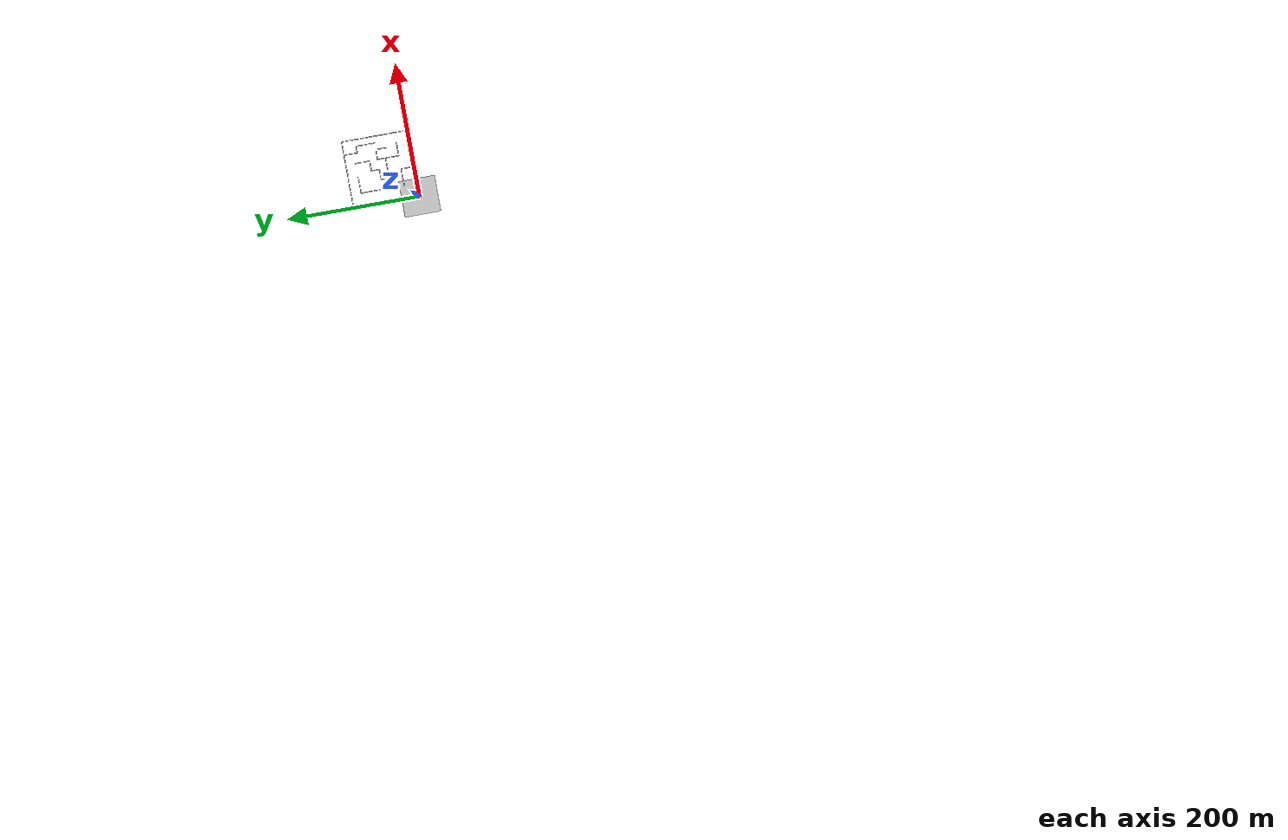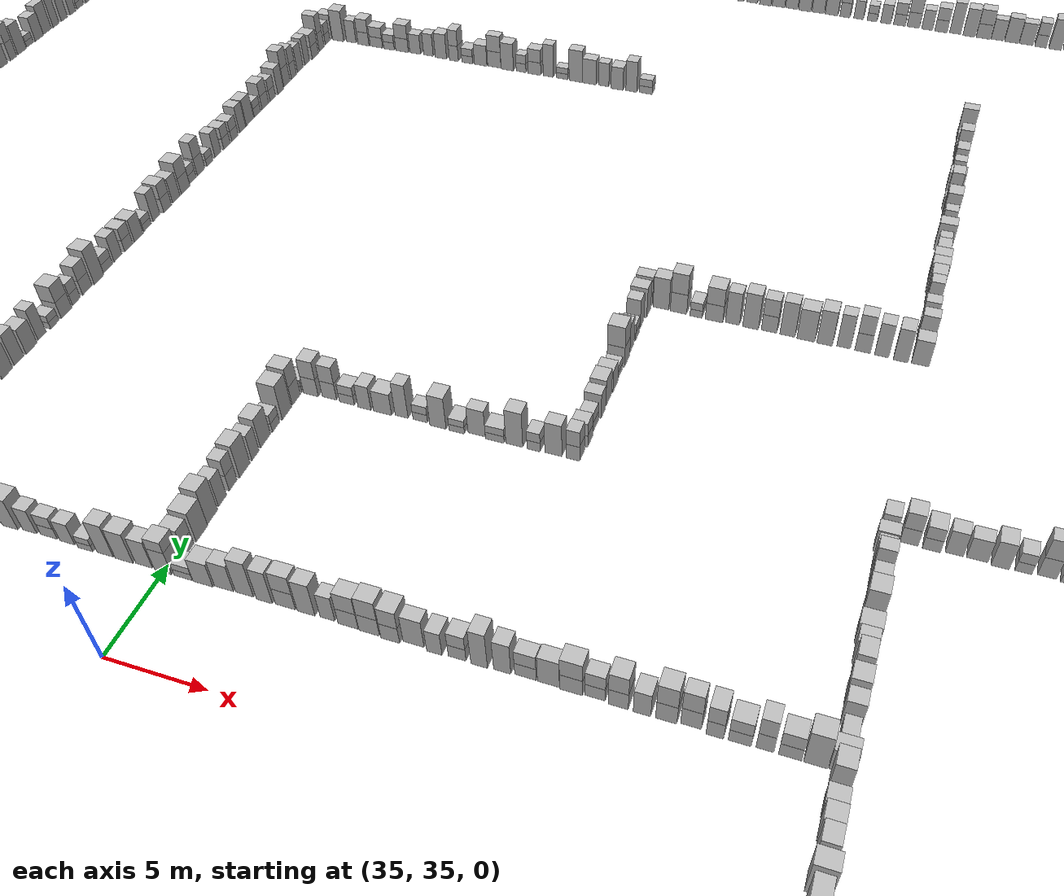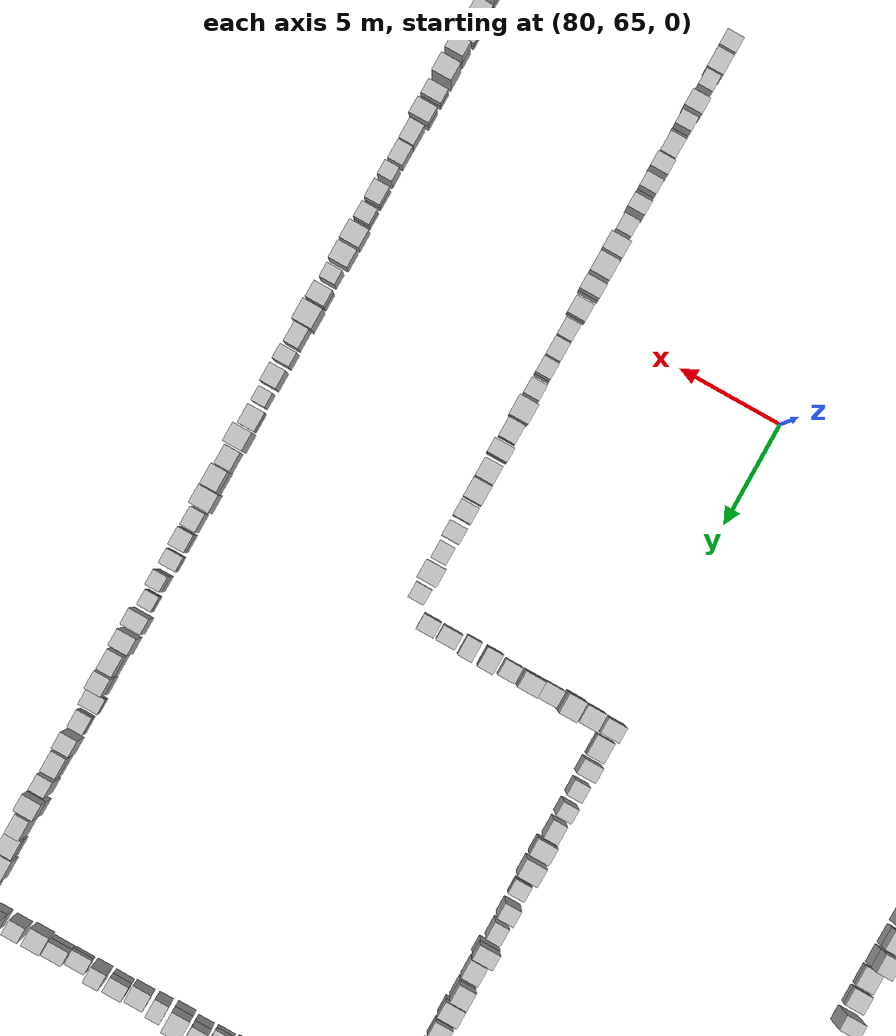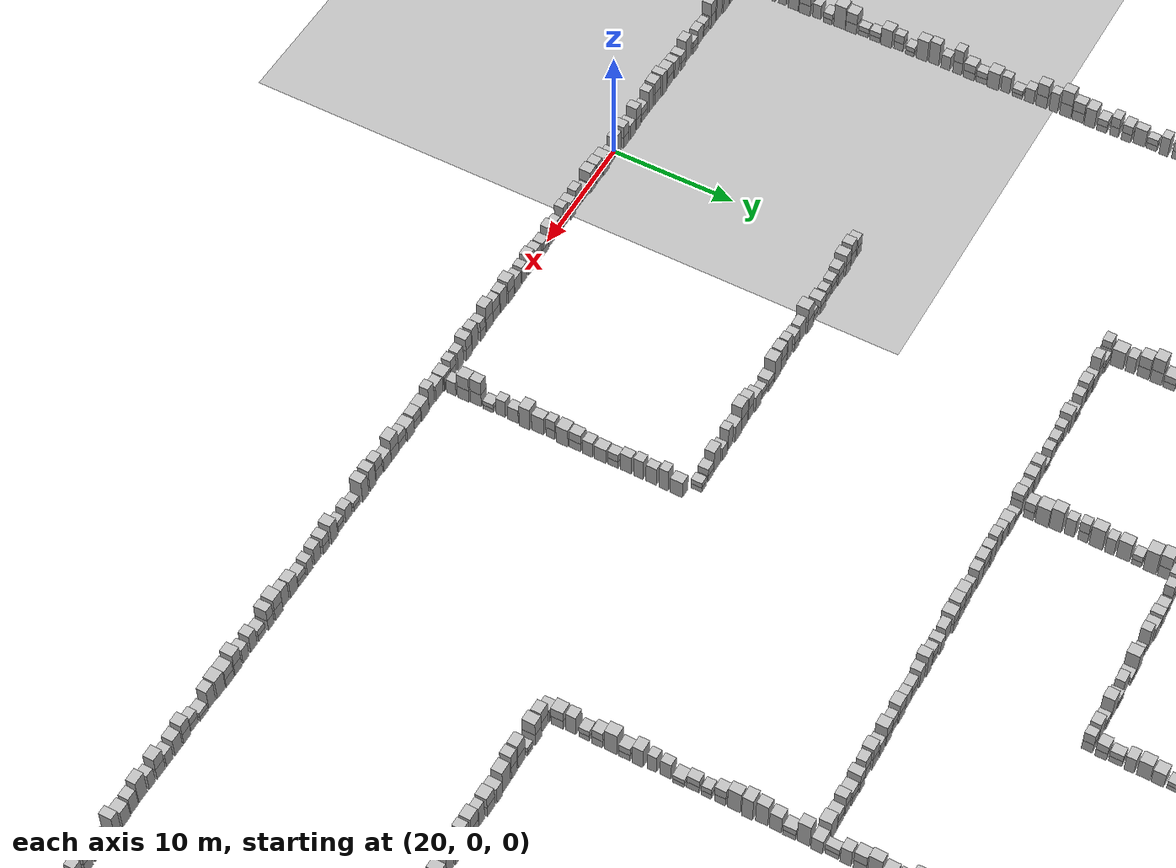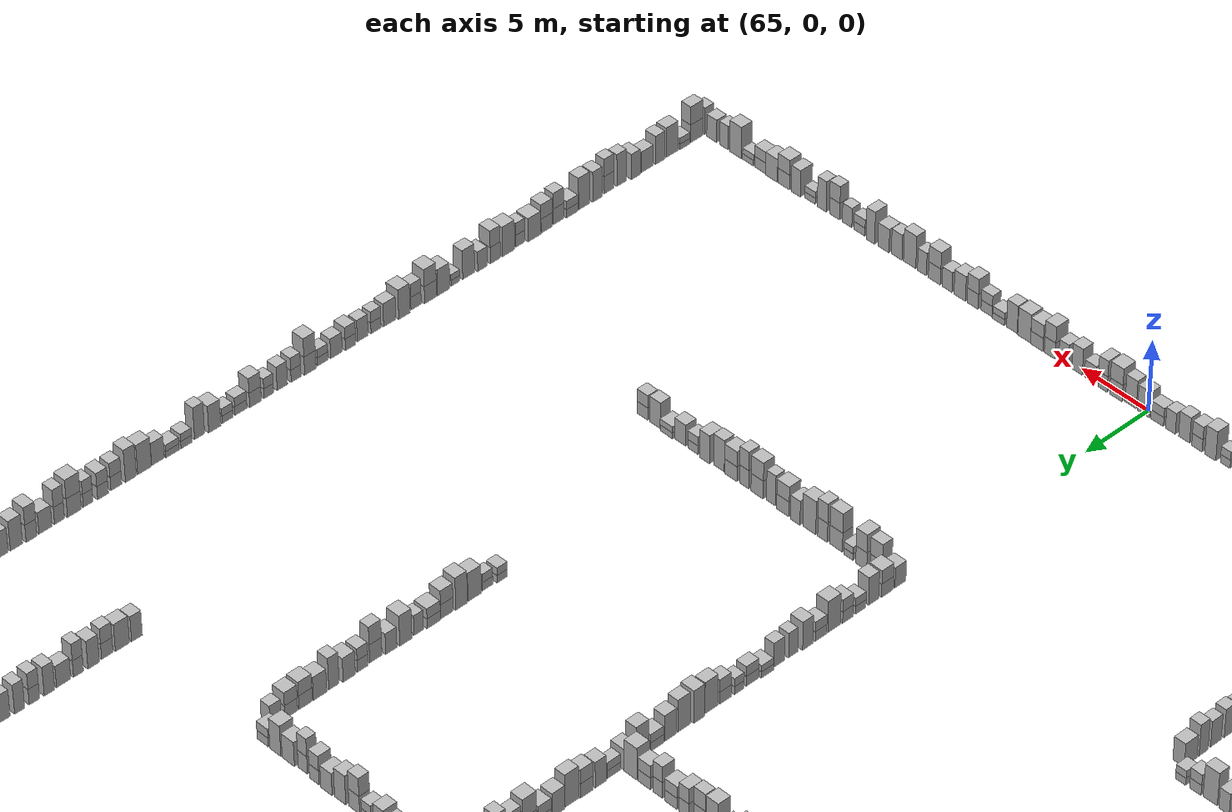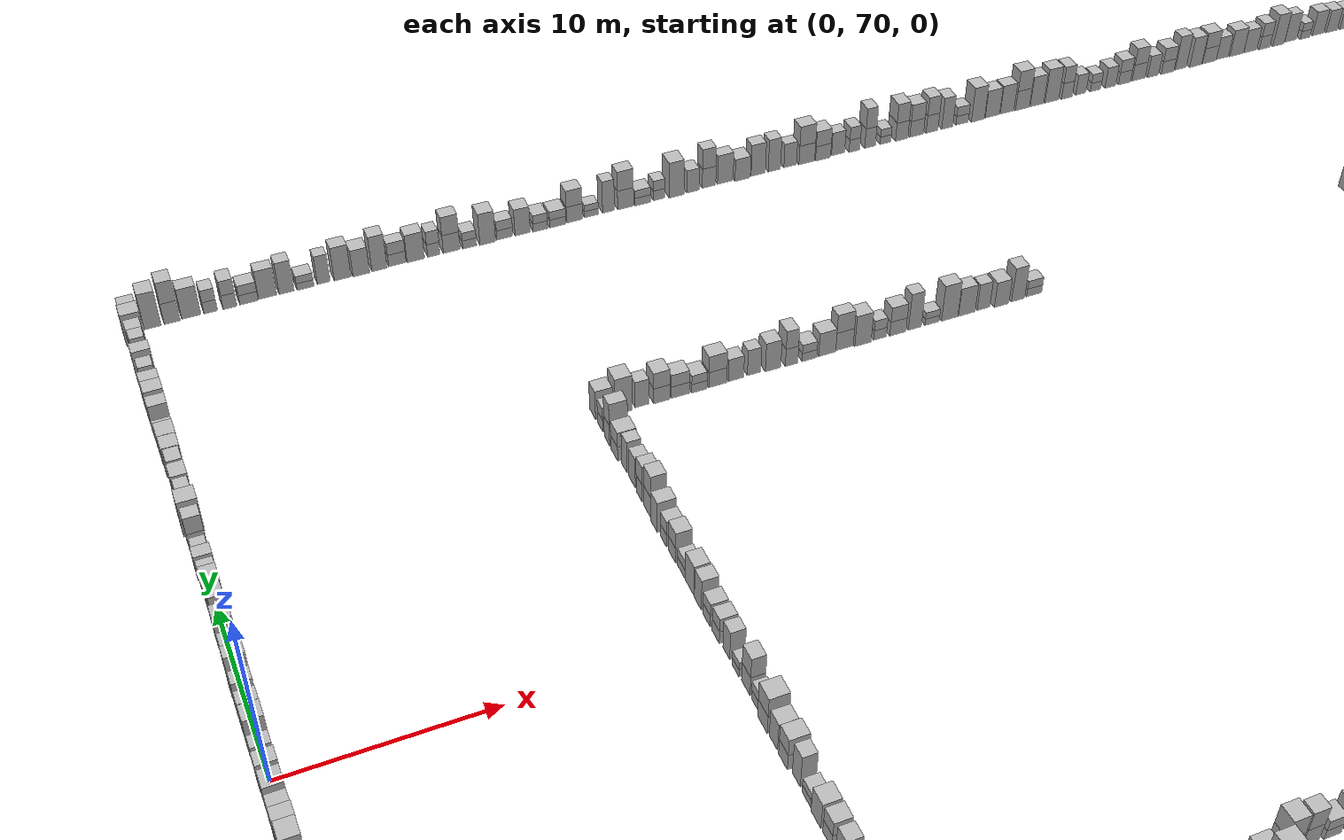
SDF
<?xml version="1.0" ?>
<?xml-model href="http://sdformat.org/schemas/root.xsd" schematypens="http://www.w3.org/2001/XMLSchema"?>
<sdf version="1.5">
  <world name="default">

    <!-- coordinate system {-->
    <spherical_coordinates>
      <surface_model>EARTH_WGS84</surface_model>
      <latitude_deg>47.397743</latitude_deg>
      <longitude_deg>8.545594</longitude_deg>
      <elevation>0.0</elevation>
      <heading_deg>0</heading_deg>
    </spherical_coordinates>

    <!-- physics engine {-->
    <physics name="default_physics" default="0" type="ode">
      <gravity>0 0 -9.8066</gravity>
      <ode>
        <solver>
          <type>quick</type>
          <iters>10</iters>
          <sor>1.3</sor>
          <use_dynamic_moi_rescaling>0</use_dynamic_moi_rescaling>
        </solver>
        <constraints>z
          <cfm>0</cfm>
          <erp>0.2</erp>
          <contact_max_correcting_vel>1000</contact_max_correcting_vel>
          <contact_surface_layer>0.001</contact_surface_layer>
        </constraints>
      </ode>
      <max_step_size>0.004</max_step_size>
      <real_time_factor>1</real_time_factor>
      <real_time_update_rate>250</real_time_update_rate>
      <magnetic_field>6.0e-06 2.3e-05 -4.2e-05</magnetic_field>
    </physics>

    <!-- turn off shadows {-->
    <scene>
      <shadows>false</shadows>
      <sky>
        <clouds/>
      </sky>
    </scene>

    <!-- sun {-->
    <light type="directional" name="sun">
      <cast_shadows>true</cast_shadows>
      <pose>250 250 600 0 0 0</pose>
      <diffuse>0.8 0.8 0.8 1</diffuse>
      <specular>0.2 0.2 0.2 1</specular>
      <attenuation>
        <range>1000</range>
        <constant>0.9</constant>
        <linear>0.01</linear>
        <quadratic>0.001</quadratic>
      </attenuation>
      <direction>0 0 -1</direction>
    </light>

    <!-- ground plane {-->
    <model name="ground_plane">
      <static>true</static>
      <link name="link">
        <collision name="collision">
          <pose>0 0 0 0 0 0</pose>
          <geometry>
            <plane>
              <normal>0 0 1</normal>
              <size>250 250</size>
            </plane>
          </geometry>
          <surface>
            <friction>
              <ode>
                <mu>1</mu>
                <mu2>1</mu2>
              </ode>
            </friction>
          </surface>
        </collision>
        <visual name="grass">
          <pose>0 0 0 0 0 0</pose>
          <cast_shadows>false</cast_shadows>
          <geometry>
            <mesh>
              <uri>file://grass_plane/meshes/grass_plane.dae</uri>
            </mesh>
          </geometry>
        </visual>
      </link>
    </model>

<model name='Cardboard_box_0'>
            <link name='link_0'>
              <pose frame=''>0 0 0 0 0 0</pose>
                <inertial>
                <mass>1</mass>
                <inertia>
                    <ixx>0.166667</ixx>
                    <ixy>0</ixy>
                    <ixz>0</ixz>
                    <iyy>0.166667</iyy>
                    <iyz>0</iyz>
                    <izz>0.166667</izz>
                </inertia>
                </inertial>
                <collision name='collision'>
          <geometry>
            <mesh>
              <uri>model://Cardboard_box/meshes/cardboard_box.dae</uri>
              <scale>2.15352152548 2.07328167067 4.44776990494</scale>
            </mesh>
          </geometry>
          <max_contacts>10</max_contacts>
          <surface>
            <contact>
              <ode/>
            </contact>
            <bounce/>
            <friction>
              <torsional>
                <ode/>
              </torsional>
              <ode/>
            </friction>
          </surface>
        </collision>
        <visual name='visual'>
          <pose frame=''>0 0 0 0 0 0</pose>
        <geometry>
            <mesh>
            <uri>model://Cardboard_box/meshes/cardboard_box.dae</uri>
            <scale>2.15352152548 2.07328167067 4.44776990494</scale>
            </mesh>
        </geometry>
        <transparency>0</transparency>
        <cast_shadows>1</cast_shadows>
        </visual>
        <self_collide>0</self_collide>
        <enable_wind>0</enable_wind>
        <kinematic>0</kinematic>
    </link>
    <static>1</static>
    <allow_auto_disable>1</allow_auto_disable>
    </model>
<model name='Cardboard_box_1'>
            <link name='link_0'>
              <pose frame=''>1 0 0 0 0 0</pose>
                <inertial>
                <mass>1</mass>
                <inertia>
                    <ixx>0.166667</ixx>
                    <ixy>0</ixy>
                    <ixz>0</ixz>
                    <iyy>0.166667</iyy>
                    <iyz>0</iyz>
                    <izz>0.166667</izz>
                </inertia>
                </inertial>
                <collision name='collision'>
          <geometry>
            <mesh>
              <uri>model://Cardboard_box/meshes/cardboard_box.dae</uri>
                <scale>1.7965034699 2.24829216659 2.33839891758</scale>
            </mesh>
          </geometry>
          <max_contacts>10</max_contacts>
          <surface>
            <contact>
              <ode/>
            </contact>
            <bounce/>
            <friction>
              <torsional>
                <ode/>
              </torsional>
              <ode/>
            </friction>
          </surface>
        </collision>
          <visual name='visual'>
          <pose frame=''>0 0 0 0 0 0</pose>
          <geometry>
              <mesh>
              <uri>model://Cardboard_box/meshes/cardboard_box.dae</uri>
              <scale>1.7965034699 2.24829216659 2.33839891758</scale>
              </mesh>
          </geometry>
          <transparency>0</transparency>
          <cast_shadows>1</cast_shadows>
          </visual>
          <self_collide>0</self_collide>
          <enable_wind>0</enable_wind>
          <kinematic>0</kinematic>
      </link>
      <static>1</static>
      <allow_auto_disable>1</allow_auto_disable>
      </model>
          <model name='Cardboard_box_top_1'>
            <link name='link_0'>
              <pose frame=''>1 0 0.935359567033 0 0 0</pose>
                <inertial>
                <mass>1</mass>
                <inertia>
                    <ixx>0.166667</ixx>
                    <ixy>0</ixy>
                    <ixz>0</ixz>
                    <iyy>0.166667</iyy>
                    <iyz>0</iyz>
                    <izz>0.166667</izz>
                </inertia>
                </inertial>
                <collision name='collision'>
          <geometry>
            <mesh>
              <uri>model://Cardboard_box/meshes/cardboard_box.dae</uri>
                <scale>1.7965034699 2.24829216659 2.33839891758</scale>
            </mesh>
          </geometry>
          <max_contacts>10</max_contacts>
          <surface>
            <contact>
              <ode/>
            </contact>
            <bounce/>
            <friction>
              <torsional>
                <ode/>
              </torsional>
              <ode/>
            </friction>
          </surface>
        </collision>
                <visual name='visual'>
                <pose frame=''>0 0 0 0 0 0</pose>
                <geometry>
                    <mesh>
                    <uri>model://Cardboard_box/meshes/cardboard_box.dae</uri>
                    <scale>1.7965034699 2.24829216659 2.33839891758</scale>
                    </mesh>
                </geometry>
                <transparency>0</transparency>
                <cast_shadows>1</cast_shadows>
                </visual>
                <self_collide>0</self_collide>
                <enable_wind>0</enable_wind>
                <kinematic>0</kinematic>
            </link>
            <static>1</static>
            <allow_auto_disable>1</allow_auto_disable>
            </model>
<model name='Cardboard_box_2'>
            <link name='link_0'>
              <pose frame=''>2 0 0 0 0 0</pose>
                <inertial>
                <mass>1</mass>
                <inertia>
                    <ixx>0.166667</ixx>
                    <ixy>0</ixy>
                    <ixz>0</ixz>
                    <iyy>0.166667</iyy>
                    <iyz>0</iyz>
                    <izz>0.166667</izz>
                </inertia>
                </inertial>
                <collision name='collision'>
          <geometry>
            <mesh>
              <uri>model://Cardboard_box/meshes/cardboard_box.dae</uri>
                <scale>1.86368571592 2.19469970765 3.13993042139</scale>
            </mesh>
          </geometry>
          <max_contacts>10</max_contacts>
          <surface>
            <contact>
              <ode/>
            </contact>
            <bounce/>
            <friction>
              <torsional>
                <ode/>
              </torsional>
              <ode/>
            </friction>
          </surface>
        </collision>
          <visual name='visual'>
          <pose frame=''>0 0 0 0 0 0</pose>
          <geometry>
              <mesh>
              <uri>model://Cardboard_box/meshes/cardboard_box.dae</uri>
              <scale>1.86368571592 2.19469970765 3.13993042139</scale>
              </mesh>
          </geometry>
          <transparency>0</transparency>
          <cast_shadows>1</cast_shadows>
          </visual>
          <self_collide>0</self_collide>
          <enable_wind>0</enable_wind>
          <kinematic>0</kinematic>
      </link>
      <static>1</static>
      <allow_auto_disable>1</allow_auto_disable>
      </model>
          <model name='Cardboard_box_top_2'>
            <link name='link_0'>
              <pose frame=''>2 0 1.25597216855 0 0 0</pose>
                <inertial>
                <mass>1</mass>
                <inertia>
                    <ixx>0.166667</ixx>
                    <ixy>0</ixy>
                    <ixz>0</ixz>
                    <iyy>0.166667</iyy>
                    <iyz>0</iyz>
                    <izz>0.166667</izz>
                </inertia>
                </inertial>
                <collision name='collision'>
          <geometry>
            <mesh>
              <uri>model://Cardboard_box/meshes/cardboard_box.dae</uri>
                <scale>1.86368571592 2.19469970765 3.13993042139</scale>
            </mesh>
          </geometry>
          <max_contacts>10</max_contacts>
          <surface>
            <contact>
              <ode/>
            </contact>
            <bounce/>
            <friction>
              <torsional>
                <ode/>
              </torsional>
              <ode/>
            </friction>
          </surface>
        </collision>
                <visual name='visual'>
                <pose frame=''>0 0 0 0 0 0</pose>
                <geometry>
                    <mesh>
                    <uri>model://Cardboard_box/meshes/cardboard_box.dae</uri>
                    <scale>1.86368571592 2.19469970765 3.13993042139</scale>
                    </mesh>
                </geometry>
                <transparency>0</transparency>
                <cast_shadows>1</cast_shadows>
                </visual>
                <self_collide>0</self_collide>
                <enable_wind>0</enable_wind>
                <kinematic>0</kinematic>
            </link>
            <static>1</static>
            <allow_auto_disable>1</allow_auto_disable>
            </model>
<model name='Cardboard_box_3'>
            <link name='link_0'>
              <pose frame=''>3 0 0 0 0 0</pose>
                <inertial>
                <mass>1</mass>
                <inertia>
                    <ixx>0.166667</ixx>
                    <ixy>0</ixy>
                    <ixz>0</ixz>
                    <iyy>0.166667</iyy>
                    <iyz>0</iyz>
                    <izz>0.166667</izz>
                </inertia>
                </inertial>
                <collision name='collision'>
          <geometry>
            <mesh>
              <uri>model://Cardboard_box/meshes/cardboard_box.dae</uri>
              <scale>2.38642901238 2.37719959208 5.46583162847</scale>
            </mesh>
          </geometry>
          <max_contacts>10</max_contacts>
          <surface>
            <contact>
              <ode/>
            </contact>
            <bounce/>
            <friction>
              <torsional>
                <ode/>
              </torsional>
              <ode/>
            </friction>
          </surface>
        </collision>
        <visual name='visual'>
          <pose frame=''>0 0 0 0 0 0</pose>
        <geometry>
            <mesh>
            <uri>model://Cardboard_box/meshes/cardboard_box.dae</uri>
            <scale>2.38642901238 2.37719959208 5.46583162847</scale>
            </mesh>
        </geometry>
        <transparency>0</transparency>
        <cast_shadows>1</cast_shadows>
        </visual>
        <self_collide>0</self_collide>
        <enable_wind>0</enable_wind>
        <kinematic>0</kinematic>
    </link>
    <static>1</static>
    <allow_auto_disable>1</allow_auto_disable>
    </model>
<model name='Cardboard_box_4'>
            <link name='link_0'>
              <pose frame=''>4 0 0 0 0 0</pose>
                <inertial>
                <mass>1</mass>
                <inertia>
                    <ixx>0.166667</ixx>
                    <ixy>0</ixy>
                    <ixz>0</ixz>
                    <iyy>0.166667</iyy>
                    <iyz>0</iyz>
                    <izz>0.166667</izz>
                </inertia>
                </inertial>
                <collision name='collision'>
          <geometry>
            <mesh>
              <uri>model://Cardboard_box/meshes/cardboard_box.dae</uri>
              <scale>2.21239625665 1.94243021321 5.86338462923</scale>
            </mesh>
          </geometry>
          <max_contacts>10</max_contacts>
          <surface>
            <contact>
              <ode/>
            </contact>
            <bounce/>
            <friction>
              <torsional>
                <ode/>
              </torsional>
              <ode/>
            </friction>
          </surface>
        </collision>
        <visual name='visual'>
          <pose frame=''>0 0 0 0 0 0</pose>
        <geometry>
            <mesh>
            <uri>model://Cardboard_box/meshes/cardboard_box.dae</uri>
            <scale>2.21239625665 1.94243021321 5.86338462923</scale>
            </mesh>
        </geometry>
        <transparency>0</transparency>
        <cast_shadows>1</cast_shadows>
        </visual>
        <self_collide>0</self_collide>
        <enable_wind>0</enable_wind>
        <kinematic>0</kinematic>
    </link>
    <static>1</static>
    <allow_auto_disable>1</allow_auto_disable>
    </model>
<model name='Cardboard_box_5'>
            <link name='link_0'>
              <pose frame=''>5 0 0 0 0 0</pose>
                <inertial>
                <mass>1</mass>
                <inertia>
                    <ixx>0.166667</ixx>
                    <ixy>0</ixy>
                    <ixz>0</ixz>
                    <iyy>0.166667</iyy>
                    <iyz>0</iyz>
                    <izz>0.166667</izz>
                </inertia>
                </inertial>
                <collision name='collision'>
          <geometry>
            <mesh>
              <uri>model://Cardboard_box/meshes/cardboard_box.dae</uri>
                <scale>1.9122216337 2.01660778259 3.3676220587</scale>
            </mesh>
          </geometry>
          <max_contacts>10</max_contacts>
          <surface>
            <contact>
              <ode/>
            </contact>
            <bounce/>
            <friction>
              <torsional>
                <ode/>
              </torsional>
              <ode/>
            </friction>
          </surface>
        </collision>
          <visual name='visual'>
          <pose frame=''>0 0 0 0 0 0</pose>
          <geometry>
              <mesh>
              <uri>model://Cardboard_box/meshes/cardboard_box.dae</uri>
              <scale>1.9122216337 2.01660778259 3.3676220587</scale>
              </mesh>
          </geometry>
          <transparency>0</transparency>
          <cast_shadows>1</cast_shadows>
          </visual>
          <self_collide>0</self_collide>
          <enable_wind>0</enable_wind>
          <kinematic>0</kinematic>
      </link>
      <static>1</static>
      <allow_auto_disable>1</allow_auto_disable>
      </model>
          <model name='Cardboard_box_top_5'>
            <link name='link_0'>
              <pose frame=''>5 0 1.34704882348 0 0 0</pose>
                <inertial>
                <mass>1</mass>
                <inertia>
                    <ixx>0.166667</ixx>
                    <ixy>0</ixy>
                    <ixz>0</ixz>
                    <iyy>0.166667</iyy>
                    <iyz>0</iyz>
                    <izz>0.166667</izz>
                </inertia>
                </inertial>
                <collision name='collision'>
          <geometry>
            <mesh>
              <uri>model://Cardboard_box/meshes/cardboard_box.dae</uri>
                <scale>1.9122216337 2.01660778259 3.3676220587</scale>
            </mesh>
          </geometry>
          <max_contacts>10</max_contacts>
          <surface>
            <contact>
              <ode/>
            </contact>
            <bounce/>
            <friction>
              <torsional>
                <ode/>
              </torsional>
              <ode/>
            </friction>
          </surface>
        </collision>
                <visual name='visual'>
                <pose frame=''>0 0 0 0 0 0</pose>
                <geometry>
                    <mesh>
                    <uri>model://Cardboard_box/meshes/cardboard_box.dae</uri>
                    <scale>1.9122216337 2.01660778259 3.3676220587</scale>
                    </mesh>
                </geometry>
                <transparency>0</transparency>
                <cast_shadows>1</cast_shadows>
                </visual>
                <self_collide>0</self_collide>
                <enable_wind>0</enable_wind>
                <kinematic>0</kinematic>
            </link>
            <static>1</static>
            <allow_auto_disable>1</allow_auto_disable>
            </model>
<model name='Cardboard_box_6'>
            <link name='link_0'>
              <pose frame=''>6 0 0 0 0 0</pose>
                <inertial>
                <mass>1</mass>
                <inertia>
                    <ixx>0.166667</ixx>
                    <ixy>0</ixy>
                    <ixz>0</ixz>
                    <iyy>0.166667</iyy>
                    <iyz>0</iyz>
                    <izz>0.166667</izz>
                </inertia>
                </inertial>
                <collision name='collision'>
          <geometry>
            <mesh>
              <uri>model://Cardboard_box/meshes/cardboard_box.dae</uri>
                <scale>2.07896184364 1.73842568687 1.73752886184</scale>
            </mesh>
          </geometry>
          <max_contacts>10</max_contacts>
          <surface>
            <contact>
              <ode/>
            </contact>
            <bounce/>
            <friction>
              <torsional>
                <ode/>
              </torsional>
              <ode/>
            </friction>
          </surface>
        </collision>
          <visual name='visual'>
          <pose frame=''>0 0 0 0 0 0</pose>
          <geometry>
              <mesh>
              <uri>model://Cardboard_box/meshes/cardboard_box.dae</uri>
              <scale>2.07896184364 1.73842568687 1.73752886184</scale>
              </mesh>
          </geometry>
          <transparency>0</transparency>
          <cast_shadows>1</cast_shadows>
          </visual>
          <self_collide>0</self_collide>
          <enable_wind>0</enable_wind>
          <kinematic>0</kinematic>
      </link>
      <static>1</static>
      <allow_auto_disable>1</allow_auto_disable>
      </model>
          <model name='Cardboard_box_top_6'>
            <link name='link_0'>
              <pose frame=''>6 0 0.695011544734 0 0 0</pose>
                <inertial>
                <mass>1</mass>
                <inertia>
                    <ixx>0.166667</ixx>
                    <ixy>0</ixy>
                    <ixz>0</ixz>
                    <iyy>0.166667</iyy>
                    <iyz>0</iyz>
                    <izz>0.166667</izz>
                </inertia>
                </inertial>
                <collision name='collision'>
          <geometry>
            <mesh>
              <uri>model://Cardboard_box/meshes/cardboard_box.dae</uri>
                <scale>2.07896184364 1.73842568687 1.73752886184</scale>
            </mesh>
          </geometry>
          <max_contacts>10</max_contacts>
          <surface>
            <contact>
              <ode/>
            </contact>
            <bounce/>
            <friction>
              <torsional>
                <ode/>
              </torsional>
              <ode/>
            </friction>
          </surface>
        </collision>
                <visual name='visual'>
                <pose frame=''>0 0 0 0 0 0</pose>
                <geometry>
                    <mesh>
                    <uri>model://Cardboard_box/meshes/cardboard_box.dae</uri>
                    <scale>2.07896184364 1.73842568687 1.73752886184</scale>
                    </mesh>
                </geometry>
                <transparency>0</transparency>
                <cast_shadows>1</cast_shadows>
                </visual>
                <self_collide>0</self_collide>
                <enable_wind>0</enable_wind>
                <kinematic>0</kinematic>
            </link>
            <static>1</static>
            <allow_auto_disable>1</allow_auto_disable>
            </model>
<model name='Cardboard_box_7'>
            <link name='link_0'>
              <pose frame=''>7 0 0 0 0 0</pose>
                <inertial>
                <mass>1</mass>
                <inertia>
                    <ixx>0.166667</ixx>
                    <ixy>0</ixy>
                    <ixz>0</ixz>
                    <iyy>0.166667</iyy>
                    <iyz>0</iyz>
                    <izz>0.166667</izz>
                </inertia>
                </inertial>
                <collision name='collision'>
          <geometry>
            <mesh>
              <uri>model://Cardboard_box/meshes/cardboard_box.dae</uri>
              <scale>2.33061281254 1.74194674921 3.99890380432</scale>
            </mesh>
          </geometry>
          <max_contacts>10</max_contacts>
          <surface>
            <contact>
              <ode/>
            </contact>
            <bounce/>
            <friction>
              <torsional>
                <ode/>
              </torsional>
              <ode/>
            </friction>
          </surface>
        </collision>
        <visual name='visual'>
          <pose frame=''>0 0 0 0 0 0</pose>
        <geometry>
            <mesh>
            <uri>model://Cardboard_box/meshes/cardboard_box.dae</uri>
            <scale>2.33061281254 1.74194674921 3.99890380432</scale>
            </mesh>
        </geometry>
        <transparency>0</transparency>
        <cast_shadows>1</cast_shadows>
        </visual>
        <self_collide>0</self_collide>
        <enable_wind>0</enable_wind>
        <kinematic>0</kinematic>
    </link>
    <static>1</static>
    <allow_auto_disable>1</allow_auto_disable>
    </model>
<model name='Cardboard_box_8'>
            <link name='link_0'>
              <pose frame=''>8 0 0 0 0 0</pose>
                <inertial>
                <mass>1</mass>
                <inertia>
                    <ixx>0.166667</ixx>
                    <ixy>0</ixy>
                    <ixz>0</ixz>
                    <iyy>0.166667</iyy>
                    <iyz>0</iyz>
                    <izz>0.166667</izz>
                </inertia>
                </inertial>
                <collision name='collision'>
          <geometry>
            <mesh>
              <uri>model://Cardboard_box/meshes/cardboard_box.dae</uri>
                <scale>2.02162936327 2.31978093398 1.59844240151</scale>
            </mesh>
          </geometry>
          <max_contacts>10</max_contacts>
          <surface>
            <contact>
              <ode/>
            </contact>
            <bounce/>
            <friction>
              <torsional>
                <ode/>
              </torsional>
              <ode/>
            </friction>
          </surface>
        </collision>
          <visual name='visual'>
          <pose frame=''>0 0 0 0 0 0</pose>
          <geometry>
              <mesh>
              <uri>model://Cardboard_box/meshes/cardboard_box.dae</uri>
              <scale>2.02162936327 2.31978093398 1.59844240151</scale>
              </mesh>
          </geometry>
          <transparency>0</transparency>
          <cast_shadows>1</cast_shadows>
          </visual>
          <self_collide>0</self_collide>
          <enable_wind>0</enable_wind>
          <kinematic>0</kinematic>
      </link>
      <static>1</static>
      <allow_auto_disable>1</allow_auto_disable>
      </model>
          <model name='Cardboard_box_top_8'>
            <link name='link_0'>
              <pose frame=''>8 0 0.639376960603 0 0 0</pose>
                <inertial>
                <mass>1</mass>
                <inertia>
                    <ixx>0.166667</ixx>
                    <ixy>0</ixy>
                    <ixz>0</ixz>
                    <iyy>0.166667</iyy>
                    <iyz>0</iyz>
                    <izz>0.166667</izz>
                </inertia>
                </inertial>
                <collision name='collision'>
          <geometry>
            <mesh>
              <uri>model://Cardboard_box/meshes/cardboard_box.dae</uri>
                <scale>2.02162936327 2.31978093398 1.59844240151</scale>
            </mesh>
          </geometry>
          <max_contacts>10</max_contacts>
          <surface>
            <contact>
              <ode/>
            </contact>
            <bounce/>
            <friction>
              <torsional>
                <ode/>
              </torsional>
              <ode/>
            </friction>
          </surface>
        </collision>
                <visual name='visual'>
                <pose frame=''>0 0 0 0 0 0</pose>
                <geometry>
                    <mesh>
                    <uri>model://Cardboard_box/meshes/cardboard_box.dae</uri>
                    <scale>2.02162936327 2.31978093398 1.59844240151</scale>
                    </mesh>
                </geometry>
                <transparency>0</transparency>
                <cast_shadows>1</cast_shadows>
                </visual>
                <self_collide>0</self_collide>
                <enable_wind>0</enable_wind>
                <kinematic>0</kinematic>
            </link>
            <static>1</static>
            <allow_auto_disable>1</allow_auto_disable>
            </model>
<model name='Cardboard_box_9'>
            <link name='link_0'>
              <pose frame=''>9 0 0 0 0 0</pose>
                <inertial>
                <mass>1</mass>
                <inertia>
                    <ixx>0.166667</ixx>
                    <ixy>0</ixy>
                    <ixz>0</ixz>
                    <iyy>0.166667</iyy>
                    <iyz>0</iyz>
                    <izz>0.166667</izz>
                </inertia>
                </inertial>
                <collision name='collision'>
          <geometry>
            <mesh>
              <uri>model://Cardboard_box/meshes/cardboard_box.dae</uri>
              <scale>2.41177727035 1.9046140547 5.80288688245</scale>
            </mesh>
          </geometry>
          <max_contacts>10</max_contacts>
          <surface>
            <contact>
              <ode/>
            </contact>
            <bounce/>
            <friction>
              <torsional>
                <ode/>
              </torsional>
              <ode/>
            </friction>
          </surface>
        </collision>
        <visual name='visual'>
          <pose frame=''>0 0 0 0 0 0</pose>
        <geometry>
            <mesh>
            <uri>model://Cardboard_box/meshes/cardboard_box.dae</uri>
            <scale>2.41177727035 1.9046140547 5.80288688245</scale>
            </mesh>
        </geometry>
        <transparency>0</transparency>
        <cast_shadows>1</cast_shadows>
        </visual>
        <self_collide>0</self_collide>
        <enable_wind>0</enable_wind>
        <kinematic>0</kinematic>
    </link>
    <static>1</static>
    <allow_auto_disable>1</allow_auto_disable>
    </model>
<model name='Cardboard_box_10'>
            <link name='link_0'>
              <pose frame=''>10 0 0 0 0 0</pose>
                <inertial>
                <mass>1</mass>
                <inertia>
                    <ixx>0.166667</ixx>
                    <ixy>0</ixy>
                    <ixz>0</ixz>
                    <iyy>0.166667</iyy>
                    <iyz>0</iyz>
                    <izz>0.166667</izz>
                </inertia>
                </inertial>
                <collision name='collision'>
          <geometry>
            <mesh>
              <uri>model://Cardboard_box/meshes/cardboard_box.dae</uri>
                <scale>1.87477308353 2.39111994629 2.01380532399</scale>
            </mesh>
          </geometry>
          <max_contacts>10</max_contacts>
          <surface>
            <contact>
              <ode/>
            </contact>
            <bounce/>
            <friction>
              <torsional>
                <ode/>
              </torsional>
              <ode/>
            </friction>
          </surface>
        </collision>
          <visual name='visual'>
          <pose frame=''>0 0 0 0 0 0</pose>
          <geometry>
              <mesh>
              <uri>model://Cardboard_box/meshes/cardboard_box.dae</uri>
              <scale>1.87477308353 2.39111994629 2.01380532399</scale>
              </mesh>
          </geometry>
          <transparency>0</transparency>
          <cast_shadows>1</cast_shadows>
          </visual>
          <self_collide>0</self_collide>
          <enable_wind>0</enable_wind>
          <kinematic>0</kinematic>
      </link>
      <static>1</static>
      <allow_auto_disable>1</allow_auto_disable>
      </model>
          <model name='Cardboard_box_top_10'>
            <link name='link_0'>
              <pose frame=''>10 0 0.805522129596 0 0 0</pose>
                <inertial>
                <mass>1</mass>
                <inertia>
                    <ixx>0.166667</ixx>
                    <ixy>0</ixy>
                    <ixz>0</ixz>
                    <iyy>0.166667</iyy>
                    <iyz>0</iyz>
                    <izz>0.166667</izz>
                </inertia>
                </inertial>
                <collision name='collision'>
          <geometry>
            <mesh>
              <uri>model://Cardboard_box/meshes/cardboard_box.dae</uri>
                <scale>1.87477308353 2.39111994629 2.01380532399</scale>
            </mesh>
          </geometry>
          <max_contacts>10</max_contacts>
          <surface>
            <contact>
              <ode/>
            </contact>
            <bounce/>
            <friction>
              <torsional>
                <ode/>
              </torsional>
              <ode/>
            </friction>
          </surface>
        </collision>
                <visual name='visual'>
                <pose frame=''>0 0 0 0 0 0</pose>
                <geometry>
                    <mesh>
                    <uri>model://Cardboard_box/meshes/cardboard_box.dae</uri>
                    <scale>1.87477308353 2.39111994629 2.01380532399</scale>
                    </mesh>
                </geometry>
                <transparency>0</transparency>
                <cast_shadows>1</cast_shadows>
                </visual>
                <self_collide>0</self_collide>
                <enable_wind>0</enable_wind>
                <kinematic>0</kinematic>
            </link>
            <static>1</static>
            <allow_auto_disable>1</allow_auto_disable>
            </model>
<model name='Cardboard_box_11'>
            <link name='link_0'>
              <pose frame=''>11 0 0 0 0 0</pose>
                <inertial>
                <mass>1</mass>
                <inertia>
                    <ixx>0.166667</ixx>
                    <ixy>0</ixy>
                    <ixz>0</ixz>
                    <iyy>0.166667</iyy>
                    <iyz>0</iyz>
                    <izz>0.166667</izz>
                </inertia>
                </inertial>
                <collision name='collision'>
          <geometry>
            <mesh>
              <uri>model://Cardboard_box/meshes/cardboard_box.dae</uri>
              <scale>1.72870701162 2.23671590152 4.48120869335</scale>
            </mesh>
          </geometry>
          <max_contacts>10</max_contacts>
          <surface>
            <contact>
              <ode/>
            </contact>
            <bounce/>
            <friction>
              <torsional>
                <ode/>
              </torsional>
              <ode/>
            </friction>
          </surface>
        </collision>
        <visual name='visual'>
          <pose frame=''>0 0 0 0 0 0</pose>
        <geometry>
            <mesh>
            <uri>model://Cardboard_box/meshes/cardboard_box.dae</uri>
            <scale>1.72870701162 2.23671590152 4.48120869335</scale>
            </mesh>
        </geometry>
        <transparency>0</transparency>
        <cast_shadows>1</cast_shadows>
        </visual>
        <self_collide>0</self_collide>
        <enable_wind>0</enable_wind>
        <kinematic>0</kinematic>
    </link>
    <static>1</static>
    <allow_auto_disable>1</allow_auto_disable>
    </model>
<model name='Cardboard_box_12'>
            <link name='link_0'>
              <pose frame=''>12 0 0 0 0 0</pose>
                <inertial>
                <mass>1</mass>
                <inertia>
                    <ixx>0.166667</ixx>
                    <ixy>0</ixy>
                    <ixz>0</ixz>
                    <iyy>0.166667</iyy>
                    <iyz>0</iyz>
                    <izz>0.166667</izz>
                </inertia>
                </inertial>
                <collision name='collision'>
          <geometry>
            <mesh>
              <uri>model://Cardboard_box/meshes/cardboard_box.dae</uri>
                <scale>2.39689287045 2.06885431104 2.46151055698</scale>
            </mesh>
          </geometry>
          <max_contacts>10</max_contacts>
          <surface>
            <contact>
              <ode/>
            </contact>
            <bounce/>
            <friction>
              <torsional>
                <ode/>
              </torsional>
              <ode/>
            </friction>
          </surface>
        </collision>
          <visual name='visual'>
          <pose frame=''>0 0 0 0 0 0</pose>
          <geometry>
              <mesh>
              <uri>model://Cardboard_box/meshes/cardboard_box.dae</uri>
              <scale>2.39689287045 2.06885431104 2.46151055698</scale>
              </mesh>
          </geometry>
          <transparency>0</transparency>
          <cast_shadows>1</cast_shadows>
          </visual>
          <self_collide>0</self_collide>
          <enable_wind>0</enable_wind>
          <kinematic>0</kinematic>
      </link>
      <static>1</static>
      <allow_auto_disable>1</allow_auto_disable>
      </model>
          <model name='Cardboard_box_top_12'>
            <link name='link_0'>
              <pose frame=''>12 0 0.984604222791 0 0 0</pose>
                <inertial>
                <mass>1</mass>
                <inertia>
                    <ixx>0.166667</ixx>
                    <ixy>0</ixy>
                    <ixz>0</ixz>
                    <iyy>0.166667</iyy>
                    <iyz>0</iyz>
                    <izz>0.166667</izz>
                </inertia>
                </inertial>
                <collision name='collision'>
          <geometry>
            <mesh>
              <uri>model://Cardboard_box/meshes/cardboard_box.dae</uri>
                <scale>2.39689287045 2.06885431104 2.46151055698</scale>
            </mesh>
          </geometry>
          <max_contacts>10</max_contacts>
          <surface>
            <contact>
              <ode/>
            </contact>
            <bounce/>
            <friction>
              <torsional>
                <ode/>
              </torsional>
              <ode/>
            </friction>
          </surface>
        </collision>
                <visual name='visual'>
                <pose frame=''>0 0 0 0 0 0</pose>
                <geometry>
                    <mesh>
                    <uri>model://Cardboard_box/meshes/cardboard_box.dae</uri>
                    <scale>2.39689287045 2.06885431104 2.46151055698</scale>
                    </mesh>
                </geometry>
                <transparency>0</transparency>
                <cast_shadows>1</cast_shadows>
                </visual>
                <self_collide>0</self_collide>
                <enable_wind>0</enable_wind>
                <kinematic>0</kinematic>
            </link>
            <static>1</static>
            <allow_auto_disable>1</allow_auto_disable>
            </model>
<model name='Cardboard_box_13'>
            <link name='link_0'>
              <pose frame=''>13 0 0 0 0 0</pose>
                <inertial>
                <mass>1</mass>
                <inertia>
                    <ixx>0.166667</ixx>
                    <ixy>0</ixy>
                    <ixz>0</ixz>
                    <iyy>0.166667</iyy>
                    <iyz>0</iyz>
                    <izz>0.166667</izz>
                </inertia>
                </inertial>
                <collision name='collision'>
          <geometry>
            <mesh>
              <uri>model://Cardboard_box/meshes/cardboard_box.dae</uri>
              <scale>1.72068681394 2.40428362336 5.74207387843</scale>
            </mesh>
          </geometry>
          <max_contacts>10</max_contacts>
          <surface>
            <contact>
              <ode/>
            </contact>
            <bounce/>
            <friction>
              <torsional>
                <ode/>
              </torsional>
              <ode/>
            </friction>
          </surface>
        </collision>
        <visual name='visual'>
          <pose frame=''>0 0 0 0 0 0</pose>
        <geometry>
            <mesh>
            <uri>model://Cardboard_box/meshes/cardboard_box.dae</uri>
            <scale>1.72068681394 2.40428362336 5.74207387843</scale>
            </mesh>
        </geometry>
        <transparency>0</transparency>
        <cast_shadows>1</cast_shadows>
        </visual>
        <self_collide>0</self_collide>
        <enable_wind>0</enable_wind>
        <kinematic>0</kinematic>
    </link>
    <static>1</static>
    <allow_auto_disable>1</allow_auto_disable>
    </model>
<model name='Cardboard_box_14'>
            <link name='link_0'>
              <pose frame=''>14 0 0 0 0 0</pose>
                <inertial>
                <mass>1</mass>
                <inertia>
                    <ixx>0.166667</ixx>
                    <ixy>0</ixy>
                    <ixz>0</ixz>
                    <iyy>0.166667</iyy>
                    <iyz>0</iyz>
                    <izz>0.166667</izz>
                </inertia>
                </inertial>
                <collision name='collision'>
          <geometry>
            <mesh>
              <uri>model://Cardboard_box/meshes/cardboard_box.dae</uri>
                <scale>2.31721867758 2.10245198145 2.95686316914</scale>
            </mesh>
          </geometry>
          <max_contacts>10</max_contacts>
          <surface>
            <contact>
              <ode/>
            </contact>
            <bounce/>
            <friction>
              <torsional>
                <ode/>
              </torsional>
              <ode/>
            </friction>
          </surface>
        </collision>
          <visual name='visual'>
          <pose frame=''>0 0 0 0 0 0</pose>
          <geometry>
              <mesh>
              <uri>model://Cardboard_box/meshes/cardboard_box.dae</uri>
              <scale>2.31721867758 2.10245198145 2.95686316914</scale>
              </mesh>
          </geometry>
          <transparency>0</transparency>
          <cast_shadows>1</cast_shadows>
          </visual>
          <self_collide>0</self_collide>
          <enable_wind>0</enable_wind>
          <kinematic>0</kinematic>
      </link>
      <static>1</static>
      <allow_auto_disable>1</allow_auto_disable>
      </model>
          <model name='Cardboard_box_top_14'>
            <link name='link_0'>
              <pose frame=''>14 0 1.18274526766 0 0 0</pose>
                <inertial>
                <mass>1</mass>
                <inertia>
                    <ixx>0.166667</ixx>
                    <ixy>0</ixy>
                    <ixz>0</ixz>
                    <iyy>0.166667</iyy>
                    <iyz>0</iyz>
                    <izz>0.166667</izz>
                </inertia>
                </inertial>
                <collision name='collision'>
          <geometry>
            <mesh>
              <uri>model://Cardboard_box/meshes/cardboard_box.dae</uri>
                <scale>2.31721867758 2.10245198145 2.95686316914</scale>
            </mesh>
          </geometry>
          <max_contacts>10</max_contacts>
          <surface>
            <contact>
              <ode/>
            </contact>
            <bounce/>
            <friction>
              <torsional>
                <ode/>
              </torsional>
              <ode/>
            </friction>
          </surface>
        </collision>
                <visual name='visual'>
                <pose frame=''>0 0 0 0 0 0</pose>
                <geometry>
                    <mesh>
                    <uri>model://Cardboard_box/meshes/cardboard_box.dae</uri>
                    <scale>2.31721867758 2.10245198145 2.95686316914</scale>
                    </mesh>
                </geometry>
                <transparency>0</transparency>
                <cast_shadows>1</cast_shadows>
                </visual>
                <self_collide>0</self_collide>
                <enable_wind>0</enable_wind>
                <kinematic>0</kinematic>
            </link>
            <static>1</static>
            <allow_auto_disable>1</allow_auto_disable>
            </model>
<model name='Cardboard_box_15'>
            <link name='link_0'>
              <pose frame=''>15 0 0 0 0 0</pose>
                <inertial>
                <mass>1</mass>
                <inertia>
                    <ixx>0.166667</ixx>
                    <ixy>0</ixy>
                    <ixz>0</ixz>
                    <iyy>0.166667</iyy>
                    <iyz>0</iyz>
                    <izz>0.166667</izz>
                </inertia>
                </inertial>
                <collision name='collision'>
          <geometry>
            <mesh>
              <uri>model://Cardboard_box/meshes/cardboard_box.dae</uri>
              <scale>1.81143180354 1.9829154614 5.72567080923</scale>
            </mesh>
          </geometry>
          <max_contacts>10</max_contacts>
          <surface>
            <contact>
              <ode/>
            </contact>
            <bounce/>
            <friction>
              <torsional>
                <ode/>
              </torsional>
              <ode/>
            </friction>
          </surface>
        </collision>
        <visual name='visual'>
          <pose frame=''>0 0 0 0 0 0</pose>
        <geometry>
            <mesh>
            <uri>model://Cardboard_box/meshes/cardboard_box.dae</uri>
            <scale>1.81143180354 1.9829154614 5.72567080923</scale>
            </mesh>
        </geometry>
        <transparency>0</transparency>
        <cast_shadows>1</cast_shadows>
        </visual>
        <self_collide>0</self_collide>
        <enable_wind>0</enable_wind>
        <kinematic>0</kinematic>
    </link>
    <static>1</static>
    <allow_auto_disable>1</allow_auto_disable>
    </model>
<model name='Cardboard_box_16'>
            <link name='link_0'>
              <pose frame=''>16 0 0 0 0 0</pose>
                <inertial>
                <mass>1</mass>
                <inertia>
                    <ixx>0.166667</ixx>
                    <ixy>0</ixy>
                    <ixz>0</ixz>
                    <iyy>0.166667</iyy>
                    <iyz>0</iyz>
                    <izz>0.166667</izz>
                </inertia>
                </inertial>
                <collision name='collision'>
          <geometry>
            <mesh>
              <uri>model://Cardboard_box/meshes/cardboard_box.dae</uri>
                <scale>2.35221261662 1.96231627657 1.82707683296</scale>
            </mesh>
          </geometry>
          <max_contacts>10</max_contacts>
          <surface>
            <contact>
              <ode/>
            </contact>
            <bounce/>
            <friction>
              <torsional>
                <ode/>
              </torsional>
              <ode/>
            </friction>
          </surface>
        </collision>
          <visual name='visual'>
          <pose frame=''>0 0 0 0 0 0</pose>
          <geometry>
              <mesh>
              <uri>model://Cardboard_box/meshes/cardboard_box.dae</uri>
              <scale>2.35221261662 1.96231627657 1.82707683296</scale>
              </mesh>
          </geometry>
          <transparency>0</transparency>
          <cast_shadows>1</cast_shadows>
          </visual>
          <self_collide>0</self_collide>
          <enable_wind>0</enable_wind>
          <kinematic>0</kinematic>
      </link>
      <static>1</static>
      <allow_auto_disable>1</allow_auto_disable>
      </model>
          <model name='Cardboard_box_top_16'>
            <link name='link_0'>
              <pose frame=''>16 0 0.730830733183 0 0 0</pose>
                <inertial>
                <mass>1</mass>
                <inertia>
                    <ixx>0.166667</ixx>
                    <ixy>0</ixy>
                    <ixz>0</ixz>
                    <iyy>0.166667</iyy>
                    <iyz>0</iyz>
                    <izz>0.166667</izz>
                </inertia>
                </inertial>
                <collision name='collision'>
          <geometry>
            <mesh>
              <uri>model://Cardboard_box/meshes/cardboard_box.dae</uri>
                <scale>2.35221261662 1.96231627657 1.82707683296</scale>
            </mesh>
          </geometry>
          <max_contacts>10</max_contacts>
          <surface>
            <contact>
              <ode/>
            </contact>
            <bounce/>
            <friction>
              <torsional>
                <ode/>
              </torsional>
              <ode/>
            </friction>
          </surface>
        </collision>
                <visual name='visual'>
                <pose frame=''>0 0 0 0 0 0</pose>
                <geometry>
                    <mesh>
                    <uri>model://Cardboard_box/meshes/cardboard_box.dae</uri>
                    <scale>2.35221261662 1.96231627657 1.82707683296</scale>
                    </mesh>
                </geometry>
                <transparency>0</transparency>
                <cast_shadows>1</cast_shadows>
                </visual>
                <self_collide>0</self_collide>
                <enable_wind>0</enable_wind>
                <kinematic>0</kinematic>
            </link>
            <static>1</static>
            <allow_auto_disable>1</allow_auto_disable>
            </model>
<model name='Cardboard_box_17'>
            <link name='link_0'>
              <pose frame=''>17 0 0 0 0 0</pose>
                <inertial>
                <mass>1</mass>
                <inertia>
                    <ixx>0.166667</ixx>
                    <ixy>0</ixy>
                    <ixz>0</ixz>
                    <iyy>0.166667</iyy>
                    <iyz>0</iyz>
                    <izz>0.166667</izz>
                </inertia>
                </inertial>
                <collision name='collision'>
          <geometry>
            <mesh>
              <uri>model://Cardboard_box/meshes/cardboard_box.dae</uri>
                <scale>1.74772383043 2.24330012728 2.94271087227</scale>
            </mesh>
          </geometry>
          <max_contacts>10</max_contacts>
          <surface>
            <contact>
              <ode/>
            </contact>
            <bounce/>
            <friction>
              <torsional>
                <ode/>
              </torsional>
              <ode/>
            </friction>
          </surface>
        </collision>
          <visual name='visual'>
          <pose frame=''>0 0 0 0 0 0</pose>
          <geometry>
              <mesh>
              <uri>model://Cardboard_box/meshes/cardboard_box.dae</uri>
              <scale>1.74772383043 2.24330012728 2.94271087227</scale>
              </mesh>
          </geometry>
          <transparency>0</transparency>
          <cast_shadows>1</cast_shadows>
          </visual>
          <self_collide>0</self_collide>
          <enable_wind>0</enable_wind>
          <kinematic>0</kinematic>
      </link>
      <static>1</static>
      <allow_auto_disable>1</allow_auto_disable>
      </model>
          <model name='Cardboard_box_top_17'>
            <link name='link_0'>
              <pose frame=''>17 0 1.17708434891 0 0 0</pose>
                <inertial>
                <mass>1</mass>
                <inertia>
                    <ixx>0.166667</ixx>
                    <ixy>0</ixy>
                    <ixz>0</ixz>
                    <iyy>0.166667</iyy>
                    <iyz>0</iyz>
                    <izz>0.166667</izz>
                </inertia>
                </inertial>
                <collision name='collision'>
          <geometry>
            <mesh>
              <uri>model://Cardboard_box/meshes/cardboard_box.dae</uri>
                <scale>1.74772383043 2.24330012728 2.94271087227</scale>
            </mesh>
          </geometry>
          <max_contacts>10</max_contacts>
          <surface>
            <contact>
              <ode/>
            </contact>
            <bounce/>
            <friction>
              <torsional>
                <ode/>
              </torsional>
              <ode/>
            </friction>
          </surface>
        </collision>
                <visual name='visual'>
                <pose frame=''>0 0 0 0 0 0</pose>
                <geometry>
                    <mesh>
                    <uri>model://Cardboard_box/meshes/cardboard_box.dae</uri>
                    <scale>1.74772383043 2.24330012728 2.94271087227</scale>
                    </mesh>
                </geometry>
                <transparency>0</transparency>
                <cast_shadows>1</cast_shadows>
                </visual>
                <self_collide>0</self_collide>
                <enable_wind>0</enable_wind>
                <kinematic>0</kinematic>
            </link>
            <static>1</static>
            <allow_auto_disable>1</allow_auto_disable>
            </model>
<model name='Cardboard_box_18'>
            <link name='link_0'>
              <pose frame=''>18 0 0 0 0 0</pose>
                <inertial>
                <mass>1</mass>
                <inertia>
                    <ixx>0.166667</ixx>
                    <ixy>0</ixy>
                    <ixz>0</ixz>
                    <iyy>0.166667</iyy>
                    <iyz>0</iyz>
                    <izz>0.166667</izz>
                </inertia>
                </inertial>
                <collision name='collision'>
          <geometry>
            <mesh>
              <uri>model://Cardboard_box/meshes/cardboard_box.dae</uri>
              <scale>2.06175359222 2.45269669923 3.8120988213</scale>
            </mesh>
          </geometry>
          <max_contacts>10</max_contacts>
          <surface>
            <contact>
              <ode/>
            </contact>
            <bounce/>
            <friction>
              <torsional>
                <ode/>
              </torsional>
              <ode/>
            </friction>
          </surface>
        </collision>
        <visual name='visual'>
          <pose frame=''>0 0 0 0 0 0</pose>
        <geometry>
            <mesh>
            <uri>model://Cardboard_box/meshes/cardboard_box.dae</uri>
            <scale>2.06175359222 2.45269669923 3.8120988213</scale>
            </mesh>
        </geometry>
        <transparency>0</transparency>
        <cast_shadows>1</cast_shadows>
        </visual>
        <self_collide>0</self_collide>
        <enable_wind>0</enable_wind>
        <kinematic>0</kinematic>
    </link>
    <static>1</static>
    <allow_auto_disable>1</allow_auto_disable>
    </model>
<model name='Cardboard_box_19'>
            <link name='link_0'>
              <pose frame=''>19 0 0 0 0 0</pose>
                <inertial>
                <mass>1</mass>
                <inertia>
                    <ixx>0.166667</ixx>
                    <ixy>0</ixy>
                    <ixz>0</ixz>
                    <iyy>0.166667</iyy>
                    <iyz>0</iyz>
                    <izz>0.166667</izz>
                </inertia>
                </inertial>
                <collision name='collision'>
          <geometry>
            <mesh>
              <uri>model://Cardboard_box/meshes/cardboard_box.dae</uri>
                <scale>1.91554035472 2.37056957961 2.86900003002</scale>
            </mesh>
          </geometry>
          <max_contacts>10</max_contacts>
          <surface>
            <contact>
              <ode/>
            </contact>
            <bounce/>
            <friction>
              <torsional>
                <ode/>
              </torsional>
              <ode/>
            </friction>
          </surface>
        </collision>
          <visual name='visual'>
          <pose frame=''>0 0 0 0 0 0</pose>
          <geometry>
              <mesh>
              <uri>model://Cardboard_box/meshes/cardboard_box.dae</uri>
              <scale>1.91554035472 2.37056957961 2.86900003002</scale>
              </mesh>
          </geometry>
          <transparency>0</transparency>
          <cast_shadows>1</cast_shadows>
          </visual>
          <self_collide>0</self_collide>
          <enable_wind>0</enable_wind>
          <kinematic>0</kinematic>
      </link>
      <static>1</static>
      <allow_auto_disable>1</allow_auto_disable>
      </model>
          <model name='Cardboard_box_top_19'>
            <link name='link_0'>
              <pose frame=''>19 0 1.14760001201 0 0 0</pose>
                <inertial>
                <mass>1</mass>
                <inertia>
                    <ixx>0.166667</ixx>
                    <ixy>0</ixy>
                    <ixz>0</ixz>
                    <iyy>0.166667</iyy>
                    <iyz>0</iyz>
                    <izz>0.166667</izz>
                </inertia>
                </inertial>
                <collision name='collision'>
          <geometry>
            <mesh>
              <uri>model://Cardboard_box/meshes/cardboard_box.dae</uri>
                <scale>1.91554035472 2.37056957961 2.86900003002</scale>
            </mesh>
          </geometry>
          <max_contacts>10</max_contacts>
          <surface>
            <contact>
              <ode/>
            </contact>
            <bounce/>
            <friction>
              <torsional>
                <ode/>
              </torsional>
              <ode/>
            </friction>
          </surface>
        </collision>
                <visual name='visual'>
                <pose frame=''>0 0 0 0 0 0</pose>
                <geometry>
                    <mesh>
                    <uri>model://Cardboard_box/meshes/cardboard_box.dae</uri>
                    <scale>1.91554035472 2.37056957961 2.86900003002</scale>
                    </mesh>
                </geometry>
                <transparency>0</transparency>
                <cast_shadows>1</cast_shadows>
                </visual>
                <self_collide>0</self_collide>
                <enable_wind>0</enable_wind>
                <kinematic>0</kinematic>
            </link>
            <static>1</static>
            <allow_auto_disable>1</allow_auto_disable>
            </model>
<model name='Cardboard_box_20'>
            <link name='link_0'>
              <pose frame=''>20 0 0 0 0 0</pose>
                <inertial>
                <mass>1</mass>
                <inertia>
                    <ixx>0.166667</ixx>
                    <ixy>0</ixy>
                    <ixz>0</ixz>
                    <iyy>0.166667</iyy>
                    <iyz>0</iyz>
                    <izz>0.166667</izz>
                </inertia>
                </inertial>
                <collision name='collision'>
          <geometry>
            <mesh>
              <uri>model://Cardboard_box/meshes/cardboard_box.dae</uri>
              <scale>2.36743544982 1.84634310597 5.19144005288</scale>
            </mesh>
          </geometry>
          <max_contacts>10</max_contacts>
          <surface>
            <contact>
              <ode/>
            </contact>
            <bounce/>
            <friction>
              <torsional>
                <ode/>
              </torsional>
              <ode/>
            </friction>
          </surface>
        </collision>
        <visual name='visual'>
          <pose frame=''>0 0 0 0 0 0</pose>
        <geometry>
            <mesh>
            <uri>model://Cardboard_box/meshes/cardboard_box.dae</uri>
            <scale>2.36743544982 1.84634310597 5.19144005288</scale>
            </mesh>
        </geometry>
        <transparency>0</transparency>
        <cast_shadows>1</cast_shadows>
        </visual>
        <self_collide>0</self_collide>
        <enable_wind>0</enable_wind>
        <kinematic>0</kinematic>
    </link>
    <static>1</static>
    <allow_auto_disable>1</allow_auto_disable>
    </model>
<model name='Cardboard_box_21'>
            <link name='link_0'>
              <pose frame=''>21 0 0 0 0 0</pose>
                <inertial>
                <mass>1</mass>
                <inertia>
                    <ixx>0.166667</ixx>
                    <ixy>0</ixy>
                    <ixz>0</ixz>
                    <iyy>0.166667</iyy>
                    <iyz>0</iyz>
                    <izz>0.166667</izz>
                </inertia>
                </inertial>
                <collision name='collision'>
          <geometry>
            <mesh>
              <uri>model://Cardboard_box/meshes/cardboard_box.dae</uri>
                <scale>1.70943730668 1.8856525622 1.61784941243</scale>
            </mesh>
          </geometry>
          <max_contacts>10</max_contacts>
          <surface>
            <contact>
              <ode/>
            </contact>
            <bounce/>
            <friction>
              <torsional>
                <ode/>
              </torsional>
              <ode/>
            </friction>
          </surface>
        </collision>
          <visual name='visual'>
          <pose frame=''>0 0 0 0 0 0</pose>
          <geometry>
              <mesh>
              <uri>model://Cardboard_box/meshes/cardboard_box.dae</uri>
              <scale>1.70943730668 1.8856525622 1.61784941243</scale>
              </mesh>
          </geometry>
          <transparency>0</transparency>
          <cast_shadows>1</cast_shadows>
          </visual>
          <self_collide>0</self_collide>
          <enable_wind>0</enable_wind>
          <kinematic>0</kinematic>
      </link>
      <static>1</static>
      <allow_auto_disable>1</allow_auto_disable>
      </model>
          <model name='Cardboard_box_top_21'>
            <link name='link_0'>
              <pose frame=''>21 0 0.647139764974 0 0 0</pose>
                <inertial>
                <mass>1</mass>
                <inertia>
                    <ixx>0.166667</ixx>
                    <ixy>0</ixy>
                    <ixz>0</ixz>
                    <iyy>0.166667</iyy>
                    <iyz>0</iyz>
                    <izz>0.166667</izz>
                </inertia>
                </inertial>
                <collision name='collision'>
          <geometry>
            <mesh>
              <uri>model://Cardboard_box/meshes/cardboard_box.dae</uri>
                <scale>1.70943730668 1.8856525622 1.61784941243</scale>
            </mesh>
          </geometry>
          <max_contacts>10</max_contacts>
          <surface>
            <contact>
              <ode/>
            </contact>
            <bounce/>
            <friction>
              <torsional>
                <ode/>
              </torsional>
              <ode/>
            </friction>
          </surface>
        </collision>
                <visual name='visual'>
                <pose frame=''>0 0 0 0 0 0</pose>
                <geometry>
                    <mesh>
                    <uri>model://Cardboard_box/meshes/cardboard_box.dae</uri>
                    <scale>1.70943730668 1.8856525622 1.61784941243</scale>
                    </mesh>
                </geometry>
                <transparency>0</transparency>
                <cast_shadows>1</cast_shadows>
                </visual>
                <self_collide>0</self_collide>
                <enable_wind>0</enable_wind>
                <kinematic>0</kinematic>
            </link>
            <static>1</static>
            <allow_auto_disable>1</allow_auto_disable>
            </model>
<model name='Cardboard_box_22'>
            <link name='link_0'>
              <pose frame=''>22 0 0 0 0 0</pose>
                <inertial>
                <mass>1</mass>
                <inertia>
                    <ixx>0.166667</ixx>
                    <ixy>0</ixy>
                    <ixz>0</ixz>
                    <iyy>0.166667</iyy>
                    <iyz>0</iyz>
                    <izz>0.166667</izz>
                </inertia>
                </inertial>
                <collision name='collision'>
          <geometry>
            <mesh>
              <uri>model://Cardboard_box/meshes/cardboard_box.dae</uri>
              <scale>2.33781652001 2.43626281952 4.55844310823</scale>
            </mesh>
          </geometry>
          <max_contacts>10</max_contacts>
          <surface>
            <contact>
              <ode/>
            </contact>
            <bounce/>
            <friction>
              <torsional>
                <ode/>
              </torsional>
              <ode/>
            </friction>
          </surface>
        </collision>
        <visual name='visual'>
          <pose frame=''>0 0 0 0 0 0</pose>
        <geometry>
            <mesh>
            <uri>model://Cardboard_box/meshes/cardboard_box.dae</uri>
            <scale>2.33781652001 2.43626281952 4.55844310823</scale>
            </mesh>
        </geometry>
        <transparency>0</transparency>
        <cast_shadows>1</cast_shadows>
        </visual>
        <self_collide>0</self_collide>
        <enable_wind>0</enable_wind>
        <kinematic>0</kinematic>
    </link>
    <static>1</static>
    <allow_auto_disable>1</allow_auto_disable>
    </model>
<model name='Cardboard_box_23'>
            <link name='link_0'>
              <pose frame=''>23 0 0 0 0 0</pose>
                <inertial>
                <mass>1</mass>
                <inertia>
                    <ixx>0.166667</ixx>
                    <ixy>0</ixy>
                    <ixz>0</ixz>
                    <iyy>0.166667</iyy>
                    <iyz>0</iyz>
                    <izz>0.166667</izz>
                </inertia>
                </inertial>
                <collision name='collision'>
          <geometry>
            <mesh>
              <uri>model://Cardboard_box/meshes/cardboard_box.dae</uri>
              <scale>2.08666622004 2.19161100126 5.31379006461</scale>
            </mesh>
          </geometry>
          <max_contacts>10</max_contacts>
          <surface>
            <contact>
              <ode/>
            </contact>
            <bounce/>
            <friction>
              <torsional>
                <ode/>
              </torsional>
              <ode/>
            </friction>
          </surface>
        </collision>
        <visual name='visual'>
          <pose frame=''>0 0 0 0 0 0</pose>
        <geometry>
            <mesh>
            <uri>model://Cardboard_box/meshes/cardboard_box.dae</uri>
            <scale>2.08666622004 2.19161100126 5.31379006461</scale>
            </mesh>
        </geometry>
        <transparency>0</transparency>
        <cast_shadows>1</cast_shadows>
        </visual>
        <self_collide>0</self_collide>
        <enable_wind>0</enable_wind>
        <kinematic>0</kinematic>
    </link>
    <static>1</static>
    <allow_auto_disable>1</allow_auto_disable>
    </model>
<model name='Cardboard_box_24'>
            <link name='link_0'>
              <pose frame=''>24 0 0 0 0 0</pose>
                <inertial>
                <mass>1</mass>
                <inertia>
                    <ixx>0.166667</ixx>
                    <ixy>0</ixy>
                    <ixz>0</ixz>
                    <iyy>0.166667</iyy>
                    <iyz>0</iyz>
                    <izz>0.166667</izz>
                </inertia>
                </inertial>
                <collision name='collision'>
          <geometry>
            <mesh>
              <uri>model://Cardboard_box/meshes/cardboard_box.dae</uri>
                <scale>2.19366457934 2.35481018383 2.83027408389</scale>
            </mesh>
          </geometry>
          <max_contacts>10</max_contacts>
          <surface>
            <contact>
              <ode/>
            </contact>
            <bounce/>
            <friction>
              <torsional>
                <ode/>
              </torsional>
              <ode/>
            </friction>
          </surface>
        </collision>
          <visual name='visual'>
          <pose frame=''>0 0 0 0 0 0</pose>
          <geometry>
              <mesh>
              <uri>model://Cardboard_box/meshes/cardboard_box.dae</uri>
              <scale>2.19366457934 2.35481018383 2.83027408389</scale>
              </mesh>
          </geometry>
          <transparency>0</transparency>
          <cast_shadows>1</cast_shadows>
          </visual>
          <self_collide>0</self_collide>
          <enable_wind>0</enable_wind>
          <kinematic>0</kinematic>
      </link>
      <static>1</static>
      <allow_auto_disable>1</allow_auto_disable>
      </model>
          <model name='Cardboard_box_top_24'>
            <link name='link_0'>
              <pose frame=''>24 0 1.13210963356 0 0 0</pose>
                <inertial>
                <mass>1</mass>
                <inertia>
                    <ixx>0.166667</ixx>
                    <ixy>0</ixy>
                    <ixz>0</ixz>
                    <iyy>0.166667</iyy>
                    <iyz>0</iyz>
                    <izz>0.166667</izz>
                </inertia>
                </inertial>
                <collision name='collision'>
          <geometry>
            <mesh>
              <uri>model://Cardboard_box/meshes/cardboard_box.dae</uri>
                <scale>2.19366457934 2.35481018383 2.83027408389</scale>
            </mesh>
          </geometry>
          <max_contacts>10</max_contacts>
          <surface>
            <contact>
              <ode/>
            </contact>
            <bounce/>
            <friction>
              <torsional>
                <ode/>
              </torsional>
              <ode/>
            </friction>
          </surface>
        </collision>
                <visual name='visual'>
                <pose frame=''>0 0 0 0 0 0</pose>
                <geometry>
                    <mesh>
                    <uri>model://Cardboard_box/meshes/cardboard_box.dae</uri>
                    <scale>2.19366457934 2.35481018383 2.83027408389</scale>
                    </mesh>
                </geometry>
                <transparency>0</transparency>
                <cast_shadows>1</cast_shadows>
                </visual>
                <self_collide>0</self_collide>
                <enable_wind>0</enable_wind>
                <kinematic>0</kinematic>
            </link>
            <static>1</static>
            <allow_auto_disable>1</allow_auto_disable>
            </model>
<model name='Cardboard_box_25'>
            <link name='link_0'>
              <pose frame=''>25 0 0 0 0 0</pose>
                <inertial>
                <mass>1</mass>
                <inertia>
                    <ixx>0.166667</ixx>
                    <ixy>0</ixy>
                    <ixz>0</ixz>
                    <iyy>0.166667</iyy>
                    <iyz>0</iyz>
                    <izz>0.166667</izz>
                </inertia>
                </inertial>
                <collision name='collision'>
          <geometry>
            <mesh>
              <uri>model://Cardboard_box/meshes/cardboard_box.dae</uri>
                <scale>2.05215036255 1.76981936672 1.51666240016</scale>
            </mesh>
          </geometry>
          <max_contacts>10</max_contacts>
          <surface>
            <contact>
              <ode/>
            </contact>
            <bounce/>
            <friction>
              <torsional>
                <ode/>
              </torsional>
              <ode/>
            </friction>
          </surface>
        </collision>
          <visual name='visual'>
          <pose frame=''>0 0 0 0 0 0</pose>
          <geometry>
              <mesh>
              <uri>model://Cardboard_box/meshes/cardboard_box.dae</uri>
              <scale>2.05215036255 1.76981936672 1.51666240016</scale>
              </mesh>
          </geometry>
          <transparency>0</transparency>
          <cast_shadows>1</cast_shadows>
          </visual>
          <self_collide>0</self_collide>
          <enable_wind>0</enable_wind>
          <kinematic>0</kinematic>
      </link>
      <static>1</static>
      <allow_auto_disable>1</allow_auto_disable>
      </model>
          <model name='Cardboard_box_top_25'>
            <link name='link_0'>
              <pose frame=''>25 0 0.606664960063 0 0 0</pose>
                <inertial>
                <mass>1</mass>
                <inertia>
                    <ixx>0.166667</ixx>
                    <ixy>0</ixy>
                    <ixz>0</ixz>
                    <iyy>0.166667</iyy>
                    <iyz>0</iyz>
                    <izz>0.166667</izz>
                </inertia>
                </inertial>
                <collision name='collision'>
          <geometry>
            <mesh>
              <uri>model://Cardboard_box/meshes/cardboard_box.dae</uri>
                <scale>2.05215036255 1.76981936672 1.51666240016</scale>
            </mesh>
          </geometry>
          <max_contacts>10</max_contacts>
          <surface>
            <contact>
              <ode/>
            </contact>
            <bounce/>
            <friction>
              <torsional>
                <ode/>
              </torsional>
              <ode/>
            </friction>
          </surface>
        </collision>
                <visual name='visual'>
                <pose frame=''>0 0 0 0 0 0</pose>
                <geometry>
                    <mesh>
                    <uri>model://Cardboard_box/meshes/cardboard_box.dae</uri>
                    <scale>2.05215036255 1.76981936672 1.51666240016</scale>
                    </mesh>
                </geometry>
                <transparency>0</transparency>
                <cast_shadows>1</cast_shadows>
                </visual>
                <self_collide>0</self_collide>
                <enable_wind>0</enable_wind>
                <kinematic>0</kinematic>
            </link>
            <static>1</static>
            <allow_auto_disable>1</allow_auto_disable>
            </model>
<model name='Cardboard_box_26'>
            <link name='link_0'>
              <pose frame=''>26 0 0 0 0 0</pose>
                <inertial>
                <mass>1</mass>
                <inertia>
                    <ixx>0.166667</ixx>
                    <ixy>0</ixy>
                    <ixz>0</ixz>
                    <iyy>0.166667</iyy>
                    <iyz>0</iyz>
                    <izz>0.166667</izz>
                </inertia>
                </inertial>
                <collision name='collision'>
          <geometry>
            <mesh>
              <uri>model://Cardboard_box/meshes/cardboard_box.dae</uri>
              <scale>2.12770194368 1.751000371 5.44032543961</scale>
            </mesh>
          </geometry>
          <max_contacts>10</max_contacts>
          <surface>
            <contact>
              <ode/>
            </contact>
            <bounce/>
            <friction>
              <torsional>
                <ode/>
              </torsional>
              <ode/>
            </friction>
          </surface>
        </collision>
        <visual name='visual'>
          <pose frame=''>0 0 0 0 0 0</pose>
        <geometry>
            <mesh>
            <uri>model://Cardboard_box/meshes/cardboard_box.dae</uri>
            <scale>2.12770194368 1.751000371 5.44032543961</scale>
            </mesh>
        </geometry>
        <transparency>0</transparency>
        <cast_shadows>1</cast_shadows>
        </visual>
        <self_collide>0</self_collide>
        <enable_wind>0</enable_wind>
        <kinematic>0</kinematic>
    </link>
    <static>1</static>
    <allow_auto_disable>1</allow_auto_disable>
    </model>
<model name='Cardboard_box_27'>
            <link name='link_0'>
              <pose frame=''>27 0 0 0 0 0</pose>
                <inertial>
                <mass>1</mass>
                <inertia>
                    <ixx>0.166667</ixx>
                    <ixy>0</ixy>
                    <ixz>0</ixz>
                    <iyy>0.166667</iyy>
                    <iyz>0</iyz>
                    <izz>0.166667</izz>
                </inertia>
                </inertial>
                <collision name='collision'>
          <geometry>
            <mesh>
              <uri>model://Cardboard_box/meshes/cardboard_box.dae</uri>
              <scale>1.88598576268 2.37046205652 4.6932343426</scale>
            </mesh>
          </geometry>
          <max_contacts>10</max_contacts>
          <surface>
            <contact>
              <ode/>
            </contact>
            <bounce/>
            <friction>
              <torsional>
                <ode/>
              </torsional>
              <ode/>
            </friction>
          </surface>
        </collision>
        <visual name='visual'>
          <pose frame=''>0 0 0 0 0 0</pose>
        <geometry>
            <mesh>
            <uri>model://Cardboard_box/meshes/cardboard_box.dae</uri>
            <scale>1.88598576268 2.37046205652 4.6932343426</scale>
            </mesh>
        </geometry>
        <transparency>0</transparency>
        <cast_shadows>1</cast_shadows>
        </visual>
        <self_collide>0</self_collide>
        <enable_wind>0</enable_wind>
        <kinematic>0</kinematic>
    </link>
    <static>1</static>
    <allow_auto_disable>1</allow_auto_disable>
    </model>
<model name='Cardboard_box_28'>
            <link name='link_0'>
              <pose frame=''>28 0 0 0 0 0</pose>
                <inertial>
                <mass>1</mass>
                <inertia>
                    <ixx>0.166667</ixx>
                    <ixy>0</ixy>
                    <ixz>0</ixz>
                    <iyy>0.166667</iyy>
                    <iyz>0</iyz>
                    <izz>0.166667</izz>
                </inertia>
                </inertial>
                <collision name='collision'>
          <geometry>
            <mesh>
              <uri>model://Cardboard_box/meshes/cardboard_box.dae</uri>
              <scale>1.74868177611 1.83453759061 5.6431837928</scale>
            </mesh>
          </geometry>
          <max_contacts>10</max_contacts>
          <surface>
            <contact>
              <ode/>
            </contact>
            <bounce/>
            <friction>
              <torsional>
                <ode/>
              </torsional>
              <ode/>
            </friction>
          </surface>
        </collision>
        <visual name='visual'>
          <pose frame=''>0 0 0 0 0 0</pose>
        <geometry>
            <mesh>
            <uri>model://Cardboard_box/meshes/cardboard_box.dae</uri>
            <scale>1.74868177611 1.83453759061 5.6431837928</scale>
            </mesh>
        </geometry>
        <transparency>0</transparency>
        <cast_shadows>1</cast_shadows>
        </visual>
        <self_collide>0</self_collide>
        <enable_wind>0</enable_wind>
        <kinematic>0</kinematic>
    </link>
    <static>1</static>
    <allow_auto_disable>1</allow_auto_disable>
    </model>
<model name='Cardboard_box_29'>
            <link name='link_0'>
              <pose frame=''>29 0 0 0 0 0</pose>
                <inertial>
                <mass>1</mass>
                <inertia>
                    <ixx>0.166667</ixx>
                    <ixy>0</ixy>
                    <ixz>0</ixz>
                    <iyy>0.166667</iyy>
                    <iyz>0</iyz>
                    <izz>0.166667</izz>
                </inertia>
                </inertial>
                <collision name='collision'>
          <geometry>
            <mesh>
              <uri>model://Cardboard_box/meshes/cardboard_box.dae</uri>
              <scale>1.75125976489 1.72015743711 4.1288183236</scale>
            </mesh>
          </geometry>
          <max_contacts>10</max_contacts>
          <surface>
            <contact>
              <ode/>
            </contact>
            <bounce/>
            <friction>
              <torsional>
                <ode/>
              </torsional>
              <ode/>
            </friction>
          </surface>
        </collision>
        <visual name='visual'>
          <pose frame=''>0 0 0 0 0 0</pose>
        <geometry>
            <mesh>
            <uri>model://Cardboard_box/meshes/cardboard_box.dae</uri>
            <scale>1.75125976489 1.72015743711 4.1288183236</scale>
            </mesh>
        </geometry>
        <transparency>0</transparency>
        <cast_shadows>1</cast_shadows>
        </visual>
        <self_collide>0</self_collide>
        <enable_wind>0</enable_wind>
        <kinematic>0</kinematic>
    </link>
    <static>1</static>
    <allow_auto_disable>1</allow_auto_disable>
    </model>
<model name='Cardboard_box_30'>
            <link name='link_0'>
              <pose frame=''>30 0 0 0 0 0</pose>
                <inertial>
                <mass>1</mass>
                <inertia>
                    <ixx>0.166667</ixx>
                    <ixy>0</ixy>
                    <ixz>0</ixz>
                    <iyy>0.166667</iyy>
                    <iyz>0</iyz>
                    <izz>0.166667</izz>
                </inertia>
                </inertial>
                <collision name='collision'>
          <geometry>
            <mesh>
              <uri>model://Cardboard_box/meshes/cardboard_box.dae</uri>
                <scale>2.14139844819 1.75248390615 2.66043584505</scale>
            </mesh>
          </geometry>
          <max_contacts>10</max_contacts>
          <surface>
            <contact>
              <ode/>
            </contact>
            <bounce/>
            <friction>
              <torsional>
                <ode/>
              </torsional>
              <ode/>
            </friction>
          </surface>
        </collision>
          <visual name='visual'>
          <pose frame=''>0 0 0 0 0 0</pose>
          <geometry>
              <mesh>
              <uri>model://Cardboard_box/meshes/cardboard_box.dae</uri>
              <scale>2.14139844819 1.75248390615 2.66043584505</scale>
              </mesh>
          </geometry>
          <transparency>0</transparency>
          <cast_shadows>1</cast_shadows>
          </visual>
          <self_collide>0</self_collide>
          <enable_wind>0</enable_wind>
          <kinematic>0</kinematic>
      </link>
      <static>1</static>
      <allow_auto_disable>1</allow_auto_disable>
      </model>
          <model name='Cardboard_box_top_30'>
            <link name='link_0'>
              <pose frame=''>30 0 1.06417433802 0 0 0</pose>
                <inertial>
                <mass>1</mass>
                <inertia>
                    <ixx>0.166667</ixx>
                    <ixy>0</ixy>
                    <ixz>0</ixz>
                    <iyy>0.166667</iyy>
                    <iyz>0</iyz>
                    <izz>0.166667</izz>
                </inertia>
                </inertial>
                <collision name='collision'>
          <geometry>
            <mesh>
              <uri>model://Cardboard_box/meshes/cardboard_box.dae</uri>
                <scale>2.14139844819 1.75248390615 2.66043584505</scale>
            </mesh>
          </geometry>
          <max_contacts>10</max_contacts>
          <surface>
            <contact>
              <ode/>
            </contact>
            <bounce/>
            <friction>
              <torsional>
                <ode/>
              </torsional>
              <ode/>
            </friction>
          </surface>
        </collision>
                <visual name='visual'>
                <pose frame=''>0 0 0 0 0 0</pose>
                <geometry>
                    <mesh>
                    <uri>model://Cardboard_box/meshes/cardboard_box.dae</uri>
                    <scale>2.14139844819 1.75248390615 2.66043584505</scale>
                    </mesh>
                </geometry>
                <transparency>0</transparency>
                <cast_shadows>1</cast_shadows>
                </visual>
                <self_collide>0</self_collide>
                <enable_wind>0</enable_wind>
                <kinematic>0</kinematic>
            </link>
            <static>1</static>
            <allow_auto_disable>1</allow_auto_disable>
            </model>
<model name='Cardboard_box_31'>
            <link name='link_0'>
              <pose frame=''>31 0 0 0 0 0</pose>
                <inertial>
                <mass>1</mass>
                <inertia>
                    <ixx>0.166667</ixx>
                    <ixy>0</ixy>
                    <ixz>0</ixz>
                    <iyy>0.166667</iyy>
                    <iyz>0</iyz>
                    <izz>0.166667</izz>
                </inertia>
                </inertial>
                <collision name='collision'>
          <geometry>
            <mesh>
              <uri>model://Cardboard_box/meshes/cardboard_box.dae</uri>
                <scale>2.09177531559 2.11767020361 1.81563141602</scale>
            </mesh>
          </geometry>
          <max_contacts>10</max_contacts>
          <surface>
            <contact>
              <ode/>
            </contact>
            <bounce/>
            <friction>
              <torsional>
                <ode/>
              </torsional>
              <ode/>
            </friction>
          </surface>
        </collision>
          <visual name='visual'>
          <pose frame=''>0 0 0 0 0 0</pose>
          <geometry>
              <mesh>
              <uri>model://Cardboard_box/meshes/cardboard_box.dae</uri>
              <scale>2.09177531559 2.11767020361 1.81563141602</scale>
              </mesh>
          </geometry>
          <transparency>0</transparency>
          <cast_shadows>1</cast_shadows>
          </visual>
          <self_collide>0</self_collide>
          <enable_wind>0</enable_wind>
          <kinematic>0</kinematic>
      </link>
      <static>1</static>
      <allow_auto_disable>1</allow_auto_disable>
      </model>
          <model name='Cardboard_box_top_31'>
            <link name='link_0'>
              <pose frame=''>31 0 0.726252566409 0 0 0</pose>
                <inertial>
                <mass>1</mass>
                <inertia>
                    <ixx>0.166667</ixx>
                    <ixy>0</ixy>
                    <ixz>0</ixz>
                    <iyy>0.166667</iyy>
                    <iyz>0</iyz>
                    <izz>0.166667</izz>
                </inertia>
                </inertial>
                <collision name='collision'>
          <geometry>
            <mesh>
              <uri>model://Cardboard_box/meshes/cardboard_box.dae</uri>
                <scale>2.09177531559 2.11767020361 1.81563141602</scale>
            </mesh>
          </geometry>
          <max_contacts>10</max_contacts>
          <surface>
            <contact>
              <ode/>
            </contact>
            <bounce/>
            <friction>
              <torsional>
                <ode/>
              </torsional>
              <ode/>
            </friction>
          </surface>
        </collision>
                <visual name='visual'>
                <pose frame=''>0 0 0 0 0 0</pose>
                <geometry>
                    <mesh>
                    <uri>model://Cardboard_box/meshes/cardboard_box.dae</uri>
                    <scale>2.09177531559 2.11767020361 1.81563141602</scale>
                    </mesh>
                </geometry>
                <transparency>0</transparency>
                <cast_shadows>1</cast_shadows>
                </visual>
                <self_collide>0</self_collide>
                <enable_wind>0</enable_wind>
                <kinematic>0</kinematic>
            </link>
            <static>1</static>
            <allow_auto_disable>1</allow_auto_disable>
            </model>
<model name='Cardboard_box_32'>
            <link name='link_0'>
              <pose frame=''>32 0 0 0 0 0</pose>
                <inertial>
                <mass>1</mass>
                <inertia>
                    <ixx>0.166667</ixx>
                    <ixy>0</ixy>
                    <ixz>0</ixz>
                    <iyy>0.166667</iyy>
                    <iyz>0</iyz>
                    <izz>0.166667</izz>
                </inertia>
                </inertial>
                <collision name='collision'>
          <geometry>
            <mesh>
              <uri>model://Cardboard_box/meshes/cardboard_box.dae</uri>
              <scale>1.86193440357 2.08441580424 4.15567653439</scale>
            </mesh>
          </geometry>
          <max_contacts>10</max_contacts>
          <surface>
            <contact>
              <ode/>
            </contact>
            <bounce/>
            <friction>
              <torsional>
                <ode/>
              </torsional>
              <ode/>
            </friction>
          </surface>
        </collision>
        <visual name='visual'>
          <pose frame=''>0 0 0 0 0 0</pose>
        <geometry>
            <mesh>
            <uri>model://Cardboard_box/meshes/cardboard_box.dae</uri>
            <scale>1.86193440357 2.08441580424 4.15567653439</scale>
            </mesh>
        </geometry>
        <transparency>0</transparency>
        <cast_shadows>1</cast_shadows>
        </visual>
        <self_collide>0</self_collide>
        <enable_wind>0</enable_wind>
        <kinematic>0</kinematic>
    </link>
    <static>1</static>
    <allow_auto_disable>1</allow_auto_disable>
    </model>
<model name='Cardboard_box_33'>
            <link name='link_0'>
              <pose frame=''>33 0 0 0 0 0</pose>
                <inertial>
                <mass>1</mass>
                <inertia>
                    <ixx>0.166667</ixx>
                    <ixy>0</ixy>
                    <ixz>0</ixz>
                    <iyy>0.166667</iyy>
                    <iyz>0</iyz>
                    <izz>0.166667</izz>
                </inertia>
                </inertial>
                <collision name='collision'>
          <geometry>
            <mesh>
              <uri>model://Cardboard_box/meshes/cardboard_box.dae</uri>
              <scale>2.1162587803 1.95308360513 5.17722210748</scale>
            </mesh>
          </geometry>
          <max_contacts>10</max_contacts>
          <surface>
            <contact>
              <ode/>
            </contact>
            <bounce/>
            <friction>
              <torsional>
                <ode/>
              </torsional>
              <ode/>
            </friction>
          </surface>
        </collision>
        <visual name='visual'>
          <pose frame=''>0 0 0 0 0 0</pose>
        <geometry>
            <mesh>
            <uri>model://Cardboard_box/meshes/cardboard_box.dae</uri>
            <scale>2.1162587803 1.95308360513 5.17722210748</scale>
            </mesh>
        </geometry>
        <transparency>0</transparency>
        <cast_shadows>1</cast_shadows>
        </visual>
        <self_collide>0</self_collide>
        <enable_wind>0</enable_wind>
        <kinematic>0</kinematic>
    </link>
    <static>1</static>
    <allow_auto_disable>1</allow_auto_disable>
    </model>
<model name='Cardboard_box_34'>
            <link name='link_0'>
              <pose frame=''>34 0 0 0 0 0</pose>
                <inertial>
                <mass>1</mass>
                <inertia>
                    <ixx>0.166667</ixx>
                    <ixy>0</ixy>
                    <ixz>0</ixz>
                    <iyy>0.166667</iyy>
                    <iyz>0</iyz>
                    <izz>0.166667</izz>
                </inertia>
                </inertial>
                <collision name='collision'>
          <geometry>
            <mesh>
              <uri>model://Cardboard_box/meshes/cardboard_box.dae</uri>
              <scale>1.79598202193 1.87553962446 4.48940899483</scale>
            </mesh>
          </geometry>
          <max_contacts>10</max_contacts>
          <surface>
            <contact>
              <ode/>
            </contact>
            <bounce/>
            <friction>
              <torsional>
                <ode/>
              </torsional>
              <ode/>
            </friction>
          </surface>
        </collision>
        <visual name='visual'>
          <pose frame=''>0 0 0 0 0 0</pose>
        <geometry>
            <mesh>
            <uri>model://Cardboard_box/meshes/cardboard_box.dae</uri>
            <scale>1.79598202193 1.87553962446 4.48940899483</scale>
            </mesh>
        </geometry>
        <transparency>0</transparency>
        <cast_shadows>1</cast_shadows>
        </visual>
        <self_collide>0</self_collide>
        <enable_wind>0</enable_wind>
        <kinematic>0</kinematic>
    </link>
    <static>1</static>
    <allow_auto_disable>1</allow_auto_disable>
    </model>
<model name='Cardboard_box_35'>
            <link name='link_0'>
              <pose frame=''>35 0 0 0 0 0</pose>
                <inertial>
                <mass>1</mass>
                <inertia>
                    <ixx>0.166667</ixx>
                    <ixy>0</ixy>
                    <ixz>0</ixz>
                    <iyy>0.166667</iyy>
                    <iyz>0</iyz>
                    <izz>0.166667</izz>
                </inertia>
                </inertial>
                <collision name='collision'>
          <geometry>
            <mesh>
              <uri>model://Cardboard_box/meshes/cardboard_box.dae</uri>
              <scale>2.34349919134 2.02888307997 4.06974278349</scale>
            </mesh>
          </geometry>
          <max_contacts>10</max_contacts>
          <surface>
            <contact>
              <ode/>
            </contact>
            <bounce/>
            <friction>
              <torsional>
                <ode/>
              </torsional>
              <ode/>
            </friction>
          </surface>
        </collision>
        <visual name='visual'>
          <pose frame=''>0 0 0 0 0 0</pose>
        <geometry>
            <mesh>
            <uri>model://Cardboard_box/meshes/cardboard_box.dae</uri>
            <scale>2.34349919134 2.02888307997 4.06974278349</scale>
            </mesh>
        </geometry>
        <transparency>0</transparency>
        <cast_shadows>1</cast_shadows>
        </visual>
        <self_collide>0</self_collide>
        <enable_wind>0</enable_wind>
        <kinematic>0</kinematic>
    </link>
    <static>1</static>
    <allow_auto_disable>1</allow_auto_disable>
    </model>
<model name='Cardboard_box_36'>
            <link name='link_0'>
              <pose frame=''>36 0 0 0 0 0</pose>
                <inertial>
                <mass>1</mass>
                <inertia>
                    <ixx>0.166667</ixx>
                    <ixy>0</ixy>
                    <ixz>0</ixz>
                    <iyy>0.166667</iyy>
                    <iyz>0</iyz>
                    <izz>0.166667</izz>
                </inertia>
                </inertial>
                <collision name='collision'>
          <geometry>
            <mesh>
              <uri>model://Cardboard_box/meshes/cardboard_box.dae</uri>
                <scale>2.2312055515 2.18075041542 2.99650306142</scale>
            </mesh>
          </geometry>
          <max_contacts>10</max_contacts>
          <surface>
            <contact>
              <ode/>
            </contact>
            <bounce/>
            <friction>
              <torsional>
                <ode/>
              </torsional>
              <ode/>
            </friction>
          </surface>
        </collision>
          <visual name='visual'>
          <pose frame=''>0 0 0 0 0 0</pose>
          <geometry>
              <mesh>
              <uri>model://Cardboard_box/meshes/cardboard_box.dae</uri>
              <scale>2.2312055515 2.18075041542 2.99650306142</scale>
              </mesh>
          </geometry>
          <transparency>0</transparency>
          <cast_shadows>1</cast_shadows>
          </visual>
          <self_collide>0</self_collide>
          <enable_wind>0</enable_wind>
          <kinematic>0</kinematic>
      </link>
      <static>1</static>
      <allow_auto_disable>1</allow_auto_disable>
      </model>
          <model name='Cardboard_box_top_36'>
            <link name='link_0'>
              <pose frame=''>36 0 1.19860122457 0 0 0</pose>
                <inertial>
                <mass>1</mass>
                <inertia>
                    <ixx>0.166667</ixx>
                    <ixy>0</ixy>
                    <ixz>0</ixz>
                    <iyy>0.166667</iyy>
                    <iyz>0</iyz>
                    <izz>0.166667</izz>
                </inertia>
                </inertial>
                <collision name='collision'>
          <geometry>
            <mesh>
              <uri>model://Cardboard_box/meshes/cardboard_box.dae</uri>
                <scale>2.2312055515 2.18075041542 2.99650306142</scale>
            </mesh>
          </geometry>
          <max_contacts>10</max_contacts>
          <surface>
            <contact>
              <ode/>
            </contact>
            <bounce/>
            <friction>
              <torsional>
                <ode/>
              </torsional>
              <ode/>
            </friction>
          </surface>
        </collision>
                <visual name='visual'>
                <pose frame=''>0 0 0 0 0 0</pose>
                <geometry>
                    <mesh>
                    <uri>model://Cardboard_box/meshes/cardboard_box.dae</uri>
                    <scale>2.2312055515 2.18075041542 2.99650306142</scale>
                    </mesh>
                </geometry>
                <transparency>0</transparency>
                <cast_shadows>1</cast_shadows>
                </visual>
                <self_collide>0</self_collide>
                <enable_wind>0</enable_wind>
                <kinematic>0</kinematic>
            </link>
            <static>1</static>
            <allow_auto_disable>1</allow_auto_disable>
            </model>
<model name='Cardboard_box_37'>
            <link name='link_0'>
              <pose frame=''>37 0 0 0 0 0</pose>
                <inertial>
                <mass>1</mass>
                <inertia>
                    <ixx>0.166667</ixx>
                    <ixy>0</ixy>
                    <ixz>0</ixz>
                    <iyy>0.166667</iyy>
                    <iyz>0</iyz>
                    <izz>0.166667</izz>
                </inertia>
                </inertial>
                <collision name='collision'>
          <geometry>
            <mesh>
              <uri>model://Cardboard_box/meshes/cardboard_box.dae</uri>
              <scale>2.23845692202 1.90047698915 5.58903785789</scale>
            </mesh>
          </geometry>
          <max_contacts>10</max_contacts>
          <surface>
            <contact>
              <ode/>
            </contact>
            <bounce/>
            <friction>
              <torsional>
                <ode/>
              </torsional>
              <ode/>
            </friction>
          </surface>
        </collision>
        <visual name='visual'>
          <pose frame=''>0 0 0 0 0 0</pose>
        <geometry>
            <mesh>
            <uri>model://Cardboard_box/meshes/cardboard_box.dae</uri>
            <scale>2.23845692202 1.90047698915 5.58903785789</scale>
            </mesh>
        </geometry>
        <transparency>0</transparency>
        <cast_shadows>1</cast_shadows>
        </visual>
        <self_collide>0</self_collide>
        <enable_wind>0</enable_wind>
        <kinematic>0</kinematic>
    </link>
    <static>1</static>
    <allow_auto_disable>1</allow_auto_disable>
    </model>
<model name='Cardboard_box_38'>
            <link name='link_0'>
              <pose frame=''>38 0 0 0 0 0</pose>
                <inertial>
                <mass>1</mass>
                <inertia>
                    <ixx>0.166667</ixx>
                    <ixy>0</ixy>
                    <ixz>0</ixz>
                    <iyy>0.166667</iyy>
                    <iyz>0</iyz>
                    <izz>0.166667</izz>
                </inertia>
                </inertial>
                <collision name='collision'>
          <geometry>
            <mesh>
              <uri>model://Cardboard_box/meshes/cardboard_box.dae</uri>
                <scale>2.48442879643 1.73628067089 2.74239756951</scale>
            </mesh>
          </geometry>
          <max_contacts>10</max_contacts>
          <surface>
            <contact>
              <ode/>
            </contact>
            <bounce/>
            <friction>
              <torsional>
                <ode/>
              </torsional>
              <ode/>
            </friction>
          </surface>
        </collision>
          <visual name='visual'>
          <pose frame=''>0 0 0 0 0 0</pose>
          <geometry>
              <mesh>
              <uri>model://Cardboard_box/meshes/cardboard_box.dae</uri>
              <scale>2.48442879643 1.73628067089 2.74239756951</scale>
              </mesh>
          </geometry>
          <transparency>0</transparency>
          <cast_shadows>1</cast_shadows>
          </visual>
          <self_collide>0</self_collide>
          <enable_wind>0</enable_wind>
          <kinematic>0</kinematic>
      </link>
      <static>1</static>
      <allow_auto_disable>1</allow_auto_disable>
      </model>
          <model name='Cardboard_box_top_38'>
            <link name='link_0'>
              <pose frame=''>38 0 1.0969590278 0 0 0</pose>
                <inertial>
                <mass>1</mass>
                <inertia>
                    <ixx>0.166667</ixx>
                    <ixy>0</ixy>
                    <ixz>0</ixz>
                    <iyy>0.166667</iyy>
                    <iyz>0</iyz>
                    <izz>0.166667</izz>
                </inertia>
                </inertial>
                <collision name='collision'>
          <geometry>
            <mesh>
              <uri>model://Cardboard_box/meshes/cardboard_box.dae</uri>
                <scale>2.48442879643 1.73628067089 2.74239756951</scale>
            </mesh>
          </geometry>
          <max_contacts>10</max_contacts>
          <surface>
            <contact>
              <ode/>
            </contact>
            <bounce/>
            <friction>
              <torsional>
                <ode/>
              </torsional>
              <ode/>
            </friction>
          </surface>
        </collision>
                <visual name='visual'>
                <pose frame=''>0 0 0 0 0 0</pose>
                <geometry>
                    <mesh>
                    <uri>model://Cardboard_box/meshes/cardboard_box.dae</uri>
                    <scale>2.48442879643 1.73628067089 2.74239756951</scale>
                    </mesh>
                </geometry>
                <transparency>0</transparency>
                <cast_shadows>1</cast_shadows>
                </visual>
                <self_collide>0</self_collide>
                <enable_wind>0</enable_wind>
                <kinematic>0</kinematic>
            </link>
            <static>1</static>
            <allow_auto_disable>1</allow_auto_disable>
            </model>
<model name='Cardboard_box_39'>
            <link name='link_0'>
              <pose frame=''>39 0 0 0 0 0</pose>
                <inertial>
                <mass>1</mass>
                <inertia>
                    <ixx>0.166667</ixx>
                    <ixy>0</ixy>
                    <ixz>0</ixz>
                    <iyy>0.166667</iyy>
                    <iyz>0</iyz>
                    <izz>0.166667</izz>
                </inertia>
                </inertial>
                <collision name='collision'>
          <geometry>
            <mesh>
              <uri>model://Cardboard_box/meshes/cardboard_box.dae</uri>
                <scale>2.36988516869 1.93261764654 3.4473049675</scale>
            </mesh>
          </geometry>
          <max_contacts>10</max_contacts>
          <surface>
            <contact>
              <ode/>
            </contact>
            <bounce/>
            <friction>
              <torsional>
                <ode/>
              </torsional>
              <ode/>
            </friction>
          </surface>
        </collision>
          <visual name='visual'>
          <pose frame=''>0 0 0 0 0 0</pose>
          <geometry>
              <mesh>
              <uri>model://Cardboard_box/meshes/cardboard_box.dae</uri>
              <scale>2.36988516869 1.93261764654 3.4473049675</scale>
              </mesh>
          </geometry>
          <transparency>0</transparency>
          <cast_shadows>1</cast_shadows>
          </visual>
          <self_collide>0</self_collide>
          <enable_wind>0</enable_wind>
          <kinematic>0</kinematic>
      </link>
      <static>1</static>
      <allow_auto_disable>1</allow_auto_disable>
      </model>
          <model name='Cardboard_box_top_39'>
            <link name='link_0'>
              <pose frame=''>39 0 1.378921987 0 0 0</pose>
                <inertial>
                <mass>1</mass>
                <inertia>
                    <ixx>0.166667</ixx>
                    <ixy>0</ixy>
                    <ixz>0</ixz>
                    <iyy>0.166667</iyy>
                    <iyz>0</iyz>
                    <izz>0.166667</izz>
                </inertia>
                </inertial>
                <collision name='collision'>
          <geometry>
            <mesh>
              <uri>model://Cardboard_box/meshes/cardboard_box.dae</uri>
                <scale>2.36988516869 1.93261764654 3.4473049675</scale>
            </mesh>
          </geometry>
          <max_contacts>10</max_contacts>
          <surface>
            <contact>
              <ode/>
            </contact>
            <bounce/>
            <friction>
              <torsional>
                <ode/>
              </torsional>
              <ode/>
            </friction>
          </surface>
        </collision>
                <visual name='visual'>
                <pose frame=''>0 0 0 0 0 0</pose>
                <geometry>
                    <mesh>
                    <uri>model://Cardboard_box/meshes/cardboard_box.dae</uri>
                    <scale>2.36988516869 1.93261764654 3.4473049675</scale>
                    </mesh>
                </geometry>
                <transparency>0</transparency>
                <cast_shadows>1</cast_shadows>
                </visual>
                <self_collide>0</self_collide>
                <enable_wind>0</enable_wind>
                <kinematic>0</kinematic>
            </link>
            <static>1</static>
            <allow_auto_disable>1</allow_auto_disable>
            </model>
<model name='Cardboard_box_40'>
            <link name='link_0'>
              <pose frame=''>40 0 0 0 0 0</pose>
                <inertial>
                <mass>1</mass>
                <inertia>
                    <ixx>0.166667</ixx>
                    <ixy>0</ixy>
                    <ixz>0</ixz>
                    <iyy>0.166667</iyy>
                    <iyz>0</iyz>
                    <izz>0.166667</izz>
                </inertia>
                </inertial>
                <collision name='collision'>
          <geometry>
            <mesh>
              <uri>model://Cardboard_box/meshes/cardboard_box.dae</uri>
                <scale>1.74623476498 2.15648304569 2.54420324199</scale>
            </mesh>
          </geometry>
          <max_contacts>10</max_contacts>
          <surface>
            <contact>
              <ode/>
            </contact>
            <bounce/>
            <friction>
              <torsional>
                <ode/>
              </torsional>
              <ode/>
            </friction>
          </surface>
        </collision>
          <visual name='visual'>
          <pose frame=''>0 0 0 0 0 0</pose>
          <geometry>
              <mesh>
              <uri>model://Cardboard_box/meshes/cardboard_box.dae</uri>
              <scale>1.74623476498 2.15648304569 2.54420324199</scale>
              </mesh>
          </geometry>
          <transparency>0</transparency>
          <cast_shadows>1</cast_shadows>
          </visual>
          <self_collide>0</self_collide>
          <enable_wind>0</enable_wind>
          <kinematic>0</kinematic>
      </link>
      <static>1</static>
      <allow_auto_disable>1</allow_auto_disable>
      </model>
          <model name='Cardboard_box_top_40'>
            <link name='link_0'>
              <pose frame=''>40 0 1.0176812968 0 0 0</pose>
                <inertial>
                <mass>1</mass>
                <inertia>
                    <ixx>0.166667</ixx>
                    <ixy>0</ixy>
                    <ixz>0</ixz>
                    <iyy>0.166667</iyy>
                    <iyz>0</iyz>
                    <izz>0.166667</izz>
                </inertia>
                </inertial>
                <collision name='collision'>
          <geometry>
            <mesh>
              <uri>model://Cardboard_box/meshes/cardboard_box.dae</uri>
                <scale>1.74623476498 2.15648304569 2.54420324199</scale>
            </mesh>
          </geometry>
          <max_contacts>10</max_contacts>
          <surface>
            <contact>
              <ode/>
            </contact>
            <bounce/>
            <friction>
              <torsional>
                <ode/>
              </torsional>
              <ode/>
            </friction>
          </surface>
        </collision>
                <visual name='visual'>
                <pose frame=''>0 0 0 0 0 0</pose>
                <geometry>
                    <mesh>
                    <uri>model://Cardboard_box/meshes/cardboard_box.dae</uri>
                    <scale>1.74623476498 2.15648304569 2.54420324199</scale>
                    </mesh>
                </geometry>
                <transparency>0</transparency>
                <cast_shadows>1</cast_shadows>
                </visual>
                <self_collide>0</self_collide>
                <enable_wind>0</enable_wind>
                <kinematic>0</kinematic>
            </link>
            <static>1</static>
            <allow_auto_disable>1</allow_auto_disable>
            </model>
<model name='Cardboard_box_41'>
            <link name='link_0'>
              <pose frame=''>41 0 0 0 0 0</pose>
                <inertial>
                <mass>1</mass>
                <inertia>
                    <ixx>0.166667</ixx>
                    <ixy>0</ixy>
                    <ixz>0</ixz>
                    <iyy>0.166667</iyy>
                    <iyz>0</iyz>
                    <izz>0.166667</izz>
                </inertia>
                </inertial>
                <collision name='collision'>
          <geometry>
            <mesh>
              <uri>model://Cardboard_box/meshes/cardboard_box.dae</uri>
              <scale>2.07174844695 1.8590701938 5.9690706106</scale>
            </mesh>
          </geometry>
          <max_contacts>10</max_contacts>
          <surface>
            <contact>
              <ode/>
            </contact>
            <bounce/>
            <friction>
              <torsional>
                <ode/>
              </torsional>
              <ode/>
            </friction>
          </surface>
        </collision>
        <visual name='visual'>
          <pose frame=''>0 0 0 0 0 0</pose>
        <geometry>
            <mesh>
            <uri>model://Cardboard_box/meshes/cardboard_box.dae</uri>
            <scale>2.07174844695 1.8590701938 5.9690706106</scale>
            </mesh>
        </geometry>
        <transparency>0</transparency>
        <cast_shadows>1</cast_shadows>
        </visual>
        <self_collide>0</self_collide>
        <enable_wind>0</enable_wind>
        <kinematic>0</kinematic>
    </link>
    <static>1</static>
    <allow_auto_disable>1</allow_auto_disable>
    </model>
<model name='Cardboard_box_42'>
            <link name='link_0'>
              <pose frame=''>42 0 0 0 0 0</pose>
                <inertial>
                <mass>1</mass>
                <inertia>
                    <ixx>0.166667</ixx>
                    <ixy>0</ixy>
                    <ixz>0</ixz>
                    <iyy>0.166667</iyy>
                    <iyz>0</iyz>
                    <izz>0.166667</izz>
                </inertia>
                </inertial>
                <collision name='collision'>
          <geometry>
            <mesh>
              <uri>model://Cardboard_box/meshes/cardboard_box.dae</uri>
                <scale>1.94985891384 2.32268803161 2.9977882604</scale>
            </mesh>
          </geometry>
          <max_contacts>10</max_contacts>
          <surface>
            <contact>
              <ode/>
            </contact>
            <bounce/>
            <friction>
              <torsional>
                <ode/>
              </torsional>
              <ode/>
            </friction>
          </surface>
        </collision>
          <visual name='visual'>
          <pose frame=''>0 0 0 0 0 0</pose>
          <geometry>
              <mesh>
              <uri>model://Cardboard_box/meshes/cardboard_box.dae</uri>
              <scale>1.94985891384 2.32268803161 2.9977882604</scale>
              </mesh>
          </geometry>
          <transparency>0</transparency>
          <cast_shadows>1</cast_shadows>
          </visual>
          <self_collide>0</self_collide>
          <enable_wind>0</enable_wind>
          <kinematic>0</kinematic>
      </link>
      <static>1</static>
      <allow_auto_disable>1</allow_auto_disable>
      </model>
          <model name='Cardboard_box_top_42'>
            <link name='link_0'>
              <pose frame=''>42 0 1.19911530416 0 0 0</pose>
                <inertial>
                <mass>1</mass>
                <inertia>
                    <ixx>0.166667</ixx>
                    <ixy>0</ixy>
                    <ixz>0</ixz>
                    <iyy>0.166667</iyy>
                    <iyz>0</iyz>
                    <izz>0.166667</izz>
                </inertia>
                </inertial>
                <collision name='collision'>
          <geometry>
            <mesh>
              <uri>model://Cardboard_box/meshes/cardboard_box.dae</uri>
                <scale>1.94985891384 2.32268803161 2.9977882604</scale>
            </mesh>
          </geometry>
          <max_contacts>10</max_contacts>
          <surface>
            <contact>
              <ode/>
            </contact>
            <bounce/>
            <friction>
              <torsional>
                <ode/>
              </torsional>
              <ode/>
            </friction>
          </surface>
        </collision>
                <visual name='visual'>
                <pose frame=''>0 0 0 0 0 0</pose>
                <geometry>
                    <mesh>
                    <uri>model://Cardboard_box/meshes/cardboard_box.dae</uri>
                    <scale>1.94985891384 2.32268803161 2.9977882604</scale>
                    </mesh>
                </geometry>
                <transparency>0</transparency>
                <cast_shadows>1</cast_shadows>
                </visual>
                <self_collide>0</self_collide>
                <enable_wind>0</enable_wind>
                <kinematic>0</kinematic>
            </link>
            <static>1</static>
            <allow_auto_disable>1</allow_auto_disable>
            </model>
<model name='Cardboard_box_43'>
            <link name='link_0'>
              <pose frame=''>43 0 0 0 0 0</pose>
                <inertial>
                <mass>1</mass>
                <inertia>
                    <ixx>0.166667</ixx>
                    <ixy>0</ixy>
                    <ixz>0</ixz>
                    <iyy>0.166667</iyy>
                    <iyz>0</iyz>
                    <izz>0.166667</izz>
                </inertia>
                </inertial>
                <collision name='collision'>
          <geometry>
            <mesh>
              <uri>model://Cardboard_box/meshes/cardboard_box.dae</uri>
              <scale>2.02390120067 1.80275821605 4.88632480097</scale>
            </mesh>
          </geometry>
          <max_contacts>10</max_contacts>
          <surface>
            <contact>
              <ode/>
            </contact>
            <bounce/>
            <friction>
              <torsional>
                <ode/>
              </torsional>
              <ode/>
            </friction>
          </surface>
        </collision>
        <visual name='visual'>
          <pose frame=''>0 0 0 0 0 0</pose>
        <geometry>
            <mesh>
            <uri>model://Cardboard_box/meshes/cardboard_box.dae</uri>
            <scale>2.02390120067 1.80275821605 4.88632480097</scale>
            </mesh>
        </geometry>
        <transparency>0</transparency>
        <cast_shadows>1</cast_shadows>
        </visual>
        <self_collide>0</self_collide>
        <enable_wind>0</enable_wind>
        <kinematic>0</kinematic>
    </link>
    <static>1</static>
    <allow_auto_disable>1</allow_auto_disable>
    </model>
<model name='Cardboard_box_44'>
            <link name='link_0'>
              <pose frame=''>44 0 0 0 0 0</pose>
                <inertial>
                <mass>1</mass>
                <inertia>
                    <ixx>0.166667</ixx>
                    <ixy>0</ixy>
                    <ixz>0</ixz>
                    <iyy>0.166667</iyy>
                    <iyz>0</iyz>
                    <izz>0.166667</izz>
                </inertia>
                </inertial>
                <collision name='collision'>
          <geometry>
            <mesh>
              <uri>model://Cardboard_box/meshes/cardboard_box.dae</uri>
                <scale>1.82216494402 1.83633228518 2.60818425939</scale>
            </mesh>
          </geometry>
          <max_contacts>10</max_contacts>
          <surface>
            <contact>
              <ode/>
            </contact>
            <bounce/>
            <friction>
              <torsional>
                <ode/>
              </torsional>
              <ode/>
            </friction>
          </surface>
        </collision>
          <visual name='visual'>
          <pose frame=''>0 0 0 0 0 0</pose>
          <geometry>
              <mesh>
              <uri>model://Cardboard_box/meshes/cardboard_box.dae</uri>
              <scale>1.82216494402 1.83633228518 2.60818425939</scale>
              </mesh>
          </geometry>
          <transparency>0</transparency>
          <cast_shadows>1</cast_shadows>
          </visual>
          <self_collide>0</self_collide>
          <enable_wind>0</enable_wind>
          <kinematic>0</kinematic>
      </link>
      <static>1</static>
      <allow_auto_disable>1</allow_auto_disable>
      </model>
          <model name='Cardboard_box_top_44'>
            <link name='link_0'>
              <pose frame=''>44 0 1.04327370376 0 0 0</pose>
                <inertial>
                <mass>1</mass>
                <inertia>
                    <ixx>0.166667</ixx>
                    <ixy>0</ixy>
                    <ixz>0</ixz>
                    <iyy>0.166667</iyy>
                    <iyz>0</iyz>
                    <izz>0.166667</izz>
                </inertia>
                </inertial>
                <collision name='collision'>
          <geometry>
            <mesh>
              <uri>model://Cardboard_box/meshes/cardboard_box.dae</uri>
                <scale>1.82216494402 1.83633228518 2.60818425939</scale>
            </mesh>
          </geometry>
          <max_contacts>10</max_contacts>
          <surface>
            <contact>
              <ode/>
            </contact>
            <bounce/>
            <friction>
              <torsional>
                <ode/>
              </torsional>
              <ode/>
            </friction>
          </surface>
        </collision>
                <visual name='visual'>
                <pose frame=''>0 0 0 0 0 0</pose>
                <geometry>
                    <mesh>
                    <uri>model://Cardboard_box/meshes/cardboard_box.dae</uri>
                    <scale>1.82216494402 1.83633228518 2.60818425939</scale>
                    </mesh>
                </geometry>
                <transparency>0</transparency>
                <cast_shadows>1</cast_shadows>
                </visual>
                <self_collide>0</self_collide>
                <enable_wind>0</enable_wind>
                <kinematic>0</kinematic>
            </link>
            <static>1</static>
            <allow_auto_disable>1</allow_auto_disable>
            </model>
<model name='Cardboard_box_45'>
            <link name='link_0'>
              <pose frame=''>45 0 0 0 0 0</pose>
                <inertial>
                <mass>1</mass>
                <inertia>
                    <ixx>0.166667</ixx>
                    <ixy>0</ixy>
                    <ixz>0</ixz>
                    <iyy>0.166667</iyy>
                    <iyz>0</iyz>
                    <izz>0.166667</izz>
                </inertia>
                </inertial>
                <collision name='collision'>
          <geometry>
            <mesh>
              <uri>model://Cardboard_box/meshes/cardboard_box.dae</uri>
              <scale>1.98125422236 2.49018535688 3.73680493574</scale>
            </mesh>
          </geometry>
          <max_contacts>10</max_contacts>
          <surface>
            <contact>
              <ode/>
            </contact>
            <bounce/>
            <friction>
              <torsional>
                <ode/>
              </torsional>
              <ode/>
            </friction>
          </surface>
        </collision>
        <visual name='visual'>
          <pose frame=''>0 0 0 0 0 0</pose>
        <geometry>
            <mesh>
            <uri>model://Cardboard_box/meshes/cardboard_box.dae</uri>
            <scale>1.98125422236 2.49018535688 3.73680493574</scale>
            </mesh>
        </geometry>
        <transparency>0</transparency>
        <cast_shadows>1</cast_shadows>
        </visual>
        <self_collide>0</self_collide>
        <enable_wind>0</enable_wind>
        <kinematic>0</kinematic>
    </link>
    <static>1</static>
    <allow_auto_disable>1</allow_auto_disable>
    </model>
<model name='Cardboard_box_46'>
            <link name='link_0'>
              <pose frame=''>46 0 0 0 0 0</pose>
                <inertial>
                <mass>1</mass>
                <inertia>
                    <ixx>0.166667</ixx>
                    <ixy>0</ixy>
                    <ixz>0</ixz>
                    <iyy>0.166667</iyy>
                    <iyz>0</iyz>
                    <izz>0.166667</izz>
                </inertia>
                </inertial>
                <collision name='collision'>
          <geometry>
            <mesh>
              <uri>model://Cardboard_box/meshes/cardboard_box.dae</uri>
              <scale>2.38174562929 1.97675415498 4.09787659887</scale>
            </mesh>
          </geometry>
          <max_contacts>10</max_contacts>
          <surface>
            <contact>
              <ode/>
            </contact>
            <bounce/>
            <friction>
              <torsional>
                <ode/>
              </torsional>
              <ode/>
            </friction>
          </surface>
        </collision>
        <visual name='visual'>
          <pose frame=''>0 0 0 0 0 0</pose>
        <geometry>
            <mesh>
            <uri>model://Cardboard_box/meshes/cardboard_box.dae</uri>
            <scale>2.38174562929 1.97675415498 4.09787659887</scale>
            </mesh>
        </geometry>
        <transparency>0</transparency>
        <cast_shadows>1</cast_shadows>
        </visual>
        <self_collide>0</self_collide>
        <enable_wind>0</enable_wind>
        <kinematic>0</kinematic>
    </link>
    <static>1</static>
    <allow_auto_disable>1</allow_auto_disable>
    </model>
<model name='Cardboard_box_47'>
            <link name='link_0'>
              <pose frame=''>47 0 0 0 0 0</pose>
                <inertial>
                <mass>1</mass>
                <inertia>
                    <ixx>0.166667</ixx>
                    <ixy>0</ixy>
                    <ixz>0</ixz>
                    <iyy>0.166667</iyy>
                    <iyz>0</iyz>
                    <izz>0.166667</izz>
                </inertia>
                </inertial>
                <collision name='collision'>
          <geometry>
            <mesh>
              <uri>model://Cardboard_box/meshes/cardboard_box.dae</uri>
              <scale>1.86855548333 1.81490779191 5.77954832776</scale>
            </mesh>
          </geometry>
          <max_contacts>10</max_contacts>
          <surface>
            <contact>
              <ode/>
            </contact>
            <bounce/>
            <friction>
              <torsional>
                <ode/>
              </torsional>
              <ode/>
            </friction>
          </surface>
        </collision>
        <visual name='visual'>
          <pose frame=''>0 0 0 0 0 0</pose>
        <geometry>
            <mesh>
            <uri>model://Cardboard_box/meshes/cardboard_box.dae</uri>
            <scale>1.86855548333 1.81490779191 5.77954832776</scale>
            </mesh>
        </geometry>
        <transparency>0</transparency>
        <cast_shadows>1</cast_shadows>
        </visual>
        <self_collide>0</self_collide>
        <enable_wind>0</enable_wind>
        <kinematic>0</kinematic>
    </link>
    <static>1</static>
    <allow_auto_disable>1</allow_auto_disable>
    </model>
<model name='Cardboard_box_48'>
            <link name='link_0'>
              <pose frame=''>48 0 0 0 0 0</pose>
                <inertial>
                <mass>1</mass>
                <inertia>
                    <ixx>0.166667</ixx>
                    <ixy>0</ixy>
                    <ixz>0</ixz>
                    <iyy>0.166667</iyy>
                    <iyz>0</iyz>
                    <izz>0.166667</izz>
                </inertia>
                </inertial>
                <collision name='collision'>
          <geometry>
            <mesh>
              <uri>model://Cardboard_box/meshes/cardboard_box.dae</uri>
              <scale>2.49047472815 2.23166376945 4.05586709387</scale>
            </mesh>
          </geometry>
          <max_contacts>10</max_contacts>
          <surface>
            <contact>
              <ode/>
            </contact>
            <bounce/>
            <friction>
              <torsional>
                <ode/>
              </torsional>
              <ode/>
            </friction>
          </surface>
        </collision>
        <visual name='visual'>
          <pose frame=''>0 0 0 0 0 0</pose>
        <geometry>
            <mesh>
            <uri>model://Cardboard_box/meshes/cardboard_box.dae</uri>
            <scale>2.49047472815 2.23166376945 4.05586709387</scale>
            </mesh>
        </geometry>
        <transparency>0</transparency>
        <cast_shadows>1</cast_shadows>
        </visual>
        <self_collide>0</self_collide>
        <enable_wind>0</enable_wind>
        <kinematic>0</kinematic>
    </link>
    <static>1</static>
    <allow_auto_disable>1</allow_auto_disable>
    </model>
<model name='Cardboard_box_49'>
            <link name='link_0'>
              <pose frame=''>49 0 0 0 0 0</pose>
                <inertial>
                <mass>1</mass>
                <inertia>
                    <ixx>0.166667</ixx>
                    <ixy>0</ixy>
                    <ixz>0</ixz>
                    <iyy>0.166667</iyy>
                    <iyz>0</iyz>
                    <izz>0.166667</izz>
                </inertia>
                </inertial>
                <collision name='collision'>
          <geometry>
            <mesh>
              <uri>model://Cardboard_box/meshes/cardboard_box.dae</uri>
                <scale>2.45009182766 1.96782809173 2.07866308442</scale>
            </mesh>
          </geometry>
          <max_contacts>10</max_contacts>
          <surface>
            <contact>
              <ode/>
            </contact>
            <bounce/>
            <friction>
              <torsional>
                <ode/>
              </torsional>
              <ode/>
            </friction>
          </surface>
        </collision>
          <visual name='visual'>
          <pose frame=''>0 0 0 0 0 0</pose>
          <geometry>
              <mesh>
              <uri>model://Cardboard_box/meshes/cardboard_box.dae</uri>
              <scale>2.45009182766 1.96782809173 2.07866308442</scale>
              </mesh>
          </geometry>
          <transparency>0</transparency>
          <cast_shadows>1</cast_shadows>
          </visual>
          <self_collide>0</self_collide>
          <enable_wind>0</enable_wind>
          <kinematic>0</kinematic>
      </link>
      <static>1</static>
      <allow_auto_disable>1</allow_auto_disable>
      </model>
          <model name='Cardboard_box_top_49'>
            <link name='link_0'>
              <pose frame=''>49 0 0.831465233766 0 0 0</pose>
                <inertial>
                <mass>1</mass>
                <inertia>
                    <ixx>0.166667</ixx>
                    <ixy>0</ixy>
                    <ixz>0</ixz>
                    <iyy>0.166667</iyy>
                    <iyz>0</iyz>
                    <izz>0.166667</izz>
                </inertia>
                </inertial>
                <collision name='collision'>
          <geometry>
            <mesh>
              <uri>model://Cardboard_box/meshes/cardboard_box.dae</uri>
                <scale>2.45009182766 1.96782809173 2.07866308442</scale>
            </mesh>
          </geometry>
          <max_contacts>10</max_contacts>
          <surface>
            <contact>
              <ode/>
            </contact>
            <bounce/>
            <friction>
              <torsional>
                <ode/>
              </torsional>
              <ode/>
            </friction>
          </surface>
        </collision>
                <visual name='visual'>
                <pose frame=''>0 0 0 0 0 0</pose>
                <geometry>
                    <mesh>
                    <uri>model://Cardboard_box/meshes/cardboard_box.dae</uri>
                    <scale>2.45009182766 1.96782809173 2.07866308442</scale>
                    </mesh>
                </geometry>
                <transparency>0</transparency>
                <cast_shadows>1</cast_shadows>
                </visual>
                <self_collide>0</self_collide>
                <enable_wind>0</enable_wind>
                <kinematic>0</kinematic>
            </link>
            <static>1</static>
            <allow_auto_disable>1</allow_auto_disable>
            </model>
<model name='Cardboard_box_50'>
            <link name='link_0'>
              <pose frame=''>50 0 0 0 0 0</pose>
                <inertial>
                <mass>1</mass>
                <inertia>
                    <ixx>0.166667</ixx>
                    <ixy>0</ixy>
                    <ixz>0</ixz>
                    <iyy>0.166667</iyy>
                    <iyz>0</iyz>
                    <izz>0.166667</izz>
                </inertia>
                </inertial>
                <collision name='collision'>
          <geometry>
            <mesh>
              <uri>model://Cardboard_box/meshes/cardboard_box.dae</uri>
              <scale>2.43829130147 2.39519968935 3.71840603727</scale>
            </mesh>
          </geometry>
          <max_contacts>10</max_contacts>
          <surface>
            <contact>
              <ode/>
            </contact>
            <bounce/>
            <friction>
              <torsional>
                <ode/>
              </torsional>
              <ode/>
            </friction>
          </surface>
        </collision>
        <visual name='visual'>
          <pose frame=''>0 0 0 0 0 0</pose>
        <geometry>
            <mesh>
            <uri>model://Cardboard_box/meshes/cardboard_box.dae</uri>
            <scale>2.43829130147 2.39519968935 3.71840603727</scale>
            </mesh>
        </geometry>
        <transparency>0</transparency>
        <cast_shadows>1</cast_shadows>
        </visual>
        <self_collide>0</self_collide>
        <enable_wind>0</enable_wind>
        <kinematic>0</kinematic>
    </link>
    <static>1</static>
    <allow_auto_disable>1</allow_auto_disable>
    </model>
<model name='Cardboard_box_51'>
            <link name='link_0'>
              <pose frame=''>51 0 0 0 0 0</pose>
                <inertial>
                <mass>1</mass>
                <inertia>
                    <ixx>0.166667</ixx>
                    <ixy>0</ixy>
                    <ixz>0</ixz>
                    <iyy>0.166667</iyy>
                    <iyz>0</iyz>
                    <izz>0.166667</izz>
                </inertia>
                </inertial>
                <collision name='collision'>
          <geometry>
            <mesh>
              <uri>model://Cardboard_box/meshes/cardboard_box.dae</uri>
                <scale>2.46034102701 1.90035894033 2.1133312958</scale>
            </mesh>
          </geometry>
          <max_contacts>10</max_contacts>
          <surface>
            <contact>
              <ode/>
            </contact>
            <bounce/>
            <friction>
              <torsional>
                <ode/>
              </torsional>
              <ode/>
            </friction>
          </surface>
        </collision>
          <visual name='visual'>
          <pose frame=''>0 0 0 0 0 0</pose>
          <geometry>
              <mesh>
              <uri>model://Cardboard_box/meshes/cardboard_box.dae</uri>
              <scale>2.46034102701 1.90035894033 2.1133312958</scale>
              </mesh>
          </geometry>
          <transparency>0</transparency>
          <cast_shadows>1</cast_shadows>
          </visual>
          <self_collide>0</self_collide>
          <enable_wind>0</enable_wind>
          <kinematic>0</kinematic>
      </link>
      <static>1</static>
      <allow_auto_disable>1</allow_auto_disable>
      </model>
          <model name='Cardboard_box_top_51'>
            <link name='link_0'>
              <pose frame=''>51 0 0.84533251832 0 0 0</pose>
                <inertial>
                <mass>1</mass>
                <inertia>
                    <ixx>0.166667</ixx>
                    <ixy>0</ixy>
                    <ixz>0</ixz>
                    <iyy>0.166667</iyy>
                    <iyz>0</iyz>
                    <izz>0.166667</izz>
                </inertia>
                </inertial>
                <collision name='collision'>
          <geometry>
            <mesh>
              <uri>model://Cardboard_box/meshes/cardboard_box.dae</uri>
                <scale>2.46034102701 1.90035894033 2.1133312958</scale>
            </mesh>
          </geometry>
          <max_contacts>10</max_contacts>
          <surface>
            <contact>
              <ode/>
            </contact>
            <bounce/>
            <friction>
              <torsional>
                <ode/>
              </torsional>
              <ode/>
            </friction>
          </surface>
        </collision>
                <visual name='visual'>
                <pose frame=''>0 0 0 0 0 0</pose>
                <geometry>
                    <mesh>
                    <uri>model://Cardboard_box/meshes/cardboard_box.dae</uri>
                    <scale>2.46034102701 1.90035894033 2.1133312958</scale>
                    </mesh>
                </geometry>
                <transparency>0</transparency>
                <cast_shadows>1</cast_shadows>
                </visual>
                <self_collide>0</self_collide>
                <enable_wind>0</enable_wind>
                <kinematic>0</kinematic>
            </link>
            <static>1</static>
            <allow_auto_disable>1</allow_auto_disable>
            </model>
<model name='Cardboard_box_52'>
            <link name='link_0'>
              <pose frame=''>52 0 0 0 0 0</pose>
                <inertial>
                <mass>1</mass>
                <inertia>
                    <ixx>0.166667</ixx>
                    <ixy>0</ixy>
                    <ixz>0</ixz>
                    <iyy>0.166667</iyy>
                    <iyz>0</iyz>
                    <izz>0.166667</izz>
                </inertia>
                </inertial>
                <collision name='collision'>
          <geometry>
            <mesh>
              <uri>model://Cardboard_box/meshes/cardboard_box.dae</uri>
                <scale>2.49603901147 2.05409869671 3.02047821061</scale>
            </mesh>
          </geometry>
          <max_contacts>10</max_contacts>
          <surface>
            <contact>
              <ode/>
            </contact>
            <bounce/>
            <friction>
              <torsional>
                <ode/>
              </torsional>
              <ode/>
            </friction>
          </surface>
        </collision>
          <visual name='visual'>
          <pose frame=''>0 0 0 0 0 0</pose>
          <geometry>
              <mesh>
              <uri>model://Cardboard_box/meshes/cardboard_box.dae</uri>
              <scale>2.49603901147 2.05409869671 3.02047821061</scale>
              </mesh>
          </geometry>
          <transparency>0</transparency>
          <cast_shadows>1</cast_shadows>
          </visual>
          <self_collide>0</self_collide>
          <enable_wind>0</enable_wind>
          <kinematic>0</kinematic>
      </link>
      <static>1</static>
      <allow_auto_disable>1</allow_auto_disable>
      </model>
          <model name='Cardboard_box_top_52'>
            <link name='link_0'>
              <pose frame=''>52 0 1.20819128424 0 0 0</pose>
                <inertial>
                <mass>1</mass>
                <inertia>
                    <ixx>0.166667</ixx>
                    <ixy>0</ixy>
                    <ixz>0</ixz>
                    <iyy>0.166667</iyy>
                    <iyz>0</iyz>
                    <izz>0.166667</izz>
                </inertia>
                </inertial>
                <collision name='collision'>
          <geometry>
            <mesh>
              <uri>model://Cardboard_box/meshes/cardboard_box.dae</uri>
                <scale>2.49603901147 2.05409869671 3.02047821061</scale>
            </mesh>
          </geometry>
          <max_contacts>10</max_contacts>
          <surface>
            <contact>
              <ode/>
            </contact>
            <bounce/>
            <friction>
              <torsional>
                <ode/>
              </torsional>
              <ode/>
            </friction>
          </surface>
        </collision>
                <visual name='visual'>
                <pose frame=''>0 0 0 0 0 0</pose>
                <geometry>
                    <mesh>
                    <uri>model://Cardboard_box/meshes/cardboard_box.dae</uri>
                    <scale>2.49603901147 2.05409869671 3.02047821061</scale>
                    </mesh>
                </geometry>
                <transparency>0</transparency>
                <cast_shadows>1</cast_shadows>
                </visual>
                <self_collide>0</self_collide>
                <enable_wind>0</enable_wind>
                <kinematic>0</kinematic>
            </link>
            <static>1</static>
            <allow_auto_disable>1</allow_auto_disable>
            </model>
<model name='Cardboard_box_53'>
            <link name='link_0'>
              <pose frame=''>53 0 0 0 0 0</pose>
                <inertial>
                <mass>1</mass>
                <inertia>
                    <ixx>0.166667</ixx>
                    <ixy>0</ixy>
                    <ixz>0</ixz>
                    <iyy>0.166667</iyy>
                    <iyz>0</iyz>
                    <izz>0.166667</izz>
                </inertia>
                </inertial>
                <collision name='collision'>
          <geometry>
            <mesh>
              <uri>model://Cardboard_box/meshes/cardboard_box.dae</uri>
              <scale>2.45055112845 2.04536735304 3.56994293737</scale>
            </mesh>
          </geometry>
          <max_contacts>10</max_contacts>
          <surface>
            <contact>
              <ode/>
            </contact>
            <bounce/>
            <friction>
              <torsional>
                <ode/>
              </torsional>
              <ode/>
            </friction>
          </surface>
        </collision>
        <visual name='visual'>
          <pose frame=''>0 0 0 0 0 0</pose>
        <geometry>
            <mesh>
            <uri>model://Cardboard_box/meshes/cardboard_box.dae</uri>
            <scale>2.45055112845 2.04536735304 3.56994293737</scale>
            </mesh>
        </geometry>
        <transparency>0</transparency>
        <cast_shadows>1</cast_shadows>
        </visual>
        <self_collide>0</self_collide>
        <enable_wind>0</enable_wind>
        <kinematic>0</kinematic>
    </link>
    <static>1</static>
    <allow_auto_disable>1</allow_auto_disable>
    </model>
<model name='Cardboard_box_54'>
            <link name='link_0'>
              <pose frame=''>54 0 0 0 0 0</pose>
                <inertial>
                <mass>1</mass>
                <inertia>
                    <ixx>0.166667</ixx>
                    <ixy>0</ixy>
                    <ixz>0</ixz>
                    <iyy>0.166667</iyy>
                    <iyz>0</iyz>
                    <izz>0.166667</izz>
                </inertia>
                </inertial>
                <collision name='collision'>
          <geometry>
            <mesh>
              <uri>model://Cardboard_box/meshes/cardboard_box.dae</uri>
                <scale>2.15655675734 1.81292208911 2.74386636168</scale>
            </mesh>
          </geometry>
          <max_contacts>10</max_contacts>
          <surface>
            <contact>
              <ode/>
            </contact>
            <bounce/>
            <friction>
              <torsional>
                <ode/>
              </torsional>
              <ode/>
            </friction>
          </surface>
        </collision>
          <visual name='visual'>
          <pose frame=''>0 0 0 0 0 0</pose>
          <geometry>
              <mesh>
              <uri>model://Cardboard_box/meshes/cardboard_box.dae</uri>
              <scale>2.15655675734 1.81292208911 2.74386636168</scale>
              </mesh>
          </geometry>
          <transparency>0</transparency>
          <cast_shadows>1</cast_shadows>
          </visual>
          <self_collide>0</self_collide>
          <enable_wind>0</enable_wind>
          <kinematic>0</kinematic>
      </link>
      <static>1</static>
      <allow_auto_disable>1</allow_auto_disable>
      </model>
          <model name='Cardboard_box_top_54'>
            <link name='link_0'>
              <pose frame=''>54 0 1.09754654467 0 0 0</pose>
                <inertial>
                <mass>1</mass>
                <inertia>
                    <ixx>0.166667</ixx>
                    <ixy>0</ixy>
                    <ixz>0</ixz>
                    <iyy>0.166667</iyy>
                    <iyz>0</iyz>
                    <izz>0.166667</izz>
                </inertia>
                </inertial>
                <collision name='collision'>
          <geometry>
            <mesh>
              <uri>model://Cardboard_box/meshes/cardboard_box.dae</uri>
                <scale>2.15655675734 1.81292208911 2.74386636168</scale>
            </mesh>
          </geometry>
          <max_contacts>10</max_contacts>
          <surface>
            <contact>
              <ode/>
            </contact>
            <bounce/>
            <friction>
              <torsional>
                <ode/>
              </torsional>
              <ode/>
            </friction>
          </surface>
        </collision>
                <visual name='visual'>
                <pose frame=''>0 0 0 0 0 0</pose>
                <geometry>
                    <mesh>
                    <uri>model://Cardboard_box/meshes/cardboard_box.dae</uri>
                    <scale>2.15655675734 1.81292208911 2.74386636168</scale>
                    </mesh>
                </geometry>
                <transparency>0</transparency>
                <cast_shadows>1</cast_shadows>
                </visual>
                <self_collide>0</self_collide>
                <enable_wind>0</enable_wind>
                <kinematic>0</kinematic>
            </link>
            <static>1</static>
            <allow_auto_disable>1</allow_auto_disable>
            </model>
<model name='Cardboard_box_55'>
            <link name='link_0'>
              <pose frame=''>55 0 0 0 0 0</pose>
                <inertial>
                <mass>1</mass>
                <inertia>
                    <ixx>0.166667</ixx>
                    <ixy>0</ixy>
                    <ixz>0</ixz>
                    <iyy>0.166667</iyy>
                    <iyz>0</iyz>
                    <izz>0.166667</izz>
                </inertia>
                </inertial>
                <collision name='collision'>
          <geometry>
            <mesh>
              <uri>model://Cardboard_box/meshes/cardboard_box.dae</uri>
              <scale>1.96191571525 2.2453888578 5.79350779589</scale>
            </mesh>
          </geometry>
          <max_contacts>10</max_contacts>
          <surface>
            <contact>
              <ode/>
            </contact>
            <bounce/>
            <friction>
              <torsional>
                <ode/>
              </torsional>
              <ode/>
            </friction>
          </surface>
        </collision>
        <visual name='visual'>
          <pose frame=''>0 0 0 0 0 0</pose>
        <geometry>
            <mesh>
            <uri>model://Cardboard_box/meshes/cardboard_box.dae</uri>
            <scale>1.96191571525 2.2453888578 5.79350779589</scale>
            </mesh>
        </geometry>
        <transparency>0</transparency>
        <cast_shadows>1</cast_shadows>
        </visual>
        <self_collide>0</self_collide>
        <enable_wind>0</enable_wind>
        <kinematic>0</kinematic>
    </link>
    <static>1</static>
    <allow_auto_disable>1</allow_auto_disable>
    </model>
<model name='Cardboard_box_56'>
            <link name='link_0'>
              <pose frame=''>56 0 0 0 0 0</pose>
                <inertial>
                <mass>1</mass>
                <inertia>
                    <ixx>0.166667</ixx>
                    <ixy>0</ixy>
                    <ixz>0</ixz>
                    <iyy>0.166667</iyy>
                    <iyz>0</iyz>
                    <izz>0.166667</izz>
                </inertia>
                </inertial>
                <collision name='collision'>
          <geometry>
            <mesh>
              <uri>model://Cardboard_box/meshes/cardboard_box.dae</uri>
              <scale>1.99089059019 2.40822154893 5.56925611816</scale>
            </mesh>
          </geometry>
          <max_contacts>10</max_contacts>
          <surface>
            <contact>
              <ode/>
            </contact>
            <bounce/>
            <friction>
              <torsional>
                <ode/>
              </torsional>
              <ode/>
            </friction>
          </surface>
        </collision>
        <visual name='visual'>
          <pose frame=''>0 0 0 0 0 0</pose>
        <geometry>
            <mesh>
            <uri>model://Cardboard_box/meshes/cardboard_box.dae</uri>
            <scale>1.99089059019 2.40822154893 5.56925611816</scale>
            </mesh>
        </geometry>
        <transparency>0</transparency>
        <cast_shadows>1</cast_shadows>
        </visual>
        <self_collide>0</self_collide>
        <enable_wind>0</enable_wind>
        <kinematic>0</kinematic>
    </link>
    <static>1</static>
    <allow_auto_disable>1</allow_auto_disable>
    </model>
<model name='Cardboard_box_57'>
            <link name='link_0'>
              <pose frame=''>57 0 0 0 0 0</pose>
                <inertial>
                <mass>1</mass>
                <inertia>
                    <ixx>0.166667</ixx>
                    <ixy>0</ixy>
                    <ixz>0</ixz>
                    <iyy>0.166667</iyy>
                    <iyz>0</iyz>
                    <izz>0.166667</izz>
                </inertia>
                </inertial>
                <collision name='collision'>
          <geometry>
            <mesh>
              <uri>model://Cardboard_box/meshes/cardboard_box.dae</uri>
                <scale>1.85170277421 1.93844950935 1.25677768462</scale>
            </mesh>
          </geometry>
          <max_contacts>10</max_contacts>
          <surface>
            <contact>
              <ode/>
            </contact>
            <bounce/>
            <friction>
              <torsional>
                <ode/>
              </torsional>
              <ode/>
            </friction>
          </surface>
        </collision>
          <visual name='visual'>
          <pose frame=''>0 0 0 0 0 0</pose>
          <geometry>
              <mesh>
              <uri>model://Cardboard_box/meshes/cardboard_box.dae</uri>
              <scale>1.85170277421 1.93844950935 1.25677768462</scale>
              </mesh>
          </geometry>
          <transparency>0</transparency>
          <cast_shadows>1</cast_shadows>
          </visual>
          <self_collide>0</self_collide>
          <enable_wind>0</enable_wind>
          <kinematic>0</kinematic>
      </link>
      <static>1</static>
      <allow_auto_disable>1</allow_auto_disable>
      </model>
          <model name='Cardboard_box_top_57'>
            <link name='link_0'>
              <pose frame=''>57 0 0.502711073847 0 0 0</pose>
                <inertial>
                <mass>1</mass>
                <inertia>
                    <ixx>0.166667</ixx>
                    <ixy>0</ixy>
                    <ixz>0</ixz>
                    <iyy>0.166667</iyy>
                    <iyz>0</iyz>
                    <izz>0.166667</izz>
                </inertia>
                </inertial>
                <collision name='collision'>
          <geometry>
            <mesh>
              <uri>model://Cardboard_box/meshes/cardboard_box.dae</uri>
                <scale>1.85170277421 1.93844950935 1.25677768462</scale>
            </mesh>
          </geometry>
          <max_contacts>10</max_contacts>
          <surface>
            <contact>
              <ode/>
            </contact>
            <bounce/>
            <friction>
              <torsional>
                <ode/>
              </torsional>
              <ode/>
            </friction>
          </surface>
        </collision>
                <visual name='visual'>
                <pose frame=''>0 0 0 0 0 0</pose>
                <geometry>
                    <mesh>
                    <uri>model://Cardboard_box/meshes/cardboard_box.dae</uri>
                    <scale>1.85170277421 1.93844950935 1.25677768462</scale>
                    </mesh>
                </geometry>
                <transparency>0</transparency>
                <cast_shadows>1</cast_shadows>
                </visual>
                <self_collide>0</self_collide>
                <enable_wind>0</enable_wind>
                <kinematic>0</kinematic>
            </link>
            <static>1</static>
            <allow_auto_disable>1</allow_auto_disable>
            </model>
<model name='Cardboard_box_58'>
            <link name='link_0'>
              <pose frame=''>58 0 0 0 0 0</pose>
                <inertial>
                <mass>1</mass>
                <inertia>
                    <ixx>0.166667</ixx>
                    <ixy>0</ixy>
                    <ixz>0</ixz>
                    <iyy>0.166667</iyy>
                    <iyz>0</iyz>
                    <izz>0.166667</izz>
                </inertia>
                </inertial>
                <collision name='collision'>
          <geometry>
            <mesh>
              <uri>model://Cardboard_box/meshes/cardboard_box.dae</uri>
              <scale>2.09703204711 1.84449230442 3.78365391433</scale>
            </mesh>
          </geometry>
          <max_contacts>10</max_contacts>
          <surface>
            <contact>
              <ode/>
            </contact>
            <bounce/>
            <friction>
              <torsional>
                <ode/>
              </torsional>
              <ode/>
            </friction>
          </surface>
        </collision>
        <visual name='visual'>
          <pose frame=''>0 0 0 0 0 0</pose>
        <geometry>
            <mesh>
            <uri>model://Cardboard_box/meshes/cardboard_box.dae</uri>
            <scale>2.09703204711 1.84449230442 3.78365391433</scale>
            </mesh>
        </geometry>
        <transparency>0</transparency>
        <cast_shadows>1</cast_shadows>
        </visual>
        <self_collide>0</self_collide>
        <enable_wind>0</enable_wind>
        <kinematic>0</kinematic>
    </link>
    <static>1</static>
    <allow_auto_disable>1</allow_auto_disable>
    </model>
<model name='Cardboard_box_59'>
            <link name='link_0'>
              <pose frame=''>59 0 0 0 0 0</pose>
                <inertial>
                <mass>1</mass>
                <inertia>
                    <ixx>0.166667</ixx>
                    <ixy>0</ixy>
                    <ixz>0</ixz>
                    <iyy>0.166667</iyy>
                    <iyz>0</iyz>
                    <izz>0.166667</izz>
                </inertia>
                </inertial>
                <collision name='collision'>
          <geometry>
            <mesh>
              <uri>model://Cardboard_box/meshes/cardboard_box.dae</uri>
                <scale>1.79574300208 1.82056789145 1.46373186571</scale>
            </mesh>
          </geometry>
          <max_contacts>10</max_contacts>
          <surface>
            <contact>
              <ode/>
            </contact>
            <bounce/>
            <friction>
              <torsional>
                <ode/>
              </torsional>
              <ode/>
            </friction>
          </surface>
        </collision>
          <visual name='visual'>
          <pose frame=''>0 0 0 0 0 0</pose>
          <geometry>
              <mesh>
              <uri>model://Cardboard_box/meshes/cardboard_box.dae</uri>
              <scale>1.79574300208 1.82056789145 1.46373186571</scale>
              </mesh>
          </geometry>
          <transparency>0</transparency>
          <cast_shadows>1</cast_shadows>
          </visual>
          <self_collide>0</self_collide>
          <enable_wind>0</enable_wind>
          <kinematic>0</kinematic>
      </link>
      <static>1</static>
      <allow_auto_disable>1</allow_auto_disable>
      </model>
          <model name='Cardboard_box_top_59'>
            <link name='link_0'>
              <pose frame=''>59 0 0.585492746286 0 0 0</pose>
                <inertial>
                <mass>1</mass>
                <inertia>
                    <ixx>0.166667</ixx>
                    <ixy>0</ixy>
                    <ixz>0</ixz>
                    <iyy>0.166667</iyy>
                    <iyz>0</iyz>
                    <izz>0.166667</izz>
                </inertia>
                </inertial>
                <collision name='collision'>
          <geometry>
            <mesh>
              <uri>model://Cardboard_box/meshes/cardboard_box.dae</uri>
                <scale>1.79574300208 1.82056789145 1.46373186571</scale>
            </mesh>
          </geometry>
          <max_contacts>10</max_contacts>
          <surface>
            <contact>
              <ode/>
            </contact>
            <bounce/>
            <friction>
              <torsional>
                <ode/>
              </torsional>
              <ode/>
            </friction>
          </surface>
        </collision>
                <visual name='visual'>
                <pose frame=''>0 0 0 0 0 0</pose>
                <geometry>
                    <mesh>
                    <uri>model://Cardboard_box/meshes/cardboard_box.dae</uri>
                    <scale>1.79574300208 1.82056789145 1.46373186571</scale>
                    </mesh>
                </geometry>
                <transparency>0</transparency>
                <cast_shadows>1</cast_shadows>
                </visual>
                <self_collide>0</self_collide>
                <enable_wind>0</enable_wind>
                <kinematic>0</kinematic>
            </link>
            <static>1</static>
            <allow_auto_disable>1</allow_auto_disable>
            </model>
<model name='Cardboard_box_60'>
            <link name='link_0'>
              <pose frame=''>60 0 0 0 0 0</pose>
                <inertial>
                <mass>1</mass>
                <inertia>
                    <ixx>0.166667</ixx>
                    <ixy>0</ixy>
                    <ixz>0</ixz>
                    <iyy>0.166667</iyy>
                    <iyz>0</iyz>
                    <izz>0.166667</izz>
                </inertia>
                </inertial>
                <collision name='collision'>
          <geometry>
            <mesh>
              <uri>model://Cardboard_box/meshes/cardboard_box.dae</uri>
              <scale>2.0317222239 2.33707536954 5.25924644565</scale>
            </mesh>
          </geometry>
          <max_contacts>10</max_contacts>
          <surface>
            <contact>
              <ode/>
            </contact>
            <bounce/>
            <friction>
              <torsional>
                <ode/>
              </torsional>
              <ode/>
            </friction>
          </surface>
        </collision>
        <visual name='visual'>
          <pose frame=''>0 0 0 0 0 0</pose>
        <geometry>
            <mesh>
            <uri>model://Cardboard_box/meshes/cardboard_box.dae</uri>
            <scale>2.0317222239 2.33707536954 5.25924644565</scale>
            </mesh>
        </geometry>
        <transparency>0</transparency>
        <cast_shadows>1</cast_shadows>
        </visual>
        <self_collide>0</self_collide>
        <enable_wind>0</enable_wind>
        <kinematic>0</kinematic>
    </link>
    <static>1</static>
    <allow_auto_disable>1</allow_auto_disable>
    </model>
<model name='Cardboard_box_61'>
            <link name='link_0'>
              <pose frame=''>61 0 0 0 0 0</pose>
                <inertial>
                <mass>1</mass>
                <inertia>
                    <ixx>0.166667</ixx>
                    <ixy>0</ixy>
                    <ixz>0</ixz>
                    <iyy>0.166667</iyy>
                    <iyz>0</iyz>
                    <izz>0.166667</izz>
                </inertia>
                </inertial>
                <collision name='collision'>
          <geometry>
            <mesh>
              <uri>model://Cardboard_box/meshes/cardboard_box.dae</uri>
                <scale>1.93252299594 2.24463626698 2.22999585722</scale>
            </mesh>
          </geometry>
          <max_contacts>10</max_contacts>
          <surface>
            <contact>
              <ode/>
            </contact>
            <bounce/>
            <friction>
              <torsional>
                <ode/>
              </torsional>
              <ode/>
            </friction>
          </surface>
        </collision>
          <visual name='visual'>
          <pose frame=''>0 0 0 0 0 0</pose>
          <geometry>
              <mesh>
              <uri>model://Cardboard_box/meshes/cardboard_box.dae</uri>
              <scale>1.93252299594 2.24463626698 2.22999585722</scale>
              </mesh>
          </geometry>
          <transparency>0</transparency>
          <cast_shadows>1</cast_shadows>
          </visual>
          <self_collide>0</self_collide>
          <enable_wind>0</enable_wind>
          <kinematic>0</kinematic>
      </link>
      <static>1</static>
      <allow_auto_disable>1</allow_auto_disable>
      </model>
          <model name='Cardboard_box_top_61'>
            <link name='link_0'>
              <pose frame=''>61 0 0.891998342889 0 0 0</pose>
                <inertial>
                <mass>1</mass>
                <inertia>
                    <ixx>0.166667</ixx>
                    <ixy>0</ixy>
                    <ixz>0</ixz>
                    <iyy>0.166667</iyy>
                    <iyz>0</iyz>
                    <izz>0.166667</izz>
                </inertia>
                </inertial>
                <collision name='collision'>
          <geometry>
            <mesh>
              <uri>model://Cardboard_box/meshes/cardboard_box.dae</uri>
                <scale>1.93252299594 2.24463626698 2.22999585722</scale>
            </mesh>
          </geometry>
          <max_contacts>10</max_contacts>
          <surface>
            <contact>
              <ode/>
            </contact>
            <bounce/>
            <friction>
              <torsional>
                <ode/>
              </torsional>
              <ode/>
            </friction>
          </surface>
        </collision>
                <visual name='visual'>
                <pose frame=''>0 0 0 0 0 0</pose>
                <geometry>
                    <mesh>
                    <uri>model://Cardboard_box/meshes/cardboard_box.dae</uri>
                    <scale>1.93252299594 2.24463626698 2.22999585722</scale>
                    </mesh>
                </geometry>
                <transparency>0</transparency>
                <cast_shadows>1</cast_shadows>
                </visual>
                <self_collide>0</self_collide>
                <enable_wind>0</enable_wind>
                <kinematic>0</kinematic>
            </link>
            <static>1</static>
            <allow_auto_disable>1</allow_auto_disable>
            </model>
<model name='Cardboard_box_62'>
            <link name='link_0'>
              <pose frame=''>62 0 0 0 0 0</pose>
                <inertial>
                <mass>1</mass>
                <inertia>
                    <ixx>0.166667</ixx>
                    <ixy>0</ixy>
                    <ixz>0</ixz>
                    <iyy>0.166667</iyy>
                    <iyz>0</iyz>
                    <izz>0.166667</izz>
                </inertia>
                </inertial>
                <collision name='collision'>
          <geometry>
            <mesh>
              <uri>model://Cardboard_box/meshes/cardboard_box.dae</uri>
              <scale>2.04521417364 1.92702857273 4.54442635414</scale>
            </mesh>
          </geometry>
          <max_contacts>10</max_contacts>
          <surface>
            <contact>
              <ode/>
            </contact>
            <bounce/>
            <friction>
              <torsional>
                <ode/>
              </torsional>
              <ode/>
            </friction>
          </surface>
        </collision>
        <visual name='visual'>
          <pose frame=''>0 0 0 0 0 0</pose>
        <geometry>
            <mesh>
            <uri>model://Cardboard_box/meshes/cardboard_box.dae</uri>
            <scale>2.04521417364 1.92702857273 4.54442635414</scale>
            </mesh>
        </geometry>
        <transparency>0</transparency>
        <cast_shadows>1</cast_shadows>
        </visual>
        <self_collide>0</self_collide>
        <enable_wind>0</enable_wind>
        <kinematic>0</kinematic>
    </link>
    <static>1</static>
    <allow_auto_disable>1</allow_auto_disable>
    </model>
<model name='Cardboard_box_63'>
            <link name='link_0'>
              <pose frame=''>63 0 0 0 0 0</pose>
                <inertial>
                <mass>1</mass>
                <inertia>
                    <ixx>0.166667</ixx>
                    <ixy>0</ixy>
                    <ixz>0</ixz>
                    <iyy>0.166667</iyy>
                    <iyz>0</iyz>
                    <izz>0.166667</izz>
                </inertia>
                </inertial>
                <collision name='collision'>
          <geometry>
            <mesh>
              <uri>model://Cardboard_box/meshes/cardboard_box.dae</uri>
              <scale>1.82253590758 2.01833733197 3.73847996945</scale>
            </mesh>
          </geometry>
          <max_contacts>10</max_contacts>
          <surface>
            <contact>
              <ode/>
            </contact>
            <bounce/>
            <friction>
              <torsional>
                <ode/>
              </torsional>
              <ode/>
            </friction>
          </surface>
        </collision>
        <visual name='visual'>
          <pose frame=''>0 0 0 0 0 0</pose>
        <geometry>
            <mesh>
            <uri>model://Cardboard_box/meshes/cardboard_box.dae</uri>
            <scale>1.82253590758 2.01833733197 3.73847996945</scale>
            </mesh>
        </geometry>
        <transparency>0</transparency>
        <cast_shadows>1</cast_shadows>
        </visual>
        <self_collide>0</self_collide>
        <enable_wind>0</enable_wind>
        <kinematic>0</kinematic>
    </link>
    <static>1</static>
    <allow_auto_disable>1</allow_auto_disable>
    </model>
<model name='Cardboard_box_64'>
            <link name='link_0'>
              <pose frame=''>64 0 0 0 0 0</pose>
                <inertial>
                <mass>1</mass>
                <inertia>
                    <ixx>0.166667</ixx>
                    <ixy>0</ixy>
                    <ixz>0</ixz>
                    <iyy>0.166667</iyy>
                    <iyz>0</iyz>
                    <izz>0.166667</izz>
                </inertia>
                </inertial>
                <collision name='collision'>
          <geometry>
            <mesh>
              <uri>model://Cardboard_box/meshes/cardboard_box.dae</uri>
                <scale>2.38742495055 1.97274609705 1.62383112297</scale>
            </mesh>
          </geometry>
          <max_contacts>10</max_contacts>
          <surface>
            <contact>
              <ode/>
            </contact>
            <bounce/>
            <friction>
              <torsional>
                <ode/>
              </torsional>
              <ode/>
            </friction>
          </surface>
        </collision>
          <visual name='visual'>
          <pose frame=''>0 0 0 0 0 0</pose>
          <geometry>
              <mesh>
              <uri>model://Cardboard_box/meshes/cardboard_box.dae</uri>
              <scale>2.38742495055 1.97274609705 1.62383112297</scale>
              </mesh>
          </geometry>
          <transparency>0</transparency>
          <cast_shadows>1</cast_shadows>
          </visual>
          <self_collide>0</self_collide>
          <enable_wind>0</enable_wind>
          <kinematic>0</kinematic>
      </link>
      <static>1</static>
      <allow_auto_disable>1</allow_auto_disable>
      </model>
          <model name='Cardboard_box_top_64'>
            <link name='link_0'>
              <pose frame=''>64 0 0.649532449189 0 0 0</pose>
                <inertial>
                <mass>1</mass>
                <inertia>
                    <ixx>0.166667</ixx>
                    <ixy>0</ixy>
                    <ixz>0</ixz>
                    <iyy>0.166667</iyy>
                    <iyz>0</iyz>
                    <izz>0.166667</izz>
                </inertia>
                </inertial>
                <collision name='collision'>
          <geometry>
            <mesh>
              <uri>model://Cardboard_box/meshes/cardboard_box.dae</uri>
                <scale>2.38742495055 1.97274609705 1.62383112297</scale>
            </mesh>
          </geometry>
          <max_contacts>10</max_contacts>
          <surface>
            <contact>
              <ode/>
            </contact>
            <bounce/>
            <friction>
              <torsional>
                <ode/>
              </torsional>
              <ode/>
            </friction>
          </surface>
        </collision>
                <visual name='visual'>
                <pose frame=''>0 0 0 0 0 0</pose>
                <geometry>
                    <mesh>
                    <uri>model://Cardboard_box/meshes/cardboard_box.dae</uri>
                    <scale>2.38742495055 1.97274609705 1.62383112297</scale>
                    </mesh>
                </geometry>
                <transparency>0</transparency>
                <cast_shadows>1</cast_shadows>
                </visual>
                <self_collide>0</self_collide>
                <enable_wind>0</enable_wind>
                <kinematic>0</kinematic>
            </link>
            <static>1</static>
            <allow_auto_disable>1</allow_auto_disable>
            </model>
<model name='Cardboard_box_65'>
            <link name='link_0'>
              <pose frame=''>65 0 0 0 0 0</pose>
                <inertial>
                <mass>1</mass>
                <inertia>
                    <ixx>0.166667</ixx>
                    <ixy>0</ixy>
                    <ixz>0</ixz>
                    <iyy>0.166667</iyy>
                    <iyz>0</iyz>
                    <izz>0.166667</izz>
                </inertia>
                </inertial>
                <collision name='collision'>
          <geometry>
            <mesh>
              <uri>model://Cardboard_box/meshes/cardboard_box.dae</uri>
              <scale>2.28691006632 1.99469639126 4.59484713122</scale>
            </mesh>
          </geometry>
          <max_contacts>10</max_contacts>
          <surface>
            <contact>
              <ode/>
            </contact>
            <bounce/>
            <friction>
              <torsional>
                <ode/>
              </torsional>
              <ode/>
            </friction>
          </surface>
        </collision>
        <visual name='visual'>
          <pose frame=''>0 0 0 0 0 0</pose>
        <geometry>
            <mesh>
            <uri>model://Cardboard_box/meshes/cardboard_box.dae</uri>
            <scale>2.28691006632 1.99469639126 4.59484713122</scale>
            </mesh>
        </geometry>
        <transparency>0</transparency>
        <cast_shadows>1</cast_shadows>
        </visual>
        <self_collide>0</self_collide>
        <enable_wind>0</enable_wind>
        <kinematic>0</kinematic>
    </link>
    <static>1</static>
    <allow_auto_disable>1</allow_auto_disable>
    </model>
<model name='Cardboard_box_66'>
            <link name='link_0'>
              <pose frame=''>66 0 0 0 0 0</pose>
                <inertial>
                <mass>1</mass>
                <inertia>
                    <ixx>0.166667</ixx>
                    <ixy>0</ixy>
                    <ixz>0</ixz>
                    <iyy>0.166667</iyy>
                    <iyz>0</iyz>
                    <izz>0.166667</izz>
                </inertia>
                </inertial>
                <collision name='collision'>
          <geometry>
            <mesh>
              <uri>model://Cardboard_box/meshes/cardboard_box.dae</uri>
              <scale>2.08075841405 1.78088092687 4.96951908271</scale>
            </mesh>
          </geometry>
          <max_contacts>10</max_contacts>
          <surface>
            <contact>
              <ode/>
            </contact>
            <bounce/>
            <friction>
              <torsional>
                <ode/>
              </torsional>
              <ode/>
            </friction>
          </surface>
        </collision>
        <visual name='visual'>
          <pose frame=''>0 0 0 0 0 0</pose>
        <geometry>
            <mesh>
            <uri>model://Cardboard_box/meshes/cardboard_box.dae</uri>
            <scale>2.08075841405 1.78088092687 4.96951908271</scale>
            </mesh>
        </geometry>
        <transparency>0</transparency>
        <cast_shadows>1</cast_shadows>
        </visual>
        <self_collide>0</self_collide>
        <enable_wind>0</enable_wind>
        <kinematic>0</kinematic>
    </link>
    <static>1</static>
    <allow_auto_disable>1</allow_auto_disable>
    </model>
<model name='Cardboard_box_67'>
            <link name='link_0'>
              <pose frame=''>67 0 0 0 0 0</pose>
                <inertial>
                <mass>1</mass>
                <inertia>
                    <ixx>0.166667</ixx>
                    <ixy>0</ixy>
                    <ixz>0</ixz>
                    <iyy>0.166667</iyy>
                    <iyz>0</iyz>
                    <izz>0.166667</izz>
                </inertia>
                </inertial>
                <collision name='collision'>
          <geometry>
            <mesh>
              <uri>model://Cardboard_box/meshes/cardboard_box.dae</uri>
                <scale>2.36097216508 2.43936687322 2.94869946805</scale>
            </mesh>
          </geometry>
          <max_contacts>10</max_contacts>
          <surface>
            <contact>
              <ode/>
            </contact>
            <bounce/>
            <friction>
              <torsional>
                <ode/>
              </torsional>
              <ode/>
            </friction>
          </surface>
        </collision>
          <visual name='visual'>
          <pose frame=''>0 0 0 0 0 0</pose>
          <geometry>
              <mesh>
              <uri>model://Cardboard_box/meshes/cardboard_box.dae</uri>
              <scale>2.36097216508 2.43936687322 2.94869946805</scale>
              </mesh>
          </geometry>
          <transparency>0</transparency>
          <cast_shadows>1</cast_shadows>
          </visual>
          <self_collide>0</self_collide>
          <enable_wind>0</enable_wind>
          <kinematic>0</kinematic>
      </link>
      <static>1</static>
      <allow_auto_disable>1</allow_auto_disable>
      </model>
          <model name='Cardboard_box_top_67'>
            <link name='link_0'>
              <pose frame=''>67 0 1.17947978722 0 0 0</pose>
                <inertial>
                <mass>1</mass>
                <inertia>
                    <ixx>0.166667</ixx>
                    <ixy>0</ixy>
                    <ixz>0</ixz>
                    <iyy>0.166667</iyy>
                    <iyz>0</iyz>
                    <izz>0.166667</izz>
                </inertia>
                </inertial>
                <collision name='collision'>
          <geometry>
            <mesh>
              <uri>model://Cardboard_box/meshes/cardboard_box.dae</uri>
                <scale>2.36097216508 2.43936687322 2.94869946805</scale>
            </mesh>
          </geometry>
          <max_contacts>10</max_contacts>
          <surface>
            <contact>
              <ode/>
            </contact>
            <bounce/>
            <friction>
              <torsional>
                <ode/>
              </torsional>
              <ode/>
            </friction>
          </surface>
        </collision>
                <visual name='visual'>
                <pose frame=''>0 0 0 0 0 0</pose>
                <geometry>
                    <mesh>
                    <uri>model://Cardboard_box/meshes/cardboard_box.dae</uri>
                    <scale>2.36097216508 2.43936687322 2.94869946805</scale>
                    </mesh>
                </geometry>
                <transparency>0</transparency>
                <cast_shadows>1</cast_shadows>
                </visual>
                <self_collide>0</self_collide>
                <enable_wind>0</enable_wind>
                <kinematic>0</kinematic>
            </link>
            <static>1</static>
            <allow_auto_disable>1</allow_auto_disable>
            </model>
<model name='Cardboard_box_68'>
            <link name='link_0'>
              <pose frame=''>68 0 0 0 0 0</pose>
                <inertial>
                <mass>1</mass>
                <inertia>
                    <ixx>0.166667</ixx>
                    <ixy>0</ixy>
                    <ixz>0</ixz>
                    <iyy>0.166667</iyy>
                    <iyz>0</iyz>
                    <izz>0.166667</izz>
                </inertia>
                </inertial>
                <collision name='collision'>
          <geometry>
            <mesh>
              <uri>model://Cardboard_box/meshes/cardboard_box.dae</uri>
                <scale>1.74653554554 2.4654362458 2.80405742232</scale>
            </mesh>
          </geometry>
          <max_contacts>10</max_contacts>
          <surface>
            <contact>
              <ode/>
            </contact>
            <bounce/>
            <friction>
              <torsional>
                <ode/>
              </torsional>
              <ode/>
            </friction>
          </surface>
        </collision>
          <visual name='visual'>
          <pose frame=''>0 0 0 0 0 0</pose>
          <geometry>
              <mesh>
              <uri>model://Cardboard_box/meshes/cardboard_box.dae</uri>
              <scale>1.74653554554 2.4654362458 2.80405742232</scale>
              </mesh>
          </geometry>
          <transparency>0</transparency>
          <cast_shadows>1</cast_shadows>
          </visual>
          <self_collide>0</self_collide>
          <enable_wind>0</enable_wind>
          <kinematic>0</kinematic>
      </link>
      <static>1</static>
      <allow_auto_disable>1</allow_auto_disable>
      </model>
          <model name='Cardboard_box_top_68'>
            <link name='link_0'>
              <pose frame=''>68 0 1.12162296893 0 0 0</pose>
                <inertial>
                <mass>1</mass>
                <inertia>
                    <ixx>0.166667</ixx>
                    <ixy>0</ixy>
                    <ixz>0</ixz>
                    <iyy>0.166667</iyy>
                    <iyz>0</iyz>
                    <izz>0.166667</izz>
                </inertia>
                </inertial>
                <collision name='collision'>
          <geometry>
            <mesh>
              <uri>model://Cardboard_box/meshes/cardboard_box.dae</uri>
                <scale>1.74653554554 2.4654362458 2.80405742232</scale>
            </mesh>
          </geometry>
          <max_contacts>10</max_contacts>
          <surface>
            <contact>
              <ode/>
            </contact>
            <bounce/>
            <friction>
              <torsional>
                <ode/>
              </torsional>
              <ode/>
            </friction>
          </surface>
        </collision>
                <visual name='visual'>
                <pose frame=''>0 0 0 0 0 0</pose>
                <geometry>
                    <mesh>
                    <uri>model://Cardboard_box/meshes/cardboard_box.dae</uri>
                    <scale>1.74653554554 2.4654362458 2.80405742232</scale>
                    </mesh>
                </geometry>
                <transparency>0</transparency>
                <cast_shadows>1</cast_shadows>
                </visual>
                <self_collide>0</self_collide>
                <enable_wind>0</enable_wind>
                <kinematic>0</kinematic>
            </link>
            <static>1</static>
            <allow_auto_disable>1</allow_auto_disable>
            </model>
<model name='Cardboard_box_69'>
            <link name='link_0'>
              <pose frame=''>69 0 0 0 0 0</pose>
                <inertial>
                <mass>1</mass>
                <inertia>
                    <ixx>0.166667</ixx>
                    <ixy>0</ixy>
                    <ixz>0</ixz>
                    <iyy>0.166667</iyy>
                    <iyz>0</iyz>
                    <izz>0.166667</izz>
                </inertia>
                </inertial>
                <collision name='collision'>
          <geometry>
            <mesh>
              <uri>model://Cardboard_box/meshes/cardboard_box.dae</uri>
                <scale>2.14010521037 2.05966830064 1.54020458593</scale>
            </mesh>
          </geometry>
          <max_contacts>10</max_contacts>
          <surface>
            <contact>
              <ode/>
            </contact>
            <bounce/>
            <friction>
              <torsional>
                <ode/>
              </torsional>
              <ode/>
            </friction>
          </surface>
        </collision>
          <visual name='visual'>
          <pose frame=''>0 0 0 0 0 0</pose>
          <geometry>
              <mesh>
              <uri>model://Cardboard_box/meshes/cardboard_box.dae</uri>
              <scale>2.14010521037 2.05966830064 1.54020458593</scale>
              </mesh>
          </geometry>
          <transparency>0</transparency>
          <cast_shadows>1</cast_shadows>
          </visual>
          <self_collide>0</self_collide>
          <enable_wind>0</enable_wind>
          <kinematic>0</kinematic>
      </link>
      <static>1</static>
      <allow_auto_disable>1</allow_auto_disable>
      </model>
          <model name='Cardboard_box_top_69'>
            <link name='link_0'>
              <pose frame=''>69 0 0.616081834373 0 0 0</pose>
                <inertial>
                <mass>1</mass>
                <inertia>
                    <ixx>0.166667</ixx>
                    <ixy>0</ixy>
                    <ixz>0</ixz>
                    <iyy>0.166667</iyy>
                    <iyz>0</iyz>
                    <izz>0.166667</izz>
                </inertia>
                </inertial>
                <collision name='collision'>
          <geometry>
            <mesh>
              <uri>model://Cardboard_box/meshes/cardboard_box.dae</uri>
                <scale>2.14010521037 2.05966830064 1.54020458593</scale>
            </mesh>
          </geometry>
          <max_contacts>10</max_contacts>
          <surface>
            <contact>
              <ode/>
            </contact>
            <bounce/>
            <friction>
              <torsional>
                <ode/>
              </torsional>
              <ode/>
            </friction>
          </surface>
        </collision>
                <visual name='visual'>
                <pose frame=''>0 0 0 0 0 0</pose>
                <geometry>
                    <mesh>
                    <uri>model://Cardboard_box/meshes/cardboard_box.dae</uri>
                    <scale>2.14010521037 2.05966830064 1.54020458593</scale>
                    </mesh>
                </geometry>
                <transparency>0</transparency>
                <cast_shadows>1</cast_shadows>
                </visual>
                <self_collide>0</self_collide>
                <enable_wind>0</enable_wind>
                <kinematic>0</kinematic>
            </link>
            <static>1</static>
            <allow_auto_disable>1</allow_auto_disable>
            </model>
<model name='Cardboard_box_70'>
            <link name='link_0'>
              <pose frame=''>70 0 0 0 0 0</pose>
                <inertial>
                <mass>1</mass>
                <inertia>
                    <ixx>0.166667</ixx>
                    <ixy>0</ixy>
                    <ixz>0</ixz>
                    <iyy>0.166667</iyy>
                    <iyz>0</iyz>
                    <izz>0.166667</izz>
                </inertia>
                </inertial>
                <collision name='collision'>
          <geometry>
            <mesh>
              <uri>model://Cardboard_box/meshes/cardboard_box.dae</uri>
              <scale>1.98610894618 2.0441674341 4.67369454457</scale>
            </mesh>
          </geometry>
          <max_contacts>10</max_contacts>
          <surface>
            <contact>
              <ode/>
            </contact>
            <bounce/>
            <friction>
              <torsional>
                <ode/>
              </torsional>
              <ode/>
            </friction>
          </surface>
        </collision>
        <visual name='visual'>
          <pose frame=''>0 0 0 0 0 0</pose>
        <geometry>
            <mesh>
            <uri>model://Cardboard_box/meshes/cardboard_box.dae</uri>
            <scale>1.98610894618 2.0441674341 4.67369454457</scale>
            </mesh>
        </geometry>
        <transparency>0</transparency>
        <cast_shadows>1</cast_shadows>
        </visual>
        <self_collide>0</self_collide>
        <enable_wind>0</enable_wind>
        <kinematic>0</kinematic>
    </link>
    <static>1</static>
    <allow_auto_disable>1</allow_auto_disable>
    </model>
<model name='Cardboard_box_71'>
            <link name='link_0'>
              <pose frame=''>71 0 0 0 0 0</pose>
                <inertial>
                <mass>1</mass>
                <inertia>
                    <ixx>0.166667</ixx>
                    <ixy>0</ixy>
                    <ixz>0</ixz>
                    <iyy>0.166667</iyy>
                    <iyz>0</iyz>
                    <izz>0.166667</izz>
                </inertia>
                </inertial>
                <collision name='collision'>
          <geometry>
            <mesh>
              <uri>model://Cardboard_box/meshes/cardboard_box.dae</uri>
              <scale>1.85578185523 2.17145264175 3.89331112492</scale>
            </mesh>
          </geometry>
          <max_contacts>10</max_contacts>
          <surface>
            <contact>
              <ode/>
            </contact>
            <bounce/>
            <friction>
              <torsional>
                <ode/>
              </torsional>
              <ode/>
            </friction>
          </surface>
        </collision>
        <visual name='visual'>
          <pose frame=''>0 0 0 0 0 0</pose>
        <geometry>
            <mesh>
            <uri>model://Cardboard_box/meshes/cardboard_box.dae</uri>
            <scale>1.85578185523 2.17145264175 3.89331112492</scale>
            </mesh>
        </geometry>
        <transparency>0</transparency>
        <cast_shadows>1</cast_shadows>
        </visual>
        <self_collide>0</self_collide>
        <enable_wind>0</enable_wind>
        <kinematic>0</kinematic>
    </link>
    <static>1</static>
    <allow_auto_disable>1</allow_auto_disable>
    </model>
<model name='Cardboard_box_72'>
            <link name='link_0'>
              <pose frame=''>72 0 0 0 0 0</pose>
                <inertial>
                <mass>1</mass>
                <inertia>
                    <ixx>0.166667</ixx>
                    <ixy>0</ixy>
                    <ixz>0</ixz>
                    <iyy>0.166667</iyy>
                    <iyz>0</iyz>
                    <izz>0.166667</izz>
                </inertia>
                </inertial>
                <collision name='collision'>
          <geometry>
            <mesh>
              <uri>model://Cardboard_box/meshes/cardboard_box.dae</uri>
                <scale>2.08175503371 2.45194992383 2.90908431987</scale>
            </mesh>
          </geometry>
          <max_contacts>10</max_contacts>
          <surface>
            <contact>
              <ode/>
            </contact>
            <bounce/>
            <friction>
              <torsional>
                <ode/>
              </torsional>
              <ode/>
            </friction>
          </surface>
        </collision>
          <visual name='visual'>
          <pose frame=''>0 0 0 0 0 0</pose>
          <geometry>
              <mesh>
              <uri>model://Cardboard_box/meshes/cardboard_box.dae</uri>
              <scale>2.08175503371 2.45194992383 2.90908431987</scale>
              </mesh>
          </geometry>
          <transparency>0</transparency>
          <cast_shadows>1</cast_shadows>
          </visual>
          <self_collide>0</self_collide>
          <enable_wind>0</enable_wind>
          <kinematic>0</kinematic>
      </link>
      <static>1</static>
      <allow_auto_disable>1</allow_auto_disable>
      </model>
          <model name='Cardboard_box_top_72'>
            <link name='link_0'>
              <pose frame=''>72 0 1.16363372795 0 0 0</pose>
                <inertial>
                <mass>1</mass>
                <inertia>
                    <ixx>0.166667</ixx>
                    <ixy>0</ixy>
                    <ixz>0</ixz>
                    <iyy>0.166667</iyy>
                    <iyz>0</iyz>
                    <izz>0.166667</izz>
                </inertia>
                </inertial>
                <collision name='collision'>
          <geometry>
            <mesh>
              <uri>model://Cardboard_box/meshes/cardboard_box.dae</uri>
                <scale>2.08175503371 2.45194992383 2.90908431987</scale>
            </mesh>
          </geometry>
          <max_contacts>10</max_contacts>
          <surface>
            <contact>
              <ode/>
            </contact>
            <bounce/>
            <friction>
              <torsional>
                <ode/>
              </torsional>
              <ode/>
            </friction>
          </surface>
        </collision>
                <visual name='visual'>
                <pose frame=''>0 0 0 0 0 0</pose>
                <geometry>
                    <mesh>
                    <uri>model://Cardboard_box/meshes/cardboard_box.dae</uri>
                    <scale>2.08175503371 2.45194992383 2.90908431987</scale>
                    </mesh>
                </geometry>
                <transparency>0</transparency>
                <cast_shadows>1</cast_shadows>
                </visual>
                <self_collide>0</self_collide>
                <enable_wind>0</enable_wind>
                <kinematic>0</kinematic>
            </link>
            <static>1</static>
            <allow_auto_disable>1</allow_auto_disable>
            </model>
<model name='Cardboard_box_73'>
            <link name='link_0'>
              <pose frame=''>73 0 0 0 0 0</pose>
                <inertial>
                <mass>1</mass>
                <inertia>
                    <ixx>0.166667</ixx>
                    <ixy>0</ixy>
                    <ixz>0</ixz>
                    <iyy>0.166667</iyy>
                    <iyz>0</iyz>
                    <izz>0.166667</izz>
                </inertia>
                </inertial>
                <collision name='collision'>
          <geometry>
            <mesh>
              <uri>model://Cardboard_box/meshes/cardboard_box.dae</uri>
                <scale>2.38826684648 2.45264848563 2.343997599</scale>
            </mesh>
          </geometry>
          <max_contacts>10</max_contacts>
          <surface>
            <contact>
              <ode/>
            </contact>
            <bounce/>
            <friction>
              <torsional>
                <ode/>
              </torsional>
              <ode/>
            </friction>
          </surface>
        </collision>
          <visual name='visual'>
          <pose frame=''>0 0 0 0 0 0</pose>
          <geometry>
              <mesh>
              <uri>model://Cardboard_box/meshes/cardboard_box.dae</uri>
              <scale>2.38826684648 2.45264848563 2.343997599</scale>
              </mesh>
          </geometry>
          <transparency>0</transparency>
          <cast_shadows>1</cast_shadows>
          </visual>
          <self_collide>0</self_collide>
          <enable_wind>0</enable_wind>
          <kinematic>0</kinematic>
      </link>
      <static>1</static>
      <allow_auto_disable>1</allow_auto_disable>
      </model>
          <model name='Cardboard_box_top_73'>
            <link name='link_0'>
              <pose frame=''>73 0 0.937599039601 0 0 0</pose>
                <inertial>
                <mass>1</mass>
                <inertia>
                    <ixx>0.166667</ixx>
                    <ixy>0</ixy>
                    <ixz>0</ixz>
                    <iyy>0.166667</iyy>
                    <iyz>0</iyz>
                    <izz>0.166667</izz>
                </inertia>
                </inertial>
                <collision name='collision'>
          <geometry>
            <mesh>
              <uri>model://Cardboard_box/meshes/cardboard_box.dae</uri>
                <scale>2.38826684648 2.45264848563 2.343997599</scale>
            </mesh>
          </geometry>
          <max_contacts>10</max_contacts>
          <surface>
            <contact>
              <ode/>
            </contact>
            <bounce/>
            <friction>
              <torsional>
                <ode/>
              </torsional>
              <ode/>
            </friction>
          </surface>
        </collision>
                <visual name='visual'>
                <pose frame=''>0 0 0 0 0 0</pose>
                <geometry>
                    <mesh>
                    <uri>model://Cardboard_box/meshes/cardboard_box.dae</uri>
                    <scale>2.38826684648 2.45264848563 2.343997599</scale>
                    </mesh>
                </geometry>
                <transparency>0</transparency>
                <cast_shadows>1</cast_shadows>
                </visual>
                <self_collide>0</self_collide>
                <enable_wind>0</enable_wind>
                <kinematic>0</kinematic>
            </link>
            <static>1</static>
            <allow_auto_disable>1</allow_auto_disable>
            </model>
<model name='Cardboard_box_74'>
            <link name='link_0'>
              <pose frame=''>74 0 0 0 0 0</pose>
                <inertial>
                <mass>1</mass>
                <inertia>
                    <ixx>0.166667</ixx>
                    <ixy>0</ixy>
                    <ixz>0</ixz>
                    <iyy>0.166667</iyy>
                    <iyz>0</iyz>
                    <izz>0.166667</izz>
                </inertia>
                </inertial>
                <collision name='collision'>
          <geometry>
            <mesh>
              <uri>model://Cardboard_box/meshes/cardboard_box.dae</uri>
              <scale>2.44536601494 2.27478937866 5.07714839459</scale>
            </mesh>
          </geometry>
          <max_contacts>10</max_contacts>
          <surface>
            <contact>
              <ode/>
            </contact>
            <bounce/>
            <friction>
              <torsional>
                <ode/>
              </torsional>
              <ode/>
            </friction>
          </surface>
        </collision>
        <visual name='visual'>
          <pose frame=''>0 0 0 0 0 0</pose>
        <geometry>
            <mesh>
            <uri>model://Cardboard_box/meshes/cardboard_box.dae</uri>
            <scale>2.44536601494 2.27478937866 5.07714839459</scale>
            </mesh>
        </geometry>
        <transparency>0</transparency>
        <cast_shadows>1</cast_shadows>
        </visual>
        <self_collide>0</self_collide>
        <enable_wind>0</enable_wind>
        <kinematic>0</kinematic>
    </link>
    <static>1</static>
    <allow_auto_disable>1</allow_auto_disable>
    </model>
<model name='Cardboard_box_75'>
            <link name='link_0'>
              <pose frame=''>75 0 0 0 0 0</pose>
                <inertial>
                <mass>1</mass>
                <inertia>
                    <ixx>0.166667</ixx>
                    <ixy>0</ixy>
                    <ixz>0</ixz>
                    <iyy>0.166667</iyy>
                    <iyz>0</iyz>
                    <izz>0.166667</izz>
                </inertia>
                </inertial>
                <collision name='collision'>
          <geometry>
            <mesh>
              <uri>model://Cardboard_box/meshes/cardboard_box.dae</uri>
              <scale>2.04582865844 1.94917335772 4.97719706811</scale>
            </mesh>
          </geometry>
          <max_contacts>10</max_contacts>
          <surface>
            <contact>
              <ode/>
            </contact>
            <bounce/>
            <friction>
              <torsional>
                <ode/>
              </torsional>
              <ode/>
            </friction>
          </surface>
        </collision>
        <visual name='visual'>
          <pose frame=''>0 0 0 0 0 0</pose>
        <geometry>
            <mesh>
            <uri>model://Cardboard_box/meshes/cardboard_box.dae</uri>
            <scale>2.04582865844 1.94917335772 4.97719706811</scale>
            </mesh>
        </geometry>
        <transparency>0</transparency>
        <cast_shadows>1</cast_shadows>
        </visual>
        <self_collide>0</self_collide>
        <enable_wind>0</enable_wind>
        <kinematic>0</kinematic>
    </link>
    <static>1</static>
    <allow_auto_disable>1</allow_auto_disable>
    </model>
<model name='Cardboard_box_76'>
            <link name='link_0'>
              <pose frame=''>76 0 0 0 0 0</pose>
                <inertial>
                <mass>1</mass>
                <inertia>
                    <ixx>0.166667</ixx>
                    <ixy>0</ixy>
                    <ixz>0</ixz>
                    <iyy>0.166667</iyy>
                    <iyz>0</iyz>
                    <izz>0.166667</izz>
                </inertia>
                </inertial>
                <collision name='collision'>
          <geometry>
            <mesh>
              <uri>model://Cardboard_box/meshes/cardboard_box.dae</uri>
                <scale>2.28586475779 2.11509501362 1.13922919949</scale>
            </mesh>
          </geometry>
          <max_contacts>10</max_contacts>
          <surface>
            <contact>
              <ode/>
            </contact>
            <bounce/>
            <friction>
              <torsional>
                <ode/>
              </torsional>
              <ode/>
            </friction>
          </surface>
        </collision>
          <visual name='visual'>
          <pose frame=''>0 0 0 0 0 0</pose>
          <geometry>
              <mesh>
              <uri>model://Cardboard_box/meshes/cardboard_box.dae</uri>
              <scale>2.28586475779 2.11509501362 1.13922919949</scale>
              </mesh>
          </geometry>
          <transparency>0</transparency>
          <cast_shadows>1</cast_shadows>
          </visual>
          <self_collide>0</self_collide>
          <enable_wind>0</enable_wind>
          <kinematic>0</kinematic>
      </link>
      <static>1</static>
      <allow_auto_disable>1</allow_auto_disable>
      </model>
          <model name='Cardboard_box_top_76'>
            <link name='link_0'>
              <pose frame=''>76 0 0.455691679797 0 0 0</pose>
                <inertial>
                <mass>1</mass>
                <inertia>
                    <ixx>0.166667</ixx>
                    <ixy>0</ixy>
                    <ixz>0</ixz>
                    <iyy>0.166667</iyy>
                    <iyz>0</iyz>
                    <izz>0.166667</izz>
                </inertia>
                </inertial>
                <collision name='collision'>
          <geometry>
            <mesh>
              <uri>model://Cardboard_box/meshes/cardboard_box.dae</uri>
                <scale>2.28586475779 2.11509501362 1.13922919949</scale>
            </mesh>
          </geometry>
          <max_contacts>10</max_contacts>
          <surface>
            <contact>
              <ode/>
            </contact>
            <bounce/>
            <friction>
              <torsional>
                <ode/>
              </torsional>
              <ode/>
            </friction>
          </surface>
        </collision>
                <visual name='visual'>
                <pose frame=''>0 0 0 0 0 0</pose>
                <geometry>
                    <mesh>
                    <uri>model://Cardboard_box/meshes/cardboard_box.dae</uri>
                    <scale>2.28586475779 2.11509501362 1.13922919949</scale>
                    </mesh>
                </geometry>
                <transparency>0</transparency>
                <cast_shadows>1</cast_shadows>
                </visual>
                <self_collide>0</self_collide>
                <enable_wind>0</enable_wind>
                <kinematic>0</kinematic>
            </link>
            <static>1</static>
            <allow_auto_disable>1</allow_auto_disable>
            </model>
<model name='Cardboard_box_77'>
            <link name='link_0'>
              <pose frame=''>77 0 0 0 0 0</pose>
                <inertial>
                <mass>1</mass>
                <inertia>
                    <ixx>0.166667</ixx>
                    <ixy>0</ixy>
                    <ixz>0</ixz>
                    <iyy>0.166667</iyy>
                    <iyz>0</iyz>
                    <izz>0.166667</izz>
                </inertia>
                </inertial>
                <collision name='collision'>
          <geometry>
            <mesh>
              <uri>model://Cardboard_box/meshes/cardboard_box.dae</uri>
                <scale>2.1544195927 1.73176599895 1.86951818185</scale>
            </mesh>
          </geometry>
          <max_contacts>10</max_contacts>
          <surface>
            <contact>
              <ode/>
            </contact>
            <bounce/>
            <friction>
              <torsional>
                <ode/>
              </torsional>
              <ode/>
            </friction>
          </surface>
        </collision>
          <visual name='visual'>
          <pose frame=''>0 0 0 0 0 0</pose>
          <geometry>
              <mesh>
              <uri>model://Cardboard_box/meshes/cardboard_box.dae</uri>
              <scale>2.1544195927 1.73176599895 1.86951818185</scale>
              </mesh>
          </geometry>
          <transparency>0</transparency>
          <cast_shadows>1</cast_shadows>
          </visual>
          <self_collide>0</self_collide>
          <enable_wind>0</enable_wind>
          <kinematic>0</kinematic>
      </link>
      <static>1</static>
      <allow_auto_disable>1</allow_auto_disable>
      </model>
          <model name='Cardboard_box_top_77'>
            <link name='link_0'>
              <pose frame=''>77 0 0.747807272738 0 0 0</pose>
                <inertial>
                <mass>1</mass>
                <inertia>
                    <ixx>0.166667</ixx>
                    <ixy>0</ixy>
                    <ixz>0</ixz>
                    <iyy>0.166667</iyy>
                    <iyz>0</iyz>
                    <izz>0.166667</izz>
                </inertia>
                </inertial>
                <collision name='collision'>
          <geometry>
            <mesh>
              <uri>model://Cardboard_box/meshes/cardboard_box.dae</uri>
                <scale>2.1544195927 1.73176599895 1.86951818185</scale>
            </mesh>
          </geometry>
          <max_contacts>10</max_contacts>
          <surface>
            <contact>
              <ode/>
            </contact>
            <bounce/>
            <friction>
              <torsional>
                <ode/>
              </torsional>
              <ode/>
            </friction>
          </surface>
        </collision>
                <visual name='visual'>
                <pose frame=''>0 0 0 0 0 0</pose>
                <geometry>
                    <mesh>
                    <uri>model://Cardboard_box/meshes/cardboard_box.dae</uri>
                    <scale>2.1544195927 1.73176599895 1.86951818185</scale>
                    </mesh>
                </geometry>
                <transparency>0</transparency>
                <cast_shadows>1</cast_shadows>
                </visual>
                <self_collide>0</self_collide>
                <enable_wind>0</enable_wind>
                <kinematic>0</kinematic>
            </link>
            <static>1</static>
            <allow_auto_disable>1</allow_auto_disable>
            </model>
<model name='Cardboard_box_78'>
            <link name='link_0'>
              <pose frame=''>78 0 0 0 0 0</pose>
                <inertial>
                <mass>1</mass>
                <inertia>
                    <ixx>0.166667</ixx>
                    <ixy>0</ixy>
                    <ixz>0</ixz>
                    <iyy>0.166667</iyy>
                    <iyz>0</iyz>
                    <izz>0.166667</izz>
                </inertia>
                </inertial>
                <collision name='collision'>
          <geometry>
            <mesh>
              <uri>model://Cardboard_box/meshes/cardboard_box.dae</uri>
                <scale>2.14255924614 2.17342020548 2.69746736859</scale>
            </mesh>
          </geometry>
          <max_contacts>10</max_contacts>
          <surface>
            <contact>
              <ode/>
            </contact>
            <bounce/>
            <friction>
              <torsional>
                <ode/>
              </torsional>
              <ode/>
            </friction>
          </surface>
        </collision>
          <visual name='visual'>
          <pose frame=''>0 0 0 0 0 0</pose>
          <geometry>
              <mesh>
              <uri>model://Cardboard_box/meshes/cardboard_box.dae</uri>
              <scale>2.14255924614 2.17342020548 2.69746736859</scale>
              </mesh>
          </geometry>
          <transparency>0</transparency>
          <cast_shadows>1</cast_shadows>
          </visual>
          <self_collide>0</self_collide>
          <enable_wind>0</enable_wind>
          <kinematic>0</kinematic>
      </link>
      <static>1</static>
      <allow_auto_disable>1</allow_auto_disable>
      </model>
          <model name='Cardboard_box_top_78'>
            <link name='link_0'>
              <pose frame=''>78 0 1.07898694744 0 0 0</pose>
                <inertial>
                <mass>1</mass>
                <inertia>
                    <ixx>0.166667</ixx>
                    <ixy>0</ixy>
                    <ixz>0</ixz>
                    <iyy>0.166667</iyy>
                    <iyz>0</iyz>
                    <izz>0.166667</izz>
                </inertia>
                </inertial>
                <collision name='collision'>
          <geometry>
            <mesh>
              <uri>model://Cardboard_box/meshes/cardboard_box.dae</uri>
                <scale>2.14255924614 2.17342020548 2.69746736859</scale>
            </mesh>
          </geometry>
          <max_contacts>10</max_contacts>
          <surface>
            <contact>
              <ode/>
            </contact>
            <bounce/>
            <friction>
              <torsional>
                <ode/>
              </torsional>
              <ode/>
            </friction>
          </surface>
        </collision>
                <visual name='visual'>
                <pose frame=''>0 0 0 0 0 0</pose>
                <geometry>
                    <mesh>
                    <uri>model://Cardboard_box/meshes/cardboard_box.dae</uri>
                    <scale>2.14255924614 2.17342020548 2.69746736859</scale>
                    </mesh>
                </geometry>
                <transparency>0</transparency>
                <cast_shadows>1</cast_shadows>
                </visual>
                <self_collide>0</self_collide>
                <enable_wind>0</enable_wind>
                <kinematic>0</kinematic>
            </link>
            <static>1</static>
            <allow_auto_disable>1</allow_auto_disable>
            </model>
<model name='Cardboard_box_79'>
            <link name='link_0'>
              <pose frame=''>79 0 0 0 0 0</pose>
                <inertial>
                <mass>1</mass>
                <inertia>
                    <ixx>0.166667</ixx>
                    <ixy>0</ixy>
                    <ixz>0</ixz>
                    <iyy>0.166667</iyy>
                    <iyz>0</iyz>
                    <izz>0.166667</izz>
                </inertia>
                </inertial>
                <collision name='collision'>
          <geometry>
            <mesh>
              <uri>model://Cardboard_box/meshes/cardboard_box.dae</uri>
              <scale>2.2326435882 2.18153163015 4.46802949977</scale>
            </mesh>
          </geometry>
          <max_contacts>10</max_contacts>
          <surface>
            <contact>
              <ode/>
            </contact>
            <bounce/>
            <friction>
              <torsional>
                <ode/>
              </torsional>
              <ode/>
            </friction>
          </surface>
        </collision>
        <visual name='visual'>
          <pose frame=''>0 0 0 0 0 0</pose>
        <geometry>
            <mesh>
            <uri>model://Cardboard_box/meshes/cardboard_box.dae</uri>
            <scale>2.2326435882 2.18153163015 4.46802949977</scale>
            </mesh>
        </geometry>
        <transparency>0</transparency>
        <cast_shadows>1</cast_shadows>
        </visual>
        <self_collide>0</self_collide>
        <enable_wind>0</enable_wind>
        <kinematic>0</kinematic>
    </link>
    <static>1</static>
    <allow_auto_disable>1</allow_auto_disable>
    </model>
<model name='Cardboard_box_80'>
            <link name='link_0'>
              <pose frame=''>80 0 0 0 0 0</pose>
                <inertial>
                <mass>1</mass>
                <inertia>
                    <ixx>0.166667</ixx>
                    <ixy>0</ixy>
                    <ixz>0</ixz>
                    <iyy>0.166667</iyy>
                    <iyz>0</iyz>
                    <izz>0.166667</izz>
                </inertia>
                </inertial>
                <collision name='collision'>
          <geometry>
            <mesh>
              <uri>model://Cardboard_box/meshes/cardboard_box.dae</uri>
              <scale>1.95039843024 2.10777737286 3.61740042133</scale>
            </mesh>
          </geometry>
          <max_contacts>10</max_contacts>
          <surface>
            <contact>
              <ode/>
            </contact>
            <bounce/>
            <friction>
              <torsional>
                <ode/>
              </torsional>
              <ode/>
            </friction>
          </surface>
        </collision>
        <visual name='visual'>
          <pose frame=''>0 0 0 0 0 0</pose>
        <geometry>
            <mesh>
            <uri>model://Cardboard_box/meshes/cardboard_box.dae</uri>
            <scale>1.95039843024 2.10777737286 3.61740042133</scale>
            </mesh>
        </geometry>
        <transparency>0</transparency>
        <cast_shadows>1</cast_shadows>
        </visual>
        <self_collide>0</self_collide>
        <enable_wind>0</enable_wind>
        <kinematic>0</kinematic>
    </link>
    <static>1</static>
    <allow_auto_disable>1</allow_auto_disable>
    </model>
<model name='Cardboard_box_81'>
            <link name='link_0'>
              <pose frame=''>81 0 0 0 0 0</pose>
                <inertial>
                <mass>1</mass>
                <inertia>
                    <ixx>0.166667</ixx>
                    <ixy>0</ixy>
                    <ixz>0</ixz>
                    <iyy>0.166667</iyy>
                    <iyz>0</iyz>
                    <izz>0.166667</izz>
                </inertia>
                </inertial>
                <collision name='collision'>
          <geometry>
            <mesh>
              <uri>model://Cardboard_box/meshes/cardboard_box.dae</uri>
                <scale>2.36974217929 2.093422849 2.93915410244</scale>
            </mesh>
          </geometry>
          <max_contacts>10</max_contacts>
          <surface>
            <contact>
              <ode/>
            </contact>
            <bounce/>
            <friction>
              <torsional>
                <ode/>
              </torsional>
              <ode/>
            </friction>
          </surface>
        </collision>
          <visual name='visual'>
          <pose frame=''>0 0 0 0 0 0</pose>
          <geometry>
              <mesh>
              <uri>model://Cardboard_box/meshes/cardboard_box.dae</uri>
              <scale>2.36974217929 2.093422849 2.93915410244</scale>
              </mesh>
          </geometry>
          <transparency>0</transparency>
          <cast_shadows>1</cast_shadows>
          </visual>
          <self_collide>0</self_collide>
          <enable_wind>0</enable_wind>
          <kinematic>0</kinematic>
      </link>
      <static>1</static>
      <allow_auto_disable>1</allow_auto_disable>
      </model>
          <model name='Cardboard_box_top_81'>
            <link name='link_0'>
              <pose frame=''>81 0 1.17566164098 0 0 0</pose>
                <inertial>
                <mass>1</mass>
                <inertia>
                    <ixx>0.166667</ixx>
                    <ixy>0</ixy>
                    <ixz>0</ixz>
                    <iyy>0.166667</iyy>
                    <iyz>0</iyz>
                    <izz>0.166667</izz>
                </inertia>
                </inertial>
                <collision name='collision'>
          <geometry>
            <mesh>
              <uri>model://Cardboard_box/meshes/cardboard_box.dae</uri>
                <scale>2.36974217929 2.093422849 2.93915410244</scale>
            </mesh>
          </geometry>
          <max_contacts>10</max_contacts>
          <surface>
            <contact>
              <ode/>
            </contact>
            <bounce/>
            <friction>
              <torsional>
                <ode/>
              </torsional>
              <ode/>
            </friction>
          </surface>
        </collision>
                <visual name='visual'>
                <pose frame=''>0 0 0 0 0 0</pose>
                <geometry>
                    <mesh>
                    <uri>model://Cardboard_box/meshes/cardboard_box.dae</uri>
                    <scale>2.36974217929 2.093422849 2.93915410244</scale>
                    </mesh>
                </geometry>
                <transparency>0</transparency>
                <cast_shadows>1</cast_shadows>
                </visual>
                <self_collide>0</self_collide>
                <enable_wind>0</enable_wind>
                <kinematic>0</kinematic>
            </link>
            <static>1</static>
            <allow_auto_disable>1</allow_auto_disable>
            </model>
<model name='Cardboard_box_82'>
            <link name='link_0'>
              <pose frame=''>82 0 0 0 0 0</pose>
                <inertial>
                <mass>1</mass>
                <inertia>
                    <ixx>0.166667</ixx>
                    <ixy>0</ixy>
                    <ixz>0</ixz>
                    <iyy>0.166667</iyy>
                    <iyz>0</iyz>
                    <izz>0.166667</izz>
                </inertia>
                </inertial>
                <collision name='collision'>
          <geometry>
            <mesh>
              <uri>model://Cardboard_box/meshes/cardboard_box.dae</uri>
              <scale>1.75667986842 1.98238672828 4.1061258938</scale>
            </mesh>
          </geometry>
          <max_contacts>10</max_contacts>
          <surface>
            <contact>
              <ode/>
            </contact>
            <bounce/>
            <friction>
              <torsional>
                <ode/>
              </torsional>
              <ode/>
            </friction>
          </surface>
        </collision>
        <visual name='visual'>
          <pose frame=''>0 0 0 0 0 0</pose>
        <geometry>
            <mesh>
            <uri>model://Cardboard_box/meshes/cardboard_box.dae</uri>
            <scale>1.75667986842 1.98238672828 4.1061258938</scale>
            </mesh>
        </geometry>
        <transparency>0</transparency>
        <cast_shadows>1</cast_shadows>
        </visual>
        <self_collide>0</self_collide>
        <enable_wind>0</enable_wind>
        <kinematic>0</kinematic>
    </link>
    <static>1</static>
    <allow_auto_disable>1</allow_auto_disable>
    </model>
<model name='Cardboard_box_83'>
            <link name='link_0'>
              <pose frame=''>83 0 0 0 0 0</pose>
                <inertial>
                <mass>1</mass>
                <inertia>
                    <ixx>0.166667</ixx>
                    <ixy>0</ixy>
                    <ixz>0</ixz>
                    <iyy>0.166667</iyy>
                    <iyz>0</iyz>
                    <izz>0.166667</izz>
                </inertia>
                </inertial>
                <collision name='collision'>
          <geometry>
            <mesh>
              <uri>model://Cardboard_box/meshes/cardboard_box.dae</uri>
              <scale>2.43775560646 1.8254369166 5.91614131725</scale>
            </mesh>
          </geometry>
          <max_contacts>10</max_contacts>
          <surface>
            <contact>
              <ode/>
            </contact>
            <bounce/>
            <friction>
              <torsional>
                <ode/>
              </torsional>
              <ode/>
            </friction>
          </surface>
        </collision>
        <visual name='visual'>
          <pose frame=''>0 0 0 0 0 0</pose>
        <geometry>
            <mesh>
            <uri>model://Cardboard_box/meshes/cardboard_box.dae</uri>
            <scale>2.43775560646 1.8254369166 5.91614131725</scale>
            </mesh>
        </geometry>
        <transparency>0</transparency>
        <cast_shadows>1</cast_shadows>
        </visual>
        <self_collide>0</self_collide>
        <enable_wind>0</enable_wind>
        <kinematic>0</kinematic>
    </link>
    <static>1</static>
    <allow_auto_disable>1</allow_auto_disable>
    </model>
<model name='Cardboard_box_84'>
            <link name='link_0'>
              <pose frame=''>84 0 0 0 0 0</pose>
                <inertial>
                <mass>1</mass>
                <inertia>
                    <ixx>0.166667</ixx>
                    <ixy>0</ixy>
                    <ixz>0</ixz>
                    <iyy>0.166667</iyy>
                    <iyz>0</iyz>
                    <izz>0.166667</izz>
                </inertia>
                </inertial>
                <collision name='collision'>
          <geometry>
            <mesh>
              <uri>model://Cardboard_box/meshes/cardboard_box.dae</uri>
              <scale>2.11593108786 1.9586876807 4.5648377912</scale>
            </mesh>
          </geometry>
          <max_contacts>10</max_contacts>
          <surface>
            <contact>
              <ode/>
            </contact>
            <bounce/>
            <friction>
              <torsional>
                <ode/>
              </torsional>
              <ode/>
            </friction>
          </surface>
        </collision>
        <visual name='visual'>
          <pose frame=''>0 0 0 0 0 0</pose>
        <geometry>
            <mesh>
            <uri>model://Cardboard_box/meshes/cardboard_box.dae</uri>
            <scale>2.11593108786 1.9586876807 4.5648377912</scale>
            </mesh>
        </geometry>
        <transparency>0</transparency>
        <cast_shadows>1</cast_shadows>
        </visual>
        <self_collide>0</self_collide>
        <enable_wind>0</enable_wind>
        <kinematic>0</kinematic>
    </link>
    <static>1</static>
    <allow_auto_disable>1</allow_auto_disable>
    </model>
<model name='Cardboard_box_85'>
            <link name='link_0'>
              <pose frame=''>85 0 0 0 0 0</pose>
                <inertial>
                <mass>1</mass>
                <inertia>
                    <ixx>0.166667</ixx>
                    <ixy>0</ixy>
                    <ixz>0</ixz>
                    <iyy>0.166667</iyy>
                    <iyz>0</iyz>
                    <izz>0.166667</izz>
                </inertia>
                </inertial>
                <collision name='collision'>
          <geometry>
            <mesh>
              <uri>model://Cardboard_box/meshes/cardboard_box.dae</uri>
              <scale>2.25009937896 2.25125207744 4.28736987509</scale>
            </mesh>
          </geometry>
          <max_contacts>10</max_contacts>
          <surface>
            <contact>
              <ode/>
            </contact>
            <bounce/>
            <friction>
              <torsional>
                <ode/>
              </torsional>
              <ode/>
            </friction>
          </surface>
        </collision>
        <visual name='visual'>
          <pose frame=''>0 0 0 0 0 0</pose>
        <geometry>
            <mesh>
            <uri>model://Cardboard_box/meshes/cardboard_box.dae</uri>
            <scale>2.25009937896 2.25125207744 4.28736987509</scale>
            </mesh>
        </geometry>
        <transparency>0</transparency>
        <cast_shadows>1</cast_shadows>
        </visual>
        <self_collide>0</self_collide>
        <enable_wind>0</enable_wind>
        <kinematic>0</kinematic>
    </link>
    <static>1</static>
    <allow_auto_disable>1</allow_auto_disable>
    </model>
<model name='Cardboard_box_86'>
            <link name='link_0'>
              <pose frame=''>86 0 0 0 0 0</pose>
                <inertial>
                <mass>1</mass>
                <inertia>
                    <ixx>0.166667</ixx>
                    <ixy>0</ixy>
                    <ixz>0</ixz>
                    <iyy>0.166667</iyy>
                    <iyz>0</iyz>
                    <izz>0.166667</izz>
                </inertia>
                </inertial>
                <collision name='collision'>
          <geometry>
            <mesh>
              <uri>model://Cardboard_box/meshes/cardboard_box.dae</uri>
              <scale>1.71441155736 2.44897117424 5.86763340239</scale>
            </mesh>
          </geometry>
          <max_contacts>10</max_contacts>
          <surface>
            <contact>
              <ode/>
            </contact>
            <bounce/>
            <friction>
              <torsional>
                <ode/>
              </torsional>
              <ode/>
            </friction>
          </surface>
        </collision>
        <visual name='visual'>
          <pose frame=''>0 0 0 0 0 0</pose>
        <geometry>
            <mesh>
            <uri>model://Cardboard_box/meshes/cardboard_box.dae</uri>
            <scale>1.71441155736 2.44897117424 5.86763340239</scale>
            </mesh>
        </geometry>
        <transparency>0</transparency>
        <cast_shadows>1</cast_shadows>
        </visual>
        <self_collide>0</self_collide>
        <enable_wind>0</enable_wind>
        <kinematic>0</kinematic>
    </link>
    <static>1</static>
    <allow_auto_disable>1</allow_auto_disable>
    </model>
<model name='Cardboard_box_87'>
            <link name='link_0'>
              <pose frame=''>87 0 0 0 0 0</pose>
                <inertial>
                <mass>1</mass>
                <inertia>
                    <ixx>0.166667</ixx>
                    <ixy>0</ixy>
                    <ixz>0</ixz>
                    <iyy>0.166667</iyy>
                    <iyz>0</iyz>
                    <izz>0.166667</izz>
                </inertia>
                </inertial>
                <collision name='collision'>
          <geometry>
            <mesh>
              <uri>model://Cardboard_box/meshes/cardboard_box.dae</uri>
                <scale>2.22211045201 1.79872430071 1.47911138134</scale>
            </mesh>
          </geometry>
          <max_contacts>10</max_contacts>
          <surface>
            <contact>
              <ode/>
            </contact>
            <bounce/>
            <friction>
              <torsional>
                <ode/>
              </torsional>
              <ode/>
            </friction>
          </surface>
        </collision>
          <visual name='visual'>
          <pose frame=''>0 0 0 0 0 0</pose>
          <geometry>
              <mesh>
              <uri>model://Cardboard_box/meshes/cardboard_box.dae</uri>
              <scale>2.22211045201 1.79872430071 1.47911138134</scale>
              </mesh>
          </geometry>
          <transparency>0</transparency>
          <cast_shadows>1</cast_shadows>
          </visual>
          <self_collide>0</self_collide>
          <enable_wind>0</enable_wind>
          <kinematic>0</kinematic>
      </link>
      <static>1</static>
      <allow_auto_disable>1</allow_auto_disable>
      </model>
          <model name='Cardboard_box_top_87'>
            <link name='link_0'>
              <pose frame=''>87 0 0.591644552536 0 0 0</pose>
                <inertial>
                <mass>1</mass>
                <inertia>
                    <ixx>0.166667</ixx>
                    <ixy>0</ixy>
                    <ixz>0</ixz>
                    <iyy>0.166667</iyy>
                    <iyz>0</iyz>
                    <izz>0.166667</izz>
                </inertia>
                </inertial>
                <collision name='collision'>
          <geometry>
            <mesh>
              <uri>model://Cardboard_box/meshes/cardboard_box.dae</uri>
                <scale>2.22211045201 1.79872430071 1.47911138134</scale>
            </mesh>
          </geometry>
          <max_contacts>10</max_contacts>
          <surface>
            <contact>
              <ode/>
            </contact>
            <bounce/>
            <friction>
              <torsional>
                <ode/>
              </torsional>
              <ode/>
            </friction>
          </surface>
        </collision>
                <visual name='visual'>
                <pose frame=''>0 0 0 0 0 0</pose>
                <geometry>
                    <mesh>
                    <uri>model://Cardboard_box/meshes/cardboard_box.dae</uri>
                    <scale>2.22211045201 1.79872430071 1.47911138134</scale>
                    </mesh>
                </geometry>
                <transparency>0</transparency>
                <cast_shadows>1</cast_shadows>
                </visual>
                <self_collide>0</self_collide>
                <enable_wind>0</enable_wind>
                <kinematic>0</kinematic>
            </link>
            <static>1</static>
            <allow_auto_disable>1</allow_auto_disable>
            </model>
<model name='Cardboard_box_88'>
            <link name='link_0'>
              <pose frame=''>88 0 0 0 0 0</pose>
                <inertial>
                <mass>1</mass>
                <inertia>
                    <ixx>0.166667</ixx>
                    <ixy>0</ixy>
                    <ixz>0</ixz>
                    <iyy>0.166667</iyy>
                    <iyz>0</iyz>
                    <izz>0.166667</izz>
                </inertia>
                </inertial>
                <collision name='collision'>
          <geometry>
            <mesh>
              <uri>model://Cardboard_box/meshes/cardboard_box.dae</uri>
              <scale>1.90141711503 1.7338263104 3.52044692206</scale>
            </mesh>
          </geometry>
          <max_contacts>10</max_contacts>
          <surface>
            <contact>
              <ode/>
            </contact>
            <bounce/>
            <friction>
              <torsional>
                <ode/>
              </torsional>
              <ode/>
            </friction>
          </surface>
        </collision>
        <visual name='visual'>
          <pose frame=''>0 0 0 0 0 0</pose>
        <geometry>
            <mesh>
            <uri>model://Cardboard_box/meshes/cardboard_box.dae</uri>
            <scale>1.90141711503 1.7338263104 3.52044692206</scale>
            </mesh>
        </geometry>
        <transparency>0</transparency>
        <cast_shadows>1</cast_shadows>
        </visual>
        <self_collide>0</self_collide>
        <enable_wind>0</enable_wind>
        <kinematic>0</kinematic>
    </link>
    <static>1</static>
    <allow_auto_disable>1</allow_auto_disable>
    </model>
<model name='Cardboard_box_89'>
            <link name='link_0'>
              <pose frame=''>89 0 0 0 0 0</pose>
                <inertial>
                <mass>1</mass>
                <inertia>
                    <ixx>0.166667</ixx>
                    <ixy>0</ixy>
                    <ixz>0</ixz>
                    <iyy>0.166667</iyy>
                    <iyz>0</iyz>
                    <izz>0.166667</izz>
                </inertia>
                </inertial>
                <collision name='collision'>
          <geometry>
            <mesh>
              <uri>model://Cardboard_box/meshes/cardboard_box.dae</uri>
                <scale>2.05296024159 1.75421210313 3.04506289172</scale>
            </mesh>
          </geometry>
          <max_contacts>10</max_contacts>
          <surface>
            <contact>
              <ode/>
            </contact>
            <bounce/>
            <friction>
              <torsional>
                <ode/>
              </torsional>
              <ode/>
            </friction>
          </surface>
        </collision>
          <visual name='visual'>
          <pose frame=''>0 0 0 0 0 0</pose>
          <geometry>
              <mesh>
              <uri>model://Cardboard_box/meshes/cardboard_box.dae</uri>
              <scale>2.05296024159 1.75421210313 3.04506289172</scale>
              </mesh>
          </geometry>
          <transparency>0</transparency>
          <cast_shadows>1</cast_shadows>
          </visual>
          <self_collide>0</self_collide>
          <enable_wind>0</enable_wind>
          <kinematic>0</kinematic>
      </link>
      <static>1</static>
      <allow_auto_disable>1</allow_auto_disable>
      </model>
          <model name='Cardboard_box_top_89'>
            <link name='link_0'>
              <pose frame=''>89 0 1.21802515669 0 0 0</pose>
                <inertial>
                <mass>1</mass>
                <inertia>
                    <ixx>0.166667</ixx>
                    <ixy>0</ixy>
                    <ixz>0</ixz>
                    <iyy>0.166667</iyy>
                    <iyz>0</iyz>
                    <izz>0.166667</izz>
                </inertia>
                </inertial>
                <collision name='collision'>
          <geometry>
            <mesh>
              <uri>model://Cardboard_box/meshes/cardboard_box.dae</uri>
                <scale>2.05296024159 1.75421210313 3.04506289172</scale>
            </mesh>
          </geometry>
          <max_contacts>10</max_contacts>
          <surface>
            <contact>
              <ode/>
            </contact>
            <bounce/>
            <friction>
              <torsional>
                <ode/>
              </torsional>
              <ode/>
            </friction>
          </surface>
        </collision>
                <visual name='visual'>
                <pose frame=''>0 0 0 0 0 0</pose>
                <geometry>
                    <mesh>
                    <uri>model://Cardboard_box/meshes/cardboard_box.dae</uri>
                    <scale>2.05296024159 1.75421210313 3.04506289172</scale>
                    </mesh>
                </geometry>
                <transparency>0</transparency>
                <cast_shadows>1</cast_shadows>
                </visual>
                <self_collide>0</self_collide>
                <enable_wind>0</enable_wind>
                <kinematic>0</kinematic>
            </link>
            <static>1</static>
            <allow_auto_disable>1</allow_auto_disable>
            </model>
<model name='Cardboard_box_90'>
            <link name='link_0'>
              <pose frame=''>90 0 0 0 0 0</pose>
                <inertial>
                <mass>1</mass>
                <inertia>
                    <ixx>0.166667</ixx>
                    <ixy>0</ixy>
                    <ixz>0</ixz>
                    <iyy>0.166667</iyy>
                    <iyz>0</iyz>
                    <izz>0.166667</izz>
                </inertia>
                </inertial>
                <collision name='collision'>
          <geometry>
            <mesh>
              <uri>model://Cardboard_box/meshes/cardboard_box.dae</uri>
              <scale>1.80304570609 1.94861086133 5.56388474406</scale>
            </mesh>
          </geometry>
          <max_contacts>10</max_contacts>
          <surface>
            <contact>
              <ode/>
            </contact>
            <bounce/>
            <friction>
              <torsional>
                <ode/>
              </torsional>
              <ode/>
            </friction>
          </surface>
        </collision>
        <visual name='visual'>
          <pose frame=''>0 0 0 0 0 0</pose>
        <geometry>
            <mesh>
            <uri>model://Cardboard_box/meshes/cardboard_box.dae</uri>
            <scale>1.80304570609 1.94861086133 5.56388474406</scale>
            </mesh>
        </geometry>
        <transparency>0</transparency>
        <cast_shadows>1</cast_shadows>
        </visual>
        <self_collide>0</self_collide>
        <enable_wind>0</enable_wind>
        <kinematic>0</kinematic>
    </link>
    <static>1</static>
    <allow_auto_disable>1</allow_auto_disable>
    </model>
<model name='Cardboard_box_91'>
            <link name='link_0'>
              <pose frame=''>91 0 0 0 0 0</pose>
                <inertial>
                <mass>1</mass>
                <inertia>
                    <ixx>0.166667</ixx>
                    <ixy>0</ixy>
                    <ixz>0</ixz>
                    <iyy>0.166667</iyy>
                    <iyz>0</iyz>
                    <izz>0.166667</izz>
                </inertia>
                </inertial>
                <collision name='collision'>
          <geometry>
            <mesh>
              <uri>model://Cardboard_box/meshes/cardboard_box.dae</uri>
                <scale>2.12102508458 1.70218963493 1.11529470921</scale>
            </mesh>
          </geometry>
          <max_contacts>10</max_contacts>
          <surface>
            <contact>
              <ode/>
            </contact>
            <bounce/>
            <friction>
              <torsional>
                <ode/>
              </torsional>
              <ode/>
            </friction>
          </surface>
        </collision>
          <visual name='visual'>
          <pose frame=''>0 0 0 0 0 0</pose>
          <geometry>
              <mesh>
              <uri>model://Cardboard_box/meshes/cardboard_box.dae</uri>
              <scale>2.12102508458 1.70218963493 1.11529470921</scale>
              </mesh>
          </geometry>
          <transparency>0</transparency>
          <cast_shadows>1</cast_shadows>
          </visual>
          <self_collide>0</self_collide>
          <enable_wind>0</enable_wind>
          <kinematic>0</kinematic>
      </link>
      <static>1</static>
      <allow_auto_disable>1</allow_auto_disable>
      </model>
          <model name='Cardboard_box_top_91'>
            <link name='link_0'>
              <pose frame=''>91 0 0.446117883682 0 0 0</pose>
                <inertial>
                <mass>1</mass>
                <inertia>
                    <ixx>0.166667</ixx>
                    <ixy>0</ixy>
                    <ixz>0</ixz>
                    <iyy>0.166667</iyy>
                    <iyz>0</iyz>
                    <izz>0.166667</izz>
                </inertia>
                </inertial>
                <collision name='collision'>
          <geometry>
            <mesh>
              <uri>model://Cardboard_box/meshes/cardboard_box.dae</uri>
                <scale>2.12102508458 1.70218963493 1.11529470921</scale>
            </mesh>
          </geometry>
          <max_contacts>10</max_contacts>
          <surface>
            <contact>
              <ode/>
            </contact>
            <bounce/>
            <friction>
              <torsional>
                <ode/>
              </torsional>
              <ode/>
            </friction>
          </surface>
        </collision>
                <visual name='visual'>
                <pose frame=''>0 0 0 0 0 0</pose>
                <geometry>
                    <mesh>
                    <uri>model://Cardboard_box/meshes/cardboard_box.dae</uri>
                    <scale>2.12102508458 1.70218963493 1.11529470921</scale>
                    </mesh>
                </geometry>
                <transparency>0</transparency>
                <cast_shadows>1</cast_shadows>
                </visual>
                <self_collide>0</self_collide>
                <enable_wind>0</enable_wind>
                <kinematic>0</kinematic>
            </link>
            <static>1</static>
            <allow_auto_disable>1</allow_auto_disable>
            </model>
<model name='Cardboard_box_92'>
            <link name='link_0'>
              <pose frame=''>92 0 0 0 0 0</pose>
                <inertial>
                <mass>1</mass>
                <inertia>
                    <ixx>0.166667</ixx>
                    <ixy>0</ixy>
                    <ixz>0</ixz>
                    <iyy>0.166667</iyy>
                    <iyz>0</iyz>
                    <izz>0.166667</izz>
                </inertia>
                </inertial>
                <collision name='collision'>
          <geometry>
            <mesh>
              <uri>model://Cardboard_box/meshes/cardboard_box.dae</uri>
              <scale>1.8439879319 2.43263202121 4.83993912961</scale>
            </mesh>
          </geometry>
          <max_contacts>10</max_contacts>
          <surface>
            <contact>
              <ode/>
            </contact>
            <bounce/>
            <friction>
              <torsional>
                <ode/>
              </torsional>
              <ode/>
            </friction>
          </surface>
        </collision>
        <visual name='visual'>
          <pose frame=''>0 0 0 0 0 0</pose>
        <geometry>
            <mesh>
            <uri>model://Cardboard_box/meshes/cardboard_box.dae</uri>
            <scale>1.8439879319 2.43263202121 4.83993912961</scale>
            </mesh>
        </geometry>
        <transparency>0</transparency>
        <cast_shadows>1</cast_shadows>
        </visual>
        <self_collide>0</self_collide>
        <enable_wind>0</enable_wind>
        <kinematic>0</kinematic>
    </link>
    <static>1</static>
    <allow_auto_disable>1</allow_auto_disable>
    </model>
<model name='Cardboard_box_93'>
            <link name='link_0'>
              <pose frame=''>93 0 0 0 0 0</pose>
                <inertial>
                <mass>1</mass>
                <inertia>
                    <ixx>0.166667</ixx>
                    <ixy>0</ixy>
                    <ixz>0</ixz>
                    <iyy>0.166667</iyy>
                    <iyz>0</iyz>
                    <izz>0.166667</izz>
                </inertia>
                </inertial>
                <collision name='collision'>
          <geometry>
            <mesh>
              <uri>model://Cardboard_box/meshes/cardboard_box.dae</uri>
                <scale>2.39714300649 2.32329136097 2.69508065582</scale>
            </mesh>
          </geometry>
          <max_contacts>10</max_contacts>
          <surface>
            <contact>
              <ode/>
            </contact>
            <bounce/>
            <friction>
              <torsional>
                <ode/>
              </torsional>
              <ode/>
            </friction>
          </surface>
        </collision>
          <visual name='visual'>
          <pose frame=''>0 0 0 0 0 0</pose>
          <geometry>
              <mesh>
              <uri>model://Cardboard_box/meshes/cardboard_box.dae</uri>
              <scale>2.39714300649 2.32329136097 2.69508065582</scale>
              </mesh>
          </geometry>
          <transparency>0</transparency>
          <cast_shadows>1</cast_shadows>
          </visual>
          <self_collide>0</self_collide>
          <enable_wind>0</enable_wind>
          <kinematic>0</kinematic>
      </link>
      <static>1</static>
      <allow_auto_disable>1</allow_auto_disable>
      </model>
          <model name='Cardboard_box_top_93'>
            <link name='link_0'>
              <pose frame=''>93 0 1.07803226233 0 0 0</pose>
                <inertial>
                <mass>1</mass>
                <inertia>
                    <ixx>0.166667</ixx>
                    <ixy>0</ixy>
                    <ixz>0</ixz>
                    <iyy>0.166667</iyy>
                    <iyz>0</iyz>
                    <izz>0.166667</izz>
                </inertia>
                </inertial>
                <collision name='collision'>
          <geometry>
            <mesh>
              <uri>model://Cardboard_box/meshes/cardboard_box.dae</uri>
                <scale>2.39714300649 2.32329136097 2.69508065582</scale>
            </mesh>
          </geometry>
          <max_contacts>10</max_contacts>
          <surface>
            <contact>
              <ode/>
            </contact>
            <bounce/>
            <friction>
              <torsional>
                <ode/>
              </torsional>
              <ode/>
            </friction>
          </surface>
        </collision>
                <visual name='visual'>
                <pose frame=''>0 0 0 0 0 0</pose>
                <geometry>
                    <mesh>
                    <uri>model://Cardboard_box/meshes/cardboard_box.dae</uri>
                    <scale>2.39714300649 2.32329136097 2.69508065582</scale>
                    </mesh>
                </geometry>
                <transparency>0</transparency>
                <cast_shadows>1</cast_shadows>
                </visual>
                <self_collide>0</self_collide>
                <enable_wind>0</enable_wind>
                <kinematic>0</kinematic>
            </link>
            <static>1</static>
            <allow_auto_disable>1</allow_auto_disable>
            </model>
<model name='Cardboard_box_94'>
            <link name='link_0'>
              <pose frame=''>94 0 0 0 0 0</pose>
                <inertial>
                <mass>1</mass>
                <inertia>
                    <ixx>0.166667</ixx>
                    <ixy>0</ixy>
                    <ixz>0</ixz>
                    <iyy>0.166667</iyy>
                    <iyz>0</iyz>
                    <izz>0.166667</izz>
                </inertia>
                </inertial>
                <collision name='collision'>
          <geometry>
            <mesh>
              <uri>model://Cardboard_box/meshes/cardboard_box.dae</uri>
              <scale>2.48921983136 2.40337745771 4.21579208531</scale>
            </mesh>
          </geometry>
          <max_contacts>10</max_contacts>
          <surface>
            <contact>
              <ode/>
            </contact>
            <bounce/>
            <friction>
              <torsional>
                <ode/>
              </torsional>
              <ode/>
            </friction>
          </surface>
        </collision>
        <visual name='visual'>
          <pose frame=''>0 0 0 0 0 0</pose>
        <geometry>
            <mesh>
            <uri>model://Cardboard_box/meshes/cardboard_box.dae</uri>
            <scale>2.48921983136 2.40337745771 4.21579208531</scale>
            </mesh>
        </geometry>
        <transparency>0</transparency>
        <cast_shadows>1</cast_shadows>
        </visual>
        <self_collide>0</self_collide>
        <enable_wind>0</enable_wind>
        <kinematic>0</kinematic>
    </link>
    <static>1</static>
    <allow_auto_disable>1</allow_auto_disable>
    </model>
<model name='Cardboard_box_95'>
            <link name='link_0'>
              <pose frame=''>95 0 0 0 0 0</pose>
                <inertial>
                <mass>1</mass>
                <inertia>
                    <ixx>0.166667</ixx>
                    <ixy>0</ixy>
                    <ixz>0</ixz>
                    <iyy>0.166667</iyy>
                    <iyz>0</iyz>
                    <izz>0.166667</izz>
                </inertia>
                </inertial>
                <collision name='collision'>
          <geometry>
            <mesh>
              <uri>model://Cardboard_box/meshes/cardboard_box.dae</uri>
                <scale>2.22859920583 2.02697644198 1.97737011165</scale>
            </mesh>
          </geometry>
          <max_contacts>10</max_contacts>
          <surface>
            <contact>
              <ode/>
            </contact>
            <bounce/>
            <friction>
              <torsional>
                <ode/>
              </torsional>
              <ode/>
            </friction>
          </surface>
        </collision>
          <visual name='visual'>
          <pose frame=''>0 0 0 0 0 0</pose>
          <geometry>
              <mesh>
              <uri>model://Cardboard_box/meshes/cardboard_box.dae</uri>
              <scale>2.22859920583 2.02697644198 1.97737011165</scale>
              </mesh>
          </geometry>
          <transparency>0</transparency>
          <cast_shadows>1</cast_shadows>
          </visual>
          <self_collide>0</self_collide>
          <enable_wind>0</enable_wind>
          <kinematic>0</kinematic>
      </link>
      <static>1</static>
      <allow_auto_disable>1</allow_auto_disable>
      </model>
          <model name='Cardboard_box_top_95'>
            <link name='link_0'>
              <pose frame=''>95 0 0.790948044661 0 0 0</pose>
                <inertial>
                <mass>1</mass>
                <inertia>
                    <ixx>0.166667</ixx>
                    <ixy>0</ixy>
                    <ixz>0</ixz>
                    <iyy>0.166667</iyy>
                    <iyz>0</iyz>
                    <izz>0.166667</izz>
                </inertia>
                </inertial>
                <collision name='collision'>
          <geometry>
            <mesh>
              <uri>model://Cardboard_box/meshes/cardboard_box.dae</uri>
                <scale>2.22859920583 2.02697644198 1.97737011165</scale>
            </mesh>
          </geometry>
          <max_contacts>10</max_contacts>
          <surface>
            <contact>
              <ode/>
            </contact>
            <bounce/>
            <friction>
              <torsional>
                <ode/>
              </torsional>
              <ode/>
            </friction>
          </surface>
        </collision>
                <visual name='visual'>
                <pose frame=''>0 0 0 0 0 0</pose>
                <geometry>
                    <mesh>
                    <uri>model://Cardboard_box/meshes/cardboard_box.dae</uri>
                    <scale>2.22859920583 2.02697644198 1.97737011165</scale>
                    </mesh>
                </geometry>
                <transparency>0</transparency>
                <cast_shadows>1</cast_shadows>
                </visual>
                <self_collide>0</self_collide>
                <enable_wind>0</enable_wind>
                <kinematic>0</kinematic>
            </link>
            <static>1</static>
            <allow_auto_disable>1</allow_auto_disable>
            </model>
<model name='Cardboard_box_96'>
            <link name='link_0'>
              <pose frame=''>96 0 0 0 0 0</pose>
                <inertial>
                <mass>1</mass>
                <inertia>
                    <ixx>0.166667</ixx>
                    <ixy>0</ixy>
                    <ixz>0</ixz>
                    <iyy>0.166667</iyy>
                    <iyz>0</iyz>
                    <izz>0.166667</izz>
                </inertia>
                </inertial>
                <collision name='collision'>
          <geometry>
            <mesh>
              <uri>model://Cardboard_box/meshes/cardboard_box.dae</uri>
                <scale>2.2506728112 2.00082052423 1.03240252658</scale>
            </mesh>
          </geometry>
          <max_contacts>10</max_contacts>
          <surface>
            <contact>
              <ode/>
            </contact>
            <bounce/>
            <friction>
              <torsional>
                <ode/>
              </torsional>
              <ode/>
            </friction>
          </surface>
        </collision>
          <visual name='visual'>
          <pose frame=''>0 0 0 0 0 0</pose>
          <geometry>
              <mesh>
              <uri>model://Cardboard_box/meshes/cardboard_box.dae</uri>
              <scale>2.2506728112 2.00082052423 1.03240252658</scale>
              </mesh>
          </geometry>
          <transparency>0</transparency>
          <cast_shadows>1</cast_shadows>
          </visual>
          <self_collide>0</self_collide>
          <enable_wind>0</enable_wind>
          <kinematic>0</kinematic>
      </link>
      <static>1</static>
      <allow_auto_disable>1</allow_auto_disable>
      </model>
          <model name='Cardboard_box_top_96'>
            <link name='link_0'>
              <pose frame=''>96 0 0.412961010632 0 0 0</pose>
                <inertial>
                <mass>1</mass>
                <inertia>
                    <ixx>0.166667</ixx>
                    <ixy>0</ixy>
                    <ixz>0</ixz>
                    <iyy>0.166667</iyy>
                    <iyz>0</iyz>
                    <izz>0.166667</izz>
                </inertia>
                </inertial>
                <collision name='collision'>
          <geometry>
            <mesh>
              <uri>model://Cardboard_box/meshes/cardboard_box.dae</uri>
                <scale>2.2506728112 2.00082052423 1.03240252658</scale>
            </mesh>
          </geometry>
          <max_contacts>10</max_contacts>
          <surface>
            <contact>
              <ode/>
            </contact>
            <bounce/>
            <friction>
              <torsional>
                <ode/>
              </torsional>
              <ode/>
            </friction>
          </surface>
        </collision>
                <visual name='visual'>
                <pose frame=''>0 0 0 0 0 0</pose>
                <geometry>
                    <mesh>
                    <uri>model://Cardboard_box/meshes/cardboard_box.dae</uri>
                    <scale>2.2506728112 2.00082052423 1.03240252658</scale>
                    </mesh>
                </geometry>
                <transparency>0</transparency>
                <cast_shadows>1</cast_shadows>
                </visual>
                <self_collide>0</self_collide>
                <enable_wind>0</enable_wind>
                <kinematic>0</kinematic>
            </link>
            <static>1</static>
            <allow_auto_disable>1</allow_auto_disable>
            </model>
<model name='Cardboard_box_97'>
            <link name='link_0'>
              <pose frame=''>97 0 0 0 0 0</pose>
                <inertial>
                <mass>1</mass>
                <inertia>
                    <ixx>0.166667</ixx>
                    <ixy>0</ixy>
                    <ixz>0</ixz>
                    <iyy>0.166667</iyy>
                    <iyz>0</iyz>
                    <izz>0.166667</izz>
                </inertia>
                </inertial>
                <collision name='collision'>
          <geometry>
            <mesh>
              <uri>model://Cardboard_box/meshes/cardboard_box.dae</uri>
              <scale>2.45036230772 2.15659209934 5.7686105125</scale>
            </mesh>
          </geometry>
          <max_contacts>10</max_contacts>
          <surface>
            <contact>
              <ode/>
            </contact>
            <bounce/>
            <friction>
              <torsional>
                <ode/>
              </torsional>
              <ode/>
            </friction>
          </surface>
        </collision>
        <visual name='visual'>
          <pose frame=''>0 0 0 0 0 0</pose>
        <geometry>
            <mesh>
            <uri>model://Cardboard_box/meshes/cardboard_box.dae</uri>
            <scale>2.45036230772 2.15659209934 5.7686105125</scale>
            </mesh>
        </geometry>
        <transparency>0</transparency>
        <cast_shadows>1</cast_shadows>
        </visual>
        <self_collide>0</self_collide>
        <enable_wind>0</enable_wind>
        <kinematic>0</kinematic>
    </link>
    <static>1</static>
    <allow_auto_disable>1</allow_auto_disable>
    </model>
<model name='Cardboard_box_98'>
            <link name='link_0'>
              <pose frame=''>98 0 0 0 0 0</pose>
                <inertial>
                <mass>1</mass>
                <inertia>
                    <ixx>0.166667</ixx>
                    <ixy>0</ixy>
                    <ixz>0</ixz>
                    <iyy>0.166667</iyy>
                    <iyz>0</iyz>
                    <izz>0.166667</izz>
                </inertia>
                </inertial>
                <collision name='collision'>
          <geometry>
            <mesh>
              <uri>model://Cardboard_box/meshes/cardboard_box.dae</uri>
              <scale>1.78377044419 2.00716140045 4.31413817096</scale>
            </mesh>
          </geometry>
          <max_contacts>10</max_contacts>
          <surface>
            <contact>
              <ode/>
            </contact>
            <bounce/>
            <friction>
              <torsional>
                <ode/>
              </torsional>
              <ode/>
            </friction>
          </surface>
        </collision>
        <visual name='visual'>
          <pose frame=''>0 0 0 0 0 0</pose>
        <geometry>
            <mesh>
            <uri>model://Cardboard_box/meshes/cardboard_box.dae</uri>
            <scale>1.78377044419 2.00716140045 4.31413817096</scale>
            </mesh>
        </geometry>
        <transparency>0</transparency>
        <cast_shadows>1</cast_shadows>
        </visual>
        <self_collide>0</self_collide>
        <enable_wind>0</enable_wind>
        <kinematic>0</kinematic>
    </link>
    <static>1</static>
    <allow_auto_disable>1</allow_auto_disable>
    </model>
<model name='Cardboard_box_99'>
            <link name='link_0'>
              <pose frame=''>99 0 0 0 0 0</pose>
                <inertial>
                <mass>1</mass>
                <inertia>
                    <ixx>0.166667</ixx>
                    <ixy>0</ixy>
                    <ixz>0</ixz>
                    <iyy>0.166667</iyy>
                    <iyz>0</iyz>
                    <izz>0.166667</izz>
                </inertia>
                </inertial>
                <collision name='collision'>
          <geometry>
            <mesh>
              <uri>model://Cardboard_box/meshes/cardboard_box.dae</uri>
              <scale>2.07014068128 2.0020567674 4.13272385946</scale>
            </mesh>
          </geometry>
          <max_contacts>10</max_contacts>
          <surface>
            <contact>
              <ode/>
            </contact>
            <bounce/>
            <friction>
              <torsional>
                <ode/>
              </torsional>
              <ode/>
            </friction>
          </surface>
        </collision>
        <visual name='visual'>
          <pose frame=''>0 0 0 0 0 0</pose>
        <geometry>
            <mesh>
            <uri>model://Cardboard_box/meshes/cardboard_box.dae</uri>
            <scale>2.07014068128 2.0020567674 4.13272385946</scale>
            </mesh>
        </geometry>
        <transparency>0</transparency>
        <cast_shadows>1</cast_shadows>
        </visual>
        <self_collide>0</self_collide>
        <enable_wind>0</enable_wind>
        <kinematic>0</kinematic>
    </link>
    <static>1</static>
    <allow_auto_disable>1</allow_auto_disable>
    </model>
<model name='Cardboard_box_100'>
            <link name='link_0'>
              <pose frame=''>0 100 0 0 0 0</pose>
                <inertial>
                <mass>1</mass>
                <inertia>
                    <ixx>0.166667</ixx>
                    <ixy>0</ixy>
                    <ixz>0</ixz>
                    <iyy>0.166667</iyy>
                    <iyz>0</iyz>
                    <izz>0.166667</izz>
                </inertia>
                </inertial>
                <collision name='collision'>
          <geometry>
            <mesh>
              <uri>model://Cardboard_box/meshes/cardboard_box.dae</uri>
                <scale>2.16633208267 1.80769235165 2.23867263901</scale>
            </mesh>
          </geometry>
          <max_contacts>10</max_contacts>
          <surface>
            <contact>
              <ode/>
            </contact>
            <bounce/>
            <friction>
              <torsional>
                <ode/>
              </torsional>
              <ode/>
            </friction>
          </surface>
        </collision>
          <visual name='visual'>
          <pose frame=''>0 0 0 0 0 0</pose>
          <geometry>
              <mesh>
              <uri>model://Cardboard_box/meshes/cardboard_box.dae</uri>
              <scale>2.16633208267 1.80769235165 2.23867263901</scale>
              </mesh>
          </geometry>
          <transparency>0</transparency>
          <cast_shadows>1</cast_shadows>
          </visual>
          <self_collide>0</self_collide>
          <enable_wind>0</enable_wind>
          <kinematic>0</kinematic>
      </link>
      <static>1</static>
      <allow_auto_disable>1</allow_auto_disable>
      </model>
          <model name='Cardboard_box_top_100'>
            <link name='link_0'>
              <pose frame=''>0 100 0.895469055602 0 0 0</pose>
                <inertial>
                <mass>1</mass>
                <inertia>
                    <ixx>0.166667</ixx>
                    <ixy>0</ixy>
                    <ixz>0</ixz>
                    <iyy>0.166667</iyy>
                    <iyz>0</iyz>
                    <izz>0.166667</izz>
                </inertia>
                </inertial>
                <collision name='collision'>
          <geometry>
            <mesh>
              <uri>model://Cardboard_box/meshes/cardboard_box.dae</uri>
                <scale>2.16633208267 1.80769235165 2.23867263901</scale>
            </mesh>
          </geometry>
          <max_contacts>10</max_contacts>
          <surface>
            <contact>
              <ode/>
            </contact>
            <bounce/>
            <friction>
              <torsional>
                <ode/>
              </torsional>
              <ode/>
            </friction>
          </surface>
        </collision>
                <visual name='visual'>
                <pose frame=''>0 0 0 0 0 0</pose>
                <geometry>
                    <mesh>
                    <uri>model://Cardboard_box/meshes/cardboard_box.dae</uri>
                    <scale>2.16633208267 1.80769235165 2.23867263901</scale>
                    </mesh>
                </geometry>
                <transparency>0</transparency>
                <cast_shadows>1</cast_shadows>
                </visual>
                <self_collide>0</self_collide>
                <enable_wind>0</enable_wind>
                <kinematic>0</kinematic>
            </link>
            <static>1</static>
            <allow_auto_disable>1</allow_auto_disable>
            </model>
<model name='Cardboard_box_101'>
            <link name='link_0'>
              <pose frame=''>1 100 0 0 0 0</pose>
                <inertial>
                <mass>1</mass>
                <inertia>
                    <ixx>0.166667</ixx>
                    <ixy>0</ixy>
                    <ixz>0</ixz>
                    <iyy>0.166667</iyy>
                    <iyz>0</iyz>
                    <izz>0.166667</izz>
                </inertia>
                </inertial>
                <collision name='collision'>
          <geometry>
            <mesh>
              <uri>model://Cardboard_box/meshes/cardboard_box.dae</uri>
              <scale>2.17949136119 2.47186667254 5.81918530343</scale>
            </mesh>
          </geometry>
          <max_contacts>10</max_contacts>
          <surface>
            <contact>
              <ode/>
            </contact>
            <bounce/>
            <friction>
              <torsional>
                <ode/>
              </torsional>
              <ode/>
            </friction>
          </surface>
        </collision>
        <visual name='visual'>
          <pose frame=''>0 0 0 0 0 0</pose>
        <geometry>
            <mesh>
            <uri>model://Cardboard_box/meshes/cardboard_box.dae</uri>
            <scale>2.17949136119 2.47186667254 5.81918530343</scale>
            </mesh>
        </geometry>
        <transparency>0</transparency>
        <cast_shadows>1</cast_shadows>
        </visual>
        <self_collide>0</self_collide>
        <enable_wind>0</enable_wind>
        <kinematic>0</kinematic>
    </link>
    <static>1</static>
    <allow_auto_disable>1</allow_auto_disable>
    </model>
<model name='Cardboard_box_102'>
            <link name='link_0'>
              <pose frame=''>2 100 0 0 0 0</pose>
                <inertial>
                <mass>1</mass>
                <inertia>
                    <ixx>0.166667</ixx>
                    <ixy>0</ixy>
                    <ixz>0</ixz>
                    <iyy>0.166667</iyy>
                    <iyz>0</iyz>
                    <izz>0.166667</izz>
                </inertia>
                </inertial>
                <collision name='collision'>
          <geometry>
            <mesh>
              <uri>model://Cardboard_box/meshes/cardboard_box.dae</uri>
                <scale>2.05673330934 2.37601042429 3.41572289365</scale>
            </mesh>
          </geometry>
          <max_contacts>10</max_contacts>
          <surface>
            <contact>
              <ode/>
            </contact>
            <bounce/>
            <friction>
              <torsional>
                <ode/>
              </torsional>
              <ode/>
            </friction>
          </surface>
        </collision>
          <visual name='visual'>
          <pose frame=''>0 0 0 0 0 0</pose>
          <geometry>
              <mesh>
              <uri>model://Cardboard_box/meshes/cardboard_box.dae</uri>
              <scale>2.05673330934 2.37601042429 3.41572289365</scale>
              </mesh>
          </geometry>
          <transparency>0</transparency>
          <cast_shadows>1</cast_shadows>
          </visual>
          <self_collide>0</self_collide>
          <enable_wind>0</enable_wind>
          <kinematic>0</kinematic>
      </link>
      <static>1</static>
      <allow_auto_disable>1</allow_auto_disable>
      </model>
          <model name='Cardboard_box_top_102'>
            <link name='link_0'>
              <pose frame=''>2 100 1.36628915746 0 0 0</pose>
                <inertial>
                <mass>1</mass>
                <inertia>
                    <ixx>0.166667</ixx>
                    <ixy>0</ixy>
                    <ixz>0</ixz>
                    <iyy>0.166667</iyy>
                    <iyz>0</iyz>
                    <izz>0.166667</izz>
                </inertia>
                </inertial>
                <collision name='collision'>
          <geometry>
            <mesh>
              <uri>model://Cardboard_box/meshes/cardboard_box.dae</uri>
                <scale>2.05673330934 2.37601042429 3.41572289365</scale>
            </mesh>
          </geometry>
          <max_contacts>10</max_contacts>
          <surface>
            <contact>
              <ode/>
            </contact>
            <bounce/>
            <friction>
              <torsional>
                <ode/>
              </torsional>
              <ode/>
            </friction>
          </surface>
        </collision>
                <visual name='visual'>
                <pose frame=''>0 0 0 0 0 0</pose>
                <geometry>
                    <mesh>
                    <uri>model://Cardboard_box/meshes/cardboard_box.dae</uri>
                    <scale>2.05673330934 2.37601042429 3.41572289365</scale>
                    </mesh>
                </geometry>
                <transparency>0</transparency>
                <cast_shadows>1</cast_shadows>
                </visual>
                <self_collide>0</self_collide>
                <enable_wind>0</enable_wind>
                <kinematic>0</kinematic>
            </link>
            <static>1</static>
            <allow_auto_disable>1</allow_auto_disable>
            </model>
<model name='Cardboard_box_103'>
            <link name='link_0'>
              <pose frame=''>3 100 0 0 0 0</pose>
                <inertial>
                <mass>1</mass>
                <inertia>
                    <ixx>0.166667</ixx>
                    <ixy>0</ixy>
                    <ixz>0</ixz>
                    <iyy>0.166667</iyy>
                    <iyz>0</iyz>
                    <izz>0.166667</izz>
                </inertia>
                </inertial>
                <collision name='collision'>
          <geometry>
            <mesh>
              <uri>model://Cardboard_box/meshes/cardboard_box.dae</uri>
              <scale>2.49335783592 2.04874953075 4.88450883684</scale>
            </mesh>
          </geometry>
          <max_contacts>10</max_contacts>
          <surface>
            <contact>
              <ode/>
            </contact>
            <bounce/>
            <friction>
              <torsional>
                <ode/>
              </torsional>
              <ode/>
            </friction>
          </surface>
        </collision>
        <visual name='visual'>
          <pose frame=''>0 0 0 0 0 0</pose>
        <geometry>
            <mesh>
            <uri>model://Cardboard_box/meshes/cardboard_box.dae</uri>
            <scale>2.49335783592 2.04874953075 4.88450883684</scale>
            </mesh>
        </geometry>
        <transparency>0</transparency>
        <cast_shadows>1</cast_shadows>
        </visual>
        <self_collide>0</self_collide>
        <enable_wind>0</enable_wind>
        <kinematic>0</kinematic>
    </link>
    <static>1</static>
    <allow_auto_disable>1</allow_auto_disable>
    </model>
<model name='Cardboard_box_104'>
            <link name='link_0'>
              <pose frame=''>4 100 0 0 0 0</pose>
                <inertial>
                <mass>1</mass>
                <inertia>
                    <ixx>0.166667</ixx>
                    <ixy>0</ixy>
                    <ixz>0</ixz>
                    <iyy>0.166667</iyy>
                    <iyz>0</iyz>
                    <izz>0.166667</izz>
                </inertia>
                </inertial>
                <collision name='collision'>
          <geometry>
            <mesh>
              <uri>model://Cardboard_box/meshes/cardboard_box.dae</uri>
                <scale>1.76096913824 2.12324264561 1.89348972585</scale>
            </mesh>
          </geometry>
          <max_contacts>10</max_contacts>
          <surface>
            <contact>
              <ode/>
            </contact>
            <bounce/>
            <friction>
              <torsional>
                <ode/>
              </torsional>
              <ode/>
            </friction>
          </surface>
        </collision>
          <visual name='visual'>
          <pose frame=''>0 0 0 0 0 0</pose>
          <geometry>
              <mesh>
              <uri>model://Cardboard_box/meshes/cardboard_box.dae</uri>
              <scale>1.76096913824 2.12324264561 1.89348972585</scale>
              </mesh>
          </geometry>
          <transparency>0</transparency>
          <cast_shadows>1</cast_shadows>
          </visual>
          <self_collide>0</self_collide>
          <enable_wind>0</enable_wind>
          <kinematic>0</kinematic>
      </link>
      <static>1</static>
      <allow_auto_disable>1</allow_auto_disable>
      </model>
          <model name='Cardboard_box_top_104'>
            <link name='link_0'>
              <pose frame=''>4 100 0.757395890339 0 0 0</pose>
                <inertial>
                <mass>1</mass>
                <inertia>
                    <ixx>0.166667</ixx>
                    <ixy>0</ixy>
                    <ixz>0</ixz>
                    <iyy>0.166667</iyy>
                    <iyz>0</iyz>
                    <izz>0.166667</izz>
                </inertia>
                </inertial>
                <collision name='collision'>
          <geometry>
            <mesh>
              <uri>model://Cardboard_box/meshes/cardboard_box.dae</uri>
                <scale>1.76096913824 2.12324264561 1.89348972585</scale>
            </mesh>
          </geometry>
          <max_contacts>10</max_contacts>
          <surface>
            <contact>
              <ode/>
            </contact>
            <bounce/>
            <friction>
              <torsional>
                <ode/>
              </torsional>
              <ode/>
            </friction>
          </surface>
        </collision>
                <visual name='visual'>
                <pose frame=''>0 0 0 0 0 0</pose>
                <geometry>
                    <mesh>
                    <uri>model://Cardboard_box/meshes/cardboard_box.dae</uri>
                    <scale>1.76096913824 2.12324264561 1.89348972585</scale>
                    </mesh>
                </geometry>
                <transparency>0</transparency>
                <cast_shadows>1</cast_shadows>
                </visual>
                <self_collide>0</self_collide>
                <enable_wind>0</enable_wind>
                <kinematic>0</kinematic>
            </link>
            <static>1</static>
            <allow_auto_disable>1</allow_auto_disable>
            </model>
<model name='Cardboard_box_105'>
            <link name='link_0'>
              <pose frame=''>5 100 0 0 0 0</pose>
                <inertial>
                <mass>1</mass>
                <inertia>
                    <ixx>0.166667</ixx>
                    <ixy>0</ixy>
                    <ixz>0</ixz>
                    <iyy>0.166667</iyy>
                    <iyz>0</iyz>
                    <izz>0.166667</izz>
                </inertia>
                </inertial>
                <collision name='collision'>
          <geometry>
            <mesh>
              <uri>model://Cardboard_box/meshes/cardboard_box.dae</uri>
                <scale>1.8081347144 2.36449346759 2.32265052283</scale>
            </mesh>
          </geometry>
          <max_contacts>10</max_contacts>
          <surface>
            <contact>
              <ode/>
            </contact>
            <bounce/>
            <friction>
              <torsional>
                <ode/>
              </torsional>
              <ode/>
            </friction>
          </surface>
        </collision>
          <visual name='visual'>
          <pose frame=''>0 0 0 0 0 0</pose>
          <geometry>
              <mesh>
              <uri>model://Cardboard_box/meshes/cardboard_box.dae</uri>
              <scale>1.8081347144 2.36449346759 2.32265052283</scale>
              </mesh>
          </geometry>
          <transparency>0</transparency>
          <cast_shadows>1</cast_shadows>
          </visual>
          <self_collide>0</self_collide>
          <enable_wind>0</enable_wind>
          <kinematic>0</kinematic>
      </link>
      <static>1</static>
      <allow_auto_disable>1</allow_auto_disable>
      </model>
          <model name='Cardboard_box_top_105'>
            <link name='link_0'>
              <pose frame=''>5 100 0.92906020913 0 0 0</pose>
                <inertial>
                <mass>1</mass>
                <inertia>
                    <ixx>0.166667</ixx>
                    <ixy>0</ixy>
                    <ixz>0</ixz>
                    <iyy>0.166667</iyy>
                    <iyz>0</iyz>
                    <izz>0.166667</izz>
                </inertia>
                </inertial>
                <collision name='collision'>
          <geometry>
            <mesh>
              <uri>model://Cardboard_box/meshes/cardboard_box.dae</uri>
                <scale>1.8081347144 2.36449346759 2.32265052283</scale>
            </mesh>
          </geometry>
          <max_contacts>10</max_contacts>
          <surface>
            <contact>
              <ode/>
            </contact>
            <bounce/>
            <friction>
              <torsional>
                <ode/>
              </torsional>
              <ode/>
            </friction>
          </surface>
        </collision>
                <visual name='visual'>
                <pose frame=''>0 0 0 0 0 0</pose>
                <geometry>
                    <mesh>
                    <uri>model://Cardboard_box/meshes/cardboard_box.dae</uri>
                    <scale>1.8081347144 2.36449346759 2.32265052283</scale>
                    </mesh>
                </geometry>
                <transparency>0</transparency>
                <cast_shadows>1</cast_shadows>
                </visual>
                <self_collide>0</self_collide>
                <enable_wind>0</enable_wind>
                <kinematic>0</kinematic>
            </link>
            <static>1</static>
            <allow_auto_disable>1</allow_auto_disable>
            </model>
<model name='Cardboard_box_106'>
            <link name='link_0'>
              <pose frame=''>6 100 0 0 0 0</pose>
                <inertial>
                <mass>1</mass>
                <inertia>
                    <ixx>0.166667</ixx>
                    <ixy>0</ixy>
                    <ixz>0</ixz>
                    <iyy>0.166667</iyy>
                    <iyz>0</iyz>
                    <izz>0.166667</izz>
                </inertia>
                </inertial>
                <collision name='collision'>
          <geometry>
            <mesh>
              <uri>model://Cardboard_box/meshes/cardboard_box.dae</uri>
                <scale>2.42636282518 2.16700738518 1.56299531325</scale>
            </mesh>
          </geometry>
          <max_contacts>10</max_contacts>
          <surface>
            <contact>
              <ode/>
            </contact>
            <bounce/>
            <friction>
              <torsional>
                <ode/>
              </torsional>
              <ode/>
            </friction>
          </surface>
        </collision>
          <visual name='visual'>
          <pose frame=''>0 0 0 0 0 0</pose>
          <geometry>
              <mesh>
              <uri>model://Cardboard_box/meshes/cardboard_box.dae</uri>
              <scale>2.42636282518 2.16700738518 1.56299531325</scale>
              </mesh>
          </geometry>
          <transparency>0</transparency>
          <cast_shadows>1</cast_shadows>
          </visual>
          <self_collide>0</self_collide>
          <enable_wind>0</enable_wind>
          <kinematic>0</kinematic>
      </link>
      <static>1</static>
      <allow_auto_disable>1</allow_auto_disable>
      </model>
          <model name='Cardboard_box_top_106'>
            <link name='link_0'>
              <pose frame=''>6 100 0.625198125298 0 0 0</pose>
                <inertial>
                <mass>1</mass>
                <inertia>
                    <ixx>0.166667</ixx>
                    <ixy>0</ixy>
                    <ixz>0</ixz>
                    <iyy>0.166667</iyy>
                    <iyz>0</iyz>
                    <izz>0.166667</izz>
                </inertia>
                </inertial>
                <collision name='collision'>
          <geometry>
            <mesh>
              <uri>model://Cardboard_box/meshes/cardboard_box.dae</uri>
                <scale>2.42636282518 2.16700738518 1.56299531325</scale>
            </mesh>
          </geometry>
          <max_contacts>10</max_contacts>
          <surface>
            <contact>
              <ode/>
            </contact>
            <bounce/>
            <friction>
              <torsional>
                <ode/>
              </torsional>
              <ode/>
            </friction>
          </surface>
        </collision>
                <visual name='visual'>
                <pose frame=''>0 0 0 0 0 0</pose>
                <geometry>
                    <mesh>
                    <uri>model://Cardboard_box/meshes/cardboard_box.dae</uri>
                    <scale>2.42636282518 2.16700738518 1.56299531325</scale>
                    </mesh>
                </geometry>
                <transparency>0</transparency>
                <cast_shadows>1</cast_shadows>
                </visual>
                <self_collide>0</self_collide>
                <enable_wind>0</enable_wind>
                <kinematic>0</kinematic>
            </link>
            <static>1</static>
            <allow_auto_disable>1</allow_auto_disable>
            </model>
<model name='Cardboard_box_107'>
            <link name='link_0'>
              <pose frame=''>7 100 0 0 0 0</pose>
                <inertial>
                <mass>1</mass>
                <inertia>
                    <ixx>0.166667</ixx>
                    <ixy>0</ixy>
                    <ixz>0</ixz>
                    <iyy>0.166667</iyy>
                    <iyz>0</iyz>
                    <izz>0.166667</izz>
                </inertia>
                </inertial>
                <collision name='collision'>
          <geometry>
            <mesh>
              <uri>model://Cardboard_box/meshes/cardboard_box.dae</uri>
              <scale>2.4347324311 1.80751135377 4.66500197032</scale>
            </mesh>
          </geometry>
          <max_contacts>10</max_contacts>
          <surface>
            <contact>
              <ode/>
            </contact>
            <bounce/>
            <friction>
              <torsional>
                <ode/>
              </torsional>
              <ode/>
            </friction>
          </surface>
        </collision>
        <visual name='visual'>
          <pose frame=''>0 0 0 0 0 0</pose>
        <geometry>
            <mesh>
            <uri>model://Cardboard_box/meshes/cardboard_box.dae</uri>
            <scale>2.4347324311 1.80751135377 4.66500197032</scale>
            </mesh>
        </geometry>
        <transparency>0</transparency>
        <cast_shadows>1</cast_shadows>
        </visual>
        <self_collide>0</self_collide>
        <enable_wind>0</enable_wind>
        <kinematic>0</kinematic>
    </link>
    <static>1</static>
    <allow_auto_disable>1</allow_auto_disable>
    </model>
<model name='Cardboard_box_108'>
            <link name='link_0'>
              <pose frame=''>8 100 0 0 0 0</pose>
                <inertial>
                <mass>1</mass>
                <inertia>
                    <ixx>0.166667</ixx>
                    <ixy>0</ixy>
                    <ixz>0</ixz>
                    <iyy>0.166667</iyy>
                    <iyz>0</iyz>
                    <izz>0.166667</izz>
                </inertia>
                </inertial>
                <collision name='collision'>
          <geometry>
            <mesh>
              <uri>model://Cardboard_box/meshes/cardboard_box.dae</uri>
              <scale>1.99338447761 1.91633325542 5.18072395337</scale>
            </mesh>
          </geometry>
          <max_contacts>10</max_contacts>
          <surface>
            <contact>
              <ode/>
            </contact>
            <bounce/>
            <friction>
              <torsional>
                <ode/>
              </torsional>
              <ode/>
            </friction>
          </surface>
        </collision>
        <visual name='visual'>
          <pose frame=''>0 0 0 0 0 0</pose>
        <geometry>
            <mesh>
            <uri>model://Cardboard_box/meshes/cardboard_box.dae</uri>
            <scale>1.99338447761 1.91633325542 5.18072395337</scale>
            </mesh>
        </geometry>
        <transparency>0</transparency>
        <cast_shadows>1</cast_shadows>
        </visual>
        <self_collide>0</self_collide>
        <enable_wind>0</enable_wind>
        <kinematic>0</kinematic>
    </link>
    <static>1</static>
    <allow_auto_disable>1</allow_auto_disable>
    </model>
<model name='Cardboard_box_109'>
            <link name='link_0'>
              <pose frame=''>9 100 0 0 0 0</pose>
                <inertial>
                <mass>1</mass>
                <inertia>
                    <ixx>0.166667</ixx>
                    <ixy>0</ixy>
                    <ixz>0</ixz>
                    <iyy>0.166667</iyy>
                    <iyz>0</iyz>
                    <izz>0.166667</izz>
                </inertia>
                </inertial>
                <collision name='collision'>
          <geometry>
            <mesh>
              <uri>model://Cardboard_box/meshes/cardboard_box.dae</uri>
                <scale>2.27327743123 2.12223825953 1.1453289333</scale>
            </mesh>
          </geometry>
          <max_contacts>10</max_contacts>
          <surface>
            <contact>
              <ode/>
            </contact>
            <bounce/>
            <friction>
              <torsional>
                <ode/>
              </torsional>
              <ode/>
            </friction>
          </surface>
        </collision>
          <visual name='visual'>
          <pose frame=''>0 0 0 0 0 0</pose>
          <geometry>
              <mesh>
              <uri>model://Cardboard_box/meshes/cardboard_box.dae</uri>
              <scale>2.27327743123 2.12223825953 1.1453289333</scale>
              </mesh>
          </geometry>
          <transparency>0</transparency>
          <cast_shadows>1</cast_shadows>
          </visual>
          <self_collide>0</self_collide>
          <enable_wind>0</enable_wind>
          <kinematic>0</kinematic>
      </link>
      <static>1</static>
      <allow_auto_disable>1</allow_auto_disable>
      </model>
          <model name='Cardboard_box_top_109'>
            <link name='link_0'>
              <pose frame=''>9 100 0.458131573319 0 0 0</pose>
                <inertial>
                <mass>1</mass>
                <inertia>
                    <ixx>0.166667</ixx>
                    <ixy>0</ixy>
                    <ixz>0</ixz>
                    <iyy>0.166667</iyy>
                    <iyz>0</iyz>
                    <izz>0.166667</izz>
                </inertia>
                </inertial>
                <collision name='collision'>
          <geometry>
            <mesh>
              <uri>model://Cardboard_box/meshes/cardboard_box.dae</uri>
                <scale>2.27327743123 2.12223825953 1.1453289333</scale>
            </mesh>
          </geometry>
          <max_contacts>10</max_contacts>
          <surface>
            <contact>
              <ode/>
            </contact>
            <bounce/>
            <friction>
              <torsional>
                <ode/>
              </torsional>
              <ode/>
            </friction>
          </surface>
        </collision>
                <visual name='visual'>
                <pose frame=''>0 0 0 0 0 0</pose>
                <geometry>
                    <mesh>
                    <uri>model://Cardboard_box/meshes/cardboard_box.dae</uri>
                    <scale>2.27327743123 2.12223825953 1.1453289333</scale>
                    </mesh>
                </geometry>
                <transparency>0</transparency>
                <cast_shadows>1</cast_shadows>
                </visual>
                <self_collide>0</self_collide>
                <enable_wind>0</enable_wind>
                <kinematic>0</kinematic>
            </link>
            <static>1</static>
            <allow_auto_disable>1</allow_auto_disable>
            </model>
<model name='Cardboard_box_110'>
            <link name='link_0'>
              <pose frame=''>10 100 0 0 0 0</pose>
                <inertial>
                <mass>1</mass>
                <inertia>
                    <ixx>0.166667</ixx>
                    <ixy>0</ixy>
                    <ixz>0</ixz>
                    <iyy>0.166667</iyy>
                    <iyz>0</iyz>
                    <izz>0.166667</izz>
                </inertia>
                </inertial>
                <collision name='collision'>
          <geometry>
            <mesh>
              <uri>model://Cardboard_box/meshes/cardboard_box.dae</uri>
              <scale>1.73718838563 1.73630559247 4.63584815072</scale>
            </mesh>
          </geometry>
          <max_contacts>10</max_contacts>
          <surface>
            <contact>
              <ode/>
            </contact>
            <bounce/>
            <friction>
              <torsional>
                <ode/>
              </torsional>
              <ode/>
            </friction>
          </surface>
        </collision>
        <visual name='visual'>
          <pose frame=''>0 0 0 0 0 0</pose>
        <geometry>
            <mesh>
            <uri>model://Cardboard_box/meshes/cardboard_box.dae</uri>
            <scale>1.73718838563 1.73630559247 4.63584815072</scale>
            </mesh>
        </geometry>
        <transparency>0</transparency>
        <cast_shadows>1</cast_shadows>
        </visual>
        <self_collide>0</self_collide>
        <enable_wind>0</enable_wind>
        <kinematic>0</kinematic>
    </link>
    <static>1</static>
    <allow_auto_disable>1</allow_auto_disable>
    </model>
<model name='Cardboard_box_111'>
            <link name='link_0'>
              <pose frame=''>11 100 0 0 0 0</pose>
                <inertial>
                <mass>1</mass>
                <inertia>
                    <ixx>0.166667</ixx>
                    <ixy>0</ixy>
                    <ixz>0</ixz>
                    <iyy>0.166667</iyy>
                    <iyz>0</iyz>
                    <izz>0.166667</izz>
                </inertia>
                </inertial>
                <collision name='collision'>
          <geometry>
            <mesh>
              <uri>model://Cardboard_box/meshes/cardboard_box.dae</uri>
              <scale>2.27735754991 2.01667736126 5.4743927362</scale>
            </mesh>
          </geometry>
          <max_contacts>10</max_contacts>
          <surface>
            <contact>
              <ode/>
            </contact>
            <bounce/>
            <friction>
              <torsional>
                <ode/>
              </torsional>
              <ode/>
            </friction>
          </surface>
        </collision>
        <visual name='visual'>
          <pose frame=''>0 0 0 0 0 0</pose>
        <geometry>
            <mesh>
            <uri>model://Cardboard_box/meshes/cardboard_box.dae</uri>
            <scale>2.27735754991 2.01667736126 5.4743927362</scale>
            </mesh>
        </geometry>
        <transparency>0</transparency>
        <cast_shadows>1</cast_shadows>
        </visual>
        <self_collide>0</self_collide>
        <enable_wind>0</enable_wind>
        <kinematic>0</kinematic>
    </link>
    <static>1</static>
    <allow_auto_disable>1</allow_auto_disable>
    </model>
<model name='Cardboard_box_112'>
            <link name='link_0'>
              <pose frame=''>12 100 0 0 0 0</pose>
                <inertial>
                <mass>1</mass>
                <inertia>
                    <ixx>0.166667</ixx>
                    <ixy>0</ixy>
                    <ixz>0</ixz>
                    <iyy>0.166667</iyy>
                    <iyz>0</iyz>
                    <izz>0.166667</izz>
                </inertia>
                </inertial>
                <collision name='collision'>
          <geometry>
            <mesh>
              <uri>model://Cardboard_box/meshes/cardboard_box.dae</uri>
              <scale>2.28328191238 2.29547036352 4.35750616545</scale>
            </mesh>
          </geometry>
          <max_contacts>10</max_contacts>
          <surface>
            <contact>
              <ode/>
            </contact>
            <bounce/>
            <friction>
              <torsional>
                <ode/>
              </torsional>
              <ode/>
            </friction>
          </surface>
        </collision>
        <visual name='visual'>
          <pose frame=''>0 0 0 0 0 0</pose>
        <geometry>
            <mesh>
            <uri>model://Cardboard_box/meshes/cardboard_box.dae</uri>
            <scale>2.28328191238 2.29547036352 4.35750616545</scale>
            </mesh>
        </geometry>
        <transparency>0</transparency>
        <cast_shadows>1</cast_shadows>
        </visual>
        <self_collide>0</self_collide>
        <enable_wind>0</enable_wind>
        <kinematic>0</kinematic>
    </link>
    <static>1</static>
    <allow_auto_disable>1</allow_auto_disable>
    </model>
<model name='Cardboard_box_113'>
            <link name='link_0'>
              <pose frame=''>13 100 0 0 0 0</pose>
                <inertial>
                <mass>1</mass>
                <inertia>
                    <ixx>0.166667</ixx>
                    <ixy>0</ixy>
                    <ixz>0</ixz>
                    <iyy>0.166667</iyy>
                    <iyz>0</iyz>
                    <izz>0.166667</izz>
                </inertia>
                </inertial>
                <collision name='collision'>
          <geometry>
            <mesh>
              <uri>model://Cardboard_box/meshes/cardboard_box.dae</uri>
              <scale>2.08114195396 2.09899877982 5.74677149958</scale>
            </mesh>
          </geometry>
          <max_contacts>10</max_contacts>
          <surface>
            <contact>
              <ode/>
            </contact>
            <bounce/>
            <friction>
              <torsional>
                <ode/>
              </torsional>
              <ode/>
            </friction>
          </surface>
        </collision>
        <visual name='visual'>
          <pose frame=''>0 0 0 0 0 0</pose>
        <geometry>
            <mesh>
            <uri>model://Cardboard_box/meshes/cardboard_box.dae</uri>
            <scale>2.08114195396 2.09899877982 5.74677149958</scale>
            </mesh>
        </geometry>
        <transparency>0</transparency>
        <cast_shadows>1</cast_shadows>
        </visual>
        <self_collide>0</self_collide>
        <enable_wind>0</enable_wind>
        <kinematic>0</kinematic>
    </link>
    <static>1</static>
    <allow_auto_disable>1</allow_auto_disable>
    </model>
<model name='Cardboard_box_114'>
            <link name='link_0'>
              <pose frame=''>14 100 0 0 0 0</pose>
                <inertial>
                <mass>1</mass>
                <inertia>
                    <ixx>0.166667</ixx>
                    <ixy>0</ixy>
                    <ixz>0</ixz>
                    <iyy>0.166667</iyy>
                    <iyz>0</iyz>
                    <izz>0.166667</izz>
                </inertia>
                </inertial>
                <collision name='collision'>
          <geometry>
            <mesh>
              <uri>model://Cardboard_box/meshes/cardboard_box.dae</uri>
                <scale>2.41477739923 1.79148239116 1.93276831789</scale>
            </mesh>
          </geometry>
          <max_contacts>10</max_contacts>
          <surface>
            <contact>
              <ode/>
            </contact>
            <bounce/>
            <friction>
              <torsional>
                <ode/>
              </torsional>
              <ode/>
            </friction>
          </surface>
        </collision>
          <visual name='visual'>
          <pose frame=''>0 0 0 0 0 0</pose>
          <geometry>
              <mesh>
              <uri>model://Cardboard_box/meshes/cardboard_box.dae</uri>
              <scale>2.41477739923 1.79148239116 1.93276831789</scale>
              </mesh>
          </geometry>
          <transparency>0</transparency>
          <cast_shadows>1</cast_shadows>
          </visual>
          <self_collide>0</self_collide>
          <enable_wind>0</enable_wind>
          <kinematic>0</kinematic>
      </link>
      <static>1</static>
      <allow_auto_disable>1</allow_auto_disable>
      </model>
          <model name='Cardboard_box_top_114'>
            <link name='link_0'>
              <pose frame=''>14 100 0.773107327157 0 0 0</pose>
                <inertial>
                <mass>1</mass>
                <inertia>
                    <ixx>0.166667</ixx>
                    <ixy>0</ixy>
                    <ixz>0</ixz>
                    <iyy>0.166667</iyy>
                    <iyz>0</iyz>
                    <izz>0.166667</izz>
                </inertia>
                </inertial>
                <collision name='collision'>
          <geometry>
            <mesh>
              <uri>model://Cardboard_box/meshes/cardboard_box.dae</uri>
                <scale>2.41477739923 1.79148239116 1.93276831789</scale>
            </mesh>
          </geometry>
          <max_contacts>10</max_contacts>
          <surface>
            <contact>
              <ode/>
            </contact>
            <bounce/>
            <friction>
              <torsional>
                <ode/>
              </torsional>
              <ode/>
            </friction>
          </surface>
        </collision>
                <visual name='visual'>
                <pose frame=''>0 0 0 0 0 0</pose>
                <geometry>
                    <mesh>
                    <uri>model://Cardboard_box/meshes/cardboard_box.dae</uri>
                    <scale>2.41477739923 1.79148239116 1.93276831789</scale>
                    </mesh>
                </geometry>
                <transparency>0</transparency>
                <cast_shadows>1</cast_shadows>
                </visual>
                <self_collide>0</self_collide>
                <enable_wind>0</enable_wind>
                <kinematic>0</kinematic>
            </link>
            <static>1</static>
            <allow_auto_disable>1</allow_auto_disable>
            </model>
<model name='Cardboard_box_115'>
            <link name='link_0'>
              <pose frame=''>15 100 0 0 0 0</pose>
                <inertial>
                <mass>1</mass>
                <inertia>
                    <ixx>0.166667</ixx>
                    <ixy>0</ixy>
                    <ixz>0</ixz>
                    <iyy>0.166667</iyy>
                    <iyz>0</iyz>
                    <izz>0.166667</izz>
                </inertia>
                </inertial>
                <collision name='collision'>
          <geometry>
            <mesh>
              <uri>model://Cardboard_box/meshes/cardboard_box.dae</uri>
              <scale>2.43661797541 2.03315464679 4.57077827365</scale>
            </mesh>
          </geometry>
          <max_contacts>10</max_contacts>
          <surface>
            <contact>
              <ode/>
            </contact>
            <bounce/>
            <friction>
              <torsional>
                <ode/>
              </torsional>
              <ode/>
            </friction>
          </surface>
        </collision>
        <visual name='visual'>
          <pose frame=''>0 0 0 0 0 0</pose>
        <geometry>
            <mesh>
            <uri>model://Cardboard_box/meshes/cardboard_box.dae</uri>
            <scale>2.43661797541 2.03315464679 4.57077827365</scale>
            </mesh>
        </geometry>
        <transparency>0</transparency>
        <cast_shadows>1</cast_shadows>
        </visual>
        <self_collide>0</self_collide>
        <enable_wind>0</enable_wind>
        <kinematic>0</kinematic>
    </link>
    <static>1</static>
    <allow_auto_disable>1</allow_auto_disable>
    </model>
<model name='Cardboard_box_116'>
            <link name='link_0'>
              <pose frame=''>16 100 0 0 0 0</pose>
                <inertial>
                <mass>1</mass>
                <inertia>
                    <ixx>0.166667</ixx>
                    <ixy>0</ixy>
                    <ixz>0</ixz>
                    <iyy>0.166667</iyy>
                    <iyz>0</iyz>
                    <izz>0.166667</izz>
                </inertia>
                </inertial>
                <collision name='collision'>
          <geometry>
            <mesh>
              <uri>model://Cardboard_box/meshes/cardboard_box.dae</uri>
                <scale>1.70544639931 1.9364168232 2.11999675304</scale>
            </mesh>
          </geometry>
          <max_contacts>10</max_contacts>
          <surface>
            <contact>
              <ode/>
            </contact>
            <bounce/>
            <friction>
              <torsional>
                <ode/>
              </torsional>
              <ode/>
            </friction>
          </surface>
        </collision>
          <visual name='visual'>
          <pose frame=''>0 0 0 0 0 0</pose>
          <geometry>
              <mesh>
              <uri>model://Cardboard_box/meshes/cardboard_box.dae</uri>
              <scale>1.70544639931 1.9364168232 2.11999675304</scale>
              </mesh>
          </geometry>
          <transparency>0</transparency>
          <cast_shadows>1</cast_shadows>
          </visual>
          <self_collide>0</self_collide>
          <enable_wind>0</enable_wind>
          <kinematic>0</kinematic>
      </link>
      <static>1</static>
      <allow_auto_disable>1</allow_auto_disable>
      </model>
          <model name='Cardboard_box_top_116'>
            <link name='link_0'>
              <pose frame=''>16 100 0.847998701217 0 0 0</pose>
                <inertial>
                <mass>1</mass>
                <inertia>
                    <ixx>0.166667</ixx>
                    <ixy>0</ixy>
                    <ixz>0</ixz>
                    <iyy>0.166667</iyy>
                    <iyz>0</iyz>
                    <izz>0.166667</izz>
                </inertia>
                </inertial>
                <collision name='collision'>
          <geometry>
            <mesh>
              <uri>model://Cardboard_box/meshes/cardboard_box.dae</uri>
                <scale>1.70544639931 1.9364168232 2.11999675304</scale>
            </mesh>
          </geometry>
          <max_contacts>10</max_contacts>
          <surface>
            <contact>
              <ode/>
            </contact>
            <bounce/>
            <friction>
              <torsional>
                <ode/>
              </torsional>
              <ode/>
            </friction>
          </surface>
        </collision>
                <visual name='visual'>
                <pose frame=''>0 0 0 0 0 0</pose>
                <geometry>
                    <mesh>
                    <uri>model://Cardboard_box/meshes/cardboard_box.dae</uri>
                    <scale>1.70544639931 1.9364168232 2.11999675304</scale>
                    </mesh>
                </geometry>
                <transparency>0</transparency>
                <cast_shadows>1</cast_shadows>
                </visual>
                <self_collide>0</self_collide>
                <enable_wind>0</enable_wind>
                <kinematic>0</kinematic>
            </link>
            <static>1</static>
            <allow_auto_disable>1</allow_auto_disable>
            </model>
<model name='Cardboard_box_117'>
            <link name='link_0'>
              <pose frame=''>17 100 0 0 0 0</pose>
                <inertial>
                <mass>1</mass>
                <inertia>
                    <ixx>0.166667</ixx>
                    <ixy>0</ixy>
                    <ixz>0</ixz>
                    <iyy>0.166667</iyy>
                    <iyz>0</iyz>
                    <izz>0.166667</izz>
                </inertia>
                </inertial>
                <collision name='collision'>
          <geometry>
            <mesh>
              <uri>model://Cardboard_box/meshes/cardboard_box.dae</uri>
                <scale>2.34325282497 1.95720246814 3.01388391324</scale>
            </mesh>
          </geometry>
          <max_contacts>10</max_contacts>
          <surface>
            <contact>
              <ode/>
            </contact>
            <bounce/>
            <friction>
              <torsional>
                <ode/>
              </torsional>
              <ode/>
            </friction>
          </surface>
        </collision>
          <visual name='visual'>
          <pose frame=''>0 0 0 0 0 0</pose>
          <geometry>
              <mesh>
              <uri>model://Cardboard_box/meshes/cardboard_box.dae</uri>
              <scale>2.34325282497 1.95720246814 3.01388391324</scale>
              </mesh>
          </geometry>
          <transparency>0</transparency>
          <cast_shadows>1</cast_shadows>
          </visual>
          <self_collide>0</self_collide>
          <enable_wind>0</enable_wind>
          <kinematic>0</kinematic>
      </link>
      <static>1</static>
      <allow_auto_disable>1</allow_auto_disable>
      </model>
          <model name='Cardboard_box_top_117'>
            <link name='link_0'>
              <pose frame=''>17 100 1.20555356529 0 0 0</pose>
                <inertial>
                <mass>1</mass>
                <inertia>
                    <ixx>0.166667</ixx>
                    <ixy>0</ixy>
                    <ixz>0</ixz>
                    <iyy>0.166667</iyy>
                    <iyz>0</iyz>
                    <izz>0.166667</izz>
                </inertia>
                </inertial>
                <collision name='collision'>
          <geometry>
            <mesh>
              <uri>model://Cardboard_box/meshes/cardboard_box.dae</uri>
                <scale>2.34325282497 1.95720246814 3.01388391324</scale>
            </mesh>
          </geometry>
          <max_contacts>10</max_contacts>
          <surface>
            <contact>
              <ode/>
            </contact>
            <bounce/>
            <friction>
              <torsional>
                <ode/>
              </torsional>
              <ode/>
            </friction>
          </surface>
        </collision>
                <visual name='visual'>
                <pose frame=''>0 0 0 0 0 0</pose>
                <geometry>
                    <mesh>
                    <uri>model://Cardboard_box/meshes/cardboard_box.dae</uri>
                    <scale>2.34325282497 1.95720246814 3.01388391324</scale>
                    </mesh>
                </geometry>
                <transparency>0</transparency>
                <cast_shadows>1</cast_shadows>
                </visual>
                <self_collide>0</self_collide>
                <enable_wind>0</enable_wind>
                <kinematic>0</kinematic>
            </link>
            <static>1</static>
            <allow_auto_disable>1</allow_auto_disable>
            </model>
<model name='Cardboard_box_118'>
            <link name='link_0'>
              <pose frame=''>18 100 0 0 0 0</pose>
                <inertial>
                <mass>1</mass>
                <inertia>
                    <ixx>0.166667</ixx>
                    <ixy>0</ixy>
                    <ixz>0</ixz>
                    <iyy>0.166667</iyy>
                    <iyz>0</iyz>
                    <izz>0.166667</izz>
                </inertia>
                </inertial>
                <collision name='collision'>
          <geometry>
            <mesh>
              <uri>model://Cardboard_box/meshes/cardboard_box.dae</uri>
                <scale>1.96514595571 2.12429124823 1.34270659896</scale>
            </mesh>
          </geometry>
          <max_contacts>10</max_contacts>
          <surface>
            <contact>
              <ode/>
            </contact>
            <bounce/>
            <friction>
              <torsional>
                <ode/>
              </torsional>
              <ode/>
            </friction>
          </surface>
        </collision>
          <visual name='visual'>
          <pose frame=''>0 0 0 0 0 0</pose>
          <geometry>
              <mesh>
              <uri>model://Cardboard_box/meshes/cardboard_box.dae</uri>
              <scale>1.96514595571 2.12429124823 1.34270659896</scale>
              </mesh>
          </geometry>
          <transparency>0</transparency>
          <cast_shadows>1</cast_shadows>
          </visual>
          <self_collide>0</self_collide>
          <enable_wind>0</enable_wind>
          <kinematic>0</kinematic>
      </link>
      <static>1</static>
      <allow_auto_disable>1</allow_auto_disable>
      </model>
          <model name='Cardboard_box_top_118'>
            <link name='link_0'>
              <pose frame=''>18 100 0.537082639586 0 0 0</pose>
                <inertial>
                <mass>1</mass>
                <inertia>
                    <ixx>0.166667</ixx>
                    <ixy>0</ixy>
                    <ixz>0</ixz>
                    <iyy>0.166667</iyy>
                    <iyz>0</iyz>
                    <izz>0.166667</izz>
                </inertia>
                </inertial>
                <collision name='collision'>
          <geometry>
            <mesh>
              <uri>model://Cardboard_box/meshes/cardboard_box.dae</uri>
                <scale>1.96514595571 2.12429124823 1.34270659896</scale>
            </mesh>
          </geometry>
          <max_contacts>10</max_contacts>
          <surface>
            <contact>
              <ode/>
            </contact>
            <bounce/>
            <friction>
              <torsional>
                <ode/>
              </torsional>
              <ode/>
            </friction>
          </surface>
        </collision>
                <visual name='visual'>
                <pose frame=''>0 0 0 0 0 0</pose>
                <geometry>
                    <mesh>
                    <uri>model://Cardboard_box/meshes/cardboard_box.dae</uri>
                    <scale>1.96514595571 2.12429124823 1.34270659896</scale>
                    </mesh>
                </geometry>
                <transparency>0</transparency>
                <cast_shadows>1</cast_shadows>
                </visual>
                <self_collide>0</self_collide>
                <enable_wind>0</enable_wind>
                <kinematic>0</kinematic>
            </link>
            <static>1</static>
            <allow_auto_disable>1</allow_auto_disable>
            </model>
<model name='Cardboard_box_119'>
            <link name='link_0'>
              <pose frame=''>19 100 0 0 0 0</pose>
                <inertial>
                <mass>1</mass>
                <inertia>
                    <ixx>0.166667</ixx>
                    <ixy>0</ixy>
                    <ixz>0</ixz>
                    <iyy>0.166667</iyy>
                    <iyz>0</iyz>
                    <izz>0.166667</izz>
                </inertia>
                </inertial>
                <collision name='collision'>
          <geometry>
            <mesh>
              <uri>model://Cardboard_box/meshes/cardboard_box.dae</uri>
              <scale>2.23439317608 2.38109159983 5.2089743312</scale>
            </mesh>
          </geometry>
          <max_contacts>10</max_contacts>
          <surface>
            <contact>
              <ode/>
            </contact>
            <bounce/>
            <friction>
              <torsional>
                <ode/>
              </torsional>
              <ode/>
            </friction>
          </surface>
        </collision>
        <visual name='visual'>
          <pose frame=''>0 0 0 0 0 0</pose>
        <geometry>
            <mesh>
            <uri>model://Cardboard_box/meshes/cardboard_box.dae</uri>
            <scale>2.23439317608 2.38109159983 5.2089743312</scale>
            </mesh>
        </geometry>
        <transparency>0</transparency>
        <cast_shadows>1</cast_shadows>
        </visual>
        <self_collide>0</self_collide>
        <enable_wind>0</enable_wind>
        <kinematic>0</kinematic>
    </link>
    <static>1</static>
    <allow_auto_disable>1</allow_auto_disable>
    </model>
<model name='Cardboard_box_120'>
            <link name='link_0'>
              <pose frame=''>20 100 0 0 0 0</pose>
                <inertial>
                <mass>1</mass>
                <inertia>
                    <ixx>0.166667</ixx>
                    <ixy>0</ixy>
                    <ixz>0</ixz>
                    <iyy>0.166667</iyy>
                    <iyz>0</iyz>
                    <izz>0.166667</izz>
                </inertia>
                </inertial>
                <collision name='collision'>
          <geometry>
            <mesh>
              <uri>model://Cardboard_box/meshes/cardboard_box.dae</uri>
                <scale>2.28229081486 1.96970826741 1.54401288132</scale>
            </mesh>
          </geometry>
          <max_contacts>10</max_contacts>
          <surface>
            <contact>
              <ode/>
            </contact>
            <bounce/>
            <friction>
              <torsional>
                <ode/>
              </torsional>
              <ode/>
            </friction>
          </surface>
        </collision>
          <visual name='visual'>
          <pose frame=''>0 0 0 0 0 0</pose>
          <geometry>
              <mesh>
              <uri>model://Cardboard_box/meshes/cardboard_box.dae</uri>
              <scale>2.28229081486 1.96970826741 1.54401288132</scale>
              </mesh>
          </geometry>
          <transparency>0</transparency>
          <cast_shadows>1</cast_shadows>
          </visual>
          <self_collide>0</self_collide>
          <enable_wind>0</enable_wind>
          <kinematic>0</kinematic>
      </link>
      <static>1</static>
      <allow_auto_disable>1</allow_auto_disable>
      </model>
          <model name='Cardboard_box_top_120'>
            <link name='link_0'>
              <pose frame=''>20 100 0.617605152529 0 0 0</pose>
                <inertial>
                <mass>1</mass>
                <inertia>
                    <ixx>0.166667</ixx>
                    <ixy>0</ixy>
                    <ixz>0</ixz>
                    <iyy>0.166667</iyy>
                    <iyz>0</iyz>
                    <izz>0.166667</izz>
                </inertia>
                </inertial>
                <collision name='collision'>
          <geometry>
            <mesh>
              <uri>model://Cardboard_box/meshes/cardboard_box.dae</uri>
                <scale>2.28229081486 1.96970826741 1.54401288132</scale>
            </mesh>
          </geometry>
          <max_contacts>10</max_contacts>
          <surface>
            <contact>
              <ode/>
            </contact>
            <bounce/>
            <friction>
              <torsional>
                <ode/>
              </torsional>
              <ode/>
            </friction>
          </surface>
        </collision>
                <visual name='visual'>
                <pose frame=''>0 0 0 0 0 0</pose>
                <geometry>
                    <mesh>
                    <uri>model://Cardboard_box/meshes/cardboard_box.dae</uri>
                    <scale>2.28229081486 1.96970826741 1.54401288132</scale>
                    </mesh>
                </geometry>
                <transparency>0</transparency>
                <cast_shadows>1</cast_shadows>
                </visual>
                <self_collide>0</self_collide>
                <enable_wind>0</enable_wind>
                <kinematic>0</kinematic>
            </link>
            <static>1</static>
            <allow_auto_disable>1</allow_auto_disable>
            </model>
<model name='Cardboard_box_121'>
            <link name='link_0'>
              <pose frame=''>21 100 0 0 0 0</pose>
                <inertial>
                <mass>1</mass>
                <inertia>
                    <ixx>0.166667</ixx>
                    <ixy>0</ixy>
                    <ixz>0</ixz>
                    <iyy>0.166667</iyy>
                    <iyz>0</iyz>
                    <izz>0.166667</izz>
                </inertia>
                </inertial>
                <collision name='collision'>
          <geometry>
            <mesh>
              <uri>model://Cardboard_box/meshes/cardboard_box.dae</uri>
              <scale>2.19289267416 2.17522992428 4.41034512233</scale>
            </mesh>
          </geometry>
          <max_contacts>10</max_contacts>
          <surface>
            <contact>
              <ode/>
            </contact>
            <bounce/>
            <friction>
              <torsional>
                <ode/>
              </torsional>
              <ode/>
            </friction>
          </surface>
        </collision>
        <visual name='visual'>
          <pose frame=''>0 0 0 0 0 0</pose>
        <geometry>
            <mesh>
            <uri>model://Cardboard_box/meshes/cardboard_box.dae</uri>
            <scale>2.19289267416 2.17522992428 4.41034512233</scale>
            </mesh>
        </geometry>
        <transparency>0</transparency>
        <cast_shadows>1</cast_shadows>
        </visual>
        <self_collide>0</self_collide>
        <enable_wind>0</enable_wind>
        <kinematic>0</kinematic>
    </link>
    <static>1</static>
    <allow_auto_disable>1</allow_auto_disable>
    </model>
<model name='Cardboard_box_122'>
            <link name='link_0'>
              <pose frame=''>22 100 0 0 0 0</pose>
                <inertial>
                <mass>1</mass>
                <inertia>
                    <ixx>0.166667</ixx>
                    <ixy>0</ixy>
                    <ixz>0</ixz>
                    <iyy>0.166667</iyy>
                    <iyz>0</iyz>
                    <izz>0.166667</izz>
                </inertia>
                </inertial>
                <collision name='collision'>
          <geometry>
            <mesh>
              <uri>model://Cardboard_box/meshes/cardboard_box.dae</uri>
                <scale>2.08733727285 2.43421535264 1.36831143378</scale>
            </mesh>
          </geometry>
          <max_contacts>10</max_contacts>
          <surface>
            <contact>
              <ode/>
            </contact>
            <bounce/>
            <friction>
              <torsional>
                <ode/>
              </torsional>
              <ode/>
            </friction>
          </surface>
        </collision>
          <visual name='visual'>
          <pose frame=''>0 0 0 0 0 0</pose>
          <geometry>
              <mesh>
              <uri>model://Cardboard_box/meshes/cardboard_box.dae</uri>
              <scale>2.08733727285 2.43421535264 1.36831143378</scale>
              </mesh>
          </geometry>
          <transparency>0</transparency>
          <cast_shadows>1</cast_shadows>
          </visual>
          <self_collide>0</self_collide>
          <enable_wind>0</enable_wind>
          <kinematic>0</kinematic>
      </link>
      <static>1</static>
      <allow_auto_disable>1</allow_auto_disable>
      </model>
          <model name='Cardboard_box_top_122'>
            <link name='link_0'>
              <pose frame=''>22 100 0.547324573513 0 0 0</pose>
                <inertial>
                <mass>1</mass>
                <inertia>
                    <ixx>0.166667</ixx>
                    <ixy>0</ixy>
                    <ixz>0</ixz>
                    <iyy>0.166667</iyy>
                    <iyz>0</iyz>
                    <izz>0.166667</izz>
                </inertia>
                </inertial>
                <collision name='collision'>
          <geometry>
            <mesh>
              <uri>model://Cardboard_box/meshes/cardboard_box.dae</uri>
                <scale>2.08733727285 2.43421535264 1.36831143378</scale>
            </mesh>
          </geometry>
          <max_contacts>10</max_contacts>
          <surface>
            <contact>
              <ode/>
            </contact>
            <bounce/>
            <friction>
              <torsional>
                <ode/>
              </torsional>
              <ode/>
            </friction>
          </surface>
        </collision>
                <visual name='visual'>
                <pose frame=''>0 0 0 0 0 0</pose>
                <geometry>
                    <mesh>
                    <uri>model://Cardboard_box/meshes/cardboard_box.dae</uri>
                    <scale>2.08733727285 2.43421535264 1.36831143378</scale>
                    </mesh>
                </geometry>
                <transparency>0</transparency>
                <cast_shadows>1</cast_shadows>
                </visual>
                <self_collide>0</self_collide>
                <enable_wind>0</enable_wind>
                <kinematic>0</kinematic>
            </link>
            <static>1</static>
            <allow_auto_disable>1</allow_auto_disable>
            </model>
<model name='Cardboard_box_123'>
            <link name='link_0'>
              <pose frame=''>23 100 0 0 0 0</pose>
                <inertial>
                <mass>1</mass>
                <inertia>
                    <ixx>0.166667</ixx>
                    <ixy>0</ixy>
                    <ixz>0</ixz>
                    <iyy>0.166667</iyy>
                    <iyz>0</iyz>
                    <izz>0.166667</izz>
                </inertia>
                </inertial>
                <collision name='collision'>
          <geometry>
            <mesh>
              <uri>model://Cardboard_box/meshes/cardboard_box.dae</uri>
                <scale>2.34571705139 2.42979519063 1.33652700981</scale>
            </mesh>
          </geometry>
          <max_contacts>10</max_contacts>
          <surface>
            <contact>
              <ode/>
            </contact>
            <bounce/>
            <friction>
              <torsional>
                <ode/>
              </torsional>
              <ode/>
            </friction>
          </surface>
        </collision>
          <visual name='visual'>
          <pose frame=''>0 0 0 0 0 0</pose>
          <geometry>
              <mesh>
              <uri>model://Cardboard_box/meshes/cardboard_box.dae</uri>
              <scale>2.34571705139 2.42979519063 1.33652700981</scale>
              </mesh>
          </geometry>
          <transparency>0</transparency>
          <cast_shadows>1</cast_shadows>
          </visual>
          <self_collide>0</self_collide>
          <enable_wind>0</enable_wind>
          <kinematic>0</kinematic>
      </link>
      <static>1</static>
      <allow_auto_disable>1</allow_auto_disable>
      </model>
          <model name='Cardboard_box_top_123'>
            <link name='link_0'>
              <pose frame=''>23 100 0.534610803925 0 0 0</pose>
                <inertial>
                <mass>1</mass>
                <inertia>
                    <ixx>0.166667</ixx>
                    <ixy>0</ixy>
                    <ixz>0</ixz>
                    <iyy>0.166667</iyy>
                    <iyz>0</iyz>
                    <izz>0.166667</izz>
                </inertia>
                </inertial>
                <collision name='collision'>
          <geometry>
            <mesh>
              <uri>model://Cardboard_box/meshes/cardboard_box.dae</uri>
                <scale>2.34571705139 2.42979519063 1.33652700981</scale>
            </mesh>
          </geometry>
          <max_contacts>10</max_contacts>
          <surface>
            <contact>
              <ode/>
            </contact>
            <bounce/>
            <friction>
              <torsional>
                <ode/>
              </torsional>
              <ode/>
            </friction>
          </surface>
        </collision>
                <visual name='visual'>
                <pose frame=''>0 0 0 0 0 0</pose>
                <geometry>
                    <mesh>
                    <uri>model://Cardboard_box/meshes/cardboard_box.dae</uri>
                    <scale>2.34571705139 2.42979519063 1.33652700981</scale>
                    </mesh>
                </geometry>
                <transparency>0</transparency>
                <cast_shadows>1</cast_shadows>
                </visual>
                <self_collide>0</self_collide>
                <enable_wind>0</enable_wind>
                <kinematic>0</kinematic>
            </link>
            <static>1</static>
            <allow_auto_disable>1</allow_auto_disable>
            </model>
<model name='Cardboard_box_124'>
            <link name='link_0'>
              <pose frame=''>24 100 0 0 0 0</pose>
                <inertial>
                <mass>1</mass>
                <inertia>
                    <ixx>0.166667</ixx>
                    <ixy>0</ixy>
                    <ixz>0</ixz>
                    <iyy>0.166667</iyy>
                    <iyz>0</iyz>
                    <izz>0.166667</izz>
                </inertia>
                </inertial>
                <collision name='collision'>
          <geometry>
            <mesh>
              <uri>model://Cardboard_box/meshes/cardboard_box.dae</uri>
                <scale>2.34519523328 2.11383301586 2.68418463924</scale>
            </mesh>
          </geometry>
          <max_contacts>10</max_contacts>
          <surface>
            <contact>
              <ode/>
            </contact>
            <bounce/>
            <friction>
              <torsional>
                <ode/>
              </torsional>
              <ode/>
            </friction>
          </surface>
        </collision>
          <visual name='visual'>
          <pose frame=''>0 0 0 0 0 0</pose>
          <geometry>
              <mesh>
              <uri>model://Cardboard_box/meshes/cardboard_box.dae</uri>
              <scale>2.34519523328 2.11383301586 2.68418463924</scale>
              </mesh>
          </geometry>
          <transparency>0</transparency>
          <cast_shadows>1</cast_shadows>
          </visual>
          <self_collide>0</self_collide>
          <enable_wind>0</enable_wind>
          <kinematic>0</kinematic>
      </link>
      <static>1</static>
      <allow_auto_disable>1</allow_auto_disable>
      </model>
          <model name='Cardboard_box_top_124'>
            <link name='link_0'>
              <pose frame=''>24 100 1.0736738557 0 0 0</pose>
                <inertial>
                <mass>1</mass>
                <inertia>
                    <ixx>0.166667</ixx>
                    <ixy>0</ixy>
                    <ixz>0</ixz>
                    <iyy>0.166667</iyy>
                    <iyz>0</iyz>
                    <izz>0.166667</izz>
                </inertia>
                </inertial>
                <collision name='collision'>
          <geometry>
            <mesh>
              <uri>model://Cardboard_box/meshes/cardboard_box.dae</uri>
                <scale>2.34519523328 2.11383301586 2.68418463924</scale>
            </mesh>
          </geometry>
          <max_contacts>10</max_contacts>
          <surface>
            <contact>
              <ode/>
            </contact>
            <bounce/>
            <friction>
              <torsional>
                <ode/>
              </torsional>
              <ode/>
            </friction>
          </surface>
        </collision>
                <visual name='visual'>
                <pose frame=''>0 0 0 0 0 0</pose>
                <geometry>
                    <mesh>
                    <uri>model://Cardboard_box/meshes/cardboard_box.dae</uri>
                    <scale>2.34519523328 2.11383301586 2.68418463924</scale>
                    </mesh>
                </geometry>
                <transparency>0</transparency>
                <cast_shadows>1</cast_shadows>
                </visual>
                <self_collide>0</self_collide>
                <enable_wind>0</enable_wind>
                <kinematic>0</kinematic>
            </link>
            <static>1</static>
            <allow_auto_disable>1</allow_auto_disable>
            </model>
<model name='Cardboard_box_125'>
            <link name='link_0'>
              <pose frame=''>25 100 0 0 0 0</pose>
                <inertial>
                <mass>1</mass>
                <inertia>
                    <ixx>0.166667</ixx>
                    <ixy>0</ixy>
                    <ixz>0</ixz>
                    <iyy>0.166667</iyy>
                    <iyz>0</iyz>
                    <izz>0.166667</izz>
                </inertia>
                </inertial>
                <collision name='collision'>
          <geometry>
            <mesh>
              <uri>model://Cardboard_box/meshes/cardboard_box.dae</uri>
                <scale>2.02854024804 1.8236989548 1.05689188208</scale>
            </mesh>
          </geometry>
          <max_contacts>10</max_contacts>
          <surface>
            <contact>
              <ode/>
            </contact>
            <bounce/>
            <friction>
              <torsional>
                <ode/>
              </torsional>
              <ode/>
            </friction>
          </surface>
        </collision>
          <visual name='visual'>
          <pose frame=''>0 0 0 0 0 0</pose>
          <geometry>
              <mesh>
              <uri>model://Cardboard_box/meshes/cardboard_box.dae</uri>
              <scale>2.02854024804 1.8236989548 1.05689188208</scale>
              </mesh>
          </geometry>
          <transparency>0</transparency>
          <cast_shadows>1</cast_shadows>
          </visual>
          <self_collide>0</self_collide>
          <enable_wind>0</enable_wind>
          <kinematic>0</kinematic>
      </link>
      <static>1</static>
      <allow_auto_disable>1</allow_auto_disable>
      </model>
          <model name='Cardboard_box_top_125'>
            <link name='link_0'>
              <pose frame=''>25 100 0.422756752833 0 0 0</pose>
                <inertial>
                <mass>1</mass>
                <inertia>
                    <ixx>0.166667</ixx>
                    <ixy>0</ixy>
                    <ixz>0</ixz>
                    <iyy>0.166667</iyy>
                    <iyz>0</iyz>
                    <izz>0.166667</izz>
                </inertia>
                </inertial>
                <collision name='collision'>
          <geometry>
            <mesh>
              <uri>model://Cardboard_box/meshes/cardboard_box.dae</uri>
                <scale>2.02854024804 1.8236989548 1.05689188208</scale>
            </mesh>
          </geometry>
          <max_contacts>10</max_contacts>
          <surface>
            <contact>
              <ode/>
            </contact>
            <bounce/>
            <friction>
              <torsional>
                <ode/>
              </torsional>
              <ode/>
            </friction>
          </surface>
        </collision>
                <visual name='visual'>
                <pose frame=''>0 0 0 0 0 0</pose>
                <geometry>
                    <mesh>
                    <uri>model://Cardboard_box/meshes/cardboard_box.dae</uri>
                    <scale>2.02854024804 1.8236989548 1.05689188208</scale>
                    </mesh>
                </geometry>
                <transparency>0</transparency>
                <cast_shadows>1</cast_shadows>
                </visual>
                <self_collide>0</self_collide>
                <enable_wind>0</enable_wind>
                <kinematic>0</kinematic>
            </link>
            <static>1</static>
            <allow_auto_disable>1</allow_auto_disable>
            </model>
<model name='Cardboard_box_126'>
            <link name='link_0'>
              <pose frame=''>26 100 0 0 0 0</pose>
                <inertial>
                <mass>1</mass>
                <inertia>
                    <ixx>0.166667</ixx>
                    <ixy>0</ixy>
                    <ixz>0</ixz>
                    <iyy>0.166667</iyy>
                    <iyz>0</iyz>
                    <izz>0.166667</izz>
                </inertia>
                </inertial>
                <collision name='collision'>
          <geometry>
            <mesh>
              <uri>model://Cardboard_box/meshes/cardboard_box.dae</uri>
              <scale>1.75836338952 1.83496517302 5.34609133062</scale>
            </mesh>
          </geometry>
          <max_contacts>10</max_contacts>
          <surface>
            <contact>
              <ode/>
            </contact>
            <bounce/>
            <friction>
              <torsional>
                <ode/>
              </torsional>
              <ode/>
            </friction>
          </surface>
        </collision>
        <visual name='visual'>
          <pose frame=''>0 0 0 0 0 0</pose>
        <geometry>
            <mesh>
            <uri>model://Cardboard_box/meshes/cardboard_box.dae</uri>
            <scale>1.75836338952 1.83496517302 5.34609133062</scale>
            </mesh>
        </geometry>
        <transparency>0</transparency>
        <cast_shadows>1</cast_shadows>
        </visual>
        <self_collide>0</self_collide>
        <enable_wind>0</enable_wind>
        <kinematic>0</kinematic>
    </link>
    <static>1</static>
    <allow_auto_disable>1</allow_auto_disable>
    </model>
<model name='Cardboard_box_127'>
            <link name='link_0'>
              <pose frame=''>27 100 0 0 0 0</pose>
                <inertial>
                <mass>1</mass>
                <inertia>
                    <ixx>0.166667</ixx>
                    <ixy>0</ixy>
                    <ixz>0</ixz>
                    <iyy>0.166667</iyy>
                    <iyz>0</iyz>
                    <izz>0.166667</izz>
                </inertia>
                </inertial>
                <collision name='collision'>
          <geometry>
            <mesh>
              <uri>model://Cardboard_box/meshes/cardboard_box.dae</uri>
                <scale>2.36548325404 1.97922604667 3.19696033913</scale>
            </mesh>
          </geometry>
          <max_contacts>10</max_contacts>
          <surface>
            <contact>
              <ode/>
            </contact>
            <bounce/>
            <friction>
              <torsional>
                <ode/>
              </torsional>
              <ode/>
            </friction>
          </surface>
        </collision>
          <visual name='visual'>
          <pose frame=''>0 0 0 0 0 0</pose>
          <geometry>
              <mesh>
              <uri>model://Cardboard_box/meshes/cardboard_box.dae</uri>
              <scale>2.36548325404 1.97922604667 3.19696033913</scale>
              </mesh>
          </geometry>
          <transparency>0</transparency>
          <cast_shadows>1</cast_shadows>
          </visual>
          <self_collide>0</self_collide>
          <enable_wind>0</enable_wind>
          <kinematic>0</kinematic>
      </link>
      <static>1</static>
      <allow_auto_disable>1</allow_auto_disable>
      </model>
          <model name='Cardboard_box_top_127'>
            <link name='link_0'>
              <pose frame=''>27 100 1.27878413565 0 0 0</pose>
                <inertial>
                <mass>1</mass>
                <inertia>
                    <ixx>0.166667</ixx>
                    <ixy>0</ixy>
                    <ixz>0</ixz>
                    <iyy>0.166667</iyy>
                    <iyz>0</iyz>
                    <izz>0.166667</izz>
                </inertia>
                </inertial>
                <collision name='collision'>
          <geometry>
            <mesh>
              <uri>model://Cardboard_box/meshes/cardboard_box.dae</uri>
                <scale>2.36548325404 1.97922604667 3.19696033913</scale>
            </mesh>
          </geometry>
          <max_contacts>10</max_contacts>
          <surface>
            <contact>
              <ode/>
            </contact>
            <bounce/>
            <friction>
              <torsional>
                <ode/>
              </torsional>
              <ode/>
            </friction>
          </surface>
        </collision>
                <visual name='visual'>
                <pose frame=''>0 0 0 0 0 0</pose>
                <geometry>
                    <mesh>
                    <uri>model://Cardboard_box/meshes/cardboard_box.dae</uri>
                    <scale>2.36548325404 1.97922604667 3.19696033913</scale>
                    </mesh>
                </geometry>
                <transparency>0</transparency>
                <cast_shadows>1</cast_shadows>
                </visual>
                <self_collide>0</self_collide>
                <enable_wind>0</enable_wind>
                <kinematic>0</kinematic>
            </link>
            <static>1</static>
            <allow_auto_disable>1</allow_auto_disable>
            </model>
<model name='Cardboard_box_128'>
            <link name='link_0'>
              <pose frame=''>28 100 0 0 0 0</pose>
                <inertial>
                <mass>1</mass>
                <inertia>
                    <ixx>0.166667</ixx>
                    <ixy>0</ixy>
                    <ixz>0</ixz>
                    <iyy>0.166667</iyy>
                    <iyz>0</iyz>
                    <izz>0.166667</izz>
                </inertia>
                </inertial>
                <collision name='collision'>
          <geometry>
            <mesh>
              <uri>model://Cardboard_box/meshes/cardboard_box.dae</uri>
                <scale>2.36568682189 2.16788203519 1.29111041792</scale>
            </mesh>
          </geometry>
          <max_contacts>10</max_contacts>
          <surface>
            <contact>
              <ode/>
            </contact>
            <bounce/>
            <friction>
              <torsional>
                <ode/>
              </torsional>
              <ode/>
            </friction>
          </surface>
        </collision>
          <visual name='visual'>
          <pose frame=''>0 0 0 0 0 0</pose>
          <geometry>
              <mesh>
              <uri>model://Cardboard_box/meshes/cardboard_box.dae</uri>
              <scale>2.36568682189 2.16788203519 1.29111041792</scale>
              </mesh>
          </geometry>
          <transparency>0</transparency>
          <cast_shadows>1</cast_shadows>
          </visual>
          <self_collide>0</self_collide>
          <enable_wind>0</enable_wind>
          <kinematic>0</kinematic>
      </link>
      <static>1</static>
      <allow_auto_disable>1</allow_auto_disable>
      </model>
          <model name='Cardboard_box_top_128'>
            <link name='link_0'>
              <pose frame=''>28 100 0.516444167167 0 0 0</pose>
                <inertial>
                <mass>1</mass>
                <inertia>
                    <ixx>0.166667</ixx>
                    <ixy>0</ixy>
                    <ixz>0</ixz>
                    <iyy>0.166667</iyy>
                    <iyz>0</iyz>
                    <izz>0.166667</izz>
                </inertia>
                </inertial>
                <collision name='collision'>
          <geometry>
            <mesh>
              <uri>model://Cardboard_box/meshes/cardboard_box.dae</uri>
                <scale>2.36568682189 2.16788203519 1.29111041792</scale>
            </mesh>
          </geometry>
          <max_contacts>10</max_contacts>
          <surface>
            <contact>
              <ode/>
            </contact>
            <bounce/>
            <friction>
              <torsional>
                <ode/>
              </torsional>
              <ode/>
            </friction>
          </surface>
        </collision>
                <visual name='visual'>
                <pose frame=''>0 0 0 0 0 0</pose>
                <geometry>
                    <mesh>
                    <uri>model://Cardboard_box/meshes/cardboard_box.dae</uri>
                    <scale>2.36568682189 2.16788203519 1.29111041792</scale>
                    </mesh>
                </geometry>
                <transparency>0</transparency>
                <cast_shadows>1</cast_shadows>
                </visual>
                <self_collide>0</self_collide>
                <enable_wind>0</enable_wind>
                <kinematic>0</kinematic>
            </link>
            <static>1</static>
            <allow_auto_disable>1</allow_auto_disable>
            </model>
<model name='Cardboard_box_129'>
            <link name='link_0'>
              <pose frame=''>29 100 0 0 0 0</pose>
                <inertial>
                <mass>1</mass>
                <inertia>
                    <ixx>0.166667</ixx>
                    <ixy>0</ixy>
                    <ixz>0</ixz>
                    <iyy>0.166667</iyy>
                    <iyz>0</iyz>
                    <izz>0.166667</izz>
                </inertia>
                </inertial>
                <collision name='collision'>
          <geometry>
            <mesh>
              <uri>model://Cardboard_box/meshes/cardboard_box.dae</uri>
                <scale>1.75073190978 1.89166585203 1.66335644163</scale>
            </mesh>
          </geometry>
          <max_contacts>10</max_contacts>
          <surface>
            <contact>
              <ode/>
            </contact>
            <bounce/>
            <friction>
              <torsional>
                <ode/>
              </torsional>
              <ode/>
            </friction>
          </surface>
        </collision>
          <visual name='visual'>
          <pose frame=''>0 0 0 0 0 0</pose>
          <geometry>
              <mesh>
              <uri>model://Cardboard_box/meshes/cardboard_box.dae</uri>
              <scale>1.75073190978 1.89166585203 1.66335644163</scale>
              </mesh>
          </geometry>
          <transparency>0</transparency>
          <cast_shadows>1</cast_shadows>
          </visual>
          <self_collide>0</self_collide>
          <enable_wind>0</enable_wind>
          <kinematic>0</kinematic>
      </link>
      <static>1</static>
      <allow_auto_disable>1</allow_auto_disable>
      </model>
          <model name='Cardboard_box_top_129'>
            <link name='link_0'>
              <pose frame=''>29 100 0.665342576652 0 0 0</pose>
                <inertial>
                <mass>1</mass>
                <inertia>
                    <ixx>0.166667</ixx>
                    <ixy>0</ixy>
                    <ixz>0</ixz>
                    <iyy>0.166667</iyy>
                    <iyz>0</iyz>
                    <izz>0.166667</izz>
                </inertia>
                </inertial>
                <collision name='collision'>
          <geometry>
            <mesh>
              <uri>model://Cardboard_box/meshes/cardboard_box.dae</uri>
                <scale>1.75073190978 1.89166585203 1.66335644163</scale>
            </mesh>
          </geometry>
          <max_contacts>10</max_contacts>
          <surface>
            <contact>
              <ode/>
            </contact>
            <bounce/>
            <friction>
              <torsional>
                <ode/>
              </torsional>
              <ode/>
            </friction>
          </surface>
        </collision>
                <visual name='visual'>
                <pose frame=''>0 0 0 0 0 0</pose>
                <geometry>
                    <mesh>
                    <uri>model://Cardboard_box/meshes/cardboard_box.dae</uri>
                    <scale>1.75073190978 1.89166585203 1.66335644163</scale>
                    </mesh>
                </geometry>
                <transparency>0</transparency>
                <cast_shadows>1</cast_shadows>
                </visual>
                <self_collide>0</self_collide>
                <enable_wind>0</enable_wind>
                <kinematic>0</kinematic>
            </link>
            <static>1</static>
            <allow_auto_disable>1</allow_auto_disable>
            </model>
<model name='Cardboard_box_130'>
            <link name='link_0'>
              <pose frame=''>30 100 0 0 0 0</pose>
                <inertial>
                <mass>1</mass>
                <inertia>
                    <ixx>0.166667</ixx>
                    <ixy>0</ixy>
                    <ixz>0</ixz>
                    <iyy>0.166667</iyy>
                    <iyz>0</iyz>
                    <izz>0.166667</izz>
                </inertia>
                </inertial>
                <collision name='collision'>
          <geometry>
            <mesh>
              <uri>model://Cardboard_box/meshes/cardboard_box.dae</uri>
              <scale>2.26499675364 2.49086024011 5.97296482399</scale>
            </mesh>
          </geometry>
          <max_contacts>10</max_contacts>
          <surface>
            <contact>
              <ode/>
            </contact>
            <bounce/>
            <friction>
              <torsional>
                <ode/>
              </torsional>
              <ode/>
            </friction>
          </surface>
        </collision>
        <visual name='visual'>
          <pose frame=''>0 0 0 0 0 0</pose>
        <geometry>
            <mesh>
            <uri>model://Cardboard_box/meshes/cardboard_box.dae</uri>
            <scale>2.26499675364 2.49086024011 5.97296482399</scale>
            </mesh>
        </geometry>
        <transparency>0</transparency>
        <cast_shadows>1</cast_shadows>
        </visual>
        <self_collide>0</self_collide>
        <enable_wind>0</enable_wind>
        <kinematic>0</kinematic>
    </link>
    <static>1</static>
    <allow_auto_disable>1</allow_auto_disable>
    </model>
<model name='Cardboard_box_131'>
            <link name='link_0'>
              <pose frame=''>31 100 0 0 0 0</pose>
                <inertial>
                <mass>1</mass>
                <inertia>
                    <ixx>0.166667</ixx>
                    <ixy>0</ixy>
                    <ixz>0</ixz>
                    <iyy>0.166667</iyy>
                    <iyz>0</iyz>
                    <izz>0.166667</izz>
                </inertia>
                </inertial>
                <collision name='collision'>
          <geometry>
            <mesh>
              <uri>model://Cardboard_box/meshes/cardboard_box.dae</uri>
              <scale>1.90016641799 2.15702072359 3.81088452346</scale>
            </mesh>
          </geometry>
          <max_contacts>10</max_contacts>
          <surface>
            <contact>
              <ode/>
            </contact>
            <bounce/>
            <friction>
              <torsional>
                <ode/>
              </torsional>
              <ode/>
            </friction>
          </surface>
        </collision>
        <visual name='visual'>
          <pose frame=''>0 0 0 0 0 0</pose>
        <geometry>
            <mesh>
            <uri>model://Cardboard_box/meshes/cardboard_box.dae</uri>
            <scale>1.90016641799 2.15702072359 3.81088452346</scale>
            </mesh>
        </geometry>
        <transparency>0</transparency>
        <cast_shadows>1</cast_shadows>
        </visual>
        <self_collide>0</self_collide>
        <enable_wind>0</enable_wind>
        <kinematic>0</kinematic>
    </link>
    <static>1</static>
    <allow_auto_disable>1</allow_auto_disable>
    </model>
<model name='Cardboard_box_132'>
            <link name='link_0'>
              <pose frame=''>32 100 0 0 0 0</pose>
                <inertial>
                <mass>1</mass>
                <inertia>
                    <ixx>0.166667</ixx>
                    <ixy>0</ixy>
                    <ixz>0</ixz>
                    <iyy>0.166667</iyy>
                    <iyz>0</iyz>
                    <izz>0.166667</izz>
                </inertia>
                </inertial>
                <collision name='collision'>
          <geometry>
            <mesh>
              <uri>model://Cardboard_box/meshes/cardboard_box.dae</uri>
                <scale>2.04811511199 1.83982850412 3.28619340429</scale>
            </mesh>
          </geometry>
          <max_contacts>10</max_contacts>
          <surface>
            <contact>
              <ode/>
            </contact>
            <bounce/>
            <friction>
              <torsional>
                <ode/>
              </torsional>
              <ode/>
            </friction>
          </surface>
        </collision>
          <visual name='visual'>
          <pose frame=''>0 0 0 0 0 0</pose>
          <geometry>
              <mesh>
              <uri>model://Cardboard_box/meshes/cardboard_box.dae</uri>
              <scale>2.04811511199 1.83982850412 3.28619340429</scale>
              </mesh>
          </geometry>
          <transparency>0</transparency>
          <cast_shadows>1</cast_shadows>
          </visual>
          <self_collide>0</self_collide>
          <enable_wind>0</enable_wind>
          <kinematic>0</kinematic>
      </link>
      <static>1</static>
      <allow_auto_disable>1</allow_auto_disable>
      </model>
          <model name='Cardboard_box_top_132'>
            <link name='link_0'>
              <pose frame=''>32 100 1.31447736172 0 0 0</pose>
                <inertial>
                <mass>1</mass>
                <inertia>
                    <ixx>0.166667</ixx>
                    <ixy>0</ixy>
                    <ixz>0</ixz>
                    <iyy>0.166667</iyy>
                    <iyz>0</iyz>
                    <izz>0.166667</izz>
                </inertia>
                </inertial>
                <collision name='collision'>
          <geometry>
            <mesh>
              <uri>model://Cardboard_box/meshes/cardboard_box.dae</uri>
                <scale>2.04811511199 1.83982850412 3.28619340429</scale>
            </mesh>
          </geometry>
          <max_contacts>10</max_contacts>
          <surface>
            <contact>
              <ode/>
            </contact>
            <bounce/>
            <friction>
              <torsional>
                <ode/>
              </torsional>
              <ode/>
            </friction>
          </surface>
        </collision>
                <visual name='visual'>
                <pose frame=''>0 0 0 0 0 0</pose>
                <geometry>
                    <mesh>
                    <uri>model://Cardboard_box/meshes/cardboard_box.dae</uri>
                    <scale>2.04811511199 1.83982850412 3.28619340429</scale>
                    </mesh>
                </geometry>
                <transparency>0</transparency>
                <cast_shadows>1</cast_shadows>
                </visual>
                <self_collide>0</self_collide>
                <enable_wind>0</enable_wind>
                <kinematic>0</kinematic>
            </link>
            <static>1</static>
            <allow_auto_disable>1</allow_auto_disable>
            </model>
<model name='Cardboard_box_133'>
            <link name='link_0'>
              <pose frame=''>33 100 0 0 0 0</pose>
                <inertial>
                <mass>1</mass>
                <inertia>
                    <ixx>0.166667</ixx>
                    <ixy>0</ixy>
                    <ixz>0</ixz>
                    <iyy>0.166667</iyy>
                    <iyz>0</iyz>
                    <izz>0.166667</izz>
                </inertia>
                </inertial>
                <collision name='collision'>
          <geometry>
            <mesh>
              <uri>model://Cardboard_box/meshes/cardboard_box.dae</uri>
              <scale>2.3984016844 1.76175405134 4.88351144417</scale>
            </mesh>
          </geometry>
          <max_contacts>10</max_contacts>
          <surface>
            <contact>
              <ode/>
            </contact>
            <bounce/>
            <friction>
              <torsional>
                <ode/>
              </torsional>
              <ode/>
            </friction>
          </surface>
        </collision>
        <visual name='visual'>
          <pose frame=''>0 0 0 0 0 0</pose>
        <geometry>
            <mesh>
            <uri>model://Cardboard_box/meshes/cardboard_box.dae</uri>
            <scale>2.3984016844 1.76175405134 4.88351144417</scale>
            </mesh>
        </geometry>
        <transparency>0</transparency>
        <cast_shadows>1</cast_shadows>
        </visual>
        <self_collide>0</self_collide>
        <enable_wind>0</enable_wind>
        <kinematic>0</kinematic>
    </link>
    <static>1</static>
    <allow_auto_disable>1</allow_auto_disable>
    </model>
<model name='Cardboard_box_134'>
            <link name='link_0'>
              <pose frame=''>34 100 0 0 0 0</pose>
                <inertial>
                <mass>1</mass>
                <inertia>
                    <ixx>0.166667</ixx>
                    <ixy>0</ixy>
                    <ixz>0</ixz>
                    <iyy>0.166667</iyy>
                    <iyz>0</iyz>
                    <izz>0.166667</izz>
                </inertia>
                </inertial>
                <collision name='collision'>
          <geometry>
            <mesh>
              <uri>model://Cardboard_box/meshes/cardboard_box.dae</uri>
              <scale>2.35769767432 2.42471605129 3.75104697882</scale>
            </mesh>
          </geometry>
          <max_contacts>10</max_contacts>
          <surface>
            <contact>
              <ode/>
            </contact>
            <bounce/>
            <friction>
              <torsional>
                <ode/>
              </torsional>
              <ode/>
            </friction>
          </surface>
        </collision>
        <visual name='visual'>
          <pose frame=''>0 0 0 0 0 0</pose>
        <geometry>
            <mesh>
            <uri>model://Cardboard_box/meshes/cardboard_box.dae</uri>
            <scale>2.35769767432 2.42471605129 3.75104697882</scale>
            </mesh>
        </geometry>
        <transparency>0</transparency>
        <cast_shadows>1</cast_shadows>
        </visual>
        <self_collide>0</self_collide>
        <enable_wind>0</enable_wind>
        <kinematic>0</kinematic>
    </link>
    <static>1</static>
    <allow_auto_disable>1</allow_auto_disable>
    </model>
<model name='Cardboard_box_135'>
            <link name='link_0'>
              <pose frame=''>35 100 0 0 0 0</pose>
                <inertial>
                <mass>1</mass>
                <inertia>
                    <ixx>0.166667</ixx>
                    <ixy>0</ixy>
                    <ixz>0</ixz>
                    <iyy>0.166667</iyy>
                    <iyz>0</iyz>
                    <izz>0.166667</izz>
                </inertia>
                </inertial>
                <collision name='collision'>
          <geometry>
            <mesh>
              <uri>model://Cardboard_box/meshes/cardboard_box.dae</uri>
              <scale>2.20661791612 1.93340245682 5.30241744672</scale>
            </mesh>
          </geometry>
          <max_contacts>10</max_contacts>
          <surface>
            <contact>
              <ode/>
            </contact>
            <bounce/>
            <friction>
              <torsional>
                <ode/>
              </torsional>
              <ode/>
            </friction>
          </surface>
        </collision>
        <visual name='visual'>
          <pose frame=''>0 0 0 0 0 0</pose>
        <geometry>
            <mesh>
            <uri>model://Cardboard_box/meshes/cardboard_box.dae</uri>
            <scale>2.20661791612 1.93340245682 5.30241744672</scale>
            </mesh>
        </geometry>
        <transparency>0</transparency>
        <cast_shadows>1</cast_shadows>
        </visual>
        <self_collide>0</self_collide>
        <enable_wind>0</enable_wind>
        <kinematic>0</kinematic>
    </link>
    <static>1</static>
    <allow_auto_disable>1</allow_auto_disable>
    </model>
<model name='Cardboard_box_136'>
            <link name='link_0'>
              <pose frame=''>36 100 0 0 0 0</pose>
                <inertial>
                <mass>1</mass>
                <inertia>
                    <ixx>0.166667</ixx>
                    <ixy>0</ixy>
                    <ixz>0</ixz>
                    <iyy>0.166667</iyy>
                    <iyz>0</iyz>
                    <izz>0.166667</izz>
                </inertia>
                </inertial>
                <collision name='collision'>
          <geometry>
            <mesh>
              <uri>model://Cardboard_box/meshes/cardboard_box.dae</uri>
              <scale>1.91155840379 1.90989665884 5.46847774627</scale>
            </mesh>
          </geometry>
          <max_contacts>10</max_contacts>
          <surface>
            <contact>
              <ode/>
            </contact>
            <bounce/>
            <friction>
              <torsional>
                <ode/>
              </torsional>
              <ode/>
            </friction>
          </surface>
        </collision>
        <visual name='visual'>
          <pose frame=''>0 0 0 0 0 0</pose>
        <geometry>
            <mesh>
            <uri>model://Cardboard_box/meshes/cardboard_box.dae</uri>
            <scale>1.91155840379 1.90989665884 5.46847774627</scale>
            </mesh>
        </geometry>
        <transparency>0</transparency>
        <cast_shadows>1</cast_shadows>
        </visual>
        <self_collide>0</self_collide>
        <enable_wind>0</enable_wind>
        <kinematic>0</kinematic>
    </link>
    <static>1</static>
    <allow_auto_disable>1</allow_auto_disable>
    </model>
<model name='Cardboard_box_137'>
            <link name='link_0'>
              <pose frame=''>37 100 0 0 0 0</pose>
                <inertial>
                <mass>1</mass>
                <inertia>
                    <ixx>0.166667</ixx>
                    <ixy>0</ixy>
                    <ixz>0</ixz>
                    <iyy>0.166667</iyy>
                    <iyz>0</iyz>
                    <izz>0.166667</izz>
                </inertia>
                </inertial>
                <collision name='collision'>
          <geometry>
            <mesh>
              <uri>model://Cardboard_box/meshes/cardboard_box.dae</uri>
              <scale>1.9721582613 1.75367752019 4.02926075219</scale>
            </mesh>
          </geometry>
          <max_contacts>10</max_contacts>
          <surface>
            <contact>
              <ode/>
            </contact>
            <bounce/>
            <friction>
              <torsional>
                <ode/>
              </torsional>
              <ode/>
            </friction>
          </surface>
        </collision>
        <visual name='visual'>
          <pose frame=''>0 0 0 0 0 0</pose>
        <geometry>
            <mesh>
            <uri>model://Cardboard_box/meshes/cardboard_box.dae</uri>
            <scale>1.9721582613 1.75367752019 4.02926075219</scale>
            </mesh>
        </geometry>
        <transparency>0</transparency>
        <cast_shadows>1</cast_shadows>
        </visual>
        <self_collide>0</self_collide>
        <enable_wind>0</enable_wind>
        <kinematic>0</kinematic>
    </link>
    <static>1</static>
    <allow_auto_disable>1</allow_auto_disable>
    </model>
<model name='Cardboard_box_138'>
            <link name='link_0'>
              <pose frame=''>38 100 0 0 0 0</pose>
                <inertial>
                <mass>1</mass>
                <inertia>
                    <ixx>0.166667</ixx>
                    <ixy>0</ixy>
                    <ixz>0</ixz>
                    <iyy>0.166667</iyy>
                    <iyz>0</iyz>
                    <izz>0.166667</izz>
                </inertia>
                </inertial>
                <collision name='collision'>
          <geometry>
            <mesh>
              <uri>model://Cardboard_box/meshes/cardboard_box.dae</uri>
                <scale>2.47280669436 2.1447392296 3.2404015502</scale>
            </mesh>
          </geometry>
          <max_contacts>10</max_contacts>
          <surface>
            <contact>
              <ode/>
            </contact>
            <bounce/>
            <friction>
              <torsional>
                <ode/>
              </torsional>
              <ode/>
            </friction>
          </surface>
        </collision>
          <visual name='visual'>
          <pose frame=''>0 0 0 0 0 0</pose>
          <geometry>
              <mesh>
              <uri>model://Cardboard_box/meshes/cardboard_box.dae</uri>
              <scale>2.47280669436 2.1447392296 3.2404015502</scale>
              </mesh>
          </geometry>
          <transparency>0</transparency>
          <cast_shadows>1</cast_shadows>
          </visual>
          <self_collide>0</self_collide>
          <enable_wind>0</enable_wind>
          <kinematic>0</kinematic>
      </link>
      <static>1</static>
      <allow_auto_disable>1</allow_auto_disable>
      </model>
          <model name='Cardboard_box_top_138'>
            <link name='link_0'>
              <pose frame=''>38 100 1.29616062008 0 0 0</pose>
                <inertial>
                <mass>1</mass>
                <inertia>
                    <ixx>0.166667</ixx>
                    <ixy>0</ixy>
                    <ixz>0</ixz>
                    <iyy>0.166667</iyy>
                    <iyz>0</iyz>
                    <izz>0.166667</izz>
                </inertia>
                </inertial>
                <collision name='collision'>
          <geometry>
            <mesh>
              <uri>model://Cardboard_box/meshes/cardboard_box.dae</uri>
                <scale>2.47280669436 2.1447392296 3.2404015502</scale>
            </mesh>
          </geometry>
          <max_contacts>10</max_contacts>
          <surface>
            <contact>
              <ode/>
            </contact>
            <bounce/>
            <friction>
              <torsional>
                <ode/>
              </torsional>
              <ode/>
            </friction>
          </surface>
        </collision>
                <visual name='visual'>
                <pose frame=''>0 0 0 0 0 0</pose>
                <geometry>
                    <mesh>
                    <uri>model://Cardboard_box/meshes/cardboard_box.dae</uri>
                    <scale>2.47280669436 2.1447392296 3.2404015502</scale>
                    </mesh>
                </geometry>
                <transparency>0</transparency>
                <cast_shadows>1</cast_shadows>
                </visual>
                <self_collide>0</self_collide>
                <enable_wind>0</enable_wind>
                <kinematic>0</kinematic>
            </link>
            <static>1</static>
            <allow_auto_disable>1</allow_auto_disable>
            </model>
<model name='Cardboard_box_139'>
            <link name='link_0'>
              <pose frame=''>39 100 0 0 0 0</pose>
                <inertial>
                <mass>1</mass>
                <inertia>
                    <ixx>0.166667</ixx>
                    <ixy>0</ixy>
                    <ixz>0</ixz>
                    <iyy>0.166667</iyy>
                    <iyz>0</iyz>
                    <izz>0.166667</izz>
                </inertia>
                </inertial>
                <collision name='collision'>
          <geometry>
            <mesh>
              <uri>model://Cardboard_box/meshes/cardboard_box.dae</uri>
                <scale>2.38162424842 2.33850143931 2.49956711927</scale>
            </mesh>
          </geometry>
          <max_contacts>10</max_contacts>
          <surface>
            <contact>
              <ode/>
            </contact>
            <bounce/>
            <friction>
              <torsional>
                <ode/>
              </torsional>
              <ode/>
            </friction>
          </surface>
        </collision>
          <visual name='visual'>
          <pose frame=''>0 0 0 0 0 0</pose>
          <geometry>
              <mesh>
              <uri>model://Cardboard_box/meshes/cardboard_box.dae</uri>
              <scale>2.38162424842 2.33850143931 2.49956711927</scale>
              </mesh>
          </geometry>
          <transparency>0</transparency>
          <cast_shadows>1</cast_shadows>
          </visual>
          <self_collide>0</self_collide>
          <enable_wind>0</enable_wind>
          <kinematic>0</kinematic>
      </link>
      <static>1</static>
      <allow_auto_disable>1</allow_auto_disable>
      </model>
          <model name='Cardboard_box_top_139'>
            <link name='link_0'>
              <pose frame=''>39 100 0.999826847709 0 0 0</pose>
                <inertial>
                <mass>1</mass>
                <inertia>
                    <ixx>0.166667</ixx>
                    <ixy>0</ixy>
                    <ixz>0</ixz>
                    <iyy>0.166667</iyy>
                    <iyz>0</iyz>
                    <izz>0.166667</izz>
                </inertia>
                </inertial>
                <collision name='collision'>
          <geometry>
            <mesh>
              <uri>model://Cardboard_box/meshes/cardboard_box.dae</uri>
                <scale>2.38162424842 2.33850143931 2.49956711927</scale>
            </mesh>
          </geometry>
          <max_contacts>10</max_contacts>
          <surface>
            <contact>
              <ode/>
            </contact>
            <bounce/>
            <friction>
              <torsional>
                <ode/>
              </torsional>
              <ode/>
            </friction>
          </surface>
        </collision>
                <visual name='visual'>
                <pose frame=''>0 0 0 0 0 0</pose>
                <geometry>
                    <mesh>
                    <uri>model://Cardboard_box/meshes/cardboard_box.dae</uri>
                    <scale>2.38162424842 2.33850143931 2.49956711927</scale>
                    </mesh>
                </geometry>
                <transparency>0</transparency>
                <cast_shadows>1</cast_shadows>
                </visual>
                <self_collide>0</self_collide>
                <enable_wind>0</enable_wind>
                <kinematic>0</kinematic>
            </link>
            <static>1</static>
            <allow_auto_disable>1</allow_auto_disable>
            </model>
<model name='Cardboard_box_140'>
            <link name='link_0'>
              <pose frame=''>40 100 0 0 0 0</pose>
                <inertial>
                <mass>1</mass>
                <inertia>
                    <ixx>0.166667</ixx>
                    <ixy>0</ixy>
                    <ixz>0</ixz>
                    <iyy>0.166667</iyy>
                    <iyz>0</iyz>
                    <izz>0.166667</izz>
                </inertia>
                </inertial>
                <collision name='collision'>
          <geometry>
            <mesh>
              <uri>model://Cardboard_box/meshes/cardboard_box.dae</uri>
              <scale>2.09163338009 1.78608967408 3.92391193913</scale>
            </mesh>
          </geometry>
          <max_contacts>10</max_contacts>
          <surface>
            <contact>
              <ode/>
            </contact>
            <bounce/>
            <friction>
              <torsional>
                <ode/>
              </torsional>
              <ode/>
            </friction>
          </surface>
        </collision>
        <visual name='visual'>
          <pose frame=''>0 0 0 0 0 0</pose>
        <geometry>
            <mesh>
            <uri>model://Cardboard_box/meshes/cardboard_box.dae</uri>
            <scale>2.09163338009 1.78608967408 3.92391193913</scale>
            </mesh>
        </geometry>
        <transparency>0</transparency>
        <cast_shadows>1</cast_shadows>
        </visual>
        <self_collide>0</self_collide>
        <enable_wind>0</enable_wind>
        <kinematic>0</kinematic>
    </link>
    <static>1</static>
    <allow_auto_disable>1</allow_auto_disable>
    </model>
<model name='Cardboard_box_141'>
            <link name='link_0'>
              <pose frame=''>41 100 0 0 0 0</pose>
                <inertial>
                <mass>1</mass>
                <inertia>
                    <ixx>0.166667</ixx>
                    <ixy>0</ixy>
                    <ixz>0</ixz>
                    <iyy>0.166667</iyy>
                    <iyz>0</iyz>
                    <izz>0.166667</izz>
                </inertia>
                </inertial>
                <collision name='collision'>
          <geometry>
            <mesh>
              <uri>model://Cardboard_box/meshes/cardboard_box.dae</uri>
                <scale>1.7197399909 2.20624652567 2.14068306579</scale>
            </mesh>
          </geometry>
          <max_contacts>10</max_contacts>
          <surface>
            <contact>
              <ode/>
            </contact>
            <bounce/>
            <friction>
              <torsional>
                <ode/>
              </torsional>
              <ode/>
            </friction>
          </surface>
        </collision>
          <visual name='visual'>
          <pose frame=''>0 0 0 0 0 0</pose>
          <geometry>
              <mesh>
              <uri>model://Cardboard_box/meshes/cardboard_box.dae</uri>
              <scale>1.7197399909 2.20624652567 2.14068306579</scale>
              </mesh>
          </geometry>
          <transparency>0</transparency>
          <cast_shadows>1</cast_shadows>
          </visual>
          <self_collide>0</self_collide>
          <enable_wind>0</enable_wind>
          <kinematic>0</kinematic>
      </link>
      <static>1</static>
      <allow_auto_disable>1</allow_auto_disable>
      </model>
          <model name='Cardboard_box_top_141'>
            <link name='link_0'>
              <pose frame=''>41 100 0.856273226314 0 0 0</pose>
                <inertial>
                <mass>1</mass>
                <inertia>
                    <ixx>0.166667</ixx>
                    <ixy>0</ixy>
                    <ixz>0</ixz>
                    <iyy>0.166667</iyy>
                    <iyz>0</iyz>
                    <izz>0.166667</izz>
                </inertia>
                </inertial>
                <collision name='collision'>
          <geometry>
            <mesh>
              <uri>model://Cardboard_box/meshes/cardboard_box.dae</uri>
                <scale>1.7197399909 2.20624652567 2.14068306579</scale>
            </mesh>
          </geometry>
          <max_contacts>10</max_contacts>
          <surface>
            <contact>
              <ode/>
            </contact>
            <bounce/>
            <friction>
              <torsional>
                <ode/>
              </torsional>
              <ode/>
            </friction>
          </surface>
        </collision>
                <visual name='visual'>
                <pose frame=''>0 0 0 0 0 0</pose>
                <geometry>
                    <mesh>
                    <uri>model://Cardboard_box/meshes/cardboard_box.dae</uri>
                    <scale>1.7197399909 2.20624652567 2.14068306579</scale>
                    </mesh>
                </geometry>
                <transparency>0</transparency>
                <cast_shadows>1</cast_shadows>
                </visual>
                <self_collide>0</self_collide>
                <enable_wind>0</enable_wind>
                <kinematic>0</kinematic>
            </link>
            <static>1</static>
            <allow_auto_disable>1</allow_auto_disable>
            </model>
<model name='Cardboard_box_142'>
            <link name='link_0'>
              <pose frame=''>42 100 0 0 0 0</pose>
                <inertial>
                <mass>1</mass>
                <inertia>
                    <ixx>0.166667</ixx>
                    <ixy>0</ixy>
                    <ixz>0</ixz>
                    <iyy>0.166667</iyy>
                    <iyz>0</iyz>
                    <izz>0.166667</izz>
                </inertia>
                </inertial>
                <collision name='collision'>
          <geometry>
            <mesh>
              <uri>model://Cardboard_box/meshes/cardboard_box.dae</uri>
                <scale>1.71446901869 2.17648675688 3.39942016991</scale>
            </mesh>
          </geometry>
          <max_contacts>10</max_contacts>
          <surface>
            <contact>
              <ode/>
            </contact>
            <bounce/>
            <friction>
              <torsional>
                <ode/>
              </torsional>
              <ode/>
            </friction>
          </surface>
        </collision>
          <visual name='visual'>
          <pose frame=''>0 0 0 0 0 0</pose>
          <geometry>
              <mesh>
              <uri>model://Cardboard_box/meshes/cardboard_box.dae</uri>
              <scale>1.71446901869 2.17648675688 3.39942016991</scale>
              </mesh>
          </geometry>
          <transparency>0</transparency>
          <cast_shadows>1</cast_shadows>
          </visual>
          <self_collide>0</self_collide>
          <enable_wind>0</enable_wind>
          <kinematic>0</kinematic>
      </link>
      <static>1</static>
      <allow_auto_disable>1</allow_auto_disable>
      </model>
          <model name='Cardboard_box_top_142'>
            <link name='link_0'>
              <pose frame=''>42 100 1.35976806797 0 0 0</pose>
                <inertial>
                <mass>1</mass>
                <inertia>
                    <ixx>0.166667</ixx>
                    <ixy>0</ixy>
                    <ixz>0</ixz>
                    <iyy>0.166667</iyy>
                    <iyz>0</iyz>
                    <izz>0.166667</izz>
                </inertia>
                </inertial>
                <collision name='collision'>
          <geometry>
            <mesh>
              <uri>model://Cardboard_box/meshes/cardboard_box.dae</uri>
                <scale>1.71446901869 2.17648675688 3.39942016991</scale>
            </mesh>
          </geometry>
          <max_contacts>10</max_contacts>
          <surface>
            <contact>
              <ode/>
            </contact>
            <bounce/>
            <friction>
              <torsional>
                <ode/>
              </torsional>
              <ode/>
            </friction>
          </surface>
        </collision>
                <visual name='visual'>
                <pose frame=''>0 0 0 0 0 0</pose>
                <geometry>
                    <mesh>
                    <uri>model://Cardboard_box/meshes/cardboard_box.dae</uri>
                    <scale>1.71446901869 2.17648675688 3.39942016991</scale>
                    </mesh>
                </geometry>
                <transparency>0</transparency>
                <cast_shadows>1</cast_shadows>
                </visual>
                <self_collide>0</self_collide>
                <enable_wind>0</enable_wind>
                <kinematic>0</kinematic>
            </link>
            <static>1</static>
            <allow_auto_disable>1</allow_auto_disable>
            </model>
<model name='Cardboard_box_143'>
            <link name='link_0'>
              <pose frame=''>43 100 0 0 0 0</pose>
                <inertial>
                <mass>1</mass>
                <inertia>
                    <ixx>0.166667</ixx>
                    <ixy>0</ixy>
                    <ixz>0</ixz>
                    <iyy>0.166667</iyy>
                    <iyz>0</iyz>
                    <izz>0.166667</izz>
                </inertia>
                </inertial>
                <collision name='collision'>
          <geometry>
            <mesh>
              <uri>model://Cardboard_box/meshes/cardboard_box.dae</uri>
                <scale>1.73547226631 2.12512170786 1.28088407148</scale>
            </mesh>
          </geometry>
          <max_contacts>10</max_contacts>
          <surface>
            <contact>
              <ode/>
            </contact>
            <bounce/>
            <friction>
              <torsional>
                <ode/>
              </torsional>
              <ode/>
            </friction>
          </surface>
        </collision>
          <visual name='visual'>
          <pose frame=''>0 0 0 0 0 0</pose>
          <geometry>
              <mesh>
              <uri>model://Cardboard_box/meshes/cardboard_box.dae</uri>
              <scale>1.73547226631 2.12512170786 1.28088407148</scale>
              </mesh>
          </geometry>
          <transparency>0</transparency>
          <cast_shadows>1</cast_shadows>
          </visual>
          <self_collide>0</self_collide>
          <enable_wind>0</enable_wind>
          <kinematic>0</kinematic>
      </link>
      <static>1</static>
      <allow_auto_disable>1</allow_auto_disable>
      </model>
          <model name='Cardboard_box_top_143'>
            <link name='link_0'>
              <pose frame=''>43 100 0.512353628591 0 0 0</pose>
                <inertial>
                <mass>1</mass>
                <inertia>
                    <ixx>0.166667</ixx>
                    <ixy>0</ixy>
                    <ixz>0</ixz>
                    <iyy>0.166667</iyy>
                    <iyz>0</iyz>
                    <izz>0.166667</izz>
                </inertia>
                </inertial>
                <collision name='collision'>
          <geometry>
            <mesh>
              <uri>model://Cardboard_box/meshes/cardboard_box.dae</uri>
                <scale>1.73547226631 2.12512170786 1.28088407148</scale>
            </mesh>
          </geometry>
          <max_contacts>10</max_contacts>
          <surface>
            <contact>
              <ode/>
            </contact>
            <bounce/>
            <friction>
              <torsional>
                <ode/>
              </torsional>
              <ode/>
            </friction>
          </surface>
        </collision>
                <visual name='visual'>
                <pose frame=''>0 0 0 0 0 0</pose>
                <geometry>
                    <mesh>
                    <uri>model://Cardboard_box/meshes/cardboard_box.dae</uri>
                    <scale>1.73547226631 2.12512170786 1.28088407148</scale>
                    </mesh>
                </geometry>
                <transparency>0</transparency>
                <cast_shadows>1</cast_shadows>
                </visual>
                <self_collide>0</self_collide>
                <enable_wind>0</enable_wind>
                <kinematic>0</kinematic>
            </link>
            <static>1</static>
            <allow_auto_disable>1</allow_auto_disable>
            </model>
<model name='Cardboard_box_144'>
            <link name='link_0'>
              <pose frame=''>44 100 0 0 0 0</pose>
                <inertial>
                <mass>1</mass>
                <inertia>
                    <ixx>0.166667</ixx>
                    <ixy>0</ixy>
                    <ixz>0</ixz>
                    <iyy>0.166667</iyy>
                    <iyz>0</iyz>
                    <izz>0.166667</izz>
                </inertia>
                </inertial>
                <collision name='collision'>
          <geometry>
            <mesh>
              <uri>model://Cardboard_box/meshes/cardboard_box.dae</uri>
                <scale>1.99103314836 2.48200016469 3.18205837471</scale>
            </mesh>
          </geometry>
          <max_contacts>10</max_contacts>
          <surface>
            <contact>
              <ode/>
            </contact>
            <bounce/>
            <friction>
              <torsional>
                <ode/>
              </torsional>
              <ode/>
            </friction>
          </surface>
        </collision>
          <visual name='visual'>
          <pose frame=''>0 0 0 0 0 0</pose>
          <geometry>
              <mesh>
              <uri>model://Cardboard_box/meshes/cardboard_box.dae</uri>
              <scale>1.99103314836 2.48200016469 3.18205837471</scale>
              </mesh>
          </geometry>
          <transparency>0</transparency>
          <cast_shadows>1</cast_shadows>
          </visual>
          <self_collide>0</self_collide>
          <enable_wind>0</enable_wind>
          <kinematic>0</kinematic>
      </link>
      <static>1</static>
      <allow_auto_disable>1</allow_auto_disable>
      </model>
          <model name='Cardboard_box_top_144'>
            <link name='link_0'>
              <pose frame=''>44 100 1.27282334989 0 0 0</pose>
                <inertial>
                <mass>1</mass>
                <inertia>
                    <ixx>0.166667</ixx>
                    <ixy>0</ixy>
                    <ixz>0</ixz>
                    <iyy>0.166667</iyy>
                    <iyz>0</iyz>
                    <izz>0.166667</izz>
                </inertia>
                </inertial>
                <collision name='collision'>
          <geometry>
            <mesh>
              <uri>model://Cardboard_box/meshes/cardboard_box.dae</uri>
                <scale>1.99103314836 2.48200016469 3.18205837471</scale>
            </mesh>
          </geometry>
          <max_contacts>10</max_contacts>
          <surface>
            <contact>
              <ode/>
            </contact>
            <bounce/>
            <friction>
              <torsional>
                <ode/>
              </torsional>
              <ode/>
            </friction>
          </surface>
        </collision>
                <visual name='visual'>
                <pose frame=''>0 0 0 0 0 0</pose>
                <geometry>
                    <mesh>
                    <uri>model://Cardboard_box/meshes/cardboard_box.dae</uri>
                    <scale>1.99103314836 2.48200016469 3.18205837471</scale>
                    </mesh>
                </geometry>
                <transparency>0</transparency>
                <cast_shadows>1</cast_shadows>
                </visual>
                <self_collide>0</self_collide>
                <enable_wind>0</enable_wind>
                <kinematic>0</kinematic>
            </link>
            <static>1</static>
            <allow_auto_disable>1</allow_auto_disable>
            </model>
<model name='Cardboard_box_145'>
            <link name='link_0'>
              <pose frame=''>45 100 0 0 0 0</pose>
                <inertial>
                <mass>1</mass>
                <inertia>
                    <ixx>0.166667</ixx>
                    <ixy>0</ixy>
                    <ixz>0</ixz>
                    <iyy>0.166667</iyy>
                    <iyz>0</iyz>
                    <izz>0.166667</izz>
                </inertia>
                </inertial>
                <collision name='collision'>
          <geometry>
            <mesh>
              <uri>model://Cardboard_box/meshes/cardboard_box.dae</uri>
                <scale>2.24768758859 2.26862821383 2.78564134686</scale>
            </mesh>
          </geometry>
          <max_contacts>10</max_contacts>
          <surface>
            <contact>
              <ode/>
            </contact>
            <bounce/>
            <friction>
              <torsional>
                <ode/>
              </torsional>
              <ode/>
            </friction>
          </surface>
        </collision>
          <visual name='visual'>
          <pose frame=''>0 0 0 0 0 0</pose>
          <geometry>
              <mesh>
              <uri>model://Cardboard_box/meshes/cardboard_box.dae</uri>
              <scale>2.24768758859 2.26862821383 2.78564134686</scale>
              </mesh>
          </geometry>
          <transparency>0</transparency>
          <cast_shadows>1</cast_shadows>
          </visual>
          <self_collide>0</self_collide>
          <enable_wind>0</enable_wind>
          <kinematic>0</kinematic>
      </link>
      <static>1</static>
      <allow_auto_disable>1</allow_auto_disable>
      </model>
          <model name='Cardboard_box_top_145'>
            <link name='link_0'>
              <pose frame=''>45 100 1.11425653874 0 0 0</pose>
                <inertial>
                <mass>1</mass>
                <inertia>
                    <ixx>0.166667</ixx>
                    <ixy>0</ixy>
                    <ixz>0</ixz>
                    <iyy>0.166667</iyy>
                    <iyz>0</iyz>
                    <izz>0.166667</izz>
                </inertia>
                </inertial>
                <collision name='collision'>
          <geometry>
            <mesh>
              <uri>model://Cardboard_box/meshes/cardboard_box.dae</uri>
                <scale>2.24768758859 2.26862821383 2.78564134686</scale>
            </mesh>
          </geometry>
          <max_contacts>10</max_contacts>
          <surface>
            <contact>
              <ode/>
            </contact>
            <bounce/>
            <friction>
              <torsional>
                <ode/>
              </torsional>
              <ode/>
            </friction>
          </surface>
        </collision>
                <visual name='visual'>
                <pose frame=''>0 0 0 0 0 0</pose>
                <geometry>
                    <mesh>
                    <uri>model://Cardboard_box/meshes/cardboard_box.dae</uri>
                    <scale>2.24768758859 2.26862821383 2.78564134686</scale>
                    </mesh>
                </geometry>
                <transparency>0</transparency>
                <cast_shadows>1</cast_shadows>
                </visual>
                <self_collide>0</self_collide>
                <enable_wind>0</enable_wind>
                <kinematic>0</kinematic>
            </link>
            <static>1</static>
            <allow_auto_disable>1</allow_auto_disable>
            </model>
<model name='Cardboard_box_146'>
            <link name='link_0'>
              <pose frame=''>46 100 0 0 0 0</pose>
                <inertial>
                <mass>1</mass>
                <inertia>
                    <ixx>0.166667</ixx>
                    <ixy>0</ixy>
                    <ixz>0</ixz>
                    <iyy>0.166667</iyy>
                    <iyz>0</iyz>
                    <izz>0.166667</izz>
                </inertia>
                </inertial>
                <collision name='collision'>
          <geometry>
            <mesh>
              <uri>model://Cardboard_box/meshes/cardboard_box.dae</uri>
                <scale>1.95900426311 2.26103581628 3.06341857237</scale>
            </mesh>
          </geometry>
          <max_contacts>10</max_contacts>
          <surface>
            <contact>
              <ode/>
            </contact>
            <bounce/>
            <friction>
              <torsional>
                <ode/>
              </torsional>
              <ode/>
            </friction>
          </surface>
        </collision>
          <visual name='visual'>
          <pose frame=''>0 0 0 0 0 0</pose>
          <geometry>
              <mesh>
              <uri>model://Cardboard_box/meshes/cardboard_box.dae</uri>
              <scale>1.95900426311 2.26103581628 3.06341857237</scale>
              </mesh>
          </geometry>
          <transparency>0</transparency>
          <cast_shadows>1</cast_shadows>
          </visual>
          <self_collide>0</self_collide>
          <enable_wind>0</enable_wind>
          <kinematic>0</kinematic>
      </link>
      <static>1</static>
      <allow_auto_disable>1</allow_auto_disable>
      </model>
          <model name='Cardboard_box_top_146'>
            <link name='link_0'>
              <pose frame=''>46 100 1.22536742895 0 0 0</pose>
                <inertial>
                <mass>1</mass>
                <inertia>
                    <ixx>0.166667</ixx>
                    <ixy>0</ixy>
                    <ixz>0</ixz>
                    <iyy>0.166667</iyy>
                    <iyz>0</iyz>
                    <izz>0.166667</izz>
                </inertia>
                </inertial>
                <collision name='collision'>
          <geometry>
            <mesh>
              <uri>model://Cardboard_box/meshes/cardboard_box.dae</uri>
                <scale>1.95900426311 2.26103581628 3.06341857237</scale>
            </mesh>
          </geometry>
          <max_contacts>10</max_contacts>
          <surface>
            <contact>
              <ode/>
            </contact>
            <bounce/>
            <friction>
              <torsional>
                <ode/>
              </torsional>
              <ode/>
            </friction>
          </surface>
        </collision>
                <visual name='visual'>
                <pose frame=''>0 0 0 0 0 0</pose>
                <geometry>
                    <mesh>
                    <uri>model://Cardboard_box/meshes/cardboard_box.dae</uri>
                    <scale>1.95900426311 2.26103581628 3.06341857237</scale>
                    </mesh>
                </geometry>
                <transparency>0</transparency>
                <cast_shadows>1</cast_shadows>
                </visual>
                <self_collide>0</self_collide>
                <enable_wind>0</enable_wind>
                <kinematic>0</kinematic>
            </link>
            <static>1</static>
            <allow_auto_disable>1</allow_auto_disable>
            </model>
<model name='Cardboard_box_147'>
            <link name='link_0'>
              <pose frame=''>47 100 0 0 0 0</pose>
                <inertial>
                <mass>1</mass>
                <inertia>
                    <ixx>0.166667</ixx>
                    <ixy>0</ixy>
                    <ixz>0</ixz>
                    <iyy>0.166667</iyy>
                    <iyz>0</iyz>
                    <izz>0.166667</izz>
                </inertia>
                </inertial>
                <collision name='collision'>
          <geometry>
            <mesh>
              <uri>model://Cardboard_box/meshes/cardboard_box.dae</uri>
              <scale>1.82962039798 2.22784613437 5.38536530008</scale>
            </mesh>
          </geometry>
          <max_contacts>10</max_contacts>
          <surface>
            <contact>
              <ode/>
            </contact>
            <bounce/>
            <friction>
              <torsional>
                <ode/>
              </torsional>
              <ode/>
            </friction>
          </surface>
        </collision>
        <visual name='visual'>
          <pose frame=''>0 0 0 0 0 0</pose>
        <geometry>
            <mesh>
            <uri>model://Cardboard_box/meshes/cardboard_box.dae</uri>
            <scale>1.82962039798 2.22784613437 5.38536530008</scale>
            </mesh>
        </geometry>
        <transparency>0</transparency>
        <cast_shadows>1</cast_shadows>
        </visual>
        <self_collide>0</self_collide>
        <enable_wind>0</enable_wind>
        <kinematic>0</kinematic>
    </link>
    <static>1</static>
    <allow_auto_disable>1</allow_auto_disable>
    </model>
<model name='Cardboard_box_148'>
            <link name='link_0'>
              <pose frame=''>48 100 0 0 0 0</pose>
                <inertial>
                <mass>1</mass>
                <inertia>
                    <ixx>0.166667</ixx>
                    <ixy>0</ixy>
                    <ixz>0</ixz>
                    <iyy>0.166667</iyy>
                    <iyz>0</iyz>
                    <izz>0.166667</izz>
                </inertia>
                </inertial>
                <collision name='collision'>
          <geometry>
            <mesh>
              <uri>model://Cardboard_box/meshes/cardboard_box.dae</uri>
                <scale>2.04622964582 2.0255153589 1.54765169517</scale>
            </mesh>
          </geometry>
          <max_contacts>10</max_contacts>
          <surface>
            <contact>
              <ode/>
            </contact>
            <bounce/>
            <friction>
              <torsional>
                <ode/>
              </torsional>
              <ode/>
            </friction>
          </surface>
        </collision>
          <visual name='visual'>
          <pose frame=''>0 0 0 0 0 0</pose>
          <geometry>
              <mesh>
              <uri>model://Cardboard_box/meshes/cardboard_box.dae</uri>
              <scale>2.04622964582 2.0255153589 1.54765169517</scale>
              </mesh>
          </geometry>
          <transparency>0</transparency>
          <cast_shadows>1</cast_shadows>
          </visual>
          <self_collide>0</self_collide>
          <enable_wind>0</enable_wind>
          <kinematic>0</kinematic>
      </link>
      <static>1</static>
      <allow_auto_disable>1</allow_auto_disable>
      </model>
          <model name='Cardboard_box_top_148'>
            <link name='link_0'>
              <pose frame=''>48 100 0.619060678066 0 0 0</pose>
                <inertial>
                <mass>1</mass>
                <inertia>
                    <ixx>0.166667</ixx>
                    <ixy>0</ixy>
                    <ixz>0</ixz>
                    <iyy>0.166667</iyy>
                    <iyz>0</iyz>
                    <izz>0.166667</izz>
                </inertia>
                </inertial>
                <collision name='collision'>
          <geometry>
            <mesh>
              <uri>model://Cardboard_box/meshes/cardboard_box.dae</uri>
                <scale>2.04622964582 2.0255153589 1.54765169517</scale>
            </mesh>
          </geometry>
          <max_contacts>10</max_contacts>
          <surface>
            <contact>
              <ode/>
            </contact>
            <bounce/>
            <friction>
              <torsional>
                <ode/>
              </torsional>
              <ode/>
            </friction>
          </surface>
        </collision>
                <visual name='visual'>
                <pose frame=''>0 0 0 0 0 0</pose>
                <geometry>
                    <mesh>
                    <uri>model://Cardboard_box/meshes/cardboard_box.dae</uri>
                    <scale>2.04622964582 2.0255153589 1.54765169517</scale>
                    </mesh>
                </geometry>
                <transparency>0</transparency>
                <cast_shadows>1</cast_shadows>
                </visual>
                <self_collide>0</self_collide>
                <enable_wind>0</enable_wind>
                <kinematic>0</kinematic>
            </link>
            <static>1</static>
            <allow_auto_disable>1</allow_auto_disable>
            </model>
<model name='Cardboard_box_149'>
            <link name='link_0'>
              <pose frame=''>49 100 0 0 0 0</pose>
                <inertial>
                <mass>1</mass>
                <inertia>
                    <ixx>0.166667</ixx>
                    <ixy>0</ixy>
                    <ixz>0</ixz>
                    <iyy>0.166667</iyy>
                    <iyz>0</iyz>
                    <izz>0.166667</izz>
                </inertia>
                </inertial>
                <collision name='collision'>
          <geometry>
            <mesh>
              <uri>model://Cardboard_box/meshes/cardboard_box.dae</uri>
              <scale>2.2027181567 2.42542560644 5.91951855073</scale>
            </mesh>
          </geometry>
          <max_contacts>10</max_contacts>
          <surface>
            <contact>
              <ode/>
            </contact>
            <bounce/>
            <friction>
              <torsional>
                <ode/>
              </torsional>
              <ode/>
            </friction>
          </surface>
        </collision>
        <visual name='visual'>
          <pose frame=''>0 0 0 0 0 0</pose>
        <geometry>
            <mesh>
            <uri>model://Cardboard_box/meshes/cardboard_box.dae</uri>
            <scale>2.2027181567 2.42542560644 5.91951855073</scale>
            </mesh>
        </geometry>
        <transparency>0</transparency>
        <cast_shadows>1</cast_shadows>
        </visual>
        <self_collide>0</self_collide>
        <enable_wind>0</enable_wind>
        <kinematic>0</kinematic>
    </link>
    <static>1</static>
    <allow_auto_disable>1</allow_auto_disable>
    </model>
<model name='Cardboard_box_150'>
            <link name='link_0'>
              <pose frame=''>50 100 0 0 0 0</pose>
                <inertial>
                <mass>1</mass>
                <inertia>
                    <ixx>0.166667</ixx>
                    <ixy>0</ixy>
                    <ixz>0</ixz>
                    <iyy>0.166667</iyy>
                    <iyz>0</iyz>
                    <izz>0.166667</izz>
                </inertia>
                </inertial>
                <collision name='collision'>
          <geometry>
            <mesh>
              <uri>model://Cardboard_box/meshes/cardboard_box.dae</uri>
              <scale>2.39775185175 2.09933814929 4.69431587102</scale>
            </mesh>
          </geometry>
          <max_contacts>10</max_contacts>
          <surface>
            <contact>
              <ode/>
            </contact>
            <bounce/>
            <friction>
              <torsional>
                <ode/>
              </torsional>
              <ode/>
            </friction>
          </surface>
        </collision>
        <visual name='visual'>
          <pose frame=''>0 0 0 0 0 0</pose>
        <geometry>
            <mesh>
            <uri>model://Cardboard_box/meshes/cardboard_box.dae</uri>
            <scale>2.39775185175 2.09933814929 4.69431587102</scale>
            </mesh>
        </geometry>
        <transparency>0</transparency>
        <cast_shadows>1</cast_shadows>
        </visual>
        <self_collide>0</self_collide>
        <enable_wind>0</enable_wind>
        <kinematic>0</kinematic>
    </link>
    <static>1</static>
    <allow_auto_disable>1</allow_auto_disable>
    </model>
<model name='Cardboard_box_151'>
            <link name='link_0'>
              <pose frame=''>51 100 0 0 0 0</pose>
                <inertial>
                <mass>1</mass>
                <inertia>
                    <ixx>0.166667</ixx>
                    <ixy>0</ixy>
                    <ixz>0</ixz>
                    <iyy>0.166667</iyy>
                    <iyz>0</iyz>
                    <izz>0.166667</izz>
                </inertia>
                </inertial>
                <collision name='collision'>
          <geometry>
            <mesh>
              <uri>model://Cardboard_box/meshes/cardboard_box.dae</uri>
              <scale>2.32272581791 1.94524238344 4.85741700459</scale>
            </mesh>
          </geometry>
          <max_contacts>10</max_contacts>
          <surface>
            <contact>
              <ode/>
            </contact>
            <bounce/>
            <friction>
              <torsional>
                <ode/>
              </torsional>
              <ode/>
            </friction>
          </surface>
        </collision>
        <visual name='visual'>
          <pose frame=''>0 0 0 0 0 0</pose>
        <geometry>
            <mesh>
            <uri>model://Cardboard_box/meshes/cardboard_box.dae</uri>
            <scale>2.32272581791 1.94524238344 4.85741700459</scale>
            </mesh>
        </geometry>
        <transparency>0</transparency>
        <cast_shadows>1</cast_shadows>
        </visual>
        <self_collide>0</self_collide>
        <enable_wind>0</enable_wind>
        <kinematic>0</kinematic>
    </link>
    <static>1</static>
    <allow_auto_disable>1</allow_auto_disable>
    </model>
<model name='Cardboard_box_152'>
            <link name='link_0'>
              <pose frame=''>52 100 0 0 0 0</pose>
                <inertial>
                <mass>1</mass>
                <inertia>
                    <ixx>0.166667</ixx>
                    <ixy>0</ixy>
                    <ixz>0</ixz>
                    <iyy>0.166667</iyy>
                    <iyz>0</iyz>
                    <izz>0.166667</izz>
                </inertia>
                </inertial>
                <collision name='collision'>
          <geometry>
            <mesh>
              <uri>model://Cardboard_box/meshes/cardboard_box.dae</uri>
                <scale>2.35893712709 2.2367092417 3.3867719481</scale>
            </mesh>
          </geometry>
          <max_contacts>10</max_contacts>
          <surface>
            <contact>
              <ode/>
            </contact>
            <bounce/>
            <friction>
              <torsional>
                <ode/>
              </torsional>
              <ode/>
            </friction>
          </surface>
        </collision>
          <visual name='visual'>
          <pose frame=''>0 0 0 0 0 0</pose>
          <geometry>
              <mesh>
              <uri>model://Cardboard_box/meshes/cardboard_box.dae</uri>
              <scale>2.35893712709 2.2367092417 3.3867719481</scale>
              </mesh>
          </geometry>
          <transparency>0</transparency>
          <cast_shadows>1</cast_shadows>
          </visual>
          <self_collide>0</self_collide>
          <enable_wind>0</enable_wind>
          <kinematic>0</kinematic>
      </link>
      <static>1</static>
      <allow_auto_disable>1</allow_auto_disable>
      </model>
          <model name='Cardboard_box_top_152'>
            <link name='link_0'>
              <pose frame=''>52 100 1.35470877924 0 0 0</pose>
                <inertial>
                <mass>1</mass>
                <inertia>
                    <ixx>0.166667</ixx>
                    <ixy>0</ixy>
                    <ixz>0</ixz>
                    <iyy>0.166667</iyy>
                    <iyz>0</iyz>
                    <izz>0.166667</izz>
                </inertia>
                </inertial>
                <collision name='collision'>
          <geometry>
            <mesh>
              <uri>model://Cardboard_box/meshes/cardboard_box.dae</uri>
                <scale>2.35893712709 2.2367092417 3.3867719481</scale>
            </mesh>
          </geometry>
          <max_contacts>10</max_contacts>
          <surface>
            <contact>
              <ode/>
            </contact>
            <bounce/>
            <friction>
              <torsional>
                <ode/>
              </torsional>
              <ode/>
            </friction>
          </surface>
        </collision>
                <visual name='visual'>
                <pose frame=''>0 0 0 0 0 0</pose>
                <geometry>
                    <mesh>
                    <uri>model://Cardboard_box/meshes/cardboard_box.dae</uri>
                    <scale>2.35893712709 2.2367092417 3.3867719481</scale>
                    </mesh>
                </geometry>
                <transparency>0</transparency>
                <cast_shadows>1</cast_shadows>
                </visual>
                <self_collide>0</self_collide>
                <enable_wind>0</enable_wind>
                <kinematic>0</kinematic>
            </link>
            <static>1</static>
            <allow_auto_disable>1</allow_auto_disable>
            </model>
<model name='Cardboard_box_153'>
            <link name='link_0'>
              <pose frame=''>53 100 0 0 0 0</pose>
                <inertial>
                <mass>1</mass>
                <inertia>
                    <ixx>0.166667</ixx>
                    <ixy>0</ixy>
                    <ixz>0</ixz>
                    <iyy>0.166667</iyy>
                    <iyz>0</iyz>
                    <izz>0.166667</izz>
                </inertia>
                </inertial>
                <collision name='collision'>
          <geometry>
            <mesh>
              <uri>model://Cardboard_box/meshes/cardboard_box.dae</uri>
              <scale>2.31297027299 2.06738674006 5.14879404915</scale>
            </mesh>
          </geometry>
          <max_contacts>10</max_contacts>
          <surface>
            <contact>
              <ode/>
            </contact>
            <bounce/>
            <friction>
              <torsional>
                <ode/>
              </torsional>
              <ode/>
            </friction>
          </surface>
        </collision>
        <visual name='visual'>
          <pose frame=''>0 0 0 0 0 0</pose>
        <geometry>
            <mesh>
            <uri>model://Cardboard_box/meshes/cardboard_box.dae</uri>
            <scale>2.31297027299 2.06738674006 5.14879404915</scale>
            </mesh>
        </geometry>
        <transparency>0</transparency>
        <cast_shadows>1</cast_shadows>
        </visual>
        <self_collide>0</self_collide>
        <enable_wind>0</enable_wind>
        <kinematic>0</kinematic>
    </link>
    <static>1</static>
    <allow_auto_disable>1</allow_auto_disable>
    </model>
<model name='Cardboard_box_154'>
            <link name='link_0'>
              <pose frame=''>54 100 0 0 0 0</pose>
                <inertial>
                <mass>1</mass>
                <inertia>
                    <ixx>0.166667</ixx>
                    <ixy>0</ixy>
                    <ixz>0</ixz>
                    <iyy>0.166667</iyy>
                    <iyz>0</iyz>
                    <izz>0.166667</izz>
                </inertia>
                </inertial>
                <collision name='collision'>
          <geometry>
            <mesh>
              <uri>model://Cardboard_box/meshes/cardboard_box.dae</uri>
              <scale>2.37323505942 2.13314122419 5.85494513619</scale>
            </mesh>
          </geometry>
          <max_contacts>10</max_contacts>
          <surface>
            <contact>
              <ode/>
            </contact>
            <bounce/>
            <friction>
              <torsional>
                <ode/>
              </torsional>
              <ode/>
            </friction>
          </surface>
        </collision>
        <visual name='visual'>
          <pose frame=''>0 0 0 0 0 0</pose>
        <geometry>
            <mesh>
            <uri>model://Cardboard_box/meshes/cardboard_box.dae</uri>
            <scale>2.37323505942 2.13314122419 5.85494513619</scale>
            </mesh>
        </geometry>
        <transparency>0</transparency>
        <cast_shadows>1</cast_shadows>
        </visual>
        <self_collide>0</self_collide>
        <enable_wind>0</enable_wind>
        <kinematic>0</kinematic>
    </link>
    <static>1</static>
    <allow_auto_disable>1</allow_auto_disable>
    </model>
<model name='Cardboard_box_155'>
            <link name='link_0'>
              <pose frame=''>55 100 0 0 0 0</pose>
                <inertial>
                <mass>1</mass>
                <inertia>
                    <ixx>0.166667</ixx>
                    <ixy>0</ixy>
                    <ixz>0</ixz>
                    <iyy>0.166667</iyy>
                    <iyz>0</iyz>
                    <izz>0.166667</izz>
                </inertia>
                </inertial>
                <collision name='collision'>
          <geometry>
            <mesh>
              <uri>model://Cardboard_box/meshes/cardboard_box.dae</uri>
                <scale>1.85493388247 2.32132256784 2.8031012673</scale>
            </mesh>
          </geometry>
          <max_contacts>10</max_contacts>
          <surface>
            <contact>
              <ode/>
            </contact>
            <bounce/>
            <friction>
              <torsional>
                <ode/>
              </torsional>
              <ode/>
            </friction>
          </surface>
        </collision>
          <visual name='visual'>
          <pose frame=''>0 0 0 0 0 0</pose>
          <geometry>
              <mesh>
              <uri>model://Cardboard_box/meshes/cardboard_box.dae</uri>
              <scale>1.85493388247 2.32132256784 2.8031012673</scale>
              </mesh>
          </geometry>
          <transparency>0</transparency>
          <cast_shadows>1</cast_shadows>
          </visual>
          <self_collide>0</self_collide>
          <enable_wind>0</enable_wind>
          <kinematic>0</kinematic>
      </link>
      <static>1</static>
      <allow_auto_disable>1</allow_auto_disable>
      </model>
          <model name='Cardboard_box_top_155'>
            <link name='link_0'>
              <pose frame=''>55 100 1.12124050692 0 0 0</pose>
                <inertial>
                <mass>1</mass>
                <inertia>
                    <ixx>0.166667</ixx>
                    <ixy>0</ixy>
                    <ixz>0</ixz>
                    <iyy>0.166667</iyy>
                    <iyz>0</iyz>
                    <izz>0.166667</izz>
                </inertia>
                </inertial>
                <collision name='collision'>
          <geometry>
            <mesh>
              <uri>model://Cardboard_box/meshes/cardboard_box.dae</uri>
                <scale>1.85493388247 2.32132256784 2.8031012673</scale>
            </mesh>
          </geometry>
          <max_contacts>10</max_contacts>
          <surface>
            <contact>
              <ode/>
            </contact>
            <bounce/>
            <friction>
              <torsional>
                <ode/>
              </torsional>
              <ode/>
            </friction>
          </surface>
        </collision>
                <visual name='visual'>
                <pose frame=''>0 0 0 0 0 0</pose>
                <geometry>
                    <mesh>
                    <uri>model://Cardboard_box/meshes/cardboard_box.dae</uri>
                    <scale>1.85493388247 2.32132256784 2.8031012673</scale>
                    </mesh>
                </geometry>
                <transparency>0</transparency>
                <cast_shadows>1</cast_shadows>
                </visual>
                <self_collide>0</self_collide>
                <enable_wind>0</enable_wind>
                <kinematic>0</kinematic>
            </link>
            <static>1</static>
            <allow_auto_disable>1</allow_auto_disable>
            </model>
<model name='Cardboard_box_156'>
            <link name='link_0'>
              <pose frame=''>56 100 0 0 0 0</pose>
                <inertial>
                <mass>1</mass>
                <inertia>
                    <ixx>0.166667</ixx>
                    <ixy>0</ixy>
                    <ixz>0</ixz>
                    <iyy>0.166667</iyy>
                    <iyz>0</iyz>
                    <izz>0.166667</izz>
                </inertia>
                </inertial>
                <collision name='collision'>
          <geometry>
            <mesh>
              <uri>model://Cardboard_box/meshes/cardboard_box.dae</uri>
              <scale>1.77449129795 2.00446384632 3.50782166855</scale>
            </mesh>
          </geometry>
          <max_contacts>10</max_contacts>
          <surface>
            <contact>
              <ode/>
            </contact>
            <bounce/>
            <friction>
              <torsional>
                <ode/>
              </torsional>
              <ode/>
            </friction>
          </surface>
        </collision>
        <visual name='visual'>
          <pose frame=''>0 0 0 0 0 0</pose>
        <geometry>
            <mesh>
            <uri>model://Cardboard_box/meshes/cardboard_box.dae</uri>
            <scale>1.77449129795 2.00446384632 3.50782166855</scale>
            </mesh>
        </geometry>
        <transparency>0</transparency>
        <cast_shadows>1</cast_shadows>
        </visual>
        <self_collide>0</self_collide>
        <enable_wind>0</enable_wind>
        <kinematic>0</kinematic>
    </link>
    <static>1</static>
    <allow_auto_disable>1</allow_auto_disable>
    </model>
<model name='Cardboard_box_157'>
            <link name='link_0'>
              <pose frame=''>57 100 0 0 0 0</pose>
                <inertial>
                <mass>1</mass>
                <inertia>
                    <ixx>0.166667</ixx>
                    <ixy>0</ixy>
                    <ixz>0</ixz>
                    <iyy>0.166667</iyy>
                    <iyz>0</iyz>
                    <izz>0.166667</izz>
                </inertia>
                </inertial>
                <collision name='collision'>
          <geometry>
            <mesh>
              <uri>model://Cardboard_box/meshes/cardboard_box.dae</uri>
                <scale>1.81420809748 2.10381561603 1.49682544511</scale>
            </mesh>
          </geometry>
          <max_contacts>10</max_contacts>
          <surface>
            <contact>
              <ode/>
            </contact>
            <bounce/>
            <friction>
              <torsional>
                <ode/>
              </torsional>
              <ode/>
            </friction>
          </surface>
        </collision>
          <visual name='visual'>
          <pose frame=''>0 0 0 0 0 0</pose>
          <geometry>
              <mesh>
              <uri>model://Cardboard_box/meshes/cardboard_box.dae</uri>
              <scale>1.81420809748 2.10381561603 1.49682544511</scale>
              </mesh>
          </geometry>
          <transparency>0</transparency>
          <cast_shadows>1</cast_shadows>
          </visual>
          <self_collide>0</self_collide>
          <enable_wind>0</enable_wind>
          <kinematic>0</kinematic>
      </link>
      <static>1</static>
      <allow_auto_disable>1</allow_auto_disable>
      </model>
          <model name='Cardboard_box_top_157'>
            <link name='link_0'>
              <pose frame=''>57 100 0.598730178044 0 0 0</pose>
                <inertial>
                <mass>1</mass>
                <inertia>
                    <ixx>0.166667</ixx>
                    <ixy>0</ixy>
                    <ixz>0</ixz>
                    <iyy>0.166667</iyy>
                    <iyz>0</iyz>
                    <izz>0.166667</izz>
                </inertia>
                </inertial>
                <collision name='collision'>
          <geometry>
            <mesh>
              <uri>model://Cardboard_box/meshes/cardboard_box.dae</uri>
                <scale>1.81420809748 2.10381561603 1.49682544511</scale>
            </mesh>
          </geometry>
          <max_contacts>10</max_contacts>
          <surface>
            <contact>
              <ode/>
            </contact>
            <bounce/>
            <friction>
              <torsional>
                <ode/>
              </torsional>
              <ode/>
            </friction>
          </surface>
        </collision>
                <visual name='visual'>
                <pose frame=''>0 0 0 0 0 0</pose>
                <geometry>
                    <mesh>
                    <uri>model://Cardboard_box/meshes/cardboard_box.dae</uri>
                    <scale>1.81420809748 2.10381561603 1.49682544511</scale>
                    </mesh>
                </geometry>
                <transparency>0</transparency>
                <cast_shadows>1</cast_shadows>
                </visual>
                <self_collide>0</self_collide>
                <enable_wind>0</enable_wind>
                <kinematic>0</kinematic>
            </link>
            <static>1</static>
            <allow_auto_disable>1</allow_auto_disable>
            </model>
<model name='Cardboard_box_158'>
            <link name='link_0'>
              <pose frame=''>58 100 0 0 0 0</pose>
                <inertial>
                <mass>1</mass>
                <inertia>
                    <ixx>0.166667</ixx>
                    <ixy>0</ixy>
                    <ixz>0</ixz>
                    <iyy>0.166667</iyy>
                    <iyz>0</iyz>
                    <izz>0.166667</izz>
                </inertia>
                </inertial>
                <collision name='collision'>
          <geometry>
            <mesh>
              <uri>model://Cardboard_box/meshes/cardboard_box.dae</uri>
              <scale>1.87514105076 2.2593879428 3.61103689173</scale>
            </mesh>
          </geometry>
          <max_contacts>10</max_contacts>
          <surface>
            <contact>
              <ode/>
            </contact>
            <bounce/>
            <friction>
              <torsional>
                <ode/>
              </torsional>
              <ode/>
            </friction>
          </surface>
        </collision>
        <visual name='visual'>
          <pose frame=''>0 0 0 0 0 0</pose>
        <geometry>
            <mesh>
            <uri>model://Cardboard_box/meshes/cardboard_box.dae</uri>
            <scale>1.87514105076 2.2593879428 3.61103689173</scale>
            </mesh>
        </geometry>
        <transparency>0</transparency>
        <cast_shadows>1</cast_shadows>
        </visual>
        <self_collide>0</self_collide>
        <enable_wind>0</enable_wind>
        <kinematic>0</kinematic>
    </link>
    <static>1</static>
    <allow_auto_disable>1</allow_auto_disable>
    </model>
<model name='Cardboard_box_159'>
            <link name='link_0'>
              <pose frame=''>59 100 0 0 0 0</pose>
                <inertial>
                <mass>1</mass>
                <inertia>
                    <ixx>0.166667</ixx>
                    <ixy>0</ixy>
                    <ixz>0</ixz>
                    <iyy>0.166667</iyy>
                    <iyz>0</iyz>
                    <izz>0.166667</izz>
                </inertia>
                </inertial>
                <collision name='collision'>
          <geometry>
            <mesh>
              <uri>model://Cardboard_box/meshes/cardboard_box.dae</uri>
                <scale>2.15328613398 2.17790629205 2.13629660906</scale>
            </mesh>
          </geometry>
          <max_contacts>10</max_contacts>
          <surface>
            <contact>
              <ode/>
            </contact>
            <bounce/>
            <friction>
              <torsional>
                <ode/>
              </torsional>
              <ode/>
            </friction>
          </surface>
        </collision>
          <visual name='visual'>
          <pose frame=''>0 0 0 0 0 0</pose>
          <geometry>
              <mesh>
              <uri>model://Cardboard_box/meshes/cardboard_box.dae</uri>
              <scale>2.15328613398 2.17790629205 2.13629660906</scale>
              </mesh>
          </geometry>
          <transparency>0</transparency>
          <cast_shadows>1</cast_shadows>
          </visual>
          <self_collide>0</self_collide>
          <enable_wind>0</enable_wind>
          <kinematic>0</kinematic>
      </link>
      <static>1</static>
      <allow_auto_disable>1</allow_auto_disable>
      </model>
          <model name='Cardboard_box_top_159'>
            <link name='link_0'>
              <pose frame=''>59 100 0.854518643624 0 0 0</pose>
                <inertial>
                <mass>1</mass>
                <inertia>
                    <ixx>0.166667</ixx>
                    <ixy>0</ixy>
                    <ixz>0</ixz>
                    <iyy>0.166667</iyy>
                    <iyz>0</iyz>
                    <izz>0.166667</izz>
                </inertia>
                </inertial>
                <collision name='collision'>
          <geometry>
            <mesh>
              <uri>model://Cardboard_box/meshes/cardboard_box.dae</uri>
                <scale>2.15328613398 2.17790629205 2.13629660906</scale>
            </mesh>
          </geometry>
          <max_contacts>10</max_contacts>
          <surface>
            <contact>
              <ode/>
            </contact>
            <bounce/>
            <friction>
              <torsional>
                <ode/>
              </torsional>
              <ode/>
            </friction>
          </surface>
        </collision>
                <visual name='visual'>
                <pose frame=''>0 0 0 0 0 0</pose>
                <geometry>
                    <mesh>
                    <uri>model://Cardboard_box/meshes/cardboard_box.dae</uri>
                    <scale>2.15328613398 2.17790629205 2.13629660906</scale>
                    </mesh>
                </geometry>
                <transparency>0</transparency>
                <cast_shadows>1</cast_shadows>
                </visual>
                <self_collide>0</self_collide>
                <enable_wind>0</enable_wind>
                <kinematic>0</kinematic>
            </link>
            <static>1</static>
            <allow_auto_disable>1</allow_auto_disable>
            </model>
<model name='Cardboard_box_160'>
            <link name='link_0'>
              <pose frame=''>60 100 0 0 0 0</pose>
                <inertial>
                <mass>1</mass>
                <inertia>
                    <ixx>0.166667</ixx>
                    <ixy>0</ixy>
                    <ixz>0</ixz>
                    <iyy>0.166667</iyy>
                    <iyz>0</iyz>
                    <izz>0.166667</izz>
                </inertia>
                </inertial>
                <collision name='collision'>
          <geometry>
            <mesh>
              <uri>model://Cardboard_box/meshes/cardboard_box.dae</uri>
                <scale>2.28505861333 2.05998489167 2.84069622091</scale>
            </mesh>
          </geometry>
          <max_contacts>10</max_contacts>
          <surface>
            <contact>
              <ode/>
            </contact>
            <bounce/>
            <friction>
              <torsional>
                <ode/>
              </torsional>
              <ode/>
            </friction>
          </surface>
        </collision>
          <visual name='visual'>
          <pose frame=''>0 0 0 0 0 0</pose>
          <geometry>
              <mesh>
              <uri>model://Cardboard_box/meshes/cardboard_box.dae</uri>
              <scale>2.28505861333 2.05998489167 2.84069622091</scale>
              </mesh>
          </geometry>
          <transparency>0</transparency>
          <cast_shadows>1</cast_shadows>
          </visual>
          <self_collide>0</self_collide>
          <enable_wind>0</enable_wind>
          <kinematic>0</kinematic>
      </link>
      <static>1</static>
      <allow_auto_disable>1</allow_auto_disable>
      </model>
          <model name='Cardboard_box_top_160'>
            <link name='link_0'>
              <pose frame=''>60 100 1.13627848837 0 0 0</pose>
                <inertial>
                <mass>1</mass>
                <inertia>
                    <ixx>0.166667</ixx>
                    <ixy>0</ixy>
                    <ixz>0</ixz>
                    <iyy>0.166667</iyy>
                    <iyz>0</iyz>
                    <izz>0.166667</izz>
                </inertia>
                </inertial>
                <collision name='collision'>
          <geometry>
            <mesh>
              <uri>model://Cardboard_box/meshes/cardboard_box.dae</uri>
                <scale>2.28505861333 2.05998489167 2.84069622091</scale>
            </mesh>
          </geometry>
          <max_contacts>10</max_contacts>
          <surface>
            <contact>
              <ode/>
            </contact>
            <bounce/>
            <friction>
              <torsional>
                <ode/>
              </torsional>
              <ode/>
            </friction>
          </surface>
        </collision>
                <visual name='visual'>
                <pose frame=''>0 0 0 0 0 0</pose>
                <geometry>
                    <mesh>
                    <uri>model://Cardboard_box/meshes/cardboard_box.dae</uri>
                    <scale>2.28505861333 2.05998489167 2.84069622091</scale>
                    </mesh>
                </geometry>
                <transparency>0</transparency>
                <cast_shadows>1</cast_shadows>
                </visual>
                <self_collide>0</self_collide>
                <enable_wind>0</enable_wind>
                <kinematic>0</kinematic>
            </link>
            <static>1</static>
            <allow_auto_disable>1</allow_auto_disable>
            </model>
<model name='Cardboard_box_161'>
            <link name='link_0'>
              <pose frame=''>61 100 0 0 0 0</pose>
                <inertial>
                <mass>1</mass>
                <inertia>
                    <ixx>0.166667</ixx>
                    <ixy>0</ixy>
                    <ixz>0</ixz>
                    <iyy>0.166667</iyy>
                    <iyz>0</iyz>
                    <izz>0.166667</izz>
                </inertia>
                </inertial>
                <collision name='collision'>
          <geometry>
            <mesh>
              <uri>model://Cardboard_box/meshes/cardboard_box.dae</uri>
              <scale>1.9775556429 2.23507939977 3.77298976431</scale>
            </mesh>
          </geometry>
          <max_contacts>10</max_contacts>
          <surface>
            <contact>
              <ode/>
            </contact>
            <bounce/>
            <friction>
              <torsional>
                <ode/>
              </torsional>
              <ode/>
            </friction>
          </surface>
        </collision>
        <visual name='visual'>
          <pose frame=''>0 0 0 0 0 0</pose>
        <geometry>
            <mesh>
            <uri>model://Cardboard_box/meshes/cardboard_box.dae</uri>
            <scale>1.9775556429 2.23507939977 3.77298976431</scale>
            </mesh>
        </geometry>
        <transparency>0</transparency>
        <cast_shadows>1</cast_shadows>
        </visual>
        <self_collide>0</self_collide>
        <enable_wind>0</enable_wind>
        <kinematic>0</kinematic>
    </link>
    <static>1</static>
    <allow_auto_disable>1</allow_auto_disable>
    </model>
<model name='Cardboard_box_162'>
            <link name='link_0'>
              <pose frame=''>62 100 0 0 0 0</pose>
                <inertial>
                <mass>1</mass>
                <inertia>
                    <ixx>0.166667</ixx>
                    <ixy>0</ixy>
                    <ixz>0</ixz>
                    <iyy>0.166667</iyy>
                    <iyz>0</iyz>
                    <izz>0.166667</izz>
                </inertia>
                </inertial>
                <collision name='collision'>
          <geometry>
            <mesh>
              <uri>model://Cardboard_box/meshes/cardboard_box.dae</uri>
                <scale>2.25082021121 2.36605081054 2.27832228173</scale>
            </mesh>
          </geometry>
          <max_contacts>10</max_contacts>
          <surface>
            <contact>
              <ode/>
            </contact>
            <bounce/>
            <friction>
              <torsional>
                <ode/>
              </torsional>
              <ode/>
            </friction>
          </surface>
        </collision>
          <visual name='visual'>
          <pose frame=''>0 0 0 0 0 0</pose>
          <geometry>
              <mesh>
              <uri>model://Cardboard_box/meshes/cardboard_box.dae</uri>
              <scale>2.25082021121 2.36605081054 2.27832228173</scale>
              </mesh>
          </geometry>
          <transparency>0</transparency>
          <cast_shadows>1</cast_shadows>
          </visual>
          <self_collide>0</self_collide>
          <enable_wind>0</enable_wind>
          <kinematic>0</kinematic>
      </link>
      <static>1</static>
      <allow_auto_disable>1</allow_auto_disable>
      </model>
          <model name='Cardboard_box_top_162'>
            <link name='link_0'>
              <pose frame=''>62 100 0.911328912691 0 0 0</pose>
                <inertial>
                <mass>1</mass>
                <inertia>
                    <ixx>0.166667</ixx>
                    <ixy>0</ixy>
                    <ixz>0</ixz>
                    <iyy>0.166667</iyy>
                    <iyz>0</iyz>
                    <izz>0.166667</izz>
                </inertia>
                </inertial>
                <collision name='collision'>
          <geometry>
            <mesh>
              <uri>model://Cardboard_box/meshes/cardboard_box.dae</uri>
                <scale>2.25082021121 2.36605081054 2.27832228173</scale>
            </mesh>
          </geometry>
          <max_contacts>10</max_contacts>
          <surface>
            <contact>
              <ode/>
            </contact>
            <bounce/>
            <friction>
              <torsional>
                <ode/>
              </torsional>
              <ode/>
            </friction>
          </surface>
        </collision>
                <visual name='visual'>
                <pose frame=''>0 0 0 0 0 0</pose>
                <geometry>
                    <mesh>
                    <uri>model://Cardboard_box/meshes/cardboard_box.dae</uri>
                    <scale>2.25082021121 2.36605081054 2.27832228173</scale>
                    </mesh>
                </geometry>
                <transparency>0</transparency>
                <cast_shadows>1</cast_shadows>
                </visual>
                <self_collide>0</self_collide>
                <enable_wind>0</enable_wind>
                <kinematic>0</kinematic>
            </link>
            <static>1</static>
            <allow_auto_disable>1</allow_auto_disable>
            </model>
<model name='Cardboard_box_163'>
            <link name='link_0'>
              <pose frame=''>63 100 0 0 0 0</pose>
                <inertial>
                <mass>1</mass>
                <inertia>
                    <ixx>0.166667</ixx>
                    <ixy>0</ixy>
                    <ixz>0</ixz>
                    <iyy>0.166667</iyy>
                    <iyz>0</iyz>
                    <izz>0.166667</izz>
                </inertia>
                </inertial>
                <collision name='collision'>
          <geometry>
            <mesh>
              <uri>model://Cardboard_box/meshes/cardboard_box.dae</uri>
              <scale>1.99134031903 1.91318414073 5.89176702969</scale>
            </mesh>
          </geometry>
          <max_contacts>10</max_contacts>
          <surface>
            <contact>
              <ode/>
            </contact>
            <bounce/>
            <friction>
              <torsional>
                <ode/>
              </torsional>
              <ode/>
            </friction>
          </surface>
        </collision>
        <visual name='visual'>
          <pose frame=''>0 0 0 0 0 0</pose>
        <geometry>
            <mesh>
            <uri>model://Cardboard_box/meshes/cardboard_box.dae</uri>
            <scale>1.99134031903 1.91318414073 5.89176702969</scale>
            </mesh>
        </geometry>
        <transparency>0</transparency>
        <cast_shadows>1</cast_shadows>
        </visual>
        <self_collide>0</self_collide>
        <enable_wind>0</enable_wind>
        <kinematic>0</kinematic>
    </link>
    <static>1</static>
    <allow_auto_disable>1</allow_auto_disable>
    </model>
<model name='Cardboard_box_164'>
            <link name='link_0'>
              <pose frame=''>64 100 0 0 0 0</pose>
                <inertial>
                <mass>1</mass>
                <inertia>
                    <ixx>0.166667</ixx>
                    <ixy>0</ixy>
                    <ixz>0</ixz>
                    <iyy>0.166667</iyy>
                    <iyz>0</iyz>
                    <izz>0.166667</izz>
                </inertia>
                </inertial>
                <collision name='collision'>
          <geometry>
            <mesh>
              <uri>model://Cardboard_box/meshes/cardboard_box.dae</uri>
              <scale>2.16510713637 2.40100795066 5.20261111876</scale>
            </mesh>
          </geometry>
          <max_contacts>10</max_contacts>
          <surface>
            <contact>
              <ode/>
            </contact>
            <bounce/>
            <friction>
              <torsional>
                <ode/>
              </torsional>
              <ode/>
            </friction>
          </surface>
        </collision>
        <visual name='visual'>
          <pose frame=''>0 0 0 0 0 0</pose>
        <geometry>
            <mesh>
            <uri>model://Cardboard_box/meshes/cardboard_box.dae</uri>
            <scale>2.16510713637 2.40100795066 5.20261111876</scale>
            </mesh>
        </geometry>
        <transparency>0</transparency>
        <cast_shadows>1</cast_shadows>
        </visual>
        <self_collide>0</self_collide>
        <enable_wind>0</enable_wind>
        <kinematic>0</kinematic>
    </link>
    <static>1</static>
    <allow_auto_disable>1</allow_auto_disable>
    </model>
<model name='Cardboard_box_165'>
            <link name='link_0'>
              <pose frame=''>65 100 0 0 0 0</pose>
                <inertial>
                <mass>1</mass>
                <inertia>
                    <ixx>0.166667</ixx>
                    <ixy>0</ixy>
                    <ixz>0</ixz>
                    <iyy>0.166667</iyy>
                    <iyz>0</iyz>
                    <izz>0.166667</izz>
                </inertia>
                </inertial>
                <collision name='collision'>
          <geometry>
            <mesh>
              <uri>model://Cardboard_box/meshes/cardboard_box.dae</uri>
                <scale>2.48320914607 2.26290085305 2.68920703582</scale>
            </mesh>
          </geometry>
          <max_contacts>10</max_contacts>
          <surface>
            <contact>
              <ode/>
            </contact>
            <bounce/>
            <friction>
              <torsional>
                <ode/>
              </torsional>
              <ode/>
            </friction>
          </surface>
        </collision>
          <visual name='visual'>
          <pose frame=''>0 0 0 0 0 0</pose>
          <geometry>
              <mesh>
              <uri>model://Cardboard_box/meshes/cardboard_box.dae</uri>
              <scale>2.48320914607 2.26290085305 2.68920703582</scale>
              </mesh>
          </geometry>
          <transparency>0</transparency>
          <cast_shadows>1</cast_shadows>
          </visual>
          <self_collide>0</self_collide>
          <enable_wind>0</enable_wind>
          <kinematic>0</kinematic>
      </link>
      <static>1</static>
      <allow_auto_disable>1</allow_auto_disable>
      </model>
          <model name='Cardboard_box_top_165'>
            <link name='link_0'>
              <pose frame=''>65 100 1.07568281433 0 0 0</pose>
                <inertial>
                <mass>1</mass>
                <inertia>
                    <ixx>0.166667</ixx>
                    <ixy>0</ixy>
                    <ixz>0</ixz>
                    <iyy>0.166667</iyy>
                    <iyz>0</iyz>
                    <izz>0.166667</izz>
                </inertia>
                </inertial>
                <collision name='collision'>
          <geometry>
            <mesh>
              <uri>model://Cardboard_box/meshes/cardboard_box.dae</uri>
                <scale>2.48320914607 2.26290085305 2.68920703582</scale>
            </mesh>
          </geometry>
          <max_contacts>10</max_contacts>
          <surface>
            <contact>
              <ode/>
            </contact>
            <bounce/>
            <friction>
              <torsional>
                <ode/>
              </torsional>
              <ode/>
            </friction>
          </surface>
        </collision>
                <visual name='visual'>
                <pose frame=''>0 0 0 0 0 0</pose>
                <geometry>
                    <mesh>
                    <uri>model://Cardboard_box/meshes/cardboard_box.dae</uri>
                    <scale>2.48320914607 2.26290085305 2.68920703582</scale>
                    </mesh>
                </geometry>
                <transparency>0</transparency>
                <cast_shadows>1</cast_shadows>
                </visual>
                <self_collide>0</self_collide>
                <enable_wind>0</enable_wind>
                <kinematic>0</kinematic>
            </link>
            <static>1</static>
            <allow_auto_disable>1</allow_auto_disable>
            </model>
<model name='Cardboard_box_166'>
            <link name='link_0'>
              <pose frame=''>66 100 0 0 0 0</pose>
                <inertial>
                <mass>1</mass>
                <inertia>
                    <ixx>0.166667</ixx>
                    <ixy>0</ixy>
                    <ixz>0</ixz>
                    <iyy>0.166667</iyy>
                    <iyz>0</iyz>
                    <izz>0.166667</izz>
                </inertia>
                </inertial>
                <collision name='collision'>
          <geometry>
            <mesh>
              <uri>model://Cardboard_box/meshes/cardboard_box.dae</uri>
              <scale>2.20039333724 1.83339694124 3.85831099505</scale>
            </mesh>
          </geometry>
          <max_contacts>10</max_contacts>
          <surface>
            <contact>
              <ode/>
            </contact>
            <bounce/>
            <friction>
              <torsional>
                <ode/>
              </torsional>
              <ode/>
            </friction>
          </surface>
        </collision>
        <visual name='visual'>
          <pose frame=''>0 0 0 0 0 0</pose>
        <geometry>
            <mesh>
            <uri>model://Cardboard_box/meshes/cardboard_box.dae</uri>
            <scale>2.20039333724 1.83339694124 3.85831099505</scale>
            </mesh>
        </geometry>
        <transparency>0</transparency>
        <cast_shadows>1</cast_shadows>
        </visual>
        <self_collide>0</self_collide>
        <enable_wind>0</enable_wind>
        <kinematic>0</kinematic>
    </link>
    <static>1</static>
    <allow_auto_disable>1</allow_auto_disable>
    </model>
<model name='Cardboard_box_167'>
            <link name='link_0'>
              <pose frame=''>67 100 0 0 0 0</pose>
                <inertial>
                <mass>1</mass>
                <inertia>
                    <ixx>0.166667</ixx>
                    <ixy>0</ixy>
                    <ixz>0</ixz>
                    <iyy>0.166667</iyy>
                    <iyz>0</iyz>
                    <izz>0.166667</izz>
                </inertia>
                </inertial>
                <collision name='collision'>
          <geometry>
            <mesh>
              <uri>model://Cardboard_box/meshes/cardboard_box.dae</uri>
              <scale>2.49800297952 2.06982349839 4.61272780405</scale>
            </mesh>
          </geometry>
          <max_contacts>10</max_contacts>
          <surface>
            <contact>
              <ode/>
            </contact>
            <bounce/>
            <friction>
              <torsional>
                <ode/>
              </torsional>
              <ode/>
            </friction>
          </surface>
        </collision>
        <visual name='visual'>
          <pose frame=''>0 0 0 0 0 0</pose>
        <geometry>
            <mesh>
            <uri>model://Cardboard_box/meshes/cardboard_box.dae</uri>
            <scale>2.49800297952 2.06982349839 4.61272780405</scale>
            </mesh>
        </geometry>
        <transparency>0</transparency>
        <cast_shadows>1</cast_shadows>
        </visual>
        <self_collide>0</self_collide>
        <enable_wind>0</enable_wind>
        <kinematic>0</kinematic>
    </link>
    <static>1</static>
    <allow_auto_disable>1</allow_auto_disable>
    </model>
<model name='Cardboard_box_168'>
            <link name='link_0'>
              <pose frame=''>68 100 0 0 0 0</pose>
                <inertial>
                <mass>1</mass>
                <inertia>
                    <ixx>0.166667</ixx>
                    <ixy>0</ixy>
                    <ixz>0</ixz>
                    <iyy>0.166667</iyy>
                    <iyz>0</iyz>
                    <izz>0.166667</izz>
                </inertia>
                </inertial>
                <collision name='collision'>
          <geometry>
            <mesh>
              <uri>model://Cardboard_box/meshes/cardboard_box.dae</uri>
              <scale>2.38917256784 1.97683687255 4.03550090378</scale>
            </mesh>
          </geometry>
          <max_contacts>10</max_contacts>
          <surface>
            <contact>
              <ode/>
            </contact>
            <bounce/>
            <friction>
              <torsional>
                <ode/>
              </torsional>
              <ode/>
            </friction>
          </surface>
        </collision>
        <visual name='visual'>
          <pose frame=''>0 0 0 0 0 0</pose>
        <geometry>
            <mesh>
            <uri>model://Cardboard_box/meshes/cardboard_box.dae</uri>
            <scale>2.38917256784 1.97683687255 4.03550090378</scale>
            </mesh>
        </geometry>
        <transparency>0</transparency>
        <cast_shadows>1</cast_shadows>
        </visual>
        <self_collide>0</self_collide>
        <enable_wind>0</enable_wind>
        <kinematic>0</kinematic>
    </link>
    <static>1</static>
    <allow_auto_disable>1</allow_auto_disable>
    </model>
<model name='Cardboard_box_169'>
            <link name='link_0'>
              <pose frame=''>69 100 0 0 0 0</pose>
                <inertial>
                <mass>1</mass>
                <inertia>
                    <ixx>0.166667</ixx>
                    <ixy>0</ixy>
                    <ixz>0</ixz>
                    <iyy>0.166667</iyy>
                    <iyz>0</iyz>
                    <izz>0.166667</izz>
                </inertia>
                </inertial>
                <collision name='collision'>
          <geometry>
            <mesh>
              <uri>model://Cardboard_box/meshes/cardboard_box.dae</uri>
                <scale>1.98100161813 2.2942295248 2.29737505421</scale>
            </mesh>
          </geometry>
          <max_contacts>10</max_contacts>
          <surface>
            <contact>
              <ode/>
            </contact>
            <bounce/>
            <friction>
              <torsional>
                <ode/>
              </torsional>
              <ode/>
            </friction>
          </surface>
        </collision>
          <visual name='visual'>
          <pose frame=''>0 0 0 0 0 0</pose>
          <geometry>
              <mesh>
              <uri>model://Cardboard_box/meshes/cardboard_box.dae</uri>
              <scale>1.98100161813 2.2942295248 2.29737505421</scale>
              </mesh>
          </geometry>
          <transparency>0</transparency>
          <cast_shadows>1</cast_shadows>
          </visual>
          <self_collide>0</self_collide>
          <enable_wind>0</enable_wind>
          <kinematic>0</kinematic>
      </link>
      <static>1</static>
      <allow_auto_disable>1</allow_auto_disable>
      </model>
          <model name='Cardboard_box_top_169'>
            <link name='link_0'>
              <pose frame=''>69 100 0.918950021684 0 0 0</pose>
                <inertial>
                <mass>1</mass>
                <inertia>
                    <ixx>0.166667</ixx>
                    <ixy>0</ixy>
                    <ixz>0</ixz>
                    <iyy>0.166667</iyy>
                    <iyz>0</iyz>
                    <izz>0.166667</izz>
                </inertia>
                </inertial>
                <collision name='collision'>
          <geometry>
            <mesh>
              <uri>model://Cardboard_box/meshes/cardboard_box.dae</uri>
                <scale>1.98100161813 2.2942295248 2.29737505421</scale>
            </mesh>
          </geometry>
          <max_contacts>10</max_contacts>
          <surface>
            <contact>
              <ode/>
            </contact>
            <bounce/>
            <friction>
              <torsional>
                <ode/>
              </torsional>
              <ode/>
            </friction>
          </surface>
        </collision>
                <visual name='visual'>
                <pose frame=''>0 0 0 0 0 0</pose>
                <geometry>
                    <mesh>
                    <uri>model://Cardboard_box/meshes/cardboard_box.dae</uri>
                    <scale>1.98100161813 2.2942295248 2.29737505421</scale>
                    </mesh>
                </geometry>
                <transparency>0</transparency>
                <cast_shadows>1</cast_shadows>
                </visual>
                <self_collide>0</self_collide>
                <enable_wind>0</enable_wind>
                <kinematic>0</kinematic>
            </link>
            <static>1</static>
            <allow_auto_disable>1</allow_auto_disable>
            </model>
<model name='Cardboard_box_170'>
            <link name='link_0'>
              <pose frame=''>70 100 0 0 0 0</pose>
                <inertial>
                <mass>1</mass>
                <inertia>
                    <ixx>0.166667</ixx>
                    <ixy>0</ixy>
                    <ixz>0</ixz>
                    <iyy>0.166667</iyy>
                    <iyz>0</iyz>
                    <izz>0.166667</izz>
                </inertia>
                </inertial>
                <collision name='collision'>
          <geometry>
            <mesh>
              <uri>model://Cardboard_box/meshes/cardboard_box.dae</uri>
              <scale>2.10145909895 2.41661046187 5.63940332309</scale>
            </mesh>
          </geometry>
          <max_contacts>10</max_contacts>
          <surface>
            <contact>
              <ode/>
            </contact>
            <bounce/>
            <friction>
              <torsional>
                <ode/>
              </torsional>
              <ode/>
            </friction>
          </surface>
        </collision>
        <visual name='visual'>
          <pose frame=''>0 0 0 0 0 0</pose>
        <geometry>
            <mesh>
            <uri>model://Cardboard_box/meshes/cardboard_box.dae</uri>
            <scale>2.10145909895 2.41661046187 5.63940332309</scale>
            </mesh>
        </geometry>
        <transparency>0</transparency>
        <cast_shadows>1</cast_shadows>
        </visual>
        <self_collide>0</self_collide>
        <enable_wind>0</enable_wind>
        <kinematic>0</kinematic>
    </link>
    <static>1</static>
    <allow_auto_disable>1</allow_auto_disable>
    </model>
<model name='Cardboard_box_171'>
            <link name='link_0'>
              <pose frame=''>71 100 0 0 0 0</pose>
                <inertial>
                <mass>1</mass>
                <inertia>
                    <ixx>0.166667</ixx>
                    <ixy>0</ixy>
                    <ixz>0</ixz>
                    <iyy>0.166667</iyy>
                    <iyz>0</iyz>
                    <izz>0.166667</izz>
                </inertia>
                </inertial>
                <collision name='collision'>
          <geometry>
            <mesh>
              <uri>model://Cardboard_box/meshes/cardboard_box.dae</uri>
              <scale>2.18775535099 1.72834573184 4.88569953345</scale>
            </mesh>
          </geometry>
          <max_contacts>10</max_contacts>
          <surface>
            <contact>
              <ode/>
            </contact>
            <bounce/>
            <friction>
              <torsional>
                <ode/>
              </torsional>
              <ode/>
            </friction>
          </surface>
        </collision>
        <visual name='visual'>
          <pose frame=''>0 0 0 0 0 0</pose>
        <geometry>
            <mesh>
            <uri>model://Cardboard_box/meshes/cardboard_box.dae</uri>
            <scale>2.18775535099 1.72834573184 4.88569953345</scale>
            </mesh>
        </geometry>
        <transparency>0</transparency>
        <cast_shadows>1</cast_shadows>
        </visual>
        <self_collide>0</self_collide>
        <enable_wind>0</enable_wind>
        <kinematic>0</kinematic>
    </link>
    <static>1</static>
    <allow_auto_disable>1</allow_auto_disable>
    </model>
<model name='Cardboard_box_172'>
            <link name='link_0'>
              <pose frame=''>72 100 0 0 0 0</pose>
                <inertial>
                <mass>1</mass>
                <inertia>
                    <ixx>0.166667</ixx>
                    <ixy>0</ixy>
                    <ixz>0</ixz>
                    <iyy>0.166667</iyy>
                    <iyz>0</iyz>
                    <izz>0.166667</izz>
                </inertia>
                </inertial>
                <collision name='collision'>
          <geometry>
            <mesh>
              <uri>model://Cardboard_box/meshes/cardboard_box.dae</uri>
                <scale>1.77810968646 2.27432422572 1.41492613479</scale>
            </mesh>
          </geometry>
          <max_contacts>10</max_contacts>
          <surface>
            <contact>
              <ode/>
            </contact>
            <bounce/>
            <friction>
              <torsional>
                <ode/>
              </torsional>
              <ode/>
            </friction>
          </surface>
        </collision>
          <visual name='visual'>
          <pose frame=''>0 0 0 0 0 0</pose>
          <geometry>
              <mesh>
              <uri>model://Cardboard_box/meshes/cardboard_box.dae</uri>
              <scale>1.77810968646 2.27432422572 1.41492613479</scale>
              </mesh>
          </geometry>
          <transparency>0</transparency>
          <cast_shadows>1</cast_shadows>
          </visual>
          <self_collide>0</self_collide>
          <enable_wind>0</enable_wind>
          <kinematic>0</kinematic>
      </link>
      <static>1</static>
      <allow_auto_disable>1</allow_auto_disable>
      </model>
          <model name='Cardboard_box_top_172'>
            <link name='link_0'>
              <pose frame=''>72 100 0.565970453914 0 0 0</pose>
                <inertial>
                <mass>1</mass>
                <inertia>
                    <ixx>0.166667</ixx>
                    <ixy>0</ixy>
                    <ixz>0</ixz>
                    <iyy>0.166667</iyy>
                    <iyz>0</iyz>
                    <izz>0.166667</izz>
                </inertia>
                </inertial>
                <collision name='collision'>
          <geometry>
            <mesh>
              <uri>model://Cardboard_box/meshes/cardboard_box.dae</uri>
                <scale>1.77810968646 2.27432422572 1.41492613479</scale>
            </mesh>
          </geometry>
          <max_contacts>10</max_contacts>
          <surface>
            <contact>
              <ode/>
            </contact>
            <bounce/>
            <friction>
              <torsional>
                <ode/>
              </torsional>
              <ode/>
            </friction>
          </surface>
        </collision>
                <visual name='visual'>
                <pose frame=''>0 0 0 0 0 0</pose>
                <geometry>
                    <mesh>
                    <uri>model://Cardboard_box/meshes/cardboard_box.dae</uri>
                    <scale>1.77810968646 2.27432422572 1.41492613479</scale>
                    </mesh>
                </geometry>
                <transparency>0</transparency>
                <cast_shadows>1</cast_shadows>
                </visual>
                <self_collide>0</self_collide>
                <enable_wind>0</enable_wind>
                <kinematic>0</kinematic>
            </link>
            <static>1</static>
            <allow_auto_disable>1</allow_auto_disable>
            </model>
<model name='Cardboard_box_173'>
            <link name='link_0'>
              <pose frame=''>73 100 0 0 0 0</pose>
                <inertial>
                <mass>1</mass>
                <inertia>
                    <ixx>0.166667</ixx>
                    <ixy>0</ixy>
                    <ixz>0</ixz>
                    <iyy>0.166667</iyy>
                    <iyz>0</iyz>
                    <izz>0.166667</izz>
                </inertia>
                </inertial>
                <collision name='collision'>
          <geometry>
            <mesh>
              <uri>model://Cardboard_box/meshes/cardboard_box.dae</uri>
              <scale>2.1938027066 2.00148322251 4.27043081271</scale>
            </mesh>
          </geometry>
          <max_contacts>10</max_contacts>
          <surface>
            <contact>
              <ode/>
            </contact>
            <bounce/>
            <friction>
              <torsional>
                <ode/>
              </torsional>
              <ode/>
            </friction>
          </surface>
        </collision>
        <visual name='visual'>
          <pose frame=''>0 0 0 0 0 0</pose>
        <geometry>
            <mesh>
            <uri>model://Cardboard_box/meshes/cardboard_box.dae</uri>
            <scale>2.1938027066 2.00148322251 4.27043081271</scale>
            </mesh>
        </geometry>
        <transparency>0</transparency>
        <cast_shadows>1</cast_shadows>
        </visual>
        <self_collide>0</self_collide>
        <enable_wind>0</enable_wind>
        <kinematic>0</kinematic>
    </link>
    <static>1</static>
    <allow_auto_disable>1</allow_auto_disable>
    </model>
<model name='Cardboard_box_174'>
            <link name='link_0'>
              <pose frame=''>74 100 0 0 0 0</pose>
                <inertial>
                <mass>1</mass>
                <inertia>
                    <ixx>0.166667</ixx>
                    <ixy>0</ixy>
                    <ixz>0</ixz>
                    <iyy>0.166667</iyy>
                    <iyz>0</iyz>
                    <izz>0.166667</izz>
                </inertia>
                </inertial>
                <collision name='collision'>
          <geometry>
            <mesh>
              <uri>model://Cardboard_box/meshes/cardboard_box.dae</uri>
              <scale>2.0891267357 2.17242519803 3.96543093137</scale>
            </mesh>
          </geometry>
          <max_contacts>10</max_contacts>
          <surface>
            <contact>
              <ode/>
            </contact>
            <bounce/>
            <friction>
              <torsional>
                <ode/>
              </torsional>
              <ode/>
            </friction>
          </surface>
        </collision>
        <visual name='visual'>
          <pose frame=''>0 0 0 0 0 0</pose>
        <geometry>
            <mesh>
            <uri>model://Cardboard_box/meshes/cardboard_box.dae</uri>
            <scale>2.0891267357 2.17242519803 3.96543093137</scale>
            </mesh>
        </geometry>
        <transparency>0</transparency>
        <cast_shadows>1</cast_shadows>
        </visual>
        <self_collide>0</self_collide>
        <enable_wind>0</enable_wind>
        <kinematic>0</kinematic>
    </link>
    <static>1</static>
    <allow_auto_disable>1</allow_auto_disable>
    </model>
<model name='Cardboard_box_175'>
            <link name='link_0'>
              <pose frame=''>75 100 0 0 0 0</pose>
                <inertial>
                <mass>1</mass>
                <inertia>
                    <ixx>0.166667</ixx>
                    <ixy>0</ixy>
                    <ixz>0</ixz>
                    <iyy>0.166667</iyy>
                    <iyz>0</iyz>
                    <izz>0.166667</izz>
                </inertia>
                </inertial>
                <collision name='collision'>
          <geometry>
            <mesh>
              <uri>model://Cardboard_box/meshes/cardboard_box.dae</uri>
              <scale>2.08487131137 2.27100396058 3.61488294744</scale>
            </mesh>
          </geometry>
          <max_contacts>10</max_contacts>
          <surface>
            <contact>
              <ode/>
            </contact>
            <bounce/>
            <friction>
              <torsional>
                <ode/>
              </torsional>
              <ode/>
            </friction>
          </surface>
        </collision>
        <visual name='visual'>
          <pose frame=''>0 0 0 0 0 0</pose>
        <geometry>
            <mesh>
            <uri>model://Cardboard_box/meshes/cardboard_box.dae</uri>
            <scale>2.08487131137 2.27100396058 3.61488294744</scale>
            </mesh>
        </geometry>
        <transparency>0</transparency>
        <cast_shadows>1</cast_shadows>
        </visual>
        <self_collide>0</self_collide>
        <enable_wind>0</enable_wind>
        <kinematic>0</kinematic>
    </link>
    <static>1</static>
    <allow_auto_disable>1</allow_auto_disable>
    </model>
<model name='Cardboard_box_176'>
            <link name='link_0'>
              <pose frame=''>76 100 0 0 0 0</pose>
                <inertial>
                <mass>1</mass>
                <inertia>
                    <ixx>0.166667</ixx>
                    <ixy>0</ixy>
                    <ixz>0</ixz>
                    <iyy>0.166667</iyy>
                    <iyz>0</iyz>
                    <izz>0.166667</izz>
                </inertia>
                </inertial>
                <collision name='collision'>
          <geometry>
            <mesh>
              <uri>model://Cardboard_box/meshes/cardboard_box.dae</uri>
              <scale>1.70137657625 2.02637972683 5.3755600022</scale>
            </mesh>
          </geometry>
          <max_contacts>10</max_contacts>
          <surface>
            <contact>
              <ode/>
            </contact>
            <bounce/>
            <friction>
              <torsional>
                <ode/>
              </torsional>
              <ode/>
            </friction>
          </surface>
        </collision>
        <visual name='visual'>
          <pose frame=''>0 0 0 0 0 0</pose>
        <geometry>
            <mesh>
            <uri>model://Cardboard_box/meshes/cardboard_box.dae</uri>
            <scale>1.70137657625 2.02637972683 5.3755600022</scale>
            </mesh>
        </geometry>
        <transparency>0</transparency>
        <cast_shadows>1</cast_shadows>
        </visual>
        <self_collide>0</self_collide>
        <enable_wind>0</enable_wind>
        <kinematic>0</kinematic>
    </link>
    <static>1</static>
    <allow_auto_disable>1</allow_auto_disable>
    </model>
<model name='Cardboard_box_177'>
            <link name='link_0'>
              <pose frame=''>77 100 0 0 0 0</pose>
                <inertial>
                <mass>1</mass>
                <inertia>
                    <ixx>0.166667</ixx>
                    <ixy>0</ixy>
                    <ixz>0</ixz>
                    <iyy>0.166667</iyy>
                    <iyz>0</iyz>
                    <izz>0.166667</izz>
                </inertia>
                </inertial>
                <collision name='collision'>
          <geometry>
            <mesh>
              <uri>model://Cardboard_box/meshes/cardboard_box.dae</uri>
              <scale>1.97665985874 2.39578917431 5.1215907456</scale>
            </mesh>
          </geometry>
          <max_contacts>10</max_contacts>
          <surface>
            <contact>
              <ode/>
            </contact>
            <bounce/>
            <friction>
              <torsional>
                <ode/>
              </torsional>
              <ode/>
            </friction>
          </surface>
        </collision>
        <visual name='visual'>
          <pose frame=''>0 0 0 0 0 0</pose>
        <geometry>
            <mesh>
            <uri>model://Cardboard_box/meshes/cardboard_box.dae</uri>
            <scale>1.97665985874 2.39578917431 5.1215907456</scale>
            </mesh>
        </geometry>
        <transparency>0</transparency>
        <cast_shadows>1</cast_shadows>
        </visual>
        <self_collide>0</self_collide>
        <enable_wind>0</enable_wind>
        <kinematic>0</kinematic>
    </link>
    <static>1</static>
    <allow_auto_disable>1</allow_auto_disable>
    </model>
<model name='Cardboard_box_178'>
            <link name='link_0'>
              <pose frame=''>78 100 0 0 0 0</pose>
                <inertial>
                <mass>1</mass>
                <inertia>
                    <ixx>0.166667</ixx>
                    <ixy>0</ixy>
                    <ixz>0</ixz>
                    <iyy>0.166667</iyy>
                    <iyz>0</iyz>
                    <izz>0.166667</izz>
                </inertia>
                </inertial>
                <collision name='collision'>
          <geometry>
            <mesh>
              <uri>model://Cardboard_box/meshes/cardboard_box.dae</uri>
                <scale>1.8260007767 2.22386245318 1.50840076934</scale>
            </mesh>
          </geometry>
          <max_contacts>10</max_contacts>
          <surface>
            <contact>
              <ode/>
            </contact>
            <bounce/>
            <friction>
              <torsional>
                <ode/>
              </torsional>
              <ode/>
            </friction>
          </surface>
        </collision>
          <visual name='visual'>
          <pose frame=''>0 0 0 0 0 0</pose>
          <geometry>
              <mesh>
              <uri>model://Cardboard_box/meshes/cardboard_box.dae</uri>
              <scale>1.8260007767 2.22386245318 1.50840076934</scale>
              </mesh>
          </geometry>
          <transparency>0</transparency>
          <cast_shadows>1</cast_shadows>
          </visual>
          <self_collide>0</self_collide>
          <enable_wind>0</enable_wind>
          <kinematic>0</kinematic>
      </link>
      <static>1</static>
      <allow_auto_disable>1</allow_auto_disable>
      </model>
          <model name='Cardboard_box_top_178'>
            <link name='link_0'>
              <pose frame=''>78 100 0.603360307734 0 0 0</pose>
                <inertial>
                <mass>1</mass>
                <inertia>
                    <ixx>0.166667</ixx>
                    <ixy>0</ixy>
                    <ixz>0</ixz>
                    <iyy>0.166667</iyy>
                    <iyz>0</iyz>
                    <izz>0.166667</izz>
                </inertia>
                </inertial>
                <collision name='collision'>
          <geometry>
            <mesh>
              <uri>model://Cardboard_box/meshes/cardboard_box.dae</uri>
                <scale>1.8260007767 2.22386245318 1.50840076934</scale>
            </mesh>
          </geometry>
          <max_contacts>10</max_contacts>
          <surface>
            <contact>
              <ode/>
            </contact>
            <bounce/>
            <friction>
              <torsional>
                <ode/>
              </torsional>
              <ode/>
            </friction>
          </surface>
        </collision>
                <visual name='visual'>
                <pose frame=''>0 0 0 0 0 0</pose>
                <geometry>
                    <mesh>
                    <uri>model://Cardboard_box/meshes/cardboard_box.dae</uri>
                    <scale>1.8260007767 2.22386245318 1.50840076934</scale>
                    </mesh>
                </geometry>
                <transparency>0</transparency>
                <cast_shadows>1</cast_shadows>
                </visual>
                <self_collide>0</self_collide>
                <enable_wind>0</enable_wind>
                <kinematic>0</kinematic>
            </link>
            <static>1</static>
            <allow_auto_disable>1</allow_auto_disable>
            </model>
<model name='Cardboard_box_179'>
            <link name='link_0'>
              <pose frame=''>79 100 0 0 0 0</pose>
                <inertial>
                <mass>1</mass>
                <inertia>
                    <ixx>0.166667</ixx>
                    <ixy>0</ixy>
                    <ixz>0</ixz>
                    <iyy>0.166667</iyy>
                    <iyz>0</iyz>
                    <izz>0.166667</izz>
                </inertia>
                </inertial>
                <collision name='collision'>
          <geometry>
            <mesh>
              <uri>model://Cardboard_box/meshes/cardboard_box.dae</uri>
              <scale>2.122306021 2.26505654423 5.37925650093</scale>
            </mesh>
          </geometry>
          <max_contacts>10</max_contacts>
          <surface>
            <contact>
              <ode/>
            </contact>
            <bounce/>
            <friction>
              <torsional>
                <ode/>
              </torsional>
              <ode/>
            </friction>
          </surface>
        </collision>
        <visual name='visual'>
          <pose frame=''>0 0 0 0 0 0</pose>
        <geometry>
            <mesh>
            <uri>model://Cardboard_box/meshes/cardboard_box.dae</uri>
            <scale>2.122306021 2.26505654423 5.37925650093</scale>
            </mesh>
        </geometry>
        <transparency>0</transparency>
        <cast_shadows>1</cast_shadows>
        </visual>
        <self_collide>0</self_collide>
        <enable_wind>0</enable_wind>
        <kinematic>0</kinematic>
    </link>
    <static>1</static>
    <allow_auto_disable>1</allow_auto_disable>
    </model>
<model name='Cardboard_box_180'>
            <link name='link_0'>
              <pose frame=''>80 100 0 0 0 0</pose>
                <inertial>
                <mass>1</mass>
                <inertia>
                    <ixx>0.166667</ixx>
                    <ixy>0</ixy>
                    <ixz>0</ixz>
                    <iyy>0.166667</iyy>
                    <iyz>0</iyz>
                    <izz>0.166667</izz>
                </inertia>
                </inertial>
                <collision name='collision'>
          <geometry>
            <mesh>
              <uri>model://Cardboard_box/meshes/cardboard_box.dae</uri>
                <scale>2.13948751265 2.47710750509 1.99974900965</scale>
            </mesh>
          </geometry>
          <max_contacts>10</max_contacts>
          <surface>
            <contact>
              <ode/>
            </contact>
            <bounce/>
            <friction>
              <torsional>
                <ode/>
              </torsional>
              <ode/>
            </friction>
          </surface>
        </collision>
          <visual name='visual'>
          <pose frame=''>0 0 0 0 0 0</pose>
          <geometry>
              <mesh>
              <uri>model://Cardboard_box/meshes/cardboard_box.dae</uri>
              <scale>2.13948751265 2.47710750509 1.99974900965</scale>
              </mesh>
          </geometry>
          <transparency>0</transparency>
          <cast_shadows>1</cast_shadows>
          </visual>
          <self_collide>0</self_collide>
          <enable_wind>0</enable_wind>
          <kinematic>0</kinematic>
      </link>
      <static>1</static>
      <allow_auto_disable>1</allow_auto_disable>
      </model>
          <model name='Cardboard_box_top_180'>
            <link name='link_0'>
              <pose frame=''>80 100 0.799899603859 0 0 0</pose>
                <inertial>
                <mass>1</mass>
                <inertia>
                    <ixx>0.166667</ixx>
                    <ixy>0</ixy>
                    <ixz>0</ixz>
                    <iyy>0.166667</iyy>
                    <iyz>0</iyz>
                    <izz>0.166667</izz>
                </inertia>
                </inertial>
                <collision name='collision'>
          <geometry>
            <mesh>
              <uri>model://Cardboard_box/meshes/cardboard_box.dae</uri>
                <scale>2.13948751265 2.47710750509 1.99974900965</scale>
            </mesh>
          </geometry>
          <max_contacts>10</max_contacts>
          <surface>
            <contact>
              <ode/>
            </contact>
            <bounce/>
            <friction>
              <torsional>
                <ode/>
              </torsional>
              <ode/>
            </friction>
          </surface>
        </collision>
                <visual name='visual'>
                <pose frame=''>0 0 0 0 0 0</pose>
                <geometry>
                    <mesh>
                    <uri>model://Cardboard_box/meshes/cardboard_box.dae</uri>
                    <scale>2.13948751265 2.47710750509 1.99974900965</scale>
                    </mesh>
                </geometry>
                <transparency>0</transparency>
                <cast_shadows>1</cast_shadows>
                </visual>
                <self_collide>0</self_collide>
                <enable_wind>0</enable_wind>
                <kinematic>0</kinematic>
            </link>
            <static>1</static>
            <allow_auto_disable>1</allow_auto_disable>
            </model>
<model name='Cardboard_box_181'>
            <link name='link_0'>
              <pose frame=''>81 100 0 0 0 0</pose>
                <inertial>
                <mass>1</mass>
                <inertia>
                    <ixx>0.166667</ixx>
                    <ixy>0</ixy>
                    <ixz>0</ixz>
                    <iyy>0.166667</iyy>
                    <iyz>0</iyz>
                    <izz>0.166667</izz>
                </inertia>
                </inertial>
                <collision name='collision'>
          <geometry>
            <mesh>
              <uri>model://Cardboard_box/meshes/cardboard_box.dae</uri>
                <scale>2.15741598389 2.40993669173 1.17210435555</scale>
            </mesh>
          </geometry>
          <max_contacts>10</max_contacts>
          <surface>
            <contact>
              <ode/>
            </contact>
            <bounce/>
            <friction>
              <torsional>
                <ode/>
              </torsional>
              <ode/>
            </friction>
          </surface>
        </collision>
          <visual name='visual'>
          <pose frame=''>0 0 0 0 0 0</pose>
          <geometry>
              <mesh>
              <uri>model://Cardboard_box/meshes/cardboard_box.dae</uri>
              <scale>2.15741598389 2.40993669173 1.17210435555</scale>
              </mesh>
          </geometry>
          <transparency>0</transparency>
          <cast_shadows>1</cast_shadows>
          </visual>
          <self_collide>0</self_collide>
          <enable_wind>0</enable_wind>
          <kinematic>0</kinematic>
      </link>
      <static>1</static>
      <allow_auto_disable>1</allow_auto_disable>
      </model>
          <model name='Cardboard_box_top_181'>
            <link name='link_0'>
              <pose frame=''>81 100 0.468841742218 0 0 0</pose>
                <inertial>
                <mass>1</mass>
                <inertia>
                    <ixx>0.166667</ixx>
                    <ixy>0</ixy>
                    <ixz>0</ixz>
                    <iyy>0.166667</iyy>
                    <iyz>0</iyz>
                    <izz>0.166667</izz>
                </inertia>
                </inertial>
                <collision name='collision'>
          <geometry>
            <mesh>
              <uri>model://Cardboard_box/meshes/cardboard_box.dae</uri>
                <scale>2.15741598389 2.40993669173 1.17210435555</scale>
            </mesh>
          </geometry>
          <max_contacts>10</max_contacts>
          <surface>
            <contact>
              <ode/>
            </contact>
            <bounce/>
            <friction>
              <torsional>
                <ode/>
              </torsional>
              <ode/>
            </friction>
          </surface>
        </collision>
                <visual name='visual'>
                <pose frame=''>0 0 0 0 0 0</pose>
                <geometry>
                    <mesh>
                    <uri>model://Cardboard_box/meshes/cardboard_box.dae</uri>
                    <scale>2.15741598389 2.40993669173 1.17210435555</scale>
                    </mesh>
                </geometry>
                <transparency>0</transparency>
                <cast_shadows>1</cast_shadows>
                </visual>
                <self_collide>0</self_collide>
                <enable_wind>0</enable_wind>
                <kinematic>0</kinematic>
            </link>
            <static>1</static>
            <allow_auto_disable>1</allow_auto_disable>
            </model>
<model name='Cardboard_box_182'>
            <link name='link_0'>
              <pose frame=''>82 100 0 0 0 0</pose>
                <inertial>
                <mass>1</mass>
                <inertia>
                    <ixx>0.166667</ixx>
                    <ixy>0</ixy>
                    <ixz>0</ixz>
                    <iyy>0.166667</iyy>
                    <iyz>0</iyz>
                    <izz>0.166667</izz>
                </inertia>
                </inertial>
                <collision name='collision'>
          <geometry>
            <mesh>
              <uri>model://Cardboard_box/meshes/cardboard_box.dae</uri>
              <scale>1.92047214817 2.17096909257 4.24003227269</scale>
            </mesh>
          </geometry>
          <max_contacts>10</max_contacts>
          <surface>
            <contact>
              <ode/>
            </contact>
            <bounce/>
            <friction>
              <torsional>
                <ode/>
              </torsional>
              <ode/>
            </friction>
          </surface>
        </collision>
        <visual name='visual'>
          <pose frame=''>0 0 0 0 0 0</pose>
        <geometry>
            <mesh>
            <uri>model://Cardboard_box/meshes/cardboard_box.dae</uri>
            <scale>1.92047214817 2.17096909257 4.24003227269</scale>
            </mesh>
        </geometry>
        <transparency>0</transparency>
        <cast_shadows>1</cast_shadows>
        </visual>
        <self_collide>0</self_collide>
        <enable_wind>0</enable_wind>
        <kinematic>0</kinematic>
    </link>
    <static>1</static>
    <allow_auto_disable>1</allow_auto_disable>
    </model>
<model name='Cardboard_box_183'>
            <link name='link_0'>
              <pose frame=''>83 100 0 0 0 0</pose>
                <inertial>
                <mass>1</mass>
                <inertia>
                    <ixx>0.166667</ixx>
                    <ixy>0</ixy>
                    <ixz>0</ixz>
                    <iyy>0.166667</iyy>
                    <iyz>0</iyz>
                    <izz>0.166667</izz>
                </inertia>
                </inertial>
                <collision name='collision'>
          <geometry>
            <mesh>
              <uri>model://Cardboard_box/meshes/cardboard_box.dae</uri>
                <scale>2.3789508709 2.49527070488 1.31243319637</scale>
            </mesh>
          </geometry>
          <max_contacts>10</max_contacts>
          <surface>
            <contact>
              <ode/>
            </contact>
            <bounce/>
            <friction>
              <torsional>
                <ode/>
              </torsional>
              <ode/>
            </friction>
          </surface>
        </collision>
          <visual name='visual'>
          <pose frame=''>0 0 0 0 0 0</pose>
          <geometry>
              <mesh>
              <uri>model://Cardboard_box/meshes/cardboard_box.dae</uri>
              <scale>2.3789508709 2.49527070488 1.31243319637</scale>
              </mesh>
          </geometry>
          <transparency>0</transparency>
          <cast_shadows>1</cast_shadows>
          </visual>
          <self_collide>0</self_collide>
          <enable_wind>0</enable_wind>
          <kinematic>0</kinematic>
      </link>
      <static>1</static>
      <allow_auto_disable>1</allow_auto_disable>
      </model>
          <model name='Cardboard_box_top_183'>
            <link name='link_0'>
              <pose frame=''>83 100 0.524973278549 0 0 0</pose>
                <inertial>
                <mass>1</mass>
                <inertia>
                    <ixx>0.166667</ixx>
                    <ixy>0</ixy>
                    <ixz>0</ixz>
                    <iyy>0.166667</iyy>
                    <iyz>0</iyz>
                    <izz>0.166667</izz>
                </inertia>
                </inertial>
                <collision name='collision'>
          <geometry>
            <mesh>
              <uri>model://Cardboard_box/meshes/cardboard_box.dae</uri>
                <scale>2.3789508709 2.49527070488 1.31243319637</scale>
            </mesh>
          </geometry>
          <max_contacts>10</max_contacts>
          <surface>
            <contact>
              <ode/>
            </contact>
            <bounce/>
            <friction>
              <torsional>
                <ode/>
              </torsional>
              <ode/>
            </friction>
          </surface>
        </collision>
                <visual name='visual'>
                <pose frame=''>0 0 0 0 0 0</pose>
                <geometry>
                    <mesh>
                    <uri>model://Cardboard_box/meshes/cardboard_box.dae</uri>
                    <scale>2.3789508709 2.49527070488 1.31243319637</scale>
                    </mesh>
                </geometry>
                <transparency>0</transparency>
                <cast_shadows>1</cast_shadows>
                </visual>
                <self_collide>0</self_collide>
                <enable_wind>0</enable_wind>
                <kinematic>0</kinematic>
            </link>
            <static>1</static>
            <allow_auto_disable>1</allow_auto_disable>
            </model>
<model name='Cardboard_box_184'>
            <link name='link_0'>
              <pose frame=''>84 100 0 0 0 0</pose>
                <inertial>
                <mass>1</mass>
                <inertia>
                    <ixx>0.166667</ixx>
                    <ixy>0</ixy>
                    <ixz>0</ixz>
                    <iyy>0.166667</iyy>
                    <iyz>0</iyz>
                    <izz>0.166667</izz>
                </inertia>
                </inertial>
                <collision name='collision'>
          <geometry>
            <mesh>
              <uri>model://Cardboard_box/meshes/cardboard_box.dae</uri>
              <scale>2.0613268723 2.10571959502 4.31785598906</scale>
            </mesh>
          </geometry>
          <max_contacts>10</max_contacts>
          <surface>
            <contact>
              <ode/>
            </contact>
            <bounce/>
            <friction>
              <torsional>
                <ode/>
              </torsional>
              <ode/>
            </friction>
          </surface>
        </collision>
        <visual name='visual'>
          <pose frame=''>0 0 0 0 0 0</pose>
        <geometry>
            <mesh>
            <uri>model://Cardboard_box/meshes/cardboard_box.dae</uri>
            <scale>2.0613268723 2.10571959502 4.31785598906</scale>
            </mesh>
        </geometry>
        <transparency>0</transparency>
        <cast_shadows>1</cast_shadows>
        </visual>
        <self_collide>0</self_collide>
        <enable_wind>0</enable_wind>
        <kinematic>0</kinematic>
    </link>
    <static>1</static>
    <allow_auto_disable>1</allow_auto_disable>
    </model>
<model name='Cardboard_box_185'>
            <link name='link_0'>
              <pose frame=''>85 100 0 0 0 0</pose>
                <inertial>
                <mass>1</mass>
                <inertia>
                    <ixx>0.166667</ixx>
                    <ixy>0</ixy>
                    <ixz>0</ixz>
                    <iyy>0.166667</iyy>
                    <iyz>0</iyz>
                    <izz>0.166667</izz>
                </inertia>
                </inertial>
                <collision name='collision'>
          <geometry>
            <mesh>
              <uri>model://Cardboard_box/meshes/cardboard_box.dae</uri>
              <scale>2.15543850499 2.43160649641 3.66866801806</scale>
            </mesh>
          </geometry>
          <max_contacts>10</max_contacts>
          <surface>
            <contact>
              <ode/>
            </contact>
            <bounce/>
            <friction>
              <torsional>
                <ode/>
              </torsional>
              <ode/>
            </friction>
          </surface>
        </collision>
        <visual name='visual'>
          <pose frame=''>0 0 0 0 0 0</pose>
        <geometry>
            <mesh>
            <uri>model://Cardboard_box/meshes/cardboard_box.dae</uri>
            <scale>2.15543850499 2.43160649641 3.66866801806</scale>
            </mesh>
        </geometry>
        <transparency>0</transparency>
        <cast_shadows>1</cast_shadows>
        </visual>
        <self_collide>0</self_collide>
        <enable_wind>0</enable_wind>
        <kinematic>0</kinematic>
    </link>
    <static>1</static>
    <allow_auto_disable>1</allow_auto_disable>
    </model>
<model name='Cardboard_box_186'>
            <link name='link_0'>
              <pose frame=''>86 100 0 0 0 0</pose>
                <inertial>
                <mass>1</mass>
                <inertia>
                    <ixx>0.166667</ixx>
                    <ixy>0</ixy>
                    <ixz>0</ixz>
                    <iyy>0.166667</iyy>
                    <iyz>0</iyz>
                    <izz>0.166667</izz>
                </inertia>
                </inertial>
                <collision name='collision'>
          <geometry>
            <mesh>
              <uri>model://Cardboard_box/meshes/cardboard_box.dae</uri>
              <scale>2.19474587979 1.99302947957 4.74889730759</scale>
            </mesh>
          </geometry>
          <max_contacts>10</max_contacts>
          <surface>
            <contact>
              <ode/>
            </contact>
            <bounce/>
            <friction>
              <torsional>
                <ode/>
              </torsional>
              <ode/>
            </friction>
          </surface>
        </collision>
        <visual name='visual'>
          <pose frame=''>0 0 0 0 0 0</pose>
        <geometry>
            <mesh>
            <uri>model://Cardboard_box/meshes/cardboard_box.dae</uri>
            <scale>2.19474587979 1.99302947957 4.74889730759</scale>
            </mesh>
        </geometry>
        <transparency>0</transparency>
        <cast_shadows>1</cast_shadows>
        </visual>
        <self_collide>0</self_collide>
        <enable_wind>0</enable_wind>
        <kinematic>0</kinematic>
    </link>
    <static>1</static>
    <allow_auto_disable>1</allow_auto_disable>
    </model>
<model name='Cardboard_box_187'>
            <link name='link_0'>
              <pose frame=''>87 100 0 0 0 0</pose>
                <inertial>
                <mass>1</mass>
                <inertia>
                    <ixx>0.166667</ixx>
                    <ixy>0</ixy>
                    <ixz>0</ixz>
                    <iyy>0.166667</iyy>
                    <iyz>0</iyz>
                    <izz>0.166667</izz>
                </inertia>
                </inertial>
                <collision name='collision'>
          <geometry>
            <mesh>
              <uri>model://Cardboard_box/meshes/cardboard_box.dae</uri>
                <scale>2.22340834325 2.47675398053 1.22494720834</scale>
            </mesh>
          </geometry>
          <max_contacts>10</max_contacts>
          <surface>
            <contact>
              <ode/>
            </contact>
            <bounce/>
            <friction>
              <torsional>
                <ode/>
              </torsional>
              <ode/>
            </friction>
          </surface>
        </collision>
          <visual name='visual'>
          <pose frame=''>0 0 0 0 0 0</pose>
          <geometry>
              <mesh>
              <uri>model://Cardboard_box/meshes/cardboard_box.dae</uri>
              <scale>2.22340834325 2.47675398053 1.22494720834</scale>
              </mesh>
          </geometry>
          <transparency>0</transparency>
          <cast_shadows>1</cast_shadows>
          </visual>
          <self_collide>0</self_collide>
          <enable_wind>0</enable_wind>
          <kinematic>0</kinematic>
      </link>
      <static>1</static>
      <allow_auto_disable>1</allow_auto_disable>
      </model>
          <model name='Cardboard_box_top_187'>
            <link name='link_0'>
              <pose frame=''>87 100 0.489978883335 0 0 0</pose>
                <inertial>
                <mass>1</mass>
                <inertia>
                    <ixx>0.166667</ixx>
                    <ixy>0</ixy>
                    <ixz>0</ixz>
                    <iyy>0.166667</iyy>
                    <iyz>0</iyz>
                    <izz>0.166667</izz>
                </inertia>
                </inertial>
                <collision name='collision'>
          <geometry>
            <mesh>
              <uri>model://Cardboard_box/meshes/cardboard_box.dae</uri>
                <scale>2.22340834325 2.47675398053 1.22494720834</scale>
            </mesh>
          </geometry>
          <max_contacts>10</max_contacts>
          <surface>
            <contact>
              <ode/>
            </contact>
            <bounce/>
            <friction>
              <torsional>
                <ode/>
              </torsional>
              <ode/>
            </friction>
          </surface>
        </collision>
                <visual name='visual'>
                <pose frame=''>0 0 0 0 0 0</pose>
                <geometry>
                    <mesh>
                    <uri>model://Cardboard_box/meshes/cardboard_box.dae</uri>
                    <scale>2.22340834325 2.47675398053 1.22494720834</scale>
                    </mesh>
                </geometry>
                <transparency>0</transparency>
                <cast_shadows>1</cast_shadows>
                </visual>
                <self_collide>0</self_collide>
                <enable_wind>0</enable_wind>
                <kinematic>0</kinematic>
            </link>
            <static>1</static>
            <allow_auto_disable>1</allow_auto_disable>
            </model>
<model name='Cardboard_box_188'>
            <link name='link_0'>
              <pose frame=''>88 100 0 0 0 0</pose>
                <inertial>
                <mass>1</mass>
                <inertia>
                    <ixx>0.166667</ixx>
                    <ixy>0</ixy>
                    <ixz>0</ixz>
                    <iyy>0.166667</iyy>
                    <iyz>0</iyz>
                    <izz>0.166667</izz>
                </inertia>
                </inertial>
                <collision name='collision'>
          <geometry>
            <mesh>
              <uri>model://Cardboard_box/meshes/cardboard_box.dae</uri>
                <scale>2.19333294126 2.15988090615 1.45007693015</scale>
            </mesh>
          </geometry>
          <max_contacts>10</max_contacts>
          <surface>
            <contact>
              <ode/>
            </contact>
            <bounce/>
            <friction>
              <torsional>
                <ode/>
              </torsional>
              <ode/>
            </friction>
          </surface>
        </collision>
          <visual name='visual'>
          <pose frame=''>0 0 0 0 0 0</pose>
          <geometry>
              <mesh>
              <uri>model://Cardboard_box/meshes/cardboard_box.dae</uri>
              <scale>2.19333294126 2.15988090615 1.45007693015</scale>
              </mesh>
          </geometry>
          <transparency>0</transparency>
          <cast_shadows>1</cast_shadows>
          </visual>
          <self_collide>0</self_collide>
          <enable_wind>0</enable_wind>
          <kinematic>0</kinematic>
      </link>
      <static>1</static>
      <allow_auto_disable>1</allow_auto_disable>
      </model>
          <model name='Cardboard_box_top_188'>
            <link name='link_0'>
              <pose frame=''>88 100 0.58003077206 0 0 0</pose>
                <inertial>
                <mass>1</mass>
                <inertia>
                    <ixx>0.166667</ixx>
                    <ixy>0</ixy>
                    <ixz>0</ixz>
                    <iyy>0.166667</iyy>
                    <iyz>0</iyz>
                    <izz>0.166667</izz>
                </inertia>
                </inertial>
                <collision name='collision'>
          <geometry>
            <mesh>
              <uri>model://Cardboard_box/meshes/cardboard_box.dae</uri>
                <scale>2.19333294126 2.15988090615 1.45007693015</scale>
            </mesh>
          </geometry>
          <max_contacts>10</max_contacts>
          <surface>
            <contact>
              <ode/>
            </contact>
            <bounce/>
            <friction>
              <torsional>
                <ode/>
              </torsional>
              <ode/>
            </friction>
          </surface>
        </collision>
                <visual name='visual'>
                <pose frame=''>0 0 0 0 0 0</pose>
                <geometry>
                    <mesh>
                    <uri>model://Cardboard_box/meshes/cardboard_box.dae</uri>
                    <scale>2.19333294126 2.15988090615 1.45007693015</scale>
                    </mesh>
                </geometry>
                <transparency>0</transparency>
                <cast_shadows>1</cast_shadows>
                </visual>
                <self_collide>0</self_collide>
                <enable_wind>0</enable_wind>
                <kinematic>0</kinematic>
            </link>
            <static>1</static>
            <allow_auto_disable>1</allow_auto_disable>
            </model>
<model name='Cardboard_box_189'>
            <link name='link_0'>
              <pose frame=''>89 100 0 0 0 0</pose>
                <inertial>
                <mass>1</mass>
                <inertia>
                    <ixx>0.166667</ixx>
                    <ixy>0</ixy>
                    <ixz>0</ixz>
                    <iyy>0.166667</iyy>
                    <iyz>0</iyz>
                    <izz>0.166667</izz>
                </inertia>
                </inertial>
                <collision name='collision'>
          <geometry>
            <mesh>
              <uri>model://Cardboard_box/meshes/cardboard_box.dae</uri>
                <scale>2.01243470722 1.96870483521 3.18833075897</scale>
            </mesh>
          </geometry>
          <max_contacts>10</max_contacts>
          <surface>
            <contact>
              <ode/>
            </contact>
            <bounce/>
            <friction>
              <torsional>
                <ode/>
              </torsional>
              <ode/>
            </friction>
          </surface>
        </collision>
          <visual name='visual'>
          <pose frame=''>0 0 0 0 0 0</pose>
          <geometry>
              <mesh>
              <uri>model://Cardboard_box/meshes/cardboard_box.dae</uri>
              <scale>2.01243470722 1.96870483521 3.18833075897</scale>
              </mesh>
          </geometry>
          <transparency>0</transparency>
          <cast_shadows>1</cast_shadows>
          </visual>
          <self_collide>0</self_collide>
          <enable_wind>0</enable_wind>
          <kinematic>0</kinematic>
      </link>
      <static>1</static>
      <allow_auto_disable>1</allow_auto_disable>
      </model>
          <model name='Cardboard_box_top_189'>
            <link name='link_0'>
              <pose frame=''>89 100 1.27533230359 0 0 0</pose>
                <inertial>
                <mass>1</mass>
                <inertia>
                    <ixx>0.166667</ixx>
                    <ixy>0</ixy>
                    <ixz>0</ixz>
                    <iyy>0.166667</iyy>
                    <iyz>0</iyz>
                    <izz>0.166667</izz>
                </inertia>
                </inertial>
                <collision name='collision'>
          <geometry>
            <mesh>
              <uri>model://Cardboard_box/meshes/cardboard_box.dae</uri>
                <scale>2.01243470722 1.96870483521 3.18833075897</scale>
            </mesh>
          </geometry>
          <max_contacts>10</max_contacts>
          <surface>
            <contact>
              <ode/>
            </contact>
            <bounce/>
            <friction>
              <torsional>
                <ode/>
              </torsional>
              <ode/>
            </friction>
          </surface>
        </collision>
                <visual name='visual'>
                <pose frame=''>0 0 0 0 0 0</pose>
                <geometry>
                    <mesh>
                    <uri>model://Cardboard_box/meshes/cardboard_box.dae</uri>
                    <scale>2.01243470722 1.96870483521 3.18833075897</scale>
                    </mesh>
                </geometry>
                <transparency>0</transparency>
                <cast_shadows>1</cast_shadows>
                </visual>
                <self_collide>0</self_collide>
                <enable_wind>0</enable_wind>
                <kinematic>0</kinematic>
            </link>
            <static>1</static>
            <allow_auto_disable>1</allow_auto_disable>
            </model>
<model name='Cardboard_box_190'>
            <link name='link_0'>
              <pose frame=''>90 100 0 0 0 0</pose>
                <inertial>
                <mass>1</mass>
                <inertia>
                    <ixx>0.166667</ixx>
                    <ixy>0</ixy>
                    <ixz>0</ixz>
                    <iyy>0.166667</iyy>
                    <iyz>0</iyz>
                    <izz>0.166667</izz>
                </inertia>
                </inertial>
                <collision name='collision'>
          <geometry>
            <mesh>
              <uri>model://Cardboard_box/meshes/cardboard_box.dae</uri>
                <scale>2.22950049554 2.47895454864 3.12920038767</scale>
            </mesh>
          </geometry>
          <max_contacts>10</max_contacts>
          <surface>
            <contact>
              <ode/>
            </contact>
            <bounce/>
            <friction>
              <torsional>
                <ode/>
              </torsional>
              <ode/>
            </friction>
          </surface>
        </collision>
          <visual name='visual'>
          <pose frame=''>0 0 0 0 0 0</pose>
          <geometry>
              <mesh>
              <uri>model://Cardboard_box/meshes/cardboard_box.dae</uri>
              <scale>2.22950049554 2.47895454864 3.12920038767</scale>
              </mesh>
          </geometry>
          <transparency>0</transparency>
          <cast_shadows>1</cast_shadows>
          </visual>
          <self_collide>0</self_collide>
          <enable_wind>0</enable_wind>
          <kinematic>0</kinematic>
      </link>
      <static>1</static>
      <allow_auto_disable>1</allow_auto_disable>
      </model>
          <model name='Cardboard_box_top_190'>
            <link name='link_0'>
              <pose frame=''>90 100 1.25168015507 0 0 0</pose>
                <inertial>
                <mass>1</mass>
                <inertia>
                    <ixx>0.166667</ixx>
                    <ixy>0</ixy>
                    <ixz>0</ixz>
                    <iyy>0.166667</iyy>
                    <iyz>0</iyz>
                    <izz>0.166667</izz>
                </inertia>
                </inertial>
                <collision name='collision'>
          <geometry>
            <mesh>
              <uri>model://Cardboard_box/meshes/cardboard_box.dae</uri>
                <scale>2.22950049554 2.47895454864 3.12920038767</scale>
            </mesh>
          </geometry>
          <max_contacts>10</max_contacts>
          <surface>
            <contact>
              <ode/>
            </contact>
            <bounce/>
            <friction>
              <torsional>
                <ode/>
              </torsional>
              <ode/>
            </friction>
          </surface>
        </collision>
                <visual name='visual'>
                <pose frame=''>0 0 0 0 0 0</pose>
                <geometry>
                    <mesh>
                    <uri>model://Cardboard_box/meshes/cardboard_box.dae</uri>
                    <scale>2.22950049554 2.47895454864 3.12920038767</scale>
                    </mesh>
                </geometry>
                <transparency>0</transparency>
                <cast_shadows>1</cast_shadows>
                </visual>
                <self_collide>0</self_collide>
                <enable_wind>0</enable_wind>
                <kinematic>0</kinematic>
            </link>
            <static>1</static>
            <allow_auto_disable>1</allow_auto_disable>
            </model>
<model name='Cardboard_box_191'>
            <link name='link_0'>
              <pose frame=''>91 100 0 0 0 0</pose>
                <inertial>
                <mass>1</mass>
                <inertia>
                    <ixx>0.166667</ixx>
                    <ixy>0</ixy>
                    <ixz>0</ixz>
                    <iyy>0.166667</iyy>
                    <iyz>0</iyz>
                    <izz>0.166667</izz>
                </inertia>
                </inertial>
                <collision name='collision'>
          <geometry>
            <mesh>
              <uri>model://Cardboard_box/meshes/cardboard_box.dae</uri>
              <scale>1.7302065236 2.22278371652 4.4590986287</scale>
            </mesh>
          </geometry>
          <max_contacts>10</max_contacts>
          <surface>
            <contact>
              <ode/>
            </contact>
            <bounce/>
            <friction>
              <torsional>
                <ode/>
              </torsional>
              <ode/>
            </friction>
          </surface>
        </collision>
        <visual name='visual'>
          <pose frame=''>0 0 0 0 0 0</pose>
        <geometry>
            <mesh>
            <uri>model://Cardboard_box/meshes/cardboard_box.dae</uri>
            <scale>1.7302065236 2.22278371652 4.4590986287</scale>
            </mesh>
        </geometry>
        <transparency>0</transparency>
        <cast_shadows>1</cast_shadows>
        </visual>
        <self_collide>0</self_collide>
        <enable_wind>0</enable_wind>
        <kinematic>0</kinematic>
    </link>
    <static>1</static>
    <allow_auto_disable>1</allow_auto_disable>
    </model>
<model name='Cardboard_box_192'>
            <link name='link_0'>
              <pose frame=''>92 100 0 0 0 0</pose>
                <inertial>
                <mass>1</mass>
                <inertia>
                    <ixx>0.166667</ixx>
                    <ixy>0</ixy>
                    <ixz>0</ixz>
                    <iyy>0.166667</iyy>
                    <iyz>0</iyz>
                    <izz>0.166667</izz>
                </inertia>
                </inertial>
                <collision name='collision'>
          <geometry>
            <mesh>
              <uri>model://Cardboard_box/meshes/cardboard_box.dae</uri>
              <scale>2.27268117268 2.0232318568 3.56575448518</scale>
            </mesh>
          </geometry>
          <max_contacts>10</max_contacts>
          <surface>
            <contact>
              <ode/>
            </contact>
            <bounce/>
            <friction>
              <torsional>
                <ode/>
              </torsional>
              <ode/>
            </friction>
          </surface>
        </collision>
        <visual name='visual'>
          <pose frame=''>0 0 0 0 0 0</pose>
        <geometry>
            <mesh>
            <uri>model://Cardboard_box/meshes/cardboard_box.dae</uri>
            <scale>2.27268117268 2.0232318568 3.56575448518</scale>
            </mesh>
        </geometry>
        <transparency>0</transparency>
        <cast_shadows>1</cast_shadows>
        </visual>
        <self_collide>0</self_collide>
        <enable_wind>0</enable_wind>
        <kinematic>0</kinematic>
    </link>
    <static>1</static>
    <allow_auto_disable>1</allow_auto_disable>
    </model>
<model name='Cardboard_box_193'>
            <link name='link_0'>
              <pose frame=''>93 100 0 0 0 0</pose>
                <inertial>
                <mass>1</mass>
                <inertia>
                    <ixx>0.166667</ixx>
                    <ixy>0</ixy>
                    <ixz>0</ixz>
                    <iyy>0.166667</iyy>
                    <iyz>0</iyz>
                    <izz>0.166667</izz>
                </inertia>
                </inertial>
                <collision name='collision'>
          <geometry>
            <mesh>
              <uri>model://Cardboard_box/meshes/cardboard_box.dae</uri>
                <scale>2.2989456872 1.80769841591 2.42991941601</scale>
            </mesh>
          </geometry>
          <max_contacts>10</max_contacts>
          <surface>
            <contact>
              <ode/>
            </contact>
            <bounce/>
            <friction>
              <torsional>
                <ode/>
              </torsional>
              <ode/>
            </friction>
          </surface>
        </collision>
          <visual name='visual'>
          <pose frame=''>0 0 0 0 0 0</pose>
          <geometry>
              <mesh>
              <uri>model://Cardboard_box/meshes/cardboard_box.dae</uri>
              <scale>2.2989456872 1.80769841591 2.42991941601</scale>
              </mesh>
          </geometry>
          <transparency>0</transparency>
          <cast_shadows>1</cast_shadows>
          </visual>
          <self_collide>0</self_collide>
          <enable_wind>0</enable_wind>
          <kinematic>0</kinematic>
      </link>
      <static>1</static>
      <allow_auto_disable>1</allow_auto_disable>
      </model>
          <model name='Cardboard_box_top_193'>
            <link name='link_0'>
              <pose frame=''>93 100 0.971967766405 0 0 0</pose>
                <inertial>
                <mass>1</mass>
                <inertia>
                    <ixx>0.166667</ixx>
                    <ixy>0</ixy>
                    <ixz>0</ixz>
                    <iyy>0.166667</iyy>
                    <iyz>0</iyz>
                    <izz>0.166667</izz>
                </inertia>
                </inertial>
                <collision name='collision'>
          <geometry>
            <mesh>
              <uri>model://Cardboard_box/meshes/cardboard_box.dae</uri>
                <scale>2.2989456872 1.80769841591 2.42991941601</scale>
            </mesh>
          </geometry>
          <max_contacts>10</max_contacts>
          <surface>
            <contact>
              <ode/>
            </contact>
            <bounce/>
            <friction>
              <torsional>
                <ode/>
              </torsional>
              <ode/>
            </friction>
          </surface>
        </collision>
                <visual name='visual'>
                <pose frame=''>0 0 0 0 0 0</pose>
                <geometry>
                    <mesh>
                    <uri>model://Cardboard_box/meshes/cardboard_box.dae</uri>
                    <scale>2.2989456872 1.80769841591 2.42991941601</scale>
                    </mesh>
                </geometry>
                <transparency>0</transparency>
                <cast_shadows>1</cast_shadows>
                </visual>
                <self_collide>0</self_collide>
                <enable_wind>0</enable_wind>
                <kinematic>0</kinematic>
            </link>
            <static>1</static>
            <allow_auto_disable>1</allow_auto_disable>
            </model>
<model name='Cardboard_box_194'>
            <link name='link_0'>
              <pose frame=''>94 100 0 0 0 0</pose>
                <inertial>
                <mass>1</mass>
                <inertia>
                    <ixx>0.166667</ixx>
                    <ixy>0</ixy>
                    <ixz>0</ixz>
                    <iyy>0.166667</iyy>
                    <iyz>0</iyz>
                    <izz>0.166667</izz>
                </inertia>
                </inertial>
                <collision name='collision'>
          <geometry>
            <mesh>
              <uri>model://Cardboard_box/meshes/cardboard_box.dae</uri>
              <scale>1.87580792449 1.91036093158 5.33084869958</scale>
            </mesh>
          </geometry>
          <max_contacts>10</max_contacts>
          <surface>
            <contact>
              <ode/>
            </contact>
            <bounce/>
            <friction>
              <torsional>
                <ode/>
              </torsional>
              <ode/>
            </friction>
          </surface>
        </collision>
        <visual name='visual'>
          <pose frame=''>0 0 0 0 0 0</pose>
        <geometry>
            <mesh>
            <uri>model://Cardboard_box/meshes/cardboard_box.dae</uri>
            <scale>1.87580792449 1.91036093158 5.33084869958</scale>
            </mesh>
        </geometry>
        <transparency>0</transparency>
        <cast_shadows>1</cast_shadows>
        </visual>
        <self_collide>0</self_collide>
        <enable_wind>0</enable_wind>
        <kinematic>0</kinematic>
    </link>
    <static>1</static>
    <allow_auto_disable>1</allow_auto_disable>
    </model>
<model name='Cardboard_box_195'>
            <link name='link_0'>
              <pose frame=''>95 100 0 0 0 0</pose>
                <inertial>
                <mass>1</mass>
                <inertia>
                    <ixx>0.166667</ixx>
                    <ixy>0</ixy>
                    <ixz>0</ixz>
                    <iyy>0.166667</iyy>
                    <iyz>0</iyz>
                    <izz>0.166667</izz>
                </inertia>
                </inertial>
                <collision name='collision'>
          <geometry>
            <mesh>
              <uri>model://Cardboard_box/meshes/cardboard_box.dae</uri>
                <scale>2.45756136286 1.79018519941 1.20692525447</scale>
            </mesh>
          </geometry>
          <max_contacts>10</max_contacts>
          <surface>
            <contact>
              <ode/>
            </contact>
            <bounce/>
            <friction>
              <torsional>
                <ode/>
              </torsional>
              <ode/>
            </friction>
          </surface>
        </collision>
          <visual name='visual'>
          <pose frame=''>0 0 0 0 0 0</pose>
          <geometry>
              <mesh>
              <uri>model://Cardboard_box/meshes/cardboard_box.dae</uri>
              <scale>2.45756136286 1.79018519941 1.20692525447</scale>
              </mesh>
          </geometry>
          <transparency>0</transparency>
          <cast_shadows>1</cast_shadows>
          </visual>
          <self_collide>0</self_collide>
          <enable_wind>0</enable_wind>
          <kinematic>0</kinematic>
      </link>
      <static>1</static>
      <allow_auto_disable>1</allow_auto_disable>
      </model>
          <model name='Cardboard_box_top_195'>
            <link name='link_0'>
              <pose frame=''>95 100 0.48277010179 0 0 0</pose>
                <inertial>
                <mass>1</mass>
                <inertia>
                    <ixx>0.166667</ixx>
                    <ixy>0</ixy>
                    <ixz>0</ixz>
                    <iyy>0.166667</iyy>
                    <iyz>0</iyz>
                    <izz>0.166667</izz>
                </inertia>
                </inertial>
                <collision name='collision'>
          <geometry>
            <mesh>
              <uri>model://Cardboard_box/meshes/cardboard_box.dae</uri>
                <scale>2.45756136286 1.79018519941 1.20692525447</scale>
            </mesh>
          </geometry>
          <max_contacts>10</max_contacts>
          <surface>
            <contact>
              <ode/>
            </contact>
            <bounce/>
            <friction>
              <torsional>
                <ode/>
              </torsional>
              <ode/>
            </friction>
          </surface>
        </collision>
                <visual name='visual'>
                <pose frame=''>0 0 0 0 0 0</pose>
                <geometry>
                    <mesh>
                    <uri>model://Cardboard_box/meshes/cardboard_box.dae</uri>
                    <scale>2.45756136286 1.79018519941 1.20692525447</scale>
                    </mesh>
                </geometry>
                <transparency>0</transparency>
                <cast_shadows>1</cast_shadows>
                </visual>
                <self_collide>0</self_collide>
                <enable_wind>0</enable_wind>
                <kinematic>0</kinematic>
            </link>
            <static>1</static>
            <allow_auto_disable>1</allow_auto_disable>
            </model>
<model name='Cardboard_box_196'>
            <link name='link_0'>
              <pose frame=''>96 100 0 0 0 0</pose>
                <inertial>
                <mass>1</mass>
                <inertia>
                    <ixx>0.166667</ixx>
                    <ixy>0</ixy>
                    <ixz>0</ixz>
                    <iyy>0.166667</iyy>
                    <iyz>0</iyz>
                    <izz>0.166667</izz>
                </inertia>
                </inertial>
                <collision name='collision'>
          <geometry>
            <mesh>
              <uri>model://Cardboard_box/meshes/cardboard_box.dae</uri>
                <scale>2.4993552616 1.72058983402 2.14754347963</scale>
            </mesh>
          </geometry>
          <max_contacts>10</max_contacts>
          <surface>
            <contact>
              <ode/>
            </contact>
            <bounce/>
            <friction>
              <torsional>
                <ode/>
              </torsional>
              <ode/>
            </friction>
          </surface>
        </collision>
          <visual name='visual'>
          <pose frame=''>0 0 0 0 0 0</pose>
          <geometry>
              <mesh>
              <uri>model://Cardboard_box/meshes/cardboard_box.dae</uri>
              <scale>2.4993552616 1.72058983402 2.14754347963</scale>
              </mesh>
          </geometry>
          <transparency>0</transparency>
          <cast_shadows>1</cast_shadows>
          </visual>
          <self_collide>0</self_collide>
          <enable_wind>0</enable_wind>
          <kinematic>0</kinematic>
      </link>
      <static>1</static>
      <allow_auto_disable>1</allow_auto_disable>
      </model>
          <model name='Cardboard_box_top_196'>
            <link name='link_0'>
              <pose frame=''>96 100 0.859017391851 0 0 0</pose>
                <inertial>
                <mass>1</mass>
                <inertia>
                    <ixx>0.166667</ixx>
                    <ixy>0</ixy>
                    <ixz>0</ixz>
                    <iyy>0.166667</iyy>
                    <iyz>0</iyz>
                    <izz>0.166667</izz>
                </inertia>
                </inertial>
                <collision name='collision'>
          <geometry>
            <mesh>
              <uri>model://Cardboard_box/meshes/cardboard_box.dae</uri>
                <scale>2.4993552616 1.72058983402 2.14754347963</scale>
            </mesh>
          </geometry>
          <max_contacts>10</max_contacts>
          <surface>
            <contact>
              <ode/>
            </contact>
            <bounce/>
            <friction>
              <torsional>
                <ode/>
              </torsional>
              <ode/>
            </friction>
          </surface>
        </collision>
                <visual name='visual'>
                <pose frame=''>0 0 0 0 0 0</pose>
                <geometry>
                    <mesh>
                    <uri>model://Cardboard_box/meshes/cardboard_box.dae</uri>
                    <scale>2.4993552616 1.72058983402 2.14754347963</scale>
                    </mesh>
                </geometry>
                <transparency>0</transparency>
                <cast_shadows>1</cast_shadows>
                </visual>
                <self_collide>0</self_collide>
                <enable_wind>0</enable_wind>
                <kinematic>0</kinematic>
            </link>
            <static>1</static>
            <allow_auto_disable>1</allow_auto_disable>
            </model>
<model name='Cardboard_box_197'>
            <link name='link_0'>
              <pose frame=''>97 100 0 0 0 0</pose>
                <inertial>
                <mass>1</mass>
                <inertia>
                    <ixx>0.166667</ixx>
                    <ixy>0</ixy>
                    <ixz>0</ixz>
                    <iyy>0.166667</iyy>
                    <iyz>0</iyz>
                    <izz>0.166667</izz>
                </inertia>
                </inertial>
                <collision name='collision'>
          <geometry>
            <mesh>
              <uri>model://Cardboard_box/meshes/cardboard_box.dae</uri>
              <scale>2.28743080212 2.15670791848 4.00187235179</scale>
            </mesh>
          </geometry>
          <max_contacts>10</max_contacts>
          <surface>
            <contact>
              <ode/>
            </contact>
            <bounce/>
            <friction>
              <torsional>
                <ode/>
              </torsional>
              <ode/>
            </friction>
          </surface>
        </collision>
        <visual name='visual'>
          <pose frame=''>0 0 0 0 0 0</pose>
        <geometry>
            <mesh>
            <uri>model://Cardboard_box/meshes/cardboard_box.dae</uri>
            <scale>2.28743080212 2.15670791848 4.00187235179</scale>
            </mesh>
        </geometry>
        <transparency>0</transparency>
        <cast_shadows>1</cast_shadows>
        </visual>
        <self_collide>0</self_collide>
        <enable_wind>0</enable_wind>
        <kinematic>0</kinematic>
    </link>
    <static>1</static>
    <allow_auto_disable>1</allow_auto_disable>
    </model>
<model name='Cardboard_box_198'>
            <link name='link_0'>
              <pose frame=''>98 100 0 0 0 0</pose>
                <inertial>
                <mass>1</mass>
                <inertia>
                    <ixx>0.166667</ixx>
                    <ixy>0</ixy>
                    <ixz>0</ixz>
                    <iyy>0.166667</iyy>
                    <iyz>0</iyz>
                    <izz>0.166667</izz>
                </inertia>
                </inertial>
                <collision name='collision'>
          <geometry>
            <mesh>
              <uri>model://Cardboard_box/meshes/cardboard_box.dae</uri>
              <scale>1.96452335111 1.82517344759 4.7068607201</scale>
            </mesh>
          </geometry>
          <max_contacts>10</max_contacts>
          <surface>
            <contact>
              <ode/>
            </contact>
            <bounce/>
            <friction>
              <torsional>
                <ode/>
              </torsional>
              <ode/>
            </friction>
          </surface>
        </collision>
        <visual name='visual'>
          <pose frame=''>0 0 0 0 0 0</pose>
        <geometry>
            <mesh>
            <uri>model://Cardboard_box/meshes/cardboard_box.dae</uri>
            <scale>1.96452335111 1.82517344759 4.7068607201</scale>
            </mesh>
        </geometry>
        <transparency>0</transparency>
        <cast_shadows>1</cast_shadows>
        </visual>
        <self_collide>0</self_collide>
        <enable_wind>0</enable_wind>
        <kinematic>0</kinematic>
    </link>
    <static>1</static>
    <allow_auto_disable>1</allow_auto_disable>
    </model>
<model name='Cardboard_box_199'>
            <link name='link_0'>
              <pose frame=''>99 100 0 0 0 0</pose>
                <inertial>
                <mass>1</mass>
                <inertia>
                    <ixx>0.166667</ixx>
                    <ixy>0</ixy>
                    <ixz>0</ixz>
                    <iyy>0.166667</iyy>
                    <iyz>0</iyz>
                    <izz>0.166667</izz>
                </inertia>
                </inertial>
                <collision name='collision'>
          <geometry>
            <mesh>
              <uri>model://Cardboard_box/meshes/cardboard_box.dae</uri>
                <scale>1.98775598764 1.94923094522 3.29042311697</scale>
            </mesh>
          </geometry>
          <max_contacts>10</max_contacts>
          <surface>
            <contact>
              <ode/>
            </contact>
            <bounce/>
            <friction>
              <torsional>
                <ode/>
              </torsional>
              <ode/>
            </friction>
          </surface>
        </collision>
          <visual name='visual'>
          <pose frame=''>0 0 0 0 0 0</pose>
          <geometry>
              <mesh>
              <uri>model://Cardboard_box/meshes/cardboard_box.dae</uri>
              <scale>1.98775598764 1.94923094522 3.29042311697</scale>
              </mesh>
          </geometry>
          <transparency>0</transparency>
          <cast_shadows>1</cast_shadows>
          </visual>
          <self_collide>0</self_collide>
          <enable_wind>0</enable_wind>
          <kinematic>0</kinematic>
      </link>
      <static>1</static>
      <allow_auto_disable>1</allow_auto_disable>
      </model>
          <model name='Cardboard_box_top_199'>
            <link name='link_0'>
              <pose frame=''>99 100 1.31616924679 0 0 0</pose>
                <inertial>
                <mass>1</mass>
                <inertia>
                    <ixx>0.166667</ixx>
                    <ixy>0</ixy>
                    <ixz>0</ixz>
                    <iyy>0.166667</iyy>
                    <iyz>0</iyz>
                    <izz>0.166667</izz>
                </inertia>
                </inertial>
                <collision name='collision'>
          <geometry>
            <mesh>
              <uri>model://Cardboard_box/meshes/cardboard_box.dae</uri>
                <scale>1.98775598764 1.94923094522 3.29042311697</scale>
            </mesh>
          </geometry>
          <max_contacts>10</max_contacts>
          <surface>
            <contact>
              <ode/>
            </contact>
            <bounce/>
            <friction>
              <torsional>
                <ode/>
              </torsional>
              <ode/>
            </friction>
          </surface>
        </collision>
                <visual name='visual'>
                <pose frame=''>0 0 0 0 0 0</pose>
                <geometry>
                    <mesh>
                    <uri>model://Cardboard_box/meshes/cardboard_box.dae</uri>
                    <scale>1.98775598764 1.94923094522 3.29042311697</scale>
                    </mesh>
                </geometry>
                <transparency>0</transparency>
                <cast_shadows>1</cast_shadows>
                </visual>
                <self_collide>0</self_collide>
                <enable_wind>0</enable_wind>
                <kinematic>0</kinematic>
            </link>
            <static>1</static>
            <allow_auto_disable>1</allow_auto_disable>
            </model>
<model name='Cardboard_box_200'>
            <link name='link_0'>
              <pose frame=''>65 20 0 0 0 0</pose>
                <inertial>
                <mass>1</mass>
                <inertia>
                    <ixx>0.166667</ixx>
                    <ixy>0</ixy>
                    <ixz>0</ixz>
                    <iyy>0.166667</iyy>
                    <iyz>0</iyz>
                    <izz>0.166667</izz>
                </inertia>
                </inertial>
                <collision name='collision'>
          <geometry>
            <mesh>
              <uri>model://Cardboard_box/meshes/cardboard_box.dae</uri>
              <scale>2.25984380866 2.10915804883 3.68064317709</scale>
            </mesh>
          </geometry>
          <max_contacts>10</max_contacts>
          <surface>
            <contact>
              <ode/>
            </contact>
            <bounce/>
            <friction>
              <torsional>
                <ode/>
              </torsional>
              <ode/>
            </friction>
          </surface>
        </collision>
        <visual name='visual'>
          <pose frame=''>0 0 0 0 0 0</pose>
        <geometry>
            <mesh>
            <uri>model://Cardboard_box/meshes/cardboard_box.dae</uri>
            <scale>2.25984380866 2.10915804883 3.68064317709</scale>
            </mesh>
        </geometry>
        <transparency>0</transparency>
        <cast_shadows>1</cast_shadows>
        </visual>
        <self_collide>0</self_collide>
        <enable_wind>0</enable_wind>
        <kinematic>0</kinematic>
    </link>
    <static>1</static>
    <allow_auto_disable>1</allow_auto_disable>
    </model>
<model name='Cardboard_box_201'>
            <link name='link_0'>
              <pose frame=''>66 20 0 0 0 0</pose>
                <inertial>
                <mass>1</mass>
                <inertia>
                    <ixx>0.166667</ixx>
                    <ixy>0</ixy>
                    <ixz>0</ixz>
                    <iyy>0.166667</iyy>
                    <iyz>0</iyz>
                    <izz>0.166667</izz>
                </inertia>
                </inertial>
                <collision name='collision'>
          <geometry>
            <mesh>
              <uri>model://Cardboard_box/meshes/cardboard_box.dae</uri>
                <scale>2.27082369845 1.87224519658 3.04530305013</scale>
            </mesh>
          </geometry>
          <max_contacts>10</max_contacts>
          <surface>
            <contact>
              <ode/>
            </contact>
            <bounce/>
            <friction>
              <torsional>
                <ode/>
              </torsional>
              <ode/>
            </friction>
          </surface>
        </collision>
          <visual name='visual'>
          <pose frame=''>0 0 0 0 0 0</pose>
          <geometry>
              <mesh>
              <uri>model://Cardboard_box/meshes/cardboard_box.dae</uri>
              <scale>2.27082369845 1.87224519658 3.04530305013</scale>
              </mesh>
          </geometry>
          <transparency>0</transparency>
          <cast_shadows>1</cast_shadows>
          </visual>
          <self_collide>0</self_collide>
          <enable_wind>0</enable_wind>
          <kinematic>0</kinematic>
      </link>
      <static>1</static>
      <allow_auto_disable>1</allow_auto_disable>
      </model>
          <model name='Cardboard_box_top_201'>
            <link name='link_0'>
              <pose frame=''>66 20 1.21812122005 0 0 0</pose>
                <inertial>
                <mass>1</mass>
                <inertia>
                    <ixx>0.166667</ixx>
                    <ixy>0</ixy>
                    <ixz>0</ixz>
                    <iyy>0.166667</iyy>
                    <iyz>0</iyz>
                    <izz>0.166667</izz>
                </inertia>
                </inertial>
                <collision name='collision'>
          <geometry>
            <mesh>
              <uri>model://Cardboard_box/meshes/cardboard_box.dae</uri>
                <scale>2.27082369845 1.87224519658 3.04530305013</scale>
            </mesh>
          </geometry>
          <max_contacts>10</max_contacts>
          <surface>
            <contact>
              <ode/>
            </contact>
            <bounce/>
            <friction>
              <torsional>
                <ode/>
              </torsional>
              <ode/>
            </friction>
          </surface>
        </collision>
                <visual name='visual'>
                <pose frame=''>0 0 0 0 0 0</pose>
                <geometry>
                    <mesh>
                    <uri>model://Cardboard_box/meshes/cardboard_box.dae</uri>
                    <scale>2.27082369845 1.87224519658 3.04530305013</scale>
                    </mesh>
                </geometry>
                <transparency>0</transparency>
                <cast_shadows>1</cast_shadows>
                </visual>
                <self_collide>0</self_collide>
                <enable_wind>0</enable_wind>
                <kinematic>0</kinematic>
            </link>
            <static>1</static>
            <allow_auto_disable>1</allow_auto_disable>
            </model>
<model name='Cardboard_box_202'>
            <link name='link_0'>
              <pose frame=''>67 20 0 0 0 0</pose>
                <inertial>
                <mass>1</mass>
                <inertia>
                    <ixx>0.166667</ixx>
                    <ixy>0</ixy>
                    <ixz>0</ixz>
                    <iyy>0.166667</iyy>
                    <iyz>0</iyz>
                    <izz>0.166667</izz>
                </inertia>
                </inertial>
                <collision name='collision'>
          <geometry>
            <mesh>
              <uri>model://Cardboard_box/meshes/cardboard_box.dae</uri>
                <scale>2.0619599956 2.48592929814 3.16589347743</scale>
            </mesh>
          </geometry>
          <max_contacts>10</max_contacts>
          <surface>
            <contact>
              <ode/>
            </contact>
            <bounce/>
            <friction>
              <torsional>
                <ode/>
              </torsional>
              <ode/>
            </friction>
          </surface>
        </collision>
          <visual name='visual'>
          <pose frame=''>0 0 0 0 0 0</pose>
          <geometry>
              <mesh>
              <uri>model://Cardboard_box/meshes/cardboard_box.dae</uri>
              <scale>2.0619599956 2.48592929814 3.16589347743</scale>
              </mesh>
          </geometry>
          <transparency>0</transparency>
          <cast_shadows>1</cast_shadows>
          </visual>
          <self_collide>0</self_collide>
          <enable_wind>0</enable_wind>
          <kinematic>0</kinematic>
      </link>
      <static>1</static>
      <allow_auto_disable>1</allow_auto_disable>
      </model>
          <model name='Cardboard_box_top_202'>
            <link name='link_0'>
              <pose frame=''>67 20 1.26635739097 0 0 0</pose>
                <inertial>
                <mass>1</mass>
                <inertia>
                    <ixx>0.166667</ixx>
                    <ixy>0</ixy>
                    <ixz>0</ixz>
                    <iyy>0.166667</iyy>
                    <iyz>0</iyz>
                    <izz>0.166667</izz>
                </inertia>
                </inertial>
                <collision name='collision'>
          <geometry>
            <mesh>
              <uri>model://Cardboard_box/meshes/cardboard_box.dae</uri>
                <scale>2.0619599956 2.48592929814 3.16589347743</scale>
            </mesh>
          </geometry>
          <max_contacts>10</max_contacts>
          <surface>
            <contact>
              <ode/>
            </contact>
            <bounce/>
            <friction>
              <torsional>
                <ode/>
              </torsional>
              <ode/>
            </friction>
          </surface>
        </collision>
                <visual name='visual'>
                <pose frame=''>0 0 0 0 0 0</pose>
                <geometry>
                    <mesh>
                    <uri>model://Cardboard_box/meshes/cardboard_box.dae</uri>
                    <scale>2.0619599956 2.48592929814 3.16589347743</scale>
                    </mesh>
                </geometry>
                <transparency>0</transparency>
                <cast_shadows>1</cast_shadows>
                </visual>
                <self_collide>0</self_collide>
                <enable_wind>0</enable_wind>
                <kinematic>0</kinematic>
            </link>
            <static>1</static>
            <allow_auto_disable>1</allow_auto_disable>
            </model>
<model name='Cardboard_box_203'>
            <link name='link_0'>
              <pose frame=''>68 20 0 0 0 0</pose>
                <inertial>
                <mass>1</mass>
                <inertia>
                    <ixx>0.166667</ixx>
                    <ixy>0</ixy>
                    <ixz>0</ixz>
                    <iyy>0.166667</iyy>
                    <iyz>0</iyz>
                    <izz>0.166667</izz>
                </inertia>
                </inertial>
                <collision name='collision'>
          <geometry>
            <mesh>
              <uri>model://Cardboard_box/meshes/cardboard_box.dae</uri>
                <scale>1.73795243846 2.27038562863 1.16912456503</scale>
            </mesh>
          </geometry>
          <max_contacts>10</max_contacts>
          <surface>
            <contact>
              <ode/>
            </contact>
            <bounce/>
            <friction>
              <torsional>
                <ode/>
              </torsional>
              <ode/>
            </friction>
          </surface>
        </collision>
          <visual name='visual'>
          <pose frame=''>0 0 0 0 0 0</pose>
          <geometry>
              <mesh>
              <uri>model://Cardboard_box/meshes/cardboard_box.dae</uri>
              <scale>1.73795243846 2.27038562863 1.16912456503</scale>
              </mesh>
          </geometry>
          <transparency>0</transparency>
          <cast_shadows>1</cast_shadows>
          </visual>
          <self_collide>0</self_collide>
          <enable_wind>0</enable_wind>
          <kinematic>0</kinematic>
      </link>
      <static>1</static>
      <allow_auto_disable>1</allow_auto_disable>
      </model>
          <model name='Cardboard_box_top_203'>
            <link name='link_0'>
              <pose frame=''>68 20 0.467649826012 0 0 0</pose>
                <inertial>
                <mass>1</mass>
                <inertia>
                    <ixx>0.166667</ixx>
                    <ixy>0</ixy>
                    <ixz>0</ixz>
                    <iyy>0.166667</iyy>
                    <iyz>0</iyz>
                    <izz>0.166667</izz>
                </inertia>
                </inertial>
                <collision name='collision'>
          <geometry>
            <mesh>
              <uri>model://Cardboard_box/meshes/cardboard_box.dae</uri>
                <scale>1.73795243846 2.27038562863 1.16912456503</scale>
            </mesh>
          </geometry>
          <max_contacts>10</max_contacts>
          <surface>
            <contact>
              <ode/>
            </contact>
            <bounce/>
            <friction>
              <torsional>
                <ode/>
              </torsional>
              <ode/>
            </friction>
          </surface>
        </collision>
                <visual name='visual'>
                <pose frame=''>0 0 0 0 0 0</pose>
                <geometry>
                    <mesh>
                    <uri>model://Cardboard_box/meshes/cardboard_box.dae</uri>
                    <scale>1.73795243846 2.27038562863 1.16912456503</scale>
                    </mesh>
                </geometry>
                <transparency>0</transparency>
                <cast_shadows>1</cast_shadows>
                </visual>
                <self_collide>0</self_collide>
                <enable_wind>0</enable_wind>
                <kinematic>0</kinematic>
            </link>
            <static>1</static>
            <allow_auto_disable>1</allow_auto_disable>
            </model>
<model name='Cardboard_box_204'>
            <link name='link_0'>
              <pose frame=''>69 20 0 0 0 0</pose>
                <inertial>
                <mass>1</mass>
                <inertia>
                    <ixx>0.166667</ixx>
                    <ixy>0</ixy>
                    <ixz>0</ixz>
                    <iyy>0.166667</iyy>
                    <iyz>0</iyz>
                    <izz>0.166667</izz>
                </inertia>
                </inertial>
                <collision name='collision'>
          <geometry>
            <mesh>
              <uri>model://Cardboard_box/meshes/cardboard_box.dae</uri>
                <scale>2.40241176482 1.94671252871 3.41052865327</scale>
            </mesh>
          </geometry>
          <max_contacts>10</max_contacts>
          <surface>
            <contact>
              <ode/>
            </contact>
            <bounce/>
            <friction>
              <torsional>
                <ode/>
              </torsional>
              <ode/>
            </friction>
          </surface>
        </collision>
          <visual name='visual'>
          <pose frame=''>0 0 0 0 0 0</pose>
          <geometry>
              <mesh>
              <uri>model://Cardboard_box/meshes/cardboard_box.dae</uri>
              <scale>2.40241176482 1.94671252871 3.41052865327</scale>
              </mesh>
          </geometry>
          <transparency>0</transparency>
          <cast_shadows>1</cast_shadows>
          </visual>
          <self_collide>0</self_collide>
          <enable_wind>0</enable_wind>
          <kinematic>0</kinematic>
      </link>
      <static>1</static>
      <allow_auto_disable>1</allow_auto_disable>
      </model>
          <model name='Cardboard_box_top_204'>
            <link name='link_0'>
              <pose frame=''>69 20 1.36421146131 0 0 0</pose>
                <inertial>
                <mass>1</mass>
                <inertia>
                    <ixx>0.166667</ixx>
                    <ixy>0</ixy>
                    <ixz>0</ixz>
                    <iyy>0.166667</iyy>
                    <iyz>0</iyz>
                    <izz>0.166667</izz>
                </inertia>
                </inertial>
                <collision name='collision'>
          <geometry>
            <mesh>
              <uri>model://Cardboard_box/meshes/cardboard_box.dae</uri>
                <scale>2.40241176482 1.94671252871 3.41052865327</scale>
            </mesh>
          </geometry>
          <max_contacts>10</max_contacts>
          <surface>
            <contact>
              <ode/>
            </contact>
            <bounce/>
            <friction>
              <torsional>
                <ode/>
              </torsional>
              <ode/>
            </friction>
          </surface>
        </collision>
                <visual name='visual'>
                <pose frame=''>0 0 0 0 0 0</pose>
                <geometry>
                    <mesh>
                    <uri>model://Cardboard_box/meshes/cardboard_box.dae</uri>
                    <scale>2.40241176482 1.94671252871 3.41052865327</scale>
                    </mesh>
                </geometry>
                <transparency>0</transparency>
                <cast_shadows>1</cast_shadows>
                </visual>
                <self_collide>0</self_collide>
                <enable_wind>0</enable_wind>
                <kinematic>0</kinematic>
            </link>
            <static>1</static>
            <allow_auto_disable>1</allow_auto_disable>
            </model>
<model name='Cardboard_box_205'>
            <link name='link_0'>
              <pose frame=''>70 20 0 0 0 0</pose>
                <inertial>
                <mass>1</mass>
                <inertia>
                    <ixx>0.166667</ixx>
                    <ixy>0</ixy>
                    <ixz>0</ixz>
                    <iyy>0.166667</iyy>
                    <iyz>0</iyz>
                    <izz>0.166667</izz>
                </inertia>
                </inertial>
                <collision name='collision'>
          <geometry>
            <mesh>
              <uri>model://Cardboard_box/meshes/cardboard_box.dae</uri>
                <scale>1.85328827584 2.08647894965 3.43253899649</scale>
            </mesh>
          </geometry>
          <max_contacts>10</max_contacts>
          <surface>
            <contact>
              <ode/>
            </contact>
            <bounce/>
            <friction>
              <torsional>
                <ode/>
              </torsional>
              <ode/>
            </friction>
          </surface>
        </collision>
          <visual name='visual'>
          <pose frame=''>0 0 0 0 0 0</pose>
          <geometry>
              <mesh>
              <uri>model://Cardboard_box/meshes/cardboard_box.dae</uri>
              <scale>1.85328827584 2.08647894965 3.43253899649</scale>
              </mesh>
          </geometry>
          <transparency>0</transparency>
          <cast_shadows>1</cast_shadows>
          </visual>
          <self_collide>0</self_collide>
          <enable_wind>0</enable_wind>
          <kinematic>0</kinematic>
      </link>
      <static>1</static>
      <allow_auto_disable>1</allow_auto_disable>
      </model>
          <model name='Cardboard_box_top_205'>
            <link name='link_0'>
              <pose frame=''>70 20 1.3730155986 0 0 0</pose>
                <inertial>
                <mass>1</mass>
                <inertia>
                    <ixx>0.166667</ixx>
                    <ixy>0</ixy>
                    <ixz>0</ixz>
                    <iyy>0.166667</iyy>
                    <iyz>0</iyz>
                    <izz>0.166667</izz>
                </inertia>
                </inertial>
                <collision name='collision'>
          <geometry>
            <mesh>
              <uri>model://Cardboard_box/meshes/cardboard_box.dae</uri>
                <scale>1.85328827584 2.08647894965 3.43253899649</scale>
            </mesh>
          </geometry>
          <max_contacts>10</max_contacts>
          <surface>
            <contact>
              <ode/>
            </contact>
            <bounce/>
            <friction>
              <torsional>
                <ode/>
              </torsional>
              <ode/>
            </friction>
          </surface>
        </collision>
                <visual name='visual'>
                <pose frame=''>0 0 0 0 0 0</pose>
                <geometry>
                    <mesh>
                    <uri>model://Cardboard_box/meshes/cardboard_box.dae</uri>
                    <scale>1.85328827584 2.08647894965 3.43253899649</scale>
                    </mesh>
                </geometry>
                <transparency>0</transparency>
                <cast_shadows>1</cast_shadows>
                </visual>
                <self_collide>0</self_collide>
                <enable_wind>0</enable_wind>
                <kinematic>0</kinematic>
            </link>
            <static>1</static>
            <allow_auto_disable>1</allow_auto_disable>
            </model>
<model name='Cardboard_box_206'>
            <link name='link_0'>
              <pose frame=''>71 20 0 0 0 0</pose>
                <inertial>
                <mass>1</mass>
                <inertia>
                    <ixx>0.166667</ixx>
                    <ixy>0</ixy>
                    <ixz>0</ixz>
                    <iyy>0.166667</iyy>
                    <iyz>0</iyz>
                    <izz>0.166667</izz>
                </inertia>
                </inertial>
                <collision name='collision'>
          <geometry>
            <mesh>
              <uri>model://Cardboard_box/meshes/cardboard_box.dae</uri>
              <scale>2.47093128426 2.11386461074 5.93589480557</scale>
            </mesh>
          </geometry>
          <max_contacts>10</max_contacts>
          <surface>
            <contact>
              <ode/>
            </contact>
            <bounce/>
            <friction>
              <torsional>
                <ode/>
              </torsional>
              <ode/>
            </friction>
          </surface>
        </collision>
        <visual name='visual'>
          <pose frame=''>0 0 0 0 0 0</pose>
        <geometry>
            <mesh>
            <uri>model://Cardboard_box/meshes/cardboard_box.dae</uri>
            <scale>2.47093128426 2.11386461074 5.93589480557</scale>
            </mesh>
        </geometry>
        <transparency>0</transparency>
        <cast_shadows>1</cast_shadows>
        </visual>
        <self_collide>0</self_collide>
        <enable_wind>0</enable_wind>
        <kinematic>0</kinematic>
    </link>
    <static>1</static>
    <allow_auto_disable>1</allow_auto_disable>
    </model>
<model name='Cardboard_box_207'>
            <link name='link_0'>
              <pose frame=''>72 20 0 0 0 0</pose>
                <inertial>
                <mass>1</mass>
                <inertia>
                    <ixx>0.166667</ixx>
                    <ixy>0</ixy>
                    <ixz>0</ixz>
                    <iyy>0.166667</iyy>
                    <iyz>0</iyz>
                    <izz>0.166667</izz>
                </inertia>
                </inertial>
                <collision name='collision'>
          <geometry>
            <mesh>
              <uri>model://Cardboard_box/meshes/cardboard_box.dae</uri>
              <scale>1.84144287139 2.49565587087 4.31572653214</scale>
            </mesh>
          </geometry>
          <max_contacts>10</max_contacts>
          <surface>
            <contact>
              <ode/>
            </contact>
            <bounce/>
            <friction>
              <torsional>
                <ode/>
              </torsional>
              <ode/>
            </friction>
          </surface>
        </collision>
        <visual name='visual'>
          <pose frame=''>0 0 0 0 0 0</pose>
        <geometry>
            <mesh>
            <uri>model://Cardboard_box/meshes/cardboard_box.dae</uri>
            <scale>1.84144287139 2.49565587087 4.31572653214</scale>
            </mesh>
        </geometry>
        <transparency>0</transparency>
        <cast_shadows>1</cast_shadows>
        </visual>
        <self_collide>0</self_collide>
        <enable_wind>0</enable_wind>
        <kinematic>0</kinematic>
    </link>
    <static>1</static>
    <allow_auto_disable>1</allow_auto_disable>
    </model>
<model name='Cardboard_box_208'>
            <link name='link_0'>
              <pose frame=''>73 20 0 0 0 0</pose>
                <inertial>
                <mass>1</mass>
                <inertia>
                    <ixx>0.166667</ixx>
                    <ixy>0</ixy>
                    <ixz>0</ixz>
                    <iyy>0.166667</iyy>
                    <iyz>0</iyz>
                    <izz>0.166667</izz>
                </inertia>
                </inertial>
                <collision name='collision'>
          <geometry>
            <mesh>
              <uri>model://Cardboard_box/meshes/cardboard_box.dae</uri>
                <scale>2.39112396808 2.21013287661 2.67999329638</scale>
            </mesh>
          </geometry>
          <max_contacts>10</max_contacts>
          <surface>
            <contact>
              <ode/>
            </contact>
            <bounce/>
            <friction>
              <torsional>
                <ode/>
              </torsional>
              <ode/>
            </friction>
          </surface>
        </collision>
          <visual name='visual'>
          <pose frame=''>0 0 0 0 0 0</pose>
          <geometry>
              <mesh>
              <uri>model://Cardboard_box/meshes/cardboard_box.dae</uri>
              <scale>2.39112396808 2.21013287661 2.67999329638</scale>
              </mesh>
          </geometry>
          <transparency>0</transparency>
          <cast_shadows>1</cast_shadows>
          </visual>
          <self_collide>0</self_collide>
          <enable_wind>0</enable_wind>
          <kinematic>0</kinematic>
      </link>
      <static>1</static>
      <allow_auto_disable>1</allow_auto_disable>
      </model>
          <model name='Cardboard_box_top_208'>
            <link name='link_0'>
              <pose frame=''>73 20 1.07199731855 0 0 0</pose>
                <inertial>
                <mass>1</mass>
                <inertia>
                    <ixx>0.166667</ixx>
                    <ixy>0</ixy>
                    <ixz>0</ixz>
                    <iyy>0.166667</iyy>
                    <iyz>0</iyz>
                    <izz>0.166667</izz>
                </inertia>
                </inertial>
                <collision name='collision'>
          <geometry>
            <mesh>
              <uri>model://Cardboard_box/meshes/cardboard_box.dae</uri>
                <scale>2.39112396808 2.21013287661 2.67999329638</scale>
            </mesh>
          </geometry>
          <max_contacts>10</max_contacts>
          <surface>
            <contact>
              <ode/>
            </contact>
            <bounce/>
            <friction>
              <torsional>
                <ode/>
              </torsional>
              <ode/>
            </friction>
          </surface>
        </collision>
                <visual name='visual'>
                <pose frame=''>0 0 0 0 0 0</pose>
                <geometry>
                    <mesh>
                    <uri>model://Cardboard_box/meshes/cardboard_box.dae</uri>
                    <scale>2.39112396808 2.21013287661 2.67999329638</scale>
                    </mesh>
                </geometry>
                <transparency>0</transparency>
                <cast_shadows>1</cast_shadows>
                </visual>
                <self_collide>0</self_collide>
                <enable_wind>0</enable_wind>
                <kinematic>0</kinematic>
            </link>
            <static>1</static>
            <allow_auto_disable>1</allow_auto_disable>
            </model>
<model name='Cardboard_box_209'>
            <link name='link_0'>
              <pose frame=''>74 20 0 0 0 0</pose>
                <inertial>
                <mass>1</mass>
                <inertia>
                    <ixx>0.166667</ixx>
                    <ixy>0</ixy>
                    <ixz>0</ixz>
                    <iyy>0.166667</iyy>
                    <iyz>0</iyz>
                    <izz>0.166667</izz>
                </inertia>
                </inertial>
                <collision name='collision'>
          <geometry>
            <mesh>
              <uri>model://Cardboard_box/meshes/cardboard_box.dae</uri>
              <scale>1.75153484866 1.71702259097 5.42968691438</scale>
            </mesh>
          </geometry>
          <max_contacts>10</max_contacts>
          <surface>
            <contact>
              <ode/>
            </contact>
            <bounce/>
            <friction>
              <torsional>
                <ode/>
              </torsional>
              <ode/>
            </friction>
          </surface>
        </collision>
        <visual name='visual'>
          <pose frame=''>0 0 0 0 0 0</pose>
        <geometry>
            <mesh>
            <uri>model://Cardboard_box/meshes/cardboard_box.dae</uri>
            <scale>1.75153484866 1.71702259097 5.42968691438</scale>
            </mesh>
        </geometry>
        <transparency>0</transparency>
        <cast_shadows>1</cast_shadows>
        </visual>
        <self_collide>0</self_collide>
        <enable_wind>0</enable_wind>
        <kinematic>0</kinematic>
    </link>
    <static>1</static>
    <allow_auto_disable>1</allow_auto_disable>
    </model>
<model name='Cardboard_box_210'>
            <link name='link_0'>
              <pose frame=''>75 20 0 0 0 0</pose>
                <inertial>
                <mass>1</mass>
                <inertia>
                    <ixx>0.166667</ixx>
                    <ixy>0</ixy>
                    <ixz>0</ixz>
                    <iyy>0.166667</iyy>
                    <iyz>0</iyz>
                    <izz>0.166667</izz>
                </inertia>
                </inertial>
                <collision name='collision'>
          <geometry>
            <mesh>
              <uri>model://Cardboard_box/meshes/cardboard_box.dae</uri>
                <scale>2.37469924488 2.11002291518 3.2185350741</scale>
            </mesh>
          </geometry>
          <max_contacts>10</max_contacts>
          <surface>
            <contact>
              <ode/>
            </contact>
            <bounce/>
            <friction>
              <torsional>
                <ode/>
              </torsional>
              <ode/>
            </friction>
          </surface>
        </collision>
          <visual name='visual'>
          <pose frame=''>0 0 0 0 0 0</pose>
          <geometry>
              <mesh>
              <uri>model://Cardboard_box/meshes/cardboard_box.dae</uri>
              <scale>2.37469924488 2.11002291518 3.2185350741</scale>
              </mesh>
          </geometry>
          <transparency>0</transparency>
          <cast_shadows>1</cast_shadows>
          </visual>
          <self_collide>0</self_collide>
          <enable_wind>0</enable_wind>
          <kinematic>0</kinematic>
      </link>
      <static>1</static>
      <allow_auto_disable>1</allow_auto_disable>
      </model>
          <model name='Cardboard_box_top_210'>
            <link name='link_0'>
              <pose frame=''>75 20 1.28741402964 0 0 0</pose>
                <inertial>
                <mass>1</mass>
                <inertia>
                    <ixx>0.166667</ixx>
                    <ixy>0</ixy>
                    <ixz>0</ixz>
                    <iyy>0.166667</iyy>
                    <iyz>0</iyz>
                    <izz>0.166667</izz>
                </inertia>
                </inertial>
                <collision name='collision'>
          <geometry>
            <mesh>
              <uri>model://Cardboard_box/meshes/cardboard_box.dae</uri>
                <scale>2.37469924488 2.11002291518 3.2185350741</scale>
            </mesh>
          </geometry>
          <max_contacts>10</max_contacts>
          <surface>
            <contact>
              <ode/>
            </contact>
            <bounce/>
            <friction>
              <torsional>
                <ode/>
              </torsional>
              <ode/>
            </friction>
          </surface>
        </collision>
                <visual name='visual'>
                <pose frame=''>0 0 0 0 0 0</pose>
                <geometry>
                    <mesh>
                    <uri>model://Cardboard_box/meshes/cardboard_box.dae</uri>
                    <scale>2.37469924488 2.11002291518 3.2185350741</scale>
                    </mesh>
                </geometry>
                <transparency>0</transparency>
                <cast_shadows>1</cast_shadows>
                </visual>
                <self_collide>0</self_collide>
                <enable_wind>0</enable_wind>
                <kinematic>0</kinematic>
            </link>
            <static>1</static>
            <allow_auto_disable>1</allow_auto_disable>
            </model>
<model name='Cardboard_box_211'>
            <link name='link_0'>
              <pose frame=''>76 20 0 0 0 0</pose>
                <inertial>
                <mass>1</mass>
                <inertia>
                    <ixx>0.166667</ixx>
                    <ixy>0</ixy>
                    <ixz>0</ixz>
                    <iyy>0.166667</iyy>
                    <iyz>0</iyz>
                    <izz>0.166667</izz>
                </inertia>
                </inertial>
                <collision name='collision'>
          <geometry>
            <mesh>
              <uri>model://Cardboard_box/meshes/cardboard_box.dae</uri>
                <scale>1.7773138406 2.04871758195 3.31233012451</scale>
            </mesh>
          </geometry>
          <max_contacts>10</max_contacts>
          <surface>
            <contact>
              <ode/>
            </contact>
            <bounce/>
            <friction>
              <torsional>
                <ode/>
              </torsional>
              <ode/>
            </friction>
          </surface>
        </collision>
          <visual name='visual'>
          <pose frame=''>0 0 0 0 0 0</pose>
          <geometry>
              <mesh>
              <uri>model://Cardboard_box/meshes/cardboard_box.dae</uri>
              <scale>1.7773138406 2.04871758195 3.31233012451</scale>
              </mesh>
          </geometry>
          <transparency>0</transparency>
          <cast_shadows>1</cast_shadows>
          </visual>
          <self_collide>0</self_collide>
          <enable_wind>0</enable_wind>
          <kinematic>0</kinematic>
      </link>
      <static>1</static>
      <allow_auto_disable>1</allow_auto_disable>
      </model>
          <model name='Cardboard_box_top_211'>
            <link name='link_0'>
              <pose frame=''>76 20 1.3249320498 0 0 0</pose>
                <inertial>
                <mass>1</mass>
                <inertia>
                    <ixx>0.166667</ixx>
                    <ixy>0</ixy>
                    <ixz>0</ixz>
                    <iyy>0.166667</iyy>
                    <iyz>0</iyz>
                    <izz>0.166667</izz>
                </inertia>
                </inertial>
                <collision name='collision'>
          <geometry>
            <mesh>
              <uri>model://Cardboard_box/meshes/cardboard_box.dae</uri>
                <scale>1.7773138406 2.04871758195 3.31233012451</scale>
            </mesh>
          </geometry>
          <max_contacts>10</max_contacts>
          <surface>
            <contact>
              <ode/>
            </contact>
            <bounce/>
            <friction>
              <torsional>
                <ode/>
              </torsional>
              <ode/>
            </friction>
          </surface>
        </collision>
                <visual name='visual'>
                <pose frame=''>0 0 0 0 0 0</pose>
                <geometry>
                    <mesh>
                    <uri>model://Cardboard_box/meshes/cardboard_box.dae</uri>
                    <scale>1.7773138406 2.04871758195 3.31233012451</scale>
                    </mesh>
                </geometry>
                <transparency>0</transparency>
                <cast_shadows>1</cast_shadows>
                </visual>
                <self_collide>0</self_collide>
                <enable_wind>0</enable_wind>
                <kinematic>0</kinematic>
            </link>
            <static>1</static>
            <allow_auto_disable>1</allow_auto_disable>
            </model>
<model name='Cardboard_box_212'>
            <link name='link_0'>
              <pose frame=''>77 20 0 0 0 0</pose>
                <inertial>
                <mass>1</mass>
                <inertia>
                    <ixx>0.166667</ixx>
                    <ixy>0</ixy>
                    <ixz>0</ixz>
                    <iyy>0.166667</iyy>
                    <iyz>0</iyz>
                    <izz>0.166667</izz>
                </inertia>
                </inertial>
                <collision name='collision'>
          <geometry>
            <mesh>
              <uri>model://Cardboard_box/meshes/cardboard_box.dae</uri>
                <scale>2.37574371858 2.23867670284 2.68144212993</scale>
            </mesh>
          </geometry>
          <max_contacts>10</max_contacts>
          <surface>
            <contact>
              <ode/>
            </contact>
            <bounce/>
            <friction>
              <torsional>
                <ode/>
              </torsional>
              <ode/>
            </friction>
          </surface>
        </collision>
          <visual name='visual'>
          <pose frame=''>0 0 0 0 0 0</pose>
          <geometry>
              <mesh>
              <uri>model://Cardboard_box/meshes/cardboard_box.dae</uri>
              <scale>2.37574371858 2.23867670284 2.68144212993</scale>
              </mesh>
          </geometry>
          <transparency>0</transparency>
          <cast_shadows>1</cast_shadows>
          </visual>
          <self_collide>0</self_collide>
          <enable_wind>0</enable_wind>
          <kinematic>0</kinematic>
      </link>
      <static>1</static>
      <allow_auto_disable>1</allow_auto_disable>
      </model>
          <model name='Cardboard_box_top_212'>
            <link name='link_0'>
              <pose frame=''>77 20 1.07257685197 0 0 0</pose>
                <inertial>
                <mass>1</mass>
                <inertia>
                    <ixx>0.166667</ixx>
                    <ixy>0</ixy>
                    <ixz>0</ixz>
                    <iyy>0.166667</iyy>
                    <iyz>0</iyz>
                    <izz>0.166667</izz>
                </inertia>
                </inertial>
                <collision name='collision'>
          <geometry>
            <mesh>
              <uri>model://Cardboard_box/meshes/cardboard_box.dae</uri>
                <scale>2.37574371858 2.23867670284 2.68144212993</scale>
            </mesh>
          </geometry>
          <max_contacts>10</max_contacts>
          <surface>
            <contact>
              <ode/>
            </contact>
            <bounce/>
            <friction>
              <torsional>
                <ode/>
              </torsional>
              <ode/>
            </friction>
          </surface>
        </collision>
                <visual name='visual'>
                <pose frame=''>0 0 0 0 0 0</pose>
                <geometry>
                    <mesh>
                    <uri>model://Cardboard_box/meshes/cardboard_box.dae</uri>
                    <scale>2.37574371858 2.23867670284 2.68144212993</scale>
                    </mesh>
                </geometry>
                <transparency>0</transparency>
                <cast_shadows>1</cast_shadows>
                </visual>
                <self_collide>0</self_collide>
                <enable_wind>0</enable_wind>
                <kinematic>0</kinematic>
            </link>
            <static>1</static>
            <allow_auto_disable>1</allow_auto_disable>
            </model>
<model name='Cardboard_box_213'>
            <link name='link_0'>
              <pose frame=''>78 20 0 0 0 0</pose>
                <inertial>
                <mass>1</mass>
                <inertia>
                    <ixx>0.166667</ixx>
                    <ixy>0</ixy>
                    <ixz>0</ixz>
                    <iyy>0.166667</iyy>
                    <iyz>0</iyz>
                    <izz>0.166667</izz>
                </inertia>
                </inertial>
                <collision name='collision'>
          <geometry>
            <mesh>
              <uri>model://Cardboard_box/meshes/cardboard_box.dae</uri>
              <scale>2.09352647411 1.88100144474 5.62453239478</scale>
            </mesh>
          </geometry>
          <max_contacts>10</max_contacts>
          <surface>
            <contact>
              <ode/>
            </contact>
            <bounce/>
            <friction>
              <torsional>
                <ode/>
              </torsional>
              <ode/>
            </friction>
          </surface>
        </collision>
        <visual name='visual'>
          <pose frame=''>0 0 0 0 0 0</pose>
        <geometry>
            <mesh>
            <uri>model://Cardboard_box/meshes/cardboard_box.dae</uri>
            <scale>2.09352647411 1.88100144474 5.62453239478</scale>
            </mesh>
        </geometry>
        <transparency>0</transparency>
        <cast_shadows>1</cast_shadows>
        </visual>
        <self_collide>0</self_collide>
        <enable_wind>0</enable_wind>
        <kinematic>0</kinematic>
    </link>
    <static>1</static>
    <allow_auto_disable>1</allow_auto_disable>
    </model>
<model name='Cardboard_box_214'>
            <link name='link_0'>
              <pose frame=''>79 20 0 0 0 0</pose>
                <inertial>
                <mass>1</mass>
                <inertia>
                    <ixx>0.166667</ixx>
                    <ixy>0</ixy>
                    <ixz>0</ixz>
                    <iyy>0.166667</iyy>
                    <iyz>0</iyz>
                    <izz>0.166667</izz>
                </inertia>
                </inertial>
                <collision name='collision'>
          <geometry>
            <mesh>
              <uri>model://Cardboard_box/meshes/cardboard_box.dae</uri>
              <scale>1.94410417273 2.47523757689 5.06305672509</scale>
            </mesh>
          </geometry>
          <max_contacts>10</max_contacts>
          <surface>
            <contact>
              <ode/>
            </contact>
            <bounce/>
            <friction>
              <torsional>
                <ode/>
              </torsional>
              <ode/>
            </friction>
          </surface>
        </collision>
        <visual name='visual'>
          <pose frame=''>0 0 0 0 0 0</pose>
        <geometry>
            <mesh>
            <uri>model://Cardboard_box/meshes/cardboard_box.dae</uri>
            <scale>1.94410417273 2.47523757689 5.06305672509</scale>
            </mesh>
        </geometry>
        <transparency>0</transparency>
        <cast_shadows>1</cast_shadows>
        </visual>
        <self_collide>0</self_collide>
        <enable_wind>0</enable_wind>
        <kinematic>0</kinematic>
    </link>
    <static>1</static>
    <allow_auto_disable>1</allow_auto_disable>
    </model>
<model name='Cardboard_box_215'>
            <link name='link_0'>
              <pose frame=''>80 20 0 0 0 0</pose>
                <inertial>
                <mass>1</mass>
                <inertia>
                    <ixx>0.166667</ixx>
                    <ixy>0</ixy>
                    <ixz>0</ixz>
                    <iyy>0.166667</iyy>
                    <iyz>0</iyz>
                    <izz>0.166667</izz>
                </inertia>
                </inertial>
                <collision name='collision'>
          <geometry>
            <mesh>
              <uri>model://Cardboard_box/meshes/cardboard_box.dae</uri>
                <scale>2.02198726291 2.03637909748 1.56409759522</scale>
            </mesh>
          </geometry>
          <max_contacts>10</max_contacts>
          <surface>
            <contact>
              <ode/>
            </contact>
            <bounce/>
            <friction>
              <torsional>
                <ode/>
              </torsional>
              <ode/>
            </friction>
          </surface>
        </collision>
          <visual name='visual'>
          <pose frame=''>0 0 0 0 0 0</pose>
          <geometry>
              <mesh>
              <uri>model://Cardboard_box/meshes/cardboard_box.dae</uri>
              <scale>2.02198726291 2.03637909748 1.56409759522</scale>
              </mesh>
          </geometry>
          <transparency>0</transparency>
          <cast_shadows>1</cast_shadows>
          </visual>
          <self_collide>0</self_collide>
          <enable_wind>0</enable_wind>
          <kinematic>0</kinematic>
      </link>
      <static>1</static>
      <allow_auto_disable>1</allow_auto_disable>
      </model>
          <model name='Cardboard_box_top_215'>
            <link name='link_0'>
              <pose frame=''>80 20 0.625639038087 0 0 0</pose>
                <inertial>
                <mass>1</mass>
                <inertia>
                    <ixx>0.166667</ixx>
                    <ixy>0</ixy>
                    <ixz>0</ixz>
                    <iyy>0.166667</iyy>
                    <iyz>0</iyz>
                    <izz>0.166667</izz>
                </inertia>
                </inertial>
                <collision name='collision'>
          <geometry>
            <mesh>
              <uri>model://Cardboard_box/meshes/cardboard_box.dae</uri>
                <scale>2.02198726291 2.03637909748 1.56409759522</scale>
            </mesh>
          </geometry>
          <max_contacts>10</max_contacts>
          <surface>
            <contact>
              <ode/>
            </contact>
            <bounce/>
            <friction>
              <torsional>
                <ode/>
              </torsional>
              <ode/>
            </friction>
          </surface>
        </collision>
                <visual name='visual'>
                <pose frame=''>0 0 0 0 0 0</pose>
                <geometry>
                    <mesh>
                    <uri>model://Cardboard_box/meshes/cardboard_box.dae</uri>
                    <scale>2.02198726291 2.03637909748 1.56409759522</scale>
                    </mesh>
                </geometry>
                <transparency>0</transparency>
                <cast_shadows>1</cast_shadows>
                </visual>
                <self_collide>0</self_collide>
                <enable_wind>0</enable_wind>
                <kinematic>0</kinematic>
            </link>
            <static>1</static>
            <allow_auto_disable>1</allow_auto_disable>
            </model>
<model name='Cardboard_box_216'>
            <link name='link_0'>
              <pose frame=''>81 20 0 0 0 0</pose>
                <inertial>
                <mass>1</mass>
                <inertia>
                    <ixx>0.166667</ixx>
                    <ixy>0</ixy>
                    <ixz>0</ixz>
                    <iyy>0.166667</iyy>
                    <iyz>0</iyz>
                    <izz>0.166667</izz>
                </inertia>
                </inertial>
                <collision name='collision'>
          <geometry>
            <mesh>
              <uri>model://Cardboard_box/meshes/cardboard_box.dae</uri>
              <scale>2.22141141779 2.00071550649 3.82553114242</scale>
            </mesh>
          </geometry>
          <max_contacts>10</max_contacts>
          <surface>
            <contact>
              <ode/>
            </contact>
            <bounce/>
            <friction>
              <torsional>
                <ode/>
              </torsional>
              <ode/>
            </friction>
          </surface>
        </collision>
        <visual name='visual'>
          <pose frame=''>0 0 0 0 0 0</pose>
        <geometry>
            <mesh>
            <uri>model://Cardboard_box/meshes/cardboard_box.dae</uri>
            <scale>2.22141141779 2.00071550649 3.82553114242</scale>
            </mesh>
        </geometry>
        <transparency>0</transparency>
        <cast_shadows>1</cast_shadows>
        </visual>
        <self_collide>0</self_collide>
        <enable_wind>0</enable_wind>
        <kinematic>0</kinematic>
    </link>
    <static>1</static>
    <allow_auto_disable>1</allow_auto_disable>
    </model>
<model name='Cardboard_box_217'>
            <link name='link_0'>
              <pose frame=''>82 20 0 0 0 0</pose>
                <inertial>
                <mass>1</mass>
                <inertia>
                    <ixx>0.166667</ixx>
                    <ixy>0</ixy>
                    <ixz>0</ixz>
                    <iyy>0.166667</iyy>
                    <iyz>0</iyz>
                    <izz>0.166667</izz>
                </inertia>
                </inertial>
                <collision name='collision'>
          <geometry>
            <mesh>
              <uri>model://Cardboard_box/meshes/cardboard_box.dae</uri>
                <scale>2.47133808099 2.46645515607 1.07270839981</scale>
            </mesh>
          </geometry>
          <max_contacts>10</max_contacts>
          <surface>
            <contact>
              <ode/>
            </contact>
            <bounce/>
            <friction>
              <torsional>
                <ode/>
              </torsional>
              <ode/>
            </friction>
          </surface>
        </collision>
          <visual name='visual'>
          <pose frame=''>0 0 0 0 0 0</pose>
          <geometry>
              <mesh>
              <uri>model://Cardboard_box/meshes/cardboard_box.dae</uri>
              <scale>2.47133808099 2.46645515607 1.07270839981</scale>
              </mesh>
          </geometry>
          <transparency>0</transparency>
          <cast_shadows>1</cast_shadows>
          </visual>
          <self_collide>0</self_collide>
          <enable_wind>0</enable_wind>
          <kinematic>0</kinematic>
      </link>
      <static>1</static>
      <allow_auto_disable>1</allow_auto_disable>
      </model>
          <model name='Cardboard_box_top_217'>
            <link name='link_0'>
              <pose frame=''>82 20 0.429083359923 0 0 0</pose>
                <inertial>
                <mass>1</mass>
                <inertia>
                    <ixx>0.166667</ixx>
                    <ixy>0</ixy>
                    <ixz>0</ixz>
                    <iyy>0.166667</iyy>
                    <iyz>0</iyz>
                    <izz>0.166667</izz>
                </inertia>
                </inertial>
                <collision name='collision'>
          <geometry>
            <mesh>
              <uri>model://Cardboard_box/meshes/cardboard_box.dae</uri>
                <scale>2.47133808099 2.46645515607 1.07270839981</scale>
            </mesh>
          </geometry>
          <max_contacts>10</max_contacts>
          <surface>
            <contact>
              <ode/>
            </contact>
            <bounce/>
            <friction>
              <torsional>
                <ode/>
              </torsional>
              <ode/>
            </friction>
          </surface>
        </collision>
                <visual name='visual'>
                <pose frame=''>0 0 0 0 0 0</pose>
                <geometry>
                    <mesh>
                    <uri>model://Cardboard_box/meshes/cardboard_box.dae</uri>
                    <scale>2.47133808099 2.46645515607 1.07270839981</scale>
                    </mesh>
                </geometry>
                <transparency>0</transparency>
                <cast_shadows>1</cast_shadows>
                </visual>
                <self_collide>0</self_collide>
                <enable_wind>0</enable_wind>
                <kinematic>0</kinematic>
            </link>
            <static>1</static>
            <allow_auto_disable>1</allow_auto_disable>
            </model>
<model name='Cardboard_box_218'>
            <link name='link_0'>
              <pose frame=''>83 20 0 0 0 0</pose>
                <inertial>
                <mass>1</mass>
                <inertia>
                    <ixx>0.166667</ixx>
                    <ixy>0</ixy>
                    <ixz>0</ixz>
                    <iyy>0.166667</iyy>
                    <iyz>0</iyz>
                    <izz>0.166667</izz>
                </inertia>
                </inertial>
                <collision name='collision'>
          <geometry>
            <mesh>
              <uri>model://Cardboard_box/meshes/cardboard_box.dae</uri>
              <scale>2.15829949735 1.87785498324 4.65903403867</scale>
            </mesh>
          </geometry>
          <max_contacts>10</max_contacts>
          <surface>
            <contact>
              <ode/>
            </contact>
            <bounce/>
            <friction>
              <torsional>
                <ode/>
              </torsional>
              <ode/>
            </friction>
          </surface>
        </collision>
        <visual name='visual'>
          <pose frame=''>0 0 0 0 0 0</pose>
        <geometry>
            <mesh>
            <uri>model://Cardboard_box/meshes/cardboard_box.dae</uri>
            <scale>2.15829949735 1.87785498324 4.65903403867</scale>
            </mesh>
        </geometry>
        <transparency>0</transparency>
        <cast_shadows>1</cast_shadows>
        </visual>
        <self_collide>0</self_collide>
        <enable_wind>0</enable_wind>
        <kinematic>0</kinematic>
    </link>
    <static>1</static>
    <allow_auto_disable>1</allow_auto_disable>
    </model>
<model name='Cardboard_box_219'>
            <link name='link_0'>
              <pose frame=''>84 20 0 0 0 0</pose>
                <inertial>
                <mass>1</mass>
                <inertia>
                    <ixx>0.166667</ixx>
                    <ixy>0</ixy>
                    <ixz>0</ixz>
                    <iyy>0.166667</iyy>
                    <iyz>0</iyz>
                    <izz>0.166667</izz>
                </inertia>
                </inertial>
                <collision name='collision'>
          <geometry>
            <mesh>
              <uri>model://Cardboard_box/meshes/cardboard_box.dae</uri>
                <scale>2.12844546247 1.92474575587 2.21677374144</scale>
            </mesh>
          </geometry>
          <max_contacts>10</max_contacts>
          <surface>
            <contact>
              <ode/>
            </contact>
            <bounce/>
            <friction>
              <torsional>
                <ode/>
              </torsional>
              <ode/>
            </friction>
          </surface>
        </collision>
          <visual name='visual'>
          <pose frame=''>0 0 0 0 0 0</pose>
          <geometry>
              <mesh>
              <uri>model://Cardboard_box/meshes/cardboard_box.dae</uri>
              <scale>2.12844546247 1.92474575587 2.21677374144</scale>
              </mesh>
          </geometry>
          <transparency>0</transparency>
          <cast_shadows>1</cast_shadows>
          </visual>
          <self_collide>0</self_collide>
          <enable_wind>0</enable_wind>
          <kinematic>0</kinematic>
      </link>
      <static>1</static>
      <allow_auto_disable>1</allow_auto_disable>
      </model>
          <model name='Cardboard_box_top_219'>
            <link name='link_0'>
              <pose frame=''>84 20 0.886709496577 0 0 0</pose>
                <inertial>
                <mass>1</mass>
                <inertia>
                    <ixx>0.166667</ixx>
                    <ixy>0</ixy>
                    <ixz>0</ixz>
                    <iyy>0.166667</iyy>
                    <iyz>0</iyz>
                    <izz>0.166667</izz>
                </inertia>
                </inertial>
                <collision name='collision'>
          <geometry>
            <mesh>
              <uri>model://Cardboard_box/meshes/cardboard_box.dae</uri>
                <scale>2.12844546247 1.92474575587 2.21677374144</scale>
            </mesh>
          </geometry>
          <max_contacts>10</max_contacts>
          <surface>
            <contact>
              <ode/>
            </contact>
            <bounce/>
            <friction>
              <torsional>
                <ode/>
              </torsional>
              <ode/>
            </friction>
          </surface>
        </collision>
                <visual name='visual'>
                <pose frame=''>0 0 0 0 0 0</pose>
                <geometry>
                    <mesh>
                    <uri>model://Cardboard_box/meshes/cardboard_box.dae</uri>
                    <scale>2.12844546247 1.92474575587 2.21677374144</scale>
                    </mesh>
                </geometry>
                <transparency>0</transparency>
                <cast_shadows>1</cast_shadows>
                </visual>
                <self_collide>0</self_collide>
                <enable_wind>0</enable_wind>
                <kinematic>0</kinematic>
            </link>
            <static>1</static>
            <allow_auto_disable>1</allow_auto_disable>
            </model>
<model name='Cardboard_box_220'>
            <link name='link_0'>
              <pose frame=''>20 85 0 0 0 0</pose>
                <inertial>
                <mass>1</mass>
                <inertia>
                    <ixx>0.166667</ixx>
                    <ixy>0</ixy>
                    <ixz>0</ixz>
                    <iyy>0.166667</iyy>
                    <iyz>0</iyz>
                    <izz>0.166667</izz>
                </inertia>
                </inertial>
                <collision name='collision'>
          <geometry>
            <mesh>
              <uri>model://Cardboard_box/meshes/cardboard_box.dae</uri>
              <scale>2.2733980119 2.03816438052 4.57833217042</scale>
            </mesh>
          </geometry>
          <max_contacts>10</max_contacts>
          <surface>
            <contact>
              <ode/>
            </contact>
            <bounce/>
            <friction>
              <torsional>
                <ode/>
              </torsional>
              <ode/>
            </friction>
          </surface>
        </collision>
        <visual name='visual'>
          <pose frame=''>0 0 0 0 0 0</pose>
        <geometry>
            <mesh>
            <uri>model://Cardboard_box/meshes/cardboard_box.dae</uri>
            <scale>2.2733980119 2.03816438052 4.57833217042</scale>
            </mesh>
        </geometry>
        <transparency>0</transparency>
        <cast_shadows>1</cast_shadows>
        </visual>
        <self_collide>0</self_collide>
        <enable_wind>0</enable_wind>
        <kinematic>0</kinematic>
    </link>
    <static>1</static>
    <allow_auto_disable>1</allow_auto_disable>
    </model>
<model name='Cardboard_box_221'>
            <link name='link_0'>
              <pose frame=''>21 85 0 0 0 0</pose>
                <inertial>
                <mass>1</mass>
                <inertia>
                    <ixx>0.166667</ixx>
                    <ixy>0</ixy>
                    <ixz>0</ixz>
                    <iyy>0.166667</iyy>
                    <iyz>0</iyz>
                    <izz>0.166667</izz>
                </inertia>
                </inertial>
                <collision name='collision'>
          <geometry>
            <mesh>
              <uri>model://Cardboard_box/meshes/cardboard_box.dae</uri>
              <scale>2.24097575707 2.36734204298 5.77601585728</scale>
            </mesh>
          </geometry>
          <max_contacts>10</max_contacts>
          <surface>
            <contact>
              <ode/>
            </contact>
            <bounce/>
            <friction>
              <torsional>
                <ode/>
              </torsional>
              <ode/>
            </friction>
          </surface>
        </collision>
        <visual name='visual'>
          <pose frame=''>0 0 0 0 0 0</pose>
        <geometry>
            <mesh>
            <uri>model://Cardboard_box/meshes/cardboard_box.dae</uri>
            <scale>2.24097575707 2.36734204298 5.77601585728</scale>
            </mesh>
        </geometry>
        <transparency>0</transparency>
        <cast_shadows>1</cast_shadows>
        </visual>
        <self_collide>0</self_collide>
        <enable_wind>0</enable_wind>
        <kinematic>0</kinematic>
    </link>
    <static>1</static>
    <allow_auto_disable>1</allow_auto_disable>
    </model>
<model name='Cardboard_box_222'>
            <link name='link_0'>
              <pose frame=''>22 85 0 0 0 0</pose>
                <inertial>
                <mass>1</mass>
                <inertia>
                    <ixx>0.166667</ixx>
                    <ixy>0</ixy>
                    <ixz>0</ixz>
                    <iyy>0.166667</iyy>
                    <iyz>0</iyz>
                    <izz>0.166667</izz>
                </inertia>
                </inertial>
                <collision name='collision'>
          <geometry>
            <mesh>
              <uri>model://Cardboard_box/meshes/cardboard_box.dae</uri>
              <scale>1.88082295831 1.87725955476 4.18273072775</scale>
            </mesh>
          </geometry>
          <max_contacts>10</max_contacts>
          <surface>
            <contact>
              <ode/>
            </contact>
            <bounce/>
            <friction>
              <torsional>
                <ode/>
              </torsional>
              <ode/>
            </friction>
          </surface>
        </collision>
        <visual name='visual'>
          <pose frame=''>0 0 0 0 0 0</pose>
        <geometry>
            <mesh>
            <uri>model://Cardboard_box/meshes/cardboard_box.dae</uri>
            <scale>1.88082295831 1.87725955476 4.18273072775</scale>
            </mesh>
        </geometry>
        <transparency>0</transparency>
        <cast_shadows>1</cast_shadows>
        </visual>
        <self_collide>0</self_collide>
        <enable_wind>0</enable_wind>
        <kinematic>0</kinematic>
    </link>
    <static>1</static>
    <allow_auto_disable>1</allow_auto_disable>
    </model>
<model name='Cardboard_box_223'>
            <link name='link_0'>
              <pose frame=''>23 85 0 0 0 0</pose>
                <inertial>
                <mass>1</mass>
                <inertia>
                    <ixx>0.166667</ixx>
                    <ixy>0</ixy>
                    <ixz>0</ixz>
                    <iyy>0.166667</iyy>
                    <iyz>0</iyz>
                    <izz>0.166667</izz>
                </inertia>
                </inertial>
                <collision name='collision'>
          <geometry>
            <mesh>
              <uri>model://Cardboard_box/meshes/cardboard_box.dae</uri>
                <scale>2.17409617652 2.31477986964 2.47462677967</scale>
            </mesh>
          </geometry>
          <max_contacts>10</max_contacts>
          <surface>
            <contact>
              <ode/>
            </contact>
            <bounce/>
            <friction>
              <torsional>
                <ode/>
              </torsional>
              <ode/>
            </friction>
          </surface>
        </collision>
          <visual name='visual'>
          <pose frame=''>0 0 0 0 0 0</pose>
          <geometry>
              <mesh>
              <uri>model://Cardboard_box/meshes/cardboard_box.dae</uri>
              <scale>2.17409617652 2.31477986964 2.47462677967</scale>
              </mesh>
          </geometry>
          <transparency>0</transparency>
          <cast_shadows>1</cast_shadows>
          </visual>
          <self_collide>0</self_collide>
          <enable_wind>0</enable_wind>
          <kinematic>0</kinematic>
      </link>
      <static>1</static>
      <allow_auto_disable>1</allow_auto_disable>
      </model>
          <model name='Cardboard_box_top_223'>
            <link name='link_0'>
              <pose frame=''>23 85 0.989850711869 0 0 0</pose>
                <inertial>
                <mass>1</mass>
                <inertia>
                    <ixx>0.166667</ixx>
                    <ixy>0</ixy>
                    <ixz>0</ixz>
                    <iyy>0.166667</iyy>
                    <iyz>0</iyz>
                    <izz>0.166667</izz>
                </inertia>
                </inertial>
                <collision name='collision'>
          <geometry>
            <mesh>
              <uri>model://Cardboard_box/meshes/cardboard_box.dae</uri>
                <scale>2.17409617652 2.31477986964 2.47462677967</scale>
            </mesh>
          </geometry>
          <max_contacts>10</max_contacts>
          <surface>
            <contact>
              <ode/>
            </contact>
            <bounce/>
            <friction>
              <torsional>
                <ode/>
              </torsional>
              <ode/>
            </friction>
          </surface>
        </collision>
                <visual name='visual'>
                <pose frame=''>0 0 0 0 0 0</pose>
                <geometry>
                    <mesh>
                    <uri>model://Cardboard_box/meshes/cardboard_box.dae</uri>
                    <scale>2.17409617652 2.31477986964 2.47462677967</scale>
                    </mesh>
                </geometry>
                <transparency>0</transparency>
                <cast_shadows>1</cast_shadows>
                </visual>
                <self_collide>0</self_collide>
                <enable_wind>0</enable_wind>
                <kinematic>0</kinematic>
            </link>
            <static>1</static>
            <allow_auto_disable>1</allow_auto_disable>
            </model>
<model name='Cardboard_box_224'>
            <link name='link_0'>
              <pose frame=''>24 85 0 0 0 0</pose>
                <inertial>
                <mass>1</mass>
                <inertia>
                    <ixx>0.166667</ixx>
                    <ixy>0</ixy>
                    <ixz>0</ixz>
                    <iyy>0.166667</iyy>
                    <iyz>0</iyz>
                    <izz>0.166667</izz>
                </inertia>
                </inertial>
                <collision name='collision'>
          <geometry>
            <mesh>
              <uri>model://Cardboard_box/meshes/cardboard_box.dae</uri>
                <scale>2.44580915196 2.1680053438 1.89431007211</scale>
            </mesh>
          </geometry>
          <max_contacts>10</max_contacts>
          <surface>
            <contact>
              <ode/>
            </contact>
            <bounce/>
            <friction>
              <torsional>
                <ode/>
              </torsional>
              <ode/>
            </friction>
          </surface>
        </collision>
          <visual name='visual'>
          <pose frame=''>0 0 0 0 0 0</pose>
          <geometry>
              <mesh>
              <uri>model://Cardboard_box/meshes/cardboard_box.dae</uri>
              <scale>2.44580915196 2.1680053438 1.89431007211</scale>
              </mesh>
          </geometry>
          <transparency>0</transparency>
          <cast_shadows>1</cast_shadows>
          </visual>
          <self_collide>0</self_collide>
          <enable_wind>0</enable_wind>
          <kinematic>0</kinematic>
      </link>
      <static>1</static>
      <allow_auto_disable>1</allow_auto_disable>
      </model>
          <model name='Cardboard_box_top_224'>
            <link name='link_0'>
              <pose frame=''>24 85 0.757724028843 0 0 0</pose>
                <inertial>
                <mass>1</mass>
                <inertia>
                    <ixx>0.166667</ixx>
                    <ixy>0</ixy>
                    <ixz>0</ixz>
                    <iyy>0.166667</iyy>
                    <iyz>0</iyz>
                    <izz>0.166667</izz>
                </inertia>
                </inertial>
                <collision name='collision'>
          <geometry>
            <mesh>
              <uri>model://Cardboard_box/meshes/cardboard_box.dae</uri>
                <scale>2.44580915196 2.1680053438 1.89431007211</scale>
            </mesh>
          </geometry>
          <max_contacts>10</max_contacts>
          <surface>
            <contact>
              <ode/>
            </contact>
            <bounce/>
            <friction>
              <torsional>
                <ode/>
              </torsional>
              <ode/>
            </friction>
          </surface>
        </collision>
                <visual name='visual'>
                <pose frame=''>0 0 0 0 0 0</pose>
                <geometry>
                    <mesh>
                    <uri>model://Cardboard_box/meshes/cardboard_box.dae</uri>
                    <scale>2.44580915196 2.1680053438 1.89431007211</scale>
                    </mesh>
                </geometry>
                <transparency>0</transparency>
                <cast_shadows>1</cast_shadows>
                </visual>
                <self_collide>0</self_collide>
                <enable_wind>0</enable_wind>
                <kinematic>0</kinematic>
            </link>
            <static>1</static>
            <allow_auto_disable>1</allow_auto_disable>
            </model>
<model name='Cardboard_box_225'>
            <link name='link_0'>
              <pose frame=''>25 85 0 0 0 0</pose>
                <inertial>
                <mass>1</mass>
                <inertia>
                    <ixx>0.166667</ixx>
                    <ixy>0</ixy>
                    <ixz>0</ixz>
                    <iyy>0.166667</iyy>
                    <iyz>0</iyz>
                    <izz>0.166667</izz>
                </inertia>
                </inertial>
                <collision name='collision'>
          <geometry>
            <mesh>
              <uri>model://Cardboard_box/meshes/cardboard_box.dae</uri>
                <scale>2.07757420445 2.32227323386 1.4104886558</scale>
            </mesh>
          </geometry>
          <max_contacts>10</max_contacts>
          <surface>
            <contact>
              <ode/>
            </contact>
            <bounce/>
            <friction>
              <torsional>
                <ode/>
              </torsional>
              <ode/>
            </friction>
          </surface>
        </collision>
          <visual name='visual'>
          <pose frame=''>0 0 0 0 0 0</pose>
          <geometry>
              <mesh>
              <uri>model://Cardboard_box/meshes/cardboard_box.dae</uri>
              <scale>2.07757420445 2.32227323386 1.4104886558</scale>
              </mesh>
          </geometry>
          <transparency>0</transparency>
          <cast_shadows>1</cast_shadows>
          </visual>
          <self_collide>0</self_collide>
          <enable_wind>0</enable_wind>
          <kinematic>0</kinematic>
      </link>
      <static>1</static>
      <allow_auto_disable>1</allow_auto_disable>
      </model>
          <model name='Cardboard_box_top_225'>
            <link name='link_0'>
              <pose frame=''>25 85 0.564195462318 0 0 0</pose>
                <inertial>
                <mass>1</mass>
                <inertia>
                    <ixx>0.166667</ixx>
                    <ixy>0</ixy>
                    <ixz>0</ixz>
                    <iyy>0.166667</iyy>
                    <iyz>0</iyz>
                    <izz>0.166667</izz>
                </inertia>
                </inertial>
                <collision name='collision'>
          <geometry>
            <mesh>
              <uri>model://Cardboard_box/meshes/cardboard_box.dae</uri>
                <scale>2.07757420445 2.32227323386 1.4104886558</scale>
            </mesh>
          </geometry>
          <max_contacts>10</max_contacts>
          <surface>
            <contact>
              <ode/>
            </contact>
            <bounce/>
            <friction>
              <torsional>
                <ode/>
              </torsional>
              <ode/>
            </friction>
          </surface>
        </collision>
                <visual name='visual'>
                <pose frame=''>0 0 0 0 0 0</pose>
                <geometry>
                    <mesh>
                    <uri>model://Cardboard_box/meshes/cardboard_box.dae</uri>
                    <scale>2.07757420445 2.32227323386 1.4104886558</scale>
                    </mesh>
                </geometry>
                <transparency>0</transparency>
                <cast_shadows>1</cast_shadows>
                </visual>
                <self_collide>0</self_collide>
                <enable_wind>0</enable_wind>
                <kinematic>0</kinematic>
            </link>
            <static>1</static>
            <allow_auto_disable>1</allow_auto_disable>
            </model>
<model name='Cardboard_box_226'>
            <link name='link_0'>
              <pose frame=''>26 85 0 0 0 0</pose>
                <inertial>
                <mass>1</mass>
                <inertia>
                    <ixx>0.166667</ixx>
                    <ixy>0</ixy>
                    <ixz>0</ixz>
                    <iyy>0.166667</iyy>
                    <iyz>0</iyz>
                    <izz>0.166667</izz>
                </inertia>
                </inertial>
                <collision name='collision'>
          <geometry>
            <mesh>
              <uri>model://Cardboard_box/meshes/cardboard_box.dae</uri>
                <scale>2.45596355534 2.14657621019 2.5494820591</scale>
            </mesh>
          </geometry>
          <max_contacts>10</max_contacts>
          <surface>
            <contact>
              <ode/>
            </contact>
            <bounce/>
            <friction>
              <torsional>
                <ode/>
              </torsional>
              <ode/>
            </friction>
          </surface>
        </collision>
          <visual name='visual'>
          <pose frame=''>0 0 0 0 0 0</pose>
          <geometry>
              <mesh>
              <uri>model://Cardboard_box/meshes/cardboard_box.dae</uri>
              <scale>2.45596355534 2.14657621019 2.5494820591</scale>
              </mesh>
          </geometry>
          <transparency>0</transparency>
          <cast_shadows>1</cast_shadows>
          </visual>
          <self_collide>0</self_collide>
          <enable_wind>0</enable_wind>
          <kinematic>0</kinematic>
      </link>
      <static>1</static>
      <allow_auto_disable>1</allow_auto_disable>
      </model>
          <model name='Cardboard_box_top_226'>
            <link name='link_0'>
              <pose frame=''>26 85 1.01979282364 0 0 0</pose>
                <inertial>
                <mass>1</mass>
                <inertia>
                    <ixx>0.166667</ixx>
                    <ixy>0</ixy>
                    <ixz>0</ixz>
                    <iyy>0.166667</iyy>
                    <iyz>0</iyz>
                    <izz>0.166667</izz>
                </inertia>
                </inertial>
                <collision name='collision'>
          <geometry>
            <mesh>
              <uri>model://Cardboard_box/meshes/cardboard_box.dae</uri>
                <scale>2.45596355534 2.14657621019 2.5494820591</scale>
            </mesh>
          </geometry>
          <max_contacts>10</max_contacts>
          <surface>
            <contact>
              <ode/>
            </contact>
            <bounce/>
            <friction>
              <torsional>
                <ode/>
              </torsional>
              <ode/>
            </friction>
          </surface>
        </collision>
                <visual name='visual'>
                <pose frame=''>0 0 0 0 0 0</pose>
                <geometry>
                    <mesh>
                    <uri>model://Cardboard_box/meshes/cardboard_box.dae</uri>
                    <scale>2.45596355534 2.14657621019 2.5494820591</scale>
                    </mesh>
                </geometry>
                <transparency>0</transparency>
                <cast_shadows>1</cast_shadows>
                </visual>
                <self_collide>0</self_collide>
                <enable_wind>0</enable_wind>
                <kinematic>0</kinematic>
            </link>
            <static>1</static>
            <allow_auto_disable>1</allow_auto_disable>
            </model>
<model name='Cardboard_box_227'>
            <link name='link_0'>
              <pose frame=''>27 85 0 0 0 0</pose>
                <inertial>
                <mass>1</mass>
                <inertia>
                    <ixx>0.166667</ixx>
                    <ixy>0</ixy>
                    <ixz>0</ixz>
                    <iyy>0.166667</iyy>
                    <iyz>0</iyz>
                    <izz>0.166667</izz>
                </inertia>
                </inertial>
                <collision name='collision'>
          <geometry>
            <mesh>
              <uri>model://Cardboard_box/meshes/cardboard_box.dae</uri>
              <scale>2.09637205883 1.94311549356 3.62205062758</scale>
            </mesh>
          </geometry>
          <max_contacts>10</max_contacts>
          <surface>
            <contact>
              <ode/>
            </contact>
            <bounce/>
            <friction>
              <torsional>
                <ode/>
              </torsional>
              <ode/>
            </friction>
          </surface>
        </collision>
        <visual name='visual'>
          <pose frame=''>0 0 0 0 0 0</pose>
        <geometry>
            <mesh>
            <uri>model://Cardboard_box/meshes/cardboard_box.dae</uri>
            <scale>2.09637205883 1.94311549356 3.62205062758</scale>
            </mesh>
        </geometry>
        <transparency>0</transparency>
        <cast_shadows>1</cast_shadows>
        </visual>
        <self_collide>0</self_collide>
        <enable_wind>0</enable_wind>
        <kinematic>0</kinematic>
    </link>
    <static>1</static>
    <allow_auto_disable>1</allow_auto_disable>
    </model>
<model name='Cardboard_box_228'>
            <link name='link_0'>
              <pose frame=''>28 85 0 0 0 0</pose>
                <inertial>
                <mass>1</mass>
                <inertia>
                    <ixx>0.166667</ixx>
                    <ixy>0</ixy>
                    <ixz>0</ixz>
                    <iyy>0.166667</iyy>
                    <iyz>0</iyz>
                    <izz>0.166667</izz>
                </inertia>
                </inertial>
                <collision name='collision'>
          <geometry>
            <mesh>
              <uri>model://Cardboard_box/meshes/cardboard_box.dae</uri>
              <scale>1.84063219193 1.74590419481 4.15014678991</scale>
            </mesh>
          </geometry>
          <max_contacts>10</max_contacts>
          <surface>
            <contact>
              <ode/>
            </contact>
            <bounce/>
            <friction>
              <torsional>
                <ode/>
              </torsional>
              <ode/>
            </friction>
          </surface>
        </collision>
        <visual name='visual'>
          <pose frame=''>0 0 0 0 0 0</pose>
        <geometry>
            <mesh>
            <uri>model://Cardboard_box/meshes/cardboard_box.dae</uri>
            <scale>1.84063219193 1.74590419481 4.15014678991</scale>
            </mesh>
        </geometry>
        <transparency>0</transparency>
        <cast_shadows>1</cast_shadows>
        </visual>
        <self_collide>0</self_collide>
        <enable_wind>0</enable_wind>
        <kinematic>0</kinematic>
    </link>
    <static>1</static>
    <allow_auto_disable>1</allow_auto_disable>
    </model>
<model name='Cardboard_box_229'>
            <link name='link_0'>
              <pose frame=''>29 85 0 0 0 0</pose>
                <inertial>
                <mass>1</mass>
                <inertia>
                    <ixx>0.166667</ixx>
                    <ixy>0</ixy>
                    <ixz>0</ixz>
                    <iyy>0.166667</iyy>
                    <iyz>0</iyz>
                    <izz>0.166667</izz>
                </inertia>
                </inertial>
                <collision name='collision'>
          <geometry>
            <mesh>
              <uri>model://Cardboard_box/meshes/cardboard_box.dae</uri>
              <scale>2.13692652704 2.17049608028 4.64167203204</scale>
            </mesh>
          </geometry>
          <max_contacts>10</max_contacts>
          <surface>
            <contact>
              <ode/>
            </contact>
            <bounce/>
            <friction>
              <torsional>
                <ode/>
              </torsional>
              <ode/>
            </friction>
          </surface>
        </collision>
        <visual name='visual'>
          <pose frame=''>0 0 0 0 0 0</pose>
        <geometry>
            <mesh>
            <uri>model://Cardboard_box/meshes/cardboard_box.dae</uri>
            <scale>2.13692652704 2.17049608028 4.64167203204</scale>
            </mesh>
        </geometry>
        <transparency>0</transparency>
        <cast_shadows>1</cast_shadows>
        </visual>
        <self_collide>0</self_collide>
        <enable_wind>0</enable_wind>
        <kinematic>0</kinematic>
    </link>
    <static>1</static>
    <allow_auto_disable>1</allow_auto_disable>
    </model>
<model name='Cardboard_box_230'>
            <link name='link_0'>
              <pose frame=''>30 85 0 0 0 0</pose>
                <inertial>
                <mass>1</mass>
                <inertia>
                    <ixx>0.166667</ixx>
                    <ixy>0</ixy>
                    <ixz>0</ixz>
                    <iyy>0.166667</iyy>
                    <iyz>0</iyz>
                    <izz>0.166667</izz>
                </inertia>
                </inertial>
                <collision name='collision'>
          <geometry>
            <mesh>
              <uri>model://Cardboard_box/meshes/cardboard_box.dae</uri>
                <scale>1.71790459084 2.34259193557 2.89527991753</scale>
            </mesh>
          </geometry>
          <max_contacts>10</max_contacts>
          <surface>
            <contact>
              <ode/>
            </contact>
            <bounce/>
            <friction>
              <torsional>
                <ode/>
              </torsional>
              <ode/>
            </friction>
          </surface>
        </collision>
          <visual name='visual'>
          <pose frame=''>0 0 0 0 0 0</pose>
          <geometry>
              <mesh>
              <uri>model://Cardboard_box/meshes/cardboard_box.dae</uri>
              <scale>1.71790459084 2.34259193557 2.89527991753</scale>
              </mesh>
          </geometry>
          <transparency>0</transparency>
          <cast_shadows>1</cast_shadows>
          </visual>
          <self_collide>0</self_collide>
          <enable_wind>0</enable_wind>
          <kinematic>0</kinematic>
      </link>
      <static>1</static>
      <allow_auto_disable>1</allow_auto_disable>
      </model>
          <model name='Cardboard_box_top_230'>
            <link name='link_0'>
              <pose frame=''>30 85 1.15811196701 0 0 0</pose>
                <inertial>
                <mass>1</mass>
                <inertia>
                    <ixx>0.166667</ixx>
                    <ixy>0</ixy>
                    <ixz>0</ixz>
                    <iyy>0.166667</iyy>
                    <iyz>0</iyz>
                    <izz>0.166667</izz>
                </inertia>
                </inertial>
                <collision name='collision'>
          <geometry>
            <mesh>
              <uri>model://Cardboard_box/meshes/cardboard_box.dae</uri>
                <scale>1.71790459084 2.34259193557 2.89527991753</scale>
            </mesh>
          </geometry>
          <max_contacts>10</max_contacts>
          <surface>
            <contact>
              <ode/>
            </contact>
            <bounce/>
            <friction>
              <torsional>
                <ode/>
              </torsional>
              <ode/>
            </friction>
          </surface>
        </collision>
                <visual name='visual'>
                <pose frame=''>0 0 0 0 0 0</pose>
                <geometry>
                    <mesh>
                    <uri>model://Cardboard_box/meshes/cardboard_box.dae</uri>
                    <scale>1.71790459084 2.34259193557 2.89527991753</scale>
                    </mesh>
                </geometry>
                <transparency>0</transparency>
                <cast_shadows>1</cast_shadows>
                </visual>
                <self_collide>0</self_collide>
                <enable_wind>0</enable_wind>
                <kinematic>0</kinematic>
            </link>
            <static>1</static>
            <allow_auto_disable>1</allow_auto_disable>
            </model>
<model name='Cardboard_box_231'>
            <link name='link_0'>
              <pose frame=''>31 85 0 0 0 0</pose>
                <inertial>
                <mass>1</mass>
                <inertia>
                    <ixx>0.166667</ixx>
                    <ixy>0</ixy>
                    <ixz>0</ixz>
                    <iyy>0.166667</iyy>
                    <iyz>0</iyz>
                    <izz>0.166667</izz>
                </inertia>
                </inertial>
                <collision name='collision'>
          <geometry>
            <mesh>
              <uri>model://Cardboard_box/meshes/cardboard_box.dae</uri>
                <scale>2.06085756539 2.26147213903 1.3603822547</scale>
            </mesh>
          </geometry>
          <max_contacts>10</max_contacts>
          <surface>
            <contact>
              <ode/>
            </contact>
            <bounce/>
            <friction>
              <torsional>
                <ode/>
              </torsional>
              <ode/>
            </friction>
          </surface>
        </collision>
          <visual name='visual'>
          <pose frame=''>0 0 0 0 0 0</pose>
          <geometry>
              <mesh>
              <uri>model://Cardboard_box/meshes/cardboard_box.dae</uri>
              <scale>2.06085756539 2.26147213903 1.3603822547</scale>
              </mesh>
          </geometry>
          <transparency>0</transparency>
          <cast_shadows>1</cast_shadows>
          </visual>
          <self_collide>0</self_collide>
          <enable_wind>0</enable_wind>
          <kinematic>0</kinematic>
      </link>
      <static>1</static>
      <allow_auto_disable>1</allow_auto_disable>
      </model>
          <model name='Cardboard_box_top_231'>
            <link name='link_0'>
              <pose frame=''>31 85 0.54415290188 0 0 0</pose>
                <inertial>
                <mass>1</mass>
                <inertia>
                    <ixx>0.166667</ixx>
                    <ixy>0</ixy>
                    <ixz>0</ixz>
                    <iyy>0.166667</iyy>
                    <iyz>0</iyz>
                    <izz>0.166667</izz>
                </inertia>
                </inertial>
                <collision name='collision'>
          <geometry>
            <mesh>
              <uri>model://Cardboard_box/meshes/cardboard_box.dae</uri>
                <scale>2.06085756539 2.26147213903 1.3603822547</scale>
            </mesh>
          </geometry>
          <max_contacts>10</max_contacts>
          <surface>
            <contact>
              <ode/>
            </contact>
            <bounce/>
            <friction>
              <torsional>
                <ode/>
              </torsional>
              <ode/>
            </friction>
          </surface>
        </collision>
                <visual name='visual'>
                <pose frame=''>0 0 0 0 0 0</pose>
                <geometry>
                    <mesh>
                    <uri>model://Cardboard_box/meshes/cardboard_box.dae</uri>
                    <scale>2.06085756539 2.26147213903 1.3603822547</scale>
                    </mesh>
                </geometry>
                <transparency>0</transparency>
                <cast_shadows>1</cast_shadows>
                </visual>
                <self_collide>0</self_collide>
                <enable_wind>0</enable_wind>
                <kinematic>0</kinematic>
            </link>
            <static>1</static>
            <allow_auto_disable>1</allow_auto_disable>
            </model>
<model name='Cardboard_box_232'>
            <link name='link_0'>
              <pose frame=''>32 85 0 0 0 0</pose>
                <inertial>
                <mass>1</mass>
                <inertia>
                    <ixx>0.166667</ixx>
                    <ixy>0</ixy>
                    <ixz>0</ixz>
                    <iyy>0.166667</iyy>
                    <iyz>0</iyz>
                    <izz>0.166667</izz>
                </inertia>
                </inertial>
                <collision name='collision'>
          <geometry>
            <mesh>
              <uri>model://Cardboard_box/meshes/cardboard_box.dae</uri>
              <scale>2.37281314493 2.13943718954 3.81864221332</scale>
            </mesh>
          </geometry>
          <max_contacts>10</max_contacts>
          <surface>
            <contact>
              <ode/>
            </contact>
            <bounce/>
            <friction>
              <torsional>
                <ode/>
              </torsional>
              <ode/>
            </friction>
          </surface>
        </collision>
        <visual name='visual'>
          <pose frame=''>0 0 0 0 0 0</pose>
        <geometry>
            <mesh>
            <uri>model://Cardboard_box/meshes/cardboard_box.dae</uri>
            <scale>2.37281314493 2.13943718954 3.81864221332</scale>
            </mesh>
        </geometry>
        <transparency>0</transparency>
        <cast_shadows>1</cast_shadows>
        </visual>
        <self_collide>0</self_collide>
        <enable_wind>0</enable_wind>
        <kinematic>0</kinematic>
    </link>
    <static>1</static>
    <allow_auto_disable>1</allow_auto_disable>
    </model>
<model name='Cardboard_box_233'>
            <link name='link_0'>
              <pose frame=''>33 85 0 0 0 0</pose>
                <inertial>
                <mass>1</mass>
                <inertia>
                    <ixx>0.166667</ixx>
                    <ixy>0</ixy>
                    <ixz>0</ixz>
                    <iyy>0.166667</iyy>
                    <iyz>0</iyz>
                    <izz>0.166667</izz>
                </inertia>
                </inertial>
                <collision name='collision'>
          <geometry>
            <mesh>
              <uri>model://Cardboard_box/meshes/cardboard_box.dae</uri>
                <scale>2.47978997929 1.77931837329 2.93544691305</scale>
            </mesh>
          </geometry>
          <max_contacts>10</max_contacts>
          <surface>
            <contact>
              <ode/>
            </contact>
            <bounce/>
            <friction>
              <torsional>
                <ode/>
              </torsional>
              <ode/>
            </friction>
          </surface>
        </collision>
          <visual name='visual'>
          <pose frame=''>0 0 0 0 0 0</pose>
          <geometry>
              <mesh>
              <uri>model://Cardboard_box/meshes/cardboard_box.dae</uri>
              <scale>2.47978997929 1.77931837329 2.93544691305</scale>
              </mesh>
          </geometry>
          <transparency>0</transparency>
          <cast_shadows>1</cast_shadows>
          </visual>
          <self_collide>0</self_collide>
          <enable_wind>0</enable_wind>
          <kinematic>0</kinematic>
      </link>
      <static>1</static>
      <allow_auto_disable>1</allow_auto_disable>
      </model>
          <model name='Cardboard_box_top_233'>
            <link name='link_0'>
              <pose frame=''>33 85 1.17417876522 0 0 0</pose>
                <inertial>
                <mass>1</mass>
                <inertia>
                    <ixx>0.166667</ixx>
                    <ixy>0</ixy>
                    <ixz>0</ixz>
                    <iyy>0.166667</iyy>
                    <iyz>0</iyz>
                    <izz>0.166667</izz>
                </inertia>
                </inertial>
                <collision name='collision'>
          <geometry>
            <mesh>
              <uri>model://Cardboard_box/meshes/cardboard_box.dae</uri>
                <scale>2.47978997929 1.77931837329 2.93544691305</scale>
            </mesh>
          </geometry>
          <max_contacts>10</max_contacts>
          <surface>
            <contact>
              <ode/>
            </contact>
            <bounce/>
            <friction>
              <torsional>
                <ode/>
              </torsional>
              <ode/>
            </friction>
          </surface>
        </collision>
                <visual name='visual'>
                <pose frame=''>0 0 0 0 0 0</pose>
                <geometry>
                    <mesh>
                    <uri>model://Cardboard_box/meshes/cardboard_box.dae</uri>
                    <scale>2.47978997929 1.77931837329 2.93544691305</scale>
                    </mesh>
                </geometry>
                <transparency>0</transparency>
                <cast_shadows>1</cast_shadows>
                </visual>
                <self_collide>0</self_collide>
                <enable_wind>0</enable_wind>
                <kinematic>0</kinematic>
            </link>
            <static>1</static>
            <allow_auto_disable>1</allow_auto_disable>
            </model>
<model name='Cardboard_box_234'>
            <link name='link_0'>
              <pose frame=''>34 85 0 0 0 0</pose>
                <inertial>
                <mass>1</mass>
                <inertia>
                    <ixx>0.166667</ixx>
                    <ixy>0</ixy>
                    <ixz>0</ixz>
                    <iyy>0.166667</iyy>
                    <iyz>0</iyz>
                    <izz>0.166667</izz>
                </inertia>
                </inertial>
                <collision name='collision'>
          <geometry>
            <mesh>
              <uri>model://Cardboard_box/meshes/cardboard_box.dae</uri>
              <scale>2.31186809032 2.20848017142 5.00951857934</scale>
            </mesh>
          </geometry>
          <max_contacts>10</max_contacts>
          <surface>
            <contact>
              <ode/>
            </contact>
            <bounce/>
            <friction>
              <torsional>
                <ode/>
              </torsional>
              <ode/>
            </friction>
          </surface>
        </collision>
        <visual name='visual'>
          <pose frame=''>0 0 0 0 0 0</pose>
        <geometry>
            <mesh>
            <uri>model://Cardboard_box/meshes/cardboard_box.dae</uri>
            <scale>2.31186809032 2.20848017142 5.00951857934</scale>
            </mesh>
        </geometry>
        <transparency>0</transparency>
        <cast_shadows>1</cast_shadows>
        </visual>
        <self_collide>0</self_collide>
        <enable_wind>0</enable_wind>
        <kinematic>0</kinematic>
    </link>
    <static>1</static>
    <allow_auto_disable>1</allow_auto_disable>
    </model>
<model name='Cardboard_box_235'>
            <link name='link_0'>
              <pose frame=''>35 85 0 0 0 0</pose>
                <inertial>
                <mass>1</mass>
                <inertia>
                    <ixx>0.166667</ixx>
                    <ixy>0</ixy>
                    <ixz>0</ixz>
                    <iyy>0.166667</iyy>
                    <iyz>0</iyz>
                    <izz>0.166667</izz>
                </inertia>
                </inertial>
                <collision name='collision'>
          <geometry>
            <mesh>
              <uri>model://Cardboard_box/meshes/cardboard_box.dae</uri>
                <scale>1.81465931483 1.85825643379 1.59720532312</scale>
            </mesh>
          </geometry>
          <max_contacts>10</max_contacts>
          <surface>
            <contact>
              <ode/>
            </contact>
            <bounce/>
            <friction>
              <torsional>
                <ode/>
              </torsional>
              <ode/>
            </friction>
          </surface>
        </collision>
          <visual name='visual'>
          <pose frame=''>0 0 0 0 0 0</pose>
          <geometry>
              <mesh>
              <uri>model://Cardboard_box/meshes/cardboard_box.dae</uri>
              <scale>1.81465931483 1.85825643379 1.59720532312</scale>
              </mesh>
          </geometry>
          <transparency>0</transparency>
          <cast_shadows>1</cast_shadows>
          </visual>
          <self_collide>0</self_collide>
          <enable_wind>0</enable_wind>
          <kinematic>0</kinematic>
      </link>
      <static>1</static>
      <allow_auto_disable>1</allow_auto_disable>
      </model>
          <model name='Cardboard_box_top_235'>
            <link name='link_0'>
              <pose frame=''>35 85 0.638882129248 0 0 0</pose>
                <inertial>
                <mass>1</mass>
                <inertia>
                    <ixx>0.166667</ixx>
                    <ixy>0</ixy>
                    <ixz>0</ixz>
                    <iyy>0.166667</iyy>
                    <iyz>0</iyz>
                    <izz>0.166667</izz>
                </inertia>
                </inertial>
                <collision name='collision'>
          <geometry>
            <mesh>
              <uri>model://Cardboard_box/meshes/cardboard_box.dae</uri>
                <scale>1.81465931483 1.85825643379 1.59720532312</scale>
            </mesh>
          </geometry>
          <max_contacts>10</max_contacts>
          <surface>
            <contact>
              <ode/>
            </contact>
            <bounce/>
            <friction>
              <torsional>
                <ode/>
              </torsional>
              <ode/>
            </friction>
          </surface>
        </collision>
                <visual name='visual'>
                <pose frame=''>0 0 0 0 0 0</pose>
                <geometry>
                    <mesh>
                    <uri>model://Cardboard_box/meshes/cardboard_box.dae</uri>
                    <scale>1.81465931483 1.85825643379 1.59720532312</scale>
                    </mesh>
                </geometry>
                <transparency>0</transparency>
                <cast_shadows>1</cast_shadows>
                </visual>
                <self_collide>0</self_collide>
                <enable_wind>0</enable_wind>
                <kinematic>0</kinematic>
            </link>
            <static>1</static>
            <allow_auto_disable>1</allow_auto_disable>
            </model>
<model name='Cardboard_box_236'>
            <link name='link_0'>
              <pose frame=''>36 85 0 0 0 0</pose>
                <inertial>
                <mass>1</mass>
                <inertia>
                    <ixx>0.166667</ixx>
                    <ixy>0</ixy>
                    <ixz>0</ixz>
                    <iyy>0.166667</iyy>
                    <iyz>0</iyz>
                    <izz>0.166667</izz>
                </inertia>
                </inertial>
                <collision name='collision'>
          <geometry>
            <mesh>
              <uri>model://Cardboard_box/meshes/cardboard_box.dae</uri>
                <scale>2.33107672037 2.02968868565 2.35067340735</scale>
            </mesh>
          </geometry>
          <max_contacts>10</max_contacts>
          <surface>
            <contact>
              <ode/>
            </contact>
            <bounce/>
            <friction>
              <torsional>
                <ode/>
              </torsional>
              <ode/>
            </friction>
          </surface>
        </collision>
          <visual name='visual'>
          <pose frame=''>0 0 0 0 0 0</pose>
          <geometry>
              <mesh>
              <uri>model://Cardboard_box/meshes/cardboard_box.dae</uri>
              <scale>2.33107672037 2.02968868565 2.35067340735</scale>
              </mesh>
          </geometry>
          <transparency>0</transparency>
          <cast_shadows>1</cast_shadows>
          </visual>
          <self_collide>0</self_collide>
          <enable_wind>0</enable_wind>
          <kinematic>0</kinematic>
      </link>
      <static>1</static>
      <allow_auto_disable>1</allow_auto_disable>
      </model>
          <model name='Cardboard_box_top_236'>
            <link name='link_0'>
              <pose frame=''>36 85 0.940269362941 0 0 0</pose>
                <inertial>
                <mass>1</mass>
                <inertia>
                    <ixx>0.166667</ixx>
                    <ixy>0</ixy>
                    <ixz>0</ixz>
                    <iyy>0.166667</iyy>
                    <iyz>0</iyz>
                    <izz>0.166667</izz>
                </inertia>
                </inertial>
                <collision name='collision'>
          <geometry>
            <mesh>
              <uri>model://Cardboard_box/meshes/cardboard_box.dae</uri>
                <scale>2.33107672037 2.02968868565 2.35067340735</scale>
            </mesh>
          </geometry>
          <max_contacts>10</max_contacts>
          <surface>
            <contact>
              <ode/>
            </contact>
            <bounce/>
            <friction>
              <torsional>
                <ode/>
              </torsional>
              <ode/>
            </friction>
          </surface>
        </collision>
                <visual name='visual'>
                <pose frame=''>0 0 0 0 0 0</pose>
                <geometry>
                    <mesh>
                    <uri>model://Cardboard_box/meshes/cardboard_box.dae</uri>
                    <scale>2.33107672037 2.02968868565 2.35067340735</scale>
                    </mesh>
                </geometry>
                <transparency>0</transparency>
                <cast_shadows>1</cast_shadows>
                </visual>
                <self_collide>0</self_collide>
                <enable_wind>0</enable_wind>
                <kinematic>0</kinematic>
            </link>
            <static>1</static>
            <allow_auto_disable>1</allow_auto_disable>
            </model>
<model name='Cardboard_box_237'>
            <link name='link_0'>
              <pose frame=''>37 85 0 0 0 0</pose>
                <inertial>
                <mass>1</mass>
                <inertia>
                    <ixx>0.166667</ixx>
                    <ixy>0</ixy>
                    <ixz>0</ixz>
                    <iyy>0.166667</iyy>
                    <iyz>0</iyz>
                    <izz>0.166667</izz>
                </inertia>
                </inertial>
                <collision name='collision'>
          <geometry>
            <mesh>
              <uri>model://Cardboard_box/meshes/cardboard_box.dae</uri>
              <scale>1.87676821707 1.81191534616 5.9768382561</scale>
            </mesh>
          </geometry>
          <max_contacts>10</max_contacts>
          <surface>
            <contact>
              <ode/>
            </contact>
            <bounce/>
            <friction>
              <torsional>
                <ode/>
              </torsional>
              <ode/>
            </friction>
          </surface>
        </collision>
        <visual name='visual'>
          <pose frame=''>0 0 0 0 0 0</pose>
        <geometry>
            <mesh>
            <uri>model://Cardboard_box/meshes/cardboard_box.dae</uri>
            <scale>1.87676821707 1.81191534616 5.9768382561</scale>
            </mesh>
        </geometry>
        <transparency>0</transparency>
        <cast_shadows>1</cast_shadows>
        </visual>
        <self_collide>0</self_collide>
        <enable_wind>0</enable_wind>
        <kinematic>0</kinematic>
    </link>
    <static>1</static>
    <allow_auto_disable>1</allow_auto_disable>
    </model>
<model name='Cardboard_box_238'>
            <link name='link_0'>
              <pose frame=''>38 85 0 0 0 0</pose>
                <inertial>
                <mass>1</mass>
                <inertia>
                    <ixx>0.166667</ixx>
                    <ixy>0</ixy>
                    <ixz>0</ixz>
                    <iyy>0.166667</iyy>
                    <iyz>0</iyz>
                    <izz>0.166667</izz>
                </inertia>
                </inertial>
                <collision name='collision'>
          <geometry>
            <mesh>
              <uri>model://Cardboard_box/meshes/cardboard_box.dae</uri>
                <scale>2.07960267065 1.75297256981 1.0380528736</scale>
            </mesh>
          </geometry>
          <max_contacts>10</max_contacts>
          <surface>
            <contact>
              <ode/>
            </contact>
            <bounce/>
            <friction>
              <torsional>
                <ode/>
              </torsional>
              <ode/>
            </friction>
          </surface>
        </collision>
          <visual name='visual'>
          <pose frame=''>0 0 0 0 0 0</pose>
          <geometry>
              <mesh>
              <uri>model://Cardboard_box/meshes/cardboard_box.dae</uri>
              <scale>2.07960267065 1.75297256981 1.0380528736</scale>
              </mesh>
          </geometry>
          <transparency>0</transparency>
          <cast_shadows>1</cast_shadows>
          </visual>
          <self_collide>0</self_collide>
          <enable_wind>0</enable_wind>
          <kinematic>0</kinematic>
      </link>
      <static>1</static>
      <allow_auto_disable>1</allow_auto_disable>
      </model>
          <model name='Cardboard_box_top_238'>
            <link name='link_0'>
              <pose frame=''>38 85 0.41522114944 0 0 0</pose>
                <inertial>
                <mass>1</mass>
                <inertia>
                    <ixx>0.166667</ixx>
                    <ixy>0</ixy>
                    <ixz>0</ixz>
                    <iyy>0.166667</iyy>
                    <iyz>0</iyz>
                    <izz>0.166667</izz>
                </inertia>
                </inertial>
                <collision name='collision'>
          <geometry>
            <mesh>
              <uri>model://Cardboard_box/meshes/cardboard_box.dae</uri>
                <scale>2.07960267065 1.75297256981 1.0380528736</scale>
            </mesh>
          </geometry>
          <max_contacts>10</max_contacts>
          <surface>
            <contact>
              <ode/>
            </contact>
            <bounce/>
            <friction>
              <torsional>
                <ode/>
              </torsional>
              <ode/>
            </friction>
          </surface>
        </collision>
                <visual name='visual'>
                <pose frame=''>0 0 0 0 0 0</pose>
                <geometry>
                    <mesh>
                    <uri>model://Cardboard_box/meshes/cardboard_box.dae</uri>
                    <scale>2.07960267065 1.75297256981 1.0380528736</scale>
                    </mesh>
                </geometry>
                <transparency>0</transparency>
                <cast_shadows>1</cast_shadows>
                </visual>
                <self_collide>0</self_collide>
                <enable_wind>0</enable_wind>
                <kinematic>0</kinematic>
            </link>
            <static>1</static>
            <allow_auto_disable>1</allow_auto_disable>
            </model>
<model name='Cardboard_box_239'>
            <link name='link_0'>
              <pose frame=''>39 85 0 0 0 0</pose>
                <inertial>
                <mass>1</mass>
                <inertia>
                    <ixx>0.166667</ixx>
                    <ixy>0</ixy>
                    <ixz>0</ixz>
                    <iyy>0.166667</iyy>
                    <iyz>0</iyz>
                    <izz>0.166667</izz>
                </inertia>
                </inertial>
                <collision name='collision'>
          <geometry>
            <mesh>
              <uri>model://Cardboard_box/meshes/cardboard_box.dae</uri>
              <scale>2.39421773189 1.94589635194 5.84132532166</scale>
            </mesh>
          </geometry>
          <max_contacts>10</max_contacts>
          <surface>
            <contact>
              <ode/>
            </contact>
            <bounce/>
            <friction>
              <torsional>
                <ode/>
              </torsional>
              <ode/>
            </friction>
          </surface>
        </collision>
        <visual name='visual'>
          <pose frame=''>0 0 0 0 0 0</pose>
        <geometry>
            <mesh>
            <uri>model://Cardboard_box/meshes/cardboard_box.dae</uri>
            <scale>2.39421773189 1.94589635194 5.84132532166</scale>
            </mesh>
        </geometry>
        <transparency>0</transparency>
        <cast_shadows>1</cast_shadows>
        </visual>
        <self_collide>0</self_collide>
        <enable_wind>0</enable_wind>
        <kinematic>0</kinematic>
    </link>
    <static>1</static>
    <allow_auto_disable>1</allow_auto_disable>
    </model>
<model name='Cardboard_box_240'>
            <link name='link_0'>
              <pose frame=''>40 85 0 0 0 0</pose>
                <inertial>
                <mass>1</mass>
                <inertia>
                    <ixx>0.166667</ixx>
                    <ixy>0</ixy>
                    <ixz>0</ixz>
                    <iyy>0.166667</iyy>
                    <iyz>0</iyz>
                    <izz>0.166667</izz>
                </inertia>
                </inertial>
                <collision name='collision'>
          <geometry>
            <mesh>
              <uri>model://Cardboard_box/meshes/cardboard_box.dae</uri>
              <scale>2.43591423908 1.92419476209 4.58114563507</scale>
            </mesh>
          </geometry>
          <max_contacts>10</max_contacts>
          <surface>
            <contact>
              <ode/>
            </contact>
            <bounce/>
            <friction>
              <torsional>
                <ode/>
              </torsional>
              <ode/>
            </friction>
          </surface>
        </collision>
        <visual name='visual'>
          <pose frame=''>0 0 0 0 0 0</pose>
        <geometry>
            <mesh>
            <uri>model://Cardboard_box/meshes/cardboard_box.dae</uri>
            <scale>2.43591423908 1.92419476209 4.58114563507</scale>
            </mesh>
        </geometry>
        <transparency>0</transparency>
        <cast_shadows>1</cast_shadows>
        </visual>
        <self_collide>0</self_collide>
        <enable_wind>0</enable_wind>
        <kinematic>0</kinematic>
    </link>
    <static>1</static>
    <allow_auto_disable>1</allow_auto_disable>
    </model>
<model name='Cardboard_box_241'>
            <link name='link_0'>
              <pose frame=''>41 85 0 0 0 0</pose>
                <inertial>
                <mass>1</mass>
                <inertia>
                    <ixx>0.166667</ixx>
                    <ixy>0</ixy>
                    <ixz>0</ixz>
                    <iyy>0.166667</iyy>
                    <iyz>0</iyz>
                    <izz>0.166667</izz>
                </inertia>
                </inertial>
                <collision name='collision'>
          <geometry>
            <mesh>
              <uri>model://Cardboard_box/meshes/cardboard_box.dae</uri>
              <scale>1.87428053018 1.71781869791 4.32970465368</scale>
            </mesh>
          </geometry>
          <max_contacts>10</max_contacts>
          <surface>
            <contact>
              <ode/>
            </contact>
            <bounce/>
            <friction>
              <torsional>
                <ode/>
              </torsional>
              <ode/>
            </friction>
          </surface>
        </collision>
        <visual name='visual'>
          <pose frame=''>0 0 0 0 0 0</pose>
        <geometry>
            <mesh>
            <uri>model://Cardboard_box/meshes/cardboard_box.dae</uri>
            <scale>1.87428053018 1.71781869791 4.32970465368</scale>
            </mesh>
        </geometry>
        <transparency>0</transparency>
        <cast_shadows>1</cast_shadows>
        </visual>
        <self_collide>0</self_collide>
        <enable_wind>0</enable_wind>
        <kinematic>0</kinematic>
    </link>
    <static>1</static>
    <allow_auto_disable>1</allow_auto_disable>
    </model>
<model name='Cardboard_box_242'>
            <link name='link_0'>
              <pose frame=''>42 85 0 0 0 0</pose>
                <inertial>
                <mass>1</mass>
                <inertia>
                    <ixx>0.166667</ixx>
                    <ixy>0</ixy>
                    <ixz>0</ixz>
                    <iyy>0.166667</iyy>
                    <iyz>0</iyz>
                    <izz>0.166667</izz>
                </inertia>
                </inertial>
                <collision name='collision'>
          <geometry>
            <mesh>
              <uri>model://Cardboard_box/meshes/cardboard_box.dae</uri>
              <scale>2.15676676294 2.38589095145 4.12579888351</scale>
            </mesh>
          </geometry>
          <max_contacts>10</max_contacts>
          <surface>
            <contact>
              <ode/>
            </contact>
            <bounce/>
            <friction>
              <torsional>
                <ode/>
              </torsional>
              <ode/>
            </friction>
          </surface>
        </collision>
        <visual name='visual'>
          <pose frame=''>0 0 0 0 0 0</pose>
        <geometry>
            <mesh>
            <uri>model://Cardboard_box/meshes/cardboard_box.dae</uri>
            <scale>2.15676676294 2.38589095145 4.12579888351</scale>
            </mesh>
        </geometry>
        <transparency>0</transparency>
        <cast_shadows>1</cast_shadows>
        </visual>
        <self_collide>0</self_collide>
        <enable_wind>0</enable_wind>
        <kinematic>0</kinematic>
    </link>
    <static>1</static>
    <allow_auto_disable>1</allow_auto_disable>
    </model>
<model name='Cardboard_box_243'>
            <link name='link_0'>
              <pose frame=''>43 85 0 0 0 0</pose>
                <inertial>
                <mass>1</mass>
                <inertia>
                    <ixx>0.166667</ixx>
                    <ixy>0</ixy>
                    <ixz>0</ixz>
                    <iyy>0.166667</iyy>
                    <iyz>0</iyz>
                    <izz>0.166667</izz>
                </inertia>
                </inertial>
                <collision name='collision'>
          <geometry>
            <mesh>
              <uri>model://Cardboard_box/meshes/cardboard_box.dae</uri>
              <scale>1.95445512035 2.10715734757 5.58684980464</scale>
            </mesh>
          </geometry>
          <max_contacts>10</max_contacts>
          <surface>
            <contact>
              <ode/>
            </contact>
            <bounce/>
            <friction>
              <torsional>
                <ode/>
              </torsional>
              <ode/>
            </friction>
          </surface>
        </collision>
        <visual name='visual'>
          <pose frame=''>0 0 0 0 0 0</pose>
        <geometry>
            <mesh>
            <uri>model://Cardboard_box/meshes/cardboard_box.dae</uri>
            <scale>1.95445512035 2.10715734757 5.58684980464</scale>
            </mesh>
        </geometry>
        <transparency>0</transparency>
        <cast_shadows>1</cast_shadows>
        </visual>
        <self_collide>0</self_collide>
        <enable_wind>0</enable_wind>
        <kinematic>0</kinematic>
    </link>
    <static>1</static>
    <allow_auto_disable>1</allow_auto_disable>
    </model>
<model name='Cardboard_box_244'>
            <link name='link_0'>
              <pose frame=''>44 85 0 0 0 0</pose>
                <inertial>
                <mass>1</mass>
                <inertia>
                    <ixx>0.166667</ixx>
                    <ixy>0</ixy>
                    <ixz>0</ixz>
                    <iyy>0.166667</iyy>
                    <iyz>0</iyz>
                    <izz>0.166667</izz>
                </inertia>
                </inertial>
                <collision name='collision'>
          <geometry>
            <mesh>
              <uri>model://Cardboard_box/meshes/cardboard_box.dae</uri>
                <scale>2.26961182717 1.80118096502 1.30174127757</scale>
            </mesh>
          </geometry>
          <max_contacts>10</max_contacts>
          <surface>
            <contact>
              <ode/>
            </contact>
            <bounce/>
            <friction>
              <torsional>
                <ode/>
              </torsional>
              <ode/>
            </friction>
          </surface>
        </collision>
          <visual name='visual'>
          <pose frame=''>0 0 0 0 0 0</pose>
          <geometry>
              <mesh>
              <uri>model://Cardboard_box/meshes/cardboard_box.dae</uri>
              <scale>2.26961182717 1.80118096502 1.30174127757</scale>
              </mesh>
          </geometry>
          <transparency>0</transparency>
          <cast_shadows>1</cast_shadows>
          </visual>
          <self_collide>0</self_collide>
          <enable_wind>0</enable_wind>
          <kinematic>0</kinematic>
      </link>
      <static>1</static>
      <allow_auto_disable>1</allow_auto_disable>
      </model>
          <model name='Cardboard_box_top_244'>
            <link name='link_0'>
              <pose frame=''>44 85 0.520696511028 0 0 0</pose>
                <inertial>
                <mass>1</mass>
                <inertia>
                    <ixx>0.166667</ixx>
                    <ixy>0</ixy>
                    <ixz>0</ixz>
                    <iyy>0.166667</iyy>
                    <iyz>0</iyz>
                    <izz>0.166667</izz>
                </inertia>
                </inertial>
                <collision name='collision'>
          <geometry>
            <mesh>
              <uri>model://Cardboard_box/meshes/cardboard_box.dae</uri>
                <scale>2.26961182717 1.80118096502 1.30174127757</scale>
            </mesh>
          </geometry>
          <max_contacts>10</max_contacts>
          <surface>
            <contact>
              <ode/>
            </contact>
            <bounce/>
            <friction>
              <torsional>
                <ode/>
              </torsional>
              <ode/>
            </friction>
          </surface>
        </collision>
                <visual name='visual'>
                <pose frame=''>0 0 0 0 0 0</pose>
                <geometry>
                    <mesh>
                    <uri>model://Cardboard_box/meshes/cardboard_box.dae</uri>
                    <scale>2.26961182717 1.80118096502 1.30174127757</scale>
                    </mesh>
                </geometry>
                <transparency>0</transparency>
                <cast_shadows>1</cast_shadows>
                </visual>
                <self_collide>0</self_collide>
                <enable_wind>0</enable_wind>
                <kinematic>0</kinematic>
            </link>
            <static>1</static>
            <allow_auto_disable>1</allow_auto_disable>
            </model>
<model name='Cardboard_box_245'>
            <link name='link_0'>
              <pose frame=''>20 40 0 0 0 0</pose>
                <inertial>
                <mass>1</mass>
                <inertia>
                    <ixx>0.166667</ixx>
                    <ixy>0</ixy>
                    <ixz>0</ixz>
                    <iyy>0.166667</iyy>
                    <iyz>0</iyz>
                    <izz>0.166667</izz>
                </inertia>
                </inertial>
                <collision name='collision'>
          <geometry>
            <mesh>
              <uri>model://Cardboard_box/meshes/cardboard_box.dae</uri>
              <scale>2.20153939031 1.82517924083 5.83192826697</scale>
            </mesh>
          </geometry>
          <max_contacts>10</max_contacts>
          <surface>
            <contact>
              <ode/>
            </contact>
            <bounce/>
            <friction>
              <torsional>
                <ode/>
              </torsional>
              <ode/>
            </friction>
          </surface>
        </collision>
        <visual name='visual'>
          <pose frame=''>0 0 0 0 0 0</pose>
        <geometry>
            <mesh>
            <uri>model://Cardboard_box/meshes/cardboard_box.dae</uri>
            <scale>2.20153939031 1.82517924083 5.83192826697</scale>
            </mesh>
        </geometry>
        <transparency>0</transparency>
        <cast_shadows>1</cast_shadows>
        </visual>
        <self_collide>0</self_collide>
        <enable_wind>0</enable_wind>
        <kinematic>0</kinematic>
    </link>
    <static>1</static>
    <allow_auto_disable>1</allow_auto_disable>
    </model>
<model name='Cardboard_box_246'>
            <link name='link_0'>
              <pose frame=''>21 40 0 0 0 0</pose>
                <inertial>
                <mass>1</mass>
                <inertia>
                    <ixx>0.166667</ixx>
                    <ixy>0</ixy>
                    <ixz>0</ixz>
                    <iyy>0.166667</iyy>
                    <iyz>0</iyz>
                    <izz>0.166667</izz>
                </inertia>
                </inertial>
                <collision name='collision'>
          <geometry>
            <mesh>
              <uri>model://Cardboard_box/meshes/cardboard_box.dae</uri>
                <scale>2.36780935181 2.37298798049 1.82456328209</scale>
            </mesh>
          </geometry>
          <max_contacts>10</max_contacts>
          <surface>
            <contact>
              <ode/>
            </contact>
            <bounce/>
            <friction>
              <torsional>
                <ode/>
              </torsional>
              <ode/>
            </friction>
          </surface>
        </collision>
          <visual name='visual'>
          <pose frame=''>0 0 0 0 0 0</pose>
          <geometry>
              <mesh>
              <uri>model://Cardboard_box/meshes/cardboard_box.dae</uri>
              <scale>2.36780935181 2.37298798049 1.82456328209</scale>
              </mesh>
          </geometry>
          <transparency>0</transparency>
          <cast_shadows>1</cast_shadows>
          </visual>
          <self_collide>0</self_collide>
          <enable_wind>0</enable_wind>
          <kinematic>0</kinematic>
      </link>
      <static>1</static>
      <allow_auto_disable>1</allow_auto_disable>
      </model>
          <model name='Cardboard_box_top_246'>
            <link name='link_0'>
              <pose frame=''>21 40 0.729825312838 0 0 0</pose>
                <inertial>
                <mass>1</mass>
                <inertia>
                    <ixx>0.166667</ixx>
                    <ixy>0</ixy>
                    <ixz>0</ixz>
                    <iyy>0.166667</iyy>
                    <iyz>0</iyz>
                    <izz>0.166667</izz>
                </inertia>
                </inertial>
                <collision name='collision'>
          <geometry>
            <mesh>
              <uri>model://Cardboard_box/meshes/cardboard_box.dae</uri>
                <scale>2.36780935181 2.37298798049 1.82456328209</scale>
            </mesh>
          </geometry>
          <max_contacts>10</max_contacts>
          <surface>
            <contact>
              <ode/>
            </contact>
            <bounce/>
            <friction>
              <torsional>
                <ode/>
              </torsional>
              <ode/>
            </friction>
          </surface>
        </collision>
                <visual name='visual'>
                <pose frame=''>0 0 0 0 0 0</pose>
                <geometry>
                    <mesh>
                    <uri>model://Cardboard_box/meshes/cardboard_box.dae</uri>
                    <scale>2.36780935181 2.37298798049 1.82456328209</scale>
                    </mesh>
                </geometry>
                <transparency>0</transparency>
                <cast_shadows>1</cast_shadows>
                </visual>
                <self_collide>0</self_collide>
                <enable_wind>0</enable_wind>
                <kinematic>0</kinematic>
            </link>
            <static>1</static>
            <allow_auto_disable>1</allow_auto_disable>
            </model>
<model name='Cardboard_box_247'>
            <link name='link_0'>
              <pose frame=''>22 40 0 0 0 0</pose>
                <inertial>
                <mass>1</mass>
                <inertia>
                    <ixx>0.166667</ixx>
                    <ixy>0</ixy>
                    <ixz>0</ixz>
                    <iyy>0.166667</iyy>
                    <iyz>0</iyz>
                    <izz>0.166667</izz>
                </inertia>
                </inertial>
                <collision name='collision'>
          <geometry>
            <mesh>
              <uri>model://Cardboard_box/meshes/cardboard_box.dae</uri>
                <scale>2.19795202082 1.82756459754 3.39685263051</scale>
            </mesh>
          </geometry>
          <max_contacts>10</max_contacts>
          <surface>
            <contact>
              <ode/>
            </contact>
            <bounce/>
            <friction>
              <torsional>
                <ode/>
              </torsional>
              <ode/>
            </friction>
          </surface>
        </collision>
          <visual name='visual'>
          <pose frame=''>0 0 0 0 0 0</pose>
          <geometry>
              <mesh>
              <uri>model://Cardboard_box/meshes/cardboard_box.dae</uri>
              <scale>2.19795202082 1.82756459754 3.39685263051</scale>
              </mesh>
          </geometry>
          <transparency>0</transparency>
          <cast_shadows>1</cast_shadows>
          </visual>
          <self_collide>0</self_collide>
          <enable_wind>0</enable_wind>
          <kinematic>0</kinematic>
      </link>
      <static>1</static>
      <allow_auto_disable>1</allow_auto_disable>
      </model>
          <model name='Cardboard_box_top_247'>
            <link name='link_0'>
              <pose frame=''>22 40 1.3587410522 0 0 0</pose>
                <inertial>
                <mass>1</mass>
                <inertia>
                    <ixx>0.166667</ixx>
                    <ixy>0</ixy>
                    <ixz>0</ixz>
                    <iyy>0.166667</iyy>
                    <iyz>0</iyz>
                    <izz>0.166667</izz>
                </inertia>
                </inertial>
                <collision name='collision'>
          <geometry>
            <mesh>
              <uri>model://Cardboard_box/meshes/cardboard_box.dae</uri>
                <scale>2.19795202082 1.82756459754 3.39685263051</scale>
            </mesh>
          </geometry>
          <max_contacts>10</max_contacts>
          <surface>
            <contact>
              <ode/>
            </contact>
            <bounce/>
            <friction>
              <torsional>
                <ode/>
              </torsional>
              <ode/>
            </friction>
          </surface>
        </collision>
                <visual name='visual'>
                <pose frame=''>0 0 0 0 0 0</pose>
                <geometry>
                    <mesh>
                    <uri>model://Cardboard_box/meshes/cardboard_box.dae</uri>
                    <scale>2.19795202082 1.82756459754 3.39685263051</scale>
                    </mesh>
                </geometry>
                <transparency>0</transparency>
                <cast_shadows>1</cast_shadows>
                </visual>
                <self_collide>0</self_collide>
                <enable_wind>0</enable_wind>
                <kinematic>0</kinematic>
            </link>
            <static>1</static>
            <allow_auto_disable>1</allow_auto_disable>
            </model>
<model name='Cardboard_box_248'>
            <link name='link_0'>
              <pose frame=''>23 40 0 0 0 0</pose>
                <inertial>
                <mass>1</mass>
                <inertia>
                    <ixx>0.166667</ixx>
                    <ixy>0</ixy>
                    <ixz>0</ixz>
                    <iyy>0.166667</iyy>
                    <iyz>0</iyz>
                    <izz>0.166667</izz>
                </inertia>
                </inertial>
                <collision name='collision'>
          <geometry>
            <mesh>
              <uri>model://Cardboard_box/meshes/cardboard_box.dae</uri>
              <scale>2.16110780099 2.12256929466 3.87944365148</scale>
            </mesh>
          </geometry>
          <max_contacts>10</max_contacts>
          <surface>
            <contact>
              <ode/>
            </contact>
            <bounce/>
            <friction>
              <torsional>
                <ode/>
              </torsional>
              <ode/>
            </friction>
          </surface>
        </collision>
        <visual name='visual'>
          <pose frame=''>0 0 0 0 0 0</pose>
        <geometry>
            <mesh>
            <uri>model://Cardboard_box/meshes/cardboard_box.dae</uri>
            <scale>2.16110780099 2.12256929466 3.87944365148</scale>
            </mesh>
        </geometry>
        <transparency>0</transparency>
        <cast_shadows>1</cast_shadows>
        </visual>
        <self_collide>0</self_collide>
        <enable_wind>0</enable_wind>
        <kinematic>0</kinematic>
    </link>
    <static>1</static>
    <allow_auto_disable>1</allow_auto_disable>
    </model>
<model name='Cardboard_box_249'>
            <link name='link_0'>
              <pose frame=''>24 40 0 0 0 0</pose>
                <inertial>
                <mass>1</mass>
                <inertia>
                    <ixx>0.166667</ixx>
                    <ixy>0</ixy>
                    <ixz>0</ixz>
                    <iyy>0.166667</iyy>
                    <iyz>0</iyz>
                    <izz>0.166667</izz>
                </inertia>
                </inertial>
                <collision name='collision'>
          <geometry>
            <mesh>
              <uri>model://Cardboard_box/meshes/cardboard_box.dae</uri>
                <scale>2.39841780201 1.97761718626 2.74652660842</scale>
            </mesh>
          </geometry>
          <max_contacts>10</max_contacts>
          <surface>
            <contact>
              <ode/>
            </contact>
            <bounce/>
            <friction>
              <torsional>
                <ode/>
              </torsional>
              <ode/>
            </friction>
          </surface>
        </collision>
          <visual name='visual'>
          <pose frame=''>0 0 0 0 0 0</pose>
          <geometry>
              <mesh>
              <uri>model://Cardboard_box/meshes/cardboard_box.dae</uri>
              <scale>2.39841780201 1.97761718626 2.74652660842</scale>
              </mesh>
          </geometry>
          <transparency>0</transparency>
          <cast_shadows>1</cast_shadows>
          </visual>
          <self_collide>0</self_collide>
          <enable_wind>0</enable_wind>
          <kinematic>0</kinematic>
      </link>
      <static>1</static>
      <allow_auto_disable>1</allow_auto_disable>
      </model>
          <model name='Cardboard_box_top_249'>
            <link name='link_0'>
              <pose frame=''>24 40 1.09861064337 0 0 0</pose>
                <inertial>
                <mass>1</mass>
                <inertia>
                    <ixx>0.166667</ixx>
                    <ixy>0</ixy>
                    <ixz>0</ixz>
                    <iyy>0.166667</iyy>
                    <iyz>0</iyz>
                    <izz>0.166667</izz>
                </inertia>
                </inertial>
                <collision name='collision'>
          <geometry>
            <mesh>
              <uri>model://Cardboard_box/meshes/cardboard_box.dae</uri>
                <scale>2.39841780201 1.97761718626 2.74652660842</scale>
            </mesh>
          </geometry>
          <max_contacts>10</max_contacts>
          <surface>
            <contact>
              <ode/>
            </contact>
            <bounce/>
            <friction>
              <torsional>
                <ode/>
              </torsional>
              <ode/>
            </friction>
          </surface>
        </collision>
                <visual name='visual'>
                <pose frame=''>0 0 0 0 0 0</pose>
                <geometry>
                    <mesh>
                    <uri>model://Cardboard_box/meshes/cardboard_box.dae</uri>
                    <scale>2.39841780201 1.97761718626 2.74652660842</scale>
                    </mesh>
                </geometry>
                <transparency>0</transparency>
                <cast_shadows>1</cast_shadows>
                </visual>
                <self_collide>0</self_collide>
                <enable_wind>0</enable_wind>
                <kinematic>0</kinematic>
            </link>
            <static>1</static>
            <allow_auto_disable>1</allow_auto_disable>
            </model>
<model name='Cardboard_box_250'>
            <link name='link_0'>
              <pose frame=''>25 40 0 0 0 0</pose>
                <inertial>
                <mass>1</mass>
                <inertia>
                    <ixx>0.166667</ixx>
                    <ixy>0</ixy>
                    <ixz>0</ixz>
                    <iyy>0.166667</iyy>
                    <iyz>0</iyz>
                    <izz>0.166667</izz>
                </inertia>
                </inertial>
                <collision name='collision'>
          <geometry>
            <mesh>
              <uri>model://Cardboard_box/meshes/cardboard_box.dae</uri>
              <scale>1.96541165493 1.86296537437 4.49485233708</scale>
            </mesh>
          </geometry>
          <max_contacts>10</max_contacts>
          <surface>
            <contact>
              <ode/>
            </contact>
            <bounce/>
            <friction>
              <torsional>
                <ode/>
              </torsional>
              <ode/>
            </friction>
          </surface>
        </collision>
        <visual name='visual'>
          <pose frame=''>0 0 0 0 0 0</pose>
        <geometry>
            <mesh>
            <uri>model://Cardboard_box/meshes/cardboard_box.dae</uri>
            <scale>1.96541165493 1.86296537437 4.49485233708</scale>
            </mesh>
        </geometry>
        <transparency>0</transparency>
        <cast_shadows>1</cast_shadows>
        </visual>
        <self_collide>0</self_collide>
        <enable_wind>0</enable_wind>
        <kinematic>0</kinematic>
    </link>
    <static>1</static>
    <allow_auto_disable>1</allow_auto_disable>
    </model>
<model name='Cardboard_box_251'>
            <link name='link_0'>
              <pose frame=''>26 40 0 0 0 0</pose>
                <inertial>
                <mass>1</mass>
                <inertia>
                    <ixx>0.166667</ixx>
                    <ixy>0</ixy>
                    <ixz>0</ixz>
                    <iyy>0.166667</iyy>
                    <iyz>0</iyz>
                    <izz>0.166667</izz>
                </inertia>
                </inertial>
                <collision name='collision'>
          <geometry>
            <mesh>
              <uri>model://Cardboard_box/meshes/cardboard_box.dae</uri>
                <scale>2.03698041437 2.32306978243 1.40808855221</scale>
            </mesh>
          </geometry>
          <max_contacts>10</max_contacts>
          <surface>
            <contact>
              <ode/>
            </contact>
            <bounce/>
            <friction>
              <torsional>
                <ode/>
              </torsional>
              <ode/>
            </friction>
          </surface>
        </collision>
          <visual name='visual'>
          <pose frame=''>0 0 0 0 0 0</pose>
          <geometry>
              <mesh>
              <uri>model://Cardboard_box/meshes/cardboard_box.dae</uri>
              <scale>2.03698041437 2.32306978243 1.40808855221</scale>
              </mesh>
          </geometry>
          <transparency>0</transparency>
          <cast_shadows>1</cast_shadows>
          </visual>
          <self_collide>0</self_collide>
          <enable_wind>0</enable_wind>
          <kinematic>0</kinematic>
      </link>
      <static>1</static>
      <allow_auto_disable>1</allow_auto_disable>
      </model>
          <model name='Cardboard_box_top_251'>
            <link name='link_0'>
              <pose frame=''>26 40 0.563235420882 0 0 0</pose>
                <inertial>
                <mass>1</mass>
                <inertia>
                    <ixx>0.166667</ixx>
                    <ixy>0</ixy>
                    <ixz>0</ixz>
                    <iyy>0.166667</iyy>
                    <iyz>0</iyz>
                    <izz>0.166667</izz>
                </inertia>
                </inertial>
                <collision name='collision'>
          <geometry>
            <mesh>
              <uri>model://Cardboard_box/meshes/cardboard_box.dae</uri>
                <scale>2.03698041437 2.32306978243 1.40808855221</scale>
            </mesh>
          </geometry>
          <max_contacts>10</max_contacts>
          <surface>
            <contact>
              <ode/>
            </contact>
            <bounce/>
            <friction>
              <torsional>
                <ode/>
              </torsional>
              <ode/>
            </friction>
          </surface>
        </collision>
                <visual name='visual'>
                <pose frame=''>0 0 0 0 0 0</pose>
                <geometry>
                    <mesh>
                    <uri>model://Cardboard_box/meshes/cardboard_box.dae</uri>
                    <scale>2.03698041437 2.32306978243 1.40808855221</scale>
                    </mesh>
                </geometry>
                <transparency>0</transparency>
                <cast_shadows>1</cast_shadows>
                </visual>
                <self_collide>0</self_collide>
                <enable_wind>0</enable_wind>
                <kinematic>0</kinematic>
            </link>
            <static>1</static>
            <allow_auto_disable>1</allow_auto_disable>
            </model>
<model name='Cardboard_box_252'>
            <link name='link_0'>
              <pose frame=''>27 40 0 0 0 0</pose>
                <inertial>
                <mass>1</mass>
                <inertia>
                    <ixx>0.166667</ixx>
                    <ixy>0</ixy>
                    <ixz>0</ixz>
                    <iyy>0.166667</iyy>
                    <iyz>0</iyz>
                    <izz>0.166667</izz>
                </inertia>
                </inertial>
                <collision name='collision'>
          <geometry>
            <mesh>
              <uri>model://Cardboard_box/meshes/cardboard_box.dae</uri>
              <scale>2.13372426018 2.25000771397 5.07879744296</scale>
            </mesh>
          </geometry>
          <max_contacts>10</max_contacts>
          <surface>
            <contact>
              <ode/>
            </contact>
            <bounce/>
            <friction>
              <torsional>
                <ode/>
              </torsional>
              <ode/>
            </friction>
          </surface>
        </collision>
        <visual name='visual'>
          <pose frame=''>0 0 0 0 0 0</pose>
        <geometry>
            <mesh>
            <uri>model://Cardboard_box/meshes/cardboard_box.dae</uri>
            <scale>2.13372426018 2.25000771397 5.07879744296</scale>
            </mesh>
        </geometry>
        <transparency>0</transparency>
        <cast_shadows>1</cast_shadows>
        </visual>
        <self_collide>0</self_collide>
        <enable_wind>0</enable_wind>
        <kinematic>0</kinematic>
    </link>
    <static>1</static>
    <allow_auto_disable>1</allow_auto_disable>
    </model>
<model name='Cardboard_box_253'>
            <link name='link_0'>
              <pose frame=''>28 40 0 0 0 0</pose>
                <inertial>
                <mass>1</mass>
                <inertia>
                    <ixx>0.166667</ixx>
                    <ixy>0</ixy>
                    <ixz>0</ixz>
                    <iyy>0.166667</iyy>
                    <iyz>0</iyz>
                    <izz>0.166667</izz>
                </inertia>
                </inertial>
                <collision name='collision'>
          <geometry>
            <mesh>
              <uri>model://Cardboard_box/meshes/cardboard_box.dae</uri>
              <scale>1.90214635755 1.85511564918 4.00462090779</scale>
            </mesh>
          </geometry>
          <max_contacts>10</max_contacts>
          <surface>
            <contact>
              <ode/>
            </contact>
            <bounce/>
            <friction>
              <torsional>
                <ode/>
              </torsional>
              <ode/>
            </friction>
          </surface>
        </collision>
        <visual name='visual'>
          <pose frame=''>0 0 0 0 0 0</pose>
        <geometry>
            <mesh>
            <uri>model://Cardboard_box/meshes/cardboard_box.dae</uri>
            <scale>1.90214635755 1.85511564918 4.00462090779</scale>
            </mesh>
        </geometry>
        <transparency>0</transparency>
        <cast_shadows>1</cast_shadows>
        </visual>
        <self_collide>0</self_collide>
        <enable_wind>0</enable_wind>
        <kinematic>0</kinematic>
    </link>
    <static>1</static>
    <allow_auto_disable>1</allow_auto_disable>
    </model>
<model name='Cardboard_box_254'>
            <link name='link_0'>
              <pose frame=''>29 40 0 0 0 0</pose>
                <inertial>
                <mass>1</mass>
                <inertia>
                    <ixx>0.166667</ixx>
                    <ixy>0</ixy>
                    <ixz>0</ixz>
                    <iyy>0.166667</iyy>
                    <iyz>0</iyz>
                    <izz>0.166667</izz>
                </inertia>
                </inertial>
                <collision name='collision'>
          <geometry>
            <mesh>
              <uri>model://Cardboard_box/meshes/cardboard_box.dae</uri>
                <scale>2.2160979637 1.70612375583 1.81904434181</scale>
            </mesh>
          </geometry>
          <max_contacts>10</max_contacts>
          <surface>
            <contact>
              <ode/>
            </contact>
            <bounce/>
            <friction>
              <torsional>
                <ode/>
              </torsional>
              <ode/>
            </friction>
          </surface>
        </collision>
          <visual name='visual'>
          <pose frame=''>0 0 0 0 0 0</pose>
          <geometry>
              <mesh>
              <uri>model://Cardboard_box/meshes/cardboard_box.dae</uri>
              <scale>2.2160979637 1.70612375583 1.81904434181</scale>
              </mesh>
          </geometry>
          <transparency>0</transparency>
          <cast_shadows>1</cast_shadows>
          </visual>
          <self_collide>0</self_collide>
          <enable_wind>0</enable_wind>
          <kinematic>0</kinematic>
      </link>
      <static>1</static>
      <allow_auto_disable>1</allow_auto_disable>
      </model>
          <model name='Cardboard_box_top_254'>
            <link name='link_0'>
              <pose frame=''>29 40 0.727617736724 0 0 0</pose>
                <inertial>
                <mass>1</mass>
                <inertia>
                    <ixx>0.166667</ixx>
                    <ixy>0</ixy>
                    <ixz>0</ixz>
                    <iyy>0.166667</iyy>
                    <iyz>0</iyz>
                    <izz>0.166667</izz>
                </inertia>
                </inertial>
                <collision name='collision'>
          <geometry>
            <mesh>
              <uri>model://Cardboard_box/meshes/cardboard_box.dae</uri>
                <scale>2.2160979637 1.70612375583 1.81904434181</scale>
            </mesh>
          </geometry>
          <max_contacts>10</max_contacts>
          <surface>
            <contact>
              <ode/>
            </contact>
            <bounce/>
            <friction>
              <torsional>
                <ode/>
              </torsional>
              <ode/>
            </friction>
          </surface>
        </collision>
                <visual name='visual'>
                <pose frame=''>0 0 0 0 0 0</pose>
                <geometry>
                    <mesh>
                    <uri>model://Cardboard_box/meshes/cardboard_box.dae</uri>
                    <scale>2.2160979637 1.70612375583 1.81904434181</scale>
                    </mesh>
                </geometry>
                <transparency>0</transparency>
                <cast_shadows>1</cast_shadows>
                </visual>
                <self_collide>0</self_collide>
                <enable_wind>0</enable_wind>
                <kinematic>0</kinematic>
            </link>
            <static>1</static>
            <allow_auto_disable>1</allow_auto_disable>
            </model>
<model name='Cardboard_box_255'>
            <link name='link_0'>
              <pose frame=''>30 40 0 0 0 0</pose>
                <inertial>
                <mass>1</mass>
                <inertia>
                    <ixx>0.166667</ixx>
                    <ixy>0</ixy>
                    <ixz>0</ixz>
                    <iyy>0.166667</iyy>
                    <iyz>0</iyz>
                    <izz>0.166667</izz>
                </inertia>
                </inertial>
                <collision name='collision'>
          <geometry>
            <mesh>
              <uri>model://Cardboard_box/meshes/cardboard_box.dae</uri>
              <scale>1.9951884771 1.84357893775 3.51311605381</scale>
            </mesh>
          </geometry>
          <max_contacts>10</max_contacts>
          <surface>
            <contact>
              <ode/>
            </contact>
            <bounce/>
            <friction>
              <torsional>
                <ode/>
              </torsional>
              <ode/>
            </friction>
          </surface>
        </collision>
        <visual name='visual'>
          <pose frame=''>0 0 0 0 0 0</pose>
        <geometry>
            <mesh>
            <uri>model://Cardboard_box/meshes/cardboard_box.dae</uri>
            <scale>1.9951884771 1.84357893775 3.51311605381</scale>
            </mesh>
        </geometry>
        <transparency>0</transparency>
        <cast_shadows>1</cast_shadows>
        </visual>
        <self_collide>0</self_collide>
        <enable_wind>0</enable_wind>
        <kinematic>0</kinematic>
    </link>
    <static>1</static>
    <allow_auto_disable>1</allow_auto_disable>
    </model>
<model name='Cardboard_box_256'>
            <link name='link_0'>
              <pose frame=''>31 40 0 0 0 0</pose>
                <inertial>
                <mass>1</mass>
                <inertia>
                    <ixx>0.166667</ixx>
                    <ixy>0</ixy>
                    <ixz>0</ixz>
                    <iyy>0.166667</iyy>
                    <iyz>0</iyz>
                    <izz>0.166667</izz>
                </inertia>
                </inertial>
                <collision name='collision'>
          <geometry>
            <mesh>
              <uri>model://Cardboard_box/meshes/cardboard_box.dae</uri>
                <scale>1.98306761468 2.21529423882 1.05436397298</scale>
            </mesh>
          </geometry>
          <max_contacts>10</max_contacts>
          <surface>
            <contact>
              <ode/>
            </contact>
            <bounce/>
            <friction>
              <torsional>
                <ode/>
              </torsional>
              <ode/>
            </friction>
          </surface>
        </collision>
          <visual name='visual'>
          <pose frame=''>0 0 0 0 0 0</pose>
          <geometry>
              <mesh>
              <uri>model://Cardboard_box/meshes/cardboard_box.dae</uri>
              <scale>1.98306761468 2.21529423882 1.05436397298</scale>
              </mesh>
          </geometry>
          <transparency>0</transparency>
          <cast_shadows>1</cast_shadows>
          </visual>
          <self_collide>0</self_collide>
          <enable_wind>0</enable_wind>
          <kinematic>0</kinematic>
      </link>
      <static>1</static>
      <allow_auto_disable>1</allow_auto_disable>
      </model>
          <model name='Cardboard_box_top_256'>
            <link name='link_0'>
              <pose frame=''>31 40 0.421745589191 0 0 0</pose>
                <inertial>
                <mass>1</mass>
                <inertia>
                    <ixx>0.166667</ixx>
                    <ixy>0</ixy>
                    <ixz>0</ixz>
                    <iyy>0.166667</iyy>
                    <iyz>0</iyz>
                    <izz>0.166667</izz>
                </inertia>
                </inertial>
                <collision name='collision'>
          <geometry>
            <mesh>
              <uri>model://Cardboard_box/meshes/cardboard_box.dae</uri>
                <scale>1.98306761468 2.21529423882 1.05436397298</scale>
            </mesh>
          </geometry>
          <max_contacts>10</max_contacts>
          <surface>
            <contact>
              <ode/>
            </contact>
            <bounce/>
            <friction>
              <torsional>
                <ode/>
              </torsional>
              <ode/>
            </friction>
          </surface>
        </collision>
                <visual name='visual'>
                <pose frame=''>0 0 0 0 0 0</pose>
                <geometry>
                    <mesh>
                    <uri>model://Cardboard_box/meshes/cardboard_box.dae</uri>
                    <scale>1.98306761468 2.21529423882 1.05436397298</scale>
                    </mesh>
                </geometry>
                <transparency>0</transparency>
                <cast_shadows>1</cast_shadows>
                </visual>
                <self_collide>0</self_collide>
                <enable_wind>0</enable_wind>
                <kinematic>0</kinematic>
            </link>
            <static>1</static>
            <allow_auto_disable>1</allow_auto_disable>
            </model>
<model name='Cardboard_box_257'>
            <link name='link_0'>
              <pose frame=''>32 40 0 0 0 0</pose>
                <inertial>
                <mass>1</mass>
                <inertia>
                    <ixx>0.166667</ixx>
                    <ixy>0</ixy>
                    <ixz>0</ixz>
                    <iyy>0.166667</iyy>
                    <iyz>0</iyz>
                    <izz>0.166667</izz>
                </inertia>
                </inertial>
                <collision name='collision'>
          <geometry>
            <mesh>
              <uri>model://Cardboard_box/meshes/cardboard_box.dae</uri>
              <scale>2.14832254175 2.02679498226 5.44477394996</scale>
            </mesh>
          </geometry>
          <max_contacts>10</max_contacts>
          <surface>
            <contact>
              <ode/>
            </contact>
            <bounce/>
            <friction>
              <torsional>
                <ode/>
              </torsional>
              <ode/>
            </friction>
          </surface>
        </collision>
        <visual name='visual'>
          <pose frame=''>0 0 0 0 0 0</pose>
        <geometry>
            <mesh>
            <uri>model://Cardboard_box/meshes/cardboard_box.dae</uri>
            <scale>2.14832254175 2.02679498226 5.44477394996</scale>
            </mesh>
        </geometry>
        <transparency>0</transparency>
        <cast_shadows>1</cast_shadows>
        </visual>
        <self_collide>0</self_collide>
        <enable_wind>0</enable_wind>
        <kinematic>0</kinematic>
    </link>
    <static>1</static>
    <allow_auto_disable>1</allow_auto_disable>
    </model>
<model name='Cardboard_box_258'>
            <link name='link_0'>
              <pose frame=''>33 40 0 0 0 0</pose>
                <inertial>
                <mass>1</mass>
                <inertia>
                    <ixx>0.166667</ixx>
                    <ixy>0</ixy>
                    <ixz>0</ixz>
                    <iyy>0.166667</iyy>
                    <iyz>0</iyz>
                    <izz>0.166667</izz>
                </inertia>
                </inertial>
                <collision name='collision'>
          <geometry>
            <mesh>
              <uri>model://Cardboard_box/meshes/cardboard_box.dae</uri>
              <scale>2.30647754625 2.14877848694 5.07077566372</scale>
            </mesh>
          </geometry>
          <max_contacts>10</max_contacts>
          <surface>
            <contact>
              <ode/>
            </contact>
            <bounce/>
            <friction>
              <torsional>
                <ode/>
              </torsional>
              <ode/>
            </friction>
          </surface>
        </collision>
        <visual name='visual'>
          <pose frame=''>0 0 0 0 0 0</pose>
        <geometry>
            <mesh>
            <uri>model://Cardboard_box/meshes/cardboard_box.dae</uri>
            <scale>2.30647754625 2.14877848694 5.07077566372</scale>
            </mesh>
        </geometry>
        <transparency>0</transparency>
        <cast_shadows>1</cast_shadows>
        </visual>
        <self_collide>0</self_collide>
        <enable_wind>0</enable_wind>
        <kinematic>0</kinematic>
    </link>
    <static>1</static>
    <allow_auto_disable>1</allow_auto_disable>
    </model>
<model name='Cardboard_box_259'>
            <link name='link_0'>
              <pose frame=''>34 40 0 0 0 0</pose>
                <inertial>
                <mass>1</mass>
                <inertia>
                    <ixx>0.166667</ixx>
                    <ixy>0</ixy>
                    <ixz>0</ixz>
                    <iyy>0.166667</iyy>
                    <iyz>0</iyz>
                    <izz>0.166667</izz>
                </inertia>
                </inertial>
                <collision name='collision'>
          <geometry>
            <mesh>
              <uri>model://Cardboard_box/meshes/cardboard_box.dae</uri>
              <scale>2.15205478965 1.9250384947 4.51344834078</scale>
            </mesh>
          </geometry>
          <max_contacts>10</max_contacts>
          <surface>
            <contact>
              <ode/>
            </contact>
            <bounce/>
            <friction>
              <torsional>
                <ode/>
              </torsional>
              <ode/>
            </friction>
          </surface>
        </collision>
        <visual name='visual'>
          <pose frame=''>0 0 0 0 0 0</pose>
        <geometry>
            <mesh>
            <uri>model://Cardboard_box/meshes/cardboard_box.dae</uri>
            <scale>2.15205478965 1.9250384947 4.51344834078</scale>
            </mesh>
        </geometry>
        <transparency>0</transparency>
        <cast_shadows>1</cast_shadows>
        </visual>
        <self_collide>0</self_collide>
        <enable_wind>0</enable_wind>
        <kinematic>0</kinematic>
    </link>
    <static>1</static>
    <allow_auto_disable>1</allow_auto_disable>
    </model>
<model name='Cardboard_box_260'>
            <link name='link_0'>
              <pose frame=''>35 40 0 0 0 0</pose>
                <inertial>
                <mass>1</mass>
                <inertia>
                    <ixx>0.166667</ixx>
                    <ixy>0</ixy>
                    <ixz>0</ixz>
                    <iyy>0.166667</iyy>
                    <iyz>0</iyz>
                    <izz>0.166667</izz>
                </inertia>
                </inertial>
                <collision name='collision'>
          <geometry>
            <mesh>
              <uri>model://Cardboard_box/meshes/cardboard_box.dae</uri>
              <scale>2.21216727601 2.15348055449 3.8564896272</scale>
            </mesh>
          </geometry>
          <max_contacts>10</max_contacts>
          <surface>
            <contact>
              <ode/>
            </contact>
            <bounce/>
            <friction>
              <torsional>
                <ode/>
              </torsional>
              <ode/>
            </friction>
          </surface>
        </collision>
        <visual name='visual'>
          <pose frame=''>0 0 0 0 0 0</pose>
        <geometry>
            <mesh>
            <uri>model://Cardboard_box/meshes/cardboard_box.dae</uri>
            <scale>2.21216727601 2.15348055449 3.8564896272</scale>
            </mesh>
        </geometry>
        <transparency>0</transparency>
        <cast_shadows>1</cast_shadows>
        </visual>
        <self_collide>0</self_collide>
        <enable_wind>0</enable_wind>
        <kinematic>0</kinematic>
    </link>
    <static>1</static>
    <allow_auto_disable>1</allow_auto_disable>
    </model>
<model name='Cardboard_box_261'>
            <link name='link_0'>
              <pose frame=''>36 40 0 0 0 0</pose>
                <inertial>
                <mass>1</mass>
                <inertia>
                    <ixx>0.166667</ixx>
                    <ixy>0</ixy>
                    <ixz>0</ixz>
                    <iyy>0.166667</iyy>
                    <iyz>0</iyz>
                    <izz>0.166667</izz>
                </inertia>
                </inertial>
                <collision name='collision'>
          <geometry>
            <mesh>
              <uri>model://Cardboard_box/meshes/cardboard_box.dae</uri>
                <scale>2.31085718923 2.0840914828 1.10119686704</scale>
            </mesh>
          </geometry>
          <max_contacts>10</max_contacts>
          <surface>
            <contact>
              <ode/>
            </contact>
            <bounce/>
            <friction>
              <torsional>
                <ode/>
              </torsional>
              <ode/>
            </friction>
          </surface>
        </collision>
          <visual name='visual'>
          <pose frame=''>0 0 0 0 0 0</pose>
          <geometry>
              <mesh>
              <uri>model://Cardboard_box/meshes/cardboard_box.dae</uri>
              <scale>2.31085718923 2.0840914828 1.10119686704</scale>
              </mesh>
          </geometry>
          <transparency>0</transparency>
          <cast_shadows>1</cast_shadows>
          </visual>
          <self_collide>0</self_collide>
          <enable_wind>0</enable_wind>
          <kinematic>0</kinematic>
      </link>
      <static>1</static>
      <allow_auto_disable>1</allow_auto_disable>
      </model>
          <model name='Cardboard_box_top_261'>
            <link name='link_0'>
              <pose frame=''>36 40 0.440478746814 0 0 0</pose>
                <inertial>
                <mass>1</mass>
                <inertia>
                    <ixx>0.166667</ixx>
                    <ixy>0</ixy>
                    <ixz>0</ixz>
                    <iyy>0.166667</iyy>
                    <iyz>0</iyz>
                    <izz>0.166667</izz>
                </inertia>
                </inertial>
                <collision name='collision'>
          <geometry>
            <mesh>
              <uri>model://Cardboard_box/meshes/cardboard_box.dae</uri>
                <scale>2.31085718923 2.0840914828 1.10119686704</scale>
            </mesh>
          </geometry>
          <max_contacts>10</max_contacts>
          <surface>
            <contact>
              <ode/>
            </contact>
            <bounce/>
            <friction>
              <torsional>
                <ode/>
              </torsional>
              <ode/>
            </friction>
          </surface>
        </collision>
                <visual name='visual'>
                <pose frame=''>0 0 0 0 0 0</pose>
                <geometry>
                    <mesh>
                    <uri>model://Cardboard_box/meshes/cardboard_box.dae</uri>
                    <scale>2.31085718923 2.0840914828 1.10119686704</scale>
                    </mesh>
                </geometry>
                <transparency>0</transparency>
                <cast_shadows>1</cast_shadows>
                </visual>
                <self_collide>0</self_collide>
                <enable_wind>0</enable_wind>
                <kinematic>0</kinematic>
            </link>
            <static>1</static>
            <allow_auto_disable>1</allow_auto_disable>
            </model>
<model name='Cardboard_box_262'>
            <link name='link_0'>
              <pose frame=''>37 40 0 0 0 0</pose>
                <inertial>
                <mass>1</mass>
                <inertia>
                    <ixx>0.166667</ixx>
                    <ixy>0</ixy>
                    <ixz>0</ixz>
                    <iyy>0.166667</iyy>
                    <iyz>0</iyz>
                    <izz>0.166667</izz>
                </inertia>
                </inertial>
                <collision name='collision'>
          <geometry>
            <mesh>
              <uri>model://Cardboard_box/meshes/cardboard_box.dae</uri>
              <scale>2.47312598357 2.17202588076 3.93383237522</scale>
            </mesh>
          </geometry>
          <max_contacts>10</max_contacts>
          <surface>
            <contact>
              <ode/>
            </contact>
            <bounce/>
            <friction>
              <torsional>
                <ode/>
              </torsional>
              <ode/>
            </friction>
          </surface>
        </collision>
        <visual name='visual'>
          <pose frame=''>0 0 0 0 0 0</pose>
        <geometry>
            <mesh>
            <uri>model://Cardboard_box/meshes/cardboard_box.dae</uri>
            <scale>2.47312598357 2.17202588076 3.93383237522</scale>
            </mesh>
        </geometry>
        <transparency>0</transparency>
        <cast_shadows>1</cast_shadows>
        </visual>
        <self_collide>0</self_collide>
        <enable_wind>0</enable_wind>
        <kinematic>0</kinematic>
    </link>
    <static>1</static>
    <allow_auto_disable>1</allow_auto_disable>
    </model>
<model name='Cardboard_box_263'>
            <link name='link_0'>
              <pose frame=''>38 40 0 0 0 0</pose>
                <inertial>
                <mass>1</mass>
                <inertia>
                    <ixx>0.166667</ixx>
                    <ixy>0</ixy>
                    <ixz>0</ixz>
                    <iyy>0.166667</iyy>
                    <iyz>0</iyz>
                    <izz>0.166667</izz>
                </inertia>
                </inertial>
                <collision name='collision'>
          <geometry>
            <mesh>
              <uri>model://Cardboard_box/meshes/cardboard_box.dae</uri>
              <scale>2.35284005713 1.81492887874 4.44085048728</scale>
            </mesh>
          </geometry>
          <max_contacts>10</max_contacts>
          <surface>
            <contact>
              <ode/>
            </contact>
            <bounce/>
            <friction>
              <torsional>
                <ode/>
              </torsional>
              <ode/>
            </friction>
          </surface>
        </collision>
        <visual name='visual'>
          <pose frame=''>0 0 0 0 0 0</pose>
        <geometry>
            <mesh>
            <uri>model://Cardboard_box/meshes/cardboard_box.dae</uri>
            <scale>2.35284005713 1.81492887874 4.44085048728</scale>
            </mesh>
        </geometry>
        <transparency>0</transparency>
        <cast_shadows>1</cast_shadows>
        </visual>
        <self_collide>0</self_collide>
        <enable_wind>0</enable_wind>
        <kinematic>0</kinematic>
    </link>
    <static>1</static>
    <allow_auto_disable>1</allow_auto_disable>
    </model>
<model name='Cardboard_box_264'>
            <link name='link_0'>
              <pose frame=''>39 40 0 0 0 0</pose>
                <inertial>
                <mass>1</mass>
                <inertia>
                    <ixx>0.166667</ixx>
                    <ixy>0</ixy>
                    <ixz>0</ixz>
                    <iyy>0.166667</iyy>
                    <iyz>0</iyz>
                    <izz>0.166667</izz>
                </inertia>
                </inertial>
                <collision name='collision'>
          <geometry>
            <mesh>
              <uri>model://Cardboard_box/meshes/cardboard_box.dae</uri>
              <scale>2.19113206548 1.72293075643 5.8796296541</scale>
            </mesh>
          </geometry>
          <max_contacts>10</max_contacts>
          <surface>
            <contact>
              <ode/>
            </contact>
            <bounce/>
            <friction>
              <torsional>
                <ode/>
              </torsional>
              <ode/>
            </friction>
          </surface>
        </collision>
        <visual name='visual'>
          <pose frame=''>0 0 0 0 0 0</pose>
        <geometry>
            <mesh>
            <uri>model://Cardboard_box/meshes/cardboard_box.dae</uri>
            <scale>2.19113206548 1.72293075643 5.8796296541</scale>
            </mesh>
        </geometry>
        <transparency>0</transparency>
        <cast_shadows>1</cast_shadows>
        </visual>
        <self_collide>0</self_collide>
        <enable_wind>0</enable_wind>
        <kinematic>0</kinematic>
    </link>
    <static>1</static>
    <allow_auto_disable>1</allow_auto_disable>
    </model>
<model name='Cardboard_box_265'>
            <link name='link_0'>
              <pose frame=''>40 40 0 0 0 0</pose>
                <inertial>
                <mass>1</mass>
                <inertia>
                    <ixx>0.166667</ixx>
                    <ixy>0</ixy>
                    <ixz>0</ixz>
                    <iyy>0.166667</iyy>
                    <iyz>0</iyz>
                    <izz>0.166667</izz>
                </inertia>
                </inertial>
                <collision name='collision'>
          <geometry>
            <mesh>
              <uri>model://Cardboard_box/meshes/cardboard_box.dae</uri>
              <scale>1.92335804129 1.98313305359 5.41885396767</scale>
            </mesh>
          </geometry>
          <max_contacts>10</max_contacts>
          <surface>
            <contact>
              <ode/>
            </contact>
            <bounce/>
            <friction>
              <torsional>
                <ode/>
              </torsional>
              <ode/>
            </friction>
          </surface>
        </collision>
        <visual name='visual'>
          <pose frame=''>0 0 0 0 0 0</pose>
        <geometry>
            <mesh>
            <uri>model://Cardboard_box/meshes/cardboard_box.dae</uri>
            <scale>1.92335804129 1.98313305359 5.41885396767</scale>
            </mesh>
        </geometry>
        <transparency>0</transparency>
        <cast_shadows>1</cast_shadows>
        </visual>
        <self_collide>0</self_collide>
        <enable_wind>0</enable_wind>
        <kinematic>0</kinematic>
    </link>
    <static>1</static>
    <allow_auto_disable>1</allow_auto_disable>
    </model>
<model name='Cardboard_box_266'>
            <link name='link_0'>
              <pose frame=''>41 40 0 0 0 0</pose>
                <inertial>
                <mass>1</mass>
                <inertia>
                    <ixx>0.166667</ixx>
                    <ixy>0</ixy>
                    <ixz>0</ixz>
                    <iyy>0.166667</iyy>
                    <iyz>0</iyz>
                    <izz>0.166667</izz>
                </inertia>
                </inertial>
                <collision name='collision'>
          <geometry>
            <mesh>
              <uri>model://Cardboard_box/meshes/cardboard_box.dae</uri>
                <scale>2.4292939641 1.81400065477 2.82438339685</scale>
            </mesh>
          </geometry>
          <max_contacts>10</max_contacts>
          <surface>
            <contact>
              <ode/>
            </contact>
            <bounce/>
            <friction>
              <torsional>
                <ode/>
              </torsional>
              <ode/>
            </friction>
          </surface>
        </collision>
          <visual name='visual'>
          <pose frame=''>0 0 0 0 0 0</pose>
          <geometry>
              <mesh>
              <uri>model://Cardboard_box/meshes/cardboard_box.dae</uri>
              <scale>2.4292939641 1.81400065477 2.82438339685</scale>
              </mesh>
          </geometry>
          <transparency>0</transparency>
          <cast_shadows>1</cast_shadows>
          </visual>
          <self_collide>0</self_collide>
          <enable_wind>0</enable_wind>
          <kinematic>0</kinematic>
      </link>
      <static>1</static>
      <allow_auto_disable>1</allow_auto_disable>
      </model>
          <model name='Cardboard_box_top_266'>
            <link name='link_0'>
              <pose frame=''>41 40 1.12975335874 0 0 0</pose>
                <inertial>
                <mass>1</mass>
                <inertia>
                    <ixx>0.166667</ixx>
                    <ixy>0</ixy>
                    <ixz>0</ixz>
                    <iyy>0.166667</iyy>
                    <iyz>0</iyz>
                    <izz>0.166667</izz>
                </inertia>
                </inertial>
                <collision name='collision'>
          <geometry>
            <mesh>
              <uri>model://Cardboard_box/meshes/cardboard_box.dae</uri>
                <scale>2.4292939641 1.81400065477 2.82438339685</scale>
            </mesh>
          </geometry>
          <max_contacts>10</max_contacts>
          <surface>
            <contact>
              <ode/>
            </contact>
            <bounce/>
            <friction>
              <torsional>
                <ode/>
              </torsional>
              <ode/>
            </friction>
          </surface>
        </collision>
                <visual name='visual'>
                <pose frame=''>0 0 0 0 0 0</pose>
                <geometry>
                    <mesh>
                    <uri>model://Cardboard_box/meshes/cardboard_box.dae</uri>
                    <scale>2.4292939641 1.81400065477 2.82438339685</scale>
                    </mesh>
                </geometry>
                <transparency>0</transparency>
                <cast_shadows>1</cast_shadows>
                </visual>
                <self_collide>0</self_collide>
                <enable_wind>0</enable_wind>
                <kinematic>0</kinematic>
            </link>
            <static>1</static>
            <allow_auto_disable>1</allow_auto_disable>
            </model>
<model name='Cardboard_box_267'>
            <link name='link_0'>
              <pose frame=''>42 40 0 0 0 0</pose>
                <inertial>
                <mass>1</mass>
                <inertia>
                    <ixx>0.166667</ixx>
                    <ixy>0</ixy>
                    <ixz>0</ixz>
                    <iyy>0.166667</iyy>
                    <iyz>0</iyz>
                    <izz>0.166667</izz>
                </inertia>
                </inertial>
                <collision name='collision'>
          <geometry>
            <mesh>
              <uri>model://Cardboard_box/meshes/cardboard_box.dae</uri>
              <scale>2.13063172561 1.90691728852 5.35407036876</scale>
            </mesh>
          </geometry>
          <max_contacts>10</max_contacts>
          <surface>
            <contact>
              <ode/>
            </contact>
            <bounce/>
            <friction>
              <torsional>
                <ode/>
              </torsional>
              <ode/>
            </friction>
          </surface>
        </collision>
        <visual name='visual'>
          <pose frame=''>0 0 0 0 0 0</pose>
        <geometry>
            <mesh>
            <uri>model://Cardboard_box/meshes/cardboard_box.dae</uri>
            <scale>2.13063172561 1.90691728852 5.35407036876</scale>
            </mesh>
        </geometry>
        <transparency>0</transparency>
        <cast_shadows>1</cast_shadows>
        </visual>
        <self_collide>0</self_collide>
        <enable_wind>0</enable_wind>
        <kinematic>0</kinematic>
    </link>
    <static>1</static>
    <allow_auto_disable>1</allow_auto_disable>
    </model>
<model name='Cardboard_box_268'>
            <link name='link_0'>
              <pose frame=''>43 40 0 0 0 0</pose>
                <inertial>
                <mass>1</mass>
                <inertia>
                    <ixx>0.166667</ixx>
                    <ixy>0</ixy>
                    <ixz>0</ixz>
                    <iyy>0.166667</iyy>
                    <iyz>0</iyz>
                    <izz>0.166667</izz>
                </inertia>
                </inertial>
                <collision name='collision'>
          <geometry>
            <mesh>
              <uri>model://Cardboard_box/meshes/cardboard_box.dae</uri>
              <scale>1.7664210547 1.73963097319 4.09899597423</scale>
            </mesh>
          </geometry>
          <max_contacts>10</max_contacts>
          <surface>
            <contact>
              <ode/>
            </contact>
            <bounce/>
            <friction>
              <torsional>
                <ode/>
              </torsional>
              <ode/>
            </friction>
          </surface>
        </collision>
        <visual name='visual'>
          <pose frame=''>0 0 0 0 0 0</pose>
        <geometry>
            <mesh>
            <uri>model://Cardboard_box/meshes/cardboard_box.dae</uri>
            <scale>1.7664210547 1.73963097319 4.09899597423</scale>
            </mesh>
        </geometry>
        <transparency>0</transparency>
        <cast_shadows>1</cast_shadows>
        </visual>
        <self_collide>0</self_collide>
        <enable_wind>0</enable_wind>
        <kinematic>0</kinematic>
    </link>
    <static>1</static>
    <allow_auto_disable>1</allow_auto_disable>
    </model>
<model name='Cardboard_box_269'>
            <link name='link_0'>
              <pose frame=''>44 40 0 0 0 0</pose>
                <inertial>
                <mass>1</mass>
                <inertia>
                    <ixx>0.166667</ixx>
                    <ixy>0</ixy>
                    <ixz>0</ixz>
                    <iyy>0.166667</iyy>
                    <iyz>0</iyz>
                    <izz>0.166667</izz>
                </inertia>
                </inertial>
                <collision name='collision'>
          <geometry>
            <mesh>
              <uri>model://Cardboard_box/meshes/cardboard_box.dae</uri>
                <scale>2.37354289206 2.01794457287 2.74477263848</scale>
            </mesh>
          </geometry>
          <max_contacts>10</max_contacts>
          <surface>
            <contact>
              <ode/>
            </contact>
            <bounce/>
            <friction>
              <torsional>
                <ode/>
              </torsional>
              <ode/>
            </friction>
          </surface>
        </collision>
          <visual name='visual'>
          <pose frame=''>0 0 0 0 0 0</pose>
          <geometry>
              <mesh>
              <uri>model://Cardboard_box/meshes/cardboard_box.dae</uri>
              <scale>2.37354289206 2.01794457287 2.74477263848</scale>
              </mesh>
          </geometry>
          <transparency>0</transparency>
          <cast_shadows>1</cast_shadows>
          </visual>
          <self_collide>0</self_collide>
          <enable_wind>0</enable_wind>
          <kinematic>0</kinematic>
      </link>
      <static>1</static>
      <allow_auto_disable>1</allow_auto_disable>
      </model>
          <model name='Cardboard_box_top_269'>
            <link name='link_0'>
              <pose frame=''>44 40 1.09790905539 0 0 0</pose>
                <inertial>
                <mass>1</mass>
                <inertia>
                    <ixx>0.166667</ixx>
                    <ixy>0</ixy>
                    <ixz>0</ixz>
                    <iyy>0.166667</iyy>
                    <iyz>0</iyz>
                    <izz>0.166667</izz>
                </inertia>
                </inertial>
                <collision name='collision'>
          <geometry>
            <mesh>
              <uri>model://Cardboard_box/meshes/cardboard_box.dae</uri>
                <scale>2.37354289206 2.01794457287 2.74477263848</scale>
            </mesh>
          </geometry>
          <max_contacts>10</max_contacts>
          <surface>
            <contact>
              <ode/>
            </contact>
            <bounce/>
            <friction>
              <torsional>
                <ode/>
              </torsional>
              <ode/>
            </friction>
          </surface>
        </collision>
                <visual name='visual'>
                <pose frame=''>0 0 0 0 0 0</pose>
                <geometry>
                    <mesh>
                    <uri>model://Cardboard_box/meshes/cardboard_box.dae</uri>
                    <scale>2.37354289206 2.01794457287 2.74477263848</scale>
                    </mesh>
                </geometry>
                <transparency>0</transparency>
                <cast_shadows>1</cast_shadows>
                </visual>
                <self_collide>0</self_collide>
                <enable_wind>0</enable_wind>
                <kinematic>0</kinematic>
            </link>
            <static>1</static>
            <allow_auto_disable>1</allow_auto_disable>
            </model>
<model name='Cardboard_box_270'>
            <link name='link_0'>
              <pose frame=''>45 40 0 0 0 0</pose>
                <inertial>
                <mass>1</mass>
                <inertia>
                    <ixx>0.166667</ixx>
                    <ixy>0</ixy>
                    <ixz>0</ixz>
                    <iyy>0.166667</iyy>
                    <iyz>0</iyz>
                    <izz>0.166667</izz>
                </inertia>
                </inertial>
                <collision name='collision'>
          <geometry>
            <mesh>
              <uri>model://Cardboard_box/meshes/cardboard_box.dae</uri>
                <scale>2.39773110606 2.15298733973 2.91387983717</scale>
            </mesh>
          </geometry>
          <max_contacts>10</max_contacts>
          <surface>
            <contact>
              <ode/>
            </contact>
            <bounce/>
            <friction>
              <torsional>
                <ode/>
              </torsional>
              <ode/>
            </friction>
          </surface>
        </collision>
          <visual name='visual'>
          <pose frame=''>0 0 0 0 0 0</pose>
          <geometry>
              <mesh>
              <uri>model://Cardboard_box/meshes/cardboard_box.dae</uri>
              <scale>2.39773110606 2.15298733973 2.91387983717</scale>
              </mesh>
          </geometry>
          <transparency>0</transparency>
          <cast_shadows>1</cast_shadows>
          </visual>
          <self_collide>0</self_collide>
          <enable_wind>0</enable_wind>
          <kinematic>0</kinematic>
      </link>
      <static>1</static>
      <allow_auto_disable>1</allow_auto_disable>
      </model>
          <model name='Cardboard_box_top_270'>
            <link name='link_0'>
              <pose frame=''>45 40 1.16555193487 0 0 0</pose>
                <inertial>
                <mass>1</mass>
                <inertia>
                    <ixx>0.166667</ixx>
                    <ixy>0</ixy>
                    <ixz>0</ixz>
                    <iyy>0.166667</iyy>
                    <iyz>0</iyz>
                    <izz>0.166667</izz>
                </inertia>
                </inertial>
                <collision name='collision'>
          <geometry>
            <mesh>
              <uri>model://Cardboard_box/meshes/cardboard_box.dae</uri>
                <scale>2.39773110606 2.15298733973 2.91387983717</scale>
            </mesh>
          </geometry>
          <max_contacts>10</max_contacts>
          <surface>
            <contact>
              <ode/>
            </contact>
            <bounce/>
            <friction>
              <torsional>
                <ode/>
              </torsional>
              <ode/>
            </friction>
          </surface>
        </collision>
                <visual name='visual'>
                <pose frame=''>0 0 0 0 0 0</pose>
                <geometry>
                    <mesh>
                    <uri>model://Cardboard_box/meshes/cardboard_box.dae</uri>
                    <scale>2.39773110606 2.15298733973 2.91387983717</scale>
                    </mesh>
                </geometry>
                <transparency>0</transparency>
                <cast_shadows>1</cast_shadows>
                </visual>
                <self_collide>0</self_collide>
                <enable_wind>0</enable_wind>
                <kinematic>0</kinematic>
            </link>
            <static>1</static>
            <allow_auto_disable>1</allow_auto_disable>
            </model>
<model name='Cardboard_box_271'>
            <link name='link_0'>
              <pose frame=''>46 40 0 0 0 0</pose>
                <inertial>
                <mass>1</mass>
                <inertia>
                    <ixx>0.166667</ixx>
                    <ixy>0</ixy>
                    <ixz>0</ixz>
                    <iyy>0.166667</iyy>
                    <iyz>0</iyz>
                    <izz>0.166667</izz>
                </inertia>
                </inertial>
                <collision name='collision'>
          <geometry>
            <mesh>
              <uri>model://Cardboard_box/meshes/cardboard_box.dae</uri>
                <scale>2.17172022758 2.44370287684 2.67187992313</scale>
            </mesh>
          </geometry>
          <max_contacts>10</max_contacts>
          <surface>
            <contact>
              <ode/>
            </contact>
            <bounce/>
            <friction>
              <torsional>
                <ode/>
              </torsional>
              <ode/>
            </friction>
          </surface>
        </collision>
          <visual name='visual'>
          <pose frame=''>0 0 0 0 0 0</pose>
          <geometry>
              <mesh>
              <uri>model://Cardboard_box/meshes/cardboard_box.dae</uri>
              <scale>2.17172022758 2.44370287684 2.67187992313</scale>
              </mesh>
          </geometry>
          <transparency>0</transparency>
          <cast_shadows>1</cast_shadows>
          </visual>
          <self_collide>0</self_collide>
          <enable_wind>0</enable_wind>
          <kinematic>0</kinematic>
      </link>
      <static>1</static>
      <allow_auto_disable>1</allow_auto_disable>
      </model>
          <model name='Cardboard_box_top_271'>
            <link name='link_0'>
              <pose frame=''>46 40 1.06875196925 0 0 0</pose>
                <inertial>
                <mass>1</mass>
                <inertia>
                    <ixx>0.166667</ixx>
                    <ixy>0</ixy>
                    <ixz>0</ixz>
                    <iyy>0.166667</iyy>
                    <iyz>0</iyz>
                    <izz>0.166667</izz>
                </inertia>
                </inertial>
                <collision name='collision'>
          <geometry>
            <mesh>
              <uri>model://Cardboard_box/meshes/cardboard_box.dae</uri>
                <scale>2.17172022758 2.44370287684 2.67187992313</scale>
            </mesh>
          </geometry>
          <max_contacts>10</max_contacts>
          <surface>
            <contact>
              <ode/>
            </contact>
            <bounce/>
            <friction>
              <torsional>
                <ode/>
              </torsional>
              <ode/>
            </friction>
          </surface>
        </collision>
                <visual name='visual'>
                <pose frame=''>0 0 0 0 0 0</pose>
                <geometry>
                    <mesh>
                    <uri>model://Cardboard_box/meshes/cardboard_box.dae</uri>
                    <scale>2.17172022758 2.44370287684 2.67187992313</scale>
                    </mesh>
                </geometry>
                <transparency>0</transparency>
                <cast_shadows>1</cast_shadows>
                </visual>
                <self_collide>0</self_collide>
                <enable_wind>0</enable_wind>
                <kinematic>0</kinematic>
            </link>
            <static>1</static>
            <allow_auto_disable>1</allow_auto_disable>
            </model>
<model name='Cardboard_box_272'>
            <link name='link_0'>
              <pose frame=''>47 40 0 0 0 0</pose>
                <inertial>
                <mass>1</mass>
                <inertia>
                    <ixx>0.166667</ixx>
                    <ixy>0</ixy>
                    <ixz>0</ixz>
                    <iyy>0.166667</iyy>
                    <iyz>0</iyz>
                    <izz>0.166667</izz>
                </inertia>
                </inertial>
                <collision name='collision'>
          <geometry>
            <mesh>
              <uri>model://Cardboard_box/meshes/cardboard_box.dae</uri>
              <scale>2.42339839832 1.72658674404 4.51802240126</scale>
            </mesh>
          </geometry>
          <max_contacts>10</max_contacts>
          <surface>
            <contact>
              <ode/>
            </contact>
            <bounce/>
            <friction>
              <torsional>
                <ode/>
              </torsional>
              <ode/>
            </friction>
          </surface>
        </collision>
        <visual name='visual'>
          <pose frame=''>0 0 0 0 0 0</pose>
        <geometry>
            <mesh>
            <uri>model://Cardboard_box/meshes/cardboard_box.dae</uri>
            <scale>2.42339839832 1.72658674404 4.51802240126</scale>
            </mesh>
        </geometry>
        <transparency>0</transparency>
        <cast_shadows>1</cast_shadows>
        </visual>
        <self_collide>0</self_collide>
        <enable_wind>0</enable_wind>
        <kinematic>0</kinematic>
    </link>
    <static>1</static>
    <allow_auto_disable>1</allow_auto_disable>
    </model>
<model name='Cardboard_box_273'>
            <link name='link_0'>
              <pose frame=''>48 40 0 0 0 0</pose>
                <inertial>
                <mass>1</mass>
                <inertia>
                    <ixx>0.166667</ixx>
                    <ixy>0</ixy>
                    <ixz>0</ixz>
                    <iyy>0.166667</iyy>
                    <iyz>0</iyz>
                    <izz>0.166667</izz>
                </inertia>
                </inertial>
                <collision name='collision'>
          <geometry>
            <mesh>
              <uri>model://Cardboard_box/meshes/cardboard_box.dae</uri>
              <scale>1.74725441964 2.32442475661 3.76414993621</scale>
            </mesh>
          </geometry>
          <max_contacts>10</max_contacts>
          <surface>
            <contact>
              <ode/>
            </contact>
            <bounce/>
            <friction>
              <torsional>
                <ode/>
              </torsional>
              <ode/>
            </friction>
          </surface>
        </collision>
        <visual name='visual'>
          <pose frame=''>0 0 0 0 0 0</pose>
        <geometry>
            <mesh>
            <uri>model://Cardboard_box/meshes/cardboard_box.dae</uri>
            <scale>1.74725441964 2.32442475661 3.76414993621</scale>
            </mesh>
        </geometry>
        <transparency>0</transparency>
        <cast_shadows>1</cast_shadows>
        </visual>
        <self_collide>0</self_collide>
        <enable_wind>0</enable_wind>
        <kinematic>0</kinematic>
    </link>
    <static>1</static>
    <allow_auto_disable>1</allow_auto_disable>
    </model>
<model name='Cardboard_box_274'>
            <link name='link_0'>
              <pose frame=''>49 40 0 0 0 0</pose>
                <inertial>
                <mass>1</mass>
                <inertia>
                    <ixx>0.166667</ixx>
                    <ixy>0</ixy>
                    <ixz>0</ixz>
                    <iyy>0.166667</iyy>
                    <iyz>0</iyz>
                    <izz>0.166667</izz>
                </inertia>
                </inertial>
                <collision name='collision'>
          <geometry>
            <mesh>
              <uri>model://Cardboard_box/meshes/cardboard_box.dae</uri>
                <scale>2.01594356482 2.02247881815 2.08709702679</scale>
            </mesh>
          </geometry>
          <max_contacts>10</max_contacts>
          <surface>
            <contact>
              <ode/>
            </contact>
            <bounce/>
            <friction>
              <torsional>
                <ode/>
              </torsional>
              <ode/>
            </friction>
          </surface>
        </collision>
          <visual name='visual'>
          <pose frame=''>0 0 0 0 0 0</pose>
          <geometry>
              <mesh>
              <uri>model://Cardboard_box/meshes/cardboard_box.dae</uri>
              <scale>2.01594356482 2.02247881815 2.08709702679</scale>
              </mesh>
          </geometry>
          <transparency>0</transparency>
          <cast_shadows>1</cast_shadows>
          </visual>
          <self_collide>0</self_collide>
          <enable_wind>0</enable_wind>
          <kinematic>0</kinematic>
      </link>
      <static>1</static>
      <allow_auto_disable>1</allow_auto_disable>
      </model>
          <model name='Cardboard_box_top_274'>
            <link name='link_0'>
              <pose frame=''>49 40 0.834838810715 0 0 0</pose>
                <inertial>
                <mass>1</mass>
                <inertia>
                    <ixx>0.166667</ixx>
                    <ixy>0</ixy>
                    <ixz>0</ixz>
                    <iyy>0.166667</iyy>
                    <iyz>0</iyz>
                    <izz>0.166667</izz>
                </inertia>
                </inertial>
                <collision name='collision'>
          <geometry>
            <mesh>
              <uri>model://Cardboard_box/meshes/cardboard_box.dae</uri>
                <scale>2.01594356482 2.02247881815 2.08709702679</scale>
            </mesh>
          </geometry>
          <max_contacts>10</max_contacts>
          <surface>
            <contact>
              <ode/>
            </contact>
            <bounce/>
            <friction>
              <torsional>
                <ode/>
              </torsional>
              <ode/>
            </friction>
          </surface>
        </collision>
                <visual name='visual'>
                <pose frame=''>0 0 0 0 0 0</pose>
                <geometry>
                    <mesh>
                    <uri>model://Cardboard_box/meshes/cardboard_box.dae</uri>
                    <scale>2.01594356482 2.02247881815 2.08709702679</scale>
                    </mesh>
                </geometry>
                <transparency>0</transparency>
                <cast_shadows>1</cast_shadows>
                </visual>
                <self_collide>0</self_collide>
                <enable_wind>0</enable_wind>
                <kinematic>0</kinematic>
            </link>
            <static>1</static>
            <allow_auto_disable>1</allow_auto_disable>
            </model>
<model name='Cardboard_box_275'>
            <link name='link_0'>
              <pose frame=''>50 40 0 0 0 0</pose>
                <inertial>
                <mass>1</mass>
                <inertia>
                    <ixx>0.166667</ixx>
                    <ixy>0</ixy>
                    <ixz>0</ixz>
                    <iyy>0.166667</iyy>
                    <iyz>0</iyz>
                    <izz>0.166667</izz>
                </inertia>
                </inertial>
                <collision name='collision'>
          <geometry>
            <mesh>
              <uri>model://Cardboard_box/meshes/cardboard_box.dae</uri>
              <scale>1.85719668291 2.23923365483 5.97720126845</scale>
            </mesh>
          </geometry>
          <max_contacts>10</max_contacts>
          <surface>
            <contact>
              <ode/>
            </contact>
            <bounce/>
            <friction>
              <torsional>
                <ode/>
              </torsional>
              <ode/>
            </friction>
          </surface>
        </collision>
        <visual name='visual'>
          <pose frame=''>0 0 0 0 0 0</pose>
        <geometry>
            <mesh>
            <uri>model://Cardboard_box/meshes/cardboard_box.dae</uri>
            <scale>1.85719668291 2.23923365483 5.97720126845</scale>
            </mesh>
        </geometry>
        <transparency>0</transparency>
        <cast_shadows>1</cast_shadows>
        </visual>
        <self_collide>0</self_collide>
        <enable_wind>0</enable_wind>
        <kinematic>0</kinematic>
    </link>
    <static>1</static>
    <allow_auto_disable>1</allow_auto_disable>
    </model>
<model name='Cardboard_box_276'>
            <link name='link_0'>
              <pose frame=''>51 40 0 0 0 0</pose>
                <inertial>
                <mass>1</mass>
                <inertia>
                    <ixx>0.166667</ixx>
                    <ixy>0</ixy>
                    <ixz>0</ixz>
                    <iyy>0.166667</iyy>
                    <iyz>0</iyz>
                    <izz>0.166667</izz>
                </inertia>
                </inertial>
                <collision name='collision'>
          <geometry>
            <mesh>
              <uri>model://Cardboard_box/meshes/cardboard_box.dae</uri>
              <scale>1.91128173234 1.99760814005 5.07326833965</scale>
            </mesh>
          </geometry>
          <max_contacts>10</max_contacts>
          <surface>
            <contact>
              <ode/>
            </contact>
            <bounce/>
            <friction>
              <torsional>
                <ode/>
              </torsional>
              <ode/>
            </friction>
          </surface>
        </collision>
        <visual name='visual'>
          <pose frame=''>0 0 0 0 0 0</pose>
        <geometry>
            <mesh>
            <uri>model://Cardboard_box/meshes/cardboard_box.dae</uri>
            <scale>1.91128173234 1.99760814005 5.07326833965</scale>
            </mesh>
        </geometry>
        <transparency>0</transparency>
        <cast_shadows>1</cast_shadows>
        </visual>
        <self_collide>0</self_collide>
        <enable_wind>0</enable_wind>
        <kinematic>0</kinematic>
    </link>
    <static>1</static>
    <allow_auto_disable>1</allow_auto_disable>
    </model>
<model name='Cardboard_box_277'>
            <link name='link_0'>
              <pose frame=''>52 40 0 0 0 0</pose>
                <inertial>
                <mass>1</mass>
                <inertia>
                    <ixx>0.166667</ixx>
                    <ixy>0</ixy>
                    <ixz>0</ixz>
                    <iyy>0.166667</iyy>
                    <iyz>0</iyz>
                    <izz>0.166667</izz>
                </inertia>
                </inertial>
                <collision name='collision'>
          <geometry>
            <mesh>
              <uri>model://Cardboard_box/meshes/cardboard_box.dae</uri>
                <scale>2.37126441306 1.71776561634 2.09320451443</scale>
            </mesh>
          </geometry>
          <max_contacts>10</max_contacts>
          <surface>
            <contact>
              <ode/>
            </contact>
            <bounce/>
            <friction>
              <torsional>
                <ode/>
              </torsional>
              <ode/>
            </friction>
          </surface>
        </collision>
          <visual name='visual'>
          <pose frame=''>0 0 0 0 0 0</pose>
          <geometry>
              <mesh>
              <uri>model://Cardboard_box/meshes/cardboard_box.dae</uri>
              <scale>2.37126441306 1.71776561634 2.09320451443</scale>
              </mesh>
          </geometry>
          <transparency>0</transparency>
          <cast_shadows>1</cast_shadows>
          </visual>
          <self_collide>0</self_collide>
          <enable_wind>0</enable_wind>
          <kinematic>0</kinematic>
      </link>
      <static>1</static>
      <allow_auto_disable>1</allow_auto_disable>
      </model>
          <model name='Cardboard_box_top_277'>
            <link name='link_0'>
              <pose frame=''>52 40 0.837281805771 0 0 0</pose>
                <inertial>
                <mass>1</mass>
                <inertia>
                    <ixx>0.166667</ixx>
                    <ixy>0</ixy>
                    <ixz>0</ixz>
                    <iyy>0.166667</iyy>
                    <iyz>0</iyz>
                    <izz>0.166667</izz>
                </inertia>
                </inertial>
                <collision name='collision'>
          <geometry>
            <mesh>
              <uri>model://Cardboard_box/meshes/cardboard_box.dae</uri>
                <scale>2.37126441306 1.71776561634 2.09320451443</scale>
            </mesh>
          </geometry>
          <max_contacts>10</max_contacts>
          <surface>
            <contact>
              <ode/>
            </contact>
            <bounce/>
            <friction>
              <torsional>
                <ode/>
              </torsional>
              <ode/>
            </friction>
          </surface>
        </collision>
                <visual name='visual'>
                <pose frame=''>0 0 0 0 0 0</pose>
                <geometry>
                    <mesh>
                    <uri>model://Cardboard_box/meshes/cardboard_box.dae</uri>
                    <scale>2.37126441306 1.71776561634 2.09320451443</scale>
                    </mesh>
                </geometry>
                <transparency>0</transparency>
                <cast_shadows>1</cast_shadows>
                </visual>
                <self_collide>0</self_collide>
                <enable_wind>0</enable_wind>
                <kinematic>0</kinematic>
            </link>
            <static>1</static>
            <allow_auto_disable>1</allow_auto_disable>
            </model>
<model name='Cardboard_box_278'>
            <link name='link_0'>
              <pose frame=''>53 40 0 0 0 0</pose>
                <inertial>
                <mass>1</mass>
                <inertia>
                    <ixx>0.166667</ixx>
                    <ixy>0</ixy>
                    <ixz>0</ixz>
                    <iyy>0.166667</iyy>
                    <iyz>0</iyz>
                    <izz>0.166667</izz>
                </inertia>
                </inertial>
                <collision name='collision'>
          <geometry>
            <mesh>
              <uri>model://Cardboard_box/meshes/cardboard_box.dae</uri>
              <scale>2.39028671656 1.77040314896 4.41440518079</scale>
            </mesh>
          </geometry>
          <max_contacts>10</max_contacts>
          <surface>
            <contact>
              <ode/>
            </contact>
            <bounce/>
            <friction>
              <torsional>
                <ode/>
              </torsional>
              <ode/>
            </friction>
          </surface>
        </collision>
        <visual name='visual'>
          <pose frame=''>0 0 0 0 0 0</pose>
        <geometry>
            <mesh>
            <uri>model://Cardboard_box/meshes/cardboard_box.dae</uri>
            <scale>2.39028671656 1.77040314896 4.41440518079</scale>
            </mesh>
        </geometry>
        <transparency>0</transparency>
        <cast_shadows>1</cast_shadows>
        </visual>
        <self_collide>0</self_collide>
        <enable_wind>0</enable_wind>
        <kinematic>0</kinematic>
    </link>
    <static>1</static>
    <allow_auto_disable>1</allow_auto_disable>
    </model>
<model name='Cardboard_box_279'>
            <link name='link_0'>
              <pose frame=''>54 40 0 0 0 0</pose>
                <inertial>
                <mass>1</mass>
                <inertia>
                    <ixx>0.166667</ixx>
                    <ixy>0</ixy>
                    <ixz>0</ixz>
                    <iyy>0.166667</iyy>
                    <iyz>0</iyz>
                    <izz>0.166667</izz>
                </inertia>
                </inertial>
                <collision name='collision'>
          <geometry>
            <mesh>
              <uri>model://Cardboard_box/meshes/cardboard_box.dae</uri>
                <scale>2.47949517343 2.05961229612 2.73919506146</scale>
            </mesh>
          </geometry>
          <max_contacts>10</max_contacts>
          <surface>
            <contact>
              <ode/>
            </contact>
            <bounce/>
            <friction>
              <torsional>
                <ode/>
              </torsional>
              <ode/>
            </friction>
          </surface>
        </collision>
          <visual name='visual'>
          <pose frame=''>0 0 0 0 0 0</pose>
          <geometry>
              <mesh>
              <uri>model://Cardboard_box/meshes/cardboard_box.dae</uri>
              <scale>2.47949517343 2.05961229612 2.73919506146</scale>
              </mesh>
          </geometry>
          <transparency>0</transparency>
          <cast_shadows>1</cast_shadows>
          </visual>
          <self_collide>0</self_collide>
          <enable_wind>0</enable_wind>
          <kinematic>0</kinematic>
      </link>
      <static>1</static>
      <allow_auto_disable>1</allow_auto_disable>
      </model>
          <model name='Cardboard_box_top_279'>
            <link name='link_0'>
              <pose frame=''>54 40 1.09567802459 0 0 0</pose>
                <inertial>
                <mass>1</mass>
                <inertia>
                    <ixx>0.166667</ixx>
                    <ixy>0</ixy>
                    <ixz>0</ixz>
                    <iyy>0.166667</iyy>
                    <iyz>0</iyz>
                    <izz>0.166667</izz>
                </inertia>
                </inertial>
                <collision name='collision'>
          <geometry>
            <mesh>
              <uri>model://Cardboard_box/meshes/cardboard_box.dae</uri>
                <scale>2.47949517343 2.05961229612 2.73919506146</scale>
            </mesh>
          </geometry>
          <max_contacts>10</max_contacts>
          <surface>
            <contact>
              <ode/>
            </contact>
            <bounce/>
            <friction>
              <torsional>
                <ode/>
              </torsional>
              <ode/>
            </friction>
          </surface>
        </collision>
                <visual name='visual'>
                <pose frame=''>0 0 0 0 0 0</pose>
                <geometry>
                    <mesh>
                    <uri>model://Cardboard_box/meshes/cardboard_box.dae</uri>
                    <scale>2.47949517343 2.05961229612 2.73919506146</scale>
                    </mesh>
                </geometry>
                <transparency>0</transparency>
                <cast_shadows>1</cast_shadows>
                </visual>
                <self_collide>0</self_collide>
                <enable_wind>0</enable_wind>
                <kinematic>0</kinematic>
            </link>
            <static>1</static>
            <allow_auto_disable>1</allow_auto_disable>
            </model>
<model name='Cardboard_box_280'>
            <link name='link_0'>
              <pose frame=''>55 40 0 0 0 0</pose>
                <inertial>
                <mass>1</mass>
                <inertia>
                    <ixx>0.166667</ixx>
                    <ixy>0</ixy>
                    <ixz>0</ixz>
                    <iyy>0.166667</iyy>
                    <iyz>0</iyz>
                    <izz>0.166667</izz>
                </inertia>
                </inertial>
                <collision name='collision'>
          <geometry>
            <mesh>
              <uri>model://Cardboard_box/meshes/cardboard_box.dae</uri>
                <scale>2.17699457178 1.77576241391 2.09499808898</scale>
            </mesh>
          </geometry>
          <max_contacts>10</max_contacts>
          <surface>
            <contact>
              <ode/>
            </contact>
            <bounce/>
            <friction>
              <torsional>
                <ode/>
              </torsional>
              <ode/>
            </friction>
          </surface>
        </collision>
          <visual name='visual'>
          <pose frame=''>0 0 0 0 0 0</pose>
          <geometry>
              <mesh>
              <uri>model://Cardboard_box/meshes/cardboard_box.dae</uri>
              <scale>2.17699457178 1.77576241391 2.09499808898</scale>
              </mesh>
          </geometry>
          <transparency>0</transparency>
          <cast_shadows>1</cast_shadows>
          </visual>
          <self_collide>0</self_collide>
          <enable_wind>0</enable_wind>
          <kinematic>0</kinematic>
      </link>
      <static>1</static>
      <allow_auto_disable>1</allow_auto_disable>
      </model>
          <model name='Cardboard_box_top_280'>
            <link name='link_0'>
              <pose frame=''>55 40 0.837999235593 0 0 0</pose>
                <inertial>
                <mass>1</mass>
                <inertia>
                    <ixx>0.166667</ixx>
                    <ixy>0</ixy>
                    <ixz>0</ixz>
                    <iyy>0.166667</iyy>
                    <iyz>0</iyz>
                    <izz>0.166667</izz>
                </inertia>
                </inertial>
                <collision name='collision'>
          <geometry>
            <mesh>
              <uri>model://Cardboard_box/meshes/cardboard_box.dae</uri>
                <scale>2.17699457178 1.77576241391 2.09499808898</scale>
            </mesh>
          </geometry>
          <max_contacts>10</max_contacts>
          <surface>
            <contact>
              <ode/>
            </contact>
            <bounce/>
            <friction>
              <torsional>
                <ode/>
              </torsional>
              <ode/>
            </friction>
          </surface>
        </collision>
                <visual name='visual'>
                <pose frame=''>0 0 0 0 0 0</pose>
                <geometry>
                    <mesh>
                    <uri>model://Cardboard_box/meshes/cardboard_box.dae</uri>
                    <scale>2.17699457178 1.77576241391 2.09499808898</scale>
                    </mesh>
                </geometry>
                <transparency>0</transparency>
                <cast_shadows>1</cast_shadows>
                </visual>
                <self_collide>0</self_collide>
                <enable_wind>0</enable_wind>
                <kinematic>0</kinematic>
            </link>
            <static>1</static>
            <allow_auto_disable>1</allow_auto_disable>
            </model>
<model name='Cardboard_box_281'>
            <link name='link_0'>
              <pose frame=''>56 40 0 0 0 0</pose>
                <inertial>
                <mass>1</mass>
                <inertia>
                    <ixx>0.166667</ixx>
                    <ixy>0</ixy>
                    <ixz>0</ixz>
                    <iyy>0.166667</iyy>
                    <iyz>0</iyz>
                    <izz>0.166667</izz>
                </inertia>
                </inertial>
                <collision name='collision'>
          <geometry>
            <mesh>
              <uri>model://Cardboard_box/meshes/cardboard_box.dae</uri>
                <scale>2.11695017366 2.19663669851 2.79365199651</scale>
            </mesh>
          </geometry>
          <max_contacts>10</max_contacts>
          <surface>
            <contact>
              <ode/>
            </contact>
            <bounce/>
            <friction>
              <torsional>
                <ode/>
              </torsional>
              <ode/>
            </friction>
          </surface>
        </collision>
          <visual name='visual'>
          <pose frame=''>0 0 0 0 0 0</pose>
          <geometry>
              <mesh>
              <uri>model://Cardboard_box/meshes/cardboard_box.dae</uri>
              <scale>2.11695017366 2.19663669851 2.79365199651</scale>
              </mesh>
          </geometry>
          <transparency>0</transparency>
          <cast_shadows>1</cast_shadows>
          </visual>
          <self_collide>0</self_collide>
          <enable_wind>0</enable_wind>
          <kinematic>0</kinematic>
      </link>
      <static>1</static>
      <allow_auto_disable>1</allow_auto_disable>
      </model>
          <model name='Cardboard_box_top_281'>
            <link name='link_0'>
              <pose frame=''>56 40 1.1174607986 0 0 0</pose>
                <inertial>
                <mass>1</mass>
                <inertia>
                    <ixx>0.166667</ixx>
                    <ixy>0</ixy>
                    <ixz>0</ixz>
                    <iyy>0.166667</iyy>
                    <iyz>0</iyz>
                    <izz>0.166667</izz>
                </inertia>
                </inertial>
                <collision name='collision'>
          <geometry>
            <mesh>
              <uri>model://Cardboard_box/meshes/cardboard_box.dae</uri>
                <scale>2.11695017366 2.19663669851 2.79365199651</scale>
            </mesh>
          </geometry>
          <max_contacts>10</max_contacts>
          <surface>
            <contact>
              <ode/>
            </contact>
            <bounce/>
            <friction>
              <torsional>
                <ode/>
              </torsional>
              <ode/>
            </friction>
          </surface>
        </collision>
                <visual name='visual'>
                <pose frame=''>0 0 0 0 0 0</pose>
                <geometry>
                    <mesh>
                    <uri>model://Cardboard_box/meshes/cardboard_box.dae</uri>
                    <scale>2.11695017366 2.19663669851 2.79365199651</scale>
                    </mesh>
                </geometry>
                <transparency>0</transparency>
                <cast_shadows>1</cast_shadows>
                </visual>
                <self_collide>0</self_collide>
                <enable_wind>0</enable_wind>
                <kinematic>0</kinematic>
            </link>
            <static>1</static>
            <allow_auto_disable>1</allow_auto_disable>
            </model>
<model name='Cardboard_box_282'>
            <link name='link_0'>
              <pose frame=''>57 40 0 0 0 0</pose>
                <inertial>
                <mass>1</mass>
                <inertia>
                    <ixx>0.166667</ixx>
                    <ixy>0</ixy>
                    <ixz>0</ixz>
                    <iyy>0.166667</iyy>
                    <iyz>0</iyz>
                    <izz>0.166667</izz>
                </inertia>
                </inertial>
                <collision name='collision'>
          <geometry>
            <mesh>
              <uri>model://Cardboard_box/meshes/cardboard_box.dae</uri>
              <scale>1.84501728168 2.25720686695 3.86404695737</scale>
            </mesh>
          </geometry>
          <max_contacts>10</max_contacts>
          <surface>
            <contact>
              <ode/>
            </contact>
            <bounce/>
            <friction>
              <torsional>
                <ode/>
              </torsional>
              <ode/>
            </friction>
          </surface>
        </collision>
        <visual name='visual'>
          <pose frame=''>0 0 0 0 0 0</pose>
        <geometry>
            <mesh>
            <uri>model://Cardboard_box/meshes/cardboard_box.dae</uri>
            <scale>1.84501728168 2.25720686695 3.86404695737</scale>
            </mesh>
        </geometry>
        <transparency>0</transparency>
        <cast_shadows>1</cast_shadows>
        </visual>
        <self_collide>0</self_collide>
        <enable_wind>0</enable_wind>
        <kinematic>0</kinematic>
    </link>
    <static>1</static>
    <allow_auto_disable>1</allow_auto_disable>
    </model>
<model name='Cardboard_box_283'>
            <link name='link_0'>
              <pose frame=''>58 40 0 0 0 0</pose>
                <inertial>
                <mass>1</mass>
                <inertia>
                    <ixx>0.166667</ixx>
                    <ixy>0</ixy>
                    <ixz>0</ixz>
                    <iyy>0.166667</iyy>
                    <iyz>0</iyz>
                    <izz>0.166667</izz>
                </inertia>
                </inertial>
                <collision name='collision'>
          <geometry>
            <mesh>
              <uri>model://Cardboard_box/meshes/cardboard_box.dae</uri>
                <scale>2.20909701449 2.20376117722 3.07440010062</scale>
            </mesh>
          </geometry>
          <max_contacts>10</max_contacts>
          <surface>
            <contact>
              <ode/>
            </contact>
            <bounce/>
            <friction>
              <torsional>
                <ode/>
              </torsional>
              <ode/>
            </friction>
          </surface>
        </collision>
          <visual name='visual'>
          <pose frame=''>0 0 0 0 0 0</pose>
          <geometry>
              <mesh>
              <uri>model://Cardboard_box/meshes/cardboard_box.dae</uri>
              <scale>2.20909701449 2.20376117722 3.07440010062</scale>
              </mesh>
          </geometry>
          <transparency>0</transparency>
          <cast_shadows>1</cast_shadows>
          </visual>
          <self_collide>0</self_collide>
          <enable_wind>0</enable_wind>
          <kinematic>0</kinematic>
      </link>
      <static>1</static>
      <allow_auto_disable>1</allow_auto_disable>
      </model>
          <model name='Cardboard_box_top_283'>
            <link name='link_0'>
              <pose frame=''>58 40 1.22976004025 0 0 0</pose>
                <inertial>
                <mass>1</mass>
                <inertia>
                    <ixx>0.166667</ixx>
                    <ixy>0</ixy>
                    <ixz>0</ixz>
                    <iyy>0.166667</iyy>
                    <iyz>0</iyz>
                    <izz>0.166667</izz>
                </inertia>
                </inertial>
                <collision name='collision'>
          <geometry>
            <mesh>
              <uri>model://Cardboard_box/meshes/cardboard_box.dae</uri>
                <scale>2.20909701449 2.20376117722 3.07440010062</scale>
            </mesh>
          </geometry>
          <max_contacts>10</max_contacts>
          <surface>
            <contact>
              <ode/>
            </contact>
            <bounce/>
            <friction>
              <torsional>
                <ode/>
              </torsional>
              <ode/>
            </friction>
          </surface>
        </collision>
                <visual name='visual'>
                <pose frame=''>0 0 0 0 0 0</pose>
                <geometry>
                    <mesh>
                    <uri>model://Cardboard_box/meshes/cardboard_box.dae</uri>
                    <scale>2.20909701449 2.20376117722 3.07440010062</scale>
                    </mesh>
                </geometry>
                <transparency>0</transparency>
                <cast_shadows>1</cast_shadows>
                </visual>
                <self_collide>0</self_collide>
                <enable_wind>0</enable_wind>
                <kinematic>0</kinematic>
            </link>
            <static>1</static>
            <allow_auto_disable>1</allow_auto_disable>
            </model>
<model name='Cardboard_box_284'>
            <link name='link_0'>
              <pose frame=''>59 40 0 0 0 0</pose>
                <inertial>
                <mass>1</mass>
                <inertia>
                    <ixx>0.166667</ixx>
                    <ixy>0</ixy>
                    <ixz>0</ixz>
                    <iyy>0.166667</iyy>
                    <iyz>0</iyz>
                    <izz>0.166667</izz>
                </inertia>
                </inertial>
                <collision name='collision'>
          <geometry>
            <mesh>
              <uri>model://Cardboard_box/meshes/cardboard_box.dae</uri>
                <scale>2.14236070441 1.77988873221 2.96502041689</scale>
            </mesh>
          </geometry>
          <max_contacts>10</max_contacts>
          <surface>
            <contact>
              <ode/>
            </contact>
            <bounce/>
            <friction>
              <torsional>
                <ode/>
              </torsional>
              <ode/>
            </friction>
          </surface>
        </collision>
          <visual name='visual'>
          <pose frame=''>0 0 0 0 0 0</pose>
          <geometry>
              <mesh>
              <uri>model://Cardboard_box/meshes/cardboard_box.dae</uri>
              <scale>2.14236070441 1.77988873221 2.96502041689</scale>
              </mesh>
          </geometry>
          <transparency>0</transparency>
          <cast_shadows>1</cast_shadows>
          </visual>
          <self_collide>0</self_collide>
          <enable_wind>0</enable_wind>
          <kinematic>0</kinematic>
      </link>
      <static>1</static>
      <allow_auto_disable>1</allow_auto_disable>
      </model>
          <model name='Cardboard_box_top_284'>
            <link name='link_0'>
              <pose frame=''>59 40 1.18600816675 0 0 0</pose>
                <inertial>
                <mass>1</mass>
                <inertia>
                    <ixx>0.166667</ixx>
                    <ixy>0</ixy>
                    <ixz>0</ixz>
                    <iyy>0.166667</iyy>
                    <iyz>0</iyz>
                    <izz>0.166667</izz>
                </inertia>
                </inertial>
                <collision name='collision'>
          <geometry>
            <mesh>
              <uri>model://Cardboard_box/meshes/cardboard_box.dae</uri>
                <scale>2.14236070441 1.77988873221 2.96502041689</scale>
            </mesh>
          </geometry>
          <max_contacts>10</max_contacts>
          <surface>
            <contact>
              <ode/>
            </contact>
            <bounce/>
            <friction>
              <torsional>
                <ode/>
              </torsional>
              <ode/>
            </friction>
          </surface>
        </collision>
                <visual name='visual'>
                <pose frame=''>0 0 0 0 0 0</pose>
                <geometry>
                    <mesh>
                    <uri>model://Cardboard_box/meshes/cardboard_box.dae</uri>
                    <scale>2.14236070441 1.77988873221 2.96502041689</scale>
                    </mesh>
                </geometry>
                <transparency>0</transparency>
                <cast_shadows>1</cast_shadows>
                </visual>
                <self_collide>0</self_collide>
                <enable_wind>0</enable_wind>
                <kinematic>0</kinematic>
            </link>
            <static>1</static>
            <allow_auto_disable>1</allow_auto_disable>
            </model>
<model name='Cardboard_box_285'>
            <link name='link_0'>
              <pose frame=''>60 40 0 0 0 0</pose>
                <inertial>
                <mass>1</mass>
                <inertia>
                    <ixx>0.166667</ixx>
                    <ixy>0</ixy>
                    <ixz>0</ixz>
                    <iyy>0.166667</iyy>
                    <iyz>0</iyz>
                    <izz>0.166667</izz>
                </inertia>
                </inertial>
                <collision name='collision'>
          <geometry>
            <mesh>
              <uri>model://Cardboard_box/meshes/cardboard_box.dae</uri>
                <scale>1.7978200823 2.46832205922 2.61689341016</scale>
            </mesh>
          </geometry>
          <max_contacts>10</max_contacts>
          <surface>
            <contact>
              <ode/>
            </contact>
            <bounce/>
            <friction>
              <torsional>
                <ode/>
              </torsional>
              <ode/>
            </friction>
          </surface>
        </collision>
          <visual name='visual'>
          <pose frame=''>0 0 0 0 0 0</pose>
          <geometry>
              <mesh>
              <uri>model://Cardboard_box/meshes/cardboard_box.dae</uri>
              <scale>1.7978200823 2.46832205922 2.61689341016</scale>
              </mesh>
          </geometry>
          <transparency>0</transparency>
          <cast_shadows>1</cast_shadows>
          </visual>
          <self_collide>0</self_collide>
          <enable_wind>0</enable_wind>
          <kinematic>0</kinematic>
      </link>
      <static>1</static>
      <allow_auto_disable>1</allow_auto_disable>
      </model>
          <model name='Cardboard_box_top_285'>
            <link name='link_0'>
              <pose frame=''>60 40 1.04675736406 0 0 0</pose>
                <inertial>
                <mass>1</mass>
                <inertia>
                    <ixx>0.166667</ixx>
                    <ixy>0</ixy>
                    <ixz>0</ixz>
                    <iyy>0.166667</iyy>
                    <iyz>0</iyz>
                    <izz>0.166667</izz>
                </inertia>
                </inertial>
                <collision name='collision'>
          <geometry>
            <mesh>
              <uri>model://Cardboard_box/meshes/cardboard_box.dae</uri>
                <scale>1.7978200823 2.46832205922 2.61689341016</scale>
            </mesh>
          </geometry>
          <max_contacts>10</max_contacts>
          <surface>
            <contact>
              <ode/>
            </contact>
            <bounce/>
            <friction>
              <torsional>
                <ode/>
              </torsional>
              <ode/>
            </friction>
          </surface>
        </collision>
                <visual name='visual'>
                <pose frame=''>0 0 0 0 0 0</pose>
                <geometry>
                    <mesh>
                    <uri>model://Cardboard_box/meshes/cardboard_box.dae</uri>
                    <scale>1.7978200823 2.46832205922 2.61689341016</scale>
                    </mesh>
                </geometry>
                <transparency>0</transparency>
                <cast_shadows>1</cast_shadows>
                </visual>
                <self_collide>0</self_collide>
                <enable_wind>0</enable_wind>
                <kinematic>0</kinematic>
            </link>
            <static>1</static>
            <allow_auto_disable>1</allow_auto_disable>
            </model>
<model name='Cardboard_box_286'>
            <link name='link_0'>
              <pose frame=''>61 40 0 0 0 0</pose>
                <inertial>
                <mass>1</mass>
                <inertia>
                    <ixx>0.166667</ixx>
                    <ixy>0</ixy>
                    <ixz>0</ixz>
                    <iyy>0.166667</iyy>
                    <iyz>0</iyz>
                    <izz>0.166667</izz>
                </inertia>
                </inertial>
                <collision name='collision'>
          <geometry>
            <mesh>
              <uri>model://Cardboard_box/meshes/cardboard_box.dae</uri>
                <scale>2.33283844401 2.33726424623 2.00786734639</scale>
            </mesh>
          </geometry>
          <max_contacts>10</max_contacts>
          <surface>
            <contact>
              <ode/>
            </contact>
            <bounce/>
            <friction>
              <torsional>
                <ode/>
              </torsional>
              <ode/>
            </friction>
          </surface>
        </collision>
          <visual name='visual'>
          <pose frame=''>0 0 0 0 0 0</pose>
          <geometry>
              <mesh>
              <uri>model://Cardboard_box/meshes/cardboard_box.dae</uri>
              <scale>2.33283844401 2.33726424623 2.00786734639</scale>
              </mesh>
          </geometry>
          <transparency>0</transparency>
          <cast_shadows>1</cast_shadows>
          </visual>
          <self_collide>0</self_collide>
          <enable_wind>0</enable_wind>
          <kinematic>0</kinematic>
      </link>
      <static>1</static>
      <allow_auto_disable>1</allow_auto_disable>
      </model>
          <model name='Cardboard_box_top_286'>
            <link name='link_0'>
              <pose frame=''>61 40 0.803146938555 0 0 0</pose>
                <inertial>
                <mass>1</mass>
                <inertia>
                    <ixx>0.166667</ixx>
                    <ixy>0</ixy>
                    <ixz>0</ixz>
                    <iyy>0.166667</iyy>
                    <iyz>0</iyz>
                    <izz>0.166667</izz>
                </inertia>
                </inertial>
                <collision name='collision'>
          <geometry>
            <mesh>
              <uri>model://Cardboard_box/meshes/cardboard_box.dae</uri>
                <scale>2.33283844401 2.33726424623 2.00786734639</scale>
            </mesh>
          </geometry>
          <max_contacts>10</max_contacts>
          <surface>
            <contact>
              <ode/>
            </contact>
            <bounce/>
            <friction>
              <torsional>
                <ode/>
              </torsional>
              <ode/>
            </friction>
          </surface>
        </collision>
                <visual name='visual'>
                <pose frame=''>0 0 0 0 0 0</pose>
                <geometry>
                    <mesh>
                    <uri>model://Cardboard_box/meshes/cardboard_box.dae</uri>
                    <scale>2.33283844401 2.33726424623 2.00786734639</scale>
                    </mesh>
                </geometry>
                <transparency>0</transparency>
                <cast_shadows>1</cast_shadows>
                </visual>
                <self_collide>0</self_collide>
                <enable_wind>0</enable_wind>
                <kinematic>0</kinematic>
            </link>
            <static>1</static>
            <allow_auto_disable>1</allow_auto_disable>
            </model>
<model name='Cardboard_box_287'>
            <link name='link_0'>
              <pose frame=''>62 40 0 0 0 0</pose>
                <inertial>
                <mass>1</mass>
                <inertia>
                    <ixx>0.166667</ixx>
                    <ixy>0</ixy>
                    <ixz>0</ixz>
                    <iyy>0.166667</iyy>
                    <iyz>0</iyz>
                    <izz>0.166667</izz>
                </inertia>
                </inertial>
                <collision name='collision'>
          <geometry>
            <mesh>
              <uri>model://Cardboard_box/meshes/cardboard_box.dae</uri>
                <scale>1.79371287462 2.16934323292 2.78935721921</scale>
            </mesh>
          </geometry>
          <max_contacts>10</max_contacts>
          <surface>
            <contact>
              <ode/>
            </contact>
            <bounce/>
            <friction>
              <torsional>
                <ode/>
              </torsional>
              <ode/>
            </friction>
          </surface>
        </collision>
          <visual name='visual'>
          <pose frame=''>0 0 0 0 0 0</pose>
          <geometry>
              <mesh>
              <uri>model://Cardboard_box/meshes/cardboard_box.dae</uri>
              <scale>1.79371287462 2.16934323292 2.78935721921</scale>
              </mesh>
          </geometry>
          <transparency>0</transparency>
          <cast_shadows>1</cast_shadows>
          </visual>
          <self_collide>0</self_collide>
          <enable_wind>0</enable_wind>
          <kinematic>0</kinematic>
      </link>
      <static>1</static>
      <allow_auto_disable>1</allow_auto_disable>
      </model>
          <model name='Cardboard_box_top_287'>
            <link name='link_0'>
              <pose frame=''>62 40 1.11574288768 0 0 0</pose>
                <inertial>
                <mass>1</mass>
                <inertia>
                    <ixx>0.166667</ixx>
                    <ixy>0</ixy>
                    <ixz>0</ixz>
                    <iyy>0.166667</iyy>
                    <iyz>0</iyz>
                    <izz>0.166667</izz>
                </inertia>
                </inertial>
                <collision name='collision'>
          <geometry>
            <mesh>
              <uri>model://Cardboard_box/meshes/cardboard_box.dae</uri>
                <scale>1.79371287462 2.16934323292 2.78935721921</scale>
            </mesh>
          </geometry>
          <max_contacts>10</max_contacts>
          <surface>
            <contact>
              <ode/>
            </contact>
            <bounce/>
            <friction>
              <torsional>
                <ode/>
              </torsional>
              <ode/>
            </friction>
          </surface>
        </collision>
                <visual name='visual'>
                <pose frame=''>0 0 0 0 0 0</pose>
                <geometry>
                    <mesh>
                    <uri>model://Cardboard_box/meshes/cardboard_box.dae</uri>
                    <scale>1.79371287462 2.16934323292 2.78935721921</scale>
                    </mesh>
                </geometry>
                <transparency>0</transparency>
                <cast_shadows>1</cast_shadows>
                </visual>
                <self_collide>0</self_collide>
                <enable_wind>0</enable_wind>
                <kinematic>0</kinematic>
            </link>
            <static>1</static>
            <allow_auto_disable>1</allow_auto_disable>
            </model>
<model name='Cardboard_box_288'>
            <link name='link_0'>
              <pose frame=''>63 40 0 0 0 0</pose>
                <inertial>
                <mass>1</mass>
                <inertia>
                    <ixx>0.166667</ixx>
                    <ixy>0</ixy>
                    <ixz>0</ixz>
                    <iyy>0.166667</iyy>
                    <iyz>0</iyz>
                    <izz>0.166667</izz>
                </inertia>
                </inertial>
                <collision name='collision'>
          <geometry>
            <mesh>
              <uri>model://Cardboard_box/meshes/cardboard_box.dae</uri>
                <scale>2.31711006042 2.2130881611 2.09935098561</scale>
            </mesh>
          </geometry>
          <max_contacts>10</max_contacts>
          <surface>
            <contact>
              <ode/>
            </contact>
            <bounce/>
            <friction>
              <torsional>
                <ode/>
              </torsional>
              <ode/>
            </friction>
          </surface>
        </collision>
          <visual name='visual'>
          <pose frame=''>0 0 0 0 0 0</pose>
          <geometry>
              <mesh>
              <uri>model://Cardboard_box/meshes/cardboard_box.dae</uri>
              <scale>2.31711006042 2.2130881611 2.09935098561</scale>
              </mesh>
          </geometry>
          <transparency>0</transparency>
          <cast_shadows>1</cast_shadows>
          </visual>
          <self_collide>0</self_collide>
          <enable_wind>0</enable_wind>
          <kinematic>0</kinematic>
      </link>
      <static>1</static>
      <allow_auto_disable>1</allow_auto_disable>
      </model>
          <model name='Cardboard_box_top_288'>
            <link name='link_0'>
              <pose frame=''>63 40 0.839740394243 0 0 0</pose>
                <inertial>
                <mass>1</mass>
                <inertia>
                    <ixx>0.166667</ixx>
                    <ixy>0</ixy>
                    <ixz>0</ixz>
                    <iyy>0.166667</iyy>
                    <iyz>0</iyz>
                    <izz>0.166667</izz>
                </inertia>
                </inertial>
                <collision name='collision'>
          <geometry>
            <mesh>
              <uri>model://Cardboard_box/meshes/cardboard_box.dae</uri>
                <scale>2.31711006042 2.2130881611 2.09935098561</scale>
            </mesh>
          </geometry>
          <max_contacts>10</max_contacts>
          <surface>
            <contact>
              <ode/>
            </contact>
            <bounce/>
            <friction>
              <torsional>
                <ode/>
              </torsional>
              <ode/>
            </friction>
          </surface>
        </collision>
                <visual name='visual'>
                <pose frame=''>0 0 0 0 0 0</pose>
                <geometry>
                    <mesh>
                    <uri>model://Cardboard_box/meshes/cardboard_box.dae</uri>
                    <scale>2.31711006042 2.2130881611 2.09935098561</scale>
                    </mesh>
                </geometry>
                <transparency>0</transparency>
                <cast_shadows>1</cast_shadows>
                </visual>
                <self_collide>0</self_collide>
                <enable_wind>0</enable_wind>
                <kinematic>0</kinematic>
            </link>
            <static>1</static>
            <allow_auto_disable>1</allow_auto_disable>
            </model>
<model name='Cardboard_box_289'>
            <link name='link_0'>
              <pose frame=''>64 40 0 0 0 0</pose>
                <inertial>
                <mass>1</mass>
                <inertia>
                    <ixx>0.166667</ixx>
                    <ixy>0</ixy>
                    <ixz>0</ixz>
                    <iyy>0.166667</iyy>
                    <iyz>0</iyz>
                    <izz>0.166667</izz>
                </inertia>
                </inertial>
                <collision name='collision'>
          <geometry>
            <mesh>
              <uri>model://Cardboard_box/meshes/cardboard_box.dae</uri>
              <scale>2.38230325389 2.2490273478 5.65243521347</scale>
            </mesh>
          </geometry>
          <max_contacts>10</max_contacts>
          <surface>
            <contact>
              <ode/>
            </contact>
            <bounce/>
            <friction>
              <torsional>
                <ode/>
              </torsional>
              <ode/>
            </friction>
          </surface>
        </collision>
        <visual name='visual'>
          <pose frame=''>0 0 0 0 0 0</pose>
        <geometry>
            <mesh>
            <uri>model://Cardboard_box/meshes/cardboard_box.dae</uri>
            <scale>2.38230325389 2.2490273478 5.65243521347</scale>
            </mesh>
        </geometry>
        <transparency>0</transparency>
        <cast_shadows>1</cast_shadows>
        </visual>
        <self_collide>0</self_collide>
        <enable_wind>0</enable_wind>
        <kinematic>0</kinematic>
    </link>
    <static>1</static>
    <allow_auto_disable>1</allow_auto_disable>
    </model>
<model name='Cardboard_box_290'>
            <link name='link_0'>
              <pose frame=''>35 52 0 0 0 0</pose>
                <inertial>
                <mass>1</mass>
                <inertia>
                    <ixx>0.166667</ixx>
                    <ixy>0</ixy>
                    <ixz>0</ixz>
                    <iyy>0.166667</iyy>
                    <iyz>0</iyz>
                    <izz>0.166667</izz>
                </inertia>
                </inertial>
                <collision name='collision'>
          <geometry>
            <mesh>
              <uri>model://Cardboard_box/meshes/cardboard_box.dae</uri>
                <scale>2.41563004524 2.16681820799 1.03134477354</scale>
            </mesh>
          </geometry>
          <max_contacts>10</max_contacts>
          <surface>
            <contact>
              <ode/>
            </contact>
            <bounce/>
            <friction>
              <torsional>
                <ode/>
              </torsional>
              <ode/>
            </friction>
          </surface>
        </collision>
          <visual name='visual'>
          <pose frame=''>0 0 0 0 0 0</pose>
          <geometry>
              <mesh>
              <uri>model://Cardboard_box/meshes/cardboard_box.dae</uri>
              <scale>2.41563004524 2.16681820799 1.03134477354</scale>
              </mesh>
          </geometry>
          <transparency>0</transparency>
          <cast_shadows>1</cast_shadows>
          </visual>
          <self_collide>0</self_collide>
          <enable_wind>0</enable_wind>
          <kinematic>0</kinematic>
      </link>
      <static>1</static>
      <allow_auto_disable>1</allow_auto_disable>
      </model>
          <model name='Cardboard_box_top_290'>
            <link name='link_0'>
              <pose frame=''>35 52 0.412537909418 0 0 0</pose>
                <inertial>
                <mass>1</mass>
                <inertia>
                    <ixx>0.166667</ixx>
                    <ixy>0</ixy>
                    <ixz>0</ixz>
                    <iyy>0.166667</iyy>
                    <iyz>0</iyz>
                    <izz>0.166667</izz>
                </inertia>
                </inertial>
                <collision name='collision'>
          <geometry>
            <mesh>
              <uri>model://Cardboard_box/meshes/cardboard_box.dae</uri>
                <scale>2.41563004524 2.16681820799 1.03134477354</scale>
            </mesh>
          </geometry>
          <max_contacts>10</max_contacts>
          <surface>
            <contact>
              <ode/>
            </contact>
            <bounce/>
            <friction>
              <torsional>
                <ode/>
              </torsional>
              <ode/>
            </friction>
          </surface>
        </collision>
                <visual name='visual'>
                <pose frame=''>0 0 0 0 0 0</pose>
                <geometry>
                    <mesh>
                    <uri>model://Cardboard_box/meshes/cardboard_box.dae</uri>
                    <scale>2.41563004524 2.16681820799 1.03134477354</scale>
                    </mesh>
                </geometry>
                <transparency>0</transparency>
                <cast_shadows>1</cast_shadows>
                </visual>
                <self_collide>0</self_collide>
                <enable_wind>0</enable_wind>
                <kinematic>0</kinematic>
            </link>
            <static>1</static>
            <allow_auto_disable>1</allow_auto_disable>
            </model>
<model name='Cardboard_box_291'>
            <link name='link_0'>
              <pose frame=''>36 52 0 0 0 0</pose>
                <inertial>
                <mass>1</mass>
                <inertia>
                    <ixx>0.166667</ixx>
                    <ixy>0</ixy>
                    <ixz>0</ixz>
                    <iyy>0.166667</iyy>
                    <iyz>0</iyz>
                    <izz>0.166667</izz>
                </inertia>
                </inertial>
                <collision name='collision'>
          <geometry>
            <mesh>
              <uri>model://Cardboard_box/meshes/cardboard_box.dae</uri>
                <scale>2.10748787369 2.18236012663 2.95490928371</scale>
            </mesh>
          </geometry>
          <max_contacts>10</max_contacts>
          <surface>
            <contact>
              <ode/>
            </contact>
            <bounce/>
            <friction>
              <torsional>
                <ode/>
              </torsional>
              <ode/>
            </friction>
          </surface>
        </collision>
          <visual name='visual'>
          <pose frame=''>0 0 0 0 0 0</pose>
          <geometry>
              <mesh>
              <uri>model://Cardboard_box/meshes/cardboard_box.dae</uri>
              <scale>2.10748787369 2.18236012663 2.95490928371</scale>
              </mesh>
          </geometry>
          <transparency>0</transparency>
          <cast_shadows>1</cast_shadows>
          </visual>
          <self_collide>0</self_collide>
          <enable_wind>0</enable_wind>
          <kinematic>0</kinematic>
      </link>
      <static>1</static>
      <allow_auto_disable>1</allow_auto_disable>
      </model>
          <model name='Cardboard_box_top_291'>
            <link name='link_0'>
              <pose frame=''>36 52 1.18196371348 0 0 0</pose>
                <inertial>
                <mass>1</mass>
                <inertia>
                    <ixx>0.166667</ixx>
                    <ixy>0</ixy>
                    <ixz>0</ixz>
                    <iyy>0.166667</iyy>
                    <iyz>0</iyz>
                    <izz>0.166667</izz>
                </inertia>
                </inertial>
                <collision name='collision'>
          <geometry>
            <mesh>
              <uri>model://Cardboard_box/meshes/cardboard_box.dae</uri>
                <scale>2.10748787369 2.18236012663 2.95490928371</scale>
            </mesh>
          </geometry>
          <max_contacts>10</max_contacts>
          <surface>
            <contact>
              <ode/>
            </contact>
            <bounce/>
            <friction>
              <torsional>
                <ode/>
              </torsional>
              <ode/>
            </friction>
          </surface>
        </collision>
                <visual name='visual'>
                <pose frame=''>0 0 0 0 0 0</pose>
                <geometry>
                    <mesh>
                    <uri>model://Cardboard_box/meshes/cardboard_box.dae</uri>
                    <scale>2.10748787369 2.18236012663 2.95490928371</scale>
                    </mesh>
                </geometry>
                <transparency>0</transparency>
                <cast_shadows>1</cast_shadows>
                </visual>
                <self_collide>0</self_collide>
                <enable_wind>0</enable_wind>
                <kinematic>0</kinematic>
            </link>
            <static>1</static>
            <allow_auto_disable>1</allow_auto_disable>
            </model>
<model name='Cardboard_box_292'>
            <link name='link_0'>
              <pose frame=''>37 52 0 0 0 0</pose>
                <inertial>
                <mass>1</mass>
                <inertia>
                    <ixx>0.166667</ixx>
                    <ixy>0</ixy>
                    <ixz>0</ixz>
                    <iyy>0.166667</iyy>
                    <iyz>0</iyz>
                    <izz>0.166667</izz>
                </inertia>
                </inertial>
                <collision name='collision'>
          <geometry>
            <mesh>
              <uri>model://Cardboard_box/meshes/cardboard_box.dae</uri>
                <scale>2.02987920371 1.7802092561 2.78361229528</scale>
            </mesh>
          </geometry>
          <max_contacts>10</max_contacts>
          <surface>
            <contact>
              <ode/>
            </contact>
            <bounce/>
            <friction>
              <torsional>
                <ode/>
              </torsional>
              <ode/>
            </friction>
          </surface>
        </collision>
          <visual name='visual'>
          <pose frame=''>0 0 0 0 0 0</pose>
          <geometry>
              <mesh>
              <uri>model://Cardboard_box/meshes/cardboard_box.dae</uri>
              <scale>2.02987920371 1.7802092561 2.78361229528</scale>
              </mesh>
          </geometry>
          <transparency>0</transparency>
          <cast_shadows>1</cast_shadows>
          </visual>
          <self_collide>0</self_collide>
          <enable_wind>0</enable_wind>
          <kinematic>0</kinematic>
      </link>
      <static>1</static>
      <allow_auto_disable>1</allow_auto_disable>
      </model>
          <model name='Cardboard_box_top_292'>
            <link name='link_0'>
              <pose frame=''>37 52 1.11344491811 0 0 0</pose>
                <inertial>
                <mass>1</mass>
                <inertia>
                    <ixx>0.166667</ixx>
                    <ixy>0</ixy>
                    <ixz>0</ixz>
                    <iyy>0.166667</iyy>
                    <iyz>0</iyz>
                    <izz>0.166667</izz>
                </inertia>
                </inertial>
                <collision name='collision'>
          <geometry>
            <mesh>
              <uri>model://Cardboard_box/meshes/cardboard_box.dae</uri>
                <scale>2.02987920371 1.7802092561 2.78361229528</scale>
            </mesh>
          </geometry>
          <max_contacts>10</max_contacts>
          <surface>
            <contact>
              <ode/>
            </contact>
            <bounce/>
            <friction>
              <torsional>
                <ode/>
              </torsional>
              <ode/>
            </friction>
          </surface>
        </collision>
                <visual name='visual'>
                <pose frame=''>0 0 0 0 0 0</pose>
                <geometry>
                    <mesh>
                    <uri>model://Cardboard_box/meshes/cardboard_box.dae</uri>
                    <scale>2.02987920371 1.7802092561 2.78361229528</scale>
                    </mesh>
                </geometry>
                <transparency>0</transparency>
                <cast_shadows>1</cast_shadows>
                </visual>
                <self_collide>0</self_collide>
                <enable_wind>0</enable_wind>
                <kinematic>0</kinematic>
            </link>
            <static>1</static>
            <allow_auto_disable>1</allow_auto_disable>
            </model>
<model name='Cardboard_box_293'>
            <link name='link_0'>
              <pose frame=''>38 52 0 0 0 0</pose>
                <inertial>
                <mass>1</mass>
                <inertia>
                    <ixx>0.166667</ixx>
                    <ixy>0</ixy>
                    <ixz>0</ixz>
                    <iyy>0.166667</iyy>
                    <iyz>0</iyz>
                    <izz>0.166667</izz>
                </inertia>
                </inertial>
                <collision name='collision'>
          <geometry>
            <mesh>
              <uri>model://Cardboard_box/meshes/cardboard_box.dae</uri>
                <scale>2.08884652729 2.05273501471 1.51982370526</scale>
            </mesh>
          </geometry>
          <max_contacts>10</max_contacts>
          <surface>
            <contact>
              <ode/>
            </contact>
            <bounce/>
            <friction>
              <torsional>
                <ode/>
              </torsional>
              <ode/>
            </friction>
          </surface>
        </collision>
          <visual name='visual'>
          <pose frame=''>0 0 0 0 0 0</pose>
          <geometry>
              <mesh>
              <uri>model://Cardboard_box/meshes/cardboard_box.dae</uri>
              <scale>2.08884652729 2.05273501471 1.51982370526</scale>
              </mesh>
          </geometry>
          <transparency>0</transparency>
          <cast_shadows>1</cast_shadows>
          </visual>
          <self_collide>0</self_collide>
          <enable_wind>0</enable_wind>
          <kinematic>0</kinematic>
      </link>
      <static>1</static>
      <allow_auto_disable>1</allow_auto_disable>
      </model>
          <model name='Cardboard_box_top_293'>
            <link name='link_0'>
              <pose frame=''>38 52 0.607929482105 0 0 0</pose>
                <inertial>
                <mass>1</mass>
                <inertia>
                    <ixx>0.166667</ixx>
                    <ixy>0</ixy>
                    <ixz>0</ixz>
                    <iyy>0.166667</iyy>
                    <iyz>0</iyz>
                    <izz>0.166667</izz>
                </inertia>
                </inertial>
                <collision name='collision'>
          <geometry>
            <mesh>
              <uri>model://Cardboard_box/meshes/cardboard_box.dae</uri>
                <scale>2.08884652729 2.05273501471 1.51982370526</scale>
            </mesh>
          </geometry>
          <max_contacts>10</max_contacts>
          <surface>
            <contact>
              <ode/>
            </contact>
            <bounce/>
            <friction>
              <torsional>
                <ode/>
              </torsional>
              <ode/>
            </friction>
          </surface>
        </collision>
                <visual name='visual'>
                <pose frame=''>0 0 0 0 0 0</pose>
                <geometry>
                    <mesh>
                    <uri>model://Cardboard_box/meshes/cardboard_box.dae</uri>
                    <scale>2.08884652729 2.05273501471 1.51982370526</scale>
                    </mesh>
                </geometry>
                <transparency>0</transparency>
                <cast_shadows>1</cast_shadows>
                </visual>
                <self_collide>0</self_collide>
                <enable_wind>0</enable_wind>
                <kinematic>0</kinematic>
            </link>
            <static>1</static>
            <allow_auto_disable>1</allow_auto_disable>
            </model>
<model name='Cardboard_box_294'>
            <link name='link_0'>
              <pose frame=''>39 52 0 0 0 0</pose>
                <inertial>
                <mass>1</mass>
                <inertia>
                    <ixx>0.166667</ixx>
                    <ixy>0</ixy>
                    <ixz>0</ixz>
                    <iyy>0.166667</iyy>
                    <iyz>0</iyz>
                    <izz>0.166667</izz>
                </inertia>
                </inertial>
                <collision name='collision'>
          <geometry>
            <mesh>
              <uri>model://Cardboard_box/meshes/cardboard_box.dae</uri>
              <scale>1.80984824267 2.32740431327 3.96974668573</scale>
            </mesh>
          </geometry>
          <max_contacts>10</max_contacts>
          <surface>
            <contact>
              <ode/>
            </contact>
            <bounce/>
            <friction>
              <torsional>
                <ode/>
              </torsional>
              <ode/>
            </friction>
          </surface>
        </collision>
        <visual name='visual'>
          <pose frame=''>0 0 0 0 0 0</pose>
        <geometry>
            <mesh>
            <uri>model://Cardboard_box/meshes/cardboard_box.dae</uri>
            <scale>1.80984824267 2.32740431327 3.96974668573</scale>
            </mesh>
        </geometry>
        <transparency>0</transparency>
        <cast_shadows>1</cast_shadows>
        </visual>
        <self_collide>0</self_collide>
        <enable_wind>0</enable_wind>
        <kinematic>0</kinematic>
    </link>
    <static>1</static>
    <allow_auto_disable>1</allow_auto_disable>
    </model>
<model name='Cardboard_box_295'>
            <link name='link_0'>
              <pose frame=''>40 52 0 0 0 0</pose>
                <inertial>
                <mass>1</mass>
                <inertia>
                    <ixx>0.166667</ixx>
                    <ixy>0</ixy>
                    <ixz>0</ixz>
                    <iyy>0.166667</iyy>
                    <iyz>0</iyz>
                    <izz>0.166667</izz>
                </inertia>
                </inertial>
                <collision name='collision'>
          <geometry>
            <mesh>
              <uri>model://Cardboard_box/meshes/cardboard_box.dae</uri>
              <scale>2.49127899919 2.36117213884 3.57008381776</scale>
            </mesh>
          </geometry>
          <max_contacts>10</max_contacts>
          <surface>
            <contact>
              <ode/>
            </contact>
            <bounce/>
            <friction>
              <torsional>
                <ode/>
              </torsional>
              <ode/>
            </friction>
          </surface>
        </collision>
        <visual name='visual'>
          <pose frame=''>0 0 0 0 0 0</pose>
        <geometry>
            <mesh>
            <uri>model://Cardboard_box/meshes/cardboard_box.dae</uri>
            <scale>2.49127899919 2.36117213884 3.57008381776</scale>
            </mesh>
        </geometry>
        <transparency>0</transparency>
        <cast_shadows>1</cast_shadows>
        </visual>
        <self_collide>0</self_collide>
        <enable_wind>0</enable_wind>
        <kinematic>0</kinematic>
    </link>
    <static>1</static>
    <allow_auto_disable>1</allow_auto_disable>
    </model>
<model name='Cardboard_box_296'>
            <link name='link_0'>
              <pose frame=''>41 52 0 0 0 0</pose>
                <inertial>
                <mass>1</mass>
                <inertia>
                    <ixx>0.166667</ixx>
                    <ixy>0</ixy>
                    <ixz>0</ixz>
                    <iyy>0.166667</iyy>
                    <iyz>0</iyz>
                    <izz>0.166667</izz>
                </inertia>
                </inertial>
                <collision name='collision'>
          <geometry>
            <mesh>
              <uri>model://Cardboard_box/meshes/cardboard_box.dae</uri>
              <scale>1.77474973916 1.9382852117 5.63158389002</scale>
            </mesh>
          </geometry>
          <max_contacts>10</max_contacts>
          <surface>
            <contact>
              <ode/>
            </contact>
            <bounce/>
            <friction>
              <torsional>
                <ode/>
              </torsional>
              <ode/>
            </friction>
          </surface>
        </collision>
        <visual name='visual'>
          <pose frame=''>0 0 0 0 0 0</pose>
        <geometry>
            <mesh>
            <uri>model://Cardboard_box/meshes/cardboard_box.dae</uri>
            <scale>1.77474973916 1.9382852117 5.63158389002</scale>
            </mesh>
        </geometry>
        <transparency>0</transparency>
        <cast_shadows>1</cast_shadows>
        </visual>
        <self_collide>0</self_collide>
        <enable_wind>0</enable_wind>
        <kinematic>0</kinematic>
    </link>
    <static>1</static>
    <allow_auto_disable>1</allow_auto_disable>
    </model>
<model name='Cardboard_box_297'>
            <link name='link_0'>
              <pose frame=''>42 52 0 0 0 0</pose>
                <inertial>
                <mass>1</mass>
                <inertia>
                    <ixx>0.166667</ixx>
                    <ixy>0</ixy>
                    <ixz>0</ixz>
                    <iyy>0.166667</iyy>
                    <iyz>0</iyz>
                    <izz>0.166667</izz>
                </inertia>
                </inertial>
                <collision name='collision'>
          <geometry>
            <mesh>
              <uri>model://Cardboard_box/meshes/cardboard_box.dae</uri>
                <scale>1.98235867764 1.80844175372 1.32904738398</scale>
            </mesh>
          </geometry>
          <max_contacts>10</max_contacts>
          <surface>
            <contact>
              <ode/>
            </contact>
            <bounce/>
            <friction>
              <torsional>
                <ode/>
              </torsional>
              <ode/>
            </friction>
          </surface>
        </collision>
          <visual name='visual'>
          <pose frame=''>0 0 0 0 0 0</pose>
          <geometry>
              <mesh>
              <uri>model://Cardboard_box/meshes/cardboard_box.dae</uri>
              <scale>1.98235867764 1.80844175372 1.32904738398</scale>
              </mesh>
          </geometry>
          <transparency>0</transparency>
          <cast_shadows>1</cast_shadows>
          </visual>
          <self_collide>0</self_collide>
          <enable_wind>0</enable_wind>
          <kinematic>0</kinematic>
      </link>
      <static>1</static>
      <allow_auto_disable>1</allow_auto_disable>
      </model>
          <model name='Cardboard_box_top_297'>
            <link name='link_0'>
              <pose frame=''>42 52 0.531618953594 0 0 0</pose>
                <inertial>
                <mass>1</mass>
                <inertia>
                    <ixx>0.166667</ixx>
                    <ixy>0</ixy>
                    <ixz>0</ixz>
                    <iyy>0.166667</iyy>
                    <iyz>0</iyz>
                    <izz>0.166667</izz>
                </inertia>
                </inertial>
                <collision name='collision'>
          <geometry>
            <mesh>
              <uri>model://Cardboard_box/meshes/cardboard_box.dae</uri>
                <scale>1.98235867764 1.80844175372 1.32904738398</scale>
            </mesh>
          </geometry>
          <max_contacts>10</max_contacts>
          <surface>
            <contact>
              <ode/>
            </contact>
            <bounce/>
            <friction>
              <torsional>
                <ode/>
              </torsional>
              <ode/>
            </friction>
          </surface>
        </collision>
                <visual name='visual'>
                <pose frame=''>0 0 0 0 0 0</pose>
                <geometry>
                    <mesh>
                    <uri>model://Cardboard_box/meshes/cardboard_box.dae</uri>
                    <scale>1.98235867764 1.80844175372 1.32904738398</scale>
                    </mesh>
                </geometry>
                <transparency>0</transparency>
                <cast_shadows>1</cast_shadows>
                </visual>
                <self_collide>0</self_collide>
                <enable_wind>0</enable_wind>
                <kinematic>0</kinematic>
            </link>
            <static>1</static>
            <allow_auto_disable>1</allow_auto_disable>
            </model>
<model name='Cardboard_box_298'>
            <link name='link_0'>
              <pose frame=''>43 52 0 0 0 0</pose>
                <inertial>
                <mass>1</mass>
                <inertia>
                    <ixx>0.166667</ixx>
                    <ixy>0</ixy>
                    <ixz>0</ixz>
                    <iyy>0.166667</iyy>
                    <iyz>0</iyz>
                    <izz>0.166667</izz>
                </inertia>
                </inertial>
                <collision name='collision'>
          <geometry>
            <mesh>
              <uri>model://Cardboard_box/meshes/cardboard_box.dae</uri>
              <scale>2.18499619586 2.40635157475 5.29486968502</scale>
            </mesh>
          </geometry>
          <max_contacts>10</max_contacts>
          <surface>
            <contact>
              <ode/>
            </contact>
            <bounce/>
            <friction>
              <torsional>
                <ode/>
              </torsional>
              <ode/>
            </friction>
          </surface>
        </collision>
        <visual name='visual'>
          <pose frame=''>0 0 0 0 0 0</pose>
        <geometry>
            <mesh>
            <uri>model://Cardboard_box/meshes/cardboard_box.dae</uri>
            <scale>2.18499619586 2.40635157475 5.29486968502</scale>
            </mesh>
        </geometry>
        <transparency>0</transparency>
        <cast_shadows>1</cast_shadows>
        </visual>
        <self_collide>0</self_collide>
        <enable_wind>0</enable_wind>
        <kinematic>0</kinematic>
    </link>
    <static>1</static>
    <allow_auto_disable>1</allow_auto_disable>
    </model>
<model name='Cardboard_box_299'>
            <link name='link_0'>
              <pose frame=''>44 52 0 0 0 0</pose>
                <inertial>
                <mass>1</mass>
                <inertia>
                    <ixx>0.166667</ixx>
                    <ixy>0</ixy>
                    <ixz>0</ixz>
                    <iyy>0.166667</iyy>
                    <iyz>0</iyz>
                    <izz>0.166667</izz>
                </inertia>
                </inertial>
                <collision name='collision'>
          <geometry>
            <mesh>
              <uri>model://Cardboard_box/meshes/cardboard_box.dae</uri>
                <scale>2.06754654523 2.45385818261 1.07654712468</scale>
            </mesh>
          </geometry>
          <max_contacts>10</max_contacts>
          <surface>
            <contact>
              <ode/>
            </contact>
            <bounce/>
            <friction>
              <torsional>
                <ode/>
              </torsional>
              <ode/>
            </friction>
          </surface>
        </collision>
          <visual name='visual'>
          <pose frame=''>0 0 0 0 0 0</pose>
          <geometry>
              <mesh>
              <uri>model://Cardboard_box/meshes/cardboard_box.dae</uri>
              <scale>2.06754654523 2.45385818261 1.07654712468</scale>
              </mesh>
          </geometry>
          <transparency>0</transparency>
          <cast_shadows>1</cast_shadows>
          </visual>
          <self_collide>0</self_collide>
          <enable_wind>0</enable_wind>
          <kinematic>0</kinematic>
      </link>
      <static>1</static>
      <allow_auto_disable>1</allow_auto_disable>
      </model>
          <model name='Cardboard_box_top_299'>
            <link name='link_0'>
              <pose frame=''>44 52 0.430618849871 0 0 0</pose>
                <inertial>
                <mass>1</mass>
                <inertia>
                    <ixx>0.166667</ixx>
                    <ixy>0</ixy>
                    <ixz>0</ixz>
                    <iyy>0.166667</iyy>
                    <iyz>0</iyz>
                    <izz>0.166667</izz>
                </inertia>
                </inertial>
                <collision name='collision'>
          <geometry>
            <mesh>
              <uri>model://Cardboard_box/meshes/cardboard_box.dae</uri>
                <scale>2.06754654523 2.45385818261 1.07654712468</scale>
            </mesh>
          </geometry>
          <max_contacts>10</max_contacts>
          <surface>
            <contact>
              <ode/>
            </contact>
            <bounce/>
            <friction>
              <torsional>
                <ode/>
              </torsional>
              <ode/>
            </friction>
          </surface>
        </collision>
                <visual name='visual'>
                <pose frame=''>0 0 0 0 0 0</pose>
                <geometry>
                    <mesh>
                    <uri>model://Cardboard_box/meshes/cardboard_box.dae</uri>
                    <scale>2.06754654523 2.45385818261 1.07654712468</scale>
                    </mesh>
                </geometry>
                <transparency>0</transparency>
                <cast_shadows>1</cast_shadows>
                </visual>
                <self_collide>0</self_collide>
                <enable_wind>0</enable_wind>
                <kinematic>0</kinematic>
            </link>
            <static>1</static>
            <allow_auto_disable>1</allow_auto_disable>
            </model>
<model name='Cardboard_box_300'>
            <link name='link_0'>
              <pose frame=''>45 52 0 0 0 0</pose>
                <inertial>
                <mass>1</mass>
                <inertia>
                    <ixx>0.166667</ixx>
                    <ixy>0</ixy>
                    <ixz>0</ixz>
                    <iyy>0.166667</iyy>
                    <iyz>0</iyz>
                    <izz>0.166667</izz>
                </inertia>
                </inertial>
                <collision name='collision'>
          <geometry>
            <mesh>
              <uri>model://Cardboard_box/meshes/cardboard_box.dae</uri>
              <scale>2.28884189671 1.72778632899 4.37802884984</scale>
            </mesh>
          </geometry>
          <max_contacts>10</max_contacts>
          <surface>
            <contact>
              <ode/>
            </contact>
            <bounce/>
            <friction>
              <torsional>
                <ode/>
              </torsional>
              <ode/>
            </friction>
          </surface>
        </collision>
        <visual name='visual'>
          <pose frame=''>0 0 0 0 0 0</pose>
        <geometry>
            <mesh>
            <uri>model://Cardboard_box/meshes/cardboard_box.dae</uri>
            <scale>2.28884189671 1.72778632899 4.37802884984</scale>
            </mesh>
        </geometry>
        <transparency>0</transparency>
        <cast_shadows>1</cast_shadows>
        </visual>
        <self_collide>0</self_collide>
        <enable_wind>0</enable_wind>
        <kinematic>0</kinematic>
    </link>
    <static>1</static>
    <allow_auto_disable>1</allow_auto_disable>
    </model>
<model name='Cardboard_box_301'>
            <link name='link_0'>
              <pose frame=''>46 52 0 0 0 0</pose>
                <inertial>
                <mass>1</mass>
                <inertia>
                    <ixx>0.166667</ixx>
                    <ixy>0</ixy>
                    <ixz>0</ixz>
                    <iyy>0.166667</iyy>
                    <iyz>0</iyz>
                    <izz>0.166667</izz>
                </inertia>
                </inertial>
                <collision name='collision'>
          <geometry>
            <mesh>
              <uri>model://Cardboard_box/meshes/cardboard_box.dae</uri>
                <scale>2.45560933553 2.31068479603 1.20030977443</scale>
            </mesh>
          </geometry>
          <max_contacts>10</max_contacts>
          <surface>
            <contact>
              <ode/>
            </contact>
            <bounce/>
            <friction>
              <torsional>
                <ode/>
              </torsional>
              <ode/>
            </friction>
          </surface>
        </collision>
          <visual name='visual'>
          <pose frame=''>0 0 0 0 0 0</pose>
          <geometry>
              <mesh>
              <uri>model://Cardboard_box/meshes/cardboard_box.dae</uri>
              <scale>2.45560933553 2.31068479603 1.20030977443</scale>
              </mesh>
          </geometry>
          <transparency>0</transparency>
          <cast_shadows>1</cast_shadows>
          </visual>
          <self_collide>0</self_collide>
          <enable_wind>0</enable_wind>
          <kinematic>0</kinematic>
      </link>
      <static>1</static>
      <allow_auto_disable>1</allow_auto_disable>
      </model>
          <model name='Cardboard_box_top_301'>
            <link name='link_0'>
              <pose frame=''>46 52 0.480123909771 0 0 0</pose>
                <inertial>
                <mass>1</mass>
                <inertia>
                    <ixx>0.166667</ixx>
                    <ixy>0</ixy>
                    <ixz>0</ixz>
                    <iyy>0.166667</iyy>
                    <iyz>0</iyz>
                    <izz>0.166667</izz>
                </inertia>
                </inertial>
                <collision name='collision'>
          <geometry>
            <mesh>
              <uri>model://Cardboard_box/meshes/cardboard_box.dae</uri>
                <scale>2.45560933553 2.31068479603 1.20030977443</scale>
            </mesh>
          </geometry>
          <max_contacts>10</max_contacts>
          <surface>
            <contact>
              <ode/>
            </contact>
            <bounce/>
            <friction>
              <torsional>
                <ode/>
              </torsional>
              <ode/>
            </friction>
          </surface>
        </collision>
                <visual name='visual'>
                <pose frame=''>0 0 0 0 0 0</pose>
                <geometry>
                    <mesh>
                    <uri>model://Cardboard_box/meshes/cardboard_box.dae</uri>
                    <scale>2.45560933553 2.31068479603 1.20030977443</scale>
                    </mesh>
                </geometry>
                <transparency>0</transparency>
                <cast_shadows>1</cast_shadows>
                </visual>
                <self_collide>0</self_collide>
                <enable_wind>0</enable_wind>
                <kinematic>0</kinematic>
            </link>
            <static>1</static>
            <allow_auto_disable>1</allow_auto_disable>
            </model>
<model name='Cardboard_box_302'>
            <link name='link_0'>
              <pose frame=''>47 52 0 0 0 0</pose>
                <inertial>
                <mass>1</mass>
                <inertia>
                    <ixx>0.166667</ixx>
                    <ixy>0</ixy>
                    <ixz>0</ixz>
                    <iyy>0.166667</iyy>
                    <iyz>0</iyz>
                    <izz>0.166667</izz>
                </inertia>
                </inertial>
                <collision name='collision'>
          <geometry>
            <mesh>
              <uri>model://Cardboard_box/meshes/cardboard_box.dae</uri>
              <scale>2.21564561597 2.11517232804 5.83129655435</scale>
            </mesh>
          </geometry>
          <max_contacts>10</max_contacts>
          <surface>
            <contact>
              <ode/>
            </contact>
            <bounce/>
            <friction>
              <torsional>
                <ode/>
              </torsional>
              <ode/>
            </friction>
          </surface>
        </collision>
        <visual name='visual'>
          <pose frame=''>0 0 0 0 0 0</pose>
        <geometry>
            <mesh>
            <uri>model://Cardboard_box/meshes/cardboard_box.dae</uri>
            <scale>2.21564561597 2.11517232804 5.83129655435</scale>
            </mesh>
        </geometry>
        <transparency>0</transparency>
        <cast_shadows>1</cast_shadows>
        </visual>
        <self_collide>0</self_collide>
        <enable_wind>0</enable_wind>
        <kinematic>0</kinematic>
    </link>
    <static>1</static>
    <allow_auto_disable>1</allow_auto_disable>
    </model>
<model name='Cardboard_box_303'>
            <link name='link_0'>
              <pose frame=''>48 52 0 0 0 0</pose>
                <inertial>
                <mass>1</mass>
                <inertia>
                    <ixx>0.166667</ixx>
                    <ixy>0</ixy>
                    <ixz>0</ixz>
                    <iyy>0.166667</iyy>
                    <iyz>0</iyz>
                    <izz>0.166667</izz>
                </inertia>
                </inertial>
                <collision name='collision'>
          <geometry>
            <mesh>
              <uri>model://Cardboard_box/meshes/cardboard_box.dae</uri>
                <scale>1.71643059579 2.15358051391 1.53642713254</scale>
            </mesh>
          </geometry>
          <max_contacts>10</max_contacts>
          <surface>
            <contact>
              <ode/>
            </contact>
            <bounce/>
            <friction>
              <torsional>
                <ode/>
              </torsional>
              <ode/>
            </friction>
          </surface>
        </collision>
          <visual name='visual'>
          <pose frame=''>0 0 0 0 0 0</pose>
          <geometry>
              <mesh>
              <uri>model://Cardboard_box/meshes/cardboard_box.dae</uri>
              <scale>1.71643059579 2.15358051391 1.53642713254</scale>
              </mesh>
          </geometry>
          <transparency>0</transparency>
          <cast_shadows>1</cast_shadows>
          </visual>
          <self_collide>0</self_collide>
          <enable_wind>0</enable_wind>
          <kinematic>0</kinematic>
      </link>
      <static>1</static>
      <allow_auto_disable>1</allow_auto_disable>
      </model>
          <model name='Cardboard_box_top_303'>
            <link name='link_0'>
              <pose frame=''>48 52 0.614570853017 0 0 0</pose>
                <inertial>
                <mass>1</mass>
                <inertia>
                    <ixx>0.166667</ixx>
                    <ixy>0</ixy>
                    <ixz>0</ixz>
                    <iyy>0.166667</iyy>
                    <iyz>0</iyz>
                    <izz>0.166667</izz>
                </inertia>
                </inertial>
                <collision name='collision'>
          <geometry>
            <mesh>
              <uri>model://Cardboard_box/meshes/cardboard_box.dae</uri>
                <scale>1.71643059579 2.15358051391 1.53642713254</scale>
            </mesh>
          </geometry>
          <max_contacts>10</max_contacts>
          <surface>
            <contact>
              <ode/>
            </contact>
            <bounce/>
            <friction>
              <torsional>
                <ode/>
              </torsional>
              <ode/>
            </friction>
          </surface>
        </collision>
                <visual name='visual'>
                <pose frame=''>0 0 0 0 0 0</pose>
                <geometry>
                    <mesh>
                    <uri>model://Cardboard_box/meshes/cardboard_box.dae</uri>
                    <scale>1.71643059579 2.15358051391 1.53642713254</scale>
                    </mesh>
                </geometry>
                <transparency>0</transparency>
                <cast_shadows>1</cast_shadows>
                </visual>
                <self_collide>0</self_collide>
                <enable_wind>0</enable_wind>
                <kinematic>0</kinematic>
            </link>
            <static>1</static>
            <allow_auto_disable>1</allow_auto_disable>
            </model>
<model name='Cardboard_box_304'>
            <link name='link_0'>
              <pose frame=''>49 52 0 0 0 0</pose>
                <inertial>
                <mass>1</mass>
                <inertia>
                    <ixx>0.166667</ixx>
                    <ixy>0</ixy>
                    <ixz>0</ixz>
                    <iyy>0.166667</iyy>
                    <iyz>0</iyz>
                    <izz>0.166667</izz>
                </inertia>
                </inertial>
                <collision name='collision'>
          <geometry>
            <mesh>
              <uri>model://Cardboard_box/meshes/cardboard_box.dae</uri>
              <scale>2.20843622604 1.92846472217 5.27297419395</scale>
            </mesh>
          </geometry>
          <max_contacts>10</max_contacts>
          <surface>
            <contact>
              <ode/>
            </contact>
            <bounce/>
            <friction>
              <torsional>
                <ode/>
              </torsional>
              <ode/>
            </friction>
          </surface>
        </collision>
        <visual name='visual'>
          <pose frame=''>0 0 0 0 0 0</pose>
        <geometry>
            <mesh>
            <uri>model://Cardboard_box/meshes/cardboard_box.dae</uri>
            <scale>2.20843622604 1.92846472217 5.27297419395</scale>
            </mesh>
        </geometry>
        <transparency>0</transparency>
        <cast_shadows>1</cast_shadows>
        </visual>
        <self_collide>0</self_collide>
        <enable_wind>0</enable_wind>
        <kinematic>0</kinematic>
    </link>
    <static>1</static>
    <allow_auto_disable>1</allow_auto_disable>
    </model>
<model name='Cardboard_box_305'>
            <link name='link_0'>
              <pose frame=''>50 64 0 0 0 0</pose>
                <inertial>
                <mass>1</mass>
                <inertia>
                    <ixx>0.166667</ixx>
                    <ixy>0</ixy>
                    <ixz>0</ixz>
                    <iyy>0.166667</iyy>
                    <iyz>0</iyz>
                    <izz>0.166667</izz>
                </inertia>
                </inertial>
                <collision name='collision'>
          <geometry>
            <mesh>
              <uri>model://Cardboard_box/meshes/cardboard_box.dae</uri>
                <scale>2.47524846945 1.73329689434 2.44826421939</scale>
            </mesh>
          </geometry>
          <max_contacts>10</max_contacts>
          <surface>
            <contact>
              <ode/>
            </contact>
            <bounce/>
            <friction>
              <torsional>
                <ode/>
              </torsional>
              <ode/>
            </friction>
          </surface>
        </collision>
          <visual name='visual'>
          <pose frame=''>0 0 0 0 0 0</pose>
          <geometry>
              <mesh>
              <uri>model://Cardboard_box/meshes/cardboard_box.dae</uri>
              <scale>2.47524846945 1.73329689434 2.44826421939</scale>
              </mesh>
          </geometry>
          <transparency>0</transparency>
          <cast_shadows>1</cast_shadows>
          </visual>
          <self_collide>0</self_collide>
          <enable_wind>0</enable_wind>
          <kinematic>0</kinematic>
      </link>
      <static>1</static>
      <allow_auto_disable>1</allow_auto_disable>
      </model>
          <model name='Cardboard_box_top_305'>
            <link name='link_0'>
              <pose frame=''>50 64 0.979305687756 0 0 0</pose>
                <inertial>
                <mass>1</mass>
                <inertia>
                    <ixx>0.166667</ixx>
                    <ixy>0</ixy>
                    <ixz>0</ixz>
                    <iyy>0.166667</iyy>
                    <iyz>0</iyz>
                    <izz>0.166667</izz>
                </inertia>
                </inertial>
                <collision name='collision'>
          <geometry>
            <mesh>
              <uri>model://Cardboard_box/meshes/cardboard_box.dae</uri>
                <scale>2.47524846945 1.73329689434 2.44826421939</scale>
            </mesh>
          </geometry>
          <max_contacts>10</max_contacts>
          <surface>
            <contact>
              <ode/>
            </contact>
            <bounce/>
            <friction>
              <torsional>
                <ode/>
              </torsional>
              <ode/>
            </friction>
          </surface>
        </collision>
                <visual name='visual'>
                <pose frame=''>0 0 0 0 0 0</pose>
                <geometry>
                    <mesh>
                    <uri>model://Cardboard_box/meshes/cardboard_box.dae</uri>
                    <scale>2.47524846945 1.73329689434 2.44826421939</scale>
                    </mesh>
                </geometry>
                <transparency>0</transparency>
                <cast_shadows>1</cast_shadows>
                </visual>
                <self_collide>0</self_collide>
                <enable_wind>0</enable_wind>
                <kinematic>0</kinematic>
            </link>
            <static>1</static>
            <allow_auto_disable>1</allow_auto_disable>
            </model>
<model name='Cardboard_box_306'>
            <link name='link_0'>
              <pose frame=''>51 64 0 0 0 0</pose>
                <inertial>
                <mass>1</mass>
                <inertia>
                    <ixx>0.166667</ixx>
                    <ixy>0</ixy>
                    <ixz>0</ixz>
                    <iyy>0.166667</iyy>
                    <iyz>0</iyz>
                    <izz>0.166667</izz>
                </inertia>
                </inertial>
                <collision name='collision'>
          <geometry>
            <mesh>
              <uri>model://Cardboard_box/meshes/cardboard_box.dae</uri>
              <scale>2.26770072192 2.01553124468 5.29395032954</scale>
            </mesh>
          </geometry>
          <max_contacts>10</max_contacts>
          <surface>
            <contact>
              <ode/>
            </contact>
            <bounce/>
            <friction>
              <torsional>
                <ode/>
              </torsional>
              <ode/>
            </friction>
          </surface>
        </collision>
        <visual name='visual'>
          <pose frame=''>0 0 0 0 0 0</pose>
        <geometry>
            <mesh>
            <uri>model://Cardboard_box/meshes/cardboard_box.dae</uri>
            <scale>2.26770072192 2.01553124468 5.29395032954</scale>
            </mesh>
        </geometry>
        <transparency>0</transparency>
        <cast_shadows>1</cast_shadows>
        </visual>
        <self_collide>0</self_collide>
        <enable_wind>0</enable_wind>
        <kinematic>0</kinematic>
    </link>
    <static>1</static>
    <allow_auto_disable>1</allow_auto_disable>
    </model>
<model name='Cardboard_box_307'>
            <link name='link_0'>
              <pose frame=''>52 64 0 0 0 0</pose>
                <inertial>
                <mass>1</mass>
                <inertia>
                    <ixx>0.166667</ixx>
                    <ixy>0</ixy>
                    <ixz>0</ixz>
                    <iyy>0.166667</iyy>
                    <iyz>0</iyz>
                    <izz>0.166667</izz>
                </inertia>
                </inertial>
                <collision name='collision'>
          <geometry>
            <mesh>
              <uri>model://Cardboard_box/meshes/cardboard_box.dae</uri>
                <scale>2.32135409959 2.18274711714 3.35770078427</scale>
            </mesh>
          </geometry>
          <max_contacts>10</max_contacts>
          <surface>
            <contact>
              <ode/>
            </contact>
            <bounce/>
            <friction>
              <torsional>
                <ode/>
              </torsional>
              <ode/>
            </friction>
          </surface>
        </collision>
          <visual name='visual'>
          <pose frame=''>0 0 0 0 0 0</pose>
          <geometry>
              <mesh>
              <uri>model://Cardboard_box/meshes/cardboard_box.dae</uri>
              <scale>2.32135409959 2.18274711714 3.35770078427</scale>
              </mesh>
          </geometry>
          <transparency>0</transparency>
          <cast_shadows>1</cast_shadows>
          </visual>
          <self_collide>0</self_collide>
          <enable_wind>0</enable_wind>
          <kinematic>0</kinematic>
      </link>
      <static>1</static>
      <allow_auto_disable>1</allow_auto_disable>
      </model>
          <model name='Cardboard_box_top_307'>
            <link name='link_0'>
              <pose frame=''>52 64 1.34308031371 0 0 0</pose>
                <inertial>
                <mass>1</mass>
                <inertia>
                    <ixx>0.166667</ixx>
                    <ixy>0</ixy>
                    <ixz>0</ixz>
                    <iyy>0.166667</iyy>
                    <iyz>0</iyz>
                    <izz>0.166667</izz>
                </inertia>
                </inertial>
                <collision name='collision'>
          <geometry>
            <mesh>
              <uri>model://Cardboard_box/meshes/cardboard_box.dae</uri>
                <scale>2.32135409959 2.18274711714 3.35770078427</scale>
            </mesh>
          </geometry>
          <max_contacts>10</max_contacts>
          <surface>
            <contact>
              <ode/>
            </contact>
            <bounce/>
            <friction>
              <torsional>
                <ode/>
              </torsional>
              <ode/>
            </friction>
          </surface>
        </collision>
                <visual name='visual'>
                <pose frame=''>0 0 0 0 0 0</pose>
                <geometry>
                    <mesh>
                    <uri>model://Cardboard_box/meshes/cardboard_box.dae</uri>
                    <scale>2.32135409959 2.18274711714 3.35770078427</scale>
                    </mesh>
                </geometry>
                <transparency>0</transparency>
                <cast_shadows>1</cast_shadows>
                </visual>
                <self_collide>0</self_collide>
                <enable_wind>0</enable_wind>
                <kinematic>0</kinematic>
            </link>
            <static>1</static>
            <allow_auto_disable>1</allow_auto_disable>
            </model>
<model name='Cardboard_box_308'>
            <link name='link_0'>
              <pose frame=''>53 64 0 0 0 0</pose>
                <inertial>
                <mass>1</mass>
                <inertia>
                    <ixx>0.166667</ixx>
                    <ixy>0</ixy>
                    <ixz>0</ixz>
                    <iyy>0.166667</iyy>
                    <iyz>0</iyz>
                    <izz>0.166667</izz>
                </inertia>
                </inertial>
                <collision name='collision'>
          <geometry>
            <mesh>
              <uri>model://Cardboard_box/meshes/cardboard_box.dae</uri>
                <scale>1.70649234185 2.42004991918 1.2304227429</scale>
            </mesh>
          </geometry>
          <max_contacts>10</max_contacts>
          <surface>
            <contact>
              <ode/>
            </contact>
            <bounce/>
            <friction>
              <torsional>
                <ode/>
              </torsional>
              <ode/>
            </friction>
          </surface>
        </collision>
          <visual name='visual'>
          <pose frame=''>0 0 0 0 0 0</pose>
          <geometry>
              <mesh>
              <uri>model://Cardboard_box/meshes/cardboard_box.dae</uri>
              <scale>1.70649234185 2.42004991918 1.2304227429</scale>
              </mesh>
          </geometry>
          <transparency>0</transparency>
          <cast_shadows>1</cast_shadows>
          </visual>
          <self_collide>0</self_collide>
          <enable_wind>0</enable_wind>
          <kinematic>0</kinematic>
      </link>
      <static>1</static>
      <allow_auto_disable>1</allow_auto_disable>
      </model>
          <model name='Cardboard_box_top_308'>
            <link name='link_0'>
              <pose frame=''>53 64 0.492169097158 0 0 0</pose>
                <inertial>
                <mass>1</mass>
                <inertia>
                    <ixx>0.166667</ixx>
                    <ixy>0</ixy>
                    <ixz>0</ixz>
                    <iyy>0.166667</iyy>
                    <iyz>0</iyz>
                    <izz>0.166667</izz>
                </inertia>
                </inertial>
                <collision name='collision'>
          <geometry>
            <mesh>
              <uri>model://Cardboard_box/meshes/cardboard_box.dae</uri>
                <scale>1.70649234185 2.42004991918 1.2304227429</scale>
            </mesh>
          </geometry>
          <max_contacts>10</max_contacts>
          <surface>
            <contact>
              <ode/>
            </contact>
            <bounce/>
            <friction>
              <torsional>
                <ode/>
              </torsional>
              <ode/>
            </friction>
          </surface>
        </collision>
                <visual name='visual'>
                <pose frame=''>0 0 0 0 0 0</pose>
                <geometry>
                    <mesh>
                    <uri>model://Cardboard_box/meshes/cardboard_box.dae</uri>
                    <scale>1.70649234185 2.42004991918 1.2304227429</scale>
                    </mesh>
                </geometry>
                <transparency>0</transparency>
                <cast_shadows>1</cast_shadows>
                </visual>
                <self_collide>0</self_collide>
                <enable_wind>0</enable_wind>
                <kinematic>0</kinematic>
            </link>
            <static>1</static>
            <allow_auto_disable>1</allow_auto_disable>
            </model>
<model name='Cardboard_box_309'>
            <link name='link_0'>
              <pose frame=''>54 64 0 0 0 0</pose>
                <inertial>
                <mass>1</mass>
                <inertia>
                    <ixx>0.166667</ixx>
                    <ixy>0</ixy>
                    <ixz>0</ixz>
                    <iyy>0.166667</iyy>
                    <iyz>0</iyz>
                    <izz>0.166667</izz>
                </inertia>
                </inertial>
                <collision name='collision'>
          <geometry>
            <mesh>
              <uri>model://Cardboard_box/meshes/cardboard_box.dae</uri>
                <scale>2.43860359323 2.47683573618 2.85341969898</scale>
            </mesh>
          </geometry>
          <max_contacts>10</max_contacts>
          <surface>
            <contact>
              <ode/>
            </contact>
            <bounce/>
            <friction>
              <torsional>
                <ode/>
              </torsional>
              <ode/>
            </friction>
          </surface>
        </collision>
          <visual name='visual'>
          <pose frame=''>0 0 0 0 0 0</pose>
          <geometry>
              <mesh>
              <uri>model://Cardboard_box/meshes/cardboard_box.dae</uri>
              <scale>2.43860359323 2.47683573618 2.85341969898</scale>
              </mesh>
          </geometry>
          <transparency>0</transparency>
          <cast_shadows>1</cast_shadows>
          </visual>
          <self_collide>0</self_collide>
          <enable_wind>0</enable_wind>
          <kinematic>0</kinematic>
      </link>
      <static>1</static>
      <allow_auto_disable>1</allow_auto_disable>
      </model>
          <model name='Cardboard_box_top_309'>
            <link name='link_0'>
              <pose frame=''>54 64 1.14136787959 0 0 0</pose>
                <inertial>
                <mass>1</mass>
                <inertia>
                    <ixx>0.166667</ixx>
                    <ixy>0</ixy>
                    <ixz>0</ixz>
                    <iyy>0.166667</iyy>
                    <iyz>0</iyz>
                    <izz>0.166667</izz>
                </inertia>
                </inertial>
                <collision name='collision'>
          <geometry>
            <mesh>
              <uri>model://Cardboard_box/meshes/cardboard_box.dae</uri>
                <scale>2.43860359323 2.47683573618 2.85341969898</scale>
            </mesh>
          </geometry>
          <max_contacts>10</max_contacts>
          <surface>
            <contact>
              <ode/>
            </contact>
            <bounce/>
            <friction>
              <torsional>
                <ode/>
              </torsional>
              <ode/>
            </friction>
          </surface>
        </collision>
                <visual name='visual'>
                <pose frame=''>0 0 0 0 0 0</pose>
                <geometry>
                    <mesh>
                    <uri>model://Cardboard_box/meshes/cardboard_box.dae</uri>
                    <scale>2.43860359323 2.47683573618 2.85341969898</scale>
                    </mesh>
                </geometry>
                <transparency>0</transparency>
                <cast_shadows>1</cast_shadows>
                </visual>
                <self_collide>0</self_collide>
                <enable_wind>0</enable_wind>
                <kinematic>0</kinematic>
            </link>
            <static>1</static>
            <allow_auto_disable>1</allow_auto_disable>
            </model>
<model name='Cardboard_box_310'>
            <link name='link_0'>
              <pose frame=''>55 64 0 0 0 0</pose>
                <inertial>
                <mass>1</mass>
                <inertia>
                    <ixx>0.166667</ixx>
                    <ixy>0</ixy>
                    <ixz>0</ixz>
                    <iyy>0.166667</iyy>
                    <iyz>0</iyz>
                    <izz>0.166667</izz>
                </inertia>
                </inertial>
                <collision name='collision'>
          <geometry>
            <mesh>
              <uri>model://Cardboard_box/meshes/cardboard_box.dae</uri>
              <scale>1.95114431472 1.99162512365 5.42927424283</scale>
            </mesh>
          </geometry>
          <max_contacts>10</max_contacts>
          <surface>
            <contact>
              <ode/>
            </contact>
            <bounce/>
            <friction>
              <torsional>
                <ode/>
              </torsional>
              <ode/>
            </friction>
          </surface>
        </collision>
        <visual name='visual'>
          <pose frame=''>0 0 0 0 0 0</pose>
        <geometry>
            <mesh>
            <uri>model://Cardboard_box/meshes/cardboard_box.dae</uri>
            <scale>1.95114431472 1.99162512365 5.42927424283</scale>
            </mesh>
        </geometry>
        <transparency>0</transparency>
        <cast_shadows>1</cast_shadows>
        </visual>
        <self_collide>0</self_collide>
        <enable_wind>0</enable_wind>
        <kinematic>0</kinematic>
    </link>
    <static>1</static>
    <allow_auto_disable>1</allow_auto_disable>
    </model>
<model name='Cardboard_box_311'>
            <link name='link_0'>
              <pose frame=''>56 64 0 0 0 0</pose>
                <inertial>
                <mass>1</mass>
                <inertia>
                    <ixx>0.166667</ixx>
                    <ixy>0</ixy>
                    <ixz>0</ixz>
                    <iyy>0.166667</iyy>
                    <iyz>0</iyz>
                    <izz>0.166667</izz>
                </inertia>
                </inertial>
                <collision name='collision'>
          <geometry>
            <mesh>
              <uri>model://Cardboard_box/meshes/cardboard_box.dae</uri>
              <scale>2.14587196814 2.21997465695 5.94275994464</scale>
            </mesh>
          </geometry>
          <max_contacts>10</max_contacts>
          <surface>
            <contact>
              <ode/>
            </contact>
            <bounce/>
            <friction>
              <torsional>
                <ode/>
              </torsional>
              <ode/>
            </friction>
          </surface>
        </collision>
        <visual name='visual'>
          <pose frame=''>0 0 0 0 0 0</pose>
        <geometry>
            <mesh>
            <uri>model://Cardboard_box/meshes/cardboard_box.dae</uri>
            <scale>2.14587196814 2.21997465695 5.94275994464</scale>
            </mesh>
        </geometry>
        <transparency>0</transparency>
        <cast_shadows>1</cast_shadows>
        </visual>
        <self_collide>0</self_collide>
        <enable_wind>0</enable_wind>
        <kinematic>0</kinematic>
    </link>
    <static>1</static>
    <allow_auto_disable>1</allow_auto_disable>
    </model>
<model name='Cardboard_box_312'>
            <link name='link_0'>
              <pose frame=''>57 64 0 0 0 0</pose>
                <inertial>
                <mass>1</mass>
                <inertia>
                    <ixx>0.166667</ixx>
                    <ixy>0</ixy>
                    <ixz>0</ixz>
                    <iyy>0.166667</iyy>
                    <iyz>0</iyz>
                    <izz>0.166667</izz>
                </inertia>
                </inertial>
                <collision name='collision'>
          <geometry>
            <mesh>
              <uri>model://Cardboard_box/meshes/cardboard_box.dae</uri>
                <scale>2.11911512398 1.97221156548 2.75885021226</scale>
            </mesh>
          </geometry>
          <max_contacts>10</max_contacts>
          <surface>
            <contact>
              <ode/>
            </contact>
            <bounce/>
            <friction>
              <torsional>
                <ode/>
              </torsional>
              <ode/>
            </friction>
          </surface>
        </collision>
          <visual name='visual'>
          <pose frame=''>0 0 0 0 0 0</pose>
          <geometry>
              <mesh>
              <uri>model://Cardboard_box/meshes/cardboard_box.dae</uri>
              <scale>2.11911512398 1.97221156548 2.75885021226</scale>
              </mesh>
          </geometry>
          <transparency>0</transparency>
          <cast_shadows>1</cast_shadows>
          </visual>
          <self_collide>0</self_collide>
          <enable_wind>0</enable_wind>
          <kinematic>0</kinematic>
      </link>
      <static>1</static>
      <allow_auto_disable>1</allow_auto_disable>
      </model>
          <model name='Cardboard_box_top_312'>
            <link name='link_0'>
              <pose frame=''>57 64 1.1035400849 0 0 0</pose>
                <inertial>
                <mass>1</mass>
                <inertia>
                    <ixx>0.166667</ixx>
                    <ixy>0</ixy>
                    <ixz>0</ixz>
                    <iyy>0.166667</iyy>
                    <iyz>0</iyz>
                    <izz>0.166667</izz>
                </inertia>
                </inertial>
                <collision name='collision'>
          <geometry>
            <mesh>
              <uri>model://Cardboard_box/meshes/cardboard_box.dae</uri>
                <scale>2.11911512398 1.97221156548 2.75885021226</scale>
            </mesh>
          </geometry>
          <max_contacts>10</max_contacts>
          <surface>
            <contact>
              <ode/>
            </contact>
            <bounce/>
            <friction>
              <torsional>
                <ode/>
              </torsional>
              <ode/>
            </friction>
          </surface>
        </collision>
                <visual name='visual'>
                <pose frame=''>0 0 0 0 0 0</pose>
                <geometry>
                    <mesh>
                    <uri>model://Cardboard_box/meshes/cardboard_box.dae</uri>
                    <scale>2.11911512398 1.97221156548 2.75885021226</scale>
                    </mesh>
                </geometry>
                <transparency>0</transparency>
                <cast_shadows>1</cast_shadows>
                </visual>
                <self_collide>0</self_collide>
                <enable_wind>0</enable_wind>
                <kinematic>0</kinematic>
            </link>
            <static>1</static>
            <allow_auto_disable>1</allow_auto_disable>
            </model>
<model name='Cardboard_box_313'>
            <link name='link_0'>
              <pose frame=''>58 64 0 0 0 0</pose>
                <inertial>
                <mass>1</mass>
                <inertia>
                    <ixx>0.166667</ixx>
                    <ixy>0</ixy>
                    <ixz>0</ixz>
                    <iyy>0.166667</iyy>
                    <iyz>0</iyz>
                    <izz>0.166667</izz>
                </inertia>
                </inertial>
                <collision name='collision'>
          <geometry>
            <mesh>
              <uri>model://Cardboard_box/meshes/cardboard_box.dae</uri>
              <scale>2.05694052872 2.00946699498 5.73291745198</scale>
            </mesh>
          </geometry>
          <max_contacts>10</max_contacts>
          <surface>
            <contact>
              <ode/>
            </contact>
            <bounce/>
            <friction>
              <torsional>
                <ode/>
              </torsional>
              <ode/>
            </friction>
          </surface>
        </collision>
        <visual name='visual'>
          <pose frame=''>0 0 0 0 0 0</pose>
        <geometry>
            <mesh>
            <uri>model://Cardboard_box/meshes/cardboard_box.dae</uri>
            <scale>2.05694052872 2.00946699498 5.73291745198</scale>
            </mesh>
        </geometry>
        <transparency>0</transparency>
        <cast_shadows>1</cast_shadows>
        </visual>
        <self_collide>0</self_collide>
        <enable_wind>0</enable_wind>
        <kinematic>0</kinematic>
    </link>
    <static>1</static>
    <allow_auto_disable>1</allow_auto_disable>
    </model>
<model name='Cardboard_box_314'>
            <link name='link_0'>
              <pose frame=''>59 64 0 0 0 0</pose>
                <inertial>
                <mass>1</mass>
                <inertia>
                    <ixx>0.166667</ixx>
                    <ixy>0</ixy>
                    <ixz>0</ixz>
                    <iyy>0.166667</iyy>
                    <iyz>0</iyz>
                    <izz>0.166667</izz>
                </inertia>
                </inertial>
                <collision name='collision'>
          <geometry>
            <mesh>
              <uri>model://Cardboard_box/meshes/cardboard_box.dae</uri>
              <scale>2.41121675997 2.28128570309 5.2002555457</scale>
            </mesh>
          </geometry>
          <max_contacts>10</max_contacts>
          <surface>
            <contact>
              <ode/>
            </contact>
            <bounce/>
            <friction>
              <torsional>
                <ode/>
              </torsional>
              <ode/>
            </friction>
          </surface>
        </collision>
        <visual name='visual'>
          <pose frame=''>0 0 0 0 0 0</pose>
        <geometry>
            <mesh>
            <uri>model://Cardboard_box/meshes/cardboard_box.dae</uri>
            <scale>2.41121675997 2.28128570309 5.2002555457</scale>
            </mesh>
        </geometry>
        <transparency>0</transparency>
        <cast_shadows>1</cast_shadows>
        </visual>
        <self_collide>0</self_collide>
        <enable_wind>0</enable_wind>
        <kinematic>0</kinematic>
    </link>
    <static>1</static>
    <allow_auto_disable>1</allow_auto_disable>
    </model>
<model name='Cardboard_box_315'>
            <link name='link_0'>
              <pose frame=''>60 64 0 0 0 0</pose>
                <inertial>
                <mass>1</mass>
                <inertia>
                    <ixx>0.166667</ixx>
                    <ixy>0</ixy>
                    <ixz>0</ixz>
                    <iyy>0.166667</iyy>
                    <iyz>0</iyz>
                    <izz>0.166667</izz>
                </inertia>
                </inertial>
                <collision name='collision'>
          <geometry>
            <mesh>
              <uri>model://Cardboard_box/meshes/cardboard_box.dae</uri>
              <scale>2.06617747315 2.35845404755 5.78815911428</scale>
            </mesh>
          </geometry>
          <max_contacts>10</max_contacts>
          <surface>
            <contact>
              <ode/>
            </contact>
            <bounce/>
            <friction>
              <torsional>
                <ode/>
              </torsional>
              <ode/>
            </friction>
          </surface>
        </collision>
        <visual name='visual'>
          <pose frame=''>0 0 0 0 0 0</pose>
        <geometry>
            <mesh>
            <uri>model://Cardboard_box/meshes/cardboard_box.dae</uri>
            <scale>2.06617747315 2.35845404755 5.78815911428</scale>
            </mesh>
        </geometry>
        <transparency>0</transparency>
        <cast_shadows>1</cast_shadows>
        </visual>
        <self_collide>0</self_collide>
        <enable_wind>0</enable_wind>
        <kinematic>0</kinematic>
    </link>
    <static>1</static>
    <allow_auto_disable>1</allow_auto_disable>
    </model>
<model name='Cardboard_box_316'>
            <link name='link_0'>
              <pose frame=''>61 64 0 0 0 0</pose>
                <inertial>
                <mass>1</mass>
                <inertia>
                    <ixx>0.166667</ixx>
                    <ixy>0</ixy>
                    <ixz>0</ixz>
                    <iyy>0.166667</iyy>
                    <iyz>0</iyz>
                    <izz>0.166667</izz>
                </inertia>
                </inertial>
                <collision name='collision'>
          <geometry>
            <mesh>
              <uri>model://Cardboard_box/meshes/cardboard_box.dae</uri>
              <scale>1.83672911689 1.86156320345 5.60968341713</scale>
            </mesh>
          </geometry>
          <max_contacts>10</max_contacts>
          <surface>
            <contact>
              <ode/>
            </contact>
            <bounce/>
            <friction>
              <torsional>
                <ode/>
              </torsional>
              <ode/>
            </friction>
          </surface>
        </collision>
        <visual name='visual'>
          <pose frame=''>0 0 0 0 0 0</pose>
        <geometry>
            <mesh>
            <uri>model://Cardboard_box/meshes/cardboard_box.dae</uri>
            <scale>1.83672911689 1.86156320345 5.60968341713</scale>
            </mesh>
        </geometry>
        <transparency>0</transparency>
        <cast_shadows>1</cast_shadows>
        </visual>
        <self_collide>0</self_collide>
        <enable_wind>0</enable_wind>
        <kinematic>0</kinematic>
    </link>
    <static>1</static>
    <allow_auto_disable>1</allow_auto_disable>
    </model>
<model name='Cardboard_box_317'>
            <link name='link_0'>
              <pose frame=''>62 64 0 0 0 0</pose>
                <inertial>
                <mass>1</mass>
                <inertia>
                    <ixx>0.166667</ixx>
                    <ixy>0</ixy>
                    <ixz>0</ixz>
                    <iyy>0.166667</iyy>
                    <iyz>0</iyz>
                    <izz>0.166667</izz>
                </inertia>
                </inertial>
                <collision name='collision'>
          <geometry>
            <mesh>
              <uri>model://Cardboard_box/meshes/cardboard_box.dae</uri>
                <scale>2.05543859712 2.01459982183 3.11318389606</scale>
            </mesh>
          </geometry>
          <max_contacts>10</max_contacts>
          <surface>
            <contact>
              <ode/>
            </contact>
            <bounce/>
            <friction>
              <torsional>
                <ode/>
              </torsional>
              <ode/>
            </friction>
          </surface>
        </collision>
          <visual name='visual'>
          <pose frame=''>0 0 0 0 0 0</pose>
          <geometry>
              <mesh>
              <uri>model://Cardboard_box/meshes/cardboard_box.dae</uri>
              <scale>2.05543859712 2.01459982183 3.11318389606</scale>
              </mesh>
          </geometry>
          <transparency>0</transparency>
          <cast_shadows>1</cast_shadows>
          </visual>
          <self_collide>0</self_collide>
          <enable_wind>0</enable_wind>
          <kinematic>0</kinematic>
      </link>
      <static>1</static>
      <allow_auto_disable>1</allow_auto_disable>
      </model>
          <model name='Cardboard_box_top_317'>
            <link name='link_0'>
              <pose frame=''>62 64 1.24527355842 0 0 0</pose>
                <inertial>
                <mass>1</mass>
                <inertia>
                    <ixx>0.166667</ixx>
                    <ixy>0</ixy>
                    <ixz>0</ixz>
                    <iyy>0.166667</iyy>
                    <iyz>0</iyz>
                    <izz>0.166667</izz>
                </inertia>
                </inertial>
                <collision name='collision'>
          <geometry>
            <mesh>
              <uri>model://Cardboard_box/meshes/cardboard_box.dae</uri>
                <scale>2.05543859712 2.01459982183 3.11318389606</scale>
            </mesh>
          </geometry>
          <max_contacts>10</max_contacts>
          <surface>
            <contact>
              <ode/>
            </contact>
            <bounce/>
            <friction>
              <torsional>
                <ode/>
              </torsional>
              <ode/>
            </friction>
          </surface>
        </collision>
                <visual name='visual'>
                <pose frame=''>0 0 0 0 0 0</pose>
                <geometry>
                    <mesh>
                    <uri>model://Cardboard_box/meshes/cardboard_box.dae</uri>
                    <scale>2.05543859712 2.01459982183 3.11318389606</scale>
                    </mesh>
                </geometry>
                <transparency>0</transparency>
                <cast_shadows>1</cast_shadows>
                </visual>
                <self_collide>0</self_collide>
                <enable_wind>0</enable_wind>
                <kinematic>0</kinematic>
            </link>
            <static>1</static>
            <allow_auto_disable>1</allow_auto_disable>
            </model>
<model name='Cardboard_box_318'>
            <link name='link_0'>
              <pose frame=''>63 64 0 0 0 0</pose>
                <inertial>
                <mass>1</mass>
                <inertia>
                    <ixx>0.166667</ixx>
                    <ixy>0</ixy>
                    <ixz>0</ixz>
                    <iyy>0.166667</iyy>
                    <iyz>0</iyz>
                    <izz>0.166667</izz>
                </inertia>
                </inertial>
                <collision name='collision'>
          <geometry>
            <mesh>
              <uri>model://Cardboard_box/meshes/cardboard_box.dae</uri>
              <scale>1.85979449886 2.1550519673 5.56167639358</scale>
            </mesh>
          </geometry>
          <max_contacts>10</max_contacts>
          <surface>
            <contact>
              <ode/>
            </contact>
            <bounce/>
            <friction>
              <torsional>
                <ode/>
              </torsional>
              <ode/>
            </friction>
          </surface>
        </collision>
        <visual name='visual'>
          <pose frame=''>0 0 0 0 0 0</pose>
        <geometry>
            <mesh>
            <uri>model://Cardboard_box/meshes/cardboard_box.dae</uri>
            <scale>1.85979449886 2.1550519673 5.56167639358</scale>
            </mesh>
        </geometry>
        <transparency>0</transparency>
        <cast_shadows>1</cast_shadows>
        </visual>
        <self_collide>0</self_collide>
        <enable_wind>0</enable_wind>
        <kinematic>0</kinematic>
    </link>
    <static>1</static>
    <allow_auto_disable>1</allow_auto_disable>
    </model>
<model name='Cardboard_box_319'>
            <link name='link_0'>
              <pose frame=''>64 64 0 0 0 0</pose>
                <inertial>
                <mass>1</mass>
                <inertia>
                    <ixx>0.166667</ixx>
                    <ixy>0</ixy>
                    <ixz>0</ixz>
                    <iyy>0.166667</iyy>
                    <iyz>0</iyz>
                    <izz>0.166667</izz>
                </inertia>
                </inertial>
                <collision name='collision'>
          <geometry>
            <mesh>
              <uri>model://Cardboard_box/meshes/cardboard_box.dae</uri>
              <scale>1.92172092429 2.48958704609 5.45951556092</scale>
            </mesh>
          </geometry>
          <max_contacts>10</max_contacts>
          <surface>
            <contact>
              <ode/>
            </contact>
            <bounce/>
            <friction>
              <torsional>
                <ode/>
              </torsional>
              <ode/>
            </friction>
          </surface>
        </collision>
        <visual name='visual'>
          <pose frame=''>0 0 0 0 0 0</pose>
        <geometry>
            <mesh>
            <uri>model://Cardboard_box/meshes/cardboard_box.dae</uri>
            <scale>1.92172092429 2.48958704609 5.45951556092</scale>
            </mesh>
        </geometry>
        <transparency>0</transparency>
        <cast_shadows>1</cast_shadows>
        </visual>
        <self_collide>0</self_collide>
        <enable_wind>0</enable_wind>
        <kinematic>0</kinematic>
    </link>
    <static>1</static>
    <allow_auto_disable>1</allow_auto_disable>
    </model>
<model name='Cardboard_box_320'>
            <link name='link_0'>
              <pose frame=''>80 80 0 0 0 0</pose>
                <inertial>
                <mass>1</mass>
                <inertia>
                    <ixx>0.166667</ixx>
                    <ixy>0</ixy>
                    <ixz>0</ixz>
                    <iyy>0.166667</iyy>
                    <iyz>0</iyz>
                    <izz>0.166667</izz>
                </inertia>
                </inertial>
                <collision name='collision'>
          <geometry>
            <mesh>
              <uri>model://Cardboard_box/meshes/cardboard_box.dae</uri>
                <scale>2.28651619298 1.86392848247 2.89947092099</scale>
            </mesh>
          </geometry>
          <max_contacts>10</max_contacts>
          <surface>
            <contact>
              <ode/>
            </contact>
            <bounce/>
            <friction>
              <torsional>
                <ode/>
              </torsional>
              <ode/>
            </friction>
          </surface>
        </collision>
          <visual name='visual'>
          <pose frame=''>0 0 0 0 0 0</pose>
          <geometry>
              <mesh>
              <uri>model://Cardboard_box/meshes/cardboard_box.dae</uri>
              <scale>2.28651619298 1.86392848247 2.89947092099</scale>
              </mesh>
          </geometry>
          <transparency>0</transparency>
          <cast_shadows>1</cast_shadows>
          </visual>
          <self_collide>0</self_collide>
          <enable_wind>0</enable_wind>
          <kinematic>0</kinematic>
      </link>
      <static>1</static>
      <allow_auto_disable>1</allow_auto_disable>
      </model>
          <model name='Cardboard_box_top_320'>
            <link name='link_0'>
              <pose frame=''>80 80 1.15978836839 0 0 0</pose>
                <inertial>
                <mass>1</mass>
                <inertia>
                    <ixx>0.166667</ixx>
                    <ixy>0</ixy>
                    <ixz>0</ixz>
                    <iyy>0.166667</iyy>
                    <iyz>0</iyz>
                    <izz>0.166667</izz>
                </inertia>
                </inertial>
                <collision name='collision'>
          <geometry>
            <mesh>
              <uri>model://Cardboard_box/meshes/cardboard_box.dae</uri>
                <scale>2.28651619298 1.86392848247 2.89947092099</scale>
            </mesh>
          </geometry>
          <max_contacts>10</max_contacts>
          <surface>
            <contact>
              <ode/>
            </contact>
            <bounce/>
            <friction>
              <torsional>
                <ode/>
              </torsional>
              <ode/>
            </friction>
          </surface>
        </collision>
                <visual name='visual'>
                <pose frame=''>0 0 0 0 0 0</pose>
                <geometry>
                    <mesh>
                    <uri>model://Cardboard_box/meshes/cardboard_box.dae</uri>
                    <scale>2.28651619298 1.86392848247 2.89947092099</scale>
                    </mesh>
                </geometry>
                <transparency>0</transparency>
                <cast_shadows>1</cast_shadows>
                </visual>
                <self_collide>0</self_collide>
                <enable_wind>0</enable_wind>
                <kinematic>0</kinematic>
            </link>
            <static>1</static>
            <allow_auto_disable>1</allow_auto_disable>
            </model>
<model name='Cardboard_box_321'>
            <link name='link_0'>
              <pose frame=''>81 80 0 0 0 0</pose>
                <inertial>
                <mass>1</mass>
                <inertia>
                    <ixx>0.166667</ixx>
                    <ixy>0</ixy>
                    <ixz>0</ixz>
                    <iyy>0.166667</iyy>
                    <iyz>0</iyz>
                    <izz>0.166667</izz>
                </inertia>
                </inertial>
                <collision name='collision'>
          <geometry>
            <mesh>
              <uri>model://Cardboard_box/meshes/cardboard_box.dae</uri>
                <scale>2.32473050712 2.16083543052 2.69488020602</scale>
            </mesh>
          </geometry>
          <max_contacts>10</max_contacts>
          <surface>
            <contact>
              <ode/>
            </contact>
            <bounce/>
            <friction>
              <torsional>
                <ode/>
              </torsional>
              <ode/>
            </friction>
          </surface>
        </collision>
          <visual name='visual'>
          <pose frame=''>0 0 0 0 0 0</pose>
          <geometry>
              <mesh>
              <uri>model://Cardboard_box/meshes/cardboard_box.dae</uri>
              <scale>2.32473050712 2.16083543052 2.69488020602</scale>
              </mesh>
          </geometry>
          <transparency>0</transparency>
          <cast_shadows>1</cast_shadows>
          </visual>
          <self_collide>0</self_collide>
          <enable_wind>0</enable_wind>
          <kinematic>0</kinematic>
      </link>
      <static>1</static>
      <allow_auto_disable>1</allow_auto_disable>
      </model>
          <model name='Cardboard_box_top_321'>
            <link name='link_0'>
              <pose frame=''>81 80 1.07795208241 0 0 0</pose>
                <inertial>
                <mass>1</mass>
                <inertia>
                    <ixx>0.166667</ixx>
                    <ixy>0</ixy>
                    <ixz>0</ixz>
                    <iyy>0.166667</iyy>
                    <iyz>0</iyz>
                    <izz>0.166667</izz>
                </inertia>
                </inertial>
                <collision name='collision'>
          <geometry>
            <mesh>
              <uri>model://Cardboard_box/meshes/cardboard_box.dae</uri>
                <scale>2.32473050712 2.16083543052 2.69488020602</scale>
            </mesh>
          </geometry>
          <max_contacts>10</max_contacts>
          <surface>
            <contact>
              <ode/>
            </contact>
            <bounce/>
            <friction>
              <torsional>
                <ode/>
              </torsional>
              <ode/>
            </friction>
          </surface>
        </collision>
                <visual name='visual'>
                <pose frame=''>0 0 0 0 0 0</pose>
                <geometry>
                    <mesh>
                    <uri>model://Cardboard_box/meshes/cardboard_box.dae</uri>
                    <scale>2.32473050712 2.16083543052 2.69488020602</scale>
                    </mesh>
                </geometry>
                <transparency>0</transparency>
                <cast_shadows>1</cast_shadows>
                </visual>
                <self_collide>0</self_collide>
                <enable_wind>0</enable_wind>
                <kinematic>0</kinematic>
            </link>
            <static>1</static>
            <allow_auto_disable>1</allow_auto_disable>
            </model>
<model name='Cardboard_box_322'>
            <link name='link_0'>
              <pose frame=''>82 80 0 0 0 0</pose>
                <inertial>
                <mass>1</mass>
                <inertia>
                    <ixx>0.166667</ixx>
                    <ixy>0</ixy>
                    <ixz>0</ixz>
                    <iyy>0.166667</iyy>
                    <iyz>0</iyz>
                    <izz>0.166667</izz>
                </inertia>
                </inertial>
                <collision name='collision'>
          <geometry>
            <mesh>
              <uri>model://Cardboard_box/meshes/cardboard_box.dae</uri>
                <scale>2.18338489613 2.40620086749 3.44937412884</scale>
            </mesh>
          </geometry>
          <max_contacts>10</max_contacts>
          <surface>
            <contact>
              <ode/>
            </contact>
            <bounce/>
            <friction>
              <torsional>
                <ode/>
              </torsional>
              <ode/>
            </friction>
          </surface>
        </collision>
          <visual name='visual'>
          <pose frame=''>0 0 0 0 0 0</pose>
          <geometry>
              <mesh>
              <uri>model://Cardboard_box/meshes/cardboard_box.dae</uri>
              <scale>2.18338489613 2.40620086749 3.44937412884</scale>
              </mesh>
          </geometry>
          <transparency>0</transparency>
          <cast_shadows>1</cast_shadows>
          </visual>
          <self_collide>0</self_collide>
          <enable_wind>0</enable_wind>
          <kinematic>0</kinematic>
      </link>
      <static>1</static>
      <allow_auto_disable>1</allow_auto_disable>
      </model>
          <model name='Cardboard_box_top_322'>
            <link name='link_0'>
              <pose frame=''>82 80 1.37974965154 0 0 0</pose>
                <inertial>
                <mass>1</mass>
                <inertia>
                    <ixx>0.166667</ixx>
                    <ixy>0</ixy>
                    <ixz>0</ixz>
                    <iyy>0.166667</iyy>
                    <iyz>0</iyz>
                    <izz>0.166667</izz>
                </inertia>
                </inertial>
                <collision name='collision'>
          <geometry>
            <mesh>
              <uri>model://Cardboard_box/meshes/cardboard_box.dae</uri>
                <scale>2.18338489613 2.40620086749 3.44937412884</scale>
            </mesh>
          </geometry>
          <max_contacts>10</max_contacts>
          <surface>
            <contact>
              <ode/>
            </contact>
            <bounce/>
            <friction>
              <torsional>
                <ode/>
              </torsional>
              <ode/>
            </friction>
          </surface>
        </collision>
                <visual name='visual'>
                <pose frame=''>0 0 0 0 0 0</pose>
                <geometry>
                    <mesh>
                    <uri>model://Cardboard_box/meshes/cardboard_box.dae</uri>
                    <scale>2.18338489613 2.40620086749 3.44937412884</scale>
                    </mesh>
                </geometry>
                <transparency>0</transparency>
                <cast_shadows>1</cast_shadows>
                </visual>
                <self_collide>0</self_collide>
                <enable_wind>0</enable_wind>
                <kinematic>0</kinematic>
            </link>
            <static>1</static>
            <allow_auto_disable>1</allow_auto_disable>
            </model>
<model name='Cardboard_box_323'>
            <link name='link_0'>
              <pose frame=''>83 80 0 0 0 0</pose>
                <inertial>
                <mass>1</mass>
                <inertia>
                    <ixx>0.166667</ixx>
                    <ixy>0</ixy>
                    <ixz>0</ixz>
                    <iyy>0.166667</iyy>
                    <iyz>0</iyz>
                    <izz>0.166667</izz>
                </inertia>
                </inertial>
                <collision name='collision'>
          <geometry>
            <mesh>
              <uri>model://Cardboard_box/meshes/cardboard_box.dae</uri>
                <scale>2.42443792642 2.02095631707 1.91529864324</scale>
            </mesh>
          </geometry>
          <max_contacts>10</max_contacts>
          <surface>
            <contact>
              <ode/>
            </contact>
            <bounce/>
            <friction>
              <torsional>
                <ode/>
              </torsional>
              <ode/>
            </friction>
          </surface>
        </collision>
          <visual name='visual'>
          <pose frame=''>0 0 0 0 0 0</pose>
          <geometry>
              <mesh>
              <uri>model://Cardboard_box/meshes/cardboard_box.dae</uri>
              <scale>2.42443792642 2.02095631707 1.91529864324</scale>
              </mesh>
          </geometry>
          <transparency>0</transparency>
          <cast_shadows>1</cast_shadows>
          </visual>
          <self_collide>0</self_collide>
          <enable_wind>0</enable_wind>
          <kinematic>0</kinematic>
      </link>
      <static>1</static>
      <allow_auto_disable>1</allow_auto_disable>
      </model>
          <model name='Cardboard_box_top_323'>
            <link name='link_0'>
              <pose frame=''>83 80 0.766119457296 0 0 0</pose>
                <inertial>
                <mass>1</mass>
                <inertia>
                    <ixx>0.166667</ixx>
                    <ixy>0</ixy>
                    <ixz>0</ixz>
                    <iyy>0.166667</iyy>
                    <iyz>0</iyz>
                    <izz>0.166667</izz>
                </inertia>
                </inertial>
                <collision name='collision'>
          <geometry>
            <mesh>
              <uri>model://Cardboard_box/meshes/cardboard_box.dae</uri>
                <scale>2.42443792642 2.02095631707 1.91529864324</scale>
            </mesh>
          </geometry>
          <max_contacts>10</max_contacts>
          <surface>
            <contact>
              <ode/>
            </contact>
            <bounce/>
            <friction>
              <torsional>
                <ode/>
              </torsional>
              <ode/>
            </friction>
          </surface>
        </collision>
                <visual name='visual'>
                <pose frame=''>0 0 0 0 0 0</pose>
                <geometry>
                    <mesh>
                    <uri>model://Cardboard_box/meshes/cardboard_box.dae</uri>
                    <scale>2.42443792642 2.02095631707 1.91529864324</scale>
                    </mesh>
                </geometry>
                <transparency>0</transparency>
                <cast_shadows>1</cast_shadows>
                </visual>
                <self_collide>0</self_collide>
                <enable_wind>0</enable_wind>
                <kinematic>0</kinematic>
            </link>
            <static>1</static>
            <allow_auto_disable>1</allow_auto_disable>
            </model>
<model name='Cardboard_box_324'>
            <link name='link_0'>
              <pose frame=''>84 80 0 0 0 0</pose>
                <inertial>
                <mass>1</mass>
                <inertia>
                    <ixx>0.166667</ixx>
                    <ixy>0</ixy>
                    <ixz>0</ixz>
                    <iyy>0.166667</iyy>
                    <iyz>0</iyz>
                    <izz>0.166667</izz>
                </inertia>
                </inertial>
                <collision name='collision'>
          <geometry>
            <mesh>
              <uri>model://Cardboard_box/meshes/cardboard_box.dae</uri>
                <scale>2.42790127181 1.97668261249 3.3099937339</scale>
            </mesh>
          </geometry>
          <max_contacts>10</max_contacts>
          <surface>
            <contact>
              <ode/>
            </contact>
            <bounce/>
            <friction>
              <torsional>
                <ode/>
              </torsional>
              <ode/>
            </friction>
          </surface>
        </collision>
          <visual name='visual'>
          <pose frame=''>0 0 0 0 0 0</pose>
          <geometry>
              <mesh>
              <uri>model://Cardboard_box/meshes/cardboard_box.dae</uri>
              <scale>2.42790127181 1.97668261249 3.3099937339</scale>
              </mesh>
          </geometry>
          <transparency>0</transparency>
          <cast_shadows>1</cast_shadows>
          </visual>
          <self_collide>0</self_collide>
          <enable_wind>0</enable_wind>
          <kinematic>0</kinematic>
      </link>
      <static>1</static>
      <allow_auto_disable>1</allow_auto_disable>
      </model>
          <model name='Cardboard_box_top_324'>
            <link name='link_0'>
              <pose frame=''>84 80 1.32399749356 0 0 0</pose>
                <inertial>
                <mass>1</mass>
                <inertia>
                    <ixx>0.166667</ixx>
                    <ixy>0</ixy>
                    <ixz>0</ixz>
                    <iyy>0.166667</iyy>
                    <iyz>0</iyz>
                    <izz>0.166667</izz>
                </inertia>
                </inertial>
                <collision name='collision'>
          <geometry>
            <mesh>
              <uri>model://Cardboard_box/meshes/cardboard_box.dae</uri>
                <scale>2.42790127181 1.97668261249 3.3099937339</scale>
            </mesh>
          </geometry>
          <max_contacts>10</max_contacts>
          <surface>
            <contact>
              <ode/>
            </contact>
            <bounce/>
            <friction>
              <torsional>
                <ode/>
              </torsional>
              <ode/>
            </friction>
          </surface>
        </collision>
                <visual name='visual'>
                <pose frame=''>0 0 0 0 0 0</pose>
                <geometry>
                    <mesh>
                    <uri>model://Cardboard_box/meshes/cardboard_box.dae</uri>
                    <scale>2.42790127181 1.97668261249 3.3099937339</scale>
                    </mesh>
                </geometry>
                <transparency>0</transparency>
                <cast_shadows>1</cast_shadows>
                </visual>
                <self_collide>0</self_collide>
                <enable_wind>0</enable_wind>
                <kinematic>0</kinematic>
            </link>
            <static>1</static>
            <allow_auto_disable>1</allow_auto_disable>
            </model>
<model name='Cardboard_box_325'>
            <link name='link_0'>
              <pose frame=''>85 80 0 0 0 0</pose>
                <inertial>
                <mass>1</mass>
                <inertia>
                    <ixx>0.166667</ixx>
                    <ixy>0</ixy>
                    <ixz>0</ixz>
                    <iyy>0.166667</iyy>
                    <iyz>0</iyz>
                    <izz>0.166667</izz>
                </inertia>
                </inertial>
                <collision name='collision'>
          <geometry>
            <mesh>
              <uri>model://Cardboard_box/meshes/cardboard_box.dae</uri>
              <scale>2.09486995065 1.95556951921 3.98239124784</scale>
            </mesh>
          </geometry>
          <max_contacts>10</max_contacts>
          <surface>
            <contact>
              <ode/>
            </contact>
            <bounce/>
            <friction>
              <torsional>
                <ode/>
              </torsional>
              <ode/>
            </friction>
          </surface>
        </collision>
        <visual name='visual'>
          <pose frame=''>0 0 0 0 0 0</pose>
        <geometry>
            <mesh>
            <uri>model://Cardboard_box/meshes/cardboard_box.dae</uri>
            <scale>2.09486995065 1.95556951921 3.98239124784</scale>
            </mesh>
        </geometry>
        <transparency>0</transparency>
        <cast_shadows>1</cast_shadows>
        </visual>
        <self_collide>0</self_collide>
        <enable_wind>0</enable_wind>
        <kinematic>0</kinematic>
    </link>
    <static>1</static>
    <allow_auto_disable>1</allow_auto_disable>
    </model>
<model name='Cardboard_box_326'>
            <link name='link_0'>
              <pose frame=''>86 80 0 0 0 0</pose>
                <inertial>
                <mass>1</mass>
                <inertia>
                    <ixx>0.166667</ixx>
                    <ixy>0</ixy>
                    <ixz>0</ixz>
                    <iyy>0.166667</iyy>
                    <iyz>0</iyz>
                    <izz>0.166667</izz>
                </inertia>
                </inertial>
                <collision name='collision'>
          <geometry>
            <mesh>
              <uri>model://Cardboard_box/meshes/cardboard_box.dae</uri>
                <scale>1.89527472879 2.40278932546 2.8223354338</scale>
            </mesh>
          </geometry>
          <max_contacts>10</max_contacts>
          <surface>
            <contact>
              <ode/>
            </contact>
            <bounce/>
            <friction>
              <torsional>
                <ode/>
              </torsional>
              <ode/>
            </friction>
          </surface>
        </collision>
          <visual name='visual'>
          <pose frame=''>0 0 0 0 0 0</pose>
          <geometry>
              <mesh>
              <uri>model://Cardboard_box/meshes/cardboard_box.dae</uri>
              <scale>1.89527472879 2.40278932546 2.8223354338</scale>
              </mesh>
          </geometry>
          <transparency>0</transparency>
          <cast_shadows>1</cast_shadows>
          </visual>
          <self_collide>0</self_collide>
          <enable_wind>0</enable_wind>
          <kinematic>0</kinematic>
      </link>
      <static>1</static>
      <allow_auto_disable>1</allow_auto_disable>
      </model>
          <model name='Cardboard_box_top_326'>
            <link name='link_0'>
              <pose frame=''>86 80 1.12893417352 0 0 0</pose>
                <inertial>
                <mass>1</mass>
                <inertia>
                    <ixx>0.166667</ixx>
                    <ixy>0</ixy>
                    <ixz>0</ixz>
                    <iyy>0.166667</iyy>
                    <iyz>0</iyz>
                    <izz>0.166667</izz>
                </inertia>
                </inertial>
                <collision name='collision'>
          <geometry>
            <mesh>
              <uri>model://Cardboard_box/meshes/cardboard_box.dae</uri>
                <scale>1.89527472879 2.40278932546 2.8223354338</scale>
            </mesh>
          </geometry>
          <max_contacts>10</max_contacts>
          <surface>
            <contact>
              <ode/>
            </contact>
            <bounce/>
            <friction>
              <torsional>
                <ode/>
              </torsional>
              <ode/>
            </friction>
          </surface>
        </collision>
                <visual name='visual'>
                <pose frame=''>0 0 0 0 0 0</pose>
                <geometry>
                    <mesh>
                    <uri>model://Cardboard_box/meshes/cardboard_box.dae</uri>
                    <scale>1.89527472879 2.40278932546 2.8223354338</scale>
                    </mesh>
                </geometry>
                <transparency>0</transparency>
                <cast_shadows>1</cast_shadows>
                </visual>
                <self_collide>0</self_collide>
                <enable_wind>0</enable_wind>
                <kinematic>0</kinematic>
            </link>
            <static>1</static>
            <allow_auto_disable>1</allow_auto_disable>
            </model>
<model name='Cardboard_box_327'>
            <link name='link_0'>
              <pose frame=''>87 80 0 0 0 0</pose>
                <inertial>
                <mass>1</mass>
                <inertia>
                    <ixx>0.166667</ixx>
                    <ixy>0</ixy>
                    <ixz>0</ixz>
                    <iyy>0.166667</iyy>
                    <iyz>0</iyz>
                    <izz>0.166667</izz>
                </inertia>
                </inertial>
                <collision name='collision'>
          <geometry>
            <mesh>
              <uri>model://Cardboard_box/meshes/cardboard_box.dae</uri>
              <scale>1.73343335389 2.3885117825 4.90769460005</scale>
            </mesh>
          </geometry>
          <max_contacts>10</max_contacts>
          <surface>
            <contact>
              <ode/>
            </contact>
            <bounce/>
            <friction>
              <torsional>
                <ode/>
              </torsional>
              <ode/>
            </friction>
          </surface>
        </collision>
        <visual name='visual'>
          <pose frame=''>0 0 0 0 0 0</pose>
        <geometry>
            <mesh>
            <uri>model://Cardboard_box/meshes/cardboard_box.dae</uri>
            <scale>1.73343335389 2.3885117825 4.90769460005</scale>
            </mesh>
        </geometry>
        <transparency>0</transparency>
        <cast_shadows>1</cast_shadows>
        </visual>
        <self_collide>0</self_collide>
        <enable_wind>0</enable_wind>
        <kinematic>0</kinematic>
    </link>
    <static>1</static>
    <allow_auto_disable>1</allow_auto_disable>
    </model>
<model name='Cardboard_box_328'>
            <link name='link_0'>
              <pose frame=''>88 80 0 0 0 0</pose>
                <inertial>
                <mass>1</mass>
                <inertia>
                    <ixx>0.166667</ixx>
                    <ixy>0</ixy>
                    <ixz>0</ixz>
                    <iyy>0.166667</iyy>
                    <iyz>0</iyz>
                    <izz>0.166667</izz>
                </inertia>
                </inertial>
                <collision name='collision'>
          <geometry>
            <mesh>
              <uri>model://Cardboard_box/meshes/cardboard_box.dae</uri>
              <scale>2.30519832456 1.8163664228 5.50496991399</scale>
            </mesh>
          </geometry>
          <max_contacts>10</max_contacts>
          <surface>
            <contact>
              <ode/>
            </contact>
            <bounce/>
            <friction>
              <torsional>
                <ode/>
              </torsional>
              <ode/>
            </friction>
          </surface>
        </collision>
        <visual name='visual'>
          <pose frame=''>0 0 0 0 0 0</pose>
        <geometry>
            <mesh>
            <uri>model://Cardboard_box/meshes/cardboard_box.dae</uri>
            <scale>2.30519832456 1.8163664228 5.50496991399</scale>
            </mesh>
        </geometry>
        <transparency>0</transparency>
        <cast_shadows>1</cast_shadows>
        </visual>
        <self_collide>0</self_collide>
        <enable_wind>0</enable_wind>
        <kinematic>0</kinematic>
    </link>
    <static>1</static>
    <allow_auto_disable>1</allow_auto_disable>
    </model>
<model name='Cardboard_box_329'>
            <link name='link_0'>
              <pose frame=''>89 80 0 0 0 0</pose>
                <inertial>
                <mass>1</mass>
                <inertia>
                    <ixx>0.166667</ixx>
                    <ixy>0</ixy>
                    <ixz>0</ixz>
                    <iyy>0.166667</iyy>
                    <iyz>0</iyz>
                    <izz>0.166667</izz>
                </inertia>
                </inertial>
                <collision name='collision'>
          <geometry>
            <mesh>
              <uri>model://Cardboard_box/meshes/cardboard_box.dae</uri>
                <scale>2.09092082992 1.87335019705 2.60883932802</scale>
            </mesh>
          </geometry>
          <max_contacts>10</max_contacts>
          <surface>
            <contact>
              <ode/>
            </contact>
            <bounce/>
            <friction>
              <torsional>
                <ode/>
              </torsional>
              <ode/>
            </friction>
          </surface>
        </collision>
          <visual name='visual'>
          <pose frame=''>0 0 0 0 0 0</pose>
          <geometry>
              <mesh>
              <uri>model://Cardboard_box/meshes/cardboard_box.dae</uri>
              <scale>2.09092082992 1.87335019705 2.60883932802</scale>
              </mesh>
          </geometry>
          <transparency>0</transparency>
          <cast_shadows>1</cast_shadows>
          </visual>
          <self_collide>0</self_collide>
          <enable_wind>0</enable_wind>
          <kinematic>0</kinematic>
      </link>
      <static>1</static>
      <allow_auto_disable>1</allow_auto_disable>
      </model>
          <model name='Cardboard_box_top_329'>
            <link name='link_0'>
              <pose frame=''>89 80 1.04353573121 0 0 0</pose>
                <inertial>
                <mass>1</mass>
                <inertia>
                    <ixx>0.166667</ixx>
                    <ixy>0</ixy>
                    <ixz>0</ixz>
                    <iyy>0.166667</iyy>
                    <iyz>0</iyz>
                    <izz>0.166667</izz>
                </inertia>
                </inertial>
                <collision name='collision'>
          <geometry>
            <mesh>
              <uri>model://Cardboard_box/meshes/cardboard_box.dae</uri>
                <scale>2.09092082992 1.87335019705 2.60883932802</scale>
            </mesh>
          </geometry>
          <max_contacts>10</max_contacts>
          <surface>
            <contact>
              <ode/>
            </contact>
            <bounce/>
            <friction>
              <torsional>
                <ode/>
              </torsional>
              <ode/>
            </friction>
          </surface>
        </collision>
                <visual name='visual'>
                <pose frame=''>0 0 0 0 0 0</pose>
                <geometry>
                    <mesh>
                    <uri>model://Cardboard_box/meshes/cardboard_box.dae</uri>
                    <scale>2.09092082992 1.87335019705 2.60883932802</scale>
                    </mesh>
                </geometry>
                <transparency>0</transparency>
                <cast_shadows>1</cast_shadows>
                </visual>
                <self_collide>0</self_collide>
                <enable_wind>0</enable_wind>
                <kinematic>0</kinematic>
            </link>
            <static>1</static>
            <allow_auto_disable>1</allow_auto_disable>
            </model>
<model name='Cardboard_box_330'>
            <link name='link_0'>
              <pose frame=''>65 52 0 0 0 0</pose>
                <inertial>
                <mass>1</mass>
                <inertia>
                    <ixx>0.166667</ixx>
                    <ixy>0</ixy>
                    <ixz>0</ixz>
                    <iyy>0.166667</iyy>
                    <iyz>0</iyz>
                    <izz>0.166667</izz>
                </inertia>
                </inertial>
                <collision name='collision'>
          <geometry>
            <mesh>
              <uri>model://Cardboard_box/meshes/cardboard_box.dae</uri>
              <scale>1.90205150874 2.24935582224 4.14237315665</scale>
            </mesh>
          </geometry>
          <max_contacts>10</max_contacts>
          <surface>
            <contact>
              <ode/>
            </contact>
            <bounce/>
            <friction>
              <torsional>
                <ode/>
              </torsional>
              <ode/>
            </friction>
          </surface>
        </collision>
        <visual name='visual'>
          <pose frame=''>0 0 0 0 0 0</pose>
        <geometry>
            <mesh>
            <uri>model://Cardboard_box/meshes/cardboard_box.dae</uri>
            <scale>1.90205150874 2.24935582224 4.14237315665</scale>
            </mesh>
        </geometry>
        <transparency>0</transparency>
        <cast_shadows>1</cast_shadows>
        </visual>
        <self_collide>0</self_collide>
        <enable_wind>0</enable_wind>
        <kinematic>0</kinematic>
    </link>
    <static>1</static>
    <allow_auto_disable>1</allow_auto_disable>
    </model>
<model name='Cardboard_box_331'>
            <link name='link_0'>
              <pose frame=''>66 52 0 0 0 0</pose>
                <inertial>
                <mass>1</mass>
                <inertia>
                    <ixx>0.166667</ixx>
                    <ixy>0</ixy>
                    <ixz>0</ixz>
                    <iyy>0.166667</iyy>
                    <iyz>0</iyz>
                    <izz>0.166667</izz>
                </inertia>
                </inertial>
                <collision name='collision'>
          <geometry>
            <mesh>
              <uri>model://Cardboard_box/meshes/cardboard_box.dae</uri>
                <scale>2.06911408288 2.20749207539 2.62213578751</scale>
            </mesh>
          </geometry>
          <max_contacts>10</max_contacts>
          <surface>
            <contact>
              <ode/>
            </contact>
            <bounce/>
            <friction>
              <torsional>
                <ode/>
              </torsional>
              <ode/>
            </friction>
          </surface>
        </collision>
          <visual name='visual'>
          <pose frame=''>0 0 0 0 0 0</pose>
          <geometry>
              <mesh>
              <uri>model://Cardboard_box/meshes/cardboard_box.dae</uri>
              <scale>2.06911408288 2.20749207539 2.62213578751</scale>
              </mesh>
          </geometry>
          <transparency>0</transparency>
          <cast_shadows>1</cast_shadows>
          </visual>
          <self_collide>0</self_collide>
          <enable_wind>0</enable_wind>
          <kinematic>0</kinematic>
      </link>
      <static>1</static>
      <allow_auto_disable>1</allow_auto_disable>
      </model>
          <model name='Cardboard_box_top_331'>
            <link name='link_0'>
              <pose frame=''>66 52 1.048854315 0 0 0</pose>
                <inertial>
                <mass>1</mass>
                <inertia>
                    <ixx>0.166667</ixx>
                    <ixy>0</ixy>
                    <ixz>0</ixz>
                    <iyy>0.166667</iyy>
                    <iyz>0</iyz>
                    <izz>0.166667</izz>
                </inertia>
                </inertial>
                <collision name='collision'>
          <geometry>
            <mesh>
              <uri>model://Cardboard_box/meshes/cardboard_box.dae</uri>
                <scale>2.06911408288 2.20749207539 2.62213578751</scale>
            </mesh>
          </geometry>
          <max_contacts>10</max_contacts>
          <surface>
            <contact>
              <ode/>
            </contact>
            <bounce/>
            <friction>
              <torsional>
                <ode/>
              </torsional>
              <ode/>
            </friction>
          </surface>
        </collision>
                <visual name='visual'>
                <pose frame=''>0 0 0 0 0 0</pose>
                <geometry>
                    <mesh>
                    <uri>model://Cardboard_box/meshes/cardboard_box.dae</uri>
                    <scale>2.06911408288 2.20749207539 2.62213578751</scale>
                    </mesh>
                </geometry>
                <transparency>0</transparency>
                <cast_shadows>1</cast_shadows>
                </visual>
                <self_collide>0</self_collide>
                <enable_wind>0</enable_wind>
                <kinematic>0</kinematic>
            </link>
            <static>1</static>
            <allow_auto_disable>1</allow_auto_disable>
            </model>
<model name='Cardboard_box_332'>
            <link name='link_0'>
              <pose frame=''>67 52 0 0 0 0</pose>
                <inertial>
                <mass>1</mass>
                <inertia>
                    <ixx>0.166667</ixx>
                    <ixy>0</ixy>
                    <ixz>0</ixz>
                    <iyy>0.166667</iyy>
                    <iyz>0</iyz>
                    <izz>0.166667</izz>
                </inertia>
                </inertial>
                <collision name='collision'>
          <geometry>
            <mesh>
              <uri>model://Cardboard_box/meshes/cardboard_box.dae</uri>
                <scale>2.02949869368 2.48513821533 1.97336946316</scale>
            </mesh>
          </geometry>
          <max_contacts>10</max_contacts>
          <surface>
            <contact>
              <ode/>
            </contact>
            <bounce/>
            <friction>
              <torsional>
                <ode/>
              </torsional>
              <ode/>
            </friction>
          </surface>
        </collision>
          <visual name='visual'>
          <pose frame=''>0 0 0 0 0 0</pose>
          <geometry>
              <mesh>
              <uri>model://Cardboard_box/meshes/cardboard_box.dae</uri>
              <scale>2.02949869368 2.48513821533 1.97336946316</scale>
              </mesh>
          </geometry>
          <transparency>0</transparency>
          <cast_shadows>1</cast_shadows>
          </visual>
          <self_collide>0</self_collide>
          <enable_wind>0</enable_wind>
          <kinematic>0</kinematic>
      </link>
      <static>1</static>
      <allow_auto_disable>1</allow_auto_disable>
      </model>
          <model name='Cardboard_box_top_332'>
            <link name='link_0'>
              <pose frame=''>67 52 0.789347785263 0 0 0</pose>
                <inertial>
                <mass>1</mass>
                <inertia>
                    <ixx>0.166667</ixx>
                    <ixy>0</ixy>
                    <ixz>0</ixz>
                    <iyy>0.166667</iyy>
                    <iyz>0</iyz>
                    <izz>0.166667</izz>
                </inertia>
                </inertial>
                <collision name='collision'>
          <geometry>
            <mesh>
              <uri>model://Cardboard_box/meshes/cardboard_box.dae</uri>
                <scale>2.02949869368 2.48513821533 1.97336946316</scale>
            </mesh>
          </geometry>
          <max_contacts>10</max_contacts>
          <surface>
            <contact>
              <ode/>
            </contact>
            <bounce/>
            <friction>
              <torsional>
                <ode/>
              </torsional>
              <ode/>
            </friction>
          </surface>
        </collision>
                <visual name='visual'>
                <pose frame=''>0 0 0 0 0 0</pose>
                <geometry>
                    <mesh>
                    <uri>model://Cardboard_box/meshes/cardboard_box.dae</uri>
                    <scale>2.02949869368 2.48513821533 1.97336946316</scale>
                    </mesh>
                </geometry>
                <transparency>0</transparency>
                <cast_shadows>1</cast_shadows>
                </visual>
                <self_collide>0</self_collide>
                <enable_wind>0</enable_wind>
                <kinematic>0</kinematic>
            </link>
            <static>1</static>
            <allow_auto_disable>1</allow_auto_disable>
            </model>
<model name='Cardboard_box_333'>
            <link name='link_0'>
              <pose frame=''>68 52 0 0 0 0</pose>
                <inertial>
                <mass>1</mass>
                <inertia>
                    <ixx>0.166667</ixx>
                    <ixy>0</ixy>
                    <ixz>0</ixz>
                    <iyy>0.166667</iyy>
                    <iyz>0</iyz>
                    <izz>0.166667</izz>
                </inertia>
                </inertial>
                <collision name='collision'>
          <geometry>
            <mesh>
              <uri>model://Cardboard_box/meshes/cardboard_box.dae</uri>
              <scale>2.01830773559 1.9619546005 3.87089558301</scale>
            </mesh>
          </geometry>
          <max_contacts>10</max_contacts>
          <surface>
            <contact>
              <ode/>
            </contact>
            <bounce/>
            <friction>
              <torsional>
                <ode/>
              </torsional>
              <ode/>
            </friction>
          </surface>
        </collision>
        <visual name='visual'>
          <pose frame=''>0 0 0 0 0 0</pose>
        <geometry>
            <mesh>
            <uri>model://Cardboard_box/meshes/cardboard_box.dae</uri>
            <scale>2.01830773559 1.9619546005 3.87089558301</scale>
            </mesh>
        </geometry>
        <transparency>0</transparency>
        <cast_shadows>1</cast_shadows>
        </visual>
        <self_collide>0</self_collide>
        <enable_wind>0</enable_wind>
        <kinematic>0</kinematic>
    </link>
    <static>1</static>
    <allow_auto_disable>1</allow_auto_disable>
    </model>
<model name='Cardboard_box_334'>
            <link name='link_0'>
              <pose frame=''>69 52 0 0 0 0</pose>
                <inertial>
                <mass>1</mass>
                <inertia>
                    <ixx>0.166667</ixx>
                    <ixy>0</ixy>
                    <ixz>0</ixz>
                    <iyy>0.166667</iyy>
                    <iyz>0</iyz>
                    <izz>0.166667</izz>
                </inertia>
                </inertial>
                <collision name='collision'>
          <geometry>
            <mesh>
              <uri>model://Cardboard_box/meshes/cardboard_box.dae</uri>
              <scale>2.38049904584 1.91185399154 3.53717673873</scale>
            </mesh>
          </geometry>
          <max_contacts>10</max_contacts>
          <surface>
            <contact>
              <ode/>
            </contact>
            <bounce/>
            <friction>
              <torsional>
                <ode/>
              </torsional>
              <ode/>
            </friction>
          </surface>
        </collision>
        <visual name='visual'>
          <pose frame=''>0 0 0 0 0 0</pose>
        <geometry>
            <mesh>
            <uri>model://Cardboard_box/meshes/cardboard_box.dae</uri>
            <scale>2.38049904584 1.91185399154 3.53717673873</scale>
            </mesh>
        </geometry>
        <transparency>0</transparency>
        <cast_shadows>1</cast_shadows>
        </visual>
        <self_collide>0</self_collide>
        <enable_wind>0</enable_wind>
        <kinematic>0</kinematic>
    </link>
    <static>1</static>
    <allow_auto_disable>1</allow_auto_disable>
    </model>
<model name='Cardboard_box_335'>
            <link name='link_0'>
              <pose frame=''>70 52 0 0 0 0</pose>
                <inertial>
                <mass>1</mass>
                <inertia>
                    <ixx>0.166667</ixx>
                    <ixy>0</ixy>
                    <ixz>0</ixz>
                    <iyy>0.166667</iyy>
                    <iyz>0</iyz>
                    <izz>0.166667</izz>
                </inertia>
                </inertial>
                <collision name='collision'>
          <geometry>
            <mesh>
              <uri>model://Cardboard_box/meshes/cardboard_box.dae</uri>
              <scale>1.99271172593 2.42707311743 4.25059633826</scale>
            </mesh>
          </geometry>
          <max_contacts>10</max_contacts>
          <surface>
            <contact>
              <ode/>
            </contact>
            <bounce/>
            <friction>
              <torsional>
                <ode/>
              </torsional>
              <ode/>
            </friction>
          </surface>
        </collision>
        <visual name='visual'>
          <pose frame=''>0 0 0 0 0 0</pose>
        <geometry>
            <mesh>
            <uri>model://Cardboard_box/meshes/cardboard_box.dae</uri>
            <scale>1.99271172593 2.42707311743 4.25059633826</scale>
            </mesh>
        </geometry>
        <transparency>0</transparency>
        <cast_shadows>1</cast_shadows>
        </visual>
        <self_collide>0</self_collide>
        <enable_wind>0</enable_wind>
        <kinematic>0</kinematic>
    </link>
    <static>1</static>
    <allow_auto_disable>1</allow_auto_disable>
    </model>
<model name='Cardboard_box_336'>
            <link name='link_0'>
              <pose frame=''>71 52 0 0 0 0</pose>
                <inertial>
                <mass>1</mass>
                <inertia>
                    <ixx>0.166667</ixx>
                    <ixy>0</ixy>
                    <ixz>0</ixz>
                    <iyy>0.166667</iyy>
                    <iyz>0</iyz>
                    <izz>0.166667</izz>
                </inertia>
                </inertial>
                <collision name='collision'>
          <geometry>
            <mesh>
              <uri>model://Cardboard_box/meshes/cardboard_box.dae</uri>
                <scale>1.83015336543 2.20204105098 1.6033872549</scale>
            </mesh>
          </geometry>
          <max_contacts>10</max_contacts>
          <surface>
            <contact>
              <ode/>
            </contact>
            <bounce/>
            <friction>
              <torsional>
                <ode/>
              </torsional>
              <ode/>
            </friction>
          </surface>
        </collision>
          <visual name='visual'>
          <pose frame=''>0 0 0 0 0 0</pose>
          <geometry>
              <mesh>
              <uri>model://Cardboard_box/meshes/cardboard_box.dae</uri>
              <scale>1.83015336543 2.20204105098 1.6033872549</scale>
              </mesh>
          </geometry>
          <transparency>0</transparency>
          <cast_shadows>1</cast_shadows>
          </visual>
          <self_collide>0</self_collide>
          <enable_wind>0</enable_wind>
          <kinematic>0</kinematic>
      </link>
      <static>1</static>
      <allow_auto_disable>1</allow_auto_disable>
      </model>
          <model name='Cardboard_box_top_336'>
            <link name='link_0'>
              <pose frame=''>71 52 0.64135490196 0 0 0</pose>
                <inertial>
                <mass>1</mass>
                <inertia>
                    <ixx>0.166667</ixx>
                    <ixy>0</ixy>
                    <ixz>0</ixz>
                    <iyy>0.166667</iyy>
                    <iyz>0</iyz>
                    <izz>0.166667</izz>
                </inertia>
                </inertial>
                <collision name='collision'>
          <geometry>
            <mesh>
              <uri>model://Cardboard_box/meshes/cardboard_box.dae</uri>
                <scale>1.83015336543 2.20204105098 1.6033872549</scale>
            </mesh>
          </geometry>
          <max_contacts>10</max_contacts>
          <surface>
            <contact>
              <ode/>
            </contact>
            <bounce/>
            <friction>
              <torsional>
                <ode/>
              </torsional>
              <ode/>
            </friction>
          </surface>
        </collision>
                <visual name='visual'>
                <pose frame=''>0 0 0 0 0 0</pose>
                <geometry>
                    <mesh>
                    <uri>model://Cardboard_box/meshes/cardboard_box.dae</uri>
                    <scale>1.83015336543 2.20204105098 1.6033872549</scale>
                    </mesh>
                </geometry>
                <transparency>0</transparency>
                <cast_shadows>1</cast_shadows>
                </visual>
                <self_collide>0</self_collide>
                <enable_wind>0</enable_wind>
                <kinematic>0</kinematic>
            </link>
            <static>1</static>
            <allow_auto_disable>1</allow_auto_disable>
            </model>
<model name='Cardboard_box_337'>
            <link name='link_0'>
              <pose frame=''>72 52 0 0 0 0</pose>
                <inertial>
                <mass>1</mass>
                <inertia>
                    <ixx>0.166667</ixx>
                    <ixy>0</ixy>
                    <ixz>0</ixz>
                    <iyy>0.166667</iyy>
                    <iyz>0</iyz>
                    <izz>0.166667</izz>
                </inertia>
                </inertial>
                <collision name='collision'>
          <geometry>
            <mesh>
              <uri>model://Cardboard_box/meshes/cardboard_box.dae</uri>
                <scale>2.06607676848 1.83364625135 3.15371548537</scale>
            </mesh>
          </geometry>
          <max_contacts>10</max_contacts>
          <surface>
            <contact>
              <ode/>
            </contact>
            <bounce/>
            <friction>
              <torsional>
                <ode/>
              </torsional>
              <ode/>
            </friction>
          </surface>
        </collision>
          <visual name='visual'>
          <pose frame=''>0 0 0 0 0 0</pose>
          <geometry>
              <mesh>
              <uri>model://Cardboard_box/meshes/cardboard_box.dae</uri>
              <scale>2.06607676848 1.83364625135 3.15371548537</scale>
              </mesh>
          </geometry>
          <transparency>0</transparency>
          <cast_shadows>1</cast_shadows>
          </visual>
          <self_collide>0</self_collide>
          <enable_wind>0</enable_wind>
          <kinematic>0</kinematic>
      </link>
      <static>1</static>
      <allow_auto_disable>1</allow_auto_disable>
      </model>
          <model name='Cardboard_box_top_337'>
            <link name='link_0'>
              <pose frame=''>72 52 1.26148619415 0 0 0</pose>
                <inertial>
                <mass>1</mass>
                <inertia>
                    <ixx>0.166667</ixx>
                    <ixy>0</ixy>
                    <ixz>0</ixz>
                    <iyy>0.166667</iyy>
                    <iyz>0</iyz>
                    <izz>0.166667</izz>
                </inertia>
                </inertial>
                <collision name='collision'>
          <geometry>
            <mesh>
              <uri>model://Cardboard_box/meshes/cardboard_box.dae</uri>
                <scale>2.06607676848 1.83364625135 3.15371548537</scale>
            </mesh>
          </geometry>
          <max_contacts>10</max_contacts>
          <surface>
            <contact>
              <ode/>
            </contact>
            <bounce/>
            <friction>
              <torsional>
                <ode/>
              </torsional>
              <ode/>
            </friction>
          </surface>
        </collision>
                <visual name='visual'>
                <pose frame=''>0 0 0 0 0 0</pose>
                <geometry>
                    <mesh>
                    <uri>model://Cardboard_box/meshes/cardboard_box.dae</uri>
                    <scale>2.06607676848 1.83364625135 3.15371548537</scale>
                    </mesh>
                </geometry>
                <transparency>0</transparency>
                <cast_shadows>1</cast_shadows>
                </visual>
                <self_collide>0</self_collide>
                <enable_wind>0</enable_wind>
                <kinematic>0</kinematic>
            </link>
            <static>1</static>
            <allow_auto_disable>1</allow_auto_disable>
            </model>
<model name='Cardboard_box_338'>
            <link name='link_0'>
              <pose frame=''>73 52 0 0 0 0</pose>
                <inertial>
                <mass>1</mass>
                <inertia>
                    <ixx>0.166667</ixx>
                    <ixy>0</ixy>
                    <ixz>0</ixz>
                    <iyy>0.166667</iyy>
                    <iyz>0</iyz>
                    <izz>0.166667</izz>
                </inertia>
                </inertial>
                <collision name='collision'>
          <geometry>
            <mesh>
              <uri>model://Cardboard_box/meshes/cardboard_box.dae</uri>
              <scale>2.14815705 2.20633709589 5.16614733079</scale>
            </mesh>
          </geometry>
          <max_contacts>10</max_contacts>
          <surface>
            <contact>
              <ode/>
            </contact>
            <bounce/>
            <friction>
              <torsional>
                <ode/>
              </torsional>
              <ode/>
            </friction>
          </surface>
        </collision>
        <visual name='visual'>
          <pose frame=''>0 0 0 0 0 0</pose>
        <geometry>
            <mesh>
            <uri>model://Cardboard_box/meshes/cardboard_box.dae</uri>
            <scale>2.14815705 2.20633709589 5.16614733079</scale>
            </mesh>
        </geometry>
        <transparency>0</transparency>
        <cast_shadows>1</cast_shadows>
        </visual>
        <self_collide>0</self_collide>
        <enable_wind>0</enable_wind>
        <kinematic>0</kinematic>
    </link>
    <static>1</static>
    <allow_auto_disable>1</allow_auto_disable>
    </model>
<model name='Cardboard_box_339'>
            <link name='link_0'>
              <pose frame=''>74 52 0 0 0 0</pose>
                <inertial>
                <mass>1</mass>
                <inertia>
                    <ixx>0.166667</ixx>
                    <ixy>0</ixy>
                    <ixz>0</ixz>
                    <iyy>0.166667</iyy>
                    <iyz>0</iyz>
                    <izz>0.166667</izz>
                </inertia>
                </inertial>
                <collision name='collision'>
          <geometry>
            <mesh>
              <uri>model://Cardboard_box/meshes/cardboard_box.dae</uri>
              <scale>2.20399550111 2.47078991488 3.94721178809</scale>
            </mesh>
          </geometry>
          <max_contacts>10</max_contacts>
          <surface>
            <contact>
              <ode/>
            </contact>
            <bounce/>
            <friction>
              <torsional>
                <ode/>
              </torsional>
              <ode/>
            </friction>
          </surface>
        </collision>
        <visual name='visual'>
          <pose frame=''>0 0 0 0 0 0</pose>
        <geometry>
            <mesh>
            <uri>model://Cardboard_box/meshes/cardboard_box.dae</uri>
            <scale>2.20399550111 2.47078991488 3.94721178809</scale>
            </mesh>
        </geometry>
        <transparency>0</transparency>
        <cast_shadows>1</cast_shadows>
        </visual>
        <self_collide>0</self_collide>
        <enable_wind>0</enable_wind>
        <kinematic>0</kinematic>
    </link>
    <static>1</static>
    <allow_auto_disable>1</allow_auto_disable>
    </model>
<model name='Cardboard_box_340'>
            <link name='link_0'>
              <pose frame=''>75 52 0 0 0 0</pose>
                <inertial>
                <mass>1</mass>
                <inertia>
                    <ixx>0.166667</ixx>
                    <ixy>0</ixy>
                    <ixz>0</ixz>
                    <iyy>0.166667</iyy>
                    <iyz>0</iyz>
                    <izz>0.166667</izz>
                </inertia>
                </inertial>
                <collision name='collision'>
          <geometry>
            <mesh>
              <uri>model://Cardboard_box/meshes/cardboard_box.dae</uri>
                <scale>1.88462539522 2.21663805252 2.5335225984</scale>
            </mesh>
          </geometry>
          <max_contacts>10</max_contacts>
          <surface>
            <contact>
              <ode/>
            </contact>
            <bounce/>
            <friction>
              <torsional>
                <ode/>
              </torsional>
              <ode/>
            </friction>
          </surface>
        </collision>
          <visual name='visual'>
          <pose frame=''>0 0 0 0 0 0</pose>
          <geometry>
              <mesh>
              <uri>model://Cardboard_box/meshes/cardboard_box.dae</uri>
              <scale>1.88462539522 2.21663805252 2.5335225984</scale>
              </mesh>
          </geometry>
          <transparency>0</transparency>
          <cast_shadows>1</cast_shadows>
          </visual>
          <self_collide>0</self_collide>
          <enable_wind>0</enable_wind>
          <kinematic>0</kinematic>
      </link>
      <static>1</static>
      <allow_auto_disable>1</allow_auto_disable>
      </model>
          <model name='Cardboard_box_top_340'>
            <link name='link_0'>
              <pose frame=''>75 52 1.01340903936 0 0 0</pose>
                <inertial>
                <mass>1</mass>
                <inertia>
                    <ixx>0.166667</ixx>
                    <ixy>0</ixy>
                    <ixz>0</ixz>
                    <iyy>0.166667</iyy>
                    <iyz>0</iyz>
                    <izz>0.166667</izz>
                </inertia>
                </inertial>
                <collision name='collision'>
          <geometry>
            <mesh>
              <uri>model://Cardboard_box/meshes/cardboard_box.dae</uri>
                <scale>1.88462539522 2.21663805252 2.5335225984</scale>
            </mesh>
          </geometry>
          <max_contacts>10</max_contacts>
          <surface>
            <contact>
              <ode/>
            </contact>
            <bounce/>
            <friction>
              <torsional>
                <ode/>
              </torsional>
              <ode/>
            </friction>
          </surface>
        </collision>
                <visual name='visual'>
                <pose frame=''>0 0 0 0 0 0</pose>
                <geometry>
                    <mesh>
                    <uri>model://Cardboard_box/meshes/cardboard_box.dae</uri>
                    <scale>1.88462539522 2.21663805252 2.5335225984</scale>
                    </mesh>
                </geometry>
                <transparency>0</transparency>
                <cast_shadows>1</cast_shadows>
                </visual>
                <self_collide>0</self_collide>
                <enable_wind>0</enable_wind>
                <kinematic>0</kinematic>
            </link>
            <static>1</static>
            <allow_auto_disable>1</allow_auto_disable>
            </model>
<model name='Cardboard_box_341'>
            <link name='link_0'>
              <pose frame=''>76 52 0 0 0 0</pose>
                <inertial>
                <mass>1</mass>
                <inertia>
                    <ixx>0.166667</ixx>
                    <ixy>0</ixy>
                    <ixz>0</ixz>
                    <iyy>0.166667</iyy>
                    <iyz>0</iyz>
                    <izz>0.166667</izz>
                </inertia>
                </inertial>
                <collision name='collision'>
          <geometry>
            <mesh>
              <uri>model://Cardboard_box/meshes/cardboard_box.dae</uri>
                <scale>1.81542895038 1.71784194613 3.11317898156</scale>
            </mesh>
          </geometry>
          <max_contacts>10</max_contacts>
          <surface>
            <contact>
              <ode/>
            </contact>
            <bounce/>
            <friction>
              <torsional>
                <ode/>
              </torsional>
              <ode/>
            </friction>
          </surface>
        </collision>
          <visual name='visual'>
          <pose frame=''>0 0 0 0 0 0</pose>
          <geometry>
              <mesh>
              <uri>model://Cardboard_box/meshes/cardboard_box.dae</uri>
              <scale>1.81542895038 1.71784194613 3.11317898156</scale>
              </mesh>
          </geometry>
          <transparency>0</transparency>
          <cast_shadows>1</cast_shadows>
          </visual>
          <self_collide>0</self_collide>
          <enable_wind>0</enable_wind>
          <kinematic>0</kinematic>
      </link>
      <static>1</static>
      <allow_auto_disable>1</allow_auto_disable>
      </model>
          <model name='Cardboard_box_top_341'>
            <link name='link_0'>
              <pose frame=''>76 52 1.24527159262 0 0 0</pose>
                <inertial>
                <mass>1</mass>
                <inertia>
                    <ixx>0.166667</ixx>
                    <ixy>0</ixy>
                    <ixz>0</ixz>
                    <iyy>0.166667</iyy>
                    <iyz>0</iyz>
                    <izz>0.166667</izz>
                </inertia>
                </inertial>
                <collision name='collision'>
          <geometry>
            <mesh>
              <uri>model://Cardboard_box/meshes/cardboard_box.dae</uri>
                <scale>1.81542895038 1.71784194613 3.11317898156</scale>
            </mesh>
          </geometry>
          <max_contacts>10</max_contacts>
          <surface>
            <contact>
              <ode/>
            </contact>
            <bounce/>
            <friction>
              <torsional>
                <ode/>
              </torsional>
              <ode/>
            </friction>
          </surface>
        </collision>
                <visual name='visual'>
                <pose frame=''>0 0 0 0 0 0</pose>
                <geometry>
                    <mesh>
                    <uri>model://Cardboard_box/meshes/cardboard_box.dae</uri>
                    <scale>1.81542895038 1.71784194613 3.11317898156</scale>
                    </mesh>
                </geometry>
                <transparency>0</transparency>
                <cast_shadows>1</cast_shadows>
                </visual>
                <self_collide>0</self_collide>
                <enable_wind>0</enable_wind>
                <kinematic>0</kinematic>
            </link>
            <static>1</static>
            <allow_auto_disable>1</allow_auto_disable>
            </model>
<model name='Cardboard_box_342'>
            <link name='link_0'>
              <pose frame=''>77 52 0 0 0 0</pose>
                <inertial>
                <mass>1</mass>
                <inertia>
                    <ixx>0.166667</ixx>
                    <ixy>0</ixy>
                    <ixz>0</ixz>
                    <iyy>0.166667</iyy>
                    <iyz>0</iyz>
                    <izz>0.166667</izz>
                </inertia>
                </inertial>
                <collision name='collision'>
          <geometry>
            <mesh>
              <uri>model://Cardboard_box/meshes/cardboard_box.dae</uri>
              <scale>2.40941365378 2.29032935293 4.30974795342</scale>
            </mesh>
          </geometry>
          <max_contacts>10</max_contacts>
          <surface>
            <contact>
              <ode/>
            </contact>
            <bounce/>
            <friction>
              <torsional>
                <ode/>
              </torsional>
              <ode/>
            </friction>
          </surface>
        </collision>
        <visual name='visual'>
          <pose frame=''>0 0 0 0 0 0</pose>
        <geometry>
            <mesh>
            <uri>model://Cardboard_box/meshes/cardboard_box.dae</uri>
            <scale>2.40941365378 2.29032935293 4.30974795342</scale>
            </mesh>
        </geometry>
        <transparency>0</transparency>
        <cast_shadows>1</cast_shadows>
        </visual>
        <self_collide>0</self_collide>
        <enable_wind>0</enable_wind>
        <kinematic>0</kinematic>
    </link>
    <static>1</static>
    <allow_auto_disable>1</allow_auto_disable>
    </model>
<model name='Cardboard_box_343'>
            <link name='link_0'>
              <pose frame=''>78 52 0 0 0 0</pose>
                <inertial>
                <mass>1</mass>
                <inertia>
                    <ixx>0.166667</ixx>
                    <ixy>0</ixy>
                    <ixz>0</ixz>
                    <iyy>0.166667</iyy>
                    <iyz>0</iyz>
                    <izz>0.166667</izz>
                </inertia>
                </inertial>
                <collision name='collision'>
          <geometry>
            <mesh>
              <uri>model://Cardboard_box/meshes/cardboard_box.dae</uri>
              <scale>2.14890838849 2.35149916488 5.40772702058</scale>
            </mesh>
          </geometry>
          <max_contacts>10</max_contacts>
          <surface>
            <contact>
              <ode/>
            </contact>
            <bounce/>
            <friction>
              <torsional>
                <ode/>
              </torsional>
              <ode/>
            </friction>
          </surface>
        </collision>
        <visual name='visual'>
          <pose frame=''>0 0 0 0 0 0</pose>
        <geometry>
            <mesh>
            <uri>model://Cardboard_box/meshes/cardboard_box.dae</uri>
            <scale>2.14890838849 2.35149916488 5.40772702058</scale>
            </mesh>
        </geometry>
        <transparency>0</transparency>
        <cast_shadows>1</cast_shadows>
        </visual>
        <self_collide>0</self_collide>
        <enable_wind>0</enable_wind>
        <kinematic>0</kinematic>
    </link>
    <static>1</static>
    <allow_auto_disable>1</allow_auto_disable>
    </model>
<model name='Cardboard_box_344'>
            <link name='link_0'>
              <pose frame=''>79 52 0 0 0 0</pose>
                <inertial>
                <mass>1</mass>
                <inertia>
                    <ixx>0.166667</ixx>
                    <ixy>0</ixy>
                    <ixz>0</ixz>
                    <iyy>0.166667</iyy>
                    <iyz>0</iyz>
                    <izz>0.166667</izz>
                </inertia>
                </inertial>
                <collision name='collision'>
          <geometry>
            <mesh>
              <uri>model://Cardboard_box/meshes/cardboard_box.dae</uri>
                <scale>2.20889003356 2.30013052859 1.57106109367</scale>
            </mesh>
          </geometry>
          <max_contacts>10</max_contacts>
          <surface>
            <contact>
              <ode/>
            </contact>
            <bounce/>
            <friction>
              <torsional>
                <ode/>
              </torsional>
              <ode/>
            </friction>
          </surface>
        </collision>
          <visual name='visual'>
          <pose frame=''>0 0 0 0 0 0</pose>
          <geometry>
              <mesh>
              <uri>model://Cardboard_box/meshes/cardboard_box.dae</uri>
              <scale>2.20889003356 2.30013052859 1.57106109367</scale>
              </mesh>
          </geometry>
          <transparency>0</transparency>
          <cast_shadows>1</cast_shadows>
          </visual>
          <self_collide>0</self_collide>
          <enable_wind>0</enable_wind>
          <kinematic>0</kinematic>
      </link>
      <static>1</static>
      <allow_auto_disable>1</allow_auto_disable>
      </model>
          <model name='Cardboard_box_top_344'>
            <link name='link_0'>
              <pose frame=''>79 52 0.628424437469 0 0 0</pose>
                <inertial>
                <mass>1</mass>
                <inertia>
                    <ixx>0.166667</ixx>
                    <ixy>0</ixy>
                    <ixz>0</ixz>
                    <iyy>0.166667</iyy>
                    <iyz>0</iyz>
                    <izz>0.166667</izz>
                </inertia>
                </inertial>
                <collision name='collision'>
          <geometry>
            <mesh>
              <uri>model://Cardboard_box/meshes/cardboard_box.dae</uri>
                <scale>2.20889003356 2.30013052859 1.57106109367</scale>
            </mesh>
          </geometry>
          <max_contacts>10</max_contacts>
          <surface>
            <contact>
              <ode/>
            </contact>
            <bounce/>
            <friction>
              <torsional>
                <ode/>
              </torsional>
              <ode/>
            </friction>
          </surface>
        </collision>
                <visual name='visual'>
                <pose frame=''>0 0 0 0 0 0</pose>
                <geometry>
                    <mesh>
                    <uri>model://Cardboard_box/meshes/cardboard_box.dae</uri>
                    <scale>2.20889003356 2.30013052859 1.57106109367</scale>
                    </mesh>
                </geometry>
                <transparency>0</transparency>
                <cast_shadows>1</cast_shadows>
                </visual>
                <self_collide>0</self_collide>
                <enable_wind>0</enable_wind>
                <kinematic>0</kinematic>
            </link>
            <static>1</static>
            <allow_auto_disable>1</allow_auto_disable>
            </model>
<model name='Cardboard_box_345'>
            <link name='link_0'>
              <pose frame=''>20 20 0 0 0 0</pose>
                <inertial>
                <mass>1</mass>
                <inertia>
                    <ixx>0.166667</ixx>
                    <ixy>0</ixy>
                    <ixz>0</ixz>
                    <iyy>0.166667</iyy>
                    <iyz>0</iyz>
                    <izz>0.166667</izz>
                </inertia>
                </inertial>
                <collision name='collision'>
          <geometry>
            <mesh>
              <uri>model://Cardboard_box/meshes/cardboard_box.dae</uri>
                <scale>1.8345250138 2.04562485353 2.37939630359</scale>
            </mesh>
          </geometry>
          <max_contacts>10</max_contacts>
          <surface>
            <contact>
              <ode/>
            </contact>
            <bounce/>
            <friction>
              <torsional>
                <ode/>
              </torsional>
              <ode/>
            </friction>
          </surface>
        </collision>
          <visual name='visual'>
          <pose frame=''>0 0 0 0 0 0</pose>
          <geometry>
              <mesh>
              <uri>model://Cardboard_box/meshes/cardboard_box.dae</uri>
              <scale>1.8345250138 2.04562485353 2.37939630359</scale>
              </mesh>
          </geometry>
          <transparency>0</transparency>
          <cast_shadows>1</cast_shadows>
          </visual>
          <self_collide>0</self_collide>
          <enable_wind>0</enable_wind>
          <kinematic>0</kinematic>
      </link>
      <static>1</static>
      <allow_auto_disable>1</allow_auto_disable>
      </model>
          <model name='Cardboard_box_top_345'>
            <link name='link_0'>
              <pose frame=''>20 20 0.951758521438 0 0 0</pose>
                <inertial>
                <mass>1</mass>
                <inertia>
                    <ixx>0.166667</ixx>
                    <ixy>0</ixy>
                    <ixz>0</ixz>
                    <iyy>0.166667</iyy>
                    <iyz>0</iyz>
                    <izz>0.166667</izz>
                </inertia>
                </inertial>
                <collision name='collision'>
          <geometry>
            <mesh>
              <uri>model://Cardboard_box/meshes/cardboard_box.dae</uri>
                <scale>1.8345250138 2.04562485353 2.37939630359</scale>
            </mesh>
          </geometry>
          <max_contacts>10</max_contacts>
          <surface>
            <contact>
              <ode/>
            </contact>
            <bounce/>
            <friction>
              <torsional>
                <ode/>
              </torsional>
              <ode/>
            </friction>
          </surface>
        </collision>
                <visual name='visual'>
                <pose frame=''>0 0 0 0 0 0</pose>
                <geometry>
                    <mesh>
                    <uri>model://Cardboard_box/meshes/cardboard_box.dae</uri>
                    <scale>1.8345250138 2.04562485353 2.37939630359</scale>
                    </mesh>
                </geometry>
                <transparency>0</transparency>
                <cast_shadows>1</cast_shadows>
                </visual>
                <self_collide>0</self_collide>
                <enable_wind>0</enable_wind>
                <kinematic>0</kinematic>
            </link>
            <static>1</static>
            <allow_auto_disable>1</allow_auto_disable>
            </model>
<model name='Cardboard_box_346'>
            <link name='link_0'>
              <pose frame=''>21 20 0 0 0 0</pose>
                <inertial>
                <mass>1</mass>
                <inertia>
                    <ixx>0.166667</ixx>
                    <ixy>0</ixy>
                    <ixz>0</ixz>
                    <iyy>0.166667</iyy>
                    <iyz>0</iyz>
                    <izz>0.166667</izz>
                </inertia>
                </inertial>
                <collision name='collision'>
          <geometry>
            <mesh>
              <uri>model://Cardboard_box/meshes/cardboard_box.dae</uri>
                <scale>2.02413038161 2.1078174198 3.03440621221</scale>
            </mesh>
          </geometry>
          <max_contacts>10</max_contacts>
          <surface>
            <contact>
              <ode/>
            </contact>
            <bounce/>
            <friction>
              <torsional>
                <ode/>
              </torsional>
              <ode/>
            </friction>
          </surface>
        </collision>
          <visual name='visual'>
          <pose frame=''>0 0 0 0 0 0</pose>
          <geometry>
              <mesh>
              <uri>model://Cardboard_box/meshes/cardboard_box.dae</uri>
              <scale>2.02413038161 2.1078174198 3.03440621221</scale>
              </mesh>
          </geometry>
          <transparency>0</transparency>
          <cast_shadows>1</cast_shadows>
          </visual>
          <self_collide>0</self_collide>
          <enable_wind>0</enable_wind>
          <kinematic>0</kinematic>
      </link>
      <static>1</static>
      <allow_auto_disable>1</allow_auto_disable>
      </model>
          <model name='Cardboard_box_top_346'>
            <link name='link_0'>
              <pose frame=''>21 20 1.21376248488 0 0 0</pose>
                <inertial>
                <mass>1</mass>
                <inertia>
                    <ixx>0.166667</ixx>
                    <ixy>0</ixy>
                    <ixz>0</ixz>
                    <iyy>0.166667</iyy>
                    <iyz>0</iyz>
                    <izz>0.166667</izz>
                </inertia>
                </inertial>
                <collision name='collision'>
          <geometry>
            <mesh>
              <uri>model://Cardboard_box/meshes/cardboard_box.dae</uri>
                <scale>2.02413038161 2.1078174198 3.03440621221</scale>
            </mesh>
          </geometry>
          <max_contacts>10</max_contacts>
          <surface>
            <contact>
              <ode/>
            </contact>
            <bounce/>
            <friction>
              <torsional>
                <ode/>
              </torsional>
              <ode/>
            </friction>
          </surface>
        </collision>
                <visual name='visual'>
                <pose frame=''>0 0 0 0 0 0</pose>
                <geometry>
                    <mesh>
                    <uri>model://Cardboard_box/meshes/cardboard_box.dae</uri>
                    <scale>2.02413038161 2.1078174198 3.03440621221</scale>
                    </mesh>
                </geometry>
                <transparency>0</transparency>
                <cast_shadows>1</cast_shadows>
                </visual>
                <self_collide>0</self_collide>
                <enable_wind>0</enable_wind>
                <kinematic>0</kinematic>
            </link>
            <static>1</static>
            <allow_auto_disable>1</allow_auto_disable>
            </model>
<model name='Cardboard_box_347'>
            <link name='link_0'>
              <pose frame=''>22 20 0 0 0 0</pose>
                <inertial>
                <mass>1</mass>
                <inertia>
                    <ixx>0.166667</ixx>
                    <ixy>0</ixy>
                    <ixz>0</ixz>
                    <iyy>0.166667</iyy>
                    <iyz>0</iyz>
                    <izz>0.166667</izz>
                </inertia>
                </inertial>
                <collision name='collision'>
          <geometry>
            <mesh>
              <uri>model://Cardboard_box/meshes/cardboard_box.dae</uri>
                <scale>1.97770203849 2.46711242385 2.80410670565</scale>
            </mesh>
          </geometry>
          <max_contacts>10</max_contacts>
          <surface>
            <contact>
              <ode/>
            </contact>
            <bounce/>
            <friction>
              <torsional>
                <ode/>
              </torsional>
              <ode/>
            </friction>
          </surface>
        </collision>
          <visual name='visual'>
          <pose frame=''>0 0 0 0 0 0</pose>
          <geometry>
              <mesh>
              <uri>model://Cardboard_box/meshes/cardboard_box.dae</uri>
              <scale>1.97770203849 2.46711242385 2.80410670565</scale>
              </mesh>
          </geometry>
          <transparency>0</transparency>
          <cast_shadows>1</cast_shadows>
          </visual>
          <self_collide>0</self_collide>
          <enable_wind>0</enable_wind>
          <kinematic>0</kinematic>
      </link>
      <static>1</static>
      <allow_auto_disable>1</allow_auto_disable>
      </model>
          <model name='Cardboard_box_top_347'>
            <link name='link_0'>
              <pose frame=''>22 20 1.12164268226 0 0 0</pose>
                <inertial>
                <mass>1</mass>
                <inertia>
                    <ixx>0.166667</ixx>
                    <ixy>0</ixy>
                    <ixz>0</ixz>
                    <iyy>0.166667</iyy>
                    <iyz>0</iyz>
                    <izz>0.166667</izz>
                </inertia>
                </inertial>
                <collision name='collision'>
          <geometry>
            <mesh>
              <uri>model://Cardboard_box/meshes/cardboard_box.dae</uri>
                <scale>1.97770203849 2.46711242385 2.80410670565</scale>
            </mesh>
          </geometry>
          <max_contacts>10</max_contacts>
          <surface>
            <contact>
              <ode/>
            </contact>
            <bounce/>
            <friction>
              <torsional>
                <ode/>
              </torsional>
              <ode/>
            </friction>
          </surface>
        </collision>
                <visual name='visual'>
                <pose frame=''>0 0 0 0 0 0</pose>
                <geometry>
                    <mesh>
                    <uri>model://Cardboard_box/meshes/cardboard_box.dae</uri>
                    <scale>1.97770203849 2.46711242385 2.80410670565</scale>
                    </mesh>
                </geometry>
                <transparency>0</transparency>
                <cast_shadows>1</cast_shadows>
                </visual>
                <self_collide>0</self_collide>
                <enable_wind>0</enable_wind>
                <kinematic>0</kinematic>
            </link>
            <static>1</static>
            <allow_auto_disable>1</allow_auto_disable>
            </model>
<model name='Cardboard_box_348'>
            <link name='link_0'>
              <pose frame=''>23 20 0 0 0 0</pose>
                <inertial>
                <mass>1</mass>
                <inertia>
                    <ixx>0.166667</ixx>
                    <ixy>0</ixy>
                    <ixz>0</ixz>
                    <iyy>0.166667</iyy>
                    <iyz>0</iyz>
                    <izz>0.166667</izz>
                </inertia>
                </inertial>
                <collision name='collision'>
          <geometry>
            <mesh>
              <uri>model://Cardboard_box/meshes/cardboard_box.dae</uri>
                <scale>2.18952072415 2.0705630116 2.24424261282</scale>
            </mesh>
          </geometry>
          <max_contacts>10</max_contacts>
          <surface>
            <contact>
              <ode/>
            </contact>
            <bounce/>
            <friction>
              <torsional>
                <ode/>
              </torsional>
              <ode/>
            </friction>
          </surface>
        </collision>
          <visual name='visual'>
          <pose frame=''>0 0 0 0 0 0</pose>
          <geometry>
              <mesh>
              <uri>model://Cardboard_box/meshes/cardboard_box.dae</uri>
              <scale>2.18952072415 2.0705630116 2.24424261282</scale>
              </mesh>
          </geometry>
          <transparency>0</transparency>
          <cast_shadows>1</cast_shadows>
          </visual>
          <self_collide>0</self_collide>
          <enable_wind>0</enable_wind>
          <kinematic>0</kinematic>
      </link>
      <static>1</static>
      <allow_auto_disable>1</allow_auto_disable>
      </model>
          <model name='Cardboard_box_top_348'>
            <link name='link_0'>
              <pose frame=''>23 20 0.897697045127 0 0 0</pose>
                <inertial>
                <mass>1</mass>
                <inertia>
                    <ixx>0.166667</ixx>
                    <ixy>0</ixy>
                    <ixz>0</ixz>
                    <iyy>0.166667</iyy>
                    <iyz>0</iyz>
                    <izz>0.166667</izz>
                </inertia>
                </inertial>
                <collision name='collision'>
          <geometry>
            <mesh>
              <uri>model://Cardboard_box/meshes/cardboard_box.dae</uri>
                <scale>2.18952072415 2.0705630116 2.24424261282</scale>
            </mesh>
          </geometry>
          <max_contacts>10</max_contacts>
          <surface>
            <contact>
              <ode/>
            </contact>
            <bounce/>
            <friction>
              <torsional>
                <ode/>
              </torsional>
              <ode/>
            </friction>
          </surface>
        </collision>
                <visual name='visual'>
                <pose frame=''>0 0 0 0 0 0</pose>
                <geometry>
                    <mesh>
                    <uri>model://Cardboard_box/meshes/cardboard_box.dae</uri>
                    <scale>2.18952072415 2.0705630116 2.24424261282</scale>
                    </mesh>
                </geometry>
                <transparency>0</transparency>
                <cast_shadows>1</cast_shadows>
                </visual>
                <self_collide>0</self_collide>
                <enable_wind>0</enable_wind>
                <kinematic>0</kinematic>
            </link>
            <static>1</static>
            <allow_auto_disable>1</allow_auto_disable>
            </model>
<model name='Cardboard_box_349'>
            <link name='link_0'>
              <pose frame=''>24 20 0 0 0 0</pose>
                <inertial>
                <mass>1</mass>
                <inertia>
                    <ixx>0.166667</ixx>
                    <ixy>0</ixy>
                    <ixz>0</ixz>
                    <iyy>0.166667</iyy>
                    <iyz>0</iyz>
                    <izz>0.166667</izz>
                </inertia>
                </inertial>
                <collision name='collision'>
          <geometry>
            <mesh>
              <uri>model://Cardboard_box/meshes/cardboard_box.dae</uri>
                <scale>2.05591325824 1.84246753317 1.90448780203</scale>
            </mesh>
          </geometry>
          <max_contacts>10</max_contacts>
          <surface>
            <contact>
              <ode/>
            </contact>
            <bounce/>
            <friction>
              <torsional>
                <ode/>
              </torsional>
              <ode/>
            </friction>
          </surface>
        </collision>
          <visual name='visual'>
          <pose frame=''>0 0 0 0 0 0</pose>
          <geometry>
              <mesh>
              <uri>model://Cardboard_box/meshes/cardboard_box.dae</uri>
              <scale>2.05591325824 1.84246753317 1.90448780203</scale>
              </mesh>
          </geometry>
          <transparency>0</transparency>
          <cast_shadows>1</cast_shadows>
          </visual>
          <self_collide>0</self_collide>
          <enable_wind>0</enable_wind>
          <kinematic>0</kinematic>
      </link>
      <static>1</static>
      <allow_auto_disable>1</allow_auto_disable>
      </model>
          <model name='Cardboard_box_top_349'>
            <link name='link_0'>
              <pose frame=''>24 20 0.761795120813 0 0 0</pose>
                <inertial>
                <mass>1</mass>
                <inertia>
                    <ixx>0.166667</ixx>
                    <ixy>0</ixy>
                    <ixz>0</ixz>
                    <iyy>0.166667</iyy>
                    <iyz>0</iyz>
                    <izz>0.166667</izz>
                </inertia>
                </inertial>
                <collision name='collision'>
          <geometry>
            <mesh>
              <uri>model://Cardboard_box/meshes/cardboard_box.dae</uri>
                <scale>2.05591325824 1.84246753317 1.90448780203</scale>
            </mesh>
          </geometry>
          <max_contacts>10</max_contacts>
          <surface>
            <contact>
              <ode/>
            </contact>
            <bounce/>
            <friction>
              <torsional>
                <ode/>
              </torsional>
              <ode/>
            </friction>
          </surface>
        </collision>
                <visual name='visual'>
                <pose frame=''>0 0 0 0 0 0</pose>
                <geometry>
                    <mesh>
                    <uri>model://Cardboard_box/meshes/cardboard_box.dae</uri>
                    <scale>2.05591325824 1.84246753317 1.90448780203</scale>
                    </mesh>
                </geometry>
                <transparency>0</transparency>
                <cast_shadows>1</cast_shadows>
                </visual>
                <self_collide>0</self_collide>
                <enable_wind>0</enable_wind>
                <kinematic>0</kinematic>
            </link>
            <static>1</static>
            <allow_auto_disable>1</allow_auto_disable>
            </model>
<model name='Cardboard_box_350'>
            <link name='link_0'>
              <pose frame=''>25 20 0 0 0 0</pose>
                <inertial>
                <mass>1</mass>
                <inertia>
                    <ixx>0.166667</ixx>
                    <ixy>0</ixy>
                    <ixz>0</ixz>
                    <iyy>0.166667</iyy>
                    <iyz>0</iyz>
                    <izz>0.166667</izz>
                </inertia>
                </inertial>
                <collision name='collision'>
          <geometry>
            <mesh>
              <uri>model://Cardboard_box/meshes/cardboard_box.dae</uri>
                <scale>1.87675270308 1.83719971023 1.81014554804</scale>
            </mesh>
          </geometry>
          <max_contacts>10</max_contacts>
          <surface>
            <contact>
              <ode/>
            </contact>
            <bounce/>
            <friction>
              <torsional>
                <ode/>
              </torsional>
              <ode/>
            </friction>
          </surface>
        </collision>
          <visual name='visual'>
          <pose frame=''>0 0 0 0 0 0</pose>
          <geometry>
              <mesh>
              <uri>model://Cardboard_box/meshes/cardboard_box.dae</uri>
              <scale>1.87675270308 1.83719971023 1.81014554804</scale>
              </mesh>
          </geometry>
          <transparency>0</transparency>
          <cast_shadows>1</cast_shadows>
          </visual>
          <self_collide>0</self_collide>
          <enable_wind>0</enable_wind>
          <kinematic>0</kinematic>
      </link>
      <static>1</static>
      <allow_auto_disable>1</allow_auto_disable>
      </model>
          <model name='Cardboard_box_top_350'>
            <link name='link_0'>
              <pose frame=''>25 20 0.724058219214 0 0 0</pose>
                <inertial>
                <mass>1</mass>
                <inertia>
                    <ixx>0.166667</ixx>
                    <ixy>0</ixy>
                    <ixz>0</ixz>
                    <iyy>0.166667</iyy>
                    <iyz>0</iyz>
                    <izz>0.166667</izz>
                </inertia>
                </inertial>
                <collision name='collision'>
          <geometry>
            <mesh>
              <uri>model://Cardboard_box/meshes/cardboard_box.dae</uri>
                <scale>1.87675270308 1.83719971023 1.81014554804</scale>
            </mesh>
          </geometry>
          <max_contacts>10</max_contacts>
          <surface>
            <contact>
              <ode/>
            </contact>
            <bounce/>
            <friction>
              <torsional>
                <ode/>
              </torsional>
              <ode/>
            </friction>
          </surface>
        </collision>
                <visual name='visual'>
                <pose frame=''>0 0 0 0 0 0</pose>
                <geometry>
                    <mesh>
                    <uri>model://Cardboard_box/meshes/cardboard_box.dae</uri>
                    <scale>1.87675270308 1.83719971023 1.81014554804</scale>
                    </mesh>
                </geometry>
                <transparency>0</transparency>
                <cast_shadows>1</cast_shadows>
                </visual>
                <self_collide>0</self_collide>
                <enable_wind>0</enable_wind>
                <kinematic>0</kinematic>
            </link>
            <static>1</static>
            <allow_auto_disable>1</allow_auto_disable>
            </model>
<model name='Cardboard_box_351'>
            <link name='link_0'>
              <pose frame=''>26 20 0 0 0 0</pose>
                <inertial>
                <mass>1</mass>
                <inertia>
                    <ixx>0.166667</ixx>
                    <ixy>0</ixy>
                    <ixz>0</ixz>
                    <iyy>0.166667</iyy>
                    <iyz>0</iyz>
                    <izz>0.166667</izz>
                </inertia>
                </inertial>
                <collision name='collision'>
          <geometry>
            <mesh>
              <uri>model://Cardboard_box/meshes/cardboard_box.dae</uri>
                <scale>2.21627077504 2.44480705273 1.92564621155</scale>
            </mesh>
          </geometry>
          <max_contacts>10</max_contacts>
          <surface>
            <contact>
              <ode/>
            </contact>
            <bounce/>
            <friction>
              <torsional>
                <ode/>
              </torsional>
              <ode/>
            </friction>
          </surface>
        </collision>
          <visual name='visual'>
          <pose frame=''>0 0 0 0 0 0</pose>
          <geometry>
              <mesh>
              <uri>model://Cardboard_box/meshes/cardboard_box.dae</uri>
              <scale>2.21627077504 2.44480705273 1.92564621155</scale>
              </mesh>
          </geometry>
          <transparency>0</transparency>
          <cast_shadows>1</cast_shadows>
          </visual>
          <self_collide>0</self_collide>
          <enable_wind>0</enable_wind>
          <kinematic>0</kinematic>
      </link>
      <static>1</static>
      <allow_auto_disable>1</allow_auto_disable>
      </model>
          <model name='Cardboard_box_top_351'>
            <link name='link_0'>
              <pose frame=''>26 20 0.770258484618 0 0 0</pose>
                <inertial>
                <mass>1</mass>
                <inertia>
                    <ixx>0.166667</ixx>
                    <ixy>0</ixy>
                    <ixz>0</ixz>
                    <iyy>0.166667</iyy>
                    <iyz>0</iyz>
                    <izz>0.166667</izz>
                </inertia>
                </inertial>
                <collision name='collision'>
          <geometry>
            <mesh>
              <uri>model://Cardboard_box/meshes/cardboard_box.dae</uri>
                <scale>2.21627077504 2.44480705273 1.92564621155</scale>
            </mesh>
          </geometry>
          <max_contacts>10</max_contacts>
          <surface>
            <contact>
              <ode/>
            </contact>
            <bounce/>
            <friction>
              <torsional>
                <ode/>
              </torsional>
              <ode/>
            </friction>
          </surface>
        </collision>
                <visual name='visual'>
                <pose frame=''>0 0 0 0 0 0</pose>
                <geometry>
                    <mesh>
                    <uri>model://Cardboard_box/meshes/cardboard_box.dae</uri>
                    <scale>2.21627077504 2.44480705273 1.92564621155</scale>
                    </mesh>
                </geometry>
                <transparency>0</transparency>
                <cast_shadows>1</cast_shadows>
                </visual>
                <self_collide>0</self_collide>
                <enable_wind>0</enable_wind>
                <kinematic>0</kinematic>
            </link>
            <static>1</static>
            <allow_auto_disable>1</allow_auto_disable>
            </model>
<model name='Cardboard_box_352'>
            <link name='link_0'>
              <pose frame=''>27 20 0 0 0 0</pose>
                <inertial>
                <mass>1</mass>
                <inertia>
                    <ixx>0.166667</ixx>
                    <ixy>0</ixy>
                    <ixz>0</ixz>
                    <iyy>0.166667</iyy>
                    <iyz>0</iyz>
                    <izz>0.166667</izz>
                </inertia>
                </inertial>
                <collision name='collision'>
          <geometry>
            <mesh>
              <uri>model://Cardboard_box/meshes/cardboard_box.dae</uri>
                <scale>1.83399176675 1.92023789862 1.45367494114</scale>
            </mesh>
          </geometry>
          <max_contacts>10</max_contacts>
          <surface>
            <contact>
              <ode/>
            </contact>
            <bounce/>
            <friction>
              <torsional>
                <ode/>
              </torsional>
              <ode/>
            </friction>
          </surface>
        </collision>
          <visual name='visual'>
          <pose frame=''>0 0 0 0 0 0</pose>
          <geometry>
              <mesh>
              <uri>model://Cardboard_box/meshes/cardboard_box.dae</uri>
              <scale>1.83399176675 1.92023789862 1.45367494114</scale>
              </mesh>
          </geometry>
          <transparency>0</transparency>
          <cast_shadows>1</cast_shadows>
          </visual>
          <self_collide>0</self_collide>
          <enable_wind>0</enable_wind>
          <kinematic>0</kinematic>
      </link>
      <static>1</static>
      <allow_auto_disable>1</allow_auto_disable>
      </model>
          <model name='Cardboard_box_top_352'>
            <link name='link_0'>
              <pose frame=''>27 20 0.581469976457 0 0 0</pose>
                <inertial>
                <mass>1</mass>
                <inertia>
                    <ixx>0.166667</ixx>
                    <ixy>0</ixy>
                    <ixz>0</ixz>
                    <iyy>0.166667</iyy>
                    <iyz>0</iyz>
                    <izz>0.166667</izz>
                </inertia>
                </inertial>
                <collision name='collision'>
          <geometry>
            <mesh>
              <uri>model://Cardboard_box/meshes/cardboard_box.dae</uri>
                <scale>1.83399176675 1.92023789862 1.45367494114</scale>
            </mesh>
          </geometry>
          <max_contacts>10</max_contacts>
          <surface>
            <contact>
              <ode/>
            </contact>
            <bounce/>
            <friction>
              <torsional>
                <ode/>
              </torsional>
              <ode/>
            </friction>
          </surface>
        </collision>
                <visual name='visual'>
                <pose frame=''>0 0 0 0 0 0</pose>
                <geometry>
                    <mesh>
                    <uri>model://Cardboard_box/meshes/cardboard_box.dae</uri>
                    <scale>1.83399176675 1.92023789862 1.45367494114</scale>
                    </mesh>
                </geometry>
                <transparency>0</transparency>
                <cast_shadows>1</cast_shadows>
                </visual>
                <self_collide>0</self_collide>
                <enable_wind>0</enable_wind>
                <kinematic>0</kinematic>
            </link>
            <static>1</static>
            <allow_auto_disable>1</allow_auto_disable>
            </model>
<model name='Cardboard_box_353'>
            <link name='link_0'>
              <pose frame=''>28 20 0 0 0 0</pose>
                <inertial>
                <mass>1</mass>
                <inertia>
                    <ixx>0.166667</ixx>
                    <ixy>0</ixy>
                    <ixz>0</ixz>
                    <iyy>0.166667</iyy>
                    <iyz>0</iyz>
                    <izz>0.166667</izz>
                </inertia>
                </inertial>
                <collision name='collision'>
          <geometry>
            <mesh>
              <uri>model://Cardboard_box/meshes/cardboard_box.dae</uri>
                <scale>2.40103749172 2.43534651903 3.45936105191</scale>
            </mesh>
          </geometry>
          <max_contacts>10</max_contacts>
          <surface>
            <contact>
              <ode/>
            </contact>
            <bounce/>
            <friction>
              <torsional>
                <ode/>
              </torsional>
              <ode/>
            </friction>
          </surface>
        </collision>
          <visual name='visual'>
          <pose frame=''>0 0 0 0 0 0</pose>
          <geometry>
              <mesh>
              <uri>model://Cardboard_box/meshes/cardboard_box.dae</uri>
              <scale>2.40103749172 2.43534651903 3.45936105191</scale>
              </mesh>
          </geometry>
          <transparency>0</transparency>
          <cast_shadows>1</cast_shadows>
          </visual>
          <self_collide>0</self_collide>
          <enable_wind>0</enable_wind>
          <kinematic>0</kinematic>
      </link>
      <static>1</static>
      <allow_auto_disable>1</allow_auto_disable>
      </model>
          <model name='Cardboard_box_top_353'>
            <link name='link_0'>
              <pose frame=''>28 20 1.38374442076 0 0 0</pose>
                <inertial>
                <mass>1</mass>
                <inertia>
                    <ixx>0.166667</ixx>
                    <ixy>0</ixy>
                    <ixz>0</ixz>
                    <iyy>0.166667</iyy>
                    <iyz>0</iyz>
                    <izz>0.166667</izz>
                </inertia>
                </inertial>
                <collision name='collision'>
          <geometry>
            <mesh>
              <uri>model://Cardboard_box/meshes/cardboard_box.dae</uri>
                <scale>2.40103749172 2.43534651903 3.45936105191</scale>
            </mesh>
          </geometry>
          <max_contacts>10</max_contacts>
          <surface>
            <contact>
              <ode/>
            </contact>
            <bounce/>
            <friction>
              <torsional>
                <ode/>
              </torsional>
              <ode/>
            </friction>
          </surface>
        </collision>
                <visual name='visual'>
                <pose frame=''>0 0 0 0 0 0</pose>
                <geometry>
                    <mesh>
                    <uri>model://Cardboard_box/meshes/cardboard_box.dae</uri>
                    <scale>2.40103749172 2.43534651903 3.45936105191</scale>
                    </mesh>
                </geometry>
                <transparency>0</transparency>
                <cast_shadows>1</cast_shadows>
                </visual>
                <self_collide>0</self_collide>
                <enable_wind>0</enable_wind>
                <kinematic>0</kinematic>
            </link>
            <static>1</static>
            <allow_auto_disable>1</allow_auto_disable>
            </model>
<model name='Cardboard_box_354'>
            <link name='link_0'>
              <pose frame=''>29 20 0 0 0 0</pose>
                <inertial>
                <mass>1</mass>
                <inertia>
                    <ixx>0.166667</ixx>
                    <ixy>0</ixy>
                    <ixz>0</ixz>
                    <iyy>0.166667</iyy>
                    <iyz>0</iyz>
                    <izz>0.166667</izz>
                </inertia>
                </inertial>
                <collision name='collision'>
          <geometry>
            <mesh>
              <uri>model://Cardboard_box/meshes/cardboard_box.dae</uri>
              <scale>2.49883755894 1.74340582279 4.7411884213</scale>
            </mesh>
          </geometry>
          <max_contacts>10</max_contacts>
          <surface>
            <contact>
              <ode/>
            </contact>
            <bounce/>
            <friction>
              <torsional>
                <ode/>
              </torsional>
              <ode/>
            </friction>
          </surface>
        </collision>
        <visual name='visual'>
          <pose frame=''>0 0 0 0 0 0</pose>
        <geometry>
            <mesh>
            <uri>model://Cardboard_box/meshes/cardboard_box.dae</uri>
            <scale>2.49883755894 1.74340582279 4.7411884213</scale>
            </mesh>
        </geometry>
        <transparency>0</transparency>
        <cast_shadows>1</cast_shadows>
        </visual>
        <self_collide>0</self_collide>
        <enable_wind>0</enable_wind>
        <kinematic>0</kinematic>
    </link>
    <static>1</static>
    <allow_auto_disable>1</allow_auto_disable>
    </model>
<model name='Cardboard_box_355'>
            <link name='link_0'>
              <pose frame=''>30 20 0 0 0 0</pose>
                <inertial>
                <mass>1</mass>
                <inertia>
                    <ixx>0.166667</ixx>
                    <ixy>0</ixy>
                    <ixz>0</ixz>
                    <iyy>0.166667</iyy>
                    <iyz>0</iyz>
                    <izz>0.166667</izz>
                </inertia>
                </inertial>
                <collision name='collision'>
          <geometry>
            <mesh>
              <uri>model://Cardboard_box/meshes/cardboard_box.dae</uri>
                <scale>1.97534647907 2.10044778413 2.23458932496</scale>
            </mesh>
          </geometry>
          <max_contacts>10</max_contacts>
          <surface>
            <contact>
              <ode/>
            </contact>
            <bounce/>
            <friction>
              <torsional>
                <ode/>
              </torsional>
              <ode/>
            </friction>
          </surface>
        </collision>
          <visual name='visual'>
          <pose frame=''>0 0 0 0 0 0</pose>
          <geometry>
              <mesh>
              <uri>model://Cardboard_box/meshes/cardboard_box.dae</uri>
              <scale>1.97534647907 2.10044778413 2.23458932496</scale>
              </mesh>
          </geometry>
          <transparency>0</transparency>
          <cast_shadows>1</cast_shadows>
          </visual>
          <self_collide>0</self_collide>
          <enable_wind>0</enable_wind>
          <kinematic>0</kinematic>
      </link>
      <static>1</static>
      <allow_auto_disable>1</allow_auto_disable>
      </model>
          <model name='Cardboard_box_top_355'>
            <link name='link_0'>
              <pose frame=''>30 20 0.893835729983 0 0 0</pose>
                <inertial>
                <mass>1</mass>
                <inertia>
                    <ixx>0.166667</ixx>
                    <ixy>0</ixy>
                    <ixz>0</ixz>
                    <iyy>0.166667</iyy>
                    <iyz>0</iyz>
                    <izz>0.166667</izz>
                </inertia>
                </inertial>
                <collision name='collision'>
          <geometry>
            <mesh>
              <uri>model://Cardboard_box/meshes/cardboard_box.dae</uri>
                <scale>1.97534647907 2.10044778413 2.23458932496</scale>
            </mesh>
          </geometry>
          <max_contacts>10</max_contacts>
          <surface>
            <contact>
              <ode/>
            </contact>
            <bounce/>
            <friction>
              <torsional>
                <ode/>
              </torsional>
              <ode/>
            </friction>
          </surface>
        </collision>
                <visual name='visual'>
                <pose frame=''>0 0 0 0 0 0</pose>
                <geometry>
                    <mesh>
                    <uri>model://Cardboard_box/meshes/cardboard_box.dae</uri>
                    <scale>1.97534647907 2.10044778413 2.23458932496</scale>
                    </mesh>
                </geometry>
                <transparency>0</transparency>
                <cast_shadows>1</cast_shadows>
                </visual>
                <self_collide>0</self_collide>
                <enable_wind>0</enable_wind>
                <kinematic>0</kinematic>
            </link>
            <static>1</static>
            <allow_auto_disable>1</allow_auto_disable>
            </model>
<model name='Cardboard_box_356'>
            <link name='link_0'>
              <pose frame=''>31 20 0 0 0 0</pose>
                <inertial>
                <mass>1</mass>
                <inertia>
                    <ixx>0.166667</ixx>
                    <ixy>0</ixy>
                    <ixz>0</ixz>
                    <iyy>0.166667</iyy>
                    <iyz>0</iyz>
                    <izz>0.166667</izz>
                </inertia>
                </inertial>
                <collision name='collision'>
          <geometry>
            <mesh>
              <uri>model://Cardboard_box/meshes/cardboard_box.dae</uri>
              <scale>1.8056659084 1.74681240035 5.88814653012</scale>
            </mesh>
          </geometry>
          <max_contacts>10</max_contacts>
          <surface>
            <contact>
              <ode/>
            </contact>
            <bounce/>
            <friction>
              <torsional>
                <ode/>
              </torsional>
              <ode/>
            </friction>
          </surface>
        </collision>
        <visual name='visual'>
          <pose frame=''>0 0 0 0 0 0</pose>
        <geometry>
            <mesh>
            <uri>model://Cardboard_box/meshes/cardboard_box.dae</uri>
            <scale>1.8056659084 1.74681240035 5.88814653012</scale>
            </mesh>
        </geometry>
        <transparency>0</transparency>
        <cast_shadows>1</cast_shadows>
        </visual>
        <self_collide>0</self_collide>
        <enable_wind>0</enable_wind>
        <kinematic>0</kinematic>
    </link>
    <static>1</static>
    <allow_auto_disable>1</allow_auto_disable>
    </model>
<model name='Cardboard_box_357'>
            <link name='link_0'>
              <pose frame=''>32 20 0 0 0 0</pose>
                <inertial>
                <mass>1</mass>
                <inertia>
                    <ixx>0.166667</ixx>
                    <ixy>0</ixy>
                    <ixz>0</ixz>
                    <iyy>0.166667</iyy>
                    <iyz>0</iyz>
                    <izz>0.166667</izz>
                </inertia>
                </inertial>
                <collision name='collision'>
          <geometry>
            <mesh>
              <uri>model://Cardboard_box/meshes/cardboard_box.dae</uri>
                <scale>2.32715835396 1.98637832905 3.07040538458</scale>
            </mesh>
          </geometry>
          <max_contacts>10</max_contacts>
          <surface>
            <contact>
              <ode/>
            </contact>
            <bounce/>
            <friction>
              <torsional>
                <ode/>
              </torsional>
              <ode/>
            </friction>
          </surface>
        </collision>
          <visual name='visual'>
          <pose frame=''>0 0 0 0 0 0</pose>
          <geometry>
              <mesh>
              <uri>model://Cardboard_box/meshes/cardboard_box.dae</uri>
              <scale>2.32715835396 1.98637832905 3.07040538458</scale>
              </mesh>
          </geometry>
          <transparency>0</transparency>
          <cast_shadows>1</cast_shadows>
          </visual>
          <self_collide>0</self_collide>
          <enable_wind>0</enable_wind>
          <kinematic>0</kinematic>
      </link>
      <static>1</static>
      <allow_auto_disable>1</allow_auto_disable>
      </model>
          <model name='Cardboard_box_top_357'>
            <link name='link_0'>
              <pose frame=''>32 20 1.22816215383 0 0 0</pose>
                <inertial>
                <mass>1</mass>
                <inertia>
                    <ixx>0.166667</ixx>
                    <ixy>0</ixy>
                    <ixz>0</ixz>
                    <iyy>0.166667</iyy>
                    <iyz>0</iyz>
                    <izz>0.166667</izz>
                </inertia>
                </inertial>
                <collision name='collision'>
          <geometry>
            <mesh>
              <uri>model://Cardboard_box/meshes/cardboard_box.dae</uri>
                <scale>2.32715835396 1.98637832905 3.07040538458</scale>
            </mesh>
          </geometry>
          <max_contacts>10</max_contacts>
          <surface>
            <contact>
              <ode/>
            </contact>
            <bounce/>
            <friction>
              <torsional>
                <ode/>
              </torsional>
              <ode/>
            </friction>
          </surface>
        </collision>
                <visual name='visual'>
                <pose frame=''>0 0 0 0 0 0</pose>
                <geometry>
                    <mesh>
                    <uri>model://Cardboard_box/meshes/cardboard_box.dae</uri>
                    <scale>2.32715835396 1.98637832905 3.07040538458</scale>
                    </mesh>
                </geometry>
                <transparency>0</transparency>
                <cast_shadows>1</cast_shadows>
                </visual>
                <self_collide>0</self_collide>
                <enable_wind>0</enable_wind>
                <kinematic>0</kinematic>
            </link>
            <static>1</static>
            <allow_auto_disable>1</allow_auto_disable>
            </model>
<model name='Cardboard_box_358'>
            <link name='link_0'>
              <pose frame=''>33 20 0 0 0 0</pose>
                <inertial>
                <mass>1</mass>
                <inertia>
                    <ixx>0.166667</ixx>
                    <ixy>0</ixy>
                    <ixz>0</ixz>
                    <iyy>0.166667</iyy>
                    <iyz>0</iyz>
                    <izz>0.166667</izz>
                </inertia>
                </inertial>
                <collision name='collision'>
          <geometry>
            <mesh>
              <uri>model://Cardboard_box/meshes/cardboard_box.dae</uri>
              <scale>2.4139722664 2.21125031068 5.99443428483</scale>
            </mesh>
          </geometry>
          <max_contacts>10</max_contacts>
          <surface>
            <contact>
              <ode/>
            </contact>
            <bounce/>
            <friction>
              <torsional>
                <ode/>
              </torsional>
              <ode/>
            </friction>
          </surface>
        </collision>
        <visual name='visual'>
          <pose frame=''>0 0 0 0 0 0</pose>
        <geometry>
            <mesh>
            <uri>model://Cardboard_box/meshes/cardboard_box.dae</uri>
            <scale>2.4139722664 2.21125031068 5.99443428483</scale>
            </mesh>
        </geometry>
        <transparency>0</transparency>
        <cast_shadows>1</cast_shadows>
        </visual>
        <self_collide>0</self_collide>
        <enable_wind>0</enable_wind>
        <kinematic>0</kinematic>
    </link>
    <static>1</static>
    <allow_auto_disable>1</allow_auto_disable>
    </model>
<model name='Cardboard_box_359'>
            <link name='link_0'>
              <pose frame=''>34 20 0 0 0 0</pose>
                <inertial>
                <mass>1</mass>
                <inertia>
                    <ixx>0.166667</ixx>
                    <ixy>0</ixy>
                    <ixz>0</ixz>
                    <iyy>0.166667</iyy>
                    <iyz>0</iyz>
                    <izz>0.166667</izz>
                </inertia>
                </inertial>
                <collision name='collision'>
          <geometry>
            <mesh>
              <uri>model://Cardboard_box/meshes/cardboard_box.dae</uri>
                <scale>2.10958934457 2.23888618355 1.61336764243</scale>
            </mesh>
          </geometry>
          <max_contacts>10</max_contacts>
          <surface>
            <contact>
              <ode/>
            </contact>
            <bounce/>
            <friction>
              <torsional>
                <ode/>
              </torsional>
              <ode/>
            </friction>
          </surface>
        </collision>
          <visual name='visual'>
          <pose frame=''>0 0 0 0 0 0</pose>
          <geometry>
              <mesh>
              <uri>model://Cardboard_box/meshes/cardboard_box.dae</uri>
              <scale>2.10958934457 2.23888618355 1.61336764243</scale>
              </mesh>
          </geometry>
          <transparency>0</transparency>
          <cast_shadows>1</cast_shadows>
          </visual>
          <self_collide>0</self_collide>
          <enable_wind>0</enable_wind>
          <kinematic>0</kinematic>
      </link>
      <static>1</static>
      <allow_auto_disable>1</allow_auto_disable>
      </model>
          <model name='Cardboard_box_top_359'>
            <link name='link_0'>
              <pose frame=''>34 20 0.645347056971 0 0 0</pose>
                <inertial>
                <mass>1</mass>
                <inertia>
                    <ixx>0.166667</ixx>
                    <ixy>0</ixy>
                    <ixz>0</ixz>
                    <iyy>0.166667</iyy>
                    <iyz>0</iyz>
                    <izz>0.166667</izz>
                </inertia>
                </inertial>
                <collision name='collision'>
          <geometry>
            <mesh>
              <uri>model://Cardboard_box/meshes/cardboard_box.dae</uri>
                <scale>2.10958934457 2.23888618355 1.61336764243</scale>
            </mesh>
          </geometry>
          <max_contacts>10</max_contacts>
          <surface>
            <contact>
              <ode/>
            </contact>
            <bounce/>
            <friction>
              <torsional>
                <ode/>
              </torsional>
              <ode/>
            </friction>
          </surface>
        </collision>
                <visual name='visual'>
                <pose frame=''>0 0 0 0 0 0</pose>
                <geometry>
                    <mesh>
                    <uri>model://Cardboard_box/meshes/cardboard_box.dae</uri>
                    <scale>2.10958934457 2.23888618355 1.61336764243</scale>
                    </mesh>
                </geometry>
                <transparency>0</transparency>
                <cast_shadows>1</cast_shadows>
                </visual>
                <self_collide>0</self_collide>
                <enable_wind>0</enable_wind>
                <kinematic>0</kinematic>
            </link>
            <static>1</static>
            <allow_auto_disable>1</allow_auto_disable>
            </model>
<model name='Cardboard_box_360'>
            <link name='link_0'>
              <pose frame=''>35 20 0 0 0 0</pose>
                <inertial>
                <mass>1</mass>
                <inertia>
                    <ixx>0.166667</ixx>
                    <ixy>0</ixy>
                    <ixz>0</ixz>
                    <iyy>0.166667</iyy>
                    <iyz>0</iyz>
                    <izz>0.166667</izz>
                </inertia>
                </inertial>
                <collision name='collision'>
          <geometry>
            <mesh>
              <uri>model://Cardboard_box/meshes/cardboard_box.dae</uri>
                <scale>2.40501440313 1.77537287401 1.28652294145</scale>
            </mesh>
          </geometry>
          <max_contacts>10</max_contacts>
          <surface>
            <contact>
              <ode/>
            </contact>
            <bounce/>
            <friction>
              <torsional>
                <ode/>
              </torsional>
              <ode/>
            </friction>
          </surface>
        </collision>
          <visual name='visual'>
          <pose frame=''>0 0 0 0 0 0</pose>
          <geometry>
              <mesh>
              <uri>model://Cardboard_box/meshes/cardboard_box.dae</uri>
              <scale>2.40501440313 1.77537287401 1.28652294145</scale>
              </mesh>
          </geometry>
          <transparency>0</transparency>
          <cast_shadows>1</cast_shadows>
          </visual>
          <self_collide>0</self_collide>
          <enable_wind>0</enable_wind>
          <kinematic>0</kinematic>
      </link>
      <static>1</static>
      <allow_auto_disable>1</allow_auto_disable>
      </model>
          <model name='Cardboard_box_top_360'>
            <link name='link_0'>
              <pose frame=''>35 20 0.514609176581 0 0 0</pose>
                <inertial>
                <mass>1</mass>
                <inertia>
                    <ixx>0.166667</ixx>
                    <ixy>0</ixy>
                    <ixz>0</ixz>
                    <iyy>0.166667</iyy>
                    <iyz>0</iyz>
                    <izz>0.166667</izz>
                </inertia>
                </inertial>
                <collision name='collision'>
          <geometry>
            <mesh>
              <uri>model://Cardboard_box/meshes/cardboard_box.dae</uri>
                <scale>2.40501440313 1.77537287401 1.28652294145</scale>
            </mesh>
          </geometry>
          <max_contacts>10</max_contacts>
          <surface>
            <contact>
              <ode/>
            </contact>
            <bounce/>
            <friction>
              <torsional>
                <ode/>
              </torsional>
              <ode/>
            </friction>
          </surface>
        </collision>
                <visual name='visual'>
                <pose frame=''>0 0 0 0 0 0</pose>
                <geometry>
                    <mesh>
                    <uri>model://Cardboard_box/meshes/cardboard_box.dae</uri>
                    <scale>2.40501440313 1.77537287401 1.28652294145</scale>
                    </mesh>
                </geometry>
                <transparency>0</transparency>
                <cast_shadows>1</cast_shadows>
                </visual>
                <self_collide>0</self_collide>
                <enable_wind>0</enable_wind>
                <kinematic>0</kinematic>
            </link>
            <static>1</static>
            <allow_auto_disable>1</allow_auto_disable>
            </model>
<model name='Cardboard_box_361'>
            <link name='link_0'>
              <pose frame=''>36 20 0 0 0 0</pose>
                <inertial>
                <mass>1</mass>
                <inertia>
                    <ixx>0.166667</ixx>
                    <ixy>0</ixy>
                    <ixz>0</ixz>
                    <iyy>0.166667</iyy>
                    <iyz>0</iyz>
                    <izz>0.166667</izz>
                </inertia>
                </inertial>
                <collision name='collision'>
          <geometry>
            <mesh>
              <uri>model://Cardboard_box/meshes/cardboard_box.dae</uri>
              <scale>2.25590801479 2.33818136369 4.06674671749</scale>
            </mesh>
          </geometry>
          <max_contacts>10</max_contacts>
          <surface>
            <contact>
              <ode/>
            </contact>
            <bounce/>
            <friction>
              <torsional>
                <ode/>
              </torsional>
              <ode/>
            </friction>
          </surface>
        </collision>
        <visual name='visual'>
          <pose frame=''>0 0 0 0 0 0</pose>
        <geometry>
            <mesh>
            <uri>model://Cardboard_box/meshes/cardboard_box.dae</uri>
            <scale>2.25590801479 2.33818136369 4.06674671749</scale>
            </mesh>
        </geometry>
        <transparency>0</transparency>
        <cast_shadows>1</cast_shadows>
        </visual>
        <self_collide>0</self_collide>
        <enable_wind>0</enable_wind>
        <kinematic>0</kinematic>
    </link>
    <static>1</static>
    <allow_auto_disable>1</allow_auto_disable>
    </model>
<model name='Cardboard_box_362'>
            <link name='link_0'>
              <pose frame=''>37 20 0 0 0 0</pose>
                <inertial>
                <mass>1</mass>
                <inertia>
                    <ixx>0.166667</ixx>
                    <ixy>0</ixy>
                    <ixz>0</ixz>
                    <iyy>0.166667</iyy>
                    <iyz>0</iyz>
                    <izz>0.166667</izz>
                </inertia>
                </inertial>
                <collision name='collision'>
          <geometry>
            <mesh>
              <uri>model://Cardboard_box/meshes/cardboard_box.dae</uri>
                <scale>1.91756529996 1.92159034631 3.12432337683</scale>
            </mesh>
          </geometry>
          <max_contacts>10</max_contacts>
          <surface>
            <contact>
              <ode/>
            </contact>
            <bounce/>
            <friction>
              <torsional>
                <ode/>
              </torsional>
              <ode/>
            </friction>
          </surface>
        </collision>
          <visual name='visual'>
          <pose frame=''>0 0 0 0 0 0</pose>
          <geometry>
              <mesh>
              <uri>model://Cardboard_box/meshes/cardboard_box.dae</uri>
              <scale>1.91756529996 1.92159034631 3.12432337683</scale>
              </mesh>
          </geometry>
          <transparency>0</transparency>
          <cast_shadows>1</cast_shadows>
          </visual>
          <self_collide>0</self_collide>
          <enable_wind>0</enable_wind>
          <kinematic>0</kinematic>
      </link>
      <static>1</static>
      <allow_auto_disable>1</allow_auto_disable>
      </model>
          <model name='Cardboard_box_top_362'>
            <link name='link_0'>
              <pose frame=''>37 20 1.24972935073 0 0 0</pose>
                <inertial>
                <mass>1</mass>
                <inertia>
                    <ixx>0.166667</ixx>
                    <ixy>0</ixy>
                    <ixz>0</ixz>
                    <iyy>0.166667</iyy>
                    <iyz>0</iyz>
                    <izz>0.166667</izz>
                </inertia>
                </inertial>
                <collision name='collision'>
          <geometry>
            <mesh>
              <uri>model://Cardboard_box/meshes/cardboard_box.dae</uri>
                <scale>1.91756529996 1.92159034631 3.12432337683</scale>
            </mesh>
          </geometry>
          <max_contacts>10</max_contacts>
          <surface>
            <contact>
              <ode/>
            </contact>
            <bounce/>
            <friction>
              <torsional>
                <ode/>
              </torsional>
              <ode/>
            </friction>
          </surface>
        </collision>
                <visual name='visual'>
                <pose frame=''>0 0 0 0 0 0</pose>
                <geometry>
                    <mesh>
                    <uri>model://Cardboard_box/meshes/cardboard_box.dae</uri>
                    <scale>1.91756529996 1.92159034631 3.12432337683</scale>
                    </mesh>
                </geometry>
                <transparency>0</transparency>
                <cast_shadows>1</cast_shadows>
                </visual>
                <self_collide>0</self_collide>
                <enable_wind>0</enable_wind>
                <kinematic>0</kinematic>
            </link>
            <static>1</static>
            <allow_auto_disable>1</allow_auto_disable>
            </model>
<model name='Cardboard_box_363'>
            <link name='link_0'>
              <pose frame=''>38 20 0 0 0 0</pose>
                <inertial>
                <mass>1</mass>
                <inertia>
                    <ixx>0.166667</ixx>
                    <ixy>0</ixy>
                    <ixz>0</ixz>
                    <iyy>0.166667</iyy>
                    <iyz>0</iyz>
                    <izz>0.166667</izz>
                </inertia>
                </inertial>
                <collision name='collision'>
          <geometry>
            <mesh>
              <uri>model://Cardboard_box/meshes/cardboard_box.dae</uri>
                <scale>2.49140897798 2.01761228089 3.49514549703</scale>
            </mesh>
          </geometry>
          <max_contacts>10</max_contacts>
          <surface>
            <contact>
              <ode/>
            </contact>
            <bounce/>
            <friction>
              <torsional>
                <ode/>
              </torsional>
              <ode/>
            </friction>
          </surface>
        </collision>
          <visual name='visual'>
          <pose frame=''>0 0 0 0 0 0</pose>
          <geometry>
              <mesh>
              <uri>model://Cardboard_box/meshes/cardboard_box.dae</uri>
              <scale>2.49140897798 2.01761228089 3.49514549703</scale>
              </mesh>
          </geometry>
          <transparency>0</transparency>
          <cast_shadows>1</cast_shadows>
          </visual>
          <self_collide>0</self_collide>
          <enable_wind>0</enable_wind>
          <kinematic>0</kinematic>
      </link>
      <static>1</static>
      <allow_auto_disable>1</allow_auto_disable>
      </model>
          <model name='Cardboard_box_top_363'>
            <link name='link_0'>
              <pose frame=''>38 20 1.39805819881 0 0 0</pose>
                <inertial>
                <mass>1</mass>
                <inertia>
                    <ixx>0.166667</ixx>
                    <ixy>0</ixy>
                    <ixz>0</ixz>
                    <iyy>0.166667</iyy>
                    <iyz>0</iyz>
                    <izz>0.166667</izz>
                </inertia>
                </inertial>
                <collision name='collision'>
          <geometry>
            <mesh>
              <uri>model://Cardboard_box/meshes/cardboard_box.dae</uri>
                <scale>2.49140897798 2.01761228089 3.49514549703</scale>
            </mesh>
          </geometry>
          <max_contacts>10</max_contacts>
          <surface>
            <contact>
              <ode/>
            </contact>
            <bounce/>
            <friction>
              <torsional>
                <ode/>
              </torsional>
              <ode/>
            </friction>
          </surface>
        </collision>
                <visual name='visual'>
                <pose frame=''>0 0 0 0 0 0</pose>
                <geometry>
                    <mesh>
                    <uri>model://Cardboard_box/meshes/cardboard_box.dae</uri>
                    <scale>2.49140897798 2.01761228089 3.49514549703</scale>
                    </mesh>
                </geometry>
                <transparency>0</transparency>
                <cast_shadows>1</cast_shadows>
                </visual>
                <self_collide>0</self_collide>
                <enable_wind>0</enable_wind>
                <kinematic>0</kinematic>
            </link>
            <static>1</static>
            <allow_auto_disable>1</allow_auto_disable>
            </model>
<model name='Cardboard_box_364'>
            <link name='link_0'>
              <pose frame=''>39 20 0 0 0 0</pose>
                <inertial>
                <mass>1</mass>
                <inertia>
                    <ixx>0.166667</ixx>
                    <ixy>0</ixy>
                    <ixz>0</ixz>
                    <iyy>0.166667</iyy>
                    <iyz>0</iyz>
                    <izz>0.166667</izz>
                </inertia>
                </inertial>
                <collision name='collision'>
          <geometry>
            <mesh>
              <uri>model://Cardboard_box/meshes/cardboard_box.dae</uri>
              <scale>2.37882835994 2.24621169598 4.36002187583</scale>
            </mesh>
          </geometry>
          <max_contacts>10</max_contacts>
          <surface>
            <contact>
              <ode/>
            </contact>
            <bounce/>
            <friction>
              <torsional>
                <ode/>
              </torsional>
              <ode/>
            </friction>
          </surface>
        </collision>
        <visual name='visual'>
          <pose frame=''>0 0 0 0 0 0</pose>
        <geometry>
            <mesh>
            <uri>model://Cardboard_box/meshes/cardboard_box.dae</uri>
            <scale>2.37882835994 2.24621169598 4.36002187583</scale>
            </mesh>
        </geometry>
        <transparency>0</transparency>
        <cast_shadows>1</cast_shadows>
        </visual>
        <self_collide>0</self_collide>
        <enable_wind>0</enable_wind>
        <kinematic>0</kinematic>
    </link>
    <static>1</static>
    <allow_auto_disable>1</allow_auto_disable>
    </model>
<model name='Cardboard_box_365'>
            <link name='link_0'>
              <pose frame=''>40 20 0 0 0 0</pose>
                <inertial>
                <mass>1</mass>
                <inertia>
                    <ixx>0.166667</ixx>
                    <ixy>0</ixy>
                    <ixz>0</ixz>
                    <iyy>0.166667</iyy>
                    <iyz>0</iyz>
                    <izz>0.166667</izz>
                </inertia>
                </inertial>
                <collision name='collision'>
          <geometry>
            <mesh>
              <uri>model://Cardboard_box/meshes/cardboard_box.dae</uri>
              <scale>1.73817810888 1.7723167824 5.89542401795</scale>
            </mesh>
          </geometry>
          <max_contacts>10</max_contacts>
          <surface>
            <contact>
              <ode/>
            </contact>
            <bounce/>
            <friction>
              <torsional>
                <ode/>
              </torsional>
              <ode/>
            </friction>
          </surface>
        </collision>
        <visual name='visual'>
          <pose frame=''>0 0 0 0 0 0</pose>
        <geometry>
            <mesh>
            <uri>model://Cardboard_box/meshes/cardboard_box.dae</uri>
            <scale>1.73817810888 1.7723167824 5.89542401795</scale>
            </mesh>
        </geometry>
        <transparency>0</transparency>
        <cast_shadows>1</cast_shadows>
        </visual>
        <self_collide>0</self_collide>
        <enable_wind>0</enable_wind>
        <kinematic>0</kinematic>
    </link>
    <static>1</static>
    <allow_auto_disable>1</allow_auto_disable>
    </model>
<model name='Cardboard_box_366'>
            <link name='link_0'>
              <pose frame=''>41 20 0 0 0 0</pose>
                <inertial>
                <mass>1</mass>
                <inertia>
                    <ixx>0.166667</ixx>
                    <ixy>0</ixy>
                    <ixz>0</ixz>
                    <iyy>0.166667</iyy>
                    <iyz>0</iyz>
                    <izz>0.166667</izz>
                </inertia>
                </inertial>
                <collision name='collision'>
          <geometry>
            <mesh>
              <uri>model://Cardboard_box/meshes/cardboard_box.dae</uri>
              <scale>1.79894110136 2.19276711187 3.68204704131</scale>
            </mesh>
          </geometry>
          <max_contacts>10</max_contacts>
          <surface>
            <contact>
              <ode/>
            </contact>
            <bounce/>
            <friction>
              <torsional>
                <ode/>
              </torsional>
              <ode/>
            </friction>
          </surface>
        </collision>
        <visual name='visual'>
          <pose frame=''>0 0 0 0 0 0</pose>
        <geometry>
            <mesh>
            <uri>model://Cardboard_box/meshes/cardboard_box.dae</uri>
            <scale>1.79894110136 2.19276711187 3.68204704131</scale>
            </mesh>
        </geometry>
        <transparency>0</transparency>
        <cast_shadows>1</cast_shadows>
        </visual>
        <self_collide>0</self_collide>
        <enable_wind>0</enable_wind>
        <kinematic>0</kinematic>
    </link>
    <static>1</static>
    <allow_auto_disable>1</allow_auto_disable>
    </model>
<model name='Cardboard_box_367'>
            <link name='link_0'>
              <pose frame=''>42 20 0 0 0 0</pose>
                <inertial>
                <mass>1</mass>
                <inertia>
                    <ixx>0.166667</ixx>
                    <ixy>0</ixy>
                    <ixz>0</ixz>
                    <iyy>0.166667</iyy>
                    <iyz>0</iyz>
                    <izz>0.166667</izz>
                </inertia>
                </inertial>
                <collision name='collision'>
          <geometry>
            <mesh>
              <uri>model://Cardboard_box/meshes/cardboard_box.dae</uri>
              <scale>2.46383970592 1.88463473428 5.7614324677</scale>
            </mesh>
          </geometry>
          <max_contacts>10</max_contacts>
          <surface>
            <contact>
              <ode/>
            </contact>
            <bounce/>
            <friction>
              <torsional>
                <ode/>
              </torsional>
              <ode/>
            </friction>
          </surface>
        </collision>
        <visual name='visual'>
          <pose frame=''>0 0 0 0 0 0</pose>
        <geometry>
            <mesh>
            <uri>model://Cardboard_box/meshes/cardboard_box.dae</uri>
            <scale>2.46383970592 1.88463473428 5.7614324677</scale>
            </mesh>
        </geometry>
        <transparency>0</transparency>
        <cast_shadows>1</cast_shadows>
        </visual>
        <self_collide>0</self_collide>
        <enable_wind>0</enable_wind>
        <kinematic>0</kinematic>
    </link>
    <static>1</static>
    <allow_auto_disable>1</allow_auto_disable>
    </model>
<model name='Cardboard_box_368'>
            <link name='link_0'>
              <pose frame=''>43 20 0 0 0 0</pose>
                <inertial>
                <mass>1</mass>
                <inertia>
                    <ixx>0.166667</ixx>
                    <ixy>0</ixy>
                    <ixz>0</ixz>
                    <iyy>0.166667</iyy>
                    <iyz>0</iyz>
                    <izz>0.166667</izz>
                </inertia>
                </inertial>
                <collision name='collision'>
          <geometry>
            <mesh>
              <uri>model://Cardboard_box/meshes/cardboard_box.dae</uri>
                <scale>1.9948924676 2.06687004795 1.80152831284</scale>
            </mesh>
          </geometry>
          <max_contacts>10</max_contacts>
          <surface>
            <contact>
              <ode/>
            </contact>
            <bounce/>
            <friction>
              <torsional>
                <ode/>
              </torsional>
              <ode/>
            </friction>
          </surface>
        </collision>
          <visual name='visual'>
          <pose frame=''>0 0 0 0 0 0</pose>
          <geometry>
              <mesh>
              <uri>model://Cardboard_box/meshes/cardboard_box.dae</uri>
              <scale>1.9948924676 2.06687004795 1.80152831284</scale>
              </mesh>
          </geometry>
          <transparency>0</transparency>
          <cast_shadows>1</cast_shadows>
          </visual>
          <self_collide>0</self_collide>
          <enable_wind>0</enable_wind>
          <kinematic>0</kinematic>
      </link>
      <static>1</static>
      <allow_auto_disable>1</allow_auto_disable>
      </model>
          <model name='Cardboard_box_top_368'>
            <link name='link_0'>
              <pose frame=''>43 20 0.720611325135 0 0 0</pose>
                <inertial>
                <mass>1</mass>
                <inertia>
                    <ixx>0.166667</ixx>
                    <ixy>0</ixy>
                    <ixz>0</ixz>
                    <iyy>0.166667</iyy>
                    <iyz>0</iyz>
                    <izz>0.166667</izz>
                </inertia>
                </inertial>
                <collision name='collision'>
          <geometry>
            <mesh>
              <uri>model://Cardboard_box/meshes/cardboard_box.dae</uri>
                <scale>1.9948924676 2.06687004795 1.80152831284</scale>
            </mesh>
          </geometry>
          <max_contacts>10</max_contacts>
          <surface>
            <contact>
              <ode/>
            </contact>
            <bounce/>
            <friction>
              <torsional>
                <ode/>
              </torsional>
              <ode/>
            </friction>
          </surface>
        </collision>
                <visual name='visual'>
                <pose frame=''>0 0 0 0 0 0</pose>
                <geometry>
                    <mesh>
                    <uri>model://Cardboard_box/meshes/cardboard_box.dae</uri>
                    <scale>1.9948924676 2.06687004795 1.80152831284</scale>
                    </mesh>
                </geometry>
                <transparency>0</transparency>
                <cast_shadows>1</cast_shadows>
                </visual>
                <self_collide>0</self_collide>
                <enable_wind>0</enable_wind>
                <kinematic>0</kinematic>
            </link>
            <static>1</static>
            <allow_auto_disable>1</allow_auto_disable>
            </model>
<model name='Cardboard_box_369'>
            <link name='link_0'>
              <pose frame=''>44 20 0 0 0 0</pose>
                <inertial>
                <mass>1</mass>
                <inertia>
                    <ixx>0.166667</ixx>
                    <ixy>0</ixy>
                    <ixz>0</ixz>
                    <iyy>0.166667</iyy>
                    <iyz>0</iyz>
                    <izz>0.166667</izz>
                </inertia>
                </inertial>
                <collision name='collision'>
          <geometry>
            <mesh>
              <uri>model://Cardboard_box/meshes/cardboard_box.dae</uri>
                <scale>1.7969958977 2.15406189574 1.26445536827</scale>
            </mesh>
          </geometry>
          <max_contacts>10</max_contacts>
          <surface>
            <contact>
              <ode/>
            </contact>
            <bounce/>
            <friction>
              <torsional>
                <ode/>
              </torsional>
              <ode/>
            </friction>
          </surface>
        </collision>
          <visual name='visual'>
          <pose frame=''>0 0 0 0 0 0</pose>
          <geometry>
              <mesh>
              <uri>model://Cardboard_box/meshes/cardboard_box.dae</uri>
              <scale>1.7969958977 2.15406189574 1.26445536827</scale>
              </mesh>
          </geometry>
          <transparency>0</transparency>
          <cast_shadows>1</cast_shadows>
          </visual>
          <self_collide>0</self_collide>
          <enable_wind>0</enable_wind>
          <kinematic>0</kinematic>
      </link>
      <static>1</static>
      <allow_auto_disable>1</allow_auto_disable>
      </model>
          <model name='Cardboard_box_top_369'>
            <link name='link_0'>
              <pose frame=''>44 20 0.505782147309 0 0 0</pose>
                <inertial>
                <mass>1</mass>
                <inertia>
                    <ixx>0.166667</ixx>
                    <ixy>0</ixy>
                    <ixz>0</ixz>
                    <iyy>0.166667</iyy>
                    <iyz>0</iyz>
                    <izz>0.166667</izz>
                </inertia>
                </inertial>
                <collision name='collision'>
          <geometry>
            <mesh>
              <uri>model://Cardboard_box/meshes/cardboard_box.dae</uri>
                <scale>1.7969958977 2.15406189574 1.26445536827</scale>
            </mesh>
          </geometry>
          <max_contacts>10</max_contacts>
          <surface>
            <contact>
              <ode/>
            </contact>
            <bounce/>
            <friction>
              <torsional>
                <ode/>
              </torsional>
              <ode/>
            </friction>
          </surface>
        </collision>
                <visual name='visual'>
                <pose frame=''>0 0 0 0 0 0</pose>
                <geometry>
                    <mesh>
                    <uri>model://Cardboard_box/meshes/cardboard_box.dae</uri>
                    <scale>1.7969958977 2.15406189574 1.26445536827</scale>
                    </mesh>
                </geometry>
                <transparency>0</transparency>
                <cast_shadows>1</cast_shadows>
                </visual>
                <self_collide>0</self_collide>
                <enable_wind>0</enable_wind>
                <kinematic>0</kinematic>
            </link>
            <static>1</static>
            <allow_auto_disable>1</allow_auto_disable>
            </model>
<model name='Cardboard_box_370'>
            <link name='link_0'>
              <pose frame=''>100 0 0 0 0 0</pose>
                <inertial>
                <mass>1</mass>
                <inertia>
                    <ixx>0.166667</ixx>
                    <ixy>0</ixy>
                    <ixz>0</ixz>
                    <iyy>0.166667</iyy>
                    <iyz>0</iyz>
                    <izz>0.166667</izz>
                </inertia>
                </inertial>
                <collision name='collision'>
          <geometry>
            <mesh>
              <uri>model://Cardboard_box/meshes/cardboard_box.dae</uri>
              <scale>1.99851620583 1.80529150808 4.87059523143</scale>
            </mesh>
          </geometry>
          <max_contacts>10</max_contacts>
          <surface>
            <contact>
              <ode/>
            </contact>
            <bounce/>
            <friction>
              <torsional>
                <ode/>
              </torsional>
              <ode/>
            </friction>
          </surface>
        </collision>
        <visual name='visual'>
          <pose frame=''>0 0 0 0 0 0</pose>
        <geometry>
            <mesh>
            <uri>model://Cardboard_box/meshes/cardboard_box.dae</uri>
            <scale>1.99851620583 1.80529150808 4.87059523143</scale>
            </mesh>
        </geometry>
        <transparency>0</transparency>
        <cast_shadows>1</cast_shadows>
        </visual>
        <self_collide>0</self_collide>
        <enable_wind>0</enable_wind>
        <kinematic>0</kinematic>
    </link>
    <static>1</static>
    <allow_auto_disable>1</allow_auto_disable>
    </model>
<model name='Cardboard_box_371'>
            <link name='link_0'>
              <pose frame=''>100 1 0 0 0 0</pose>
                <inertial>
                <mass>1</mass>
                <inertia>
                    <ixx>0.166667</ixx>
                    <ixy>0</ixy>
                    <ixz>0</ixz>
                    <iyy>0.166667</iyy>
                    <iyz>0</iyz>
                    <izz>0.166667</izz>
                </inertia>
                </inertial>
                <collision name='collision'>
          <geometry>
            <mesh>
              <uri>model://Cardboard_box/meshes/cardboard_box.dae</uri>
                <scale>1.90384523827 2.49398836254 3.2958997765</scale>
            </mesh>
          </geometry>
          <max_contacts>10</max_contacts>
          <surface>
            <contact>
              <ode/>
            </contact>
            <bounce/>
            <friction>
              <torsional>
                <ode/>
              </torsional>
              <ode/>
            </friction>
          </surface>
        </collision>
          <visual name='visual'>
          <pose frame=''>0 0 0 0 0 0</pose>
          <geometry>
              <mesh>
              <uri>model://Cardboard_box/meshes/cardboard_box.dae</uri>
              <scale>1.90384523827 2.49398836254 3.2958997765</scale>
              </mesh>
          </geometry>
          <transparency>0</transparency>
          <cast_shadows>1</cast_shadows>
          </visual>
          <self_collide>0</self_collide>
          <enable_wind>0</enable_wind>
          <kinematic>0</kinematic>
      </link>
      <static>1</static>
      <allow_auto_disable>1</allow_auto_disable>
      </model>
          <model name='Cardboard_box_top_371'>
            <link name='link_0'>
              <pose frame=''>100 1 1.3183599106 0 0 0</pose>
                <inertial>
                <mass>1</mass>
                <inertia>
                    <ixx>0.166667</ixx>
                    <ixy>0</ixy>
                    <ixz>0</ixz>
                    <iyy>0.166667</iyy>
                    <iyz>0</iyz>
                    <izz>0.166667</izz>
                </inertia>
                </inertial>
                <collision name='collision'>
          <geometry>
            <mesh>
              <uri>model://Cardboard_box/meshes/cardboard_box.dae</uri>
                <scale>1.90384523827 2.49398836254 3.2958997765</scale>
            </mesh>
          </geometry>
          <max_contacts>10</max_contacts>
          <surface>
            <contact>
              <ode/>
            </contact>
            <bounce/>
            <friction>
              <torsional>
                <ode/>
              </torsional>
              <ode/>
            </friction>
          </surface>
        </collision>
                <visual name='visual'>
                <pose frame=''>0 0 0 0 0 0</pose>
                <geometry>
                    <mesh>
                    <uri>model://Cardboard_box/meshes/cardboard_box.dae</uri>
                    <scale>1.90384523827 2.49398836254 3.2958997765</scale>
                    </mesh>
                </geometry>
                <transparency>0</transparency>
                <cast_shadows>1</cast_shadows>
                </visual>
                <self_collide>0</self_collide>
                <enable_wind>0</enable_wind>
                <kinematic>0</kinematic>
            </link>
            <static>1</static>
            <allow_auto_disable>1</allow_auto_disable>
            </model>
<model name='Cardboard_box_372'>
            <link name='link_0'>
              <pose frame=''>100 2 0 0 0 0</pose>
                <inertial>
                <mass>1</mass>
                <inertia>
                    <ixx>0.166667</ixx>
                    <ixy>0</ixy>
                    <ixz>0</ixz>
                    <iyy>0.166667</iyy>
                    <iyz>0</iyz>
                    <izz>0.166667</izz>
                </inertia>
                </inertial>
                <collision name='collision'>
          <geometry>
            <mesh>
              <uri>model://Cardboard_box/meshes/cardboard_box.dae</uri>
                <scale>2.14677819865 2.06044581773 1.06480051371</scale>
            </mesh>
          </geometry>
          <max_contacts>10</max_contacts>
          <surface>
            <contact>
              <ode/>
            </contact>
            <bounce/>
            <friction>
              <torsional>
                <ode/>
              </torsional>
              <ode/>
            </friction>
          </surface>
        </collision>
          <visual name='visual'>
          <pose frame=''>0 0 0 0 0 0</pose>
          <geometry>
              <mesh>
              <uri>model://Cardboard_box/meshes/cardboard_box.dae</uri>
              <scale>2.14677819865 2.06044581773 1.06480051371</scale>
              </mesh>
          </geometry>
          <transparency>0</transparency>
          <cast_shadows>1</cast_shadows>
          </visual>
          <self_collide>0</self_collide>
          <enable_wind>0</enable_wind>
          <kinematic>0</kinematic>
      </link>
      <static>1</static>
      <allow_auto_disable>1</allow_auto_disable>
      </model>
          <model name='Cardboard_box_top_372'>
            <link name='link_0'>
              <pose frame=''>100 2 0.425920205482 0 0 0</pose>
                <inertial>
                <mass>1</mass>
                <inertia>
                    <ixx>0.166667</ixx>
                    <ixy>0</ixy>
                    <ixz>0</ixz>
                    <iyy>0.166667</iyy>
                    <iyz>0</iyz>
                    <izz>0.166667</izz>
                </inertia>
                </inertial>
                <collision name='collision'>
          <geometry>
            <mesh>
              <uri>model://Cardboard_box/meshes/cardboard_box.dae</uri>
                <scale>2.14677819865 2.06044581773 1.06480051371</scale>
            </mesh>
          </geometry>
          <max_contacts>10</max_contacts>
          <surface>
            <contact>
              <ode/>
            </contact>
            <bounce/>
            <friction>
              <torsional>
                <ode/>
              </torsional>
              <ode/>
            </friction>
          </surface>
        </collision>
                <visual name='visual'>
                <pose frame=''>0 0 0 0 0 0</pose>
                <geometry>
                    <mesh>
                    <uri>model://Cardboard_box/meshes/cardboard_box.dae</uri>
                    <scale>2.14677819865 2.06044581773 1.06480051371</scale>
                    </mesh>
                </geometry>
                <transparency>0</transparency>
                <cast_shadows>1</cast_shadows>
                </visual>
                <self_collide>0</self_collide>
                <enable_wind>0</enable_wind>
                <kinematic>0</kinematic>
            </link>
            <static>1</static>
            <allow_auto_disable>1</allow_auto_disable>
            </model>
<model name='Cardboard_box_373'>
            <link name='link_0'>
              <pose frame=''>100 3 0 0 0 0</pose>
                <inertial>
                <mass>1</mass>
                <inertia>
                    <ixx>0.166667</ixx>
                    <ixy>0</ixy>
                    <ixz>0</ixz>
                    <iyy>0.166667</iyy>
                    <iyz>0</iyz>
                    <izz>0.166667</izz>
                </inertia>
                </inertial>
                <collision name='collision'>
          <geometry>
            <mesh>
              <uri>model://Cardboard_box/meshes/cardboard_box.dae</uri>
              <scale>1.96263696805 2.48088952171 5.4554493268</scale>
            </mesh>
          </geometry>
          <max_contacts>10</max_contacts>
          <surface>
            <contact>
              <ode/>
            </contact>
            <bounce/>
            <friction>
              <torsional>
                <ode/>
              </torsional>
              <ode/>
            </friction>
          </surface>
        </collision>
        <visual name='visual'>
          <pose frame=''>0 0 0 0 0 0</pose>
        <geometry>
            <mesh>
            <uri>model://Cardboard_box/meshes/cardboard_box.dae</uri>
            <scale>1.96263696805 2.48088952171 5.4554493268</scale>
            </mesh>
        </geometry>
        <transparency>0</transparency>
        <cast_shadows>1</cast_shadows>
        </visual>
        <self_collide>0</self_collide>
        <enable_wind>0</enable_wind>
        <kinematic>0</kinematic>
    </link>
    <static>1</static>
    <allow_auto_disable>1</allow_auto_disable>
    </model>
<model name='Cardboard_box_374'>
            <link name='link_0'>
              <pose frame=''>100 4 0 0 0 0</pose>
                <inertial>
                <mass>1</mass>
                <inertia>
                    <ixx>0.166667</ixx>
                    <ixy>0</ixy>
                    <ixz>0</ixz>
                    <iyy>0.166667</iyy>
                    <iyz>0</iyz>
                    <izz>0.166667</izz>
                </inertia>
                </inertial>
                <collision name='collision'>
          <geometry>
            <mesh>
              <uri>model://Cardboard_box/meshes/cardboard_box.dae</uri>
              <scale>2.17296307621 1.87594911258 5.20250670027</scale>
            </mesh>
          </geometry>
          <max_contacts>10</max_contacts>
          <surface>
            <contact>
              <ode/>
            </contact>
            <bounce/>
            <friction>
              <torsional>
                <ode/>
              </torsional>
              <ode/>
            </friction>
          </surface>
        </collision>
        <visual name='visual'>
          <pose frame=''>0 0 0 0 0 0</pose>
        <geometry>
            <mesh>
            <uri>model://Cardboard_box/meshes/cardboard_box.dae</uri>
            <scale>2.17296307621 1.87594911258 5.20250670027</scale>
            </mesh>
        </geometry>
        <transparency>0</transparency>
        <cast_shadows>1</cast_shadows>
        </visual>
        <self_collide>0</self_collide>
        <enable_wind>0</enable_wind>
        <kinematic>0</kinematic>
    </link>
    <static>1</static>
    <allow_auto_disable>1</allow_auto_disable>
    </model>
<model name='Cardboard_box_375'>
            <link name='link_0'>
              <pose frame=''>100 5 0 0 0 0</pose>
                <inertial>
                <mass>1</mass>
                <inertia>
                    <ixx>0.166667</ixx>
                    <ixy>0</ixy>
                    <ixz>0</ixz>
                    <iyy>0.166667</iyy>
                    <iyz>0</iyz>
                    <izz>0.166667</izz>
                </inertia>
                </inertial>
                <collision name='collision'>
          <geometry>
            <mesh>
              <uri>model://Cardboard_box/meshes/cardboard_box.dae</uri>
              <scale>2.01108759734 2.43571888568 3.78180780969</scale>
            </mesh>
          </geometry>
          <max_contacts>10</max_contacts>
          <surface>
            <contact>
              <ode/>
            </contact>
            <bounce/>
            <friction>
              <torsional>
                <ode/>
              </torsional>
              <ode/>
            </friction>
          </surface>
        </collision>
        <visual name='visual'>
          <pose frame=''>0 0 0 0 0 0</pose>
        <geometry>
            <mesh>
            <uri>model://Cardboard_box/meshes/cardboard_box.dae</uri>
            <scale>2.01108759734 2.43571888568 3.78180780969</scale>
            </mesh>
        </geometry>
        <transparency>0</transparency>
        <cast_shadows>1</cast_shadows>
        </visual>
        <self_collide>0</self_collide>
        <enable_wind>0</enable_wind>
        <kinematic>0</kinematic>
    </link>
    <static>1</static>
    <allow_auto_disable>1</allow_auto_disable>
    </model>
<model name='Cardboard_box_376'>
            <link name='link_0'>
              <pose frame=''>100 6 0 0 0 0</pose>
                <inertial>
                <mass>1</mass>
                <inertia>
                    <ixx>0.166667</ixx>
                    <ixy>0</ixy>
                    <ixz>0</ixz>
                    <iyy>0.166667</iyy>
                    <iyz>0</iyz>
                    <izz>0.166667</izz>
                </inertia>
                </inertial>
                <collision name='collision'>
          <geometry>
            <mesh>
              <uri>model://Cardboard_box/meshes/cardboard_box.dae</uri>
              <scale>2.42814797275 1.7417897718 4.66092550665</scale>
            </mesh>
          </geometry>
          <max_contacts>10</max_contacts>
          <surface>
            <contact>
              <ode/>
            </contact>
            <bounce/>
            <friction>
              <torsional>
                <ode/>
              </torsional>
              <ode/>
            </friction>
          </surface>
        </collision>
        <visual name='visual'>
          <pose frame=''>0 0 0 0 0 0</pose>
        <geometry>
            <mesh>
            <uri>model://Cardboard_box/meshes/cardboard_box.dae</uri>
            <scale>2.42814797275 1.7417897718 4.66092550665</scale>
            </mesh>
        </geometry>
        <transparency>0</transparency>
        <cast_shadows>1</cast_shadows>
        </visual>
        <self_collide>0</self_collide>
        <enable_wind>0</enable_wind>
        <kinematic>0</kinematic>
    </link>
    <static>1</static>
    <allow_auto_disable>1</allow_auto_disable>
    </model>
<model name='Cardboard_box_377'>
            <link name='link_0'>
              <pose frame=''>100 7 0 0 0 0</pose>
                <inertial>
                <mass>1</mass>
                <inertia>
                    <ixx>0.166667</ixx>
                    <ixy>0</ixy>
                    <ixz>0</ixz>
                    <iyy>0.166667</iyy>
                    <iyz>0</iyz>
                    <izz>0.166667</izz>
                </inertia>
                </inertial>
                <collision name='collision'>
          <geometry>
            <mesh>
              <uri>model://Cardboard_box/meshes/cardboard_box.dae</uri>
              <scale>1.76405188501 1.933675056 5.86217507106</scale>
            </mesh>
          </geometry>
          <max_contacts>10</max_contacts>
          <surface>
            <contact>
              <ode/>
            </contact>
            <bounce/>
            <friction>
              <torsional>
                <ode/>
              </torsional>
              <ode/>
            </friction>
          </surface>
        </collision>
        <visual name='visual'>
          <pose frame=''>0 0 0 0 0 0</pose>
        <geometry>
            <mesh>
            <uri>model://Cardboard_box/meshes/cardboard_box.dae</uri>
            <scale>1.76405188501 1.933675056 5.86217507106</scale>
            </mesh>
        </geometry>
        <transparency>0</transparency>
        <cast_shadows>1</cast_shadows>
        </visual>
        <self_collide>0</self_collide>
        <enable_wind>0</enable_wind>
        <kinematic>0</kinematic>
    </link>
    <static>1</static>
    <allow_auto_disable>1</allow_auto_disable>
    </model>
<model name='Cardboard_box_378'>
            <link name='link_0'>
              <pose frame=''>100 8 0 0 0 0</pose>
                <inertial>
                <mass>1</mass>
                <inertia>
                    <ixx>0.166667</ixx>
                    <ixy>0</ixy>
                    <ixz>0</ixz>
                    <iyy>0.166667</iyy>
                    <iyz>0</iyz>
                    <izz>0.166667</izz>
                </inertia>
                </inertial>
                <collision name='collision'>
          <geometry>
            <mesh>
              <uri>model://Cardboard_box/meshes/cardboard_box.dae</uri>
                <scale>1.71251394951 1.90938781679 3.17692157543</scale>
            </mesh>
          </geometry>
          <max_contacts>10</max_contacts>
          <surface>
            <contact>
              <ode/>
            </contact>
            <bounce/>
            <friction>
              <torsional>
                <ode/>
              </torsional>
              <ode/>
            </friction>
          </surface>
        </collision>
          <visual name='visual'>
          <pose frame=''>0 0 0 0 0 0</pose>
          <geometry>
              <mesh>
              <uri>model://Cardboard_box/meshes/cardboard_box.dae</uri>
              <scale>1.71251394951 1.90938781679 3.17692157543</scale>
              </mesh>
          </geometry>
          <transparency>0</transparency>
          <cast_shadows>1</cast_shadows>
          </visual>
          <self_collide>0</self_collide>
          <enable_wind>0</enable_wind>
          <kinematic>0</kinematic>
      </link>
      <static>1</static>
      <allow_auto_disable>1</allow_auto_disable>
      </model>
          <model name='Cardboard_box_top_378'>
            <link name='link_0'>
              <pose frame=''>100 8 1.27076863017 0 0 0</pose>
                <inertial>
                <mass>1</mass>
                <inertia>
                    <ixx>0.166667</ixx>
                    <ixy>0</ixy>
                    <ixz>0</ixz>
                    <iyy>0.166667</iyy>
                    <iyz>0</iyz>
                    <izz>0.166667</izz>
                </inertia>
                </inertial>
                <collision name='collision'>
          <geometry>
            <mesh>
              <uri>model://Cardboard_box/meshes/cardboard_box.dae</uri>
                <scale>1.71251394951 1.90938781679 3.17692157543</scale>
            </mesh>
          </geometry>
          <max_contacts>10</max_contacts>
          <surface>
            <contact>
              <ode/>
            </contact>
            <bounce/>
            <friction>
              <torsional>
                <ode/>
              </torsional>
              <ode/>
            </friction>
          </surface>
        </collision>
                <visual name='visual'>
                <pose frame=''>0 0 0 0 0 0</pose>
                <geometry>
                    <mesh>
                    <uri>model://Cardboard_box/meshes/cardboard_box.dae</uri>
                    <scale>1.71251394951 1.90938781679 3.17692157543</scale>
                    </mesh>
                </geometry>
                <transparency>0</transparency>
                <cast_shadows>1</cast_shadows>
                </visual>
                <self_collide>0</self_collide>
                <enable_wind>0</enable_wind>
                <kinematic>0</kinematic>
            </link>
            <static>1</static>
            <allow_auto_disable>1</allow_auto_disable>
            </model>
<model name='Cardboard_box_379'>
            <link name='link_0'>
              <pose frame=''>100 9 0 0 0 0</pose>
                <inertial>
                <mass>1</mass>
                <inertia>
                    <ixx>0.166667</ixx>
                    <ixy>0</ixy>
                    <ixz>0</ixz>
                    <iyy>0.166667</iyy>
                    <iyz>0</iyz>
                    <izz>0.166667</izz>
                </inertia>
                </inertial>
                <collision name='collision'>
          <geometry>
            <mesh>
              <uri>model://Cardboard_box/meshes/cardboard_box.dae</uri>
              <scale>2.19863605246 1.89083218541 5.52296411784</scale>
            </mesh>
          </geometry>
          <max_contacts>10</max_contacts>
          <surface>
            <contact>
              <ode/>
            </contact>
            <bounce/>
            <friction>
              <torsional>
                <ode/>
              </torsional>
              <ode/>
            </friction>
          </surface>
        </collision>
        <visual name='visual'>
          <pose frame=''>0 0 0 0 0 0</pose>
        <geometry>
            <mesh>
            <uri>model://Cardboard_box/meshes/cardboard_box.dae</uri>
            <scale>2.19863605246 1.89083218541 5.52296411784</scale>
            </mesh>
        </geometry>
        <transparency>0</transparency>
        <cast_shadows>1</cast_shadows>
        </visual>
        <self_collide>0</self_collide>
        <enable_wind>0</enable_wind>
        <kinematic>0</kinematic>
    </link>
    <static>1</static>
    <allow_auto_disable>1</allow_auto_disable>
    </model>
<model name='Cardboard_box_380'>
            <link name='link_0'>
              <pose frame=''>100 10 0 0 0 0</pose>
                <inertial>
                <mass>1</mass>
                <inertia>
                    <ixx>0.166667</ixx>
                    <ixy>0</ixy>
                    <ixz>0</ixz>
                    <iyy>0.166667</iyy>
                    <iyz>0</iyz>
                    <izz>0.166667</izz>
                </inertia>
                </inertial>
                <collision name='collision'>
          <geometry>
            <mesh>
              <uri>model://Cardboard_box/meshes/cardboard_box.dae</uri>
              <scale>1.93010815658 2.26013549668 5.83265765162</scale>
            </mesh>
          </geometry>
          <max_contacts>10</max_contacts>
          <surface>
            <contact>
              <ode/>
            </contact>
            <bounce/>
            <friction>
              <torsional>
                <ode/>
              </torsional>
              <ode/>
            </friction>
          </surface>
        </collision>
        <visual name='visual'>
          <pose frame=''>0 0 0 0 0 0</pose>
        <geometry>
            <mesh>
            <uri>model://Cardboard_box/meshes/cardboard_box.dae</uri>
            <scale>1.93010815658 2.26013549668 5.83265765162</scale>
            </mesh>
        </geometry>
        <transparency>0</transparency>
        <cast_shadows>1</cast_shadows>
        </visual>
        <self_collide>0</self_collide>
        <enable_wind>0</enable_wind>
        <kinematic>0</kinematic>
    </link>
    <static>1</static>
    <allow_auto_disable>1</allow_auto_disable>
    </model>
<model name='Cardboard_box_381'>
            <link name='link_0'>
              <pose frame=''>100 11 0 0 0 0</pose>
                <inertial>
                <mass>1</mass>
                <inertia>
                    <ixx>0.166667</ixx>
                    <ixy>0</ixy>
                    <ixz>0</ixz>
                    <iyy>0.166667</iyy>
                    <iyz>0</iyz>
                    <izz>0.166667</izz>
                </inertia>
                </inertial>
                <collision name='collision'>
          <geometry>
            <mesh>
              <uri>model://Cardboard_box/meshes/cardboard_box.dae</uri>
                <scale>2.22471872222 2.2094097656 1.52804389694</scale>
            </mesh>
          </geometry>
          <max_contacts>10</max_contacts>
          <surface>
            <contact>
              <ode/>
            </contact>
            <bounce/>
            <friction>
              <torsional>
                <ode/>
              </torsional>
              <ode/>
            </friction>
          </surface>
        </collision>
          <visual name='visual'>
          <pose frame=''>0 0 0 0 0 0</pose>
          <geometry>
              <mesh>
              <uri>model://Cardboard_box/meshes/cardboard_box.dae</uri>
              <scale>2.22471872222 2.2094097656 1.52804389694</scale>
              </mesh>
          </geometry>
          <transparency>0</transparency>
          <cast_shadows>1</cast_shadows>
          </visual>
          <self_collide>0</self_collide>
          <enable_wind>0</enable_wind>
          <kinematic>0</kinematic>
      </link>
      <static>1</static>
      <allow_auto_disable>1</allow_auto_disable>
      </model>
          <model name='Cardboard_box_top_381'>
            <link name='link_0'>
              <pose frame=''>100 11 0.611217558775 0 0 0</pose>
                <inertial>
                <mass>1</mass>
                <inertia>
                    <ixx>0.166667</ixx>
                    <ixy>0</ixy>
                    <ixz>0</ixz>
                    <iyy>0.166667</iyy>
                    <iyz>0</iyz>
                    <izz>0.166667</izz>
                </inertia>
                </inertial>
                <collision name='collision'>
          <geometry>
            <mesh>
              <uri>model://Cardboard_box/meshes/cardboard_box.dae</uri>
                <scale>2.22471872222 2.2094097656 1.52804389694</scale>
            </mesh>
          </geometry>
          <max_contacts>10</max_contacts>
          <surface>
            <contact>
              <ode/>
            </contact>
            <bounce/>
            <friction>
              <torsional>
                <ode/>
              </torsional>
              <ode/>
            </friction>
          </surface>
        </collision>
                <visual name='visual'>
                <pose frame=''>0 0 0 0 0 0</pose>
                <geometry>
                    <mesh>
                    <uri>model://Cardboard_box/meshes/cardboard_box.dae</uri>
                    <scale>2.22471872222 2.2094097656 1.52804389694</scale>
                    </mesh>
                </geometry>
                <transparency>0</transparency>
                <cast_shadows>1</cast_shadows>
                </visual>
                <self_collide>0</self_collide>
                <enable_wind>0</enable_wind>
                <kinematic>0</kinematic>
            </link>
            <static>1</static>
            <allow_auto_disable>1</allow_auto_disable>
            </model>
<model name='Cardboard_box_382'>
            <link name='link_0'>
              <pose frame=''>100 12 0 0 0 0</pose>
                <inertial>
                <mass>1</mass>
                <inertia>
                    <ixx>0.166667</ixx>
                    <ixy>0</ixy>
                    <ixz>0</ixz>
                    <iyy>0.166667</iyy>
                    <iyz>0</iyz>
                    <izz>0.166667</izz>
                </inertia>
                </inertial>
                <collision name='collision'>
          <geometry>
            <mesh>
              <uri>model://Cardboard_box/meshes/cardboard_box.dae</uri>
                <scale>1.80843023071 2.07349059219 2.85940489668</scale>
            </mesh>
          </geometry>
          <max_contacts>10</max_contacts>
          <surface>
            <contact>
              <ode/>
            </contact>
            <bounce/>
            <friction>
              <torsional>
                <ode/>
              </torsional>
              <ode/>
            </friction>
          </surface>
        </collision>
          <visual name='visual'>
          <pose frame=''>0 0 0 0 0 0</pose>
          <geometry>
              <mesh>
              <uri>model://Cardboard_box/meshes/cardboard_box.dae</uri>
              <scale>1.80843023071 2.07349059219 2.85940489668</scale>
              </mesh>
          </geometry>
          <transparency>0</transparency>
          <cast_shadows>1</cast_shadows>
          </visual>
          <self_collide>0</self_collide>
          <enable_wind>0</enable_wind>
          <kinematic>0</kinematic>
      </link>
      <static>1</static>
      <allow_auto_disable>1</allow_auto_disable>
      </model>
          <model name='Cardboard_box_top_382'>
            <link name='link_0'>
              <pose frame=''>100 12 1.14376195867 0 0 0</pose>
                <inertial>
                <mass>1</mass>
                <inertia>
                    <ixx>0.166667</ixx>
                    <ixy>0</ixy>
                    <ixz>0</ixz>
                    <iyy>0.166667</iyy>
                    <iyz>0</iyz>
                    <izz>0.166667</izz>
                </inertia>
                </inertial>
                <collision name='collision'>
          <geometry>
            <mesh>
              <uri>model://Cardboard_box/meshes/cardboard_box.dae</uri>
                <scale>1.80843023071 2.07349059219 2.85940489668</scale>
            </mesh>
          </geometry>
          <max_contacts>10</max_contacts>
          <surface>
            <contact>
              <ode/>
            </contact>
            <bounce/>
            <friction>
              <torsional>
                <ode/>
              </torsional>
              <ode/>
            </friction>
          </surface>
        </collision>
                <visual name='visual'>
                <pose frame=''>0 0 0 0 0 0</pose>
                <geometry>
                    <mesh>
                    <uri>model://Cardboard_box/meshes/cardboard_box.dae</uri>
                    <scale>1.80843023071 2.07349059219 2.85940489668</scale>
                    </mesh>
                </geometry>
                <transparency>0</transparency>
                <cast_shadows>1</cast_shadows>
                </visual>
                <self_collide>0</self_collide>
                <enable_wind>0</enable_wind>
                <kinematic>0</kinematic>
            </link>
            <static>1</static>
            <allow_auto_disable>1</allow_auto_disable>
            </model>
<model name='Cardboard_box_383'>
            <link name='link_0'>
              <pose frame=''>100 13 0 0 0 0</pose>
                <inertial>
                <mass>1</mass>
                <inertia>
                    <ixx>0.166667</ixx>
                    <ixy>0</ixy>
                    <ixz>0</ixz>
                    <iyy>0.166667</iyy>
                    <iyz>0</iyz>
                    <izz>0.166667</izz>
                </inertia>
                </inertial>
                <collision name='collision'>
          <geometry>
            <mesh>
              <uri>model://Cardboard_box/meshes/cardboard_box.dae</uri>
                <scale>2.19974763769 2.23431412272 2.58145162731</scale>
            </mesh>
          </geometry>
          <max_contacts>10</max_contacts>
          <surface>
            <contact>
              <ode/>
            </contact>
            <bounce/>
            <friction>
              <torsional>
                <ode/>
              </torsional>
              <ode/>
            </friction>
          </surface>
        </collision>
          <visual name='visual'>
          <pose frame=''>0 0 0 0 0 0</pose>
          <geometry>
              <mesh>
              <uri>model://Cardboard_box/meshes/cardboard_box.dae</uri>
              <scale>2.19974763769 2.23431412272 2.58145162731</scale>
              </mesh>
          </geometry>
          <transparency>0</transparency>
          <cast_shadows>1</cast_shadows>
          </visual>
          <self_collide>0</self_collide>
          <enable_wind>0</enable_wind>
          <kinematic>0</kinematic>
      </link>
      <static>1</static>
      <allow_auto_disable>1</allow_auto_disable>
      </model>
          <model name='Cardboard_box_top_383'>
            <link name='link_0'>
              <pose frame=''>100 13 1.03258065092 0 0 0</pose>
                <inertial>
                <mass>1</mass>
                <inertia>
                    <ixx>0.166667</ixx>
                    <ixy>0</ixy>
                    <ixz>0</ixz>
                    <iyy>0.166667</iyy>
                    <iyz>0</iyz>
                    <izz>0.166667</izz>
                </inertia>
                </inertial>
                <collision name='collision'>
          <geometry>
            <mesh>
              <uri>model://Cardboard_box/meshes/cardboard_box.dae</uri>
                <scale>2.19974763769 2.23431412272 2.58145162731</scale>
            </mesh>
          </geometry>
          <max_contacts>10</max_contacts>
          <surface>
            <contact>
              <ode/>
            </contact>
            <bounce/>
            <friction>
              <torsional>
                <ode/>
              </torsional>
              <ode/>
            </friction>
          </surface>
        </collision>
                <visual name='visual'>
                <pose frame=''>0 0 0 0 0 0</pose>
                <geometry>
                    <mesh>
                    <uri>model://Cardboard_box/meshes/cardboard_box.dae</uri>
                    <scale>2.19974763769 2.23431412272 2.58145162731</scale>
                    </mesh>
                </geometry>
                <transparency>0</transparency>
                <cast_shadows>1</cast_shadows>
                </visual>
                <self_collide>0</self_collide>
                <enable_wind>0</enable_wind>
                <kinematic>0</kinematic>
            </link>
            <static>1</static>
            <allow_auto_disable>1</allow_auto_disable>
            </model>
<model name='Cardboard_box_384'>
            <link name='link_0'>
              <pose frame=''>100 14 0 0 0 0</pose>
                <inertial>
                <mass>1</mass>
                <inertia>
                    <ixx>0.166667</ixx>
                    <ixy>0</ixy>
                    <ixz>0</ixz>
                    <iyy>0.166667</iyy>
                    <iyz>0</iyz>
                    <izz>0.166667</izz>
                </inertia>
                </inertial>
                <collision name='collision'>
          <geometry>
            <mesh>
              <uri>model://Cardboard_box/meshes/cardboard_box.dae</uri>
              <scale>2.48488344423 2.49284789618 4.24314853004</scale>
            </mesh>
          </geometry>
          <max_contacts>10</max_contacts>
          <surface>
            <contact>
              <ode/>
            </contact>
            <bounce/>
            <friction>
              <torsional>
                <ode/>
              </torsional>
              <ode/>
            </friction>
          </surface>
        </collision>
        <visual name='visual'>
          <pose frame=''>0 0 0 0 0 0</pose>
        <geometry>
            <mesh>
            <uri>model://Cardboard_box/meshes/cardboard_box.dae</uri>
            <scale>2.48488344423 2.49284789618 4.24314853004</scale>
            </mesh>
        </geometry>
        <transparency>0</transparency>
        <cast_shadows>1</cast_shadows>
        </visual>
        <self_collide>0</self_collide>
        <enable_wind>0</enable_wind>
        <kinematic>0</kinematic>
    </link>
    <static>1</static>
    <allow_auto_disable>1</allow_auto_disable>
    </model>
<model name='Cardboard_box_385'>
            <link name='link_0'>
              <pose frame=''>100 15 0 0 0 0</pose>
                <inertial>
                <mass>1</mass>
                <inertia>
                    <ixx>0.166667</ixx>
                    <ixy>0</ixy>
                    <ixz>0</ixz>
                    <iyy>0.166667</iyy>
                    <iyz>0</iyz>
                    <izz>0.166667</izz>
                </inertia>
                </inertial>
                <collision name='collision'>
          <geometry>
            <mesh>
              <uri>model://Cardboard_box/meshes/cardboard_box.dae</uri>
                <scale>1.84557206648 1.75490483204 2.18608522592</scale>
            </mesh>
          </geometry>
          <max_contacts>10</max_contacts>
          <surface>
            <contact>
              <ode/>
            </contact>
            <bounce/>
            <friction>
              <torsional>
                <ode/>
              </torsional>
              <ode/>
            </friction>
          </surface>
        </collision>
          <visual name='visual'>
          <pose frame=''>0 0 0 0 0 0</pose>
          <geometry>
              <mesh>
              <uri>model://Cardboard_box/meshes/cardboard_box.dae</uri>
              <scale>1.84557206648 1.75490483204 2.18608522592</scale>
              </mesh>
          </geometry>
          <transparency>0</transparency>
          <cast_shadows>1</cast_shadows>
          </visual>
          <self_collide>0</self_collide>
          <enable_wind>0</enable_wind>
          <kinematic>0</kinematic>
      </link>
      <static>1</static>
      <allow_auto_disable>1</allow_auto_disable>
      </model>
          <model name='Cardboard_box_top_385'>
            <link name='link_0'>
              <pose frame=''>100 15 0.874434090367 0 0 0</pose>
                <inertial>
                <mass>1</mass>
                <inertia>
                    <ixx>0.166667</ixx>
                    <ixy>0</ixy>
                    <ixz>0</ixz>
                    <iyy>0.166667</iyy>
                    <iyz>0</iyz>
                    <izz>0.166667</izz>
                </inertia>
                </inertial>
                <collision name='collision'>
          <geometry>
            <mesh>
              <uri>model://Cardboard_box/meshes/cardboard_box.dae</uri>
                <scale>1.84557206648 1.75490483204 2.18608522592</scale>
            </mesh>
          </geometry>
          <max_contacts>10</max_contacts>
          <surface>
            <contact>
              <ode/>
            </contact>
            <bounce/>
            <friction>
              <torsional>
                <ode/>
              </torsional>
              <ode/>
            </friction>
          </surface>
        </collision>
                <visual name='visual'>
                <pose frame=''>0 0 0 0 0 0</pose>
                <geometry>
                    <mesh>
                    <uri>model://Cardboard_box/meshes/cardboard_box.dae</uri>
                    <scale>1.84557206648 1.75490483204 2.18608522592</scale>
                    </mesh>
                </geometry>
                <transparency>0</transparency>
                <cast_shadows>1</cast_shadows>
                </visual>
                <self_collide>0</self_collide>
                <enable_wind>0</enable_wind>
                <kinematic>0</kinematic>
            </link>
            <static>1</static>
            <allow_auto_disable>1</allow_auto_disable>
            </model>
<model name='Cardboard_box_386'>
            <link name='link_0'>
              <pose frame=''>100 16 0 0 0 0</pose>
                <inertial>
                <mass>1</mass>
                <inertia>
                    <ixx>0.166667</ixx>
                    <ixy>0</ixy>
                    <ixz>0</ixz>
                    <iyy>0.166667</iyy>
                    <iyz>0</iyz>
                    <izz>0.166667</izz>
                </inertia>
                </inertial>
                <collision name='collision'>
          <geometry>
            <mesh>
              <uri>model://Cardboard_box/meshes/cardboard_box.dae</uri>
              <scale>2.34933761143 2.40238110852 5.43771776251</scale>
            </mesh>
          </geometry>
          <max_contacts>10</max_contacts>
          <surface>
            <contact>
              <ode/>
            </contact>
            <bounce/>
            <friction>
              <torsional>
                <ode/>
              </torsional>
              <ode/>
            </friction>
          </surface>
        </collision>
        <visual name='visual'>
          <pose frame=''>0 0 0 0 0 0</pose>
        <geometry>
            <mesh>
            <uri>model://Cardboard_box/meshes/cardboard_box.dae</uri>
            <scale>2.34933761143 2.40238110852 5.43771776251</scale>
            </mesh>
        </geometry>
        <transparency>0</transparency>
        <cast_shadows>1</cast_shadows>
        </visual>
        <self_collide>0</self_collide>
        <enable_wind>0</enable_wind>
        <kinematic>0</kinematic>
    </link>
    <static>1</static>
    <allow_auto_disable>1</allow_auto_disable>
    </model>
<model name='Cardboard_box_387'>
            <link name='link_0'>
              <pose frame=''>100 17 0 0 0 0</pose>
                <inertial>
                <mass>1</mass>
                <inertia>
                    <ixx>0.166667</ixx>
                    <ixy>0</ixy>
                    <ixz>0</ixz>
                    <iyy>0.166667</iyy>
                    <iyz>0</iyz>
                    <izz>0.166667</izz>
                </inertia>
                </inertial>
                <collision name='collision'>
          <geometry>
            <mesh>
              <uri>model://Cardboard_box/meshes/cardboard_box.dae</uri>
                <scale>2.27207422671 1.92854289544 2.98476481666</scale>
            </mesh>
          </geometry>
          <max_contacts>10</max_contacts>
          <surface>
            <contact>
              <ode/>
            </contact>
            <bounce/>
            <friction>
              <torsional>
                <ode/>
              </torsional>
              <ode/>
            </friction>
          </surface>
        </collision>
          <visual name='visual'>
          <pose frame=''>0 0 0 0 0 0</pose>
          <geometry>
              <mesh>
              <uri>model://Cardboard_box/meshes/cardboard_box.dae</uri>
              <scale>2.27207422671 1.92854289544 2.98476481666</scale>
              </mesh>
          </geometry>
          <transparency>0</transparency>
          <cast_shadows>1</cast_shadows>
          </visual>
          <self_collide>0</self_collide>
          <enable_wind>0</enable_wind>
          <kinematic>0</kinematic>
      </link>
      <static>1</static>
      <allow_auto_disable>1</allow_auto_disable>
      </model>
          <model name='Cardboard_box_top_387'>
            <link name='link_0'>
              <pose frame=''>100 17 1.19390592666 0 0 0</pose>
                <inertial>
                <mass>1</mass>
                <inertia>
                    <ixx>0.166667</ixx>
                    <ixy>0</ixy>
                    <ixz>0</ixz>
                    <iyy>0.166667</iyy>
                    <iyz>0</iyz>
                    <izz>0.166667</izz>
                </inertia>
                </inertial>
                <collision name='collision'>
          <geometry>
            <mesh>
              <uri>model://Cardboard_box/meshes/cardboard_box.dae</uri>
                <scale>2.27207422671 1.92854289544 2.98476481666</scale>
            </mesh>
          </geometry>
          <max_contacts>10</max_contacts>
          <surface>
            <contact>
              <ode/>
            </contact>
            <bounce/>
            <friction>
              <torsional>
                <ode/>
              </torsional>
              <ode/>
            </friction>
          </surface>
        </collision>
                <visual name='visual'>
                <pose frame=''>0 0 0 0 0 0</pose>
                <geometry>
                    <mesh>
                    <uri>model://Cardboard_box/meshes/cardboard_box.dae</uri>
                    <scale>2.27207422671 1.92854289544 2.98476481666</scale>
                    </mesh>
                </geometry>
                <transparency>0</transparency>
                <cast_shadows>1</cast_shadows>
                </visual>
                <self_collide>0</self_collide>
                <enable_wind>0</enable_wind>
                <kinematic>0</kinematic>
            </link>
            <static>1</static>
            <allow_auto_disable>1</allow_auto_disable>
            </model>
<model name='Cardboard_box_388'>
            <link name='link_0'>
              <pose frame=''>100 18 0 0 0 0</pose>
                <inertial>
                <mass>1</mass>
                <inertia>
                    <ixx>0.166667</ixx>
                    <ixy>0</ixy>
                    <ixz>0</ixz>
                    <iyy>0.166667</iyy>
                    <iyz>0</iyz>
                    <izz>0.166667</izz>
                </inertia>
                </inertial>
                <collision name='collision'>
          <geometry>
            <mesh>
              <uri>model://Cardboard_box/meshes/cardboard_box.dae</uri>
              <scale>2.33665003955 1.89686128388 3.59169493362</scale>
            </mesh>
          </geometry>
          <max_contacts>10</max_contacts>
          <surface>
            <contact>
              <ode/>
            </contact>
            <bounce/>
            <friction>
              <torsional>
                <ode/>
              </torsional>
              <ode/>
            </friction>
          </surface>
        </collision>
        <visual name='visual'>
          <pose frame=''>0 0 0 0 0 0</pose>
        <geometry>
            <mesh>
            <uri>model://Cardboard_box/meshes/cardboard_box.dae</uri>
            <scale>2.33665003955 1.89686128388 3.59169493362</scale>
            </mesh>
        </geometry>
        <transparency>0</transparency>
        <cast_shadows>1</cast_shadows>
        </visual>
        <self_collide>0</self_collide>
        <enable_wind>0</enable_wind>
        <kinematic>0</kinematic>
    </link>
    <static>1</static>
    <allow_auto_disable>1</allow_auto_disable>
    </model>
<model name='Cardboard_box_389'>
            <link name='link_0'>
              <pose frame=''>100 19 0 0 0 0</pose>
                <inertial>
                <mass>1</mass>
                <inertia>
                    <ixx>0.166667</ixx>
                    <ixy>0</ixy>
                    <ixz>0</ixz>
                    <iyy>0.166667</iyy>
                    <iyz>0</iyz>
                    <izz>0.166667</izz>
                </inertia>
                </inertial>
                <collision name='collision'>
          <geometry>
            <mesh>
              <uri>model://Cardboard_box/meshes/cardboard_box.dae</uri>
              <scale>1.95071545592 2.32208727223 5.25841998735</scale>
            </mesh>
          </geometry>
          <max_contacts>10</max_contacts>
          <surface>
            <contact>
              <ode/>
            </contact>
            <bounce/>
            <friction>
              <torsional>
                <ode/>
              </torsional>
              <ode/>
            </friction>
          </surface>
        </collision>
        <visual name='visual'>
          <pose frame=''>0 0 0 0 0 0</pose>
        <geometry>
            <mesh>
            <uri>model://Cardboard_box/meshes/cardboard_box.dae</uri>
            <scale>1.95071545592 2.32208727223 5.25841998735</scale>
            </mesh>
        </geometry>
        <transparency>0</transparency>
        <cast_shadows>1</cast_shadows>
        </visual>
        <self_collide>0</self_collide>
        <enable_wind>0</enable_wind>
        <kinematic>0</kinematic>
    </link>
    <static>1</static>
    <allow_auto_disable>1</allow_auto_disable>
    </model>
<model name='Cardboard_box_390'>
            <link name='link_0'>
              <pose frame=''>100 20 0 0 0 0</pose>
                <inertial>
                <mass>1</mass>
                <inertia>
                    <ixx>0.166667</ixx>
                    <ixy>0</ixy>
                    <ixz>0</ixz>
                    <iyy>0.166667</iyy>
                    <iyz>0</iyz>
                    <izz>0.166667</izz>
                </inertia>
                </inertial>
                <collision name='collision'>
          <geometry>
            <mesh>
              <uri>model://Cardboard_box/meshes/cardboard_box.dae</uri>
                <scale>1.87556065422 1.71114517624 1.05224010482</scale>
            </mesh>
          </geometry>
          <max_contacts>10</max_contacts>
          <surface>
            <contact>
              <ode/>
            </contact>
            <bounce/>
            <friction>
              <torsional>
                <ode/>
              </torsional>
              <ode/>
            </friction>
          </surface>
        </collision>
          <visual name='visual'>
          <pose frame=''>0 0 0 0 0 0</pose>
          <geometry>
              <mesh>
              <uri>model://Cardboard_box/meshes/cardboard_box.dae</uri>
              <scale>1.87556065422 1.71114517624 1.05224010482</scale>
              </mesh>
          </geometry>
          <transparency>0</transparency>
          <cast_shadows>1</cast_shadows>
          </visual>
          <self_collide>0</self_collide>
          <enable_wind>0</enable_wind>
          <kinematic>0</kinematic>
      </link>
      <static>1</static>
      <allow_auto_disable>1</allow_auto_disable>
      </model>
          <model name='Cardboard_box_top_390'>
            <link name='link_0'>
              <pose frame=''>100 20 0.420896041928 0 0 0</pose>
                <inertial>
                <mass>1</mass>
                <inertia>
                    <ixx>0.166667</ixx>
                    <ixy>0</ixy>
                    <ixz>0</ixz>
                    <iyy>0.166667</iyy>
                    <iyz>0</iyz>
                    <izz>0.166667</izz>
                </inertia>
                </inertial>
                <collision name='collision'>
          <geometry>
            <mesh>
              <uri>model://Cardboard_box/meshes/cardboard_box.dae</uri>
                <scale>1.87556065422 1.71114517624 1.05224010482</scale>
            </mesh>
          </geometry>
          <max_contacts>10</max_contacts>
          <surface>
            <contact>
              <ode/>
            </contact>
            <bounce/>
            <friction>
              <torsional>
                <ode/>
              </torsional>
              <ode/>
            </friction>
          </surface>
        </collision>
                <visual name='visual'>
                <pose frame=''>0 0 0 0 0 0</pose>
                <geometry>
                    <mesh>
                    <uri>model://Cardboard_box/meshes/cardboard_box.dae</uri>
                    <scale>1.87556065422 1.71114517624 1.05224010482</scale>
                    </mesh>
                </geometry>
                <transparency>0</transparency>
                <cast_shadows>1</cast_shadows>
                </visual>
                <self_collide>0</self_collide>
                <enable_wind>0</enable_wind>
                <kinematic>0</kinematic>
            </link>
            <static>1</static>
            <allow_auto_disable>1</allow_auto_disable>
            </model>
<model name='Cardboard_box_391'>
            <link name='link_0'>
              <pose frame=''>100 21 0 0 0 0</pose>
                <inertial>
                <mass>1</mass>
                <inertia>
                    <ixx>0.166667</ixx>
                    <ixy>0</ixy>
                    <ixz>0</ixz>
                    <iyy>0.166667</iyy>
                    <iyz>0</iyz>
                    <izz>0.166667</izz>
                </inertia>
                </inertial>
                <collision name='collision'>
          <geometry>
            <mesh>
              <uri>model://Cardboard_box/meshes/cardboard_box.dae</uri>
              <scale>2.40039671663 2.35947398998 4.75779150571</scale>
            </mesh>
          </geometry>
          <max_contacts>10</max_contacts>
          <surface>
            <contact>
              <ode/>
            </contact>
            <bounce/>
            <friction>
              <torsional>
                <ode/>
              </torsional>
              <ode/>
            </friction>
          </surface>
        </collision>
        <visual name='visual'>
          <pose frame=''>0 0 0 0 0 0</pose>
        <geometry>
            <mesh>
            <uri>model://Cardboard_box/meshes/cardboard_box.dae</uri>
            <scale>2.40039671663 2.35947398998 4.75779150571</scale>
            </mesh>
        </geometry>
        <transparency>0</transparency>
        <cast_shadows>1</cast_shadows>
        </visual>
        <self_collide>0</self_collide>
        <enable_wind>0</enable_wind>
        <kinematic>0</kinematic>
    </link>
    <static>1</static>
    <allow_auto_disable>1</allow_auto_disable>
    </model>
<model name='Cardboard_box_392'>
            <link name='link_0'>
              <pose frame=''>100 22 0 0 0 0</pose>
                <inertial>
                <mass>1</mass>
                <inertia>
                    <ixx>0.166667</ixx>
                    <ixy>0</ixy>
                    <ixz>0</ixz>
                    <iyy>0.166667</iyy>
                    <iyz>0</iyz>
                    <izz>0.166667</izz>
                </inertia>
                </inertial>
                <collision name='collision'>
          <geometry>
            <mesh>
              <uri>model://Cardboard_box/meshes/cardboard_box.dae</uri>
                <scale>2.43563004836 2.29058104501 3.10501950711</scale>
            </mesh>
          </geometry>
          <max_contacts>10</max_contacts>
          <surface>
            <contact>
              <ode/>
            </contact>
            <bounce/>
            <friction>
              <torsional>
                <ode/>
              </torsional>
              <ode/>
            </friction>
          </surface>
        </collision>
          <visual name='visual'>
          <pose frame=''>0 0 0 0 0 0</pose>
          <geometry>
              <mesh>
              <uri>model://Cardboard_box/meshes/cardboard_box.dae</uri>
              <scale>2.43563004836 2.29058104501 3.10501950711</scale>
              </mesh>
          </geometry>
          <transparency>0</transparency>
          <cast_shadows>1</cast_shadows>
          </visual>
          <self_collide>0</self_collide>
          <enable_wind>0</enable_wind>
          <kinematic>0</kinematic>
      </link>
      <static>1</static>
      <allow_auto_disable>1</allow_auto_disable>
      </model>
          <model name='Cardboard_box_top_392'>
            <link name='link_0'>
              <pose frame=''>100 22 1.24200780284 0 0 0</pose>
                <inertial>
                <mass>1</mass>
                <inertia>
                    <ixx>0.166667</ixx>
                    <ixy>0</ixy>
                    <ixz>0</ixz>
                    <iyy>0.166667</iyy>
                    <iyz>0</iyz>
                    <izz>0.166667</izz>
                </inertia>
                </inertial>
                <collision name='collision'>
          <geometry>
            <mesh>
              <uri>model://Cardboard_box/meshes/cardboard_box.dae</uri>
                <scale>2.43563004836 2.29058104501 3.10501950711</scale>
            </mesh>
          </geometry>
          <max_contacts>10</max_contacts>
          <surface>
            <contact>
              <ode/>
            </contact>
            <bounce/>
            <friction>
              <torsional>
                <ode/>
              </torsional>
              <ode/>
            </friction>
          </surface>
        </collision>
                <visual name='visual'>
                <pose frame=''>0 0 0 0 0 0</pose>
                <geometry>
                    <mesh>
                    <uri>model://Cardboard_box/meshes/cardboard_box.dae</uri>
                    <scale>2.43563004836 2.29058104501 3.10501950711</scale>
                    </mesh>
                </geometry>
                <transparency>0</transparency>
                <cast_shadows>1</cast_shadows>
                </visual>
                <self_collide>0</self_collide>
                <enable_wind>0</enable_wind>
                <kinematic>0</kinematic>
            </link>
            <static>1</static>
            <allow_auto_disable>1</allow_auto_disable>
            </model>
<model name='Cardboard_box_393'>
            <link name='link_0'>
              <pose frame=''>100 23 0 0 0 0</pose>
                <inertial>
                <mass>1</mass>
                <inertia>
                    <ixx>0.166667</ixx>
                    <ixy>0</ixy>
                    <ixz>0</ixz>
                    <iyy>0.166667</iyy>
                    <iyz>0</iyz>
                    <izz>0.166667</izz>
                </inertia>
                </inertial>
                <collision name='collision'>
          <geometry>
            <mesh>
              <uri>model://Cardboard_box/meshes/cardboard_box.dae</uri>
                <scale>1.85336993509 1.95636914175 2.32344695447</scale>
            </mesh>
          </geometry>
          <max_contacts>10</max_contacts>
          <surface>
            <contact>
              <ode/>
            </contact>
            <bounce/>
            <friction>
              <torsional>
                <ode/>
              </torsional>
              <ode/>
            </friction>
          </surface>
        </collision>
          <visual name='visual'>
          <pose frame=''>0 0 0 0 0 0</pose>
          <geometry>
              <mesh>
              <uri>model://Cardboard_box/meshes/cardboard_box.dae</uri>
              <scale>1.85336993509 1.95636914175 2.32344695447</scale>
              </mesh>
          </geometry>
          <transparency>0</transparency>
          <cast_shadows>1</cast_shadows>
          </visual>
          <self_collide>0</self_collide>
          <enable_wind>0</enable_wind>
          <kinematic>0</kinematic>
      </link>
      <static>1</static>
      <allow_auto_disable>1</allow_auto_disable>
      </model>
          <model name='Cardboard_box_top_393'>
            <link name='link_0'>
              <pose frame=''>100 23 0.92937878179 0 0 0</pose>
                <inertial>
                <mass>1</mass>
                <inertia>
                    <ixx>0.166667</ixx>
                    <ixy>0</ixy>
                    <ixz>0</ixz>
                    <iyy>0.166667</iyy>
                    <iyz>0</iyz>
                    <izz>0.166667</izz>
                </inertia>
                </inertial>
                <collision name='collision'>
          <geometry>
            <mesh>
              <uri>model://Cardboard_box/meshes/cardboard_box.dae</uri>
                <scale>1.85336993509 1.95636914175 2.32344695447</scale>
            </mesh>
          </geometry>
          <max_contacts>10</max_contacts>
          <surface>
            <contact>
              <ode/>
            </contact>
            <bounce/>
            <friction>
              <torsional>
                <ode/>
              </torsional>
              <ode/>
            </friction>
          </surface>
        </collision>
                <visual name='visual'>
                <pose frame=''>0 0 0 0 0 0</pose>
                <geometry>
                    <mesh>
                    <uri>model://Cardboard_box/meshes/cardboard_box.dae</uri>
                    <scale>1.85336993509 1.95636914175 2.32344695447</scale>
                    </mesh>
                </geometry>
                <transparency>0</transparency>
                <cast_shadows>1</cast_shadows>
                </visual>
                <self_collide>0</self_collide>
                <enable_wind>0</enable_wind>
                <kinematic>0</kinematic>
            </link>
            <static>1</static>
            <allow_auto_disable>1</allow_auto_disable>
            </model>
<model name='Cardboard_box_394'>
            <link name='link_0'>
              <pose frame=''>100 24 0 0 0 0</pose>
                <inertial>
                <mass>1</mass>
                <inertia>
                    <ixx>0.166667</ixx>
                    <ixy>0</ixy>
                    <ixz>0</ixz>
                    <iyy>0.166667</iyy>
                    <iyz>0</iyz>
                    <izz>0.166667</izz>
                </inertia>
                </inertial>
                <collision name='collision'>
          <geometry>
            <mesh>
              <uri>model://Cardboard_box/meshes/cardboard_box.dae</uri>
              <scale>2.49157968809 2.16108012156 5.37205537778</scale>
            </mesh>
          </geometry>
          <max_contacts>10</max_contacts>
          <surface>
            <contact>
              <ode/>
            </contact>
            <bounce/>
            <friction>
              <torsional>
                <ode/>
              </torsional>
              <ode/>
            </friction>
          </surface>
        </collision>
        <visual name='visual'>
          <pose frame=''>0 0 0 0 0 0</pose>
        <geometry>
            <mesh>
            <uri>model://Cardboard_box/meshes/cardboard_box.dae</uri>
            <scale>2.49157968809 2.16108012156 5.37205537778</scale>
            </mesh>
        </geometry>
        <transparency>0</transparency>
        <cast_shadows>1</cast_shadows>
        </visual>
        <self_collide>0</self_collide>
        <enable_wind>0</enable_wind>
        <kinematic>0</kinematic>
    </link>
    <static>1</static>
    <allow_auto_disable>1</allow_auto_disable>
    </model>
<model name='Cardboard_box_395'>
            <link name='link_0'>
              <pose frame=''>100 25 0 0 0 0</pose>
                <inertial>
                <mass>1</mass>
                <inertia>
                    <ixx>0.166667</ixx>
                    <ixy>0</ixy>
                    <ixz>0</ixz>
                    <iyy>0.166667</iyy>
                    <iyz>0</iyz>
                    <izz>0.166667</izz>
                </inertia>
                </inertial>
                <collision name='collision'>
          <geometry>
            <mesh>
              <uri>model://Cardboard_box/meshes/cardboard_box.dae</uri>
              <scale>1.88702617052 2.3217900141 4.16092421792</scale>
            </mesh>
          </geometry>
          <max_contacts>10</max_contacts>
          <surface>
            <contact>
              <ode/>
            </contact>
            <bounce/>
            <friction>
              <torsional>
                <ode/>
              </torsional>
              <ode/>
            </friction>
          </surface>
        </collision>
        <visual name='visual'>
          <pose frame=''>0 0 0 0 0 0</pose>
        <geometry>
            <mesh>
            <uri>model://Cardboard_box/meshes/cardboard_box.dae</uri>
            <scale>1.88702617052 2.3217900141 4.16092421792</scale>
            </mesh>
        </geometry>
        <transparency>0</transparency>
        <cast_shadows>1</cast_shadows>
        </visual>
        <self_collide>0</self_collide>
        <enable_wind>0</enable_wind>
        <kinematic>0</kinematic>
    </link>
    <static>1</static>
    <allow_auto_disable>1</allow_auto_disable>
    </model>
<model name='Cardboard_box_396'>
            <link name='link_0'>
              <pose frame=''>100 26 0 0 0 0</pose>
                <inertial>
                <mass>1</mass>
                <inertia>
                    <ixx>0.166667</ixx>
                    <ixy>0</ixy>
                    <ixz>0</ixz>
                    <iyy>0.166667</iyy>
                    <iyz>0</iyz>
                    <izz>0.166667</izz>
                </inertia>
                </inertial>
                <collision name='collision'>
          <geometry>
            <mesh>
              <uri>model://Cardboard_box/meshes/cardboard_box.dae</uri>
                <scale>1.71821019752 1.88590019573 1.9733007212</scale>
            </mesh>
          </geometry>
          <max_contacts>10</max_contacts>
          <surface>
            <contact>
              <ode/>
            </contact>
            <bounce/>
            <friction>
              <torsional>
                <ode/>
              </torsional>
              <ode/>
            </friction>
          </surface>
        </collision>
          <visual name='visual'>
          <pose frame=''>0 0 0 0 0 0</pose>
          <geometry>
              <mesh>
              <uri>model://Cardboard_box/meshes/cardboard_box.dae</uri>
              <scale>1.71821019752 1.88590019573 1.9733007212</scale>
              </mesh>
          </geometry>
          <transparency>0</transparency>
          <cast_shadows>1</cast_shadows>
          </visual>
          <self_collide>0</self_collide>
          <enable_wind>0</enable_wind>
          <kinematic>0</kinematic>
      </link>
      <static>1</static>
      <allow_auto_disable>1</allow_auto_disable>
      </model>
          <model name='Cardboard_box_top_396'>
            <link name='link_0'>
              <pose frame=''>100 26 0.789320288481 0 0 0</pose>
                <inertial>
                <mass>1</mass>
                <inertia>
                    <ixx>0.166667</ixx>
                    <ixy>0</ixy>
                    <ixz>0</ixz>
                    <iyy>0.166667</iyy>
                    <iyz>0</iyz>
                    <izz>0.166667</izz>
                </inertia>
                </inertial>
                <collision name='collision'>
          <geometry>
            <mesh>
              <uri>model://Cardboard_box/meshes/cardboard_box.dae</uri>
                <scale>1.71821019752 1.88590019573 1.9733007212</scale>
            </mesh>
          </geometry>
          <max_contacts>10</max_contacts>
          <surface>
            <contact>
              <ode/>
            </contact>
            <bounce/>
            <friction>
              <torsional>
                <ode/>
              </torsional>
              <ode/>
            </friction>
          </surface>
        </collision>
                <visual name='visual'>
                <pose frame=''>0 0 0 0 0 0</pose>
                <geometry>
                    <mesh>
                    <uri>model://Cardboard_box/meshes/cardboard_box.dae</uri>
                    <scale>1.71821019752 1.88590019573 1.9733007212</scale>
                    </mesh>
                </geometry>
                <transparency>0</transparency>
                <cast_shadows>1</cast_shadows>
                </visual>
                <self_collide>0</self_collide>
                <enable_wind>0</enable_wind>
                <kinematic>0</kinematic>
            </link>
            <static>1</static>
            <allow_auto_disable>1</allow_auto_disable>
            </model>
<model name='Cardboard_box_397'>
            <link name='link_0'>
              <pose frame=''>100 27 0 0 0 0</pose>
                <inertial>
                <mass>1</mass>
                <inertia>
                    <ixx>0.166667</ixx>
                    <ixy>0</ixy>
                    <ixz>0</ixz>
                    <iyy>0.166667</iyy>
                    <iyz>0</iyz>
                    <izz>0.166667</izz>
                </inertia>
                </inertial>
                <collision name='collision'>
          <geometry>
            <mesh>
              <uri>model://Cardboard_box/meshes/cardboard_box.dae</uri>
              <scale>1.70413868376 2.02480564103 3.91304158672</scale>
            </mesh>
          </geometry>
          <max_contacts>10</max_contacts>
          <surface>
            <contact>
              <ode/>
            </contact>
            <bounce/>
            <friction>
              <torsional>
                <ode/>
              </torsional>
              <ode/>
            </friction>
          </surface>
        </collision>
        <visual name='visual'>
          <pose frame=''>0 0 0 0 0 0</pose>
        <geometry>
            <mesh>
            <uri>model://Cardboard_box/meshes/cardboard_box.dae</uri>
            <scale>1.70413868376 2.02480564103 3.91304158672</scale>
            </mesh>
        </geometry>
        <transparency>0</transparency>
        <cast_shadows>1</cast_shadows>
        </visual>
        <self_collide>0</self_collide>
        <enable_wind>0</enable_wind>
        <kinematic>0</kinematic>
    </link>
    <static>1</static>
    <allow_auto_disable>1</allow_auto_disable>
    </model>
<model name='Cardboard_box_398'>
            <link name='link_0'>
              <pose frame=''>100 28 0 0 0 0</pose>
                <inertial>
                <mass>1</mass>
                <inertia>
                    <ixx>0.166667</ixx>
                    <ixy>0</ixy>
                    <ixz>0</ixz>
                    <iyy>0.166667</iyy>
                    <iyz>0</iyz>
                    <izz>0.166667</izz>
                </inertia>
                </inertial>
                <collision name='collision'>
          <geometry>
            <mesh>
              <uri>model://Cardboard_box/meshes/cardboard_box.dae</uri>
                <scale>2.25365084118 1.93574905981 2.09267882898</scale>
            </mesh>
          </geometry>
          <max_contacts>10</max_contacts>
          <surface>
            <contact>
              <ode/>
            </contact>
            <bounce/>
            <friction>
              <torsional>
                <ode/>
              </torsional>
              <ode/>
            </friction>
          </surface>
        </collision>
          <visual name='visual'>
          <pose frame=''>0 0 0 0 0 0</pose>
          <geometry>
              <mesh>
              <uri>model://Cardboard_box/meshes/cardboard_box.dae</uri>
              <scale>2.25365084118 1.93574905981 2.09267882898</scale>
              </mesh>
          </geometry>
          <transparency>0</transparency>
          <cast_shadows>1</cast_shadows>
          </visual>
          <self_collide>0</self_collide>
          <enable_wind>0</enable_wind>
          <kinematic>0</kinematic>
      </link>
      <static>1</static>
      <allow_auto_disable>1</allow_auto_disable>
      </model>
          <model name='Cardboard_box_top_398'>
            <link name='link_0'>
              <pose frame=''>100 28 0.83707153159 0 0 0</pose>
                <inertial>
                <mass>1</mass>
                <inertia>
                    <ixx>0.166667</ixx>
                    <ixy>0</ixy>
                    <ixz>0</ixz>
                    <iyy>0.166667</iyy>
                    <iyz>0</iyz>
                    <izz>0.166667</izz>
                </inertia>
                </inertial>
                <collision name='collision'>
          <geometry>
            <mesh>
              <uri>model://Cardboard_box/meshes/cardboard_box.dae</uri>
                <scale>2.25365084118 1.93574905981 2.09267882898</scale>
            </mesh>
          </geometry>
          <max_contacts>10</max_contacts>
          <surface>
            <contact>
              <ode/>
            </contact>
            <bounce/>
            <friction>
              <torsional>
                <ode/>
              </torsional>
              <ode/>
            </friction>
          </surface>
        </collision>
                <visual name='visual'>
                <pose frame=''>0 0 0 0 0 0</pose>
                <geometry>
                    <mesh>
                    <uri>model://Cardboard_box/meshes/cardboard_box.dae</uri>
                    <scale>2.25365084118 1.93574905981 2.09267882898</scale>
                    </mesh>
                </geometry>
                <transparency>0</transparency>
                <cast_shadows>1</cast_shadows>
                </visual>
                <self_collide>0</self_collide>
                <enable_wind>0</enable_wind>
                <kinematic>0</kinematic>
            </link>
            <static>1</static>
            <allow_auto_disable>1</allow_auto_disable>
            </model>
<model name='Cardboard_box_399'>
            <link name='link_0'>
              <pose frame=''>100 29 0 0 0 0</pose>
                <inertial>
                <mass>1</mass>
                <inertia>
                    <ixx>0.166667</ixx>
                    <ixy>0</ixy>
                    <ixz>0</ixz>
                    <iyy>0.166667</iyy>
                    <iyz>0</iyz>
                    <izz>0.166667</izz>
                </inertia>
                </inertial>
                <collision name='collision'>
          <geometry>
            <mesh>
              <uri>model://Cardboard_box/meshes/cardboard_box.dae</uri>
              <scale>1.94474764664 2.15890422166 3.5445297663</scale>
            </mesh>
          </geometry>
          <max_contacts>10</max_contacts>
          <surface>
            <contact>
              <ode/>
            </contact>
            <bounce/>
            <friction>
              <torsional>
                <ode/>
              </torsional>
              <ode/>
            </friction>
          </surface>
        </collision>
        <visual name='visual'>
          <pose frame=''>0 0 0 0 0 0</pose>
        <geometry>
            <mesh>
            <uri>model://Cardboard_box/meshes/cardboard_box.dae</uri>
            <scale>1.94474764664 2.15890422166 3.5445297663</scale>
            </mesh>
        </geometry>
        <transparency>0</transparency>
        <cast_shadows>1</cast_shadows>
        </visual>
        <self_collide>0</self_collide>
        <enable_wind>0</enable_wind>
        <kinematic>0</kinematic>
    </link>
    <static>1</static>
    <allow_auto_disable>1</allow_auto_disable>
    </model>
<model name='Cardboard_box_400'>
            <link name='link_0'>
              <pose frame=''>100 30 0 0 0 0</pose>
                <inertial>
                <mass>1</mass>
                <inertia>
                    <ixx>0.166667</ixx>
                    <ixy>0</ixy>
                    <ixz>0</ixz>
                    <iyy>0.166667</iyy>
                    <iyz>0</iyz>
                    <izz>0.166667</izz>
                </inertia>
                </inertial>
                <collision name='collision'>
          <geometry>
            <mesh>
              <uri>model://Cardboard_box/meshes/cardboard_box.dae</uri>
                <scale>1.81293050139 1.9681332101 1.48387738203</scale>
            </mesh>
          </geometry>
          <max_contacts>10</max_contacts>
          <surface>
            <contact>
              <ode/>
            </contact>
            <bounce/>
            <friction>
              <torsional>
                <ode/>
              </torsional>
              <ode/>
            </friction>
          </surface>
        </collision>
          <visual name='visual'>
          <pose frame=''>0 0 0 0 0 0</pose>
          <geometry>
              <mesh>
              <uri>model://Cardboard_box/meshes/cardboard_box.dae</uri>
              <scale>1.81293050139 1.9681332101 1.48387738203</scale>
              </mesh>
          </geometry>
          <transparency>0</transparency>
          <cast_shadows>1</cast_shadows>
          </visual>
          <self_collide>0</self_collide>
          <enable_wind>0</enable_wind>
          <kinematic>0</kinematic>
      </link>
      <static>1</static>
      <allow_auto_disable>1</allow_auto_disable>
      </model>
          <model name='Cardboard_box_top_400'>
            <link name='link_0'>
              <pose frame=''>100 30 0.593550952813 0 0 0</pose>
                <inertial>
                <mass>1</mass>
                <inertia>
                    <ixx>0.166667</ixx>
                    <ixy>0</ixy>
                    <ixz>0</ixz>
                    <iyy>0.166667</iyy>
                    <iyz>0</iyz>
                    <izz>0.166667</izz>
                </inertia>
                </inertial>
                <collision name='collision'>
          <geometry>
            <mesh>
              <uri>model://Cardboard_box/meshes/cardboard_box.dae</uri>
                <scale>1.81293050139 1.9681332101 1.48387738203</scale>
            </mesh>
          </geometry>
          <max_contacts>10</max_contacts>
          <surface>
            <contact>
              <ode/>
            </contact>
            <bounce/>
            <friction>
              <torsional>
                <ode/>
              </torsional>
              <ode/>
            </friction>
          </surface>
        </collision>
                <visual name='visual'>
                <pose frame=''>0 0 0 0 0 0</pose>
                <geometry>
                    <mesh>
                    <uri>model://Cardboard_box/meshes/cardboard_box.dae</uri>
                    <scale>1.81293050139 1.9681332101 1.48387738203</scale>
                    </mesh>
                </geometry>
                <transparency>0</transparency>
                <cast_shadows>1</cast_shadows>
                </visual>
                <self_collide>0</self_collide>
                <enable_wind>0</enable_wind>
                <kinematic>0</kinematic>
            </link>
            <static>1</static>
            <allow_auto_disable>1</allow_auto_disable>
            </model>
<model name='Cardboard_box_401'>
            <link name='link_0'>
              <pose frame=''>100 31 0 0 0 0</pose>
                <inertial>
                <mass>1</mass>
                <inertia>
                    <ixx>0.166667</ixx>
                    <ixy>0</ixy>
                    <ixz>0</ixz>
                    <iyy>0.166667</iyy>
                    <iyz>0</iyz>
                    <izz>0.166667</izz>
                </inertia>
                </inertial>
                <collision name='collision'>
          <geometry>
            <mesh>
              <uri>model://Cardboard_box/meshes/cardboard_box.dae</uri>
                <scale>2.31557124067 2.12156131713 3.31826339976</scale>
            </mesh>
          </geometry>
          <max_contacts>10</max_contacts>
          <surface>
            <contact>
              <ode/>
            </contact>
            <bounce/>
            <friction>
              <torsional>
                <ode/>
              </torsional>
              <ode/>
            </friction>
          </surface>
        </collision>
          <visual name='visual'>
          <pose frame=''>0 0 0 0 0 0</pose>
          <geometry>
              <mesh>
              <uri>model://Cardboard_box/meshes/cardboard_box.dae</uri>
              <scale>2.31557124067 2.12156131713 3.31826339976</scale>
              </mesh>
          </geometry>
          <transparency>0</transparency>
          <cast_shadows>1</cast_shadows>
          </visual>
          <self_collide>0</self_collide>
          <enable_wind>0</enable_wind>
          <kinematic>0</kinematic>
      </link>
      <static>1</static>
      <allow_auto_disable>1</allow_auto_disable>
      </model>
          <model name='Cardboard_box_top_401'>
            <link name='link_0'>
              <pose frame=''>100 31 1.3273053599 0 0 0</pose>
                <inertial>
                <mass>1</mass>
                <inertia>
                    <ixx>0.166667</ixx>
                    <ixy>0</ixy>
                    <ixz>0</ixz>
                    <iyy>0.166667</iyy>
                    <iyz>0</iyz>
                    <izz>0.166667</izz>
                </inertia>
                </inertial>
                <collision name='collision'>
          <geometry>
            <mesh>
              <uri>model://Cardboard_box/meshes/cardboard_box.dae</uri>
                <scale>2.31557124067 2.12156131713 3.31826339976</scale>
            </mesh>
          </geometry>
          <max_contacts>10</max_contacts>
          <surface>
            <contact>
              <ode/>
            </contact>
            <bounce/>
            <friction>
              <torsional>
                <ode/>
              </torsional>
              <ode/>
            </friction>
          </surface>
        </collision>
                <visual name='visual'>
                <pose frame=''>0 0 0 0 0 0</pose>
                <geometry>
                    <mesh>
                    <uri>model://Cardboard_box/meshes/cardboard_box.dae</uri>
                    <scale>2.31557124067 2.12156131713 3.31826339976</scale>
                    </mesh>
                </geometry>
                <transparency>0</transparency>
                <cast_shadows>1</cast_shadows>
                </visual>
                <self_collide>0</self_collide>
                <enable_wind>0</enable_wind>
                <kinematic>0</kinematic>
            </link>
            <static>1</static>
            <allow_auto_disable>1</allow_auto_disable>
            </model>
<model name='Cardboard_box_402'>
            <link name='link_0'>
              <pose frame=''>100 32 0 0 0 0</pose>
                <inertial>
                <mass>1</mass>
                <inertia>
                    <ixx>0.166667</ixx>
                    <ixy>0</ixy>
                    <ixz>0</ixz>
                    <iyy>0.166667</iyy>
                    <iyz>0</iyz>
                    <izz>0.166667</izz>
                </inertia>
                </inertial>
                <collision name='collision'>
          <geometry>
            <mesh>
              <uri>model://Cardboard_box/meshes/cardboard_box.dae</uri>
                <scale>1.99323523398 1.81511455992 2.19188613404</scale>
            </mesh>
          </geometry>
          <max_contacts>10</max_contacts>
          <surface>
            <contact>
              <ode/>
            </contact>
            <bounce/>
            <friction>
              <torsional>
                <ode/>
              </torsional>
              <ode/>
            </friction>
          </surface>
        </collision>
          <visual name='visual'>
          <pose frame=''>0 0 0 0 0 0</pose>
          <geometry>
              <mesh>
              <uri>model://Cardboard_box/meshes/cardboard_box.dae</uri>
              <scale>1.99323523398 1.81511455992 2.19188613404</scale>
              </mesh>
          </geometry>
          <transparency>0</transparency>
          <cast_shadows>1</cast_shadows>
          </visual>
          <self_collide>0</self_collide>
          <enable_wind>0</enable_wind>
          <kinematic>0</kinematic>
      </link>
      <static>1</static>
      <allow_auto_disable>1</allow_auto_disable>
      </model>
          <model name='Cardboard_box_top_402'>
            <link name='link_0'>
              <pose frame=''>100 32 0.876754453616 0 0 0</pose>
                <inertial>
                <mass>1</mass>
                <inertia>
                    <ixx>0.166667</ixx>
                    <ixy>0</ixy>
                    <ixz>0</ixz>
                    <iyy>0.166667</iyy>
                    <iyz>0</iyz>
                    <izz>0.166667</izz>
                </inertia>
                </inertial>
                <collision name='collision'>
          <geometry>
            <mesh>
              <uri>model://Cardboard_box/meshes/cardboard_box.dae</uri>
                <scale>1.99323523398 1.81511455992 2.19188613404</scale>
            </mesh>
          </geometry>
          <max_contacts>10</max_contacts>
          <surface>
            <contact>
              <ode/>
            </contact>
            <bounce/>
            <friction>
              <torsional>
                <ode/>
              </torsional>
              <ode/>
            </friction>
          </surface>
        </collision>
                <visual name='visual'>
                <pose frame=''>0 0 0 0 0 0</pose>
                <geometry>
                    <mesh>
                    <uri>model://Cardboard_box/meshes/cardboard_box.dae</uri>
                    <scale>1.99323523398 1.81511455992 2.19188613404</scale>
                    </mesh>
                </geometry>
                <transparency>0</transparency>
                <cast_shadows>1</cast_shadows>
                </visual>
                <self_collide>0</self_collide>
                <enable_wind>0</enable_wind>
                <kinematic>0</kinematic>
            </link>
            <static>1</static>
            <allow_auto_disable>1</allow_auto_disable>
            </model>
<model name='Cardboard_box_403'>
            <link name='link_0'>
              <pose frame=''>100 33 0 0 0 0</pose>
                <inertial>
                <mass>1</mass>
                <inertia>
                    <ixx>0.166667</ixx>
                    <ixy>0</ixy>
                    <ixz>0</ixz>
                    <iyy>0.166667</iyy>
                    <iyz>0</iyz>
                    <izz>0.166667</izz>
                </inertia>
                </inertial>
                <collision name='collision'>
          <geometry>
            <mesh>
              <uri>model://Cardboard_box/meshes/cardboard_box.dae</uri>
              <scale>1.93893715397 1.92611406102 4.28713015997</scale>
            </mesh>
          </geometry>
          <max_contacts>10</max_contacts>
          <surface>
            <contact>
              <ode/>
            </contact>
            <bounce/>
            <friction>
              <torsional>
                <ode/>
              </torsional>
              <ode/>
            </friction>
          </surface>
        </collision>
        <visual name='visual'>
          <pose frame=''>0 0 0 0 0 0</pose>
        <geometry>
            <mesh>
            <uri>model://Cardboard_box/meshes/cardboard_box.dae</uri>
            <scale>1.93893715397 1.92611406102 4.28713015997</scale>
            </mesh>
        </geometry>
        <transparency>0</transparency>
        <cast_shadows>1</cast_shadows>
        </visual>
        <self_collide>0</self_collide>
        <enable_wind>0</enable_wind>
        <kinematic>0</kinematic>
    </link>
    <static>1</static>
    <allow_auto_disable>1</allow_auto_disable>
    </model>
<model name='Cardboard_box_404'>
            <link name='link_0'>
              <pose frame=''>100 34 0 0 0 0</pose>
                <inertial>
                <mass>1</mass>
                <inertia>
                    <ixx>0.166667</ixx>
                    <ixy>0</ixy>
                    <ixz>0</ixz>
                    <iyy>0.166667</iyy>
                    <iyz>0</iyz>
                    <izz>0.166667</izz>
                </inertia>
                </inertial>
                <collision name='collision'>
          <geometry>
            <mesh>
              <uri>model://Cardboard_box/meshes/cardboard_box.dae</uri>
                <scale>1.98408266864 1.74687775823 1.78677565538</scale>
            </mesh>
          </geometry>
          <max_contacts>10</max_contacts>
          <surface>
            <contact>
              <ode/>
            </contact>
            <bounce/>
            <friction>
              <torsional>
                <ode/>
              </torsional>
              <ode/>
            </friction>
          </surface>
        </collision>
          <visual name='visual'>
          <pose frame=''>0 0 0 0 0 0</pose>
          <geometry>
              <mesh>
              <uri>model://Cardboard_box/meshes/cardboard_box.dae</uri>
              <scale>1.98408266864 1.74687775823 1.78677565538</scale>
              </mesh>
          </geometry>
          <transparency>0</transparency>
          <cast_shadows>1</cast_shadows>
          </visual>
          <self_collide>0</self_collide>
          <enable_wind>0</enable_wind>
          <kinematic>0</kinematic>
      </link>
      <static>1</static>
      <allow_auto_disable>1</allow_auto_disable>
      </model>
          <model name='Cardboard_box_top_404'>
            <link name='link_0'>
              <pose frame=''>100 34 0.714710262152 0 0 0</pose>
                <inertial>
                <mass>1</mass>
                <inertia>
                    <ixx>0.166667</ixx>
                    <ixy>0</ixy>
                    <ixz>0</ixz>
                    <iyy>0.166667</iyy>
                    <iyz>0</iyz>
                    <izz>0.166667</izz>
                </inertia>
                </inertial>
                <collision name='collision'>
          <geometry>
            <mesh>
              <uri>model://Cardboard_box/meshes/cardboard_box.dae</uri>
                <scale>1.98408266864 1.74687775823 1.78677565538</scale>
            </mesh>
          </geometry>
          <max_contacts>10</max_contacts>
          <surface>
            <contact>
              <ode/>
            </contact>
            <bounce/>
            <friction>
              <torsional>
                <ode/>
              </torsional>
              <ode/>
            </friction>
          </surface>
        </collision>
                <visual name='visual'>
                <pose frame=''>0 0 0 0 0 0</pose>
                <geometry>
                    <mesh>
                    <uri>model://Cardboard_box/meshes/cardboard_box.dae</uri>
                    <scale>1.98408266864 1.74687775823 1.78677565538</scale>
                    </mesh>
                </geometry>
                <transparency>0</transparency>
                <cast_shadows>1</cast_shadows>
                </visual>
                <self_collide>0</self_collide>
                <enable_wind>0</enable_wind>
                <kinematic>0</kinematic>
            </link>
            <static>1</static>
            <allow_auto_disable>1</allow_auto_disable>
            </model>
<model name='Cardboard_box_405'>
            <link name='link_0'>
              <pose frame=''>100 35 0 0 0 0</pose>
                <inertial>
                <mass>1</mass>
                <inertia>
                    <ixx>0.166667</ixx>
                    <ixy>0</ixy>
                    <ixz>0</ixz>
                    <iyy>0.166667</iyy>
                    <iyz>0</iyz>
                    <izz>0.166667</izz>
                </inertia>
                </inertial>
                <collision name='collision'>
          <geometry>
            <mesh>
              <uri>model://Cardboard_box/meshes/cardboard_box.dae</uri>
                <scale>2.11709027303 2.12447279819 2.62600866845</scale>
            </mesh>
          </geometry>
          <max_contacts>10</max_contacts>
          <surface>
            <contact>
              <ode/>
            </contact>
            <bounce/>
            <friction>
              <torsional>
                <ode/>
              </torsional>
              <ode/>
            </friction>
          </surface>
        </collision>
          <visual name='visual'>
          <pose frame=''>0 0 0 0 0 0</pose>
          <geometry>
              <mesh>
              <uri>model://Cardboard_box/meshes/cardboard_box.dae</uri>
              <scale>2.11709027303 2.12447279819 2.62600866845</scale>
              </mesh>
          </geometry>
          <transparency>0</transparency>
          <cast_shadows>1</cast_shadows>
          </visual>
          <self_collide>0</self_collide>
          <enable_wind>0</enable_wind>
          <kinematic>0</kinematic>
      </link>
      <static>1</static>
      <allow_auto_disable>1</allow_auto_disable>
      </model>
          <model name='Cardboard_box_top_405'>
            <link name='link_0'>
              <pose frame=''>100 35 1.05040346738 0 0 0</pose>
                <inertial>
                <mass>1</mass>
                <inertia>
                    <ixx>0.166667</ixx>
                    <ixy>0</ixy>
                    <ixz>0</ixz>
                    <iyy>0.166667</iyy>
                    <iyz>0</iyz>
                    <izz>0.166667</izz>
                </inertia>
                </inertial>
                <collision name='collision'>
          <geometry>
            <mesh>
              <uri>model://Cardboard_box/meshes/cardboard_box.dae</uri>
                <scale>2.11709027303 2.12447279819 2.62600866845</scale>
            </mesh>
          </geometry>
          <max_contacts>10</max_contacts>
          <surface>
            <contact>
              <ode/>
            </contact>
            <bounce/>
            <friction>
              <torsional>
                <ode/>
              </torsional>
              <ode/>
            </friction>
          </surface>
        </collision>
                <visual name='visual'>
                <pose frame=''>0 0 0 0 0 0</pose>
                <geometry>
                    <mesh>
                    <uri>model://Cardboard_box/meshes/cardboard_box.dae</uri>
                    <scale>2.11709027303 2.12447279819 2.62600866845</scale>
                    </mesh>
                </geometry>
                <transparency>0</transparency>
                <cast_shadows>1</cast_shadows>
                </visual>
                <self_collide>0</self_collide>
                <enable_wind>0</enable_wind>
                <kinematic>0</kinematic>
            </link>
            <static>1</static>
            <allow_auto_disable>1</allow_auto_disable>
            </model>
<model name='Cardboard_box_406'>
            <link name='link_0'>
              <pose frame=''>100 36 0 0 0 0</pose>
                <inertial>
                <mass>1</mass>
                <inertia>
                    <ixx>0.166667</ixx>
                    <ixy>0</ixy>
                    <ixz>0</ixz>
                    <iyy>0.166667</iyy>
                    <iyz>0</iyz>
                    <izz>0.166667</izz>
                </inertia>
                </inertial>
                <collision name='collision'>
          <geometry>
            <mesh>
              <uri>model://Cardboard_box/meshes/cardboard_box.dae</uri>
                <scale>1.75400705902 2.18284665204 1.56447186169</scale>
            </mesh>
          </geometry>
          <max_contacts>10</max_contacts>
          <surface>
            <contact>
              <ode/>
            </contact>
            <bounce/>
            <friction>
              <torsional>
                <ode/>
              </torsional>
              <ode/>
            </friction>
          </surface>
        </collision>
          <visual name='visual'>
          <pose frame=''>0 0 0 0 0 0</pose>
          <geometry>
              <mesh>
              <uri>model://Cardboard_box/meshes/cardboard_box.dae</uri>
              <scale>1.75400705902 2.18284665204 1.56447186169</scale>
              </mesh>
          </geometry>
          <transparency>0</transparency>
          <cast_shadows>1</cast_shadows>
          </visual>
          <self_collide>0</self_collide>
          <enable_wind>0</enable_wind>
          <kinematic>0</kinematic>
      </link>
      <static>1</static>
      <allow_auto_disable>1</allow_auto_disable>
      </model>
          <model name='Cardboard_box_top_406'>
            <link name='link_0'>
              <pose frame=''>100 36 0.625788744675 0 0 0</pose>
                <inertial>
                <mass>1</mass>
                <inertia>
                    <ixx>0.166667</ixx>
                    <ixy>0</ixy>
                    <ixz>0</ixz>
                    <iyy>0.166667</iyy>
                    <iyz>0</iyz>
                    <izz>0.166667</izz>
                </inertia>
                </inertial>
                <collision name='collision'>
          <geometry>
            <mesh>
              <uri>model://Cardboard_box/meshes/cardboard_box.dae</uri>
                <scale>1.75400705902 2.18284665204 1.56447186169</scale>
            </mesh>
          </geometry>
          <max_contacts>10</max_contacts>
          <surface>
            <contact>
              <ode/>
            </contact>
            <bounce/>
            <friction>
              <torsional>
                <ode/>
              </torsional>
              <ode/>
            </friction>
          </surface>
        </collision>
                <visual name='visual'>
                <pose frame=''>0 0 0 0 0 0</pose>
                <geometry>
                    <mesh>
                    <uri>model://Cardboard_box/meshes/cardboard_box.dae</uri>
                    <scale>1.75400705902 2.18284665204 1.56447186169</scale>
                    </mesh>
                </geometry>
                <transparency>0</transparency>
                <cast_shadows>1</cast_shadows>
                </visual>
                <self_collide>0</self_collide>
                <enable_wind>0</enable_wind>
                <kinematic>0</kinematic>
            </link>
            <static>1</static>
            <allow_auto_disable>1</allow_auto_disable>
            </model>
<model name='Cardboard_box_407'>
            <link name='link_0'>
              <pose frame=''>100 37 0 0 0 0</pose>
                <inertial>
                <mass>1</mass>
                <inertia>
                    <ixx>0.166667</ixx>
                    <ixy>0</ixy>
                    <ixz>0</ixz>
                    <iyy>0.166667</iyy>
                    <iyz>0</iyz>
                    <izz>0.166667</izz>
                </inertia>
                </inertial>
                <collision name='collision'>
          <geometry>
            <mesh>
              <uri>model://Cardboard_box/meshes/cardboard_box.dae</uri>
                <scale>1.92321238124 2.00071622622 1.32629941026</scale>
            </mesh>
          </geometry>
          <max_contacts>10</max_contacts>
          <surface>
            <contact>
              <ode/>
            </contact>
            <bounce/>
            <friction>
              <torsional>
                <ode/>
              </torsional>
              <ode/>
            </friction>
          </surface>
        </collision>
          <visual name='visual'>
          <pose frame=''>0 0 0 0 0 0</pose>
          <geometry>
              <mesh>
              <uri>model://Cardboard_box/meshes/cardboard_box.dae</uri>
              <scale>1.92321238124 2.00071622622 1.32629941026</scale>
              </mesh>
          </geometry>
          <transparency>0</transparency>
          <cast_shadows>1</cast_shadows>
          </visual>
          <self_collide>0</self_collide>
          <enable_wind>0</enable_wind>
          <kinematic>0</kinematic>
      </link>
      <static>1</static>
      <allow_auto_disable>1</allow_auto_disable>
      </model>
          <model name='Cardboard_box_top_407'>
            <link name='link_0'>
              <pose frame=''>100 37 0.530519764105 0 0 0</pose>
                <inertial>
                <mass>1</mass>
                <inertia>
                    <ixx>0.166667</ixx>
                    <ixy>0</ixy>
                    <ixz>0</ixz>
                    <iyy>0.166667</iyy>
                    <iyz>0</iyz>
                    <izz>0.166667</izz>
                </inertia>
                </inertial>
                <collision name='collision'>
          <geometry>
            <mesh>
              <uri>model://Cardboard_box/meshes/cardboard_box.dae</uri>
                <scale>1.92321238124 2.00071622622 1.32629941026</scale>
            </mesh>
          </geometry>
          <max_contacts>10</max_contacts>
          <surface>
            <contact>
              <ode/>
            </contact>
            <bounce/>
            <friction>
              <torsional>
                <ode/>
              </torsional>
              <ode/>
            </friction>
          </surface>
        </collision>
                <visual name='visual'>
                <pose frame=''>0 0 0 0 0 0</pose>
                <geometry>
                    <mesh>
                    <uri>model://Cardboard_box/meshes/cardboard_box.dae</uri>
                    <scale>1.92321238124 2.00071622622 1.32629941026</scale>
                    </mesh>
                </geometry>
                <transparency>0</transparency>
                <cast_shadows>1</cast_shadows>
                </visual>
                <self_collide>0</self_collide>
                <enable_wind>0</enable_wind>
                <kinematic>0</kinematic>
            </link>
            <static>1</static>
            <allow_auto_disable>1</allow_auto_disable>
            </model>
<model name='Cardboard_box_408'>
            <link name='link_0'>
              <pose frame=''>100 38 0 0 0 0</pose>
                <inertial>
                <mass>1</mass>
                <inertia>
                    <ixx>0.166667</ixx>
                    <ixy>0</ixy>
                    <ixz>0</ixz>
                    <iyy>0.166667</iyy>
                    <iyz>0</iyz>
                    <izz>0.166667</izz>
                </inertia>
                </inertial>
                <collision name='collision'>
          <geometry>
            <mesh>
              <uri>model://Cardboard_box/meshes/cardboard_box.dae</uri>
              <scale>2.33500783695 2.18837487139 4.79486624035</scale>
            </mesh>
          </geometry>
          <max_contacts>10</max_contacts>
          <surface>
            <contact>
              <ode/>
            </contact>
            <bounce/>
            <friction>
              <torsional>
                <ode/>
              </torsional>
              <ode/>
            </friction>
          </surface>
        </collision>
        <visual name='visual'>
          <pose frame=''>0 0 0 0 0 0</pose>
        <geometry>
            <mesh>
            <uri>model://Cardboard_box/meshes/cardboard_box.dae</uri>
            <scale>2.33500783695 2.18837487139 4.79486624035</scale>
            </mesh>
        </geometry>
        <transparency>0</transparency>
        <cast_shadows>1</cast_shadows>
        </visual>
        <self_collide>0</self_collide>
        <enable_wind>0</enable_wind>
        <kinematic>0</kinematic>
    </link>
    <static>1</static>
    <allow_auto_disable>1</allow_auto_disable>
    </model>
<model name='Cardboard_box_409'>
            <link name='link_0'>
              <pose frame=''>100 39 0 0 0 0</pose>
                <inertial>
                <mass>1</mass>
                <inertia>
                    <ixx>0.166667</ixx>
                    <ixy>0</ixy>
                    <ixz>0</ixz>
                    <iyy>0.166667</iyy>
                    <iyz>0</iyz>
                    <izz>0.166667</izz>
                </inertia>
                </inertial>
                <collision name='collision'>
          <geometry>
            <mesh>
              <uri>model://Cardboard_box/meshes/cardboard_box.dae</uri>
              <scale>1.77538258976 1.81809800558 5.75462145491</scale>
            </mesh>
          </geometry>
          <max_contacts>10</max_contacts>
          <surface>
            <contact>
              <ode/>
            </contact>
            <bounce/>
            <friction>
              <torsional>
                <ode/>
              </torsional>
              <ode/>
            </friction>
          </surface>
        </collision>
        <visual name='visual'>
          <pose frame=''>0 0 0 0 0 0</pose>
        <geometry>
            <mesh>
            <uri>model://Cardboard_box/meshes/cardboard_box.dae</uri>
            <scale>1.77538258976 1.81809800558 5.75462145491</scale>
            </mesh>
        </geometry>
        <transparency>0</transparency>
        <cast_shadows>1</cast_shadows>
        </visual>
        <self_collide>0</self_collide>
        <enable_wind>0</enable_wind>
        <kinematic>0</kinematic>
    </link>
    <static>1</static>
    <allow_auto_disable>1</allow_auto_disable>
    </model>
<model name='Cardboard_box_410'>
            <link name='link_0'>
              <pose frame=''>100 40 0 0 0 0</pose>
                <inertial>
                <mass>1</mass>
                <inertia>
                    <ixx>0.166667</ixx>
                    <ixy>0</ixy>
                    <ixz>0</ixz>
                    <iyy>0.166667</iyy>
                    <iyz>0</iyz>
                    <izz>0.166667</izz>
                </inertia>
                </inertial>
                <collision name='collision'>
          <geometry>
            <mesh>
              <uri>model://Cardboard_box/meshes/cardboard_box.dae</uri>
                <scale>2.07984412402 1.97972741232 1.30045590522</scale>
            </mesh>
          </geometry>
          <max_contacts>10</max_contacts>
          <surface>
            <contact>
              <ode/>
            </contact>
            <bounce/>
            <friction>
              <torsional>
                <ode/>
              </torsional>
              <ode/>
            </friction>
          </surface>
        </collision>
          <visual name='visual'>
          <pose frame=''>0 0 0 0 0 0</pose>
          <geometry>
              <mesh>
              <uri>model://Cardboard_box/meshes/cardboard_box.dae</uri>
              <scale>2.07984412402 1.97972741232 1.30045590522</scale>
              </mesh>
          </geometry>
          <transparency>0</transparency>
          <cast_shadows>1</cast_shadows>
          </visual>
          <self_collide>0</self_collide>
          <enable_wind>0</enable_wind>
          <kinematic>0</kinematic>
      </link>
      <static>1</static>
      <allow_auto_disable>1</allow_auto_disable>
      </model>
          <model name='Cardboard_box_top_410'>
            <link name='link_0'>
              <pose frame=''>100 40 0.520182362089 0 0 0</pose>
                <inertial>
                <mass>1</mass>
                <inertia>
                    <ixx>0.166667</ixx>
                    <ixy>0</ixy>
                    <ixz>0</ixz>
                    <iyy>0.166667</iyy>
                    <iyz>0</iyz>
                    <izz>0.166667</izz>
                </inertia>
                </inertial>
                <collision name='collision'>
          <geometry>
            <mesh>
              <uri>model://Cardboard_box/meshes/cardboard_box.dae</uri>
                <scale>2.07984412402 1.97972741232 1.30045590522</scale>
            </mesh>
          </geometry>
          <max_contacts>10</max_contacts>
          <surface>
            <contact>
              <ode/>
            </contact>
            <bounce/>
            <friction>
              <torsional>
                <ode/>
              </torsional>
              <ode/>
            </friction>
          </surface>
        </collision>
                <visual name='visual'>
                <pose frame=''>0 0 0 0 0 0</pose>
                <geometry>
                    <mesh>
                    <uri>model://Cardboard_box/meshes/cardboard_box.dae</uri>
                    <scale>2.07984412402 1.97972741232 1.30045590522</scale>
                    </mesh>
                </geometry>
                <transparency>0</transparency>
                <cast_shadows>1</cast_shadows>
                </visual>
                <self_collide>0</self_collide>
                <enable_wind>0</enable_wind>
                <kinematic>0</kinematic>
            </link>
            <static>1</static>
            <allow_auto_disable>1</allow_auto_disable>
            </model>
<model name='Cardboard_box_411'>
            <link name='link_0'>
              <pose frame=''>100 41 0 0 0 0</pose>
                <inertial>
                <mass>1</mass>
                <inertia>
                    <ixx>0.166667</ixx>
                    <ixy>0</ixy>
                    <ixz>0</ixz>
                    <iyy>0.166667</iyy>
                    <iyz>0</iyz>
                    <izz>0.166667</izz>
                </inertia>
                </inertial>
                <collision name='collision'>
          <geometry>
            <mesh>
              <uri>model://Cardboard_box/meshes/cardboard_box.dae</uri>
                <scale>2.0842965941 2.42117331726 1.12790895592</scale>
            </mesh>
          </geometry>
          <max_contacts>10</max_contacts>
          <surface>
            <contact>
              <ode/>
            </contact>
            <bounce/>
            <friction>
              <torsional>
                <ode/>
              </torsional>
              <ode/>
            </friction>
          </surface>
        </collision>
          <visual name='visual'>
          <pose frame=''>0 0 0 0 0 0</pose>
          <geometry>
              <mesh>
              <uri>model://Cardboard_box/meshes/cardboard_box.dae</uri>
              <scale>2.0842965941 2.42117331726 1.12790895592</scale>
              </mesh>
          </geometry>
          <transparency>0</transparency>
          <cast_shadows>1</cast_shadows>
          </visual>
          <self_collide>0</self_collide>
          <enable_wind>0</enable_wind>
          <kinematic>0</kinematic>
      </link>
      <static>1</static>
      <allow_auto_disable>1</allow_auto_disable>
      </model>
          <model name='Cardboard_box_top_411'>
            <link name='link_0'>
              <pose frame=''>100 41 0.45116358237 0 0 0</pose>
                <inertial>
                <mass>1</mass>
                <inertia>
                    <ixx>0.166667</ixx>
                    <ixy>0</ixy>
                    <ixz>0</ixz>
                    <iyy>0.166667</iyy>
                    <iyz>0</iyz>
                    <izz>0.166667</izz>
                </inertia>
                </inertial>
                <collision name='collision'>
          <geometry>
            <mesh>
              <uri>model://Cardboard_box/meshes/cardboard_box.dae</uri>
                <scale>2.0842965941 2.42117331726 1.12790895592</scale>
            </mesh>
          </geometry>
          <max_contacts>10</max_contacts>
          <surface>
            <contact>
              <ode/>
            </contact>
            <bounce/>
            <friction>
              <torsional>
                <ode/>
              </torsional>
              <ode/>
            </friction>
          </surface>
        </collision>
                <visual name='visual'>
                <pose frame=''>0 0 0 0 0 0</pose>
                <geometry>
                    <mesh>
                    <uri>model://Cardboard_box/meshes/cardboard_box.dae</uri>
                    <scale>2.0842965941 2.42117331726 1.12790895592</scale>
                    </mesh>
                </geometry>
                <transparency>0</transparency>
                <cast_shadows>1</cast_shadows>
                </visual>
                <self_collide>0</self_collide>
                <enable_wind>0</enable_wind>
                <kinematic>0</kinematic>
            </link>
            <static>1</static>
            <allow_auto_disable>1</allow_auto_disable>
            </model>
<model name='Cardboard_box_412'>
            <link name='link_0'>
              <pose frame=''>100 42 0 0 0 0</pose>
                <inertial>
                <mass>1</mass>
                <inertia>
                    <ixx>0.166667</ixx>
                    <ixy>0</ixy>
                    <ixz>0</ixz>
                    <iyy>0.166667</iyy>
                    <iyz>0</iyz>
                    <izz>0.166667</izz>
                </inertia>
                </inertial>
                <collision name='collision'>
          <geometry>
            <mesh>
              <uri>model://Cardboard_box/meshes/cardboard_box.dae</uri>
              <scale>1.8409592504 2.28895613321 3.99661508622</scale>
            </mesh>
          </geometry>
          <max_contacts>10</max_contacts>
          <surface>
            <contact>
              <ode/>
            </contact>
            <bounce/>
            <friction>
              <torsional>
                <ode/>
              </torsional>
              <ode/>
            </friction>
          </surface>
        </collision>
        <visual name='visual'>
          <pose frame=''>0 0 0 0 0 0</pose>
        <geometry>
            <mesh>
            <uri>model://Cardboard_box/meshes/cardboard_box.dae</uri>
            <scale>1.8409592504 2.28895613321 3.99661508622</scale>
            </mesh>
        </geometry>
        <transparency>0</transparency>
        <cast_shadows>1</cast_shadows>
        </visual>
        <self_collide>0</self_collide>
        <enable_wind>0</enable_wind>
        <kinematic>0</kinematic>
    </link>
    <static>1</static>
    <allow_auto_disable>1</allow_auto_disable>
    </model>
<model name='Cardboard_box_413'>
            <link name='link_0'>
              <pose frame=''>100 43 0 0 0 0</pose>
                <inertial>
                <mass>1</mass>
                <inertia>
                    <ixx>0.166667</ixx>
                    <ixy>0</ixy>
                    <ixz>0</ixz>
                    <iyy>0.166667</iyy>
                    <iyz>0</iyz>
                    <izz>0.166667</izz>
                </inertia>
                </inertial>
                <collision name='collision'>
          <geometry>
            <mesh>
              <uri>model://Cardboard_box/meshes/cardboard_box.dae</uri>
              <scale>2.09019207064 2.48233266248 5.29156500356</scale>
            </mesh>
          </geometry>
          <max_contacts>10</max_contacts>
          <surface>
            <contact>
              <ode/>
            </contact>
            <bounce/>
            <friction>
              <torsional>
                <ode/>
              </torsional>
              <ode/>
            </friction>
          </surface>
        </collision>
        <visual name='visual'>
          <pose frame=''>0 0 0 0 0 0</pose>
        <geometry>
            <mesh>
            <uri>model://Cardboard_box/meshes/cardboard_box.dae</uri>
            <scale>2.09019207064 2.48233266248 5.29156500356</scale>
            </mesh>
        </geometry>
        <transparency>0</transparency>
        <cast_shadows>1</cast_shadows>
        </visual>
        <self_collide>0</self_collide>
        <enable_wind>0</enable_wind>
        <kinematic>0</kinematic>
    </link>
    <static>1</static>
    <allow_auto_disable>1</allow_auto_disable>
    </model>
<model name='Cardboard_box_414'>
            <link name='link_0'>
              <pose frame=''>100 44 0 0 0 0</pose>
                <inertial>
                <mass>1</mass>
                <inertia>
                    <ixx>0.166667</ixx>
                    <ixy>0</ixy>
                    <ixz>0</ixz>
                    <iyy>0.166667</iyy>
                    <iyz>0</iyz>
                    <izz>0.166667</izz>
                </inertia>
                </inertial>
                <collision name='collision'>
          <geometry>
            <mesh>
              <uri>model://Cardboard_box/meshes/cardboard_box.dae</uri>
              <scale>2.24088853613 1.93482093895 5.81927881557</scale>
            </mesh>
          </geometry>
          <max_contacts>10</max_contacts>
          <surface>
            <contact>
              <ode/>
            </contact>
            <bounce/>
            <friction>
              <torsional>
                <ode/>
              </torsional>
              <ode/>
            </friction>
          </surface>
        </collision>
        <visual name='visual'>
          <pose frame=''>0 0 0 0 0 0</pose>
        <geometry>
            <mesh>
            <uri>model://Cardboard_box/meshes/cardboard_box.dae</uri>
            <scale>2.24088853613 1.93482093895 5.81927881557</scale>
            </mesh>
        </geometry>
        <transparency>0</transparency>
        <cast_shadows>1</cast_shadows>
        </visual>
        <self_collide>0</self_collide>
        <enable_wind>0</enable_wind>
        <kinematic>0</kinematic>
    </link>
    <static>1</static>
    <allow_auto_disable>1</allow_auto_disable>
    </model>
<model name='Cardboard_box_415'>
            <link name='link_0'>
              <pose frame=''>100 45 0 0 0 0</pose>
                <inertial>
                <mass>1</mass>
                <inertia>
                    <ixx>0.166667</ixx>
                    <ixy>0</ixy>
                    <ixz>0</ixz>
                    <iyy>0.166667</iyy>
                    <iyz>0</iyz>
                    <izz>0.166667</izz>
                </inertia>
                </inertial>
                <collision name='collision'>
          <geometry>
            <mesh>
              <uri>model://Cardboard_box/meshes/cardboard_box.dae</uri>
                <scale>2.03829857259 1.93325353072 2.42470689429</scale>
            </mesh>
          </geometry>
          <max_contacts>10</max_contacts>
          <surface>
            <contact>
              <ode/>
            </contact>
            <bounce/>
            <friction>
              <torsional>
                <ode/>
              </torsional>
              <ode/>
            </friction>
          </surface>
        </collision>
          <visual name='visual'>
          <pose frame=''>0 0 0 0 0 0</pose>
          <geometry>
              <mesh>
              <uri>model://Cardboard_box/meshes/cardboard_box.dae</uri>
              <scale>2.03829857259 1.93325353072 2.42470689429</scale>
              </mesh>
          </geometry>
          <transparency>0</transparency>
          <cast_shadows>1</cast_shadows>
          </visual>
          <self_collide>0</self_collide>
          <enable_wind>0</enable_wind>
          <kinematic>0</kinematic>
      </link>
      <static>1</static>
      <allow_auto_disable>1</allow_auto_disable>
      </model>
          <model name='Cardboard_box_top_415'>
            <link name='link_0'>
              <pose frame=''>100 45 0.969882757716 0 0 0</pose>
                <inertial>
                <mass>1</mass>
                <inertia>
                    <ixx>0.166667</ixx>
                    <ixy>0</ixy>
                    <ixz>0</ixz>
                    <iyy>0.166667</iyy>
                    <iyz>0</iyz>
                    <izz>0.166667</izz>
                </inertia>
                </inertial>
                <collision name='collision'>
          <geometry>
            <mesh>
              <uri>model://Cardboard_box/meshes/cardboard_box.dae</uri>
                <scale>2.03829857259 1.93325353072 2.42470689429</scale>
            </mesh>
          </geometry>
          <max_contacts>10</max_contacts>
          <surface>
            <contact>
              <ode/>
            </contact>
            <bounce/>
            <friction>
              <torsional>
                <ode/>
              </torsional>
              <ode/>
            </friction>
          </surface>
        </collision>
                <visual name='visual'>
                <pose frame=''>0 0 0 0 0 0</pose>
                <geometry>
                    <mesh>
                    <uri>model://Cardboard_box/meshes/cardboard_box.dae</uri>
                    <scale>2.03829857259 1.93325353072 2.42470689429</scale>
                    </mesh>
                </geometry>
                <transparency>0</transparency>
                <cast_shadows>1</cast_shadows>
                </visual>
                <self_collide>0</self_collide>
                <enable_wind>0</enable_wind>
                <kinematic>0</kinematic>
            </link>
            <static>1</static>
            <allow_auto_disable>1</allow_auto_disable>
            </model>
<model name='Cardboard_box_416'>
            <link name='link_0'>
              <pose frame=''>100 46 0 0 0 0</pose>
                <inertial>
                <mass>1</mass>
                <inertia>
                    <ixx>0.166667</ixx>
                    <ixy>0</ixy>
                    <ixz>0</ixz>
                    <iyy>0.166667</iyy>
                    <iyz>0</iyz>
                    <izz>0.166667</izz>
                </inertia>
                </inertial>
                <collision name='collision'>
          <geometry>
            <mesh>
              <uri>model://Cardboard_box/meshes/cardboard_box.dae</uri>
                <scale>2.40397871209 1.90805911529 2.34846259408</scale>
            </mesh>
          </geometry>
          <max_contacts>10</max_contacts>
          <surface>
            <contact>
              <ode/>
            </contact>
            <bounce/>
            <friction>
              <torsional>
                <ode/>
              </torsional>
              <ode/>
            </friction>
          </surface>
        </collision>
          <visual name='visual'>
          <pose frame=''>0 0 0 0 0 0</pose>
          <geometry>
              <mesh>
              <uri>model://Cardboard_box/meshes/cardboard_box.dae</uri>
              <scale>2.40397871209 1.90805911529 2.34846259408</scale>
              </mesh>
          </geometry>
          <transparency>0</transparency>
          <cast_shadows>1</cast_shadows>
          </visual>
          <self_collide>0</self_collide>
          <enable_wind>0</enable_wind>
          <kinematic>0</kinematic>
      </link>
      <static>1</static>
      <allow_auto_disable>1</allow_auto_disable>
      </model>
          <model name='Cardboard_box_top_416'>
            <link name='link_0'>
              <pose frame=''>100 46 0.939385037633 0 0 0</pose>
                <inertial>
                <mass>1</mass>
                <inertia>
                    <ixx>0.166667</ixx>
                    <ixy>0</ixy>
                    <ixz>0</ixz>
                    <iyy>0.166667</iyy>
                    <iyz>0</iyz>
                    <izz>0.166667</izz>
                </inertia>
                </inertial>
                <collision name='collision'>
          <geometry>
            <mesh>
              <uri>model://Cardboard_box/meshes/cardboard_box.dae</uri>
                <scale>2.40397871209 1.90805911529 2.34846259408</scale>
            </mesh>
          </geometry>
          <max_contacts>10</max_contacts>
          <surface>
            <contact>
              <ode/>
            </contact>
            <bounce/>
            <friction>
              <torsional>
                <ode/>
              </torsional>
              <ode/>
            </friction>
          </surface>
        </collision>
                <visual name='visual'>
                <pose frame=''>0 0 0 0 0 0</pose>
                <geometry>
                    <mesh>
                    <uri>model://Cardboard_box/meshes/cardboard_box.dae</uri>
                    <scale>2.40397871209 1.90805911529 2.34846259408</scale>
                    </mesh>
                </geometry>
                <transparency>0</transparency>
                <cast_shadows>1</cast_shadows>
                </visual>
                <self_collide>0</self_collide>
                <enable_wind>0</enable_wind>
                <kinematic>0</kinematic>
            </link>
            <static>1</static>
            <allow_auto_disable>1</allow_auto_disable>
            </model>
<model name='Cardboard_box_417'>
            <link name='link_0'>
              <pose frame=''>100 47 0 0 0 0</pose>
                <inertial>
                <mass>1</mass>
                <inertia>
                    <ixx>0.166667</ixx>
                    <ixy>0</ixy>
                    <ixz>0</ixz>
                    <iyy>0.166667</iyy>
                    <iyz>0</iyz>
                    <izz>0.166667</izz>
                </inertia>
                </inertial>
                <collision name='collision'>
          <geometry>
            <mesh>
              <uri>model://Cardboard_box/meshes/cardboard_box.dae</uri>
                <scale>2.09348201467 1.72405041568 2.32906606908</scale>
            </mesh>
          </geometry>
          <max_contacts>10</max_contacts>
          <surface>
            <contact>
              <ode/>
            </contact>
            <bounce/>
            <friction>
              <torsional>
                <ode/>
              </torsional>
              <ode/>
            </friction>
          </surface>
        </collision>
          <visual name='visual'>
          <pose frame=''>0 0 0 0 0 0</pose>
          <geometry>
              <mesh>
              <uri>model://Cardboard_box/meshes/cardboard_box.dae</uri>
              <scale>2.09348201467 1.72405041568 2.32906606908</scale>
              </mesh>
          </geometry>
          <transparency>0</transparency>
          <cast_shadows>1</cast_shadows>
          </visual>
          <self_collide>0</self_collide>
          <enable_wind>0</enable_wind>
          <kinematic>0</kinematic>
      </link>
      <static>1</static>
      <allow_auto_disable>1</allow_auto_disable>
      </model>
          <model name='Cardboard_box_top_417'>
            <link name='link_0'>
              <pose frame=''>100 47 0.931626427634 0 0 0</pose>
                <inertial>
                <mass>1</mass>
                <inertia>
                    <ixx>0.166667</ixx>
                    <ixy>0</ixy>
                    <ixz>0</ixz>
                    <iyy>0.166667</iyy>
                    <iyz>0</iyz>
                    <izz>0.166667</izz>
                </inertia>
                </inertial>
                <collision name='collision'>
          <geometry>
            <mesh>
              <uri>model://Cardboard_box/meshes/cardboard_box.dae</uri>
                <scale>2.09348201467 1.72405041568 2.32906606908</scale>
            </mesh>
          </geometry>
          <max_contacts>10</max_contacts>
          <surface>
            <contact>
              <ode/>
            </contact>
            <bounce/>
            <friction>
              <torsional>
                <ode/>
              </torsional>
              <ode/>
            </friction>
          </surface>
        </collision>
                <visual name='visual'>
                <pose frame=''>0 0 0 0 0 0</pose>
                <geometry>
                    <mesh>
                    <uri>model://Cardboard_box/meshes/cardboard_box.dae</uri>
                    <scale>2.09348201467 1.72405041568 2.32906606908</scale>
                    </mesh>
                </geometry>
                <transparency>0</transparency>
                <cast_shadows>1</cast_shadows>
                </visual>
                <self_collide>0</self_collide>
                <enable_wind>0</enable_wind>
                <kinematic>0</kinematic>
            </link>
            <static>1</static>
            <allow_auto_disable>1</allow_auto_disable>
            </model>
<model name='Cardboard_box_418'>
            <link name='link_0'>
              <pose frame=''>100 48 0 0 0 0</pose>
                <inertial>
                <mass>1</mass>
                <inertia>
                    <ixx>0.166667</ixx>
                    <ixy>0</ixy>
                    <ixz>0</ixz>
                    <iyy>0.166667</iyy>
                    <iyz>0</iyz>
                    <izz>0.166667</izz>
                </inertia>
                </inertial>
                <collision name='collision'>
          <geometry>
            <mesh>
              <uri>model://Cardboard_box/meshes/cardboard_box.dae</uri>
                <scale>2.33213269415 2.47287777833 3.3610383322</scale>
            </mesh>
          </geometry>
          <max_contacts>10</max_contacts>
          <surface>
            <contact>
              <ode/>
            </contact>
            <bounce/>
            <friction>
              <torsional>
                <ode/>
              </torsional>
              <ode/>
            </friction>
          </surface>
        </collision>
          <visual name='visual'>
          <pose frame=''>0 0 0 0 0 0</pose>
          <geometry>
              <mesh>
              <uri>model://Cardboard_box/meshes/cardboard_box.dae</uri>
              <scale>2.33213269415 2.47287777833 3.3610383322</scale>
              </mesh>
          </geometry>
          <transparency>0</transparency>
          <cast_shadows>1</cast_shadows>
          </visual>
          <self_collide>0</self_collide>
          <enable_wind>0</enable_wind>
          <kinematic>0</kinematic>
      </link>
      <static>1</static>
      <allow_auto_disable>1</allow_auto_disable>
      </model>
          <model name='Cardboard_box_top_418'>
            <link name='link_0'>
              <pose frame=''>100 48 1.34441533288 0 0 0</pose>
                <inertial>
                <mass>1</mass>
                <inertia>
                    <ixx>0.166667</ixx>
                    <ixy>0</ixy>
                    <ixz>0</ixz>
                    <iyy>0.166667</iyy>
                    <iyz>0</iyz>
                    <izz>0.166667</izz>
                </inertia>
                </inertial>
                <collision name='collision'>
          <geometry>
            <mesh>
              <uri>model://Cardboard_box/meshes/cardboard_box.dae</uri>
                <scale>2.33213269415 2.47287777833 3.3610383322</scale>
            </mesh>
          </geometry>
          <max_contacts>10</max_contacts>
          <surface>
            <contact>
              <ode/>
            </contact>
            <bounce/>
            <friction>
              <torsional>
                <ode/>
              </torsional>
              <ode/>
            </friction>
          </surface>
        </collision>
                <visual name='visual'>
                <pose frame=''>0 0 0 0 0 0</pose>
                <geometry>
                    <mesh>
                    <uri>model://Cardboard_box/meshes/cardboard_box.dae</uri>
                    <scale>2.33213269415 2.47287777833 3.3610383322</scale>
                    </mesh>
                </geometry>
                <transparency>0</transparency>
                <cast_shadows>1</cast_shadows>
                </visual>
                <self_collide>0</self_collide>
                <enable_wind>0</enable_wind>
                <kinematic>0</kinematic>
            </link>
            <static>1</static>
            <allow_auto_disable>1</allow_auto_disable>
            </model>
<model name='Cardboard_box_419'>
            <link name='link_0'>
              <pose frame=''>100 49 0 0 0 0</pose>
                <inertial>
                <mass>1</mass>
                <inertia>
                    <ixx>0.166667</ixx>
                    <ixy>0</ixy>
                    <ixz>0</ixz>
                    <iyy>0.166667</iyy>
                    <iyz>0</iyz>
                    <izz>0.166667</izz>
                </inertia>
                </inertial>
                <collision name='collision'>
          <geometry>
            <mesh>
              <uri>model://Cardboard_box/meshes/cardboard_box.dae</uri>
                <scale>2.06923000769 1.73955813896 3.07880787568</scale>
            </mesh>
          </geometry>
          <max_contacts>10</max_contacts>
          <surface>
            <contact>
              <ode/>
            </contact>
            <bounce/>
            <friction>
              <torsional>
                <ode/>
              </torsional>
              <ode/>
            </friction>
          </surface>
        </collision>
          <visual name='visual'>
          <pose frame=''>0 0 0 0 0 0</pose>
          <geometry>
              <mesh>
              <uri>model://Cardboard_box/meshes/cardboard_box.dae</uri>
              <scale>2.06923000769 1.73955813896 3.07880787568</scale>
              </mesh>
          </geometry>
          <transparency>0</transparency>
          <cast_shadows>1</cast_shadows>
          </visual>
          <self_collide>0</self_collide>
          <enable_wind>0</enable_wind>
          <kinematic>0</kinematic>
      </link>
      <static>1</static>
      <allow_auto_disable>1</allow_auto_disable>
      </model>
          <model name='Cardboard_box_top_419'>
            <link name='link_0'>
              <pose frame=''>100 49 1.23152315027 0 0 0</pose>
                <inertial>
                <mass>1</mass>
                <inertia>
                    <ixx>0.166667</ixx>
                    <ixy>0</ixy>
                    <ixz>0</ixz>
                    <iyy>0.166667</iyy>
                    <iyz>0</iyz>
                    <izz>0.166667</izz>
                </inertia>
                </inertial>
                <collision name='collision'>
          <geometry>
            <mesh>
              <uri>model://Cardboard_box/meshes/cardboard_box.dae</uri>
                <scale>2.06923000769 1.73955813896 3.07880787568</scale>
            </mesh>
          </geometry>
          <max_contacts>10</max_contacts>
          <surface>
            <contact>
              <ode/>
            </contact>
            <bounce/>
            <friction>
              <torsional>
                <ode/>
              </torsional>
              <ode/>
            </friction>
          </surface>
        </collision>
                <visual name='visual'>
                <pose frame=''>0 0 0 0 0 0</pose>
                <geometry>
                    <mesh>
                    <uri>model://Cardboard_box/meshes/cardboard_box.dae</uri>
                    <scale>2.06923000769 1.73955813896 3.07880787568</scale>
                    </mesh>
                </geometry>
                <transparency>0</transparency>
                <cast_shadows>1</cast_shadows>
                </visual>
                <self_collide>0</self_collide>
                <enable_wind>0</enable_wind>
                <kinematic>0</kinematic>
            </link>
            <static>1</static>
            <allow_auto_disable>1</allow_auto_disable>
            </model>
<model name='Cardboard_box_420'>
            <link name='link_0'>
              <pose frame=''>100 50 0 0 0 0</pose>
                <inertial>
                <mass>1</mass>
                <inertia>
                    <ixx>0.166667</ixx>
                    <ixy>0</ixy>
                    <ixz>0</ixz>
                    <iyy>0.166667</iyy>
                    <iyz>0</iyz>
                    <izz>0.166667</izz>
                </inertia>
                </inertial>
                <collision name='collision'>
          <geometry>
            <mesh>
              <uri>model://Cardboard_box/meshes/cardboard_box.dae</uri>
              <scale>2.17905125538 2.28582549925 3.86741352198</scale>
            </mesh>
          </geometry>
          <max_contacts>10</max_contacts>
          <surface>
            <contact>
              <ode/>
            </contact>
            <bounce/>
            <friction>
              <torsional>
                <ode/>
              </torsional>
              <ode/>
            </friction>
          </surface>
        </collision>
        <visual name='visual'>
          <pose frame=''>0 0 0 0 0 0</pose>
        <geometry>
            <mesh>
            <uri>model://Cardboard_box/meshes/cardboard_box.dae</uri>
            <scale>2.17905125538 2.28582549925 3.86741352198</scale>
            </mesh>
        </geometry>
        <transparency>0</transparency>
        <cast_shadows>1</cast_shadows>
        </visual>
        <self_collide>0</self_collide>
        <enable_wind>0</enable_wind>
        <kinematic>0</kinematic>
    </link>
    <static>1</static>
    <allow_auto_disable>1</allow_auto_disable>
    </model>
<model name='Cardboard_box_421'>
            <link name='link_0'>
              <pose frame=''>100 51 0 0 0 0</pose>
                <inertial>
                <mass>1</mass>
                <inertia>
                    <ixx>0.166667</ixx>
                    <ixy>0</ixy>
                    <ixz>0</ixz>
                    <iyy>0.166667</iyy>
                    <iyz>0</iyz>
                    <izz>0.166667</izz>
                </inertia>
                </inertial>
                <collision name='collision'>
          <geometry>
            <mesh>
              <uri>model://Cardboard_box/meshes/cardboard_box.dae</uri>
                <scale>2.37978571682 1.88988939996 3.11235334684</scale>
            </mesh>
          </geometry>
          <max_contacts>10</max_contacts>
          <surface>
            <contact>
              <ode/>
            </contact>
            <bounce/>
            <friction>
              <torsional>
                <ode/>
              </torsional>
              <ode/>
            </friction>
          </surface>
        </collision>
          <visual name='visual'>
          <pose frame=''>0 0 0 0 0 0</pose>
          <geometry>
              <mesh>
              <uri>model://Cardboard_box/meshes/cardboard_box.dae</uri>
              <scale>2.37978571682 1.88988939996 3.11235334684</scale>
              </mesh>
          </geometry>
          <transparency>0</transparency>
          <cast_shadows>1</cast_shadows>
          </visual>
          <self_collide>0</self_collide>
          <enable_wind>0</enable_wind>
          <kinematic>0</kinematic>
      </link>
      <static>1</static>
      <allow_auto_disable>1</allow_auto_disable>
      </model>
          <model name='Cardboard_box_top_421'>
            <link name='link_0'>
              <pose frame=''>100 51 1.24494133874 0 0 0</pose>
                <inertial>
                <mass>1</mass>
                <inertia>
                    <ixx>0.166667</ixx>
                    <ixy>0</ixy>
                    <ixz>0</ixz>
                    <iyy>0.166667</iyy>
                    <iyz>0</iyz>
                    <izz>0.166667</izz>
                </inertia>
                </inertial>
                <collision name='collision'>
          <geometry>
            <mesh>
              <uri>model://Cardboard_box/meshes/cardboard_box.dae</uri>
                <scale>2.37978571682 1.88988939996 3.11235334684</scale>
            </mesh>
          </geometry>
          <max_contacts>10</max_contacts>
          <surface>
            <contact>
              <ode/>
            </contact>
            <bounce/>
            <friction>
              <torsional>
                <ode/>
              </torsional>
              <ode/>
            </friction>
          </surface>
        </collision>
                <visual name='visual'>
                <pose frame=''>0 0 0 0 0 0</pose>
                <geometry>
                    <mesh>
                    <uri>model://Cardboard_box/meshes/cardboard_box.dae</uri>
                    <scale>2.37978571682 1.88988939996 3.11235334684</scale>
                    </mesh>
                </geometry>
                <transparency>0</transparency>
                <cast_shadows>1</cast_shadows>
                </visual>
                <self_collide>0</self_collide>
                <enable_wind>0</enable_wind>
                <kinematic>0</kinematic>
            </link>
            <static>1</static>
            <allow_auto_disable>1</allow_auto_disable>
            </model>
<model name='Cardboard_box_422'>
            <link name='link_0'>
              <pose frame=''>100 52 0 0 0 0</pose>
                <inertial>
                <mass>1</mass>
                <inertia>
                    <ixx>0.166667</ixx>
                    <ixy>0</ixy>
                    <ixz>0</ixz>
                    <iyy>0.166667</iyy>
                    <iyz>0</iyz>
                    <izz>0.166667</izz>
                </inertia>
                </inertial>
                <collision name='collision'>
          <geometry>
            <mesh>
              <uri>model://Cardboard_box/meshes/cardboard_box.dae</uri>
              <scale>2.08489114763 2.12100789535 5.32735070327</scale>
            </mesh>
          </geometry>
          <max_contacts>10</max_contacts>
          <surface>
            <contact>
              <ode/>
            </contact>
            <bounce/>
            <friction>
              <torsional>
                <ode/>
              </torsional>
              <ode/>
            </friction>
          </surface>
        </collision>
        <visual name='visual'>
          <pose frame=''>0 0 0 0 0 0</pose>
        <geometry>
            <mesh>
            <uri>model://Cardboard_box/meshes/cardboard_box.dae</uri>
            <scale>2.08489114763 2.12100789535 5.32735070327</scale>
            </mesh>
        </geometry>
        <transparency>0</transparency>
        <cast_shadows>1</cast_shadows>
        </visual>
        <self_collide>0</self_collide>
        <enable_wind>0</enable_wind>
        <kinematic>0</kinematic>
    </link>
    <static>1</static>
    <allow_auto_disable>1</allow_auto_disable>
    </model>
<model name='Cardboard_box_423'>
            <link name='link_0'>
              <pose frame=''>100 53 0 0 0 0</pose>
                <inertial>
                <mass>1</mass>
                <inertia>
                    <ixx>0.166667</ixx>
                    <ixy>0</ixy>
                    <ixz>0</ixz>
                    <iyy>0.166667</iyy>
                    <iyz>0</iyz>
                    <izz>0.166667</izz>
                </inertia>
                </inertial>
                <collision name='collision'>
          <geometry>
            <mesh>
              <uri>model://Cardboard_box/meshes/cardboard_box.dae</uri>
              <scale>2.01332583459 2.23113207362 4.44072523929</scale>
            </mesh>
          </geometry>
          <max_contacts>10</max_contacts>
          <surface>
            <contact>
              <ode/>
            </contact>
            <bounce/>
            <friction>
              <torsional>
                <ode/>
              </torsional>
              <ode/>
            </friction>
          </surface>
        </collision>
        <visual name='visual'>
          <pose frame=''>0 0 0 0 0 0</pose>
        <geometry>
            <mesh>
            <uri>model://Cardboard_box/meshes/cardboard_box.dae</uri>
            <scale>2.01332583459 2.23113207362 4.44072523929</scale>
            </mesh>
        </geometry>
        <transparency>0</transparency>
        <cast_shadows>1</cast_shadows>
        </visual>
        <self_collide>0</self_collide>
        <enable_wind>0</enable_wind>
        <kinematic>0</kinematic>
    </link>
    <static>1</static>
    <allow_auto_disable>1</allow_auto_disable>
    </model>
<model name='Cardboard_box_424'>
            <link name='link_0'>
              <pose frame=''>100 54 0 0 0 0</pose>
                <inertial>
                <mass>1</mass>
                <inertia>
                    <ixx>0.166667</ixx>
                    <ixy>0</ixy>
                    <ixz>0</ixz>
                    <iyy>0.166667</iyy>
                    <iyz>0</iyz>
                    <izz>0.166667</izz>
                </inertia>
                </inertial>
                <collision name='collision'>
          <geometry>
            <mesh>
              <uri>model://Cardboard_box/meshes/cardboard_box.dae</uri>
                <scale>2.17425017739 1.74875063233 2.71126814086</scale>
            </mesh>
          </geometry>
          <max_contacts>10</max_contacts>
          <surface>
            <contact>
              <ode/>
            </contact>
            <bounce/>
            <friction>
              <torsional>
                <ode/>
              </torsional>
              <ode/>
            </friction>
          </surface>
        </collision>
          <visual name='visual'>
          <pose frame=''>0 0 0 0 0 0</pose>
          <geometry>
              <mesh>
              <uri>model://Cardboard_box/meshes/cardboard_box.dae</uri>
              <scale>2.17425017739 1.74875063233 2.71126814086</scale>
              </mesh>
          </geometry>
          <transparency>0</transparency>
          <cast_shadows>1</cast_shadows>
          </visual>
          <self_collide>0</self_collide>
          <enable_wind>0</enable_wind>
          <kinematic>0</kinematic>
      </link>
      <static>1</static>
      <allow_auto_disable>1</allow_auto_disable>
      </model>
          <model name='Cardboard_box_top_424'>
            <link name='link_0'>
              <pose frame=''>100 54 1.08450725634 0 0 0</pose>
                <inertial>
                <mass>1</mass>
                <inertia>
                    <ixx>0.166667</ixx>
                    <ixy>0</ixy>
                    <ixz>0</ixz>
                    <iyy>0.166667</iyy>
                    <iyz>0</iyz>
                    <izz>0.166667</izz>
                </inertia>
                </inertial>
                <collision name='collision'>
          <geometry>
            <mesh>
              <uri>model://Cardboard_box/meshes/cardboard_box.dae</uri>
                <scale>2.17425017739 1.74875063233 2.71126814086</scale>
            </mesh>
          </geometry>
          <max_contacts>10</max_contacts>
          <surface>
            <contact>
              <ode/>
            </contact>
            <bounce/>
            <friction>
              <torsional>
                <ode/>
              </torsional>
              <ode/>
            </friction>
          </surface>
        </collision>
                <visual name='visual'>
                <pose frame=''>0 0 0 0 0 0</pose>
                <geometry>
                    <mesh>
                    <uri>model://Cardboard_box/meshes/cardboard_box.dae</uri>
                    <scale>2.17425017739 1.74875063233 2.71126814086</scale>
                    </mesh>
                </geometry>
                <transparency>0</transparency>
                <cast_shadows>1</cast_shadows>
                </visual>
                <self_collide>0</self_collide>
                <enable_wind>0</enable_wind>
                <kinematic>0</kinematic>
            </link>
            <static>1</static>
            <allow_auto_disable>1</allow_auto_disable>
            </model>
<model name='Cardboard_box_425'>
            <link name='link_0'>
              <pose frame=''>100 55 0 0 0 0</pose>
                <inertial>
                <mass>1</mass>
                <inertia>
                    <ixx>0.166667</ixx>
                    <ixy>0</ixy>
                    <ixz>0</ixz>
                    <iyy>0.166667</iyy>
                    <iyz>0</iyz>
                    <izz>0.166667</izz>
                </inertia>
                </inertial>
                <collision name='collision'>
          <geometry>
            <mesh>
              <uri>model://Cardboard_box/meshes/cardboard_box.dae</uri>
                <scale>1.83602182327 2.40849246043 2.2718871975</scale>
            </mesh>
          </geometry>
          <max_contacts>10</max_contacts>
          <surface>
            <contact>
              <ode/>
            </contact>
            <bounce/>
            <friction>
              <torsional>
                <ode/>
              </torsional>
              <ode/>
            </friction>
          </surface>
        </collision>
          <visual name='visual'>
          <pose frame=''>0 0 0 0 0 0</pose>
          <geometry>
              <mesh>
              <uri>model://Cardboard_box/meshes/cardboard_box.dae</uri>
              <scale>1.83602182327 2.40849246043 2.2718871975</scale>
              </mesh>
          </geometry>
          <transparency>0</transparency>
          <cast_shadows>1</cast_shadows>
          </visual>
          <self_collide>0</self_collide>
          <enable_wind>0</enable_wind>
          <kinematic>0</kinematic>
      </link>
      <static>1</static>
      <allow_auto_disable>1</allow_auto_disable>
      </model>
          <model name='Cardboard_box_top_425'>
            <link name='link_0'>
              <pose frame=''>100 55 0.908754879002 0 0 0</pose>
                <inertial>
                <mass>1</mass>
                <inertia>
                    <ixx>0.166667</ixx>
                    <ixy>0</ixy>
                    <ixz>0</ixz>
                    <iyy>0.166667</iyy>
                    <iyz>0</iyz>
                    <izz>0.166667</izz>
                </inertia>
                </inertial>
                <collision name='collision'>
          <geometry>
            <mesh>
              <uri>model://Cardboard_box/meshes/cardboard_box.dae</uri>
                <scale>1.83602182327 2.40849246043 2.2718871975</scale>
            </mesh>
          </geometry>
          <max_contacts>10</max_contacts>
          <surface>
            <contact>
              <ode/>
            </contact>
            <bounce/>
            <friction>
              <torsional>
                <ode/>
              </torsional>
              <ode/>
            </friction>
          </surface>
        </collision>
                <visual name='visual'>
                <pose frame=''>0 0 0 0 0 0</pose>
                <geometry>
                    <mesh>
                    <uri>model://Cardboard_box/meshes/cardboard_box.dae</uri>
                    <scale>1.83602182327 2.40849246043 2.2718871975</scale>
                    </mesh>
                </geometry>
                <transparency>0</transparency>
                <cast_shadows>1</cast_shadows>
                </visual>
                <self_collide>0</self_collide>
                <enable_wind>0</enable_wind>
                <kinematic>0</kinematic>
            </link>
            <static>1</static>
            <allow_auto_disable>1</allow_auto_disable>
            </model>
<model name='Cardboard_box_426'>
            <link name='link_0'>
              <pose frame=''>100 56 0 0 0 0</pose>
                <inertial>
                <mass>1</mass>
                <inertia>
                    <ixx>0.166667</ixx>
                    <ixy>0</ixy>
                    <ixz>0</ixz>
                    <iyy>0.166667</iyy>
                    <iyz>0</iyz>
                    <izz>0.166667</izz>
                </inertia>
                </inertial>
                <collision name='collision'>
          <geometry>
            <mesh>
              <uri>model://Cardboard_box/meshes/cardboard_box.dae</uri>
              <scale>2.076910947 1.77579448435 4.29849184175</scale>
            </mesh>
          </geometry>
          <max_contacts>10</max_contacts>
          <surface>
            <contact>
              <ode/>
            </contact>
            <bounce/>
            <friction>
              <torsional>
                <ode/>
              </torsional>
              <ode/>
            </friction>
          </surface>
        </collision>
        <visual name='visual'>
          <pose frame=''>0 0 0 0 0 0</pose>
        <geometry>
            <mesh>
            <uri>model://Cardboard_box/meshes/cardboard_box.dae</uri>
            <scale>2.076910947 1.77579448435 4.29849184175</scale>
            </mesh>
        </geometry>
        <transparency>0</transparency>
        <cast_shadows>1</cast_shadows>
        </visual>
        <self_collide>0</self_collide>
        <enable_wind>0</enable_wind>
        <kinematic>0</kinematic>
    </link>
    <static>1</static>
    <allow_auto_disable>1</allow_auto_disable>
    </model>
<model name='Cardboard_box_427'>
            <link name='link_0'>
              <pose frame=''>100 57 0 0 0 0</pose>
                <inertial>
                <mass>1</mass>
                <inertia>
                    <ixx>0.166667</ixx>
                    <ixy>0</ixy>
                    <ixz>0</ixz>
                    <iyy>0.166667</iyy>
                    <iyz>0</iyz>
                    <izz>0.166667</izz>
                </inertia>
                </inertial>
                <collision name='collision'>
          <geometry>
            <mesh>
              <uri>model://Cardboard_box/meshes/cardboard_box.dae</uri>
                <scale>2.29599005699 1.89841834015 1.50292412214</scale>
            </mesh>
          </geometry>
          <max_contacts>10</max_contacts>
          <surface>
            <contact>
              <ode/>
            </contact>
            <bounce/>
            <friction>
              <torsional>
                <ode/>
              </torsional>
              <ode/>
            </friction>
          </surface>
        </collision>
          <visual name='visual'>
          <pose frame=''>0 0 0 0 0 0</pose>
          <geometry>
              <mesh>
              <uri>model://Cardboard_box/meshes/cardboard_box.dae</uri>
              <scale>2.29599005699 1.89841834015 1.50292412214</scale>
              </mesh>
          </geometry>
          <transparency>0</transparency>
          <cast_shadows>1</cast_shadows>
          </visual>
          <self_collide>0</self_collide>
          <enable_wind>0</enable_wind>
          <kinematic>0</kinematic>
      </link>
      <static>1</static>
      <allow_auto_disable>1</allow_auto_disable>
      </model>
          <model name='Cardboard_box_top_427'>
            <link name='link_0'>
              <pose frame=''>100 57 0.601169648858 0 0 0</pose>
                <inertial>
                <mass>1</mass>
                <inertia>
                    <ixx>0.166667</ixx>
                    <ixy>0</ixy>
                    <ixz>0</ixz>
                    <iyy>0.166667</iyy>
                    <iyz>0</iyz>
                    <izz>0.166667</izz>
                </inertia>
                </inertial>
                <collision name='collision'>
          <geometry>
            <mesh>
              <uri>model://Cardboard_box/meshes/cardboard_box.dae</uri>
                <scale>2.29599005699 1.89841834015 1.50292412214</scale>
            </mesh>
          </geometry>
          <max_contacts>10</max_contacts>
          <surface>
            <contact>
              <ode/>
            </contact>
            <bounce/>
            <friction>
              <torsional>
                <ode/>
              </torsional>
              <ode/>
            </friction>
          </surface>
        </collision>
                <visual name='visual'>
                <pose frame=''>0 0 0 0 0 0</pose>
                <geometry>
                    <mesh>
                    <uri>model://Cardboard_box/meshes/cardboard_box.dae</uri>
                    <scale>2.29599005699 1.89841834015 1.50292412214</scale>
                    </mesh>
                </geometry>
                <transparency>0</transparency>
                <cast_shadows>1</cast_shadows>
                </visual>
                <self_collide>0</self_collide>
                <enable_wind>0</enable_wind>
                <kinematic>0</kinematic>
            </link>
            <static>1</static>
            <allow_auto_disable>1</allow_auto_disable>
            </model>
<model name='Cardboard_box_428'>
            <link name='link_0'>
              <pose frame=''>100 58 0 0 0 0</pose>
                <inertial>
                <mass>1</mass>
                <inertia>
                    <ixx>0.166667</ixx>
                    <ixy>0</ixy>
                    <ixz>0</ixz>
                    <iyy>0.166667</iyy>
                    <iyz>0</iyz>
                    <izz>0.166667</izz>
                </inertia>
                </inertial>
                <collision name='collision'>
          <geometry>
            <mesh>
              <uri>model://Cardboard_box/meshes/cardboard_box.dae</uri>
                <scale>2.20362336259 1.84591386451 3.21005567089</scale>
            </mesh>
          </geometry>
          <max_contacts>10</max_contacts>
          <surface>
            <contact>
              <ode/>
            </contact>
            <bounce/>
            <friction>
              <torsional>
                <ode/>
              </torsional>
              <ode/>
            </friction>
          </surface>
        </collision>
          <visual name='visual'>
          <pose frame=''>0 0 0 0 0 0</pose>
          <geometry>
              <mesh>
              <uri>model://Cardboard_box/meshes/cardboard_box.dae</uri>
              <scale>2.20362336259 1.84591386451 3.21005567089</scale>
              </mesh>
          </geometry>
          <transparency>0</transparency>
          <cast_shadows>1</cast_shadows>
          </visual>
          <self_collide>0</self_collide>
          <enable_wind>0</enable_wind>
          <kinematic>0</kinematic>
      </link>
      <static>1</static>
      <allow_auto_disable>1</allow_auto_disable>
      </model>
          <model name='Cardboard_box_top_428'>
            <link name='link_0'>
              <pose frame=''>100 58 1.28402226836 0 0 0</pose>
                <inertial>
                <mass>1</mass>
                <inertia>
                    <ixx>0.166667</ixx>
                    <ixy>0</ixy>
                    <ixz>0</ixz>
                    <iyy>0.166667</iyy>
                    <iyz>0</iyz>
                    <izz>0.166667</izz>
                </inertia>
                </inertial>
                <collision name='collision'>
          <geometry>
            <mesh>
              <uri>model://Cardboard_box/meshes/cardboard_box.dae</uri>
                <scale>2.20362336259 1.84591386451 3.21005567089</scale>
            </mesh>
          </geometry>
          <max_contacts>10</max_contacts>
          <surface>
            <contact>
              <ode/>
            </contact>
            <bounce/>
            <friction>
              <torsional>
                <ode/>
              </torsional>
              <ode/>
            </friction>
          </surface>
        </collision>
                <visual name='visual'>
                <pose frame=''>0 0 0 0 0 0</pose>
                <geometry>
                    <mesh>
                    <uri>model://Cardboard_box/meshes/cardboard_box.dae</uri>
                    <scale>2.20362336259 1.84591386451 3.21005567089</scale>
                    </mesh>
                </geometry>
                <transparency>0</transparency>
                <cast_shadows>1</cast_shadows>
                </visual>
                <self_collide>0</self_collide>
                <enable_wind>0</enable_wind>
                <kinematic>0</kinematic>
            </link>
            <static>1</static>
            <allow_auto_disable>1</allow_auto_disable>
            </model>
<model name='Cardboard_box_429'>
            <link name='link_0'>
              <pose frame=''>100 59 0 0 0 0</pose>
                <inertial>
                <mass>1</mass>
                <inertia>
                    <ixx>0.166667</ixx>
                    <ixy>0</ixy>
                    <ixz>0</ixz>
                    <iyy>0.166667</iyy>
                    <iyz>0</iyz>
                    <izz>0.166667</izz>
                </inertia>
                </inertial>
                <collision name='collision'>
          <geometry>
            <mesh>
              <uri>model://Cardboard_box/meshes/cardboard_box.dae</uri>
              <scale>2.3836443729 2.17885697246 5.67020858853</scale>
            </mesh>
          </geometry>
          <max_contacts>10</max_contacts>
          <surface>
            <contact>
              <ode/>
            </contact>
            <bounce/>
            <friction>
              <torsional>
                <ode/>
              </torsional>
              <ode/>
            </friction>
          </surface>
        </collision>
        <visual name='visual'>
          <pose frame=''>0 0 0 0 0 0</pose>
        <geometry>
            <mesh>
            <uri>model://Cardboard_box/meshes/cardboard_box.dae</uri>
            <scale>2.3836443729 2.17885697246 5.67020858853</scale>
            </mesh>
        </geometry>
        <transparency>0</transparency>
        <cast_shadows>1</cast_shadows>
        </visual>
        <self_collide>0</self_collide>
        <enable_wind>0</enable_wind>
        <kinematic>0</kinematic>
    </link>
    <static>1</static>
    <allow_auto_disable>1</allow_auto_disable>
    </model>
<model name='Cardboard_box_430'>
            <link name='link_0'>
              <pose frame=''>100 60 0 0 0 0</pose>
                <inertial>
                <mass>1</mass>
                <inertia>
                    <ixx>0.166667</ixx>
                    <ixy>0</ixy>
                    <ixz>0</ixz>
                    <iyy>0.166667</iyy>
                    <iyz>0</iyz>
                    <izz>0.166667</izz>
                </inertia>
                </inertial>
                <collision name='collision'>
          <geometry>
            <mesh>
              <uri>model://Cardboard_box/meshes/cardboard_box.dae</uri>
                <scale>2.4496001251 1.752848052 1.7878772809</scale>
            </mesh>
          </geometry>
          <max_contacts>10</max_contacts>
          <surface>
            <contact>
              <ode/>
            </contact>
            <bounce/>
            <friction>
              <torsional>
                <ode/>
              </torsional>
              <ode/>
            </friction>
          </surface>
        </collision>
          <visual name='visual'>
          <pose frame=''>0 0 0 0 0 0</pose>
          <geometry>
              <mesh>
              <uri>model://Cardboard_box/meshes/cardboard_box.dae</uri>
              <scale>2.4496001251 1.752848052 1.7878772809</scale>
              </mesh>
          </geometry>
          <transparency>0</transparency>
          <cast_shadows>1</cast_shadows>
          </visual>
          <self_collide>0</self_collide>
          <enable_wind>0</enable_wind>
          <kinematic>0</kinematic>
      </link>
      <static>1</static>
      <allow_auto_disable>1</allow_auto_disable>
      </model>
          <model name='Cardboard_box_top_430'>
            <link name='link_0'>
              <pose frame=''>100 60 0.71515091236 0 0 0</pose>
                <inertial>
                <mass>1</mass>
                <inertia>
                    <ixx>0.166667</ixx>
                    <ixy>0</ixy>
                    <ixz>0</ixz>
                    <iyy>0.166667</iyy>
                    <iyz>0</iyz>
                    <izz>0.166667</izz>
                </inertia>
                </inertial>
                <collision name='collision'>
          <geometry>
            <mesh>
              <uri>model://Cardboard_box/meshes/cardboard_box.dae</uri>
                <scale>2.4496001251 1.752848052 1.7878772809</scale>
            </mesh>
          </geometry>
          <max_contacts>10</max_contacts>
          <surface>
            <contact>
              <ode/>
            </contact>
            <bounce/>
            <friction>
              <torsional>
                <ode/>
              </torsional>
              <ode/>
            </friction>
          </surface>
        </collision>
                <visual name='visual'>
                <pose frame=''>0 0 0 0 0 0</pose>
                <geometry>
                    <mesh>
                    <uri>model://Cardboard_box/meshes/cardboard_box.dae</uri>
                    <scale>2.4496001251 1.752848052 1.7878772809</scale>
                    </mesh>
                </geometry>
                <transparency>0</transparency>
                <cast_shadows>1</cast_shadows>
                </visual>
                <self_collide>0</self_collide>
                <enable_wind>0</enable_wind>
                <kinematic>0</kinematic>
            </link>
            <static>1</static>
            <allow_auto_disable>1</allow_auto_disable>
            </model>
<model name='Cardboard_box_431'>
            <link name='link_0'>
              <pose frame=''>100 61 0 0 0 0</pose>
                <inertial>
                <mass>1</mass>
                <inertia>
                    <ixx>0.166667</ixx>
                    <ixy>0</ixy>
                    <ixz>0</ixz>
                    <iyy>0.166667</iyy>
                    <iyz>0</iyz>
                    <izz>0.166667</izz>
                </inertia>
                </inertial>
                <collision name='collision'>
          <geometry>
            <mesh>
              <uri>model://Cardboard_box/meshes/cardboard_box.dae</uri>
                <scale>2.42321825649 1.95512133184 2.23173708683</scale>
            </mesh>
          </geometry>
          <max_contacts>10</max_contacts>
          <surface>
            <contact>
              <ode/>
            </contact>
            <bounce/>
            <friction>
              <torsional>
                <ode/>
              </torsional>
              <ode/>
            </friction>
          </surface>
        </collision>
          <visual name='visual'>
          <pose frame=''>0 0 0 0 0 0</pose>
          <geometry>
              <mesh>
              <uri>model://Cardboard_box/meshes/cardboard_box.dae</uri>
              <scale>2.42321825649 1.95512133184 2.23173708683</scale>
              </mesh>
          </geometry>
          <transparency>0</transparency>
          <cast_shadows>1</cast_shadows>
          </visual>
          <self_collide>0</self_collide>
          <enable_wind>0</enable_wind>
          <kinematic>0</kinematic>
      </link>
      <static>1</static>
      <allow_auto_disable>1</allow_auto_disable>
      </model>
          <model name='Cardboard_box_top_431'>
            <link name='link_0'>
              <pose frame=''>100 61 0.892694834733 0 0 0</pose>
                <inertial>
                <mass>1</mass>
                <inertia>
                    <ixx>0.166667</ixx>
                    <ixy>0</ixy>
                    <ixz>0</ixz>
                    <iyy>0.166667</iyy>
                    <iyz>0</iyz>
                    <izz>0.166667</izz>
                </inertia>
                </inertial>
                <collision name='collision'>
          <geometry>
            <mesh>
              <uri>model://Cardboard_box/meshes/cardboard_box.dae</uri>
                <scale>2.42321825649 1.95512133184 2.23173708683</scale>
            </mesh>
          </geometry>
          <max_contacts>10</max_contacts>
          <surface>
            <contact>
              <ode/>
            </contact>
            <bounce/>
            <friction>
              <torsional>
                <ode/>
              </torsional>
              <ode/>
            </friction>
          </surface>
        </collision>
                <visual name='visual'>
                <pose frame=''>0 0 0 0 0 0</pose>
                <geometry>
                    <mesh>
                    <uri>model://Cardboard_box/meshes/cardboard_box.dae</uri>
                    <scale>2.42321825649 1.95512133184 2.23173708683</scale>
                    </mesh>
                </geometry>
                <transparency>0</transparency>
                <cast_shadows>1</cast_shadows>
                </visual>
                <self_collide>0</self_collide>
                <enable_wind>0</enable_wind>
                <kinematic>0</kinematic>
            </link>
            <static>1</static>
            <allow_auto_disable>1</allow_auto_disable>
            </model>
<model name='Cardboard_box_432'>
            <link name='link_0'>
              <pose frame=''>100 62 0 0 0 0</pose>
                <inertial>
                <mass>1</mass>
                <inertia>
                    <ixx>0.166667</ixx>
                    <ixy>0</ixy>
                    <ixz>0</ixz>
                    <iyy>0.166667</iyy>
                    <iyz>0</iyz>
                    <izz>0.166667</izz>
                </inertia>
                </inertial>
                <collision name='collision'>
          <geometry>
            <mesh>
              <uri>model://Cardboard_box/meshes/cardboard_box.dae</uri>
              <scale>1.82152673913 2.48231043074 3.77621666385</scale>
            </mesh>
          </geometry>
          <max_contacts>10</max_contacts>
          <surface>
            <contact>
              <ode/>
            </contact>
            <bounce/>
            <friction>
              <torsional>
                <ode/>
              </torsional>
              <ode/>
            </friction>
          </surface>
        </collision>
        <visual name='visual'>
          <pose frame=''>0 0 0 0 0 0</pose>
        <geometry>
            <mesh>
            <uri>model://Cardboard_box/meshes/cardboard_box.dae</uri>
            <scale>1.82152673913 2.48231043074 3.77621666385</scale>
            </mesh>
        </geometry>
        <transparency>0</transparency>
        <cast_shadows>1</cast_shadows>
        </visual>
        <self_collide>0</self_collide>
        <enable_wind>0</enable_wind>
        <kinematic>0</kinematic>
    </link>
    <static>1</static>
    <allow_auto_disable>1</allow_auto_disable>
    </model>
<model name='Cardboard_box_433'>
            <link name='link_0'>
              <pose frame=''>100 63 0 0 0 0</pose>
                <inertial>
                <mass>1</mass>
                <inertia>
                    <ixx>0.166667</ixx>
                    <ixy>0</ixy>
                    <ixz>0</ixz>
                    <iyy>0.166667</iyy>
                    <iyz>0</iyz>
                    <izz>0.166667</izz>
                </inertia>
                </inertial>
                <collision name='collision'>
          <geometry>
            <mesh>
              <uri>model://Cardboard_box/meshes/cardboard_box.dae</uri>
              <scale>1.79857161926 2.34454703748 3.56892925341</scale>
            </mesh>
          </geometry>
          <max_contacts>10</max_contacts>
          <surface>
            <contact>
              <ode/>
            </contact>
            <bounce/>
            <friction>
              <torsional>
                <ode/>
              </torsional>
              <ode/>
            </friction>
          </surface>
        </collision>
        <visual name='visual'>
          <pose frame=''>0 0 0 0 0 0</pose>
        <geometry>
            <mesh>
            <uri>model://Cardboard_box/meshes/cardboard_box.dae</uri>
            <scale>1.79857161926 2.34454703748 3.56892925341</scale>
            </mesh>
        </geometry>
        <transparency>0</transparency>
        <cast_shadows>1</cast_shadows>
        </visual>
        <self_collide>0</self_collide>
        <enable_wind>0</enable_wind>
        <kinematic>0</kinematic>
    </link>
    <static>1</static>
    <allow_auto_disable>1</allow_auto_disable>
    </model>
<model name='Cardboard_box_434'>
            <link name='link_0'>
              <pose frame=''>100 64 0 0 0 0</pose>
                <inertial>
                <mass>1</mass>
                <inertia>
                    <ixx>0.166667</ixx>
                    <ixy>0</ixy>
                    <ixz>0</ixz>
                    <iyy>0.166667</iyy>
                    <iyz>0</iyz>
                    <izz>0.166667</izz>
                </inertia>
                </inertial>
                <collision name='collision'>
          <geometry>
            <mesh>
              <uri>model://Cardboard_box/meshes/cardboard_box.dae</uri>
              <scale>1.77374515129 1.74864046951 4.88459785097</scale>
            </mesh>
          </geometry>
          <max_contacts>10</max_contacts>
          <surface>
            <contact>
              <ode/>
            </contact>
            <bounce/>
            <friction>
              <torsional>
                <ode/>
              </torsional>
              <ode/>
            </friction>
          </surface>
        </collision>
        <visual name='visual'>
          <pose frame=''>0 0 0 0 0 0</pose>
        <geometry>
            <mesh>
            <uri>model://Cardboard_box/meshes/cardboard_box.dae</uri>
            <scale>1.77374515129 1.74864046951 4.88459785097</scale>
            </mesh>
        </geometry>
        <transparency>0</transparency>
        <cast_shadows>1</cast_shadows>
        </visual>
        <self_collide>0</self_collide>
        <enable_wind>0</enable_wind>
        <kinematic>0</kinematic>
    </link>
    <static>1</static>
    <allow_auto_disable>1</allow_auto_disable>
    </model>
<model name='Cardboard_box_435'>
            <link name='link_0'>
              <pose frame=''>100 65 0 0 0 0</pose>
                <inertial>
                <mass>1</mass>
                <inertia>
                    <ixx>0.166667</ixx>
                    <ixy>0</ixy>
                    <ixz>0</ixz>
                    <iyy>0.166667</iyy>
                    <iyz>0</iyz>
                    <izz>0.166667</izz>
                </inertia>
                </inertial>
                <collision name='collision'>
          <geometry>
            <mesh>
              <uri>model://Cardboard_box/meshes/cardboard_box.dae</uri>
                <scale>1.88981177462 2.25854232393 2.17907380957</scale>
            </mesh>
          </geometry>
          <max_contacts>10</max_contacts>
          <surface>
            <contact>
              <ode/>
            </contact>
            <bounce/>
            <friction>
              <torsional>
                <ode/>
              </torsional>
              <ode/>
            </friction>
          </surface>
        </collision>
          <visual name='visual'>
          <pose frame=''>0 0 0 0 0 0</pose>
          <geometry>
              <mesh>
              <uri>model://Cardboard_box/meshes/cardboard_box.dae</uri>
              <scale>1.88981177462 2.25854232393 2.17907380957</scale>
              </mesh>
          </geometry>
          <transparency>0</transparency>
          <cast_shadows>1</cast_shadows>
          </visual>
          <self_collide>0</self_collide>
          <enable_wind>0</enable_wind>
          <kinematic>0</kinematic>
      </link>
      <static>1</static>
      <allow_auto_disable>1</allow_auto_disable>
      </model>
          <model name='Cardboard_box_top_435'>
            <link name='link_0'>
              <pose frame=''>100 65 0.871629523827 0 0 0</pose>
                <inertial>
                <mass>1</mass>
                <inertia>
                    <ixx>0.166667</ixx>
                    <ixy>0</ixy>
                    <ixz>0</ixz>
                    <iyy>0.166667</iyy>
                    <iyz>0</iyz>
                    <izz>0.166667</izz>
                </inertia>
                </inertial>
                <collision name='collision'>
          <geometry>
            <mesh>
              <uri>model://Cardboard_box/meshes/cardboard_box.dae</uri>
                <scale>1.88981177462 2.25854232393 2.17907380957</scale>
            </mesh>
          </geometry>
          <max_contacts>10</max_contacts>
          <surface>
            <contact>
              <ode/>
            </contact>
            <bounce/>
            <friction>
              <torsional>
                <ode/>
              </torsional>
              <ode/>
            </friction>
          </surface>
        </collision>
                <visual name='visual'>
                <pose frame=''>0 0 0 0 0 0</pose>
                <geometry>
                    <mesh>
                    <uri>model://Cardboard_box/meshes/cardboard_box.dae</uri>
                    <scale>1.88981177462 2.25854232393 2.17907380957</scale>
                    </mesh>
                </geometry>
                <transparency>0</transparency>
                <cast_shadows>1</cast_shadows>
                </visual>
                <self_collide>0</self_collide>
                <enable_wind>0</enable_wind>
                <kinematic>0</kinematic>
            </link>
            <static>1</static>
            <allow_auto_disable>1</allow_auto_disable>
            </model>
<model name='Cardboard_box_436'>
            <link name='link_0'>
              <pose frame=''>100 66 0 0 0 0</pose>
                <inertial>
                <mass>1</mass>
                <inertia>
                    <ixx>0.166667</ixx>
                    <ixy>0</ixy>
                    <ixz>0</ixz>
                    <iyy>0.166667</iyy>
                    <iyz>0</iyz>
                    <izz>0.166667</izz>
                </inertia>
                </inertial>
                <collision name='collision'>
          <geometry>
            <mesh>
              <uri>model://Cardboard_box/meshes/cardboard_box.dae</uri>
                <scale>1.92164981308 1.92832838902 2.04513823815</scale>
            </mesh>
          </geometry>
          <max_contacts>10</max_contacts>
          <surface>
            <contact>
              <ode/>
            </contact>
            <bounce/>
            <friction>
              <torsional>
                <ode/>
              </torsional>
              <ode/>
            </friction>
          </surface>
        </collision>
          <visual name='visual'>
          <pose frame=''>0 0 0 0 0 0</pose>
          <geometry>
              <mesh>
              <uri>model://Cardboard_box/meshes/cardboard_box.dae</uri>
              <scale>1.92164981308 1.92832838902 2.04513823815</scale>
              </mesh>
          </geometry>
          <transparency>0</transparency>
          <cast_shadows>1</cast_shadows>
          </visual>
          <self_collide>0</self_collide>
          <enable_wind>0</enable_wind>
          <kinematic>0</kinematic>
      </link>
      <static>1</static>
      <allow_auto_disable>1</allow_auto_disable>
      </model>
          <model name='Cardboard_box_top_436'>
            <link name='link_0'>
              <pose frame=''>100 66 0.818055295261 0 0 0</pose>
                <inertial>
                <mass>1</mass>
                <inertia>
                    <ixx>0.166667</ixx>
                    <ixy>0</ixy>
                    <ixz>0</ixz>
                    <iyy>0.166667</iyy>
                    <iyz>0</iyz>
                    <izz>0.166667</izz>
                </inertia>
                </inertial>
                <collision name='collision'>
          <geometry>
            <mesh>
              <uri>model://Cardboard_box/meshes/cardboard_box.dae</uri>
                <scale>1.92164981308 1.92832838902 2.04513823815</scale>
            </mesh>
          </geometry>
          <max_contacts>10</max_contacts>
          <surface>
            <contact>
              <ode/>
            </contact>
            <bounce/>
            <friction>
              <torsional>
                <ode/>
              </torsional>
              <ode/>
            </friction>
          </surface>
        </collision>
                <visual name='visual'>
                <pose frame=''>0 0 0 0 0 0</pose>
                <geometry>
                    <mesh>
                    <uri>model://Cardboard_box/meshes/cardboard_box.dae</uri>
                    <scale>1.92164981308 1.92832838902 2.04513823815</scale>
                    </mesh>
                </geometry>
                <transparency>0</transparency>
                <cast_shadows>1</cast_shadows>
                </visual>
                <self_collide>0</self_collide>
                <enable_wind>0</enable_wind>
                <kinematic>0</kinematic>
            </link>
            <static>1</static>
            <allow_auto_disable>1</allow_auto_disable>
            </model>
<model name='Cardboard_box_437'>
            <link name='link_0'>
              <pose frame=''>100 67 0 0 0 0</pose>
                <inertial>
                <mass>1</mass>
                <inertia>
                    <ixx>0.166667</ixx>
                    <ixy>0</ixy>
                    <ixz>0</ixz>
                    <iyy>0.166667</iyy>
                    <iyz>0</iyz>
                    <izz>0.166667</izz>
                </inertia>
                </inertial>
                <collision name='collision'>
          <geometry>
            <mesh>
              <uri>model://Cardboard_box/meshes/cardboard_box.dae</uri>
              <scale>2.40748018403 2.26914861518 3.8824744779</scale>
            </mesh>
          </geometry>
          <max_contacts>10</max_contacts>
          <surface>
            <contact>
              <ode/>
            </contact>
            <bounce/>
            <friction>
              <torsional>
                <ode/>
              </torsional>
              <ode/>
            </friction>
          </surface>
        </collision>
        <visual name='visual'>
          <pose frame=''>0 0 0 0 0 0</pose>
        <geometry>
            <mesh>
            <uri>model://Cardboard_box/meshes/cardboard_box.dae</uri>
            <scale>2.40748018403 2.26914861518 3.8824744779</scale>
            </mesh>
        </geometry>
        <transparency>0</transparency>
        <cast_shadows>1</cast_shadows>
        </visual>
        <self_collide>0</self_collide>
        <enable_wind>0</enable_wind>
        <kinematic>0</kinematic>
    </link>
    <static>1</static>
    <allow_auto_disable>1</allow_auto_disable>
    </model>
<model name='Cardboard_box_438'>
            <link name='link_0'>
              <pose frame=''>100 68 0 0 0 0</pose>
                <inertial>
                <mass>1</mass>
                <inertia>
                    <ixx>0.166667</ixx>
                    <ixy>0</ixy>
                    <ixz>0</ixz>
                    <iyy>0.166667</iyy>
                    <iyz>0</iyz>
                    <izz>0.166667</izz>
                </inertia>
                </inertial>
                <collision name='collision'>
          <geometry>
            <mesh>
              <uri>model://Cardboard_box/meshes/cardboard_box.dae</uri>
              <scale>2.32923668931 2.1834284555 4.04118234173</scale>
            </mesh>
          </geometry>
          <max_contacts>10</max_contacts>
          <surface>
            <contact>
              <ode/>
            </contact>
            <bounce/>
            <friction>
              <torsional>
                <ode/>
              </torsional>
              <ode/>
            </friction>
          </surface>
        </collision>
        <visual name='visual'>
          <pose frame=''>0 0 0 0 0 0</pose>
        <geometry>
            <mesh>
            <uri>model://Cardboard_box/meshes/cardboard_box.dae</uri>
            <scale>2.32923668931 2.1834284555 4.04118234173</scale>
            </mesh>
        </geometry>
        <transparency>0</transparency>
        <cast_shadows>1</cast_shadows>
        </visual>
        <self_collide>0</self_collide>
        <enable_wind>0</enable_wind>
        <kinematic>0</kinematic>
    </link>
    <static>1</static>
    <allow_auto_disable>1</allow_auto_disable>
    </model>
<model name='Cardboard_box_439'>
            <link name='link_0'>
              <pose frame=''>100 69 0 0 0 0</pose>
                <inertial>
                <mass>1</mass>
                <inertia>
                    <ixx>0.166667</ixx>
                    <ixy>0</ixy>
                    <ixz>0</ixz>
                    <iyy>0.166667</iyy>
                    <iyz>0</iyz>
                    <izz>0.166667</izz>
                </inertia>
                </inertial>
                <collision name='collision'>
          <geometry>
            <mesh>
              <uri>model://Cardboard_box/meshes/cardboard_box.dae</uri>
              <scale>1.88685833299 1.73832389222 4.49631564483</scale>
            </mesh>
          </geometry>
          <max_contacts>10</max_contacts>
          <surface>
            <contact>
              <ode/>
            </contact>
            <bounce/>
            <friction>
              <torsional>
                <ode/>
              </torsional>
              <ode/>
            </friction>
          </surface>
        </collision>
        <visual name='visual'>
          <pose frame=''>0 0 0 0 0 0</pose>
        <geometry>
            <mesh>
            <uri>model://Cardboard_box/meshes/cardboard_box.dae</uri>
            <scale>1.88685833299 1.73832389222 4.49631564483</scale>
            </mesh>
        </geometry>
        <transparency>0</transparency>
        <cast_shadows>1</cast_shadows>
        </visual>
        <self_collide>0</self_collide>
        <enable_wind>0</enable_wind>
        <kinematic>0</kinematic>
    </link>
    <static>1</static>
    <allow_auto_disable>1</allow_auto_disable>
    </model>
<model name='Cardboard_box_440'>
            <link name='link_0'>
              <pose frame=''>100 70 0 0 0 0</pose>
                <inertial>
                <mass>1</mass>
                <inertia>
                    <ixx>0.166667</ixx>
                    <ixy>0</ixy>
                    <ixz>0</ixz>
                    <iyy>0.166667</iyy>
                    <iyz>0</iyz>
                    <izz>0.166667</izz>
                </inertia>
                </inertial>
                <collision name='collision'>
          <geometry>
            <mesh>
              <uri>model://Cardboard_box/meshes/cardboard_box.dae</uri>
                <scale>2.27514372588 1.96817794093 2.50926763468</scale>
            </mesh>
          </geometry>
          <max_contacts>10</max_contacts>
          <surface>
            <contact>
              <ode/>
            </contact>
            <bounce/>
            <friction>
              <torsional>
                <ode/>
              </torsional>
              <ode/>
            </friction>
          </surface>
        </collision>
          <visual name='visual'>
          <pose frame=''>0 0 0 0 0 0</pose>
          <geometry>
              <mesh>
              <uri>model://Cardboard_box/meshes/cardboard_box.dae</uri>
              <scale>2.27514372588 1.96817794093 2.50926763468</scale>
              </mesh>
          </geometry>
          <transparency>0</transparency>
          <cast_shadows>1</cast_shadows>
          </visual>
          <self_collide>0</self_collide>
          <enable_wind>0</enable_wind>
          <kinematic>0</kinematic>
      </link>
      <static>1</static>
      <allow_auto_disable>1</allow_auto_disable>
      </model>
          <model name='Cardboard_box_top_440'>
            <link name='link_0'>
              <pose frame=''>100 70 1.00370705387 0 0 0</pose>
                <inertial>
                <mass>1</mass>
                <inertia>
                    <ixx>0.166667</ixx>
                    <ixy>0</ixy>
                    <ixz>0</ixz>
                    <iyy>0.166667</iyy>
                    <iyz>0</iyz>
                    <izz>0.166667</izz>
                </inertia>
                </inertial>
                <collision name='collision'>
          <geometry>
            <mesh>
              <uri>model://Cardboard_box/meshes/cardboard_box.dae</uri>
                <scale>2.27514372588 1.96817794093 2.50926763468</scale>
            </mesh>
          </geometry>
          <max_contacts>10</max_contacts>
          <surface>
            <contact>
              <ode/>
            </contact>
            <bounce/>
            <friction>
              <torsional>
                <ode/>
              </torsional>
              <ode/>
            </friction>
          </surface>
        </collision>
                <visual name='visual'>
                <pose frame=''>0 0 0 0 0 0</pose>
                <geometry>
                    <mesh>
                    <uri>model://Cardboard_box/meshes/cardboard_box.dae</uri>
                    <scale>2.27514372588 1.96817794093 2.50926763468</scale>
                    </mesh>
                </geometry>
                <transparency>0</transparency>
                <cast_shadows>1</cast_shadows>
                </visual>
                <self_collide>0</self_collide>
                <enable_wind>0</enable_wind>
                <kinematic>0</kinematic>
            </link>
            <static>1</static>
            <allow_auto_disable>1</allow_auto_disable>
            </model>
<model name='Cardboard_box_441'>
            <link name='link_0'>
              <pose frame=''>100 71 0 0 0 0</pose>
                <inertial>
                <mass>1</mass>
                <inertia>
                    <ixx>0.166667</ixx>
                    <ixy>0</ixy>
                    <ixz>0</ixz>
                    <iyy>0.166667</iyy>
                    <iyz>0</iyz>
                    <izz>0.166667</izz>
                </inertia>
                </inertial>
                <collision name='collision'>
          <geometry>
            <mesh>
              <uri>model://Cardboard_box/meshes/cardboard_box.dae</uri>
              <scale>2.41803571038 2.47346593866 5.52382244785</scale>
            </mesh>
          </geometry>
          <max_contacts>10</max_contacts>
          <surface>
            <contact>
              <ode/>
            </contact>
            <bounce/>
            <friction>
              <torsional>
                <ode/>
              </torsional>
              <ode/>
            </friction>
          </surface>
        </collision>
        <visual name='visual'>
          <pose frame=''>0 0 0 0 0 0</pose>
        <geometry>
            <mesh>
            <uri>model://Cardboard_box/meshes/cardboard_box.dae</uri>
            <scale>2.41803571038 2.47346593866 5.52382244785</scale>
            </mesh>
        </geometry>
        <transparency>0</transparency>
        <cast_shadows>1</cast_shadows>
        </visual>
        <self_collide>0</self_collide>
        <enable_wind>0</enable_wind>
        <kinematic>0</kinematic>
    </link>
    <static>1</static>
    <allow_auto_disable>1</allow_auto_disable>
    </model>
<model name='Cardboard_box_442'>
            <link name='link_0'>
              <pose frame=''>100 72 0 0 0 0</pose>
                <inertial>
                <mass>1</mass>
                <inertia>
                    <ixx>0.166667</ixx>
                    <ixy>0</ixy>
                    <ixz>0</ixz>
                    <iyy>0.166667</iyy>
                    <iyz>0</iyz>
                    <izz>0.166667</izz>
                </inertia>
                </inertial>
                <collision name='collision'>
          <geometry>
            <mesh>
              <uri>model://Cardboard_box/meshes/cardboard_box.dae</uri>
              <scale>1.80392334526 2.436625109 4.46134238516</scale>
            </mesh>
          </geometry>
          <max_contacts>10</max_contacts>
          <surface>
            <contact>
              <ode/>
            </contact>
            <bounce/>
            <friction>
              <torsional>
                <ode/>
              </torsional>
              <ode/>
            </friction>
          </surface>
        </collision>
        <visual name='visual'>
          <pose frame=''>0 0 0 0 0 0</pose>
        <geometry>
            <mesh>
            <uri>model://Cardboard_box/meshes/cardboard_box.dae</uri>
            <scale>1.80392334526 2.436625109 4.46134238516</scale>
            </mesh>
        </geometry>
        <transparency>0</transparency>
        <cast_shadows>1</cast_shadows>
        </visual>
        <self_collide>0</self_collide>
        <enable_wind>0</enable_wind>
        <kinematic>0</kinematic>
    </link>
    <static>1</static>
    <allow_auto_disable>1</allow_auto_disable>
    </model>
<model name='Cardboard_box_443'>
            <link name='link_0'>
              <pose frame=''>100 73 0 0 0 0</pose>
                <inertial>
                <mass>1</mass>
                <inertia>
                    <ixx>0.166667</ixx>
                    <ixy>0</ixy>
                    <ixz>0</ixz>
                    <iyy>0.166667</iyy>
                    <iyz>0</iyz>
                    <izz>0.166667</izz>
                </inertia>
                </inertial>
                <collision name='collision'>
          <geometry>
            <mesh>
              <uri>model://Cardboard_box/meshes/cardboard_box.dae</uri>
              <scale>2.04340874685 1.77567516577 4.70277643071</scale>
            </mesh>
          </geometry>
          <max_contacts>10</max_contacts>
          <surface>
            <contact>
              <ode/>
            </contact>
            <bounce/>
            <friction>
              <torsional>
                <ode/>
              </torsional>
              <ode/>
            </friction>
          </surface>
        </collision>
        <visual name='visual'>
          <pose frame=''>0 0 0 0 0 0</pose>
        <geometry>
            <mesh>
            <uri>model://Cardboard_box/meshes/cardboard_box.dae</uri>
            <scale>2.04340874685 1.77567516577 4.70277643071</scale>
            </mesh>
        </geometry>
        <transparency>0</transparency>
        <cast_shadows>1</cast_shadows>
        </visual>
        <self_collide>0</self_collide>
        <enable_wind>0</enable_wind>
        <kinematic>0</kinematic>
    </link>
    <static>1</static>
    <allow_auto_disable>1</allow_auto_disable>
    </model>
<model name='Cardboard_box_444'>
            <link name='link_0'>
              <pose frame=''>100 74 0 0 0 0</pose>
                <inertial>
                <mass>1</mass>
                <inertia>
                    <ixx>0.166667</ixx>
                    <ixy>0</ixy>
                    <ixz>0</ixz>
                    <iyy>0.166667</iyy>
                    <iyz>0</iyz>
                    <izz>0.166667</izz>
                </inertia>
                </inertial>
                <collision name='collision'>
          <geometry>
            <mesh>
              <uri>model://Cardboard_box/meshes/cardboard_box.dae</uri>
              <scale>1.95927949733 2.21794797026 4.989196109</scale>
            </mesh>
          </geometry>
          <max_contacts>10</max_contacts>
          <surface>
            <contact>
              <ode/>
            </contact>
            <bounce/>
            <friction>
              <torsional>
                <ode/>
              </torsional>
              <ode/>
            </friction>
          </surface>
        </collision>
        <visual name='visual'>
          <pose frame=''>0 0 0 0 0 0</pose>
        <geometry>
            <mesh>
            <uri>model://Cardboard_box/meshes/cardboard_box.dae</uri>
            <scale>1.95927949733 2.21794797026 4.989196109</scale>
            </mesh>
        </geometry>
        <transparency>0</transparency>
        <cast_shadows>1</cast_shadows>
        </visual>
        <self_collide>0</self_collide>
        <enable_wind>0</enable_wind>
        <kinematic>0</kinematic>
    </link>
    <static>1</static>
    <allow_auto_disable>1</allow_auto_disable>
    </model>
<model name='Cardboard_box_445'>
            <link name='link_0'>
              <pose frame=''>100 75 0 0 0 0</pose>
                <inertial>
                <mass>1</mass>
                <inertia>
                    <ixx>0.166667</ixx>
                    <ixy>0</ixy>
                    <ixz>0</ixz>
                    <iyy>0.166667</iyy>
                    <iyz>0</iyz>
                    <izz>0.166667</izz>
                </inertia>
                </inertial>
                <collision name='collision'>
          <geometry>
            <mesh>
              <uri>model://Cardboard_box/meshes/cardboard_box.dae</uri>
              <scale>1.70855266661 1.76803686719 4.17737921944</scale>
            </mesh>
          </geometry>
          <max_contacts>10</max_contacts>
          <surface>
            <contact>
              <ode/>
            </contact>
            <bounce/>
            <friction>
              <torsional>
                <ode/>
              </torsional>
              <ode/>
            </friction>
          </surface>
        </collision>
        <visual name='visual'>
          <pose frame=''>0 0 0 0 0 0</pose>
        <geometry>
            <mesh>
            <uri>model://Cardboard_box/meshes/cardboard_box.dae</uri>
            <scale>1.70855266661 1.76803686719 4.17737921944</scale>
            </mesh>
        </geometry>
        <transparency>0</transparency>
        <cast_shadows>1</cast_shadows>
        </visual>
        <self_collide>0</self_collide>
        <enable_wind>0</enable_wind>
        <kinematic>0</kinematic>
    </link>
    <static>1</static>
    <allow_auto_disable>1</allow_auto_disable>
    </model>
<model name='Cardboard_box_446'>
            <link name='link_0'>
              <pose frame=''>100 76 0 0 0 0</pose>
                <inertial>
                <mass>1</mass>
                <inertia>
                    <ixx>0.166667</ixx>
                    <ixy>0</ixy>
                    <ixz>0</ixz>
                    <iyy>0.166667</iyy>
                    <iyz>0</iyz>
                    <izz>0.166667</izz>
                </inertia>
                </inertial>
                <collision name='collision'>
          <geometry>
            <mesh>
              <uri>model://Cardboard_box/meshes/cardboard_box.dae</uri>
                <scale>2.09822485348 2.36142047234 1.54479995004</scale>
            </mesh>
          </geometry>
          <max_contacts>10</max_contacts>
          <surface>
            <contact>
              <ode/>
            </contact>
            <bounce/>
            <friction>
              <torsional>
                <ode/>
              </torsional>
              <ode/>
            </friction>
          </surface>
        </collision>
          <visual name='visual'>
          <pose frame=''>0 0 0 0 0 0</pose>
          <geometry>
              <mesh>
              <uri>model://Cardboard_box/meshes/cardboard_box.dae</uri>
              <scale>2.09822485348 2.36142047234 1.54479995004</scale>
              </mesh>
          </geometry>
          <transparency>0</transparency>
          <cast_shadows>1</cast_shadows>
          </visual>
          <self_collide>0</self_collide>
          <enable_wind>0</enable_wind>
          <kinematic>0</kinematic>
      </link>
      <static>1</static>
      <allow_auto_disable>1</allow_auto_disable>
      </model>
          <model name='Cardboard_box_top_446'>
            <link name='link_0'>
              <pose frame=''>100 76 0.617919980017 0 0 0</pose>
                <inertial>
                <mass>1</mass>
                <inertia>
                    <ixx>0.166667</ixx>
                    <ixy>0</ixy>
                    <ixz>0</ixz>
                    <iyy>0.166667</iyy>
                    <iyz>0</iyz>
                    <izz>0.166667</izz>
                </inertia>
                </inertial>
                <collision name='collision'>
          <geometry>
            <mesh>
              <uri>model://Cardboard_box/meshes/cardboard_box.dae</uri>
                <scale>2.09822485348 2.36142047234 1.54479995004</scale>
            </mesh>
          </geometry>
          <max_contacts>10</max_contacts>
          <surface>
            <contact>
              <ode/>
            </contact>
            <bounce/>
            <friction>
              <torsional>
                <ode/>
              </torsional>
              <ode/>
            </friction>
          </surface>
        </collision>
                <visual name='visual'>
                <pose frame=''>0 0 0 0 0 0</pose>
                <geometry>
                    <mesh>
                    <uri>model://Cardboard_box/meshes/cardboard_box.dae</uri>
                    <scale>2.09822485348 2.36142047234 1.54479995004</scale>
                    </mesh>
                </geometry>
                <transparency>0</transparency>
                <cast_shadows>1</cast_shadows>
                </visual>
                <self_collide>0</self_collide>
                <enable_wind>0</enable_wind>
                <kinematic>0</kinematic>
            </link>
            <static>1</static>
            <allow_auto_disable>1</allow_auto_disable>
            </model>
<model name='Cardboard_box_447'>
            <link name='link_0'>
              <pose frame=''>100 77 0 0 0 0</pose>
                <inertial>
                <mass>1</mass>
                <inertia>
                    <ixx>0.166667</ixx>
                    <ixy>0</ixy>
                    <ixz>0</ixz>
                    <iyy>0.166667</iyy>
                    <iyz>0</iyz>
                    <izz>0.166667</izz>
                </inertia>
                </inertial>
                <collision name='collision'>
          <geometry>
            <mesh>
              <uri>model://Cardboard_box/meshes/cardboard_box.dae</uri>
              <scale>2.33396862583 2.27019564261 5.81903263411</scale>
            </mesh>
          </geometry>
          <max_contacts>10</max_contacts>
          <surface>
            <contact>
              <ode/>
            </contact>
            <bounce/>
            <friction>
              <torsional>
                <ode/>
              </torsional>
              <ode/>
            </friction>
          </surface>
        </collision>
        <visual name='visual'>
          <pose frame=''>0 0 0 0 0 0</pose>
        <geometry>
            <mesh>
            <uri>model://Cardboard_box/meshes/cardboard_box.dae</uri>
            <scale>2.33396862583 2.27019564261 5.81903263411</scale>
            </mesh>
        </geometry>
        <transparency>0</transparency>
        <cast_shadows>1</cast_shadows>
        </visual>
        <self_collide>0</self_collide>
        <enable_wind>0</enable_wind>
        <kinematic>0</kinematic>
    </link>
    <static>1</static>
    <allow_auto_disable>1</allow_auto_disable>
    </model>
<model name='Cardboard_box_448'>
            <link name='link_0'>
              <pose frame=''>100 78 0 0 0 0</pose>
                <inertial>
                <mass>1</mass>
                <inertia>
                    <ixx>0.166667</ixx>
                    <ixy>0</ixy>
                    <ixz>0</ixz>
                    <iyy>0.166667</iyy>
                    <iyz>0</iyz>
                    <izz>0.166667</izz>
                </inertia>
                </inertial>
                <collision name='collision'>
          <geometry>
            <mesh>
              <uri>model://Cardboard_box/meshes/cardboard_box.dae</uri>
              <scale>1.91822745753 2.30396470303 4.15649201687</scale>
            </mesh>
          </geometry>
          <max_contacts>10</max_contacts>
          <surface>
            <contact>
              <ode/>
            </contact>
            <bounce/>
            <friction>
              <torsional>
                <ode/>
              </torsional>
              <ode/>
            </friction>
          </surface>
        </collision>
        <visual name='visual'>
          <pose frame=''>0 0 0 0 0 0</pose>
        <geometry>
            <mesh>
            <uri>model://Cardboard_box/meshes/cardboard_box.dae</uri>
            <scale>1.91822745753 2.30396470303 4.15649201687</scale>
            </mesh>
        </geometry>
        <transparency>0</transparency>
        <cast_shadows>1</cast_shadows>
        </visual>
        <self_collide>0</self_collide>
        <enable_wind>0</enable_wind>
        <kinematic>0</kinematic>
    </link>
    <static>1</static>
    <allow_auto_disable>1</allow_auto_disable>
    </model>
<model name='Cardboard_box_449'>
            <link name='link_0'>
              <pose frame=''>100 79 0 0 0 0</pose>
                <inertial>
                <mass>1</mass>
                <inertia>
                    <ixx>0.166667</ixx>
                    <ixy>0</ixy>
                    <ixz>0</ixz>
                    <iyy>0.166667</iyy>
                    <iyz>0</iyz>
                    <izz>0.166667</izz>
                </inertia>
                </inertial>
                <collision name='collision'>
          <geometry>
            <mesh>
              <uri>model://Cardboard_box/meshes/cardboard_box.dae</uri>
                <scale>2.01274408284 2.49988306649 3.09534436703</scale>
            </mesh>
          </geometry>
          <max_contacts>10</max_contacts>
          <surface>
            <contact>
              <ode/>
            </contact>
            <bounce/>
            <friction>
              <torsional>
                <ode/>
              </torsional>
              <ode/>
            </friction>
          </surface>
        </collision>
          <visual name='visual'>
          <pose frame=''>0 0 0 0 0 0</pose>
          <geometry>
              <mesh>
              <uri>model://Cardboard_box/meshes/cardboard_box.dae</uri>
              <scale>2.01274408284 2.49988306649 3.09534436703</scale>
              </mesh>
          </geometry>
          <transparency>0</transparency>
          <cast_shadows>1</cast_shadows>
          </visual>
          <self_collide>0</self_collide>
          <enable_wind>0</enable_wind>
          <kinematic>0</kinematic>
      </link>
      <static>1</static>
      <allow_auto_disable>1</allow_auto_disable>
      </model>
          <model name='Cardboard_box_top_449'>
            <link name='link_0'>
              <pose frame=''>100 79 1.23813774681 0 0 0</pose>
                <inertial>
                <mass>1</mass>
                <inertia>
                    <ixx>0.166667</ixx>
                    <ixy>0</ixy>
                    <ixz>0</ixz>
                    <iyy>0.166667</iyy>
                    <iyz>0</iyz>
                    <izz>0.166667</izz>
                </inertia>
                </inertial>
                <collision name='collision'>
          <geometry>
            <mesh>
              <uri>model://Cardboard_box/meshes/cardboard_box.dae</uri>
                <scale>2.01274408284 2.49988306649 3.09534436703</scale>
            </mesh>
          </geometry>
          <max_contacts>10</max_contacts>
          <surface>
            <contact>
              <ode/>
            </contact>
            <bounce/>
            <friction>
              <torsional>
                <ode/>
              </torsional>
              <ode/>
            </friction>
          </surface>
        </collision>
                <visual name='visual'>
                <pose frame=''>0 0 0 0 0 0</pose>
                <geometry>
                    <mesh>
                    <uri>model://Cardboard_box/meshes/cardboard_box.dae</uri>
                    <scale>2.01274408284 2.49988306649 3.09534436703</scale>
                    </mesh>
                </geometry>
                <transparency>0</transparency>
                <cast_shadows>1</cast_shadows>
                </visual>
                <self_collide>0</self_collide>
                <enable_wind>0</enable_wind>
                <kinematic>0</kinematic>
            </link>
            <static>1</static>
            <allow_auto_disable>1</allow_auto_disable>
            </model>
<model name='Cardboard_box_450'>
            <link name='link_0'>
              <pose frame=''>100 80 0 0 0 0</pose>
                <inertial>
                <mass>1</mass>
                <inertia>
                    <ixx>0.166667</ixx>
                    <ixy>0</ixy>
                    <ixz>0</ixz>
                    <iyy>0.166667</iyy>
                    <iyz>0</iyz>
                    <izz>0.166667</izz>
                </inertia>
                </inertial>
                <collision name='collision'>
          <geometry>
            <mesh>
              <uri>model://Cardboard_box/meshes/cardboard_box.dae</uri>
              <scale>2.43324160354 2.22829430216 4.70998665054</scale>
            </mesh>
          </geometry>
          <max_contacts>10</max_contacts>
          <surface>
            <contact>
              <ode/>
            </contact>
            <bounce/>
            <friction>
              <torsional>
                <ode/>
              </torsional>
              <ode/>
            </friction>
          </surface>
        </collision>
        <visual name='visual'>
          <pose frame=''>0 0 0 0 0 0</pose>
        <geometry>
            <mesh>
            <uri>model://Cardboard_box/meshes/cardboard_box.dae</uri>
            <scale>2.43324160354 2.22829430216 4.70998665054</scale>
            </mesh>
        </geometry>
        <transparency>0</transparency>
        <cast_shadows>1</cast_shadows>
        </visual>
        <self_collide>0</self_collide>
        <enable_wind>0</enable_wind>
        <kinematic>0</kinematic>
    </link>
    <static>1</static>
    <allow_auto_disable>1</allow_auto_disable>
    </model>
<model name='Cardboard_box_451'>
            <link name='link_0'>
              <pose frame=''>100 81 0 0 0 0</pose>
                <inertial>
                <mass>1</mass>
                <inertia>
                    <ixx>0.166667</ixx>
                    <ixy>0</ixy>
                    <ixz>0</ixz>
                    <iyy>0.166667</iyy>
                    <iyz>0</iyz>
                    <izz>0.166667</izz>
                </inertia>
                </inertial>
                <collision name='collision'>
          <geometry>
            <mesh>
              <uri>model://Cardboard_box/meshes/cardboard_box.dae</uri>
              <scale>1.85269713805 2.26463404516 4.1896618565</scale>
            </mesh>
          </geometry>
          <max_contacts>10</max_contacts>
          <surface>
            <contact>
              <ode/>
            </contact>
            <bounce/>
            <friction>
              <torsional>
                <ode/>
              </torsional>
              <ode/>
            </friction>
          </surface>
        </collision>
        <visual name='visual'>
          <pose frame=''>0 0 0 0 0 0</pose>
        <geometry>
            <mesh>
            <uri>model://Cardboard_box/meshes/cardboard_box.dae</uri>
            <scale>1.85269713805 2.26463404516 4.1896618565</scale>
            </mesh>
        </geometry>
        <transparency>0</transparency>
        <cast_shadows>1</cast_shadows>
        </visual>
        <self_collide>0</self_collide>
        <enable_wind>0</enable_wind>
        <kinematic>0</kinematic>
    </link>
    <static>1</static>
    <allow_auto_disable>1</allow_auto_disable>
    </model>
<model name='Cardboard_box_452'>
            <link name='link_0'>
              <pose frame=''>100 82 0 0 0 0</pose>
                <inertial>
                <mass>1</mass>
                <inertia>
                    <ixx>0.166667</ixx>
                    <ixy>0</ixy>
                    <ixz>0</ixz>
                    <iyy>0.166667</iyy>
                    <iyz>0</iyz>
                    <izz>0.166667</izz>
                </inertia>
                </inertial>
                <collision name='collision'>
          <geometry>
            <mesh>
              <uri>model://Cardboard_box/meshes/cardboard_box.dae</uri>
                <scale>1.95341575762 2.17920243876 2.20509427299</scale>
            </mesh>
          </geometry>
          <max_contacts>10</max_contacts>
          <surface>
            <contact>
              <ode/>
            </contact>
            <bounce/>
            <friction>
              <torsional>
                <ode/>
              </torsional>
              <ode/>
            </friction>
          </surface>
        </collision>
          <visual name='visual'>
          <pose frame=''>0 0 0 0 0 0</pose>
          <geometry>
              <mesh>
              <uri>model://Cardboard_box/meshes/cardboard_box.dae</uri>
              <scale>1.95341575762 2.17920243876 2.20509427299</scale>
              </mesh>
          </geometry>
          <transparency>0</transparency>
          <cast_shadows>1</cast_shadows>
          </visual>
          <self_collide>0</self_collide>
          <enable_wind>0</enable_wind>
          <kinematic>0</kinematic>
      </link>
      <static>1</static>
      <allow_auto_disable>1</allow_auto_disable>
      </model>
          <model name='Cardboard_box_top_452'>
            <link name='link_0'>
              <pose frame=''>100 82 0.882037709195 0 0 0</pose>
                <inertial>
                <mass>1</mass>
                <inertia>
                    <ixx>0.166667</ixx>
                    <ixy>0</ixy>
                    <ixz>0</ixz>
                    <iyy>0.166667</iyy>
                    <iyz>0</iyz>
                    <izz>0.166667</izz>
                </inertia>
                </inertial>
                <collision name='collision'>
          <geometry>
            <mesh>
              <uri>model://Cardboard_box/meshes/cardboard_box.dae</uri>
                <scale>1.95341575762 2.17920243876 2.20509427299</scale>
            </mesh>
          </geometry>
          <max_contacts>10</max_contacts>
          <surface>
            <contact>
              <ode/>
            </contact>
            <bounce/>
            <friction>
              <torsional>
                <ode/>
              </torsional>
              <ode/>
            </friction>
          </surface>
        </collision>
                <visual name='visual'>
                <pose frame=''>0 0 0 0 0 0</pose>
                <geometry>
                    <mesh>
                    <uri>model://Cardboard_box/meshes/cardboard_box.dae</uri>
                    <scale>1.95341575762 2.17920243876 2.20509427299</scale>
                    </mesh>
                </geometry>
                <transparency>0</transparency>
                <cast_shadows>1</cast_shadows>
                </visual>
                <self_collide>0</self_collide>
                <enable_wind>0</enable_wind>
                <kinematic>0</kinematic>
            </link>
            <static>1</static>
            <allow_auto_disable>1</allow_auto_disable>
            </model>
<model name='Cardboard_box_453'>
            <link name='link_0'>
              <pose frame=''>100 83 0 0 0 0</pose>
                <inertial>
                <mass>1</mass>
                <inertia>
                    <ixx>0.166667</ixx>
                    <ixy>0</ixy>
                    <ixz>0</ixz>
                    <iyy>0.166667</iyy>
                    <iyz>0</iyz>
                    <izz>0.166667</izz>
                </inertia>
                </inertial>
                <collision name='collision'>
          <geometry>
            <mesh>
              <uri>model://Cardboard_box/meshes/cardboard_box.dae</uri>
                <scale>2.08894755823 1.81040913457 1.43966650593</scale>
            </mesh>
          </geometry>
          <max_contacts>10</max_contacts>
          <surface>
            <contact>
              <ode/>
            </contact>
            <bounce/>
            <friction>
              <torsional>
                <ode/>
              </torsional>
              <ode/>
            </friction>
          </surface>
        </collision>
          <visual name='visual'>
          <pose frame=''>0 0 0 0 0 0</pose>
          <geometry>
              <mesh>
              <uri>model://Cardboard_box/meshes/cardboard_box.dae</uri>
              <scale>2.08894755823 1.81040913457 1.43966650593</scale>
              </mesh>
          </geometry>
          <transparency>0</transparency>
          <cast_shadows>1</cast_shadows>
          </visual>
          <self_collide>0</self_collide>
          <enable_wind>0</enable_wind>
          <kinematic>0</kinematic>
      </link>
      <static>1</static>
      <allow_auto_disable>1</allow_auto_disable>
      </model>
          <model name='Cardboard_box_top_453'>
            <link name='link_0'>
              <pose frame=''>100 83 0.575866602373 0 0 0</pose>
                <inertial>
                <mass>1</mass>
                <inertia>
                    <ixx>0.166667</ixx>
                    <ixy>0</ixy>
                    <ixz>0</ixz>
                    <iyy>0.166667</iyy>
                    <iyz>0</iyz>
                    <izz>0.166667</izz>
                </inertia>
                </inertial>
                <collision name='collision'>
          <geometry>
            <mesh>
              <uri>model://Cardboard_box/meshes/cardboard_box.dae</uri>
                <scale>2.08894755823 1.81040913457 1.43966650593</scale>
            </mesh>
          </geometry>
          <max_contacts>10</max_contacts>
          <surface>
            <contact>
              <ode/>
            </contact>
            <bounce/>
            <friction>
              <torsional>
                <ode/>
              </torsional>
              <ode/>
            </friction>
          </surface>
        </collision>
                <visual name='visual'>
                <pose frame=''>0 0 0 0 0 0</pose>
                <geometry>
                    <mesh>
                    <uri>model://Cardboard_box/meshes/cardboard_box.dae</uri>
                    <scale>2.08894755823 1.81040913457 1.43966650593</scale>
                    </mesh>
                </geometry>
                <transparency>0</transparency>
                <cast_shadows>1</cast_shadows>
                </visual>
                <self_collide>0</self_collide>
                <enable_wind>0</enable_wind>
                <kinematic>0</kinematic>
            </link>
            <static>1</static>
            <allow_auto_disable>1</allow_auto_disable>
            </model>
<model name='Cardboard_box_454'>
            <link name='link_0'>
              <pose frame=''>100 84 0 0 0 0</pose>
                <inertial>
                <mass>1</mass>
                <inertia>
                    <ixx>0.166667</ixx>
                    <ixy>0</ixy>
                    <ixz>0</ixz>
                    <iyy>0.166667</iyy>
                    <iyz>0</iyz>
                    <izz>0.166667</izz>
                </inertia>
                </inertial>
                <collision name='collision'>
          <geometry>
            <mesh>
              <uri>model://Cardboard_box/meshes/cardboard_box.dae</uri>
                <scale>1.76180157544 1.85529118728 2.74051122874</scale>
            </mesh>
          </geometry>
          <max_contacts>10</max_contacts>
          <surface>
            <contact>
              <ode/>
            </contact>
            <bounce/>
            <friction>
              <torsional>
                <ode/>
              </torsional>
              <ode/>
            </friction>
          </surface>
        </collision>
          <visual name='visual'>
          <pose frame=''>0 0 0 0 0 0</pose>
          <geometry>
              <mesh>
              <uri>model://Cardboard_box/meshes/cardboard_box.dae</uri>
              <scale>1.76180157544 1.85529118728 2.74051122874</scale>
              </mesh>
          </geometry>
          <transparency>0</transparency>
          <cast_shadows>1</cast_shadows>
          </visual>
          <self_collide>0</self_collide>
          <enable_wind>0</enable_wind>
          <kinematic>0</kinematic>
      </link>
      <static>1</static>
      <allow_auto_disable>1</allow_auto_disable>
      </model>
          <model name='Cardboard_box_top_454'>
            <link name='link_0'>
              <pose frame=''>100 84 1.09620449149 0 0 0</pose>
                <inertial>
                <mass>1</mass>
                <inertia>
                    <ixx>0.166667</ixx>
                    <ixy>0</ixy>
                    <ixz>0</ixz>
                    <iyy>0.166667</iyy>
                    <iyz>0</iyz>
                    <izz>0.166667</izz>
                </inertia>
                </inertial>
                <collision name='collision'>
          <geometry>
            <mesh>
              <uri>model://Cardboard_box/meshes/cardboard_box.dae</uri>
                <scale>1.76180157544 1.85529118728 2.74051122874</scale>
            </mesh>
          </geometry>
          <max_contacts>10</max_contacts>
          <surface>
            <contact>
              <ode/>
            </contact>
            <bounce/>
            <friction>
              <torsional>
                <ode/>
              </torsional>
              <ode/>
            </friction>
          </surface>
        </collision>
                <visual name='visual'>
                <pose frame=''>0 0 0 0 0 0</pose>
                <geometry>
                    <mesh>
                    <uri>model://Cardboard_box/meshes/cardboard_box.dae</uri>
                    <scale>1.76180157544 1.85529118728 2.74051122874</scale>
                    </mesh>
                </geometry>
                <transparency>0</transparency>
                <cast_shadows>1</cast_shadows>
                </visual>
                <self_collide>0</self_collide>
                <enable_wind>0</enable_wind>
                <kinematic>0</kinematic>
            </link>
            <static>1</static>
            <allow_auto_disable>1</allow_auto_disable>
            </model>
<model name='Cardboard_box_455'>
            <link name='link_0'>
              <pose frame=''>100 85 0 0 0 0</pose>
                <inertial>
                <mass>1</mass>
                <inertia>
                    <ixx>0.166667</ixx>
                    <ixy>0</ixy>
                    <ixz>0</ixz>
                    <iyy>0.166667</iyy>
                    <iyz>0</iyz>
                    <izz>0.166667</izz>
                </inertia>
                </inertial>
                <collision name='collision'>
          <geometry>
            <mesh>
              <uri>model://Cardboard_box/meshes/cardboard_box.dae</uri>
                <scale>1.75421698773 1.86614398578 1.4213398891</scale>
            </mesh>
          </geometry>
          <max_contacts>10</max_contacts>
          <surface>
            <contact>
              <ode/>
            </contact>
            <bounce/>
            <friction>
              <torsional>
                <ode/>
              </torsional>
              <ode/>
            </friction>
          </surface>
        </collision>
          <visual name='visual'>
          <pose frame=''>0 0 0 0 0 0</pose>
          <geometry>
              <mesh>
              <uri>model://Cardboard_box/meshes/cardboard_box.dae</uri>
              <scale>1.75421698773 1.86614398578 1.4213398891</scale>
              </mesh>
          </geometry>
          <transparency>0</transparency>
          <cast_shadows>1</cast_shadows>
          </visual>
          <self_collide>0</self_collide>
          <enable_wind>0</enable_wind>
          <kinematic>0</kinematic>
      </link>
      <static>1</static>
      <allow_auto_disable>1</allow_auto_disable>
      </model>
          <model name='Cardboard_box_top_455'>
            <link name='link_0'>
              <pose frame=''>100 85 0.568535955639 0 0 0</pose>
                <inertial>
                <mass>1</mass>
                <inertia>
                    <ixx>0.166667</ixx>
                    <ixy>0</ixy>
                    <ixz>0</ixz>
                    <iyy>0.166667</iyy>
                    <iyz>0</iyz>
                    <izz>0.166667</izz>
                </inertia>
                </inertial>
                <collision name='collision'>
          <geometry>
            <mesh>
              <uri>model://Cardboard_box/meshes/cardboard_box.dae</uri>
                <scale>1.75421698773 1.86614398578 1.4213398891</scale>
            </mesh>
          </geometry>
          <max_contacts>10</max_contacts>
          <surface>
            <contact>
              <ode/>
            </contact>
            <bounce/>
            <friction>
              <torsional>
                <ode/>
              </torsional>
              <ode/>
            </friction>
          </surface>
        </collision>
                <visual name='visual'>
                <pose frame=''>0 0 0 0 0 0</pose>
                <geometry>
                    <mesh>
                    <uri>model://Cardboard_box/meshes/cardboard_box.dae</uri>
                    <scale>1.75421698773 1.86614398578 1.4213398891</scale>
                    </mesh>
                </geometry>
                <transparency>0</transparency>
                <cast_shadows>1</cast_shadows>
                </visual>
                <self_collide>0</self_collide>
                <enable_wind>0</enable_wind>
                <kinematic>0</kinematic>
            </link>
            <static>1</static>
            <allow_auto_disable>1</allow_auto_disable>
            </model>
<model name='Cardboard_box_456'>
            <link name='link_0'>
              <pose frame=''>100 86 0 0 0 0</pose>
                <inertial>
                <mass>1</mass>
                <inertia>
                    <ixx>0.166667</ixx>
                    <ixy>0</ixy>
                    <ixz>0</ixz>
                    <iyy>0.166667</iyy>
                    <iyz>0</iyz>
                    <izz>0.166667</izz>
                </inertia>
                </inertial>
                <collision name='collision'>
          <geometry>
            <mesh>
              <uri>model://Cardboard_box/meshes/cardboard_box.dae</uri>
              <scale>2.48885763139 1.95519050598 4.41540428919</scale>
            </mesh>
          </geometry>
          <max_contacts>10</max_contacts>
          <surface>
            <contact>
              <ode/>
            </contact>
            <bounce/>
            <friction>
              <torsional>
                <ode/>
              </torsional>
              <ode/>
            </friction>
          </surface>
        </collision>
        <visual name='visual'>
          <pose frame=''>0 0 0 0 0 0</pose>
        <geometry>
            <mesh>
            <uri>model://Cardboard_box/meshes/cardboard_box.dae</uri>
            <scale>2.48885763139 1.95519050598 4.41540428919</scale>
            </mesh>
        </geometry>
        <transparency>0</transparency>
        <cast_shadows>1</cast_shadows>
        </visual>
        <self_collide>0</self_collide>
        <enable_wind>0</enable_wind>
        <kinematic>0</kinematic>
    </link>
    <static>1</static>
    <allow_auto_disable>1</allow_auto_disable>
    </model>
<model name='Cardboard_box_457'>
            <link name='link_0'>
              <pose frame=''>100 87 0 0 0 0</pose>
                <inertial>
                <mass>1</mass>
                <inertia>
                    <ixx>0.166667</ixx>
                    <ixy>0</ixy>
                    <ixz>0</ixz>
                    <iyy>0.166667</iyy>
                    <iyz>0</iyz>
                    <izz>0.166667</izz>
                </inertia>
                </inertial>
                <collision name='collision'>
          <geometry>
            <mesh>
              <uri>model://Cardboard_box/meshes/cardboard_box.dae</uri>
              <scale>2.33738241199 2.03751161731 5.01915116326</scale>
            </mesh>
          </geometry>
          <max_contacts>10</max_contacts>
          <surface>
            <contact>
              <ode/>
            </contact>
            <bounce/>
            <friction>
              <torsional>
                <ode/>
              </torsional>
              <ode/>
            </friction>
          </surface>
        </collision>
        <visual name='visual'>
          <pose frame=''>0 0 0 0 0 0</pose>
        <geometry>
            <mesh>
            <uri>model://Cardboard_box/meshes/cardboard_box.dae</uri>
            <scale>2.33738241199 2.03751161731 5.01915116326</scale>
            </mesh>
        </geometry>
        <transparency>0</transparency>
        <cast_shadows>1</cast_shadows>
        </visual>
        <self_collide>0</self_collide>
        <enable_wind>0</enable_wind>
        <kinematic>0</kinematic>
    </link>
    <static>1</static>
    <allow_auto_disable>1</allow_auto_disable>
    </model>
<model name='Cardboard_box_458'>
            <link name='link_0'>
              <pose frame=''>100 88 0 0 0 0</pose>
                <inertial>
                <mass>1</mass>
                <inertia>
                    <ixx>0.166667</ixx>
                    <ixy>0</ixy>
                    <ixz>0</ixz>
                    <iyy>0.166667</iyy>
                    <iyz>0</iyz>
                    <izz>0.166667</izz>
                </inertia>
                </inertial>
                <collision name='collision'>
          <geometry>
            <mesh>
              <uri>model://Cardboard_box/meshes/cardboard_box.dae</uri>
                <scale>1.86085005303 2.48178522059 2.92962249433</scale>
            </mesh>
          </geometry>
          <max_contacts>10</max_contacts>
          <surface>
            <contact>
              <ode/>
            </contact>
            <bounce/>
            <friction>
              <torsional>
                <ode/>
              </torsional>
              <ode/>
            </friction>
          </surface>
        </collision>
          <visual name='visual'>
          <pose frame=''>0 0 0 0 0 0</pose>
          <geometry>
              <mesh>
              <uri>model://Cardboard_box/meshes/cardboard_box.dae</uri>
              <scale>1.86085005303 2.48178522059 2.92962249433</scale>
              </mesh>
          </geometry>
          <transparency>0</transparency>
          <cast_shadows>1</cast_shadows>
          </visual>
          <self_collide>0</self_collide>
          <enable_wind>0</enable_wind>
          <kinematic>0</kinematic>
      </link>
      <static>1</static>
      <allow_auto_disable>1</allow_auto_disable>
      </model>
          <model name='Cardboard_box_top_458'>
            <link name='link_0'>
              <pose frame=''>100 88 1.17184899773 0 0 0</pose>
                <inertial>
                <mass>1</mass>
                <inertia>
                    <ixx>0.166667</ixx>
                    <ixy>0</ixy>
                    <ixz>0</ixz>
                    <iyy>0.166667</iyy>
                    <iyz>0</iyz>
                    <izz>0.166667</izz>
                </inertia>
                </inertial>
                <collision name='collision'>
          <geometry>
            <mesh>
              <uri>model://Cardboard_box/meshes/cardboard_box.dae</uri>
                <scale>1.86085005303 2.48178522059 2.92962249433</scale>
            </mesh>
          </geometry>
          <max_contacts>10</max_contacts>
          <surface>
            <contact>
              <ode/>
            </contact>
            <bounce/>
            <friction>
              <torsional>
                <ode/>
              </torsional>
              <ode/>
            </friction>
          </surface>
        </collision>
                <visual name='visual'>
                <pose frame=''>0 0 0 0 0 0</pose>
                <geometry>
                    <mesh>
                    <uri>model://Cardboard_box/meshes/cardboard_box.dae</uri>
                    <scale>1.86085005303 2.48178522059 2.92962249433</scale>
                    </mesh>
                </geometry>
                <transparency>0</transparency>
                <cast_shadows>1</cast_shadows>
                </visual>
                <self_collide>0</self_collide>
                <enable_wind>0</enable_wind>
                <kinematic>0</kinematic>
            </link>
            <static>1</static>
            <allow_auto_disable>1</allow_auto_disable>
            </model>
<model name='Cardboard_box_459'>
            <link name='link_0'>
              <pose frame=''>100 89 0 0 0 0</pose>
                <inertial>
                <mass>1</mass>
                <inertia>
                    <ixx>0.166667</ixx>
                    <ixy>0</ixy>
                    <ixz>0</ixz>
                    <iyy>0.166667</iyy>
                    <iyz>0</iyz>
                    <izz>0.166667</izz>
                </inertia>
                </inertial>
                <collision name='collision'>
          <geometry>
            <mesh>
              <uri>model://Cardboard_box/meshes/cardboard_box.dae</uri>
                <scale>1.9972055246 2.153377451 3.09245053398</scale>
            </mesh>
          </geometry>
          <max_contacts>10</max_contacts>
          <surface>
            <contact>
              <ode/>
            </contact>
            <bounce/>
            <friction>
              <torsional>
                <ode/>
              </torsional>
              <ode/>
            </friction>
          </surface>
        </collision>
          <visual name='visual'>
          <pose frame=''>0 0 0 0 0 0</pose>
          <geometry>
              <mesh>
              <uri>model://Cardboard_box/meshes/cardboard_box.dae</uri>
              <scale>1.9972055246 2.153377451 3.09245053398</scale>
              </mesh>
          </geometry>
          <transparency>0</transparency>
          <cast_shadows>1</cast_shadows>
          </visual>
          <self_collide>0</self_collide>
          <enable_wind>0</enable_wind>
          <kinematic>0</kinematic>
      </link>
      <static>1</static>
      <allow_auto_disable>1</allow_auto_disable>
      </model>
          <model name='Cardboard_box_top_459'>
            <link name='link_0'>
              <pose frame=''>100 89 1.23698021359 0 0 0</pose>
                <inertial>
                <mass>1</mass>
                <inertia>
                    <ixx>0.166667</ixx>
                    <ixy>0</ixy>
                    <ixz>0</ixz>
                    <iyy>0.166667</iyy>
                    <iyz>0</iyz>
                    <izz>0.166667</izz>
                </inertia>
                </inertial>
                <collision name='collision'>
          <geometry>
            <mesh>
              <uri>model://Cardboard_box/meshes/cardboard_box.dae</uri>
                <scale>1.9972055246 2.153377451 3.09245053398</scale>
            </mesh>
          </geometry>
          <max_contacts>10</max_contacts>
          <surface>
            <contact>
              <ode/>
            </contact>
            <bounce/>
            <friction>
              <torsional>
                <ode/>
              </torsional>
              <ode/>
            </friction>
          </surface>
        </collision>
                <visual name='visual'>
                <pose frame=''>0 0 0 0 0 0</pose>
                <geometry>
                    <mesh>
                    <uri>model://Cardboard_box/meshes/cardboard_box.dae</uri>
                    <scale>1.9972055246 2.153377451 3.09245053398</scale>
                    </mesh>
                </geometry>
                <transparency>0</transparency>
                <cast_shadows>1</cast_shadows>
                </visual>
                <self_collide>0</self_collide>
                <enable_wind>0</enable_wind>
                <kinematic>0</kinematic>
            </link>
            <static>1</static>
            <allow_auto_disable>1</allow_auto_disable>
            </model>
<model name='Cardboard_box_460'>
            <link name='link_0'>
              <pose frame=''>100 90 0 0 0 0</pose>
                <inertial>
                <mass>1</mass>
                <inertia>
                    <ixx>0.166667</ixx>
                    <ixy>0</ixy>
                    <ixz>0</ixz>
                    <iyy>0.166667</iyy>
                    <iyz>0</iyz>
                    <izz>0.166667</izz>
                </inertia>
                </inertial>
                <collision name='collision'>
          <geometry>
            <mesh>
              <uri>model://Cardboard_box/meshes/cardboard_box.dae</uri>
                <scale>2.39316343854 1.86877877137 1.03770554003</scale>
            </mesh>
          </geometry>
          <max_contacts>10</max_contacts>
          <surface>
            <contact>
              <ode/>
            </contact>
            <bounce/>
            <friction>
              <torsional>
                <ode/>
              </torsional>
              <ode/>
            </friction>
          </surface>
        </collision>
          <visual name='visual'>
          <pose frame=''>0 0 0 0 0 0</pose>
          <geometry>
              <mesh>
              <uri>model://Cardboard_box/meshes/cardboard_box.dae</uri>
              <scale>2.39316343854 1.86877877137 1.03770554003</scale>
              </mesh>
          </geometry>
          <transparency>0</transparency>
          <cast_shadows>1</cast_shadows>
          </visual>
          <self_collide>0</self_collide>
          <enable_wind>0</enable_wind>
          <kinematic>0</kinematic>
      </link>
      <static>1</static>
      <allow_auto_disable>1</allow_auto_disable>
      </model>
          <model name='Cardboard_box_top_460'>
            <link name='link_0'>
              <pose frame=''>100 90 0.41508221601 0 0 0</pose>
                <inertial>
                <mass>1</mass>
                <inertia>
                    <ixx>0.166667</ixx>
                    <ixy>0</ixy>
                    <ixz>0</ixz>
                    <iyy>0.166667</iyy>
                    <iyz>0</iyz>
                    <izz>0.166667</izz>
                </inertia>
                </inertial>
                <collision name='collision'>
          <geometry>
            <mesh>
              <uri>model://Cardboard_box/meshes/cardboard_box.dae</uri>
                <scale>2.39316343854 1.86877877137 1.03770554003</scale>
            </mesh>
          </geometry>
          <max_contacts>10</max_contacts>
          <surface>
            <contact>
              <ode/>
            </contact>
            <bounce/>
            <friction>
              <torsional>
                <ode/>
              </torsional>
              <ode/>
            </friction>
          </surface>
        </collision>
                <visual name='visual'>
                <pose frame=''>0 0 0 0 0 0</pose>
                <geometry>
                    <mesh>
                    <uri>model://Cardboard_box/meshes/cardboard_box.dae</uri>
                    <scale>2.39316343854 1.86877877137 1.03770554003</scale>
                    </mesh>
                </geometry>
                <transparency>0</transparency>
                <cast_shadows>1</cast_shadows>
                </visual>
                <self_collide>0</self_collide>
                <enable_wind>0</enable_wind>
                <kinematic>0</kinematic>
            </link>
            <static>1</static>
            <allow_auto_disable>1</allow_auto_disable>
            </model>
<model name='Cardboard_box_461'>
            <link name='link_0'>
              <pose frame=''>100 91 0 0 0 0</pose>
                <inertial>
                <mass>1</mass>
                <inertia>
                    <ixx>0.166667</ixx>
                    <ixy>0</ixy>
                    <ixz>0</ixz>
                    <iyy>0.166667</iyy>
                    <iyz>0</iyz>
                    <izz>0.166667</izz>
                </inertia>
                </inertial>
                <collision name='collision'>
          <geometry>
            <mesh>
              <uri>model://Cardboard_box/meshes/cardboard_box.dae</uri>
                <scale>1.9126142518 2.16927970256 1.34473200062</scale>
            </mesh>
          </geometry>
          <max_contacts>10</max_contacts>
          <surface>
            <contact>
              <ode/>
            </contact>
            <bounce/>
            <friction>
              <torsional>
                <ode/>
              </torsional>
              <ode/>
            </friction>
          </surface>
        </collision>
          <visual name='visual'>
          <pose frame=''>0 0 0 0 0 0</pose>
          <geometry>
              <mesh>
              <uri>model://Cardboard_box/meshes/cardboard_box.dae</uri>
              <scale>1.9126142518 2.16927970256 1.34473200062</scale>
              </mesh>
          </geometry>
          <transparency>0</transparency>
          <cast_shadows>1</cast_shadows>
          </visual>
          <self_collide>0</self_collide>
          <enable_wind>0</enable_wind>
          <kinematic>0</kinematic>
      </link>
      <static>1</static>
      <allow_auto_disable>1</allow_auto_disable>
      </model>
          <model name='Cardboard_box_top_461'>
            <link name='link_0'>
              <pose frame=''>100 91 0.537892800249 0 0 0</pose>
                <inertial>
                <mass>1</mass>
                <inertia>
                    <ixx>0.166667</ixx>
                    <ixy>0</ixy>
                    <ixz>0</ixz>
                    <iyy>0.166667</iyy>
                    <iyz>0</iyz>
                    <izz>0.166667</izz>
                </inertia>
                </inertial>
                <collision name='collision'>
          <geometry>
            <mesh>
              <uri>model://Cardboard_box/meshes/cardboard_box.dae</uri>
                <scale>1.9126142518 2.16927970256 1.34473200062</scale>
            </mesh>
          </geometry>
          <max_contacts>10</max_contacts>
          <surface>
            <contact>
              <ode/>
            </contact>
            <bounce/>
            <friction>
              <torsional>
                <ode/>
              </torsional>
              <ode/>
            </friction>
          </surface>
        </collision>
                <visual name='visual'>
                <pose frame=''>0 0 0 0 0 0</pose>
                <geometry>
                    <mesh>
                    <uri>model://Cardboard_box/meshes/cardboard_box.dae</uri>
                    <scale>1.9126142518 2.16927970256 1.34473200062</scale>
                    </mesh>
                </geometry>
                <transparency>0</transparency>
                <cast_shadows>1</cast_shadows>
                </visual>
                <self_collide>0</self_collide>
                <enable_wind>0</enable_wind>
                <kinematic>0</kinematic>
            </link>
            <static>1</static>
            <allow_auto_disable>1</allow_auto_disable>
            </model>
<model name='Cardboard_box_462'>
            <link name='link_0'>
              <pose frame=''>100 92 0 0 0 0</pose>
                <inertial>
                <mass>1</mass>
                <inertia>
                    <ixx>0.166667</ixx>
                    <ixy>0</ixy>
                    <ixz>0</ixz>
                    <iyy>0.166667</iyy>
                    <iyz>0</iyz>
                    <izz>0.166667</izz>
                </inertia>
                </inertial>
                <collision name='collision'>
          <geometry>
            <mesh>
              <uri>model://Cardboard_box/meshes/cardboard_box.dae</uri>
              <scale>2.06452398165 2.00991684175 4.99749058875</scale>
            </mesh>
          </geometry>
          <max_contacts>10</max_contacts>
          <surface>
            <contact>
              <ode/>
            </contact>
            <bounce/>
            <friction>
              <torsional>
                <ode/>
              </torsional>
              <ode/>
            </friction>
          </surface>
        </collision>
        <visual name='visual'>
          <pose frame=''>0 0 0 0 0 0</pose>
        <geometry>
            <mesh>
            <uri>model://Cardboard_box/meshes/cardboard_box.dae</uri>
            <scale>2.06452398165 2.00991684175 4.99749058875</scale>
            </mesh>
        </geometry>
        <transparency>0</transparency>
        <cast_shadows>1</cast_shadows>
        </visual>
        <self_collide>0</self_collide>
        <enable_wind>0</enable_wind>
        <kinematic>0</kinematic>
    </link>
    <static>1</static>
    <allow_auto_disable>1</allow_auto_disable>
    </model>
<model name='Cardboard_box_463'>
            <link name='link_0'>
              <pose frame=''>100 93 0 0 0 0</pose>
                <inertial>
                <mass>1</mass>
                <inertia>
                    <ixx>0.166667</ixx>
                    <ixy>0</ixy>
                    <ixz>0</ixz>
                    <iyy>0.166667</iyy>
                    <iyz>0</iyz>
                    <izz>0.166667</izz>
                </inertia>
                </inertial>
                <collision name='collision'>
          <geometry>
            <mesh>
              <uri>model://Cardboard_box/meshes/cardboard_box.dae</uri>
                <scale>1.8528229058 2.49547384571 2.41973892818</scale>
            </mesh>
          </geometry>
          <max_contacts>10</max_contacts>
          <surface>
            <contact>
              <ode/>
            </contact>
            <bounce/>
            <friction>
              <torsional>
                <ode/>
              </torsional>
              <ode/>
            </friction>
          </surface>
        </collision>
          <visual name='visual'>
          <pose frame=''>0 0 0 0 0 0</pose>
          <geometry>
              <mesh>
              <uri>model://Cardboard_box/meshes/cardboard_box.dae</uri>
              <scale>1.8528229058 2.49547384571 2.41973892818</scale>
              </mesh>
          </geometry>
          <transparency>0</transparency>
          <cast_shadows>1</cast_shadows>
          </visual>
          <self_collide>0</self_collide>
          <enable_wind>0</enable_wind>
          <kinematic>0</kinematic>
      </link>
      <static>1</static>
      <allow_auto_disable>1</allow_auto_disable>
      </model>
          <model name='Cardboard_box_top_463'>
            <link name='link_0'>
              <pose frame=''>100 93 0.967895571271 0 0 0</pose>
                <inertial>
                <mass>1</mass>
                <inertia>
                    <ixx>0.166667</ixx>
                    <ixy>0</ixy>
                    <ixz>0</ixz>
                    <iyy>0.166667</iyy>
                    <iyz>0</iyz>
                    <izz>0.166667</izz>
                </inertia>
                </inertial>
                <collision name='collision'>
          <geometry>
            <mesh>
              <uri>model://Cardboard_box/meshes/cardboard_box.dae</uri>
                <scale>1.8528229058 2.49547384571 2.41973892818</scale>
            </mesh>
          </geometry>
          <max_contacts>10</max_contacts>
          <surface>
            <contact>
              <ode/>
            </contact>
            <bounce/>
            <friction>
              <torsional>
                <ode/>
              </torsional>
              <ode/>
            </friction>
          </surface>
        </collision>
                <visual name='visual'>
                <pose frame=''>0 0 0 0 0 0</pose>
                <geometry>
                    <mesh>
                    <uri>model://Cardboard_box/meshes/cardboard_box.dae</uri>
                    <scale>1.8528229058 2.49547384571 2.41973892818</scale>
                    </mesh>
                </geometry>
                <transparency>0</transparency>
                <cast_shadows>1</cast_shadows>
                </visual>
                <self_collide>0</self_collide>
                <enable_wind>0</enable_wind>
                <kinematic>0</kinematic>
            </link>
            <static>1</static>
            <allow_auto_disable>1</allow_auto_disable>
            </model>
<model name='Cardboard_box_464'>
            <link name='link_0'>
              <pose frame=''>100 94 0 0 0 0</pose>
                <inertial>
                <mass>1</mass>
                <inertia>
                    <ixx>0.166667</ixx>
                    <ixy>0</ixy>
                    <ixz>0</ixz>
                    <iyy>0.166667</iyy>
                    <iyz>0</iyz>
                    <izz>0.166667</izz>
                </inertia>
                </inertial>
                <collision name='collision'>
          <geometry>
            <mesh>
              <uri>model://Cardboard_box/meshes/cardboard_box.dae</uri>
              <scale>1.90571710248 1.96660238832 5.48170596408</scale>
            </mesh>
          </geometry>
          <max_contacts>10</max_contacts>
          <surface>
            <contact>
              <ode/>
            </contact>
            <bounce/>
            <friction>
              <torsional>
                <ode/>
              </torsional>
              <ode/>
            </friction>
          </surface>
        </collision>
        <visual name='visual'>
          <pose frame=''>0 0 0 0 0 0</pose>
        <geometry>
            <mesh>
            <uri>model://Cardboard_box/meshes/cardboard_box.dae</uri>
            <scale>1.90571710248 1.96660238832 5.48170596408</scale>
            </mesh>
        </geometry>
        <transparency>0</transparency>
        <cast_shadows>1</cast_shadows>
        </visual>
        <self_collide>0</self_collide>
        <enable_wind>0</enable_wind>
        <kinematic>0</kinematic>
    </link>
    <static>1</static>
    <allow_auto_disable>1</allow_auto_disable>
    </model>
<model name='Cardboard_box_465'>
            <link name='link_0'>
              <pose frame=''>100 95 0 0 0 0</pose>
                <inertial>
                <mass>1</mass>
                <inertia>
                    <ixx>0.166667</ixx>
                    <ixy>0</ixy>
                    <ixz>0</ixz>
                    <iyy>0.166667</iyy>
                    <iyz>0</iyz>
                    <izz>0.166667</izz>
                </inertia>
                </inertial>
                <collision name='collision'>
          <geometry>
            <mesh>
              <uri>model://Cardboard_box/meshes/cardboard_box.dae</uri>
                <scale>2.34140249197 1.99526589595 3.18075012451</scale>
            </mesh>
          </geometry>
          <max_contacts>10</max_contacts>
          <surface>
            <contact>
              <ode/>
            </contact>
            <bounce/>
            <friction>
              <torsional>
                <ode/>
              </torsional>
              <ode/>
            </friction>
          </surface>
        </collision>
          <visual name='visual'>
          <pose frame=''>0 0 0 0 0 0</pose>
          <geometry>
              <mesh>
              <uri>model://Cardboard_box/meshes/cardboard_box.dae</uri>
              <scale>2.34140249197 1.99526589595 3.18075012451</scale>
              </mesh>
          </geometry>
          <transparency>0</transparency>
          <cast_shadows>1</cast_shadows>
          </visual>
          <self_collide>0</self_collide>
          <enable_wind>0</enable_wind>
          <kinematic>0</kinematic>
      </link>
      <static>1</static>
      <allow_auto_disable>1</allow_auto_disable>
      </model>
          <model name='Cardboard_box_top_465'>
            <link name='link_0'>
              <pose frame=''>100 95 1.27230004981 0 0 0</pose>
                <inertial>
                <mass>1</mass>
                <inertia>
                    <ixx>0.166667</ixx>
                    <ixy>0</ixy>
                    <ixz>0</ixz>
                    <iyy>0.166667</iyy>
                    <iyz>0</iyz>
                    <izz>0.166667</izz>
                </inertia>
                </inertial>
                <collision name='collision'>
          <geometry>
            <mesh>
              <uri>model://Cardboard_box/meshes/cardboard_box.dae</uri>
                <scale>2.34140249197 1.99526589595 3.18075012451</scale>
            </mesh>
          </geometry>
          <max_contacts>10</max_contacts>
          <surface>
            <contact>
              <ode/>
            </contact>
            <bounce/>
            <friction>
              <torsional>
                <ode/>
              </torsional>
              <ode/>
            </friction>
          </surface>
        </collision>
                <visual name='visual'>
                <pose frame=''>0 0 0 0 0 0</pose>
                <geometry>
                    <mesh>
                    <uri>model://Cardboard_box/meshes/cardboard_box.dae</uri>
                    <scale>2.34140249197 1.99526589595 3.18075012451</scale>
                    </mesh>
                </geometry>
                <transparency>0</transparency>
                <cast_shadows>1</cast_shadows>
                </visual>
                <self_collide>0</self_collide>
                <enable_wind>0</enable_wind>
                <kinematic>0</kinematic>
            </link>
            <static>1</static>
            <allow_auto_disable>1</allow_auto_disable>
            </model>
<model name='Cardboard_box_466'>
            <link name='link_0'>
              <pose frame=''>100 96 0 0 0 0</pose>
                <inertial>
                <mass>1</mass>
                <inertia>
                    <ixx>0.166667</ixx>
                    <ixy>0</ixy>
                    <ixz>0</ixz>
                    <iyy>0.166667</iyy>
                    <iyz>0</iyz>
                    <izz>0.166667</izz>
                </inertia>
                </inertial>
                <collision name='collision'>
          <geometry>
            <mesh>
              <uri>model://Cardboard_box/meshes/cardboard_box.dae</uri>
              <scale>1.7558336098 2.36996305045 5.7178186856</scale>
            </mesh>
          </geometry>
          <max_contacts>10</max_contacts>
          <surface>
            <contact>
              <ode/>
            </contact>
            <bounce/>
            <friction>
              <torsional>
                <ode/>
              </torsional>
              <ode/>
            </friction>
          </surface>
        </collision>
        <visual name='visual'>
          <pose frame=''>0 0 0 0 0 0</pose>
        <geometry>
            <mesh>
            <uri>model://Cardboard_box/meshes/cardboard_box.dae</uri>
            <scale>1.7558336098 2.36996305045 5.7178186856</scale>
            </mesh>
        </geometry>
        <transparency>0</transparency>
        <cast_shadows>1</cast_shadows>
        </visual>
        <self_collide>0</self_collide>
        <enable_wind>0</enable_wind>
        <kinematic>0</kinematic>
    </link>
    <static>1</static>
    <allow_auto_disable>1</allow_auto_disable>
    </model>
<model name='Cardboard_box_467'>
            <link name='link_0'>
              <pose frame=''>100 97 0 0 0 0</pose>
                <inertial>
                <mass>1</mass>
                <inertia>
                    <ixx>0.166667</ixx>
                    <ixy>0</ixy>
                    <ixz>0</ixz>
                    <iyy>0.166667</iyy>
                    <iyz>0</iyz>
                    <izz>0.166667</izz>
                </inertia>
                </inertial>
                <collision name='collision'>
          <geometry>
            <mesh>
              <uri>model://Cardboard_box/meshes/cardboard_box.dae</uri>
                <scale>2.04441788136 2.28997250621 2.10989312035</scale>
            </mesh>
          </geometry>
          <max_contacts>10</max_contacts>
          <surface>
            <contact>
              <ode/>
            </contact>
            <bounce/>
            <friction>
              <torsional>
                <ode/>
              </torsional>
              <ode/>
            </friction>
          </surface>
        </collision>
          <visual name='visual'>
          <pose frame=''>0 0 0 0 0 0</pose>
          <geometry>
              <mesh>
              <uri>model://Cardboard_box/meshes/cardboard_box.dae</uri>
              <scale>2.04441788136 2.28997250621 2.10989312035</scale>
              </mesh>
          </geometry>
          <transparency>0</transparency>
          <cast_shadows>1</cast_shadows>
          </visual>
          <self_collide>0</self_collide>
          <enable_wind>0</enable_wind>
          <kinematic>0</kinematic>
      </link>
      <static>1</static>
      <allow_auto_disable>1</allow_auto_disable>
      </model>
          <model name='Cardboard_box_top_467'>
            <link name='link_0'>
              <pose frame=''>100 97 0.84395724814 0 0 0</pose>
                <inertial>
                <mass>1</mass>
                <inertia>
                    <ixx>0.166667</ixx>
                    <ixy>0</ixy>
                    <ixz>0</ixz>
                    <iyy>0.166667</iyy>
                    <iyz>0</iyz>
                    <izz>0.166667</izz>
                </inertia>
                </inertial>
                <collision name='collision'>
          <geometry>
            <mesh>
              <uri>model://Cardboard_box/meshes/cardboard_box.dae</uri>
                <scale>2.04441788136 2.28997250621 2.10989312035</scale>
            </mesh>
          </geometry>
          <max_contacts>10</max_contacts>
          <surface>
            <contact>
              <ode/>
            </contact>
            <bounce/>
            <friction>
              <torsional>
                <ode/>
              </torsional>
              <ode/>
            </friction>
          </surface>
        </collision>
                <visual name='visual'>
                <pose frame=''>0 0 0 0 0 0</pose>
                <geometry>
                    <mesh>
                    <uri>model://Cardboard_box/meshes/cardboard_box.dae</uri>
                    <scale>2.04441788136 2.28997250621 2.10989312035</scale>
                    </mesh>
                </geometry>
                <transparency>0</transparency>
                <cast_shadows>1</cast_shadows>
                </visual>
                <self_collide>0</self_collide>
                <enable_wind>0</enable_wind>
                <kinematic>0</kinematic>
            </link>
            <static>1</static>
            <allow_auto_disable>1</allow_auto_disable>
            </model>
<model name='Cardboard_box_468'>
            <link name='link_0'>
              <pose frame=''>100 98 0 0 0 0</pose>
                <inertial>
                <mass>1</mass>
                <inertia>
                    <ixx>0.166667</ixx>
                    <ixy>0</ixy>
                    <ixz>0</ixz>
                    <iyy>0.166667</iyy>
                    <iyz>0</iyz>
                    <izz>0.166667</izz>
                </inertia>
                </inertial>
                <collision name='collision'>
          <geometry>
            <mesh>
              <uri>model://Cardboard_box/meshes/cardboard_box.dae</uri>
              <scale>2.37040088964 2.47376877444 4.08889132504</scale>
            </mesh>
          </geometry>
          <max_contacts>10</max_contacts>
          <surface>
            <contact>
              <ode/>
            </contact>
            <bounce/>
            <friction>
              <torsional>
                <ode/>
              </torsional>
              <ode/>
            </friction>
          </surface>
        </collision>
        <visual name='visual'>
          <pose frame=''>0 0 0 0 0 0</pose>
        <geometry>
            <mesh>
            <uri>model://Cardboard_box/meshes/cardboard_box.dae</uri>
            <scale>2.37040088964 2.47376877444 4.08889132504</scale>
            </mesh>
        </geometry>
        <transparency>0</transparency>
        <cast_shadows>1</cast_shadows>
        </visual>
        <self_collide>0</self_collide>
        <enable_wind>0</enable_wind>
        <kinematic>0</kinematic>
    </link>
    <static>1</static>
    <allow_auto_disable>1</allow_auto_disable>
    </model>
<model name='Cardboard_box_469'>
            <link name='link_0'>
              <pose frame=''>100 99 0 0 0 0</pose>
                <inertial>
                <mass>1</mass>
                <inertia>
                    <ixx>0.166667</ixx>
                    <ixy>0</ixy>
                    <ixz>0</ixz>
                    <iyy>0.166667</iyy>
                    <iyz>0</iyz>
                    <izz>0.166667</izz>
                </inertia>
                </inertial>
                <collision name='collision'>
          <geometry>
            <mesh>
              <uri>model://Cardboard_box/meshes/cardboard_box.dae</uri>
                <scale>1.96192300203 1.72538352118 1.70635151777</scale>
            </mesh>
          </geometry>
          <max_contacts>10</max_contacts>
          <surface>
            <contact>
              <ode/>
            </contact>
            <bounce/>
            <friction>
              <torsional>
                <ode/>
              </torsional>
              <ode/>
            </friction>
          </surface>
        </collision>
          <visual name='visual'>
          <pose frame=''>0 0 0 0 0 0</pose>
          <geometry>
              <mesh>
              <uri>model://Cardboard_box/meshes/cardboard_box.dae</uri>
              <scale>1.96192300203 1.72538352118 1.70635151777</scale>
              </mesh>
          </geometry>
          <transparency>0</transparency>
          <cast_shadows>1</cast_shadows>
          </visual>
          <self_collide>0</self_collide>
          <enable_wind>0</enable_wind>
          <kinematic>0</kinematic>
      </link>
      <static>1</static>
      <allow_auto_disable>1</allow_auto_disable>
      </model>
          <model name='Cardboard_box_top_469'>
            <link name='link_0'>
              <pose frame=''>100 99 0.682540607108 0 0 0</pose>
                <inertial>
                <mass>1</mass>
                <inertia>
                    <ixx>0.166667</ixx>
                    <ixy>0</ixy>
                    <ixz>0</ixz>
                    <iyy>0.166667</iyy>
                    <iyz>0</iyz>
                    <izz>0.166667</izz>
                </inertia>
                </inertial>
                <collision name='collision'>
          <geometry>
            <mesh>
              <uri>model://Cardboard_box/meshes/cardboard_box.dae</uri>
                <scale>1.96192300203 1.72538352118 1.70635151777</scale>
            </mesh>
          </geometry>
          <max_contacts>10</max_contacts>
          <surface>
            <contact>
              <ode/>
            </contact>
            <bounce/>
            <friction>
              <torsional>
                <ode/>
              </torsional>
              <ode/>
            </friction>
          </surface>
        </collision>
                <visual name='visual'>
                <pose frame=''>0 0 0 0 0 0</pose>
                <geometry>
                    <mesh>
                    <uri>model://Cardboard_box/meshes/cardboard_box.dae</uri>
                    <scale>1.96192300203 1.72538352118 1.70635151777</scale>
                    </mesh>
                </geometry>
                <transparency>0</transparency>
                <cast_shadows>1</cast_shadows>
                </visual>
                <self_collide>0</self_collide>
                <enable_wind>0</enable_wind>
                <kinematic>0</kinematic>
            </link>
            <static>1</static>
            <allow_auto_disable>1</allow_auto_disable>
            </model>
<model name='Cardboard_box_470'>
            <link name='link_0'>
              <pose frame=''>0 0 0 0 0 0</pose>
                <inertial>
                <mass>1</mass>
                <inertia>
                    <ixx>0.166667</ixx>
                    <ixy>0</ixy>
                    <ixz>0</ixz>
                    <iyy>0.166667</iyy>
                    <iyz>0</iyz>
                    <izz>0.166667</izz>
                </inertia>
                </inertial>
                <collision name='collision'>
          <geometry>
            <mesh>
              <uri>model://Cardboard_box/meshes/cardboard_box.dae</uri>
              <scale>1.86308046517 1.92128343274 5.5241543696</scale>
            </mesh>
          </geometry>
          <max_contacts>10</max_contacts>
          <surface>
            <contact>
              <ode/>
            </contact>
            <bounce/>
            <friction>
              <torsional>
                <ode/>
              </torsional>
              <ode/>
            </friction>
          </surface>
        </collision>
        <visual name='visual'>
          <pose frame=''>0 0 0 0 0 0</pose>
        <geometry>
            <mesh>
            <uri>model://Cardboard_box/meshes/cardboard_box.dae</uri>
            <scale>1.86308046517 1.92128343274 5.5241543696</scale>
            </mesh>
        </geometry>
        <transparency>0</transparency>
        <cast_shadows>1</cast_shadows>
        </visual>
        <self_collide>0</self_collide>
        <enable_wind>0</enable_wind>
        <kinematic>0</kinematic>
    </link>
    <static>1</static>
    <allow_auto_disable>1</allow_auto_disable>
    </model>
<model name='Cardboard_box_471'>
            <link name='link_0'>
              <pose frame=''>0 1 0 0 0 0</pose>
                <inertial>
                <mass>1</mass>
                <inertia>
                    <ixx>0.166667</ixx>
                    <ixy>0</ixy>
                    <ixz>0</ixz>
                    <iyy>0.166667</iyy>
                    <iyz>0</iyz>
                    <izz>0.166667</izz>
                </inertia>
                </inertial>
                <collision name='collision'>
          <geometry>
            <mesh>
              <uri>model://Cardboard_box/meshes/cardboard_box.dae</uri>
              <scale>2.12156059014 2.48788002002 5.28961566797</scale>
            </mesh>
          </geometry>
          <max_contacts>10</max_contacts>
          <surface>
            <contact>
              <ode/>
            </contact>
            <bounce/>
            <friction>
              <torsional>
                <ode/>
              </torsional>
              <ode/>
            </friction>
          </surface>
        </collision>
        <visual name='visual'>
          <pose frame=''>0 0 0 0 0 0</pose>
        <geometry>
            <mesh>
            <uri>model://Cardboard_box/meshes/cardboard_box.dae</uri>
            <scale>2.12156059014 2.48788002002 5.28961566797</scale>
            </mesh>
        </geometry>
        <transparency>0</transparency>
        <cast_shadows>1</cast_shadows>
        </visual>
        <self_collide>0</self_collide>
        <enable_wind>0</enable_wind>
        <kinematic>0</kinematic>
    </link>
    <static>1</static>
    <allow_auto_disable>1</allow_auto_disable>
    </model>
<model name='Cardboard_box_472'>
            <link name='link_0'>
              <pose frame=''>0 2 0 0 0 0</pose>
                <inertial>
                <mass>1</mass>
                <inertia>
                    <ixx>0.166667</ixx>
                    <ixy>0</ixy>
                    <ixz>0</ixz>
                    <iyy>0.166667</iyy>
                    <iyz>0</iyz>
                    <izz>0.166667</izz>
                </inertia>
                </inertial>
                <collision name='collision'>
          <geometry>
            <mesh>
              <uri>model://Cardboard_box/meshes/cardboard_box.dae</uri>
                <scale>1.91652156845 1.96736307801 2.3367716789</scale>
            </mesh>
          </geometry>
          <max_contacts>10</max_contacts>
          <surface>
            <contact>
              <ode/>
            </contact>
            <bounce/>
            <friction>
              <torsional>
                <ode/>
              </torsional>
              <ode/>
            </friction>
          </surface>
        </collision>
          <visual name='visual'>
          <pose frame=''>0 0 0 0 0 0</pose>
          <geometry>
              <mesh>
              <uri>model://Cardboard_box/meshes/cardboard_box.dae</uri>
              <scale>1.91652156845 1.96736307801 2.3367716789</scale>
              </mesh>
          </geometry>
          <transparency>0</transparency>
          <cast_shadows>1</cast_shadows>
          </visual>
          <self_collide>0</self_collide>
          <enable_wind>0</enable_wind>
          <kinematic>0</kinematic>
      </link>
      <static>1</static>
      <allow_auto_disable>1</allow_auto_disable>
      </model>
          <model name='Cardboard_box_top_472'>
            <link name='link_0'>
              <pose frame=''>0 2 0.934708671559 0 0 0</pose>
                <inertial>
                <mass>1</mass>
                <inertia>
                    <ixx>0.166667</ixx>
                    <ixy>0</ixy>
                    <ixz>0</ixz>
                    <iyy>0.166667</iyy>
                    <iyz>0</iyz>
                    <izz>0.166667</izz>
                </inertia>
                </inertial>
                <collision name='collision'>
          <geometry>
            <mesh>
              <uri>model://Cardboard_box/meshes/cardboard_box.dae</uri>
                <scale>1.91652156845 1.96736307801 2.3367716789</scale>
            </mesh>
          </geometry>
          <max_contacts>10</max_contacts>
          <surface>
            <contact>
              <ode/>
            </contact>
            <bounce/>
            <friction>
              <torsional>
                <ode/>
              </torsional>
              <ode/>
            </friction>
          </surface>
        </collision>
                <visual name='visual'>
                <pose frame=''>0 0 0 0 0 0</pose>
                <geometry>
                    <mesh>
                    <uri>model://Cardboard_box/meshes/cardboard_box.dae</uri>
                    <scale>1.91652156845 1.96736307801 2.3367716789</scale>
                    </mesh>
                </geometry>
                <transparency>0</transparency>
                <cast_shadows>1</cast_shadows>
                </visual>
                <self_collide>0</self_collide>
                <enable_wind>0</enable_wind>
                <kinematic>0</kinematic>
            </link>
            <static>1</static>
            <allow_auto_disable>1</allow_auto_disable>
            </model>
<model name='Cardboard_box_473'>
            <link name='link_0'>
              <pose frame=''>0 3 0 0 0 0</pose>
                <inertial>
                <mass>1</mass>
                <inertia>
                    <ixx>0.166667</ixx>
                    <ixy>0</ixy>
                    <ixz>0</ixz>
                    <iyy>0.166667</iyy>
                    <iyz>0</iyz>
                    <izz>0.166667</izz>
                </inertia>
                </inertial>
                <collision name='collision'>
          <geometry>
            <mesh>
              <uri>model://Cardboard_box/meshes/cardboard_box.dae</uri>
                <scale>2.0626993358 2.11126296002 1.67812197346</scale>
            </mesh>
          </geometry>
          <max_contacts>10</max_contacts>
          <surface>
            <contact>
              <ode/>
            </contact>
            <bounce/>
            <friction>
              <torsional>
                <ode/>
              </torsional>
              <ode/>
            </friction>
          </surface>
        </collision>
          <visual name='visual'>
          <pose frame=''>0 0 0 0 0 0</pose>
          <geometry>
              <mesh>
              <uri>model://Cardboard_box/meshes/cardboard_box.dae</uri>
              <scale>2.0626993358 2.11126296002 1.67812197346</scale>
              </mesh>
          </geometry>
          <transparency>0</transparency>
          <cast_shadows>1</cast_shadows>
          </visual>
          <self_collide>0</self_collide>
          <enable_wind>0</enable_wind>
          <kinematic>0</kinematic>
      </link>
      <static>1</static>
      <allow_auto_disable>1</allow_auto_disable>
      </model>
          <model name='Cardboard_box_top_473'>
            <link name='link_0'>
              <pose frame=''>0 3 0.671248789385 0 0 0</pose>
                <inertial>
                <mass>1</mass>
                <inertia>
                    <ixx>0.166667</ixx>
                    <ixy>0</ixy>
                    <ixz>0</ixz>
                    <iyy>0.166667</iyy>
                    <iyz>0</iyz>
                    <izz>0.166667</izz>
                </inertia>
                </inertial>
                <collision name='collision'>
          <geometry>
            <mesh>
              <uri>model://Cardboard_box/meshes/cardboard_box.dae</uri>
                <scale>2.0626993358 2.11126296002 1.67812197346</scale>
            </mesh>
          </geometry>
          <max_contacts>10</max_contacts>
          <surface>
            <contact>
              <ode/>
            </contact>
            <bounce/>
            <friction>
              <torsional>
                <ode/>
              </torsional>
              <ode/>
            </friction>
          </surface>
        </collision>
                <visual name='visual'>
                <pose frame=''>0 0 0 0 0 0</pose>
                <geometry>
                    <mesh>
                    <uri>model://Cardboard_box/meshes/cardboard_box.dae</uri>
                    <scale>2.0626993358 2.11126296002 1.67812197346</scale>
                    </mesh>
                </geometry>
                <transparency>0</transparency>
                <cast_shadows>1</cast_shadows>
                </visual>
                <self_collide>0</self_collide>
                <enable_wind>0</enable_wind>
                <kinematic>0</kinematic>
            </link>
            <static>1</static>
            <allow_auto_disable>1</allow_auto_disable>
            </model>
<model name='Cardboard_box_474'>
            <link name='link_0'>
              <pose frame=''>0 4 0 0 0 0</pose>
                <inertial>
                <mass>1</mass>
                <inertia>
                    <ixx>0.166667</ixx>
                    <ixy>0</ixy>
                    <ixz>0</ixz>
                    <iyy>0.166667</iyy>
                    <iyz>0</iyz>
                    <izz>0.166667</izz>
                </inertia>
                </inertial>
                <collision name='collision'>
          <geometry>
            <mesh>
              <uri>model://Cardboard_box/meshes/cardboard_box.dae</uri>
              <scale>1.79116812397 1.71663953108 5.6481559053</scale>
            </mesh>
          </geometry>
          <max_contacts>10</max_contacts>
          <surface>
            <contact>
              <ode/>
            </contact>
            <bounce/>
            <friction>
              <torsional>
                <ode/>
              </torsional>
              <ode/>
            </friction>
          </surface>
        </collision>
        <visual name='visual'>
          <pose frame=''>0 0 0 0 0 0</pose>
        <geometry>
            <mesh>
            <uri>model://Cardboard_box/meshes/cardboard_box.dae</uri>
            <scale>1.79116812397 1.71663953108 5.6481559053</scale>
            </mesh>
        </geometry>
        <transparency>0</transparency>
        <cast_shadows>1</cast_shadows>
        </visual>
        <self_collide>0</self_collide>
        <enable_wind>0</enable_wind>
        <kinematic>0</kinematic>
    </link>
    <static>1</static>
    <allow_auto_disable>1</allow_auto_disable>
    </model>
<model name='Cardboard_box_475'>
            <link name='link_0'>
              <pose frame=''>0 5 0 0 0 0</pose>
                <inertial>
                <mass>1</mass>
                <inertia>
                    <ixx>0.166667</ixx>
                    <ixy>0</ixy>
                    <ixz>0</ixz>
                    <iyy>0.166667</iyy>
                    <iyz>0</iyz>
                    <izz>0.166667</izz>
                </inertia>
                </inertial>
                <collision name='collision'>
          <geometry>
            <mesh>
              <uri>model://Cardboard_box/meshes/cardboard_box.dae</uri>
                <scale>2.1914703499 2.18904511199 3.45290935406</scale>
            </mesh>
          </geometry>
          <max_contacts>10</max_contacts>
          <surface>
            <contact>
              <ode/>
            </contact>
            <bounce/>
            <friction>
              <torsional>
                <ode/>
              </torsional>
              <ode/>
            </friction>
          </surface>
        </collision>
          <visual name='visual'>
          <pose frame=''>0 0 0 0 0 0</pose>
          <geometry>
              <mesh>
              <uri>model://Cardboard_box/meshes/cardboard_box.dae</uri>
              <scale>2.1914703499 2.18904511199 3.45290935406</scale>
              </mesh>
          </geometry>
          <transparency>0</transparency>
          <cast_shadows>1</cast_shadows>
          </visual>
          <self_collide>0</self_collide>
          <enable_wind>0</enable_wind>
          <kinematic>0</kinematic>
      </link>
      <static>1</static>
      <allow_auto_disable>1</allow_auto_disable>
      </model>
          <model name='Cardboard_box_top_475'>
            <link name='link_0'>
              <pose frame=''>0 5 1.38116374162 0 0 0</pose>
                <inertial>
                <mass>1</mass>
                <inertia>
                    <ixx>0.166667</ixx>
                    <ixy>0</ixy>
                    <ixz>0</ixz>
                    <iyy>0.166667</iyy>
                    <iyz>0</iyz>
                    <izz>0.166667</izz>
                </inertia>
                </inertial>
                <collision name='collision'>
          <geometry>
            <mesh>
              <uri>model://Cardboard_box/meshes/cardboard_box.dae</uri>
                <scale>2.1914703499 2.18904511199 3.45290935406</scale>
            </mesh>
          </geometry>
          <max_contacts>10</max_contacts>
          <surface>
            <contact>
              <ode/>
            </contact>
            <bounce/>
            <friction>
              <torsional>
                <ode/>
              </torsional>
              <ode/>
            </friction>
          </surface>
        </collision>
                <visual name='visual'>
                <pose frame=''>0 0 0 0 0 0</pose>
                <geometry>
                    <mesh>
                    <uri>model://Cardboard_box/meshes/cardboard_box.dae</uri>
                    <scale>2.1914703499 2.18904511199 3.45290935406</scale>
                    </mesh>
                </geometry>
                <transparency>0</transparency>
                <cast_shadows>1</cast_shadows>
                </visual>
                <self_collide>0</self_collide>
                <enable_wind>0</enable_wind>
                <kinematic>0</kinematic>
            </link>
            <static>1</static>
            <allow_auto_disable>1</allow_auto_disable>
            </model>
<model name='Cardboard_box_476'>
            <link name='link_0'>
              <pose frame=''>0 6 0 0 0 0</pose>
                <inertial>
                <mass>1</mass>
                <inertia>
                    <ixx>0.166667</ixx>
                    <ixy>0</ixy>
                    <ixz>0</ixz>
                    <iyy>0.166667</iyy>
                    <iyz>0</iyz>
                    <izz>0.166667</izz>
                </inertia>
                </inertial>
                <collision name='collision'>
          <geometry>
            <mesh>
              <uri>model://Cardboard_box/meshes/cardboard_box.dae</uri>
                <scale>2.41347639686 2.41465056707 2.70851167508</scale>
            </mesh>
          </geometry>
          <max_contacts>10</max_contacts>
          <surface>
            <contact>
              <ode/>
            </contact>
            <bounce/>
            <friction>
              <torsional>
                <ode/>
              </torsional>
              <ode/>
            </friction>
          </surface>
        </collision>
          <visual name='visual'>
          <pose frame=''>0 0 0 0 0 0</pose>
          <geometry>
              <mesh>
              <uri>model://Cardboard_box/meshes/cardboard_box.dae</uri>
              <scale>2.41347639686 2.41465056707 2.70851167508</scale>
              </mesh>
          </geometry>
          <transparency>0</transparency>
          <cast_shadows>1</cast_shadows>
          </visual>
          <self_collide>0</self_collide>
          <enable_wind>0</enable_wind>
          <kinematic>0</kinematic>
      </link>
      <static>1</static>
      <allow_auto_disable>1</allow_auto_disable>
      </model>
          <model name='Cardboard_box_top_476'>
            <link name='link_0'>
              <pose frame=''>0 6 1.08340467003 0 0 0</pose>
                <inertial>
                <mass>1</mass>
                <inertia>
                    <ixx>0.166667</ixx>
                    <ixy>0</ixy>
                    <ixz>0</ixz>
                    <iyy>0.166667</iyy>
                    <iyz>0</iyz>
                    <izz>0.166667</izz>
                </inertia>
                </inertial>
                <collision name='collision'>
          <geometry>
            <mesh>
              <uri>model://Cardboard_box/meshes/cardboard_box.dae</uri>
                <scale>2.41347639686 2.41465056707 2.70851167508</scale>
            </mesh>
          </geometry>
          <max_contacts>10</max_contacts>
          <surface>
            <contact>
              <ode/>
            </contact>
            <bounce/>
            <friction>
              <torsional>
                <ode/>
              </torsional>
              <ode/>
            </friction>
          </surface>
        </collision>
                <visual name='visual'>
                <pose frame=''>0 0 0 0 0 0</pose>
                <geometry>
                    <mesh>
                    <uri>model://Cardboard_box/meshes/cardboard_box.dae</uri>
                    <scale>2.41347639686 2.41465056707 2.70851167508</scale>
                    </mesh>
                </geometry>
                <transparency>0</transparency>
                <cast_shadows>1</cast_shadows>
                </visual>
                <self_collide>0</self_collide>
                <enable_wind>0</enable_wind>
                <kinematic>0</kinematic>
            </link>
            <static>1</static>
            <allow_auto_disable>1</allow_auto_disable>
            </model>
<model name='Cardboard_box_477'>
            <link name='link_0'>
              <pose frame=''>0 7 0 0 0 0</pose>
                <inertial>
                <mass>1</mass>
                <inertia>
                    <ixx>0.166667</ixx>
                    <ixy>0</ixy>
                    <ixz>0</ixz>
                    <iyy>0.166667</iyy>
                    <iyz>0</iyz>
                    <izz>0.166667</izz>
                </inertia>
                </inertial>
                <collision name='collision'>
          <geometry>
            <mesh>
              <uri>model://Cardboard_box/meshes/cardboard_box.dae</uri>
              <scale>1.9317862751 1.71819317436 3.62044849063</scale>
            </mesh>
          </geometry>
          <max_contacts>10</max_contacts>
          <surface>
            <contact>
              <ode/>
            </contact>
            <bounce/>
            <friction>
              <torsional>
                <ode/>
              </torsional>
              <ode/>
            </friction>
          </surface>
        </collision>
        <visual name='visual'>
          <pose frame=''>0 0 0 0 0 0</pose>
        <geometry>
            <mesh>
            <uri>model://Cardboard_box/meshes/cardboard_box.dae</uri>
            <scale>1.9317862751 1.71819317436 3.62044849063</scale>
            </mesh>
        </geometry>
        <transparency>0</transparency>
        <cast_shadows>1</cast_shadows>
        </visual>
        <self_collide>0</self_collide>
        <enable_wind>0</enable_wind>
        <kinematic>0</kinematic>
    </link>
    <static>1</static>
    <allow_auto_disable>1</allow_auto_disable>
    </model>
<model name='Cardboard_box_478'>
            <link name='link_0'>
              <pose frame=''>0 8 0 0 0 0</pose>
                <inertial>
                <mass>1</mass>
                <inertia>
                    <ixx>0.166667</ixx>
                    <ixy>0</ixy>
                    <ixz>0</ixz>
                    <iyy>0.166667</iyy>
                    <iyz>0</iyz>
                    <izz>0.166667</izz>
                </inertia>
                </inertial>
                <collision name='collision'>
          <geometry>
            <mesh>
              <uri>model://Cardboard_box/meshes/cardboard_box.dae</uri>
                <scale>2.48333312738 1.91723901942 1.33077181831</scale>
            </mesh>
          </geometry>
          <max_contacts>10</max_contacts>
          <surface>
            <contact>
              <ode/>
            </contact>
            <bounce/>
            <friction>
              <torsional>
                <ode/>
              </torsional>
              <ode/>
            </friction>
          </surface>
        </collision>
          <visual name='visual'>
          <pose frame=''>0 0 0 0 0 0</pose>
          <geometry>
              <mesh>
              <uri>model://Cardboard_box/meshes/cardboard_box.dae</uri>
              <scale>2.48333312738 1.91723901942 1.33077181831</scale>
              </mesh>
          </geometry>
          <transparency>0</transparency>
          <cast_shadows>1</cast_shadows>
          </visual>
          <self_collide>0</self_collide>
          <enable_wind>0</enable_wind>
          <kinematic>0</kinematic>
      </link>
      <static>1</static>
      <allow_auto_disable>1</allow_auto_disable>
      </model>
          <model name='Cardboard_box_top_478'>
            <link name='link_0'>
              <pose frame=''>0 8 0.532308727324 0 0 0</pose>
                <inertial>
                <mass>1</mass>
                <inertia>
                    <ixx>0.166667</ixx>
                    <ixy>0</ixy>
                    <ixz>0</ixz>
                    <iyy>0.166667</iyy>
                    <iyz>0</iyz>
                    <izz>0.166667</izz>
                </inertia>
                </inertial>
                <collision name='collision'>
          <geometry>
            <mesh>
              <uri>model://Cardboard_box/meshes/cardboard_box.dae</uri>
                <scale>2.48333312738 1.91723901942 1.33077181831</scale>
            </mesh>
          </geometry>
          <max_contacts>10</max_contacts>
          <surface>
            <contact>
              <ode/>
            </contact>
            <bounce/>
            <friction>
              <torsional>
                <ode/>
              </torsional>
              <ode/>
            </friction>
          </surface>
        </collision>
                <visual name='visual'>
                <pose frame=''>0 0 0 0 0 0</pose>
                <geometry>
                    <mesh>
                    <uri>model://Cardboard_box/meshes/cardboard_box.dae</uri>
                    <scale>2.48333312738 1.91723901942 1.33077181831</scale>
                    </mesh>
                </geometry>
                <transparency>0</transparency>
                <cast_shadows>1</cast_shadows>
                </visual>
                <self_collide>0</self_collide>
                <enable_wind>0</enable_wind>
                <kinematic>0</kinematic>
            </link>
            <static>1</static>
            <allow_auto_disable>1</allow_auto_disable>
            </model>
<model name='Cardboard_box_479'>
            <link name='link_0'>
              <pose frame=''>0 9 0 0 0 0</pose>
                <inertial>
                <mass>1</mass>
                <inertia>
                    <ixx>0.166667</ixx>
                    <ixy>0</ixy>
                    <ixz>0</ixz>
                    <iyy>0.166667</iyy>
                    <iyz>0</iyz>
                    <izz>0.166667</izz>
                </inertia>
                </inertial>
                <collision name='collision'>
          <geometry>
            <mesh>
              <uri>model://Cardboard_box/meshes/cardboard_box.dae</uri>
              <scale>2.30333547689 2.44695384348 5.87028147833</scale>
            </mesh>
          </geometry>
          <max_contacts>10</max_contacts>
          <surface>
            <contact>
              <ode/>
            </contact>
            <bounce/>
            <friction>
              <torsional>
                <ode/>
              </torsional>
              <ode/>
            </friction>
          </surface>
        </collision>
        <visual name='visual'>
          <pose frame=''>0 0 0 0 0 0</pose>
        <geometry>
            <mesh>
            <uri>model://Cardboard_box/meshes/cardboard_box.dae</uri>
            <scale>2.30333547689 2.44695384348 5.87028147833</scale>
            </mesh>
        </geometry>
        <transparency>0</transparency>
        <cast_shadows>1</cast_shadows>
        </visual>
        <self_collide>0</self_collide>
        <enable_wind>0</enable_wind>
        <kinematic>0</kinematic>
    </link>
    <static>1</static>
    <allow_auto_disable>1</allow_auto_disable>
    </model>
<model name='Cardboard_box_480'>
            <link name='link_0'>
              <pose frame=''>0 10 0 0 0 0</pose>
                <inertial>
                <mass>1</mass>
                <inertia>
                    <ixx>0.166667</ixx>
                    <ixy>0</ixy>
                    <ixz>0</ixz>
                    <iyy>0.166667</iyy>
                    <iyz>0</iyz>
                    <izz>0.166667</izz>
                </inertia>
                </inertial>
                <collision name='collision'>
          <geometry>
            <mesh>
              <uri>model://Cardboard_box/meshes/cardboard_box.dae</uri>
                <scale>2.37214222652 2.34122359917 2.60636596596</scale>
            </mesh>
          </geometry>
          <max_contacts>10</max_contacts>
          <surface>
            <contact>
              <ode/>
            </contact>
            <bounce/>
            <friction>
              <torsional>
                <ode/>
              </torsional>
              <ode/>
            </friction>
          </surface>
        </collision>
          <visual name='visual'>
          <pose frame=''>0 0 0 0 0 0</pose>
          <geometry>
              <mesh>
              <uri>model://Cardboard_box/meshes/cardboard_box.dae</uri>
              <scale>2.37214222652 2.34122359917 2.60636596596</scale>
              </mesh>
          </geometry>
          <transparency>0</transparency>
          <cast_shadows>1</cast_shadows>
          </visual>
          <self_collide>0</self_collide>
          <enable_wind>0</enable_wind>
          <kinematic>0</kinematic>
      </link>
      <static>1</static>
      <allow_auto_disable>1</allow_auto_disable>
      </model>
          <model name='Cardboard_box_top_480'>
            <link name='link_0'>
              <pose frame=''>0 10 1.04254638639 0 0 0</pose>
                <inertial>
                <mass>1</mass>
                <inertia>
                    <ixx>0.166667</ixx>
                    <ixy>0</ixy>
                    <ixz>0</ixz>
                    <iyy>0.166667</iyy>
                    <iyz>0</iyz>
                    <izz>0.166667</izz>
                </inertia>
                </inertial>
                <collision name='collision'>
          <geometry>
            <mesh>
              <uri>model://Cardboard_box/meshes/cardboard_box.dae</uri>
                <scale>2.37214222652 2.34122359917 2.60636596596</scale>
            </mesh>
          </geometry>
          <max_contacts>10</max_contacts>
          <surface>
            <contact>
              <ode/>
            </contact>
            <bounce/>
            <friction>
              <torsional>
                <ode/>
              </torsional>
              <ode/>
            </friction>
          </surface>
        </collision>
                <visual name='visual'>
                <pose frame=''>0 0 0 0 0 0</pose>
                <geometry>
                    <mesh>
                    <uri>model://Cardboard_box/meshes/cardboard_box.dae</uri>
                    <scale>2.37214222652 2.34122359917 2.60636596596</scale>
                    </mesh>
                </geometry>
                <transparency>0</transparency>
                <cast_shadows>1</cast_shadows>
                </visual>
                <self_collide>0</self_collide>
                <enable_wind>0</enable_wind>
                <kinematic>0</kinematic>
            </link>
            <static>1</static>
            <allow_auto_disable>1</allow_auto_disable>
            </model>
<model name='Cardboard_box_481'>
            <link name='link_0'>
              <pose frame=''>0 11 0 0 0 0</pose>
                <inertial>
                <mass>1</mass>
                <inertia>
                    <ixx>0.166667</ixx>
                    <ixy>0</ixy>
                    <ixz>0</ixz>
                    <iyy>0.166667</iyy>
                    <iyz>0</iyz>
                    <izz>0.166667</izz>
                </inertia>
                </inertial>
                <collision name='collision'>
          <geometry>
            <mesh>
              <uri>model://Cardboard_box/meshes/cardboard_box.dae</uri>
                <scale>1.79431535558 2.16647348307 1.17874301679</scale>
            </mesh>
          </geometry>
          <max_contacts>10</max_contacts>
          <surface>
            <contact>
              <ode/>
            </contact>
            <bounce/>
            <friction>
              <torsional>
                <ode/>
              </torsional>
              <ode/>
            </friction>
          </surface>
        </collision>
          <visual name='visual'>
          <pose frame=''>0 0 0 0 0 0</pose>
          <geometry>
              <mesh>
              <uri>model://Cardboard_box/meshes/cardboard_box.dae</uri>
              <scale>1.79431535558 2.16647348307 1.17874301679</scale>
              </mesh>
          </geometry>
          <transparency>0</transparency>
          <cast_shadows>1</cast_shadows>
          </visual>
          <self_collide>0</self_collide>
          <enable_wind>0</enable_wind>
          <kinematic>0</kinematic>
      </link>
      <static>1</static>
      <allow_auto_disable>1</allow_auto_disable>
      </model>
          <model name='Cardboard_box_top_481'>
            <link name='link_0'>
              <pose frame=''>0 11 0.471497206714 0 0 0</pose>
                <inertial>
                <mass>1</mass>
                <inertia>
                    <ixx>0.166667</ixx>
                    <ixy>0</ixy>
                    <ixz>0</ixz>
                    <iyy>0.166667</iyy>
                    <iyz>0</iyz>
                    <izz>0.166667</izz>
                </inertia>
                </inertial>
                <collision name='collision'>
          <geometry>
            <mesh>
              <uri>model://Cardboard_box/meshes/cardboard_box.dae</uri>
                <scale>1.79431535558 2.16647348307 1.17874301679</scale>
            </mesh>
          </geometry>
          <max_contacts>10</max_contacts>
          <surface>
            <contact>
              <ode/>
            </contact>
            <bounce/>
            <friction>
              <torsional>
                <ode/>
              </torsional>
              <ode/>
            </friction>
          </surface>
        </collision>
                <visual name='visual'>
                <pose frame=''>0 0 0 0 0 0</pose>
                <geometry>
                    <mesh>
                    <uri>model://Cardboard_box/meshes/cardboard_box.dae</uri>
                    <scale>1.79431535558 2.16647348307 1.17874301679</scale>
                    </mesh>
                </geometry>
                <transparency>0</transparency>
                <cast_shadows>1</cast_shadows>
                </visual>
                <self_collide>0</self_collide>
                <enable_wind>0</enable_wind>
                <kinematic>0</kinematic>
            </link>
            <static>1</static>
            <allow_auto_disable>1</allow_auto_disable>
            </model>
<model name='Cardboard_box_482'>
            <link name='link_0'>
              <pose frame=''>0 12 0 0 0 0</pose>
                <inertial>
                <mass>1</mass>
                <inertia>
                    <ixx>0.166667</ixx>
                    <ixy>0</ixy>
                    <ixz>0</ixz>
                    <iyy>0.166667</iyy>
                    <iyz>0</iyz>
                    <izz>0.166667</izz>
                </inertia>
                </inertial>
                <collision name='collision'>
          <geometry>
            <mesh>
              <uri>model://Cardboard_box/meshes/cardboard_box.dae</uri>
                <scale>2.06462967408 2.2416275327 1.28106682325</scale>
            </mesh>
          </geometry>
          <max_contacts>10</max_contacts>
          <surface>
            <contact>
              <ode/>
            </contact>
            <bounce/>
            <friction>
              <torsional>
                <ode/>
              </torsional>
              <ode/>
            </friction>
          </surface>
        </collision>
          <visual name='visual'>
          <pose frame=''>0 0 0 0 0 0</pose>
          <geometry>
              <mesh>
              <uri>model://Cardboard_box/meshes/cardboard_box.dae</uri>
              <scale>2.06462967408 2.2416275327 1.28106682325</scale>
              </mesh>
          </geometry>
          <transparency>0</transparency>
          <cast_shadows>1</cast_shadows>
          </visual>
          <self_collide>0</self_collide>
          <enable_wind>0</enable_wind>
          <kinematic>0</kinematic>
      </link>
      <static>1</static>
      <allow_auto_disable>1</allow_auto_disable>
      </model>
          <model name='Cardboard_box_top_482'>
            <link name='link_0'>
              <pose frame=''>0 12 0.5124267293 0 0 0</pose>
                <inertial>
                <mass>1</mass>
                <inertia>
                    <ixx>0.166667</ixx>
                    <ixy>0</ixy>
                    <ixz>0</ixz>
                    <iyy>0.166667</iyy>
                    <iyz>0</iyz>
                    <izz>0.166667</izz>
                </inertia>
                </inertial>
                <collision name='collision'>
          <geometry>
            <mesh>
              <uri>model://Cardboard_box/meshes/cardboard_box.dae</uri>
                <scale>2.06462967408 2.2416275327 1.28106682325</scale>
            </mesh>
          </geometry>
          <max_contacts>10</max_contacts>
          <surface>
            <contact>
              <ode/>
            </contact>
            <bounce/>
            <friction>
              <torsional>
                <ode/>
              </torsional>
              <ode/>
            </friction>
          </surface>
        </collision>
                <visual name='visual'>
                <pose frame=''>0 0 0 0 0 0</pose>
                <geometry>
                    <mesh>
                    <uri>model://Cardboard_box/meshes/cardboard_box.dae</uri>
                    <scale>2.06462967408 2.2416275327 1.28106682325</scale>
                    </mesh>
                </geometry>
                <transparency>0</transparency>
                <cast_shadows>1</cast_shadows>
                </visual>
                <self_collide>0</self_collide>
                <enable_wind>0</enable_wind>
                <kinematic>0</kinematic>
            </link>
            <static>1</static>
            <allow_auto_disable>1</allow_auto_disable>
            </model>
<model name='Cardboard_box_483'>
            <link name='link_0'>
              <pose frame=''>0 13 0 0 0 0</pose>
                <inertial>
                <mass>1</mass>
                <inertia>
                    <ixx>0.166667</ixx>
                    <ixy>0</ixy>
                    <ixz>0</ixz>
                    <iyy>0.166667</iyy>
                    <iyz>0</iyz>
                    <izz>0.166667</izz>
                </inertia>
                </inertial>
                <collision name='collision'>
          <geometry>
            <mesh>
              <uri>model://Cardboard_box/meshes/cardboard_box.dae</uri>
              <scale>2.28152558736 2.35943906225 4.53569748063</scale>
            </mesh>
          </geometry>
          <max_contacts>10</max_contacts>
          <surface>
            <contact>
              <ode/>
            </contact>
            <bounce/>
            <friction>
              <torsional>
                <ode/>
              </torsional>
              <ode/>
            </friction>
          </surface>
        </collision>
        <visual name='visual'>
          <pose frame=''>0 0 0 0 0 0</pose>
        <geometry>
            <mesh>
            <uri>model://Cardboard_box/meshes/cardboard_box.dae</uri>
            <scale>2.28152558736 2.35943906225 4.53569748063</scale>
            </mesh>
        </geometry>
        <transparency>0</transparency>
        <cast_shadows>1</cast_shadows>
        </visual>
        <self_collide>0</self_collide>
        <enable_wind>0</enable_wind>
        <kinematic>0</kinematic>
    </link>
    <static>1</static>
    <allow_auto_disable>1</allow_auto_disable>
    </model>
<model name='Cardboard_box_484'>
            <link name='link_0'>
              <pose frame=''>0 14 0 0 0 0</pose>
                <inertial>
                <mass>1</mass>
                <inertia>
                    <ixx>0.166667</ixx>
                    <ixy>0</ixy>
                    <ixz>0</ixz>
                    <iyy>0.166667</iyy>
                    <iyz>0</iyz>
                    <izz>0.166667</izz>
                </inertia>
                </inertial>
                <collision name='collision'>
          <geometry>
            <mesh>
              <uri>model://Cardboard_box/meshes/cardboard_box.dae</uri>
                <scale>1.78481445856 1.95210257599 1.99450164474</scale>
            </mesh>
          </geometry>
          <max_contacts>10</max_contacts>
          <surface>
            <contact>
              <ode/>
            </contact>
            <bounce/>
            <friction>
              <torsional>
                <ode/>
              </torsional>
              <ode/>
            </friction>
          </surface>
        </collision>
          <visual name='visual'>
          <pose frame=''>0 0 0 0 0 0</pose>
          <geometry>
              <mesh>
              <uri>model://Cardboard_box/meshes/cardboard_box.dae</uri>
              <scale>1.78481445856 1.95210257599 1.99450164474</scale>
              </mesh>
          </geometry>
          <transparency>0</transparency>
          <cast_shadows>1</cast_shadows>
          </visual>
          <self_collide>0</self_collide>
          <enable_wind>0</enable_wind>
          <kinematic>0</kinematic>
      </link>
      <static>1</static>
      <allow_auto_disable>1</allow_auto_disable>
      </model>
          <model name='Cardboard_box_top_484'>
            <link name='link_0'>
              <pose frame=''>0 14 0.797800657898 0 0 0</pose>
                <inertial>
                <mass>1</mass>
                <inertia>
                    <ixx>0.166667</ixx>
                    <ixy>0</ixy>
                    <ixz>0</ixz>
                    <iyy>0.166667</iyy>
                    <iyz>0</iyz>
                    <izz>0.166667</izz>
                </inertia>
                </inertial>
                <collision name='collision'>
          <geometry>
            <mesh>
              <uri>model://Cardboard_box/meshes/cardboard_box.dae</uri>
                <scale>1.78481445856 1.95210257599 1.99450164474</scale>
            </mesh>
          </geometry>
          <max_contacts>10</max_contacts>
          <surface>
            <contact>
              <ode/>
            </contact>
            <bounce/>
            <friction>
              <torsional>
                <ode/>
              </torsional>
              <ode/>
            </friction>
          </surface>
        </collision>
                <visual name='visual'>
                <pose frame=''>0 0 0 0 0 0</pose>
                <geometry>
                    <mesh>
                    <uri>model://Cardboard_box/meshes/cardboard_box.dae</uri>
                    <scale>1.78481445856 1.95210257599 1.99450164474</scale>
                    </mesh>
                </geometry>
                <transparency>0</transparency>
                <cast_shadows>1</cast_shadows>
                </visual>
                <self_collide>0</self_collide>
                <enable_wind>0</enable_wind>
                <kinematic>0</kinematic>
            </link>
            <static>1</static>
            <allow_auto_disable>1</allow_auto_disable>
            </model>
<model name='Cardboard_box_485'>
            <link name='link_0'>
              <pose frame=''>0 15 0 0 0 0</pose>
                <inertial>
                <mass>1</mass>
                <inertia>
                    <ixx>0.166667</ixx>
                    <ixy>0</ixy>
                    <ixz>0</ixz>
                    <iyy>0.166667</iyy>
                    <iyz>0</iyz>
                    <izz>0.166667</izz>
                </inertia>
                </inertial>
                <collision name='collision'>
          <geometry>
            <mesh>
              <uri>model://Cardboard_box/meshes/cardboard_box.dae</uri>
                <scale>2.20744234936 1.83287435469 1.09911375683</scale>
            </mesh>
          </geometry>
          <max_contacts>10</max_contacts>
          <surface>
            <contact>
              <ode/>
            </contact>
            <bounce/>
            <friction>
              <torsional>
                <ode/>
              </torsional>
              <ode/>
            </friction>
          </surface>
        </collision>
          <visual name='visual'>
          <pose frame=''>0 0 0 0 0 0</pose>
          <geometry>
              <mesh>
              <uri>model://Cardboard_box/meshes/cardboard_box.dae</uri>
              <scale>2.20744234936 1.83287435469 1.09911375683</scale>
              </mesh>
          </geometry>
          <transparency>0</transparency>
          <cast_shadows>1</cast_shadows>
          </visual>
          <self_collide>0</self_collide>
          <enable_wind>0</enable_wind>
          <kinematic>0</kinematic>
      </link>
      <static>1</static>
      <allow_auto_disable>1</allow_auto_disable>
      </model>
          <model name='Cardboard_box_top_485'>
            <link name='link_0'>
              <pose frame=''>0 15 0.439645502732 0 0 0</pose>
                <inertial>
                <mass>1</mass>
                <inertia>
                    <ixx>0.166667</ixx>
                    <ixy>0</ixy>
                    <ixz>0</ixz>
                    <iyy>0.166667</iyy>
                    <iyz>0</iyz>
                    <izz>0.166667</izz>
                </inertia>
                </inertial>
                <collision name='collision'>
          <geometry>
            <mesh>
              <uri>model://Cardboard_box/meshes/cardboard_box.dae</uri>
                <scale>2.20744234936 1.83287435469 1.09911375683</scale>
            </mesh>
          </geometry>
          <max_contacts>10</max_contacts>
          <surface>
            <contact>
              <ode/>
            </contact>
            <bounce/>
            <friction>
              <torsional>
                <ode/>
              </torsional>
              <ode/>
            </friction>
          </surface>
        </collision>
                <visual name='visual'>
                <pose frame=''>0 0 0 0 0 0</pose>
                <geometry>
                    <mesh>
                    <uri>model://Cardboard_box/meshes/cardboard_box.dae</uri>
                    <scale>2.20744234936 1.83287435469 1.09911375683</scale>
                    </mesh>
                </geometry>
                <transparency>0</transparency>
                <cast_shadows>1</cast_shadows>
                </visual>
                <self_collide>0</self_collide>
                <enable_wind>0</enable_wind>
                <kinematic>0</kinematic>
            </link>
            <static>1</static>
            <allow_auto_disable>1</allow_auto_disable>
            </model>
<model name='Cardboard_box_486'>
            <link name='link_0'>
              <pose frame=''>0 16 0 0 0 0</pose>
                <inertial>
                <mass>1</mass>
                <inertia>
                    <ixx>0.166667</ixx>
                    <ixy>0</ixy>
                    <ixz>0</ixz>
                    <iyy>0.166667</iyy>
                    <iyz>0</iyz>
                    <izz>0.166667</izz>
                </inertia>
                </inertial>
                <collision name='collision'>
          <geometry>
            <mesh>
              <uri>model://Cardboard_box/meshes/cardboard_box.dae</uri>
              <scale>2.1160084739 2.3361882195 5.29765422227</scale>
            </mesh>
          </geometry>
          <max_contacts>10</max_contacts>
          <surface>
            <contact>
              <ode/>
            </contact>
            <bounce/>
            <friction>
              <torsional>
                <ode/>
              </torsional>
              <ode/>
            </friction>
          </surface>
        </collision>
        <visual name='visual'>
          <pose frame=''>0 0 0 0 0 0</pose>
        <geometry>
            <mesh>
            <uri>model://Cardboard_box/meshes/cardboard_box.dae</uri>
            <scale>2.1160084739 2.3361882195 5.29765422227</scale>
            </mesh>
        </geometry>
        <transparency>0</transparency>
        <cast_shadows>1</cast_shadows>
        </visual>
        <self_collide>0</self_collide>
        <enable_wind>0</enable_wind>
        <kinematic>0</kinematic>
    </link>
    <static>1</static>
    <allow_auto_disable>1</allow_auto_disable>
    </model>
<model name='Cardboard_box_487'>
            <link name='link_0'>
              <pose frame=''>0 17 0 0 0 0</pose>
                <inertial>
                <mass>1</mass>
                <inertia>
                    <ixx>0.166667</ixx>
                    <ixy>0</ixy>
                    <ixz>0</ixz>
                    <iyy>0.166667</iyy>
                    <iyz>0</iyz>
                    <izz>0.166667</izz>
                </inertia>
                </inertial>
                <collision name='collision'>
          <geometry>
            <mesh>
              <uri>model://Cardboard_box/meshes/cardboard_box.dae</uri>
              <scale>1.76354040821 2.10359339671 5.72473711056</scale>
            </mesh>
          </geometry>
          <max_contacts>10</max_contacts>
          <surface>
            <contact>
              <ode/>
            </contact>
            <bounce/>
            <friction>
              <torsional>
                <ode/>
              </torsional>
              <ode/>
            </friction>
          </surface>
        </collision>
        <visual name='visual'>
          <pose frame=''>0 0 0 0 0 0</pose>
        <geometry>
            <mesh>
            <uri>model://Cardboard_box/meshes/cardboard_box.dae</uri>
            <scale>1.76354040821 2.10359339671 5.72473711056</scale>
            </mesh>
        </geometry>
        <transparency>0</transparency>
        <cast_shadows>1</cast_shadows>
        </visual>
        <self_collide>0</self_collide>
        <enable_wind>0</enable_wind>
        <kinematic>0</kinematic>
    </link>
    <static>1</static>
    <allow_auto_disable>1</allow_auto_disable>
    </model>
<model name='Cardboard_box_488'>
            <link name='link_0'>
              <pose frame=''>0 18 0 0 0 0</pose>
                <inertial>
                <mass>1</mass>
                <inertia>
                    <ixx>0.166667</ixx>
                    <ixy>0</ixy>
                    <ixz>0</ixz>
                    <iyy>0.166667</iyy>
                    <iyz>0</iyz>
                    <izz>0.166667</izz>
                </inertia>
                </inertial>
                <collision name='collision'>
          <geometry>
            <mesh>
              <uri>model://Cardboard_box/meshes/cardboard_box.dae</uri>
              <scale>2.03437143408 1.86106038247 3.5471341314</scale>
            </mesh>
          </geometry>
          <max_contacts>10</max_contacts>
          <surface>
            <contact>
              <ode/>
            </contact>
            <bounce/>
            <friction>
              <torsional>
                <ode/>
              </torsional>
              <ode/>
            </friction>
          </surface>
        </collision>
        <visual name='visual'>
          <pose frame=''>0 0 0 0 0 0</pose>
        <geometry>
            <mesh>
            <uri>model://Cardboard_box/meshes/cardboard_box.dae</uri>
            <scale>2.03437143408 1.86106038247 3.5471341314</scale>
            </mesh>
        </geometry>
        <transparency>0</transparency>
        <cast_shadows>1</cast_shadows>
        </visual>
        <self_collide>0</self_collide>
        <enable_wind>0</enable_wind>
        <kinematic>0</kinematic>
    </link>
    <static>1</static>
    <allow_auto_disable>1</allow_auto_disable>
    </model>
<model name='Cardboard_box_489'>
            <link name='link_0'>
              <pose frame=''>0 19 0 0 0 0</pose>
                <inertial>
                <mass>1</mass>
                <inertia>
                    <ixx>0.166667</ixx>
                    <ixy>0</ixy>
                    <ixz>0</ixz>
                    <iyy>0.166667</iyy>
                    <iyz>0</iyz>
                    <izz>0.166667</izz>
                </inertia>
                </inertial>
                <collision name='collision'>
          <geometry>
            <mesh>
              <uri>model://Cardboard_box/meshes/cardboard_box.dae</uri>
                <scale>2.07848241554 1.88696796736 3.16638839027</scale>
            </mesh>
          </geometry>
          <max_contacts>10</max_contacts>
          <surface>
            <contact>
              <ode/>
            </contact>
            <bounce/>
            <friction>
              <torsional>
                <ode/>
              </torsional>
              <ode/>
            </friction>
          </surface>
        </collision>
          <visual name='visual'>
          <pose frame=''>0 0 0 0 0 0</pose>
          <geometry>
              <mesh>
              <uri>model://Cardboard_box/meshes/cardboard_box.dae</uri>
              <scale>2.07848241554 1.88696796736 3.16638839027</scale>
              </mesh>
          </geometry>
          <transparency>0</transparency>
          <cast_shadows>1</cast_shadows>
          </visual>
          <self_collide>0</self_collide>
          <enable_wind>0</enable_wind>
          <kinematic>0</kinematic>
      </link>
      <static>1</static>
      <allow_auto_disable>1</allow_auto_disable>
      </model>
          <model name='Cardboard_box_top_489'>
            <link name='link_0'>
              <pose frame=''>0 19 1.26655535611 0 0 0</pose>
                <inertial>
                <mass>1</mass>
                <inertia>
                    <ixx>0.166667</ixx>
                    <ixy>0</ixy>
                    <ixz>0</ixz>
                    <iyy>0.166667</iyy>
                    <iyz>0</iyz>
                    <izz>0.166667</izz>
                </inertia>
                </inertial>
                <collision name='collision'>
          <geometry>
            <mesh>
              <uri>model://Cardboard_box/meshes/cardboard_box.dae</uri>
                <scale>2.07848241554 1.88696796736 3.16638839027</scale>
            </mesh>
          </geometry>
          <max_contacts>10</max_contacts>
          <surface>
            <contact>
              <ode/>
            </contact>
            <bounce/>
            <friction>
              <torsional>
                <ode/>
              </torsional>
              <ode/>
            </friction>
          </surface>
        </collision>
                <visual name='visual'>
                <pose frame=''>0 0 0 0 0 0</pose>
                <geometry>
                    <mesh>
                    <uri>model://Cardboard_box/meshes/cardboard_box.dae</uri>
                    <scale>2.07848241554 1.88696796736 3.16638839027</scale>
                    </mesh>
                </geometry>
                <transparency>0</transparency>
                <cast_shadows>1</cast_shadows>
                </visual>
                <self_collide>0</self_collide>
                <enable_wind>0</enable_wind>
                <kinematic>0</kinematic>
            </link>
            <static>1</static>
            <allow_auto_disable>1</allow_auto_disable>
            </model>
<model name='Cardboard_box_490'>
            <link name='link_0'>
              <pose frame=''>0 20 0 0 0 0</pose>
                <inertial>
                <mass>1</mass>
                <inertia>
                    <ixx>0.166667</ixx>
                    <ixy>0</ixy>
                    <ixz>0</ixz>
                    <iyy>0.166667</iyy>
                    <iyz>0</iyz>
                    <izz>0.166667</izz>
                </inertia>
                </inertial>
                <collision name='collision'>
          <geometry>
            <mesh>
              <uri>model://Cardboard_box/meshes/cardboard_box.dae</uri>
                <scale>2.33740824375 2.37336328988 1.93179243716</scale>
            </mesh>
          </geometry>
          <max_contacts>10</max_contacts>
          <surface>
            <contact>
              <ode/>
            </contact>
            <bounce/>
            <friction>
              <torsional>
                <ode/>
              </torsional>
              <ode/>
            </friction>
          </surface>
        </collision>
          <visual name='visual'>
          <pose frame=''>0 0 0 0 0 0</pose>
          <geometry>
              <mesh>
              <uri>model://Cardboard_box/meshes/cardboard_box.dae</uri>
              <scale>2.33740824375 2.37336328988 1.93179243716</scale>
              </mesh>
          </geometry>
          <transparency>0</transparency>
          <cast_shadows>1</cast_shadows>
          </visual>
          <self_collide>0</self_collide>
          <enable_wind>0</enable_wind>
          <kinematic>0</kinematic>
      </link>
      <static>1</static>
      <allow_auto_disable>1</allow_auto_disable>
      </model>
          <model name='Cardboard_box_top_490'>
            <link name='link_0'>
              <pose frame=''>0 20 0.772716974864 0 0 0</pose>
                <inertial>
                <mass>1</mass>
                <inertia>
                    <ixx>0.166667</ixx>
                    <ixy>0</ixy>
                    <ixz>0</ixz>
                    <iyy>0.166667</iyy>
                    <iyz>0</iyz>
                    <izz>0.166667</izz>
                </inertia>
                </inertial>
                <collision name='collision'>
          <geometry>
            <mesh>
              <uri>model://Cardboard_box/meshes/cardboard_box.dae</uri>
                <scale>2.33740824375 2.37336328988 1.93179243716</scale>
            </mesh>
          </geometry>
          <max_contacts>10</max_contacts>
          <surface>
            <contact>
              <ode/>
            </contact>
            <bounce/>
            <friction>
              <torsional>
                <ode/>
              </torsional>
              <ode/>
            </friction>
          </surface>
        </collision>
                <visual name='visual'>
                <pose frame=''>0 0 0 0 0 0</pose>
                <geometry>
                    <mesh>
                    <uri>model://Cardboard_box/meshes/cardboard_box.dae</uri>
                    <scale>2.33740824375 2.37336328988 1.93179243716</scale>
                    </mesh>
                </geometry>
                <transparency>0</transparency>
                <cast_shadows>1</cast_shadows>
                </visual>
                <self_collide>0</self_collide>
                <enable_wind>0</enable_wind>
                <kinematic>0</kinematic>
            </link>
            <static>1</static>
            <allow_auto_disable>1</allow_auto_disable>
            </model>
<model name='Cardboard_box_491'>
            <link name='link_0'>
              <pose frame=''>0 21 0 0 0 0</pose>
                <inertial>
                <mass>1</mass>
                <inertia>
                    <ixx>0.166667</ixx>
                    <ixy>0</ixy>
                    <ixz>0</ixz>
                    <iyy>0.166667</iyy>
                    <iyz>0</iyz>
                    <izz>0.166667</izz>
                </inertia>
                </inertial>
                <collision name='collision'>
          <geometry>
            <mesh>
              <uri>model://Cardboard_box/meshes/cardboard_box.dae</uri>
                <scale>1.99371883114 2.25232498525 1.4755215318</scale>
            </mesh>
          </geometry>
          <max_contacts>10</max_contacts>
          <surface>
            <contact>
              <ode/>
            </contact>
            <bounce/>
            <friction>
              <torsional>
                <ode/>
              </torsional>
              <ode/>
            </friction>
          </surface>
        </collision>
          <visual name='visual'>
          <pose frame=''>0 0 0 0 0 0</pose>
          <geometry>
              <mesh>
              <uri>model://Cardboard_box/meshes/cardboard_box.dae</uri>
              <scale>1.99371883114 2.25232498525 1.4755215318</scale>
              </mesh>
          </geometry>
          <transparency>0</transparency>
          <cast_shadows>1</cast_shadows>
          </visual>
          <self_collide>0</self_collide>
          <enable_wind>0</enable_wind>
          <kinematic>0</kinematic>
      </link>
      <static>1</static>
      <allow_auto_disable>1</allow_auto_disable>
      </model>
          <model name='Cardboard_box_top_491'>
            <link name='link_0'>
              <pose frame=''>0 21 0.590208612721 0 0 0</pose>
                <inertial>
                <mass>1</mass>
                <inertia>
                    <ixx>0.166667</ixx>
                    <ixy>0</ixy>
                    <ixz>0</ixz>
                    <iyy>0.166667</iyy>
                    <iyz>0</iyz>
                    <izz>0.166667</izz>
                </inertia>
                </inertial>
                <collision name='collision'>
          <geometry>
            <mesh>
              <uri>model://Cardboard_box/meshes/cardboard_box.dae</uri>
                <scale>1.99371883114 2.25232498525 1.4755215318</scale>
            </mesh>
          </geometry>
          <max_contacts>10</max_contacts>
          <surface>
            <contact>
              <ode/>
            </contact>
            <bounce/>
            <friction>
              <torsional>
                <ode/>
              </torsional>
              <ode/>
            </friction>
          </surface>
        </collision>
                <visual name='visual'>
                <pose frame=''>0 0 0 0 0 0</pose>
                <geometry>
                    <mesh>
                    <uri>model://Cardboard_box/meshes/cardboard_box.dae</uri>
                    <scale>1.99371883114 2.25232498525 1.4755215318</scale>
                    </mesh>
                </geometry>
                <transparency>0</transparency>
                <cast_shadows>1</cast_shadows>
                </visual>
                <self_collide>0</self_collide>
                <enable_wind>0</enable_wind>
                <kinematic>0</kinematic>
            </link>
            <static>1</static>
            <allow_auto_disable>1</allow_auto_disable>
            </model>
<model name='Cardboard_box_492'>
            <link name='link_0'>
              <pose frame=''>0 22 0 0 0 0</pose>
                <inertial>
                <mass>1</mass>
                <inertia>
                    <ixx>0.166667</ixx>
                    <ixy>0</ixy>
                    <ixz>0</ixz>
                    <iyy>0.166667</iyy>
                    <iyz>0</iyz>
                    <izz>0.166667</izz>
                </inertia>
                </inertial>
                <collision name='collision'>
          <geometry>
            <mesh>
              <uri>model://Cardboard_box/meshes/cardboard_box.dae</uri>
              <scale>2.42751208898 2.4667304502 4.36444402055</scale>
            </mesh>
          </geometry>
          <max_contacts>10</max_contacts>
          <surface>
            <contact>
              <ode/>
            </contact>
            <bounce/>
            <friction>
              <torsional>
                <ode/>
              </torsional>
              <ode/>
            </friction>
          </surface>
        </collision>
        <visual name='visual'>
          <pose frame=''>0 0 0 0 0 0</pose>
        <geometry>
            <mesh>
            <uri>model://Cardboard_box/meshes/cardboard_box.dae</uri>
            <scale>2.42751208898 2.4667304502 4.36444402055</scale>
            </mesh>
        </geometry>
        <transparency>0</transparency>
        <cast_shadows>1</cast_shadows>
        </visual>
        <self_collide>0</self_collide>
        <enable_wind>0</enable_wind>
        <kinematic>0</kinematic>
    </link>
    <static>1</static>
    <allow_auto_disable>1</allow_auto_disable>
    </model>
<model name='Cardboard_box_493'>
            <link name='link_0'>
              <pose frame=''>0 23 0 0 0 0</pose>
                <inertial>
                <mass>1</mass>
                <inertia>
                    <ixx>0.166667</ixx>
                    <ixy>0</ixy>
                    <ixz>0</ixz>
                    <iyy>0.166667</iyy>
                    <iyz>0</iyz>
                    <izz>0.166667</izz>
                </inertia>
                </inertial>
                <collision name='collision'>
          <geometry>
            <mesh>
              <uri>model://Cardboard_box/meshes/cardboard_box.dae</uri>
              <scale>1.76581732817 1.82877413057 4.15876575171</scale>
            </mesh>
          </geometry>
          <max_contacts>10</max_contacts>
          <surface>
            <contact>
              <ode/>
            </contact>
            <bounce/>
            <friction>
              <torsional>
                <ode/>
              </torsional>
              <ode/>
            </friction>
          </surface>
        </collision>
        <visual name='visual'>
          <pose frame=''>0 0 0 0 0 0</pose>
        <geometry>
            <mesh>
            <uri>model://Cardboard_box/meshes/cardboard_box.dae</uri>
            <scale>1.76581732817 1.82877413057 4.15876575171</scale>
            </mesh>
        </geometry>
        <transparency>0</transparency>
        <cast_shadows>1</cast_shadows>
        </visual>
        <self_collide>0</self_collide>
        <enable_wind>0</enable_wind>
        <kinematic>0</kinematic>
    </link>
    <static>1</static>
    <allow_auto_disable>1</allow_auto_disable>
    </model>
<model name='Cardboard_box_494'>
            <link name='link_0'>
              <pose frame=''>0 24 0 0 0 0</pose>
                <inertial>
                <mass>1</mass>
                <inertia>
                    <ixx>0.166667</ixx>
                    <ixy>0</ixy>
                    <ixz>0</ixz>
                    <iyy>0.166667</iyy>
                    <iyz>0</iyz>
                    <izz>0.166667</izz>
                </inertia>
                </inertial>
                <collision name='collision'>
          <geometry>
            <mesh>
              <uri>model://Cardboard_box/meshes/cardboard_box.dae</uri>
                <scale>2.02403159961 2.12676382006 1.02539851359</scale>
            </mesh>
          </geometry>
          <max_contacts>10</max_contacts>
          <surface>
            <contact>
              <ode/>
            </contact>
            <bounce/>
            <friction>
              <torsional>
                <ode/>
              </torsional>
              <ode/>
            </friction>
          </surface>
        </collision>
          <visual name='visual'>
          <pose frame=''>0 0 0 0 0 0</pose>
          <geometry>
              <mesh>
              <uri>model://Cardboard_box/meshes/cardboard_box.dae</uri>
              <scale>2.02403159961 2.12676382006 1.02539851359</scale>
              </mesh>
          </geometry>
          <transparency>0</transparency>
          <cast_shadows>1</cast_shadows>
          </visual>
          <self_collide>0</self_collide>
          <enable_wind>0</enable_wind>
          <kinematic>0</kinematic>
      </link>
      <static>1</static>
      <allow_auto_disable>1</allow_auto_disable>
      </model>
          <model name='Cardboard_box_top_494'>
            <link name='link_0'>
              <pose frame=''>0 24 0.410159405434 0 0 0</pose>
                <inertial>
                <mass>1</mass>
                <inertia>
                    <ixx>0.166667</ixx>
                    <ixy>0</ixy>
                    <ixz>0</ixz>
                    <iyy>0.166667</iyy>
                    <iyz>0</iyz>
                    <izz>0.166667</izz>
                </inertia>
                </inertial>
                <collision name='collision'>
          <geometry>
            <mesh>
              <uri>model://Cardboard_box/meshes/cardboard_box.dae</uri>
                <scale>2.02403159961 2.12676382006 1.02539851359</scale>
            </mesh>
          </geometry>
          <max_contacts>10</max_contacts>
          <surface>
            <contact>
              <ode/>
            </contact>
            <bounce/>
            <friction>
              <torsional>
                <ode/>
              </torsional>
              <ode/>
            </friction>
          </surface>
        </collision>
                <visual name='visual'>
                <pose frame=''>0 0 0 0 0 0</pose>
                <geometry>
                    <mesh>
                    <uri>model://Cardboard_box/meshes/cardboard_box.dae</uri>
                    <scale>2.02403159961 2.12676382006 1.02539851359</scale>
                    </mesh>
                </geometry>
                <transparency>0</transparency>
                <cast_shadows>1</cast_shadows>
                </visual>
                <self_collide>0</self_collide>
                <enable_wind>0</enable_wind>
                <kinematic>0</kinematic>
            </link>
            <static>1</static>
            <allow_auto_disable>1</allow_auto_disable>
            </model>
<model name='Cardboard_box_495'>
            <link name='link_0'>
              <pose frame=''>0 25 0 0 0 0</pose>
                <inertial>
                <mass>1</mass>
                <inertia>
                    <ixx>0.166667</ixx>
                    <ixy>0</ixy>
                    <ixz>0</ixz>
                    <iyy>0.166667</iyy>
                    <iyz>0</iyz>
                    <izz>0.166667</izz>
                </inertia>
                </inertial>
                <collision name='collision'>
          <geometry>
            <mesh>
              <uri>model://Cardboard_box/meshes/cardboard_box.dae</uri>
              <scale>2.06834403224 1.95375787298 3.58450016817</scale>
            </mesh>
          </geometry>
          <max_contacts>10</max_contacts>
          <surface>
            <contact>
              <ode/>
            </contact>
            <bounce/>
            <friction>
              <torsional>
                <ode/>
              </torsional>
              <ode/>
            </friction>
          </surface>
        </collision>
        <visual name='visual'>
          <pose frame=''>0 0 0 0 0 0</pose>
        <geometry>
            <mesh>
            <uri>model://Cardboard_box/meshes/cardboard_box.dae</uri>
            <scale>2.06834403224 1.95375787298 3.58450016817</scale>
            </mesh>
        </geometry>
        <transparency>0</transparency>
        <cast_shadows>1</cast_shadows>
        </visual>
        <self_collide>0</self_collide>
        <enable_wind>0</enable_wind>
        <kinematic>0</kinematic>
    </link>
    <static>1</static>
    <allow_auto_disable>1</allow_auto_disable>
    </model>
<model name='Cardboard_box_496'>
            <link name='link_0'>
              <pose frame=''>0 26 0 0 0 0</pose>
                <inertial>
                <mass>1</mass>
                <inertia>
                    <ixx>0.166667</ixx>
                    <ixy>0</ixy>
                    <ixz>0</ixz>
                    <iyy>0.166667</iyy>
                    <iyz>0</iyz>
                    <izz>0.166667</izz>
                </inertia>
                </inertial>
                <collision name='collision'>
          <geometry>
            <mesh>
              <uri>model://Cardboard_box/meshes/cardboard_box.dae</uri>
                <scale>2.02667728065 2.27222618498 3.04202506224</scale>
            </mesh>
          </geometry>
          <max_contacts>10</max_contacts>
          <surface>
            <contact>
              <ode/>
            </contact>
            <bounce/>
            <friction>
              <torsional>
                <ode/>
              </torsional>
              <ode/>
            </friction>
          </surface>
        </collision>
          <visual name='visual'>
          <pose frame=''>0 0 0 0 0 0</pose>
          <geometry>
              <mesh>
              <uri>model://Cardboard_box/meshes/cardboard_box.dae</uri>
              <scale>2.02667728065 2.27222618498 3.04202506224</scale>
              </mesh>
          </geometry>
          <transparency>0</transparency>
          <cast_shadows>1</cast_shadows>
          </visual>
          <self_collide>0</self_collide>
          <enable_wind>0</enable_wind>
          <kinematic>0</kinematic>
      </link>
      <static>1</static>
      <allow_auto_disable>1</allow_auto_disable>
      </model>
          <model name='Cardboard_box_top_496'>
            <link name='link_0'>
              <pose frame=''>0 26 1.2168100249 0 0 0</pose>
                <inertial>
                <mass>1</mass>
                <inertia>
                    <ixx>0.166667</ixx>
                    <ixy>0</ixy>
                    <ixz>0</ixz>
                    <iyy>0.166667</iyy>
                    <iyz>0</iyz>
                    <izz>0.166667</izz>
                </inertia>
                </inertial>
                <collision name='collision'>
          <geometry>
            <mesh>
              <uri>model://Cardboard_box/meshes/cardboard_box.dae</uri>
                <scale>2.02667728065 2.27222618498 3.04202506224</scale>
            </mesh>
          </geometry>
          <max_contacts>10</max_contacts>
          <surface>
            <contact>
              <ode/>
            </contact>
            <bounce/>
            <friction>
              <torsional>
                <ode/>
              </torsional>
              <ode/>
            </friction>
          </surface>
        </collision>
                <visual name='visual'>
                <pose frame=''>0 0 0 0 0 0</pose>
                <geometry>
                    <mesh>
                    <uri>model://Cardboard_box/meshes/cardboard_box.dae</uri>
                    <scale>2.02667728065 2.27222618498 3.04202506224</scale>
                    </mesh>
                </geometry>
                <transparency>0</transparency>
                <cast_shadows>1</cast_shadows>
                </visual>
                <self_collide>0</self_collide>
                <enable_wind>0</enable_wind>
                <kinematic>0</kinematic>
            </link>
            <static>1</static>
            <allow_auto_disable>1</allow_auto_disable>
            </model>
<model name='Cardboard_box_497'>
            <link name='link_0'>
              <pose frame=''>0 27 0 0 0 0</pose>
                <inertial>
                <mass>1</mass>
                <inertia>
                    <ixx>0.166667</ixx>
                    <ixy>0</ixy>
                    <ixz>0</ixz>
                    <iyy>0.166667</iyy>
                    <iyz>0</iyz>
                    <izz>0.166667</izz>
                </inertia>
                </inertial>
                <collision name='collision'>
          <geometry>
            <mesh>
              <uri>model://Cardboard_box/meshes/cardboard_box.dae</uri>
              <scale>1.99282091313 1.74170873502 5.05455932831</scale>
            </mesh>
          </geometry>
          <max_contacts>10</max_contacts>
          <surface>
            <contact>
              <ode/>
            </contact>
            <bounce/>
            <friction>
              <torsional>
                <ode/>
              </torsional>
              <ode/>
            </friction>
          </surface>
        </collision>
        <visual name='visual'>
          <pose frame=''>0 0 0 0 0 0</pose>
        <geometry>
            <mesh>
            <uri>model://Cardboard_box/meshes/cardboard_box.dae</uri>
            <scale>1.99282091313 1.74170873502 5.05455932831</scale>
            </mesh>
        </geometry>
        <transparency>0</transparency>
        <cast_shadows>1</cast_shadows>
        </visual>
        <self_collide>0</self_collide>
        <enable_wind>0</enable_wind>
        <kinematic>0</kinematic>
    </link>
    <static>1</static>
    <allow_auto_disable>1</allow_auto_disable>
    </model>
<model name='Cardboard_box_498'>
            <link name='link_0'>
              <pose frame=''>0 28 0 0 0 0</pose>
                <inertial>
                <mass>1</mass>
                <inertia>
                    <ixx>0.166667</ixx>
                    <ixy>0</ixy>
                    <ixz>0</ixz>
                    <iyy>0.166667</iyy>
                    <iyz>0</iyz>
                    <izz>0.166667</izz>
                </inertia>
                </inertial>
                <collision name='collision'>
          <geometry>
            <mesh>
              <uri>model://Cardboard_box/meshes/cardboard_box.dae</uri>
                <scale>2.09934004089 2.37868704931 3.40468869006</scale>
            </mesh>
          </geometry>
          <max_contacts>10</max_contacts>
          <surface>
            <contact>
              <ode/>
            </contact>
            <bounce/>
            <friction>
              <torsional>
                <ode/>
              </torsional>
              <ode/>
            </friction>
          </surface>
        </collision>
          <visual name='visual'>
          <pose frame=''>0 0 0 0 0 0</pose>
          <geometry>
              <mesh>
              <uri>model://Cardboard_box/meshes/cardboard_box.dae</uri>
              <scale>2.09934004089 2.37868704931 3.40468869006</scale>
              </mesh>
          </geometry>
          <transparency>0</transparency>
          <cast_shadows>1</cast_shadows>
          </visual>
          <self_collide>0</self_collide>
          <enable_wind>0</enable_wind>
          <kinematic>0</kinematic>
      </link>
      <static>1</static>
      <allow_auto_disable>1</allow_auto_disable>
      </model>
          <model name='Cardboard_box_top_498'>
            <link name='link_0'>
              <pose frame=''>0 28 1.36187547602 0 0 0</pose>
                <inertial>
                <mass>1</mass>
                <inertia>
                    <ixx>0.166667</ixx>
                    <ixy>0</ixy>
                    <ixz>0</ixz>
                    <iyy>0.166667</iyy>
                    <iyz>0</iyz>
                    <izz>0.166667</izz>
                </inertia>
                </inertial>
                <collision name='collision'>
          <geometry>
            <mesh>
              <uri>model://Cardboard_box/meshes/cardboard_box.dae</uri>
                <scale>2.09934004089 2.37868704931 3.40468869006</scale>
            </mesh>
          </geometry>
          <max_contacts>10</max_contacts>
          <surface>
            <contact>
              <ode/>
            </contact>
            <bounce/>
            <friction>
              <torsional>
                <ode/>
              </torsional>
              <ode/>
            </friction>
          </surface>
        </collision>
                <visual name='visual'>
                <pose frame=''>0 0 0 0 0 0</pose>
                <geometry>
                    <mesh>
                    <uri>model://Cardboard_box/meshes/cardboard_box.dae</uri>
                    <scale>2.09934004089 2.37868704931 3.40468869006</scale>
                    </mesh>
                </geometry>
                <transparency>0</transparency>
                <cast_shadows>1</cast_shadows>
                </visual>
                <self_collide>0</self_collide>
                <enable_wind>0</enable_wind>
                <kinematic>0</kinematic>
            </link>
            <static>1</static>
            <allow_auto_disable>1</allow_auto_disable>
            </model>
<model name='Cardboard_box_499'>
            <link name='link_0'>
              <pose frame=''>0 29 0 0 0 0</pose>
                <inertial>
                <mass>1</mass>
                <inertia>
                    <ixx>0.166667</ixx>
                    <ixy>0</ixy>
                    <ixz>0</ixz>
                    <iyy>0.166667</iyy>
                    <iyz>0</iyz>
                    <izz>0.166667</izz>
                </inertia>
                </inertial>
                <collision name='collision'>
          <geometry>
            <mesh>
              <uri>model://Cardboard_box/meshes/cardboard_box.dae</uri>
                <scale>2.04281973142 2.36859499689 2.51692150823</scale>
            </mesh>
          </geometry>
          <max_contacts>10</max_contacts>
          <surface>
            <contact>
              <ode/>
            </contact>
            <bounce/>
            <friction>
              <torsional>
                <ode/>
              </torsional>
              <ode/>
            </friction>
          </surface>
        </collision>
          <visual name='visual'>
          <pose frame=''>0 0 0 0 0 0</pose>
          <geometry>
              <mesh>
              <uri>model://Cardboard_box/meshes/cardboard_box.dae</uri>
              <scale>2.04281973142 2.36859499689 2.51692150823</scale>
              </mesh>
          </geometry>
          <transparency>0</transparency>
          <cast_shadows>1</cast_shadows>
          </visual>
          <self_collide>0</self_collide>
          <enable_wind>0</enable_wind>
          <kinematic>0</kinematic>
      </link>
      <static>1</static>
      <allow_auto_disable>1</allow_auto_disable>
      </model>
          <model name='Cardboard_box_top_499'>
            <link name='link_0'>
              <pose frame=''>0 29 1.00676860329 0 0 0</pose>
                <inertial>
                <mass>1</mass>
                <inertia>
                    <ixx>0.166667</ixx>
                    <ixy>0</ixy>
                    <ixz>0</ixz>
                    <iyy>0.166667</iyy>
                    <iyz>0</iyz>
                    <izz>0.166667</izz>
                </inertia>
                </inertial>
                <collision name='collision'>
          <geometry>
            <mesh>
              <uri>model://Cardboard_box/meshes/cardboard_box.dae</uri>
                <scale>2.04281973142 2.36859499689 2.51692150823</scale>
            </mesh>
          </geometry>
          <max_contacts>10</max_contacts>
          <surface>
            <contact>
              <ode/>
            </contact>
            <bounce/>
            <friction>
              <torsional>
                <ode/>
              </torsional>
              <ode/>
            </friction>
          </surface>
        </collision>
                <visual name='visual'>
                <pose frame=''>0 0 0 0 0 0</pose>
                <geometry>
                    <mesh>
                    <uri>model://Cardboard_box/meshes/cardboard_box.dae</uri>
                    <scale>2.04281973142 2.36859499689 2.51692150823</scale>
                    </mesh>
                </geometry>
                <transparency>0</transparency>
                <cast_shadows>1</cast_shadows>
                </visual>
                <self_collide>0</self_collide>
                <enable_wind>0</enable_wind>
                <kinematic>0</kinematic>
            </link>
            <static>1</static>
            <allow_auto_disable>1</allow_auto_disable>
            </model>
<model name='Cardboard_box_500'>
            <link name='link_0'>
              <pose frame=''>0 30 0 0 0 0</pose>
                <inertial>
                <mass>1</mass>
                <inertia>
                    <ixx>0.166667</ixx>
                    <ixy>0</ixy>
                    <ixz>0</ixz>
                    <iyy>0.166667</iyy>
                    <iyz>0</iyz>
                    <izz>0.166667</izz>
                </inertia>
                </inertial>
                <collision name='collision'>
          <geometry>
            <mesh>
              <uri>model://Cardboard_box/meshes/cardboard_box.dae</uri>
              <scale>2.4708847499 2.08171585257 4.84592289531</scale>
            </mesh>
          </geometry>
          <max_contacts>10</max_contacts>
          <surface>
            <contact>
              <ode/>
            </contact>
            <bounce/>
            <friction>
              <torsional>
                <ode/>
              </torsional>
              <ode/>
            </friction>
          </surface>
        </collision>
        <visual name='visual'>
          <pose frame=''>0 0 0 0 0 0</pose>
        <geometry>
            <mesh>
            <uri>model://Cardboard_box/meshes/cardboard_box.dae</uri>
            <scale>2.4708847499 2.08171585257 4.84592289531</scale>
            </mesh>
        </geometry>
        <transparency>0</transparency>
        <cast_shadows>1</cast_shadows>
        </visual>
        <self_collide>0</self_collide>
        <enable_wind>0</enable_wind>
        <kinematic>0</kinematic>
    </link>
    <static>1</static>
    <allow_auto_disable>1</allow_auto_disable>
    </model>
<model name='Cardboard_box_501'>
            <link name='link_0'>
              <pose frame=''>0 31 0 0 0 0</pose>
                <inertial>
                <mass>1</mass>
                <inertia>
                    <ixx>0.166667</ixx>
                    <ixy>0</ixy>
                    <ixz>0</ixz>
                    <iyy>0.166667</iyy>
                    <iyz>0</iyz>
                    <izz>0.166667</izz>
                </inertia>
                </inertial>
                <collision name='collision'>
          <geometry>
            <mesh>
              <uri>model://Cardboard_box/meshes/cardboard_box.dae</uri>
                <scale>2.43816382074 2.05538248568 1.62020981953</scale>
            </mesh>
          </geometry>
          <max_contacts>10</max_contacts>
          <surface>
            <contact>
              <ode/>
            </contact>
            <bounce/>
            <friction>
              <torsional>
                <ode/>
              </torsional>
              <ode/>
            </friction>
          </surface>
        </collision>
          <visual name='visual'>
          <pose frame=''>0 0 0 0 0 0</pose>
          <geometry>
              <mesh>
              <uri>model://Cardboard_box/meshes/cardboard_box.dae</uri>
              <scale>2.43816382074 2.05538248568 1.62020981953</scale>
              </mesh>
          </geometry>
          <transparency>0</transparency>
          <cast_shadows>1</cast_shadows>
          </visual>
          <self_collide>0</self_collide>
          <enable_wind>0</enable_wind>
          <kinematic>0</kinematic>
      </link>
      <static>1</static>
      <allow_auto_disable>1</allow_auto_disable>
      </model>
          <model name='Cardboard_box_top_501'>
            <link name='link_0'>
              <pose frame=''>0 31 0.648083927812 0 0 0</pose>
                <inertial>
                <mass>1</mass>
                <inertia>
                    <ixx>0.166667</ixx>
                    <ixy>0</ixy>
                    <ixz>0</ixz>
                    <iyy>0.166667</iyy>
                    <iyz>0</iyz>
                    <izz>0.166667</izz>
                </inertia>
                </inertial>
                <collision name='collision'>
          <geometry>
            <mesh>
              <uri>model://Cardboard_box/meshes/cardboard_box.dae</uri>
                <scale>2.43816382074 2.05538248568 1.62020981953</scale>
            </mesh>
          </geometry>
          <max_contacts>10</max_contacts>
          <surface>
            <contact>
              <ode/>
            </contact>
            <bounce/>
            <friction>
              <torsional>
                <ode/>
              </torsional>
              <ode/>
            </friction>
          </surface>
        </collision>
                <visual name='visual'>
                <pose frame=''>0 0 0 0 0 0</pose>
                <geometry>
                    <mesh>
                    <uri>model://Cardboard_box/meshes/cardboard_box.dae</uri>
                    <scale>2.43816382074 2.05538248568 1.62020981953</scale>
                    </mesh>
                </geometry>
                <transparency>0</transparency>
                <cast_shadows>1</cast_shadows>
                </visual>
                <self_collide>0</self_collide>
                <enable_wind>0</enable_wind>
                <kinematic>0</kinematic>
            </link>
            <static>1</static>
            <allow_auto_disable>1</allow_auto_disable>
            </model>
<model name='Cardboard_box_502'>
            <link name='link_0'>
              <pose frame=''>0 32 0 0 0 0</pose>
                <inertial>
                <mass>1</mass>
                <inertia>
                    <ixx>0.166667</ixx>
                    <ixy>0</ixy>
                    <ixz>0</ixz>
                    <iyy>0.166667</iyy>
                    <iyz>0</iyz>
                    <izz>0.166667</izz>
                </inertia>
                </inertial>
                <collision name='collision'>
          <geometry>
            <mesh>
              <uri>model://Cardboard_box/meshes/cardboard_box.dae</uri>
                <scale>2.27750854951 1.75310440228 2.4870144323</scale>
            </mesh>
          </geometry>
          <max_contacts>10</max_contacts>
          <surface>
            <contact>
              <ode/>
            </contact>
            <bounce/>
            <friction>
              <torsional>
                <ode/>
              </torsional>
              <ode/>
            </friction>
          </surface>
        </collision>
          <visual name='visual'>
          <pose frame=''>0 0 0 0 0 0</pose>
          <geometry>
              <mesh>
              <uri>model://Cardboard_box/meshes/cardboard_box.dae</uri>
              <scale>2.27750854951 1.75310440228 2.4870144323</scale>
              </mesh>
          </geometry>
          <transparency>0</transparency>
          <cast_shadows>1</cast_shadows>
          </visual>
          <self_collide>0</self_collide>
          <enable_wind>0</enable_wind>
          <kinematic>0</kinematic>
      </link>
      <static>1</static>
      <allow_auto_disable>1</allow_auto_disable>
      </model>
          <model name='Cardboard_box_top_502'>
            <link name='link_0'>
              <pose frame=''>0 32 0.994805772918 0 0 0</pose>
                <inertial>
                <mass>1</mass>
                <inertia>
                    <ixx>0.166667</ixx>
                    <ixy>0</ixy>
                    <ixz>0</ixz>
                    <iyy>0.166667</iyy>
                    <iyz>0</iyz>
                    <izz>0.166667</izz>
                </inertia>
                </inertial>
                <collision name='collision'>
          <geometry>
            <mesh>
              <uri>model://Cardboard_box/meshes/cardboard_box.dae</uri>
                <scale>2.27750854951 1.75310440228 2.4870144323</scale>
            </mesh>
          </geometry>
          <max_contacts>10</max_contacts>
          <surface>
            <contact>
              <ode/>
            </contact>
            <bounce/>
            <friction>
              <torsional>
                <ode/>
              </torsional>
              <ode/>
            </friction>
          </surface>
        </collision>
                <visual name='visual'>
                <pose frame=''>0 0 0 0 0 0</pose>
                <geometry>
                    <mesh>
                    <uri>model://Cardboard_box/meshes/cardboard_box.dae</uri>
                    <scale>2.27750854951 1.75310440228 2.4870144323</scale>
                    </mesh>
                </geometry>
                <transparency>0</transparency>
                <cast_shadows>1</cast_shadows>
                </visual>
                <self_collide>0</self_collide>
                <enable_wind>0</enable_wind>
                <kinematic>0</kinematic>
            </link>
            <static>1</static>
            <allow_auto_disable>1</allow_auto_disable>
            </model>
<model name='Cardboard_box_503'>
            <link name='link_0'>
              <pose frame=''>0 33 0 0 0 0</pose>
                <inertial>
                <mass>1</mass>
                <inertia>
                    <ixx>0.166667</ixx>
                    <ixy>0</ixy>
                    <ixz>0</ixz>
                    <iyy>0.166667</iyy>
                    <iyz>0</iyz>
                    <izz>0.166667</izz>
                </inertia>
                </inertial>
                <collision name='collision'>
          <geometry>
            <mesh>
              <uri>model://Cardboard_box/meshes/cardboard_box.dae</uri>
                <scale>2.47928182416 1.94244097142 2.11249314702</scale>
            </mesh>
          </geometry>
          <max_contacts>10</max_contacts>
          <surface>
            <contact>
              <ode/>
            </contact>
            <bounce/>
            <friction>
              <torsional>
                <ode/>
              </torsional>
              <ode/>
            </friction>
          </surface>
        </collision>
          <visual name='visual'>
          <pose frame=''>0 0 0 0 0 0</pose>
          <geometry>
              <mesh>
              <uri>model://Cardboard_box/meshes/cardboard_box.dae</uri>
              <scale>2.47928182416 1.94244097142 2.11249314702</scale>
              </mesh>
          </geometry>
          <transparency>0</transparency>
          <cast_shadows>1</cast_shadows>
          </visual>
          <self_collide>0</self_collide>
          <enable_wind>0</enable_wind>
          <kinematic>0</kinematic>
      </link>
      <static>1</static>
      <allow_auto_disable>1</allow_auto_disable>
      </model>
          <model name='Cardboard_box_top_503'>
            <link name='link_0'>
              <pose frame=''>0 33 0.844997258807 0 0 0</pose>
                <inertial>
                <mass>1</mass>
                <inertia>
                    <ixx>0.166667</ixx>
                    <ixy>0</ixy>
                    <ixz>0</ixz>
                    <iyy>0.166667</iyy>
                    <iyz>0</iyz>
                    <izz>0.166667</izz>
                </inertia>
                </inertial>
                <collision name='collision'>
          <geometry>
            <mesh>
              <uri>model://Cardboard_box/meshes/cardboard_box.dae</uri>
                <scale>2.47928182416 1.94244097142 2.11249314702</scale>
            </mesh>
          </geometry>
          <max_contacts>10</max_contacts>
          <surface>
            <contact>
              <ode/>
            </contact>
            <bounce/>
            <friction>
              <torsional>
                <ode/>
              </torsional>
              <ode/>
            </friction>
          </surface>
        </collision>
                <visual name='visual'>
                <pose frame=''>0 0 0 0 0 0</pose>
                <geometry>
                    <mesh>
                    <uri>model://Cardboard_box/meshes/cardboard_box.dae</uri>
                    <scale>2.47928182416 1.94244097142 2.11249314702</scale>
                    </mesh>
                </geometry>
                <transparency>0</transparency>
                <cast_shadows>1</cast_shadows>
                </visual>
                <self_collide>0</self_collide>
                <enable_wind>0</enable_wind>
                <kinematic>0</kinematic>
            </link>
            <static>1</static>
            <allow_auto_disable>1</allow_auto_disable>
            </model>
<model name='Cardboard_box_504'>
            <link name='link_0'>
              <pose frame=''>0 34 0 0 0 0</pose>
                <inertial>
                <mass>1</mass>
                <inertia>
                    <ixx>0.166667</ixx>
                    <ixy>0</ixy>
                    <ixz>0</ixz>
                    <iyy>0.166667</iyy>
                    <iyz>0</iyz>
                    <izz>0.166667</izz>
                </inertia>
                </inertial>
                <collision name='collision'>
          <geometry>
            <mesh>
              <uri>model://Cardboard_box/meshes/cardboard_box.dae</uri>
              <scale>1.76606885499 2.42979145734 4.28663718461</scale>
            </mesh>
          </geometry>
          <max_contacts>10</max_contacts>
          <surface>
            <contact>
              <ode/>
            </contact>
            <bounce/>
            <friction>
              <torsional>
                <ode/>
              </torsional>
              <ode/>
            </friction>
          </surface>
        </collision>
        <visual name='visual'>
          <pose frame=''>0 0 0 0 0 0</pose>
        <geometry>
            <mesh>
            <uri>model://Cardboard_box/meshes/cardboard_box.dae</uri>
            <scale>1.76606885499 2.42979145734 4.28663718461</scale>
            </mesh>
        </geometry>
        <transparency>0</transparency>
        <cast_shadows>1</cast_shadows>
        </visual>
        <self_collide>0</self_collide>
        <enable_wind>0</enable_wind>
        <kinematic>0</kinematic>
    </link>
    <static>1</static>
    <allow_auto_disable>1</allow_auto_disable>
    </model>
<model name='Cardboard_box_505'>
            <link name='link_0'>
              <pose frame=''>0 35 0 0 0 0</pose>
                <inertial>
                <mass>1</mass>
                <inertia>
                    <ixx>0.166667</ixx>
                    <ixy>0</ixy>
                    <ixz>0</ixz>
                    <iyy>0.166667</iyy>
                    <iyz>0</iyz>
                    <izz>0.166667</izz>
                </inertia>
                </inertial>
                <collision name='collision'>
          <geometry>
            <mesh>
              <uri>model://Cardboard_box/meshes/cardboard_box.dae</uri>
                <scale>1.71390264596 2.10995734952 1.47586357172</scale>
            </mesh>
          </geometry>
          <max_contacts>10</max_contacts>
          <surface>
            <contact>
              <ode/>
            </contact>
            <bounce/>
            <friction>
              <torsional>
                <ode/>
              </torsional>
              <ode/>
            </friction>
          </surface>
        </collision>
          <visual name='visual'>
          <pose frame=''>0 0 0 0 0 0</pose>
          <geometry>
              <mesh>
              <uri>model://Cardboard_box/meshes/cardboard_box.dae</uri>
              <scale>1.71390264596 2.10995734952 1.47586357172</scale>
              </mesh>
          </geometry>
          <transparency>0</transparency>
          <cast_shadows>1</cast_shadows>
          </visual>
          <self_collide>0</self_collide>
          <enable_wind>0</enable_wind>
          <kinematic>0</kinematic>
      </link>
      <static>1</static>
      <allow_auto_disable>1</allow_auto_disable>
      </model>
          <model name='Cardboard_box_top_505'>
            <link name='link_0'>
              <pose frame=''>0 35 0.590345428688 0 0 0</pose>
                <inertial>
                <mass>1</mass>
                <inertia>
                    <ixx>0.166667</ixx>
                    <ixy>0</ixy>
                    <ixz>0</ixz>
                    <iyy>0.166667</iyy>
                    <iyz>0</iyz>
                    <izz>0.166667</izz>
                </inertia>
                </inertial>
                <collision name='collision'>
          <geometry>
            <mesh>
              <uri>model://Cardboard_box/meshes/cardboard_box.dae</uri>
                <scale>1.71390264596 2.10995734952 1.47586357172</scale>
            </mesh>
          </geometry>
          <max_contacts>10</max_contacts>
          <surface>
            <contact>
              <ode/>
            </contact>
            <bounce/>
            <friction>
              <torsional>
                <ode/>
              </torsional>
              <ode/>
            </friction>
          </surface>
        </collision>
                <visual name='visual'>
                <pose frame=''>0 0 0 0 0 0</pose>
                <geometry>
                    <mesh>
                    <uri>model://Cardboard_box/meshes/cardboard_box.dae</uri>
                    <scale>1.71390264596 2.10995734952 1.47586357172</scale>
                    </mesh>
                </geometry>
                <transparency>0</transparency>
                <cast_shadows>1</cast_shadows>
                </visual>
                <self_collide>0</self_collide>
                <enable_wind>0</enable_wind>
                <kinematic>0</kinematic>
            </link>
            <static>1</static>
            <allow_auto_disable>1</allow_auto_disable>
            </model>
<model name='Cardboard_box_506'>
            <link name='link_0'>
              <pose frame=''>0 36 0 0 0 0</pose>
                <inertial>
                <mass>1</mass>
                <inertia>
                    <ixx>0.166667</ixx>
                    <ixy>0</ixy>
                    <ixz>0</ixz>
                    <iyy>0.166667</iyy>
                    <iyz>0</iyz>
                    <izz>0.166667</izz>
                </inertia>
                </inertial>
                <collision name='collision'>
          <geometry>
            <mesh>
              <uri>model://Cardboard_box/meshes/cardboard_box.dae</uri>
              <scale>2.10222093144 1.74882732497 4.83049195094</scale>
            </mesh>
          </geometry>
          <max_contacts>10</max_contacts>
          <surface>
            <contact>
              <ode/>
            </contact>
            <bounce/>
            <friction>
              <torsional>
                <ode/>
              </torsional>
              <ode/>
            </friction>
          </surface>
        </collision>
        <visual name='visual'>
          <pose frame=''>0 0 0 0 0 0</pose>
        <geometry>
            <mesh>
            <uri>model://Cardboard_box/meshes/cardboard_box.dae</uri>
            <scale>2.10222093144 1.74882732497 4.83049195094</scale>
            </mesh>
        </geometry>
        <transparency>0</transparency>
        <cast_shadows>1</cast_shadows>
        </visual>
        <self_collide>0</self_collide>
        <enable_wind>0</enable_wind>
        <kinematic>0</kinematic>
    </link>
    <static>1</static>
    <allow_auto_disable>1</allow_auto_disable>
    </model>
<model name='Cardboard_box_507'>
            <link name='link_0'>
              <pose frame=''>0 37 0 0 0 0</pose>
                <inertial>
                <mass>1</mass>
                <inertia>
                    <ixx>0.166667</ixx>
                    <ixy>0</ixy>
                    <ixz>0</ixz>
                    <iyy>0.166667</iyy>
                    <iyz>0</iyz>
                    <izz>0.166667</izz>
                </inertia>
                </inertial>
                <collision name='collision'>
          <geometry>
            <mesh>
              <uri>model://Cardboard_box/meshes/cardboard_box.dae</uri>
                <scale>1.77486031132 1.84166277484 2.11917916845</scale>
            </mesh>
          </geometry>
          <max_contacts>10</max_contacts>
          <surface>
            <contact>
              <ode/>
            </contact>
            <bounce/>
            <friction>
              <torsional>
                <ode/>
              </torsional>
              <ode/>
            </friction>
          </surface>
        </collision>
          <visual name='visual'>
          <pose frame=''>0 0 0 0 0 0</pose>
          <geometry>
              <mesh>
              <uri>model://Cardboard_box/meshes/cardboard_box.dae</uri>
              <scale>1.77486031132 1.84166277484 2.11917916845</scale>
              </mesh>
          </geometry>
          <transparency>0</transparency>
          <cast_shadows>1</cast_shadows>
          </visual>
          <self_collide>0</self_collide>
          <enable_wind>0</enable_wind>
          <kinematic>0</kinematic>
      </link>
      <static>1</static>
      <allow_auto_disable>1</allow_auto_disable>
      </model>
          <model name='Cardboard_box_top_507'>
            <link name='link_0'>
              <pose frame=''>0 37 0.84767166738 0 0 0</pose>
                <inertial>
                <mass>1</mass>
                <inertia>
                    <ixx>0.166667</ixx>
                    <ixy>0</ixy>
                    <ixz>0</ixz>
                    <iyy>0.166667</iyy>
                    <iyz>0</iyz>
                    <izz>0.166667</izz>
                </inertia>
                </inertial>
                <collision name='collision'>
          <geometry>
            <mesh>
              <uri>model://Cardboard_box/meshes/cardboard_box.dae</uri>
                <scale>1.77486031132 1.84166277484 2.11917916845</scale>
            </mesh>
          </geometry>
          <max_contacts>10</max_contacts>
          <surface>
            <contact>
              <ode/>
            </contact>
            <bounce/>
            <friction>
              <torsional>
                <ode/>
              </torsional>
              <ode/>
            </friction>
          </surface>
        </collision>
                <visual name='visual'>
                <pose frame=''>0 0 0 0 0 0</pose>
                <geometry>
                    <mesh>
                    <uri>model://Cardboard_box/meshes/cardboard_box.dae</uri>
                    <scale>1.77486031132 1.84166277484 2.11917916845</scale>
                    </mesh>
                </geometry>
                <transparency>0</transparency>
                <cast_shadows>1</cast_shadows>
                </visual>
                <self_collide>0</self_collide>
                <enable_wind>0</enable_wind>
                <kinematic>0</kinematic>
            </link>
            <static>1</static>
            <allow_auto_disable>1</allow_auto_disable>
            </model>
<model name='Cardboard_box_508'>
            <link name='link_0'>
              <pose frame=''>0 38 0 0 0 0</pose>
                <inertial>
                <mass>1</mass>
                <inertia>
                    <ixx>0.166667</ixx>
                    <ixy>0</ixy>
                    <ixz>0</ixz>
                    <iyy>0.166667</iyy>
                    <iyz>0</iyz>
                    <izz>0.166667</izz>
                </inertia>
                </inertial>
                <collision name='collision'>
          <geometry>
            <mesh>
              <uri>model://Cardboard_box/meshes/cardboard_box.dae</uri>
              <scale>2.07764509138 2.16180105577 5.68211873698</scale>
            </mesh>
          </geometry>
          <max_contacts>10</max_contacts>
          <surface>
            <contact>
              <ode/>
            </contact>
            <bounce/>
            <friction>
              <torsional>
                <ode/>
              </torsional>
              <ode/>
            </friction>
          </surface>
        </collision>
        <visual name='visual'>
          <pose frame=''>0 0 0 0 0 0</pose>
        <geometry>
            <mesh>
            <uri>model://Cardboard_box/meshes/cardboard_box.dae</uri>
            <scale>2.07764509138 2.16180105577 5.68211873698</scale>
            </mesh>
        </geometry>
        <transparency>0</transparency>
        <cast_shadows>1</cast_shadows>
        </visual>
        <self_collide>0</self_collide>
        <enable_wind>0</enable_wind>
        <kinematic>0</kinematic>
    </link>
    <static>1</static>
    <allow_auto_disable>1</allow_auto_disable>
    </model>
<model name='Cardboard_box_509'>
            <link name='link_0'>
              <pose frame=''>0 39 0 0 0 0</pose>
                <inertial>
                <mass>1</mass>
                <inertia>
                    <ixx>0.166667</ixx>
                    <ixy>0</ixy>
                    <ixz>0</ixz>
                    <iyy>0.166667</iyy>
                    <iyz>0</iyz>
                    <izz>0.166667</izz>
                </inertia>
                </inertial>
                <collision name='collision'>
          <geometry>
            <mesh>
              <uri>model://Cardboard_box/meshes/cardboard_box.dae</uri>
              <scale>2.11325167749 1.83662909522 4.83065639073</scale>
            </mesh>
          </geometry>
          <max_contacts>10</max_contacts>
          <surface>
            <contact>
              <ode/>
            </contact>
            <bounce/>
            <friction>
              <torsional>
                <ode/>
              </torsional>
              <ode/>
            </friction>
          </surface>
        </collision>
        <visual name='visual'>
          <pose frame=''>0 0 0 0 0 0</pose>
        <geometry>
            <mesh>
            <uri>model://Cardboard_box/meshes/cardboard_box.dae</uri>
            <scale>2.11325167749 1.83662909522 4.83065639073</scale>
            </mesh>
        </geometry>
        <transparency>0</transparency>
        <cast_shadows>1</cast_shadows>
        </visual>
        <self_collide>0</self_collide>
        <enable_wind>0</enable_wind>
        <kinematic>0</kinematic>
    </link>
    <static>1</static>
    <allow_auto_disable>1</allow_auto_disable>
    </model>
<model name='Cardboard_box_510'>
            <link name='link_0'>
              <pose frame=''>0 40 0 0 0 0</pose>
                <inertial>
                <mass>1</mass>
                <inertia>
                    <ixx>0.166667</ixx>
                    <ixy>0</ixy>
                    <ixz>0</ixz>
                    <iyy>0.166667</iyy>
                    <iyz>0</iyz>
                    <izz>0.166667</izz>
                </inertia>
                </inertial>
                <collision name='collision'>
          <geometry>
            <mesh>
              <uri>model://Cardboard_box/meshes/cardboard_box.dae</uri>
                <scale>2.10903304174 2.37104330728 2.18565462163</scale>
            </mesh>
          </geometry>
          <max_contacts>10</max_contacts>
          <surface>
            <contact>
              <ode/>
            </contact>
            <bounce/>
            <friction>
              <torsional>
                <ode/>
              </torsional>
              <ode/>
            </friction>
          </surface>
        </collision>
          <visual name='visual'>
          <pose frame=''>0 0 0 0 0 0</pose>
          <geometry>
              <mesh>
              <uri>model://Cardboard_box/meshes/cardboard_box.dae</uri>
              <scale>2.10903304174 2.37104330728 2.18565462163</scale>
              </mesh>
          </geometry>
          <transparency>0</transparency>
          <cast_shadows>1</cast_shadows>
          </visual>
          <self_collide>0</self_collide>
          <enable_wind>0</enable_wind>
          <kinematic>0</kinematic>
      </link>
      <static>1</static>
      <allow_auto_disable>1</allow_auto_disable>
      </model>
          <model name='Cardboard_box_top_510'>
            <link name='link_0'>
              <pose frame=''>0 40 0.874261848651 0 0 0</pose>
                <inertial>
                <mass>1</mass>
                <inertia>
                    <ixx>0.166667</ixx>
                    <ixy>0</ixy>
                    <ixz>0</ixz>
                    <iyy>0.166667</iyy>
                    <iyz>0</iyz>
                    <izz>0.166667</izz>
                </inertia>
                </inertial>
                <collision name='collision'>
          <geometry>
            <mesh>
              <uri>model://Cardboard_box/meshes/cardboard_box.dae</uri>
                <scale>2.10903304174 2.37104330728 2.18565462163</scale>
            </mesh>
          </geometry>
          <max_contacts>10</max_contacts>
          <surface>
            <contact>
              <ode/>
            </contact>
            <bounce/>
            <friction>
              <torsional>
                <ode/>
              </torsional>
              <ode/>
            </friction>
          </surface>
        </collision>
                <visual name='visual'>
                <pose frame=''>0 0 0 0 0 0</pose>
                <geometry>
                    <mesh>
                    <uri>model://Cardboard_box/meshes/cardboard_box.dae</uri>
                    <scale>2.10903304174 2.37104330728 2.18565462163</scale>
                    </mesh>
                </geometry>
                <transparency>0</transparency>
                <cast_shadows>1</cast_shadows>
                </visual>
                <self_collide>0</self_collide>
                <enable_wind>0</enable_wind>
                <kinematic>0</kinematic>
            </link>
            <static>1</static>
            <allow_auto_disable>1</allow_auto_disable>
            </model>
<model name='Cardboard_box_511'>
            <link name='link_0'>
              <pose frame=''>0 41 0 0 0 0</pose>
                <inertial>
                <mass>1</mass>
                <inertia>
                    <ixx>0.166667</ixx>
                    <ixy>0</ixy>
                    <ixz>0</ixz>
                    <iyy>0.166667</iyy>
                    <iyz>0</iyz>
                    <izz>0.166667</izz>
                </inertia>
                </inertial>
                <collision name='collision'>
          <geometry>
            <mesh>
              <uri>model://Cardboard_box/meshes/cardboard_box.dae</uri>
              <scale>2.39619825212 2.13355259058 3.69879522024</scale>
            </mesh>
          </geometry>
          <max_contacts>10</max_contacts>
          <surface>
            <contact>
              <ode/>
            </contact>
            <bounce/>
            <friction>
              <torsional>
                <ode/>
              </torsional>
              <ode/>
            </friction>
          </surface>
        </collision>
        <visual name='visual'>
          <pose frame=''>0 0 0 0 0 0</pose>
        <geometry>
            <mesh>
            <uri>model://Cardboard_box/meshes/cardboard_box.dae</uri>
            <scale>2.39619825212 2.13355259058 3.69879522024</scale>
            </mesh>
        </geometry>
        <transparency>0</transparency>
        <cast_shadows>1</cast_shadows>
        </visual>
        <self_collide>0</self_collide>
        <enable_wind>0</enable_wind>
        <kinematic>0</kinematic>
    </link>
    <static>1</static>
    <allow_auto_disable>1</allow_auto_disable>
    </model>
<model name='Cardboard_box_512'>
            <link name='link_0'>
              <pose frame=''>0 42 0 0 0 0</pose>
                <inertial>
                <mass>1</mass>
                <inertia>
                    <ixx>0.166667</ixx>
                    <ixy>0</ixy>
                    <ixz>0</ixz>
                    <iyy>0.166667</iyy>
                    <iyz>0</iyz>
                    <izz>0.166667</izz>
                </inertia>
                </inertial>
                <collision name='collision'>
          <geometry>
            <mesh>
              <uri>model://Cardboard_box/meshes/cardboard_box.dae</uri>
                <scale>1.7283241849 2.30708087992 2.06398904003</scale>
            </mesh>
          </geometry>
          <max_contacts>10</max_contacts>
          <surface>
            <contact>
              <ode/>
            </contact>
            <bounce/>
            <friction>
              <torsional>
                <ode/>
              </torsional>
              <ode/>
            </friction>
          </surface>
        </collision>
          <visual name='visual'>
          <pose frame=''>0 0 0 0 0 0</pose>
          <geometry>
              <mesh>
              <uri>model://Cardboard_box/meshes/cardboard_box.dae</uri>
              <scale>1.7283241849 2.30708087992 2.06398904003</scale>
              </mesh>
          </geometry>
          <transparency>0</transparency>
          <cast_shadows>1</cast_shadows>
          </visual>
          <self_collide>0</self_collide>
          <enable_wind>0</enable_wind>
          <kinematic>0</kinematic>
      </link>
      <static>1</static>
      <allow_auto_disable>1</allow_auto_disable>
      </model>
          <model name='Cardboard_box_top_512'>
            <link name='link_0'>
              <pose frame=''>0 42 0.825595616011 0 0 0</pose>
                <inertial>
                <mass>1</mass>
                <inertia>
                    <ixx>0.166667</ixx>
                    <ixy>0</ixy>
                    <ixz>0</ixz>
                    <iyy>0.166667</iyy>
                    <iyz>0</iyz>
                    <izz>0.166667</izz>
                </inertia>
                </inertial>
                <collision name='collision'>
          <geometry>
            <mesh>
              <uri>model://Cardboard_box/meshes/cardboard_box.dae</uri>
                <scale>1.7283241849 2.30708087992 2.06398904003</scale>
            </mesh>
          </geometry>
          <max_contacts>10</max_contacts>
          <surface>
            <contact>
              <ode/>
            </contact>
            <bounce/>
            <friction>
              <torsional>
                <ode/>
              </torsional>
              <ode/>
            </friction>
          </surface>
        </collision>
                <visual name='visual'>
                <pose frame=''>0 0 0 0 0 0</pose>
                <geometry>
                    <mesh>
                    <uri>model://Cardboard_box/meshes/cardboard_box.dae</uri>
                    <scale>1.7283241849 2.30708087992 2.06398904003</scale>
                    </mesh>
                </geometry>
                <transparency>0</transparency>
                <cast_shadows>1</cast_shadows>
                </visual>
                <self_collide>0</self_collide>
                <enable_wind>0</enable_wind>
                <kinematic>0</kinematic>
            </link>
            <static>1</static>
            <allow_auto_disable>1</allow_auto_disable>
            </model>
<model name='Cardboard_box_513'>
            <link name='link_0'>
              <pose frame=''>0 43 0 0 0 0</pose>
                <inertial>
                <mass>1</mass>
                <inertia>
                    <ixx>0.166667</ixx>
                    <ixy>0</ixy>
                    <ixz>0</ixz>
                    <iyy>0.166667</iyy>
                    <iyz>0</iyz>
                    <izz>0.166667</izz>
                </inertia>
                </inertial>
                <collision name='collision'>
          <geometry>
            <mesh>
              <uri>model://Cardboard_box/meshes/cardboard_box.dae</uri>
                <scale>2.02393105541 2.09190223555 1.82833910943</scale>
            </mesh>
          </geometry>
          <max_contacts>10</max_contacts>
          <surface>
            <contact>
              <ode/>
            </contact>
            <bounce/>
            <friction>
              <torsional>
                <ode/>
              </torsional>
              <ode/>
            </friction>
          </surface>
        </collision>
          <visual name='visual'>
          <pose frame=''>0 0 0 0 0 0</pose>
          <geometry>
              <mesh>
              <uri>model://Cardboard_box/meshes/cardboard_box.dae</uri>
              <scale>2.02393105541 2.09190223555 1.82833910943</scale>
              </mesh>
          </geometry>
          <transparency>0</transparency>
          <cast_shadows>1</cast_shadows>
          </visual>
          <self_collide>0</self_collide>
          <enable_wind>0</enable_wind>
          <kinematic>0</kinematic>
      </link>
      <static>1</static>
      <allow_auto_disable>1</allow_auto_disable>
      </model>
          <model name='Cardboard_box_top_513'>
            <link name='link_0'>
              <pose frame=''>0 43 0.731335643773 0 0 0</pose>
                <inertial>
                <mass>1</mass>
                <inertia>
                    <ixx>0.166667</ixx>
                    <ixy>0</ixy>
                    <ixz>0</ixz>
                    <iyy>0.166667</iyy>
                    <iyz>0</iyz>
                    <izz>0.166667</izz>
                </inertia>
                </inertial>
                <collision name='collision'>
          <geometry>
            <mesh>
              <uri>model://Cardboard_box/meshes/cardboard_box.dae</uri>
                <scale>2.02393105541 2.09190223555 1.82833910943</scale>
            </mesh>
          </geometry>
          <max_contacts>10</max_contacts>
          <surface>
            <contact>
              <ode/>
            </contact>
            <bounce/>
            <friction>
              <torsional>
                <ode/>
              </torsional>
              <ode/>
            </friction>
          </surface>
        </collision>
                <visual name='visual'>
                <pose frame=''>0 0 0 0 0 0</pose>
                <geometry>
                    <mesh>
                    <uri>model://Cardboard_box/meshes/cardboard_box.dae</uri>
                    <scale>2.02393105541 2.09190223555 1.82833910943</scale>
                    </mesh>
                </geometry>
                <transparency>0</transparency>
                <cast_shadows>1</cast_shadows>
                </visual>
                <self_collide>0</self_collide>
                <enable_wind>0</enable_wind>
                <kinematic>0</kinematic>
            </link>
            <static>1</static>
            <allow_auto_disable>1</allow_auto_disable>
            </model>
<model name='Cardboard_box_514'>
            <link name='link_0'>
              <pose frame=''>0 44 0 0 0 0</pose>
                <inertial>
                <mass>1</mass>
                <inertia>
                    <ixx>0.166667</ixx>
                    <ixy>0</ixy>
                    <ixz>0</ixz>
                    <iyy>0.166667</iyy>
                    <iyz>0</iyz>
                    <izz>0.166667</izz>
                </inertia>
                </inertial>
                <collision name='collision'>
          <geometry>
            <mesh>
              <uri>model://Cardboard_box/meshes/cardboard_box.dae</uri>
              <scale>1.94584794459 2.26382866581 3.90977625074</scale>
            </mesh>
          </geometry>
          <max_contacts>10</max_contacts>
          <surface>
            <contact>
              <ode/>
            </contact>
            <bounce/>
            <friction>
              <torsional>
                <ode/>
              </torsional>
              <ode/>
            </friction>
          </surface>
        </collision>
        <visual name='visual'>
          <pose frame=''>0 0 0 0 0 0</pose>
        <geometry>
            <mesh>
            <uri>model://Cardboard_box/meshes/cardboard_box.dae</uri>
            <scale>1.94584794459 2.26382866581 3.90977625074</scale>
            </mesh>
        </geometry>
        <transparency>0</transparency>
        <cast_shadows>1</cast_shadows>
        </visual>
        <self_collide>0</self_collide>
        <enable_wind>0</enable_wind>
        <kinematic>0</kinematic>
    </link>
    <static>1</static>
    <allow_auto_disable>1</allow_auto_disable>
    </model>
<model name='Cardboard_box_515'>
            <link name='link_0'>
              <pose frame=''>0 45 0 0 0 0</pose>
                <inertial>
                <mass>1</mass>
                <inertia>
                    <ixx>0.166667</ixx>
                    <ixy>0</ixy>
                    <ixz>0</ixz>
                    <iyy>0.166667</iyy>
                    <iyz>0</iyz>
                    <izz>0.166667</izz>
                </inertia>
                </inertial>
                <collision name='collision'>
          <geometry>
            <mesh>
              <uri>model://Cardboard_box/meshes/cardboard_box.dae</uri>
              <scale>2.16747715889 1.90501023432 4.05297525836</scale>
            </mesh>
          </geometry>
          <max_contacts>10</max_contacts>
          <surface>
            <contact>
              <ode/>
            </contact>
            <bounce/>
            <friction>
              <torsional>
                <ode/>
              </torsional>
              <ode/>
            </friction>
          </surface>
        </collision>
        <visual name='visual'>
          <pose frame=''>0 0 0 0 0 0</pose>
        <geometry>
            <mesh>
            <uri>model://Cardboard_box/meshes/cardboard_box.dae</uri>
            <scale>2.16747715889 1.90501023432 4.05297525836</scale>
            </mesh>
        </geometry>
        <transparency>0</transparency>
        <cast_shadows>1</cast_shadows>
        </visual>
        <self_collide>0</self_collide>
        <enable_wind>0</enable_wind>
        <kinematic>0</kinematic>
    </link>
    <static>1</static>
    <allow_auto_disable>1</allow_auto_disable>
    </model>
<model name='Cardboard_box_516'>
            <link name='link_0'>
              <pose frame=''>0 46 0 0 0 0</pose>
                <inertial>
                <mass>1</mass>
                <inertia>
                    <ixx>0.166667</ixx>
                    <ixy>0</ixy>
                    <ixz>0</ixz>
                    <iyy>0.166667</iyy>
                    <iyz>0</iyz>
                    <izz>0.166667</izz>
                </inertia>
                </inertial>
                <collision name='collision'>
          <geometry>
            <mesh>
              <uri>model://Cardboard_box/meshes/cardboard_box.dae</uri>
                <scale>1.76915509013 1.99507513665 1.61868681822</scale>
            </mesh>
          </geometry>
          <max_contacts>10</max_contacts>
          <surface>
            <contact>
              <ode/>
            </contact>
            <bounce/>
            <friction>
              <torsional>
                <ode/>
              </torsional>
              <ode/>
            </friction>
          </surface>
        </collision>
          <visual name='visual'>
          <pose frame=''>0 0 0 0 0 0</pose>
          <geometry>
              <mesh>
              <uri>model://Cardboard_box/meshes/cardboard_box.dae</uri>
              <scale>1.76915509013 1.99507513665 1.61868681822</scale>
              </mesh>
          </geometry>
          <transparency>0</transparency>
          <cast_shadows>1</cast_shadows>
          </visual>
          <self_collide>0</self_collide>
          <enable_wind>0</enable_wind>
          <kinematic>0</kinematic>
      </link>
      <static>1</static>
      <allow_auto_disable>1</allow_auto_disable>
      </model>
          <model name='Cardboard_box_top_516'>
            <link name='link_0'>
              <pose frame=''>0 46 0.64747472729 0 0 0</pose>
                <inertial>
                <mass>1</mass>
                <inertia>
                    <ixx>0.166667</ixx>
                    <ixy>0</ixy>
                    <ixz>0</ixz>
                    <iyy>0.166667</iyy>
                    <iyz>0</iyz>
                    <izz>0.166667</izz>
                </inertia>
                </inertial>
                <collision name='collision'>
          <geometry>
            <mesh>
              <uri>model://Cardboard_box/meshes/cardboard_box.dae</uri>
                <scale>1.76915509013 1.99507513665 1.61868681822</scale>
            </mesh>
          </geometry>
          <max_contacts>10</max_contacts>
          <surface>
            <contact>
              <ode/>
            </contact>
            <bounce/>
            <friction>
              <torsional>
                <ode/>
              </torsional>
              <ode/>
            </friction>
          </surface>
        </collision>
                <visual name='visual'>
                <pose frame=''>0 0 0 0 0 0</pose>
                <geometry>
                    <mesh>
                    <uri>model://Cardboard_box/meshes/cardboard_box.dae</uri>
                    <scale>1.76915509013 1.99507513665 1.61868681822</scale>
                    </mesh>
                </geometry>
                <transparency>0</transparency>
                <cast_shadows>1</cast_shadows>
                </visual>
                <self_collide>0</self_collide>
                <enable_wind>0</enable_wind>
                <kinematic>0</kinematic>
            </link>
            <static>1</static>
            <allow_auto_disable>1</allow_auto_disable>
            </model>
<model name='Cardboard_box_517'>
            <link name='link_0'>
              <pose frame=''>0 47 0 0 0 0</pose>
                <inertial>
                <mass>1</mass>
                <inertia>
                    <ixx>0.166667</ixx>
                    <ixy>0</ixy>
                    <ixz>0</ixz>
                    <iyy>0.166667</iyy>
                    <iyz>0</iyz>
                    <izz>0.166667</izz>
                </inertia>
                </inertial>
                <collision name='collision'>
          <geometry>
            <mesh>
              <uri>model://Cardboard_box/meshes/cardboard_box.dae</uri>
                <scale>2.39971662872 2.3107875231 3.29259887605</scale>
            </mesh>
          </geometry>
          <max_contacts>10</max_contacts>
          <surface>
            <contact>
              <ode/>
            </contact>
            <bounce/>
            <friction>
              <torsional>
                <ode/>
              </torsional>
              <ode/>
            </friction>
          </surface>
        </collision>
          <visual name='visual'>
          <pose frame=''>0 0 0 0 0 0</pose>
          <geometry>
              <mesh>
              <uri>model://Cardboard_box/meshes/cardboard_box.dae</uri>
              <scale>2.39971662872 2.3107875231 3.29259887605</scale>
              </mesh>
          </geometry>
          <transparency>0</transparency>
          <cast_shadows>1</cast_shadows>
          </visual>
          <self_collide>0</self_collide>
          <enable_wind>0</enable_wind>
          <kinematic>0</kinematic>
      </link>
      <static>1</static>
      <allow_auto_disable>1</allow_auto_disable>
      </model>
          <model name='Cardboard_box_top_517'>
            <link name='link_0'>
              <pose frame=''>0 47 1.31703955042 0 0 0</pose>
                <inertial>
                <mass>1</mass>
                <inertia>
                    <ixx>0.166667</ixx>
                    <ixy>0</ixy>
                    <ixz>0</ixz>
                    <iyy>0.166667</iyy>
                    <iyz>0</iyz>
                    <izz>0.166667</izz>
                </inertia>
                </inertial>
                <collision name='collision'>
          <geometry>
            <mesh>
              <uri>model://Cardboard_box/meshes/cardboard_box.dae</uri>
                <scale>2.39971662872 2.3107875231 3.29259887605</scale>
            </mesh>
          </geometry>
          <max_contacts>10</max_contacts>
          <surface>
            <contact>
              <ode/>
            </contact>
            <bounce/>
            <friction>
              <torsional>
                <ode/>
              </torsional>
              <ode/>
            </friction>
          </surface>
        </collision>
                <visual name='visual'>
                <pose frame=''>0 0 0 0 0 0</pose>
                <geometry>
                    <mesh>
                    <uri>model://Cardboard_box/meshes/cardboard_box.dae</uri>
                    <scale>2.39971662872 2.3107875231 3.29259887605</scale>
                    </mesh>
                </geometry>
                <transparency>0</transparency>
                <cast_shadows>1</cast_shadows>
                </visual>
                <self_collide>0</self_collide>
                <enable_wind>0</enable_wind>
                <kinematic>0</kinematic>
            </link>
            <static>1</static>
            <allow_auto_disable>1</allow_auto_disable>
            </model>
<model name='Cardboard_box_518'>
            <link name='link_0'>
              <pose frame=''>0 48 0 0 0 0</pose>
                <inertial>
                <mass>1</mass>
                <inertia>
                    <ixx>0.166667</ixx>
                    <ixy>0</ixy>
                    <ixz>0</ixz>
                    <iyy>0.166667</iyy>
                    <iyz>0</iyz>
                    <izz>0.166667</izz>
                </inertia>
                </inertial>
                <collision name='collision'>
          <geometry>
            <mesh>
              <uri>model://Cardboard_box/meshes/cardboard_box.dae</uri>
                <scale>1.92952678384 2.32358738809 1.02084606586</scale>
            </mesh>
          </geometry>
          <max_contacts>10</max_contacts>
          <surface>
            <contact>
              <ode/>
            </contact>
            <bounce/>
            <friction>
              <torsional>
                <ode/>
              </torsional>
              <ode/>
            </friction>
          </surface>
        </collision>
          <visual name='visual'>
          <pose frame=''>0 0 0 0 0 0</pose>
          <geometry>
              <mesh>
              <uri>model://Cardboard_box/meshes/cardboard_box.dae</uri>
              <scale>1.92952678384 2.32358738809 1.02084606586</scale>
              </mesh>
          </geometry>
          <transparency>0</transparency>
          <cast_shadows>1</cast_shadows>
          </visual>
          <self_collide>0</self_collide>
          <enable_wind>0</enable_wind>
          <kinematic>0</kinematic>
      </link>
      <static>1</static>
      <allow_auto_disable>1</allow_auto_disable>
      </model>
          <model name='Cardboard_box_top_518'>
            <link name='link_0'>
              <pose frame=''>0 48 0.408338426344 0 0 0</pose>
                <inertial>
                <mass>1</mass>
                <inertia>
                    <ixx>0.166667</ixx>
                    <ixy>0</ixy>
                    <ixz>0</ixz>
                    <iyy>0.166667</iyy>
                    <iyz>0</iyz>
                    <izz>0.166667</izz>
                </inertia>
                </inertial>
                <collision name='collision'>
          <geometry>
            <mesh>
              <uri>model://Cardboard_box/meshes/cardboard_box.dae</uri>
                <scale>1.92952678384 2.32358738809 1.02084606586</scale>
            </mesh>
          </geometry>
          <max_contacts>10</max_contacts>
          <surface>
            <contact>
              <ode/>
            </contact>
            <bounce/>
            <friction>
              <torsional>
                <ode/>
              </torsional>
              <ode/>
            </friction>
          </surface>
        </collision>
                <visual name='visual'>
                <pose frame=''>0 0 0 0 0 0</pose>
                <geometry>
                    <mesh>
                    <uri>model://Cardboard_box/meshes/cardboard_box.dae</uri>
                    <scale>1.92952678384 2.32358738809 1.02084606586</scale>
                    </mesh>
                </geometry>
                <transparency>0</transparency>
                <cast_shadows>1</cast_shadows>
                </visual>
                <self_collide>0</self_collide>
                <enable_wind>0</enable_wind>
                <kinematic>0</kinematic>
            </link>
            <static>1</static>
            <allow_auto_disable>1</allow_auto_disable>
            </model>
<model name='Cardboard_box_519'>
            <link name='link_0'>
              <pose frame=''>0 49 0 0 0 0</pose>
                <inertial>
                <mass>1</mass>
                <inertia>
                    <ixx>0.166667</ixx>
                    <ixy>0</ixy>
                    <ixz>0</ixz>
                    <iyy>0.166667</iyy>
                    <iyz>0</iyz>
                    <izz>0.166667</izz>
                </inertia>
                </inertial>
                <collision name='collision'>
          <geometry>
            <mesh>
              <uri>model://Cardboard_box/meshes/cardboard_box.dae</uri>
                <scale>2.04001229432 2.28376093959 3.32865213471</scale>
            </mesh>
          </geometry>
          <max_contacts>10</max_contacts>
          <surface>
            <contact>
              <ode/>
            </contact>
            <bounce/>
            <friction>
              <torsional>
                <ode/>
              </torsional>
              <ode/>
            </friction>
          </surface>
        </collision>
          <visual name='visual'>
          <pose frame=''>0 0 0 0 0 0</pose>
          <geometry>
              <mesh>
              <uri>model://Cardboard_box/meshes/cardboard_box.dae</uri>
              <scale>2.04001229432 2.28376093959 3.32865213471</scale>
              </mesh>
          </geometry>
          <transparency>0</transparency>
          <cast_shadows>1</cast_shadows>
          </visual>
          <self_collide>0</self_collide>
          <enable_wind>0</enable_wind>
          <kinematic>0</kinematic>
      </link>
      <static>1</static>
      <allow_auto_disable>1</allow_auto_disable>
      </model>
          <model name='Cardboard_box_top_519'>
            <link name='link_0'>
              <pose frame=''>0 49 1.33146085388 0 0 0</pose>
                <inertial>
                <mass>1</mass>
                <inertia>
                    <ixx>0.166667</ixx>
                    <ixy>0</ixy>
                    <ixz>0</ixz>
                    <iyy>0.166667</iyy>
                    <iyz>0</iyz>
                    <izz>0.166667</izz>
                </inertia>
                </inertial>
                <collision name='collision'>
          <geometry>
            <mesh>
              <uri>model://Cardboard_box/meshes/cardboard_box.dae</uri>
                <scale>2.04001229432 2.28376093959 3.32865213471</scale>
            </mesh>
          </geometry>
          <max_contacts>10</max_contacts>
          <surface>
            <contact>
              <ode/>
            </contact>
            <bounce/>
            <friction>
              <torsional>
                <ode/>
              </torsional>
              <ode/>
            </friction>
          </surface>
        </collision>
                <visual name='visual'>
                <pose frame=''>0 0 0 0 0 0</pose>
                <geometry>
                    <mesh>
                    <uri>model://Cardboard_box/meshes/cardboard_box.dae</uri>
                    <scale>2.04001229432 2.28376093959 3.32865213471</scale>
                    </mesh>
                </geometry>
                <transparency>0</transparency>
                <cast_shadows>1</cast_shadows>
                </visual>
                <self_collide>0</self_collide>
                <enable_wind>0</enable_wind>
                <kinematic>0</kinematic>
            </link>
            <static>1</static>
            <allow_auto_disable>1</allow_auto_disable>
            </model>
<model name='Cardboard_box_520'>
            <link name='link_0'>
              <pose frame=''>0 50 0 0 0 0</pose>
                <inertial>
                <mass>1</mass>
                <inertia>
                    <ixx>0.166667</ixx>
                    <ixy>0</ixy>
                    <ixz>0</ixz>
                    <iyy>0.166667</iyy>
                    <iyz>0</iyz>
                    <izz>0.166667</izz>
                </inertia>
                </inertial>
                <collision name='collision'>
          <geometry>
            <mesh>
              <uri>model://Cardboard_box/meshes/cardboard_box.dae</uri>
                <scale>1.78414321794 2.40044924287 1.94551696473</scale>
            </mesh>
          </geometry>
          <max_contacts>10</max_contacts>
          <surface>
            <contact>
              <ode/>
            </contact>
            <bounce/>
            <friction>
              <torsional>
                <ode/>
              </torsional>
              <ode/>
            </friction>
          </surface>
        </collision>
          <visual name='visual'>
          <pose frame=''>0 0 0 0 0 0</pose>
          <geometry>
              <mesh>
              <uri>model://Cardboard_box/meshes/cardboard_box.dae</uri>
              <scale>1.78414321794 2.40044924287 1.94551696473</scale>
              </mesh>
          </geometry>
          <transparency>0</transparency>
          <cast_shadows>1</cast_shadows>
          </visual>
          <self_collide>0</self_collide>
          <enable_wind>0</enable_wind>
          <kinematic>0</kinematic>
      </link>
      <static>1</static>
      <allow_auto_disable>1</allow_auto_disable>
      </model>
          <model name='Cardboard_box_top_520'>
            <link name='link_0'>
              <pose frame=''>0 50 0.778206785892 0 0 0</pose>
                <inertial>
                <mass>1</mass>
                <inertia>
                    <ixx>0.166667</ixx>
                    <ixy>0</ixy>
                    <ixz>0</ixz>
                    <iyy>0.166667</iyy>
                    <iyz>0</iyz>
                    <izz>0.166667</izz>
                </inertia>
                </inertial>
                <collision name='collision'>
          <geometry>
            <mesh>
              <uri>model://Cardboard_box/meshes/cardboard_box.dae</uri>
                <scale>1.78414321794 2.40044924287 1.94551696473</scale>
            </mesh>
          </geometry>
          <max_contacts>10</max_contacts>
          <surface>
            <contact>
              <ode/>
            </contact>
            <bounce/>
            <friction>
              <torsional>
                <ode/>
              </torsional>
              <ode/>
            </friction>
          </surface>
        </collision>
                <visual name='visual'>
                <pose frame=''>0 0 0 0 0 0</pose>
                <geometry>
                    <mesh>
                    <uri>model://Cardboard_box/meshes/cardboard_box.dae</uri>
                    <scale>1.78414321794 2.40044924287 1.94551696473</scale>
                    </mesh>
                </geometry>
                <transparency>0</transparency>
                <cast_shadows>1</cast_shadows>
                </visual>
                <self_collide>0</self_collide>
                <enable_wind>0</enable_wind>
                <kinematic>0</kinematic>
            </link>
            <static>1</static>
            <allow_auto_disable>1</allow_auto_disable>
            </model>
<model name='Cardboard_box_521'>
            <link name='link_0'>
              <pose frame=''>0 51 0 0 0 0</pose>
                <inertial>
                <mass>1</mass>
                <inertia>
                    <ixx>0.166667</ixx>
                    <ixy>0</ixy>
                    <ixz>0</ixz>
                    <iyy>0.166667</iyy>
                    <iyz>0</iyz>
                    <izz>0.166667</izz>
                </inertia>
                </inertial>
                <collision name='collision'>
          <geometry>
            <mesh>
              <uri>model://Cardboard_box/meshes/cardboard_box.dae</uri>
                <scale>1.79431446427 1.98720701139 2.97356398399</scale>
            </mesh>
          </geometry>
          <max_contacts>10</max_contacts>
          <surface>
            <contact>
              <ode/>
            </contact>
            <bounce/>
            <friction>
              <torsional>
                <ode/>
              </torsional>
              <ode/>
            </friction>
          </surface>
        </collision>
          <visual name='visual'>
          <pose frame=''>0 0 0 0 0 0</pose>
          <geometry>
              <mesh>
              <uri>model://Cardboard_box/meshes/cardboard_box.dae</uri>
              <scale>1.79431446427 1.98720701139 2.97356398399</scale>
              </mesh>
          </geometry>
          <transparency>0</transparency>
          <cast_shadows>1</cast_shadows>
          </visual>
          <self_collide>0</self_collide>
          <enable_wind>0</enable_wind>
          <kinematic>0</kinematic>
      </link>
      <static>1</static>
      <allow_auto_disable>1</allow_auto_disable>
      </model>
          <model name='Cardboard_box_top_521'>
            <link name='link_0'>
              <pose frame=''>0 51 1.18942559359 0 0 0</pose>
                <inertial>
                <mass>1</mass>
                <inertia>
                    <ixx>0.166667</ixx>
                    <ixy>0</ixy>
                    <ixz>0</ixz>
                    <iyy>0.166667</iyy>
                    <iyz>0</iyz>
                    <izz>0.166667</izz>
                </inertia>
                </inertial>
                <collision name='collision'>
          <geometry>
            <mesh>
              <uri>model://Cardboard_box/meshes/cardboard_box.dae</uri>
                <scale>1.79431446427 1.98720701139 2.97356398399</scale>
            </mesh>
          </geometry>
          <max_contacts>10</max_contacts>
          <surface>
            <contact>
              <ode/>
            </contact>
            <bounce/>
            <friction>
              <torsional>
                <ode/>
              </torsional>
              <ode/>
            </friction>
          </surface>
        </collision>
                <visual name='visual'>
                <pose frame=''>0 0 0 0 0 0</pose>
                <geometry>
                    <mesh>
                    <uri>model://Cardboard_box/meshes/cardboard_box.dae</uri>
                    <scale>1.79431446427 1.98720701139 2.97356398399</scale>
                    </mesh>
                </geometry>
                <transparency>0</transparency>
                <cast_shadows>1</cast_shadows>
                </visual>
                <self_collide>0</self_collide>
                <enable_wind>0</enable_wind>
                <kinematic>0</kinematic>
            </link>
            <static>1</static>
            <allow_auto_disable>1</allow_auto_disable>
            </model>
<model name='Cardboard_box_522'>
            <link name='link_0'>
              <pose frame=''>0 52 0 0 0 0</pose>
                <inertial>
                <mass>1</mass>
                <inertia>
                    <ixx>0.166667</ixx>
                    <ixy>0</ixy>
                    <ixz>0</ixz>
                    <iyy>0.166667</iyy>
                    <iyz>0</iyz>
                    <izz>0.166667</izz>
                </inertia>
                </inertial>
                <collision name='collision'>
          <geometry>
            <mesh>
              <uri>model://Cardboard_box/meshes/cardboard_box.dae</uri>
              <scale>2.0290660516 1.75038351778 5.51306588814</scale>
            </mesh>
          </geometry>
          <max_contacts>10</max_contacts>
          <surface>
            <contact>
              <ode/>
            </contact>
            <bounce/>
            <friction>
              <torsional>
                <ode/>
              </torsional>
              <ode/>
            </friction>
          </surface>
        </collision>
        <visual name='visual'>
          <pose frame=''>0 0 0 0 0 0</pose>
        <geometry>
            <mesh>
            <uri>model://Cardboard_box/meshes/cardboard_box.dae</uri>
            <scale>2.0290660516 1.75038351778 5.51306588814</scale>
            </mesh>
        </geometry>
        <transparency>0</transparency>
        <cast_shadows>1</cast_shadows>
        </visual>
        <self_collide>0</self_collide>
        <enable_wind>0</enable_wind>
        <kinematic>0</kinematic>
    </link>
    <static>1</static>
    <allow_auto_disable>1</allow_auto_disable>
    </model>
<model name='Cardboard_box_523'>
            <link name='link_0'>
              <pose frame=''>0 53 0 0 0 0</pose>
                <inertial>
                <mass>1</mass>
                <inertia>
                    <ixx>0.166667</ixx>
                    <ixy>0</ixy>
                    <ixz>0</ixz>
                    <iyy>0.166667</iyy>
                    <iyz>0</iyz>
                    <izz>0.166667</izz>
                </inertia>
                </inertial>
                <collision name='collision'>
          <geometry>
            <mesh>
              <uri>model://Cardboard_box/meshes/cardboard_box.dae</uri>
              <scale>2.33960593176 2.22190602645 5.2843348399</scale>
            </mesh>
          </geometry>
          <max_contacts>10</max_contacts>
          <surface>
            <contact>
              <ode/>
            </contact>
            <bounce/>
            <friction>
              <torsional>
                <ode/>
              </torsional>
              <ode/>
            </friction>
          </surface>
        </collision>
        <visual name='visual'>
          <pose frame=''>0 0 0 0 0 0</pose>
        <geometry>
            <mesh>
            <uri>model://Cardboard_box/meshes/cardboard_box.dae</uri>
            <scale>2.33960593176 2.22190602645 5.2843348399</scale>
            </mesh>
        </geometry>
        <transparency>0</transparency>
        <cast_shadows>1</cast_shadows>
        </visual>
        <self_collide>0</self_collide>
        <enable_wind>0</enable_wind>
        <kinematic>0</kinematic>
    </link>
    <static>1</static>
    <allow_auto_disable>1</allow_auto_disable>
    </model>
<model name='Cardboard_box_524'>
            <link name='link_0'>
              <pose frame=''>0 54 0 0 0 0</pose>
                <inertial>
                <mass>1</mass>
                <inertia>
                    <ixx>0.166667</ixx>
                    <ixy>0</ixy>
                    <ixz>0</ixz>
                    <iyy>0.166667</iyy>
                    <iyz>0</iyz>
                    <izz>0.166667</izz>
                </inertia>
                </inertial>
                <collision name='collision'>
          <geometry>
            <mesh>
              <uri>model://Cardboard_box/meshes/cardboard_box.dae</uri>
                <scale>2.33402224845 1.81885608631 2.32419916706</scale>
            </mesh>
          </geometry>
          <max_contacts>10</max_contacts>
          <surface>
            <contact>
              <ode/>
            </contact>
            <bounce/>
            <friction>
              <torsional>
                <ode/>
              </torsional>
              <ode/>
            </friction>
          </surface>
        </collision>
          <visual name='visual'>
          <pose frame=''>0 0 0 0 0 0</pose>
          <geometry>
              <mesh>
              <uri>model://Cardboard_box/meshes/cardboard_box.dae</uri>
              <scale>2.33402224845 1.81885608631 2.32419916706</scale>
              </mesh>
          </geometry>
          <transparency>0</transparency>
          <cast_shadows>1</cast_shadows>
          </visual>
          <self_collide>0</self_collide>
          <enable_wind>0</enable_wind>
          <kinematic>0</kinematic>
      </link>
      <static>1</static>
      <allow_auto_disable>1</allow_auto_disable>
      </model>
          <model name='Cardboard_box_top_524'>
            <link name='link_0'>
              <pose frame=''>0 54 0.929679666822 0 0 0</pose>
                <inertial>
                <mass>1</mass>
                <inertia>
                    <ixx>0.166667</ixx>
                    <ixy>0</ixy>
                    <ixz>0</ixz>
                    <iyy>0.166667</iyy>
                    <iyz>0</iyz>
                    <izz>0.166667</izz>
                </inertia>
                </inertial>
                <collision name='collision'>
          <geometry>
            <mesh>
              <uri>model://Cardboard_box/meshes/cardboard_box.dae</uri>
                <scale>2.33402224845 1.81885608631 2.32419916706</scale>
            </mesh>
          </geometry>
          <max_contacts>10</max_contacts>
          <surface>
            <contact>
              <ode/>
            </contact>
            <bounce/>
            <friction>
              <torsional>
                <ode/>
              </torsional>
              <ode/>
            </friction>
          </surface>
        </collision>
                <visual name='visual'>
                <pose frame=''>0 0 0 0 0 0</pose>
                <geometry>
                    <mesh>
                    <uri>model://Cardboard_box/meshes/cardboard_box.dae</uri>
                    <scale>2.33402224845 1.81885608631 2.32419916706</scale>
                    </mesh>
                </geometry>
                <transparency>0</transparency>
                <cast_shadows>1</cast_shadows>
                </visual>
                <self_collide>0</self_collide>
                <enable_wind>0</enable_wind>
                <kinematic>0</kinematic>
            </link>
            <static>1</static>
            <allow_auto_disable>1</allow_auto_disable>
            </model>
<model name='Cardboard_box_525'>
            <link name='link_0'>
              <pose frame=''>0 55 0 0 0 0</pose>
                <inertial>
                <mass>1</mass>
                <inertia>
                    <ixx>0.166667</ixx>
                    <ixy>0</ixy>
                    <ixz>0</ixz>
                    <iyy>0.166667</iyy>
                    <iyz>0</iyz>
                    <izz>0.166667</izz>
                </inertia>
                </inertial>
                <collision name='collision'>
          <geometry>
            <mesh>
              <uri>model://Cardboard_box/meshes/cardboard_box.dae</uri>
              <scale>2.38985488884 2.20551458548 5.64729248849</scale>
            </mesh>
          </geometry>
          <max_contacts>10</max_contacts>
          <surface>
            <contact>
              <ode/>
            </contact>
            <bounce/>
            <friction>
              <torsional>
                <ode/>
              </torsional>
              <ode/>
            </friction>
          </surface>
        </collision>
        <visual name='visual'>
          <pose frame=''>0 0 0 0 0 0</pose>
        <geometry>
            <mesh>
            <uri>model://Cardboard_box/meshes/cardboard_box.dae</uri>
            <scale>2.38985488884 2.20551458548 5.64729248849</scale>
            </mesh>
        </geometry>
        <transparency>0</transparency>
        <cast_shadows>1</cast_shadows>
        </visual>
        <self_collide>0</self_collide>
        <enable_wind>0</enable_wind>
        <kinematic>0</kinematic>
    </link>
    <static>1</static>
    <allow_auto_disable>1</allow_auto_disable>
    </model>
<model name='Cardboard_box_526'>
            <link name='link_0'>
              <pose frame=''>0 56 0 0 0 0</pose>
                <inertial>
                <mass>1</mass>
                <inertia>
                    <ixx>0.166667</ixx>
                    <ixy>0</ixy>
                    <ixz>0</ixz>
                    <iyy>0.166667</iyy>
                    <iyz>0</iyz>
                    <izz>0.166667</izz>
                </inertia>
                </inertial>
                <collision name='collision'>
          <geometry>
            <mesh>
              <uri>model://Cardboard_box/meshes/cardboard_box.dae</uri>
              <scale>2.28377376926 2.07633722111 5.07104523595</scale>
            </mesh>
          </geometry>
          <max_contacts>10</max_contacts>
          <surface>
            <contact>
              <ode/>
            </contact>
            <bounce/>
            <friction>
              <torsional>
                <ode/>
              </torsional>
              <ode/>
            </friction>
          </surface>
        </collision>
        <visual name='visual'>
          <pose frame=''>0 0 0 0 0 0</pose>
        <geometry>
            <mesh>
            <uri>model://Cardboard_box/meshes/cardboard_box.dae</uri>
            <scale>2.28377376926 2.07633722111 5.07104523595</scale>
            </mesh>
        </geometry>
        <transparency>0</transparency>
        <cast_shadows>1</cast_shadows>
        </visual>
        <self_collide>0</self_collide>
        <enable_wind>0</enable_wind>
        <kinematic>0</kinematic>
    </link>
    <static>1</static>
    <allow_auto_disable>1</allow_auto_disable>
    </model>
<model name='Cardboard_box_527'>
            <link name='link_0'>
              <pose frame=''>0 57 0 0 0 0</pose>
                <inertial>
                <mass>1</mass>
                <inertia>
                    <ixx>0.166667</ixx>
                    <ixy>0</ixy>
                    <ixz>0</ixz>
                    <iyy>0.166667</iyy>
                    <iyz>0</iyz>
                    <izz>0.166667</izz>
                </inertia>
                </inertial>
                <collision name='collision'>
          <geometry>
            <mesh>
              <uri>model://Cardboard_box/meshes/cardboard_box.dae</uri>
              <scale>2.42631700519 2.19930982691 4.902484645</scale>
            </mesh>
          </geometry>
          <max_contacts>10</max_contacts>
          <surface>
            <contact>
              <ode/>
            </contact>
            <bounce/>
            <friction>
              <torsional>
                <ode/>
              </torsional>
              <ode/>
            </friction>
          </surface>
        </collision>
        <visual name='visual'>
          <pose frame=''>0 0 0 0 0 0</pose>
        <geometry>
            <mesh>
            <uri>model://Cardboard_box/meshes/cardboard_box.dae</uri>
            <scale>2.42631700519 2.19930982691 4.902484645</scale>
            </mesh>
        </geometry>
        <transparency>0</transparency>
        <cast_shadows>1</cast_shadows>
        </visual>
        <self_collide>0</self_collide>
        <enable_wind>0</enable_wind>
        <kinematic>0</kinematic>
    </link>
    <static>1</static>
    <allow_auto_disable>1</allow_auto_disable>
    </model>
<model name='Cardboard_box_528'>
            <link name='link_0'>
              <pose frame=''>0 58 0 0 0 0</pose>
                <inertial>
                <mass>1</mass>
                <inertia>
                    <ixx>0.166667</ixx>
                    <ixy>0</ixy>
                    <ixz>0</ixz>
                    <iyy>0.166667</iyy>
                    <iyz>0</iyz>
                    <izz>0.166667</izz>
                </inertia>
                </inertial>
                <collision name='collision'>
          <geometry>
            <mesh>
              <uri>model://Cardboard_box/meshes/cardboard_box.dae</uri>
                <scale>1.71712574231 2.45335288942 1.15439549391</scale>
            </mesh>
          </geometry>
          <max_contacts>10</max_contacts>
          <surface>
            <contact>
              <ode/>
            </contact>
            <bounce/>
            <friction>
              <torsional>
                <ode/>
              </torsional>
              <ode/>
            </friction>
          </surface>
        </collision>
          <visual name='visual'>
          <pose frame=''>0 0 0 0 0 0</pose>
          <geometry>
              <mesh>
              <uri>model://Cardboard_box/meshes/cardboard_box.dae</uri>
              <scale>1.71712574231 2.45335288942 1.15439549391</scale>
              </mesh>
          </geometry>
          <transparency>0</transparency>
          <cast_shadows>1</cast_shadows>
          </visual>
          <self_collide>0</self_collide>
          <enable_wind>0</enable_wind>
          <kinematic>0</kinematic>
      </link>
      <static>1</static>
      <allow_auto_disable>1</allow_auto_disable>
      </model>
          <model name='Cardboard_box_top_528'>
            <link name='link_0'>
              <pose frame=''>0 58 0.461758197562 0 0 0</pose>
                <inertial>
                <mass>1</mass>
                <inertia>
                    <ixx>0.166667</ixx>
                    <ixy>0</ixy>
                    <ixz>0</ixz>
                    <iyy>0.166667</iyy>
                    <iyz>0</iyz>
                    <izz>0.166667</izz>
                </inertia>
                </inertial>
                <collision name='collision'>
          <geometry>
            <mesh>
              <uri>model://Cardboard_box/meshes/cardboard_box.dae</uri>
                <scale>1.71712574231 2.45335288942 1.15439549391</scale>
            </mesh>
          </geometry>
          <max_contacts>10</max_contacts>
          <surface>
            <contact>
              <ode/>
            </contact>
            <bounce/>
            <friction>
              <torsional>
                <ode/>
              </torsional>
              <ode/>
            </friction>
          </surface>
        </collision>
                <visual name='visual'>
                <pose frame=''>0 0 0 0 0 0</pose>
                <geometry>
                    <mesh>
                    <uri>model://Cardboard_box/meshes/cardboard_box.dae</uri>
                    <scale>1.71712574231 2.45335288942 1.15439549391</scale>
                    </mesh>
                </geometry>
                <transparency>0</transparency>
                <cast_shadows>1</cast_shadows>
                </visual>
                <self_collide>0</self_collide>
                <enable_wind>0</enable_wind>
                <kinematic>0</kinematic>
            </link>
            <static>1</static>
            <allow_auto_disable>1</allow_auto_disable>
            </model>
<model name='Cardboard_box_529'>
            <link name='link_0'>
              <pose frame=''>0 59 0 0 0 0</pose>
                <inertial>
                <mass>1</mass>
                <inertia>
                    <ixx>0.166667</ixx>
                    <ixy>0</ixy>
                    <ixz>0</ixz>
                    <iyy>0.166667</iyy>
                    <iyz>0</iyz>
                    <izz>0.166667</izz>
                </inertia>
                </inertial>
                <collision name='collision'>
          <geometry>
            <mesh>
              <uri>model://Cardboard_box/meshes/cardboard_box.dae</uri>
              <scale>1.71481344809 1.89132503008 3.55932385988</scale>
            </mesh>
          </geometry>
          <max_contacts>10</max_contacts>
          <surface>
            <contact>
              <ode/>
            </contact>
            <bounce/>
            <friction>
              <torsional>
                <ode/>
              </torsional>
              <ode/>
            </friction>
          </surface>
        </collision>
        <visual name='visual'>
          <pose frame=''>0 0 0 0 0 0</pose>
        <geometry>
            <mesh>
            <uri>model://Cardboard_box/meshes/cardboard_box.dae</uri>
            <scale>1.71481344809 1.89132503008 3.55932385988</scale>
            </mesh>
        </geometry>
        <transparency>0</transparency>
        <cast_shadows>1</cast_shadows>
        </visual>
        <self_collide>0</self_collide>
        <enable_wind>0</enable_wind>
        <kinematic>0</kinematic>
    </link>
    <static>1</static>
    <allow_auto_disable>1</allow_auto_disable>
    </model>
<model name='Cardboard_box_530'>
            <link name='link_0'>
              <pose frame=''>0 60 0 0 0 0</pose>
                <inertial>
                <mass>1</mass>
                <inertia>
                    <ixx>0.166667</ixx>
                    <ixy>0</ixy>
                    <ixz>0</ixz>
                    <iyy>0.166667</iyy>
                    <iyz>0</iyz>
                    <izz>0.166667</izz>
                </inertia>
                </inertial>
                <collision name='collision'>
          <geometry>
            <mesh>
              <uri>model://Cardboard_box/meshes/cardboard_box.dae</uri>
              <scale>1.89559962989 2.2755288824 4.83901568559</scale>
            </mesh>
          </geometry>
          <max_contacts>10</max_contacts>
          <surface>
            <contact>
              <ode/>
            </contact>
            <bounce/>
            <friction>
              <torsional>
                <ode/>
              </torsional>
              <ode/>
            </friction>
          </surface>
        </collision>
        <visual name='visual'>
          <pose frame=''>0 0 0 0 0 0</pose>
        <geometry>
            <mesh>
            <uri>model://Cardboard_box/meshes/cardboard_box.dae</uri>
            <scale>1.89559962989 2.2755288824 4.83901568559</scale>
            </mesh>
        </geometry>
        <transparency>0</transparency>
        <cast_shadows>1</cast_shadows>
        </visual>
        <self_collide>0</self_collide>
        <enable_wind>0</enable_wind>
        <kinematic>0</kinematic>
    </link>
    <static>1</static>
    <allow_auto_disable>1</allow_auto_disable>
    </model>
<model name='Cardboard_box_531'>
            <link name='link_0'>
              <pose frame=''>0 61 0 0 0 0</pose>
                <inertial>
                <mass>1</mass>
                <inertia>
                    <ixx>0.166667</ixx>
                    <ixy>0</ixy>
                    <ixz>0</ixz>
                    <iyy>0.166667</iyy>
                    <iyz>0</iyz>
                    <izz>0.166667</izz>
                </inertia>
                </inertial>
                <collision name='collision'>
          <geometry>
            <mesh>
              <uri>model://Cardboard_box/meshes/cardboard_box.dae</uri>
              <scale>1.76350974602 2.06645618134 5.03199157838</scale>
            </mesh>
          </geometry>
          <max_contacts>10</max_contacts>
          <surface>
            <contact>
              <ode/>
            </contact>
            <bounce/>
            <friction>
              <torsional>
                <ode/>
              </torsional>
              <ode/>
            </friction>
          </surface>
        </collision>
        <visual name='visual'>
          <pose frame=''>0 0 0 0 0 0</pose>
        <geometry>
            <mesh>
            <uri>model://Cardboard_box/meshes/cardboard_box.dae</uri>
            <scale>1.76350974602 2.06645618134 5.03199157838</scale>
            </mesh>
        </geometry>
        <transparency>0</transparency>
        <cast_shadows>1</cast_shadows>
        </visual>
        <self_collide>0</self_collide>
        <enable_wind>0</enable_wind>
        <kinematic>0</kinematic>
    </link>
    <static>1</static>
    <allow_auto_disable>1</allow_auto_disable>
    </model>
<model name='Cardboard_box_532'>
            <link name='link_0'>
              <pose frame=''>0 62 0 0 0 0</pose>
                <inertial>
                <mass>1</mass>
                <inertia>
                    <ixx>0.166667</ixx>
                    <ixy>0</ixy>
                    <ixz>0</ixz>
                    <iyy>0.166667</iyy>
                    <iyz>0</iyz>
                    <izz>0.166667</izz>
                </inertia>
                </inertial>
                <collision name='collision'>
          <geometry>
            <mesh>
              <uri>model://Cardboard_box/meshes/cardboard_box.dae</uri>
                <scale>1.75013247317 2.21479851936 2.20893631428</scale>
            </mesh>
          </geometry>
          <max_contacts>10</max_contacts>
          <surface>
            <contact>
              <ode/>
            </contact>
            <bounce/>
            <friction>
              <torsional>
                <ode/>
              </torsional>
              <ode/>
            </friction>
          </surface>
        </collision>
          <visual name='visual'>
          <pose frame=''>0 0 0 0 0 0</pose>
          <geometry>
              <mesh>
              <uri>model://Cardboard_box/meshes/cardboard_box.dae</uri>
              <scale>1.75013247317 2.21479851936 2.20893631428</scale>
              </mesh>
          </geometry>
          <transparency>0</transparency>
          <cast_shadows>1</cast_shadows>
          </visual>
          <self_collide>0</self_collide>
          <enable_wind>0</enable_wind>
          <kinematic>0</kinematic>
      </link>
      <static>1</static>
      <allow_auto_disable>1</allow_auto_disable>
      </model>
          <model name='Cardboard_box_top_532'>
            <link name='link_0'>
              <pose frame=''>0 62 0.88357452571 0 0 0</pose>
                <inertial>
                <mass>1</mass>
                <inertia>
                    <ixx>0.166667</ixx>
                    <ixy>0</ixy>
                    <ixz>0</ixz>
                    <iyy>0.166667</iyy>
                    <iyz>0</iyz>
                    <izz>0.166667</izz>
                </inertia>
                </inertial>
                <collision name='collision'>
          <geometry>
            <mesh>
              <uri>model://Cardboard_box/meshes/cardboard_box.dae</uri>
                <scale>1.75013247317 2.21479851936 2.20893631428</scale>
            </mesh>
          </geometry>
          <max_contacts>10</max_contacts>
          <surface>
            <contact>
              <ode/>
            </contact>
            <bounce/>
            <friction>
              <torsional>
                <ode/>
              </torsional>
              <ode/>
            </friction>
          </surface>
        </collision>
                <visual name='visual'>
                <pose frame=''>0 0 0 0 0 0</pose>
                <geometry>
                    <mesh>
                    <uri>model://Cardboard_box/meshes/cardboard_box.dae</uri>
                    <scale>1.75013247317 2.21479851936 2.20893631428</scale>
                    </mesh>
                </geometry>
                <transparency>0</transparency>
                <cast_shadows>1</cast_shadows>
                </visual>
                <self_collide>0</self_collide>
                <enable_wind>0</enable_wind>
                <kinematic>0</kinematic>
            </link>
            <static>1</static>
            <allow_auto_disable>1</allow_auto_disable>
            </model>
<model name='Cardboard_box_533'>
            <link name='link_0'>
              <pose frame=''>0 63 0 0 0 0</pose>
                <inertial>
                <mass>1</mass>
                <inertia>
                    <ixx>0.166667</ixx>
                    <ixy>0</ixy>
                    <ixz>0</ixz>
                    <iyy>0.166667</iyy>
                    <iyz>0</iyz>
                    <izz>0.166667</izz>
                </inertia>
                </inertial>
                <collision name='collision'>
          <geometry>
            <mesh>
              <uri>model://Cardboard_box/meshes/cardboard_box.dae</uri>
              <scale>1.95263561651 1.76090131488 4.87526045376</scale>
            </mesh>
          </geometry>
          <max_contacts>10</max_contacts>
          <surface>
            <contact>
              <ode/>
            </contact>
            <bounce/>
            <friction>
              <torsional>
                <ode/>
              </torsional>
              <ode/>
            </friction>
          </surface>
        </collision>
        <visual name='visual'>
          <pose frame=''>0 0 0 0 0 0</pose>
        <geometry>
            <mesh>
            <uri>model://Cardboard_box/meshes/cardboard_box.dae</uri>
            <scale>1.95263561651 1.76090131488 4.87526045376</scale>
            </mesh>
        </geometry>
        <transparency>0</transparency>
        <cast_shadows>1</cast_shadows>
        </visual>
        <self_collide>0</self_collide>
        <enable_wind>0</enable_wind>
        <kinematic>0</kinematic>
    </link>
    <static>1</static>
    <allow_auto_disable>1</allow_auto_disable>
    </model>
<model name='Cardboard_box_534'>
            <link name='link_0'>
              <pose frame=''>0 64 0 0 0 0</pose>
                <inertial>
                <mass>1</mass>
                <inertia>
                    <ixx>0.166667</ixx>
                    <ixy>0</ixy>
                    <ixz>0</ixz>
                    <iyy>0.166667</iyy>
                    <iyz>0</iyz>
                    <izz>0.166667</izz>
                </inertia>
                </inertial>
                <collision name='collision'>
          <geometry>
            <mesh>
              <uri>model://Cardboard_box/meshes/cardboard_box.dae</uri>
                <scale>1.93393685087 2.07318776744 1.26330171025</scale>
            </mesh>
          </geometry>
          <max_contacts>10</max_contacts>
          <surface>
            <contact>
              <ode/>
            </contact>
            <bounce/>
            <friction>
              <torsional>
                <ode/>
              </torsional>
              <ode/>
            </friction>
          </surface>
        </collision>
          <visual name='visual'>
          <pose frame=''>0 0 0 0 0 0</pose>
          <geometry>
              <mesh>
              <uri>model://Cardboard_box/meshes/cardboard_box.dae</uri>
              <scale>1.93393685087 2.07318776744 1.26330171025</scale>
              </mesh>
          </geometry>
          <transparency>0</transparency>
          <cast_shadows>1</cast_shadows>
          </visual>
          <self_collide>0</self_collide>
          <enable_wind>0</enable_wind>
          <kinematic>0</kinematic>
      </link>
      <static>1</static>
      <allow_auto_disable>1</allow_auto_disable>
      </model>
          <model name='Cardboard_box_top_534'>
            <link name='link_0'>
              <pose frame=''>0 64 0.505320684101 0 0 0</pose>
                <inertial>
                <mass>1</mass>
                <inertia>
                    <ixx>0.166667</ixx>
                    <ixy>0</ixy>
                    <ixz>0</ixz>
                    <iyy>0.166667</iyy>
                    <iyz>0</iyz>
                    <izz>0.166667</izz>
                </inertia>
                </inertial>
                <collision name='collision'>
          <geometry>
            <mesh>
              <uri>model://Cardboard_box/meshes/cardboard_box.dae</uri>
                <scale>1.93393685087 2.07318776744 1.26330171025</scale>
            </mesh>
          </geometry>
          <max_contacts>10</max_contacts>
          <surface>
            <contact>
              <ode/>
            </contact>
            <bounce/>
            <friction>
              <torsional>
                <ode/>
              </torsional>
              <ode/>
            </friction>
          </surface>
        </collision>
                <visual name='visual'>
                <pose frame=''>0 0 0 0 0 0</pose>
                <geometry>
                    <mesh>
                    <uri>model://Cardboard_box/meshes/cardboard_box.dae</uri>
                    <scale>1.93393685087 2.07318776744 1.26330171025</scale>
                    </mesh>
                </geometry>
                <transparency>0</transparency>
                <cast_shadows>1</cast_shadows>
                </visual>
                <self_collide>0</self_collide>
                <enable_wind>0</enable_wind>
                <kinematic>0</kinematic>
            </link>
            <static>1</static>
            <allow_auto_disable>1</allow_auto_disable>
            </model>
<model name='Cardboard_box_535'>
            <link name='link_0'>
              <pose frame=''>0 65 0 0 0 0</pose>
                <inertial>
                <mass>1</mass>
                <inertia>
                    <ixx>0.166667</ixx>
                    <ixy>0</ixy>
                    <ixz>0</ixz>
                    <iyy>0.166667</iyy>
                    <iyz>0</iyz>
                    <izz>0.166667</izz>
                </inertia>
                </inertial>
                <collision name='collision'>
          <geometry>
            <mesh>
              <uri>model://Cardboard_box/meshes/cardboard_box.dae</uri>
                <scale>1.99660632858 2.38167925226 1.72722859201</scale>
            </mesh>
          </geometry>
          <max_contacts>10</max_contacts>
          <surface>
            <contact>
              <ode/>
            </contact>
            <bounce/>
            <friction>
              <torsional>
                <ode/>
              </torsional>
              <ode/>
            </friction>
          </surface>
        </collision>
          <visual name='visual'>
          <pose frame=''>0 0 0 0 0 0</pose>
          <geometry>
              <mesh>
              <uri>model://Cardboard_box/meshes/cardboard_box.dae</uri>
              <scale>1.99660632858 2.38167925226 1.72722859201</scale>
              </mesh>
          </geometry>
          <transparency>0</transparency>
          <cast_shadows>1</cast_shadows>
          </visual>
          <self_collide>0</self_collide>
          <enable_wind>0</enable_wind>
          <kinematic>0</kinematic>
      </link>
      <static>1</static>
      <allow_auto_disable>1</allow_auto_disable>
      </model>
          <model name='Cardboard_box_top_535'>
            <link name='link_0'>
              <pose frame=''>0 65 0.690891436806 0 0 0</pose>
                <inertial>
                <mass>1</mass>
                <inertia>
                    <ixx>0.166667</ixx>
                    <ixy>0</ixy>
                    <ixz>0</ixz>
                    <iyy>0.166667</iyy>
                    <iyz>0</iyz>
                    <izz>0.166667</izz>
                </inertia>
                </inertial>
                <collision name='collision'>
          <geometry>
            <mesh>
              <uri>model://Cardboard_box/meshes/cardboard_box.dae</uri>
                <scale>1.99660632858 2.38167925226 1.72722859201</scale>
            </mesh>
          </geometry>
          <max_contacts>10</max_contacts>
          <surface>
            <contact>
              <ode/>
            </contact>
            <bounce/>
            <friction>
              <torsional>
                <ode/>
              </torsional>
              <ode/>
            </friction>
          </surface>
        </collision>
                <visual name='visual'>
                <pose frame=''>0 0 0 0 0 0</pose>
                <geometry>
                    <mesh>
                    <uri>model://Cardboard_box/meshes/cardboard_box.dae</uri>
                    <scale>1.99660632858 2.38167925226 1.72722859201</scale>
                    </mesh>
                </geometry>
                <transparency>0</transparency>
                <cast_shadows>1</cast_shadows>
                </visual>
                <self_collide>0</self_collide>
                <enable_wind>0</enable_wind>
                <kinematic>0</kinematic>
            </link>
            <static>1</static>
            <allow_auto_disable>1</allow_auto_disable>
            </model>
<model name='Cardboard_box_536'>
            <link name='link_0'>
              <pose frame=''>0 66 0 0 0 0</pose>
                <inertial>
                <mass>1</mass>
                <inertia>
                    <ixx>0.166667</ixx>
                    <ixy>0</ixy>
                    <ixz>0</ixz>
                    <iyy>0.166667</iyy>
                    <iyz>0</iyz>
                    <izz>0.166667</izz>
                </inertia>
                </inertial>
                <collision name='collision'>
          <geometry>
            <mesh>
              <uri>model://Cardboard_box/meshes/cardboard_box.dae</uri>
              <scale>2.24858535892 2.44071822793 5.73834752376</scale>
            </mesh>
          </geometry>
          <max_contacts>10</max_contacts>
          <surface>
            <contact>
              <ode/>
            </contact>
            <bounce/>
            <friction>
              <torsional>
                <ode/>
              </torsional>
              <ode/>
            </friction>
          </surface>
        </collision>
        <visual name='visual'>
          <pose frame=''>0 0 0 0 0 0</pose>
        <geometry>
            <mesh>
            <uri>model://Cardboard_box/meshes/cardboard_box.dae</uri>
            <scale>2.24858535892 2.44071822793 5.73834752376</scale>
            </mesh>
        </geometry>
        <transparency>0</transparency>
        <cast_shadows>1</cast_shadows>
        </visual>
        <self_collide>0</self_collide>
        <enable_wind>0</enable_wind>
        <kinematic>0</kinematic>
    </link>
    <static>1</static>
    <allow_auto_disable>1</allow_auto_disable>
    </model>
<model name='Cardboard_box_537'>
            <link name='link_0'>
              <pose frame=''>0 67 0 0 0 0</pose>
                <inertial>
                <mass>1</mass>
                <inertia>
                    <ixx>0.166667</ixx>
                    <ixy>0</ixy>
                    <ixz>0</ixz>
                    <iyy>0.166667</iyy>
                    <iyz>0</iyz>
                    <izz>0.166667</izz>
                </inertia>
                </inertial>
                <collision name='collision'>
          <geometry>
            <mesh>
              <uri>model://Cardboard_box/meshes/cardboard_box.dae</uri>
              <scale>2.35656805086 2.15525861364 4.8414496351</scale>
            </mesh>
          </geometry>
          <max_contacts>10</max_contacts>
          <surface>
            <contact>
              <ode/>
            </contact>
            <bounce/>
            <friction>
              <torsional>
                <ode/>
              </torsional>
              <ode/>
            </friction>
          </surface>
        </collision>
        <visual name='visual'>
          <pose frame=''>0 0 0 0 0 0</pose>
        <geometry>
            <mesh>
            <uri>model://Cardboard_box/meshes/cardboard_box.dae</uri>
            <scale>2.35656805086 2.15525861364 4.8414496351</scale>
            </mesh>
        </geometry>
        <transparency>0</transparency>
        <cast_shadows>1</cast_shadows>
        </visual>
        <self_collide>0</self_collide>
        <enable_wind>0</enable_wind>
        <kinematic>0</kinematic>
    </link>
    <static>1</static>
    <allow_auto_disable>1</allow_auto_disable>
    </model>
<model name='Cardboard_box_538'>
            <link name='link_0'>
              <pose frame=''>0 68 0 0 0 0</pose>
                <inertial>
                <mass>1</mass>
                <inertia>
                    <ixx>0.166667</ixx>
                    <ixy>0</ixy>
                    <ixz>0</ixz>
                    <iyy>0.166667</iyy>
                    <iyz>0</iyz>
                    <izz>0.166667</izz>
                </inertia>
                </inertial>
                <collision name='collision'>
          <geometry>
            <mesh>
              <uri>model://Cardboard_box/meshes/cardboard_box.dae</uri>
              <scale>2.28131429015 1.9144613753 3.67876176737</scale>
            </mesh>
          </geometry>
          <max_contacts>10</max_contacts>
          <surface>
            <contact>
              <ode/>
            </contact>
            <bounce/>
            <friction>
              <torsional>
                <ode/>
              </torsional>
              <ode/>
            </friction>
          </surface>
        </collision>
        <visual name='visual'>
          <pose frame=''>0 0 0 0 0 0</pose>
        <geometry>
            <mesh>
            <uri>model://Cardboard_box/meshes/cardboard_box.dae</uri>
            <scale>2.28131429015 1.9144613753 3.67876176737</scale>
            </mesh>
        </geometry>
        <transparency>0</transparency>
        <cast_shadows>1</cast_shadows>
        </visual>
        <self_collide>0</self_collide>
        <enable_wind>0</enable_wind>
        <kinematic>0</kinematic>
    </link>
    <static>1</static>
    <allow_auto_disable>1</allow_auto_disable>
    </model>
<model name='Cardboard_box_539'>
            <link name='link_0'>
              <pose frame=''>0 69 0 0 0 0</pose>
                <inertial>
                <mass>1</mass>
                <inertia>
                    <ixx>0.166667</ixx>
                    <ixy>0</ixy>
                    <ixz>0</ixz>
                    <iyy>0.166667</iyy>
                    <iyz>0</iyz>
                    <izz>0.166667</izz>
                </inertia>
                </inertial>
                <collision name='collision'>
          <geometry>
            <mesh>
              <uri>model://Cardboard_box/meshes/cardboard_box.dae</uri>
              <scale>2.27962999687 2.3955758407 4.2036610163</scale>
            </mesh>
          </geometry>
          <max_contacts>10</max_contacts>
          <surface>
            <contact>
              <ode/>
            </contact>
            <bounce/>
            <friction>
              <torsional>
                <ode/>
              </torsional>
              <ode/>
            </friction>
          </surface>
        </collision>
        <visual name='visual'>
          <pose frame=''>0 0 0 0 0 0</pose>
        <geometry>
            <mesh>
            <uri>model://Cardboard_box/meshes/cardboard_box.dae</uri>
            <scale>2.27962999687 2.3955758407 4.2036610163</scale>
            </mesh>
        </geometry>
        <transparency>0</transparency>
        <cast_shadows>1</cast_shadows>
        </visual>
        <self_collide>0</self_collide>
        <enable_wind>0</enable_wind>
        <kinematic>0</kinematic>
    </link>
    <static>1</static>
    <allow_auto_disable>1</allow_auto_disable>
    </model>
<model name='Cardboard_box_540'>
            <link name='link_0'>
              <pose frame=''>0 70 0 0 0 0</pose>
                <inertial>
                <mass>1</mass>
                <inertia>
                    <ixx>0.166667</ixx>
                    <ixy>0</ixy>
                    <ixz>0</ixz>
                    <iyy>0.166667</iyy>
                    <iyz>0</iyz>
                    <izz>0.166667</izz>
                </inertia>
                </inertial>
                <collision name='collision'>
          <geometry>
            <mesh>
              <uri>model://Cardboard_box/meshes/cardboard_box.dae</uri>
                <scale>2.34253236593 1.94749741808 2.1697174965</scale>
            </mesh>
          </geometry>
          <max_contacts>10</max_contacts>
          <surface>
            <contact>
              <ode/>
            </contact>
            <bounce/>
            <friction>
              <torsional>
                <ode/>
              </torsional>
              <ode/>
            </friction>
          </surface>
        </collision>
          <visual name='visual'>
          <pose frame=''>0 0 0 0 0 0</pose>
          <geometry>
              <mesh>
              <uri>model://Cardboard_box/meshes/cardboard_box.dae</uri>
              <scale>2.34253236593 1.94749741808 2.1697174965</scale>
              </mesh>
          </geometry>
          <transparency>0</transparency>
          <cast_shadows>1</cast_shadows>
          </visual>
          <self_collide>0</self_collide>
          <enable_wind>0</enable_wind>
          <kinematic>0</kinematic>
      </link>
      <static>1</static>
      <allow_auto_disable>1</allow_auto_disable>
      </model>
          <model name='Cardboard_box_top_540'>
            <link name='link_0'>
              <pose frame=''>0 70 0.867886998598 0 0 0</pose>
                <inertial>
                <mass>1</mass>
                <inertia>
                    <ixx>0.166667</ixx>
                    <ixy>0</ixy>
                    <ixz>0</ixz>
                    <iyy>0.166667</iyy>
                    <iyz>0</iyz>
                    <izz>0.166667</izz>
                </inertia>
                </inertial>
                <collision name='collision'>
          <geometry>
            <mesh>
              <uri>model://Cardboard_box/meshes/cardboard_box.dae</uri>
                <scale>2.34253236593 1.94749741808 2.1697174965</scale>
            </mesh>
          </geometry>
          <max_contacts>10</max_contacts>
          <surface>
            <contact>
              <ode/>
            </contact>
            <bounce/>
            <friction>
              <torsional>
                <ode/>
              </torsional>
              <ode/>
            </friction>
          </surface>
        </collision>
                <visual name='visual'>
                <pose frame=''>0 0 0 0 0 0</pose>
                <geometry>
                    <mesh>
                    <uri>model://Cardboard_box/meshes/cardboard_box.dae</uri>
                    <scale>2.34253236593 1.94749741808 2.1697174965</scale>
                    </mesh>
                </geometry>
                <transparency>0</transparency>
                <cast_shadows>1</cast_shadows>
                </visual>
                <self_collide>0</self_collide>
                <enable_wind>0</enable_wind>
                <kinematic>0</kinematic>
            </link>
            <static>1</static>
            <allow_auto_disable>1</allow_auto_disable>
            </model>
<model name='Cardboard_box_541'>
            <link name='link_0'>
              <pose frame=''>0 71 0 0 0 0</pose>
                <inertial>
                <mass>1</mass>
                <inertia>
                    <ixx>0.166667</ixx>
                    <ixy>0</ixy>
                    <ixz>0</ixz>
                    <iyy>0.166667</iyy>
                    <iyz>0</iyz>
                    <izz>0.166667</izz>
                </inertia>
                </inertial>
                <collision name='collision'>
          <geometry>
            <mesh>
              <uri>model://Cardboard_box/meshes/cardboard_box.dae</uri>
                <scale>2.22243146949 1.76237508644 1.96633561399</scale>
            </mesh>
          </geometry>
          <max_contacts>10</max_contacts>
          <surface>
            <contact>
              <ode/>
            </contact>
            <bounce/>
            <friction>
              <torsional>
                <ode/>
              </torsional>
              <ode/>
            </friction>
          </surface>
        </collision>
          <visual name='visual'>
          <pose frame=''>0 0 0 0 0 0</pose>
          <geometry>
              <mesh>
              <uri>model://Cardboard_box/meshes/cardboard_box.dae</uri>
              <scale>2.22243146949 1.76237508644 1.96633561399</scale>
              </mesh>
          </geometry>
          <transparency>0</transparency>
          <cast_shadows>1</cast_shadows>
          </visual>
          <self_collide>0</self_collide>
          <enable_wind>0</enable_wind>
          <kinematic>0</kinematic>
      </link>
      <static>1</static>
      <allow_auto_disable>1</allow_auto_disable>
      </model>
          <model name='Cardboard_box_top_541'>
            <link name='link_0'>
              <pose frame=''>0 71 0.786534245596 0 0 0</pose>
                <inertial>
                <mass>1</mass>
                <inertia>
                    <ixx>0.166667</ixx>
                    <ixy>0</ixy>
                    <ixz>0</ixz>
                    <iyy>0.166667</iyy>
                    <iyz>0</iyz>
                    <izz>0.166667</izz>
                </inertia>
                </inertial>
                <collision name='collision'>
          <geometry>
            <mesh>
              <uri>model://Cardboard_box/meshes/cardboard_box.dae</uri>
                <scale>2.22243146949 1.76237508644 1.96633561399</scale>
            </mesh>
          </geometry>
          <max_contacts>10</max_contacts>
          <surface>
            <contact>
              <ode/>
            </contact>
            <bounce/>
            <friction>
              <torsional>
                <ode/>
              </torsional>
              <ode/>
            </friction>
          </surface>
        </collision>
                <visual name='visual'>
                <pose frame=''>0 0 0 0 0 0</pose>
                <geometry>
                    <mesh>
                    <uri>model://Cardboard_box/meshes/cardboard_box.dae</uri>
                    <scale>2.22243146949 1.76237508644 1.96633561399</scale>
                    </mesh>
                </geometry>
                <transparency>0</transparency>
                <cast_shadows>1</cast_shadows>
                </visual>
                <self_collide>0</self_collide>
                <enable_wind>0</enable_wind>
                <kinematic>0</kinematic>
            </link>
            <static>1</static>
            <allow_auto_disable>1</allow_auto_disable>
            </model>
<model name='Cardboard_box_542'>
            <link name='link_0'>
              <pose frame=''>0 72 0 0 0 0</pose>
                <inertial>
                <mass>1</mass>
                <inertia>
                    <ixx>0.166667</ixx>
                    <ixy>0</ixy>
                    <ixz>0</ixz>
                    <iyy>0.166667</iyy>
                    <iyz>0</iyz>
                    <izz>0.166667</izz>
                </inertia>
                </inertial>
                <collision name='collision'>
          <geometry>
            <mesh>
              <uri>model://Cardboard_box/meshes/cardboard_box.dae</uri>
              <scale>2.27273999263 2.25748142459 5.59448909888</scale>
            </mesh>
          </geometry>
          <max_contacts>10</max_contacts>
          <surface>
            <contact>
              <ode/>
            </contact>
            <bounce/>
            <friction>
              <torsional>
                <ode/>
              </torsional>
              <ode/>
            </friction>
          </surface>
        </collision>
        <visual name='visual'>
          <pose frame=''>0 0 0 0 0 0</pose>
        <geometry>
            <mesh>
            <uri>model://Cardboard_box/meshes/cardboard_box.dae</uri>
            <scale>2.27273999263 2.25748142459 5.59448909888</scale>
            </mesh>
        </geometry>
        <transparency>0</transparency>
        <cast_shadows>1</cast_shadows>
        </visual>
        <self_collide>0</self_collide>
        <enable_wind>0</enable_wind>
        <kinematic>0</kinematic>
    </link>
    <static>1</static>
    <allow_auto_disable>1</allow_auto_disable>
    </model>
<model name='Cardboard_box_543'>
            <link name='link_0'>
              <pose frame=''>0 73 0 0 0 0</pose>
                <inertial>
                <mass>1</mass>
                <inertia>
                    <ixx>0.166667</ixx>
                    <ixy>0</ixy>
                    <ixz>0</ixz>
                    <iyy>0.166667</iyy>
                    <iyz>0</iyz>
                    <izz>0.166667</izz>
                </inertia>
                </inertial>
                <collision name='collision'>
          <geometry>
            <mesh>
              <uri>model://Cardboard_box/meshes/cardboard_box.dae</uri>
              <scale>2.27920387605 1.83364577513 5.06945876793</scale>
            </mesh>
          </geometry>
          <max_contacts>10</max_contacts>
          <surface>
            <contact>
              <ode/>
            </contact>
            <bounce/>
            <friction>
              <torsional>
                <ode/>
              </torsional>
              <ode/>
            </friction>
          </surface>
        </collision>
        <visual name='visual'>
          <pose frame=''>0 0 0 0 0 0</pose>
        <geometry>
            <mesh>
            <uri>model://Cardboard_box/meshes/cardboard_box.dae</uri>
            <scale>2.27920387605 1.83364577513 5.06945876793</scale>
            </mesh>
        </geometry>
        <transparency>0</transparency>
        <cast_shadows>1</cast_shadows>
        </visual>
        <self_collide>0</self_collide>
        <enable_wind>0</enable_wind>
        <kinematic>0</kinematic>
    </link>
    <static>1</static>
    <allow_auto_disable>1</allow_auto_disable>
    </model>
<model name='Cardboard_box_544'>
            <link name='link_0'>
              <pose frame=''>0 74 0 0 0 0</pose>
                <inertial>
                <mass>1</mass>
                <inertia>
                    <ixx>0.166667</ixx>
                    <ixy>0</ixy>
                    <ixz>0</ixz>
                    <iyy>0.166667</iyy>
                    <iyz>0</iyz>
                    <izz>0.166667</izz>
                </inertia>
                </inertial>
                <collision name='collision'>
          <geometry>
            <mesh>
              <uri>model://Cardboard_box/meshes/cardboard_box.dae</uri>
              <scale>2.26104952959 1.83376008148 5.36741757266</scale>
            </mesh>
          </geometry>
          <max_contacts>10</max_contacts>
          <surface>
            <contact>
              <ode/>
            </contact>
            <bounce/>
            <friction>
              <torsional>
                <ode/>
              </torsional>
              <ode/>
            </friction>
          </surface>
        </collision>
        <visual name='visual'>
          <pose frame=''>0 0 0 0 0 0</pose>
        <geometry>
            <mesh>
            <uri>model://Cardboard_box/meshes/cardboard_box.dae</uri>
            <scale>2.26104952959 1.83376008148 5.36741757266</scale>
            </mesh>
        </geometry>
        <transparency>0</transparency>
        <cast_shadows>1</cast_shadows>
        </visual>
        <self_collide>0</self_collide>
        <enable_wind>0</enable_wind>
        <kinematic>0</kinematic>
    </link>
    <static>1</static>
    <allow_auto_disable>1</allow_auto_disable>
    </model>
<model name='Cardboard_box_545'>
            <link name='link_0'>
              <pose frame=''>0 75 0 0 0 0</pose>
                <inertial>
                <mass>1</mass>
                <inertia>
                    <ixx>0.166667</ixx>
                    <ixy>0</ixy>
                    <ixz>0</ixz>
                    <iyy>0.166667</iyy>
                    <iyz>0</iyz>
                    <izz>0.166667</izz>
                </inertia>
                </inertial>
                <collision name='collision'>
          <geometry>
            <mesh>
              <uri>model://Cardboard_box/meshes/cardboard_box.dae</uri>
                <scale>2.31935203963 1.74351807476 3.30247508804</scale>
            </mesh>
          </geometry>
          <max_contacts>10</max_contacts>
          <surface>
            <contact>
              <ode/>
            </contact>
            <bounce/>
            <friction>
              <torsional>
                <ode/>
              </torsional>
              <ode/>
            </friction>
          </surface>
        </collision>
          <visual name='visual'>
          <pose frame=''>0 0 0 0 0 0</pose>
          <geometry>
              <mesh>
              <uri>model://Cardboard_box/meshes/cardboard_box.dae</uri>
              <scale>2.31935203963 1.74351807476 3.30247508804</scale>
              </mesh>
          </geometry>
          <transparency>0</transparency>
          <cast_shadows>1</cast_shadows>
          </visual>
          <self_collide>0</self_collide>
          <enable_wind>0</enable_wind>
          <kinematic>0</kinematic>
      </link>
      <static>1</static>
      <allow_auto_disable>1</allow_auto_disable>
      </model>
          <model name='Cardboard_box_top_545'>
            <link name='link_0'>
              <pose frame=''>0 75 1.32099003521 0 0 0</pose>
                <inertial>
                <mass>1</mass>
                <inertia>
                    <ixx>0.166667</ixx>
                    <ixy>0</ixy>
                    <ixz>0</ixz>
                    <iyy>0.166667</iyy>
                    <iyz>0</iyz>
                    <izz>0.166667</izz>
                </inertia>
                </inertial>
                <collision name='collision'>
          <geometry>
            <mesh>
              <uri>model://Cardboard_box/meshes/cardboard_box.dae</uri>
                <scale>2.31935203963 1.74351807476 3.30247508804</scale>
            </mesh>
          </geometry>
          <max_contacts>10</max_contacts>
          <surface>
            <contact>
              <ode/>
            </contact>
            <bounce/>
            <friction>
              <torsional>
                <ode/>
              </torsional>
              <ode/>
            </friction>
          </surface>
        </collision>
                <visual name='visual'>
                <pose frame=''>0 0 0 0 0 0</pose>
                <geometry>
                    <mesh>
                    <uri>model://Cardboard_box/meshes/cardboard_box.dae</uri>
                    <scale>2.31935203963 1.74351807476 3.30247508804</scale>
                    </mesh>
                </geometry>
                <transparency>0</transparency>
                <cast_shadows>1</cast_shadows>
                </visual>
                <self_collide>0</self_collide>
                <enable_wind>0</enable_wind>
                <kinematic>0</kinematic>
            </link>
            <static>1</static>
            <allow_auto_disable>1</allow_auto_disable>
            </model>
<model name='Cardboard_box_546'>
            <link name='link_0'>
              <pose frame=''>0 76 0 0 0 0</pose>
                <inertial>
                <mass>1</mass>
                <inertia>
                    <ixx>0.166667</ixx>
                    <ixy>0</ixy>
                    <ixz>0</ixz>
                    <iyy>0.166667</iyy>
                    <iyz>0</iyz>
                    <izz>0.166667</izz>
                </inertia>
                </inertial>
                <collision name='collision'>
          <geometry>
            <mesh>
              <uri>model://Cardboard_box/meshes/cardboard_box.dae</uri>
              <scale>2.16315820871 2.4252779616 5.46713787883</scale>
            </mesh>
          </geometry>
          <max_contacts>10</max_contacts>
          <surface>
            <contact>
              <ode/>
            </contact>
            <bounce/>
            <friction>
              <torsional>
                <ode/>
              </torsional>
              <ode/>
            </friction>
          </surface>
        </collision>
        <visual name='visual'>
          <pose frame=''>0 0 0 0 0 0</pose>
        <geometry>
            <mesh>
            <uri>model://Cardboard_box/meshes/cardboard_box.dae</uri>
            <scale>2.16315820871 2.4252779616 5.46713787883</scale>
            </mesh>
        </geometry>
        <transparency>0</transparency>
        <cast_shadows>1</cast_shadows>
        </visual>
        <self_collide>0</self_collide>
        <enable_wind>0</enable_wind>
        <kinematic>0</kinematic>
    </link>
    <static>1</static>
    <allow_auto_disable>1</allow_auto_disable>
    </model>
<model name='Cardboard_box_547'>
            <link name='link_0'>
              <pose frame=''>0 77 0 0 0 0</pose>
                <inertial>
                <mass>1</mass>
                <inertia>
                    <ixx>0.166667</ixx>
                    <ixy>0</ixy>
                    <ixz>0</ixz>
                    <iyy>0.166667</iyy>
                    <iyz>0</iyz>
                    <izz>0.166667</izz>
                </inertia>
                </inertial>
                <collision name='collision'>
          <geometry>
            <mesh>
              <uri>model://Cardboard_box/meshes/cardboard_box.dae</uri>
                <scale>1.72668834568 1.93948116619 1.03902439038</scale>
            </mesh>
          </geometry>
          <max_contacts>10</max_contacts>
          <surface>
            <contact>
              <ode/>
            </contact>
            <bounce/>
            <friction>
              <torsional>
                <ode/>
              </torsional>
              <ode/>
            </friction>
          </surface>
        </collision>
          <visual name='visual'>
          <pose frame=''>0 0 0 0 0 0</pose>
          <geometry>
              <mesh>
              <uri>model://Cardboard_box/meshes/cardboard_box.dae</uri>
              <scale>1.72668834568 1.93948116619 1.03902439038</scale>
              </mesh>
          </geometry>
          <transparency>0</transparency>
          <cast_shadows>1</cast_shadows>
          </visual>
          <self_collide>0</self_collide>
          <enable_wind>0</enable_wind>
          <kinematic>0</kinematic>
      </link>
      <static>1</static>
      <allow_auto_disable>1</allow_auto_disable>
      </model>
          <model name='Cardboard_box_top_547'>
            <link name='link_0'>
              <pose frame=''>0 77 0.415609756152 0 0 0</pose>
                <inertial>
                <mass>1</mass>
                <inertia>
                    <ixx>0.166667</ixx>
                    <ixy>0</ixy>
                    <ixz>0</ixz>
                    <iyy>0.166667</iyy>
                    <iyz>0</iyz>
                    <izz>0.166667</izz>
                </inertia>
                </inertial>
                <collision name='collision'>
          <geometry>
            <mesh>
              <uri>model://Cardboard_box/meshes/cardboard_box.dae</uri>
                <scale>1.72668834568 1.93948116619 1.03902439038</scale>
            </mesh>
          </geometry>
          <max_contacts>10</max_contacts>
          <surface>
            <contact>
              <ode/>
            </contact>
            <bounce/>
            <friction>
              <torsional>
                <ode/>
              </torsional>
              <ode/>
            </friction>
          </surface>
        </collision>
                <visual name='visual'>
                <pose frame=''>0 0 0 0 0 0</pose>
                <geometry>
                    <mesh>
                    <uri>model://Cardboard_box/meshes/cardboard_box.dae</uri>
                    <scale>1.72668834568 1.93948116619 1.03902439038</scale>
                    </mesh>
                </geometry>
                <transparency>0</transparency>
                <cast_shadows>1</cast_shadows>
                </visual>
                <self_collide>0</self_collide>
                <enable_wind>0</enable_wind>
                <kinematic>0</kinematic>
            </link>
            <static>1</static>
            <allow_auto_disable>1</allow_auto_disable>
            </model>
<model name='Cardboard_box_548'>
            <link name='link_0'>
              <pose frame=''>0 78 0 0 0 0</pose>
                <inertial>
                <mass>1</mass>
                <inertia>
                    <ixx>0.166667</ixx>
                    <ixy>0</ixy>
                    <ixz>0</ixz>
                    <iyy>0.166667</iyy>
                    <iyz>0</iyz>
                    <izz>0.166667</izz>
                </inertia>
                </inertial>
                <collision name='collision'>
          <geometry>
            <mesh>
              <uri>model://Cardboard_box/meshes/cardboard_box.dae</uri>
              <scale>2.08987775018 2.39225351594 4.48436766433</scale>
            </mesh>
          </geometry>
          <max_contacts>10</max_contacts>
          <surface>
            <contact>
              <ode/>
            </contact>
            <bounce/>
            <friction>
              <torsional>
                <ode/>
              </torsional>
              <ode/>
            </friction>
          </surface>
        </collision>
        <visual name='visual'>
          <pose frame=''>0 0 0 0 0 0</pose>
        <geometry>
            <mesh>
            <uri>model://Cardboard_box/meshes/cardboard_box.dae</uri>
            <scale>2.08987775018 2.39225351594 4.48436766433</scale>
            </mesh>
        </geometry>
        <transparency>0</transparency>
        <cast_shadows>1</cast_shadows>
        </visual>
        <self_collide>0</self_collide>
        <enable_wind>0</enable_wind>
        <kinematic>0</kinematic>
    </link>
    <static>1</static>
    <allow_auto_disable>1</allow_auto_disable>
    </model>
<model name='Cardboard_box_549'>
            <link name='link_0'>
              <pose frame=''>0 79 0 0 0 0</pose>
                <inertial>
                <mass>1</mass>
                <inertia>
                    <ixx>0.166667</ixx>
                    <ixy>0</ixy>
                    <ixz>0</ixz>
                    <iyy>0.166667</iyy>
                    <iyz>0</iyz>
                    <izz>0.166667</izz>
                </inertia>
                </inertial>
                <collision name='collision'>
          <geometry>
            <mesh>
              <uri>model://Cardboard_box/meshes/cardboard_box.dae</uri>
              <scale>1.72093482058 2.4869732673 5.4734018262</scale>
            </mesh>
          </geometry>
          <max_contacts>10</max_contacts>
          <surface>
            <contact>
              <ode/>
            </contact>
            <bounce/>
            <friction>
              <torsional>
                <ode/>
              </torsional>
              <ode/>
            </friction>
          </surface>
        </collision>
        <visual name='visual'>
          <pose frame=''>0 0 0 0 0 0</pose>
        <geometry>
            <mesh>
            <uri>model://Cardboard_box/meshes/cardboard_box.dae</uri>
            <scale>1.72093482058 2.4869732673 5.4734018262</scale>
            </mesh>
        </geometry>
        <transparency>0</transparency>
        <cast_shadows>1</cast_shadows>
        </visual>
        <self_collide>0</self_collide>
        <enable_wind>0</enable_wind>
        <kinematic>0</kinematic>
    </link>
    <static>1</static>
    <allow_auto_disable>1</allow_auto_disable>
    </model>
<model name='Cardboard_box_550'>
            <link name='link_0'>
              <pose frame=''>0 80 0 0 0 0</pose>
                <inertial>
                <mass>1</mass>
                <inertia>
                    <ixx>0.166667</ixx>
                    <ixy>0</ixy>
                    <ixz>0</ixz>
                    <iyy>0.166667</iyy>
                    <iyz>0</iyz>
                    <izz>0.166667</izz>
                </inertia>
                </inertial>
                <collision name='collision'>
          <geometry>
            <mesh>
              <uri>model://Cardboard_box/meshes/cardboard_box.dae</uri>
              <scale>1.93379157234 1.77051491757 5.73602014364</scale>
            </mesh>
          </geometry>
          <max_contacts>10</max_contacts>
          <surface>
            <contact>
              <ode/>
            </contact>
            <bounce/>
            <friction>
              <torsional>
                <ode/>
              </torsional>
              <ode/>
            </friction>
          </surface>
        </collision>
        <visual name='visual'>
          <pose frame=''>0 0 0 0 0 0</pose>
        <geometry>
            <mesh>
            <uri>model://Cardboard_box/meshes/cardboard_box.dae</uri>
            <scale>1.93379157234 1.77051491757 5.73602014364</scale>
            </mesh>
        </geometry>
        <transparency>0</transparency>
        <cast_shadows>1</cast_shadows>
        </visual>
        <self_collide>0</self_collide>
        <enable_wind>0</enable_wind>
        <kinematic>0</kinematic>
    </link>
    <static>1</static>
    <allow_auto_disable>1</allow_auto_disable>
    </model>
<model name='Cardboard_box_551'>
            <link name='link_0'>
              <pose frame=''>0 81 0 0 0 0</pose>
                <inertial>
                <mass>1</mass>
                <inertia>
                    <ixx>0.166667</ixx>
                    <ixy>0</ixy>
                    <ixz>0</ixz>
                    <iyy>0.166667</iyy>
                    <iyz>0</iyz>
                    <izz>0.166667</izz>
                </inertia>
                </inertial>
                <collision name='collision'>
          <geometry>
            <mesh>
              <uri>model://Cardboard_box/meshes/cardboard_box.dae</uri>
              <scale>1.96736491615 1.91165425711 4.08183193037</scale>
            </mesh>
          </geometry>
          <max_contacts>10</max_contacts>
          <surface>
            <contact>
              <ode/>
            </contact>
            <bounce/>
            <friction>
              <torsional>
                <ode/>
              </torsional>
              <ode/>
            </friction>
          </surface>
        </collision>
        <visual name='visual'>
          <pose frame=''>0 0 0 0 0 0</pose>
        <geometry>
            <mesh>
            <uri>model://Cardboard_box/meshes/cardboard_box.dae</uri>
            <scale>1.96736491615 1.91165425711 4.08183193037</scale>
            </mesh>
        </geometry>
        <transparency>0</transparency>
        <cast_shadows>1</cast_shadows>
        </visual>
        <self_collide>0</self_collide>
        <enable_wind>0</enable_wind>
        <kinematic>0</kinematic>
    </link>
    <static>1</static>
    <allow_auto_disable>1</allow_auto_disable>
    </model>
<model name='Cardboard_box_552'>
            <link name='link_0'>
              <pose frame=''>0 82 0 0 0 0</pose>
                <inertial>
                <mass>1</mass>
                <inertia>
                    <ixx>0.166667</ixx>
                    <ixy>0</ixy>
                    <ixz>0</ixz>
                    <iyy>0.166667</iyy>
                    <iyz>0</iyz>
                    <izz>0.166667</izz>
                </inertia>
                </inertial>
                <collision name='collision'>
          <geometry>
            <mesh>
              <uri>model://Cardboard_box/meshes/cardboard_box.dae</uri>
              <scale>2.14970825815 1.73907848819 3.85460406056</scale>
            </mesh>
          </geometry>
          <max_contacts>10</max_contacts>
          <surface>
            <contact>
              <ode/>
            </contact>
            <bounce/>
            <friction>
              <torsional>
                <ode/>
              </torsional>
              <ode/>
            </friction>
          </surface>
        </collision>
        <visual name='visual'>
          <pose frame=''>0 0 0 0 0 0</pose>
        <geometry>
            <mesh>
            <uri>model://Cardboard_box/meshes/cardboard_box.dae</uri>
            <scale>2.14970825815 1.73907848819 3.85460406056</scale>
            </mesh>
        </geometry>
        <transparency>0</transparency>
        <cast_shadows>1</cast_shadows>
        </visual>
        <self_collide>0</self_collide>
        <enable_wind>0</enable_wind>
        <kinematic>0</kinematic>
    </link>
    <static>1</static>
    <allow_auto_disable>1</allow_auto_disable>
    </model>
<model name='Cardboard_box_553'>
            <link name='link_0'>
              <pose frame=''>0 83 0 0 0 0</pose>
                <inertial>
                <mass>1</mass>
                <inertia>
                    <ixx>0.166667</ixx>
                    <ixy>0</ixy>
                    <ixz>0</ixz>
                    <iyy>0.166667</iyy>
                    <iyz>0</iyz>
                    <izz>0.166667</izz>
                </inertia>
                </inertial>
                <collision name='collision'>
          <geometry>
            <mesh>
              <uri>model://Cardboard_box/meshes/cardboard_box.dae</uri>
                <scale>1.83003617201 2.10910806651 1.22664083777</scale>
            </mesh>
          </geometry>
          <max_contacts>10</max_contacts>
          <surface>
            <contact>
              <ode/>
            </contact>
            <bounce/>
            <friction>
              <torsional>
                <ode/>
              </torsional>
              <ode/>
            </friction>
          </surface>
        </collision>
          <visual name='visual'>
          <pose frame=''>0 0 0 0 0 0</pose>
          <geometry>
              <mesh>
              <uri>model://Cardboard_box/meshes/cardboard_box.dae</uri>
              <scale>1.83003617201 2.10910806651 1.22664083777</scale>
              </mesh>
          </geometry>
          <transparency>0</transparency>
          <cast_shadows>1</cast_shadows>
          </visual>
          <self_collide>0</self_collide>
          <enable_wind>0</enable_wind>
          <kinematic>0</kinematic>
      </link>
      <static>1</static>
      <allow_auto_disable>1</allow_auto_disable>
      </model>
          <model name='Cardboard_box_top_553'>
            <link name='link_0'>
              <pose frame=''>0 83 0.49065633511 0 0 0</pose>
                <inertial>
                <mass>1</mass>
                <inertia>
                    <ixx>0.166667</ixx>
                    <ixy>0</ixy>
                    <ixz>0</ixz>
                    <iyy>0.166667</iyy>
                    <iyz>0</iyz>
                    <izz>0.166667</izz>
                </inertia>
                </inertial>
                <collision name='collision'>
          <geometry>
            <mesh>
              <uri>model://Cardboard_box/meshes/cardboard_box.dae</uri>
                <scale>1.83003617201 2.10910806651 1.22664083777</scale>
            </mesh>
          </geometry>
          <max_contacts>10</max_contacts>
          <surface>
            <contact>
              <ode/>
            </contact>
            <bounce/>
            <friction>
              <torsional>
                <ode/>
              </torsional>
              <ode/>
            </friction>
          </surface>
        </collision>
                <visual name='visual'>
                <pose frame=''>0 0 0 0 0 0</pose>
                <geometry>
                    <mesh>
                    <uri>model://Cardboard_box/meshes/cardboard_box.dae</uri>
                    <scale>1.83003617201 2.10910806651 1.22664083777</scale>
                    </mesh>
                </geometry>
                <transparency>0</transparency>
                <cast_shadows>1</cast_shadows>
                </visual>
                <self_collide>0</self_collide>
                <enable_wind>0</enable_wind>
                <kinematic>0</kinematic>
            </link>
            <static>1</static>
            <allow_auto_disable>1</allow_auto_disable>
            </model>
<model name='Cardboard_box_554'>
            <link name='link_0'>
              <pose frame=''>0 84 0 0 0 0</pose>
                <inertial>
                <mass>1</mass>
                <inertia>
                    <ixx>0.166667</ixx>
                    <ixy>0</ixy>
                    <ixz>0</ixz>
                    <iyy>0.166667</iyy>
                    <iyz>0</iyz>
                    <izz>0.166667</izz>
                </inertia>
                </inertial>
                <collision name='collision'>
          <geometry>
            <mesh>
              <uri>model://Cardboard_box/meshes/cardboard_box.dae</uri>
                <scale>2.04126254588 1.85270935831 2.54384727338</scale>
            </mesh>
          </geometry>
          <max_contacts>10</max_contacts>
          <surface>
            <contact>
              <ode/>
            </contact>
            <bounce/>
            <friction>
              <torsional>
                <ode/>
              </torsional>
              <ode/>
            </friction>
          </surface>
        </collision>
          <visual name='visual'>
          <pose frame=''>0 0 0 0 0 0</pose>
          <geometry>
              <mesh>
              <uri>model://Cardboard_box/meshes/cardboard_box.dae</uri>
              <scale>2.04126254588 1.85270935831 2.54384727338</scale>
              </mesh>
          </geometry>
          <transparency>0</transparency>
          <cast_shadows>1</cast_shadows>
          </visual>
          <self_collide>0</self_collide>
          <enable_wind>0</enable_wind>
          <kinematic>0</kinematic>
      </link>
      <static>1</static>
      <allow_auto_disable>1</allow_auto_disable>
      </model>
          <model name='Cardboard_box_top_554'>
            <link name='link_0'>
              <pose frame=''>0 84 1.01753890935 0 0 0</pose>
                <inertial>
                <mass>1</mass>
                <inertia>
                    <ixx>0.166667</ixx>
                    <ixy>0</ixy>
                    <ixz>0</ixz>
                    <iyy>0.166667</iyy>
                    <iyz>0</iyz>
                    <izz>0.166667</izz>
                </inertia>
                </inertial>
                <collision name='collision'>
          <geometry>
            <mesh>
              <uri>model://Cardboard_box/meshes/cardboard_box.dae</uri>
                <scale>2.04126254588 1.85270935831 2.54384727338</scale>
            </mesh>
          </geometry>
          <max_contacts>10</max_contacts>
          <surface>
            <contact>
              <ode/>
            </contact>
            <bounce/>
            <friction>
              <torsional>
                <ode/>
              </torsional>
              <ode/>
            </friction>
          </surface>
        </collision>
                <visual name='visual'>
                <pose frame=''>0 0 0 0 0 0</pose>
                <geometry>
                    <mesh>
                    <uri>model://Cardboard_box/meshes/cardboard_box.dae</uri>
                    <scale>2.04126254588 1.85270935831 2.54384727338</scale>
                    </mesh>
                </geometry>
                <transparency>0</transparency>
                <cast_shadows>1</cast_shadows>
                </visual>
                <self_collide>0</self_collide>
                <enable_wind>0</enable_wind>
                <kinematic>0</kinematic>
            </link>
            <static>1</static>
            <allow_auto_disable>1</allow_auto_disable>
            </model>
<model name='Cardboard_box_555'>
            <link name='link_0'>
              <pose frame=''>0 85 0 0 0 0</pose>
                <inertial>
                <mass>1</mass>
                <inertia>
                    <ixx>0.166667</ixx>
                    <ixy>0</ixy>
                    <ixz>0</ixz>
                    <iyy>0.166667</iyy>
                    <iyz>0</iyz>
                    <izz>0.166667</izz>
                </inertia>
                </inertial>
                <collision name='collision'>
          <geometry>
            <mesh>
              <uri>model://Cardboard_box/meshes/cardboard_box.dae</uri>
              <scale>2.40320530163 2.31998849345 5.49364410006</scale>
            </mesh>
          </geometry>
          <max_contacts>10</max_contacts>
          <surface>
            <contact>
              <ode/>
            </contact>
            <bounce/>
            <friction>
              <torsional>
                <ode/>
              </torsional>
              <ode/>
            </friction>
          </surface>
        </collision>
        <visual name='visual'>
          <pose frame=''>0 0 0 0 0 0</pose>
        <geometry>
            <mesh>
            <uri>model://Cardboard_box/meshes/cardboard_box.dae</uri>
            <scale>2.40320530163 2.31998849345 5.49364410006</scale>
            </mesh>
        </geometry>
        <transparency>0</transparency>
        <cast_shadows>1</cast_shadows>
        </visual>
        <self_collide>0</self_collide>
        <enable_wind>0</enable_wind>
        <kinematic>0</kinematic>
    </link>
    <static>1</static>
    <allow_auto_disable>1</allow_auto_disable>
    </model>
<model name='Cardboard_box_556'>
            <link name='link_0'>
              <pose frame=''>0 86 0 0 0 0</pose>
                <inertial>
                <mass>1</mass>
                <inertia>
                    <ixx>0.166667</ixx>
                    <ixy>0</ixy>
                    <ixz>0</ixz>
                    <iyy>0.166667</iyy>
                    <iyz>0</iyz>
                    <izz>0.166667</izz>
                </inertia>
                </inertial>
                <collision name='collision'>
          <geometry>
            <mesh>
              <uri>model://Cardboard_box/meshes/cardboard_box.dae</uri>
                <scale>1.75762332393 2.32527644797 2.33850517873</scale>
            </mesh>
          </geometry>
          <max_contacts>10</max_contacts>
          <surface>
            <contact>
              <ode/>
            </contact>
            <bounce/>
            <friction>
              <torsional>
                <ode/>
              </torsional>
              <ode/>
            </friction>
          </surface>
        </collision>
          <visual name='visual'>
          <pose frame=''>0 0 0 0 0 0</pose>
          <geometry>
              <mesh>
              <uri>model://Cardboard_box/meshes/cardboard_box.dae</uri>
              <scale>1.75762332393 2.32527644797 2.33850517873</scale>
              </mesh>
          </geometry>
          <transparency>0</transparency>
          <cast_shadows>1</cast_shadows>
          </visual>
          <self_collide>0</self_collide>
          <enable_wind>0</enable_wind>
          <kinematic>0</kinematic>
      </link>
      <static>1</static>
      <allow_auto_disable>1</allow_auto_disable>
      </model>
          <model name='Cardboard_box_top_556'>
            <link name='link_0'>
              <pose frame=''>0 86 0.935402071492 0 0 0</pose>
                <inertial>
                <mass>1</mass>
                <inertia>
                    <ixx>0.166667</ixx>
                    <ixy>0</ixy>
                    <ixz>0</ixz>
                    <iyy>0.166667</iyy>
                    <iyz>0</iyz>
                    <izz>0.166667</izz>
                </inertia>
                </inertial>
                <collision name='collision'>
          <geometry>
            <mesh>
              <uri>model://Cardboard_box/meshes/cardboard_box.dae</uri>
                <scale>1.75762332393 2.32527644797 2.33850517873</scale>
            </mesh>
          </geometry>
          <max_contacts>10</max_contacts>
          <surface>
            <contact>
              <ode/>
            </contact>
            <bounce/>
            <friction>
              <torsional>
                <ode/>
              </torsional>
              <ode/>
            </friction>
          </surface>
        </collision>
                <visual name='visual'>
                <pose frame=''>0 0 0 0 0 0</pose>
                <geometry>
                    <mesh>
                    <uri>model://Cardboard_box/meshes/cardboard_box.dae</uri>
                    <scale>1.75762332393 2.32527644797 2.33850517873</scale>
                    </mesh>
                </geometry>
                <transparency>0</transparency>
                <cast_shadows>1</cast_shadows>
                </visual>
                <self_collide>0</self_collide>
                <enable_wind>0</enable_wind>
                <kinematic>0</kinematic>
            </link>
            <static>1</static>
            <allow_auto_disable>1</allow_auto_disable>
            </model>
<model name='Cardboard_box_557'>
            <link name='link_0'>
              <pose frame=''>0 87 0 0 0 0</pose>
                <inertial>
                <mass>1</mass>
                <inertia>
                    <ixx>0.166667</ixx>
                    <ixy>0</ixy>
                    <ixz>0</ixz>
                    <iyy>0.166667</iyy>
                    <iyz>0</iyz>
                    <izz>0.166667</izz>
                </inertia>
                </inertial>
                <collision name='collision'>
          <geometry>
            <mesh>
              <uri>model://Cardboard_box/meshes/cardboard_box.dae</uri>
                <scale>2.00411682283 2.37967496607 2.4186702359</scale>
            </mesh>
          </geometry>
          <max_contacts>10</max_contacts>
          <surface>
            <contact>
              <ode/>
            </contact>
            <bounce/>
            <friction>
              <torsional>
                <ode/>
              </torsional>
              <ode/>
            </friction>
          </surface>
        </collision>
          <visual name='visual'>
          <pose frame=''>0 0 0 0 0 0</pose>
          <geometry>
              <mesh>
              <uri>model://Cardboard_box/meshes/cardboard_box.dae</uri>
              <scale>2.00411682283 2.37967496607 2.4186702359</scale>
              </mesh>
          </geometry>
          <transparency>0</transparency>
          <cast_shadows>1</cast_shadows>
          </visual>
          <self_collide>0</self_collide>
          <enable_wind>0</enable_wind>
          <kinematic>0</kinematic>
      </link>
      <static>1</static>
      <allow_auto_disable>1</allow_auto_disable>
      </model>
          <model name='Cardboard_box_top_557'>
            <link name='link_0'>
              <pose frame=''>0 87 0.967468094361 0 0 0</pose>
                <inertial>
                <mass>1</mass>
                <inertia>
                    <ixx>0.166667</ixx>
                    <ixy>0</ixy>
                    <ixz>0</ixz>
                    <iyy>0.166667</iyy>
                    <iyz>0</iyz>
                    <izz>0.166667</izz>
                </inertia>
                </inertial>
                <collision name='collision'>
          <geometry>
            <mesh>
              <uri>model://Cardboard_box/meshes/cardboard_box.dae</uri>
                <scale>2.00411682283 2.37967496607 2.4186702359</scale>
            </mesh>
          </geometry>
          <max_contacts>10</max_contacts>
          <surface>
            <contact>
              <ode/>
            </contact>
            <bounce/>
            <friction>
              <torsional>
                <ode/>
              </torsional>
              <ode/>
            </friction>
          </surface>
        </collision>
                <visual name='visual'>
                <pose frame=''>0 0 0 0 0 0</pose>
                <geometry>
                    <mesh>
                    <uri>model://Cardboard_box/meshes/cardboard_box.dae</uri>
                    <scale>2.00411682283 2.37967496607 2.4186702359</scale>
                    </mesh>
                </geometry>
                <transparency>0</transparency>
                <cast_shadows>1</cast_shadows>
                </visual>
                <self_collide>0</self_collide>
                <enable_wind>0</enable_wind>
                <kinematic>0</kinematic>
            </link>
            <static>1</static>
            <allow_auto_disable>1</allow_auto_disable>
            </model>
<model name='Cardboard_box_558'>
            <link name='link_0'>
              <pose frame=''>0 88 0 0 0 0</pose>
                <inertial>
                <mass>1</mass>
                <inertia>
                    <ixx>0.166667</ixx>
                    <ixy>0</ixy>
                    <ixz>0</ixz>
                    <iyy>0.166667</iyy>
                    <iyz>0</iyz>
                    <izz>0.166667</izz>
                </inertia>
                </inertial>
                <collision name='collision'>
          <geometry>
            <mesh>
              <uri>model://Cardboard_box/meshes/cardboard_box.dae</uri>
              <scale>1.87134853642 2.25476277438 4.90588126137</scale>
            </mesh>
          </geometry>
          <max_contacts>10</max_contacts>
          <surface>
            <contact>
              <ode/>
            </contact>
            <bounce/>
            <friction>
              <torsional>
                <ode/>
              </torsional>
              <ode/>
            </friction>
          </surface>
        </collision>
        <visual name='visual'>
          <pose frame=''>0 0 0 0 0 0</pose>
        <geometry>
            <mesh>
            <uri>model://Cardboard_box/meshes/cardboard_box.dae</uri>
            <scale>1.87134853642 2.25476277438 4.90588126137</scale>
            </mesh>
        </geometry>
        <transparency>0</transparency>
        <cast_shadows>1</cast_shadows>
        </visual>
        <self_collide>0</self_collide>
        <enable_wind>0</enable_wind>
        <kinematic>0</kinematic>
    </link>
    <static>1</static>
    <allow_auto_disable>1</allow_auto_disable>
    </model>
<model name='Cardboard_box_559'>
            <link name='link_0'>
              <pose frame=''>0 89 0 0 0 0</pose>
                <inertial>
                <mass>1</mass>
                <inertia>
                    <ixx>0.166667</ixx>
                    <ixy>0</ixy>
                    <ixz>0</ixz>
                    <iyy>0.166667</iyy>
                    <iyz>0</iyz>
                    <izz>0.166667</izz>
                </inertia>
                </inertial>
                <collision name='collision'>
          <geometry>
            <mesh>
              <uri>model://Cardboard_box/meshes/cardboard_box.dae</uri>
              <scale>2.16831405858 2.24850722092 4.73773633212</scale>
            </mesh>
          </geometry>
          <max_contacts>10</max_contacts>
          <surface>
            <contact>
              <ode/>
            </contact>
            <bounce/>
            <friction>
              <torsional>
                <ode/>
              </torsional>
              <ode/>
            </friction>
          </surface>
        </collision>
        <visual name='visual'>
          <pose frame=''>0 0 0 0 0 0</pose>
        <geometry>
            <mesh>
            <uri>model://Cardboard_box/meshes/cardboard_box.dae</uri>
            <scale>2.16831405858 2.24850722092 4.73773633212</scale>
            </mesh>
        </geometry>
        <transparency>0</transparency>
        <cast_shadows>1</cast_shadows>
        </visual>
        <self_collide>0</self_collide>
        <enable_wind>0</enable_wind>
        <kinematic>0</kinematic>
    </link>
    <static>1</static>
    <allow_auto_disable>1</allow_auto_disable>
    </model>
<model name='Cardboard_box_560'>
            <link name='link_0'>
              <pose frame=''>0 90 0 0 0 0</pose>
                <inertial>
                <mass>1</mass>
                <inertia>
                    <ixx>0.166667</ixx>
                    <ixy>0</ixy>
                    <ixz>0</ixz>
                    <iyy>0.166667</iyy>
                    <iyz>0</iyz>
                    <izz>0.166667</izz>
                </inertia>
                </inertial>
                <collision name='collision'>
          <geometry>
            <mesh>
              <uri>model://Cardboard_box/meshes/cardboard_box.dae</uri>
              <scale>2.24022421006 2.47232390862 4.61097409316</scale>
            </mesh>
          </geometry>
          <max_contacts>10</max_contacts>
          <surface>
            <contact>
              <ode/>
            </contact>
            <bounce/>
            <friction>
              <torsional>
                <ode/>
              </torsional>
              <ode/>
            </friction>
          </surface>
        </collision>
        <visual name='visual'>
          <pose frame=''>0 0 0 0 0 0</pose>
        <geometry>
            <mesh>
            <uri>model://Cardboard_box/meshes/cardboard_box.dae</uri>
            <scale>2.24022421006 2.47232390862 4.61097409316</scale>
            </mesh>
        </geometry>
        <transparency>0</transparency>
        <cast_shadows>1</cast_shadows>
        </visual>
        <self_collide>0</self_collide>
        <enable_wind>0</enable_wind>
        <kinematic>0</kinematic>
    </link>
    <static>1</static>
    <allow_auto_disable>1</allow_auto_disable>
    </model>
<model name='Cardboard_box_561'>
            <link name='link_0'>
              <pose frame=''>0 91 0 0 0 0</pose>
                <inertial>
                <mass>1</mass>
                <inertia>
                    <ixx>0.166667</ixx>
                    <ixy>0</ixy>
                    <ixz>0</ixz>
                    <iyy>0.166667</iyy>
                    <iyz>0</iyz>
                    <izz>0.166667</izz>
                </inertia>
                </inertial>
                <collision name='collision'>
          <geometry>
            <mesh>
              <uri>model://Cardboard_box/meshes/cardboard_box.dae</uri>
                <scale>2.29486783059 1.76188162446 1.5199177915</scale>
            </mesh>
          </geometry>
          <max_contacts>10</max_contacts>
          <surface>
            <contact>
              <ode/>
            </contact>
            <bounce/>
            <friction>
              <torsional>
                <ode/>
              </torsional>
              <ode/>
            </friction>
          </surface>
        </collision>
          <visual name='visual'>
          <pose frame=''>0 0 0 0 0 0</pose>
          <geometry>
              <mesh>
              <uri>model://Cardboard_box/meshes/cardboard_box.dae</uri>
              <scale>2.29486783059 1.76188162446 1.5199177915</scale>
              </mesh>
          </geometry>
          <transparency>0</transparency>
          <cast_shadows>1</cast_shadows>
          </visual>
          <self_collide>0</self_collide>
          <enable_wind>0</enable_wind>
          <kinematic>0</kinematic>
      </link>
      <static>1</static>
      <allow_auto_disable>1</allow_auto_disable>
      </model>
          <model name='Cardboard_box_top_561'>
            <link name='link_0'>
              <pose frame=''>0 91 0.6079671166 0 0 0</pose>
                <inertial>
                <mass>1</mass>
                <inertia>
                    <ixx>0.166667</ixx>
                    <ixy>0</ixy>
                    <ixz>0</ixz>
                    <iyy>0.166667</iyy>
                    <iyz>0</iyz>
                    <izz>0.166667</izz>
                </inertia>
                </inertial>
                <collision name='collision'>
          <geometry>
            <mesh>
              <uri>model://Cardboard_box/meshes/cardboard_box.dae</uri>
                <scale>2.29486783059 1.76188162446 1.5199177915</scale>
            </mesh>
          </geometry>
          <max_contacts>10</max_contacts>
          <surface>
            <contact>
              <ode/>
            </contact>
            <bounce/>
            <friction>
              <torsional>
                <ode/>
              </torsional>
              <ode/>
            </friction>
          </surface>
        </collision>
                <visual name='visual'>
                <pose frame=''>0 0 0 0 0 0</pose>
                <geometry>
                    <mesh>
                    <uri>model://Cardboard_box/meshes/cardboard_box.dae</uri>
                    <scale>2.29486783059 1.76188162446 1.5199177915</scale>
                    </mesh>
                </geometry>
                <transparency>0</transparency>
                <cast_shadows>1</cast_shadows>
                </visual>
                <self_collide>0</self_collide>
                <enable_wind>0</enable_wind>
                <kinematic>0</kinematic>
            </link>
            <static>1</static>
            <allow_auto_disable>1</allow_auto_disable>
            </model>
<model name='Cardboard_box_562'>
            <link name='link_0'>
              <pose frame=''>0 92 0 0 0 0</pose>
                <inertial>
                <mass>1</mass>
                <inertia>
                    <ixx>0.166667</ixx>
                    <ixy>0</ixy>
                    <ixz>0</ixz>
                    <iyy>0.166667</iyy>
                    <iyz>0</iyz>
                    <izz>0.166667</izz>
                </inertia>
                </inertial>
                <collision name='collision'>
          <geometry>
            <mesh>
              <uri>model://Cardboard_box/meshes/cardboard_box.dae</uri>
              <scale>2.34916600792 1.98348076946 4.72664214982</scale>
            </mesh>
          </geometry>
          <max_contacts>10</max_contacts>
          <surface>
            <contact>
              <ode/>
            </contact>
            <bounce/>
            <friction>
              <torsional>
                <ode/>
              </torsional>
              <ode/>
            </friction>
          </surface>
        </collision>
        <visual name='visual'>
          <pose frame=''>0 0 0 0 0 0</pose>
        <geometry>
            <mesh>
            <uri>model://Cardboard_box/meshes/cardboard_box.dae</uri>
            <scale>2.34916600792 1.98348076946 4.72664214982</scale>
            </mesh>
        </geometry>
        <transparency>0</transparency>
        <cast_shadows>1</cast_shadows>
        </visual>
        <self_collide>0</self_collide>
        <enable_wind>0</enable_wind>
        <kinematic>0</kinematic>
    </link>
    <static>1</static>
    <allow_auto_disable>1</allow_auto_disable>
    </model>
<model name='Cardboard_box_563'>
            <link name='link_0'>
              <pose frame=''>0 93 0 0 0 0</pose>
                <inertial>
                <mass>1</mass>
                <inertia>
                    <ixx>0.166667</ixx>
                    <ixy>0</ixy>
                    <ixz>0</ixz>
                    <iyy>0.166667</iyy>
                    <iyz>0</iyz>
                    <izz>0.166667</izz>
                </inertia>
                </inertial>
                <collision name='collision'>
          <geometry>
            <mesh>
              <uri>model://Cardboard_box/meshes/cardboard_box.dae</uri>
              <scale>2.39087465149 2.18167453313 4.95367445848</scale>
            </mesh>
          </geometry>
          <max_contacts>10</max_contacts>
          <surface>
            <contact>
              <ode/>
            </contact>
            <bounce/>
            <friction>
              <torsional>
                <ode/>
              </torsional>
              <ode/>
            </friction>
          </surface>
        </collision>
        <visual name='visual'>
          <pose frame=''>0 0 0 0 0 0</pose>
        <geometry>
            <mesh>
            <uri>model://Cardboard_box/meshes/cardboard_box.dae</uri>
            <scale>2.39087465149 2.18167453313 4.95367445848</scale>
            </mesh>
        </geometry>
        <transparency>0</transparency>
        <cast_shadows>1</cast_shadows>
        </visual>
        <self_collide>0</self_collide>
        <enable_wind>0</enable_wind>
        <kinematic>0</kinematic>
    </link>
    <static>1</static>
    <allow_auto_disable>1</allow_auto_disable>
    </model>
<model name='Cardboard_box_564'>
            <link name='link_0'>
              <pose frame=''>0 94 0 0 0 0</pose>
                <inertial>
                <mass>1</mass>
                <inertia>
                    <ixx>0.166667</ixx>
                    <ixy>0</ixy>
                    <ixz>0</ixz>
                    <iyy>0.166667</iyy>
                    <iyz>0</iyz>
                    <izz>0.166667</izz>
                </inertia>
                </inertial>
                <collision name='collision'>
          <geometry>
            <mesh>
              <uri>model://Cardboard_box/meshes/cardboard_box.dae</uri>
              <scale>2.42648032346 1.94117544982 4.42470920534</scale>
            </mesh>
          </geometry>
          <max_contacts>10</max_contacts>
          <surface>
            <contact>
              <ode/>
            </contact>
            <bounce/>
            <friction>
              <torsional>
                <ode/>
              </torsional>
              <ode/>
            </friction>
          </surface>
        </collision>
        <visual name='visual'>
          <pose frame=''>0 0 0 0 0 0</pose>
        <geometry>
            <mesh>
            <uri>model://Cardboard_box/meshes/cardboard_box.dae</uri>
            <scale>2.42648032346 1.94117544982 4.42470920534</scale>
            </mesh>
        </geometry>
        <transparency>0</transparency>
        <cast_shadows>1</cast_shadows>
        </visual>
        <self_collide>0</self_collide>
        <enable_wind>0</enable_wind>
        <kinematic>0</kinematic>
    </link>
    <static>1</static>
    <allow_auto_disable>1</allow_auto_disable>
    </model>
<model name='Cardboard_box_565'>
            <link name='link_0'>
              <pose frame=''>0 95 0 0 0 0</pose>
                <inertial>
                <mass>1</mass>
                <inertia>
                    <ixx>0.166667</ixx>
                    <ixy>0</ixy>
                    <ixz>0</ixz>
                    <iyy>0.166667</iyy>
                    <iyz>0</iyz>
                    <izz>0.166667</izz>
                </inertia>
                </inertial>
                <collision name='collision'>
          <geometry>
            <mesh>
              <uri>model://Cardboard_box/meshes/cardboard_box.dae</uri>
                <scale>1.90677342199 1.99569410411 2.26411014069</scale>
            </mesh>
          </geometry>
          <max_contacts>10</max_contacts>
          <surface>
            <contact>
              <ode/>
            </contact>
            <bounce/>
            <friction>
              <torsional>
                <ode/>
              </torsional>
              <ode/>
            </friction>
          </surface>
        </collision>
          <visual name='visual'>
          <pose frame=''>0 0 0 0 0 0</pose>
          <geometry>
              <mesh>
              <uri>model://Cardboard_box/meshes/cardboard_box.dae</uri>
              <scale>1.90677342199 1.99569410411 2.26411014069</scale>
              </mesh>
          </geometry>
          <transparency>0</transparency>
          <cast_shadows>1</cast_shadows>
          </visual>
          <self_collide>0</self_collide>
          <enable_wind>0</enable_wind>
          <kinematic>0</kinematic>
      </link>
      <static>1</static>
      <allow_auto_disable>1</allow_auto_disable>
      </model>
          <model name='Cardboard_box_top_565'>
            <link name='link_0'>
              <pose frame=''>0 95 0.905644056275 0 0 0</pose>
                <inertial>
                <mass>1</mass>
                <inertia>
                    <ixx>0.166667</ixx>
                    <ixy>0</ixy>
                    <ixz>0</ixz>
                    <iyy>0.166667</iyy>
                    <iyz>0</iyz>
                    <izz>0.166667</izz>
                </inertia>
                </inertial>
                <collision name='collision'>
          <geometry>
            <mesh>
              <uri>model://Cardboard_box/meshes/cardboard_box.dae</uri>
                <scale>1.90677342199 1.99569410411 2.26411014069</scale>
            </mesh>
          </geometry>
          <max_contacts>10</max_contacts>
          <surface>
            <contact>
              <ode/>
            </contact>
            <bounce/>
            <friction>
              <torsional>
                <ode/>
              </torsional>
              <ode/>
            </friction>
          </surface>
        </collision>
                <visual name='visual'>
                <pose frame=''>0 0 0 0 0 0</pose>
                <geometry>
                    <mesh>
                    <uri>model://Cardboard_box/meshes/cardboard_box.dae</uri>
                    <scale>1.90677342199 1.99569410411 2.26411014069</scale>
                    </mesh>
                </geometry>
                <transparency>0</transparency>
                <cast_shadows>1</cast_shadows>
                </visual>
                <self_collide>0</self_collide>
                <enable_wind>0</enable_wind>
                <kinematic>0</kinematic>
            </link>
            <static>1</static>
            <allow_auto_disable>1</allow_auto_disable>
            </model>
<model name='Cardboard_box_566'>
            <link name='link_0'>
              <pose frame=''>0 96 0 0 0 0</pose>
                <inertial>
                <mass>1</mass>
                <inertia>
                    <ixx>0.166667</ixx>
                    <ixy>0</ixy>
                    <ixz>0</ixz>
                    <iyy>0.166667</iyy>
                    <iyz>0</iyz>
                    <izz>0.166667</izz>
                </inertia>
                </inertial>
                <collision name='collision'>
          <geometry>
            <mesh>
              <uri>model://Cardboard_box/meshes/cardboard_box.dae</uri>
              <scale>2.34905223638 1.87341469377 4.99125643198</scale>
            </mesh>
          </geometry>
          <max_contacts>10</max_contacts>
          <surface>
            <contact>
              <ode/>
            </contact>
            <bounce/>
            <friction>
              <torsional>
                <ode/>
              </torsional>
              <ode/>
            </friction>
          </surface>
        </collision>
        <visual name='visual'>
          <pose frame=''>0 0 0 0 0 0</pose>
        <geometry>
            <mesh>
            <uri>model://Cardboard_box/meshes/cardboard_box.dae</uri>
            <scale>2.34905223638 1.87341469377 4.99125643198</scale>
            </mesh>
        </geometry>
        <transparency>0</transparency>
        <cast_shadows>1</cast_shadows>
        </visual>
        <self_collide>0</self_collide>
        <enable_wind>0</enable_wind>
        <kinematic>0</kinematic>
    </link>
    <static>1</static>
    <allow_auto_disable>1</allow_auto_disable>
    </model>
<model name='Cardboard_box_567'>
            <link name='link_0'>
              <pose frame=''>0 97 0 0 0 0</pose>
                <inertial>
                <mass>1</mass>
                <inertia>
                    <ixx>0.166667</ixx>
                    <ixy>0</ixy>
                    <ixz>0</ixz>
                    <iyy>0.166667</iyy>
                    <iyz>0</iyz>
                    <izz>0.166667</izz>
                </inertia>
                </inertial>
                <collision name='collision'>
          <geometry>
            <mesh>
              <uri>model://Cardboard_box/meshes/cardboard_box.dae</uri>
                <scale>1.84450606712 1.98353165598 2.52571590052</scale>
            </mesh>
          </geometry>
          <max_contacts>10</max_contacts>
          <surface>
            <contact>
              <ode/>
            </contact>
            <bounce/>
            <friction>
              <torsional>
                <ode/>
              </torsional>
              <ode/>
            </friction>
          </surface>
        </collision>
          <visual name='visual'>
          <pose frame=''>0 0 0 0 0 0</pose>
          <geometry>
              <mesh>
              <uri>model://Cardboard_box/meshes/cardboard_box.dae</uri>
              <scale>1.84450606712 1.98353165598 2.52571590052</scale>
              </mesh>
          </geometry>
          <transparency>0</transparency>
          <cast_shadows>1</cast_shadows>
          </visual>
          <self_collide>0</self_collide>
          <enable_wind>0</enable_wind>
          <kinematic>0</kinematic>
      </link>
      <static>1</static>
      <allow_auto_disable>1</allow_auto_disable>
      </model>
          <model name='Cardboard_box_top_567'>
            <link name='link_0'>
              <pose frame=''>0 97 1.01028636021 0 0 0</pose>
                <inertial>
                <mass>1</mass>
                <inertia>
                    <ixx>0.166667</ixx>
                    <ixy>0</ixy>
                    <ixz>0</ixz>
                    <iyy>0.166667</iyy>
                    <iyz>0</iyz>
                    <izz>0.166667</izz>
                </inertia>
                </inertial>
                <collision name='collision'>
          <geometry>
            <mesh>
              <uri>model://Cardboard_box/meshes/cardboard_box.dae</uri>
                <scale>1.84450606712 1.98353165598 2.52571590052</scale>
            </mesh>
          </geometry>
          <max_contacts>10</max_contacts>
          <surface>
            <contact>
              <ode/>
            </contact>
            <bounce/>
            <friction>
              <torsional>
                <ode/>
              </torsional>
              <ode/>
            </friction>
          </surface>
        </collision>
                <visual name='visual'>
                <pose frame=''>0 0 0 0 0 0</pose>
                <geometry>
                    <mesh>
                    <uri>model://Cardboard_box/meshes/cardboard_box.dae</uri>
                    <scale>1.84450606712 1.98353165598 2.52571590052</scale>
                    </mesh>
                </geometry>
                <transparency>0</transparency>
                <cast_shadows>1</cast_shadows>
                </visual>
                <self_collide>0</self_collide>
                <enable_wind>0</enable_wind>
                <kinematic>0</kinematic>
            </link>
            <static>1</static>
            <allow_auto_disable>1</allow_auto_disable>
            </model>
<model name='Cardboard_box_568'>
            <link name='link_0'>
              <pose frame=''>0 98 0 0 0 0</pose>
                <inertial>
                <mass>1</mass>
                <inertia>
                    <ixx>0.166667</ixx>
                    <ixy>0</ixy>
                    <ixz>0</ixz>
                    <iyy>0.166667</iyy>
                    <iyz>0</iyz>
                    <izz>0.166667</izz>
                </inertia>
                </inertial>
                <collision name='collision'>
          <geometry>
            <mesh>
              <uri>model://Cardboard_box/meshes/cardboard_box.dae</uri>
              <scale>2.01079236574 2.21158194244 4.52723067603</scale>
            </mesh>
          </geometry>
          <max_contacts>10</max_contacts>
          <surface>
            <contact>
              <ode/>
            </contact>
            <bounce/>
            <friction>
              <torsional>
                <ode/>
              </torsional>
              <ode/>
            </friction>
          </surface>
        </collision>
        <visual name='visual'>
          <pose frame=''>0 0 0 0 0 0</pose>
        <geometry>
            <mesh>
            <uri>model://Cardboard_box/meshes/cardboard_box.dae</uri>
            <scale>2.01079236574 2.21158194244 4.52723067603</scale>
            </mesh>
        </geometry>
        <transparency>0</transparency>
        <cast_shadows>1</cast_shadows>
        </visual>
        <self_collide>0</self_collide>
        <enable_wind>0</enable_wind>
        <kinematic>0</kinematic>
    </link>
    <static>1</static>
    <allow_auto_disable>1</allow_auto_disable>
    </model>
<model name='Cardboard_box_569'>
            <link name='link_0'>
              <pose frame=''>0 99 0 0 0 0</pose>
                <inertial>
                <mass>1</mass>
                <inertia>
                    <ixx>0.166667</ixx>
                    <ixy>0</ixy>
                    <ixz>0</ixz>
                    <iyy>0.166667</iyy>
                    <iyz>0</iyz>
                    <izz>0.166667</izz>
                </inertia>
                </inertial>
                <collision name='collision'>
          <geometry>
            <mesh>
              <uri>model://Cardboard_box/meshes/cardboard_box.dae</uri>
                <scale>2.47268619767 2.32745710992 2.55531589624</scale>
            </mesh>
          </geometry>
          <max_contacts>10</max_contacts>
          <surface>
            <contact>
              <ode/>
            </contact>
            <bounce/>
            <friction>
              <torsional>
                <ode/>
              </torsional>
              <ode/>
            </friction>
          </surface>
        </collision>
          <visual name='visual'>
          <pose frame=''>0 0 0 0 0 0</pose>
          <geometry>
              <mesh>
              <uri>model://Cardboard_box/meshes/cardboard_box.dae</uri>
              <scale>2.47268619767 2.32745710992 2.55531589624</scale>
              </mesh>
          </geometry>
          <transparency>0</transparency>
          <cast_shadows>1</cast_shadows>
          </visual>
          <self_collide>0</self_collide>
          <enable_wind>0</enable_wind>
          <kinematic>0</kinematic>
      </link>
      <static>1</static>
      <allow_auto_disable>1</allow_auto_disable>
      </model>
          <model name='Cardboard_box_top_569'>
            <link name='link_0'>
              <pose frame=''>0 99 1.0221263585 0 0 0</pose>
                <inertial>
                <mass>1</mass>
                <inertia>
                    <ixx>0.166667</ixx>
                    <ixy>0</ixy>
                    <ixz>0</ixz>
                    <iyy>0.166667</iyy>
                    <iyz>0</iyz>
                    <izz>0.166667</izz>
                </inertia>
                </inertial>
                <collision name='collision'>
          <geometry>
            <mesh>
              <uri>model://Cardboard_box/meshes/cardboard_box.dae</uri>
                <scale>2.47268619767 2.32745710992 2.55531589624</scale>
            </mesh>
          </geometry>
          <max_contacts>10</max_contacts>
          <surface>
            <contact>
              <ode/>
            </contact>
            <bounce/>
            <friction>
              <torsional>
                <ode/>
              </torsional>
              <ode/>
            </friction>
          </surface>
        </collision>
                <visual name='visual'>
                <pose frame=''>0 0 0 0 0 0</pose>
                <geometry>
                    <mesh>
                    <uri>model://Cardboard_box/meshes/cardboard_box.dae</uri>
                    <scale>2.47268619767 2.32745710992 2.55531589624</scale>
                    </mesh>
                </geometry>
                <transparency>0</transparency>
                <cast_shadows>1</cast_shadows>
                </visual>
                <self_collide>0</self_collide>
                <enable_wind>0</enable_wind>
                <kinematic>0</kinematic>
            </link>
            <static>1</static>
            <allow_auto_disable>1</allow_auto_disable>
            </model>
<model name='Cardboard_box_570'>
            <link name='link_0'>
              <pose frame=''>45 0 0 0 0 0</pose>
                <inertial>
                <mass>1</mass>
                <inertia>
                    <ixx>0.166667</ixx>
                    <ixy>0</ixy>
                    <ixz>0</ixz>
                    <iyy>0.166667</iyy>
                    <iyz>0</iyz>
                    <izz>0.166667</izz>
                </inertia>
                </inertial>
                <collision name='collision'>
          <geometry>
            <mesh>
              <uri>model://Cardboard_box/meshes/cardboard_box.dae</uri>
              <scale>2.46145631828 2.38913124831 4.26443253366</scale>
            </mesh>
          </geometry>
          <max_contacts>10</max_contacts>
          <surface>
            <contact>
              <ode/>
            </contact>
            <bounce/>
            <friction>
              <torsional>
                <ode/>
              </torsional>
              <ode/>
            </friction>
          </surface>
        </collision>
        <visual name='visual'>
          <pose frame=''>0 0 0 0 0 0</pose>
        <geometry>
            <mesh>
            <uri>model://Cardboard_box/meshes/cardboard_box.dae</uri>
            <scale>2.46145631828 2.38913124831 4.26443253366</scale>
            </mesh>
        </geometry>
        <transparency>0</transparency>
        <cast_shadows>1</cast_shadows>
        </visual>
        <self_collide>0</self_collide>
        <enable_wind>0</enable_wind>
        <kinematic>0</kinematic>
    </link>
    <static>1</static>
    <allow_auto_disable>1</allow_auto_disable>
    </model>
<model name='Cardboard_box_571'>
            <link name='link_0'>
              <pose frame=''>45 1 0 0 0 0</pose>
                <inertial>
                <mass>1</mass>
                <inertia>
                    <ixx>0.166667</ixx>
                    <ixy>0</ixy>
                    <ixz>0</ixz>
                    <iyy>0.166667</iyy>
                    <iyz>0</iyz>
                    <izz>0.166667</izz>
                </inertia>
                </inertial>
                <collision name='collision'>
          <geometry>
            <mesh>
              <uri>model://Cardboard_box/meshes/cardboard_box.dae</uri>
              <scale>2.10947065765 1.96180925428 3.61689795651</scale>
            </mesh>
          </geometry>
          <max_contacts>10</max_contacts>
          <surface>
            <contact>
              <ode/>
            </contact>
            <bounce/>
            <friction>
              <torsional>
                <ode/>
              </torsional>
              <ode/>
            </friction>
          </surface>
        </collision>
        <visual name='visual'>
          <pose frame=''>0 0 0 0 0 0</pose>
        <geometry>
            <mesh>
            <uri>model://Cardboard_box/meshes/cardboard_box.dae</uri>
            <scale>2.10947065765 1.96180925428 3.61689795651</scale>
            </mesh>
        </geometry>
        <transparency>0</transparency>
        <cast_shadows>1</cast_shadows>
        </visual>
        <self_collide>0</self_collide>
        <enable_wind>0</enable_wind>
        <kinematic>0</kinematic>
    </link>
    <static>1</static>
    <allow_auto_disable>1</allow_auto_disable>
    </model>
<model name='Cardboard_box_572'>
            <link name='link_0'>
              <pose frame=''>45 2 0 0 0 0</pose>
                <inertial>
                <mass>1</mass>
                <inertia>
                    <ixx>0.166667</ixx>
                    <ixy>0</ixy>
                    <ixz>0</ixz>
                    <iyy>0.166667</iyy>
                    <iyz>0</iyz>
                    <izz>0.166667</izz>
                </inertia>
                </inertial>
                <collision name='collision'>
          <geometry>
            <mesh>
              <uri>model://Cardboard_box/meshes/cardboard_box.dae</uri>
                <scale>2.2355218893 2.41495684621 3.26629820267</scale>
            </mesh>
          </geometry>
          <max_contacts>10</max_contacts>
          <surface>
            <contact>
              <ode/>
            </contact>
            <bounce/>
            <friction>
              <torsional>
                <ode/>
              </torsional>
              <ode/>
            </friction>
          </surface>
        </collision>
          <visual name='visual'>
          <pose frame=''>0 0 0 0 0 0</pose>
          <geometry>
              <mesh>
              <uri>model://Cardboard_box/meshes/cardboard_box.dae</uri>
              <scale>2.2355218893 2.41495684621 3.26629820267</scale>
              </mesh>
          </geometry>
          <transparency>0</transparency>
          <cast_shadows>1</cast_shadows>
          </visual>
          <self_collide>0</self_collide>
          <enable_wind>0</enable_wind>
          <kinematic>0</kinematic>
      </link>
      <static>1</static>
      <allow_auto_disable>1</allow_auto_disable>
      </model>
          <model name='Cardboard_box_top_572'>
            <link name='link_0'>
              <pose frame=''>45 2 1.30651928107 0 0 0</pose>
                <inertial>
                <mass>1</mass>
                <inertia>
                    <ixx>0.166667</ixx>
                    <ixy>0</ixy>
                    <ixz>0</ixz>
                    <iyy>0.166667</iyy>
                    <iyz>0</iyz>
                    <izz>0.166667</izz>
                </inertia>
                </inertial>
                <collision name='collision'>
          <geometry>
            <mesh>
              <uri>model://Cardboard_box/meshes/cardboard_box.dae</uri>
                <scale>2.2355218893 2.41495684621 3.26629820267</scale>
            </mesh>
          </geometry>
          <max_contacts>10</max_contacts>
          <surface>
            <contact>
              <ode/>
            </contact>
            <bounce/>
            <friction>
              <torsional>
                <ode/>
              </torsional>
              <ode/>
            </friction>
          </surface>
        </collision>
                <visual name='visual'>
                <pose frame=''>0 0 0 0 0 0</pose>
                <geometry>
                    <mesh>
                    <uri>model://Cardboard_box/meshes/cardboard_box.dae</uri>
                    <scale>2.2355218893 2.41495684621 3.26629820267</scale>
                    </mesh>
                </geometry>
                <transparency>0</transparency>
                <cast_shadows>1</cast_shadows>
                </visual>
                <self_collide>0</self_collide>
                <enable_wind>0</enable_wind>
                <kinematic>0</kinematic>
            </link>
            <static>1</static>
            <allow_auto_disable>1</allow_auto_disable>
            </model>
<model name='Cardboard_box_573'>
            <link name='link_0'>
              <pose frame=''>45 3 0 0 0 0</pose>
                <inertial>
                <mass>1</mass>
                <inertia>
                    <ixx>0.166667</ixx>
                    <ixy>0</ixy>
                    <ixz>0</ixz>
                    <iyy>0.166667</iyy>
                    <iyz>0</iyz>
                    <izz>0.166667</izz>
                </inertia>
                </inertial>
                <collision name='collision'>
          <geometry>
            <mesh>
              <uri>model://Cardboard_box/meshes/cardboard_box.dae</uri>
                <scale>1.87615200814 2.19194507329 3.39335364789</scale>
            </mesh>
          </geometry>
          <max_contacts>10</max_contacts>
          <surface>
            <contact>
              <ode/>
            </contact>
            <bounce/>
            <friction>
              <torsional>
                <ode/>
              </torsional>
              <ode/>
            </friction>
          </surface>
        </collision>
          <visual name='visual'>
          <pose frame=''>0 0 0 0 0 0</pose>
          <geometry>
              <mesh>
              <uri>model://Cardboard_box/meshes/cardboard_box.dae</uri>
              <scale>1.87615200814 2.19194507329 3.39335364789</scale>
              </mesh>
          </geometry>
          <transparency>0</transparency>
          <cast_shadows>1</cast_shadows>
          </visual>
          <self_collide>0</self_collide>
          <enable_wind>0</enable_wind>
          <kinematic>0</kinematic>
      </link>
      <static>1</static>
      <allow_auto_disable>1</allow_auto_disable>
      </model>
          <model name='Cardboard_box_top_573'>
            <link name='link_0'>
              <pose frame=''>45 3 1.35734145915 0 0 0</pose>
                <inertial>
                <mass>1</mass>
                <inertia>
                    <ixx>0.166667</ixx>
                    <ixy>0</ixy>
                    <ixz>0</ixz>
                    <iyy>0.166667</iyy>
                    <iyz>0</iyz>
                    <izz>0.166667</izz>
                </inertia>
                </inertial>
                <collision name='collision'>
          <geometry>
            <mesh>
              <uri>model://Cardboard_box/meshes/cardboard_box.dae</uri>
                <scale>1.87615200814 2.19194507329 3.39335364789</scale>
            </mesh>
          </geometry>
          <max_contacts>10</max_contacts>
          <surface>
            <contact>
              <ode/>
            </contact>
            <bounce/>
            <friction>
              <torsional>
                <ode/>
              </torsional>
              <ode/>
            </friction>
          </surface>
        </collision>
                <visual name='visual'>
                <pose frame=''>0 0 0 0 0 0</pose>
                <geometry>
                    <mesh>
                    <uri>model://Cardboard_box/meshes/cardboard_box.dae</uri>
                    <scale>1.87615200814 2.19194507329 3.39335364789</scale>
                    </mesh>
                </geometry>
                <transparency>0</transparency>
                <cast_shadows>1</cast_shadows>
                </visual>
                <self_collide>0</self_collide>
                <enable_wind>0</enable_wind>
                <kinematic>0</kinematic>
            </link>
            <static>1</static>
            <allow_auto_disable>1</allow_auto_disable>
            </model>
<model name='Cardboard_box_574'>
            <link name='link_0'>
              <pose frame=''>45 4 0 0 0 0</pose>
                <inertial>
                <mass>1</mass>
                <inertia>
                    <ixx>0.166667</ixx>
                    <ixy>0</ixy>
                    <ixz>0</ixz>
                    <iyy>0.166667</iyy>
                    <iyz>0</iyz>
                    <izz>0.166667</izz>
                </inertia>
                </inertial>
                <collision name='collision'>
          <geometry>
            <mesh>
              <uri>model://Cardboard_box/meshes/cardboard_box.dae</uri>
                <scale>2.14892323215 2.10510019186 1.11144033528</scale>
            </mesh>
          </geometry>
          <max_contacts>10</max_contacts>
          <surface>
            <contact>
              <ode/>
            </contact>
            <bounce/>
            <friction>
              <torsional>
                <ode/>
              </torsional>
              <ode/>
            </friction>
          </surface>
        </collision>
          <visual name='visual'>
          <pose frame=''>0 0 0 0 0 0</pose>
          <geometry>
              <mesh>
              <uri>model://Cardboard_box/meshes/cardboard_box.dae</uri>
              <scale>2.14892323215 2.10510019186 1.11144033528</scale>
              </mesh>
          </geometry>
          <transparency>0</transparency>
          <cast_shadows>1</cast_shadows>
          </visual>
          <self_collide>0</self_collide>
          <enable_wind>0</enable_wind>
          <kinematic>0</kinematic>
      </link>
      <static>1</static>
      <allow_auto_disable>1</allow_auto_disable>
      </model>
          <model name='Cardboard_box_top_574'>
            <link name='link_0'>
              <pose frame=''>45 4 0.444576134111 0 0 0</pose>
                <inertial>
                <mass>1</mass>
                <inertia>
                    <ixx>0.166667</ixx>
                    <ixy>0</ixy>
                    <ixz>0</ixz>
                    <iyy>0.166667</iyy>
                    <iyz>0</iyz>
                    <izz>0.166667</izz>
                </inertia>
                </inertial>
                <collision name='collision'>
          <geometry>
            <mesh>
              <uri>model://Cardboard_box/meshes/cardboard_box.dae</uri>
                <scale>2.14892323215 2.10510019186 1.11144033528</scale>
            </mesh>
          </geometry>
          <max_contacts>10</max_contacts>
          <surface>
            <contact>
              <ode/>
            </contact>
            <bounce/>
            <friction>
              <torsional>
                <ode/>
              </torsional>
              <ode/>
            </friction>
          </surface>
        </collision>
                <visual name='visual'>
                <pose frame=''>0 0 0 0 0 0</pose>
                <geometry>
                    <mesh>
                    <uri>model://Cardboard_box/meshes/cardboard_box.dae</uri>
                    <scale>2.14892323215 2.10510019186 1.11144033528</scale>
                    </mesh>
                </geometry>
                <transparency>0</transparency>
                <cast_shadows>1</cast_shadows>
                </visual>
                <self_collide>0</self_collide>
                <enable_wind>0</enable_wind>
                <kinematic>0</kinematic>
            </link>
            <static>1</static>
            <allow_auto_disable>1</allow_auto_disable>
            </model>
<model name='Cardboard_box_575'>
            <link name='link_0'>
              <pose frame=''>45 5 0 0 0 0</pose>
                <inertial>
                <mass>1</mass>
                <inertia>
                    <ixx>0.166667</ixx>
                    <ixy>0</ixy>
                    <ixz>0</ixz>
                    <iyy>0.166667</iyy>
                    <iyz>0</iyz>
                    <izz>0.166667</izz>
                </inertia>
                </inertial>
                <collision name='collision'>
          <geometry>
            <mesh>
              <uri>model://Cardboard_box/meshes/cardboard_box.dae</uri>
              <scale>1.78546605394 1.90320134998 4.39310483238</scale>
            </mesh>
          </geometry>
          <max_contacts>10</max_contacts>
          <surface>
            <contact>
              <ode/>
            </contact>
            <bounce/>
            <friction>
              <torsional>
                <ode/>
              </torsional>
              <ode/>
            </friction>
          </surface>
        </collision>
        <visual name='visual'>
          <pose frame=''>0 0 0 0 0 0</pose>
        <geometry>
            <mesh>
            <uri>model://Cardboard_box/meshes/cardboard_box.dae</uri>
            <scale>1.78546605394 1.90320134998 4.39310483238</scale>
            </mesh>
        </geometry>
        <transparency>0</transparency>
        <cast_shadows>1</cast_shadows>
        </visual>
        <self_collide>0</self_collide>
        <enable_wind>0</enable_wind>
        <kinematic>0</kinematic>
    </link>
    <static>1</static>
    <allow_auto_disable>1</allow_auto_disable>
    </model>
<model name='Cardboard_box_576'>
            <link name='link_0'>
              <pose frame=''>45 6 0 0 0 0</pose>
                <inertial>
                <mass>1</mass>
                <inertia>
                    <ixx>0.166667</ixx>
                    <ixy>0</ixy>
                    <ixz>0</ixz>
                    <iyy>0.166667</iyy>
                    <iyz>0</iyz>
                    <izz>0.166667</izz>
                </inertia>
                </inertial>
                <collision name='collision'>
          <geometry>
            <mesh>
              <uri>model://Cardboard_box/meshes/cardboard_box.dae</uri>
              <scale>1.91029390306 2.17140976729 3.66537155068</scale>
            </mesh>
          </geometry>
          <max_contacts>10</max_contacts>
          <surface>
            <contact>
              <ode/>
            </contact>
            <bounce/>
            <friction>
              <torsional>
                <ode/>
              </torsional>
              <ode/>
            </friction>
          </surface>
        </collision>
        <visual name='visual'>
          <pose frame=''>0 0 0 0 0 0</pose>
        <geometry>
            <mesh>
            <uri>model://Cardboard_box/meshes/cardboard_box.dae</uri>
            <scale>1.91029390306 2.17140976729 3.66537155068</scale>
            </mesh>
        </geometry>
        <transparency>0</transparency>
        <cast_shadows>1</cast_shadows>
        </visual>
        <self_collide>0</self_collide>
        <enable_wind>0</enable_wind>
        <kinematic>0</kinematic>
    </link>
    <static>1</static>
    <allow_auto_disable>1</allow_auto_disable>
    </model>
<model name='Cardboard_box_577'>
            <link name='link_0'>
              <pose frame=''>45 7 0 0 0 0</pose>
                <inertial>
                <mass>1</mass>
                <inertia>
                    <ixx>0.166667</ixx>
                    <ixy>0</ixy>
                    <ixz>0</ixz>
                    <iyy>0.166667</iyy>
                    <iyz>0</iyz>
                    <izz>0.166667</izz>
                </inertia>
                </inertial>
                <collision name='collision'>
          <geometry>
            <mesh>
              <uri>model://Cardboard_box/meshes/cardboard_box.dae</uri>
              <scale>2.4425926585 2.13242563787 5.65864653557</scale>
            </mesh>
          </geometry>
          <max_contacts>10</max_contacts>
          <surface>
            <contact>
              <ode/>
            </contact>
            <bounce/>
            <friction>
              <torsional>
                <ode/>
              </torsional>
              <ode/>
            </friction>
          </surface>
        </collision>
        <visual name='visual'>
          <pose frame=''>0 0 0 0 0 0</pose>
        <geometry>
            <mesh>
            <uri>model://Cardboard_box/meshes/cardboard_box.dae</uri>
            <scale>2.4425926585 2.13242563787 5.65864653557</scale>
            </mesh>
        </geometry>
        <transparency>0</transparency>
        <cast_shadows>1</cast_shadows>
        </visual>
        <self_collide>0</self_collide>
        <enable_wind>0</enable_wind>
        <kinematic>0</kinematic>
    </link>
    <static>1</static>
    <allow_auto_disable>1</allow_auto_disable>
    </model>
<model name='Cardboard_box_578'>
            <link name='link_0'>
              <pose frame=''>45 8 0 0 0 0</pose>
                <inertial>
                <mass>1</mass>
                <inertia>
                    <ixx>0.166667</ixx>
                    <ixy>0</ixy>
                    <ixz>0</ixz>
                    <iyy>0.166667</iyy>
                    <iyz>0</iyz>
                    <izz>0.166667</izz>
                </inertia>
                </inertial>
                <collision name='collision'>
          <geometry>
            <mesh>
              <uri>model://Cardboard_box/meshes/cardboard_box.dae</uri>
              <scale>1.90990426082 2.43413813879 4.52580000574</scale>
            </mesh>
          </geometry>
          <max_contacts>10</max_contacts>
          <surface>
            <contact>
              <ode/>
            </contact>
            <bounce/>
            <friction>
              <torsional>
                <ode/>
              </torsional>
              <ode/>
            </friction>
          </surface>
        </collision>
        <visual name='visual'>
          <pose frame=''>0 0 0 0 0 0</pose>
        <geometry>
            <mesh>
            <uri>model://Cardboard_box/meshes/cardboard_box.dae</uri>
            <scale>1.90990426082 2.43413813879 4.52580000574</scale>
            </mesh>
        </geometry>
        <transparency>0</transparency>
        <cast_shadows>1</cast_shadows>
        </visual>
        <self_collide>0</self_collide>
        <enable_wind>0</enable_wind>
        <kinematic>0</kinematic>
    </link>
    <static>1</static>
    <allow_auto_disable>1</allow_auto_disable>
    </model>
<model name='Cardboard_box_579'>
            <link name='link_0'>
              <pose frame=''>45 9 0 0 0 0</pose>
                <inertial>
                <mass>1</mass>
                <inertia>
                    <ixx>0.166667</ixx>
                    <ixy>0</ixy>
                    <ixz>0</ixz>
                    <iyy>0.166667</iyy>
                    <iyz>0</iyz>
                    <izz>0.166667</izz>
                </inertia>
                </inertial>
                <collision name='collision'>
          <geometry>
            <mesh>
              <uri>model://Cardboard_box/meshes/cardboard_box.dae</uri>
                <scale>1.73446245961 1.8031130495 2.50535760326</scale>
            </mesh>
          </geometry>
          <max_contacts>10</max_contacts>
          <surface>
            <contact>
              <ode/>
            </contact>
            <bounce/>
            <friction>
              <torsional>
                <ode/>
              </torsional>
              <ode/>
            </friction>
          </surface>
        </collision>
          <visual name='visual'>
          <pose frame=''>0 0 0 0 0 0</pose>
          <geometry>
              <mesh>
              <uri>model://Cardboard_box/meshes/cardboard_box.dae</uri>
              <scale>1.73446245961 1.8031130495 2.50535760326</scale>
              </mesh>
          </geometry>
          <transparency>0</transparency>
          <cast_shadows>1</cast_shadows>
          </visual>
          <self_collide>0</self_collide>
          <enable_wind>0</enable_wind>
          <kinematic>0</kinematic>
      </link>
      <static>1</static>
      <allow_auto_disable>1</allow_auto_disable>
      </model>
          <model name='Cardboard_box_top_579'>
            <link name='link_0'>
              <pose frame=''>45 9 1.0021430413 0 0 0</pose>
                <inertial>
                <mass>1</mass>
                <inertia>
                    <ixx>0.166667</ixx>
                    <ixy>0</ixy>
                    <ixz>0</ixz>
                    <iyy>0.166667</iyy>
                    <iyz>0</iyz>
                    <izz>0.166667</izz>
                </inertia>
                </inertial>
                <collision name='collision'>
          <geometry>
            <mesh>
              <uri>model://Cardboard_box/meshes/cardboard_box.dae</uri>
                <scale>1.73446245961 1.8031130495 2.50535760326</scale>
            </mesh>
          </geometry>
          <max_contacts>10</max_contacts>
          <surface>
            <contact>
              <ode/>
            </contact>
            <bounce/>
            <friction>
              <torsional>
                <ode/>
              </torsional>
              <ode/>
            </friction>
          </surface>
        </collision>
                <visual name='visual'>
                <pose frame=''>0 0 0 0 0 0</pose>
                <geometry>
                    <mesh>
                    <uri>model://Cardboard_box/meshes/cardboard_box.dae</uri>
                    <scale>1.73446245961 1.8031130495 2.50535760326</scale>
                    </mesh>
                </geometry>
                <transparency>0</transparency>
                <cast_shadows>1</cast_shadows>
                </visual>
                <self_collide>0</self_collide>
                <enable_wind>0</enable_wind>
                <kinematic>0</kinematic>
            </link>
            <static>1</static>
            <allow_auto_disable>1</allow_auto_disable>
            </model>
<model name='Cardboard_box_580'>
            <link name='link_0'>
              <pose frame=''>45 10 0 0 0 0</pose>
                <inertial>
                <mass>1</mass>
                <inertia>
                    <ixx>0.166667</ixx>
                    <ixy>0</ixy>
                    <ixz>0</ixz>
                    <iyy>0.166667</iyy>
                    <iyz>0</iyz>
                    <izz>0.166667</izz>
                </inertia>
                </inertial>
                <collision name='collision'>
          <geometry>
            <mesh>
              <uri>model://Cardboard_box/meshes/cardboard_box.dae</uri>
              <scale>2.36613418581 2.36786212021 4.63308340288</scale>
            </mesh>
          </geometry>
          <max_contacts>10</max_contacts>
          <surface>
            <contact>
              <ode/>
            </contact>
            <bounce/>
            <friction>
              <torsional>
                <ode/>
              </torsional>
              <ode/>
            </friction>
          </surface>
        </collision>
        <visual name='visual'>
          <pose frame=''>0 0 0 0 0 0</pose>
        <geometry>
            <mesh>
            <uri>model://Cardboard_box/meshes/cardboard_box.dae</uri>
            <scale>2.36613418581 2.36786212021 4.63308340288</scale>
            </mesh>
        </geometry>
        <transparency>0</transparency>
        <cast_shadows>1</cast_shadows>
        </visual>
        <self_collide>0</self_collide>
        <enable_wind>0</enable_wind>
        <kinematic>0</kinematic>
    </link>
    <static>1</static>
    <allow_auto_disable>1</allow_auto_disable>
    </model>
<model name='Cardboard_box_581'>
            <link name='link_0'>
              <pose frame=''>45 11 0 0 0 0</pose>
                <inertial>
                <mass>1</mass>
                <inertia>
                    <ixx>0.166667</ixx>
                    <ixy>0</ixy>
                    <ixz>0</ixz>
                    <iyy>0.166667</iyy>
                    <iyz>0</iyz>
                    <izz>0.166667</izz>
                </inertia>
                </inertial>
                <collision name='collision'>
          <geometry>
            <mesh>
              <uri>model://Cardboard_box/meshes/cardboard_box.dae</uri>
                <scale>1.99583571166 2.32485665002 2.24808295394</scale>
            </mesh>
          </geometry>
          <max_contacts>10</max_contacts>
          <surface>
            <contact>
              <ode/>
            </contact>
            <bounce/>
            <friction>
              <torsional>
                <ode/>
              </torsional>
              <ode/>
            </friction>
          </surface>
        </collision>
          <visual name='visual'>
          <pose frame=''>0 0 0 0 0 0</pose>
          <geometry>
              <mesh>
              <uri>model://Cardboard_box/meshes/cardboard_box.dae</uri>
              <scale>1.99583571166 2.32485665002 2.24808295394</scale>
              </mesh>
          </geometry>
          <transparency>0</transparency>
          <cast_shadows>1</cast_shadows>
          </visual>
          <self_collide>0</self_collide>
          <enable_wind>0</enable_wind>
          <kinematic>0</kinematic>
      </link>
      <static>1</static>
      <allow_auto_disable>1</allow_auto_disable>
      </model>
          <model name='Cardboard_box_top_581'>
            <link name='link_0'>
              <pose frame=''>45 11 0.899233181576 0 0 0</pose>
                <inertial>
                <mass>1</mass>
                <inertia>
                    <ixx>0.166667</ixx>
                    <ixy>0</ixy>
                    <ixz>0</ixz>
                    <iyy>0.166667</iyy>
                    <iyz>0</iyz>
                    <izz>0.166667</izz>
                </inertia>
                </inertial>
                <collision name='collision'>
          <geometry>
            <mesh>
              <uri>model://Cardboard_box/meshes/cardboard_box.dae</uri>
                <scale>1.99583571166 2.32485665002 2.24808295394</scale>
            </mesh>
          </geometry>
          <max_contacts>10</max_contacts>
          <surface>
            <contact>
              <ode/>
            </contact>
            <bounce/>
            <friction>
              <torsional>
                <ode/>
              </torsional>
              <ode/>
            </friction>
          </surface>
        </collision>
                <visual name='visual'>
                <pose frame=''>0 0 0 0 0 0</pose>
                <geometry>
                    <mesh>
                    <uri>model://Cardboard_box/meshes/cardboard_box.dae</uri>
                    <scale>1.99583571166 2.32485665002 2.24808295394</scale>
                    </mesh>
                </geometry>
                <transparency>0</transparency>
                <cast_shadows>1</cast_shadows>
                </visual>
                <self_collide>0</self_collide>
                <enable_wind>0</enable_wind>
                <kinematic>0</kinematic>
            </link>
            <static>1</static>
            <allow_auto_disable>1</allow_auto_disable>
            </model>
<model name='Cardboard_box_582'>
            <link name='link_0'>
              <pose frame=''>45 12 0 0 0 0</pose>
                <inertial>
                <mass>1</mass>
                <inertia>
                    <ixx>0.166667</ixx>
                    <ixy>0</ixy>
                    <ixz>0</ixz>
                    <iyy>0.166667</iyy>
                    <iyz>0</iyz>
                    <izz>0.166667</izz>
                </inertia>
                </inertial>
                <collision name='collision'>
          <geometry>
            <mesh>
              <uri>model://Cardboard_box/meshes/cardboard_box.dae</uri>
              <scale>2.11003622039 2.00034061736 3.92329298672</scale>
            </mesh>
          </geometry>
          <max_contacts>10</max_contacts>
          <surface>
            <contact>
              <ode/>
            </contact>
            <bounce/>
            <friction>
              <torsional>
                <ode/>
              </torsional>
              <ode/>
            </friction>
          </surface>
        </collision>
        <visual name='visual'>
          <pose frame=''>0 0 0 0 0 0</pose>
        <geometry>
            <mesh>
            <uri>model://Cardboard_box/meshes/cardboard_box.dae</uri>
            <scale>2.11003622039 2.00034061736 3.92329298672</scale>
            </mesh>
        </geometry>
        <transparency>0</transparency>
        <cast_shadows>1</cast_shadows>
        </visual>
        <self_collide>0</self_collide>
        <enable_wind>0</enable_wind>
        <kinematic>0</kinematic>
    </link>
    <static>1</static>
    <allow_auto_disable>1</allow_auto_disable>
    </model>
<model name='Cardboard_box_583'>
            <link name='link_0'>
              <pose frame=''>45 13 0 0 0 0</pose>
                <inertial>
                <mass>1</mass>
                <inertia>
                    <ixx>0.166667</ixx>
                    <ixy>0</ixy>
                    <ixz>0</ixz>
                    <iyy>0.166667</iyy>
                    <iyz>0</iyz>
                    <izz>0.166667</izz>
                </inertia>
                </inertial>
                <collision name='collision'>
          <geometry>
            <mesh>
              <uri>model://Cardboard_box/meshes/cardboard_box.dae</uri>
              <scale>2.08092391783 2.39508411235 3.71113572942</scale>
            </mesh>
          </geometry>
          <max_contacts>10</max_contacts>
          <surface>
            <contact>
              <ode/>
            </contact>
            <bounce/>
            <friction>
              <torsional>
                <ode/>
              </torsional>
              <ode/>
            </friction>
          </surface>
        </collision>
        <visual name='visual'>
          <pose frame=''>0 0 0 0 0 0</pose>
        <geometry>
            <mesh>
            <uri>model://Cardboard_box/meshes/cardboard_box.dae</uri>
            <scale>2.08092391783 2.39508411235 3.71113572942</scale>
            </mesh>
        </geometry>
        <transparency>0</transparency>
        <cast_shadows>1</cast_shadows>
        </visual>
        <self_collide>0</self_collide>
        <enable_wind>0</enable_wind>
        <kinematic>0</kinematic>
    </link>
    <static>1</static>
    <allow_auto_disable>1</allow_auto_disable>
    </model>
<model name='Cardboard_box_584'>
            <link name='link_0'>
              <pose frame=''>45 14 0 0 0 0</pose>
                <inertial>
                <mass>1</mass>
                <inertia>
                    <ixx>0.166667</ixx>
                    <ixy>0</ixy>
                    <ixz>0</ixz>
                    <iyy>0.166667</iyy>
                    <iyz>0</iyz>
                    <izz>0.166667</izz>
                </inertia>
                </inertial>
                <collision name='collision'>
          <geometry>
            <mesh>
              <uri>model://Cardboard_box/meshes/cardboard_box.dae</uri>
                <scale>1.88428107874 2.1049856559 1.85763268801</scale>
            </mesh>
          </geometry>
          <max_contacts>10</max_contacts>
          <surface>
            <contact>
              <ode/>
            </contact>
            <bounce/>
            <friction>
              <torsional>
                <ode/>
              </torsional>
              <ode/>
            </friction>
          </surface>
        </collision>
          <visual name='visual'>
          <pose frame=''>0 0 0 0 0 0</pose>
          <geometry>
              <mesh>
              <uri>model://Cardboard_box/meshes/cardboard_box.dae</uri>
              <scale>1.88428107874 2.1049856559 1.85763268801</scale>
              </mesh>
          </geometry>
          <transparency>0</transparency>
          <cast_shadows>1</cast_shadows>
          </visual>
          <self_collide>0</self_collide>
          <enable_wind>0</enable_wind>
          <kinematic>0</kinematic>
      </link>
      <static>1</static>
      <allow_auto_disable>1</allow_auto_disable>
      </model>
          <model name='Cardboard_box_top_584'>
            <link name='link_0'>
              <pose frame=''>45 14 0.743053075202 0 0 0</pose>
                <inertial>
                <mass>1</mass>
                <inertia>
                    <ixx>0.166667</ixx>
                    <ixy>0</ixy>
                    <ixz>0</ixz>
                    <iyy>0.166667</iyy>
                    <iyz>0</iyz>
                    <izz>0.166667</izz>
                </inertia>
                </inertial>
                <collision name='collision'>
          <geometry>
            <mesh>
              <uri>model://Cardboard_box/meshes/cardboard_box.dae</uri>
                <scale>1.88428107874 2.1049856559 1.85763268801</scale>
            </mesh>
          </geometry>
          <max_contacts>10</max_contacts>
          <surface>
            <contact>
              <ode/>
            </contact>
            <bounce/>
            <friction>
              <torsional>
                <ode/>
              </torsional>
              <ode/>
            </friction>
          </surface>
        </collision>
                <visual name='visual'>
                <pose frame=''>0 0 0 0 0 0</pose>
                <geometry>
                    <mesh>
                    <uri>model://Cardboard_box/meshes/cardboard_box.dae</uri>
                    <scale>1.88428107874 2.1049856559 1.85763268801</scale>
                    </mesh>
                </geometry>
                <transparency>0</transparency>
                <cast_shadows>1</cast_shadows>
                </visual>
                <self_collide>0</self_collide>
                <enable_wind>0</enable_wind>
                <kinematic>0</kinematic>
            </link>
            <static>1</static>
            <allow_auto_disable>1</allow_auto_disable>
            </model>
<model name='Cardboard_box_585'>
            <link name='link_0'>
              <pose frame=''>45 15 0 0 0 0</pose>
                <inertial>
                <mass>1</mass>
                <inertia>
                    <ixx>0.166667</ixx>
                    <ixy>0</ixy>
                    <ixz>0</ixz>
                    <iyy>0.166667</iyy>
                    <iyz>0</iyz>
                    <izz>0.166667</izz>
                </inertia>
                </inertial>
                <collision name='collision'>
          <geometry>
            <mesh>
              <uri>model://Cardboard_box/meshes/cardboard_box.dae</uri>
              <scale>1.74250299152 2.2671735861 4.63465345799</scale>
            </mesh>
          </geometry>
          <max_contacts>10</max_contacts>
          <surface>
            <contact>
              <ode/>
            </contact>
            <bounce/>
            <friction>
              <torsional>
                <ode/>
              </torsional>
              <ode/>
            </friction>
          </surface>
        </collision>
        <visual name='visual'>
          <pose frame=''>0 0 0 0 0 0</pose>
        <geometry>
            <mesh>
            <uri>model://Cardboard_box/meshes/cardboard_box.dae</uri>
            <scale>1.74250299152 2.2671735861 4.63465345799</scale>
            </mesh>
        </geometry>
        <transparency>0</transparency>
        <cast_shadows>1</cast_shadows>
        </visual>
        <self_collide>0</self_collide>
        <enable_wind>0</enable_wind>
        <kinematic>0</kinematic>
    </link>
    <static>1</static>
    <allow_auto_disable>1</allow_auto_disable>
    </model>
<model name='Cardboard_box_586'>
            <link name='link_0'>
              <pose frame=''>45 16 0 0 0 0</pose>
                <inertial>
                <mass>1</mass>
                <inertia>
                    <ixx>0.166667</ixx>
                    <ixy>0</ixy>
                    <ixz>0</ixz>
                    <iyy>0.166667</iyy>
                    <iyz>0</iyz>
                    <izz>0.166667</izz>
                </inertia>
                </inertial>
                <collision name='collision'>
          <geometry>
            <mesh>
              <uri>model://Cardboard_box/meshes/cardboard_box.dae</uri>
              <scale>1.82219731598 1.89033886471 5.03652716129</scale>
            </mesh>
          </geometry>
          <max_contacts>10</max_contacts>
          <surface>
            <contact>
              <ode/>
            </contact>
            <bounce/>
            <friction>
              <torsional>
                <ode/>
              </torsional>
              <ode/>
            </friction>
          </surface>
        </collision>
        <visual name='visual'>
          <pose frame=''>0 0 0 0 0 0</pose>
        <geometry>
            <mesh>
            <uri>model://Cardboard_box/meshes/cardboard_box.dae</uri>
            <scale>1.82219731598 1.89033886471 5.03652716129</scale>
            </mesh>
        </geometry>
        <transparency>0</transparency>
        <cast_shadows>1</cast_shadows>
        </visual>
        <self_collide>0</self_collide>
        <enable_wind>0</enable_wind>
        <kinematic>0</kinematic>
    </link>
    <static>1</static>
    <allow_auto_disable>1</allow_auto_disable>
    </model>
<model name='Cardboard_box_587'>
            <link name='link_0'>
              <pose frame=''>45 17 0 0 0 0</pose>
                <inertial>
                <mass>1</mass>
                <inertia>
                    <ixx>0.166667</ixx>
                    <ixy>0</ixy>
                    <ixz>0</ixz>
                    <iyy>0.166667</iyy>
                    <iyz>0</iyz>
                    <izz>0.166667</izz>
                </inertia>
                </inertial>
                <collision name='collision'>
          <geometry>
            <mesh>
              <uri>model://Cardboard_box/meshes/cardboard_box.dae</uri>
              <scale>1.73687731403 2.07006041911 4.58262976113</scale>
            </mesh>
          </geometry>
          <max_contacts>10</max_contacts>
          <surface>
            <contact>
              <ode/>
            </contact>
            <bounce/>
            <friction>
              <torsional>
                <ode/>
              </torsional>
              <ode/>
            </friction>
          </surface>
        </collision>
        <visual name='visual'>
          <pose frame=''>0 0 0 0 0 0</pose>
        <geometry>
            <mesh>
            <uri>model://Cardboard_box/meshes/cardboard_box.dae</uri>
            <scale>1.73687731403 2.07006041911 4.58262976113</scale>
            </mesh>
        </geometry>
        <transparency>0</transparency>
        <cast_shadows>1</cast_shadows>
        </visual>
        <self_collide>0</self_collide>
        <enable_wind>0</enable_wind>
        <kinematic>0</kinematic>
    </link>
    <static>1</static>
    <allow_auto_disable>1</allow_auto_disable>
    </model>
<model name='Cardboard_box_588'>
            <link name='link_0'>
              <pose frame=''>45 18 0 0 0 0</pose>
                <inertial>
                <mass>1</mass>
                <inertia>
                    <ixx>0.166667</ixx>
                    <ixy>0</ixy>
                    <ixz>0</ixz>
                    <iyy>0.166667</iyy>
                    <iyz>0</iyz>
                    <izz>0.166667</izz>
                </inertia>
                </inertial>
                <collision name='collision'>
          <geometry>
            <mesh>
              <uri>model://Cardboard_box/meshes/cardboard_box.dae</uri>
              <scale>1.93870790433 1.74755650234 5.59319158194</scale>
            </mesh>
          </geometry>
          <max_contacts>10</max_contacts>
          <surface>
            <contact>
              <ode/>
            </contact>
            <bounce/>
            <friction>
              <torsional>
                <ode/>
              </torsional>
              <ode/>
            </friction>
          </surface>
        </collision>
        <visual name='visual'>
          <pose frame=''>0 0 0 0 0 0</pose>
        <geometry>
            <mesh>
            <uri>model://Cardboard_box/meshes/cardboard_box.dae</uri>
            <scale>1.93870790433 1.74755650234 5.59319158194</scale>
            </mesh>
        </geometry>
        <transparency>0</transparency>
        <cast_shadows>1</cast_shadows>
        </visual>
        <self_collide>0</self_collide>
        <enable_wind>0</enable_wind>
        <kinematic>0</kinematic>
    </link>
    <static>1</static>
    <allow_auto_disable>1</allow_auto_disable>
    </model>
<model name='Cardboard_box_589'>
            <link name='link_0'>
              <pose frame=''>45 19 0 0 0 0</pose>
                <inertial>
                <mass>1</mass>
                <inertia>
                    <ixx>0.166667</ixx>
                    <ixy>0</ixy>
                    <ixz>0</ixz>
                    <iyy>0.166667</iyy>
                    <iyz>0</iyz>
                    <izz>0.166667</izz>
                </inertia>
                </inertial>
                <collision name='collision'>
          <geometry>
            <mesh>
              <uri>model://Cardboard_box/meshes/cardboard_box.dae</uri>
              <scale>2.00628725369 2.44856571479 4.15739409822</scale>
            </mesh>
          </geometry>
          <max_contacts>10</max_contacts>
          <surface>
            <contact>
              <ode/>
            </contact>
            <bounce/>
            <friction>
              <torsional>
                <ode/>
              </torsional>
              <ode/>
            </friction>
          </surface>
        </collision>
        <visual name='visual'>
          <pose frame=''>0 0 0 0 0 0</pose>
        <geometry>
            <mesh>
            <uri>model://Cardboard_box/meshes/cardboard_box.dae</uri>
            <scale>2.00628725369 2.44856571479 4.15739409822</scale>
            </mesh>
        </geometry>
        <transparency>0</transparency>
        <cast_shadows>1</cast_shadows>
        </visual>
        <self_collide>0</self_collide>
        <enable_wind>0</enable_wind>
        <kinematic>0</kinematic>
    </link>
    <static>1</static>
    <allow_auto_disable>1</allow_auto_disable>
    </model>
<model name='Cardboard_box_590'>
            <link name='link_0'>
              <pose frame=''>20 40 0 0 0 0</pose>
                <inertial>
                <mass>1</mass>
                <inertia>
                    <ixx>0.166667</ixx>
                    <ixy>0</ixy>
                    <ixz>0</ixz>
                    <iyy>0.166667</iyy>
                    <iyz>0</iyz>
                    <izz>0.166667</izz>
                </inertia>
                </inertial>
                <collision name='collision'>
          <geometry>
            <mesh>
              <uri>model://Cardboard_box/meshes/cardboard_box.dae</uri>
                <scale>2.33681347803 2.05099944346 2.05377234407</scale>
            </mesh>
          </geometry>
          <max_contacts>10</max_contacts>
          <surface>
            <contact>
              <ode/>
            </contact>
            <bounce/>
            <friction>
              <torsional>
                <ode/>
              </torsional>
              <ode/>
            </friction>
          </surface>
        </collision>
          <visual name='visual'>
          <pose frame=''>0 0 0 0 0 0</pose>
          <geometry>
              <mesh>
              <uri>model://Cardboard_box/meshes/cardboard_box.dae</uri>
              <scale>2.33681347803 2.05099944346 2.05377234407</scale>
              </mesh>
          </geometry>
          <transparency>0</transparency>
          <cast_shadows>1</cast_shadows>
          </visual>
          <self_collide>0</self_collide>
          <enable_wind>0</enable_wind>
          <kinematic>0</kinematic>
      </link>
      <static>1</static>
      <allow_auto_disable>1</allow_auto_disable>
      </model>
          <model name='Cardboard_box_top_590'>
            <link name='link_0'>
              <pose frame=''>20 40 0.821508937629 0 0 0</pose>
                <inertial>
                <mass>1</mass>
                <inertia>
                    <ixx>0.166667</ixx>
                    <ixy>0</ixy>
                    <ixz>0</ixz>
                    <iyy>0.166667</iyy>
                    <iyz>0</iyz>
                    <izz>0.166667</izz>
                </inertia>
                </inertial>
                <collision name='collision'>
          <geometry>
            <mesh>
              <uri>model://Cardboard_box/meshes/cardboard_box.dae</uri>
                <scale>2.33681347803 2.05099944346 2.05377234407</scale>
            </mesh>
          </geometry>
          <max_contacts>10</max_contacts>
          <surface>
            <contact>
              <ode/>
            </contact>
            <bounce/>
            <friction>
              <torsional>
                <ode/>
              </torsional>
              <ode/>
            </friction>
          </surface>
        </collision>
                <visual name='visual'>
                <pose frame=''>0 0 0 0 0 0</pose>
                <geometry>
                    <mesh>
                    <uri>model://Cardboard_box/meshes/cardboard_box.dae</uri>
                    <scale>2.33681347803 2.05099944346 2.05377234407</scale>
                    </mesh>
                </geometry>
                <transparency>0</transparency>
                <cast_shadows>1</cast_shadows>
                </visual>
                <self_collide>0</self_collide>
                <enable_wind>0</enable_wind>
                <kinematic>0</kinematic>
            </link>
            <static>1</static>
            <allow_auto_disable>1</allow_auto_disable>
            </model>
<model name='Cardboard_box_591'>
            <link name='link_0'>
              <pose frame=''>20 41 0 0 0 0</pose>
                <inertial>
                <mass>1</mass>
                <inertia>
                    <ixx>0.166667</ixx>
                    <ixy>0</ixy>
                    <ixz>0</ixz>
                    <iyy>0.166667</iyy>
                    <iyz>0</iyz>
                    <izz>0.166667</izz>
                </inertia>
                </inertial>
                <collision name='collision'>
          <geometry>
            <mesh>
              <uri>model://Cardboard_box/meshes/cardboard_box.dae</uri>
              <scale>2.4280343649 2.48924124539 4.59965441611</scale>
            </mesh>
          </geometry>
          <max_contacts>10</max_contacts>
          <surface>
            <contact>
              <ode/>
            </contact>
            <bounce/>
            <friction>
              <torsional>
                <ode/>
              </torsional>
              <ode/>
            </friction>
          </surface>
        </collision>
        <visual name='visual'>
          <pose frame=''>0 0 0 0 0 0</pose>
        <geometry>
            <mesh>
            <uri>model://Cardboard_box/meshes/cardboard_box.dae</uri>
            <scale>2.4280343649 2.48924124539 4.59965441611</scale>
            </mesh>
        </geometry>
        <transparency>0</transparency>
        <cast_shadows>1</cast_shadows>
        </visual>
        <self_collide>0</self_collide>
        <enable_wind>0</enable_wind>
        <kinematic>0</kinematic>
    </link>
    <static>1</static>
    <allow_auto_disable>1</allow_auto_disable>
    </model>
<model name='Cardboard_box_592'>
            <link name='link_0'>
              <pose frame=''>20 42 0 0 0 0</pose>
                <inertial>
                <mass>1</mass>
                <inertia>
                    <ixx>0.166667</ixx>
                    <ixy>0</ixy>
                    <ixz>0</ixz>
                    <iyy>0.166667</iyy>
                    <iyz>0</iyz>
                    <izz>0.166667</izz>
                </inertia>
                </inertial>
                <collision name='collision'>
          <geometry>
            <mesh>
              <uri>model://Cardboard_box/meshes/cardboard_box.dae</uri>
              <scale>2.30436925641 1.72677901933 4.25555925067</scale>
            </mesh>
          </geometry>
          <max_contacts>10</max_contacts>
          <surface>
            <contact>
              <ode/>
            </contact>
            <bounce/>
            <friction>
              <torsional>
                <ode/>
              </torsional>
              <ode/>
            </friction>
          </surface>
        </collision>
        <visual name='visual'>
          <pose frame=''>0 0 0 0 0 0</pose>
        <geometry>
            <mesh>
            <uri>model://Cardboard_box/meshes/cardboard_box.dae</uri>
            <scale>2.30436925641 1.72677901933 4.25555925067</scale>
            </mesh>
        </geometry>
        <transparency>0</transparency>
        <cast_shadows>1</cast_shadows>
        </visual>
        <self_collide>0</self_collide>
        <enable_wind>0</enable_wind>
        <kinematic>0</kinematic>
    </link>
    <static>1</static>
    <allow_auto_disable>1</allow_auto_disable>
    </model>
<model name='Cardboard_box_593'>
            <link name='link_0'>
              <pose frame=''>20 43 0 0 0 0</pose>
                <inertial>
                <mass>1</mass>
                <inertia>
                    <ixx>0.166667</ixx>
                    <ixy>0</ixy>
                    <ixz>0</ixz>
                    <iyy>0.166667</iyy>
                    <iyz>0</iyz>
                    <izz>0.166667</izz>
                </inertia>
                </inertial>
                <collision name='collision'>
          <geometry>
            <mesh>
              <uri>model://Cardboard_box/meshes/cardboard_box.dae</uri>
                <scale>2.22179657234 2.28443275379 2.83241999248</scale>
            </mesh>
          </geometry>
          <max_contacts>10</max_contacts>
          <surface>
            <contact>
              <ode/>
            </contact>
            <bounce/>
            <friction>
              <torsional>
                <ode/>
              </torsional>
              <ode/>
            </friction>
          </surface>
        </collision>
          <visual name='visual'>
          <pose frame=''>0 0 0 0 0 0</pose>
          <geometry>
              <mesh>
              <uri>model://Cardboard_box/meshes/cardboard_box.dae</uri>
              <scale>2.22179657234 2.28443275379 2.83241999248</scale>
              </mesh>
          </geometry>
          <transparency>0</transparency>
          <cast_shadows>1</cast_shadows>
          </visual>
          <self_collide>0</self_collide>
          <enable_wind>0</enable_wind>
          <kinematic>0</kinematic>
      </link>
      <static>1</static>
      <allow_auto_disable>1</allow_auto_disable>
      </model>
          <model name='Cardboard_box_top_593'>
            <link name='link_0'>
              <pose frame=''>20 43 1.13296799699 0 0 0</pose>
                <inertial>
                <mass>1</mass>
                <inertia>
                    <ixx>0.166667</ixx>
                    <ixy>0</ixy>
                    <ixz>0</ixz>
                    <iyy>0.166667</iyy>
                    <iyz>0</iyz>
                    <izz>0.166667</izz>
                </inertia>
                </inertial>
                <collision name='collision'>
          <geometry>
            <mesh>
              <uri>model://Cardboard_box/meshes/cardboard_box.dae</uri>
                <scale>2.22179657234 2.28443275379 2.83241999248</scale>
            </mesh>
          </geometry>
          <max_contacts>10</max_contacts>
          <surface>
            <contact>
              <ode/>
            </contact>
            <bounce/>
            <friction>
              <torsional>
                <ode/>
              </torsional>
              <ode/>
            </friction>
          </surface>
        </collision>
                <visual name='visual'>
                <pose frame=''>0 0 0 0 0 0</pose>
                <geometry>
                    <mesh>
                    <uri>model://Cardboard_box/meshes/cardboard_box.dae</uri>
                    <scale>2.22179657234 2.28443275379 2.83241999248</scale>
                    </mesh>
                </geometry>
                <transparency>0</transparency>
                <cast_shadows>1</cast_shadows>
                </visual>
                <self_collide>0</self_collide>
                <enable_wind>0</enable_wind>
                <kinematic>0</kinematic>
            </link>
            <static>1</static>
            <allow_auto_disable>1</allow_auto_disable>
            </model>
<model name='Cardboard_box_594'>
            <link name='link_0'>
              <pose frame=''>20 44 0 0 0 0</pose>
                <inertial>
                <mass>1</mass>
                <inertia>
                    <ixx>0.166667</ixx>
                    <ixy>0</ixy>
                    <ixz>0</ixz>
                    <iyy>0.166667</iyy>
                    <iyz>0</iyz>
                    <izz>0.166667</izz>
                </inertia>
                </inertial>
                <collision name='collision'>
          <geometry>
            <mesh>
              <uri>model://Cardboard_box/meshes/cardboard_box.dae</uri>
                <scale>2.37328871297 2.25171000937 3.39168851988</scale>
            </mesh>
          </geometry>
          <max_contacts>10</max_contacts>
          <surface>
            <contact>
              <ode/>
            </contact>
            <bounce/>
            <friction>
              <torsional>
                <ode/>
              </torsional>
              <ode/>
            </friction>
          </surface>
        </collision>
          <visual name='visual'>
          <pose frame=''>0 0 0 0 0 0</pose>
          <geometry>
              <mesh>
              <uri>model://Cardboard_box/meshes/cardboard_box.dae</uri>
              <scale>2.37328871297 2.25171000937 3.39168851988</scale>
              </mesh>
          </geometry>
          <transparency>0</transparency>
          <cast_shadows>1</cast_shadows>
          </visual>
          <self_collide>0</self_collide>
          <enable_wind>0</enable_wind>
          <kinematic>0</kinematic>
      </link>
      <static>1</static>
      <allow_auto_disable>1</allow_auto_disable>
      </model>
          <model name='Cardboard_box_top_594'>
            <link name='link_0'>
              <pose frame=''>20 44 1.35667540795 0 0 0</pose>
                <inertial>
                <mass>1</mass>
                <inertia>
                    <ixx>0.166667</ixx>
                    <ixy>0</ixy>
                    <ixz>0</ixz>
                    <iyy>0.166667</iyy>
                    <iyz>0</iyz>
                    <izz>0.166667</izz>
                </inertia>
                </inertial>
                <collision name='collision'>
          <geometry>
            <mesh>
              <uri>model://Cardboard_box/meshes/cardboard_box.dae</uri>
                <scale>2.37328871297 2.25171000937 3.39168851988</scale>
            </mesh>
          </geometry>
          <max_contacts>10</max_contacts>
          <surface>
            <contact>
              <ode/>
            </contact>
            <bounce/>
            <friction>
              <torsional>
                <ode/>
              </torsional>
              <ode/>
            </friction>
          </surface>
        </collision>
                <visual name='visual'>
                <pose frame=''>0 0 0 0 0 0</pose>
                <geometry>
                    <mesh>
                    <uri>model://Cardboard_box/meshes/cardboard_box.dae</uri>
                    <scale>2.37328871297 2.25171000937 3.39168851988</scale>
                    </mesh>
                </geometry>
                <transparency>0</transparency>
                <cast_shadows>1</cast_shadows>
                </visual>
                <self_collide>0</self_collide>
                <enable_wind>0</enable_wind>
                <kinematic>0</kinematic>
            </link>
            <static>1</static>
            <allow_auto_disable>1</allow_auto_disable>
            </model>
<model name='Cardboard_box_595'>
            <link name='link_0'>
              <pose frame=''>20 45 0 0 0 0</pose>
                <inertial>
                <mass>1</mass>
                <inertia>
                    <ixx>0.166667</ixx>
                    <ixy>0</ixy>
                    <ixz>0</ixz>
                    <iyy>0.166667</iyy>
                    <iyz>0</iyz>
                    <izz>0.166667</izz>
                </inertia>
                </inertial>
                <collision name='collision'>
          <geometry>
            <mesh>
              <uri>model://Cardboard_box/meshes/cardboard_box.dae</uri>
                <scale>2.4670551635 2.21532120458 1.69052159747</scale>
            </mesh>
          </geometry>
          <max_contacts>10</max_contacts>
          <surface>
            <contact>
              <ode/>
            </contact>
            <bounce/>
            <friction>
              <torsional>
                <ode/>
              </torsional>
              <ode/>
            </friction>
          </surface>
        </collision>
          <visual name='visual'>
          <pose frame=''>0 0 0 0 0 0</pose>
          <geometry>
              <mesh>
              <uri>model://Cardboard_box/meshes/cardboard_box.dae</uri>
              <scale>2.4670551635 2.21532120458 1.69052159747</scale>
              </mesh>
          </geometry>
          <transparency>0</transparency>
          <cast_shadows>1</cast_shadows>
          </visual>
          <self_collide>0</self_collide>
          <enable_wind>0</enable_wind>
          <kinematic>0</kinematic>
      </link>
      <static>1</static>
      <allow_auto_disable>1</allow_auto_disable>
      </model>
          <model name='Cardboard_box_top_595'>
            <link name='link_0'>
              <pose frame=''>20 45 0.676208638989 0 0 0</pose>
                <inertial>
                <mass>1</mass>
                <inertia>
                    <ixx>0.166667</ixx>
                    <ixy>0</ixy>
                    <ixz>0</ixz>
                    <iyy>0.166667</iyy>
                    <iyz>0</iyz>
                    <izz>0.166667</izz>
                </inertia>
                </inertial>
                <collision name='collision'>
          <geometry>
            <mesh>
              <uri>model://Cardboard_box/meshes/cardboard_box.dae</uri>
                <scale>2.4670551635 2.21532120458 1.69052159747</scale>
            </mesh>
          </geometry>
          <max_contacts>10</max_contacts>
          <surface>
            <contact>
              <ode/>
            </contact>
            <bounce/>
            <friction>
              <torsional>
                <ode/>
              </torsional>
              <ode/>
            </friction>
          </surface>
        </collision>
                <visual name='visual'>
                <pose frame=''>0 0 0 0 0 0</pose>
                <geometry>
                    <mesh>
                    <uri>model://Cardboard_box/meshes/cardboard_box.dae</uri>
                    <scale>2.4670551635 2.21532120458 1.69052159747</scale>
                    </mesh>
                </geometry>
                <transparency>0</transparency>
                <cast_shadows>1</cast_shadows>
                </visual>
                <self_collide>0</self_collide>
                <enable_wind>0</enable_wind>
                <kinematic>0</kinematic>
            </link>
            <static>1</static>
            <allow_auto_disable>1</allow_auto_disable>
            </model>
<model name='Cardboard_box_596'>
            <link name='link_0'>
              <pose frame=''>20 46 0 0 0 0</pose>
                <inertial>
                <mass>1</mass>
                <inertia>
                    <ixx>0.166667</ixx>
                    <ixy>0</ixy>
                    <ixz>0</ixz>
                    <iyy>0.166667</iyy>
                    <iyz>0</iyz>
                    <izz>0.166667</izz>
                </inertia>
                </inertial>
                <collision name='collision'>
          <geometry>
            <mesh>
              <uri>model://Cardboard_box/meshes/cardboard_box.dae</uri>
                <scale>1.80768820556 2.0607236674 1.68844038289</scale>
            </mesh>
          </geometry>
          <max_contacts>10</max_contacts>
          <surface>
            <contact>
              <ode/>
            </contact>
            <bounce/>
            <friction>
              <torsional>
                <ode/>
              </torsional>
              <ode/>
            </friction>
          </surface>
        </collision>
          <visual name='visual'>
          <pose frame=''>0 0 0 0 0 0</pose>
          <geometry>
              <mesh>
              <uri>model://Cardboard_box/meshes/cardboard_box.dae</uri>
              <scale>1.80768820556 2.0607236674 1.68844038289</scale>
              </mesh>
          </geometry>
          <transparency>0</transparency>
          <cast_shadows>1</cast_shadows>
          </visual>
          <self_collide>0</self_collide>
          <enable_wind>0</enable_wind>
          <kinematic>0</kinematic>
      </link>
      <static>1</static>
      <allow_auto_disable>1</allow_auto_disable>
      </model>
          <model name='Cardboard_box_top_596'>
            <link name='link_0'>
              <pose frame=''>20 46 0.675376153158 0 0 0</pose>
                <inertial>
                <mass>1</mass>
                <inertia>
                    <ixx>0.166667</ixx>
                    <ixy>0</ixy>
                    <ixz>0</ixz>
                    <iyy>0.166667</iyy>
                    <iyz>0</iyz>
                    <izz>0.166667</izz>
                </inertia>
                </inertial>
                <collision name='collision'>
          <geometry>
            <mesh>
              <uri>model://Cardboard_box/meshes/cardboard_box.dae</uri>
                <scale>1.80768820556 2.0607236674 1.68844038289</scale>
            </mesh>
          </geometry>
          <max_contacts>10</max_contacts>
          <surface>
            <contact>
              <ode/>
            </contact>
            <bounce/>
            <friction>
              <torsional>
                <ode/>
              </torsional>
              <ode/>
            </friction>
          </surface>
        </collision>
                <visual name='visual'>
                <pose frame=''>0 0 0 0 0 0</pose>
                <geometry>
                    <mesh>
                    <uri>model://Cardboard_box/meshes/cardboard_box.dae</uri>
                    <scale>1.80768820556 2.0607236674 1.68844038289</scale>
                    </mesh>
                </geometry>
                <transparency>0</transparency>
                <cast_shadows>1</cast_shadows>
                </visual>
                <self_collide>0</self_collide>
                <enable_wind>0</enable_wind>
                <kinematic>0</kinematic>
            </link>
            <static>1</static>
            <allow_auto_disable>1</allow_auto_disable>
            </model>
<model name='Cardboard_box_597'>
            <link name='link_0'>
              <pose frame=''>20 47 0 0 0 0</pose>
                <inertial>
                <mass>1</mass>
                <inertia>
                    <ixx>0.166667</ixx>
                    <ixy>0</ixy>
                    <ixz>0</ixz>
                    <iyy>0.166667</iyy>
                    <iyz>0</iyz>
                    <izz>0.166667</izz>
                </inertia>
                </inertial>
                <collision name='collision'>
          <geometry>
            <mesh>
              <uri>model://Cardboard_box/meshes/cardboard_box.dae</uri>
                <scale>2.15739503607 2.23241561671 3.17244859033</scale>
            </mesh>
          </geometry>
          <max_contacts>10</max_contacts>
          <surface>
            <contact>
              <ode/>
            </contact>
            <bounce/>
            <friction>
              <torsional>
                <ode/>
              </torsional>
              <ode/>
            </friction>
          </surface>
        </collision>
          <visual name='visual'>
          <pose frame=''>0 0 0 0 0 0</pose>
          <geometry>
              <mesh>
              <uri>model://Cardboard_box/meshes/cardboard_box.dae</uri>
              <scale>2.15739503607 2.23241561671 3.17244859033</scale>
              </mesh>
          </geometry>
          <transparency>0</transparency>
          <cast_shadows>1</cast_shadows>
          </visual>
          <self_collide>0</self_collide>
          <enable_wind>0</enable_wind>
          <kinematic>0</kinematic>
      </link>
      <static>1</static>
      <allow_auto_disable>1</allow_auto_disable>
      </model>
          <model name='Cardboard_box_top_597'>
            <link name='link_0'>
              <pose frame=''>20 47 1.26897943613 0 0 0</pose>
                <inertial>
                <mass>1</mass>
                <inertia>
                    <ixx>0.166667</ixx>
                    <ixy>0</ixy>
                    <ixz>0</ixz>
                    <iyy>0.166667</iyy>
                    <iyz>0</iyz>
                    <izz>0.166667</izz>
                </inertia>
                </inertial>
                <collision name='collision'>
          <geometry>
            <mesh>
              <uri>model://Cardboard_box/meshes/cardboard_box.dae</uri>
                <scale>2.15739503607 2.23241561671 3.17244859033</scale>
            </mesh>
          </geometry>
          <max_contacts>10</max_contacts>
          <surface>
            <contact>
              <ode/>
            </contact>
            <bounce/>
            <friction>
              <torsional>
                <ode/>
              </torsional>
              <ode/>
            </friction>
          </surface>
        </collision>
                <visual name='visual'>
                <pose frame=''>0 0 0 0 0 0</pose>
                <geometry>
                    <mesh>
                    <uri>model://Cardboard_box/meshes/cardboard_box.dae</uri>
                    <scale>2.15739503607 2.23241561671 3.17244859033</scale>
                    </mesh>
                </geometry>
                <transparency>0</transparency>
                <cast_shadows>1</cast_shadows>
                </visual>
                <self_collide>0</self_collide>
                <enable_wind>0</enable_wind>
                <kinematic>0</kinematic>
            </link>
            <static>1</static>
            <allow_auto_disable>1</allow_auto_disable>
            </model>
<model name='Cardboard_box_598'>
            <link name='link_0'>
              <pose frame=''>20 48 0 0 0 0</pose>
                <inertial>
                <mass>1</mass>
                <inertia>
                    <ixx>0.166667</ixx>
                    <ixy>0</ixy>
                    <ixz>0</ixz>
                    <iyy>0.166667</iyy>
                    <iyz>0</iyz>
                    <izz>0.166667</izz>
                </inertia>
                </inertial>
                <collision name='collision'>
          <geometry>
            <mesh>
              <uri>model://Cardboard_box/meshes/cardboard_box.dae</uri>
              <scale>2.19533464071 2.21089277619 5.01752913524</scale>
            </mesh>
          </geometry>
          <max_contacts>10</max_contacts>
          <surface>
            <contact>
              <ode/>
            </contact>
            <bounce/>
            <friction>
              <torsional>
                <ode/>
              </torsional>
              <ode/>
            </friction>
          </surface>
        </collision>
        <visual name='visual'>
          <pose frame=''>0 0 0 0 0 0</pose>
        <geometry>
            <mesh>
            <uri>model://Cardboard_box/meshes/cardboard_box.dae</uri>
            <scale>2.19533464071 2.21089277619 5.01752913524</scale>
            </mesh>
        </geometry>
        <transparency>0</transparency>
        <cast_shadows>1</cast_shadows>
        </visual>
        <self_collide>0</self_collide>
        <enable_wind>0</enable_wind>
        <kinematic>0</kinematic>
    </link>
    <static>1</static>
    <allow_auto_disable>1</allow_auto_disable>
    </model>
<model name='Cardboard_box_599'>
            <link name='link_0'>
              <pose frame=''>20 49 0 0 0 0</pose>
                <inertial>
                <mass>1</mass>
                <inertia>
                    <ixx>0.166667</ixx>
                    <ixy>0</ixy>
                    <ixz>0</ixz>
                    <iyy>0.166667</iyy>
                    <iyz>0</iyz>
                    <izz>0.166667</izz>
                </inertia>
                </inertial>
                <collision name='collision'>
          <geometry>
            <mesh>
              <uri>model://Cardboard_box/meshes/cardboard_box.dae</uri>
              <scale>2.02229234032 1.99942398174 5.27674817004</scale>
            </mesh>
          </geometry>
          <max_contacts>10</max_contacts>
          <surface>
            <contact>
              <ode/>
            </contact>
            <bounce/>
            <friction>
              <torsional>
                <ode/>
              </torsional>
              <ode/>
            </friction>
          </surface>
        </collision>
        <visual name='visual'>
          <pose frame=''>0 0 0 0 0 0</pose>
        <geometry>
            <mesh>
            <uri>model://Cardboard_box/meshes/cardboard_box.dae</uri>
            <scale>2.02229234032 1.99942398174 5.27674817004</scale>
            </mesh>
        </geometry>
        <transparency>0</transparency>
        <cast_shadows>1</cast_shadows>
        </visual>
        <self_collide>0</self_collide>
        <enable_wind>0</enable_wind>
        <kinematic>0</kinematic>
    </link>
    <static>1</static>
    <allow_auto_disable>1</allow_auto_disable>
    </model>
<model name='Cardboard_box_600'>
            <link name='link_0'>
              <pose frame=''>20 50 0 0 0 0</pose>
                <inertial>
                <mass>1</mass>
                <inertia>
                    <ixx>0.166667</ixx>
                    <ixy>0</ixy>
                    <ixz>0</ixz>
                    <iyy>0.166667</iyy>
                    <iyz>0</iyz>
                    <izz>0.166667</izz>
                </inertia>
                </inertial>
                <collision name='collision'>
          <geometry>
            <mesh>
              <uri>model://Cardboard_box/meshes/cardboard_box.dae</uri>
              <scale>2.20999575253 2.33088444261 4.20336515238</scale>
            </mesh>
          </geometry>
          <max_contacts>10</max_contacts>
          <surface>
            <contact>
              <ode/>
            </contact>
            <bounce/>
            <friction>
              <torsional>
                <ode/>
              </torsional>
              <ode/>
            </friction>
          </surface>
        </collision>
        <visual name='visual'>
          <pose frame=''>0 0 0 0 0 0</pose>
        <geometry>
            <mesh>
            <uri>model://Cardboard_box/meshes/cardboard_box.dae</uri>
            <scale>2.20999575253 2.33088444261 4.20336515238</scale>
            </mesh>
        </geometry>
        <transparency>0</transparency>
        <cast_shadows>1</cast_shadows>
        </visual>
        <self_collide>0</self_collide>
        <enable_wind>0</enable_wind>
        <kinematic>0</kinematic>
    </link>
    <static>1</static>
    <allow_auto_disable>1</allow_auto_disable>
    </model>
<model name='Cardboard_box_601'>
            <link name='link_0'>
              <pose frame=''>20 51 0 0 0 0</pose>
                <inertial>
                <mass>1</mass>
                <inertia>
                    <ixx>0.166667</ixx>
                    <ixy>0</ixy>
                    <ixz>0</ixz>
                    <iyy>0.166667</iyy>
                    <iyz>0</iyz>
                    <izz>0.166667</izz>
                </inertia>
                </inertial>
                <collision name='collision'>
          <geometry>
            <mesh>
              <uri>model://Cardboard_box/meshes/cardboard_box.dae</uri>
              <scale>1.80166388588 1.75874802731 5.18500473068</scale>
            </mesh>
          </geometry>
          <max_contacts>10</max_contacts>
          <surface>
            <contact>
              <ode/>
            </contact>
            <bounce/>
            <friction>
              <torsional>
                <ode/>
              </torsional>
              <ode/>
            </friction>
          </surface>
        </collision>
        <visual name='visual'>
          <pose frame=''>0 0 0 0 0 0</pose>
        <geometry>
            <mesh>
            <uri>model://Cardboard_box/meshes/cardboard_box.dae</uri>
            <scale>1.80166388588 1.75874802731 5.18500473068</scale>
            </mesh>
        </geometry>
        <transparency>0</transparency>
        <cast_shadows>1</cast_shadows>
        </visual>
        <self_collide>0</self_collide>
        <enable_wind>0</enable_wind>
        <kinematic>0</kinematic>
    </link>
    <static>1</static>
    <allow_auto_disable>1</allow_auto_disable>
    </model>
<model name='Cardboard_box_602'>
            <link name='link_0'>
              <pose frame=''>20 52 0 0 0 0</pose>
                <inertial>
                <mass>1</mass>
                <inertia>
                    <ixx>0.166667</ixx>
                    <ixy>0</ixy>
                    <ixz>0</ixz>
                    <iyy>0.166667</iyy>
                    <iyz>0</iyz>
                    <izz>0.166667</izz>
                </inertia>
                </inertial>
                <collision name='collision'>
          <geometry>
            <mesh>
              <uri>model://Cardboard_box/meshes/cardboard_box.dae</uri>
                <scale>2.19040603786 1.8685629023 1.08108384229</scale>
            </mesh>
          </geometry>
          <max_contacts>10</max_contacts>
          <surface>
            <contact>
              <ode/>
            </contact>
            <bounce/>
            <friction>
              <torsional>
                <ode/>
              </torsional>
              <ode/>
            </friction>
          </surface>
        </collision>
          <visual name='visual'>
          <pose frame=''>0 0 0 0 0 0</pose>
          <geometry>
              <mesh>
              <uri>model://Cardboard_box/meshes/cardboard_box.dae</uri>
              <scale>2.19040603786 1.8685629023 1.08108384229</scale>
              </mesh>
          </geometry>
          <transparency>0</transparency>
          <cast_shadows>1</cast_shadows>
          </visual>
          <self_collide>0</self_collide>
          <enable_wind>0</enable_wind>
          <kinematic>0</kinematic>
      </link>
      <static>1</static>
      <allow_auto_disable>1</allow_auto_disable>
      </model>
          <model name='Cardboard_box_top_602'>
            <link name='link_0'>
              <pose frame=''>20 52 0.432433536916 0 0 0</pose>
                <inertial>
                <mass>1</mass>
                <inertia>
                    <ixx>0.166667</ixx>
                    <ixy>0</ixy>
                    <ixz>0</ixz>
                    <iyy>0.166667</iyy>
                    <iyz>0</iyz>
                    <izz>0.166667</izz>
                </inertia>
                </inertial>
                <collision name='collision'>
          <geometry>
            <mesh>
              <uri>model://Cardboard_box/meshes/cardboard_box.dae</uri>
                <scale>2.19040603786 1.8685629023 1.08108384229</scale>
            </mesh>
          </geometry>
          <max_contacts>10</max_contacts>
          <surface>
            <contact>
              <ode/>
            </contact>
            <bounce/>
            <friction>
              <torsional>
                <ode/>
              </torsional>
              <ode/>
            </friction>
          </surface>
        </collision>
                <visual name='visual'>
                <pose frame=''>0 0 0 0 0 0</pose>
                <geometry>
                    <mesh>
                    <uri>model://Cardboard_box/meshes/cardboard_box.dae</uri>
                    <scale>2.19040603786 1.8685629023 1.08108384229</scale>
                    </mesh>
                </geometry>
                <transparency>0</transparency>
                <cast_shadows>1</cast_shadows>
                </visual>
                <self_collide>0</self_collide>
                <enable_wind>0</enable_wind>
                <kinematic>0</kinematic>
            </link>
            <static>1</static>
            <allow_auto_disable>1</allow_auto_disable>
            </model>
<model name='Cardboard_box_603'>
            <link name='link_0'>
              <pose frame=''>20 53 0 0 0 0</pose>
                <inertial>
                <mass>1</mass>
                <inertia>
                    <ixx>0.166667</ixx>
                    <ixy>0</ixy>
                    <ixz>0</ixz>
                    <iyy>0.166667</iyy>
                    <iyz>0</iyz>
                    <izz>0.166667</izz>
                </inertia>
                </inertial>
                <collision name='collision'>
          <geometry>
            <mesh>
              <uri>model://Cardboard_box/meshes/cardboard_box.dae</uri>
                <scale>2.3522912547 2.38019440943 2.72197416276</scale>
            </mesh>
          </geometry>
          <max_contacts>10</max_contacts>
          <surface>
            <contact>
              <ode/>
            </contact>
            <bounce/>
            <friction>
              <torsional>
                <ode/>
              </torsional>
              <ode/>
            </friction>
          </surface>
        </collision>
          <visual name='visual'>
          <pose frame=''>0 0 0 0 0 0</pose>
          <geometry>
              <mesh>
              <uri>model://Cardboard_box/meshes/cardboard_box.dae</uri>
              <scale>2.3522912547 2.38019440943 2.72197416276</scale>
              </mesh>
          </geometry>
          <transparency>0</transparency>
          <cast_shadows>1</cast_shadows>
          </visual>
          <self_collide>0</self_collide>
          <enable_wind>0</enable_wind>
          <kinematic>0</kinematic>
      </link>
      <static>1</static>
      <allow_auto_disable>1</allow_auto_disable>
      </model>
          <model name='Cardboard_box_top_603'>
            <link name='link_0'>
              <pose frame=''>20 53 1.08878966511 0 0 0</pose>
                <inertial>
                <mass>1</mass>
                <inertia>
                    <ixx>0.166667</ixx>
                    <ixy>0</ixy>
                    <ixz>0</ixz>
                    <iyy>0.166667</iyy>
                    <iyz>0</iyz>
                    <izz>0.166667</izz>
                </inertia>
                </inertial>
                <collision name='collision'>
          <geometry>
            <mesh>
              <uri>model://Cardboard_box/meshes/cardboard_box.dae</uri>
                <scale>2.3522912547 2.38019440943 2.72197416276</scale>
            </mesh>
          </geometry>
          <max_contacts>10</max_contacts>
          <surface>
            <contact>
              <ode/>
            </contact>
            <bounce/>
            <friction>
              <torsional>
                <ode/>
              </torsional>
              <ode/>
            </friction>
          </surface>
        </collision>
                <visual name='visual'>
                <pose frame=''>0 0 0 0 0 0</pose>
                <geometry>
                    <mesh>
                    <uri>model://Cardboard_box/meshes/cardboard_box.dae</uri>
                    <scale>2.3522912547 2.38019440943 2.72197416276</scale>
                    </mesh>
                </geometry>
                <transparency>0</transparency>
                <cast_shadows>1</cast_shadows>
                </visual>
                <self_collide>0</self_collide>
                <enable_wind>0</enable_wind>
                <kinematic>0</kinematic>
            </link>
            <static>1</static>
            <allow_auto_disable>1</allow_auto_disable>
            </model>
<model name='Cardboard_box_604'>
            <link name='link_0'>
              <pose frame=''>20 54 0 0 0 0</pose>
                <inertial>
                <mass>1</mass>
                <inertia>
                    <ixx>0.166667</ixx>
                    <ixy>0</ixy>
                    <ixz>0</ixz>
                    <iyy>0.166667</iyy>
                    <iyz>0</iyz>
                    <izz>0.166667</izz>
                </inertia>
                </inertial>
                <collision name='collision'>
          <geometry>
            <mesh>
              <uri>model://Cardboard_box/meshes/cardboard_box.dae</uri>
                <scale>1.96607956529 1.80147927238 1.84238744274</scale>
            </mesh>
          </geometry>
          <max_contacts>10</max_contacts>
          <surface>
            <contact>
              <ode/>
            </contact>
            <bounce/>
            <friction>
              <torsional>
                <ode/>
              </torsional>
              <ode/>
            </friction>
          </surface>
        </collision>
          <visual name='visual'>
          <pose frame=''>0 0 0 0 0 0</pose>
          <geometry>
              <mesh>
              <uri>model://Cardboard_box/meshes/cardboard_box.dae</uri>
              <scale>1.96607956529 1.80147927238 1.84238744274</scale>
              </mesh>
          </geometry>
          <transparency>0</transparency>
          <cast_shadows>1</cast_shadows>
          </visual>
          <self_collide>0</self_collide>
          <enable_wind>0</enable_wind>
          <kinematic>0</kinematic>
      </link>
      <static>1</static>
      <allow_auto_disable>1</allow_auto_disable>
      </model>
          <model name='Cardboard_box_top_604'>
            <link name='link_0'>
              <pose frame=''>20 54 0.736954977097 0 0 0</pose>
                <inertial>
                <mass>1</mass>
                <inertia>
                    <ixx>0.166667</ixx>
                    <ixy>0</ixy>
                    <ixz>0</ixz>
                    <iyy>0.166667</iyy>
                    <iyz>0</iyz>
                    <izz>0.166667</izz>
                </inertia>
                </inertial>
                <collision name='collision'>
          <geometry>
            <mesh>
              <uri>model://Cardboard_box/meshes/cardboard_box.dae</uri>
                <scale>1.96607956529 1.80147927238 1.84238744274</scale>
            </mesh>
          </geometry>
          <max_contacts>10</max_contacts>
          <surface>
            <contact>
              <ode/>
            </contact>
            <bounce/>
            <friction>
              <torsional>
                <ode/>
              </torsional>
              <ode/>
            </friction>
          </surface>
        </collision>
                <visual name='visual'>
                <pose frame=''>0 0 0 0 0 0</pose>
                <geometry>
                    <mesh>
                    <uri>model://Cardboard_box/meshes/cardboard_box.dae</uri>
                    <scale>1.96607956529 1.80147927238 1.84238744274</scale>
                    </mesh>
                </geometry>
                <transparency>0</transparency>
                <cast_shadows>1</cast_shadows>
                </visual>
                <self_collide>0</self_collide>
                <enable_wind>0</enable_wind>
                <kinematic>0</kinematic>
            </link>
            <static>1</static>
            <allow_auto_disable>1</allow_auto_disable>
            </model>
<model name='Cardboard_box_605'>
            <link name='link_0'>
              <pose frame=''>20 55 0 0 0 0</pose>
                <inertial>
                <mass>1</mass>
                <inertia>
                    <ixx>0.166667</ixx>
                    <ixy>0</ixy>
                    <ixz>0</ixz>
                    <iyy>0.166667</iyy>
                    <iyz>0</iyz>
                    <izz>0.166667</izz>
                </inertia>
                </inertial>
                <collision name='collision'>
          <geometry>
            <mesh>
              <uri>model://Cardboard_box/meshes/cardboard_box.dae</uri>
                <scale>2.01632398014 2.19879689964 2.45306096804</scale>
            </mesh>
          </geometry>
          <max_contacts>10</max_contacts>
          <surface>
            <contact>
              <ode/>
            </contact>
            <bounce/>
            <friction>
              <torsional>
                <ode/>
              </torsional>
              <ode/>
            </friction>
          </surface>
        </collision>
          <visual name='visual'>
          <pose frame=''>0 0 0 0 0 0</pose>
          <geometry>
              <mesh>
              <uri>model://Cardboard_box/meshes/cardboard_box.dae</uri>
              <scale>2.01632398014 2.19879689964 2.45306096804</scale>
              </mesh>
          </geometry>
          <transparency>0</transparency>
          <cast_shadows>1</cast_shadows>
          </visual>
          <self_collide>0</self_collide>
          <enable_wind>0</enable_wind>
          <kinematic>0</kinematic>
      </link>
      <static>1</static>
      <allow_auto_disable>1</allow_auto_disable>
      </model>
          <model name='Cardboard_box_top_605'>
            <link name='link_0'>
              <pose frame=''>20 55 0.981224387218 0 0 0</pose>
                <inertial>
                <mass>1</mass>
                <inertia>
                    <ixx>0.166667</ixx>
                    <ixy>0</ixy>
                    <ixz>0</ixz>
                    <iyy>0.166667</iyy>
                    <iyz>0</iyz>
                    <izz>0.166667</izz>
                </inertia>
                </inertial>
                <collision name='collision'>
          <geometry>
            <mesh>
              <uri>model://Cardboard_box/meshes/cardboard_box.dae</uri>
                <scale>2.01632398014 2.19879689964 2.45306096804</scale>
            </mesh>
          </geometry>
          <max_contacts>10</max_contacts>
          <surface>
            <contact>
              <ode/>
            </contact>
            <bounce/>
            <friction>
              <torsional>
                <ode/>
              </torsional>
              <ode/>
            </friction>
          </surface>
        </collision>
                <visual name='visual'>
                <pose frame=''>0 0 0 0 0 0</pose>
                <geometry>
                    <mesh>
                    <uri>model://Cardboard_box/meshes/cardboard_box.dae</uri>
                    <scale>2.01632398014 2.19879689964 2.45306096804</scale>
                    </mesh>
                </geometry>
                <transparency>0</transparency>
                <cast_shadows>1</cast_shadows>
                </visual>
                <self_collide>0</self_collide>
                <enable_wind>0</enable_wind>
                <kinematic>0</kinematic>
            </link>
            <static>1</static>
            <allow_auto_disable>1</allow_auto_disable>
            </model>
<model name='Cardboard_box_606'>
            <link name='link_0'>
              <pose frame=''>20 56 0 0 0 0</pose>
                <inertial>
                <mass>1</mass>
                <inertia>
                    <ixx>0.166667</ixx>
                    <ixy>0</ixy>
                    <ixz>0</ixz>
                    <iyy>0.166667</iyy>
                    <iyz>0</iyz>
                    <izz>0.166667</izz>
                </inertia>
                </inertial>
                <collision name='collision'>
          <geometry>
            <mesh>
              <uri>model://Cardboard_box/meshes/cardboard_box.dae</uri>
              <scale>2.39003234751 2.32016117571 5.90559905678</scale>
            </mesh>
          </geometry>
          <max_contacts>10</max_contacts>
          <surface>
            <contact>
              <ode/>
            </contact>
            <bounce/>
            <friction>
              <torsional>
                <ode/>
              </torsional>
              <ode/>
            </friction>
          </surface>
        </collision>
        <visual name='visual'>
          <pose frame=''>0 0 0 0 0 0</pose>
        <geometry>
            <mesh>
            <uri>model://Cardboard_box/meshes/cardboard_box.dae</uri>
            <scale>2.39003234751 2.32016117571 5.90559905678</scale>
            </mesh>
        </geometry>
        <transparency>0</transparency>
        <cast_shadows>1</cast_shadows>
        </visual>
        <self_collide>0</self_collide>
        <enable_wind>0</enable_wind>
        <kinematic>0</kinematic>
    </link>
    <static>1</static>
    <allow_auto_disable>1</allow_auto_disable>
    </model>
<model name='Cardboard_box_607'>
            <link name='link_0'>
              <pose frame=''>20 57 0 0 0 0</pose>
                <inertial>
                <mass>1</mass>
                <inertia>
                    <ixx>0.166667</ixx>
                    <ixy>0</ixy>
                    <ixz>0</ixz>
                    <iyy>0.166667</iyy>
                    <iyz>0</iyz>
                    <izz>0.166667</izz>
                </inertia>
                </inertial>
                <collision name='collision'>
          <geometry>
            <mesh>
              <uri>model://Cardboard_box/meshes/cardboard_box.dae</uri>
                <scale>1.84360082356 2.33156305239 1.36607964084</scale>
            </mesh>
          </geometry>
          <max_contacts>10</max_contacts>
          <surface>
            <contact>
              <ode/>
            </contact>
            <bounce/>
            <friction>
              <torsional>
                <ode/>
              </torsional>
              <ode/>
            </friction>
          </surface>
        </collision>
          <visual name='visual'>
          <pose frame=''>0 0 0 0 0 0</pose>
          <geometry>
              <mesh>
              <uri>model://Cardboard_box/meshes/cardboard_box.dae</uri>
              <scale>1.84360082356 2.33156305239 1.36607964084</scale>
              </mesh>
          </geometry>
          <transparency>0</transparency>
          <cast_shadows>1</cast_shadows>
          </visual>
          <self_collide>0</self_collide>
          <enable_wind>0</enable_wind>
          <kinematic>0</kinematic>
      </link>
      <static>1</static>
      <allow_auto_disable>1</allow_auto_disable>
      </model>
          <model name='Cardboard_box_top_607'>
            <link name='link_0'>
              <pose frame=''>20 57 0.546431856337 0 0 0</pose>
                <inertial>
                <mass>1</mass>
                <inertia>
                    <ixx>0.166667</ixx>
                    <ixy>0</ixy>
                    <ixz>0</ixz>
                    <iyy>0.166667</iyy>
                    <iyz>0</iyz>
                    <izz>0.166667</izz>
                </inertia>
                </inertial>
                <collision name='collision'>
          <geometry>
            <mesh>
              <uri>model://Cardboard_box/meshes/cardboard_box.dae</uri>
                <scale>1.84360082356 2.33156305239 1.36607964084</scale>
            </mesh>
          </geometry>
          <max_contacts>10</max_contacts>
          <surface>
            <contact>
              <ode/>
            </contact>
            <bounce/>
            <friction>
              <torsional>
                <ode/>
              </torsional>
              <ode/>
            </friction>
          </surface>
        </collision>
                <visual name='visual'>
                <pose frame=''>0 0 0 0 0 0</pose>
                <geometry>
                    <mesh>
                    <uri>model://Cardboard_box/meshes/cardboard_box.dae</uri>
                    <scale>1.84360082356 2.33156305239 1.36607964084</scale>
                    </mesh>
                </geometry>
                <transparency>0</transparency>
                <cast_shadows>1</cast_shadows>
                </visual>
                <self_collide>0</self_collide>
                <enable_wind>0</enable_wind>
                <kinematic>0</kinematic>
            </link>
            <static>1</static>
            <allow_auto_disable>1</allow_auto_disable>
            </model>
<model name='Cardboard_box_608'>
            <link name='link_0'>
              <pose frame=''>20 58 0 0 0 0</pose>
                <inertial>
                <mass>1</mass>
                <inertia>
                    <ixx>0.166667</ixx>
                    <ixy>0</ixy>
                    <ixz>0</ixz>
                    <iyy>0.166667</iyy>
                    <iyz>0</iyz>
                    <izz>0.166667</izz>
                </inertia>
                </inertial>
                <collision name='collision'>
          <geometry>
            <mesh>
              <uri>model://Cardboard_box/meshes/cardboard_box.dae</uri>
              <scale>1.85496776008 1.95800882795 4.29942076885</scale>
            </mesh>
          </geometry>
          <max_contacts>10</max_contacts>
          <surface>
            <contact>
              <ode/>
            </contact>
            <bounce/>
            <friction>
              <torsional>
                <ode/>
              </torsional>
              <ode/>
            </friction>
          </surface>
        </collision>
        <visual name='visual'>
          <pose frame=''>0 0 0 0 0 0</pose>
        <geometry>
            <mesh>
            <uri>model://Cardboard_box/meshes/cardboard_box.dae</uri>
            <scale>1.85496776008 1.95800882795 4.29942076885</scale>
            </mesh>
        </geometry>
        <transparency>0</transparency>
        <cast_shadows>1</cast_shadows>
        </visual>
        <self_collide>0</self_collide>
        <enable_wind>0</enable_wind>
        <kinematic>0</kinematic>
    </link>
    <static>1</static>
    <allow_auto_disable>1</allow_auto_disable>
    </model>
<model name='Cardboard_box_609'>
            <link name='link_0'>
              <pose frame=''>20 59 0 0 0 0</pose>
                <inertial>
                <mass>1</mass>
                <inertia>
                    <ixx>0.166667</ixx>
                    <ixy>0</ixy>
                    <ixz>0</ixz>
                    <iyy>0.166667</iyy>
                    <iyz>0</iyz>
                    <izz>0.166667</izz>
                </inertia>
                </inertial>
                <collision name='collision'>
          <geometry>
            <mesh>
              <uri>model://Cardboard_box/meshes/cardboard_box.dae</uri>
                <scale>2.14618479516 2.04663500914 2.02100210984</scale>
            </mesh>
          </geometry>
          <max_contacts>10</max_contacts>
          <surface>
            <contact>
              <ode/>
            </contact>
            <bounce/>
            <friction>
              <torsional>
                <ode/>
              </torsional>
              <ode/>
            </friction>
          </surface>
        </collision>
          <visual name='visual'>
          <pose frame=''>0 0 0 0 0 0</pose>
          <geometry>
              <mesh>
              <uri>model://Cardboard_box/meshes/cardboard_box.dae</uri>
              <scale>2.14618479516 2.04663500914 2.02100210984</scale>
              </mesh>
          </geometry>
          <transparency>0</transparency>
          <cast_shadows>1</cast_shadows>
          </visual>
          <self_collide>0</self_collide>
          <enable_wind>0</enable_wind>
          <kinematic>0</kinematic>
      </link>
      <static>1</static>
      <allow_auto_disable>1</allow_auto_disable>
      </model>
          <model name='Cardboard_box_top_609'>
            <link name='link_0'>
              <pose frame=''>20 59 0.808400843937 0 0 0</pose>
                <inertial>
                <mass>1</mass>
                <inertia>
                    <ixx>0.166667</ixx>
                    <ixy>0</ixy>
                    <ixz>0</ixz>
                    <iyy>0.166667</iyy>
                    <iyz>0</iyz>
                    <izz>0.166667</izz>
                </inertia>
                </inertial>
                <collision name='collision'>
          <geometry>
            <mesh>
              <uri>model://Cardboard_box/meshes/cardboard_box.dae</uri>
                <scale>2.14618479516 2.04663500914 2.02100210984</scale>
            </mesh>
          </geometry>
          <max_contacts>10</max_contacts>
          <surface>
            <contact>
              <ode/>
            </contact>
            <bounce/>
            <friction>
              <torsional>
                <ode/>
              </torsional>
              <ode/>
            </friction>
          </surface>
        </collision>
                <visual name='visual'>
                <pose frame=''>0 0 0 0 0 0</pose>
                <geometry>
                    <mesh>
                    <uri>model://Cardboard_box/meshes/cardboard_box.dae</uri>
                    <scale>2.14618479516 2.04663500914 2.02100210984</scale>
                    </mesh>
                </geometry>
                <transparency>0</transparency>
                <cast_shadows>1</cast_shadows>
                </visual>
                <self_collide>0</self_collide>
                <enable_wind>0</enable_wind>
                <kinematic>0</kinematic>
            </link>
            <static>1</static>
            <allow_auto_disable>1</allow_auto_disable>
            </model>
<model name='Cardboard_box_610'>
            <link name='link_0'>
              <pose frame=''>20 60 0 0 0 0</pose>
                <inertial>
                <mass>1</mass>
                <inertia>
                    <ixx>0.166667</ixx>
                    <ixy>0</ixy>
                    <ixz>0</ixz>
                    <iyy>0.166667</iyy>
                    <iyz>0</iyz>
                    <izz>0.166667</izz>
                </inertia>
                </inertial>
                <collision name='collision'>
          <geometry>
            <mesh>
              <uri>model://Cardboard_box/meshes/cardboard_box.dae</uri>
              <scale>2.19470734684 2.27012652009 3.93907148978</scale>
            </mesh>
          </geometry>
          <max_contacts>10</max_contacts>
          <surface>
            <contact>
              <ode/>
            </contact>
            <bounce/>
            <friction>
              <torsional>
                <ode/>
              </torsional>
              <ode/>
            </friction>
          </surface>
        </collision>
        <visual name='visual'>
          <pose frame=''>0 0 0 0 0 0</pose>
        <geometry>
            <mesh>
            <uri>model://Cardboard_box/meshes/cardboard_box.dae</uri>
            <scale>2.19470734684 2.27012652009 3.93907148978</scale>
            </mesh>
        </geometry>
        <transparency>0</transparency>
        <cast_shadows>1</cast_shadows>
        </visual>
        <self_collide>0</self_collide>
        <enable_wind>0</enable_wind>
        <kinematic>0</kinematic>
    </link>
    <static>1</static>
    <allow_auto_disable>1</allow_auto_disable>
    </model>
<model name='Cardboard_box_611'>
            <link name='link_0'>
              <pose frame=''>20 61 0 0 0 0</pose>
                <inertial>
                <mass>1</mass>
                <inertia>
                    <ixx>0.166667</ixx>
                    <ixy>0</ixy>
                    <ixz>0</ixz>
                    <iyy>0.166667</iyy>
                    <iyz>0</iyz>
                    <izz>0.166667</izz>
                </inertia>
                </inertial>
                <collision name='collision'>
          <geometry>
            <mesh>
              <uri>model://Cardboard_box/meshes/cardboard_box.dae</uri>
                <scale>1.90186253939 2.05237589071 1.14566352119</scale>
            </mesh>
          </geometry>
          <max_contacts>10</max_contacts>
          <surface>
            <contact>
              <ode/>
            </contact>
            <bounce/>
            <friction>
              <torsional>
                <ode/>
              </torsional>
              <ode/>
            </friction>
          </surface>
        </collision>
          <visual name='visual'>
          <pose frame=''>0 0 0 0 0 0</pose>
          <geometry>
              <mesh>
              <uri>model://Cardboard_box/meshes/cardboard_box.dae</uri>
              <scale>1.90186253939 2.05237589071 1.14566352119</scale>
              </mesh>
          </geometry>
          <transparency>0</transparency>
          <cast_shadows>1</cast_shadows>
          </visual>
          <self_collide>0</self_collide>
          <enable_wind>0</enable_wind>
          <kinematic>0</kinematic>
      </link>
      <static>1</static>
      <allow_auto_disable>1</allow_auto_disable>
      </model>
          <model name='Cardboard_box_top_611'>
            <link name='link_0'>
              <pose frame=''>20 61 0.458265408477 0 0 0</pose>
                <inertial>
                <mass>1</mass>
                <inertia>
                    <ixx>0.166667</ixx>
                    <ixy>0</ixy>
                    <ixz>0</ixz>
                    <iyy>0.166667</iyy>
                    <iyz>0</iyz>
                    <izz>0.166667</izz>
                </inertia>
                </inertial>
                <collision name='collision'>
          <geometry>
            <mesh>
              <uri>model://Cardboard_box/meshes/cardboard_box.dae</uri>
                <scale>1.90186253939 2.05237589071 1.14566352119</scale>
            </mesh>
          </geometry>
          <max_contacts>10</max_contacts>
          <surface>
            <contact>
              <ode/>
            </contact>
            <bounce/>
            <friction>
              <torsional>
                <ode/>
              </torsional>
              <ode/>
            </friction>
          </surface>
        </collision>
                <visual name='visual'>
                <pose frame=''>0 0 0 0 0 0</pose>
                <geometry>
                    <mesh>
                    <uri>model://Cardboard_box/meshes/cardboard_box.dae</uri>
                    <scale>1.90186253939 2.05237589071 1.14566352119</scale>
                    </mesh>
                </geometry>
                <transparency>0</transparency>
                <cast_shadows>1</cast_shadows>
                </visual>
                <self_collide>0</self_collide>
                <enable_wind>0</enable_wind>
                <kinematic>0</kinematic>
            </link>
            <static>1</static>
            <allow_auto_disable>1</allow_auto_disable>
            </model>
<model name='Cardboard_box_612'>
            <link name='link_0'>
              <pose frame=''>20 62 0 0 0 0</pose>
                <inertial>
                <mass>1</mass>
                <inertia>
                    <ixx>0.166667</ixx>
                    <ixy>0</ixy>
                    <ixz>0</ixz>
                    <iyy>0.166667</iyy>
                    <iyz>0</iyz>
                    <izz>0.166667</izz>
                </inertia>
                </inertial>
                <collision name='collision'>
          <geometry>
            <mesh>
              <uri>model://Cardboard_box/meshes/cardboard_box.dae</uri>
              <scale>1.76700883504 1.9027436537 4.8937249858</scale>
            </mesh>
          </geometry>
          <max_contacts>10</max_contacts>
          <surface>
            <contact>
              <ode/>
            </contact>
            <bounce/>
            <friction>
              <torsional>
                <ode/>
              </torsional>
              <ode/>
            </friction>
          </surface>
        </collision>
        <visual name='visual'>
          <pose frame=''>0 0 0 0 0 0</pose>
        <geometry>
            <mesh>
            <uri>model://Cardboard_box/meshes/cardboard_box.dae</uri>
            <scale>1.76700883504 1.9027436537 4.8937249858</scale>
            </mesh>
        </geometry>
        <transparency>0</transparency>
        <cast_shadows>1</cast_shadows>
        </visual>
        <self_collide>0</self_collide>
        <enable_wind>0</enable_wind>
        <kinematic>0</kinematic>
    </link>
    <static>1</static>
    <allow_auto_disable>1</allow_auto_disable>
    </model>
<model name='Cardboard_box_613'>
            <link name='link_0'>
              <pose frame=''>20 63 0 0 0 0</pose>
                <inertial>
                <mass>1</mass>
                <inertia>
                    <ixx>0.166667</ixx>
                    <ixy>0</ixy>
                    <ixz>0</ixz>
                    <iyy>0.166667</iyy>
                    <iyz>0</iyz>
                    <izz>0.166667</izz>
                </inertia>
                </inertial>
                <collision name='collision'>
          <geometry>
            <mesh>
              <uri>model://Cardboard_box/meshes/cardboard_box.dae</uri>
                <scale>2.40601959532 2.14132616024 2.43127423748</scale>
            </mesh>
          </geometry>
          <max_contacts>10</max_contacts>
          <surface>
            <contact>
              <ode/>
            </contact>
            <bounce/>
            <friction>
              <torsional>
                <ode/>
              </torsional>
              <ode/>
            </friction>
          </surface>
        </collision>
          <visual name='visual'>
          <pose frame=''>0 0 0 0 0 0</pose>
          <geometry>
              <mesh>
              <uri>model://Cardboard_box/meshes/cardboard_box.dae</uri>
              <scale>2.40601959532 2.14132616024 2.43127423748</scale>
              </mesh>
          </geometry>
          <transparency>0</transparency>
          <cast_shadows>1</cast_shadows>
          </visual>
          <self_collide>0</self_collide>
          <enable_wind>0</enable_wind>
          <kinematic>0</kinematic>
      </link>
      <static>1</static>
      <allow_auto_disable>1</allow_auto_disable>
      </model>
          <model name='Cardboard_box_top_613'>
            <link name='link_0'>
              <pose frame=''>20 63 0.97250969499 0 0 0</pose>
                <inertial>
                <mass>1</mass>
                <inertia>
                    <ixx>0.166667</ixx>
                    <ixy>0</ixy>
                    <ixz>0</ixz>
                    <iyy>0.166667</iyy>
                    <iyz>0</iyz>
                    <izz>0.166667</izz>
                </inertia>
                </inertial>
                <collision name='collision'>
          <geometry>
            <mesh>
              <uri>model://Cardboard_box/meshes/cardboard_box.dae</uri>
                <scale>2.40601959532 2.14132616024 2.43127423748</scale>
            </mesh>
          </geometry>
          <max_contacts>10</max_contacts>
          <surface>
            <contact>
              <ode/>
            </contact>
            <bounce/>
            <friction>
              <torsional>
                <ode/>
              </torsional>
              <ode/>
            </friction>
          </surface>
        </collision>
                <visual name='visual'>
                <pose frame=''>0 0 0 0 0 0</pose>
                <geometry>
                    <mesh>
                    <uri>model://Cardboard_box/meshes/cardboard_box.dae</uri>
                    <scale>2.40601959532 2.14132616024 2.43127423748</scale>
                    </mesh>
                </geometry>
                <transparency>0</transparency>
                <cast_shadows>1</cast_shadows>
                </visual>
                <self_collide>0</self_collide>
                <enable_wind>0</enable_wind>
                <kinematic>0</kinematic>
            </link>
            <static>1</static>
            <allow_auto_disable>1</allow_auto_disable>
            </model>
<model name='Cardboard_box_614'>
            <link name='link_0'>
              <pose frame=''>20 64 0 0 0 0</pose>
                <inertial>
                <mass>1</mass>
                <inertia>
                    <ixx>0.166667</ixx>
                    <ixy>0</ixy>
                    <ixz>0</ixz>
                    <iyy>0.166667</iyy>
                    <iyz>0</iyz>
                    <izz>0.166667</izz>
                </inertia>
                </inertial>
                <collision name='collision'>
          <geometry>
            <mesh>
              <uri>model://Cardboard_box/meshes/cardboard_box.dae</uri>
              <scale>2.2519793611 2.01899430972 4.23079400214</scale>
            </mesh>
          </geometry>
          <max_contacts>10</max_contacts>
          <surface>
            <contact>
              <ode/>
            </contact>
            <bounce/>
            <friction>
              <torsional>
                <ode/>
              </torsional>
              <ode/>
            </friction>
          </surface>
        </collision>
        <visual name='visual'>
          <pose frame=''>0 0 0 0 0 0</pose>
        <geometry>
            <mesh>
            <uri>model://Cardboard_box/meshes/cardboard_box.dae</uri>
            <scale>2.2519793611 2.01899430972 4.23079400214</scale>
            </mesh>
        </geometry>
        <transparency>0</transparency>
        <cast_shadows>1</cast_shadows>
        </visual>
        <self_collide>0</self_collide>
        <enable_wind>0</enable_wind>
        <kinematic>0</kinematic>
    </link>
    <static>1</static>
    <allow_auto_disable>1</allow_auto_disable>
    </model>
<model name='Cardboard_box_615'>
            <link name='link_0'>
              <pose frame=''>20 65 0 0 0 0</pose>
                <inertial>
                <mass>1</mass>
                <inertia>
                    <ixx>0.166667</ixx>
                    <ixy>0</ixy>
                    <ixz>0</ixz>
                    <iyy>0.166667</iyy>
                    <iyz>0</iyz>
                    <izz>0.166667</izz>
                </inertia>
                </inertial>
                <collision name='collision'>
          <geometry>
            <mesh>
              <uri>model://Cardboard_box/meshes/cardboard_box.dae</uri>
                <scale>2.44667654949 2.45714902443 2.80874775185</scale>
            </mesh>
          </geometry>
          <max_contacts>10</max_contacts>
          <surface>
            <contact>
              <ode/>
            </contact>
            <bounce/>
            <friction>
              <torsional>
                <ode/>
              </torsional>
              <ode/>
            </friction>
          </surface>
        </collision>
          <visual name='visual'>
          <pose frame=''>0 0 0 0 0 0</pose>
          <geometry>
              <mesh>
              <uri>model://Cardboard_box/meshes/cardboard_box.dae</uri>
              <scale>2.44667654949 2.45714902443 2.80874775185</scale>
              </mesh>
          </geometry>
          <transparency>0</transparency>
          <cast_shadows>1</cast_shadows>
          </visual>
          <self_collide>0</self_collide>
          <enable_wind>0</enable_wind>
          <kinematic>0</kinematic>
      </link>
      <static>1</static>
      <allow_auto_disable>1</allow_auto_disable>
      </model>
          <model name='Cardboard_box_top_615'>
            <link name='link_0'>
              <pose frame=''>20 65 1.12349910074 0 0 0</pose>
                <inertial>
                <mass>1</mass>
                <inertia>
                    <ixx>0.166667</ixx>
                    <ixy>0</ixy>
                    <ixz>0</ixz>
                    <iyy>0.166667</iyy>
                    <iyz>0</iyz>
                    <izz>0.166667</izz>
                </inertia>
                </inertial>
                <collision name='collision'>
          <geometry>
            <mesh>
              <uri>model://Cardboard_box/meshes/cardboard_box.dae</uri>
                <scale>2.44667654949 2.45714902443 2.80874775185</scale>
            </mesh>
          </geometry>
          <max_contacts>10</max_contacts>
          <surface>
            <contact>
              <ode/>
            </contact>
            <bounce/>
            <friction>
              <torsional>
                <ode/>
              </torsional>
              <ode/>
            </friction>
          </surface>
        </collision>
                <visual name='visual'>
                <pose frame=''>0 0 0 0 0 0</pose>
                <geometry>
                    <mesh>
                    <uri>model://Cardboard_box/meshes/cardboard_box.dae</uri>
                    <scale>2.44667654949 2.45714902443 2.80874775185</scale>
                    </mesh>
                </geometry>
                <transparency>0</transparency>
                <cast_shadows>1</cast_shadows>
                </visual>
                <self_collide>0</self_collide>
                <enable_wind>0</enable_wind>
                <kinematic>0</kinematic>
            </link>
            <static>1</static>
            <allow_auto_disable>1</allow_auto_disable>
            </model>
<model name='Cardboard_box_616'>
            <link name='link_0'>
              <pose frame=''>20 66 0 0 0 0</pose>
                <inertial>
                <mass>1</mass>
                <inertia>
                    <ixx>0.166667</ixx>
                    <ixy>0</ixy>
                    <ixz>0</ixz>
                    <iyy>0.166667</iyy>
                    <iyz>0</iyz>
                    <izz>0.166667</izz>
                </inertia>
                </inertial>
                <collision name='collision'>
          <geometry>
            <mesh>
              <uri>model://Cardboard_box/meshes/cardboard_box.dae</uri>
                <scale>1.74908755513 2.06319530047 1.44473320043</scale>
            </mesh>
          </geometry>
          <max_contacts>10</max_contacts>
          <surface>
            <contact>
              <ode/>
            </contact>
            <bounce/>
            <friction>
              <torsional>
                <ode/>
              </torsional>
              <ode/>
            </friction>
          </surface>
        </collision>
          <visual name='visual'>
          <pose frame=''>0 0 0 0 0 0</pose>
          <geometry>
              <mesh>
              <uri>model://Cardboard_box/meshes/cardboard_box.dae</uri>
              <scale>1.74908755513 2.06319530047 1.44473320043</scale>
              </mesh>
          </geometry>
          <transparency>0</transparency>
          <cast_shadows>1</cast_shadows>
          </visual>
          <self_collide>0</self_collide>
          <enable_wind>0</enable_wind>
          <kinematic>0</kinematic>
      </link>
      <static>1</static>
      <allow_auto_disable>1</allow_auto_disable>
      </model>
          <model name='Cardboard_box_top_616'>
            <link name='link_0'>
              <pose frame=''>20 66 0.57789328017 0 0 0</pose>
                <inertial>
                <mass>1</mass>
                <inertia>
                    <ixx>0.166667</ixx>
                    <ixy>0</ixy>
                    <ixz>0</ixz>
                    <iyy>0.166667</iyy>
                    <iyz>0</iyz>
                    <izz>0.166667</izz>
                </inertia>
                </inertial>
                <collision name='collision'>
          <geometry>
            <mesh>
              <uri>model://Cardboard_box/meshes/cardboard_box.dae</uri>
                <scale>1.74908755513 2.06319530047 1.44473320043</scale>
            </mesh>
          </geometry>
          <max_contacts>10</max_contacts>
          <surface>
            <contact>
              <ode/>
            </contact>
            <bounce/>
            <friction>
              <torsional>
                <ode/>
              </torsional>
              <ode/>
            </friction>
          </surface>
        </collision>
                <visual name='visual'>
                <pose frame=''>0 0 0 0 0 0</pose>
                <geometry>
                    <mesh>
                    <uri>model://Cardboard_box/meshes/cardboard_box.dae</uri>
                    <scale>1.74908755513 2.06319530047 1.44473320043</scale>
                    </mesh>
                </geometry>
                <transparency>0</transparency>
                <cast_shadows>1</cast_shadows>
                </visual>
                <self_collide>0</self_collide>
                <enable_wind>0</enable_wind>
                <kinematic>0</kinematic>
            </link>
            <static>1</static>
            <allow_auto_disable>1</allow_auto_disable>
            </model>
<model name='Cardboard_box_617'>
            <link name='link_0'>
              <pose frame=''>20 67 0 0 0 0</pose>
                <inertial>
                <mass>1</mass>
                <inertia>
                    <ixx>0.166667</ixx>
                    <ixy>0</ixy>
                    <ixz>0</ixz>
                    <iyy>0.166667</iyy>
                    <iyz>0</iyz>
                    <izz>0.166667</izz>
                </inertia>
                </inertial>
                <collision name='collision'>
          <geometry>
            <mesh>
              <uri>model://Cardboard_box/meshes/cardboard_box.dae</uri>
                <scale>1.74489117357 2.20642668271 2.96500798855</scale>
            </mesh>
          </geometry>
          <max_contacts>10</max_contacts>
          <surface>
            <contact>
              <ode/>
            </contact>
            <bounce/>
            <friction>
              <torsional>
                <ode/>
              </torsional>
              <ode/>
            </friction>
          </surface>
        </collision>
          <visual name='visual'>
          <pose frame=''>0 0 0 0 0 0</pose>
          <geometry>
              <mesh>
              <uri>model://Cardboard_box/meshes/cardboard_box.dae</uri>
              <scale>1.74489117357 2.20642668271 2.96500798855</scale>
              </mesh>
          </geometry>
          <transparency>0</transparency>
          <cast_shadows>1</cast_shadows>
          </visual>
          <self_collide>0</self_collide>
          <enable_wind>0</enable_wind>
          <kinematic>0</kinematic>
      </link>
      <static>1</static>
      <allow_auto_disable>1</allow_auto_disable>
      </model>
          <model name='Cardboard_box_top_617'>
            <link name='link_0'>
              <pose frame=''>20 67 1.18600319542 0 0 0</pose>
                <inertial>
                <mass>1</mass>
                <inertia>
                    <ixx>0.166667</ixx>
                    <ixy>0</ixy>
                    <ixz>0</ixz>
                    <iyy>0.166667</iyy>
                    <iyz>0</iyz>
                    <izz>0.166667</izz>
                </inertia>
                </inertial>
                <collision name='collision'>
          <geometry>
            <mesh>
              <uri>model://Cardboard_box/meshes/cardboard_box.dae</uri>
                <scale>1.74489117357 2.20642668271 2.96500798855</scale>
            </mesh>
          </geometry>
          <max_contacts>10</max_contacts>
          <surface>
            <contact>
              <ode/>
            </contact>
            <bounce/>
            <friction>
              <torsional>
                <ode/>
              </torsional>
              <ode/>
            </friction>
          </surface>
        </collision>
                <visual name='visual'>
                <pose frame=''>0 0 0 0 0 0</pose>
                <geometry>
                    <mesh>
                    <uri>model://Cardboard_box/meshes/cardboard_box.dae</uri>
                    <scale>1.74489117357 2.20642668271 2.96500798855</scale>
                    </mesh>
                </geometry>
                <transparency>0</transparency>
                <cast_shadows>1</cast_shadows>
                </visual>
                <self_collide>0</self_collide>
                <enable_wind>0</enable_wind>
                <kinematic>0</kinematic>
            </link>
            <static>1</static>
            <allow_auto_disable>1</allow_auto_disable>
            </model>
<model name='Cardboard_box_618'>
            <link name='link_0'>
              <pose frame=''>20 68 0 0 0 0</pose>
                <inertial>
                <mass>1</mass>
                <inertia>
                    <ixx>0.166667</ixx>
                    <ixy>0</ixy>
                    <ixz>0</ixz>
                    <iyy>0.166667</iyy>
                    <iyz>0</iyz>
                    <izz>0.166667</izz>
                </inertia>
                </inertial>
                <collision name='collision'>
          <geometry>
            <mesh>
              <uri>model://Cardboard_box/meshes/cardboard_box.dae</uri>
                <scale>1.901727759 1.84411083704 1.15332244587</scale>
            </mesh>
          </geometry>
          <max_contacts>10</max_contacts>
          <surface>
            <contact>
              <ode/>
            </contact>
            <bounce/>
            <friction>
              <torsional>
                <ode/>
              </torsional>
              <ode/>
            </friction>
          </surface>
        </collision>
          <visual name='visual'>
          <pose frame=''>0 0 0 0 0 0</pose>
          <geometry>
              <mesh>
              <uri>model://Cardboard_box/meshes/cardboard_box.dae</uri>
              <scale>1.901727759 1.84411083704 1.15332244587</scale>
              </mesh>
          </geometry>
          <transparency>0</transparency>
          <cast_shadows>1</cast_shadows>
          </visual>
          <self_collide>0</self_collide>
          <enable_wind>0</enable_wind>
          <kinematic>0</kinematic>
      </link>
      <static>1</static>
      <allow_auto_disable>1</allow_auto_disable>
      </model>
          <model name='Cardboard_box_top_618'>
            <link name='link_0'>
              <pose frame=''>20 68 0.461328978349 0 0 0</pose>
                <inertial>
                <mass>1</mass>
                <inertia>
                    <ixx>0.166667</ixx>
                    <ixy>0</ixy>
                    <ixz>0</ixz>
                    <iyy>0.166667</iyy>
                    <iyz>0</iyz>
                    <izz>0.166667</izz>
                </inertia>
                </inertial>
                <collision name='collision'>
          <geometry>
            <mesh>
              <uri>model://Cardboard_box/meshes/cardboard_box.dae</uri>
                <scale>1.901727759 1.84411083704 1.15332244587</scale>
            </mesh>
          </geometry>
          <max_contacts>10</max_contacts>
          <surface>
            <contact>
              <ode/>
            </contact>
            <bounce/>
            <friction>
              <torsional>
                <ode/>
              </torsional>
              <ode/>
            </friction>
          </surface>
        </collision>
                <visual name='visual'>
                <pose frame=''>0 0 0 0 0 0</pose>
                <geometry>
                    <mesh>
                    <uri>model://Cardboard_box/meshes/cardboard_box.dae</uri>
                    <scale>1.901727759 1.84411083704 1.15332244587</scale>
                    </mesh>
                </geometry>
                <transparency>0</transparency>
                <cast_shadows>1</cast_shadows>
                </visual>
                <self_collide>0</self_collide>
                <enable_wind>0</enable_wind>
                <kinematic>0</kinematic>
            </link>
            <static>1</static>
            <allow_auto_disable>1</allow_auto_disable>
            </model>
<model name='Cardboard_box_619'>
            <link name='link_0'>
              <pose frame=''>20 69 0 0 0 0</pose>
                <inertial>
                <mass>1</mass>
                <inertia>
                    <ixx>0.166667</ixx>
                    <ixy>0</ixy>
                    <ixz>0</ixz>
                    <iyy>0.166667</iyy>
                    <iyz>0</iyz>
                    <izz>0.166667</izz>
                </inertia>
                </inertial>
                <collision name='collision'>
          <geometry>
            <mesh>
              <uri>model://Cardboard_box/meshes/cardboard_box.dae</uri>
              <scale>1.83351700731 1.82183531353 4.36486716345</scale>
            </mesh>
          </geometry>
          <max_contacts>10</max_contacts>
          <surface>
            <contact>
              <ode/>
            </contact>
            <bounce/>
            <friction>
              <torsional>
                <ode/>
              </torsional>
              <ode/>
            </friction>
          </surface>
        </collision>
        <visual name='visual'>
          <pose frame=''>0 0 0 0 0 0</pose>
        <geometry>
            <mesh>
            <uri>model://Cardboard_box/meshes/cardboard_box.dae</uri>
            <scale>1.83351700731 1.82183531353 4.36486716345</scale>
            </mesh>
        </geometry>
        <transparency>0</transparency>
        <cast_shadows>1</cast_shadows>
        </visual>
        <self_collide>0</self_collide>
        <enable_wind>0</enable_wind>
        <kinematic>0</kinematic>
    </link>
    <static>1</static>
    <allow_auto_disable>1</allow_auto_disable>
    </model>
<model name='Cardboard_box_620'>
            <link name='link_0'>
              <pose frame=''>20 70 0 0 0 0</pose>
                <inertial>
                <mass>1</mass>
                <inertia>
                    <ixx>0.166667</ixx>
                    <ixy>0</ixy>
                    <ixz>0</ixz>
                    <iyy>0.166667</iyy>
                    <iyz>0</iyz>
                    <izz>0.166667</izz>
                </inertia>
                </inertial>
                <collision name='collision'>
          <geometry>
            <mesh>
              <uri>model://Cardboard_box/meshes/cardboard_box.dae</uri>
                <scale>2.15128175669 1.96918593358 1.96527988811</scale>
            </mesh>
          </geometry>
          <max_contacts>10</max_contacts>
          <surface>
            <contact>
              <ode/>
            </contact>
            <bounce/>
            <friction>
              <torsional>
                <ode/>
              </torsional>
              <ode/>
            </friction>
          </surface>
        </collision>
          <visual name='visual'>
          <pose frame=''>0 0 0 0 0 0</pose>
          <geometry>
              <mesh>
              <uri>model://Cardboard_box/meshes/cardboard_box.dae</uri>
              <scale>2.15128175669 1.96918593358 1.96527988811</scale>
              </mesh>
          </geometry>
          <transparency>0</transparency>
          <cast_shadows>1</cast_shadows>
          </visual>
          <self_collide>0</self_collide>
          <enable_wind>0</enable_wind>
          <kinematic>0</kinematic>
      </link>
      <static>1</static>
      <allow_auto_disable>1</allow_auto_disable>
      </model>
          <model name='Cardboard_box_top_620'>
            <link name='link_0'>
              <pose frame=''>20 70 0.786111955246 0 0 0</pose>
                <inertial>
                <mass>1</mass>
                <inertia>
                    <ixx>0.166667</ixx>
                    <ixy>0</ixy>
                    <ixz>0</ixz>
                    <iyy>0.166667</iyy>
                    <iyz>0</iyz>
                    <izz>0.166667</izz>
                </inertia>
                </inertial>
                <collision name='collision'>
          <geometry>
            <mesh>
              <uri>model://Cardboard_box/meshes/cardboard_box.dae</uri>
                <scale>2.15128175669 1.96918593358 1.96527988811</scale>
            </mesh>
          </geometry>
          <max_contacts>10</max_contacts>
          <surface>
            <contact>
              <ode/>
            </contact>
            <bounce/>
            <friction>
              <torsional>
                <ode/>
              </torsional>
              <ode/>
            </friction>
          </surface>
        </collision>
                <visual name='visual'>
                <pose frame=''>0 0 0 0 0 0</pose>
                <geometry>
                    <mesh>
                    <uri>model://Cardboard_box/meshes/cardboard_box.dae</uri>
                    <scale>2.15128175669 1.96918593358 1.96527988811</scale>
                    </mesh>
                </geometry>
                <transparency>0</transparency>
                <cast_shadows>1</cast_shadows>
                </visual>
                <self_collide>0</self_collide>
                <enable_wind>0</enable_wind>
                <kinematic>0</kinematic>
            </link>
            <static>1</static>
            <allow_auto_disable>1</allow_auto_disable>
            </model>
<model name='Cardboard_box_621'>
            <link name='link_0'>
              <pose frame=''>20 71 0 0 0 0</pose>
                <inertial>
                <mass>1</mass>
                <inertia>
                    <ixx>0.166667</ixx>
                    <ixy>0</ixy>
                    <ixz>0</ixz>
                    <iyy>0.166667</iyy>
                    <iyz>0</iyz>
                    <izz>0.166667</izz>
                </inertia>
                </inertial>
                <collision name='collision'>
          <geometry>
            <mesh>
              <uri>model://Cardboard_box/meshes/cardboard_box.dae</uri>
                <scale>2.14722095084 2.05173750902 1.82973393241</scale>
            </mesh>
          </geometry>
          <max_contacts>10</max_contacts>
          <surface>
            <contact>
              <ode/>
            </contact>
            <bounce/>
            <friction>
              <torsional>
                <ode/>
              </torsional>
              <ode/>
            </friction>
          </surface>
        </collision>
          <visual name='visual'>
          <pose frame=''>0 0 0 0 0 0</pose>
          <geometry>
              <mesh>
              <uri>model://Cardboard_box/meshes/cardboard_box.dae</uri>
              <scale>2.14722095084 2.05173750902 1.82973393241</scale>
              </mesh>
          </geometry>
          <transparency>0</transparency>
          <cast_shadows>1</cast_shadows>
          </visual>
          <self_collide>0</self_collide>
          <enable_wind>0</enable_wind>
          <kinematic>0</kinematic>
      </link>
      <static>1</static>
      <allow_auto_disable>1</allow_auto_disable>
      </model>
          <model name='Cardboard_box_top_621'>
            <link name='link_0'>
              <pose frame=''>20 71 0.731893572962 0 0 0</pose>
                <inertial>
                <mass>1</mass>
                <inertia>
                    <ixx>0.166667</ixx>
                    <ixy>0</ixy>
                    <ixz>0</ixz>
                    <iyy>0.166667</iyy>
                    <iyz>0</iyz>
                    <izz>0.166667</izz>
                </inertia>
                </inertial>
                <collision name='collision'>
          <geometry>
            <mesh>
              <uri>model://Cardboard_box/meshes/cardboard_box.dae</uri>
                <scale>2.14722095084 2.05173750902 1.82973393241</scale>
            </mesh>
          </geometry>
          <max_contacts>10</max_contacts>
          <surface>
            <contact>
              <ode/>
            </contact>
            <bounce/>
            <friction>
              <torsional>
                <ode/>
              </torsional>
              <ode/>
            </friction>
          </surface>
        </collision>
                <visual name='visual'>
                <pose frame=''>0 0 0 0 0 0</pose>
                <geometry>
                    <mesh>
                    <uri>model://Cardboard_box/meshes/cardboard_box.dae</uri>
                    <scale>2.14722095084 2.05173750902 1.82973393241</scale>
                    </mesh>
                </geometry>
                <transparency>0</transparency>
                <cast_shadows>1</cast_shadows>
                </visual>
                <self_collide>0</self_collide>
                <enable_wind>0</enable_wind>
                <kinematic>0</kinematic>
            </link>
            <static>1</static>
            <allow_auto_disable>1</allow_auto_disable>
            </model>
<model name='Cardboard_box_622'>
            <link name='link_0'>
              <pose frame=''>20 72 0 0 0 0</pose>
                <inertial>
                <mass>1</mass>
                <inertia>
                    <ixx>0.166667</ixx>
                    <ixy>0</ixy>
                    <ixz>0</ixz>
                    <iyy>0.166667</iyy>
                    <iyz>0</iyz>
                    <izz>0.166667</izz>
                </inertia>
                </inertial>
                <collision name='collision'>
          <geometry>
            <mesh>
              <uri>model://Cardboard_box/meshes/cardboard_box.dae</uri>
              <scale>2.07950483462 1.93775980227 4.75104418788</scale>
            </mesh>
          </geometry>
          <max_contacts>10</max_contacts>
          <surface>
            <contact>
              <ode/>
            </contact>
            <bounce/>
            <friction>
              <torsional>
                <ode/>
              </torsional>
              <ode/>
            </friction>
          </surface>
        </collision>
        <visual name='visual'>
          <pose frame=''>0 0 0 0 0 0</pose>
        <geometry>
            <mesh>
            <uri>model://Cardboard_box/meshes/cardboard_box.dae</uri>
            <scale>2.07950483462 1.93775980227 4.75104418788</scale>
            </mesh>
        </geometry>
        <transparency>0</transparency>
        <cast_shadows>1</cast_shadows>
        </visual>
        <self_collide>0</self_collide>
        <enable_wind>0</enable_wind>
        <kinematic>0</kinematic>
    </link>
    <static>1</static>
    <allow_auto_disable>1</allow_auto_disable>
    </model>
<model name='Cardboard_box_623'>
            <link name='link_0'>
              <pose frame=''>20 73 0 0 0 0</pose>
                <inertial>
                <mass>1</mass>
                <inertia>
                    <ixx>0.166667</ixx>
                    <ixy>0</ixy>
                    <ixz>0</ixz>
                    <iyy>0.166667</iyy>
                    <iyz>0</iyz>
                    <izz>0.166667</izz>
                </inertia>
                </inertial>
                <collision name='collision'>
          <geometry>
            <mesh>
              <uri>model://Cardboard_box/meshes/cardboard_box.dae</uri>
              <scale>1.93011278462 2.46913856433 4.66632540886</scale>
            </mesh>
          </geometry>
          <max_contacts>10</max_contacts>
          <surface>
            <contact>
              <ode/>
            </contact>
            <bounce/>
            <friction>
              <torsional>
                <ode/>
              </torsional>
              <ode/>
            </friction>
          </surface>
        </collision>
        <visual name='visual'>
          <pose frame=''>0 0 0 0 0 0</pose>
        <geometry>
            <mesh>
            <uri>model://Cardboard_box/meshes/cardboard_box.dae</uri>
            <scale>1.93011278462 2.46913856433 4.66632540886</scale>
            </mesh>
        </geometry>
        <transparency>0</transparency>
        <cast_shadows>1</cast_shadows>
        </visual>
        <self_collide>0</self_collide>
        <enable_wind>0</enable_wind>
        <kinematic>0</kinematic>
    </link>
    <static>1</static>
    <allow_auto_disable>1</allow_auto_disable>
    </model>
<model name='Cardboard_box_624'>
            <link name='link_0'>
              <pose frame=''>20 74 0 0 0 0</pose>
                <inertial>
                <mass>1</mass>
                <inertia>
                    <ixx>0.166667</ixx>
                    <ixy>0</ixy>
                    <ixz>0</ixz>
                    <iyy>0.166667</iyy>
                    <iyz>0</iyz>
                    <izz>0.166667</izz>
                </inertia>
                </inertial>
                <collision name='collision'>
          <geometry>
            <mesh>
              <uri>model://Cardboard_box/meshes/cardboard_box.dae</uri>
                <scale>1.86585459108 2.09443496727 1.43057838274</scale>
            </mesh>
          </geometry>
          <max_contacts>10</max_contacts>
          <surface>
            <contact>
              <ode/>
            </contact>
            <bounce/>
            <friction>
              <torsional>
                <ode/>
              </torsional>
              <ode/>
            </friction>
          </surface>
        </collision>
          <visual name='visual'>
          <pose frame=''>0 0 0 0 0 0</pose>
          <geometry>
              <mesh>
              <uri>model://Cardboard_box/meshes/cardboard_box.dae</uri>
              <scale>1.86585459108 2.09443496727 1.43057838274</scale>
              </mesh>
          </geometry>
          <transparency>0</transparency>
          <cast_shadows>1</cast_shadows>
          </visual>
          <self_collide>0</self_collide>
          <enable_wind>0</enable_wind>
          <kinematic>0</kinematic>
      </link>
      <static>1</static>
      <allow_auto_disable>1</allow_auto_disable>
      </model>
          <model name='Cardboard_box_top_624'>
            <link name='link_0'>
              <pose frame=''>20 74 0.572231353094 0 0 0</pose>
                <inertial>
                <mass>1</mass>
                <inertia>
                    <ixx>0.166667</ixx>
                    <ixy>0</ixy>
                    <ixz>0</ixz>
                    <iyy>0.166667</iyy>
                    <iyz>0</iyz>
                    <izz>0.166667</izz>
                </inertia>
                </inertial>
                <collision name='collision'>
          <geometry>
            <mesh>
              <uri>model://Cardboard_box/meshes/cardboard_box.dae</uri>
                <scale>1.86585459108 2.09443496727 1.43057838274</scale>
            </mesh>
          </geometry>
          <max_contacts>10</max_contacts>
          <surface>
            <contact>
              <ode/>
            </contact>
            <bounce/>
            <friction>
              <torsional>
                <ode/>
              </torsional>
              <ode/>
            </friction>
          </surface>
        </collision>
                <visual name='visual'>
                <pose frame=''>0 0 0 0 0 0</pose>
                <geometry>
                    <mesh>
                    <uri>model://Cardboard_box/meshes/cardboard_box.dae</uri>
                    <scale>1.86585459108 2.09443496727 1.43057838274</scale>
                    </mesh>
                </geometry>
                <transparency>0</transparency>
                <cast_shadows>1</cast_shadows>
                </visual>
                <self_collide>0</self_collide>
                <enable_wind>0</enable_wind>
                <kinematic>0</kinematic>
            </link>
            <static>1</static>
            <allow_auto_disable>1</allow_auto_disable>
            </model>
<model name='Cardboard_box_625'>
            <link name='link_0'>
              <pose frame=''>20 75 0 0 0 0</pose>
                <inertial>
                <mass>1</mass>
                <inertia>
                    <ixx>0.166667</ixx>
                    <ixy>0</ixy>
                    <ixz>0</ixz>
                    <iyy>0.166667</iyy>
                    <iyz>0</iyz>
                    <izz>0.166667</izz>
                </inertia>
                </inertial>
                <collision name='collision'>
          <geometry>
            <mesh>
              <uri>model://Cardboard_box/meshes/cardboard_box.dae</uri>
                <scale>2.02912807314 2.22000169423 2.42081570107</scale>
            </mesh>
          </geometry>
          <max_contacts>10</max_contacts>
          <surface>
            <contact>
              <ode/>
            </contact>
            <bounce/>
            <friction>
              <torsional>
                <ode/>
              </torsional>
              <ode/>
            </friction>
          </surface>
        </collision>
          <visual name='visual'>
          <pose frame=''>0 0 0 0 0 0</pose>
          <geometry>
              <mesh>
              <uri>model://Cardboard_box/meshes/cardboard_box.dae</uri>
              <scale>2.02912807314 2.22000169423 2.42081570107</scale>
              </mesh>
          </geometry>
          <transparency>0</transparency>
          <cast_shadows>1</cast_shadows>
          </visual>
          <self_collide>0</self_collide>
          <enable_wind>0</enable_wind>
          <kinematic>0</kinematic>
      </link>
      <static>1</static>
      <allow_auto_disable>1</allow_auto_disable>
      </model>
          <model name='Cardboard_box_top_625'>
            <link name='link_0'>
              <pose frame=''>20 75 0.968326280427 0 0 0</pose>
                <inertial>
                <mass>1</mass>
                <inertia>
                    <ixx>0.166667</ixx>
                    <ixy>0</ixy>
                    <ixz>0</ixz>
                    <iyy>0.166667</iyy>
                    <iyz>0</iyz>
                    <izz>0.166667</izz>
                </inertia>
                </inertial>
                <collision name='collision'>
          <geometry>
            <mesh>
              <uri>model://Cardboard_box/meshes/cardboard_box.dae</uri>
                <scale>2.02912807314 2.22000169423 2.42081570107</scale>
            </mesh>
          </geometry>
          <max_contacts>10</max_contacts>
          <surface>
            <contact>
              <ode/>
            </contact>
            <bounce/>
            <friction>
              <torsional>
                <ode/>
              </torsional>
              <ode/>
            </friction>
          </surface>
        </collision>
                <visual name='visual'>
                <pose frame=''>0 0 0 0 0 0</pose>
                <geometry>
                    <mesh>
                    <uri>model://Cardboard_box/meshes/cardboard_box.dae</uri>
                    <scale>2.02912807314 2.22000169423 2.42081570107</scale>
                    </mesh>
                </geometry>
                <transparency>0</transparency>
                <cast_shadows>1</cast_shadows>
                </visual>
                <self_collide>0</self_collide>
                <enable_wind>0</enable_wind>
                <kinematic>0</kinematic>
            </link>
            <static>1</static>
            <allow_auto_disable>1</allow_auto_disable>
            </model>
<model name='Cardboard_box_626'>
            <link name='link_0'>
              <pose frame=''>20 76 0 0 0 0</pose>
                <inertial>
                <mass>1</mass>
                <inertia>
                    <ixx>0.166667</ixx>
                    <ixy>0</ixy>
                    <ixz>0</ixz>
                    <iyy>0.166667</iyy>
                    <iyz>0</iyz>
                    <izz>0.166667</izz>
                </inertia>
                </inertial>
                <collision name='collision'>
          <geometry>
            <mesh>
              <uri>model://Cardboard_box/meshes/cardboard_box.dae</uri>
                <scale>2.08202551287 1.88536928377 2.02735580001</scale>
            </mesh>
          </geometry>
          <max_contacts>10</max_contacts>
          <surface>
            <contact>
              <ode/>
            </contact>
            <bounce/>
            <friction>
              <torsional>
                <ode/>
              </torsional>
              <ode/>
            </friction>
          </surface>
        </collision>
          <visual name='visual'>
          <pose frame=''>0 0 0 0 0 0</pose>
          <geometry>
              <mesh>
              <uri>model://Cardboard_box/meshes/cardboard_box.dae</uri>
              <scale>2.08202551287 1.88536928377 2.02735580001</scale>
              </mesh>
          </geometry>
          <transparency>0</transparency>
          <cast_shadows>1</cast_shadows>
          </visual>
          <self_collide>0</self_collide>
          <enable_wind>0</enable_wind>
          <kinematic>0</kinematic>
      </link>
      <static>1</static>
      <allow_auto_disable>1</allow_auto_disable>
      </model>
          <model name='Cardboard_box_top_626'>
            <link name='link_0'>
              <pose frame=''>20 76 0.810942320004 0 0 0</pose>
                <inertial>
                <mass>1</mass>
                <inertia>
                    <ixx>0.166667</ixx>
                    <ixy>0</ixy>
                    <ixz>0</ixz>
                    <iyy>0.166667</iyy>
                    <iyz>0</iyz>
                    <izz>0.166667</izz>
                </inertia>
                </inertial>
                <collision name='collision'>
          <geometry>
            <mesh>
              <uri>model://Cardboard_box/meshes/cardboard_box.dae</uri>
                <scale>2.08202551287 1.88536928377 2.02735580001</scale>
            </mesh>
          </geometry>
          <max_contacts>10</max_contacts>
          <surface>
            <contact>
              <ode/>
            </contact>
            <bounce/>
            <friction>
              <torsional>
                <ode/>
              </torsional>
              <ode/>
            </friction>
          </surface>
        </collision>
                <visual name='visual'>
                <pose frame=''>0 0 0 0 0 0</pose>
                <geometry>
                    <mesh>
                    <uri>model://Cardboard_box/meshes/cardboard_box.dae</uri>
                    <scale>2.08202551287 1.88536928377 2.02735580001</scale>
                    </mesh>
                </geometry>
                <transparency>0</transparency>
                <cast_shadows>1</cast_shadows>
                </visual>
                <self_collide>0</self_collide>
                <enable_wind>0</enable_wind>
                <kinematic>0</kinematic>
            </link>
            <static>1</static>
            <allow_auto_disable>1</allow_auto_disable>
            </model>
<model name='Cardboard_box_627'>
            <link name='link_0'>
              <pose frame=''>20 77 0 0 0 0</pose>
                <inertial>
                <mass>1</mass>
                <inertia>
                    <ixx>0.166667</ixx>
                    <ixy>0</ixy>
                    <ixz>0</ixz>
                    <iyy>0.166667</iyy>
                    <iyz>0</iyz>
                    <izz>0.166667</izz>
                </inertia>
                </inertial>
                <collision name='collision'>
          <geometry>
            <mesh>
              <uri>model://Cardboard_box/meshes/cardboard_box.dae</uri>
              <scale>2.34771712934 2.01731359231 4.80738877936</scale>
            </mesh>
          </geometry>
          <max_contacts>10</max_contacts>
          <surface>
            <contact>
              <ode/>
            </contact>
            <bounce/>
            <friction>
              <torsional>
                <ode/>
              </torsional>
              <ode/>
            </friction>
          </surface>
        </collision>
        <visual name='visual'>
          <pose frame=''>0 0 0 0 0 0</pose>
        <geometry>
            <mesh>
            <uri>model://Cardboard_box/meshes/cardboard_box.dae</uri>
            <scale>2.34771712934 2.01731359231 4.80738877936</scale>
            </mesh>
        </geometry>
        <transparency>0</transparency>
        <cast_shadows>1</cast_shadows>
        </visual>
        <self_collide>0</self_collide>
        <enable_wind>0</enable_wind>
        <kinematic>0</kinematic>
    </link>
    <static>1</static>
    <allow_auto_disable>1</allow_auto_disable>
    </model>
<model name='Cardboard_box_628'>
            <link name='link_0'>
              <pose frame=''>20 78 0 0 0 0</pose>
                <inertial>
                <mass>1</mass>
                <inertia>
                    <ixx>0.166667</ixx>
                    <ixy>0</ixy>
                    <ixz>0</ixz>
                    <iyy>0.166667</iyy>
                    <iyz>0</iyz>
                    <izz>0.166667</izz>
                </inertia>
                </inertial>
                <collision name='collision'>
          <geometry>
            <mesh>
              <uri>model://Cardboard_box/meshes/cardboard_box.dae</uri>
                <scale>2.0173668205 2.19356576364 3.31237962228</scale>
            </mesh>
          </geometry>
          <max_contacts>10</max_contacts>
          <surface>
            <contact>
              <ode/>
            </contact>
            <bounce/>
            <friction>
              <torsional>
                <ode/>
              </torsional>
              <ode/>
            </friction>
          </surface>
        </collision>
          <visual name='visual'>
          <pose frame=''>0 0 0 0 0 0</pose>
          <geometry>
              <mesh>
              <uri>model://Cardboard_box/meshes/cardboard_box.dae</uri>
              <scale>2.0173668205 2.19356576364 3.31237962228</scale>
              </mesh>
          </geometry>
          <transparency>0</transparency>
          <cast_shadows>1</cast_shadows>
          </visual>
          <self_collide>0</self_collide>
          <enable_wind>0</enable_wind>
          <kinematic>0</kinematic>
      </link>
      <static>1</static>
      <allow_auto_disable>1</allow_auto_disable>
      </model>
          <model name='Cardboard_box_top_628'>
            <link name='link_0'>
              <pose frame=''>20 78 1.32495184891 0 0 0</pose>
                <inertial>
                <mass>1</mass>
                <inertia>
                    <ixx>0.166667</ixx>
                    <ixy>0</ixy>
                    <ixz>0</ixz>
                    <iyy>0.166667</iyy>
                    <iyz>0</iyz>
                    <izz>0.166667</izz>
                </inertia>
                </inertial>
                <collision name='collision'>
          <geometry>
            <mesh>
              <uri>model://Cardboard_box/meshes/cardboard_box.dae</uri>
                <scale>2.0173668205 2.19356576364 3.31237962228</scale>
            </mesh>
          </geometry>
          <max_contacts>10</max_contacts>
          <surface>
            <contact>
              <ode/>
            </contact>
            <bounce/>
            <friction>
              <torsional>
                <ode/>
              </torsional>
              <ode/>
            </friction>
          </surface>
        </collision>
                <visual name='visual'>
                <pose frame=''>0 0 0 0 0 0</pose>
                <geometry>
                    <mesh>
                    <uri>model://Cardboard_box/meshes/cardboard_box.dae</uri>
                    <scale>2.0173668205 2.19356576364 3.31237962228</scale>
                    </mesh>
                </geometry>
                <transparency>0</transparency>
                <cast_shadows>1</cast_shadows>
                </visual>
                <self_collide>0</self_collide>
                <enable_wind>0</enable_wind>
                <kinematic>0</kinematic>
            </link>
            <static>1</static>
            <allow_auto_disable>1</allow_auto_disable>
            </model>
<model name='Cardboard_box_629'>
            <link name='link_0'>
              <pose frame=''>20 79 0 0 0 0</pose>
                <inertial>
                <mass>1</mass>
                <inertia>
                    <ixx>0.166667</ixx>
                    <ixy>0</ixy>
                    <ixz>0</ixz>
                    <iyy>0.166667</iyy>
                    <iyz>0</iyz>
                    <izz>0.166667</izz>
                </inertia>
                </inertial>
                <collision name='collision'>
          <geometry>
            <mesh>
              <uri>model://Cardboard_box/meshes/cardboard_box.dae</uri>
                <scale>2.01543535477 1.80817123421 2.8585116619</scale>
            </mesh>
          </geometry>
          <max_contacts>10</max_contacts>
          <surface>
            <contact>
              <ode/>
            </contact>
            <bounce/>
            <friction>
              <torsional>
                <ode/>
              </torsional>
              <ode/>
            </friction>
          </surface>
        </collision>
          <visual name='visual'>
          <pose frame=''>0 0 0 0 0 0</pose>
          <geometry>
              <mesh>
              <uri>model://Cardboard_box/meshes/cardboard_box.dae</uri>
              <scale>2.01543535477 1.80817123421 2.8585116619</scale>
              </mesh>
          </geometry>
          <transparency>0</transparency>
          <cast_shadows>1</cast_shadows>
          </visual>
          <self_collide>0</self_collide>
          <enable_wind>0</enable_wind>
          <kinematic>0</kinematic>
      </link>
      <static>1</static>
      <allow_auto_disable>1</allow_auto_disable>
      </model>
          <model name='Cardboard_box_top_629'>
            <link name='link_0'>
              <pose frame=''>20 79 1.14340466476 0 0 0</pose>
                <inertial>
                <mass>1</mass>
                <inertia>
                    <ixx>0.166667</ixx>
                    <ixy>0</ixy>
                    <ixz>0</ixz>
                    <iyy>0.166667</iyy>
                    <iyz>0</iyz>
                    <izz>0.166667</izz>
                </inertia>
                </inertial>
                <collision name='collision'>
          <geometry>
            <mesh>
              <uri>model://Cardboard_box/meshes/cardboard_box.dae</uri>
                <scale>2.01543535477 1.80817123421 2.8585116619</scale>
            </mesh>
          </geometry>
          <max_contacts>10</max_contacts>
          <surface>
            <contact>
              <ode/>
            </contact>
            <bounce/>
            <friction>
              <torsional>
                <ode/>
              </torsional>
              <ode/>
            </friction>
          </surface>
        </collision>
                <visual name='visual'>
                <pose frame=''>0 0 0 0 0 0</pose>
                <geometry>
                    <mesh>
                    <uri>model://Cardboard_box/meshes/cardboard_box.dae</uri>
                    <scale>2.01543535477 1.80817123421 2.8585116619</scale>
                    </mesh>
                </geometry>
                <transparency>0</transparency>
                <cast_shadows>1</cast_shadows>
                </visual>
                <self_collide>0</self_collide>
                <enable_wind>0</enable_wind>
                <kinematic>0</kinematic>
            </link>
            <static>1</static>
            <allow_auto_disable>1</allow_auto_disable>
            </model>
<model name='Cardboard_box_630'>
            <link name='link_0'>
              <pose frame=''>20 80 0 0 0 0</pose>
                <inertial>
                <mass>1</mass>
                <inertia>
                    <ixx>0.166667</ixx>
                    <ixy>0</ixy>
                    <ixz>0</ixz>
                    <iyy>0.166667</iyy>
                    <iyz>0</iyz>
                    <izz>0.166667</izz>
                </inertia>
                </inertial>
                <collision name='collision'>
          <geometry>
            <mesh>
              <uri>model://Cardboard_box/meshes/cardboard_box.dae</uri>
              <scale>1.80622977218 2.06192983117 4.73639213282</scale>
            </mesh>
          </geometry>
          <max_contacts>10</max_contacts>
          <surface>
            <contact>
              <ode/>
            </contact>
            <bounce/>
            <friction>
              <torsional>
                <ode/>
              </torsional>
              <ode/>
            </friction>
          </surface>
        </collision>
        <visual name='visual'>
          <pose frame=''>0 0 0 0 0 0</pose>
        <geometry>
            <mesh>
            <uri>model://Cardboard_box/meshes/cardboard_box.dae</uri>
            <scale>1.80622977218 2.06192983117 4.73639213282</scale>
            </mesh>
        </geometry>
        <transparency>0</transparency>
        <cast_shadows>1</cast_shadows>
        </visual>
        <self_collide>0</self_collide>
        <enable_wind>0</enable_wind>
        <kinematic>0</kinematic>
    </link>
    <static>1</static>
    <allow_auto_disable>1</allow_auto_disable>
    </model>
<model name='Cardboard_box_631'>
            <link name='link_0'>
              <pose frame=''>20 81 0 0 0 0</pose>
                <inertial>
                <mass>1</mass>
                <inertia>
                    <ixx>0.166667</ixx>
                    <ixy>0</ixy>
                    <ixz>0</ixz>
                    <iyy>0.166667</iyy>
                    <iyz>0</iyz>
                    <izz>0.166667</izz>
                </inertia>
                </inertial>
                <collision name='collision'>
          <geometry>
            <mesh>
              <uri>model://Cardboard_box/meshes/cardboard_box.dae</uri>
              <scale>1.81795179271 1.73459722616 5.01415309593</scale>
            </mesh>
          </geometry>
          <max_contacts>10</max_contacts>
          <surface>
            <contact>
              <ode/>
            </contact>
            <bounce/>
            <friction>
              <torsional>
                <ode/>
              </torsional>
              <ode/>
            </friction>
          </surface>
        </collision>
        <visual name='visual'>
          <pose frame=''>0 0 0 0 0 0</pose>
        <geometry>
            <mesh>
            <uri>model://Cardboard_box/meshes/cardboard_box.dae</uri>
            <scale>1.81795179271 1.73459722616 5.01415309593</scale>
            </mesh>
        </geometry>
        <transparency>0</transparency>
        <cast_shadows>1</cast_shadows>
        </visual>
        <self_collide>0</self_collide>
        <enable_wind>0</enable_wind>
        <kinematic>0</kinematic>
    </link>
    <static>1</static>
    <allow_auto_disable>1</allow_auto_disable>
    </model>
<model name='Cardboard_box_632'>
            <link name='link_0'>
              <pose frame=''>20 82 0 0 0 0</pose>
                <inertial>
                <mass>1</mass>
                <inertia>
                    <ixx>0.166667</ixx>
                    <ixy>0</ixy>
                    <ixz>0</ixz>
                    <iyy>0.166667</iyy>
                    <iyz>0</iyz>
                    <izz>0.166667</izz>
                </inertia>
                </inertial>
                <collision name='collision'>
          <geometry>
            <mesh>
              <uri>model://Cardboard_box/meshes/cardboard_box.dae</uri>
                <scale>2.41966904928 2.28227601377 2.29485443295</scale>
            </mesh>
          </geometry>
          <max_contacts>10</max_contacts>
          <surface>
            <contact>
              <ode/>
            </contact>
            <bounce/>
            <friction>
              <torsional>
                <ode/>
              </torsional>
              <ode/>
            </friction>
          </surface>
        </collision>
          <visual name='visual'>
          <pose frame=''>0 0 0 0 0 0</pose>
          <geometry>
              <mesh>
              <uri>model://Cardboard_box/meshes/cardboard_box.dae</uri>
              <scale>2.41966904928 2.28227601377 2.29485443295</scale>
              </mesh>
          </geometry>
          <transparency>0</transparency>
          <cast_shadows>1</cast_shadows>
          </visual>
          <self_collide>0</self_collide>
          <enable_wind>0</enable_wind>
          <kinematic>0</kinematic>
      </link>
      <static>1</static>
      <allow_auto_disable>1</allow_auto_disable>
      </model>
          <model name='Cardboard_box_top_632'>
            <link name='link_0'>
              <pose frame=''>20 82 0.91794177318 0 0 0</pose>
                <inertial>
                <mass>1</mass>
                <inertia>
                    <ixx>0.166667</ixx>
                    <ixy>0</ixy>
                    <ixz>0</ixz>
                    <iyy>0.166667</iyy>
                    <iyz>0</iyz>
                    <izz>0.166667</izz>
                </inertia>
                </inertial>
                <collision name='collision'>
          <geometry>
            <mesh>
              <uri>model://Cardboard_box/meshes/cardboard_box.dae</uri>
                <scale>2.41966904928 2.28227601377 2.29485443295</scale>
            </mesh>
          </geometry>
          <max_contacts>10</max_contacts>
          <surface>
            <contact>
              <ode/>
            </contact>
            <bounce/>
            <friction>
              <torsional>
                <ode/>
              </torsional>
              <ode/>
            </friction>
          </surface>
        </collision>
                <visual name='visual'>
                <pose frame=''>0 0 0 0 0 0</pose>
                <geometry>
                    <mesh>
                    <uri>model://Cardboard_box/meshes/cardboard_box.dae</uri>
                    <scale>2.41966904928 2.28227601377 2.29485443295</scale>
                    </mesh>
                </geometry>
                <transparency>0</transparency>
                <cast_shadows>1</cast_shadows>
                </visual>
                <self_collide>0</self_collide>
                <enable_wind>0</enable_wind>
                <kinematic>0</kinematic>
            </link>
            <static>1</static>
            <allow_auto_disable>1</allow_auto_disable>
            </model>
<model name='Cardboard_box_633'>
            <link name='link_0'>
              <pose frame=''>20 83 0 0 0 0</pose>
                <inertial>
                <mass>1</mass>
                <inertia>
                    <ixx>0.166667</ixx>
                    <ixy>0</ixy>
                    <ixz>0</ixz>
                    <iyy>0.166667</iyy>
                    <iyz>0</iyz>
                    <izz>0.166667</izz>
                </inertia>
                </inertial>
                <collision name='collision'>
          <geometry>
            <mesh>
              <uri>model://Cardboard_box/meshes/cardboard_box.dae</uri>
                <scale>2.36197020905 1.79537823914 3.38404516222</scale>
            </mesh>
          </geometry>
          <max_contacts>10</max_contacts>
          <surface>
            <contact>
              <ode/>
            </contact>
            <bounce/>
            <friction>
              <torsional>
                <ode/>
              </torsional>
              <ode/>
            </friction>
          </surface>
        </collision>
          <visual name='visual'>
          <pose frame=''>0 0 0 0 0 0</pose>
          <geometry>
              <mesh>
              <uri>model://Cardboard_box/meshes/cardboard_box.dae</uri>
              <scale>2.36197020905 1.79537823914 3.38404516222</scale>
              </mesh>
          </geometry>
          <transparency>0</transparency>
          <cast_shadows>1</cast_shadows>
          </visual>
          <self_collide>0</self_collide>
          <enable_wind>0</enable_wind>
          <kinematic>0</kinematic>
      </link>
      <static>1</static>
      <allow_auto_disable>1</allow_auto_disable>
      </model>
          <model name='Cardboard_box_top_633'>
            <link name='link_0'>
              <pose frame=''>20 83 1.35361806489 0 0 0</pose>
                <inertial>
                <mass>1</mass>
                <inertia>
                    <ixx>0.166667</ixx>
                    <ixy>0</ixy>
                    <ixz>0</ixz>
                    <iyy>0.166667</iyy>
                    <iyz>0</iyz>
                    <izz>0.166667</izz>
                </inertia>
                </inertial>
                <collision name='collision'>
          <geometry>
            <mesh>
              <uri>model://Cardboard_box/meshes/cardboard_box.dae</uri>
                <scale>2.36197020905 1.79537823914 3.38404516222</scale>
            </mesh>
          </geometry>
          <max_contacts>10</max_contacts>
          <surface>
            <contact>
              <ode/>
            </contact>
            <bounce/>
            <friction>
              <torsional>
                <ode/>
              </torsional>
              <ode/>
            </friction>
          </surface>
        </collision>
                <visual name='visual'>
                <pose frame=''>0 0 0 0 0 0</pose>
                <geometry>
                    <mesh>
                    <uri>model://Cardboard_box/meshes/cardboard_box.dae</uri>
                    <scale>2.36197020905 1.79537823914 3.38404516222</scale>
                    </mesh>
                </geometry>
                <transparency>0</transparency>
                <cast_shadows>1</cast_shadows>
                </visual>
                <self_collide>0</self_collide>
                <enable_wind>0</enable_wind>
                <kinematic>0</kinematic>
            </link>
            <static>1</static>
            <allow_auto_disable>1</allow_auto_disable>
            </model>
<model name='Cardboard_box_634'>
            <link name='link_0'>
              <pose frame=''>20 84 0 0 0 0</pose>
                <inertial>
                <mass>1</mass>
                <inertia>
                    <ixx>0.166667</ixx>
                    <ixy>0</ixy>
                    <ixz>0</ixz>
                    <iyy>0.166667</iyy>
                    <iyz>0</iyz>
                    <izz>0.166667</izz>
                </inertia>
                </inertial>
                <collision name='collision'>
          <geometry>
            <mesh>
              <uri>model://Cardboard_box/meshes/cardboard_box.dae</uri>
                <scale>2.17953380424 1.79446404738 1.96769571776</scale>
            </mesh>
          </geometry>
          <max_contacts>10</max_contacts>
          <surface>
            <contact>
              <ode/>
            </contact>
            <bounce/>
            <friction>
              <torsional>
                <ode/>
              </torsional>
              <ode/>
            </friction>
          </surface>
        </collision>
          <visual name='visual'>
          <pose frame=''>0 0 0 0 0 0</pose>
          <geometry>
              <mesh>
              <uri>model://Cardboard_box/meshes/cardboard_box.dae</uri>
              <scale>2.17953380424 1.79446404738 1.96769571776</scale>
              </mesh>
          </geometry>
          <transparency>0</transparency>
          <cast_shadows>1</cast_shadows>
          </visual>
          <self_collide>0</self_collide>
          <enable_wind>0</enable_wind>
          <kinematic>0</kinematic>
      </link>
      <static>1</static>
      <allow_auto_disable>1</allow_auto_disable>
      </model>
          <model name='Cardboard_box_top_634'>
            <link name='link_0'>
              <pose frame=''>20 84 0.787078287105 0 0 0</pose>
                <inertial>
                <mass>1</mass>
                <inertia>
                    <ixx>0.166667</ixx>
                    <ixy>0</ixy>
                    <ixz>0</ixz>
                    <iyy>0.166667</iyy>
                    <iyz>0</iyz>
                    <izz>0.166667</izz>
                </inertia>
                </inertial>
                <collision name='collision'>
          <geometry>
            <mesh>
              <uri>model://Cardboard_box/meshes/cardboard_box.dae</uri>
                <scale>2.17953380424 1.79446404738 1.96769571776</scale>
            </mesh>
          </geometry>
          <max_contacts>10</max_contacts>
          <surface>
            <contact>
              <ode/>
            </contact>
            <bounce/>
            <friction>
              <torsional>
                <ode/>
              </torsional>
              <ode/>
            </friction>
          </surface>
        </collision>
                <visual name='visual'>
                <pose frame=''>0 0 0 0 0 0</pose>
                <geometry>
                    <mesh>
                    <uri>model://Cardboard_box/meshes/cardboard_box.dae</uri>
                    <scale>2.17953380424 1.79446404738 1.96769571776</scale>
                    </mesh>
                </geometry>
                <transparency>0</transparency>
                <cast_shadows>1</cast_shadows>
                </visual>
                <self_collide>0</self_collide>
                <enable_wind>0</enable_wind>
                <kinematic>0</kinematic>
            </link>
            <static>1</static>
            <allow_auto_disable>1</allow_auto_disable>
            </model>
<model name='Cardboard_box_635'>
            <link name='link_0'>
              <pose frame=''>35 40 0 0 0 0</pose>
                <inertial>
                <mass>1</mass>
                <inertia>
                    <ixx>0.166667</ixx>
                    <ixy>0</ixy>
                    <ixz>0</ixz>
                    <iyy>0.166667</iyy>
                    <iyz>0</iyz>
                    <izz>0.166667</izz>
                </inertia>
                </inertial>
                <collision name='collision'>
          <geometry>
            <mesh>
              <uri>model://Cardboard_box/meshes/cardboard_box.dae</uri>
                <scale>2.15984055974 2.13433787798 2.79508200812</scale>
            </mesh>
          </geometry>
          <max_contacts>10</max_contacts>
          <surface>
            <contact>
              <ode/>
            </contact>
            <bounce/>
            <friction>
              <torsional>
                <ode/>
              </torsional>
              <ode/>
            </friction>
          </surface>
        </collision>
          <visual name='visual'>
          <pose frame=''>0 0 0 0 0 0</pose>
          <geometry>
              <mesh>
              <uri>model://Cardboard_box/meshes/cardboard_box.dae</uri>
              <scale>2.15984055974 2.13433787798 2.79508200812</scale>
              </mesh>
          </geometry>
          <transparency>0</transparency>
          <cast_shadows>1</cast_shadows>
          </visual>
          <self_collide>0</self_collide>
          <enable_wind>0</enable_wind>
          <kinematic>0</kinematic>
      </link>
      <static>1</static>
      <allow_auto_disable>1</allow_auto_disable>
      </model>
          <model name='Cardboard_box_top_635'>
            <link name='link_0'>
              <pose frame=''>35 40 1.11803280325 0 0 0</pose>
                <inertial>
                <mass>1</mass>
                <inertia>
                    <ixx>0.166667</ixx>
                    <ixy>0</ixy>
                    <ixz>0</ixz>
                    <iyy>0.166667</iyy>
                    <iyz>0</iyz>
                    <izz>0.166667</izz>
                </inertia>
                </inertial>
                <collision name='collision'>
          <geometry>
            <mesh>
              <uri>model://Cardboard_box/meshes/cardboard_box.dae</uri>
                <scale>2.15984055974 2.13433787798 2.79508200812</scale>
            </mesh>
          </geometry>
          <max_contacts>10</max_contacts>
          <surface>
            <contact>
              <ode/>
            </contact>
            <bounce/>
            <friction>
              <torsional>
                <ode/>
              </torsional>
              <ode/>
            </friction>
          </surface>
        </collision>
                <visual name='visual'>
                <pose frame=''>0 0 0 0 0 0</pose>
                <geometry>
                    <mesh>
                    <uri>model://Cardboard_box/meshes/cardboard_box.dae</uri>
                    <scale>2.15984055974 2.13433787798 2.79508200812</scale>
                    </mesh>
                </geometry>
                <transparency>0</transparency>
                <cast_shadows>1</cast_shadows>
                </visual>
                <self_collide>0</self_collide>
                <enable_wind>0</enable_wind>
                <kinematic>0</kinematic>
            </link>
            <static>1</static>
            <allow_auto_disable>1</allow_auto_disable>
            </model>
<model name='Cardboard_box_636'>
            <link name='link_0'>
              <pose frame=''>35 41 0 0 0 0</pose>
                <inertial>
                <mass>1</mass>
                <inertia>
                    <ixx>0.166667</ixx>
                    <ixy>0</ixy>
                    <ixz>0</ixz>
                    <iyy>0.166667</iyy>
                    <iyz>0</iyz>
                    <izz>0.166667</izz>
                </inertia>
                </inertial>
                <collision name='collision'>
          <geometry>
            <mesh>
              <uri>model://Cardboard_box/meshes/cardboard_box.dae</uri>
                <scale>2.25546052828 1.93262464775 2.23517773614</scale>
            </mesh>
          </geometry>
          <max_contacts>10</max_contacts>
          <surface>
            <contact>
              <ode/>
            </contact>
            <bounce/>
            <friction>
              <torsional>
                <ode/>
              </torsional>
              <ode/>
            </friction>
          </surface>
        </collision>
          <visual name='visual'>
          <pose frame=''>0 0 0 0 0 0</pose>
          <geometry>
              <mesh>
              <uri>model://Cardboard_box/meshes/cardboard_box.dae</uri>
              <scale>2.25546052828 1.93262464775 2.23517773614</scale>
              </mesh>
          </geometry>
          <transparency>0</transparency>
          <cast_shadows>1</cast_shadows>
          </visual>
          <self_collide>0</self_collide>
          <enable_wind>0</enable_wind>
          <kinematic>0</kinematic>
      </link>
      <static>1</static>
      <allow_auto_disable>1</allow_auto_disable>
      </model>
          <model name='Cardboard_box_top_636'>
            <link name='link_0'>
              <pose frame=''>35 41 0.894071094455 0 0 0</pose>
                <inertial>
                <mass>1</mass>
                <inertia>
                    <ixx>0.166667</ixx>
                    <ixy>0</ixy>
                    <ixz>0</ixz>
                    <iyy>0.166667</iyy>
                    <iyz>0</iyz>
                    <izz>0.166667</izz>
                </inertia>
                </inertial>
                <collision name='collision'>
          <geometry>
            <mesh>
              <uri>model://Cardboard_box/meshes/cardboard_box.dae</uri>
                <scale>2.25546052828 1.93262464775 2.23517773614</scale>
            </mesh>
          </geometry>
          <max_contacts>10</max_contacts>
          <surface>
            <contact>
              <ode/>
            </contact>
            <bounce/>
            <friction>
              <torsional>
                <ode/>
              </torsional>
              <ode/>
            </friction>
          </surface>
        </collision>
                <visual name='visual'>
                <pose frame=''>0 0 0 0 0 0</pose>
                <geometry>
                    <mesh>
                    <uri>model://Cardboard_box/meshes/cardboard_box.dae</uri>
                    <scale>2.25546052828 1.93262464775 2.23517773614</scale>
                    </mesh>
                </geometry>
                <transparency>0</transparency>
                <cast_shadows>1</cast_shadows>
                </visual>
                <self_collide>0</self_collide>
                <enable_wind>0</enable_wind>
                <kinematic>0</kinematic>
            </link>
            <static>1</static>
            <allow_auto_disable>1</allow_auto_disable>
            </model>
<model name='Cardboard_box_637'>
            <link name='link_0'>
              <pose frame=''>35 42 0 0 0 0</pose>
                <inertial>
                <mass>1</mass>
                <inertia>
                    <ixx>0.166667</ixx>
                    <ixy>0</ixy>
                    <ixz>0</ixz>
                    <iyy>0.166667</iyy>
                    <iyz>0</iyz>
                    <izz>0.166667</izz>
                </inertia>
                </inertial>
                <collision name='collision'>
          <geometry>
            <mesh>
              <uri>model://Cardboard_box/meshes/cardboard_box.dae</uri>
              <scale>2.45039730532 2.47790666999 4.90722071082</scale>
            </mesh>
          </geometry>
          <max_contacts>10</max_contacts>
          <surface>
            <contact>
              <ode/>
            </contact>
            <bounce/>
            <friction>
              <torsional>
                <ode/>
              </torsional>
              <ode/>
            </friction>
          </surface>
        </collision>
        <visual name='visual'>
          <pose frame=''>0 0 0 0 0 0</pose>
        <geometry>
            <mesh>
            <uri>model://Cardboard_box/meshes/cardboard_box.dae</uri>
            <scale>2.45039730532 2.47790666999 4.90722071082</scale>
            </mesh>
        </geometry>
        <transparency>0</transparency>
        <cast_shadows>1</cast_shadows>
        </visual>
        <self_collide>0</self_collide>
        <enable_wind>0</enable_wind>
        <kinematic>0</kinematic>
    </link>
    <static>1</static>
    <allow_auto_disable>1</allow_auto_disable>
    </model>
<model name='Cardboard_box_638'>
            <link name='link_0'>
              <pose frame=''>35 43 0 0 0 0</pose>
                <inertial>
                <mass>1</mass>
                <inertia>
                    <ixx>0.166667</ixx>
                    <ixy>0</ixy>
                    <ixz>0</ixz>
                    <iyy>0.166667</iyy>
                    <iyz>0</iyz>
                    <izz>0.166667</izz>
                </inertia>
                </inertial>
                <collision name='collision'>
          <geometry>
            <mesh>
              <uri>model://Cardboard_box/meshes/cardboard_box.dae</uri>
              <scale>2.18622580494 2.29523834194 5.78675357987</scale>
            </mesh>
          </geometry>
          <max_contacts>10</max_contacts>
          <surface>
            <contact>
              <ode/>
            </contact>
            <bounce/>
            <friction>
              <torsional>
                <ode/>
              </torsional>
              <ode/>
            </friction>
          </surface>
        </collision>
        <visual name='visual'>
          <pose frame=''>0 0 0 0 0 0</pose>
        <geometry>
            <mesh>
            <uri>model://Cardboard_box/meshes/cardboard_box.dae</uri>
            <scale>2.18622580494 2.29523834194 5.78675357987</scale>
            </mesh>
        </geometry>
        <transparency>0</transparency>
        <cast_shadows>1</cast_shadows>
        </visual>
        <self_collide>0</self_collide>
        <enable_wind>0</enable_wind>
        <kinematic>0</kinematic>
    </link>
    <static>1</static>
    <allow_auto_disable>1</allow_auto_disable>
    </model>
<model name='Cardboard_box_639'>
            <link name='link_0'>
              <pose frame=''>35 44 0 0 0 0</pose>
                <inertial>
                <mass>1</mass>
                <inertia>
                    <ixx>0.166667</ixx>
                    <ixy>0</ixy>
                    <ixz>0</ixz>
                    <iyy>0.166667</iyy>
                    <iyz>0</iyz>
                    <izz>0.166667</izz>
                </inertia>
                </inertial>
                <collision name='collision'>
          <geometry>
            <mesh>
              <uri>model://Cardboard_box/meshes/cardboard_box.dae</uri>
              <scale>1.85540299509 1.83889850642 4.66711390655</scale>
            </mesh>
          </geometry>
          <max_contacts>10</max_contacts>
          <surface>
            <contact>
              <ode/>
            </contact>
            <bounce/>
            <friction>
              <torsional>
                <ode/>
              </torsional>
              <ode/>
            </friction>
          </surface>
        </collision>
        <visual name='visual'>
          <pose frame=''>0 0 0 0 0 0</pose>
        <geometry>
            <mesh>
            <uri>model://Cardboard_box/meshes/cardboard_box.dae</uri>
            <scale>1.85540299509 1.83889850642 4.66711390655</scale>
            </mesh>
        </geometry>
        <transparency>0</transparency>
        <cast_shadows>1</cast_shadows>
        </visual>
        <self_collide>0</self_collide>
        <enable_wind>0</enable_wind>
        <kinematic>0</kinematic>
    </link>
    <static>1</static>
    <allow_auto_disable>1</allow_auto_disable>
    </model>
<model name='Cardboard_box_640'>
            <link name='link_0'>
              <pose frame=''>35 45 0 0 0 0</pose>
                <inertial>
                <mass>1</mass>
                <inertia>
                    <ixx>0.166667</ixx>
                    <ixy>0</ixy>
                    <ixz>0</ixz>
                    <iyy>0.166667</iyy>
                    <iyz>0</iyz>
                    <izz>0.166667</izz>
                </inertia>
                </inertial>
                <collision name='collision'>
          <geometry>
            <mesh>
              <uri>model://Cardboard_box/meshes/cardboard_box.dae</uri>
                <scale>1.7727442685 1.81373828049 2.59048910642</scale>
            </mesh>
          </geometry>
          <max_contacts>10</max_contacts>
          <surface>
            <contact>
              <ode/>
            </contact>
            <bounce/>
            <friction>
              <torsional>
                <ode/>
              </torsional>
              <ode/>
            </friction>
          </surface>
        </collision>
          <visual name='visual'>
          <pose frame=''>0 0 0 0 0 0</pose>
          <geometry>
              <mesh>
              <uri>model://Cardboard_box/meshes/cardboard_box.dae</uri>
              <scale>1.7727442685 1.81373828049 2.59048910642</scale>
              </mesh>
          </geometry>
          <transparency>0</transparency>
          <cast_shadows>1</cast_shadows>
          </visual>
          <self_collide>0</self_collide>
          <enable_wind>0</enable_wind>
          <kinematic>0</kinematic>
      </link>
      <static>1</static>
      <allow_auto_disable>1</allow_auto_disable>
      </model>
          <model name='Cardboard_box_top_640'>
            <link name='link_0'>
              <pose frame=''>35 45 1.03619564257 0 0 0</pose>
                <inertial>
                <mass>1</mass>
                <inertia>
                    <ixx>0.166667</ixx>
                    <ixy>0</ixy>
                    <ixz>0</ixz>
                    <iyy>0.166667</iyy>
                    <iyz>0</iyz>
                    <izz>0.166667</izz>
                </inertia>
                </inertial>
                <collision name='collision'>
          <geometry>
            <mesh>
              <uri>model://Cardboard_box/meshes/cardboard_box.dae</uri>
                <scale>1.7727442685 1.81373828049 2.59048910642</scale>
            </mesh>
          </geometry>
          <max_contacts>10</max_contacts>
          <surface>
            <contact>
              <ode/>
            </contact>
            <bounce/>
            <friction>
              <torsional>
                <ode/>
              </torsional>
              <ode/>
            </friction>
          </surface>
        </collision>
                <visual name='visual'>
                <pose frame=''>0 0 0 0 0 0</pose>
                <geometry>
                    <mesh>
                    <uri>model://Cardboard_box/meshes/cardboard_box.dae</uri>
                    <scale>1.7727442685 1.81373828049 2.59048910642</scale>
                    </mesh>
                </geometry>
                <transparency>0</transparency>
                <cast_shadows>1</cast_shadows>
                </visual>
                <self_collide>0</self_collide>
                <enable_wind>0</enable_wind>
                <kinematic>0</kinematic>
            </link>
            <static>1</static>
            <allow_auto_disable>1</allow_auto_disable>
            </model>
<model name='Cardboard_box_641'>
            <link name='link_0'>
              <pose frame=''>35 46 0 0 0 0</pose>
                <inertial>
                <mass>1</mass>
                <inertia>
                    <ixx>0.166667</ixx>
                    <ixy>0</ixy>
                    <ixz>0</ixz>
                    <iyy>0.166667</iyy>
                    <iyz>0</iyz>
                    <izz>0.166667</izz>
                </inertia>
                </inertial>
                <collision name='collision'>
          <geometry>
            <mesh>
              <uri>model://Cardboard_box/meshes/cardboard_box.dae</uri>
              <scale>2.02842144895 2.48058564449 5.44605178965</scale>
            </mesh>
          </geometry>
          <max_contacts>10</max_contacts>
          <surface>
            <contact>
              <ode/>
            </contact>
            <bounce/>
            <friction>
              <torsional>
                <ode/>
              </torsional>
              <ode/>
            </friction>
          </surface>
        </collision>
        <visual name='visual'>
          <pose frame=''>0 0 0 0 0 0</pose>
        <geometry>
            <mesh>
            <uri>model://Cardboard_box/meshes/cardboard_box.dae</uri>
            <scale>2.02842144895 2.48058564449 5.44605178965</scale>
            </mesh>
        </geometry>
        <transparency>0</transparency>
        <cast_shadows>1</cast_shadows>
        </visual>
        <self_collide>0</self_collide>
        <enable_wind>0</enable_wind>
        <kinematic>0</kinematic>
    </link>
    <static>1</static>
    <allow_auto_disable>1</allow_auto_disable>
    </model>
<model name='Cardboard_box_642'>
            <link name='link_0'>
              <pose frame=''>35 47 0 0 0 0</pose>
                <inertial>
                <mass>1</mass>
                <inertia>
                    <ixx>0.166667</ixx>
                    <ixy>0</ixy>
                    <ixz>0</ixz>
                    <iyy>0.166667</iyy>
                    <iyz>0</iyz>
                    <izz>0.166667</izz>
                </inertia>
                </inertial>
                <collision name='collision'>
          <geometry>
            <mesh>
              <uri>model://Cardboard_box/meshes/cardboard_box.dae</uri>
              <scale>2.08091185509 1.72966626313 4.2891665481</scale>
            </mesh>
          </geometry>
          <max_contacts>10</max_contacts>
          <surface>
            <contact>
              <ode/>
            </contact>
            <bounce/>
            <friction>
              <torsional>
                <ode/>
              </torsional>
              <ode/>
            </friction>
          </surface>
        </collision>
        <visual name='visual'>
          <pose frame=''>0 0 0 0 0 0</pose>
        <geometry>
            <mesh>
            <uri>model://Cardboard_box/meshes/cardboard_box.dae</uri>
            <scale>2.08091185509 1.72966626313 4.2891665481</scale>
            </mesh>
        </geometry>
        <transparency>0</transparency>
        <cast_shadows>1</cast_shadows>
        </visual>
        <self_collide>0</self_collide>
        <enable_wind>0</enable_wind>
        <kinematic>0</kinematic>
    </link>
    <static>1</static>
    <allow_auto_disable>1</allow_auto_disable>
    </model>
<model name='Cardboard_box_643'>
            <link name='link_0'>
              <pose frame=''>35 48 0 0 0 0</pose>
                <inertial>
                <mass>1</mass>
                <inertia>
                    <ixx>0.166667</ixx>
                    <ixy>0</ixy>
                    <ixz>0</ixz>
                    <iyy>0.166667</iyy>
                    <iyz>0</iyz>
                    <izz>0.166667</izz>
                </inertia>
                </inertial>
                <collision name='collision'>
          <geometry>
            <mesh>
              <uri>model://Cardboard_box/meshes/cardboard_box.dae</uri>
              <scale>1.99773901196 2.46404920744 4.91384270036</scale>
            </mesh>
          </geometry>
          <max_contacts>10</max_contacts>
          <surface>
            <contact>
              <ode/>
            </contact>
            <bounce/>
            <friction>
              <torsional>
                <ode/>
              </torsional>
              <ode/>
            </friction>
          </surface>
        </collision>
        <visual name='visual'>
          <pose frame=''>0 0 0 0 0 0</pose>
        <geometry>
            <mesh>
            <uri>model://Cardboard_box/meshes/cardboard_box.dae</uri>
            <scale>1.99773901196 2.46404920744 4.91384270036</scale>
            </mesh>
        </geometry>
        <transparency>0</transparency>
        <cast_shadows>1</cast_shadows>
        </visual>
        <self_collide>0</self_collide>
        <enable_wind>0</enable_wind>
        <kinematic>0</kinematic>
    </link>
    <static>1</static>
    <allow_auto_disable>1</allow_auto_disable>
    </model>
<model name='Cardboard_box_644'>
            <link name='link_0'>
              <pose frame=''>35 49 0 0 0 0</pose>
                <inertial>
                <mass>1</mass>
                <inertia>
                    <ixx>0.166667</ixx>
                    <ixy>0</ixy>
                    <ixz>0</ixz>
                    <iyy>0.166667</iyy>
                    <iyz>0</iyz>
                    <izz>0.166667</izz>
                </inertia>
                </inertial>
                <collision name='collision'>
          <geometry>
            <mesh>
              <uri>model://Cardboard_box/meshes/cardboard_box.dae</uri>
                <scale>2.15853517267 1.83536087983 1.4387977736</scale>
            </mesh>
          </geometry>
          <max_contacts>10</max_contacts>
          <surface>
            <contact>
              <ode/>
            </contact>
            <bounce/>
            <friction>
              <torsional>
                <ode/>
              </torsional>
              <ode/>
            </friction>
          </surface>
        </collision>
          <visual name='visual'>
          <pose frame=''>0 0 0 0 0 0</pose>
          <geometry>
              <mesh>
              <uri>model://Cardboard_box/meshes/cardboard_box.dae</uri>
              <scale>2.15853517267 1.83536087983 1.4387977736</scale>
              </mesh>
          </geometry>
          <transparency>0</transparency>
          <cast_shadows>1</cast_shadows>
          </visual>
          <self_collide>0</self_collide>
          <enable_wind>0</enable_wind>
          <kinematic>0</kinematic>
      </link>
      <static>1</static>
      <allow_auto_disable>1</allow_auto_disable>
      </model>
          <model name='Cardboard_box_top_644'>
            <link name='link_0'>
              <pose frame=''>35 49 0.57551910944 0 0 0</pose>
                <inertial>
                <mass>1</mass>
                <inertia>
                    <ixx>0.166667</ixx>
                    <ixy>0</ixy>
                    <ixz>0</ixz>
                    <iyy>0.166667</iyy>
                    <iyz>0</iyz>
                    <izz>0.166667</izz>
                </inertia>
                </inertial>
                <collision name='collision'>
          <geometry>
            <mesh>
              <uri>model://Cardboard_box/meshes/cardboard_box.dae</uri>
                <scale>2.15853517267 1.83536087983 1.4387977736</scale>
            </mesh>
          </geometry>
          <max_contacts>10</max_contacts>
          <surface>
            <contact>
              <ode/>
            </contact>
            <bounce/>
            <friction>
              <torsional>
                <ode/>
              </torsional>
              <ode/>
            </friction>
          </surface>
        </collision>
                <visual name='visual'>
                <pose frame=''>0 0 0 0 0 0</pose>
                <geometry>
                    <mesh>
                    <uri>model://Cardboard_box/meshes/cardboard_box.dae</uri>
                    <scale>2.15853517267 1.83536087983 1.4387977736</scale>
                    </mesh>
                </geometry>
                <transparency>0</transparency>
                <cast_shadows>1</cast_shadows>
                </visual>
                <self_collide>0</self_collide>
                <enable_wind>0</enable_wind>
                <kinematic>0</kinematic>
            </link>
            <static>1</static>
            <allow_auto_disable>1</allow_auto_disable>
            </model>
<model name='Cardboard_box_645'>
            <link name='link_0'>
              <pose frame=''>35 50 0 0 0 0</pose>
                <inertial>
                <mass>1</mass>
                <inertia>
                    <ixx>0.166667</ixx>
                    <ixy>0</ixy>
                    <ixz>0</ixz>
                    <iyy>0.166667</iyy>
                    <iyz>0</iyz>
                    <izz>0.166667</izz>
                </inertia>
                </inertial>
                <collision name='collision'>
          <geometry>
            <mesh>
              <uri>model://Cardboard_box/meshes/cardboard_box.dae</uri>
              <scale>2.45480826596 2.39421072906 5.83259460459</scale>
            </mesh>
          </geometry>
          <max_contacts>10</max_contacts>
          <surface>
            <contact>
              <ode/>
            </contact>
            <bounce/>
            <friction>
              <torsional>
                <ode/>
              </torsional>
              <ode/>
            </friction>
          </surface>
        </collision>
        <visual name='visual'>
          <pose frame=''>0 0 0 0 0 0</pose>
        <geometry>
            <mesh>
            <uri>model://Cardboard_box/meshes/cardboard_box.dae</uri>
            <scale>2.45480826596 2.39421072906 5.83259460459</scale>
            </mesh>
        </geometry>
        <transparency>0</transparency>
        <cast_shadows>1</cast_shadows>
        </visual>
        <self_collide>0</self_collide>
        <enable_wind>0</enable_wind>
        <kinematic>0</kinematic>
    </link>
    <static>1</static>
    <allow_auto_disable>1</allow_auto_disable>
    </model>
<model name='Cardboard_box_646'>
            <link name='link_0'>
              <pose frame=''>35 51 0 0 0 0</pose>
                <inertial>
                <mass>1</mass>
                <inertia>
                    <ixx>0.166667</ixx>
                    <ixy>0</ixy>
                    <ixz>0</ixz>
                    <iyy>0.166667</iyy>
                    <iyz>0</iyz>
                    <izz>0.166667</izz>
                </inertia>
                </inertial>
                <collision name='collision'>
          <geometry>
            <mesh>
              <uri>model://Cardboard_box/meshes/cardboard_box.dae</uri>
                <scale>2.42336370489 2.16187229272 3.1173830822</scale>
            </mesh>
          </geometry>
          <max_contacts>10</max_contacts>
          <surface>
            <contact>
              <ode/>
            </contact>
            <bounce/>
            <friction>
              <torsional>
                <ode/>
              </torsional>
              <ode/>
            </friction>
          </surface>
        </collision>
          <visual name='visual'>
          <pose frame=''>0 0 0 0 0 0</pose>
          <geometry>
              <mesh>
              <uri>model://Cardboard_box/meshes/cardboard_box.dae</uri>
              <scale>2.42336370489 2.16187229272 3.1173830822</scale>
              </mesh>
          </geometry>
          <transparency>0</transparency>
          <cast_shadows>1</cast_shadows>
          </visual>
          <self_collide>0</self_collide>
          <enable_wind>0</enable_wind>
          <kinematic>0</kinematic>
      </link>
      <static>1</static>
      <allow_auto_disable>1</allow_auto_disable>
      </model>
          <model name='Cardboard_box_top_646'>
            <link name='link_0'>
              <pose frame=''>35 51 1.24695323288 0 0 0</pose>
                <inertial>
                <mass>1</mass>
                <inertia>
                    <ixx>0.166667</ixx>
                    <ixy>0</ixy>
                    <ixz>0</ixz>
                    <iyy>0.166667</iyy>
                    <iyz>0</iyz>
                    <izz>0.166667</izz>
                </inertia>
                </inertial>
                <collision name='collision'>
          <geometry>
            <mesh>
              <uri>model://Cardboard_box/meshes/cardboard_box.dae</uri>
                <scale>2.42336370489 2.16187229272 3.1173830822</scale>
            </mesh>
          </geometry>
          <max_contacts>10</max_contacts>
          <surface>
            <contact>
              <ode/>
            </contact>
            <bounce/>
            <friction>
              <torsional>
                <ode/>
              </torsional>
              <ode/>
            </friction>
          </surface>
        </collision>
                <visual name='visual'>
                <pose frame=''>0 0 0 0 0 0</pose>
                <geometry>
                    <mesh>
                    <uri>model://Cardboard_box/meshes/cardboard_box.dae</uri>
                    <scale>2.42336370489 2.16187229272 3.1173830822</scale>
                    </mesh>
                </geometry>
                <transparency>0</transparency>
                <cast_shadows>1</cast_shadows>
                </visual>
                <self_collide>0</self_collide>
                <enable_wind>0</enable_wind>
                <kinematic>0</kinematic>
            </link>
            <static>1</static>
            <allow_auto_disable>1</allow_auto_disable>
            </model>
<model name='Cardboard_box_647'>
            <link name='link_0'>
              <pose frame=''>50 52 0 0 0 0</pose>
                <inertial>
                <mass>1</mass>
                <inertia>
                    <ixx>0.166667</ixx>
                    <ixy>0</ixy>
                    <ixz>0</ixz>
                    <iyy>0.166667</iyy>
                    <iyz>0</iyz>
                    <izz>0.166667</izz>
                </inertia>
                </inertial>
                <collision name='collision'>
          <geometry>
            <mesh>
              <uri>model://Cardboard_box/meshes/cardboard_box.dae</uri>
                <scale>1.73122825948 1.98969040634 2.47734739034</scale>
            </mesh>
          </geometry>
          <max_contacts>10</max_contacts>
          <surface>
            <contact>
              <ode/>
            </contact>
            <bounce/>
            <friction>
              <torsional>
                <ode/>
              </torsional>
              <ode/>
            </friction>
          </surface>
        </collision>
          <visual name='visual'>
          <pose frame=''>0 0 0 0 0 0</pose>
          <geometry>
              <mesh>
              <uri>model://Cardboard_box/meshes/cardboard_box.dae</uri>
              <scale>1.73122825948 1.98969040634 2.47734739034</scale>
              </mesh>
          </geometry>
          <transparency>0</transparency>
          <cast_shadows>1</cast_shadows>
          </visual>
          <self_collide>0</self_collide>
          <enable_wind>0</enable_wind>
          <kinematic>0</kinematic>
      </link>
      <static>1</static>
      <allow_auto_disable>1</allow_auto_disable>
      </model>
          <model name='Cardboard_box_top_647'>
            <link name='link_0'>
              <pose frame=''>50 52 0.990938956138 0 0 0</pose>
                <inertial>
                <mass>1</mass>
                <inertia>
                    <ixx>0.166667</ixx>
                    <ixy>0</ixy>
                    <ixz>0</ixz>
                    <iyy>0.166667</iyy>
                    <iyz>0</iyz>
                    <izz>0.166667</izz>
                </inertia>
                </inertial>
                <collision name='collision'>
          <geometry>
            <mesh>
              <uri>model://Cardboard_box/meshes/cardboard_box.dae</uri>
                <scale>1.73122825948 1.98969040634 2.47734739034</scale>
            </mesh>
          </geometry>
          <max_contacts>10</max_contacts>
          <surface>
            <contact>
              <ode/>
            </contact>
            <bounce/>
            <friction>
              <torsional>
                <ode/>
              </torsional>
              <ode/>
            </friction>
          </surface>
        </collision>
                <visual name='visual'>
                <pose frame=''>0 0 0 0 0 0</pose>
                <geometry>
                    <mesh>
                    <uri>model://Cardboard_box/meshes/cardboard_box.dae</uri>
                    <scale>1.73122825948 1.98969040634 2.47734739034</scale>
                    </mesh>
                </geometry>
                <transparency>0</transparency>
                <cast_shadows>1</cast_shadows>
                </visual>
                <self_collide>0</self_collide>
                <enable_wind>0</enable_wind>
                <kinematic>0</kinematic>
            </link>
            <static>1</static>
            <allow_auto_disable>1</allow_auto_disable>
            </model>
<model name='Cardboard_box_648'>
            <link name='link_0'>
              <pose frame=''>50 53 0 0 0 0</pose>
                <inertial>
                <mass>1</mass>
                <inertia>
                    <ixx>0.166667</ixx>
                    <ixy>0</ixy>
                    <ixz>0</ixz>
                    <iyy>0.166667</iyy>
                    <iyz>0</iyz>
                    <izz>0.166667</izz>
                </inertia>
                </inertial>
                <collision name='collision'>
          <geometry>
            <mesh>
              <uri>model://Cardboard_box/meshes/cardboard_box.dae</uri>
                <scale>2.14490470184 2.0772771345 1.99005573325</scale>
            </mesh>
          </geometry>
          <max_contacts>10</max_contacts>
          <surface>
            <contact>
              <ode/>
            </contact>
            <bounce/>
            <friction>
              <torsional>
                <ode/>
              </torsional>
              <ode/>
            </friction>
          </surface>
        </collision>
          <visual name='visual'>
          <pose frame=''>0 0 0 0 0 0</pose>
          <geometry>
              <mesh>
              <uri>model://Cardboard_box/meshes/cardboard_box.dae</uri>
              <scale>2.14490470184 2.0772771345 1.99005573325</scale>
              </mesh>
          </geometry>
          <transparency>0</transparency>
          <cast_shadows>1</cast_shadows>
          </visual>
          <self_collide>0</self_collide>
          <enable_wind>0</enable_wind>
          <kinematic>0</kinematic>
      </link>
      <static>1</static>
      <allow_auto_disable>1</allow_auto_disable>
      </model>
          <model name='Cardboard_box_top_648'>
            <link name='link_0'>
              <pose frame=''>50 53 0.796022293299 0 0 0</pose>
                <inertial>
                <mass>1</mass>
                <inertia>
                    <ixx>0.166667</ixx>
                    <ixy>0</ixy>
                    <ixz>0</ixz>
                    <iyy>0.166667</iyy>
                    <iyz>0</iyz>
                    <izz>0.166667</izz>
                </inertia>
                </inertial>
                <collision name='collision'>
          <geometry>
            <mesh>
              <uri>model://Cardboard_box/meshes/cardboard_box.dae</uri>
                <scale>2.14490470184 2.0772771345 1.99005573325</scale>
            </mesh>
          </geometry>
          <max_contacts>10</max_contacts>
          <surface>
            <contact>
              <ode/>
            </contact>
            <bounce/>
            <friction>
              <torsional>
                <ode/>
              </torsional>
              <ode/>
            </friction>
          </surface>
        </collision>
                <visual name='visual'>
                <pose frame=''>0 0 0 0 0 0</pose>
                <geometry>
                    <mesh>
                    <uri>model://Cardboard_box/meshes/cardboard_box.dae</uri>
                    <scale>2.14490470184 2.0772771345 1.99005573325</scale>
                    </mesh>
                </geometry>
                <transparency>0</transparency>
                <cast_shadows>1</cast_shadows>
                </visual>
                <self_collide>0</self_collide>
                <enable_wind>0</enable_wind>
                <kinematic>0</kinematic>
            </link>
            <static>1</static>
            <allow_auto_disable>1</allow_auto_disable>
            </model>
<model name='Cardboard_box_649'>
            <link name='link_0'>
              <pose frame=''>50 54 0 0 0 0</pose>
                <inertial>
                <mass>1</mass>
                <inertia>
                    <ixx>0.166667</ixx>
                    <ixy>0</ixy>
                    <ixz>0</ixz>
                    <iyy>0.166667</iyy>
                    <iyz>0</iyz>
                    <izz>0.166667</izz>
                </inertia>
                </inertial>
                <collision name='collision'>
          <geometry>
            <mesh>
              <uri>model://Cardboard_box/meshes/cardboard_box.dae</uri>
                <scale>1.8310984928 2.35704234418 1.57050502461</scale>
            </mesh>
          </geometry>
          <max_contacts>10</max_contacts>
          <surface>
            <contact>
              <ode/>
            </contact>
            <bounce/>
            <friction>
              <torsional>
                <ode/>
              </torsional>
              <ode/>
            </friction>
          </surface>
        </collision>
          <visual name='visual'>
          <pose frame=''>0 0 0 0 0 0</pose>
          <geometry>
              <mesh>
              <uri>model://Cardboard_box/meshes/cardboard_box.dae</uri>
              <scale>1.8310984928 2.35704234418 1.57050502461</scale>
              </mesh>
          </geometry>
          <transparency>0</transparency>
          <cast_shadows>1</cast_shadows>
          </visual>
          <self_collide>0</self_collide>
          <enable_wind>0</enable_wind>
          <kinematic>0</kinematic>
      </link>
      <static>1</static>
      <allow_auto_disable>1</allow_auto_disable>
      </model>
          <model name='Cardboard_box_top_649'>
            <link name='link_0'>
              <pose frame=''>50 54 0.628202009845 0 0 0</pose>
                <inertial>
                <mass>1</mass>
                <inertia>
                    <ixx>0.166667</ixx>
                    <ixy>0</ixy>
                    <ixz>0</ixz>
                    <iyy>0.166667</iyy>
                    <iyz>0</iyz>
                    <izz>0.166667</izz>
                </inertia>
                </inertial>
                <collision name='collision'>
          <geometry>
            <mesh>
              <uri>model://Cardboard_box/meshes/cardboard_box.dae</uri>
                <scale>1.8310984928 2.35704234418 1.57050502461</scale>
            </mesh>
          </geometry>
          <max_contacts>10</max_contacts>
          <surface>
            <contact>
              <ode/>
            </contact>
            <bounce/>
            <friction>
              <torsional>
                <ode/>
              </torsional>
              <ode/>
            </friction>
          </surface>
        </collision>
                <visual name='visual'>
                <pose frame=''>0 0 0 0 0 0</pose>
                <geometry>
                    <mesh>
                    <uri>model://Cardboard_box/meshes/cardboard_box.dae</uri>
                    <scale>1.8310984928 2.35704234418 1.57050502461</scale>
                    </mesh>
                </geometry>
                <transparency>0</transparency>
                <cast_shadows>1</cast_shadows>
                </visual>
                <self_collide>0</self_collide>
                <enable_wind>0</enable_wind>
                <kinematic>0</kinematic>
            </link>
            <static>1</static>
            <allow_auto_disable>1</allow_auto_disable>
            </model>
<model name='Cardboard_box_650'>
            <link name='link_0'>
              <pose frame=''>50 55 0 0 0 0</pose>
                <inertial>
                <mass>1</mass>
                <inertia>
                    <ixx>0.166667</ixx>
                    <ixy>0</ixy>
                    <ixz>0</ixz>
                    <iyy>0.166667</iyy>
                    <iyz>0</iyz>
                    <izz>0.166667</izz>
                </inertia>
                </inertial>
                <collision name='collision'>
          <geometry>
            <mesh>
              <uri>model://Cardboard_box/meshes/cardboard_box.dae</uri>
              <scale>2.28649709088 1.7889408172 4.07227117605</scale>
            </mesh>
          </geometry>
          <max_contacts>10</max_contacts>
          <surface>
            <contact>
              <ode/>
            </contact>
            <bounce/>
            <friction>
              <torsional>
                <ode/>
              </torsional>
              <ode/>
            </friction>
          </surface>
        </collision>
        <visual name='visual'>
          <pose frame=''>0 0 0 0 0 0</pose>
        <geometry>
            <mesh>
            <uri>model://Cardboard_box/meshes/cardboard_box.dae</uri>
            <scale>2.28649709088 1.7889408172 4.07227117605</scale>
            </mesh>
        </geometry>
        <transparency>0</transparency>
        <cast_shadows>1</cast_shadows>
        </visual>
        <self_collide>0</self_collide>
        <enable_wind>0</enable_wind>
        <kinematic>0</kinematic>
    </link>
    <static>1</static>
    <allow_auto_disable>1</allow_auto_disable>
    </model>
<model name='Cardboard_box_651'>
            <link name='link_0'>
              <pose frame=''>50 56 0 0 0 0</pose>
                <inertial>
                <mass>1</mass>
                <inertia>
                    <ixx>0.166667</ixx>
                    <ixy>0</ixy>
                    <ixz>0</ixz>
                    <iyy>0.166667</iyy>
                    <iyz>0</iyz>
                    <izz>0.166667</izz>
                </inertia>
                </inertial>
                <collision name='collision'>
          <geometry>
            <mesh>
              <uri>model://Cardboard_box/meshes/cardboard_box.dae</uri>
              <scale>2.15359185107 2.4092845548 4.40512411547</scale>
            </mesh>
          </geometry>
          <max_contacts>10</max_contacts>
          <surface>
            <contact>
              <ode/>
            </contact>
            <bounce/>
            <friction>
              <torsional>
                <ode/>
              </torsional>
              <ode/>
            </friction>
          </surface>
        </collision>
        <visual name='visual'>
          <pose frame=''>0 0 0 0 0 0</pose>
        <geometry>
            <mesh>
            <uri>model://Cardboard_box/meshes/cardboard_box.dae</uri>
            <scale>2.15359185107 2.4092845548 4.40512411547</scale>
            </mesh>
        </geometry>
        <transparency>0</transparency>
        <cast_shadows>1</cast_shadows>
        </visual>
        <self_collide>0</self_collide>
        <enable_wind>0</enable_wind>
        <kinematic>0</kinematic>
    </link>
    <static>1</static>
    <allow_auto_disable>1</allow_auto_disable>
    </model>
<model name='Cardboard_box_652'>
            <link name='link_0'>
              <pose frame=''>50 57 0 0 0 0</pose>
                <inertial>
                <mass>1</mass>
                <inertia>
                    <ixx>0.166667</ixx>
                    <ixy>0</ixy>
                    <ixz>0</ixz>
                    <iyy>0.166667</iyy>
                    <iyz>0</iyz>
                    <izz>0.166667</izz>
                </inertia>
                </inertial>
                <collision name='collision'>
          <geometry>
            <mesh>
              <uri>model://Cardboard_box/meshes/cardboard_box.dae</uri>
              <scale>2.31922763138 2.21604029452 3.63841716033</scale>
            </mesh>
          </geometry>
          <max_contacts>10</max_contacts>
          <surface>
            <contact>
              <ode/>
            </contact>
            <bounce/>
            <friction>
              <torsional>
                <ode/>
              </torsional>
              <ode/>
            </friction>
          </surface>
        </collision>
        <visual name='visual'>
          <pose frame=''>0 0 0 0 0 0</pose>
        <geometry>
            <mesh>
            <uri>model://Cardboard_box/meshes/cardboard_box.dae</uri>
            <scale>2.31922763138 2.21604029452 3.63841716033</scale>
            </mesh>
        </geometry>
        <transparency>0</transparency>
        <cast_shadows>1</cast_shadows>
        </visual>
        <self_collide>0</self_collide>
        <enable_wind>0</enable_wind>
        <kinematic>0</kinematic>
    </link>
    <static>1</static>
    <allow_auto_disable>1</allow_auto_disable>
    </model>
<model name='Cardboard_box_653'>
            <link name='link_0'>
              <pose frame=''>50 58 0 0 0 0</pose>
                <inertial>
                <mass>1</mass>
                <inertia>
                    <ixx>0.166667</ixx>
                    <ixy>0</ixy>
                    <ixz>0</ixz>
                    <iyy>0.166667</iyy>
                    <iyz>0</iyz>
                    <izz>0.166667</izz>
                </inertia>
                </inertial>
                <collision name='collision'>
          <geometry>
            <mesh>
              <uri>model://Cardboard_box/meshes/cardboard_box.dae</uri>
                <scale>2.09966503034 1.91816227631 1.07750691621</scale>
            </mesh>
          </geometry>
          <max_contacts>10</max_contacts>
          <surface>
            <contact>
              <ode/>
            </contact>
            <bounce/>
            <friction>
              <torsional>
                <ode/>
              </torsional>
              <ode/>
            </friction>
          </surface>
        </collision>
          <visual name='visual'>
          <pose frame=''>0 0 0 0 0 0</pose>
          <geometry>
              <mesh>
              <uri>model://Cardboard_box/meshes/cardboard_box.dae</uri>
              <scale>2.09966503034 1.91816227631 1.07750691621</scale>
              </mesh>
          </geometry>
          <transparency>0</transparency>
          <cast_shadows>1</cast_shadows>
          </visual>
          <self_collide>0</self_collide>
          <enable_wind>0</enable_wind>
          <kinematic>0</kinematic>
      </link>
      <static>1</static>
      <allow_auto_disable>1</allow_auto_disable>
      </model>
          <model name='Cardboard_box_top_653'>
            <link name='link_0'>
              <pose frame=''>50 58 0.431002766482 0 0 0</pose>
                <inertial>
                <mass>1</mass>
                <inertia>
                    <ixx>0.166667</ixx>
                    <ixy>0</ixy>
                    <ixz>0</ixz>
                    <iyy>0.166667</iyy>
                    <iyz>0</iyz>
                    <izz>0.166667</izz>
                </inertia>
                </inertial>
                <collision name='collision'>
          <geometry>
            <mesh>
              <uri>model://Cardboard_box/meshes/cardboard_box.dae</uri>
                <scale>2.09966503034 1.91816227631 1.07750691621</scale>
            </mesh>
          </geometry>
          <max_contacts>10</max_contacts>
          <surface>
            <contact>
              <ode/>
            </contact>
            <bounce/>
            <friction>
              <torsional>
                <ode/>
              </torsional>
              <ode/>
            </friction>
          </surface>
        </collision>
                <visual name='visual'>
                <pose frame=''>0 0 0 0 0 0</pose>
                <geometry>
                    <mesh>
                    <uri>model://Cardboard_box/meshes/cardboard_box.dae</uri>
                    <scale>2.09966503034 1.91816227631 1.07750691621</scale>
                    </mesh>
                </geometry>
                <transparency>0</transparency>
                <cast_shadows>1</cast_shadows>
                </visual>
                <self_collide>0</self_collide>
                <enable_wind>0</enable_wind>
                <kinematic>0</kinematic>
            </link>
            <static>1</static>
            <allow_auto_disable>1</allow_auto_disable>
            </model>
<model name='Cardboard_box_654'>
            <link name='link_0'>
              <pose frame=''>50 59 0 0 0 0</pose>
                <inertial>
                <mass>1</mass>
                <inertia>
                    <ixx>0.166667</ixx>
                    <ixy>0</ixy>
                    <ixz>0</ixz>
                    <iyy>0.166667</iyy>
                    <iyz>0</iyz>
                    <izz>0.166667</izz>
                </inertia>
                </inertial>
                <collision name='collision'>
          <geometry>
            <mesh>
              <uri>model://Cardboard_box/meshes/cardboard_box.dae</uri>
                <scale>2.39934264226 2.37520904949 3.37899875647</scale>
            </mesh>
          </geometry>
          <max_contacts>10</max_contacts>
          <surface>
            <contact>
              <ode/>
            </contact>
            <bounce/>
            <friction>
              <torsional>
                <ode/>
              </torsional>
              <ode/>
            </friction>
          </surface>
        </collision>
          <visual name='visual'>
          <pose frame=''>0 0 0 0 0 0</pose>
          <geometry>
              <mesh>
              <uri>model://Cardboard_box/meshes/cardboard_box.dae</uri>
              <scale>2.39934264226 2.37520904949 3.37899875647</scale>
              </mesh>
          </geometry>
          <transparency>0</transparency>
          <cast_shadows>1</cast_shadows>
          </visual>
          <self_collide>0</self_collide>
          <enable_wind>0</enable_wind>
          <kinematic>0</kinematic>
      </link>
      <static>1</static>
      <allow_auto_disable>1</allow_auto_disable>
      </model>
          <model name='Cardboard_box_top_654'>
            <link name='link_0'>
              <pose frame=''>50 59 1.35159950259 0 0 0</pose>
                <inertial>
                <mass>1</mass>
                <inertia>
                    <ixx>0.166667</ixx>
                    <ixy>0</ixy>
                    <ixz>0</ixz>
                    <iyy>0.166667</iyy>
                    <iyz>0</iyz>
                    <izz>0.166667</izz>
                </inertia>
                </inertial>
                <collision name='collision'>
          <geometry>
            <mesh>
              <uri>model://Cardboard_box/meshes/cardboard_box.dae</uri>
                <scale>2.39934264226 2.37520904949 3.37899875647</scale>
            </mesh>
          </geometry>
          <max_contacts>10</max_contacts>
          <surface>
            <contact>
              <ode/>
            </contact>
            <bounce/>
            <friction>
              <torsional>
                <ode/>
              </torsional>
              <ode/>
            </friction>
          </surface>
        </collision>
                <visual name='visual'>
                <pose frame=''>0 0 0 0 0 0</pose>
                <geometry>
                    <mesh>
                    <uri>model://Cardboard_box/meshes/cardboard_box.dae</uri>
                    <scale>2.39934264226 2.37520904949 3.37899875647</scale>
                    </mesh>
                </geometry>
                <transparency>0</transparency>
                <cast_shadows>1</cast_shadows>
                </visual>
                <self_collide>0</self_collide>
                <enable_wind>0</enable_wind>
                <kinematic>0</kinematic>
            </link>
            <static>1</static>
            <allow_auto_disable>1</allow_auto_disable>
            </model>
<model name='Cardboard_box_655'>
            <link name='link_0'>
              <pose frame=''>50 60 0 0 0 0</pose>
                <inertial>
                <mass>1</mass>
                <inertia>
                    <ixx>0.166667</ixx>
                    <ixy>0</ixy>
                    <ixz>0</ixz>
                    <iyy>0.166667</iyy>
                    <iyz>0</iyz>
                    <izz>0.166667</izz>
                </inertia>
                </inertial>
                <collision name='collision'>
          <geometry>
            <mesh>
              <uri>model://Cardboard_box/meshes/cardboard_box.dae</uri>
              <scale>2.15204382087 2.01277561581 4.83170556</scale>
            </mesh>
          </geometry>
          <max_contacts>10</max_contacts>
          <surface>
            <contact>
              <ode/>
            </contact>
            <bounce/>
            <friction>
              <torsional>
                <ode/>
              </torsional>
              <ode/>
            </friction>
          </surface>
        </collision>
        <visual name='visual'>
          <pose frame=''>0 0 0 0 0 0</pose>
        <geometry>
            <mesh>
            <uri>model://Cardboard_box/meshes/cardboard_box.dae</uri>
            <scale>2.15204382087 2.01277561581 4.83170556</scale>
            </mesh>
        </geometry>
        <transparency>0</transparency>
        <cast_shadows>1</cast_shadows>
        </visual>
        <self_collide>0</self_collide>
        <enable_wind>0</enable_wind>
        <kinematic>0</kinematic>
    </link>
    <static>1</static>
    <allow_auto_disable>1</allow_auto_disable>
    </model>
<model name='Cardboard_box_656'>
            <link name='link_0'>
              <pose frame=''>50 61 0 0 0 0</pose>
                <inertial>
                <mass>1</mass>
                <inertia>
                    <ixx>0.166667</ixx>
                    <ixy>0</ixy>
                    <ixz>0</ixz>
                    <iyy>0.166667</iyy>
                    <iyz>0</iyz>
                    <izz>0.166667</izz>
                </inertia>
                </inertial>
                <collision name='collision'>
          <geometry>
            <mesh>
              <uri>model://Cardboard_box/meshes/cardboard_box.dae</uri>
                <scale>2.21871606434 1.87160760017 1.43330199242</scale>
            </mesh>
          </geometry>
          <max_contacts>10</max_contacts>
          <surface>
            <contact>
              <ode/>
            </contact>
            <bounce/>
            <friction>
              <torsional>
                <ode/>
              </torsional>
              <ode/>
            </friction>
          </surface>
        </collision>
          <visual name='visual'>
          <pose frame=''>0 0 0 0 0 0</pose>
          <geometry>
              <mesh>
              <uri>model://Cardboard_box/meshes/cardboard_box.dae</uri>
              <scale>2.21871606434 1.87160760017 1.43330199242</scale>
              </mesh>
          </geometry>
          <transparency>0</transparency>
          <cast_shadows>1</cast_shadows>
          </visual>
          <self_collide>0</self_collide>
          <enable_wind>0</enable_wind>
          <kinematic>0</kinematic>
      </link>
      <static>1</static>
      <allow_auto_disable>1</allow_auto_disable>
      </model>
          <model name='Cardboard_box_top_656'>
            <link name='link_0'>
              <pose frame=''>50 61 0.573320796968 0 0 0</pose>
                <inertial>
                <mass>1</mass>
                <inertia>
                    <ixx>0.166667</ixx>
                    <ixy>0</ixy>
                    <ixz>0</ixz>
                    <iyy>0.166667</iyy>
                    <iyz>0</iyz>
                    <izz>0.166667</izz>
                </inertia>
                </inertial>
                <collision name='collision'>
          <geometry>
            <mesh>
              <uri>model://Cardboard_box/meshes/cardboard_box.dae</uri>
                <scale>2.21871606434 1.87160760017 1.43330199242</scale>
            </mesh>
          </geometry>
          <max_contacts>10</max_contacts>
          <surface>
            <contact>
              <ode/>
            </contact>
            <bounce/>
            <friction>
              <torsional>
                <ode/>
              </torsional>
              <ode/>
            </friction>
          </surface>
        </collision>
                <visual name='visual'>
                <pose frame=''>0 0 0 0 0 0</pose>
                <geometry>
                    <mesh>
                    <uri>model://Cardboard_box/meshes/cardboard_box.dae</uri>
                    <scale>2.21871606434 1.87160760017 1.43330199242</scale>
                    </mesh>
                </geometry>
                <transparency>0</transparency>
                <cast_shadows>1</cast_shadows>
                </visual>
                <self_collide>0</self_collide>
                <enable_wind>0</enable_wind>
                <kinematic>0</kinematic>
            </link>
            <static>1</static>
            <allow_auto_disable>1</allow_auto_disable>
            </model>
<model name='Cardboard_box_657'>
            <link name='link_0'>
              <pose frame=''>50 62 0 0 0 0</pose>
                <inertial>
                <mass>1</mass>
                <inertia>
                    <ixx>0.166667</ixx>
                    <ixy>0</ixy>
                    <ixz>0</ixz>
                    <iyy>0.166667</iyy>
                    <iyz>0</iyz>
                    <izz>0.166667</izz>
                </inertia>
                </inertial>
                <collision name='collision'>
          <geometry>
            <mesh>
              <uri>model://Cardboard_box/meshes/cardboard_box.dae</uri>
              <scale>1.97526737373 1.83735151612 4.9353175351</scale>
            </mesh>
          </geometry>
          <max_contacts>10</max_contacts>
          <surface>
            <contact>
              <ode/>
            </contact>
            <bounce/>
            <friction>
              <torsional>
                <ode/>
              </torsional>
              <ode/>
            </friction>
          </surface>
        </collision>
        <visual name='visual'>
          <pose frame=''>0 0 0 0 0 0</pose>
        <geometry>
            <mesh>
            <uri>model://Cardboard_box/meshes/cardboard_box.dae</uri>
            <scale>1.97526737373 1.83735151612 4.9353175351</scale>
            </mesh>
        </geometry>
        <transparency>0</transparency>
        <cast_shadows>1</cast_shadows>
        </visual>
        <self_collide>0</self_collide>
        <enable_wind>0</enable_wind>
        <kinematic>0</kinematic>
    </link>
    <static>1</static>
    <allow_auto_disable>1</allow_auto_disable>
    </model>
<model name='Cardboard_box_658'>
            <link name='link_0'>
              <pose frame=''>50 63 0 0 0 0</pose>
                <inertial>
                <mass>1</mass>
                <inertia>
                    <ixx>0.166667</ixx>
                    <ixy>0</ixy>
                    <ixz>0</ixz>
                    <iyy>0.166667</iyy>
                    <iyz>0</iyz>
                    <izz>0.166667</izz>
                </inertia>
                </inertial>
                <collision name='collision'>
          <geometry>
            <mesh>
              <uri>model://Cardboard_box/meshes/cardboard_box.dae</uri>
              <scale>2.42535351557 1.93363019875 5.02807969639</scale>
            </mesh>
          </geometry>
          <max_contacts>10</max_contacts>
          <surface>
            <contact>
              <ode/>
            </contact>
            <bounce/>
            <friction>
              <torsional>
                <ode/>
              </torsional>
              <ode/>
            </friction>
          </surface>
        </collision>
        <visual name='visual'>
          <pose frame=''>0 0 0 0 0 0</pose>
        <geometry>
            <mesh>
            <uri>model://Cardboard_box/meshes/cardboard_box.dae</uri>
            <scale>2.42535351557 1.93363019875 5.02807969639</scale>
            </mesh>
        </geometry>
        <transparency>0</transparency>
        <cast_shadows>1</cast_shadows>
        </visual>
        <self_collide>0</self_collide>
        <enable_wind>0</enable_wind>
        <kinematic>0</kinematic>
    </link>
    <static>1</static>
    <allow_auto_disable>1</allow_auto_disable>
    </model>
<model name='Cardboard_box_659'>
            <link name='link_0'>
              <pose frame=''>65 64 0 0 0 0</pose>
                <inertial>
                <mass>1</mass>
                <inertia>
                    <ixx>0.166667</ixx>
                    <ixy>0</ixy>
                    <ixz>0</ixz>
                    <iyy>0.166667</iyy>
                    <iyz>0</iyz>
                    <izz>0.166667</izz>
                </inertia>
                </inertial>
                <collision name='collision'>
          <geometry>
            <mesh>
              <uri>model://Cardboard_box/meshes/cardboard_box.dae</uri>
              <scale>2.27958642241 2.2897192295 4.13252232506</scale>
            </mesh>
          </geometry>
          <max_contacts>10</max_contacts>
          <surface>
            <contact>
              <ode/>
            </contact>
            <bounce/>
            <friction>
              <torsional>
                <ode/>
              </torsional>
              <ode/>
            </friction>
          </surface>
        </collision>
        <visual name='visual'>
          <pose frame=''>0 0 0 0 0 0</pose>
        <geometry>
            <mesh>
            <uri>model://Cardboard_box/meshes/cardboard_box.dae</uri>
            <scale>2.27958642241 2.2897192295 4.13252232506</scale>
            </mesh>
        </geometry>
        <transparency>0</transparency>
        <cast_shadows>1</cast_shadows>
        </visual>
        <self_collide>0</self_collide>
        <enable_wind>0</enable_wind>
        <kinematic>0</kinematic>
    </link>
    <static>1</static>
    <allow_auto_disable>1</allow_auto_disable>
    </model>
<model name='Cardboard_box_660'>
            <link name='link_0'>
              <pose frame=''>65 65 0 0 0 0</pose>
                <inertial>
                <mass>1</mass>
                <inertia>
                    <ixx>0.166667</ixx>
                    <ixy>0</ixy>
                    <ixz>0</ixz>
                    <iyy>0.166667</iyy>
                    <iyz>0</iyz>
                    <izz>0.166667</izz>
                </inertia>
                </inertial>
                <collision name='collision'>
          <geometry>
            <mesh>
              <uri>model://Cardboard_box/meshes/cardboard_box.dae</uri>
                <scale>2.16586801178 1.87002822027 3.03629574922</scale>
            </mesh>
          </geometry>
          <max_contacts>10</max_contacts>
          <surface>
            <contact>
              <ode/>
            </contact>
            <bounce/>
            <friction>
              <torsional>
                <ode/>
              </torsional>
              <ode/>
            </friction>
          </surface>
        </collision>
          <visual name='visual'>
          <pose frame=''>0 0 0 0 0 0</pose>
          <geometry>
              <mesh>
              <uri>model://Cardboard_box/meshes/cardboard_box.dae</uri>
              <scale>2.16586801178 1.87002822027 3.03629574922</scale>
              </mesh>
          </geometry>
          <transparency>0</transparency>
          <cast_shadows>1</cast_shadows>
          </visual>
          <self_collide>0</self_collide>
          <enable_wind>0</enable_wind>
          <kinematic>0</kinematic>
      </link>
      <static>1</static>
      <allow_auto_disable>1</allow_auto_disable>
      </model>
          <model name='Cardboard_box_top_660'>
            <link name='link_0'>
              <pose frame=''>65 65 1.21451829969 0 0 0</pose>
                <inertial>
                <mass>1</mass>
                <inertia>
                    <ixx>0.166667</ixx>
                    <ixy>0</ixy>
                    <ixz>0</ixz>
                    <iyy>0.166667</iyy>
                    <iyz>0</iyz>
                    <izz>0.166667</izz>
                </inertia>
                </inertial>
                <collision name='collision'>
          <geometry>
            <mesh>
              <uri>model://Cardboard_box/meshes/cardboard_box.dae</uri>
                <scale>2.16586801178 1.87002822027 3.03629574922</scale>
            </mesh>
          </geometry>
          <max_contacts>10</max_contacts>
          <surface>
            <contact>
              <ode/>
            </contact>
            <bounce/>
            <friction>
              <torsional>
                <ode/>
              </torsional>
              <ode/>
            </friction>
          </surface>
        </collision>
                <visual name='visual'>
                <pose frame=''>0 0 0 0 0 0</pose>
                <geometry>
                    <mesh>
                    <uri>model://Cardboard_box/meshes/cardboard_box.dae</uri>
                    <scale>2.16586801178 1.87002822027 3.03629574922</scale>
                    </mesh>
                </geometry>
                <transparency>0</transparency>
                <cast_shadows>1</cast_shadows>
                </visual>
                <self_collide>0</self_collide>
                <enable_wind>0</enable_wind>
                <kinematic>0</kinematic>
            </link>
            <static>1</static>
            <allow_auto_disable>1</allow_auto_disable>
            </model>
<model name='Cardboard_box_661'>
            <link name='link_0'>
              <pose frame=''>65 66 0 0 0 0</pose>
                <inertial>
                <mass>1</mass>
                <inertia>
                    <ixx>0.166667</ixx>
                    <ixy>0</ixy>
                    <ixz>0</ixz>
                    <iyy>0.166667</iyy>
                    <iyz>0</iyz>
                    <izz>0.166667</izz>
                </inertia>
                </inertial>
                <collision name='collision'>
          <geometry>
            <mesh>
              <uri>model://Cardboard_box/meshes/cardboard_box.dae</uri>
                <scale>2.2149491193 2.21294872091 1.22089232817</scale>
            </mesh>
          </geometry>
          <max_contacts>10</max_contacts>
          <surface>
            <contact>
              <ode/>
            </contact>
            <bounce/>
            <friction>
              <torsional>
                <ode/>
              </torsional>
              <ode/>
            </friction>
          </surface>
        </collision>
          <visual name='visual'>
          <pose frame=''>0 0 0 0 0 0</pose>
          <geometry>
              <mesh>
              <uri>model://Cardboard_box/meshes/cardboard_box.dae</uri>
              <scale>2.2149491193 2.21294872091 1.22089232817</scale>
              </mesh>
          </geometry>
          <transparency>0</transparency>
          <cast_shadows>1</cast_shadows>
          </visual>
          <self_collide>0</self_collide>
          <enable_wind>0</enable_wind>
          <kinematic>0</kinematic>
      </link>
      <static>1</static>
      <allow_auto_disable>1</allow_auto_disable>
      </model>
          <model name='Cardboard_box_top_661'>
            <link name='link_0'>
              <pose frame=''>65 66 0.48835693127 0 0 0</pose>
                <inertial>
                <mass>1</mass>
                <inertia>
                    <ixx>0.166667</ixx>
                    <ixy>0</ixy>
                    <ixz>0</ixz>
                    <iyy>0.166667</iyy>
                    <iyz>0</iyz>
                    <izz>0.166667</izz>
                </inertia>
                </inertial>
                <collision name='collision'>
          <geometry>
            <mesh>
              <uri>model://Cardboard_box/meshes/cardboard_box.dae</uri>
                <scale>2.2149491193 2.21294872091 1.22089232817</scale>
            </mesh>
          </geometry>
          <max_contacts>10</max_contacts>
          <surface>
            <contact>
              <ode/>
            </contact>
            <bounce/>
            <friction>
              <torsional>
                <ode/>
              </torsional>
              <ode/>
            </friction>
          </surface>
        </collision>
                <visual name='visual'>
                <pose frame=''>0 0 0 0 0 0</pose>
                <geometry>
                    <mesh>
                    <uri>model://Cardboard_box/meshes/cardboard_box.dae</uri>
                    <scale>2.2149491193 2.21294872091 1.22089232817</scale>
                    </mesh>
                </geometry>
                <transparency>0</transparency>
                <cast_shadows>1</cast_shadows>
                </visual>
                <self_collide>0</self_collide>
                <enable_wind>0</enable_wind>
                <kinematic>0</kinematic>
            </link>
            <static>1</static>
            <allow_auto_disable>1</allow_auto_disable>
            </model>
<model name='Cardboard_box_662'>
            <link name='link_0'>
              <pose frame=''>65 67 0 0 0 0</pose>
                <inertial>
                <mass>1</mass>
                <inertia>
                    <ixx>0.166667</ixx>
                    <ixy>0</ixy>
                    <ixz>0</ixz>
                    <iyy>0.166667</iyy>
                    <iyz>0</iyz>
                    <izz>0.166667</izz>
                </inertia>
                </inertial>
                <collision name='collision'>
          <geometry>
            <mesh>
              <uri>model://Cardboard_box/meshes/cardboard_box.dae</uri>
              <scale>2.0227095247 1.8576262159 4.37402921388</scale>
            </mesh>
          </geometry>
          <max_contacts>10</max_contacts>
          <surface>
            <contact>
              <ode/>
            </contact>
            <bounce/>
            <friction>
              <torsional>
                <ode/>
              </torsional>
              <ode/>
            </friction>
          </surface>
        </collision>
        <visual name='visual'>
          <pose frame=''>0 0 0 0 0 0</pose>
        <geometry>
            <mesh>
            <uri>model://Cardboard_box/meshes/cardboard_box.dae</uri>
            <scale>2.0227095247 1.8576262159 4.37402921388</scale>
            </mesh>
        </geometry>
        <transparency>0</transparency>
        <cast_shadows>1</cast_shadows>
        </visual>
        <self_collide>0</self_collide>
        <enable_wind>0</enable_wind>
        <kinematic>0</kinematic>
    </link>
    <static>1</static>
    <allow_auto_disable>1</allow_auto_disable>
    </model>
<model name='Cardboard_box_663'>
            <link name='link_0'>
              <pose frame=''>65 68 0 0 0 0</pose>
                <inertial>
                <mass>1</mass>
                <inertia>
                    <ixx>0.166667</ixx>
                    <ixy>0</ixy>
                    <ixz>0</ixz>
                    <iyy>0.166667</iyy>
                    <iyz>0</iyz>
                    <izz>0.166667</izz>
                </inertia>
                </inertial>
                <collision name='collision'>
          <geometry>
            <mesh>
              <uri>model://Cardboard_box/meshes/cardboard_box.dae</uri>
              <scale>1.80886179175 1.91253049145 5.82698636049</scale>
            </mesh>
          </geometry>
          <max_contacts>10</max_contacts>
          <surface>
            <contact>
              <ode/>
            </contact>
            <bounce/>
            <friction>
              <torsional>
                <ode/>
              </torsional>
              <ode/>
            </friction>
          </surface>
        </collision>
        <visual name='visual'>
          <pose frame=''>0 0 0 0 0 0</pose>
        <geometry>
            <mesh>
            <uri>model://Cardboard_box/meshes/cardboard_box.dae</uri>
            <scale>1.80886179175 1.91253049145 5.82698636049</scale>
            </mesh>
        </geometry>
        <transparency>0</transparency>
        <cast_shadows>1</cast_shadows>
        </visual>
        <self_collide>0</self_collide>
        <enable_wind>0</enable_wind>
        <kinematic>0</kinematic>
    </link>
    <static>1</static>
    <allow_auto_disable>1</allow_auto_disable>
    </model>
<model name='Cardboard_box_664'>
            <link name='link_0'>
              <pose frame=''>65 69 0 0 0 0</pose>
                <inertial>
                <mass>1</mass>
                <inertia>
                    <ixx>0.166667</ixx>
                    <ixy>0</ixy>
                    <ixz>0</ixz>
                    <iyy>0.166667</iyy>
                    <iyz>0</iyz>
                    <izz>0.166667</izz>
                </inertia>
                </inertial>
                <collision name='collision'>
          <geometry>
            <mesh>
              <uri>model://Cardboard_box/meshes/cardboard_box.dae</uri>
              <scale>2.01891010451 2.43031293494 5.50015732382</scale>
            </mesh>
          </geometry>
          <max_contacts>10</max_contacts>
          <surface>
            <contact>
              <ode/>
            </contact>
            <bounce/>
            <friction>
              <torsional>
                <ode/>
              </torsional>
              <ode/>
            </friction>
          </surface>
        </collision>
        <visual name='visual'>
          <pose frame=''>0 0 0 0 0 0</pose>
        <geometry>
            <mesh>
            <uri>model://Cardboard_box/meshes/cardboard_box.dae</uri>
            <scale>2.01891010451 2.43031293494 5.50015732382</scale>
            </mesh>
        </geometry>
        <transparency>0</transparency>
        <cast_shadows>1</cast_shadows>
        </visual>
        <self_collide>0</self_collide>
        <enable_wind>0</enable_wind>
        <kinematic>0</kinematic>
    </link>
    <static>1</static>
    <allow_auto_disable>1</allow_auto_disable>
    </model>
<model name='Cardboard_box_665'>
            <link name='link_0'>
              <pose frame=''>65 70 0 0 0 0</pose>
                <inertial>
                <mass>1</mass>
                <inertia>
                    <ixx>0.166667</ixx>
                    <ixy>0</ixy>
                    <ixz>0</ixz>
                    <iyy>0.166667</iyy>
                    <iyz>0</iyz>
                    <izz>0.166667</izz>
                </inertia>
                </inertial>
                <collision name='collision'>
          <geometry>
            <mesh>
              <uri>model://Cardboard_box/meshes/cardboard_box.dae</uri>
              <scale>2.32692504537 2.30253247782 5.07014167023</scale>
            </mesh>
          </geometry>
          <max_contacts>10</max_contacts>
          <surface>
            <contact>
              <ode/>
            </contact>
            <bounce/>
            <friction>
              <torsional>
                <ode/>
              </torsional>
              <ode/>
            </friction>
          </surface>
        </collision>
        <visual name='visual'>
          <pose frame=''>0 0 0 0 0 0</pose>
        <geometry>
            <mesh>
            <uri>model://Cardboard_box/meshes/cardboard_box.dae</uri>
            <scale>2.32692504537 2.30253247782 5.07014167023</scale>
            </mesh>
        </geometry>
        <transparency>0</transparency>
        <cast_shadows>1</cast_shadows>
        </visual>
        <self_collide>0</self_collide>
        <enable_wind>0</enable_wind>
        <kinematic>0</kinematic>
    </link>
    <static>1</static>
    <allow_auto_disable>1</allow_auto_disable>
    </model>
<model name='Cardboard_box_666'>
            <link name='link_0'>
              <pose frame=''>65 71 0 0 0 0</pose>
                <inertial>
                <mass>1</mass>
                <inertia>
                    <ixx>0.166667</ixx>
                    <ixy>0</ixy>
                    <ixz>0</ixz>
                    <iyy>0.166667</iyy>
                    <iyz>0</iyz>
                    <izz>0.166667</izz>
                </inertia>
                </inertial>
                <collision name='collision'>
          <geometry>
            <mesh>
              <uri>model://Cardboard_box/meshes/cardboard_box.dae</uri>
              <scale>2.36072452082 2.21266803848 4.67891464336</scale>
            </mesh>
          </geometry>
          <max_contacts>10</max_contacts>
          <surface>
            <contact>
              <ode/>
            </contact>
            <bounce/>
            <friction>
              <torsional>
                <ode/>
              </torsional>
              <ode/>
            </friction>
          </surface>
        </collision>
        <visual name='visual'>
          <pose frame=''>0 0 0 0 0 0</pose>
        <geometry>
            <mesh>
            <uri>model://Cardboard_box/meshes/cardboard_box.dae</uri>
            <scale>2.36072452082 2.21266803848 4.67891464336</scale>
            </mesh>
        </geometry>
        <transparency>0</transparency>
        <cast_shadows>1</cast_shadows>
        </visual>
        <self_collide>0</self_collide>
        <enable_wind>0</enable_wind>
        <kinematic>0</kinematic>
    </link>
    <static>1</static>
    <allow_auto_disable>1</allow_auto_disable>
    </model>
<model name='Cardboard_box_667'>
            <link name='link_0'>
              <pose frame=''>65 72 0 0 0 0</pose>
                <inertial>
                <mass>1</mass>
                <inertia>
                    <ixx>0.166667</ixx>
                    <ixy>0</ixy>
                    <ixz>0</ixz>
                    <iyy>0.166667</iyy>
                    <iyz>0</iyz>
                    <izz>0.166667</izz>
                </inertia>
                </inertial>
                <collision name='collision'>
          <geometry>
            <mesh>
              <uri>model://Cardboard_box/meshes/cardboard_box.dae</uri>
                <scale>1.86553314338 2.42431612484 2.20107057693</scale>
            </mesh>
          </geometry>
          <max_contacts>10</max_contacts>
          <surface>
            <contact>
              <ode/>
            </contact>
            <bounce/>
            <friction>
              <torsional>
                <ode/>
              </torsional>
              <ode/>
            </friction>
          </surface>
        </collision>
          <visual name='visual'>
          <pose frame=''>0 0 0 0 0 0</pose>
          <geometry>
              <mesh>
              <uri>model://Cardboard_box/meshes/cardboard_box.dae</uri>
              <scale>1.86553314338 2.42431612484 2.20107057693</scale>
              </mesh>
          </geometry>
          <transparency>0</transparency>
          <cast_shadows>1</cast_shadows>
          </visual>
          <self_collide>0</self_collide>
          <enable_wind>0</enable_wind>
          <kinematic>0</kinematic>
      </link>
      <static>1</static>
      <allow_auto_disable>1</allow_auto_disable>
      </model>
          <model name='Cardboard_box_top_667'>
            <link name='link_0'>
              <pose frame=''>65 72 0.880428230772 0 0 0</pose>
                <inertial>
                <mass>1</mass>
                <inertia>
                    <ixx>0.166667</ixx>
                    <ixy>0</ixy>
                    <ixz>0</ixz>
                    <iyy>0.166667</iyy>
                    <iyz>0</iyz>
                    <izz>0.166667</izz>
                </inertia>
                </inertial>
                <collision name='collision'>
          <geometry>
            <mesh>
              <uri>model://Cardboard_box/meshes/cardboard_box.dae</uri>
                <scale>1.86553314338 2.42431612484 2.20107057693</scale>
            </mesh>
          </geometry>
          <max_contacts>10</max_contacts>
          <surface>
            <contact>
              <ode/>
            </contact>
            <bounce/>
            <friction>
              <torsional>
                <ode/>
              </torsional>
              <ode/>
            </friction>
          </surface>
        </collision>
                <visual name='visual'>
                <pose frame=''>0 0 0 0 0 0</pose>
                <geometry>
                    <mesh>
                    <uri>model://Cardboard_box/meshes/cardboard_box.dae</uri>
                    <scale>1.86553314338 2.42431612484 2.20107057693</scale>
                    </mesh>
                </geometry>
                <transparency>0</transparency>
                <cast_shadows>1</cast_shadows>
                </visual>
                <self_collide>0</self_collide>
                <enable_wind>0</enable_wind>
                <kinematic>0</kinematic>
            </link>
            <static>1</static>
            <allow_auto_disable>1</allow_auto_disable>
            </model>
<model name='Cardboard_box_668'>
            <link name='link_0'>
              <pose frame=''>65 73 0 0 0 0</pose>
                <inertial>
                <mass>1</mass>
                <inertia>
                    <ixx>0.166667</ixx>
                    <ixy>0</ixy>
                    <ixz>0</ixz>
                    <iyy>0.166667</iyy>
                    <iyz>0</iyz>
                    <izz>0.166667</izz>
                </inertia>
                </inertial>
                <collision name='collision'>
          <geometry>
            <mesh>
              <uri>model://Cardboard_box/meshes/cardboard_box.dae</uri>
              <scale>1.77099762991 1.75743696538 4.00146928753</scale>
            </mesh>
          </geometry>
          <max_contacts>10</max_contacts>
          <surface>
            <contact>
              <ode/>
            </contact>
            <bounce/>
            <friction>
              <torsional>
                <ode/>
              </torsional>
              <ode/>
            </friction>
          </surface>
        </collision>
        <visual name='visual'>
          <pose frame=''>0 0 0 0 0 0</pose>
        <geometry>
            <mesh>
            <uri>model://Cardboard_box/meshes/cardboard_box.dae</uri>
            <scale>1.77099762991 1.75743696538 4.00146928753</scale>
            </mesh>
        </geometry>
        <transparency>0</transparency>
        <cast_shadows>1</cast_shadows>
        </visual>
        <self_collide>0</self_collide>
        <enable_wind>0</enable_wind>
        <kinematic>0</kinematic>
    </link>
    <static>1</static>
    <allow_auto_disable>1</allow_auto_disable>
    </model>
<model name='Cardboard_box_669'>
            <link name='link_0'>
              <pose frame=''>65 74 0 0 0 0</pose>
                <inertial>
                <mass>1</mass>
                <inertia>
                    <ixx>0.166667</ixx>
                    <ixy>0</ixy>
                    <ixz>0</ixz>
                    <iyy>0.166667</iyy>
                    <iyz>0</iyz>
                    <izz>0.166667</izz>
                </inertia>
                </inertial>
                <collision name='collision'>
          <geometry>
            <mesh>
              <uri>model://Cardboard_box/meshes/cardboard_box.dae</uri>
              <scale>2.44779650938 2.002752274 4.69136454932</scale>
            </mesh>
          </geometry>
          <max_contacts>10</max_contacts>
          <surface>
            <contact>
              <ode/>
            </contact>
            <bounce/>
            <friction>
              <torsional>
                <ode/>
              </torsional>
              <ode/>
            </friction>
          </surface>
        </collision>
        <visual name='visual'>
          <pose frame=''>0 0 0 0 0 0</pose>
        <geometry>
            <mesh>
            <uri>model://Cardboard_box/meshes/cardboard_box.dae</uri>
            <scale>2.44779650938 2.002752274 4.69136454932</scale>
            </mesh>
        </geometry>
        <transparency>0</transparency>
        <cast_shadows>1</cast_shadows>
        </visual>
        <self_collide>0</self_collide>
        <enable_wind>0</enable_wind>
        <kinematic>0</kinematic>
    </link>
    <static>1</static>
    <allow_auto_disable>1</allow_auto_disable>
    </model>
<model name='Cardboard_box_670'>
            <link name='link_0'>
              <pose frame=''>65 75 0 0 0 0</pose>
                <inertial>
                <mass>1</mass>
                <inertia>
                    <ixx>0.166667</ixx>
                    <ixy>0</ixy>
                    <ixz>0</ixz>
                    <iyy>0.166667</iyy>
                    <iyz>0</iyz>
                    <izz>0.166667</izz>
                </inertia>
                </inertial>
                <collision name='collision'>
          <geometry>
            <mesh>
              <uri>model://Cardboard_box/meshes/cardboard_box.dae</uri>
              <scale>1.83322106779 1.75370650806 5.21250532628</scale>
            </mesh>
          </geometry>
          <max_contacts>10</max_contacts>
          <surface>
            <contact>
              <ode/>
            </contact>
            <bounce/>
            <friction>
              <torsional>
                <ode/>
              </torsional>
              <ode/>
            </friction>
          </surface>
        </collision>
        <visual name='visual'>
          <pose frame=''>0 0 0 0 0 0</pose>
        <geometry>
            <mesh>
            <uri>model://Cardboard_box/meshes/cardboard_box.dae</uri>
            <scale>1.83322106779 1.75370650806 5.21250532628</scale>
            </mesh>
        </geometry>
        <transparency>0</transparency>
        <cast_shadows>1</cast_shadows>
        </visual>
        <self_collide>0</self_collide>
        <enable_wind>0</enable_wind>
        <kinematic>0</kinematic>
    </link>
    <static>1</static>
    <allow_auto_disable>1</allow_auto_disable>
    </model>
<model name='Cardboard_box_671'>
            <link name='link_0'>
              <pose frame=''>65 76 0 0 0 0</pose>
                <inertial>
                <mass>1</mass>
                <inertia>
                    <ixx>0.166667</ixx>
                    <ixy>0</ixy>
                    <ixz>0</ixz>
                    <iyy>0.166667</iyy>
                    <iyz>0</iyz>
                    <izz>0.166667</izz>
                </inertia>
                </inertial>
                <collision name='collision'>
          <geometry>
            <mesh>
              <uri>model://Cardboard_box/meshes/cardboard_box.dae</uri>
                <scale>2.05070179391 2.3930214384 3.30598510512</scale>
            </mesh>
          </geometry>
          <max_contacts>10</max_contacts>
          <surface>
            <contact>
              <ode/>
            </contact>
            <bounce/>
            <friction>
              <torsional>
                <ode/>
              </torsional>
              <ode/>
            </friction>
          </surface>
        </collision>
          <visual name='visual'>
          <pose frame=''>0 0 0 0 0 0</pose>
          <geometry>
              <mesh>
              <uri>model://Cardboard_box/meshes/cardboard_box.dae</uri>
              <scale>2.05070179391 2.3930214384 3.30598510512</scale>
              </mesh>
          </geometry>
          <transparency>0</transparency>
          <cast_shadows>1</cast_shadows>
          </visual>
          <self_collide>0</self_collide>
          <enable_wind>0</enable_wind>
          <kinematic>0</kinematic>
      </link>
      <static>1</static>
      <allow_auto_disable>1</allow_auto_disable>
      </model>
          <model name='Cardboard_box_top_671'>
            <link name='link_0'>
              <pose frame=''>65 76 1.32239404205 0 0 0</pose>
                <inertial>
                <mass>1</mass>
                <inertia>
                    <ixx>0.166667</ixx>
                    <ixy>0</ixy>
                    <ixz>0</ixz>
                    <iyy>0.166667</iyy>
                    <iyz>0</iyz>
                    <izz>0.166667</izz>
                </inertia>
                </inertial>
                <collision name='collision'>
          <geometry>
            <mesh>
              <uri>model://Cardboard_box/meshes/cardboard_box.dae</uri>
                <scale>2.05070179391 2.3930214384 3.30598510512</scale>
            </mesh>
          </geometry>
          <max_contacts>10</max_contacts>
          <surface>
            <contact>
              <ode/>
            </contact>
            <bounce/>
            <friction>
              <torsional>
                <ode/>
              </torsional>
              <ode/>
            </friction>
          </surface>
        </collision>
                <visual name='visual'>
                <pose frame=''>0 0 0 0 0 0</pose>
                <geometry>
                    <mesh>
                    <uri>model://Cardboard_box/meshes/cardboard_box.dae</uri>
                    <scale>2.05070179391 2.3930214384 3.30598510512</scale>
                    </mesh>
                </geometry>
                <transparency>0</transparency>
                <cast_shadows>1</cast_shadows>
                </visual>
                <self_collide>0</self_collide>
                <enable_wind>0</enable_wind>
                <kinematic>0</kinematic>
            </link>
            <static>1</static>
            <allow_auto_disable>1</allow_auto_disable>
            </model>
<model name='Cardboard_box_672'>
            <link name='link_0'>
              <pose frame=''>65 77 0 0 0 0</pose>
                <inertial>
                <mass>1</mass>
                <inertia>
                    <ixx>0.166667</ixx>
                    <ixy>0</ixy>
                    <ixz>0</ixz>
                    <iyy>0.166667</iyy>
                    <iyz>0</iyz>
                    <izz>0.166667</izz>
                </inertia>
                </inertial>
                <collision name='collision'>
          <geometry>
            <mesh>
              <uri>model://Cardboard_box/meshes/cardboard_box.dae</uri>
              <scale>2.05914838568 2.45899727796 5.00653307089</scale>
            </mesh>
          </geometry>
          <max_contacts>10</max_contacts>
          <surface>
            <contact>
              <ode/>
            </contact>
            <bounce/>
            <friction>
              <torsional>
                <ode/>
              </torsional>
              <ode/>
            </friction>
          </surface>
        </collision>
        <visual name='visual'>
          <pose frame=''>0 0 0 0 0 0</pose>
        <geometry>
            <mesh>
            <uri>model://Cardboard_box/meshes/cardboard_box.dae</uri>
            <scale>2.05914838568 2.45899727796 5.00653307089</scale>
            </mesh>
        </geometry>
        <transparency>0</transparency>
        <cast_shadows>1</cast_shadows>
        </visual>
        <self_collide>0</self_collide>
        <enable_wind>0</enable_wind>
        <kinematic>0</kinematic>
    </link>
    <static>1</static>
    <allow_auto_disable>1</allow_auto_disable>
    </model>
<model name='Cardboard_box_673'>
            <link name='link_0'>
              <pose frame=''>65 78 0 0 0 0</pose>
                <inertial>
                <mass>1</mass>
                <inertia>
                    <ixx>0.166667</ixx>
                    <ixy>0</ixy>
                    <ixz>0</ixz>
                    <iyy>0.166667</iyy>
                    <iyz>0</iyz>
                    <izz>0.166667</izz>
                </inertia>
                </inertial>
                <collision name='collision'>
          <geometry>
            <mesh>
              <uri>model://Cardboard_box/meshes/cardboard_box.dae</uri>
                <scale>2.47568899713 1.92030410225 1.15983972098</scale>
            </mesh>
          </geometry>
          <max_contacts>10</max_contacts>
          <surface>
            <contact>
              <ode/>
            </contact>
            <bounce/>
            <friction>
              <torsional>
                <ode/>
              </torsional>
              <ode/>
            </friction>
          </surface>
        </collision>
          <visual name='visual'>
          <pose frame=''>0 0 0 0 0 0</pose>
          <geometry>
              <mesh>
              <uri>model://Cardboard_box/meshes/cardboard_box.dae</uri>
              <scale>2.47568899713 1.92030410225 1.15983972098</scale>
              </mesh>
          </geometry>
          <transparency>0</transparency>
          <cast_shadows>1</cast_shadows>
          </visual>
          <self_collide>0</self_collide>
          <enable_wind>0</enable_wind>
          <kinematic>0</kinematic>
      </link>
      <static>1</static>
      <allow_auto_disable>1</allow_auto_disable>
      </model>
          <model name='Cardboard_box_top_673'>
            <link name='link_0'>
              <pose frame=''>65 78 0.463935888392 0 0 0</pose>
                <inertial>
                <mass>1</mass>
                <inertia>
                    <ixx>0.166667</ixx>
                    <ixy>0</ixy>
                    <ixz>0</ixz>
                    <iyy>0.166667</iyy>
                    <iyz>0</iyz>
                    <izz>0.166667</izz>
                </inertia>
                </inertial>
                <collision name='collision'>
          <geometry>
            <mesh>
              <uri>model://Cardboard_box/meshes/cardboard_box.dae</uri>
                <scale>2.47568899713 1.92030410225 1.15983972098</scale>
            </mesh>
          </geometry>
          <max_contacts>10</max_contacts>
          <surface>
            <contact>
              <ode/>
            </contact>
            <bounce/>
            <friction>
              <torsional>
                <ode/>
              </torsional>
              <ode/>
            </friction>
          </surface>
        </collision>
                <visual name='visual'>
                <pose frame=''>0 0 0 0 0 0</pose>
                <geometry>
                    <mesh>
                    <uri>model://Cardboard_box/meshes/cardboard_box.dae</uri>
                    <scale>2.47568899713 1.92030410225 1.15983972098</scale>
                    </mesh>
                </geometry>
                <transparency>0</transparency>
                <cast_shadows>1</cast_shadows>
                </visual>
                <self_collide>0</self_collide>
                <enable_wind>0</enable_wind>
                <kinematic>0</kinematic>
            </link>
            <static>1</static>
            <allow_auto_disable>1</allow_auto_disable>
            </model>
<model name='Cardboard_box_674'>
            <link name='link_0'>
              <pose frame=''>65 79 0 0 0 0</pose>
                <inertial>
                <mass>1</mass>
                <inertia>
                    <ixx>0.166667</ixx>
                    <ixy>0</ixy>
                    <ixz>0</ixz>
                    <iyy>0.166667</iyy>
                    <iyz>0</iyz>
                    <izz>0.166667</izz>
                </inertia>
                </inertial>
                <collision name='collision'>
          <geometry>
            <mesh>
              <uri>model://Cardboard_box/meshes/cardboard_box.dae</uri>
              <scale>1.80268517431 2.2733041324 5.215599626</scale>
            </mesh>
          </geometry>
          <max_contacts>10</max_contacts>
          <surface>
            <contact>
              <ode/>
            </contact>
            <bounce/>
            <friction>
              <torsional>
                <ode/>
              </torsional>
              <ode/>
            </friction>
          </surface>
        </collision>
        <visual name='visual'>
          <pose frame=''>0 0 0 0 0 0</pose>
        <geometry>
            <mesh>
            <uri>model://Cardboard_box/meshes/cardboard_box.dae</uri>
            <scale>1.80268517431 2.2733041324 5.215599626</scale>
            </mesh>
        </geometry>
        <transparency>0</transparency>
        <cast_shadows>1</cast_shadows>
        </visual>
        <self_collide>0</self_collide>
        <enable_wind>0</enable_wind>
        <kinematic>0</kinematic>
    </link>
    <static>1</static>
    <allow_auto_disable>1</allow_auto_disable>
    </model>
<model name='Cardboard_box_675'>
            <link name='link_0'>
              <pose frame=''>65 80 0 0 0 0</pose>
                <inertial>
                <mass>1</mass>
                <inertia>
                    <ixx>0.166667</ixx>
                    <ixy>0</ixy>
                    <ixz>0</ixz>
                    <iyy>0.166667</iyy>
                    <iyz>0</iyz>
                    <izz>0.166667</izz>
                </inertia>
                </inertial>
                <collision name='collision'>
          <geometry>
            <mesh>
              <uri>model://Cardboard_box/meshes/cardboard_box.dae</uri>
                <scale>2.42823592727 2.3554364457 1.74615251581</scale>
            </mesh>
          </geometry>
          <max_contacts>10</max_contacts>
          <surface>
            <contact>
              <ode/>
            </contact>
            <bounce/>
            <friction>
              <torsional>
                <ode/>
              </torsional>
              <ode/>
            </friction>
          </surface>
        </collision>
          <visual name='visual'>
          <pose frame=''>0 0 0 0 0 0</pose>
          <geometry>
              <mesh>
              <uri>model://Cardboard_box/meshes/cardboard_box.dae</uri>
              <scale>2.42823592727 2.3554364457 1.74615251581</scale>
              </mesh>
          </geometry>
          <transparency>0</transparency>
          <cast_shadows>1</cast_shadows>
          </visual>
          <self_collide>0</self_collide>
          <enable_wind>0</enable_wind>
          <kinematic>0</kinematic>
      </link>
      <static>1</static>
      <allow_auto_disable>1</allow_auto_disable>
      </model>
          <model name='Cardboard_box_top_675'>
            <link name='link_0'>
              <pose frame=''>65 80 0.698461006325 0 0 0</pose>
                <inertial>
                <mass>1</mass>
                <inertia>
                    <ixx>0.166667</ixx>
                    <ixy>0</ixy>
                    <ixz>0</ixz>
                    <iyy>0.166667</iyy>
                    <iyz>0</iyz>
                    <izz>0.166667</izz>
                </inertia>
                </inertial>
                <collision name='collision'>
          <geometry>
            <mesh>
              <uri>model://Cardboard_box/meshes/cardboard_box.dae</uri>
                <scale>2.42823592727 2.3554364457 1.74615251581</scale>
            </mesh>
          </geometry>
          <max_contacts>10</max_contacts>
          <surface>
            <contact>
              <ode/>
            </contact>
            <bounce/>
            <friction>
              <torsional>
                <ode/>
              </torsional>
              <ode/>
            </friction>
          </surface>
        </collision>
                <visual name='visual'>
                <pose frame=''>0 0 0 0 0 0</pose>
                <geometry>
                    <mesh>
                    <uri>model://Cardboard_box/meshes/cardboard_box.dae</uri>
                    <scale>2.42823592727 2.3554364457 1.74615251581</scale>
                    </mesh>
                </geometry>
                <transparency>0</transparency>
                <cast_shadows>1</cast_shadows>
                </visual>
                <self_collide>0</self_collide>
                <enable_wind>0</enable_wind>
                <kinematic>0</kinematic>
            </link>
            <static>1</static>
            <allow_auto_disable>1</allow_auto_disable>
            </model>
<model name='Cardboard_box_676'>
            <link name='link_0'>
              <pose frame=''>65 81 0 0 0 0</pose>
                <inertial>
                <mass>1</mass>
                <inertia>
                    <ixx>0.166667</ixx>
                    <ixy>0</ixy>
                    <ixz>0</ixz>
                    <iyy>0.166667</iyy>
                    <iyz>0</iyz>
                    <izz>0.166667</izz>
                </inertia>
                </inertial>
                <collision name='collision'>
          <geometry>
            <mesh>
              <uri>model://Cardboard_box/meshes/cardboard_box.dae</uri>
              <scale>1.83665092057 1.79514110471 4.00663149019</scale>
            </mesh>
          </geometry>
          <max_contacts>10</max_contacts>
          <surface>
            <contact>
              <ode/>
            </contact>
            <bounce/>
            <friction>
              <torsional>
                <ode/>
              </torsional>
              <ode/>
            </friction>
          </surface>
        </collision>
        <visual name='visual'>
          <pose frame=''>0 0 0 0 0 0</pose>
        <geometry>
            <mesh>
            <uri>model://Cardboard_box/meshes/cardboard_box.dae</uri>
            <scale>1.83665092057 1.79514110471 4.00663149019</scale>
            </mesh>
        </geometry>
        <transparency>0</transparency>
        <cast_shadows>1</cast_shadows>
        </visual>
        <self_collide>0</self_collide>
        <enable_wind>0</enable_wind>
        <kinematic>0</kinematic>
    </link>
    <static>1</static>
    <allow_auto_disable>1</allow_auto_disable>
    </model>
<model name='Cardboard_box_677'>
            <link name='link_0'>
              <pose frame=''>65 82 0 0 0 0</pose>
                <inertial>
                <mass>1</mass>
                <inertia>
                    <ixx>0.166667</ixx>
                    <ixy>0</ixy>
                    <ixz>0</ixz>
                    <iyy>0.166667</iyy>
                    <iyz>0</iyz>
                    <izz>0.166667</izz>
                </inertia>
                </inertial>
                <collision name='collision'>
          <geometry>
            <mesh>
              <uri>model://Cardboard_box/meshes/cardboard_box.dae</uri>
                <scale>1.82127323232 2.35545300622 2.3560768068</scale>
            </mesh>
          </geometry>
          <max_contacts>10</max_contacts>
          <surface>
            <contact>
              <ode/>
            </contact>
            <bounce/>
            <friction>
              <torsional>
                <ode/>
              </torsional>
              <ode/>
            </friction>
          </surface>
        </collision>
          <visual name='visual'>
          <pose frame=''>0 0 0 0 0 0</pose>
          <geometry>
              <mesh>
              <uri>model://Cardboard_box/meshes/cardboard_box.dae</uri>
              <scale>1.82127323232 2.35545300622 2.3560768068</scale>
              </mesh>
          </geometry>
          <transparency>0</transparency>
          <cast_shadows>1</cast_shadows>
          </visual>
          <self_collide>0</self_collide>
          <enable_wind>0</enable_wind>
          <kinematic>0</kinematic>
      </link>
      <static>1</static>
      <allow_auto_disable>1</allow_auto_disable>
      </model>
          <model name='Cardboard_box_top_677'>
            <link name='link_0'>
              <pose frame=''>65 82 0.942430722721 0 0 0</pose>
                <inertial>
                <mass>1</mass>
                <inertia>
                    <ixx>0.166667</ixx>
                    <ixy>0</ixy>
                    <ixz>0</ixz>
                    <iyy>0.166667</iyy>
                    <iyz>0</iyz>
                    <izz>0.166667</izz>
                </inertia>
                </inertial>
                <collision name='collision'>
          <geometry>
            <mesh>
              <uri>model://Cardboard_box/meshes/cardboard_box.dae</uri>
                <scale>1.82127323232 2.35545300622 2.3560768068</scale>
            </mesh>
          </geometry>
          <max_contacts>10</max_contacts>
          <surface>
            <contact>
              <ode/>
            </contact>
            <bounce/>
            <friction>
              <torsional>
                <ode/>
              </torsional>
              <ode/>
            </friction>
          </surface>
        </collision>
                <visual name='visual'>
                <pose frame=''>0 0 0 0 0 0</pose>
                <geometry>
                    <mesh>
                    <uri>model://Cardboard_box/meshes/cardboard_box.dae</uri>
                    <scale>1.82127323232 2.35545300622 2.3560768068</scale>
                    </mesh>
                </geometry>
                <transparency>0</transparency>
                <cast_shadows>1</cast_shadows>
                </visual>
                <self_collide>0</self_collide>
                <enable_wind>0</enable_wind>
                <kinematic>0</kinematic>
            </link>
            <static>1</static>
            <allow_auto_disable>1</allow_auto_disable>
            </model>
<model name='Cardboard_box_678'>
            <link name='link_0'>
              <pose frame=''>65 83 0 0 0 0</pose>
                <inertial>
                <mass>1</mass>
                <inertia>
                    <ixx>0.166667</ixx>
                    <ixy>0</ixy>
                    <ixz>0</ixz>
                    <iyy>0.166667</iyy>
                    <iyz>0</iyz>
                    <izz>0.166667</izz>
                </inertia>
                </inertial>
                <collision name='collision'>
          <geometry>
            <mesh>
              <uri>model://Cardboard_box/meshes/cardboard_box.dae</uri>
                <scale>1.92942616749 2.2317579614 3.22065853288</scale>
            </mesh>
          </geometry>
          <max_contacts>10</max_contacts>
          <surface>
            <contact>
              <ode/>
            </contact>
            <bounce/>
            <friction>
              <torsional>
                <ode/>
              </torsional>
              <ode/>
            </friction>
          </surface>
        </collision>
          <visual name='visual'>
          <pose frame=''>0 0 0 0 0 0</pose>
          <geometry>
              <mesh>
              <uri>model://Cardboard_box/meshes/cardboard_box.dae</uri>
              <scale>1.92942616749 2.2317579614 3.22065853288</scale>
              </mesh>
          </geometry>
          <transparency>0</transparency>
          <cast_shadows>1</cast_shadows>
          </visual>
          <self_collide>0</self_collide>
          <enable_wind>0</enable_wind>
          <kinematic>0</kinematic>
      </link>
      <static>1</static>
      <allow_auto_disable>1</allow_auto_disable>
      </model>
          <model name='Cardboard_box_top_678'>
            <link name='link_0'>
              <pose frame=''>65 83 1.28826341315 0 0 0</pose>
                <inertial>
                <mass>1</mass>
                <inertia>
                    <ixx>0.166667</ixx>
                    <ixy>0</ixy>
                    <ixz>0</ixz>
                    <iyy>0.166667</iyy>
                    <iyz>0</iyz>
                    <izz>0.166667</izz>
                </inertia>
                </inertial>
                <collision name='collision'>
          <geometry>
            <mesh>
              <uri>model://Cardboard_box/meshes/cardboard_box.dae</uri>
                <scale>1.92942616749 2.2317579614 3.22065853288</scale>
            </mesh>
          </geometry>
          <max_contacts>10</max_contacts>
          <surface>
            <contact>
              <ode/>
            </contact>
            <bounce/>
            <friction>
              <torsional>
                <ode/>
              </torsional>
              <ode/>
            </friction>
          </surface>
        </collision>
                <visual name='visual'>
                <pose frame=''>0 0 0 0 0 0</pose>
                <geometry>
                    <mesh>
                    <uri>model://Cardboard_box/meshes/cardboard_box.dae</uri>
                    <scale>1.92942616749 2.2317579614 3.22065853288</scale>
                    </mesh>
                </geometry>
                <transparency>0</transparency>
                <cast_shadows>1</cast_shadows>
                </visual>
                <self_collide>0</self_collide>
                <enable_wind>0</enable_wind>
                <kinematic>0</kinematic>
            </link>
            <static>1</static>
            <allow_auto_disable>1</allow_auto_disable>
            </model>
<model name='Cardboard_box_679'>
            <link name='link_0'>
              <pose frame=''>65 84 0 0 0 0</pose>
                <inertial>
                <mass>1</mass>
                <inertia>
                    <ixx>0.166667</ixx>
                    <ixy>0</ixy>
                    <ixz>0</ixz>
                    <iyy>0.166667</iyy>
                    <iyz>0</iyz>
                    <izz>0.166667</izz>
                </inertia>
                </inertial>
                <collision name='collision'>
          <geometry>
            <mesh>
              <uri>model://Cardboard_box/meshes/cardboard_box.dae</uri>
                <scale>2.15799596698 2.39702771141 1.06900762612</scale>
            </mesh>
          </geometry>
          <max_contacts>10</max_contacts>
          <surface>
            <contact>
              <ode/>
            </contact>
            <bounce/>
            <friction>
              <torsional>
                <ode/>
              </torsional>
              <ode/>
            </friction>
          </surface>
        </collision>
          <visual name='visual'>
          <pose frame=''>0 0 0 0 0 0</pose>
          <geometry>
              <mesh>
              <uri>model://Cardboard_box/meshes/cardboard_box.dae</uri>
              <scale>2.15799596698 2.39702771141 1.06900762612</scale>
              </mesh>
          </geometry>
          <transparency>0</transparency>
          <cast_shadows>1</cast_shadows>
          </visual>
          <self_collide>0</self_collide>
          <enable_wind>0</enable_wind>
          <kinematic>0</kinematic>
      </link>
      <static>1</static>
      <allow_auto_disable>1</allow_auto_disable>
      </model>
          <model name='Cardboard_box_top_679'>
            <link name='link_0'>
              <pose frame=''>65 84 0.427603050448 0 0 0</pose>
                <inertial>
                <mass>1</mass>
                <inertia>
                    <ixx>0.166667</ixx>
                    <ixy>0</ixy>
                    <ixz>0</ixz>
                    <iyy>0.166667</iyy>
                    <iyz>0</iyz>
                    <izz>0.166667</izz>
                </inertia>
                </inertial>
                <collision name='collision'>
          <geometry>
            <mesh>
              <uri>model://Cardboard_box/meshes/cardboard_box.dae</uri>
                <scale>2.15799596698 2.39702771141 1.06900762612</scale>
            </mesh>
          </geometry>
          <max_contacts>10</max_contacts>
          <surface>
            <contact>
              <ode/>
            </contact>
            <bounce/>
            <friction>
              <torsional>
                <ode/>
              </torsional>
              <ode/>
            </friction>
          </surface>
        </collision>
                <visual name='visual'>
                <pose frame=''>0 0 0 0 0 0</pose>
                <geometry>
                    <mesh>
                    <uri>model://Cardboard_box/meshes/cardboard_box.dae</uri>
                    <scale>2.15799596698 2.39702771141 1.06900762612</scale>
                    </mesh>
                </geometry>
                <transparency>0</transparency>
                <cast_shadows>1</cast_shadows>
                </visual>
                <self_collide>0</self_collide>
                <enable_wind>0</enable_wind>
                <kinematic>0</kinematic>
            </link>
            <static>1</static>
            <allow_auto_disable>1</allow_auto_disable>
            </model>
<model name='Cardboard_box_680'>
            <link name='link_0'>
              <pose frame=''>65 85 0 0 0 0</pose>
                <inertial>
                <mass>1</mass>
                <inertia>
                    <ixx>0.166667</ixx>
                    <ixy>0</ixy>
                    <ixz>0</ixz>
                    <iyy>0.166667</iyy>
                    <iyz>0</iyz>
                    <izz>0.166667</izz>
                </inertia>
                </inertial>
                <collision name='collision'>
          <geometry>
            <mesh>
              <uri>model://Cardboard_box/meshes/cardboard_box.dae</uri>
                <scale>2.24664343238 2.1493923385 1.28694716685</scale>
            </mesh>
          </geometry>
          <max_contacts>10</max_contacts>
          <surface>
            <contact>
              <ode/>
            </contact>
            <bounce/>
            <friction>
              <torsional>
                <ode/>
              </torsional>
              <ode/>
            </friction>
          </surface>
        </collision>
          <visual name='visual'>
          <pose frame=''>0 0 0 0 0 0</pose>
          <geometry>
              <mesh>
              <uri>model://Cardboard_box/meshes/cardboard_box.dae</uri>
              <scale>2.24664343238 2.1493923385 1.28694716685</scale>
              </mesh>
          </geometry>
          <transparency>0</transparency>
          <cast_shadows>1</cast_shadows>
          </visual>
          <self_collide>0</self_collide>
          <enable_wind>0</enable_wind>
          <kinematic>0</kinematic>
      </link>
      <static>1</static>
      <allow_auto_disable>1</allow_auto_disable>
      </model>
          <model name='Cardboard_box_top_680'>
            <link name='link_0'>
              <pose frame=''>65 85 0.51477886674 0 0 0</pose>
                <inertial>
                <mass>1</mass>
                <inertia>
                    <ixx>0.166667</ixx>
                    <ixy>0</ixy>
                    <ixz>0</ixz>
                    <iyy>0.166667</iyy>
                    <iyz>0</iyz>
                    <izz>0.166667</izz>
                </inertia>
                </inertial>
                <collision name='collision'>
          <geometry>
            <mesh>
              <uri>model://Cardboard_box/meshes/cardboard_box.dae</uri>
                <scale>2.24664343238 2.1493923385 1.28694716685</scale>
            </mesh>
          </geometry>
          <max_contacts>10</max_contacts>
          <surface>
            <contact>
              <ode/>
            </contact>
            <bounce/>
            <friction>
              <torsional>
                <ode/>
              </torsional>
              <ode/>
            </friction>
          </surface>
        </collision>
                <visual name='visual'>
                <pose frame=''>0 0 0 0 0 0</pose>
                <geometry>
                    <mesh>
                    <uri>model://Cardboard_box/meshes/cardboard_box.dae</uri>
                    <scale>2.24664343238 2.1493923385 1.28694716685</scale>
                    </mesh>
                </geometry>
                <transparency>0</transparency>
                <cast_shadows>1</cast_shadows>
                </visual>
                <self_collide>0</self_collide>
                <enable_wind>0</enable_wind>
                <kinematic>0</kinematic>
            </link>
            <static>1</static>
            <allow_auto_disable>1</allow_auto_disable>
            </model>
<model name='Cardboard_box_681'>
            <link name='link_0'>
              <pose frame=''>65 86 0 0 0 0</pose>
                <inertial>
                <mass>1</mass>
                <inertia>
                    <ixx>0.166667</ixx>
                    <ixy>0</ixy>
                    <ixz>0</ixz>
                    <iyy>0.166667</iyy>
                    <iyz>0</iyz>
                    <izz>0.166667</izz>
                </inertia>
                </inertial>
                <collision name='collision'>
          <geometry>
            <mesh>
              <uri>model://Cardboard_box/meshes/cardboard_box.dae</uri>
              <scale>2.38747018998 1.80520041236 5.65136614298</scale>
            </mesh>
          </geometry>
          <max_contacts>10</max_contacts>
          <surface>
            <contact>
              <ode/>
            </contact>
            <bounce/>
            <friction>
              <torsional>
                <ode/>
              </torsional>
              <ode/>
            </friction>
          </surface>
        </collision>
        <visual name='visual'>
          <pose frame=''>0 0 0 0 0 0</pose>
        <geometry>
            <mesh>
            <uri>model://Cardboard_box/meshes/cardboard_box.dae</uri>
            <scale>2.38747018998 1.80520041236 5.65136614298</scale>
            </mesh>
        </geometry>
        <transparency>0</transparency>
        <cast_shadows>1</cast_shadows>
        </visual>
        <self_collide>0</self_collide>
        <enable_wind>0</enable_wind>
        <kinematic>0</kinematic>
    </link>
    <static>1</static>
    <allow_auto_disable>1</allow_auto_disable>
    </model>
<model name='Cardboard_box_682'>
            <link name='link_0'>
              <pose frame=''>80 80 0 0 0 0</pose>
                <inertial>
                <mass>1</mass>
                <inertia>
                    <ixx>0.166667</ixx>
                    <ixy>0</ixy>
                    <ixz>0</ixz>
                    <iyy>0.166667</iyy>
                    <iyz>0</iyz>
                    <izz>0.166667</izz>
                </inertia>
                </inertial>
                <collision name='collision'>
          <geometry>
            <mesh>
              <uri>model://Cardboard_box/meshes/cardboard_box.dae</uri>
                <scale>2.08097476055 1.89715904141 1.45902585243</scale>
            </mesh>
          </geometry>
          <max_contacts>10</max_contacts>
          <surface>
            <contact>
              <ode/>
            </contact>
            <bounce/>
            <friction>
              <torsional>
                <ode/>
              </torsional>
              <ode/>
            </friction>
          </surface>
        </collision>
          <visual name='visual'>
          <pose frame=''>0 0 0 0 0 0</pose>
          <geometry>
              <mesh>
              <uri>model://Cardboard_box/meshes/cardboard_box.dae</uri>
              <scale>2.08097476055 1.89715904141 1.45902585243</scale>
              </mesh>
          </geometry>
          <transparency>0</transparency>
          <cast_shadows>1</cast_shadows>
          </visual>
          <self_collide>0</self_collide>
          <enable_wind>0</enable_wind>
          <kinematic>0</kinematic>
      </link>
      <static>1</static>
      <allow_auto_disable>1</allow_auto_disable>
      </model>
          <model name='Cardboard_box_top_682'>
            <link name='link_0'>
              <pose frame=''>80 80 0.583610340972 0 0 0</pose>
                <inertial>
                <mass>1</mass>
                <inertia>
                    <ixx>0.166667</ixx>
                    <ixy>0</ixy>
                    <ixz>0</ixz>
                    <iyy>0.166667</iyy>
                    <iyz>0</iyz>
                    <izz>0.166667</izz>
                </inertia>
                </inertial>
                <collision name='collision'>
          <geometry>
            <mesh>
              <uri>model://Cardboard_box/meshes/cardboard_box.dae</uri>
                <scale>2.08097476055 1.89715904141 1.45902585243</scale>
            </mesh>
          </geometry>
          <max_contacts>10</max_contacts>
          <surface>
            <contact>
              <ode/>
            </contact>
            <bounce/>
            <friction>
              <torsional>
                <ode/>
              </torsional>
              <ode/>
            </friction>
          </surface>
        </collision>
                <visual name='visual'>
                <pose frame=''>0 0 0 0 0 0</pose>
                <geometry>
                    <mesh>
                    <uri>model://Cardboard_box/meshes/cardboard_box.dae</uri>
                    <scale>2.08097476055 1.89715904141 1.45902585243</scale>
                    </mesh>
                </geometry>
                <transparency>0</transparency>
                <cast_shadows>1</cast_shadows>
                </visual>
                <self_collide>0</self_collide>
                <enable_wind>0</enable_wind>
                <kinematic>0</kinematic>
            </link>
            <static>1</static>
            <allow_auto_disable>1</allow_auto_disable>
            </model>
<model name='Cardboard_box_683'>
            <link name='link_0'>
              <pose frame=''>80 81 0 0 0 0</pose>
                <inertial>
                <mass>1</mass>
                <inertia>
                    <ixx>0.166667</ixx>
                    <ixy>0</ixy>
                    <ixz>0</ixz>
                    <iyy>0.166667</iyy>
                    <iyz>0</iyz>
                    <izz>0.166667</izz>
                </inertia>
                </inertial>
                <collision name='collision'>
          <geometry>
            <mesh>
              <uri>model://Cardboard_box/meshes/cardboard_box.dae</uri>
                <scale>2.12923338973 2.48224267364 1.78283410753</scale>
            </mesh>
          </geometry>
          <max_contacts>10</max_contacts>
          <surface>
            <contact>
              <ode/>
            </contact>
            <bounce/>
            <friction>
              <torsional>
                <ode/>
              </torsional>
              <ode/>
            </friction>
          </surface>
        </collision>
          <visual name='visual'>
          <pose frame=''>0 0 0 0 0 0</pose>
          <geometry>
              <mesh>
              <uri>model://Cardboard_box/meshes/cardboard_box.dae</uri>
              <scale>2.12923338973 2.48224267364 1.78283410753</scale>
              </mesh>
          </geometry>
          <transparency>0</transparency>
          <cast_shadows>1</cast_shadows>
          </visual>
          <self_collide>0</self_collide>
          <enable_wind>0</enable_wind>
          <kinematic>0</kinematic>
      </link>
      <static>1</static>
      <allow_auto_disable>1</allow_auto_disable>
      </model>
          <model name='Cardboard_box_top_683'>
            <link name='link_0'>
              <pose frame=''>80 81 0.71313364301 0 0 0</pose>
                <inertial>
                <mass>1</mass>
                <inertia>
                    <ixx>0.166667</ixx>
                    <ixy>0</ixy>
                    <ixz>0</ixz>
                    <iyy>0.166667</iyy>
                    <iyz>0</iyz>
                    <izz>0.166667</izz>
                </inertia>
                </inertial>
                <collision name='collision'>
          <geometry>
            <mesh>
              <uri>model://Cardboard_box/meshes/cardboard_box.dae</uri>
                <scale>2.12923338973 2.48224267364 1.78283410753</scale>
            </mesh>
          </geometry>
          <max_contacts>10</max_contacts>
          <surface>
            <contact>
              <ode/>
            </contact>
            <bounce/>
            <friction>
              <torsional>
                <ode/>
              </torsional>
              <ode/>
            </friction>
          </surface>
        </collision>
                <visual name='visual'>
                <pose frame=''>0 0 0 0 0 0</pose>
                <geometry>
                    <mesh>
                    <uri>model://Cardboard_box/meshes/cardboard_box.dae</uri>
                    <scale>2.12923338973 2.48224267364 1.78283410753</scale>
                    </mesh>
                </geometry>
                <transparency>0</transparency>
                <cast_shadows>1</cast_shadows>
                </visual>
                <self_collide>0</self_collide>
                <enable_wind>0</enable_wind>
                <kinematic>0</kinematic>
            </link>
            <static>1</static>
            <allow_auto_disable>1</allow_auto_disable>
            </model>
<model name='Cardboard_box_684'>
            <link name='link_0'>
              <pose frame=''>80 82 0 0 0 0</pose>
                <inertial>
                <mass>1</mass>
                <inertia>
                    <ixx>0.166667</ixx>
                    <ixy>0</ixy>
                    <ixz>0</ixz>
                    <iyy>0.166667</iyy>
                    <iyz>0</iyz>
                    <izz>0.166667</izz>
                </inertia>
                </inertial>
                <collision name='collision'>
          <geometry>
            <mesh>
              <uri>model://Cardboard_box/meshes/cardboard_box.dae</uri>
              <scale>2.29414045489 1.82092465136 5.00909461762</scale>
            </mesh>
          </geometry>
          <max_contacts>10</max_contacts>
          <surface>
            <contact>
              <ode/>
            </contact>
            <bounce/>
            <friction>
              <torsional>
                <ode/>
              </torsional>
              <ode/>
            </friction>
          </surface>
        </collision>
        <visual name='visual'>
          <pose frame=''>0 0 0 0 0 0</pose>
        <geometry>
            <mesh>
            <uri>model://Cardboard_box/meshes/cardboard_box.dae</uri>
            <scale>2.29414045489 1.82092465136 5.00909461762</scale>
            </mesh>
        </geometry>
        <transparency>0</transparency>
        <cast_shadows>1</cast_shadows>
        </visual>
        <self_collide>0</self_collide>
        <enable_wind>0</enable_wind>
        <kinematic>0</kinematic>
    </link>
    <static>1</static>
    <allow_auto_disable>1</allow_auto_disable>
    </model>
<model name='Cardboard_box_685'>
            <link name='link_0'>
              <pose frame=''>80 83 0 0 0 0</pose>
                <inertial>
                <mass>1</mass>
                <inertia>
                    <ixx>0.166667</ixx>
                    <ixy>0</ixy>
                    <ixz>0</ixz>
                    <iyy>0.166667</iyy>
                    <iyz>0</iyz>
                    <izz>0.166667</izz>
                </inertia>
                </inertial>
                <collision name='collision'>
          <geometry>
            <mesh>
              <uri>model://Cardboard_box/meshes/cardboard_box.dae</uri>
              <scale>1.87102735953 1.90716316111 4.92719394649</scale>
            </mesh>
          </geometry>
          <max_contacts>10</max_contacts>
          <surface>
            <contact>
              <ode/>
            </contact>
            <bounce/>
            <friction>
              <torsional>
                <ode/>
              </torsional>
              <ode/>
            </friction>
          </surface>
        </collision>
        <visual name='visual'>
          <pose frame=''>0 0 0 0 0 0</pose>
        <geometry>
            <mesh>
            <uri>model://Cardboard_box/meshes/cardboard_box.dae</uri>
            <scale>1.87102735953 1.90716316111 4.92719394649</scale>
            </mesh>
        </geometry>
        <transparency>0</transparency>
        <cast_shadows>1</cast_shadows>
        </visual>
        <self_collide>0</self_collide>
        <enable_wind>0</enable_wind>
        <kinematic>0</kinematic>
    </link>
    <static>1</static>
    <allow_auto_disable>1</allow_auto_disable>
    </model>
<model name='Cardboard_box_686'>
            <link name='link_0'>
              <pose frame=''>80 84 0 0 0 0</pose>
                <inertial>
                <mass>1</mass>
                <inertia>
                    <ixx>0.166667</ixx>
                    <ixy>0</ixy>
                    <ixz>0</ixz>
                    <iyy>0.166667</iyy>
                    <iyz>0</iyz>
                    <izz>0.166667</izz>
                </inertia>
                </inertial>
                <collision name='collision'>
          <geometry>
            <mesh>
              <uri>model://Cardboard_box/meshes/cardboard_box.dae</uri>
              <scale>1.87667717653 1.73336524129 5.80591850022</scale>
            </mesh>
          </geometry>
          <max_contacts>10</max_contacts>
          <surface>
            <contact>
              <ode/>
            </contact>
            <bounce/>
            <friction>
              <torsional>
                <ode/>
              </torsional>
              <ode/>
            </friction>
          </surface>
        </collision>
        <visual name='visual'>
          <pose frame=''>0 0 0 0 0 0</pose>
        <geometry>
            <mesh>
            <uri>model://Cardboard_box/meshes/cardboard_box.dae</uri>
            <scale>1.87667717653 1.73336524129 5.80591850022</scale>
            </mesh>
        </geometry>
        <transparency>0</transparency>
        <cast_shadows>1</cast_shadows>
        </visual>
        <self_collide>0</self_collide>
        <enable_wind>0</enable_wind>
        <kinematic>0</kinematic>
    </link>
    <static>1</static>
    <allow_auto_disable>1</allow_auto_disable>
    </model>
<model name='Cardboard_box_687'>
            <link name='link_0'>
              <pose frame=''>80 85 0 0 0 0</pose>
                <inertial>
                <mass>1</mass>
                <inertia>
                    <ixx>0.166667</ixx>
                    <ixy>0</ixy>
                    <ixz>0</ixz>
                    <iyy>0.166667</iyy>
                    <iyz>0</iyz>
                    <izz>0.166667</izz>
                </inertia>
                </inertial>
                <collision name='collision'>
          <geometry>
            <mesh>
              <uri>model://Cardboard_box/meshes/cardboard_box.dae</uri>
              <scale>1.72379977284 2.26777200973 5.09126731523</scale>
            </mesh>
          </geometry>
          <max_contacts>10</max_contacts>
          <surface>
            <contact>
              <ode/>
            </contact>
            <bounce/>
            <friction>
              <torsional>
                <ode/>
              </torsional>
              <ode/>
            </friction>
          </surface>
        </collision>
        <visual name='visual'>
          <pose frame=''>0 0 0 0 0 0</pose>
        <geometry>
            <mesh>
            <uri>model://Cardboard_box/meshes/cardboard_box.dae</uri>
            <scale>1.72379977284 2.26777200973 5.09126731523</scale>
            </mesh>
        </geometry>
        <transparency>0</transparency>
        <cast_shadows>1</cast_shadows>
        </visual>
        <self_collide>0</self_collide>
        <enable_wind>0</enable_wind>
        <kinematic>0</kinematic>
    </link>
    <static>1</static>
    <allow_auto_disable>1</allow_auto_disable>
    </model>
<model name='Cardboard_box_688'>
            <link name='link_0'>
              <pose frame=''>80 86 0 0 0 0</pose>
                <inertial>
                <mass>1</mass>
                <inertia>
                    <ixx>0.166667</ixx>
                    <ixy>0</ixy>
                    <ixz>0</ixz>
                    <iyy>0.166667</iyy>
                    <iyz>0</iyz>
                    <izz>0.166667</izz>
                </inertia>
                </inertial>
                <collision name='collision'>
          <geometry>
            <mesh>
              <uri>model://Cardboard_box/meshes/cardboard_box.dae</uri>
                <scale>2.42231947395 2.06662412259 2.14936889587</scale>
            </mesh>
          </geometry>
          <max_contacts>10</max_contacts>
          <surface>
            <contact>
              <ode/>
            </contact>
            <bounce/>
            <friction>
              <torsional>
                <ode/>
              </torsional>
              <ode/>
            </friction>
          </surface>
        </collision>
          <visual name='visual'>
          <pose frame=''>0 0 0 0 0 0</pose>
          <geometry>
              <mesh>
              <uri>model://Cardboard_box/meshes/cardboard_box.dae</uri>
              <scale>2.42231947395 2.06662412259 2.14936889587</scale>
              </mesh>
          </geometry>
          <transparency>0</transparency>
          <cast_shadows>1</cast_shadows>
          </visual>
          <self_collide>0</self_collide>
          <enable_wind>0</enable_wind>
          <kinematic>0</kinematic>
      </link>
      <static>1</static>
      <allow_auto_disable>1</allow_auto_disable>
      </model>
          <model name='Cardboard_box_top_688'>
            <link name='link_0'>
              <pose frame=''>80 86 0.859747558347 0 0 0</pose>
                <inertial>
                <mass>1</mass>
                <inertia>
                    <ixx>0.166667</ixx>
                    <ixy>0</ixy>
                    <ixz>0</ixz>
                    <iyy>0.166667</iyy>
                    <iyz>0</iyz>
                    <izz>0.166667</izz>
                </inertia>
                </inertial>
                <collision name='collision'>
          <geometry>
            <mesh>
              <uri>model://Cardboard_box/meshes/cardboard_box.dae</uri>
                <scale>2.42231947395 2.06662412259 2.14936889587</scale>
            </mesh>
          </geometry>
          <max_contacts>10</max_contacts>
          <surface>
            <contact>
              <ode/>
            </contact>
            <bounce/>
            <friction>
              <torsional>
                <ode/>
              </torsional>
              <ode/>
            </friction>
          </surface>
        </collision>
                <visual name='visual'>
                <pose frame=''>0 0 0 0 0 0</pose>
                <geometry>
                    <mesh>
                    <uri>model://Cardboard_box/meshes/cardboard_box.dae</uri>
                    <scale>2.42231947395 2.06662412259 2.14936889587</scale>
                    </mesh>
                </geometry>
                <transparency>0</transparency>
                <cast_shadows>1</cast_shadows>
                </visual>
                <self_collide>0</self_collide>
                <enable_wind>0</enable_wind>
                <kinematic>0</kinematic>
            </link>
            <static>1</static>
            <allow_auto_disable>1</allow_auto_disable>
            </model>
<model name='Cardboard_box_689'>
            <link name='link_0'>
              <pose frame=''>80 87 0 0 0 0</pose>
                <inertial>
                <mass>1</mass>
                <inertia>
                    <ixx>0.166667</ixx>
                    <ixy>0</ixy>
                    <ixz>0</ixz>
                    <iyy>0.166667</iyy>
                    <iyz>0</iyz>
                    <izz>0.166667</izz>
                </inertia>
                </inertial>
                <collision name='collision'>
          <geometry>
            <mesh>
              <uri>model://Cardboard_box/meshes/cardboard_box.dae</uri>
              <scale>2.47801957059 2.18726992922 4.74606684247</scale>
            </mesh>
          </geometry>
          <max_contacts>10</max_contacts>
          <surface>
            <contact>
              <ode/>
            </contact>
            <bounce/>
            <friction>
              <torsional>
                <ode/>
              </torsional>
              <ode/>
            </friction>
          </surface>
        </collision>
        <visual name='visual'>
          <pose frame=''>0 0 0 0 0 0</pose>
        <geometry>
            <mesh>
            <uri>model://Cardboard_box/meshes/cardboard_box.dae</uri>
            <scale>2.47801957059 2.18726992922 4.74606684247</scale>
            </mesh>
        </geometry>
        <transparency>0</transparency>
        <cast_shadows>1</cast_shadows>
        </visual>
        <self_collide>0</self_collide>
        <enable_wind>0</enable_wind>
        <kinematic>0</kinematic>
    </link>
    <static>1</static>
    <allow_auto_disable>1</allow_auto_disable>
    </model>
<model name='Cardboard_box_690'>
            <link name='link_0'>
              <pose frame=''>80 88 0 0 0 0</pose>
                <inertial>
                <mass>1</mass>
                <inertia>
                    <ixx>0.166667</ixx>
                    <ixy>0</ixy>
                    <ixz>0</ixz>
                    <iyy>0.166667</iyy>
                    <iyz>0</iyz>
                    <izz>0.166667</izz>
                </inertia>
                </inertial>
                <collision name='collision'>
          <geometry>
            <mesh>
              <uri>model://Cardboard_box/meshes/cardboard_box.dae</uri>
                <scale>2.0169169343 1.81253222478 1.27581495216</scale>
            </mesh>
          </geometry>
          <max_contacts>10</max_contacts>
          <surface>
            <contact>
              <ode/>
            </contact>
            <bounce/>
            <friction>
              <torsional>
                <ode/>
              </torsional>
              <ode/>
            </friction>
          </surface>
        </collision>
          <visual name='visual'>
          <pose frame=''>0 0 0 0 0 0</pose>
          <geometry>
              <mesh>
              <uri>model://Cardboard_box/meshes/cardboard_box.dae</uri>
              <scale>2.0169169343 1.81253222478 1.27581495216</scale>
              </mesh>
          </geometry>
          <transparency>0</transparency>
          <cast_shadows>1</cast_shadows>
          </visual>
          <self_collide>0</self_collide>
          <enable_wind>0</enable_wind>
          <kinematic>0</kinematic>
      </link>
      <static>1</static>
      <allow_auto_disable>1</allow_auto_disable>
      </model>
          <model name='Cardboard_box_top_690'>
            <link name='link_0'>
              <pose frame=''>80 88 0.510325980864 0 0 0</pose>
                <inertial>
                <mass>1</mass>
                <inertia>
                    <ixx>0.166667</ixx>
                    <ixy>0</ixy>
                    <ixz>0</ixz>
                    <iyy>0.166667</iyy>
                    <iyz>0</iyz>
                    <izz>0.166667</izz>
                </inertia>
                </inertial>
                <collision name='collision'>
          <geometry>
            <mesh>
              <uri>model://Cardboard_box/meshes/cardboard_box.dae</uri>
                <scale>2.0169169343 1.81253222478 1.27581495216</scale>
            </mesh>
          </geometry>
          <max_contacts>10</max_contacts>
          <surface>
            <contact>
              <ode/>
            </contact>
            <bounce/>
            <friction>
              <torsional>
                <ode/>
              </torsional>
              <ode/>
            </friction>
          </surface>
        </collision>
                <visual name='visual'>
                <pose frame=''>0 0 0 0 0 0</pose>
                <geometry>
                    <mesh>
                    <uri>model://Cardboard_box/meshes/cardboard_box.dae</uri>
                    <scale>2.0169169343 1.81253222478 1.27581495216</scale>
                    </mesh>
                </geometry>
                <transparency>0</transparency>
                <cast_shadows>1</cast_shadows>
                </visual>
                <self_collide>0</self_collide>
                <enable_wind>0</enable_wind>
                <kinematic>0</kinematic>
            </link>
            <static>1</static>
            <allow_auto_disable>1</allow_auto_disable>
            </model>
<model name='Cardboard_box_691'>
            <link name='link_0'>
              <pose frame=''>80 89 0 0 0 0</pose>
                <inertial>
                <mass>1</mass>
                <inertia>
                    <ixx>0.166667</ixx>
                    <ixy>0</ixy>
                    <ixz>0</ixz>
                    <iyy>0.166667</iyy>
                    <iyz>0</iyz>
                    <izz>0.166667</izz>
                </inertia>
                </inertial>
                <collision name='collision'>
          <geometry>
            <mesh>
              <uri>model://Cardboard_box/meshes/cardboard_box.dae</uri>
              <scale>1.98225460142 1.89696801535 5.46092420617</scale>
            </mesh>
          </geometry>
          <max_contacts>10</max_contacts>
          <surface>
            <contact>
              <ode/>
            </contact>
            <bounce/>
            <friction>
              <torsional>
                <ode/>
              </torsional>
              <ode/>
            </friction>
          </surface>
        </collision>
        <visual name='visual'>
          <pose frame=''>0 0 0 0 0 0</pose>
        <geometry>
            <mesh>
            <uri>model://Cardboard_box/meshes/cardboard_box.dae</uri>
            <scale>1.98225460142 1.89696801535 5.46092420617</scale>
            </mesh>
        </geometry>
        <transparency>0</transparency>
        <cast_shadows>1</cast_shadows>
        </visual>
        <self_collide>0</self_collide>
        <enable_wind>0</enable_wind>
        <kinematic>0</kinematic>
    </link>
    <static>1</static>
    <allow_auto_disable>1</allow_auto_disable>
    </model>
<model name='Cardboard_box_692'>
            <link name='link_0'>
              <pose frame=''>80 90 0 0 0 0</pose>
                <inertial>
                <mass>1</mass>
                <inertia>
                    <ixx>0.166667</ixx>
                    <ixy>0</ixy>
                    <ixz>0</ixz>
                    <iyy>0.166667</iyy>
                    <iyz>0</iyz>
                    <izz>0.166667</izz>
                </inertia>
                </inertial>
                <collision name='collision'>
          <geometry>
            <mesh>
              <uri>model://Cardboard_box/meshes/cardboard_box.dae</uri>
              <scale>1.74778708043 2.12708804052 4.62328735715</scale>
            </mesh>
          </geometry>
          <max_contacts>10</max_contacts>
          <surface>
            <contact>
              <ode/>
            </contact>
            <bounce/>
            <friction>
              <torsional>
                <ode/>
              </torsional>
              <ode/>
            </friction>
          </surface>
        </collision>
        <visual name='visual'>
          <pose frame=''>0 0 0 0 0 0</pose>
        <geometry>
            <mesh>
            <uri>model://Cardboard_box/meshes/cardboard_box.dae</uri>
            <scale>1.74778708043 2.12708804052 4.62328735715</scale>
            </mesh>
        </geometry>
        <transparency>0</transparency>
        <cast_shadows>1</cast_shadows>
        </visual>
        <self_collide>0</self_collide>
        <enable_wind>0</enable_wind>
        <kinematic>0</kinematic>
    </link>
    <static>1</static>
    <allow_auto_disable>1</allow_auto_disable>
    </model>
<model name='Cardboard_box_693'>
            <link name='link_0'>
              <pose frame=''>80 91 0 0 0 0</pose>
                <inertial>
                <mass>1</mass>
                <inertia>
                    <ixx>0.166667</ixx>
                    <ixy>0</ixy>
                    <ixz>0</ixz>
                    <iyy>0.166667</iyy>
                    <iyz>0</iyz>
                    <izz>0.166667</izz>
                </inertia>
                </inertial>
                <collision name='collision'>
          <geometry>
            <mesh>
              <uri>model://Cardboard_box/meshes/cardboard_box.dae</uri>
                <scale>2.48406361477 1.78401804138 3.13079613524</scale>
            </mesh>
          </geometry>
          <max_contacts>10</max_contacts>
          <surface>
            <contact>
              <ode/>
            </contact>
            <bounce/>
            <friction>
              <torsional>
                <ode/>
              </torsional>
              <ode/>
            </friction>
          </surface>
        </collision>
          <visual name='visual'>
          <pose frame=''>0 0 0 0 0 0</pose>
          <geometry>
              <mesh>
              <uri>model://Cardboard_box/meshes/cardboard_box.dae</uri>
              <scale>2.48406361477 1.78401804138 3.13079613524</scale>
              </mesh>
          </geometry>
          <transparency>0</transparency>
          <cast_shadows>1</cast_shadows>
          </visual>
          <self_collide>0</self_collide>
          <enable_wind>0</enable_wind>
          <kinematic>0</kinematic>
      </link>
      <static>1</static>
      <allow_auto_disable>1</allow_auto_disable>
      </model>
          <model name='Cardboard_box_top_693'>
            <link name='link_0'>
              <pose frame=''>80 91 1.25231845409 0 0 0</pose>
                <inertial>
                <mass>1</mass>
                <inertia>
                    <ixx>0.166667</ixx>
                    <ixy>0</ixy>
                    <ixz>0</ixz>
                    <iyy>0.166667</iyy>
                    <iyz>0</iyz>
                    <izz>0.166667</izz>
                </inertia>
                </inertial>
                <collision name='collision'>
          <geometry>
            <mesh>
              <uri>model://Cardboard_box/meshes/cardboard_box.dae</uri>
                <scale>2.48406361477 1.78401804138 3.13079613524</scale>
            </mesh>
          </geometry>
          <max_contacts>10</max_contacts>
          <surface>
            <contact>
              <ode/>
            </contact>
            <bounce/>
            <friction>
              <torsional>
                <ode/>
              </torsional>
              <ode/>
            </friction>
          </surface>
        </collision>
                <visual name='visual'>
                <pose frame=''>0 0 0 0 0 0</pose>
                <geometry>
                    <mesh>
                    <uri>model://Cardboard_box/meshes/cardboard_box.dae</uri>
                    <scale>2.48406361477 1.78401804138 3.13079613524</scale>
                    </mesh>
                </geometry>
                <transparency>0</transparency>
                <cast_shadows>1</cast_shadows>
                </visual>
                <self_collide>0</self_collide>
                <enable_wind>0</enable_wind>
                <kinematic>0</kinematic>
            </link>
            <static>1</static>
            <allow_auto_disable>1</allow_auto_disable>
            </model>
<model name='Cardboard_box_694'>
            <link name='link_0'>
              <pose frame=''>80 92 0 0 0 0</pose>
                <inertial>
                <mass>1</mass>
                <inertia>
                    <ixx>0.166667</ixx>
                    <ixy>0</ixy>
                    <ixz>0</ixz>
                    <iyy>0.166667</iyy>
                    <iyz>0</iyz>
                    <izz>0.166667</izz>
                </inertia>
                </inertial>
                <collision name='collision'>
          <geometry>
            <mesh>
              <uri>model://Cardboard_box/meshes/cardboard_box.dae</uri>
              <scale>2.0685482431 2.25921752951 3.53907140679</scale>
            </mesh>
          </geometry>
          <max_contacts>10</max_contacts>
          <surface>
            <contact>
              <ode/>
            </contact>
            <bounce/>
            <friction>
              <torsional>
                <ode/>
              </torsional>
              <ode/>
            </friction>
          </surface>
        </collision>
        <visual name='visual'>
          <pose frame=''>0 0 0 0 0 0</pose>
        <geometry>
            <mesh>
            <uri>model://Cardboard_box/meshes/cardboard_box.dae</uri>
            <scale>2.0685482431 2.25921752951 3.53907140679</scale>
            </mesh>
        </geometry>
        <transparency>0</transparency>
        <cast_shadows>1</cast_shadows>
        </visual>
        <self_collide>0</self_collide>
        <enable_wind>0</enable_wind>
        <kinematic>0</kinematic>
    </link>
    <static>1</static>
    <allow_auto_disable>1</allow_auto_disable>
    </model>
<model name='Cardboard_box_695'>
            <link name='link_0'>
              <pose frame=''>80 93 0 0 0 0</pose>
                <inertial>
                <mass>1</mass>
                <inertia>
                    <ixx>0.166667</ixx>
                    <ixy>0</ixy>
                    <ixz>0</ixz>
                    <iyy>0.166667</iyy>
                    <iyz>0</iyz>
                    <izz>0.166667</izz>
                </inertia>
                </inertial>
                <collision name='collision'>
          <geometry>
            <mesh>
              <uri>model://Cardboard_box/meshes/cardboard_box.dae</uri>
                <scale>2.03519485805 2.19092680023 2.9202048991</scale>
            </mesh>
          </geometry>
          <max_contacts>10</max_contacts>
          <surface>
            <contact>
              <ode/>
            </contact>
            <bounce/>
            <friction>
              <torsional>
                <ode/>
              </torsional>
              <ode/>
            </friction>
          </surface>
        </collision>
          <visual name='visual'>
          <pose frame=''>0 0 0 0 0 0</pose>
          <geometry>
              <mesh>
              <uri>model://Cardboard_box/meshes/cardboard_box.dae</uri>
              <scale>2.03519485805 2.19092680023 2.9202048991</scale>
              </mesh>
          </geometry>
          <transparency>0</transparency>
          <cast_shadows>1</cast_shadows>
          </visual>
          <self_collide>0</self_collide>
          <enable_wind>0</enable_wind>
          <kinematic>0</kinematic>
      </link>
      <static>1</static>
      <allow_auto_disable>1</allow_auto_disable>
      </model>
          <model name='Cardboard_box_top_695'>
            <link name='link_0'>
              <pose frame=''>80 93 1.16808195964 0 0 0</pose>
                <inertial>
                <mass>1</mass>
                <inertia>
                    <ixx>0.166667</ixx>
                    <ixy>0</ixy>
                    <ixz>0</ixz>
                    <iyy>0.166667</iyy>
                    <iyz>0</iyz>
                    <izz>0.166667</izz>
                </inertia>
                </inertial>
                <collision name='collision'>
          <geometry>
            <mesh>
              <uri>model://Cardboard_box/meshes/cardboard_box.dae</uri>
                <scale>2.03519485805 2.19092680023 2.9202048991</scale>
            </mesh>
          </geometry>
          <max_contacts>10</max_contacts>
          <surface>
            <contact>
              <ode/>
            </contact>
            <bounce/>
            <friction>
              <torsional>
                <ode/>
              </torsional>
              <ode/>
            </friction>
          </surface>
        </collision>
                <visual name='visual'>
                <pose frame=''>0 0 0 0 0 0</pose>
                <geometry>
                    <mesh>
                    <uri>model://Cardboard_box/meshes/cardboard_box.dae</uri>
                    <scale>2.03519485805 2.19092680023 2.9202048991</scale>
                    </mesh>
                </geometry>
                <transparency>0</transparency>
                <cast_shadows>1</cast_shadows>
                </visual>
                <self_collide>0</self_collide>
                <enable_wind>0</enable_wind>
                <kinematic>0</kinematic>
            </link>
            <static>1</static>
            <allow_auto_disable>1</allow_auto_disable>
            </model>
<model name='Cardboard_box_696'>
            <link name='link_0'>
              <pose frame=''>80 94 0 0 0 0</pose>
                <inertial>
                <mass>1</mass>
                <inertia>
                    <ixx>0.166667</ixx>
                    <ixy>0</ixy>
                    <ixz>0</ixz>
                    <iyy>0.166667</iyy>
                    <iyz>0</iyz>
                    <izz>0.166667</izz>
                </inertia>
                </inertial>
                <collision name='collision'>
          <geometry>
            <mesh>
              <uri>model://Cardboard_box/meshes/cardboard_box.dae</uri>
                <scale>2.44258775665 2.01215705597 2.0174733336</scale>
            </mesh>
          </geometry>
          <max_contacts>10</max_contacts>
          <surface>
            <contact>
              <ode/>
            </contact>
            <bounce/>
            <friction>
              <torsional>
                <ode/>
              </torsional>
              <ode/>
            </friction>
          </surface>
        </collision>
          <visual name='visual'>
          <pose frame=''>0 0 0 0 0 0</pose>
          <geometry>
              <mesh>
              <uri>model://Cardboard_box/meshes/cardboard_box.dae</uri>
              <scale>2.44258775665 2.01215705597 2.0174733336</scale>
              </mesh>
          </geometry>
          <transparency>0</transparency>
          <cast_shadows>1</cast_shadows>
          </visual>
          <self_collide>0</self_collide>
          <enable_wind>0</enable_wind>
          <kinematic>0</kinematic>
      </link>
      <static>1</static>
      <allow_auto_disable>1</allow_auto_disable>
      </model>
          <model name='Cardboard_box_top_696'>
            <link name='link_0'>
              <pose frame=''>80 94 0.80698933344 0 0 0</pose>
                <inertial>
                <mass>1</mass>
                <inertia>
                    <ixx>0.166667</ixx>
                    <ixy>0</ixy>
                    <ixz>0</ixz>
                    <iyy>0.166667</iyy>
                    <iyz>0</iyz>
                    <izz>0.166667</izz>
                </inertia>
                </inertial>
                <collision name='collision'>
          <geometry>
            <mesh>
              <uri>model://Cardboard_box/meshes/cardboard_box.dae</uri>
                <scale>2.44258775665 2.01215705597 2.0174733336</scale>
            </mesh>
          </geometry>
          <max_contacts>10</max_contacts>
          <surface>
            <contact>
              <ode/>
            </contact>
            <bounce/>
            <friction>
              <torsional>
                <ode/>
              </torsional>
              <ode/>
            </friction>
          </surface>
        </collision>
                <visual name='visual'>
                <pose frame=''>0 0 0 0 0 0</pose>
                <geometry>
                    <mesh>
                    <uri>model://Cardboard_box/meshes/cardboard_box.dae</uri>
                    <scale>2.44258775665 2.01215705597 2.0174733336</scale>
                    </mesh>
                </geometry>
                <transparency>0</transparency>
                <cast_shadows>1</cast_shadows>
                </visual>
                <self_collide>0</self_collide>
                <enable_wind>0</enable_wind>
                <kinematic>0</kinematic>
            </link>
            <static>1</static>
            <allow_auto_disable>1</allow_auto_disable>
            </model>
<model name='Cardboard_box_697'>
            <link name='link_0'>
              <pose frame=''>80 95 0 0 0 0</pose>
                <inertial>
                <mass>1</mass>
                <inertia>
                    <ixx>0.166667</ixx>
                    <ixy>0</ixy>
                    <ixz>0</ixz>
                    <iyy>0.166667</iyy>
                    <iyz>0</iyz>
                    <izz>0.166667</izz>
                </inertia>
                </inertial>
                <collision name='collision'>
          <geometry>
            <mesh>
              <uri>model://Cardboard_box/meshes/cardboard_box.dae</uri>
                <scale>2.16005104717 1.99456454043 1.72321554545</scale>
            </mesh>
          </geometry>
          <max_contacts>10</max_contacts>
          <surface>
            <contact>
              <ode/>
            </contact>
            <bounce/>
            <friction>
              <torsional>
                <ode/>
              </torsional>
              <ode/>
            </friction>
          </surface>
        </collision>
          <visual name='visual'>
          <pose frame=''>0 0 0 0 0 0</pose>
          <geometry>
              <mesh>
              <uri>model://Cardboard_box/meshes/cardboard_box.dae</uri>
              <scale>2.16005104717 1.99456454043 1.72321554545</scale>
              </mesh>
          </geometry>
          <transparency>0</transparency>
          <cast_shadows>1</cast_shadows>
          </visual>
          <self_collide>0</self_collide>
          <enable_wind>0</enable_wind>
          <kinematic>0</kinematic>
      </link>
      <static>1</static>
      <allow_auto_disable>1</allow_auto_disable>
      </model>
          <model name='Cardboard_box_top_697'>
            <link name='link_0'>
              <pose frame=''>80 95 0.689286218181 0 0 0</pose>
                <inertial>
                <mass>1</mass>
                <inertia>
                    <ixx>0.166667</ixx>
                    <ixy>0</ixy>
                    <ixz>0</ixz>
                    <iyy>0.166667</iyy>
                    <iyz>0</iyz>
                    <izz>0.166667</izz>
                </inertia>
                </inertial>
                <collision name='collision'>
          <geometry>
            <mesh>
              <uri>model://Cardboard_box/meshes/cardboard_box.dae</uri>
                <scale>2.16005104717 1.99456454043 1.72321554545</scale>
            </mesh>
          </geometry>
          <max_contacts>10</max_contacts>
          <surface>
            <contact>
              <ode/>
            </contact>
            <bounce/>
            <friction>
              <torsional>
                <ode/>
              </torsional>
              <ode/>
            </friction>
          </surface>
        </collision>
                <visual name='visual'>
                <pose frame=''>0 0 0 0 0 0</pose>
                <geometry>
                    <mesh>
                    <uri>model://Cardboard_box/meshes/cardboard_box.dae</uri>
                    <scale>2.16005104717 1.99456454043 1.72321554545</scale>
                    </mesh>
                </geometry>
                <transparency>0</transparency>
                <cast_shadows>1</cast_shadows>
                </visual>
                <self_collide>0</self_collide>
                <enable_wind>0</enable_wind>
                <kinematic>0</kinematic>
            </link>
            <static>1</static>
            <allow_auto_disable>1</allow_auto_disable>
            </model>
<model name='Cardboard_box_698'>
            <link name='link_0'>
              <pose frame=''>80 96 0 0 0 0</pose>
                <inertial>
                <mass>1</mass>
                <inertia>
                    <ixx>0.166667</ixx>
                    <ixy>0</ixy>
                    <ixz>0</ixz>
                    <iyy>0.166667</iyy>
                    <iyz>0</iyz>
                    <izz>0.166667</izz>
                </inertia>
                </inertial>
                <collision name='collision'>
          <geometry>
            <mesh>
              <uri>model://Cardboard_box/meshes/cardboard_box.dae</uri>
              <scale>2.0810626445 1.97341698914 5.09125902861</scale>
            </mesh>
          </geometry>
          <max_contacts>10</max_contacts>
          <surface>
            <contact>
              <ode/>
            </contact>
            <bounce/>
            <friction>
              <torsional>
                <ode/>
              </torsional>
              <ode/>
            </friction>
          </surface>
        </collision>
        <visual name='visual'>
          <pose frame=''>0 0 0 0 0 0</pose>
        <geometry>
            <mesh>
            <uri>model://Cardboard_box/meshes/cardboard_box.dae</uri>
            <scale>2.0810626445 1.97341698914 5.09125902861</scale>
            </mesh>
        </geometry>
        <transparency>0</transparency>
        <cast_shadows>1</cast_shadows>
        </visual>
        <self_collide>0</self_collide>
        <enable_wind>0</enable_wind>
        <kinematic>0</kinematic>
    </link>
    <static>1</static>
    <allow_auto_disable>1</allow_auto_disable>
    </model>
<model name='Cardboard_box_699'>
            <link name='link_0'>
              <pose frame=''>80 97 0 0 0 0</pose>
                <inertial>
                <mass>1</mass>
                <inertia>
                    <ixx>0.166667</ixx>
                    <ixy>0</ixy>
                    <ixz>0</ixz>
                    <iyy>0.166667</iyy>
                    <iyz>0</iyz>
                    <izz>0.166667</izz>
                </inertia>
                </inertial>
                <collision name='collision'>
          <geometry>
            <mesh>
              <uri>model://Cardboard_box/meshes/cardboard_box.dae</uri>
                <scale>2.33033211718 2.32719269088 2.74773346814</scale>
            </mesh>
          </geometry>
          <max_contacts>10</max_contacts>
          <surface>
            <contact>
              <ode/>
            </contact>
            <bounce/>
            <friction>
              <torsional>
                <ode/>
              </torsional>
              <ode/>
            </friction>
          </surface>
        </collision>
          <visual name='visual'>
          <pose frame=''>0 0 0 0 0 0</pose>
          <geometry>
              <mesh>
              <uri>model://Cardboard_box/meshes/cardboard_box.dae</uri>
              <scale>2.33033211718 2.32719269088 2.74773346814</scale>
              </mesh>
          </geometry>
          <transparency>0</transparency>
          <cast_shadows>1</cast_shadows>
          </visual>
          <self_collide>0</self_collide>
          <enable_wind>0</enable_wind>
          <kinematic>0</kinematic>
      </link>
      <static>1</static>
      <allow_auto_disable>1</allow_auto_disable>
      </model>
          <model name='Cardboard_box_top_699'>
            <link name='link_0'>
              <pose frame=''>80 97 1.09909338725 0 0 0</pose>
                <inertial>
                <mass>1</mass>
                <inertia>
                    <ixx>0.166667</ixx>
                    <ixy>0</ixy>
                    <ixz>0</ixz>
                    <iyy>0.166667</iyy>
                    <iyz>0</iyz>
                    <izz>0.166667</izz>
                </inertia>
                </inertial>
                <collision name='collision'>
          <geometry>
            <mesh>
              <uri>model://Cardboard_box/meshes/cardboard_box.dae</uri>
                <scale>2.33033211718 2.32719269088 2.74773346814</scale>
            </mesh>
          </geometry>
          <max_contacts>10</max_contacts>
          <surface>
            <contact>
              <ode/>
            </contact>
            <bounce/>
            <friction>
              <torsional>
                <ode/>
              </torsional>
              <ode/>
            </friction>
          </surface>
        </collision>
                <visual name='visual'>
                <pose frame=''>0 0 0 0 0 0</pose>
                <geometry>
                    <mesh>
                    <uri>model://Cardboard_box/meshes/cardboard_box.dae</uri>
                    <scale>2.33033211718 2.32719269088 2.74773346814</scale>
                    </mesh>
                </geometry>
                <transparency>0</transparency>
                <cast_shadows>1</cast_shadows>
                </visual>
                <self_collide>0</self_collide>
                <enable_wind>0</enable_wind>
                <kinematic>0</kinematic>
            </link>
            <static>1</static>
            <allow_auto_disable>1</allow_auto_disable>
            </model>
<model name='Cardboard_box_700'>
            <link name='link_0'>
              <pose frame=''>80 98 0 0 0 0</pose>
                <inertial>
                <mass>1</mass>
                <inertia>
                    <ixx>0.166667</ixx>
                    <ixy>0</ixy>
                    <ixz>0</ixz>
                    <iyy>0.166667</iyy>
                    <iyz>0</iyz>
                    <izz>0.166667</izz>
                </inertia>
                </inertial>
                <collision name='collision'>
          <geometry>
            <mesh>
              <uri>model://Cardboard_box/meshes/cardboard_box.dae</uri>
              <scale>2.28412549904 2.27371976102 4.06540685436</scale>
            </mesh>
          </geometry>
          <max_contacts>10</max_contacts>
          <surface>
            <contact>
              <ode/>
            </contact>
            <bounce/>
            <friction>
              <torsional>
                <ode/>
              </torsional>
              <ode/>
            </friction>
          </surface>
        </collision>
        <visual name='visual'>
          <pose frame=''>0 0 0 0 0 0</pose>
        <geometry>
            <mesh>
            <uri>model://Cardboard_box/meshes/cardboard_box.dae</uri>
            <scale>2.28412549904 2.27371976102 4.06540685436</scale>
            </mesh>
        </geometry>
        <transparency>0</transparency>
        <cast_shadows>1</cast_shadows>
        </visual>
        <self_collide>0</self_collide>
        <enable_wind>0</enable_wind>
        <kinematic>0</kinematic>
    </link>
    <static>1</static>
    <allow_auto_disable>1</allow_auto_disable>
    </model>
<model name='Cardboard_box_701'>
            <link name='link_0'>
              <pose frame=''>80 99 0 0 0 0</pose>
                <inertial>
                <mass>1</mass>
                <inertia>
                    <ixx>0.166667</ixx>
                    <ixy>0</ixy>
                    <ixz>0</ixz>
                    <iyy>0.166667</iyy>
                    <iyz>0</iyz>
                    <izz>0.166667</izz>
                </inertia>
                </inertial>
                <collision name='collision'>
          <geometry>
            <mesh>
              <uri>model://Cardboard_box/meshes/cardboard_box.dae</uri>
                <scale>2.01595761567 1.73807072319 2.08611467427</scale>
            </mesh>
          </geometry>
          <max_contacts>10</max_contacts>
          <surface>
            <contact>
              <ode/>
            </contact>
            <bounce/>
            <friction>
              <torsional>
                <ode/>
              </torsional>
              <ode/>
            </friction>
          </surface>
        </collision>
          <visual name='visual'>
          <pose frame=''>0 0 0 0 0 0</pose>
          <geometry>
              <mesh>
              <uri>model://Cardboard_box/meshes/cardboard_box.dae</uri>
              <scale>2.01595761567 1.73807072319 2.08611467427</scale>
              </mesh>
          </geometry>
          <transparency>0</transparency>
          <cast_shadows>1</cast_shadows>
          </visual>
          <self_collide>0</self_collide>
          <enable_wind>0</enable_wind>
          <kinematic>0</kinematic>
      </link>
      <static>1</static>
      <allow_auto_disable>1</allow_auto_disable>
      </model>
          <model name='Cardboard_box_top_701'>
            <link name='link_0'>
              <pose frame=''>80 99 0.834445869708 0 0 0</pose>
                <inertial>
                <mass>1</mass>
                <inertia>
                    <ixx>0.166667</ixx>
                    <ixy>0</ixy>
                    <ixz>0</ixz>
                    <iyy>0.166667</iyy>
                    <iyz>0</iyz>
                    <izz>0.166667</izz>
                </inertia>
                </inertial>
                <collision name='collision'>
          <geometry>
            <mesh>
              <uri>model://Cardboard_box/meshes/cardboard_box.dae</uri>
                <scale>2.01595761567 1.73807072319 2.08611467427</scale>
            </mesh>
          </geometry>
          <max_contacts>10</max_contacts>
          <surface>
            <contact>
              <ode/>
            </contact>
            <bounce/>
            <friction>
              <torsional>
                <ode/>
              </torsional>
              <ode/>
            </friction>
          </surface>
        </collision>
                <visual name='visual'>
                <pose frame=''>0 0 0 0 0 0</pose>
                <geometry>
                    <mesh>
                    <uri>model://Cardboard_box/meshes/cardboard_box.dae</uri>
                    <scale>2.01595761567 1.73807072319 2.08611467427</scale>
                    </mesh>
                </geometry>
                <transparency>0</transparency>
                <cast_shadows>1</cast_shadows>
                </visual>
                <self_collide>0</self_collide>
                <enable_wind>0</enable_wind>
                <kinematic>0</kinematic>
            </link>
            <static>1</static>
            <allow_auto_disable>1</allow_auto_disable>
            </model>
<model name='Cardboard_box_702'>
            <link name='link_0'>
              <pose frame=''>90 52 0 0 0 0</pose>
                <inertial>
                <mass>1</mass>
                <inertia>
                    <ixx>0.166667</ixx>
                    <ixy>0</ixy>
                    <ixz>0</ixz>
                    <iyy>0.166667</iyy>
                    <iyz>0</iyz>
                    <izz>0.166667</izz>
                </inertia>
                </inertial>
                <collision name='collision'>
          <geometry>
            <mesh>
              <uri>model://Cardboard_box/meshes/cardboard_box.dae</uri>
              <scale>2.02999447186 1.88948335517 4.48879089469</scale>
            </mesh>
          </geometry>
          <max_contacts>10</max_contacts>
          <surface>
            <contact>
              <ode/>
            </contact>
            <bounce/>
            <friction>
              <torsional>
                <ode/>
              </torsional>
              <ode/>
            </friction>
          </surface>
        </collision>
        <visual name='visual'>
          <pose frame=''>0 0 0 0 0 0</pose>
        <geometry>
            <mesh>
            <uri>model://Cardboard_box/meshes/cardboard_box.dae</uri>
            <scale>2.02999447186 1.88948335517 4.48879089469</scale>
            </mesh>
        </geometry>
        <transparency>0</transparency>
        <cast_shadows>1</cast_shadows>
        </visual>
        <self_collide>0</self_collide>
        <enable_wind>0</enable_wind>
        <kinematic>0</kinematic>
    </link>
    <static>1</static>
    <allow_auto_disable>1</allow_auto_disable>
    </model>
<model name='Cardboard_box_703'>
            <link name='link_0'>
              <pose frame=''>90 53 0 0 0 0</pose>
                <inertial>
                <mass>1</mass>
                <inertia>
                    <ixx>0.166667</ixx>
                    <ixy>0</ixy>
                    <ixz>0</ixz>
                    <iyy>0.166667</iyy>
                    <iyz>0</iyz>
                    <izz>0.166667</izz>
                </inertia>
                </inertial>
                <collision name='collision'>
          <geometry>
            <mesh>
              <uri>model://Cardboard_box/meshes/cardboard_box.dae</uri>
              <scale>1.99239677831 2.45076643106 4.86686909946</scale>
            </mesh>
          </geometry>
          <max_contacts>10</max_contacts>
          <surface>
            <contact>
              <ode/>
            </contact>
            <bounce/>
            <friction>
              <torsional>
                <ode/>
              </torsional>
              <ode/>
            </friction>
          </surface>
        </collision>
        <visual name='visual'>
          <pose frame=''>0 0 0 0 0 0</pose>
        <geometry>
            <mesh>
            <uri>model://Cardboard_box/meshes/cardboard_box.dae</uri>
            <scale>1.99239677831 2.45076643106 4.86686909946</scale>
            </mesh>
        </geometry>
        <transparency>0</transparency>
        <cast_shadows>1</cast_shadows>
        </visual>
        <self_collide>0</self_collide>
        <enable_wind>0</enable_wind>
        <kinematic>0</kinematic>
    </link>
    <static>1</static>
    <allow_auto_disable>1</allow_auto_disable>
    </model>
<model name='Cardboard_box_704'>
            <link name='link_0'>
              <pose frame=''>90 54 0 0 0 0</pose>
                <inertial>
                <mass>1</mass>
                <inertia>
                    <ixx>0.166667</ixx>
                    <ixy>0</ixy>
                    <ixz>0</ixz>
                    <iyy>0.166667</iyy>
                    <iyz>0</iyz>
                    <izz>0.166667</izz>
                </inertia>
                </inertial>
                <collision name='collision'>
          <geometry>
            <mesh>
              <uri>model://Cardboard_box/meshes/cardboard_box.dae</uri>
                <scale>1.77372988405 1.96201496403 2.7337700982</scale>
            </mesh>
          </geometry>
          <max_contacts>10</max_contacts>
          <surface>
            <contact>
              <ode/>
            </contact>
            <bounce/>
            <friction>
              <torsional>
                <ode/>
              </torsional>
              <ode/>
            </friction>
          </surface>
        </collision>
          <visual name='visual'>
          <pose frame=''>0 0 0 0 0 0</pose>
          <geometry>
              <mesh>
              <uri>model://Cardboard_box/meshes/cardboard_box.dae</uri>
              <scale>1.77372988405 1.96201496403 2.7337700982</scale>
              </mesh>
          </geometry>
          <transparency>0</transparency>
          <cast_shadows>1</cast_shadows>
          </visual>
          <self_collide>0</self_collide>
          <enable_wind>0</enable_wind>
          <kinematic>0</kinematic>
      </link>
      <static>1</static>
      <allow_auto_disable>1</allow_auto_disable>
      </model>
          <model name='Cardboard_box_top_704'>
            <link name='link_0'>
              <pose frame=''>90 54 1.09350803928 0 0 0</pose>
                <inertial>
                <mass>1</mass>
                <inertia>
                    <ixx>0.166667</ixx>
                    <ixy>0</ixy>
                    <ixz>0</ixz>
                    <iyy>0.166667</iyy>
                    <iyz>0</iyz>
                    <izz>0.166667</izz>
                </inertia>
                </inertial>
                <collision name='collision'>
          <geometry>
            <mesh>
              <uri>model://Cardboard_box/meshes/cardboard_box.dae</uri>
                <scale>1.77372988405 1.96201496403 2.7337700982</scale>
            </mesh>
          </geometry>
          <max_contacts>10</max_contacts>
          <surface>
            <contact>
              <ode/>
            </contact>
            <bounce/>
            <friction>
              <torsional>
                <ode/>
              </torsional>
              <ode/>
            </friction>
          </surface>
        </collision>
                <visual name='visual'>
                <pose frame=''>0 0 0 0 0 0</pose>
                <geometry>
                    <mesh>
                    <uri>model://Cardboard_box/meshes/cardboard_box.dae</uri>
                    <scale>1.77372988405 1.96201496403 2.7337700982</scale>
                    </mesh>
                </geometry>
                <transparency>0</transparency>
                <cast_shadows>1</cast_shadows>
                </visual>
                <self_collide>0</self_collide>
                <enable_wind>0</enable_wind>
                <kinematic>0</kinematic>
            </link>
            <static>1</static>
            <allow_auto_disable>1</allow_auto_disable>
            </model>
<model name='Cardboard_box_705'>
            <link name='link_0'>
              <pose frame=''>90 55 0 0 0 0</pose>
                <inertial>
                <mass>1</mass>
                <inertia>
                    <ixx>0.166667</ixx>
                    <ixy>0</ixy>
                    <ixz>0</ixz>
                    <iyy>0.166667</iyy>
                    <iyz>0</iyz>
                    <izz>0.166667</izz>
                </inertia>
                </inertial>
                <collision name='collision'>
          <geometry>
            <mesh>
              <uri>model://Cardboard_box/meshes/cardboard_box.dae</uri>
              <scale>2.1724963996 1.9655396877 4.98870610135</scale>
            </mesh>
          </geometry>
          <max_contacts>10</max_contacts>
          <surface>
            <contact>
              <ode/>
            </contact>
            <bounce/>
            <friction>
              <torsional>
                <ode/>
              </torsional>
              <ode/>
            </friction>
          </surface>
        </collision>
        <visual name='visual'>
          <pose frame=''>0 0 0 0 0 0</pose>
        <geometry>
            <mesh>
            <uri>model://Cardboard_box/meshes/cardboard_box.dae</uri>
            <scale>2.1724963996 1.9655396877 4.98870610135</scale>
            </mesh>
        </geometry>
        <transparency>0</transparency>
        <cast_shadows>1</cast_shadows>
        </visual>
        <self_collide>0</self_collide>
        <enable_wind>0</enable_wind>
        <kinematic>0</kinematic>
    </link>
    <static>1</static>
    <allow_auto_disable>1</allow_auto_disable>
    </model>
<model name='Cardboard_box_706'>
            <link name='link_0'>
              <pose frame=''>90 56 0 0 0 0</pose>
                <inertial>
                <mass>1</mass>
                <inertia>
                    <ixx>0.166667</ixx>
                    <ixy>0</ixy>
                    <ixz>0</ixz>
                    <iyy>0.166667</iyy>
                    <iyz>0</iyz>
                    <izz>0.166667</izz>
                </inertia>
                </inertial>
                <collision name='collision'>
          <geometry>
            <mesh>
              <uri>model://Cardboard_box/meshes/cardboard_box.dae</uri>
                <scale>1.96355700018 1.712929311 2.95369520704</scale>
            </mesh>
          </geometry>
          <max_contacts>10</max_contacts>
          <surface>
            <contact>
              <ode/>
            </contact>
            <bounce/>
            <friction>
              <torsional>
                <ode/>
              </torsional>
              <ode/>
            </friction>
          </surface>
        </collision>
          <visual name='visual'>
          <pose frame=''>0 0 0 0 0 0</pose>
          <geometry>
              <mesh>
              <uri>model://Cardboard_box/meshes/cardboard_box.dae</uri>
              <scale>1.96355700018 1.712929311 2.95369520704</scale>
              </mesh>
          </geometry>
          <transparency>0</transparency>
          <cast_shadows>1</cast_shadows>
          </visual>
          <self_collide>0</self_collide>
          <enable_wind>0</enable_wind>
          <kinematic>0</kinematic>
      </link>
      <static>1</static>
      <allow_auto_disable>1</allow_auto_disable>
      </model>
          <model name='Cardboard_box_top_706'>
            <link name='link_0'>
              <pose frame=''>90 56 1.18147808282 0 0 0</pose>
                <inertial>
                <mass>1</mass>
                <inertia>
                    <ixx>0.166667</ixx>
                    <ixy>0</ixy>
                    <ixz>0</ixz>
                    <iyy>0.166667</iyy>
                    <iyz>0</iyz>
                    <izz>0.166667</izz>
                </inertia>
                </inertial>
                <collision name='collision'>
          <geometry>
            <mesh>
              <uri>model://Cardboard_box/meshes/cardboard_box.dae</uri>
                <scale>1.96355700018 1.712929311 2.95369520704</scale>
            </mesh>
          </geometry>
          <max_contacts>10</max_contacts>
          <surface>
            <contact>
              <ode/>
            </contact>
            <bounce/>
            <friction>
              <torsional>
                <ode/>
              </torsional>
              <ode/>
            </friction>
          </surface>
        </collision>
                <visual name='visual'>
                <pose frame=''>0 0 0 0 0 0</pose>
                <geometry>
                    <mesh>
                    <uri>model://Cardboard_box/meshes/cardboard_box.dae</uri>
                    <scale>1.96355700018 1.712929311 2.95369520704</scale>
                    </mesh>
                </geometry>
                <transparency>0</transparency>
                <cast_shadows>1</cast_shadows>
                </visual>
                <self_collide>0</self_collide>
                <enable_wind>0</enable_wind>
                <kinematic>0</kinematic>
            </link>
            <static>1</static>
            <allow_auto_disable>1</allow_auto_disable>
            </model>
<model name='Cardboard_box_707'>
            <link name='link_0'>
              <pose frame=''>90 57 0 0 0 0</pose>
                <inertial>
                <mass>1</mass>
                <inertia>
                    <ixx>0.166667</ixx>
                    <ixy>0</ixy>
                    <ixz>0</ixz>
                    <iyy>0.166667</iyy>
                    <iyz>0</iyz>
                    <izz>0.166667</izz>
                </inertia>
                </inertial>
                <collision name='collision'>
          <geometry>
            <mesh>
              <uri>model://Cardboard_box/meshes/cardboard_box.dae</uri>
              <scale>1.89605005167 2.42979016929 3.81124027483</scale>
            </mesh>
          </geometry>
          <max_contacts>10</max_contacts>
          <surface>
            <contact>
              <ode/>
            </contact>
            <bounce/>
            <friction>
              <torsional>
                <ode/>
              </torsional>
              <ode/>
            </friction>
          </surface>
        </collision>
        <visual name='visual'>
          <pose frame=''>0 0 0 0 0 0</pose>
        <geometry>
            <mesh>
            <uri>model://Cardboard_box/meshes/cardboard_box.dae</uri>
            <scale>1.89605005167 2.42979016929 3.81124027483</scale>
            </mesh>
        </geometry>
        <transparency>0</transparency>
        <cast_shadows>1</cast_shadows>
        </visual>
        <self_collide>0</self_collide>
        <enable_wind>0</enable_wind>
        <kinematic>0</kinematic>
    </link>
    <static>1</static>
    <allow_auto_disable>1</allow_auto_disable>
    </model>
<model name='Cardboard_box_708'>
            <link name='link_0'>
              <pose frame=''>90 58 0 0 0 0</pose>
                <inertial>
                <mass>1</mass>
                <inertia>
                    <ixx>0.166667</ixx>
                    <ixy>0</ixy>
                    <ixz>0</ixz>
                    <iyy>0.166667</iyy>
                    <iyz>0</iyz>
                    <izz>0.166667</izz>
                </inertia>
                </inertial>
                <collision name='collision'>
          <geometry>
            <mesh>
              <uri>model://Cardboard_box/meshes/cardboard_box.dae</uri>
              <scale>2.15151421404 1.79101508353 5.14381106043</scale>
            </mesh>
          </geometry>
          <max_contacts>10</max_contacts>
          <surface>
            <contact>
              <ode/>
            </contact>
            <bounce/>
            <friction>
              <torsional>
                <ode/>
              </torsional>
              <ode/>
            </friction>
          </surface>
        </collision>
        <visual name='visual'>
          <pose frame=''>0 0 0 0 0 0</pose>
        <geometry>
            <mesh>
            <uri>model://Cardboard_box/meshes/cardboard_box.dae</uri>
            <scale>2.15151421404 1.79101508353 5.14381106043</scale>
            </mesh>
        </geometry>
        <transparency>0</transparency>
        <cast_shadows>1</cast_shadows>
        </visual>
        <self_collide>0</self_collide>
        <enable_wind>0</enable_wind>
        <kinematic>0</kinematic>
    </link>
    <static>1</static>
    <allow_auto_disable>1</allow_auto_disable>
    </model>
<model name='Cardboard_box_709'>
            <link name='link_0'>
              <pose frame=''>90 59 0 0 0 0</pose>
                <inertial>
                <mass>1</mass>
                <inertia>
                    <ixx>0.166667</ixx>
                    <ixy>0</ixy>
                    <ixz>0</ixz>
                    <iyy>0.166667</iyy>
                    <iyz>0</iyz>
                    <izz>0.166667</izz>
                </inertia>
                </inertial>
                <collision name='collision'>
          <geometry>
            <mesh>
              <uri>model://Cardboard_box/meshes/cardboard_box.dae</uri>
                <scale>2.03114022685 1.75314819155 2.77794756805</scale>
            </mesh>
          </geometry>
          <max_contacts>10</max_contacts>
          <surface>
            <contact>
              <ode/>
            </contact>
            <bounce/>
            <friction>
              <torsional>
                <ode/>
              </torsional>
              <ode/>
            </friction>
          </surface>
        </collision>
          <visual name='visual'>
          <pose frame=''>0 0 0 0 0 0</pose>
          <geometry>
              <mesh>
              <uri>model://Cardboard_box/meshes/cardboard_box.dae</uri>
              <scale>2.03114022685 1.75314819155 2.77794756805</scale>
              </mesh>
          </geometry>
          <transparency>0</transparency>
          <cast_shadows>1</cast_shadows>
          </visual>
          <self_collide>0</self_collide>
          <enable_wind>0</enable_wind>
          <kinematic>0</kinematic>
      </link>
      <static>1</static>
      <allow_auto_disable>1</allow_auto_disable>
      </model>
          <model name='Cardboard_box_top_709'>
            <link name='link_0'>
              <pose frame=''>90 59 1.11117902722 0 0 0</pose>
                <inertial>
                <mass>1</mass>
                <inertia>
                    <ixx>0.166667</ixx>
                    <ixy>0</ixy>
                    <ixz>0</ixz>
                    <iyy>0.166667</iyy>
                    <iyz>0</iyz>
                    <izz>0.166667</izz>
                </inertia>
                </inertial>
                <collision name='collision'>
          <geometry>
            <mesh>
              <uri>model://Cardboard_box/meshes/cardboard_box.dae</uri>
                <scale>2.03114022685 1.75314819155 2.77794756805</scale>
            </mesh>
          </geometry>
          <max_contacts>10</max_contacts>
          <surface>
            <contact>
              <ode/>
            </contact>
            <bounce/>
            <friction>
              <torsional>
                <ode/>
              </torsional>
              <ode/>
            </friction>
          </surface>
        </collision>
                <visual name='visual'>
                <pose frame=''>0 0 0 0 0 0</pose>
                <geometry>
                    <mesh>
                    <uri>model://Cardboard_box/meshes/cardboard_box.dae</uri>
                    <scale>2.03114022685 1.75314819155 2.77794756805</scale>
                    </mesh>
                </geometry>
                <transparency>0</transparency>
                <cast_shadows>1</cast_shadows>
                </visual>
                <self_collide>0</self_collide>
                <enable_wind>0</enable_wind>
                <kinematic>0</kinematic>
            </link>
            <static>1</static>
            <allow_auto_disable>1</allow_auto_disable>
            </model>
<model name='Cardboard_box_710'>
            <link name='link_0'>
              <pose frame=''>90 60 0 0 0 0</pose>
                <inertial>
                <mass>1</mass>
                <inertia>
                    <ixx>0.166667</ixx>
                    <ixy>0</ixy>
                    <ixz>0</ixz>
                    <iyy>0.166667</iyy>
                    <iyz>0</iyz>
                    <izz>0.166667</izz>
                </inertia>
                </inertial>
                <collision name='collision'>
          <geometry>
            <mesh>
              <uri>model://Cardboard_box/meshes/cardboard_box.dae</uri>
              <scale>2.09399298753 1.71141226106 5.19626902055</scale>
            </mesh>
          </geometry>
          <max_contacts>10</max_contacts>
          <surface>
            <contact>
              <ode/>
            </contact>
            <bounce/>
            <friction>
              <torsional>
                <ode/>
              </torsional>
              <ode/>
            </friction>
          </surface>
        </collision>
        <visual name='visual'>
          <pose frame=''>0 0 0 0 0 0</pose>
        <geometry>
            <mesh>
            <uri>model://Cardboard_box/meshes/cardboard_box.dae</uri>
            <scale>2.09399298753 1.71141226106 5.19626902055</scale>
            </mesh>
        </geometry>
        <transparency>0</transparency>
        <cast_shadows>1</cast_shadows>
        </visual>
        <self_collide>0</self_collide>
        <enable_wind>0</enable_wind>
        <kinematic>0</kinematic>
    </link>
    <static>1</static>
    <allow_auto_disable>1</allow_auto_disable>
    </model>
<model name='Cardboard_box_711'>
            <link name='link_0'>
              <pose frame=''>90 61 0 0 0 0</pose>
                <inertial>
                <mass>1</mass>
                <inertia>
                    <ixx>0.166667</ixx>
                    <ixy>0</ixy>
                    <ixz>0</ixz>
                    <iyy>0.166667</iyy>
                    <iyz>0</iyz>
                    <izz>0.166667</izz>
                </inertia>
                </inertial>
                <collision name='collision'>
          <geometry>
            <mesh>
              <uri>model://Cardboard_box/meshes/cardboard_box.dae</uri>
              <scale>1.8746517157 1.99244399172 4.77672996306</scale>
            </mesh>
          </geometry>
          <max_contacts>10</max_contacts>
          <surface>
            <contact>
              <ode/>
            </contact>
            <bounce/>
            <friction>
              <torsional>
                <ode/>
              </torsional>
              <ode/>
            </friction>
          </surface>
        </collision>
        <visual name='visual'>
          <pose frame=''>0 0 0 0 0 0</pose>
        <geometry>
            <mesh>
            <uri>model://Cardboard_box/meshes/cardboard_box.dae</uri>
            <scale>1.8746517157 1.99244399172 4.77672996306</scale>
            </mesh>
        </geometry>
        <transparency>0</transparency>
        <cast_shadows>1</cast_shadows>
        </visual>
        <self_collide>0</self_collide>
        <enable_wind>0</enable_wind>
        <kinematic>0</kinematic>
    </link>
    <static>1</static>
    <allow_auto_disable>1</allow_auto_disable>
    </model>
<model name='Cardboard_box_712'>
            <link name='link_0'>
              <pose frame=''>90 62 0 0 0 0</pose>
                <inertial>
                <mass>1</mass>
                <inertia>
                    <ixx>0.166667</ixx>
                    <ixy>0</ixy>
                    <ixz>0</ixz>
                    <iyy>0.166667</iyy>
                    <iyz>0</iyz>
                    <izz>0.166667</izz>
                </inertia>
                </inertial>
                <collision name='collision'>
          <geometry>
            <mesh>
              <uri>model://Cardboard_box/meshes/cardboard_box.dae</uri>
              <scale>2.43711649108 2.07066697956 5.45109853652</scale>
            </mesh>
          </geometry>
          <max_contacts>10</max_contacts>
          <surface>
            <contact>
              <ode/>
            </contact>
            <bounce/>
            <friction>
              <torsional>
                <ode/>
              </torsional>
              <ode/>
            </friction>
          </surface>
        </collision>
        <visual name='visual'>
          <pose frame=''>0 0 0 0 0 0</pose>
        <geometry>
            <mesh>
            <uri>model://Cardboard_box/meshes/cardboard_box.dae</uri>
            <scale>2.43711649108 2.07066697956 5.45109853652</scale>
            </mesh>
        </geometry>
        <transparency>0</transparency>
        <cast_shadows>1</cast_shadows>
        </visual>
        <self_collide>0</self_collide>
        <enable_wind>0</enable_wind>
        <kinematic>0</kinematic>
    </link>
    <static>1</static>
    <allow_auto_disable>1</allow_auto_disable>
    </model>
<model name='Cardboard_box_713'>
            <link name='link_0'>
              <pose frame=''>90 63 0 0 0 0</pose>
                <inertial>
                <mass>1</mass>
                <inertia>
                    <ixx>0.166667</ixx>
                    <ixy>0</ixy>
                    <ixz>0</ixz>
                    <iyy>0.166667</iyy>
                    <iyz>0</iyz>
                    <izz>0.166667</izz>
                </inertia>
                </inertial>
                <collision name='collision'>
          <geometry>
            <mesh>
              <uri>model://Cardboard_box/meshes/cardboard_box.dae</uri>
              <scale>2.37133972761 2.4446858524 5.29824616562</scale>
            </mesh>
          </geometry>
          <max_contacts>10</max_contacts>
          <surface>
            <contact>
              <ode/>
            </contact>
            <bounce/>
            <friction>
              <torsional>
                <ode/>
              </torsional>
              <ode/>
            </friction>
          </surface>
        </collision>
        <visual name='visual'>
          <pose frame=''>0 0 0 0 0 0</pose>
        <geometry>
            <mesh>
            <uri>model://Cardboard_box/meshes/cardboard_box.dae</uri>
            <scale>2.37133972761 2.4446858524 5.29824616562</scale>
            </mesh>
        </geometry>
        <transparency>0</transparency>
        <cast_shadows>1</cast_shadows>
        </visual>
        <self_collide>0</self_collide>
        <enable_wind>0</enable_wind>
        <kinematic>0</kinematic>
    </link>
    <static>1</static>
    <allow_auto_disable>1</allow_auto_disable>
    </model>
<model name='Cardboard_box_714'>
            <link name='link_0'>
              <pose frame=''>90 64 0 0 0 0</pose>
                <inertial>
                <mass>1</mass>
                <inertia>
                    <ixx>0.166667</ixx>
                    <ixy>0</ixy>
                    <ixz>0</ixz>
                    <iyy>0.166667</iyy>
                    <iyz>0</iyz>
                    <izz>0.166667</izz>
                </inertia>
                </inertial>
                <collision name='collision'>
          <geometry>
            <mesh>
              <uri>model://Cardboard_box/meshes/cardboard_box.dae</uri>
                <scale>2.42950245762 1.77223629632 2.48284028126</scale>
            </mesh>
          </geometry>
          <max_contacts>10</max_contacts>
          <surface>
            <contact>
              <ode/>
            </contact>
            <bounce/>
            <friction>
              <torsional>
                <ode/>
              </torsional>
              <ode/>
            </friction>
          </surface>
        </collision>
          <visual name='visual'>
          <pose frame=''>0 0 0 0 0 0</pose>
          <geometry>
              <mesh>
              <uri>model://Cardboard_box/meshes/cardboard_box.dae</uri>
              <scale>2.42950245762 1.77223629632 2.48284028126</scale>
              </mesh>
          </geometry>
          <transparency>0</transparency>
          <cast_shadows>1</cast_shadows>
          </visual>
          <self_collide>0</self_collide>
          <enable_wind>0</enable_wind>
          <kinematic>0</kinematic>
      </link>
      <static>1</static>
      <allow_auto_disable>1</allow_auto_disable>
      </model>
          <model name='Cardboard_box_top_714'>
            <link name='link_0'>
              <pose frame=''>90 64 0.993136112505 0 0 0</pose>
                <inertial>
                <mass>1</mass>
                <inertia>
                    <ixx>0.166667</ixx>
                    <ixy>0</ixy>
                    <ixz>0</ixz>
                    <iyy>0.166667</iyy>
                    <iyz>0</iyz>
                    <izz>0.166667</izz>
                </inertia>
                </inertial>
                <collision name='collision'>
          <geometry>
            <mesh>
              <uri>model://Cardboard_box/meshes/cardboard_box.dae</uri>
                <scale>2.42950245762 1.77223629632 2.48284028126</scale>
            </mesh>
          </geometry>
          <max_contacts>10</max_contacts>
          <surface>
            <contact>
              <ode/>
            </contact>
            <bounce/>
            <friction>
              <torsional>
                <ode/>
              </torsional>
              <ode/>
            </friction>
          </surface>
        </collision>
                <visual name='visual'>
                <pose frame=''>0 0 0 0 0 0</pose>
                <geometry>
                    <mesh>
                    <uri>model://Cardboard_box/meshes/cardboard_box.dae</uri>
                    <scale>2.42950245762 1.77223629632 2.48284028126</scale>
                    </mesh>
                </geometry>
                <transparency>0</transparency>
                <cast_shadows>1</cast_shadows>
                </visual>
                <self_collide>0</self_collide>
                <enable_wind>0</enable_wind>
                <kinematic>0</kinematic>
            </link>
            <static>1</static>
            <allow_auto_disable>1</allow_auto_disable>
            </model>
<model name='Cardboard_box_715'>
            <link name='link_0'>
              <pose frame=''>90 65 0 0 0 0</pose>
                <inertial>
                <mass>1</mass>
                <inertia>
                    <ixx>0.166667</ixx>
                    <ixy>0</ixy>
                    <ixz>0</ixz>
                    <iyy>0.166667</iyy>
                    <iyz>0</iyz>
                    <izz>0.166667</izz>
                </inertia>
                </inertial>
                <collision name='collision'>
          <geometry>
            <mesh>
              <uri>model://Cardboard_box/meshes/cardboard_box.dae</uri>
                <scale>2.20425041133 2.11891220251 1.63629247088</scale>
            </mesh>
          </geometry>
          <max_contacts>10</max_contacts>
          <surface>
            <contact>
              <ode/>
            </contact>
            <bounce/>
            <friction>
              <torsional>
                <ode/>
              </torsional>
              <ode/>
            </friction>
          </surface>
        </collision>
          <visual name='visual'>
          <pose frame=''>0 0 0 0 0 0</pose>
          <geometry>
              <mesh>
              <uri>model://Cardboard_box/meshes/cardboard_box.dae</uri>
              <scale>2.20425041133 2.11891220251 1.63629247088</scale>
              </mesh>
          </geometry>
          <transparency>0</transparency>
          <cast_shadows>1</cast_shadows>
          </visual>
          <self_collide>0</self_collide>
          <enable_wind>0</enable_wind>
          <kinematic>0</kinematic>
      </link>
      <static>1</static>
      <allow_auto_disable>1</allow_auto_disable>
      </model>
          <model name='Cardboard_box_top_715'>
            <link name='link_0'>
              <pose frame=''>90 65 0.654516988353 0 0 0</pose>
                <inertial>
                <mass>1</mass>
                <inertia>
                    <ixx>0.166667</ixx>
                    <ixy>0</ixy>
                    <ixz>0</ixz>
                    <iyy>0.166667</iyy>
                    <iyz>0</iyz>
                    <izz>0.166667</izz>
                </inertia>
                </inertial>
                <collision name='collision'>
          <geometry>
            <mesh>
              <uri>model://Cardboard_box/meshes/cardboard_box.dae</uri>
                <scale>2.20425041133 2.11891220251 1.63629247088</scale>
            </mesh>
          </geometry>
          <max_contacts>10</max_contacts>
          <surface>
            <contact>
              <ode/>
            </contact>
            <bounce/>
            <friction>
              <torsional>
                <ode/>
              </torsional>
              <ode/>
            </friction>
          </surface>
        </collision>
                <visual name='visual'>
                <pose frame=''>0 0 0 0 0 0</pose>
                <geometry>
                    <mesh>
                    <uri>model://Cardboard_box/meshes/cardboard_box.dae</uri>
                    <scale>2.20425041133 2.11891220251 1.63629247088</scale>
                    </mesh>
                </geometry>
                <transparency>0</transparency>
                <cast_shadows>1</cast_shadows>
                </visual>
                <self_collide>0</self_collide>
                <enable_wind>0</enable_wind>
                <kinematic>0</kinematic>
            </link>
            <static>1</static>
            <allow_auto_disable>1</allow_auto_disable>
            </model>
<model name='Cardboard_box_716'>
            <link name='link_0'>
              <pose frame=''>90 66 0 0 0 0</pose>
                <inertial>
                <mass>1</mass>
                <inertia>
                    <ixx>0.166667</ixx>
                    <ixy>0</ixy>
                    <ixz>0</ixz>
                    <iyy>0.166667</iyy>
                    <iyz>0</iyz>
                    <izz>0.166667</izz>
                </inertia>
                </inertial>
                <collision name='collision'>
          <geometry>
            <mesh>
              <uri>model://Cardboard_box/meshes/cardboard_box.dae</uri>
                <scale>1.81697752556 2.13255211868 1.35225971703</scale>
            </mesh>
          </geometry>
          <max_contacts>10</max_contacts>
          <surface>
            <contact>
              <ode/>
            </contact>
            <bounce/>
            <friction>
              <torsional>
                <ode/>
              </torsional>
              <ode/>
            </friction>
          </surface>
        </collision>
          <visual name='visual'>
          <pose frame=''>0 0 0 0 0 0</pose>
          <geometry>
              <mesh>
              <uri>model://Cardboard_box/meshes/cardboard_box.dae</uri>
              <scale>1.81697752556 2.13255211868 1.35225971703</scale>
              </mesh>
          </geometry>
          <transparency>0</transparency>
          <cast_shadows>1</cast_shadows>
          </visual>
          <self_collide>0</self_collide>
          <enable_wind>0</enable_wind>
          <kinematic>0</kinematic>
      </link>
      <static>1</static>
      <allow_auto_disable>1</allow_auto_disable>
      </model>
          <model name='Cardboard_box_top_716'>
            <link name='link_0'>
              <pose frame=''>90 66 0.540903886813 0 0 0</pose>
                <inertial>
                <mass>1</mass>
                <inertia>
                    <ixx>0.166667</ixx>
                    <ixy>0</ixy>
                    <ixz>0</ixz>
                    <iyy>0.166667</iyy>
                    <iyz>0</iyz>
                    <izz>0.166667</izz>
                </inertia>
                </inertial>
                <collision name='collision'>
          <geometry>
            <mesh>
              <uri>model://Cardboard_box/meshes/cardboard_box.dae</uri>
                <scale>1.81697752556 2.13255211868 1.35225971703</scale>
            </mesh>
          </geometry>
          <max_contacts>10</max_contacts>
          <surface>
            <contact>
              <ode/>
            </contact>
            <bounce/>
            <friction>
              <torsional>
                <ode/>
              </torsional>
              <ode/>
            </friction>
          </surface>
        </collision>
                <visual name='visual'>
                <pose frame=''>0 0 0 0 0 0</pose>
                <geometry>
                    <mesh>
                    <uri>model://Cardboard_box/meshes/cardboard_box.dae</uri>
                    <scale>1.81697752556 2.13255211868 1.35225971703</scale>
                    </mesh>
                </geometry>
                <transparency>0</transparency>
                <cast_shadows>1</cast_shadows>
                </visual>
                <self_collide>0</self_collide>
                <enable_wind>0</enable_wind>
                <kinematic>0</kinematic>
            </link>
            <static>1</static>
            <allow_auto_disable>1</allow_auto_disable>
            </model>
<model name='Cardboard_box_717'>
            <link name='link_0'>
              <pose frame=''>90 67 0 0 0 0</pose>
                <inertial>
                <mass>1</mass>
                <inertia>
                    <ixx>0.166667</ixx>
                    <ixy>0</ixy>
                    <ixz>0</ixz>
                    <iyy>0.166667</iyy>
                    <iyz>0</iyz>
                    <izz>0.166667</izz>
                </inertia>
                </inertial>
                <collision name='collision'>
          <geometry>
            <mesh>
              <uri>model://Cardboard_box/meshes/cardboard_box.dae</uri>
                <scale>1.79684826632 2.3004582125 1.92618778132</scale>
            </mesh>
          </geometry>
          <max_contacts>10</max_contacts>
          <surface>
            <contact>
              <ode/>
            </contact>
            <bounce/>
            <friction>
              <torsional>
                <ode/>
              </torsional>
              <ode/>
            </friction>
          </surface>
        </collision>
          <visual name='visual'>
          <pose frame=''>0 0 0 0 0 0</pose>
          <geometry>
              <mesh>
              <uri>model://Cardboard_box/meshes/cardboard_box.dae</uri>
              <scale>1.79684826632 2.3004582125 1.92618778132</scale>
              </mesh>
          </geometry>
          <transparency>0</transparency>
          <cast_shadows>1</cast_shadows>
          </visual>
          <self_collide>0</self_collide>
          <enable_wind>0</enable_wind>
          <kinematic>0</kinematic>
      </link>
      <static>1</static>
      <allow_auto_disable>1</allow_auto_disable>
      </model>
          <model name='Cardboard_box_top_717'>
            <link name='link_0'>
              <pose frame=''>90 67 0.770475112527 0 0 0</pose>
                <inertial>
                <mass>1</mass>
                <inertia>
                    <ixx>0.166667</ixx>
                    <ixy>0</ixy>
                    <ixz>0</ixz>
                    <iyy>0.166667</iyy>
                    <iyz>0</iyz>
                    <izz>0.166667</izz>
                </inertia>
                </inertial>
                <collision name='collision'>
          <geometry>
            <mesh>
              <uri>model://Cardboard_box/meshes/cardboard_box.dae</uri>
                <scale>1.79684826632 2.3004582125 1.92618778132</scale>
            </mesh>
          </geometry>
          <max_contacts>10</max_contacts>
          <surface>
            <contact>
              <ode/>
            </contact>
            <bounce/>
            <friction>
              <torsional>
                <ode/>
              </torsional>
              <ode/>
            </friction>
          </surface>
        </collision>
                <visual name='visual'>
                <pose frame=''>0 0 0 0 0 0</pose>
                <geometry>
                    <mesh>
                    <uri>model://Cardboard_box/meshes/cardboard_box.dae</uri>
                    <scale>1.79684826632 2.3004582125 1.92618778132</scale>
                    </mesh>
                </geometry>
                <transparency>0</transparency>
                <cast_shadows>1</cast_shadows>
                </visual>
                <self_collide>0</self_collide>
                <enable_wind>0</enable_wind>
                <kinematic>0</kinematic>
            </link>
            <static>1</static>
            <allow_auto_disable>1</allow_auto_disable>
            </model>
<model name='Cardboard_box_718'>
            <link name='link_0'>
              <pose frame=''>90 68 0 0 0 0</pose>
                <inertial>
                <mass>1</mass>
                <inertia>
                    <ixx>0.166667</ixx>
                    <ixy>0</ixy>
                    <ixz>0</ixz>
                    <iyy>0.166667</iyy>
                    <iyz>0</iyz>
                    <izz>0.166667</izz>
                </inertia>
                </inertial>
                <collision name='collision'>
          <geometry>
            <mesh>
              <uri>model://Cardboard_box/meshes/cardboard_box.dae</uri>
                <scale>1.82082111535 1.98786628313 2.87326427416</scale>
            </mesh>
          </geometry>
          <max_contacts>10</max_contacts>
          <surface>
            <contact>
              <ode/>
            </contact>
            <bounce/>
            <friction>
              <torsional>
                <ode/>
              </torsional>
              <ode/>
            </friction>
          </surface>
        </collision>
          <visual name='visual'>
          <pose frame=''>0 0 0 0 0 0</pose>
          <geometry>
              <mesh>
              <uri>model://Cardboard_box/meshes/cardboard_box.dae</uri>
              <scale>1.82082111535 1.98786628313 2.87326427416</scale>
              </mesh>
          </geometry>
          <transparency>0</transparency>
          <cast_shadows>1</cast_shadows>
          </visual>
          <self_collide>0</self_collide>
          <enable_wind>0</enable_wind>
          <kinematic>0</kinematic>
      </link>
      <static>1</static>
      <allow_auto_disable>1</allow_auto_disable>
      </model>
          <model name='Cardboard_box_top_718'>
            <link name='link_0'>
              <pose frame=''>90 68 1.14930570966 0 0 0</pose>
                <inertial>
                <mass>1</mass>
                <inertia>
                    <ixx>0.166667</ixx>
                    <ixy>0</ixy>
                    <ixz>0</ixz>
                    <iyy>0.166667</iyy>
                    <iyz>0</iyz>
                    <izz>0.166667</izz>
                </inertia>
                </inertial>
                <collision name='collision'>
          <geometry>
            <mesh>
              <uri>model://Cardboard_box/meshes/cardboard_box.dae</uri>
                <scale>1.82082111535 1.98786628313 2.87326427416</scale>
            </mesh>
          </geometry>
          <max_contacts>10</max_contacts>
          <surface>
            <contact>
              <ode/>
            </contact>
            <bounce/>
            <friction>
              <torsional>
                <ode/>
              </torsional>
              <ode/>
            </friction>
          </surface>
        </collision>
                <visual name='visual'>
                <pose frame=''>0 0 0 0 0 0</pose>
                <geometry>
                    <mesh>
                    <uri>model://Cardboard_box/meshes/cardboard_box.dae</uri>
                    <scale>1.82082111535 1.98786628313 2.87326427416</scale>
                    </mesh>
                </geometry>
                <transparency>0</transparency>
                <cast_shadows>1</cast_shadows>
                </visual>
                <self_collide>0</self_collide>
                <enable_wind>0</enable_wind>
                <kinematic>0</kinematic>
            </link>
            <static>1</static>
            <allow_auto_disable>1</allow_auto_disable>
            </model>
<model name='Cardboard_box_719'>
            <link name='link_0'>
              <pose frame=''>90 69 0 0 0 0</pose>
                <inertial>
                <mass>1</mass>
                <inertia>
                    <ixx>0.166667</ixx>
                    <ixy>0</ixy>
                    <ixz>0</ixz>
                    <iyy>0.166667</iyy>
                    <iyz>0</iyz>
                    <izz>0.166667</izz>
                </inertia>
                </inertial>
                <collision name='collision'>
          <geometry>
            <mesh>
              <uri>model://Cardboard_box/meshes/cardboard_box.dae</uri>
              <scale>1.93288203983 1.93808022848 4.70446297415</scale>
            </mesh>
          </geometry>
          <max_contacts>10</max_contacts>
          <surface>
            <contact>
              <ode/>
            </contact>
            <bounce/>
            <friction>
              <torsional>
                <ode/>
              </torsional>
              <ode/>
            </friction>
          </surface>
        </collision>
        <visual name='visual'>
          <pose frame=''>0 0 0 0 0 0</pose>
        <geometry>
            <mesh>
            <uri>model://Cardboard_box/meshes/cardboard_box.dae</uri>
            <scale>1.93288203983 1.93808022848 4.70446297415</scale>
            </mesh>
        </geometry>
        <transparency>0</transparency>
        <cast_shadows>1</cast_shadows>
        </visual>
        <self_collide>0</self_collide>
        <enable_wind>0</enable_wind>
        <kinematic>0</kinematic>
    </link>
    <static>1</static>
    <allow_auto_disable>1</allow_auto_disable>
    </model>
<model name='Cardboard_box_720'>
            <link name='link_0'>
              <pose frame=''>90 70 0 0 0 0</pose>
                <inertial>
                <mass>1</mass>
                <inertia>
                    <ixx>0.166667</ixx>
                    <ixy>0</ixy>
                    <ixz>0</ixz>
                    <iyy>0.166667</iyy>
                    <iyz>0</iyz>
                    <izz>0.166667</izz>
                </inertia>
                </inertial>
                <collision name='collision'>
          <geometry>
            <mesh>
              <uri>model://Cardboard_box/meshes/cardboard_box.dae</uri>
                <scale>2.36227629901 2.44434173801 2.41922473162</scale>
            </mesh>
          </geometry>
          <max_contacts>10</max_contacts>
          <surface>
            <contact>
              <ode/>
            </contact>
            <bounce/>
            <friction>
              <torsional>
                <ode/>
              </torsional>
              <ode/>
            </friction>
          </surface>
        </collision>
          <visual name='visual'>
          <pose frame=''>0 0 0 0 0 0</pose>
          <geometry>
              <mesh>
              <uri>model://Cardboard_box/meshes/cardboard_box.dae</uri>
              <scale>2.36227629901 2.44434173801 2.41922473162</scale>
              </mesh>
          </geometry>
          <transparency>0</transparency>
          <cast_shadows>1</cast_shadows>
          </visual>
          <self_collide>0</self_collide>
          <enable_wind>0</enable_wind>
          <kinematic>0</kinematic>
      </link>
      <static>1</static>
      <allow_auto_disable>1</allow_auto_disable>
      </model>
          <model name='Cardboard_box_top_720'>
            <link name='link_0'>
              <pose frame=''>90 70 0.96768989265 0 0 0</pose>
                <inertial>
                <mass>1</mass>
                <inertia>
                    <ixx>0.166667</ixx>
                    <ixy>0</ixy>
                    <ixz>0</ixz>
                    <iyy>0.166667</iyy>
                    <iyz>0</iyz>
                    <izz>0.166667</izz>
                </inertia>
                </inertial>
                <collision name='collision'>
          <geometry>
            <mesh>
              <uri>model://Cardboard_box/meshes/cardboard_box.dae</uri>
                <scale>2.36227629901 2.44434173801 2.41922473162</scale>
            </mesh>
          </geometry>
          <max_contacts>10</max_contacts>
          <surface>
            <contact>
              <ode/>
            </contact>
            <bounce/>
            <friction>
              <torsional>
                <ode/>
              </torsional>
              <ode/>
            </friction>
          </surface>
        </collision>
                <visual name='visual'>
                <pose frame=''>0 0 0 0 0 0</pose>
                <geometry>
                    <mesh>
                    <uri>model://Cardboard_box/meshes/cardboard_box.dae</uri>
                    <scale>2.36227629901 2.44434173801 2.41922473162</scale>
                    </mesh>
                </geometry>
                <transparency>0</transparency>
                <cast_shadows>1</cast_shadows>
                </visual>
                <self_collide>0</self_collide>
                <enable_wind>0</enable_wind>
                <kinematic>0</kinematic>
            </link>
            <static>1</static>
            <allow_auto_disable>1</allow_auto_disable>
            </model>
<model name='Cardboard_box_721'>
            <link name='link_0'>
              <pose frame=''>90 71 0 0 0 0</pose>
                <inertial>
                <mass>1</mass>
                <inertia>
                    <ixx>0.166667</ixx>
                    <ixy>0</ixy>
                    <ixz>0</ixz>
                    <iyy>0.166667</iyy>
                    <iyz>0</iyz>
                    <izz>0.166667</izz>
                </inertia>
                </inertial>
                <collision name='collision'>
          <geometry>
            <mesh>
              <uri>model://Cardboard_box/meshes/cardboard_box.dae</uri>
                <scale>2.03470084358 2.35611073073 1.68010185496</scale>
            </mesh>
          </geometry>
          <max_contacts>10</max_contacts>
          <surface>
            <contact>
              <ode/>
            </contact>
            <bounce/>
            <friction>
              <torsional>
                <ode/>
              </torsional>
              <ode/>
            </friction>
          </surface>
        </collision>
          <visual name='visual'>
          <pose frame=''>0 0 0 0 0 0</pose>
          <geometry>
              <mesh>
              <uri>model://Cardboard_box/meshes/cardboard_box.dae</uri>
              <scale>2.03470084358 2.35611073073 1.68010185496</scale>
              </mesh>
          </geometry>
          <transparency>0</transparency>
          <cast_shadows>1</cast_shadows>
          </visual>
          <self_collide>0</self_collide>
          <enable_wind>0</enable_wind>
          <kinematic>0</kinematic>
      </link>
      <static>1</static>
      <allow_auto_disable>1</allow_auto_disable>
      </model>
          <model name='Cardboard_box_top_721'>
            <link name='link_0'>
              <pose frame=''>90 71 0.672040741985 0 0 0</pose>
                <inertial>
                <mass>1</mass>
                <inertia>
                    <ixx>0.166667</ixx>
                    <ixy>0</ixy>
                    <ixz>0</ixz>
                    <iyy>0.166667</iyy>
                    <iyz>0</iyz>
                    <izz>0.166667</izz>
                </inertia>
                </inertial>
                <collision name='collision'>
          <geometry>
            <mesh>
              <uri>model://Cardboard_box/meshes/cardboard_box.dae</uri>
                <scale>2.03470084358 2.35611073073 1.68010185496</scale>
            </mesh>
          </geometry>
          <max_contacts>10</max_contacts>
          <surface>
            <contact>
              <ode/>
            </contact>
            <bounce/>
            <friction>
              <torsional>
                <ode/>
              </torsional>
              <ode/>
            </friction>
          </surface>
        </collision>
                <visual name='visual'>
                <pose frame=''>0 0 0 0 0 0</pose>
                <geometry>
                    <mesh>
                    <uri>model://Cardboard_box/meshes/cardboard_box.dae</uri>
                    <scale>2.03470084358 2.35611073073 1.68010185496</scale>
                    </mesh>
                </geometry>
                <transparency>0</transparency>
                <cast_shadows>1</cast_shadows>
                </visual>
                <self_collide>0</self_collide>
                <enable_wind>0</enable_wind>
                <kinematic>0</kinematic>
            </link>
            <static>1</static>
            <allow_auto_disable>1</allow_auto_disable>
            </model>
<model name='Cardboard_box_722'>
            <link name='link_0'>
              <pose frame=''>90 72 0 0 0 0</pose>
                <inertial>
                <mass>1</mass>
                <inertia>
                    <ixx>0.166667</ixx>
                    <ixy>0</ixy>
                    <ixz>0</ixz>
                    <iyy>0.166667</iyy>
                    <iyz>0</iyz>
                    <izz>0.166667</izz>
                </inertia>
                </inertial>
                <collision name='collision'>
          <geometry>
            <mesh>
              <uri>model://Cardboard_box/meshes/cardboard_box.dae</uri>
                <scale>2.45652054648 1.74419543913 2.69760283321</scale>
            </mesh>
          </geometry>
          <max_contacts>10</max_contacts>
          <surface>
            <contact>
              <ode/>
            </contact>
            <bounce/>
            <friction>
              <torsional>
                <ode/>
              </torsional>
              <ode/>
            </friction>
          </surface>
        </collision>
          <visual name='visual'>
          <pose frame=''>0 0 0 0 0 0</pose>
          <geometry>
              <mesh>
              <uri>model://Cardboard_box/meshes/cardboard_box.dae</uri>
              <scale>2.45652054648 1.74419543913 2.69760283321</scale>
              </mesh>
          </geometry>
          <transparency>0</transparency>
          <cast_shadows>1</cast_shadows>
          </visual>
          <self_collide>0</self_collide>
          <enable_wind>0</enable_wind>
          <kinematic>0</kinematic>
      </link>
      <static>1</static>
      <allow_auto_disable>1</allow_auto_disable>
      </model>
          <model name='Cardboard_box_top_722'>
            <link name='link_0'>
              <pose frame=''>90 72 1.07904113328 0 0 0</pose>
                <inertial>
                <mass>1</mass>
                <inertia>
                    <ixx>0.166667</ixx>
                    <ixy>0</ixy>
                    <ixz>0</ixz>
                    <iyy>0.166667</iyy>
                    <iyz>0</iyz>
                    <izz>0.166667</izz>
                </inertia>
                </inertial>
                <collision name='collision'>
          <geometry>
            <mesh>
              <uri>model://Cardboard_box/meshes/cardboard_box.dae</uri>
                <scale>2.45652054648 1.74419543913 2.69760283321</scale>
            </mesh>
          </geometry>
          <max_contacts>10</max_contacts>
          <surface>
            <contact>
              <ode/>
            </contact>
            <bounce/>
            <friction>
              <torsional>
                <ode/>
              </torsional>
              <ode/>
            </friction>
          </surface>
        </collision>
                <visual name='visual'>
                <pose frame=''>0 0 0 0 0 0</pose>
                <geometry>
                    <mesh>
                    <uri>model://Cardboard_box/meshes/cardboard_box.dae</uri>
                    <scale>2.45652054648 1.74419543913 2.69760283321</scale>
                    </mesh>
                </geometry>
                <transparency>0</transparency>
                <cast_shadows>1</cast_shadows>
                </visual>
                <self_collide>0</self_collide>
                <enable_wind>0</enable_wind>
                <kinematic>0</kinematic>
            </link>
            <static>1</static>
            <allow_auto_disable>1</allow_auto_disable>
            </model>
<model name='Cardboard_box_723'>
            <link name='link_0'>
              <pose frame=''>90 73 0 0 0 0</pose>
                <inertial>
                <mass>1</mass>
                <inertia>
                    <ixx>0.166667</ixx>
                    <ixy>0</ixy>
                    <ixz>0</ixz>
                    <iyy>0.166667</iyy>
                    <iyz>0</iyz>
                    <izz>0.166667</izz>
                </inertia>
                </inertial>
                <collision name='collision'>
          <geometry>
            <mesh>
              <uri>model://Cardboard_box/meshes/cardboard_box.dae</uri>
              <scale>2.21803894658 2.26666771666 4.24743680076</scale>
            </mesh>
          </geometry>
          <max_contacts>10</max_contacts>
          <surface>
            <contact>
              <ode/>
            </contact>
            <bounce/>
            <friction>
              <torsional>
                <ode/>
              </torsional>
              <ode/>
            </friction>
          </surface>
        </collision>
        <visual name='visual'>
          <pose frame=''>0 0 0 0 0 0</pose>
        <geometry>
            <mesh>
            <uri>model://Cardboard_box/meshes/cardboard_box.dae</uri>
            <scale>2.21803894658 2.26666771666 4.24743680076</scale>
            </mesh>
        </geometry>
        <transparency>0</transparency>
        <cast_shadows>1</cast_shadows>
        </visual>
        <self_collide>0</self_collide>
        <enable_wind>0</enable_wind>
        <kinematic>0</kinematic>
    </link>
    <static>1</static>
    <allow_auto_disable>1</allow_auto_disable>
    </model>
<model name='Cardboard_box_724'>
            <link name='link_0'>
              <pose frame=''>90 74 0 0 0 0</pose>
                <inertial>
                <mass>1</mass>
                <inertia>
                    <ixx>0.166667</ixx>
                    <ixy>0</ixy>
                    <ixz>0</ixz>
                    <iyy>0.166667</iyy>
                    <iyz>0</iyz>
                    <izz>0.166667</izz>
                </inertia>
                </inertial>
                <collision name='collision'>
          <geometry>
            <mesh>
              <uri>model://Cardboard_box/meshes/cardboard_box.dae</uri>
              <scale>2.24519056595 2.37934156239 5.27713786341</scale>
            </mesh>
          </geometry>
          <max_contacts>10</max_contacts>
          <surface>
            <contact>
              <ode/>
            </contact>
            <bounce/>
            <friction>
              <torsional>
                <ode/>
              </torsional>
              <ode/>
            </friction>
          </surface>
        </collision>
        <visual name='visual'>
          <pose frame=''>0 0 0 0 0 0</pose>
        <geometry>
            <mesh>
            <uri>model://Cardboard_box/meshes/cardboard_box.dae</uri>
            <scale>2.24519056595 2.37934156239 5.27713786341</scale>
            </mesh>
        </geometry>
        <transparency>0</transparency>
        <cast_shadows>1</cast_shadows>
        </visual>
        <self_collide>0</self_collide>
        <enable_wind>0</enable_wind>
        <kinematic>0</kinematic>
    </link>
    <static>1</static>
    <allow_auto_disable>1</allow_auto_disable>
    </model>
<model name='Cardboard_box_725'>
            <link name='link_0'>
              <pose frame=''>90 75 0 0 0 0</pose>
                <inertial>
                <mass>1</mass>
                <inertia>
                    <ixx>0.166667</ixx>
                    <ixy>0</ixy>
                    <ixz>0</ixz>
                    <iyy>0.166667</iyy>
                    <iyz>0</iyz>
                    <izz>0.166667</izz>
                </inertia>
                </inertial>
                <collision name='collision'>
          <geometry>
            <mesh>
              <uri>model://Cardboard_box/meshes/cardboard_box.dae</uri>
              <scale>2.18965581575 1.99142833052 5.68337641677</scale>
            </mesh>
          </geometry>
          <max_contacts>10</max_contacts>
          <surface>
            <contact>
              <ode/>
            </contact>
            <bounce/>
            <friction>
              <torsional>
                <ode/>
              </torsional>
              <ode/>
            </friction>
          </surface>
        </collision>
        <visual name='visual'>
          <pose frame=''>0 0 0 0 0 0</pose>
        <geometry>
            <mesh>
            <uri>model://Cardboard_box/meshes/cardboard_box.dae</uri>
            <scale>2.18965581575 1.99142833052 5.68337641677</scale>
            </mesh>
        </geometry>
        <transparency>0</transparency>
        <cast_shadows>1</cast_shadows>
        </visual>
        <self_collide>0</self_collide>
        <enable_wind>0</enable_wind>
        <kinematic>0</kinematic>
    </link>
    <static>1</static>
    <allow_auto_disable>1</allow_auto_disable>
    </model>
<model name='Cardboard_box_726'>
            <link name='link_0'>
              <pose frame=''>90 76 0 0 0 0</pose>
                <inertial>
                <mass>1</mass>
                <inertia>
                    <ixx>0.166667</ixx>
                    <ixy>0</ixy>
                    <ixz>0</ixz>
                    <iyy>0.166667</iyy>
                    <iyz>0</iyz>
                    <izz>0.166667</izz>
                </inertia>
                </inertial>
                <collision name='collision'>
          <geometry>
            <mesh>
              <uri>model://Cardboard_box/meshes/cardboard_box.dae</uri>
                <scale>2.15039274204 1.90733815692 2.86860161404</scale>
            </mesh>
          </geometry>
          <max_contacts>10</max_contacts>
          <surface>
            <contact>
              <ode/>
            </contact>
            <bounce/>
            <friction>
              <torsional>
                <ode/>
              </torsional>
              <ode/>
            </friction>
          </surface>
        </collision>
          <visual name='visual'>
          <pose frame=''>0 0 0 0 0 0</pose>
          <geometry>
              <mesh>
              <uri>model://Cardboard_box/meshes/cardboard_box.dae</uri>
              <scale>2.15039274204 1.90733815692 2.86860161404</scale>
              </mesh>
          </geometry>
          <transparency>0</transparency>
          <cast_shadows>1</cast_shadows>
          </visual>
          <self_collide>0</self_collide>
          <enable_wind>0</enable_wind>
          <kinematic>0</kinematic>
      </link>
      <static>1</static>
      <allow_auto_disable>1</allow_auto_disable>
      </model>
          <model name='Cardboard_box_top_726'>
            <link name='link_0'>
              <pose frame=''>90 76 1.14744064562 0 0 0</pose>
                <inertial>
                <mass>1</mass>
                <inertia>
                    <ixx>0.166667</ixx>
                    <ixy>0</ixy>
                    <ixz>0</ixz>
                    <iyy>0.166667</iyy>
                    <iyz>0</iyz>
                    <izz>0.166667</izz>
                </inertia>
                </inertial>
                <collision name='collision'>
          <geometry>
            <mesh>
              <uri>model://Cardboard_box/meshes/cardboard_box.dae</uri>
                <scale>2.15039274204 1.90733815692 2.86860161404</scale>
            </mesh>
          </geometry>
          <max_contacts>10</max_contacts>
          <surface>
            <contact>
              <ode/>
            </contact>
            <bounce/>
            <friction>
              <torsional>
                <ode/>
              </torsional>
              <ode/>
            </friction>
          </surface>
        </collision>
                <visual name='visual'>
                <pose frame=''>0 0 0 0 0 0</pose>
                <geometry>
                    <mesh>
                    <uri>model://Cardboard_box/meshes/cardboard_box.dae</uri>
                    <scale>2.15039274204 1.90733815692 2.86860161404</scale>
                    </mesh>
                </geometry>
                <transparency>0</transparency>
                <cast_shadows>1</cast_shadows>
                </visual>
                <self_collide>0</self_collide>
                <enable_wind>0</enable_wind>
                <kinematic>0</kinematic>
            </link>
            <static>1</static>
            <allow_auto_disable>1</allow_auto_disable>
            </model>
<model name='Cardboard_box_727'>
            <link name='link_0'>
              <pose frame=''>90 77 0 0 0 0</pose>
                <inertial>
                <mass>1</mass>
                <inertia>
                    <ixx>0.166667</ixx>
                    <ixy>0</ixy>
                    <ixz>0</ixz>
                    <iyy>0.166667</iyy>
                    <iyz>0</iyz>
                    <izz>0.166667</izz>
                </inertia>
                </inertial>
                <collision name='collision'>
          <geometry>
            <mesh>
              <uri>model://Cardboard_box/meshes/cardboard_box.dae</uri>
              <scale>1.86069421815 2.14466220162 4.09804074117</scale>
            </mesh>
          </geometry>
          <max_contacts>10</max_contacts>
          <surface>
            <contact>
              <ode/>
            </contact>
            <bounce/>
            <friction>
              <torsional>
                <ode/>
              </torsional>
              <ode/>
            </friction>
          </surface>
        </collision>
        <visual name='visual'>
          <pose frame=''>0 0 0 0 0 0</pose>
        <geometry>
            <mesh>
            <uri>model://Cardboard_box/meshes/cardboard_box.dae</uri>
            <scale>1.86069421815 2.14466220162 4.09804074117</scale>
            </mesh>
        </geometry>
        <transparency>0</transparency>
        <cast_shadows>1</cast_shadows>
        </visual>
        <self_collide>0</self_collide>
        <enable_wind>0</enable_wind>
        <kinematic>0</kinematic>
    </link>
    <static>1</static>
    <allow_auto_disable>1</allow_auto_disable>
    </model>
<model name='Cardboard_box_728'>
            <link name='link_0'>
              <pose frame=''>90 78 0 0 0 0</pose>
                <inertial>
                <mass>1</mass>
                <inertia>
                    <ixx>0.166667</ixx>
                    <ixy>0</ixy>
                    <ixz>0</ixz>
                    <iyy>0.166667</iyy>
                    <iyz>0</iyz>
                    <izz>0.166667</izz>
                </inertia>
                </inertial>
                <collision name='collision'>
          <geometry>
            <mesh>
              <uri>model://Cardboard_box/meshes/cardboard_box.dae</uri>
              <scale>2.38758718046 2.19328989284 5.84391978957</scale>
            </mesh>
          </geometry>
          <max_contacts>10</max_contacts>
          <surface>
            <contact>
              <ode/>
            </contact>
            <bounce/>
            <friction>
              <torsional>
                <ode/>
              </torsional>
              <ode/>
            </friction>
          </surface>
        </collision>
        <visual name='visual'>
          <pose frame=''>0 0 0 0 0 0</pose>
        <geometry>
            <mesh>
            <uri>model://Cardboard_box/meshes/cardboard_box.dae</uri>
            <scale>2.38758718046 2.19328989284 5.84391978957</scale>
            </mesh>
        </geometry>
        <transparency>0</transparency>
        <cast_shadows>1</cast_shadows>
        </visual>
        <self_collide>0</self_collide>
        <enable_wind>0</enable_wind>
        <kinematic>0</kinematic>
    </link>
    <static>1</static>
    <allow_auto_disable>1</allow_auto_disable>
    </model>
<model name='Cardboard_box_729'>
            <link name='link_0'>
              <pose frame=''>90 79 0 0 0 0</pose>
                <inertial>
                <mass>1</mass>
                <inertia>
                    <ixx>0.166667</ixx>
                    <ixy>0</ixy>
                    <ixz>0</ixz>
                    <iyy>0.166667</iyy>
                    <iyz>0</iyz>
                    <izz>0.166667</izz>
                </inertia>
                </inertial>
                <collision name='collision'>
          <geometry>
            <mesh>
              <uri>model://Cardboard_box/meshes/cardboard_box.dae</uri>
                <scale>1.94443207684 1.88824893793 1.57354594852</scale>
            </mesh>
          </geometry>
          <max_contacts>10</max_contacts>
          <surface>
            <contact>
              <ode/>
            </contact>
            <bounce/>
            <friction>
              <torsional>
                <ode/>
              </torsional>
              <ode/>
            </friction>
          </surface>
        </collision>
          <visual name='visual'>
          <pose frame=''>0 0 0 0 0 0</pose>
          <geometry>
              <mesh>
              <uri>model://Cardboard_box/meshes/cardboard_box.dae</uri>
              <scale>1.94443207684 1.88824893793 1.57354594852</scale>
              </mesh>
          </geometry>
          <transparency>0</transparency>
          <cast_shadows>1</cast_shadows>
          </visual>
          <self_collide>0</self_collide>
          <enable_wind>0</enable_wind>
          <kinematic>0</kinematic>
      </link>
      <static>1</static>
      <allow_auto_disable>1</allow_auto_disable>
      </model>
          <model name='Cardboard_box_top_729'>
            <link name='link_0'>
              <pose frame=''>90 79 0.62941837941 0 0 0</pose>
                <inertial>
                <mass>1</mass>
                <inertia>
                    <ixx>0.166667</ixx>
                    <ixy>0</ixy>
                    <ixz>0</ixz>
                    <iyy>0.166667</iyy>
                    <iyz>0</iyz>
                    <izz>0.166667</izz>
                </inertia>
                </inertial>
                <collision name='collision'>
          <geometry>
            <mesh>
              <uri>model://Cardboard_box/meshes/cardboard_box.dae</uri>
                <scale>1.94443207684 1.88824893793 1.57354594852</scale>
            </mesh>
          </geometry>
          <max_contacts>10</max_contacts>
          <surface>
            <contact>
              <ode/>
            </contact>
            <bounce/>
            <friction>
              <torsional>
                <ode/>
              </torsional>
              <ode/>
            </friction>
          </surface>
        </collision>
                <visual name='visual'>
                <pose frame=''>0 0 0 0 0 0</pose>
                <geometry>
                    <mesh>
                    <uri>model://Cardboard_box/meshes/cardboard_box.dae</uri>
                    <scale>1.94443207684 1.88824893793 1.57354594852</scale>
                    </mesh>
                </geometry>
                <transparency>0</transparency>
                <cast_shadows>1</cast_shadows>
                </visual>
                <self_collide>0</self_collide>
                <enable_wind>0</enable_wind>
                <kinematic>0</kinematic>
            </link>
            <static>1</static>
            <allow_auto_disable>1</allow_auto_disable>
            </model>
<model name='Cardboard_box_730'>
            <link name='link_0'>
              <pose frame=''>65 20 0 0 0 0</pose>
                <inertial>
                <mass>1</mass>
                <inertia>
                    <ixx>0.166667</ixx>
                    <ixy>0</ixy>
                    <ixz>0</ixz>
                    <iyy>0.166667</iyy>
                    <iyz>0</iyz>
                    <izz>0.166667</izz>
                </inertia>
                </inertial>
                <collision name='collision'>
          <geometry>
            <mesh>
              <uri>model://Cardboard_box/meshes/cardboard_box.dae</uri>
                <scale>1.97279986113 2.05478144781 1.66027702567</scale>
            </mesh>
          </geometry>
          <max_contacts>10</max_contacts>
          <surface>
            <contact>
              <ode/>
            </contact>
            <bounce/>
            <friction>
              <torsional>
                <ode/>
              </torsional>
              <ode/>
            </friction>
          </surface>
        </collision>
          <visual name='visual'>
          <pose frame=''>0 0 0 0 0 0</pose>
          <geometry>
              <mesh>
              <uri>model://Cardboard_box/meshes/cardboard_box.dae</uri>
              <scale>1.97279986113 2.05478144781 1.66027702567</scale>
              </mesh>
          </geometry>
          <transparency>0</transparency>
          <cast_shadows>1</cast_shadows>
          </visual>
          <self_collide>0</self_collide>
          <enable_wind>0</enable_wind>
          <kinematic>0</kinematic>
      </link>
      <static>1</static>
      <allow_auto_disable>1</allow_auto_disable>
      </model>
          <model name='Cardboard_box_top_730'>
            <link name='link_0'>
              <pose frame=''>65 20 0.664110810267 0 0 0</pose>
                <inertial>
                <mass>1</mass>
                <inertia>
                    <ixx>0.166667</ixx>
                    <ixy>0</ixy>
                    <ixz>0</ixz>
                    <iyy>0.166667</iyy>
                    <iyz>0</iyz>
                    <izz>0.166667</izz>
                </inertia>
                </inertial>
                <collision name='collision'>
          <geometry>
            <mesh>
              <uri>model://Cardboard_box/meshes/cardboard_box.dae</uri>
                <scale>1.97279986113 2.05478144781 1.66027702567</scale>
            </mesh>
          </geometry>
          <max_contacts>10</max_contacts>
          <surface>
            <contact>
              <ode/>
            </contact>
            <bounce/>
            <friction>
              <torsional>
                <ode/>
              </torsional>
              <ode/>
            </friction>
          </surface>
        </collision>
                <visual name='visual'>
                <pose frame=''>0 0 0 0 0 0</pose>
                <geometry>
                    <mesh>
                    <uri>model://Cardboard_box/meshes/cardboard_box.dae</uri>
                    <scale>1.97279986113 2.05478144781 1.66027702567</scale>
                    </mesh>
                </geometry>
                <transparency>0</transparency>
                <cast_shadows>1</cast_shadows>
                </visual>
                <self_collide>0</self_collide>
                <enable_wind>0</enable_wind>
                <kinematic>0</kinematic>
            </link>
            <static>1</static>
            <allow_auto_disable>1</allow_auto_disable>
            </model>
<model name='Cardboard_box_731'>
            <link name='link_0'>
              <pose frame=''>65 21 0 0 0 0</pose>
                <inertial>
                <mass>1</mass>
                <inertia>
                    <ixx>0.166667</ixx>
                    <ixy>0</ixy>
                    <ixz>0</ixz>
                    <iyy>0.166667</iyy>
                    <iyz>0</iyz>
                    <izz>0.166667</izz>
                </inertia>
                </inertial>
                <collision name='collision'>
          <geometry>
            <mesh>
              <uri>model://Cardboard_box/meshes/cardboard_box.dae</uri>
                <scale>2.34137380647 2.30090081139 2.39360998895</scale>
            </mesh>
          </geometry>
          <max_contacts>10</max_contacts>
          <surface>
            <contact>
              <ode/>
            </contact>
            <bounce/>
            <friction>
              <torsional>
                <ode/>
              </torsional>
              <ode/>
            </friction>
          </surface>
        </collision>
          <visual name='visual'>
          <pose frame=''>0 0 0 0 0 0</pose>
          <geometry>
              <mesh>
              <uri>model://Cardboard_box/meshes/cardboard_box.dae</uri>
              <scale>2.34137380647 2.30090081139 2.39360998895</scale>
              </mesh>
          </geometry>
          <transparency>0</transparency>
          <cast_shadows>1</cast_shadows>
          </visual>
          <self_collide>0</self_collide>
          <enable_wind>0</enable_wind>
          <kinematic>0</kinematic>
      </link>
      <static>1</static>
      <allow_auto_disable>1</allow_auto_disable>
      </model>
          <model name='Cardboard_box_top_731'>
            <link name='link_0'>
              <pose frame=''>65 21 0.957443995581 0 0 0</pose>
                <inertial>
                <mass>1</mass>
                <inertia>
                    <ixx>0.166667</ixx>
                    <ixy>0</ixy>
                    <ixz>0</ixz>
                    <iyy>0.166667</iyy>
                    <iyz>0</iyz>
                    <izz>0.166667</izz>
                </inertia>
                </inertial>
                <collision name='collision'>
          <geometry>
            <mesh>
              <uri>model://Cardboard_box/meshes/cardboard_box.dae</uri>
                <scale>2.34137380647 2.30090081139 2.39360998895</scale>
            </mesh>
          </geometry>
          <max_contacts>10</max_contacts>
          <surface>
            <contact>
              <ode/>
            </contact>
            <bounce/>
            <friction>
              <torsional>
                <ode/>
              </torsional>
              <ode/>
            </friction>
          </surface>
        </collision>
                <visual name='visual'>
                <pose frame=''>0 0 0 0 0 0</pose>
                <geometry>
                    <mesh>
                    <uri>model://Cardboard_box/meshes/cardboard_box.dae</uri>
                    <scale>2.34137380647 2.30090081139 2.39360998895</scale>
                    </mesh>
                </geometry>
                <transparency>0</transparency>
                <cast_shadows>1</cast_shadows>
                </visual>
                <self_collide>0</self_collide>
                <enable_wind>0</enable_wind>
                <kinematic>0</kinematic>
            </link>
            <static>1</static>
            <allow_auto_disable>1</allow_auto_disable>
            </model>
<model name='Cardboard_box_732'>
            <link name='link_0'>
              <pose frame=''>65 22 0 0 0 0</pose>
                <inertial>
                <mass>1</mass>
                <inertia>
                    <ixx>0.166667</ixx>
                    <ixy>0</ixy>
                    <ixz>0</ixz>
                    <iyy>0.166667</iyy>
                    <iyz>0</iyz>
                    <izz>0.166667</izz>
                </inertia>
                </inertial>
                <collision name='collision'>
          <geometry>
            <mesh>
              <uri>model://Cardboard_box/meshes/cardboard_box.dae</uri>
              <scale>2.10141088879 1.94244840155 4.95496075286</scale>
            </mesh>
          </geometry>
          <max_contacts>10</max_contacts>
          <surface>
            <contact>
              <ode/>
            </contact>
            <bounce/>
            <friction>
              <torsional>
                <ode/>
              </torsional>
              <ode/>
            </friction>
          </surface>
        </collision>
        <visual name='visual'>
          <pose frame=''>0 0 0 0 0 0</pose>
        <geometry>
            <mesh>
            <uri>model://Cardboard_box/meshes/cardboard_box.dae</uri>
            <scale>2.10141088879 1.94244840155 4.95496075286</scale>
            </mesh>
        </geometry>
        <transparency>0</transparency>
        <cast_shadows>1</cast_shadows>
        </visual>
        <self_collide>0</self_collide>
        <enable_wind>0</enable_wind>
        <kinematic>0</kinematic>
    </link>
    <static>1</static>
    <allow_auto_disable>1</allow_auto_disable>
    </model>
<model name='Cardboard_box_733'>
            <link name='link_0'>
              <pose frame=''>65 23 0 0 0 0</pose>
                <inertial>
                <mass>1</mass>
                <inertia>
                    <ixx>0.166667</ixx>
                    <ixy>0</ixy>
                    <ixz>0</ixz>
                    <iyy>0.166667</iyy>
                    <iyz>0</iyz>
                    <izz>0.166667</izz>
                </inertia>
                </inertial>
                <collision name='collision'>
          <geometry>
            <mesh>
              <uri>model://Cardboard_box/meshes/cardboard_box.dae</uri>
                <scale>2.21283077804 1.96672872534 1.43931689832</scale>
            </mesh>
          </geometry>
          <max_contacts>10</max_contacts>
          <surface>
            <contact>
              <ode/>
            </contact>
            <bounce/>
            <friction>
              <torsional>
                <ode/>
              </torsional>
              <ode/>
            </friction>
          </surface>
        </collision>
          <visual name='visual'>
          <pose frame=''>0 0 0 0 0 0</pose>
          <geometry>
              <mesh>
              <uri>model://Cardboard_box/meshes/cardboard_box.dae</uri>
              <scale>2.21283077804 1.96672872534 1.43931689832</scale>
              </mesh>
          </geometry>
          <transparency>0</transparency>
          <cast_shadows>1</cast_shadows>
          </visual>
          <self_collide>0</self_collide>
          <enable_wind>0</enable_wind>
          <kinematic>0</kinematic>
      </link>
      <static>1</static>
      <allow_auto_disable>1</allow_auto_disable>
      </model>
          <model name='Cardboard_box_top_733'>
            <link name='link_0'>
              <pose frame=''>65 23 0.575726759328 0 0 0</pose>
                <inertial>
                <mass>1</mass>
                <inertia>
                    <ixx>0.166667</ixx>
                    <ixy>0</ixy>
                    <ixz>0</ixz>
                    <iyy>0.166667</iyy>
                    <iyz>0</iyz>
                    <izz>0.166667</izz>
                </inertia>
                </inertial>
                <collision name='collision'>
          <geometry>
            <mesh>
              <uri>model://Cardboard_box/meshes/cardboard_box.dae</uri>
                <scale>2.21283077804 1.96672872534 1.43931689832</scale>
            </mesh>
          </geometry>
          <max_contacts>10</max_contacts>
          <surface>
            <contact>
              <ode/>
            </contact>
            <bounce/>
            <friction>
              <torsional>
                <ode/>
              </torsional>
              <ode/>
            </friction>
          </surface>
        </collision>
                <visual name='visual'>
                <pose frame=''>0 0 0 0 0 0</pose>
                <geometry>
                    <mesh>
                    <uri>model://Cardboard_box/meshes/cardboard_box.dae</uri>
                    <scale>2.21283077804 1.96672872534 1.43931689832</scale>
                    </mesh>
                </geometry>
                <transparency>0</transparency>
                <cast_shadows>1</cast_shadows>
                </visual>
                <self_collide>0</self_collide>
                <enable_wind>0</enable_wind>
                <kinematic>0</kinematic>
            </link>
            <static>1</static>
            <allow_auto_disable>1</allow_auto_disable>
            </model>
<model name='Cardboard_box_734'>
            <link name='link_0'>
              <pose frame=''>65 24 0 0 0 0</pose>
                <inertial>
                <mass>1</mass>
                <inertia>
                    <ixx>0.166667</ixx>
                    <ixy>0</ixy>
                    <ixz>0</ixz>
                    <iyy>0.166667</iyy>
                    <iyz>0</iyz>
                    <izz>0.166667</izz>
                </inertia>
                </inertial>
                <collision name='collision'>
          <geometry>
            <mesh>
              <uri>model://Cardboard_box/meshes/cardboard_box.dae</uri>
                <scale>2.35160520179 2.00444821686 2.10894218659</scale>
            </mesh>
          </geometry>
          <max_contacts>10</max_contacts>
          <surface>
            <contact>
              <ode/>
            </contact>
            <bounce/>
            <friction>
              <torsional>
                <ode/>
              </torsional>
              <ode/>
            </friction>
          </surface>
        </collision>
          <visual name='visual'>
          <pose frame=''>0 0 0 0 0 0</pose>
          <geometry>
              <mesh>
              <uri>model://Cardboard_box/meshes/cardboard_box.dae</uri>
              <scale>2.35160520179 2.00444821686 2.10894218659</scale>
              </mesh>
          </geometry>
          <transparency>0</transparency>
          <cast_shadows>1</cast_shadows>
          </visual>
          <self_collide>0</self_collide>
          <enable_wind>0</enable_wind>
          <kinematic>0</kinematic>
      </link>
      <static>1</static>
      <allow_auto_disable>1</allow_auto_disable>
      </model>
          <model name='Cardboard_box_top_734'>
            <link name='link_0'>
              <pose frame=''>65 24 0.843576874635 0 0 0</pose>
                <inertial>
                <mass>1</mass>
                <inertia>
                    <ixx>0.166667</ixx>
                    <ixy>0</ixy>
                    <ixz>0</ixz>
                    <iyy>0.166667</iyy>
                    <iyz>0</iyz>
                    <izz>0.166667</izz>
                </inertia>
                </inertial>
                <collision name='collision'>
          <geometry>
            <mesh>
              <uri>model://Cardboard_box/meshes/cardboard_box.dae</uri>
                <scale>2.35160520179 2.00444821686 2.10894218659</scale>
            </mesh>
          </geometry>
          <max_contacts>10</max_contacts>
          <surface>
            <contact>
              <ode/>
            </contact>
            <bounce/>
            <friction>
              <torsional>
                <ode/>
              </torsional>
              <ode/>
            </friction>
          </surface>
        </collision>
                <visual name='visual'>
                <pose frame=''>0 0 0 0 0 0</pose>
                <geometry>
                    <mesh>
                    <uri>model://Cardboard_box/meshes/cardboard_box.dae</uri>
                    <scale>2.35160520179 2.00444821686 2.10894218659</scale>
                    </mesh>
                </geometry>
                <transparency>0</transparency>
                <cast_shadows>1</cast_shadows>
                </visual>
                <self_collide>0</self_collide>
                <enable_wind>0</enable_wind>
                <kinematic>0</kinematic>
            </link>
            <static>1</static>
            <allow_auto_disable>1</allow_auto_disable>
            </model>
<model name='Cardboard_box_735'>
            <link name='link_0'>
              <pose frame=''>65 25 0 0 0 0</pose>
                <inertial>
                <mass>1</mass>
                <inertia>
                    <ixx>0.166667</ixx>
                    <ixy>0</ixy>
                    <ixz>0</ixz>
                    <iyy>0.166667</iyy>
                    <iyz>0</iyz>
                    <izz>0.166667</izz>
                </inertia>
                </inertial>
                <collision name='collision'>
          <geometry>
            <mesh>
              <uri>model://Cardboard_box/meshes/cardboard_box.dae</uri>
              <scale>2.20092819045 2.39136629328 5.6274086852</scale>
            </mesh>
          </geometry>
          <max_contacts>10</max_contacts>
          <surface>
            <contact>
              <ode/>
            </contact>
            <bounce/>
            <friction>
              <torsional>
                <ode/>
              </torsional>
              <ode/>
            </friction>
          </surface>
        </collision>
        <visual name='visual'>
          <pose frame=''>0 0 0 0 0 0</pose>
        <geometry>
            <mesh>
            <uri>model://Cardboard_box/meshes/cardboard_box.dae</uri>
            <scale>2.20092819045 2.39136629328 5.6274086852</scale>
            </mesh>
        </geometry>
        <transparency>0</transparency>
        <cast_shadows>1</cast_shadows>
        </visual>
        <self_collide>0</self_collide>
        <enable_wind>0</enable_wind>
        <kinematic>0</kinematic>
    </link>
    <static>1</static>
    <allow_auto_disable>1</allow_auto_disable>
    </model>
<model name='Cardboard_box_736'>
            <link name='link_0'>
              <pose frame=''>65 26 0 0 0 0</pose>
                <inertial>
                <mass>1</mass>
                <inertia>
                    <ixx>0.166667</ixx>
                    <ixy>0</ixy>
                    <ixz>0</ixz>
                    <iyy>0.166667</iyy>
                    <iyz>0</iyz>
                    <izz>0.166667</izz>
                </inertia>
                </inertial>
                <collision name='collision'>
          <geometry>
            <mesh>
              <uri>model://Cardboard_box/meshes/cardboard_box.dae</uri>
                <scale>2.23991033048 2.15701592262 1.71107623016</scale>
            </mesh>
          </geometry>
          <max_contacts>10</max_contacts>
          <surface>
            <contact>
              <ode/>
            </contact>
            <bounce/>
            <friction>
              <torsional>
                <ode/>
              </torsional>
              <ode/>
            </friction>
          </surface>
        </collision>
          <visual name='visual'>
          <pose frame=''>0 0 0 0 0 0</pose>
          <geometry>
              <mesh>
              <uri>model://Cardboard_box/meshes/cardboard_box.dae</uri>
              <scale>2.23991033048 2.15701592262 1.71107623016</scale>
              </mesh>
          </geometry>
          <transparency>0</transparency>
          <cast_shadows>1</cast_shadows>
          </visual>
          <self_collide>0</self_collide>
          <enable_wind>0</enable_wind>
          <kinematic>0</kinematic>
      </link>
      <static>1</static>
      <allow_auto_disable>1</allow_auto_disable>
      </model>
          <model name='Cardboard_box_top_736'>
            <link name='link_0'>
              <pose frame=''>65 26 0.684430492063 0 0 0</pose>
                <inertial>
                <mass>1</mass>
                <inertia>
                    <ixx>0.166667</ixx>
                    <ixy>0</ixy>
                    <ixz>0</ixz>
                    <iyy>0.166667</iyy>
                    <iyz>0</iyz>
                    <izz>0.166667</izz>
                </inertia>
                </inertial>
                <collision name='collision'>
          <geometry>
            <mesh>
              <uri>model://Cardboard_box/meshes/cardboard_box.dae</uri>
                <scale>2.23991033048 2.15701592262 1.71107623016</scale>
            </mesh>
          </geometry>
          <max_contacts>10</max_contacts>
          <surface>
            <contact>
              <ode/>
            </contact>
            <bounce/>
            <friction>
              <torsional>
                <ode/>
              </torsional>
              <ode/>
            </friction>
          </surface>
        </collision>
                <visual name='visual'>
                <pose frame=''>0 0 0 0 0 0</pose>
                <geometry>
                    <mesh>
                    <uri>model://Cardboard_box/meshes/cardboard_box.dae</uri>
                    <scale>2.23991033048 2.15701592262 1.71107623016</scale>
                    </mesh>
                </geometry>
                <transparency>0</transparency>
                <cast_shadows>1</cast_shadows>
                </visual>
                <self_collide>0</self_collide>
                <enable_wind>0</enable_wind>
                <kinematic>0</kinematic>
            </link>
            <static>1</static>
            <allow_auto_disable>1</allow_auto_disable>
            </model>
<model name='Cardboard_box_737'>
            <link name='link_0'>
              <pose frame=''>65 27 0 0 0 0</pose>
                <inertial>
                <mass>1</mass>
                <inertia>
                    <ixx>0.166667</ixx>
                    <ixy>0</ixy>
                    <ixz>0</ixz>
                    <iyy>0.166667</iyy>
                    <iyz>0</iyz>
                    <izz>0.166667</izz>
                </inertia>
                </inertial>
                <collision name='collision'>
          <geometry>
            <mesh>
              <uri>model://Cardboard_box/meshes/cardboard_box.dae</uri>
              <scale>2.35388235169 1.96857232158 5.03675444943</scale>
            </mesh>
          </geometry>
          <max_contacts>10</max_contacts>
          <surface>
            <contact>
              <ode/>
            </contact>
            <bounce/>
            <friction>
              <torsional>
                <ode/>
              </torsional>
              <ode/>
            </friction>
          </surface>
        </collision>
        <visual name='visual'>
          <pose frame=''>0 0 0 0 0 0</pose>
        <geometry>
            <mesh>
            <uri>model://Cardboard_box/meshes/cardboard_box.dae</uri>
            <scale>2.35388235169 1.96857232158 5.03675444943</scale>
            </mesh>
        </geometry>
        <transparency>0</transparency>
        <cast_shadows>1</cast_shadows>
        </visual>
        <self_collide>0</self_collide>
        <enable_wind>0</enable_wind>
        <kinematic>0</kinematic>
    </link>
    <static>1</static>
    <allow_auto_disable>1</allow_auto_disable>
    </model>
<model name='Cardboard_box_738'>
            <link name='link_0'>
              <pose frame=''>65 28 0 0 0 0</pose>
                <inertial>
                <mass>1</mass>
                <inertia>
                    <ixx>0.166667</ixx>
                    <ixy>0</ixy>
                    <ixz>0</ixz>
                    <iyy>0.166667</iyy>
                    <iyz>0</iyz>
                    <izz>0.166667</izz>
                </inertia>
                </inertial>
                <collision name='collision'>
          <geometry>
            <mesh>
              <uri>model://Cardboard_box/meshes/cardboard_box.dae</uri>
              <scale>1.87042157667 1.70999824616 4.43076448312</scale>
            </mesh>
          </geometry>
          <max_contacts>10</max_contacts>
          <surface>
            <contact>
              <ode/>
            </contact>
            <bounce/>
            <friction>
              <torsional>
                <ode/>
              </torsional>
              <ode/>
            </friction>
          </surface>
        </collision>
        <visual name='visual'>
          <pose frame=''>0 0 0 0 0 0</pose>
        <geometry>
            <mesh>
            <uri>model://Cardboard_box/meshes/cardboard_box.dae</uri>
            <scale>1.87042157667 1.70999824616 4.43076448312</scale>
            </mesh>
        </geometry>
        <transparency>0</transparency>
        <cast_shadows>1</cast_shadows>
        </visual>
        <self_collide>0</self_collide>
        <enable_wind>0</enable_wind>
        <kinematic>0</kinematic>
    </link>
    <static>1</static>
    <allow_auto_disable>1</allow_auto_disable>
    </model>
<model name='Cardboard_box_739'>
            <link name='link_0'>
              <pose frame=''>65 29 0 0 0 0</pose>
                <inertial>
                <mass>1</mass>
                <inertia>
                    <ixx>0.166667</ixx>
                    <ixy>0</ixy>
                    <ixz>0</ixz>
                    <iyy>0.166667</iyy>
                    <iyz>0</iyz>
                    <izz>0.166667</izz>
                </inertia>
                </inertial>
                <collision name='collision'>
          <geometry>
            <mesh>
              <uri>model://Cardboard_box/meshes/cardboard_box.dae</uri>
              <scale>1.76866995523 2.01658315963 4.29012516241</scale>
            </mesh>
          </geometry>
          <max_contacts>10</max_contacts>
          <surface>
            <contact>
              <ode/>
            </contact>
            <bounce/>
            <friction>
              <torsional>
                <ode/>
              </torsional>
              <ode/>
            </friction>
          </surface>
        </collision>
        <visual name='visual'>
          <pose frame=''>0 0 0 0 0 0</pose>
        <geometry>
            <mesh>
            <uri>model://Cardboard_box/meshes/cardboard_box.dae</uri>
            <scale>1.76866995523 2.01658315963 4.29012516241</scale>
            </mesh>
        </geometry>
        <transparency>0</transparency>
        <cast_shadows>1</cast_shadows>
        </visual>
        <self_collide>0</self_collide>
        <enable_wind>0</enable_wind>
        <kinematic>0</kinematic>
    </link>
    <static>1</static>
    <allow_auto_disable>1</allow_auto_disable>
    </model>
<model name='Cardboard_box_740'>
            <link name='link_0'>
              <pose frame=''>65 30 0 0 0 0</pose>
                <inertial>
                <mass>1</mass>
                <inertia>
                    <ixx>0.166667</ixx>
                    <ixy>0</ixy>
                    <ixz>0</ixz>
                    <iyy>0.166667</iyy>
                    <iyz>0</iyz>
                    <izz>0.166667</izz>
                </inertia>
                </inertial>
                <collision name='collision'>
          <geometry>
            <mesh>
              <uri>model://Cardboard_box/meshes/cardboard_box.dae</uri>
                <scale>2.43798719399 2.21636143207 1.10087545298</scale>
            </mesh>
          </geometry>
          <max_contacts>10</max_contacts>
          <surface>
            <contact>
              <ode/>
            </contact>
            <bounce/>
            <friction>
              <torsional>
                <ode/>
              </torsional>
              <ode/>
            </friction>
          </surface>
        </collision>
          <visual name='visual'>
          <pose frame=''>0 0 0 0 0 0</pose>
          <geometry>
              <mesh>
              <uri>model://Cardboard_box/meshes/cardboard_box.dae</uri>
              <scale>2.43798719399 2.21636143207 1.10087545298</scale>
              </mesh>
          </geometry>
          <transparency>0</transparency>
          <cast_shadows>1</cast_shadows>
          </visual>
          <self_collide>0</self_collide>
          <enable_wind>0</enable_wind>
          <kinematic>0</kinematic>
      </link>
      <static>1</static>
      <allow_auto_disable>1</allow_auto_disable>
      </model>
          <model name='Cardboard_box_top_740'>
            <link name='link_0'>
              <pose frame=''>65 30 0.440350181191 0 0 0</pose>
                <inertial>
                <mass>1</mass>
                <inertia>
                    <ixx>0.166667</ixx>
                    <ixy>0</ixy>
                    <ixz>0</ixz>
                    <iyy>0.166667</iyy>
                    <iyz>0</iyz>
                    <izz>0.166667</izz>
                </inertia>
                </inertial>
                <collision name='collision'>
          <geometry>
            <mesh>
              <uri>model://Cardboard_box/meshes/cardboard_box.dae</uri>
                <scale>2.43798719399 2.21636143207 1.10087545298</scale>
            </mesh>
          </geometry>
          <max_contacts>10</max_contacts>
          <surface>
            <contact>
              <ode/>
            </contact>
            <bounce/>
            <friction>
              <torsional>
                <ode/>
              </torsional>
              <ode/>
            </friction>
          </surface>
        </collision>
                <visual name='visual'>
                <pose frame=''>0 0 0 0 0 0</pose>
                <geometry>
                    <mesh>
                    <uri>model://Cardboard_box/meshes/cardboard_box.dae</uri>
                    <scale>2.43798719399 2.21636143207 1.10087545298</scale>
                    </mesh>
                </geometry>
                <transparency>0</transparency>
                <cast_shadows>1</cast_shadows>
                </visual>
                <self_collide>0</self_collide>
                <enable_wind>0</enable_wind>
                <kinematic>0</kinematic>
            </link>
            <static>1</static>
            <allow_auto_disable>1</allow_auto_disable>
            </model>
<model name='Cardboard_box_741'>
            <link name='link_0'>
              <pose frame=''>65 31 0 0 0 0</pose>
                <inertial>
                <mass>1</mass>
                <inertia>
                    <ixx>0.166667</ixx>
                    <ixy>0</ixy>
                    <ixz>0</ixz>
                    <iyy>0.166667</iyy>
                    <iyz>0</iyz>
                    <izz>0.166667</izz>
                </inertia>
                </inertial>
                <collision name='collision'>
          <geometry>
            <mesh>
              <uri>model://Cardboard_box/meshes/cardboard_box.dae</uri>
                <scale>1.87311480055 2.31538497943 1.75690551858</scale>
            </mesh>
          </geometry>
          <max_contacts>10</max_contacts>
          <surface>
            <contact>
              <ode/>
            </contact>
            <bounce/>
            <friction>
              <torsional>
                <ode/>
              </torsional>
              <ode/>
            </friction>
          </surface>
        </collision>
          <visual name='visual'>
          <pose frame=''>0 0 0 0 0 0</pose>
          <geometry>
              <mesh>
              <uri>model://Cardboard_box/meshes/cardboard_box.dae</uri>
              <scale>1.87311480055 2.31538497943 1.75690551858</scale>
              </mesh>
          </geometry>
          <transparency>0</transparency>
          <cast_shadows>1</cast_shadows>
          </visual>
          <self_collide>0</self_collide>
          <enable_wind>0</enable_wind>
          <kinematic>0</kinematic>
      </link>
      <static>1</static>
      <allow_auto_disable>1</allow_auto_disable>
      </model>
          <model name='Cardboard_box_top_741'>
            <link name='link_0'>
              <pose frame=''>65 31 0.702762207433 0 0 0</pose>
                <inertial>
                <mass>1</mass>
                <inertia>
                    <ixx>0.166667</ixx>
                    <ixy>0</ixy>
                    <ixz>0</ixz>
                    <iyy>0.166667</iyy>
                    <iyz>0</iyz>
                    <izz>0.166667</izz>
                </inertia>
                </inertial>
                <collision name='collision'>
          <geometry>
            <mesh>
              <uri>model://Cardboard_box/meshes/cardboard_box.dae</uri>
                <scale>1.87311480055 2.31538497943 1.75690551858</scale>
            </mesh>
          </geometry>
          <max_contacts>10</max_contacts>
          <surface>
            <contact>
              <ode/>
            </contact>
            <bounce/>
            <friction>
              <torsional>
                <ode/>
              </torsional>
              <ode/>
            </friction>
          </surface>
        </collision>
                <visual name='visual'>
                <pose frame=''>0 0 0 0 0 0</pose>
                <geometry>
                    <mesh>
                    <uri>model://Cardboard_box/meshes/cardboard_box.dae</uri>
                    <scale>1.87311480055 2.31538497943 1.75690551858</scale>
                    </mesh>
                </geometry>
                <transparency>0</transparency>
                <cast_shadows>1</cast_shadows>
                </visual>
                <self_collide>0</self_collide>
                <enable_wind>0</enable_wind>
                <kinematic>0</kinematic>
            </link>
            <static>1</static>
            <allow_auto_disable>1</allow_auto_disable>
            </model>
<model name='Cardboard_box_742'>
            <link name='link_0'>
              <pose frame=''>65 32 0 0 0 0</pose>
                <inertial>
                <mass>1</mass>
                <inertia>
                    <ixx>0.166667</ixx>
                    <ixy>0</ixy>
                    <ixz>0</ixz>
                    <iyy>0.166667</iyy>
                    <iyz>0</iyz>
                    <izz>0.166667</izz>
                </inertia>
                </inertial>
                <collision name='collision'>
          <geometry>
            <mesh>
              <uri>model://Cardboard_box/meshes/cardboard_box.dae</uri>
                <scale>2.0445589176 1.77837506042 1.42715309712</scale>
            </mesh>
          </geometry>
          <max_contacts>10</max_contacts>
          <surface>
            <contact>
              <ode/>
            </contact>
            <bounce/>
            <friction>
              <torsional>
                <ode/>
              </torsional>
              <ode/>
            </friction>
          </surface>
        </collision>
          <visual name='visual'>
          <pose frame=''>0 0 0 0 0 0</pose>
          <geometry>
              <mesh>
              <uri>model://Cardboard_box/meshes/cardboard_box.dae</uri>
              <scale>2.0445589176 1.77837506042 1.42715309712</scale>
              </mesh>
          </geometry>
          <transparency>0</transparency>
          <cast_shadows>1</cast_shadows>
          </visual>
          <self_collide>0</self_collide>
          <enable_wind>0</enable_wind>
          <kinematic>0</kinematic>
      </link>
      <static>1</static>
      <allow_auto_disable>1</allow_auto_disable>
      </model>
          <model name='Cardboard_box_top_742'>
            <link name='link_0'>
              <pose frame=''>65 32 0.570861238848 0 0 0</pose>
                <inertial>
                <mass>1</mass>
                <inertia>
                    <ixx>0.166667</ixx>
                    <ixy>0</ixy>
                    <ixz>0</ixz>
                    <iyy>0.166667</iyy>
                    <iyz>0</iyz>
                    <izz>0.166667</izz>
                </inertia>
                </inertial>
                <collision name='collision'>
          <geometry>
            <mesh>
              <uri>model://Cardboard_box/meshes/cardboard_box.dae</uri>
                <scale>2.0445589176 1.77837506042 1.42715309712</scale>
            </mesh>
          </geometry>
          <max_contacts>10</max_contacts>
          <surface>
            <contact>
              <ode/>
            </contact>
            <bounce/>
            <friction>
              <torsional>
                <ode/>
              </torsional>
              <ode/>
            </friction>
          </surface>
        </collision>
                <visual name='visual'>
                <pose frame=''>0 0 0 0 0 0</pose>
                <geometry>
                    <mesh>
                    <uri>model://Cardboard_box/meshes/cardboard_box.dae</uri>
                    <scale>2.0445589176 1.77837506042 1.42715309712</scale>
                    </mesh>
                </geometry>
                <transparency>0</transparency>
                <cast_shadows>1</cast_shadows>
                </visual>
                <self_collide>0</self_collide>
                <enable_wind>0</enable_wind>
                <kinematic>0</kinematic>
            </link>
            <static>1</static>
            <allow_auto_disable>1</allow_auto_disable>
            </model>
<model name='Cardboard_box_743'>
            <link name='link_0'>
              <pose frame=''>65 33 0 0 0 0</pose>
                <inertial>
                <mass>1</mass>
                <inertia>
                    <ixx>0.166667</ixx>
                    <ixy>0</ixy>
                    <ixz>0</ixz>
                    <iyy>0.166667</iyy>
                    <iyz>0</iyz>
                    <izz>0.166667</izz>
                </inertia>
                </inertial>
                <collision name='collision'>
          <geometry>
            <mesh>
              <uri>model://Cardboard_box/meshes/cardboard_box.dae</uri>
                <scale>1.97959988308 2.07104216451 2.18324209862</scale>
            </mesh>
          </geometry>
          <max_contacts>10</max_contacts>
          <surface>
            <contact>
              <ode/>
            </contact>
            <bounce/>
            <friction>
              <torsional>
                <ode/>
              </torsional>
              <ode/>
            </friction>
          </surface>
        </collision>
          <visual name='visual'>
          <pose frame=''>0 0 0 0 0 0</pose>
          <geometry>
              <mesh>
              <uri>model://Cardboard_box/meshes/cardboard_box.dae</uri>
              <scale>1.97959988308 2.07104216451 2.18324209862</scale>
              </mesh>
          </geometry>
          <transparency>0</transparency>
          <cast_shadows>1</cast_shadows>
          </visual>
          <self_collide>0</self_collide>
          <enable_wind>0</enable_wind>
          <kinematic>0</kinematic>
      </link>
      <static>1</static>
      <allow_auto_disable>1</allow_auto_disable>
      </model>
          <model name='Cardboard_box_top_743'>
            <link name='link_0'>
              <pose frame=''>65 33 0.873296839447 0 0 0</pose>
                <inertial>
                <mass>1</mass>
                <inertia>
                    <ixx>0.166667</ixx>
                    <ixy>0</ixy>
                    <ixz>0</ixz>
                    <iyy>0.166667</iyy>
                    <iyz>0</iyz>
                    <izz>0.166667</izz>
                </inertia>
                </inertial>
                <collision name='collision'>
          <geometry>
            <mesh>
              <uri>model://Cardboard_box/meshes/cardboard_box.dae</uri>
                <scale>1.97959988308 2.07104216451 2.18324209862</scale>
            </mesh>
          </geometry>
          <max_contacts>10</max_contacts>
          <surface>
            <contact>
              <ode/>
            </contact>
            <bounce/>
            <friction>
              <torsional>
                <ode/>
              </torsional>
              <ode/>
            </friction>
          </surface>
        </collision>
                <visual name='visual'>
                <pose frame=''>0 0 0 0 0 0</pose>
                <geometry>
                    <mesh>
                    <uri>model://Cardboard_box/meshes/cardboard_box.dae</uri>
                    <scale>1.97959988308 2.07104216451 2.18324209862</scale>
                    </mesh>
                </geometry>
                <transparency>0</transparency>
                <cast_shadows>1</cast_shadows>
                </visual>
                <self_collide>0</self_collide>
                <enable_wind>0</enable_wind>
                <kinematic>0</kinematic>
            </link>
            <static>1</static>
            <allow_auto_disable>1</allow_auto_disable>
            </model>
<model name='Cardboard_box_744'>
            <link name='link_0'>
              <pose frame=''>65 34 0 0 0 0</pose>
                <inertial>
                <mass>1</mass>
                <inertia>
                    <ixx>0.166667</ixx>
                    <ixy>0</ixy>
                    <ixz>0</ixz>
                    <iyy>0.166667</iyy>
                    <iyz>0</iyz>
                    <izz>0.166667</izz>
                </inertia>
                </inertial>
                <collision name='collision'>
          <geometry>
            <mesh>
              <uri>model://Cardboard_box/meshes/cardboard_box.dae</uri>
              <scale>1.87508634725 2.41101756407 5.58330068926</scale>
            </mesh>
          </geometry>
          <max_contacts>10</max_contacts>
          <surface>
            <contact>
              <ode/>
            </contact>
            <bounce/>
            <friction>
              <torsional>
                <ode/>
              </torsional>
              <ode/>
            </friction>
          </surface>
        </collision>
        <visual name='visual'>
          <pose frame=''>0 0 0 0 0 0</pose>
        <geometry>
            <mesh>
            <uri>model://Cardboard_box/meshes/cardboard_box.dae</uri>
            <scale>1.87508634725 2.41101756407 5.58330068926</scale>
            </mesh>
        </geometry>
        <transparency>0</transparency>
        <cast_shadows>1</cast_shadows>
        </visual>
        <self_collide>0</self_collide>
        <enable_wind>0</enable_wind>
        <kinematic>0</kinematic>
    </link>
    <static>1</static>
    <allow_auto_disable>1</allow_auto_disable>
    </model>
<model name='Cardboard_box_745'>
            <link name='link_0'>
              <pose frame=''>65 35 0 0 0 0</pose>
                <inertial>
                <mass>1</mass>
                <inertia>
                    <ixx>0.166667</ixx>
                    <ixy>0</ixy>
                    <ixz>0</ixz>
                    <iyy>0.166667</iyy>
                    <iyz>0</iyz>
                    <izz>0.166667</izz>
                </inertia>
                </inertial>
                <collision name='collision'>
          <geometry>
            <mesh>
              <uri>model://Cardboard_box/meshes/cardboard_box.dae</uri>
              <scale>2.46530652901 1.98081289666 5.80742223712</scale>
            </mesh>
          </geometry>
          <max_contacts>10</max_contacts>
          <surface>
            <contact>
              <ode/>
            </contact>
            <bounce/>
            <friction>
              <torsional>
                <ode/>
              </torsional>
              <ode/>
            </friction>
          </surface>
        </collision>
        <visual name='visual'>
          <pose frame=''>0 0 0 0 0 0</pose>
        <geometry>
            <mesh>
            <uri>model://Cardboard_box/meshes/cardboard_box.dae</uri>
            <scale>2.46530652901 1.98081289666 5.80742223712</scale>
            </mesh>
        </geometry>
        <transparency>0</transparency>
        <cast_shadows>1</cast_shadows>
        </visual>
        <self_collide>0</self_collide>
        <enable_wind>0</enable_wind>
        <kinematic>0</kinematic>
    </link>
    <static>1</static>
    <allow_auto_disable>1</allow_auto_disable>
    </model>
<model name='Cardboard_box_746'>
            <link name='link_0'>
              <pose frame=''>65 36 0 0 0 0</pose>
                <inertial>
                <mass>1</mass>
                <inertia>
                    <ixx>0.166667</ixx>
                    <ixy>0</ixy>
                    <ixz>0</ixz>
                    <iyy>0.166667</iyy>
                    <iyz>0</iyz>
                    <izz>0.166667</izz>
                </inertia>
                </inertial>
                <collision name='collision'>
          <geometry>
            <mesh>
              <uri>model://Cardboard_box/meshes/cardboard_box.dae</uri>
              <scale>1.89600884008 2.22310764352 5.66974886308</scale>
            </mesh>
          </geometry>
          <max_contacts>10</max_contacts>
          <surface>
            <contact>
              <ode/>
            </contact>
            <bounce/>
            <friction>
              <torsional>
                <ode/>
              </torsional>
              <ode/>
            </friction>
          </surface>
        </collision>
        <visual name='visual'>
          <pose frame=''>0 0 0 0 0 0</pose>
        <geometry>
            <mesh>
            <uri>model://Cardboard_box/meshes/cardboard_box.dae</uri>
            <scale>1.89600884008 2.22310764352 5.66974886308</scale>
            </mesh>
        </geometry>
        <transparency>0</transparency>
        <cast_shadows>1</cast_shadows>
        </visual>
        <self_collide>0</self_collide>
        <enable_wind>0</enable_wind>
        <kinematic>0</kinematic>
    </link>
    <static>1</static>
    <allow_auto_disable>1</allow_auto_disable>
    </model>
<model name='Cardboard_box_747'>
            <link name='link_0'>
              <pose frame=''>65 37 0 0 0 0</pose>
                <inertial>
                <mass>1</mass>
                <inertia>
                    <ixx>0.166667</ixx>
                    <ixy>0</ixy>
                    <ixz>0</ixz>
                    <iyy>0.166667</iyy>
                    <iyz>0</iyz>
                    <izz>0.166667</izz>
                </inertia>
                </inertial>
                <collision name='collision'>
          <geometry>
            <mesh>
              <uri>model://Cardboard_box/meshes/cardboard_box.dae</uri>
              <scale>2.0798650006 2.19241515546 4.60554168689</scale>
            </mesh>
          </geometry>
          <max_contacts>10</max_contacts>
          <surface>
            <contact>
              <ode/>
            </contact>
            <bounce/>
            <friction>
              <torsional>
                <ode/>
              </torsional>
              <ode/>
            </friction>
          </surface>
        </collision>
        <visual name='visual'>
          <pose frame=''>0 0 0 0 0 0</pose>
        <geometry>
            <mesh>
            <uri>model://Cardboard_box/meshes/cardboard_box.dae</uri>
            <scale>2.0798650006 2.19241515546 4.60554168689</scale>
            </mesh>
        </geometry>
        <transparency>0</transparency>
        <cast_shadows>1</cast_shadows>
        </visual>
        <self_collide>0</self_collide>
        <enable_wind>0</enable_wind>
        <kinematic>0</kinematic>
    </link>
    <static>1</static>
    <allow_auto_disable>1</allow_auto_disable>
    </model>
<model name='Cardboard_box_748'>
            <link name='link_0'>
              <pose frame=''>65 38 0 0 0 0</pose>
                <inertial>
                <mass>1</mass>
                <inertia>
                    <ixx>0.166667</ixx>
                    <ixy>0</ixy>
                    <ixz>0</ixz>
                    <iyy>0.166667</iyy>
                    <iyz>0</iyz>
                    <izz>0.166667</izz>
                </inertia>
                </inertial>
                <collision name='collision'>
          <geometry>
            <mesh>
              <uri>model://Cardboard_box/meshes/cardboard_box.dae</uri>
                <scale>2.19648079356 2.33340761371 1.49632309891</scale>
            </mesh>
          </geometry>
          <max_contacts>10</max_contacts>
          <surface>
            <contact>
              <ode/>
            </contact>
            <bounce/>
            <friction>
              <torsional>
                <ode/>
              </torsional>
              <ode/>
            </friction>
          </surface>
        </collision>
          <visual name='visual'>
          <pose frame=''>0 0 0 0 0 0</pose>
          <geometry>
              <mesh>
              <uri>model://Cardboard_box/meshes/cardboard_box.dae</uri>
              <scale>2.19648079356 2.33340761371 1.49632309891</scale>
              </mesh>
          </geometry>
          <transparency>0</transparency>
          <cast_shadows>1</cast_shadows>
          </visual>
          <self_collide>0</self_collide>
          <enable_wind>0</enable_wind>
          <kinematic>0</kinematic>
      </link>
      <static>1</static>
      <allow_auto_disable>1</allow_auto_disable>
      </model>
          <model name='Cardboard_box_top_748'>
            <link name='link_0'>
              <pose frame=''>65 38 0.598529239564 0 0 0</pose>
                <inertial>
                <mass>1</mass>
                <inertia>
                    <ixx>0.166667</ixx>
                    <ixy>0</ixy>
                    <ixz>0</ixz>
                    <iyy>0.166667</iyy>
                    <iyz>0</iyz>
                    <izz>0.166667</izz>
                </inertia>
                </inertial>
                <collision name='collision'>
          <geometry>
            <mesh>
              <uri>model://Cardboard_box/meshes/cardboard_box.dae</uri>
                <scale>2.19648079356 2.33340761371 1.49632309891</scale>
            </mesh>
          </geometry>
          <max_contacts>10</max_contacts>
          <surface>
            <contact>
              <ode/>
            </contact>
            <bounce/>
            <friction>
              <torsional>
                <ode/>
              </torsional>
              <ode/>
            </friction>
          </surface>
        </collision>
                <visual name='visual'>
                <pose frame=''>0 0 0 0 0 0</pose>
                <geometry>
                    <mesh>
                    <uri>model://Cardboard_box/meshes/cardboard_box.dae</uri>
                    <scale>2.19648079356 2.33340761371 1.49632309891</scale>
                    </mesh>
                </geometry>
                <transparency>0</transparency>
                <cast_shadows>1</cast_shadows>
                </visual>
                <self_collide>0</self_collide>
                <enable_wind>0</enable_wind>
                <kinematic>0</kinematic>
            </link>
            <static>1</static>
            <allow_auto_disable>1</allow_auto_disable>
            </model>
<model name='Cardboard_box_749'>
            <link name='link_0'>
              <pose frame=''>65 39 0 0 0 0</pose>
                <inertial>
                <mass>1</mass>
                <inertia>
                    <ixx>0.166667</ixx>
                    <ixy>0</ixy>
                    <ixz>0</ixz>
                    <iyy>0.166667</iyy>
                    <iyz>0</iyz>
                    <izz>0.166667</izz>
                </inertia>
                </inertial>
                <collision name='collision'>
          <geometry>
            <mesh>
              <uri>model://Cardboard_box/meshes/cardboard_box.dae</uri>
              <scale>1.98604388998 2.2956985302 5.83499440048</scale>
            </mesh>
          </geometry>
          <max_contacts>10</max_contacts>
          <surface>
            <contact>
              <ode/>
            </contact>
            <bounce/>
            <friction>
              <torsional>
                <ode/>
              </torsional>
              <ode/>
            </friction>
          </surface>
        </collision>
        <visual name='visual'>
          <pose frame=''>0 0 0 0 0 0</pose>
        <geometry>
            <mesh>
            <uri>model://Cardboard_box/meshes/cardboard_box.dae</uri>
            <scale>1.98604388998 2.2956985302 5.83499440048</scale>
            </mesh>
        </geometry>
        <transparency>0</transparency>
        <cast_shadows>1</cast_shadows>
        </visual>
        <self_collide>0</self_collide>
        <enable_wind>0</enable_wind>
        <kinematic>0</kinematic>
    </link>
    <static>1</static>
    <allow_auto_disable>1</allow_auto_disable>
    </model>
<model name='Cardboard_box_750'>
            <link name='link_0'>
              <pose frame=''>65 40 0 0 0 0</pose>
                <inertial>
                <mass>1</mass>
                <inertia>
                    <ixx>0.166667</ixx>
                    <ixy>0</ixy>
                    <ixz>0</ixz>
                    <iyy>0.166667</iyy>
                    <iyz>0</iyz>
                    <izz>0.166667</izz>
                </inertia>
                </inertial>
                <collision name='collision'>
          <geometry>
            <mesh>
              <uri>model://Cardboard_box/meshes/cardboard_box.dae</uri>
              <scale>2.48858319817 2.0896666984 3.70239438747</scale>
            </mesh>
          </geometry>
          <max_contacts>10</max_contacts>
          <surface>
            <contact>
              <ode/>
            </contact>
            <bounce/>
            <friction>
              <torsional>
                <ode/>
              </torsional>
              <ode/>
            </friction>
          </surface>
        </collision>
        <visual name='visual'>
          <pose frame=''>0 0 0 0 0 0</pose>
        <geometry>
            <mesh>
            <uri>model://Cardboard_box/meshes/cardboard_box.dae</uri>
            <scale>2.48858319817 2.0896666984 3.70239438747</scale>
            </mesh>
        </geometry>
        <transparency>0</transparency>
        <cast_shadows>1</cast_shadows>
        </visual>
        <self_collide>0</self_collide>
        <enable_wind>0</enable_wind>
        <kinematic>0</kinematic>
    </link>
    <static>1</static>
    <allow_auto_disable>1</allow_auto_disable>
    </model>
<model name='Cardboard_box_751'>
            <link name='link_0'>
              <pose frame=''>65 41 0 0 0 0</pose>
                <inertial>
                <mass>1</mass>
                <inertia>
                    <ixx>0.166667</ixx>
                    <ixy>0</ixy>
                    <ixz>0</ixz>
                    <iyy>0.166667</iyy>
                    <iyz>0</iyz>
                    <izz>0.166667</izz>
                </inertia>
                </inertial>
                <collision name='collision'>
          <geometry>
            <mesh>
              <uri>model://Cardboard_box/meshes/cardboard_box.dae</uri>
                <scale>1.71458334023 2.49422733134 1.40936964639</scale>
            </mesh>
          </geometry>
          <max_contacts>10</max_contacts>
          <surface>
            <contact>
              <ode/>
            </contact>
            <bounce/>
            <friction>
              <torsional>
                <ode/>
              </torsional>
              <ode/>
            </friction>
          </surface>
        </collision>
          <visual name='visual'>
          <pose frame=''>0 0 0 0 0 0</pose>
          <geometry>
              <mesh>
              <uri>model://Cardboard_box/meshes/cardboard_box.dae</uri>
              <scale>1.71458334023 2.49422733134 1.40936964639</scale>
              </mesh>
          </geometry>
          <transparency>0</transparency>
          <cast_shadows>1</cast_shadows>
          </visual>
          <self_collide>0</self_collide>
          <enable_wind>0</enable_wind>
          <kinematic>0</kinematic>
      </link>
      <static>1</static>
      <allow_auto_disable>1</allow_auto_disable>
      </model>
          <model name='Cardboard_box_top_751'>
            <link name='link_0'>
              <pose frame=''>65 41 0.563747858556 0 0 0</pose>
                <inertial>
                <mass>1</mass>
                <inertia>
                    <ixx>0.166667</ixx>
                    <ixy>0</ixy>
                    <ixz>0</ixz>
                    <iyy>0.166667</iyy>
                    <iyz>0</iyz>
                    <izz>0.166667</izz>
                </inertia>
                </inertial>
                <collision name='collision'>
          <geometry>
            <mesh>
              <uri>model://Cardboard_box/meshes/cardboard_box.dae</uri>
                <scale>1.71458334023 2.49422733134 1.40936964639</scale>
            </mesh>
          </geometry>
          <max_contacts>10</max_contacts>
          <surface>
            <contact>
              <ode/>
            </contact>
            <bounce/>
            <friction>
              <torsional>
                <ode/>
              </torsional>
              <ode/>
            </friction>
          </surface>
        </collision>
                <visual name='visual'>
                <pose frame=''>0 0 0 0 0 0</pose>
                <geometry>
                    <mesh>
                    <uri>model://Cardboard_box/meshes/cardboard_box.dae</uri>
                    <scale>1.71458334023 2.49422733134 1.40936964639</scale>
                    </mesh>
                </geometry>
                <transparency>0</transparency>
                <cast_shadows>1</cast_shadows>
                </visual>
                <self_collide>0</self_collide>
                <enable_wind>0</enable_wind>
                <kinematic>0</kinematic>
            </link>
            <static>1</static>
            <allow_auto_disable>1</allow_auto_disable>
            </model>
<model name='Cardboard_box_752'>
            <link name='link_0'>
              <pose frame=''>65 42 0 0 0 0</pose>
                <inertial>
                <mass>1</mass>
                <inertia>
                    <ixx>0.166667</ixx>
                    <ixy>0</ixy>
                    <ixz>0</ixz>
                    <iyy>0.166667</iyy>
                    <iyz>0</iyz>
                    <izz>0.166667</izz>
                </inertia>
                </inertial>
                <collision name='collision'>
          <geometry>
            <mesh>
              <uri>model://Cardboard_box/meshes/cardboard_box.dae</uri>
              <scale>2.05489955876 1.96227510527 4.54835801782</scale>
            </mesh>
          </geometry>
          <max_contacts>10</max_contacts>
          <surface>
            <contact>
              <ode/>
            </contact>
            <bounce/>
            <friction>
              <torsional>
                <ode/>
              </torsional>
              <ode/>
            </friction>
          </surface>
        </collision>
        <visual name='visual'>
          <pose frame=''>0 0 0 0 0 0</pose>
        <geometry>
            <mesh>
            <uri>model://Cardboard_box/meshes/cardboard_box.dae</uri>
            <scale>2.05489955876 1.96227510527 4.54835801782</scale>
            </mesh>
        </geometry>
        <transparency>0</transparency>
        <cast_shadows>1</cast_shadows>
        </visual>
        <self_collide>0</self_collide>
        <enable_wind>0</enable_wind>
        <kinematic>0</kinematic>
    </link>
    <static>1</static>
    <allow_auto_disable>1</allow_auto_disable>
    </model>
<model name='Cardboard_box_753'>
            <link name='link_0'>
              <pose frame=''>65 43 0 0 0 0</pose>
                <inertial>
                <mass>1</mass>
                <inertia>
                    <ixx>0.166667</ixx>
                    <ixy>0</ixy>
                    <ixz>0</ixz>
                    <iyy>0.166667</iyy>
                    <iyz>0</iyz>
                    <izz>0.166667</izz>
                </inertia>
                </inertial>
                <collision name='collision'>
          <geometry>
            <mesh>
              <uri>model://Cardboard_box/meshes/cardboard_box.dae</uri>
                <scale>2.11660725376 2.25254695966 2.50262152532</scale>
            </mesh>
          </geometry>
          <max_contacts>10</max_contacts>
          <surface>
            <contact>
              <ode/>
            </contact>
            <bounce/>
            <friction>
              <torsional>
                <ode/>
              </torsional>
              <ode/>
            </friction>
          </surface>
        </collision>
          <visual name='visual'>
          <pose frame=''>0 0 0 0 0 0</pose>
          <geometry>
              <mesh>
              <uri>model://Cardboard_box/meshes/cardboard_box.dae</uri>
              <scale>2.11660725376 2.25254695966 2.50262152532</scale>
              </mesh>
          </geometry>
          <transparency>0</transparency>
          <cast_shadows>1</cast_shadows>
          </visual>
          <self_collide>0</self_collide>
          <enable_wind>0</enable_wind>
          <kinematic>0</kinematic>
      </link>
      <static>1</static>
      <allow_auto_disable>1</allow_auto_disable>
      </model>
          <model name='Cardboard_box_top_753'>
            <link name='link_0'>
              <pose frame=''>65 43 1.00104861013 0 0 0</pose>
                <inertial>
                <mass>1</mass>
                <inertia>
                    <ixx>0.166667</ixx>
                    <ixy>0</ixy>
                    <ixz>0</ixz>
                    <iyy>0.166667</iyy>
                    <iyz>0</iyz>
                    <izz>0.166667</izz>
                </inertia>
                </inertial>
                <collision name='collision'>
          <geometry>
            <mesh>
              <uri>model://Cardboard_box/meshes/cardboard_box.dae</uri>
                <scale>2.11660725376 2.25254695966 2.50262152532</scale>
            </mesh>
          </geometry>
          <max_contacts>10</max_contacts>
          <surface>
            <contact>
              <ode/>
            </contact>
            <bounce/>
            <friction>
              <torsional>
                <ode/>
              </torsional>
              <ode/>
            </friction>
          </surface>
        </collision>
                <visual name='visual'>
                <pose frame=''>0 0 0 0 0 0</pose>
                <geometry>
                    <mesh>
                    <uri>model://Cardboard_box/meshes/cardboard_box.dae</uri>
                    <scale>2.11660725376 2.25254695966 2.50262152532</scale>
                    </mesh>
                </geometry>
                <transparency>0</transparency>
                <cast_shadows>1</cast_shadows>
                </visual>
                <self_collide>0</self_collide>
                <enable_wind>0</enable_wind>
                <kinematic>0</kinematic>
            </link>
            <static>1</static>
            <allow_auto_disable>1</allow_auto_disable>
            </model>
<model name='Cardboard_box_754'>
            <link name='link_0'>
              <pose frame=''>65 44 0 0 0 0</pose>
                <inertial>
                <mass>1</mass>
                <inertia>
                    <ixx>0.166667</ixx>
                    <ixy>0</ixy>
                    <ixz>0</ixz>
                    <iyy>0.166667</iyy>
                    <iyz>0</iyz>
                    <izz>0.166667</izz>
                </inertia>
                </inertial>
                <collision name='collision'>
          <geometry>
            <mesh>
              <uri>model://Cardboard_box/meshes/cardboard_box.dae</uri>
              <scale>1.87354160528 2.44635348363 5.78813880307</scale>
            </mesh>
          </geometry>
          <max_contacts>10</max_contacts>
          <surface>
            <contact>
              <ode/>
            </contact>
            <bounce/>
            <friction>
              <torsional>
                <ode/>
              </torsional>
              <ode/>
            </friction>
          </surface>
        </collision>
        <visual name='visual'>
          <pose frame=''>0 0 0 0 0 0</pose>
        <geometry>
            <mesh>
            <uri>model://Cardboard_box/meshes/cardboard_box.dae</uri>
            <scale>1.87354160528 2.44635348363 5.78813880307</scale>
            </mesh>
        </geometry>
        <transparency>0</transparency>
        <cast_shadows>1</cast_shadows>
        </visual>
        <self_collide>0</self_collide>
        <enable_wind>0</enable_wind>
        <kinematic>0</kinematic>
    </link>
    <static>1</static>
    <allow_auto_disable>1</allow_auto_disable>
    </model>
<model name='Cardboard_box_755'>
            <link name='link_0'>
              <pose frame=''>65 45 0 0 0 0</pose>
                <inertial>
                <mass>1</mass>
                <inertia>
                    <ixx>0.166667</ixx>
                    <ixy>0</ixy>
                    <ixz>0</ixz>
                    <iyy>0.166667</iyy>
                    <iyz>0</iyz>
                    <izz>0.166667</izz>
                </inertia>
                </inertial>
                <collision name='collision'>
          <geometry>
            <mesh>
              <uri>model://Cardboard_box/meshes/cardboard_box.dae</uri>
              <scale>2.17456741704 2.26877923941 4.19143232445</scale>
            </mesh>
          </geometry>
          <max_contacts>10</max_contacts>
          <surface>
            <contact>
              <ode/>
            </contact>
            <bounce/>
            <friction>
              <torsional>
                <ode/>
              </torsional>
              <ode/>
            </friction>
          </surface>
        </collision>
        <visual name='visual'>
          <pose frame=''>0 0 0 0 0 0</pose>
        <geometry>
            <mesh>
            <uri>model://Cardboard_box/meshes/cardboard_box.dae</uri>
            <scale>2.17456741704 2.26877923941 4.19143232445</scale>
            </mesh>
        </geometry>
        <transparency>0</transparency>
        <cast_shadows>1</cast_shadows>
        </visual>
        <self_collide>0</self_collide>
        <enable_wind>0</enable_wind>
        <kinematic>0</kinematic>
    </link>
    <static>1</static>
    <allow_auto_disable>1</allow_auto_disable>
    </model>
<model name='Cardboard_box_756'>
            <link name='link_0'>
              <pose frame=''>65 46 0 0 0 0</pose>
                <inertial>
                <mass>1</mass>
                <inertia>
                    <ixx>0.166667</ixx>
                    <ixy>0</ixy>
                    <ixz>0</ixz>
                    <iyy>0.166667</iyy>
                    <iyz>0</iyz>
                    <izz>0.166667</izz>
                </inertia>
                </inertial>
                <collision name='collision'>
          <geometry>
            <mesh>
              <uri>model://Cardboard_box/meshes/cardboard_box.dae</uri>
                <scale>2.47629334912 2.28518857586 1.84838982591</scale>
            </mesh>
          </geometry>
          <max_contacts>10</max_contacts>
          <surface>
            <contact>
              <ode/>
            </contact>
            <bounce/>
            <friction>
              <torsional>
                <ode/>
              </torsional>
              <ode/>
            </friction>
          </surface>
        </collision>
          <visual name='visual'>
          <pose frame=''>0 0 0 0 0 0</pose>
          <geometry>
              <mesh>
              <uri>model://Cardboard_box/meshes/cardboard_box.dae</uri>
              <scale>2.47629334912 2.28518857586 1.84838982591</scale>
              </mesh>
          </geometry>
          <transparency>0</transparency>
          <cast_shadows>1</cast_shadows>
          </visual>
          <self_collide>0</self_collide>
          <enable_wind>0</enable_wind>
          <kinematic>0</kinematic>
      </link>
      <static>1</static>
      <allow_auto_disable>1</allow_auto_disable>
      </model>
          <model name='Cardboard_box_top_756'>
            <link name='link_0'>
              <pose frame=''>65 46 0.739355930362 0 0 0</pose>
                <inertial>
                <mass>1</mass>
                <inertia>
                    <ixx>0.166667</ixx>
                    <ixy>0</ixy>
                    <ixz>0</ixz>
                    <iyy>0.166667</iyy>
                    <iyz>0</iyz>
                    <izz>0.166667</izz>
                </inertia>
                </inertial>
                <collision name='collision'>
          <geometry>
            <mesh>
              <uri>model://Cardboard_box/meshes/cardboard_box.dae</uri>
                <scale>2.47629334912 2.28518857586 1.84838982591</scale>
            </mesh>
          </geometry>
          <max_contacts>10</max_contacts>
          <surface>
            <contact>
              <ode/>
            </contact>
            <bounce/>
            <friction>
              <torsional>
                <ode/>
              </torsional>
              <ode/>
            </friction>
          </surface>
        </collision>
                <visual name='visual'>
                <pose frame=''>0 0 0 0 0 0</pose>
                <geometry>
                    <mesh>
                    <uri>model://Cardboard_box/meshes/cardboard_box.dae</uri>
                    <scale>2.47629334912 2.28518857586 1.84838982591</scale>
                    </mesh>
                </geometry>
                <transparency>0</transparency>
                <cast_shadows>1</cast_shadows>
                </visual>
                <self_collide>0</self_collide>
                <enable_wind>0</enable_wind>
                <kinematic>0</kinematic>
            </link>
            <static>1</static>
            <allow_auto_disable>1</allow_auto_disable>
            </model>
<model name='Cardboard_box_757'>
            <link name='link_0'>
              <pose frame=''>65 47 0 0 0 0</pose>
                <inertial>
                <mass>1</mass>
                <inertia>
                    <ixx>0.166667</ixx>
                    <ixy>0</ixy>
                    <ixz>0</ixz>
                    <iyy>0.166667</iyy>
                    <iyz>0</iyz>
                    <izz>0.166667</izz>
                </inertia>
                </inertial>
                <collision name='collision'>
          <geometry>
            <mesh>
              <uri>model://Cardboard_box/meshes/cardboard_box.dae</uri>
                <scale>2.19580411812 2.46295570532 3.27258536676</scale>
            </mesh>
          </geometry>
          <max_contacts>10</max_contacts>
          <surface>
            <contact>
              <ode/>
            </contact>
            <bounce/>
            <friction>
              <torsional>
                <ode/>
              </torsional>
              <ode/>
            </friction>
          </surface>
        </collision>
          <visual name='visual'>
          <pose frame=''>0 0 0 0 0 0</pose>
          <geometry>
              <mesh>
              <uri>model://Cardboard_box/meshes/cardboard_box.dae</uri>
              <scale>2.19580411812 2.46295570532 3.27258536676</scale>
              </mesh>
          </geometry>
          <transparency>0</transparency>
          <cast_shadows>1</cast_shadows>
          </visual>
          <self_collide>0</self_collide>
          <enable_wind>0</enable_wind>
          <kinematic>0</kinematic>
      </link>
      <static>1</static>
      <allow_auto_disable>1</allow_auto_disable>
      </model>
          <model name='Cardboard_box_top_757'>
            <link name='link_0'>
              <pose frame=''>65 47 1.30903414671 0 0 0</pose>
                <inertial>
                <mass>1</mass>
                <inertia>
                    <ixx>0.166667</ixx>
                    <ixy>0</ixy>
                    <ixz>0</ixz>
                    <iyy>0.166667</iyy>
                    <iyz>0</iyz>
                    <izz>0.166667</izz>
                </inertia>
                </inertial>
                <collision name='collision'>
          <geometry>
            <mesh>
              <uri>model://Cardboard_box/meshes/cardboard_box.dae</uri>
                <scale>2.19580411812 2.46295570532 3.27258536676</scale>
            </mesh>
          </geometry>
          <max_contacts>10</max_contacts>
          <surface>
            <contact>
              <ode/>
            </contact>
            <bounce/>
            <friction>
              <torsional>
                <ode/>
              </torsional>
              <ode/>
            </friction>
          </surface>
        </collision>
                <visual name='visual'>
                <pose frame=''>0 0 0 0 0 0</pose>
                <geometry>
                    <mesh>
                    <uri>model://Cardboard_box/meshes/cardboard_box.dae</uri>
                    <scale>2.19580411812 2.46295570532 3.27258536676</scale>
                    </mesh>
                </geometry>
                <transparency>0</transparency>
                <cast_shadows>1</cast_shadows>
                </visual>
                <self_collide>0</self_collide>
                <enable_wind>0</enable_wind>
                <kinematic>0</kinematic>
            </link>
            <static>1</static>
            <allow_auto_disable>1</allow_auto_disable>
            </model>
<model name='Cardboard_box_758'>
            <link name='link_0'>
              <pose frame=''>65 48 0 0 0 0</pose>
                <inertial>
                <mass>1</mass>
                <inertia>
                    <ixx>0.166667</ixx>
                    <ixy>0</ixy>
                    <ixz>0</ixz>
                    <iyy>0.166667</iyy>
                    <iyz>0</iyz>
                    <izz>0.166667</izz>
                </inertia>
                </inertial>
                <collision name='collision'>
          <geometry>
            <mesh>
              <uri>model://Cardboard_box/meshes/cardboard_box.dae</uri>
                <scale>1.96611906747 2.23167727122 2.78919078645</scale>
            </mesh>
          </geometry>
          <max_contacts>10</max_contacts>
          <surface>
            <contact>
              <ode/>
            </contact>
            <bounce/>
            <friction>
              <torsional>
                <ode/>
              </torsional>
              <ode/>
            </friction>
          </surface>
        </collision>
          <visual name='visual'>
          <pose frame=''>0 0 0 0 0 0</pose>
          <geometry>
              <mesh>
              <uri>model://Cardboard_box/meshes/cardboard_box.dae</uri>
              <scale>1.96611906747 2.23167727122 2.78919078645</scale>
              </mesh>
          </geometry>
          <transparency>0</transparency>
          <cast_shadows>1</cast_shadows>
          </visual>
          <self_collide>0</self_collide>
          <enable_wind>0</enable_wind>
          <kinematic>0</kinematic>
      </link>
      <static>1</static>
      <allow_auto_disable>1</allow_auto_disable>
      </model>
          <model name='Cardboard_box_top_758'>
            <link name='link_0'>
              <pose frame=''>65 48 1.11567631458 0 0 0</pose>
                <inertial>
                <mass>1</mass>
                <inertia>
                    <ixx>0.166667</ixx>
                    <ixy>0</ixy>
                    <ixz>0</ixz>
                    <iyy>0.166667</iyy>
                    <iyz>0</iyz>
                    <izz>0.166667</izz>
                </inertia>
                </inertial>
                <collision name='collision'>
          <geometry>
            <mesh>
              <uri>model://Cardboard_box/meshes/cardboard_box.dae</uri>
                <scale>1.96611906747 2.23167727122 2.78919078645</scale>
            </mesh>
          </geometry>
          <max_contacts>10</max_contacts>
          <surface>
            <contact>
              <ode/>
            </contact>
            <bounce/>
            <friction>
              <torsional>
                <ode/>
              </torsional>
              <ode/>
            </friction>
          </surface>
        </collision>
                <visual name='visual'>
                <pose frame=''>0 0 0 0 0 0</pose>
                <geometry>
                    <mesh>
                    <uri>model://Cardboard_box/meshes/cardboard_box.dae</uri>
                    <scale>1.96611906747 2.23167727122 2.78919078645</scale>
                    </mesh>
                </geometry>
                <transparency>0</transparency>
                <cast_shadows>1</cast_shadows>
                </visual>
                <self_collide>0</self_collide>
                <enable_wind>0</enable_wind>
                <kinematic>0</kinematic>
            </link>
            <static>1</static>
            <allow_auto_disable>1</allow_auto_disable>
            </model>
<model name='Cardboard_box_759'>
            <link name='link_0'>
              <pose frame=''>65 49 0 0 0 0</pose>
                <inertial>
                <mass>1</mass>
                <inertia>
                    <ixx>0.166667</ixx>
                    <ixy>0</ixy>
                    <ixz>0</ixz>
                    <iyy>0.166667</iyy>
                    <iyz>0</iyz>
                    <izz>0.166667</izz>
                </inertia>
                </inertial>
                <collision name='collision'>
          <geometry>
            <mesh>
              <uri>model://Cardboard_box/meshes/cardboard_box.dae</uri>
                <scale>2.03705187288 1.803535053 3.47696320242</scale>
            </mesh>
          </geometry>
          <max_contacts>10</max_contacts>
          <surface>
            <contact>
              <ode/>
            </contact>
            <bounce/>
            <friction>
              <torsional>
                <ode/>
              </torsional>
              <ode/>
            </friction>
          </surface>
        </collision>
          <visual name='visual'>
          <pose frame=''>0 0 0 0 0 0</pose>
          <geometry>
              <mesh>
              <uri>model://Cardboard_box/meshes/cardboard_box.dae</uri>
              <scale>2.03705187288 1.803535053 3.47696320242</scale>
              </mesh>
          </geometry>
          <transparency>0</transparency>
          <cast_shadows>1</cast_shadows>
          </visual>
          <self_collide>0</self_collide>
          <enable_wind>0</enable_wind>
          <kinematic>0</kinematic>
      </link>
      <static>1</static>
      <allow_auto_disable>1</allow_auto_disable>
      </model>
          <model name='Cardboard_box_top_759'>
            <link name='link_0'>
              <pose frame=''>65 49 1.39078528097 0 0 0</pose>
                <inertial>
                <mass>1</mass>
                <inertia>
                    <ixx>0.166667</ixx>
                    <ixy>0</ixy>
                    <ixz>0</ixz>
                    <iyy>0.166667</iyy>
                    <iyz>0</iyz>
                    <izz>0.166667</izz>
                </inertia>
                </inertial>
                <collision name='collision'>
          <geometry>
            <mesh>
              <uri>model://Cardboard_box/meshes/cardboard_box.dae</uri>
                <scale>2.03705187288 1.803535053 3.47696320242</scale>
            </mesh>
          </geometry>
          <max_contacts>10</max_contacts>
          <surface>
            <contact>
              <ode/>
            </contact>
            <bounce/>
            <friction>
              <torsional>
                <ode/>
              </torsional>
              <ode/>
            </friction>
          </surface>
        </collision>
                <visual name='visual'>
                <pose frame=''>0 0 0 0 0 0</pose>
                <geometry>
                    <mesh>
                    <uri>model://Cardboard_box/meshes/cardboard_box.dae</uri>
                    <scale>2.03705187288 1.803535053 3.47696320242</scale>
                    </mesh>
                </geometry>
                <transparency>0</transparency>
                <cast_shadows>1</cast_shadows>
                </visual>
                <self_collide>0</self_collide>
                <enable_wind>0</enable_wind>
                <kinematic>0</kinematic>
            </link>
            <static>1</static>
            <allow_auto_disable>1</allow_auto_disable>
            </model>
<model name='Cardboard_box_760'>
            <link name='link_0'>
              <pose frame=''>65 50 0 0 0 0</pose>
                <inertial>
                <mass>1</mass>
                <inertia>
                    <ixx>0.166667</ixx>
                    <ixy>0</ixy>
                    <ixz>0</ixz>
                    <iyy>0.166667</iyy>
                    <iyz>0</iyz>
                    <izz>0.166667</izz>
                </inertia>
                </inertial>
                <collision name='collision'>
          <geometry>
            <mesh>
              <uri>model://Cardboard_box/meshes/cardboard_box.dae</uri>
              <scale>2.05504429465 2.26245942299 4.13785583534</scale>
            </mesh>
          </geometry>
          <max_contacts>10</max_contacts>
          <surface>
            <contact>
              <ode/>
            </contact>
            <bounce/>
            <friction>
              <torsional>
                <ode/>
              </torsional>
              <ode/>
            </friction>
          </surface>
        </collision>
        <visual name='visual'>
          <pose frame=''>0 0 0 0 0 0</pose>
        <geometry>
            <mesh>
            <uri>model://Cardboard_box/meshes/cardboard_box.dae</uri>
            <scale>2.05504429465 2.26245942299 4.13785583534</scale>
            </mesh>
        </geometry>
        <transparency>0</transparency>
        <cast_shadows>1</cast_shadows>
        </visual>
        <self_collide>0</self_collide>
        <enable_wind>0</enable_wind>
        <kinematic>0</kinematic>
    </link>
    <static>1</static>
    <allow_auto_disable>1</allow_auto_disable>
    </model>
<model name='Cardboard_box_761'>
            <link name='link_0'>
              <pose frame=''>65 51 0 0 0 0</pose>
                <inertial>
                <mass>1</mass>
                <inertia>
                    <ixx>0.166667</ixx>
                    <ixy>0</ixy>
                    <ixz>0</ixz>
                    <iyy>0.166667</iyy>
                    <iyz>0</iyz>
                    <izz>0.166667</izz>
                </inertia>
                </inertial>
                <collision name='collision'>
          <geometry>
            <mesh>
              <uri>model://Cardboard_box/meshes/cardboard_box.dae</uri>
              <scale>2.45562079697 1.79561571463 3.78028953093</scale>
            </mesh>
          </geometry>
          <max_contacts>10</max_contacts>
          <surface>
            <contact>
              <ode/>
            </contact>
            <bounce/>
            <friction>
              <torsional>
                <ode/>
              </torsional>
              <ode/>
            </friction>
          </surface>
        </collision>
        <visual name='visual'>
          <pose frame=''>0 0 0 0 0 0</pose>
        <geometry>
            <mesh>
            <uri>model://Cardboard_box/meshes/cardboard_box.dae</uri>
            <scale>2.45562079697 1.79561571463 3.78028953093</scale>
            </mesh>
        </geometry>
        <transparency>0</transparency>
        <cast_shadows>1</cast_shadows>
        </visual>
        <self_collide>0</self_collide>
        <enable_wind>0</enable_wind>
        <kinematic>0</kinematic>
    </link>
    <static>1</static>
    <allow_auto_disable>1</allow_auto_disable>
    </model>
<model name='Cardboard_box_762'>
            <link name='link_0'>
              <pose frame=''>80 35 0 0 0 0</pose>
                <inertial>
                <mass>1</mass>
                <inertia>
                    <ixx>0.166667</ixx>
                    <ixy>0</ixy>
                    <ixz>0</ixz>
                    <iyy>0.166667</iyy>
                    <iyz>0</iyz>
                    <izz>0.166667</izz>
                </inertia>
                </inertial>
                <collision name='collision'>
          <geometry>
            <mesh>
              <uri>model://Cardboard_box/meshes/cardboard_box.dae</uri>
                <scale>2.12002066274 1.8677851871 1.33983689175</scale>
            </mesh>
          </geometry>
          <max_contacts>10</max_contacts>
          <surface>
            <contact>
              <ode/>
            </contact>
            <bounce/>
            <friction>
              <torsional>
                <ode/>
              </torsional>
              <ode/>
            </friction>
          </surface>
        </collision>
          <visual name='visual'>
          <pose frame=''>0 0 0 0 0 0</pose>
          <geometry>
              <mesh>
              <uri>model://Cardboard_box/meshes/cardboard_box.dae</uri>
              <scale>2.12002066274 1.8677851871 1.33983689175</scale>
              </mesh>
          </geometry>
          <transparency>0</transparency>
          <cast_shadows>1</cast_shadows>
          </visual>
          <self_collide>0</self_collide>
          <enable_wind>0</enable_wind>
          <kinematic>0</kinematic>
      </link>
      <static>1</static>
      <allow_auto_disable>1</allow_auto_disable>
      </model>
          <model name='Cardboard_box_top_762'>
            <link name='link_0'>
              <pose frame=''>80 35 0.535934756702 0 0 0</pose>
                <inertial>
                <mass>1</mass>
                <inertia>
                    <ixx>0.166667</ixx>
                    <ixy>0</ixy>
                    <ixz>0</ixz>
                    <iyy>0.166667</iyy>
                    <iyz>0</iyz>
                    <izz>0.166667</izz>
                </inertia>
                </inertial>
                <collision name='collision'>
          <geometry>
            <mesh>
              <uri>model://Cardboard_box/meshes/cardboard_box.dae</uri>
                <scale>2.12002066274 1.8677851871 1.33983689175</scale>
            </mesh>
          </geometry>
          <max_contacts>10</max_contacts>
          <surface>
            <contact>
              <ode/>
            </contact>
            <bounce/>
            <friction>
              <torsional>
                <ode/>
              </torsional>
              <ode/>
            </friction>
          </surface>
        </collision>
                <visual name='visual'>
                <pose frame=''>0 0 0 0 0 0</pose>
                <geometry>
                    <mesh>
                    <uri>model://Cardboard_box/meshes/cardboard_box.dae</uri>
                    <scale>2.12002066274 1.8677851871 1.33983689175</scale>
                    </mesh>
                </geometry>
                <transparency>0</transparency>
                <cast_shadows>1</cast_shadows>
                </visual>
                <self_collide>0</self_collide>
                <enable_wind>0</enable_wind>
                <kinematic>0</kinematic>
            </link>
            <static>1</static>
            <allow_auto_disable>1</allow_auto_disable>
            </model>
<model name='Cardboard_box_763'>
            <link name='link_0'>
              <pose frame=''>80 36 0 0 0 0</pose>
                <inertial>
                <mass>1</mass>
                <inertia>
                    <ixx>0.166667</ixx>
                    <ixy>0</ixy>
                    <ixz>0</ixz>
                    <iyy>0.166667</iyy>
                    <iyz>0</iyz>
                    <izz>0.166667</izz>
                </inertia>
                </inertial>
                <collision name='collision'>
          <geometry>
            <mesh>
              <uri>model://Cardboard_box/meshes/cardboard_box.dae</uri>
                <scale>1.70291779829 1.93341043569 1.48772502058</scale>
            </mesh>
          </geometry>
          <max_contacts>10</max_contacts>
          <surface>
            <contact>
              <ode/>
            </contact>
            <bounce/>
            <friction>
              <torsional>
                <ode/>
              </torsional>
              <ode/>
            </friction>
          </surface>
        </collision>
          <visual name='visual'>
          <pose frame=''>0 0 0 0 0 0</pose>
          <geometry>
              <mesh>
              <uri>model://Cardboard_box/meshes/cardboard_box.dae</uri>
              <scale>1.70291779829 1.93341043569 1.48772502058</scale>
              </mesh>
          </geometry>
          <transparency>0</transparency>
          <cast_shadows>1</cast_shadows>
          </visual>
          <self_collide>0</self_collide>
          <enable_wind>0</enable_wind>
          <kinematic>0</kinematic>
      </link>
      <static>1</static>
      <allow_auto_disable>1</allow_auto_disable>
      </model>
          <model name='Cardboard_box_top_763'>
            <link name='link_0'>
              <pose frame=''>80 36 0.595090008233 0 0 0</pose>
                <inertial>
                <mass>1</mass>
                <inertia>
                    <ixx>0.166667</ixx>
                    <ixy>0</ixy>
                    <ixz>0</ixz>
                    <iyy>0.166667</iyy>
                    <iyz>0</iyz>
                    <izz>0.166667</izz>
                </inertia>
                </inertial>
                <collision name='collision'>
          <geometry>
            <mesh>
              <uri>model://Cardboard_box/meshes/cardboard_box.dae</uri>
                <scale>1.70291779829 1.93341043569 1.48772502058</scale>
            </mesh>
          </geometry>
          <max_contacts>10</max_contacts>
          <surface>
            <contact>
              <ode/>
            </contact>
            <bounce/>
            <friction>
              <torsional>
                <ode/>
              </torsional>
              <ode/>
            </friction>
          </surface>
        </collision>
                <visual name='visual'>
                <pose frame=''>0 0 0 0 0 0</pose>
                <geometry>
                    <mesh>
                    <uri>model://Cardboard_box/meshes/cardboard_box.dae</uri>
                    <scale>1.70291779829 1.93341043569 1.48772502058</scale>
                    </mesh>
                </geometry>
                <transparency>0</transparency>
                <cast_shadows>1</cast_shadows>
                </visual>
                <self_collide>0</self_collide>
                <enable_wind>0</enable_wind>
                <kinematic>0</kinematic>
            </link>
            <static>1</static>
            <allow_auto_disable>1</allow_auto_disable>
            </model>
<model name='Cardboard_box_764'>
            <link name='link_0'>
              <pose frame=''>80 37 0 0 0 0</pose>
                <inertial>
                <mass>1</mass>
                <inertia>
                    <ixx>0.166667</ixx>
                    <ixy>0</ixy>
                    <ixz>0</ixz>
                    <iyy>0.166667</iyy>
                    <iyz>0</iyz>
                    <izz>0.166667</izz>
                </inertia>
                </inertial>
                <collision name='collision'>
          <geometry>
            <mesh>
              <uri>model://Cardboard_box/meshes/cardboard_box.dae</uri>
              <scale>2.12785342611 2.43161252811 5.05117922751</scale>
            </mesh>
          </geometry>
          <max_contacts>10</max_contacts>
          <surface>
            <contact>
              <ode/>
            </contact>
            <bounce/>
            <friction>
              <torsional>
                <ode/>
              </torsional>
              <ode/>
            </friction>
          </surface>
        </collision>
        <visual name='visual'>
          <pose frame=''>0 0 0 0 0 0</pose>
        <geometry>
            <mesh>
            <uri>model://Cardboard_box/meshes/cardboard_box.dae</uri>
            <scale>2.12785342611 2.43161252811 5.05117922751</scale>
            </mesh>
        </geometry>
        <transparency>0</transparency>
        <cast_shadows>1</cast_shadows>
        </visual>
        <self_collide>0</self_collide>
        <enable_wind>0</enable_wind>
        <kinematic>0</kinematic>
    </link>
    <static>1</static>
    <allow_auto_disable>1</allow_auto_disable>
    </model>
<model name='Cardboard_box_765'>
            <link name='link_0'>
              <pose frame=''>80 38 0 0 0 0</pose>
                <inertial>
                <mass>1</mass>
                <inertia>
                    <ixx>0.166667</ixx>
                    <ixy>0</ixy>
                    <ixz>0</ixz>
                    <iyy>0.166667</iyy>
                    <iyz>0</iyz>
                    <izz>0.166667</izz>
                </inertia>
                </inertial>
                <collision name='collision'>
          <geometry>
            <mesh>
              <uri>model://Cardboard_box/meshes/cardboard_box.dae</uri>
              <scale>2.40701067189 2.12300870892 5.78956579213</scale>
            </mesh>
          </geometry>
          <max_contacts>10</max_contacts>
          <surface>
            <contact>
              <ode/>
            </contact>
            <bounce/>
            <friction>
              <torsional>
                <ode/>
              </torsional>
              <ode/>
            </friction>
          </surface>
        </collision>
        <visual name='visual'>
          <pose frame=''>0 0 0 0 0 0</pose>
        <geometry>
            <mesh>
            <uri>model://Cardboard_box/meshes/cardboard_box.dae</uri>
            <scale>2.40701067189 2.12300870892 5.78956579213</scale>
            </mesh>
        </geometry>
        <transparency>0</transparency>
        <cast_shadows>1</cast_shadows>
        </visual>
        <self_collide>0</self_collide>
        <enable_wind>0</enable_wind>
        <kinematic>0</kinematic>
    </link>
    <static>1</static>
    <allow_auto_disable>1</allow_auto_disable>
    </model>
<model name='Cardboard_box_766'>
            <link name='link_0'>
              <pose frame=''>80 39 0 0 0 0</pose>
                <inertial>
                <mass>1</mass>
                <inertia>
                    <ixx>0.166667</ixx>
                    <ixy>0</ixy>
                    <ixz>0</ixz>
                    <iyy>0.166667</iyy>
                    <iyz>0</iyz>
                    <izz>0.166667</izz>
                </inertia>
                </inertial>
                <collision name='collision'>
          <geometry>
            <mesh>
              <uri>model://Cardboard_box/meshes/cardboard_box.dae</uri>
                <scale>2.14849577605 2.24642067539 2.50114310502</scale>
            </mesh>
          </geometry>
          <max_contacts>10</max_contacts>
          <surface>
            <contact>
              <ode/>
            </contact>
            <bounce/>
            <friction>
              <torsional>
                <ode/>
              </torsional>
              <ode/>
            </friction>
          </surface>
        </collision>
          <visual name='visual'>
          <pose frame=''>0 0 0 0 0 0</pose>
          <geometry>
              <mesh>
              <uri>model://Cardboard_box/meshes/cardboard_box.dae</uri>
              <scale>2.14849577605 2.24642067539 2.50114310502</scale>
              </mesh>
          </geometry>
          <transparency>0</transparency>
          <cast_shadows>1</cast_shadows>
          </visual>
          <self_collide>0</self_collide>
          <enable_wind>0</enable_wind>
          <kinematic>0</kinematic>
      </link>
      <static>1</static>
      <allow_auto_disable>1</allow_auto_disable>
      </model>
          <model name='Cardboard_box_top_766'>
            <link name='link_0'>
              <pose frame=''>80 39 1.00045724201 0 0 0</pose>
                <inertial>
                <mass>1</mass>
                <inertia>
                    <ixx>0.166667</ixx>
                    <ixy>0</ixy>
                    <ixz>0</ixz>
                    <iyy>0.166667</iyy>
                    <iyz>0</iyz>
                    <izz>0.166667</izz>
                </inertia>
                </inertial>
                <collision name='collision'>
          <geometry>
            <mesh>
              <uri>model://Cardboard_box/meshes/cardboard_box.dae</uri>
                <scale>2.14849577605 2.24642067539 2.50114310502</scale>
            </mesh>
          </geometry>
          <max_contacts>10</max_contacts>
          <surface>
            <contact>
              <ode/>
            </contact>
            <bounce/>
            <friction>
              <torsional>
                <ode/>
              </torsional>
              <ode/>
            </friction>
          </surface>
        </collision>
                <visual name='visual'>
                <pose frame=''>0 0 0 0 0 0</pose>
                <geometry>
                    <mesh>
                    <uri>model://Cardboard_box/meshes/cardboard_box.dae</uri>
                    <scale>2.14849577605 2.24642067539 2.50114310502</scale>
                    </mesh>
                </geometry>
                <transparency>0</transparency>
                <cast_shadows>1</cast_shadows>
                </visual>
                <self_collide>0</self_collide>
                <enable_wind>0</enable_wind>
                <kinematic>0</kinematic>
            </link>
            <static>1</static>
            <allow_auto_disable>1</allow_auto_disable>
            </model>
<model name='Cardboard_box_767'>
            <link name='link_0'>
              <pose frame=''>80 40 0 0 0 0</pose>
                <inertial>
                <mass>1</mass>
                <inertia>
                    <ixx>0.166667</ixx>
                    <ixy>0</ixy>
                    <ixz>0</ixz>
                    <iyy>0.166667</iyy>
                    <iyz>0</iyz>
                    <izz>0.166667</izz>
                </inertia>
                </inertial>
                <collision name='collision'>
          <geometry>
            <mesh>
              <uri>model://Cardboard_box/meshes/cardboard_box.dae</uri>
                <scale>2.46178309508 2.40269324587 1.76766196064</scale>
            </mesh>
          </geometry>
          <max_contacts>10</max_contacts>
          <surface>
            <contact>
              <ode/>
            </contact>
            <bounce/>
            <friction>
              <torsional>
                <ode/>
              </torsional>
              <ode/>
            </friction>
          </surface>
        </collision>
          <visual name='visual'>
          <pose frame=''>0 0 0 0 0 0</pose>
          <geometry>
              <mesh>
              <uri>model://Cardboard_box/meshes/cardboard_box.dae</uri>
              <scale>2.46178309508 2.40269324587 1.76766196064</scale>
              </mesh>
          </geometry>
          <transparency>0</transparency>
          <cast_shadows>1</cast_shadows>
          </visual>
          <self_collide>0</self_collide>
          <enable_wind>0</enable_wind>
          <kinematic>0</kinematic>
      </link>
      <static>1</static>
      <allow_auto_disable>1</allow_auto_disable>
      </model>
          <model name='Cardboard_box_top_767'>
            <link name='link_0'>
              <pose frame=''>80 40 0.707064784256 0 0 0</pose>
                <inertial>
                <mass>1</mass>
                <inertia>
                    <ixx>0.166667</ixx>
                    <ixy>0</ixy>
                    <ixz>0</ixz>
                    <iyy>0.166667</iyy>
                    <iyz>0</iyz>
                    <izz>0.166667</izz>
                </inertia>
                </inertial>
                <collision name='collision'>
          <geometry>
            <mesh>
              <uri>model://Cardboard_box/meshes/cardboard_box.dae</uri>
                <scale>2.46178309508 2.40269324587 1.76766196064</scale>
            </mesh>
          </geometry>
          <max_contacts>10</max_contacts>
          <surface>
            <contact>
              <ode/>
            </contact>
            <bounce/>
            <friction>
              <torsional>
                <ode/>
              </torsional>
              <ode/>
            </friction>
          </surface>
        </collision>
                <visual name='visual'>
                <pose frame=''>0 0 0 0 0 0</pose>
                <geometry>
                    <mesh>
                    <uri>model://Cardboard_box/meshes/cardboard_box.dae</uri>
                    <scale>2.46178309508 2.40269324587 1.76766196064</scale>
                    </mesh>
                </geometry>
                <transparency>0</transparency>
                <cast_shadows>1</cast_shadows>
                </visual>
                <self_collide>0</self_collide>
                <enable_wind>0</enable_wind>
                <kinematic>0</kinematic>
            </link>
            <static>1</static>
            <allow_auto_disable>1</allow_auto_disable>
            </model>
<model name='Cardboard_box_768'>
            <link name='link_0'>
              <pose frame=''>80 41 0 0 0 0</pose>
                <inertial>
                <mass>1</mass>
                <inertia>
                    <ixx>0.166667</ixx>
                    <ixy>0</ixy>
                    <ixz>0</ixz>
                    <iyy>0.166667</iyy>
                    <iyz>0</iyz>
                    <izz>0.166667</izz>
                </inertia>
                </inertial>
                <collision name='collision'>
          <geometry>
            <mesh>
              <uri>model://Cardboard_box/meshes/cardboard_box.dae</uri>
              <scale>2.00675080577 1.70048814229 3.52990745762</scale>
            </mesh>
          </geometry>
          <max_contacts>10</max_contacts>
          <surface>
            <contact>
              <ode/>
            </contact>
            <bounce/>
            <friction>
              <torsional>
                <ode/>
              </torsional>
              <ode/>
            </friction>
          </surface>
        </collision>
        <visual name='visual'>
          <pose frame=''>0 0 0 0 0 0</pose>
        <geometry>
            <mesh>
            <uri>model://Cardboard_box/meshes/cardboard_box.dae</uri>
            <scale>2.00675080577 1.70048814229 3.52990745762</scale>
            </mesh>
        </geometry>
        <transparency>0</transparency>
        <cast_shadows>1</cast_shadows>
        </visual>
        <self_collide>0</self_collide>
        <enable_wind>0</enable_wind>
        <kinematic>0</kinematic>
    </link>
    <static>1</static>
    <allow_auto_disable>1</allow_auto_disable>
    </model>
<model name='Cardboard_box_769'>
            <link name='link_0'>
              <pose frame=''>80 42 0 0 0 0</pose>
                <inertial>
                <mass>1</mass>
                <inertia>
                    <ixx>0.166667</ixx>
                    <ixy>0</ixy>
                    <ixz>0</ixz>
                    <iyy>0.166667</iyy>
                    <iyz>0</iyz>
                    <izz>0.166667</izz>
                </inertia>
                </inertial>
                <collision name='collision'>
          <geometry>
            <mesh>
              <uri>model://Cardboard_box/meshes/cardboard_box.dae</uri>
              <scale>2.46976536577 2.17468894195 5.40284498406</scale>
            </mesh>
          </geometry>
          <max_contacts>10</max_contacts>
          <surface>
            <contact>
              <ode/>
            </contact>
            <bounce/>
            <friction>
              <torsional>
                <ode/>
              </torsional>
              <ode/>
            </friction>
          </surface>
        </collision>
        <visual name='visual'>
          <pose frame=''>0 0 0 0 0 0</pose>
        <geometry>
            <mesh>
            <uri>model://Cardboard_box/meshes/cardboard_box.dae</uri>
            <scale>2.46976536577 2.17468894195 5.40284498406</scale>
            </mesh>
        </geometry>
        <transparency>0</transparency>
        <cast_shadows>1</cast_shadows>
        </visual>
        <self_collide>0</self_collide>
        <enable_wind>0</enable_wind>
        <kinematic>0</kinematic>
    </link>
    <static>1</static>
    <allow_auto_disable>1</allow_auto_disable>
    </model>
<model name='Cardboard_box_770'>
            <link name='link_0'>
              <pose frame=''>80 43 0 0 0 0</pose>
                <inertial>
                <mass>1</mass>
                <inertia>
                    <ixx>0.166667</ixx>
                    <ixy>0</ixy>
                    <ixz>0</ixz>
                    <iyy>0.166667</iyy>
                    <iyz>0</iyz>
                    <izz>0.166667</izz>
                </inertia>
                </inertial>
                <collision name='collision'>
          <geometry>
            <mesh>
              <uri>model://Cardboard_box/meshes/cardboard_box.dae</uri>
              <scale>2.27779529926 1.9892248339 3.6882596632</scale>
            </mesh>
          </geometry>
          <max_contacts>10</max_contacts>
          <surface>
            <contact>
              <ode/>
            </contact>
            <bounce/>
            <friction>
              <torsional>
                <ode/>
              </torsional>
              <ode/>
            </friction>
          </surface>
        </collision>
        <visual name='visual'>
          <pose frame=''>0 0 0 0 0 0</pose>
        <geometry>
            <mesh>
            <uri>model://Cardboard_box/meshes/cardboard_box.dae</uri>
            <scale>2.27779529926 1.9892248339 3.6882596632</scale>
            </mesh>
        </geometry>
        <transparency>0</transparency>
        <cast_shadows>1</cast_shadows>
        </visual>
        <self_collide>0</self_collide>
        <enable_wind>0</enable_wind>
        <kinematic>0</kinematic>
    </link>
    <static>1</static>
    <allow_auto_disable>1</allow_auto_disable>
    </model>
<model name='Cardboard_box_771'>
            <link name='link_0'>
              <pose frame=''>80 44 0 0 0 0</pose>
                <inertial>
                <mass>1</mass>
                <inertia>
                    <ixx>0.166667</ixx>
                    <ixy>0</ixy>
                    <ixz>0</ixz>
                    <iyy>0.166667</iyy>
                    <iyz>0</iyz>
                    <izz>0.166667</izz>
                </inertia>
                </inertial>
                <collision name='collision'>
          <geometry>
            <mesh>
              <uri>model://Cardboard_box/meshes/cardboard_box.dae</uri>
                <scale>1.75760658772 2.18219427774 3.19802474057</scale>
            </mesh>
          </geometry>
          <max_contacts>10</max_contacts>
          <surface>
            <contact>
              <ode/>
            </contact>
            <bounce/>
            <friction>
              <torsional>
                <ode/>
              </torsional>
              <ode/>
            </friction>
          </surface>
        </collision>
          <visual name='visual'>
          <pose frame=''>0 0 0 0 0 0</pose>
          <geometry>
              <mesh>
              <uri>model://Cardboard_box/meshes/cardboard_box.dae</uri>
              <scale>1.75760658772 2.18219427774 3.19802474057</scale>
              </mesh>
          </geometry>
          <transparency>0</transparency>
          <cast_shadows>1</cast_shadows>
          </visual>
          <self_collide>0</self_collide>
          <enable_wind>0</enable_wind>
          <kinematic>0</kinematic>
      </link>
      <static>1</static>
      <allow_auto_disable>1</allow_auto_disable>
      </model>
          <model name='Cardboard_box_top_771'>
            <link name='link_0'>
              <pose frame=''>80 44 1.27920989623 0 0 0</pose>
                <inertial>
                <mass>1</mass>
                <inertia>
                    <ixx>0.166667</ixx>
                    <ixy>0</ixy>
                    <ixz>0</ixz>
                    <iyy>0.166667</iyy>
                    <iyz>0</iyz>
                    <izz>0.166667</izz>
                </inertia>
                </inertial>
                <collision name='collision'>
          <geometry>
            <mesh>
              <uri>model://Cardboard_box/meshes/cardboard_box.dae</uri>
                <scale>1.75760658772 2.18219427774 3.19802474057</scale>
            </mesh>
          </geometry>
          <max_contacts>10</max_contacts>
          <surface>
            <contact>
              <ode/>
            </contact>
            <bounce/>
            <friction>
              <torsional>
                <ode/>
              </torsional>
              <ode/>
            </friction>
          </surface>
        </collision>
                <visual name='visual'>
                <pose frame=''>0 0 0 0 0 0</pose>
                <geometry>
                    <mesh>
                    <uri>model://Cardboard_box/meshes/cardboard_box.dae</uri>
                    <scale>1.75760658772 2.18219427774 3.19802474057</scale>
                    </mesh>
                </geometry>
                <transparency>0</transparency>
                <cast_shadows>1</cast_shadows>
                </visual>
                <self_collide>0</self_collide>
                <enable_wind>0</enable_wind>
                <kinematic>0</kinematic>
            </link>
            <static>1</static>
            <allow_auto_disable>1</allow_auto_disable>
            </model>
<model name='Cardboard_box_772'>
            <link name='link_0'>
              <pose frame=''>80 45 0 0 0 0</pose>
                <inertial>
                <mass>1</mass>
                <inertia>
                    <ixx>0.166667</ixx>
                    <ixy>0</ixy>
                    <ixz>0</ixz>
                    <iyy>0.166667</iyy>
                    <iyz>0</iyz>
                    <izz>0.166667</izz>
                </inertia>
                </inertial>
                <collision name='collision'>
          <geometry>
            <mesh>
              <uri>model://Cardboard_box/meshes/cardboard_box.dae</uri>
                <scale>2.19280713757 1.8924640273 2.08622946835</scale>
            </mesh>
          </geometry>
          <max_contacts>10</max_contacts>
          <surface>
            <contact>
              <ode/>
            </contact>
            <bounce/>
            <friction>
              <torsional>
                <ode/>
              </torsional>
              <ode/>
            </friction>
          </surface>
        </collision>
          <visual name='visual'>
          <pose frame=''>0 0 0 0 0 0</pose>
          <geometry>
              <mesh>
              <uri>model://Cardboard_box/meshes/cardboard_box.dae</uri>
              <scale>2.19280713757 1.8924640273 2.08622946835</scale>
              </mesh>
          </geometry>
          <transparency>0</transparency>
          <cast_shadows>1</cast_shadows>
          </visual>
          <self_collide>0</self_collide>
          <enable_wind>0</enable_wind>
          <kinematic>0</kinematic>
      </link>
      <static>1</static>
      <allow_auto_disable>1</allow_auto_disable>
      </model>
          <model name='Cardboard_box_top_772'>
            <link name='link_0'>
              <pose frame=''>80 45 0.83449178734 0 0 0</pose>
                <inertial>
                <mass>1</mass>
                <inertia>
                    <ixx>0.166667</ixx>
                    <ixy>0</ixy>
                    <ixz>0</ixz>
                    <iyy>0.166667</iyy>
                    <iyz>0</iyz>
                    <izz>0.166667</izz>
                </inertia>
                </inertial>
                <collision name='collision'>
          <geometry>
            <mesh>
              <uri>model://Cardboard_box/meshes/cardboard_box.dae</uri>
                <scale>2.19280713757 1.8924640273 2.08622946835</scale>
            </mesh>
          </geometry>
          <max_contacts>10</max_contacts>
          <surface>
            <contact>
              <ode/>
            </contact>
            <bounce/>
            <friction>
              <torsional>
                <ode/>
              </torsional>
              <ode/>
            </friction>
          </surface>
        </collision>
                <visual name='visual'>
                <pose frame=''>0 0 0 0 0 0</pose>
                <geometry>
                    <mesh>
                    <uri>model://Cardboard_box/meshes/cardboard_box.dae</uri>
                    <scale>2.19280713757 1.8924640273 2.08622946835</scale>
                    </mesh>
                </geometry>
                <transparency>0</transparency>
                <cast_shadows>1</cast_shadows>
                </visual>
                <self_collide>0</self_collide>
                <enable_wind>0</enable_wind>
                <kinematic>0</kinematic>
            </link>
            <static>1</static>
            <allow_auto_disable>1</allow_auto_disable>
            </model>
<model name='Cardboard_box_773'>
            <link name='link_0'>
              <pose frame=''>80 46 0 0 0 0</pose>
                <inertial>
                <mass>1</mass>
                <inertia>
                    <ixx>0.166667</ixx>
                    <ixy>0</ixy>
                    <ixz>0</ixz>
                    <iyy>0.166667</iyy>
                    <iyz>0</iyz>
                    <izz>0.166667</izz>
                </inertia>
                </inertial>
                <collision name='collision'>
          <geometry>
            <mesh>
              <uri>model://Cardboard_box/meshes/cardboard_box.dae</uri>
              <scale>2.46781701323 2.15513674122 4.26704892434</scale>
            </mesh>
          </geometry>
          <max_contacts>10</max_contacts>
          <surface>
            <contact>
              <ode/>
            </contact>
            <bounce/>
            <friction>
              <torsional>
                <ode/>
              </torsional>
              <ode/>
            </friction>
          </surface>
        </collision>
        <visual name='visual'>
          <pose frame=''>0 0 0 0 0 0</pose>
        <geometry>
            <mesh>
            <uri>model://Cardboard_box/meshes/cardboard_box.dae</uri>
            <scale>2.46781701323 2.15513674122 4.26704892434</scale>
            </mesh>
        </geometry>
        <transparency>0</transparency>
        <cast_shadows>1</cast_shadows>
        </visual>
        <self_collide>0</self_collide>
        <enable_wind>0</enable_wind>
        <kinematic>0</kinematic>
    </link>
    <static>1</static>
    <allow_auto_disable>1</allow_auto_disable>
    </model>
<model name='Cardboard_box_774'>
            <link name='link_0'>
              <pose frame=''>80 47 0 0 0 0</pose>
                <inertial>
                <mass>1</mass>
                <inertia>
                    <ixx>0.166667</ixx>
                    <ixy>0</ixy>
                    <ixz>0</ixz>
                    <iyy>0.166667</iyy>
                    <iyz>0</iyz>
                    <izz>0.166667</izz>
                </inertia>
                </inertial>
                <collision name='collision'>
          <geometry>
            <mesh>
              <uri>model://Cardboard_box/meshes/cardboard_box.dae</uri>
              <scale>2.05252127202 1.81117671881 5.64900322198</scale>
            </mesh>
          </geometry>
          <max_contacts>10</max_contacts>
          <surface>
            <contact>
              <ode/>
            </contact>
            <bounce/>
            <friction>
              <torsional>
                <ode/>
              </torsional>
              <ode/>
            </friction>
          </surface>
        </collision>
        <visual name='visual'>
          <pose frame=''>0 0 0 0 0 0</pose>
        <geometry>
            <mesh>
            <uri>model://Cardboard_box/meshes/cardboard_box.dae</uri>
            <scale>2.05252127202 1.81117671881 5.64900322198</scale>
            </mesh>
        </geometry>
        <transparency>0</transparency>
        <cast_shadows>1</cast_shadows>
        </visual>
        <self_collide>0</self_collide>
        <enable_wind>0</enable_wind>
        <kinematic>0</kinematic>
    </link>
    <static>1</static>
    <allow_auto_disable>1</allow_auto_disable>
    </model>
<model name='Cardboard_box_775'>
            <link name='link_0'>
              <pose frame=''>80 48 0 0 0 0</pose>
                <inertial>
                <mass>1</mass>
                <inertia>
                    <ixx>0.166667</ixx>
                    <ixy>0</ixy>
                    <ixz>0</ixz>
                    <iyy>0.166667</iyy>
                    <iyz>0</iyz>
                    <izz>0.166667</izz>
                </inertia>
                </inertial>
                <collision name='collision'>
          <geometry>
            <mesh>
              <uri>model://Cardboard_box/meshes/cardboard_box.dae</uri>
              <scale>2.24247877016 2.34919118292 4.12193198697</scale>
            </mesh>
          </geometry>
          <max_contacts>10</max_contacts>
          <surface>
            <contact>
              <ode/>
            </contact>
            <bounce/>
            <friction>
              <torsional>
                <ode/>
              </torsional>
              <ode/>
            </friction>
          </surface>
        </collision>
        <visual name='visual'>
          <pose frame=''>0 0 0 0 0 0</pose>
        <geometry>
            <mesh>
            <uri>model://Cardboard_box/meshes/cardboard_box.dae</uri>
            <scale>2.24247877016 2.34919118292 4.12193198697</scale>
            </mesh>
        </geometry>
        <transparency>0</transparency>
        <cast_shadows>1</cast_shadows>
        </visual>
        <self_collide>0</self_collide>
        <enable_wind>0</enable_wind>
        <kinematic>0</kinematic>
    </link>
    <static>1</static>
    <allow_auto_disable>1</allow_auto_disable>
    </model>
<model name='Cardboard_box_776'>
            <link name='link_0'>
              <pose frame=''>80 49 0 0 0 0</pose>
                <inertial>
                <mass>1</mass>
                <inertia>
                    <ixx>0.166667</ixx>
                    <ixy>0</ixy>
                    <ixz>0</ixz>
                    <iyy>0.166667</iyy>
                    <iyz>0</iyz>
                    <izz>0.166667</izz>
                </inertia>
                </inertial>
                <collision name='collision'>
          <geometry>
            <mesh>
              <uri>model://Cardboard_box/meshes/cardboard_box.dae</uri>
                <scale>2.22049775931 2.33808179964 2.43258955914</scale>
            </mesh>
          </geometry>
          <max_contacts>10</max_contacts>
          <surface>
            <contact>
              <ode/>
            </contact>
            <bounce/>
            <friction>
              <torsional>
                <ode/>
              </torsional>
              <ode/>
            </friction>
          </surface>
        </collision>
          <visual name='visual'>
          <pose frame=''>0 0 0 0 0 0</pose>
          <geometry>
              <mesh>
              <uri>model://Cardboard_box/meshes/cardboard_box.dae</uri>
              <scale>2.22049775931 2.33808179964 2.43258955914</scale>
              </mesh>
          </geometry>
          <transparency>0</transparency>
          <cast_shadows>1</cast_shadows>
          </visual>
          <self_collide>0</self_collide>
          <enable_wind>0</enable_wind>
          <kinematic>0</kinematic>
      </link>
      <static>1</static>
      <allow_auto_disable>1</allow_auto_disable>
      </model>
          <model name='Cardboard_box_top_776'>
            <link name='link_0'>
              <pose frame=''>80 49 0.973035823656 0 0 0</pose>
                <inertial>
                <mass>1</mass>
                <inertia>
                    <ixx>0.166667</ixx>
                    <ixy>0</ixy>
                    <ixz>0</ixz>
                    <iyy>0.166667</iyy>
                    <iyz>0</iyz>
                    <izz>0.166667</izz>
                </inertia>
                </inertial>
                <collision name='collision'>
          <geometry>
            <mesh>
              <uri>model://Cardboard_box/meshes/cardboard_box.dae</uri>
                <scale>2.22049775931 2.33808179964 2.43258955914</scale>
            </mesh>
          </geometry>
          <max_contacts>10</max_contacts>
          <surface>
            <contact>
              <ode/>
            </contact>
            <bounce/>
            <friction>
              <torsional>
                <ode/>
              </torsional>
              <ode/>
            </friction>
          </surface>
        </collision>
                <visual name='visual'>
                <pose frame=''>0 0 0 0 0 0</pose>
                <geometry>
                    <mesh>
                    <uri>model://Cardboard_box/meshes/cardboard_box.dae</uri>
                    <scale>2.22049775931 2.33808179964 2.43258955914</scale>
                    </mesh>
                </geometry>
                <transparency>0</transparency>
                <cast_shadows>1</cast_shadows>
                </visual>
                <self_collide>0</self_collide>
                <enable_wind>0</enable_wind>
                <kinematic>0</kinematic>
            </link>
            <static>1</static>
            <allow_auto_disable>1</allow_auto_disable>
            </model>
<model name='Cardboard_box_777'>
            <link name='link_0'>
              <pose frame=''>80 50 0 0 0 0</pose>
                <inertial>
                <mass>1</mass>
                <inertia>
                    <ixx>0.166667</ixx>
                    <ixy>0</ixy>
                    <ixz>0</ixz>
                    <iyy>0.166667</iyy>
                    <iyz>0</iyz>
                    <izz>0.166667</izz>
                </inertia>
                </inertial>
                <collision name='collision'>
          <geometry>
            <mesh>
              <uri>model://Cardboard_box/meshes/cardboard_box.dae</uri>
                <scale>2.25661552727 2.22343059598 2.29856771926</scale>
            </mesh>
          </geometry>
          <max_contacts>10</max_contacts>
          <surface>
            <contact>
              <ode/>
            </contact>
            <bounce/>
            <friction>
              <torsional>
                <ode/>
              </torsional>
              <ode/>
            </friction>
          </surface>
        </collision>
          <visual name='visual'>
          <pose frame=''>0 0 0 0 0 0</pose>
          <geometry>
              <mesh>
              <uri>model://Cardboard_box/meshes/cardboard_box.dae</uri>
              <scale>2.25661552727 2.22343059598 2.29856771926</scale>
              </mesh>
          </geometry>
          <transparency>0</transparency>
          <cast_shadows>1</cast_shadows>
          </visual>
          <self_collide>0</self_collide>
          <enable_wind>0</enable_wind>
          <kinematic>0</kinematic>
      </link>
      <static>1</static>
      <allow_auto_disable>1</allow_auto_disable>
      </model>
          <model name='Cardboard_box_top_777'>
            <link name='link_0'>
              <pose frame=''>80 50 0.919427087704 0 0 0</pose>
                <inertial>
                <mass>1</mass>
                <inertia>
                    <ixx>0.166667</ixx>
                    <ixy>0</ixy>
                    <ixz>0</ixz>
                    <iyy>0.166667</iyy>
                    <iyz>0</iyz>
                    <izz>0.166667</izz>
                </inertia>
                </inertial>
                <collision name='collision'>
          <geometry>
            <mesh>
              <uri>model://Cardboard_box/meshes/cardboard_box.dae</uri>
                <scale>2.25661552727 2.22343059598 2.29856771926</scale>
            </mesh>
          </geometry>
          <max_contacts>10</max_contacts>
          <surface>
            <contact>
              <ode/>
            </contact>
            <bounce/>
            <friction>
              <torsional>
                <ode/>
              </torsional>
              <ode/>
            </friction>
          </surface>
        </collision>
                <visual name='visual'>
                <pose frame=''>0 0 0 0 0 0</pose>
                <geometry>
                    <mesh>
                    <uri>model://Cardboard_box/meshes/cardboard_box.dae</uri>
                    <scale>2.25661552727 2.22343059598 2.29856771926</scale>
                    </mesh>
                </geometry>
                <transparency>0</transparency>
                <cast_shadows>1</cast_shadows>
                </visual>
                <self_collide>0</self_collide>
                <enable_wind>0</enable_wind>
                <kinematic>0</kinematic>
            </link>
            <static>1</static>
            <allow_auto_disable>1</allow_auto_disable>
            </model>
<model name='Cardboard_box_778'>
            <link name='link_0'>
              <pose frame=''>80 51 0 0 0 0</pose>
                <inertial>
                <mass>1</mass>
                <inertia>
                    <ixx>0.166667</ixx>
                    <ixy>0</ixy>
                    <ixz>0</ixz>
                    <iyy>0.166667</iyy>
                    <iyz>0</iyz>
                    <izz>0.166667</izz>
                </inertia>
                </inertial>
                <collision name='collision'>
          <geometry>
            <mesh>
              <uri>model://Cardboard_box/meshes/cardboard_box.dae</uri>
              <scale>1.79032298041 1.93517264781 3.61316050545</scale>
            </mesh>
          </geometry>
          <max_contacts>10</max_contacts>
          <surface>
            <contact>
              <ode/>
            </contact>
            <bounce/>
            <friction>
              <torsional>
                <ode/>
              </torsional>
              <ode/>
            </friction>
          </surface>
        </collision>
        <visual name='visual'>
          <pose frame=''>0 0 0 0 0 0</pose>
        <geometry>
            <mesh>
            <uri>model://Cardboard_box/meshes/cardboard_box.dae</uri>
            <scale>1.79032298041 1.93517264781 3.61316050545</scale>
            </mesh>
        </geometry>
        <transparency>0</transparency>
        <cast_shadows>1</cast_shadows>
        </visual>
        <self_collide>0</self_collide>
        <enable_wind>0</enable_wind>
        <kinematic>0</kinematic>
    </link>
    <static>1</static>
    <allow_auto_disable>1</allow_auto_disable>
    </model>

    <!-- THE VOID (for spawning objects out of camera view) {-->
    <model name='the_void'>
      <static>1</static>
      <link name='link'>
        <pose frame=''>0 0 0.1 0 -0 0</pose>
        <visual name='the_void'>
          <pose frame=''>0 0 2 0 -0 0</pose>
          <geometry>
            <sphere>
              <radius>0.25</radius>
            </sphere>
          </geometry>
          <material>
            <script>
              <uri>file://media/materials/scripts/Gazebo.material</uri>
              <name>Gazebo/Black</name>
            </script>
          </material>
        </visual>
        <self_collide>0</self_collide>
        <enable_wind>0</enable_wind>
        <kinematic>0</kinematic>
      </link>
      <pose frame=''>-1000 -1000 0 0 0 0</pose>
    </model>

    <!-- user camera {-->
    <gui>
      <camera name="camera">
        <pose>-60 -100 30 0 0.4 0.89</pose>
      </camera>
    </gui>

    <!-- GUI frame synchronization {-->
    <plugin name="mrs_gazebo_rviz_cam_synchronizer" filename="libMRSGazeboRvizCameraSynchronizer.so" >
      <target_frame_id>gazebo_user_camera</target_frame_id>
      <world_origin_frame_id>uav1/gps_origin</world_origin_frame_id>
      <frame_to_follow>uav1::base_link</frame_to_follow>
    </plugin>

  </world>
</sdf>
